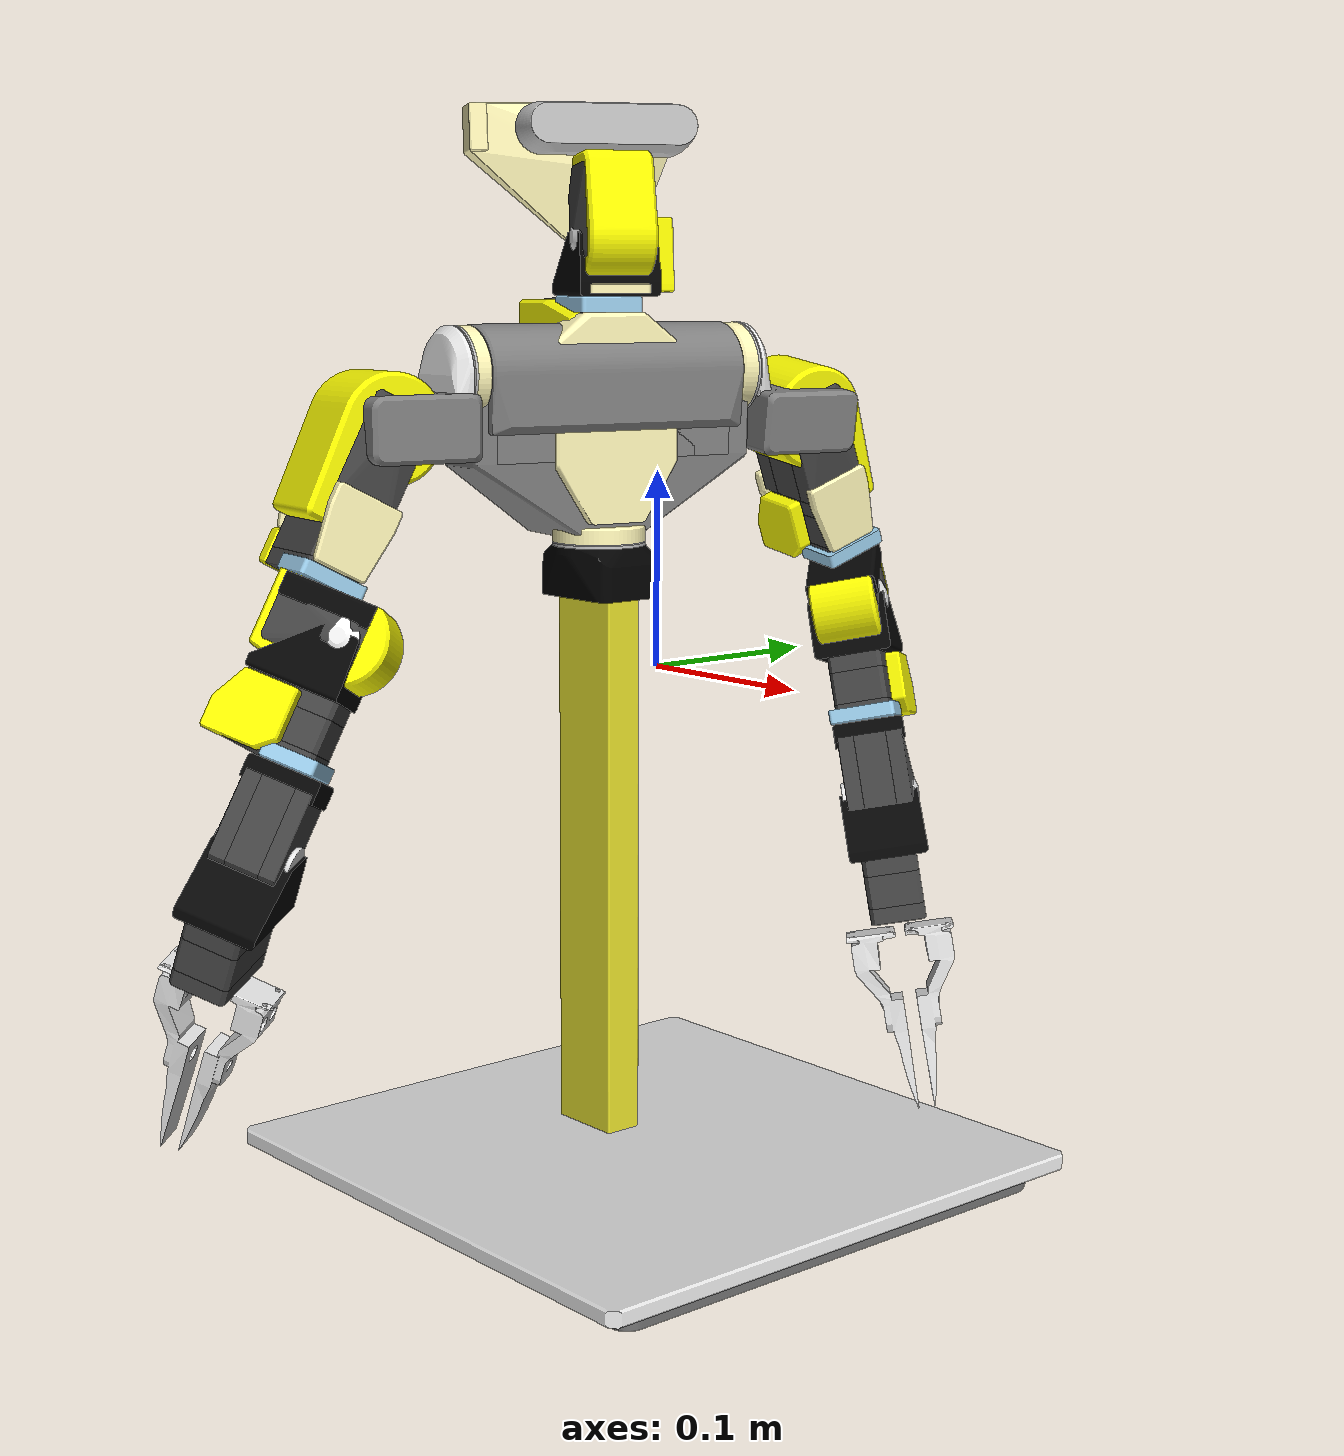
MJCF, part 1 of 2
<?xml version="1.0" encoding="utf-8"?>
<mujoco model="rakuda_gripper">
  <default>
    <default class="rakuda_visual">
      <geom type="mesh" contype="0" conaffinity="0" group="1" density="0" />
    </default>
    <default class="rakuda_collision">
      <geom type="mesh" contype="1" conaffinity="1" group="3" density="0" />
    </default>
  </default>
  <compiler angle="radian" />
  <asset>
    <mesh name="vis__5____2__NFS5_2040_297_1___NFS5_2040_910" vertex="-0.02 -0.009 -0.3291 -0.02 -0.009 -0.0321 -0.02 0.009 -0.3291 -0.02 0.009 -0.0321 -0.0199945 -0.00910453 -0.3291 -0.0199945 -0.00910453 -0.0321 -0.0199945 0.00910453 -0.3291 -0.0199945 0.00910453 -0.0321 -0.0199781 -0.00920791 -0.3291 -0.0199781 -0.00920791 -0.0321 -0.0199781 0.00920791 -0.3291 -0.0199781 0.00920791 -0.0321 -0.0199511 -0.00930902 -0.3291 -0.0199511 -0.00930902 -0.0321 -0.0199511 0.00930902 -0.3291 -0.0199511 0.00930902 -0.0321 -0.0199135 -0.00940674 -0.3291 -0.0199135 -0.00940674 -0.0321 -0.0199135 0.00940674 -0.3291 -0.0199135 0.00940674 -0.0321 -0.019866 -0.0095 -0.3291 -0.019866 -0.0095 -0.0321 -0.019866 0.0095 -0.3291 -0.019866 0.0095 -0.0321 -0.019809 -0.00958779 -0.3291 -0.019809 -0.00958779 -0.0321 -0.019809 0.00958779 -0.3291 -0.019809 0.00958779 -0.0321 -0.0197431 -0.00966913 -0.3291 -0.0197431 -0.00966913 -0.0321 -0.0197431 0.00966913 -0.3291 -0.0197431 0.00966913 -0.0321 -0.0196691 -0.00974314 -0.3291 -0.0196691 -0.00974314 -0.0321 -0.0196691 0.00974314 -0.3291 -0.0196691 0.00974314 -0.0321 -0.0195878 -0.00980902 -0.3291 -0.0195878 -0.00980902 -0.0321 -0.0195878 0.00980902 -0.3291 -0.0195878 0.00980902 -0.0321 -0.0195 -0.00986603 -0.3291 -0.0195 -0.00986603 -0.0321 -0.0195 0.00986603 -0.3291 -0.0195 0.00986603 -0.0321 -0.0194067 -0.00991355 -0.3291 -0.0194067 -0.00991355 -0.0321 -0.0194067 0.00991355 -0.3291 -0.0194067 0.00991355 -0.0321 -0.019309 -0.00995106 -0.3291 -0.019309 -0.00995106 -0.0321 -0.019309 0.00995106 -0.3291 -0.019309 0.00995106 -0.0321 -0.0192079 -0.00997815 -0.3291 -0.0192079 -0.00997815 -0.0321 -0.0192079 0.00997815 -0.3291 -0.0192079 0.00997815 -0.0321 -0.0191045 -0.00999452 -0.3291 -0.0191045 -0.00999452 -0.0321 -0.0191045 0.00999452 -0.3291 -0.0191045 0.00999452 -0.0321 -0.019 -0.01 -0.3291 -0.019 -0.01 -0.0321 -0.019 0.01 -0.3291 -0.019 0.01 -0.0321 0.019 -0.01 -0.3291 0.019 -0.01 -0.0321 0.019 0.01 -0.3291 0.019 0.01 -0.0321 0.0191045 -0.00999452 -0.3291 0.0191045 -0.00999452 -0.0321 0.0191045 0.00999452 -0.3291 0.0191045 0.00999452 -0.0321 0.0192079 -0.00997815 -0.3291 0.0192079 -0.00997815 -0.0321 0.0192079 0.00997815 -0.3291 0.0192079 0.00997815 -0.0321 0.019309 -0.00995106 -0.3291 0.019309 -0.00995106 -0.0321 0.019309 0.00995106 -0.3291 0.019309 0.00995106 -0.0321 0.0194067 -0.00991355 -0.3291 0.0194067 -0.00991355 -0.0321 0.0194067 0.00991355 -0.3291 0.0194067 0.00991355 -0.0321 0.0195 -0.00986603 -0.3291 0.0195 -0.00986603 -0.0321 0.0195 0.00986603 -0.3291 0.0195 0.00986603 -0.0321 0.0195878 -0.00980902 -0.3291 0.0195878 -0.00980902 -0.0321 0.0195878 0.00980902 -0.3291 0.0195878 0.00980902 -0.0321 0.0196691 -0.00974314 -0.3291 0.0196691 -0.00974314 -0.0321 0.0196691 0.00974314 -0.3291 0.0196691 0.00974314 -0.0321 0.0197431 -0.00966913 -0.3291 0.0197431 -0.00966913 -0.0321 0.0197431 0.00966913 -0.3291 0.0197431 0.00966913 -0.0321 0.019809 -0.00958779 -0.3291 0.019809 -0.00958779 -0.0321 0.019809 0.00958779 -0.3291 0.019809 0.00958779 -0.0321 0.019866 -0.0095 -0.3291 0.019866 -0.0095 -0.0321 0.019866 0.0095 -0.3291 0.019866 0.0095 -0.0321 0.0199135 -0.00940674 -0.3291 0.0199135 -0.00940674 -0.0321 0.0199135 0.00940674 -0.3291 0.0199135 0.00940674 -0.0321 0.0199511 -0.00930902 -0.3291 0.0199511 -0.00930902 -0.0321 0.0199511 0.00930902 -0.3291 0.0199511 0.00930902 -0.0321 0.0199781 -0.00920791 -0.3291 0.0199781 -0.00920791 -0.0321 0.0199781 0.00920791 -0.3291 0.0199781 0.00920791 -0.0321 0.0199945 -0.00910453 -0.3291 0.0199945 -0.00910453 -0.0321 0.0199945 0.00910453 -0.3291 0.0199945 0.00910453 -0.0321 0.02 -0.009 -0.3291 0.02 -0.009 -0.0321 0.02 0.009 -0.3291 0.02 0.009 -0.0321" face="3 2 0 0 1 3 66 62 67 62 63 67 5 1 4 4 1 0 60 64 65 61 60 65 125 124 126 126 127 125 70 67 71 66 67 70 57 60 61 57 56 60 44 48 45 45 48 49 45 40 44 41 40 45 37 32 36 33 32 37 36 40 37 37 40 41 28 32 29 29 32 33 24 29 25 28 29 24 24 25 21 21 20 24 5 4 9 4 8 9 9 8 12 12 13 9 46 42 43 43 47 46 43 42 38 38 39 43 2 3 7 7 6 2 19 18 14 14 15 19 68 65 64 68 69 65 124 125 121 121 120 124 51 50 46 46 47 51 54 50 51 51 55 54 59 63 62 62 58 59 59 58 54 54 55 59 119 118 114 119 114 115 122 127 126 122 123 127 122 119 123 118 119 122 114 110 111 115 114 111 83 86 82 87 86 83 82 78 83 83 78 79 74 70 75 75 70 71 75 78 74 79 78 75 53 48 52 49 48 53 52 56 53 56 57 53 17 20 21 17 16 20 17 13 12 12 16 17 38 34 35 35 39 38 14 10 11 11 15 14 11 10 6 6 7 11 26 22 23 23 27 26 23 22 18 18 19 23 72 77 73 76 77 72 73 69 72 69 68 72 107 111 106 106 111 110 103 106 102 107 106 103 103 102 98 98 99 103 94 95 99 94 99 98 90 86 91 91 86 87 91 94 90 95 94 91 31 30 26 26 27 31 34 30 31 31 35 34 81 80 84 84 85 81 76 80 81 81 77 76 88 89 85 88 85 84 93 89 88 88 92 93 104 78 82 46 50 104 0 2 104 104 64 60 12 8 104 126 124 104 104 58 62 104 122 126 84 80 104 104 62 66 104 42 46 104 4 0 104 48 44 44 40 104 66 70 104 104 32 28 60 56 104 104 106 110 2 6 104 104 16 12 26 30 104 104 88 84 124 120 104 104 68 64 82 86 104 104 56 52 104 8 4 36 32 104 52 48 104 28 24 104 38 42 104 104 22 26 104 34 38 14 18 104 104 10 14 112 108 104 76 72 104 54 58 104 104 50 54 114 118 104 104 110 114 104 70 74 98 102 104 104 40 36 104 24 20 20 16 104 104 30 34 18 22 104 6 10 104 104 80 76 104 94 98 100 96 104 118 122 104 104 116 112 104 86 90 74 78 104 104 96 92 104 72 68 120 116 104 102 106 104 90 94 104 92 88 104 104 105 101 104 101 100 109 108 112 109 112 113 109 104 108 105 104 109 92 96 97 93 92 97 97 96 100 100 101 97 61 65 117 117 3 1 117 29 33 117 125 127 117 119 115 71 67 117 33 37 117 117 67 63 127 123 117 117 1 5 87 83 117 47 43 117 117 69 73 117 89 93 93 97 117 117 45 49 5 9 117 15 11 117 63 59 117 117 81 85 117 57 61 21 25 117 49 53 117 117 17 21 117 7 3 27 23 117 65 69 117 117 51 47 117 111 107 107 103 117 117 75 71 41 45 117 117 37 41 25 29 117 117 9 13 117 43 39 117 91 87 117 19 15 73 77 117 117 109 113 117 121 125 55 51 117 117 59 55 123 119 117 115 111 117 99 95 117 117 83 79 79 75 117 117 53 57 13 17 117 39 35 117 117 11 7 117 23 19 117 31 27 85 89 117 101 105 117 117 103 99 95 91 117 35 31 117 77 81 117 105 109 117 117 97 101 112 116 117 113 112 117 120 121 117 117 116 120" />
    <mesh name="col__5____2__NFS5_2040_297_1___NFS5_2040_910" vertex="-0.02 -0.009 -0.3291 -0.02 -0.009 -0.0321 -0.02 0.009 -0.3291 -0.02 0.009 -0.0321 -0.0199945 -0.00910453 -0.3291 -0.0199945 -0.00910453 -0.0321 -0.0199945 0.00910453 -0.3291 -0.0199945 0.00910453 -0.0321 -0.0199781 -0.00920791 -0.3291 -0.0199781 -0.00920791 -0.0321 -0.0199781 0.00920791 -0.3291 -0.0199781 0.00920791 -0.0321 -0.0199511 -0.00930902 -0.3291 -0.0199511 -0.00930902 -0.0321 -0.0199511 0.00930902 -0.3291 -0.0199511 0.00930902 -0.0321 -0.0199135 -0.00940674 -0.3291 -0.0199135 -0.00940674 -0.0321 -0.0199135 0.00940674 -0.3291 -0.0199135 0.00940674 -0.0321 -0.019866 -0.0095 -0.3291 -0.019866 -0.0095 -0.0321 -0.019866 0.0095 -0.3291 -0.019866 0.0095 -0.0321 -0.019809 -0.00958779 -0.3291 -0.019809 -0.00958779 -0.0321 -0.019809 0.00958779 -0.3291 -0.019809 0.00958779 -0.0321 -0.0197431 -0.00966913 -0.3291 -0.0197431 -0.00966913 -0.0321 -0.0197431 0.00966913 -0.3291 -0.0197431 0.00966913 -0.0321 -0.0196691 -0.00974314 -0.3291 -0.0196691 -0.00974314 -0.0321 -0.0196691 0.00974314 -0.3291 -0.0196691 0.00974314 -0.0321 -0.0195878 -0.00980902 -0.3291 -0.0195878 -0.00980902 -0.0321 -0.0195878 0.00980902 -0.3291 -0.0195878 0.00980902 -0.0321 -0.0195 -0.00986603 -0.3291 -0.0195 -0.00986603 -0.0321 -0.0195 0.00986603 -0.3291 -0.0195 0.00986603 -0.0321 -0.0194067 -0.00991355 -0.3291 -0.0194067 -0.00991355 -0.0321 -0.0194067 0.00991355 -0.3291 -0.0194067 0.00991355 -0.0321 -0.019309 -0.00995106 -0.3291 -0.019309 -0.00995106 -0.0321 -0.019309 0.00995106 -0.3291 -0.019309 0.00995106 -0.0321 -0.0192079 -0.00997815 -0.3291 -0.0192079 -0.00997815 -0.0321 -0.0192079 0.00997815 -0.3291 -0.0192079 0.00997815 -0.0321 -0.0191045 -0.00999452 -0.3291 -0.0191045 -0.00999452 -0.0321 -0.0191045 0.00999452 -0.3291 -0.0191045 0.00999452 -0.0321 -0.019 -0.01 -0.3291 -0.019 -0.01 -0.0321 -0.019 0.01 -0.3291 -0.019 0.01 -0.0321 0.019 -0.01 -0.3291 0.019 -0.01 -0.0321 0.019 0.01 -0.3291 0.019 0.01 -0.0321 0.0191045 -0.00999452 -0.3291 0.0191045 -0.00999452 -0.0321 0.0191045 0.00999452 -0.3291 0.0191045 0.00999452 -0.0321 0.0192079 -0.00997815 -0.3291 0.0192079 -0.00997815 -0.0321 0.0192079 0.00997815 -0.3291 0.0192079 0.00997815 -0.0321 0.019309 -0.00995106 -0.3291 0.019309 -0.00995106 -0.0321 0.019309 0.00995106 -0.3291 0.019309 0.00995106 -0.0321 0.0194067 -0.00991355 -0.3291 0.0194067 -0.00991355 -0.0321 0.0194067 0.00991355 -0.3291 0.0194067 0.00991355 -0.0321 0.0195 -0.00986603 -0.3291 0.0195 -0.00986603 -0.0321 0.0195 0.00986603 -0.3291 0.0195 0.00986603 -0.0321 0.0195878 -0.00980902 -0.3291 0.0195878 -0.00980902 -0.0321 0.0195878 0.00980902 -0.3291 0.0195878 0.00980902 -0.0321 0.0196691 -0.00974314 -0.3291 0.0196691 -0.00974314 -0.0321 0.0196691 0.00974314 -0.3291 0.0196691 0.00974314 -0.0321 0.0197431 -0.00966913 -0.3291 0.0197431 -0.00966913 -0.0321 0.0197431 0.00966913 -0.3291 0.0197431 0.00966913 -0.0321 0.019809 -0.00958779 -0.3291 0.019809 -0.00958779 -0.0321 0.019809 0.00958779 -0.3291 0.019809 0.00958779 -0.0321 0.019866 -0.0095 -0.3291 0.019866 -0.0095 -0.0321 0.019866 0.0095 -0.3291 0.019866 0.0095 -0.0321 0.0199135 -0.00940674 -0.3291 0.0199135 -0.00940674 -0.0321 0.0199135 0.00940674 -0.3291 0.0199135 0.00940674 -0.0321 0.0199511 -0.00930902 -0.3291 0.0199511 -0.00930902 -0.0321 0.0199511 0.00930902 -0.3291 0.0199511 0.00930902 -0.0321 0.0199781 -0.00920791 -0.3291 0.0199781 -0.00920791 -0.0321 0.0199781 0.00920791 -0.3291 0.0199781 0.00920791 -0.0321 0.0199945 -0.00910453 -0.3291 0.0199945 -0.00910453 -0.0321 0.0199945 0.00910453 -0.3291 0.0199945 0.00910453 -0.0321 0.02 -0.009 -0.3291 0.02 -0.009 -0.0321 0.02 0.009 -0.3291 0.02 0.009 -0.0321" face="3 2 0 0 1 3 66 62 67 62 63 67 5 1 4 4 1 0 60 64 65 61 60 65 125 124 126 126 127 125 70 67 71 66 67 70 57 60 61 57 56 60 44 48 45 45 48 49 45 40 44 41 40 45 37 32 36 33 32 37 36 40 37 37 40 41 28 32 29 29 32 33 24 29 25 28 29 24 24 25 21 21 20 24 5 4 9 4 8 9 9 8 12 12 13 9 46 42 43 43 47 46 43 42 38 38 39 43 2 3 7 7 6 2 19 18 14 14 15 19 68 65 64 68 69 65 124 125 121 121 120 124 51 50 46 46 47 51 54 50 51 51 55 54 59 63 62 62 58 59 59 58 54 54 55 59 119 118 114 119 114 115 122 127 126 122 123 127 122 119 123 118 119 122 114 110 111 115 114 111 83 86 82 87 86 83 82 78 83 83 78 79 74 70 75 75 70 71 75 78 74 79 78 75 53 48 52 49 48 53 52 56 53 56 57 53 17 20 21 17 16 20 17 13 12 12 16 17 38 34 35 35 39 38 14 10 11 11 15 14 11 10 6 6 7 11 26 22 23 23 27 26 23 22 18 18 19 23 72 77 73 76 77 72 73 69 72 69 68 72 107 111 106 106 111 110 103 106 102 107 106 103 103 102 98 98 99 103 94 95 99 94 99 98 90 86 91 91 86 87 91 94 90 95 94 91 31 30 26 26 27 31 34 30 31 31 35 34 81 80 84 84 85 81 76 80 81 81 77 76 88 89 85 88 85 84 93 89 88 88 92 93 104 78 82 46 50 104 0 2 104 104 64 60 12 8 104 126 124 104 104 58 62 104 122 126 84 80 104 104 62 66 104 42 46 104 4 0 104 48 44 44 40 104 66 70 104 104 32 28 60 56 104 104 106 110 2 6 104 104 16 12 26 30 104 104 88 84 124 120 104 104 68 64 82 86 104 104 56 52 104 8 4 36 32 104 52 48 104 28 24 104 38 42 104 104 22 26 104 34 38 14 18 104 104 10 14 112 108 104 76 72 104 54 58 104 104 50 54 114 118 104 104 110 114 104 70 74 98 102 104 104 40 36 104 24 20 20 16 104 104 30 34 18 22 104 6 10 104 104 80 76 104 94 98 100 96 104 118 122 104 104 116 112 104 86 90 74 78 104 104 96 92 104 72 68 120 116 104 102 106 104 90 94 104 92 88 104 104 105 101 104 101 100 109 108 112 109 112 113 109 104 108 105 104 109 92 96 97 93 92 97 97 96 100 100 101 97 61 65 117 117 3 1 117 29 33 117 125 127 117 119 115 71 67 117 33 37 117 117 67 63 127 123 117 117 1 5 87 83 117 47 43 117 117 69 73 117 89 93 93 97 117 117 45 49 5 9 117 15 11 117 63 59 117 117 81 85 117 57 61 21 25 117 49 53 117 117 17 21 117 7 3 27 23 117 65 69 117 117 51 47 117 111 107 107 103 117 117 75 71 41 45 117 117 37 41 25 29 117 117 9 13 117 43 39 117 91 87 117 19 15 73 77 117 117 109 113 117 121 125 55 51 117 117 59 55 123 119 117 115 111 117 99 95 117 117 83 79 79 75 117 117 53 57 13 17 117 39 35 117 117 11 7 117 23 19 117 31 27 85 89 117 101 105 117 117 103 99 95 91 117 35 31 117 77 81 117 105 109 117 117 97 101 112 116 117 113 112 117 120 121 117 117 116 120" />
    <mesh name="vis______24x10_C_30_RK_24_black_1__NONE_1" vertex="-0.102 -0.125 -0.3371 -0.102 0.125 -0.3371 -0.10193 -0.126297 -0.3371 -0.10193 0.126297 -0.3371 -0.101719 -0.12758 -0.3371 -0.101719 0.12758 -0.3371 -0.101372 -0.128832 -0.3371 -0.101372 0.128832 -0.3371 -0.100891 -0.130039 -0.3371 -0.100891 0.130039 -0.3371 -0.100282 -0.131187 -0.3371 -0.100282 0.131187 -0.3371 -0.0996894 -0.125 -0.346343 -0.0996894 0.125 -0.346343 -0.0996596 -0.125 -0.34644 -0.0996596 0.125 -0.34644 -0.0996326 -0.126048 -0.346343 -0.0996326 0.126048 -0.346343 -0.0996201 -0.125 -0.346534 -0.0996201 0.125 -0.346534 -0.099603 -0.126044 -0.34644 -0.099603 0.126044 -0.34644 -0.0995713 -0.125 -0.346623 -0.0995713 0.125 -0.346623 -0.0995637 -0.12604 -0.346534 -0.0995637 0.12604 -0.346534 -0.0995531 -0.132262 -0.3371 -0.0995531 0.132262 -0.3371 -0.0995151 -0.126035 -0.346623 -0.0995151 0.126035 -0.346623 -0.0995135 -0.125 -0.346708 -0.0995135 0.125 -0.346708 -0.0994628 -0.127083 -0.346343 -0.0994628 0.127083 -0.346343 -0.0994578 -0.126029 -0.346708 -0.0994578 0.126029 -0.346708 -0.0994476 -0.125 -0.346785 -0.0994476 0.125 -0.346785 -0.0994338 -0.127077 -0.34644 -0.0994338 0.127077 -0.34644 -0.0993952 -0.127068 -0.346534 -0.0993952 0.127068 -0.346534 -0.0993922 -0.126021 -0.346785 -0.0993922 0.126021 -0.346785 -0.099374 -0.125 -0.346856 -0.099374 0.125 -0.346856 -0.0993475 -0.127058 -0.346623 -0.0993475 0.127058 -0.346623 -0.0993191 -0.126014 -0.346856 -0.0993191 0.126014 -0.346856 -0.0992937 -0.125 -0.346919 -0.0992937 0.125 -0.346919 -0.0992911 -0.127045 -0.346708 -0.0992911 0.127045 -0.346708 -0.0992392 -0.126005 -0.346919 -0.0992392 0.126005 -0.346919 -0.0992267 -0.127031 -0.346785 -0.0992267 0.127031 -0.346785 -0.0992073 -0.125 -0.346973 -0.0992073 0.125 -0.346973 -0.0991822 -0.128094 -0.346343 -0.0991822 0.128094 -0.346343 -0.0991549 -0.127015 -0.346856 -0.0991549 0.127015 -0.346856 -0.099154 -0.128084 -0.34644 -0.099154 0.128084 -0.34644 -0.0991534 -0.125995 -0.346973 -0.0991534 0.125995 -0.346973 -0.0991165 -0.128072 -0.346534 -0.0991165 0.128072 -0.346534 -0.0991159 -0.125 -0.347018 -0.0991159 0.125 -0.347018 -0.0990764 -0.126998 -0.346919 -0.0990764 0.126998 -0.346919 -0.0990702 -0.128056 -0.346623 -0.0990702 0.128056 -0.346623 -0.0990625 -0.125986 -0.347018 -0.0990625 0.125986 -0.347018 -0.0990204 -0.125 -0.347054 -0.0990204 0.125 -0.347054 -0.0990155 -0.128038 -0.346708 -0.0990155 0.128038 -0.346708 -0.0989921 -0.126979 -0.346973 -0.0989921 0.126979 -0.346973 -0.0989676 -0.125975 -0.347054 -0.0989676 0.125975 -0.347054 -0.098953 -0.128017 -0.346785 -0.098953 0.128017 -0.346785 -0.0989218 -0.125 -0.347079 -0.0989218 0.125 -0.347079 -0.0989028 -0.12696 -0.347018 -0.0989028 0.12696 -0.347018 -0.0988833 -0.127993 -0.346856 -0.0988833 0.127993 -0.346856 -0.0988695 -0.125965 -0.347079 -0.0988695 0.125965 -0.347079 -0.098821 -0.125 -0.347095 -0.098821 0.125 -0.347095 -0.0988095 -0.126939 -0.347054 -0.0988095 0.126939 -0.347054 -0.0988072 -0.127967 -0.346919 -0.0988072 0.127967 -0.346919 -0.0987938 -0.129068 -0.346343 -0.0987938 0.129068 -0.346343 -0.0987693 -0.125954 -0.347095 -0.0987693 0.125954 -0.347095 -0.0987668 -0.129056 -0.34644 -0.0987668 0.129056 -0.34644 -0.098731 -0.129039 -0.346534 -0.098731 0.129039 -0.346534 -0.0987254 -0.12794 -0.346973 -0.0987254 0.12794 -0.346973 -0.0987192 -0.125 -0.3471 -0.0987192 0.125 -0.3471 -0.0987132 -0.126918 -0.347079 -0.0987132 0.126918 -0.347079 -0.0987119 -0.133252 -0.3371 -0.0987119 0.133252 -0.3371 -0.0986866 -0.129019 -0.346623 -0.0986866 0.129019 -0.346623 -0.0986681 -0.125943 -0.3471 -0.0986681 0.125943 -0.3471 -0.0986388 -0.127911 -0.347018 -0.0986388 0.127911 -0.347018 -0.0986343 -0.128995 -0.346708 -0.0986343 0.128995 -0.346708 -0.0986148 -0.126896 -0.347095 -0.0986148 0.126896 -0.347095 -0.0985744 -0.128967 -0.346785 -0.0985744 0.128967 -0.346785 -0.0985482 -0.12788 -0.347054 -0.0985482 0.12788 -0.347054 -0.0985154 -0.126874 -0.3471 -0.0985154 0.126874 -0.3471 -0.0985076 -0.128936 -0.346856 -0.0985076 0.128936 -0.346856 -0.0984548 -0.127849 -0.347079 -0.0984548 0.127849 -0.347079 -0.0984347 -0.128902 -0.346919 -0.0984347 0.128902 -0.346919 -0.0983593 -0.127817 -0.347095 -0.0983593 0.127817 -0.347095 -0.0983564 -0.128866 -0.346973 -0.0983564 0.128866 -0.346973 -0.0983024 -0.129995 -0.346343 -0.0983024 0.129995 -0.346343 -0.0982769 -0.12998 -0.34644 -0.0982769 0.12998 -0.34644 -0.0982734 -0.128828 -0.347018 -0.0982734 0.128828 -0.347018 -0.0982628 -0.127784 -0.3471 -0.0982628 0.127784 -0.3471 -0.0982431 -0.12996 -0.346534 -0.0982431 0.12996 -0.346534 -0.0982012 -0.129935 -0.346623 -0.0982012 0.129935 -0.346623 -0.0981867 -0.128788 -0.347054 -0.0981867 0.128788 -0.347054 -0.0981517 -0.129905 -0.346708 -0.0981517 0.129905 -0.346708 -0.0980972 -0.128746 -0.347079 -0.0980972 0.128746 -0.347079 -0.0980952 -0.129871 -0.346785 -0.0980952 0.129871 -0.346785 -0.0980322 -0.129833 -0.346856 -0.0980322 0.129833 -0.346856 -0.0980057 -0.128704 -0.347095 -0.0980057 0.128704 -0.347095 -0.0979633 -0.129791 -0.346919 -0.0979633 0.129791 -0.346919 -0.0979134 -0.128661 -0.3471 -0.0979134 0.128661 -0.3471 -0.0978894 -0.129747 -0.346973 -0.0978894 0.129747 -0.346973 -0.0978111 -0.1297 -0.347018 -0.0978111 0.1297 -0.347018 -0.0977686 -0.134146 -0.3371 -0.0977686 0.134146 -0.3371 -0.0977292 -0.129651 -0.347054 -0.0977292 0.129651 -0.347054 -0.0977136 -0.130864 -0.346343 -0.0977136 0.130864 -0.346343 -0.09769 -0.130846 -0.34644 -0.09769 0.130846 -0.34644 -0.0976585 -0.130822 -0.346534 -0.0976585 0.130822 -0.346534 -0.0976447 -0.1296 -0.347079 -0.0976447 0.1296 -0.347079 -0.0976196 -0.130792 -0.346623 -0.0976196 0.130792 -0.346623 -0.0975737 -0.130757 -0.346708 -0.0975737 0.130757 -0.346708 -0.0975584 -0.129548 -0.347095 -0.0975584 0.129548 -0.347095 -0.0975211 -0.130717 -0.346785 -0.0975211 0.130717 -0.346785 -0.0974711 -0.129495 -0.3471 -0.0974711 0.129495 -0.3471 -0.0974626 -0.130673 -0.346856 -0.0974626 0.130673 -0.346856 -0.0973986 -0.130624 -0.346919 -0.0973986 0.130624 -0.346919 -0.0973299 -0.130572 -0.346973 -0.0973299 0.130572 -0.346973 -0.0972571 -0.130517 -0.347018 -0.0972571 0.130517 -0.347018 -0.0971811 -0.130459 -0.347054 -0.0971811 0.130459 -0.347054 -0.0971026 -0.130399 -0.347079 -0.0971026 0.130399 -0.347079 -0.0970344 -0.131663 -0.346343 -0.0970344 0.131663 -0.346343 -0.0970224 -0.130338 -0.347095 -0.0970224 0.130338 -0.347095 -0.0970128 -0.131643 -0.34644 -0.0970128 0.131643 -0.34644 -0.0969842 -0.131616 -0.346534 -0.0969842 0.131616 -0.346534 -0.0969487 -0.131582 -0.346623 -0.0969487 0.131582 -0.346623 -0.0969413 -0.130277 -0.3471 -0.0969413 0.130277 -0.3471 -0.0969068 -0.131542 -0.346708 -0.0969068 0.131542 -0.346708 -0.0968589 -0.131497 -0.346785 -0.0968589 0.131497 -0.346785 -0.0968055 -0.131446 -0.346856 -0.0968055 0.131446 -0.346856 -0.0967472 -0.131391 -0.346919 -0.0967472 0.131391 -0.346919 -0.0967342 -0.134932 -0.3371 -0.0967342 0.134932 -0.3371 -0.0966845 -0.131332 -0.346973 -0.0966845 0.131332 -0.346973 -0.0966181 -0.131269 -0.347018 -0.0966181 0.131269 -0.347018 -0.0965488 -0.131203 -0.347054 -0.0965488 0.131203 -0.347054 -0.0964772 -0.131136 -0.347079 -0.0964772 0.131136 -0.347079 -0.096404 -0.131066 -0.347095 -0.096404 0.131066 -0.347095 -0.0963301 -0.130996 -0.3471 -0.0963301 0.130996 -0.3471 -0.0962728 -0.132385 -0.346343 -0.0962728 0.132385 -0.346343 -0.0962535 -0.132362 -0.34644 -0.0962535 0.132362 -0.34644 -0.0962279 -0.132332 -0.346534 -0.0962279 0.132332 -0.346534 -0.0961963 -0.132295 -0.346623 -0.0961963 0.132295 -0.346623 -0.0961589 -0.132251 -0.346708 -0.0961589 0.132251 -0.346708 -0.0961162 -0.132201 -0.346785 -0.0961162 0.132201 -0.346785 -0.0960686 -0.132145 -0.346856 -0.0960686 0.132145 -0.346856 -0.0960166 -0.132083 -0.346919 -0.0960166 0.132083 -0.346919 -0.0959607 -0.132017 -0.346973 -0.0959607 0.132017 -0.346973 -0.0959015 -0.131948 -0.347018 -0.0959015 0.131948 -0.347018 -0.0958397 -0.131875 -0.347054 -0.0958397 0.131875 -0.347054 -0.0957758 -0.1318 -0.347079 -0.0957758 0.1318 -0.347079 -0.0957106 -0.131723 -0.347095 -0.0957106 0.131723 -0.347095 -0.0956447 -0.131645 -0.3471 -0.0956447 0.131645 -0.3471 -0.0956209 -0.135602 -0.3371 -0.0956209 0.135602 -0.3371 -0.0954375 -0.13302 -0.346343 -0.0954375 0.13302 -0.346343 -0.0954209 -0.132995 -0.34644 -0.0954209 0.132995 -0.34644 -0.0953987 -0.132962 -0.346534 -0.0953987 0.132962 -0.346534 -0.0953713 -0.132922 -0.346623 -0.0953713 0.132922 -0.346623 -0.0953389 -0.132874 -0.346708 -0.0953389 0.132874 -0.346708 -0.0953018 -0.13282 -0.346785 -0.0953018 0.13282 -0.346785 -0.0952606 -0.132759 -0.346856 -0.0952606 0.132759 -0.346856 -0.0952155 -0.132692 -0.346919 -0.0952155 0.132692 -0.346919 -0.095167 -0.132621 -0.346973 -0.095167 0.132621 -0.346973 -0.0951158 -0.132545 -0.347018 -0.0951158 0.132545 -0.347018 -0.0950622 -0.132466 -0.347054 -0.0950622 0.132466 -0.347054 -0.0950068 -0.132384 -0.347079 -0.0950068 0.132384 -0.347079 -0.0949503 -0.132301 -0.347095 -0.0949503 0.132301 -0.347095 -0.0948931 -0.132217 -0.3471 -0.0948931 0.132217 -0.3471 -0.0945386 -0.133561 -0.346343 -0.0945386 0.133561 -0.346343 -0.0945247 -0.133534 -0.34644 -0.0945247 0.133534 -0.34644 -0.0945062 -0.1335 -0.346534 -0.0945062 0.1335 -0.346534 -0.0944833 -0.133456 -0.346623 -0.0944833 0.133456 -0.346623 -0.0944562 -0.133405 -0.346708 -0.0944562 0.133405 -0.346708 -0.0944417 -0.136148 -0.3371 -0.0944417 0.136148 -0.3371 -0.0944253 -0.133347 -0.346785 -0.0944253 0.133347 -0.346785 -0.0943909 -0.133282 -0.346856 -0.0943909 0.133282 -0.346856 -0.0943532 -0.133211 -0.346919 -0.0943532 0.133211 -0.346919 -0.0943128 -0.133135 -0.346973 -0.0943128 0.133135 -0.346973 -0.09427 -0.133054 -0.347018 -0.09427 0.133054 -0.347018 -0.0942252 -0.13297 -0.347054 -0.0942252 0.13297 -0.347054 -0.094179 -0.132883 -0.347079 -0.094179 0.132883 -0.347079 -0.0941318 -0.132793 -0.347095 -0.0941318 0.132793 -0.347095 -0.0940842 -0.132704 -0.3471 -0.0940842 0.132704 -0.3471 -0.0935864 -0.134001 -0.346343 -0.0935864 0.134001 -0.346343 -0.0935754 -0.133974 -0.34644 -0.0935754 0.133974 -0.34644 -0.0935608 -0.133937 -0.346534 -0.0935608 0.133937 -0.346534 -0.0935427 -0.133891 -0.346623 -0.0935427 0.133891 -0.346623 -0.0935213 -0.133838 -0.346708 -0.0935213 0.133838 -0.346708 -0.0934969 -0.133777 -0.346785 -0.0934969 0.133777 -0.346785 -0.0934697 -0.133708 -0.346856 -0.0934697 0.133708 -0.346856 -0.0934399 -0.133634 -0.346919 -0.0934399 0.133634 -0.346919 -0.093408 -0.133553 -0.346973 -0.093408 0.133553 -0.346973 -0.0933742 -0.133469 -0.347018 -0.0933742 0.133469 -0.347018 -0.0933388 -0.13338 -0.347054 -0.0933388 0.13338 -0.347054 -0.0933023 -0.133288 -0.347079 -0.0933023 0.133288 -0.347079 -0.093265 -0.133195 -0.347095 -0.093265 0.133195 -0.347095 -0.0932273 -0.1331 -0.3471 -0.0932273 0.1331 -0.3471 -0.0932103 -0.136563 -0.3371 -0.0932103 0.136563 -0.3371 -0.0925922 -0.134336 -0.346343 -0.0925922 0.134336 -0.346343 -0.0925842 -0.134308 -0.34644 -0.0925842 0.134308 -0.34644 -0.0925737 -0.134269 -0.346534 -0.0925737 0.134269 -0.346534 -0.0925606 -0.134222 -0.346623 -0.0925606 0.134222 -0.346623 -0.0925451 -0.134167 -0.346708 -0.0925451 0.134167 -0.346708 -0.0925275 -0.134103 -0.346785 -0.0925275 0.134103 -0.346785 -0.0925078 -0.134032 -0.346856 -0.0925078 0.134032 -0.346856 -0.0924863 -0.133955 -0.346919 -0.0924863 0.133955 -0.346919 -0.0924632 -0.133872 -0.346973 -0.0924632 0.133872 -0.346973 -0.0924388 -0.133784 -0.347018 -0.0924388 0.133784 -0.347018 -0.0924132 -0.133692 -0.347054 -0.0924132 0.133692 -0.347054 -0.0923868 -0.133597 -0.347079 -0.0923868 0.133597 -0.347079 -0.0923599 -0.1335 -0.347095 -0.0923599 0.1335 -0.347095 -0.0923326 -0.133401 -0.3471 -0.0923326 0.133401 -0.3471 -0.0919414 -0.136842 -0.3371 -0.0919414 0.136842 -0.3371 -0.0915676 -0.134562 -0.346343 -0.0915676 0.134562 -0.346343 -0.0915628 -0.134532 -0.34644 -0.0915628 0.134532 -0.34644 -0.0915564 -0.134493 -0.346534 -0.0915564 0.134493 -0.346534 -0.0915485 -0.134445 -0.346623 -0.0915485 0.134445 -0.346623 -0.0915391 -0.134388 -0.346708 -0.0915391 0.134388 -0.346708 -0.0915284 -0.134323 -0.346785 -0.0915284 0.134323 -0.346785 -0.0915165 -0.134251 -0.346856 -0.0915165 0.134251 -0.346856 -0.0915035 -0.134171 -0.346919 -0.0915035 0.134171 -0.346919 -0.0914896 -0.134086 -0.346973 -0.0914896 0.134086 -0.346973 -0.0914748 -0.133996 -0.347018 -0.0914748 0.133996 -0.347018 -0.0914593 -0.133902 -0.347054 -0.0914593 0.133902 -0.347054 -0.0914434 -0.133804 -0.347079 -0.0914434 0.133804 -0.347079 -0.0914271 -0.133705 -0.347095 -0.0914271 0.133705 -0.347095 -0.0914106 -0.133604 -0.3471 -0.0914106 0.133604 -0.3471 -0.0906497 -0.136982 -0.3371 -0.0906497 0.136982 -0.3371 -0.0905246 -0.134675 -0.346343 -0.0905246 0.134675 -0.346343 -0.090523 -0.134645 -0.34644 -0.090523 0.134645 -0.34644 -0.0905208 -0.134606 -0.346534 -0.0905208 0.134606 -0.346534 -0.0905182 -0.134557 -0.346623 -0.0905182 0.134557 -0.346623 -0.0905151 -0.1345 -0.346708 -0.0905151 0.1345 -0.346708 -0.0905115 -0.134434 -0.346785 -0.0905115 0.134434 -0.346785 -0.0905075 -0.13436 -0.346856 -0.0905075 0.13436 -0.346856 -0.0905031 -0.13428 -0.346919 -0.0905031 0.13428 -0.346919 -0.0904985 -0.134194 -0.346973 -0.0904985 0.134194 -0.346973 -0.0904935 -0.134103 -0.347018 -0.0904935 0.134103 -0.347018 -0.0904884 -0.134007 -0.347054 -0.0904884 0.134007 -0.347054 -0.090483 -0.133909 -0.347079 -0.090483 0.133909 -0.347079 -0.0904776 -0.133808 -0.347095 -0.0904776 0.133808 -0.347095 -0.0904721 -0.133706 -0.3471 -0.0904721 0.133706 -0.3471 0.170472 -0.133706 -0.3471 0.170472 0.133706 -0.3471 0.170478 -0.133808 -0.347095 0.170478 0.133808 -0.347095 0.170483 -0.133909 -0.347079 0.170483 0.133909 -0.347079 0.170488 -0.134007 -0.347054 0.170488 0.134007 -0.347054 0.170494 -0.134103 -0.347018 0.170494 0.134103 -0.347018 0.170498 -0.134194 -0.346973 0.170498 0.134194 -0.346973 0.170503 -0.13428 -0.346919 0.170503 0.13428 -0.346919 0.170508 -0.13436 -0.346856 0.170508 0.13436 -0.346856 0.170511 -0.134434 -0.346785 0.170511 0.134434 -0.346785 0.170515 -0.1345 -0.346708 0.170515 0.1345 -0.346708 0.170518 -0.134557 -0.346623 0.170518 0.134557 -0.346623 0.170521 -0.134606 -0.346534 0.170521 0.134606 -0.346534 0.170523 -0.134645 -0.34644 0.170523 0.134645 -0.34644 0.170525 -0.134675 -0.346343 0.170525 0.134675 -0.346343 0.17065 -0.136982 -0.3371 0.17065 0.136982 -0.3371 0.171411 -0.133604 -0.3471 0.171411 0.133604 -0.3471 0.171427 -0.133705 -0.347095 0.171427 0.133705 -0.347095 0.171443 -0.133804 -0.347079 0.171443 0.133804 -0.347079 0.171459 -0.133902 -0.347054 0.171459 0.133902 -0.347054 0.171475 -0.133996 -0.347018 0.171475 0.133996 -0.347018 0.17149 -0.134086 -0.346973 0.17149 0.134086 -0.346973 0.171504 -0.134171 -0.346919 0.171504 0.134171 -0.346919 0.171517 -0.134251 -0.346856 0.171517 0.134251 -0.346856 0.171528 -0.134323 -0.346785 0.171528 0.134323 -0.346785 0.171539 -0.134388 -0.346708 0.171539 0.134388 -0.346708 0.171548 -0.134445 -0.346623 0.171548 0.134445 -0.346623 0.171556 -0.134493 -0.346534 0.171556 0.134493 -0.346534 0.171563 -0.134532 -0.34644 0.171563 0.134532 -0.34644 0.171568 -0.134562 -0.346343 0.171568 0.134562 -0.346343 0.171941 -0.136842 -0.3371 0.171941 0.136842 -0.3371 0.172333 -0.133401 -0.3471 0.172333 0.133401 -0.3471 0.17236 -0.1335 -0.347095 0.17236 0.1335 -0.347095 0.172387 -0.133597 -0.347079 0.172387 0.133597 -0.347079 0.172413 -0.133692 -0.347054 0.172413 0.133692 -0.347054 0.172439 -0.133784 -0.347018 0.172439 0.133784 -0.347018 0.172463 -0.133872 -0.346973 0.172463 0.133872 -0.346973 0.172486 -0.133955 -0.346919 0.172486 0.133955 -0.346919 0.172508 -0.134032 -0.346856 0.172508 0.134032 -0.346856 0.172527 -0.134103 -0.346785 0.172527 0.134103 -0.346785 0.172545 -0.134167 -0.346708 0.172545 0.134167 -0.346708 0.172561 -0.134222 -0.346623 0.172561 0.134222 -0.346623 0.172574 -0.134269 -0.346534 0.172574 0.134269 -0.346534 0.172584 -0.134308 -0.34644 0.172584 0.134308 -0.34644 0.172592 -0.134336 -0.346343 0.172592 0.134336 -0.346343 0.17321 -0.136563 -0.3371 0.17321 0.136563 -0.3371 0.173227 -0.1331 -0.3471 0.173227 0.1331 -0.3471 0.173265 -0.133195 -0.347095 0.173265 0.133195 -0.347095 0.173302 -0.133288 -0.347079 0.173302 0.133288 -0.347079 0.173339 -0.13338 -0.347054 0.173339 0.13338 -0.347054 0.173374 -0.133469 -0.347018 0.173374 0.133469 -0.347018 0.173408 -0.133553 -0.346973 0.173408 0.133553 -0.346973 0.17344 -0.133634 -0.346919 0.17344 0.133634 -0.346919 0.17347 -0.133708 -0.346856 0.17347 0.133708 -0.346856 0.173497 -0.133777 -0.346785 0.173497 0.133777 -0.346785 0.173521 -0.133838 -0.346708 0.173521 0.133838 -0.346708 0.173543 -0.133891 -0.346623 0.173543 0.133891 -0.346623 0.173561 -0.133937 -0.346534 0.173561 0.133937 -0.346534 0.173575 -0.133974 -0.34644 0.173575 0.133974 -0.34644 0.173586 -0.134001 -0.346343 0.173586 0.134001 -0.346343 0.174084 -0.132704 -0.3471 0.174084 0.132704 -0.3471 0.174132 -0.132793 -0.347095 0.174132 0.132793 -0.347095 0.174179 -0.132883 -0.347079 0.174179 0.132883 -0.347079 0.174225 -0.13297 -0.347054 0.174225 0.13297 -0.347054 0.17427 -0.133054 -0.347018 0.17427 0.133054 -0.347018 0.174313 -0.133135 -0.346973 0.174313 0.133135 -0.346973 0.174353 -0.133211 -0.346919 0.174353 0.133211 -0.346919 0.174391 -0.133282 -0.346856 0.174391 0.133282 -0.346856 0.174425 -0.133347 -0.346785 0.174425 0.133347 -0.346785 0.174442 -0.136148 -0.3371 0.174442 0.136148 -0.3371 0.174456 -0.133405 -0.346708 0.174456 0.133405 -0.346708 0.174483 -0.133456 -0.346623 0.174483 0.133456 -0.346623 0.174506 -0.1335 -0.346534 0.174506 0.1335 -0.346534 0.174525 -0.133534 -0.34644 0.174525 0.133534 -0.34644 0.174539 -0.133561 -0.346343 0.174539 0.133561 -0.346343 0.174893 -0.132217 -0.3471 0.174893 0.132217 -0.3471 0.17495 -0.132301 -0.347095 0.17495 0.132301 -0.347095 0.175007 -0.132384 -0.347079 0.175007 0.132384 -0.347079 0.175062 -0.132466 -0.347054 0.175062 0.132466 -0.347054 0.175116 -0.132545 -0.347018 0.175116 0.132545 -0.347018 0.175167 -0.132621 -0.346973 0.175167 0.132621 -0.346973 0.175215 -0.132692 -0.346919 0.175215 0.132692 -0.346919 0.175261 -0.132759 -0.346856 0.175261 0.132759 -0.346856 0.175302 -0.13282 -0.346785 0.175302 0.13282 -0.346785 0.175339 -0.132874 -0.346708 0.175339 0.132874 -0.346708 0.175371 -0.132922 -0.346623 0.175371 0.132922 -0.346623 0.175399 -0.132962 -0.346534 0.175399 0.132962 -0.346534 0.175421 -0.132995 -0.34644 0.175421 0.132995 -0.34644 0.175438 -0.13302 -0.346343 0.175438 0.13302 -0.346343 0.175621 -0.135602 -0.3371 0.175621 0.135602 -0.3371 0.175645 -0.131645 -0.3471 0.175645 0.131645 -0.3471 0.175711 -0.131723 -0.347095 0.175711 0.131723 -0.347095 0.175776 -0.1318 -0.347079 0.175776 0.1318 -0.347079 0.17584 -0.131875 -0.347054 0.17584 0.131875 -0.347054 0.175902 -0.131948 -0.347018 0.175902 0.131948 -0.347018 0.175961 -0.132017 -0.346973 0.175961 0.132017 -0.346973 0.176017 -0.132083 -0.346919 0.176017 0.132083 -0.346919 0.176069 -0.132145 -0.346856 0.176069 0.132145 -0.346856 0.176116 -0.132201 -0.346785 0.176116 0.132201 -0.346785 0.176159 -0.132251 -0.346708 0.176159 0.132251 -0.346708 0.176196 -0.132295 -0.346623 0.176196 0.132295 -0.346623 0.176228 -0.132332 -0.346534 0.176228 0.132332 -0.346534 0.176254 -0.132362 -0.34644 0.176254 0.132362 -0.34644 0.176273 -0.132385 -0.346343 0.176273 0.132385 -0.346343 0.17633 -0.130996 -0.3471 0.17633 0.130996 -0.3471 0.176404 -0.131066 -0.347095 0.176404 0.131066 -0.347095 0.176477 -0.131136 -0.347079 0.176477 0.131136 -0.347079 0.176549 -0.131203 -0.347054 0.176549 0.131203 -0.347054 0.176618 -0.131269 -0.347018 0.176618 0.131269 -0.347018 0.176684 -0.131332 -0.346973 0.176684 0.131332 -0.346973 0.176734 -0.134932 -0.3371 0.176734 0.134932 -0.3371 0.176747 -0.131391 -0.346919 0.176747 0.131391 -0.346919 0.176805 -0.131446 -0.346856 0.176805 0.131446 -0.346856 0.176859 -0.131497 -0.346785 0.176859 0.131497 -0.346785 0.176907 -0.131542 -0.346708 0.176907 0.131542 -0.346708 0.176941 -0.130277 -0.3471 0.176941 0.130277 -0.3471 0.176949 -0.131582 -0.346623 0.176949 0.131582 -0.346623 0.176984 -0.131616 -0.346534 0.176984 0.131616 -0.346534 0.177013 -0.131643 -0.34644 0.177013 0.131643 -0.34644 0.177022 -0.130338 -0.347095 0.177022 0.130338 -0.347095 0.177034 -0.131663 -0.346343 0.177034 0.131663 -0.346343 0.177103 -0.130399 -0.347079 0.177103 0.130399 -0.347079 0.177181 -0.130459 -0.347054 0.177181 0.130459 -0.347054 0.177257 -0.130517 -0.347018 0.177257 0.130517 -0.347018 0.17733 -0.130572 -0.346973 0.17733 0.130572 -0.346973 0.177399 -0.130624 -0.346919 0.177399 0.130624 -0.346919 0.177463 -0.130673 -0.346856 0.177463 0.130673 -0.346856 0.177471 -0.129495 -0.3471 0.177471 0.129495 -0.3471 0.177521 -0.130717 -0.346785 0.177521 0.130717 -0.346785 0.177558 -0.129548 -0.347095 0.177558 0.129548 -0.347095 0.177574 -0.130757 -0.346708 0.177574 0.130757 -0.346708 0.17762 -0.130792 -0.346623 0.17762 0.130792 -0.346623 0.177645 -0.1296 -0.347079 0.177645 0.1296 -0.347079 0.177659 -0.130822 -0.346534 0.177659 0.130822 -0.346534 0.17769 -0.130846 -0.34644 0.17769 0.130846 -0.34644 0.177714 -0.130864 -0.346343 0.177714 0.130864 -0.346343 0.177729 -0.129651 -0.347054 0.177729 0.129651 -0.347054 0.177769 -0.134146 -0.3371 0.177769 0.134146 -0.3371 0.177811 -0.1297 -0.347018 0.177811 0.1297 -0.347018 0.177889 -0.129747 -0.346973 0.177889 0.129747 -0.346973 0.177913 -0.128661 -0.3471 0.177913 0.128661 -0.3471 0.177963 -0.129791 -0.346919 0.177963 0.129791 -0.346919 0.178006 -0.128704 -0.347095 0.178006 0.128704 -0.347095 0.178032 -0.129833 -0.346856 0.178032 0.129833 -0.346856 0.178095 -0.129871 -0.346785 0.178095 0.129871 -0.346785 0.178097 -0.128746 -0.347079 0.178097 0.128746 -0.347079 0.178152 -0.129905 -0.346708 0.178152 0.129905 -0.346708 0.178187 -0.128788 -0.347054 0.178187 0.128788 -0.347054 0.178201 -0.129935 -0.346623 0.178201 0.129935 -0.346623 0.178243 -0.12996 -0.346534 0.178243 0.12996 -0.346534 0.178263 -0.127784 -0.3471 0.178263 0.127784 -0.3471 0.178273 -0.128828 -0.347018 0.178273 0.128828 -0.347018 0.178277 -0.12998 -0.34644 0.178277 0.12998 -0.34644 0.178302 -0.129995 -0.346343 0.178302 0.129995 -0.346343 0.178356 -0.128866 -0.346973 0.178356 0.128866 -0.346973 0.178359 -0.127817 -0.347095 0.178359 0.127817 -0.347095 0.178435 -0.128902 -0.346919 0.178435 0.128902 -0.346919 0.178455 -0.127849 -0.347079 0.178455 0.127849 -0.347079 0.178508 -0.128936 -0.346856 0.178508 0.128936 -0.346856 0.178515 -0.126874 -0.3471 0.178515 0.126874 -0.3471 0.178548 -0.12788 -0.347054 0.178548 0.12788 -0.347054 0.178574 -0.128967 -0.346785 0.178574 0.128967 -0.346785 0.178615 -0.126896 -0.347095 0.178615 0.126896 -0.347095 0.178634 -0.128995 -0.346708 0.178634 0.128995 -0.346708 0.178639 -0.127911 -0.347018 0.178639 0.127911 -0.347018 0.178668 -0.125943 -0.3471 0.178668 0.125943 -0.3471 0.178687 -0.129019 -0.346623 0.178687 0.129019 -0.346623 0.178712 -0.133252 -0.3371 0.178712 0.133252 -0.3371 0.178713 -0.126918 -0.347079 0.178713 0.126918 -0.347079 0.178719 -0.125 -0.3471 0.178719 0.125 -0.3471 0.178725 -0.12794 -0.346973 0.178725 0.12794 -0.346973 0.178731 -0.129039 -0.346534 0.178731 0.129039 -0.346534 0.178767 -0.129056 -0.34644 0.178767 0.129056 -0.34644 0.178769 -0.125954 -0.347095 0.178769 0.125954 -0.347095 0.178794 -0.129068 -0.346343 0.178794 0.129068 -0.346343 0.178807 -0.127967 -0.346919 0.178807 0.127967 -0.346919 0.17881 -0.126939 -0.347054 0.17881 0.126939 -0.347054 0.178821 -0.125 -0.347095 0.178821 0.125 -0.347095 0.178869 -0.125965 -0.347079 0.178869 0.125965 -0.347079 0.178883 -0.127993 -0.346856 0.178883 0.127993 -0.346856 0.178903 -0.12696 -0.347018 0.178903 0.12696 -0.347018 0.178922 -0.125 -0.347079 0.178922 0.125 -0.347079 0.178953 -0.128017 -0.346785 0.178953 0.128017 -0.346785 0.178968 -0.125975 -0.347054 0.178968 0.125975 -0.347054 0.178992 -0.126979 -0.346973 0.178992 0.126979 -0.346973 0.179016 -0.128038 -0.346708 0.179016 0.128038 -0.346708 0.17902 -0.125 -0.347054 0.17902 0.125 -0.347054 0.179063 -0.125986 -0.347018 0.179063 0.125986 -0.347018 0.17907 -0.128056 -0.346623 0.17907 0.128056 -0.346623 0.179076 -0.126998 -0.346919 0.179076 0.126998 -0.346919 0.179116 -0.125 -0.347018 0.179116 0.125 -0.347018 0.179117 -0.128072 -0.346534 0.179117 0.128072 -0.346534 0.179153 -0.125995 -0.346973 0.179153 0.125995 -0.346973 0.179154 -0.128084 -0.34644 0.179154 0.128084 -0.34644 0.179155 -0.127015 -0.346856 0.179155 0.127015 -0.346856 0.179182 -0.128094 -0.346343 0.179182 0.128094 -0.346343 0.179207 -0.125 -0.346973 0.179207 0.125 -0.346973 0.179227 -0.127031 -0.346785 0.179227 0.127031 -0.346785 0.179239 -0.126005 -0.346919 0.179239 0.126005 -0.346919 0.179291 -0.127045 -0.346708 0.179291 0.127045 -0.346708 0.179294 -0.125 -0.346919 0.179294 0.125 -0.346919 0.179319 -0.126014 -0.346856 0.179319 0.126014 -0.346856 0.179347 -0.127058 -0.346623 0.179347 0.127058 -0.346623 0.179374 -0.125 -0.346856 0.179374 0.125 -0.346856 0.179392 -0.126021 -0.346785 0.179392 0.126021 -0.346785 0.179395 -0.127068 -0.346534 0.179395 0.127068 -0.346534 0.179434 -0.127077 -0.34644 0.179434 0.127077 -0.34644 0.179448 -0.125 -0.346785 0.179448 0.125 -0.346785 0.179458 -0.126029 -0.346708 0.179458 0.126029 -0.346708 0.179463 -0.127083 -0.346343 0.179463 0.127083 -0.346343 0.179514 -0.125 -0.346708 0.179514 0.125 -0.346708 0.179515 -0.126035 -0.346623 0.179515 0.126035 -0.346623 0.179553 -0.132262 -0.3371 0.179553 0.132262 -0.3371 0.179564 -0.12604 -0.346534 0.179564 0.12604 -0.346534 0.179571 -0.125 -0.346623 0.179571 0.125 -0.346623 0.179603 -0.126044 -0.34644 0.179603 0.126044 -0.34644 0.17962 -0.125 -0.346534 0.17962 0.125 -0.346534 0.179633 -0.126048 -0.346343 0.179633 0.126048 -0.346343 0.17966 -0.125 -0.34644 0.17966 0.125 -0.34644 0.179689 -0.125 -0.346343 0.179689 0.125 -0.346343 0.180282 -0.131187 -0.3371 0.180282 0.131187 -0.3371 0.180891 -0.130039 -0.3371 0.180891 0.130039 -0.3371 0.181372 -0.128832 -0.3371 0.181372 0.128832 -0.3371 0.181719 -0.12758 -0.3371 0.181719 0.12758 -0.3371 0.18193 -0.126297 -0.3371 0.18193 0.126297 -0.3371 0.182 -0.125 -0.3371 0.182 0.125 -0.3371" face="628 656 630 390 422 420 10 8 102 896 886 898 899 887 897 231 245 177 32 4 2 62 72 92 26 210 116 144 10 102 116 210 176 422 390 392 1 3 17 17 13 1 205 173 203 883 897 887 783 655 723 508 478 476 538 536 586 508 536 538 624 668 596 211 117 177 177 245 211 27 117 211 245 231 275 391 421 423 361 391 363 361 363 313 48 72 62 44 48 36 64 60 32 102 8 6 6 60 102 6 4 32 32 60 6 74 46 52 52 46 28 180 26 10 10 144 180 210 26 180 230 176 244 244 176 210 362 360 312 312 332 362 390 360 362 362 392 390 312 272 302 302 332 312 302 272 230 33 3 5 33 17 3 5 7 33 33 7 61 127 95 115 892 866 894 894 866 896 886 896 882 896 866 882 838 866 892 782 688 872 893 895 867 867 839 893 867 895 897 897 883 867 509 477 479 507 477 509 509 539 537 537 507 509 627 597 587 537 539 587 669 597 627 669 723 655 586 536 566 566 596 586 586 596 626 626 596 668 654 722 668 654 668 624 782 722 654 654 688 782 9 11 103 11 145 103 103 7 9 61 7 103 27 211 181 181 11 27 181 145 11 393 391 423 393 363 391 333 313 363 235 205 203 34 52 28 38 64 32 28 46 40 40 24 28 40 46 74 64 38 40 16 2 0 32 2 16 16 38 32 30 34 28 106 144 102 102 60 106 60 64 106 274 244 276 230 244 274 276 302 274 274 302 230 13 17 15 85 79 77 95 79 85 137 127 115 123 111 149 167 137 161 173 205 175 149 173 175 175 179 149 167 171 141 141 137 167 127 137 141 482 452 450 454 452 482 888 872 754 889 755 873 873 755 719 689 655 783 783 873 689 689 873 719 537 587 567 567 587 597 625 669 655 597 669 625 487 455 457 472 504 474 474 504 476 506 536 508 506 504 536 508 476 506 476 504 506 394 424 422 422 392 394 426 424 394 392 362 394 428 398 430 426 398 428 303 273 313 313 333 303 303 333 305 231 273 303 303 275 231 42 36 48 42 30 36 34 30 42 42 48 62 62 56 42 52 34 42 42 56 52 68 40 74 64 40 68 68 106 64 12 16 0 59 67 77 74 52 80 124 118 74 74 80 124 144 106 146 146 180 144 278 306 276 276 244 246 246 278 276 248 278 246 246 244 210 250 278 248 304 302 276 276 306 304 332 302 304 100 92 72 72 110 100 134 92 100 89 95 97 89 79 95 23 19 25 115 95 99 95 85 99 99 77 91 99 85 77 91 123 99 99 123 131 99 137 115 131 137 99 157 123 149 131 123 157 149 179 157 179 161 157 157 137 131 157 161 137 197 171 167 167 193 197 167 161 187 187 193 167 187 161 179 149 111 143 143 173 149 97 95 105 95 127 105 151 141 171 127 141 151 151 133 127 678 686 656 630 656 658 656 686 658 480 482 450 510 482 480 484 486 454 454 482 484 746 790 752 892 890 796 796 838 892 796 890 888 888 754 796 724 750 726 750 756 726 718 872 688 718 754 872 886 882 878 878 882 866 849 845 855 865 857 843 889 891 797 797 755 889 797 891 893 893 839 797 469 497 467 497 465 467 505 507 537 473 475 505 505 475 477 505 477 507 527 497 529 529 559 527 535 505 537 533 505 535 445 447 417 493 461 463 493 523 521 463 465 493 481 451 483 483 451 453 453 455 483 767 749 759 759 749 729 811 805 821 841 829 823 823 829 821 329 299 327 536 504 534 430 398 400 398 368 400 396 398 426 426 394 396 254 256 286 61 103 107 109 69 107 107 103 145 183 181 215 215 181 211 251 279 281 401 431 403 435 403 433 433 403 431 437 407 435 439 407 437 409 407 439 363 393 395 395 393 423 429 431 399 399 431 401 401 369 399 397 395 427 429 399 427 427 399 397 367 395 397 397 399 367 367 399 369 339 367 369 277 303 305 275 303 277 245 275 277 38 16 20 24 40 20 20 40 38 50 48 44 77 79 71 71 59 77 52 56 86 86 80 52 62 92 86 86 56 62 86 92 134 108 146 106 108 118 154 106 68 108 74 118 108 108 68 74 168 164 134 154 118 158 118 124 158 198 168 200 164 168 198 278 250 280 282 310 280 306 278 280 252 254 282 282 280 252 252 280 250 332 304 334 334 304 306 240 242 268 268 300 298 386 418 416 414 412 382 414 444 412 416 444 414 82 110 72 82 122 110 212 242 240 196 212 192 24 20 18 81 87 53 129 87 81 83 73 111 83 123 91 111 123 83 91 77 83 77 67 83 111 73 101 101 143 111 139 143 101 73 49 63 29 31 23 23 25 29 25 41 29 21 15 17 21 41 25 21 19 15 21 25 19 203 173 169 173 143 169 169 143 139 129 163 135 163 165 135 135 87 129 135 169 139 165 169 135 139 101 135 147 107 145 109 107 147 147 181 183 145 181 147 121 113 97 97 105 121 127 133 121 121 105 127 768 762 784 776 750 768 750 742 768 738 762 768 768 742 738 758 766 772 784 762 758 758 772 784 728 758 732 732 762 738 732 758 762 712 732 738 706 732 712 686 706 712 728 732 702 702 732 706 686 678 702 702 706 686 770 774 736 736 764 770 838 796 834 866 838 834 760 726 756 752 754 716 754 718 716 716 718 688 624 596 622 622 654 624 594 622 596 592 622 594 644 674 646 640 666 670 644 646 614 614 646 616 866 834 860 860 834 830 860 878 866 824 774 818 824 830 790 858 852 870 878 860 858 858 860 830 830 824 858 858 824 852 857 865 863 863 865 869 851 855 845 857 863 851 851 863 855 847 865 843 469 471 501 501 471 473 565 567 597 537 567 565 565 535 537 565 563 533 533 535 565 533 563 561 593 561 563 563 565 593 419 447 449 419 417 447 413 443 445 523 493 495 495 525 523 495 465 497 495 493 465 495 497 527 527 525 495 545 547 575 543 515 545 805 811 795 841 823 833 849 841 833 833 845 849 671 697 667 679 657 687 687 657 659 695 697 725 357 329 327 331 357 359 329 357 331 331 301 299 299 329 331 491 493 521 461 493 491 472 470 500 500 470 468 500 468 498 402 432 430 430 400 402 434 432 402 366 396 394 366 368 398 398 396 366 366 338 368 406 408 438 344 346 376 376 346 378 378 406 376 378 408 406 340 310 342 338 310 340 368 338 340 308 338 306 308 310 338 306 280 308 308 280 310 282 254 284 254 286 284 446 444 416 446 418 448 416 418 446 61 107 65 65 107 69 65 33 61 69 41 65 191 219 223 189 219 191 191 195 163 247 211 245 247 215 211 245 277 247 247 277 279 253 251 281 223 219 253 253 219 251 435 407 405 405 403 435 439 441 411 411 409 439 441 443 411 443 413 411 425 395 423 425 427 395 365 333 363 363 395 365 395 367 365 305 333 335 333 365 335 335 365 367 233 235 203 199 169 165 199 165 163 163 195 199 225 191 223 195 191 225 257 227 225 225 199 195 227 199 225 48 50 54 54 50 58 72 48 54 54 82 72 45 49 51 128 124 80 80 86 128 128 86 134 128 158 124 152 108 154 146 108 152 154 184 152 152 184 146 110 122 148 236 234 206 200 168 202 188 184 154 154 158 188 188 158 190 180 146 182 146 184 182 224 256 254 224 194 198 190 194 224 298 300 330 270 268 242 300 268 270 418 386 388 384 386 416 416 414 384 384 414 382 382 354 384 82 54 66 66 54 58 112 120 96 96 120 104 170 140 150 166 140 170 170 196 166 196 192 166 136 166 160 140 166 136 242 212 220 220 212 196 22 30 28 28 24 22 24 18 22 14 18 20 16 12 14 14 20 16 75 81 53 75 41 69 75 69 109 129 81 125 81 75 125 37 49 45 53 87 57 87 63 57 93 63 87 87 135 93 93 135 101 93 101 73 73 63 93 41 21 39 33 65 39 39 65 41 17 33 39 39 21 17 193 187 213 187 209 213 221 197 213 213 197 193 243 221 213 205 235 207 207 175 205 179 175 207 207 187 179 207 209 187 235 265 237 237 265 267 237 207 235 153 155 109 109 147 153 786 802 794 772 766 794 784 772 794 794 802 810 748 758 728 766 758 748 738 742 720 720 712 738 720 750 724 720 742 750 780 824 790 774 824 780 740 736 774 790 830 792 830 834 792 792 834 796 752 790 792 792 754 752 792 796 754 764 736 734 724 726 696 696 698 670 670 666 696 680 646 676 676 646 674 670 698 700 704 674 700 700 736 704 700 734 736 634 632 660 660 662 634 630 658 660 660 632 630 660 658 686 714 746 752 752 716 714 620 622 592 650 622 620 654 622 652 652 622 650 616 646 648 650 620 648 680 650 648 648 646 680 642 674 644 638 640 608 666 640 638 640 642 612 644 614 612 612 642 644 804 794 810 784 794 804 870 880 874 874 880 878 874 858 870 878 858 874 886 878 884 878 880 884 846 824 818 852 824 846 870 852 846 845 827 837 837 851 845 843 857 837 857 851 837 879 867 883 879 861 867 859 861 879 879 875 859 879 887 885 879 883 887 885 881 879 881 875 879 831 861 859 623 653 651 597 625 623 623 625 655 655 653 623 719 755 717 717 689 719 499 529 497 499 497 469 469 501 499 531 501 533 533 561 531 529 499 531 531 499 501 559 529 531 531 561 559 473 505 503 503 501 473 503 505 533 533 501 503 661 687 659 691 687 661 601 633 631 659 657 631 631 661 659 633 661 631 603 633 601 575 605 603 663 661 635 635 661 633 635 603 605 633 603 635 607 579 609 607 577 579 607 605 575 575 577 607 609 639 607 639 637 607 607 635 605 637 635 607 523 525 555 555 525 527 549 519 521 521 551 549 575 547 549 549 577 575 579 577 549 549 551 579 561 593 591 445 417 415 415 413 445 485 515 483 455 487 485 485 483 455 517 549 547 519 549 517 547 545 517 517 545 515 517 485 487 515 485 517 483 515 513 513 515 543 779 795 787 767 795 779 787 795 803 803 795 811 773 767 759 773 795 767 817 833 823 817 827 845 845 833 817 663 635 665 665 635 637 665 637 639 639 667 665 665 667 697 697 695 665 671 673 701 693 695 725 693 661 663 691 661 693 663 665 693 693 665 695 301 271 269 299 301 269 269 267 299 269 271 243 359 357 389 235 233 261 267 265 295 489 517 487 519 517 489 521 519 489 489 491 521 457 459 489 489 487 457 489 459 461 461 491 489 502 504 472 472 500 502 564 566 536 536 534 564 592 594 564 596 566 564 564 594 596 530 500 498 454 486 456 462 460 492 460 490 492 492 464 462 494 464 492 404 406 434 434 402 404 376 406 404 342 344 372 334 366 364 364 362 332 332 334 364 364 394 362 364 366 394 338 366 336 336 366 334 306 338 336 336 334 306 434 406 436 406 438 436 318 346 316 346 344 316 288 318 316 316 286 288 159 191 163 155 189 159 189 191 159 159 163 129 129 125 159 279 251 249 249 247 279 249 219 217 251 219 249 217 215 249 215 247 249 287 257 255 257 225 255 223 253 255 255 225 223 305 335 307 339 309 307 307 277 305 279 277 307 281 279 307 307 309 281 203 169 201 169 199 201 59 51 55 67 59 55 55 51 49 55 49 73 55 83 67 73 83 55 110 148 142 142 100 110 258 290 288 288 286 258 258 286 256 206 234 204 234 202 204 190 158 162 162 194 190 158 128 162 164 198 162 198 194 162 134 164 162 162 128 134 356 330 358 356 354 326 358 388 356 356 388 386 386 384 356 356 384 354 380 350 382 378 350 380 348 378 346 348 350 378 326 354 352 382 350 352 352 354 382 78 88 94 94 84 78 88 96 94 94 96 104 76 70 78 78 84 76 76 58 70 76 66 58 82 66 76 98 76 84 84 94 98 122 98 130 130 98 136 238 236 206 206 208 238 238 212 240 238 208 212 186 178 160 160 166 186 186 166 192 186 192 212 212 208 186 186 208 206 206 178 186 168 142 172 172 142 148 172 202 168 172 204 202 47 75 53 41 75 47 53 29 47 47 29 41 109 155 119 119 75 109 119 125 75 155 159 119 119 159 125 31 29 35 35 29 53 185 189 155 155 153 185 185 147 183 185 153 147 183 215 185 185 215 217 217 219 185 185 219 189 786 794 778 778 794 766 690 660 686 686 712 690 730 696 726 698 696 730 726 760 730 730 700 698 734 700 730 730 760 764 764 734 730 724 696 694 746 714 744 790 746 744 744 780 790 774 780 744 744 740 774 704 736 708 736 740 708 740 744 708 708 674 704 708 676 674 680 676 708 684 716 688 684 714 716 684 652 650 688 654 684 654 652 684 672 640 670 672 642 640 674 642 672 670 700 672 672 700 674 574 604 606 606 638 608 606 636 638 606 604 634 634 636 606 600 598 628 600 628 630 630 632 600 598 600 568 512 482 510 510 542 512 578 606 608 850 854 862 876 880 870 788 750 776 788 756 750 776 816 788 788 760 756 842 846 818 842 806 836 808 816 776 805 801 815 815 801 823 821 805 815 815 823 821 871 875 881 865 847 871 847 853 871 859 875 871 871 853 859 799 837 827 827 817 799 835 797 839 861 831 835 839 867 835 867 861 835 651 683 681 677 647 681 681 709 677 681 683 715 621 623 651 593 623 621 619 591 621 621 591 593 597 623 595 595 623 593 595 565 597 595 593 565 715 683 685 685 717 715 689 717 685 655 689 685 685 653 655 685 683 651 651 653 685 629 631 657 629 599 601 601 631 629 675 647 677 645 647 675 675 643 645 673 643 675 677 709 675 675 709 705 705 701 675 675 701 673 671 667 641 641 667 639 641 673 671 641 643 673 641 639 609 615 647 645 619 621 649 649 621 651 651 681 649 649 681 647 523 555 553 521 523 553 553 551 521 579 551 553 527 559 557 557 555 527 559 561 589 561 591 589 589 557 559 589 591 619 481 483 511 483 513 511 543 541 511 511 513 543 601 599 569 569 571 601 569 541 543 543 571 569 543 545 573 573 571 543 573 545 575 575 603 573 573 603 601 601 571 573 785 801 805 805 795 785 795 773 785 785 773 759 759 763 785 823 801 809 809 817 823 809 801 777 777 817 809 699 697 671 671 701 699 679 687 703 687 707 703 759 729 733 733 763 759 729 703 733 733 703 707 721 693 725 777 801 769 801 785 769 769 785 763 777 769 751 751 769 743 751 721 725 743 721 751 243 213 241 241 269 243 267 269 241 259 261 233 259 227 257 259 257 287 287 289 259 299 267 297 267 295 297 327 299 297 297 295 327 263 295 265 263 265 235 235 261 263 466 464 496 496 464 494 496 468 466 498 468 496 532 530 560 532 564 534 532 534 504 504 502 532 532 502 500 500 530 532 592 560 590 560 588 590 590 620 592 526 496 494 374 404 402 402 372 374 376 404 374 374 344 376 374 372 344 370 400 368 368 340 370 370 402 400 370 372 402 370 340 342 342 372 370 412 444 442 410 442 440 412 442 410 410 440 438 410 438 408 382 412 410 410 380 382 408 378 410 378 380 410 342 310 314 314 344 342 314 316 344 314 310 282 282 284 314 314 284 286 286 316 314 287 255 285 285 315 287 339 307 337 337 307 335 367 339 337 337 335 367 281 309 311 311 309 339 311 343 315 413 415 383 383 411 413 341 339 369 341 311 339 343 311 341 403 405 375 134 100 138 100 142 138 138 168 134 138 142 168 200 202 228 228 198 200 298 326 296 326 294 296 234 236 264 184 188 218 218 216 184 218 188 190 218 252 250 218 250 248 248 216 218 210 180 214 180 182 214 214 246 210 214 182 184 184 216 214 248 246 214 214 216 248 328 356 326 330 356 328 328 326 298 298 330 328 320 318 288 288 290 320 320 346 318 320 348 346 320 322 350 350 348 320 292 320 290 322 320 292 350 322 324 324 352 350 326 352 324 324 294 326 324 292 294 322 292 324 122 82 90 90 98 122 82 76 90 76 98 90 136 98 114 114 98 94 156 148 122 122 130 156 160 178 156 156 178 148 156 136 160 156 130 136 148 178 174 174 172 148 204 172 174 174 178 206 206 204 174 43 63 49 43 57 63 49 37 43 53 57 43 43 35 53 43 37 31 31 35 43 712 720 692 692 690 712 692 720 724 724 694 692 662 660 692 660 690 692 664 696 666 664 694 696 662 692 664 664 692 694 634 662 664 664 636 634 666 638 664 638 636 664 710 744 714 710 708 744 710 714 680 680 708 710 680 714 682 714 684 682 682 650 680 682 684 650 540 542 510 540 568 542 514 484 482 482 512 514 514 512 542 584 612 614 584 614 616 616 588 584 610 578 608 608 640 610 640 612 610 848 854 844 854 850 844 844 826 816 844 850 836 836 826 844 820 804 810 877 871 881 869 865 877 865 871 877 812 842 818 806 842 812 812 774 770 818 774 812 770 764 812 764 806 812 870 846 864 846 842 864 862 868 864 868 876 864 864 876 870 800 768 784 784 804 800 776 768 800 800 808 776 798 788 816 816 826 798 760 788 798 836 806 798 798 826 836 764 760 798 798 806 764 775 745 781 781 745 791 753 717 755 715 717 753 709 745 741 741 745 775 819 847 843 777 751 789 789 751 757 789 817 777 789 799 817 793 831 791 793 835 831 797 835 793 791 753 793 755 797 793 793 753 755 711 681 715 709 681 711 715 745 711 711 745 709 645 643 613 613 615 645 643 641 613 647 615 617 619 649 617 617 649 647 617 589 619 555 557 585 557 589 585 615 613 585 585 617 615 589 617 585 713 733 707 713 687 691 713 707 687 691 693 713 693 721 713 239 213 209 239 241 213 209 207 239 207 237 239 239 237 267 267 241 239 287 315 317 317 289 287 227 259 229 229 259 233 229 199 227 229 201 199 229 233 203 203 201 229 295 263 293 562 532 560 564 532 562 562 560 592 592 564 562 620 590 618 616 648 618 618 648 620 618 588 616 618 590 588 560 530 558 558 588 560 283 255 253 283 285 255 283 253 281 281 311 283 315 285 283 283 311 315 385 383 415 385 415 417 409 411 379 407 409 379 371 341 369 343 341 371 371 369 401 401 403 371 347 317 345 315 343 345 345 317 315 377 405 407 377 375 405 407 379 377 377 379 347 347 345 377 377 345 375 258 228 232 232 202 234 232 228 202 256 224 226 226 258 256 226 228 258 226 224 198 198 228 226 240 268 266 266 238 240 236 238 266 266 264 236 266 268 298 298 296 266 266 296 294 294 264 266 260 232 234 258 232 260 290 258 260 190 224 222 222 218 190 252 218 222 254 252 222 222 224 254 140 136 126 136 114 126 132 150 126 126 150 140 126 120 132 104 120 126 126 94 104 126 114 94 602 604 574 574 572 602 602 572 600 602 600 632 602 632 634 634 604 602 542 568 570 570 572 542 570 568 600 600 572 570 486 484 516 484 514 516 832 840 848 848 844 832 832 844 816 856 864 842 836 850 856 856 842 836 856 850 862 862 864 856 747 745 715 715 753 747 791 745 747 747 753 791 737 701 705 705 709 737 709 741 737 737 741 775 813 819 843 775 819 813 825 853 847 847 819 825 859 853 825 825 831 859 791 831 825 825 781 791 775 781 825 825 819 775 609 579 611 611 641 609 611 613 641 583 553 555 555 585 583 583 585 613 613 611 583 733 713 739 763 733 739 739 721 743 739 713 721 743 769 739 739 769 763 528 558 530 526 558 528 528 530 498 498 496 528 496 526 528 556 558 526 556 584 588 588 558 556 355 385 357 355 357 327 327 353 355 353 383 355 383 385 355 387 385 417 419 389 387 417 419 387 387 389 357 357 385 387 411 383 381 381 379 411 343 371 373 373 345 343 375 345 373 403 375 373 373 371 403 234 264 262 262 260 234 262 264 294 294 292 262 262 292 290 290 260 262 486 516 488 458 456 488 488 456 486 460 458 488 488 490 460 520 492 490 490 488 520 544 572 574 542 572 544 544 514 542 544 516 514 822 820 828 828 840 822 840 832 822 808 800 822 816 808 822 822 832 816 701 737 735 837 799 807 843 837 807 807 813 843 579 553 581 553 583 581 581 611 579 581 583 611 321 323 293 323 321 351 379 381 351 351 383 353 351 381 383 295 293 325 293 323 325 327 295 325 325 353 327 325 351 353 323 351 325 612 584 582 582 610 612 492 520 522 494 492 522 518 488 516 518 520 488 574 606 576 606 578 576 804 820 814 820 822 814 814 800 804 814 822 800 725 697 727 727 751 725 757 751 727 757 727 761 761 789 757 799 789 761 771 737 775 775 813 771 289 317 319 319 321 289 319 317 347 347 321 319 289 321 291 291 321 293 261 259 291 291 259 289 291 263 261 291 293 263 347 379 349 379 351 349 349 321 347 349 351 321 578 610 580 610 582 580 524 526 494 494 522 524 548 518 516 574 576 548 520 518 548 548 576 578 731 761 727 731 699 701 701 735 731 697 699 731 731 727 697 765 735 737 737 771 765 765 731 735 761 731 765 765 807 799 799 761 765 813 807 765 765 771 813 554 524 522 554 556 526 526 524 554 584 556 554 554 582 584 546 544 574 574 548 546 516 544 546 546 548 516 552 522 520 552 554 522 578 580 552 552 580 582 582 554 552 520 548 550 550 552 520 550 548 578 578 552 550 899 898 886 886 887 899 476 478 420 420 422 476 477 421 479 423 421 477 873 11 9 873 898 899 873 390 420 873 1 0 420 478 873 873 890 892 873 3 1 899 897 873 873 26 116 873 722 782 0 2 873 873 896 898 873 478 508 873 538 586 873 272 312 9 7 873 873 895 893 893 891 873 479 421 873 783 723 873 116 176 873 177 117 873 8 10 873 586 626 873 312 360 873 5 3 873 873 6 8 892 894 873 873 669 627 873 117 27 27 11 873 873 231 177 421 391 873 873 2 4 10 26 873 873 176 230 873 360 390 230 272 873 873 7 5 873 273 231 897 895 873 782 872 873 873 509 479 627 587 873 508 538 873 668 722 873 873 391 361 361 313 873 4 6 873 873 894 896 873 872 888 873 891 889 539 509 873 873 587 539 723 669 873 873 626 668 313 273 873 888 890 873 445 455 447 447 455 453 447 451 449 453 451 447 474 476 422 422 424 474 474 424 426 474 426 472 466 468 432 432 468 430 443 455 445 457 455 443 457 443 459 459 443 441 439 461 459 459 441 439 0 1 12 1 13 12 89 88 78 78 79 89 471 431 429 469 431 471 430 468 470 470 428 430 472 426 470 426 428 470 466 432 464 464 432 434 433 465 435 433 467 465 433 431 469 469 467 433 437 465 463 435 465 437 463 461 437 437 461 439 473 471 427 427 471 429 71 79 78 78 70 71 70 58 71 58 59 71 448 450 446 450 452 446 446 452 454 454 444 446 423 477 425 477 475 425 473 427 425 425 475 473 51 50 44 51 44 45 51 59 58 58 50 51 96 113 112 97 113 96 88 89 96 96 89 97 22 31 30 23 31 22 22 19 23 22 18 19 14 12 13 13 15 14 19 18 14 15 19 14 45 44 37 44 36 37 30 31 37 36 30 37 855 863 854 854 863 862 849 855 854 854 848 849 862 863 868 868 863 869 887 886 884 885 887 884 884 880 881 884 881 885 803 786 787 803 802 786 810 802 803 803 811 810 436 464 434 462 464 436 436 438 460 436 460 462 440 458 460 460 438 440 442 444 454 454 456 442 442 456 458 458 440 442 448 418 540 787 786 540 540 569 599 656 628 540 540 450 448 540 151 171 112 113 540 540 221 243 540 451 481 540 419 449 540 480 450 628 598 540 358 330 540 170 150 540 113 121 540 540 678 656 540 657 679 599 629 540 540 388 358 171 197 540 786 778 540 449 451 540 540 748 728 540 120 112 540 196 170 540 197 221 133 151 540 359 389 540 510 480 540 728 702 540 749 767 540 540 729 749 243 271 540 540 331 359 540 270 242 540 121 133 242 220 540 540 702 678 679 703 540 540 779 787 481 511 540 540 271 301 301 331 540 540 330 300 300 270 540 418 388 540 132 120 540 540 150 132 540 220 196 766 748 540 767 779 540 540 389 419 540 778 766 598 568 540 540 629 657 540 511 541 541 569 540 540 703 729 810 811 820 820 811 821 821 829 820 829 828 820 849 848 840 840 841 849 840 828 829 840 829 841 877 868 869 877 876 868 881 880 877 880 876 877" />
    <mesh name="col______24x10_C_30_RK_24_black_1__NONE_1" vertex="-0.102 -0.125 -0.3371 -0.102 0.125 -0.3371 -0.10193 -0.126297 -0.3371 -0.10193 0.126297 -0.3371 -0.101719 -0.12758 -0.3371 -0.101719 0.12758 -0.3371 -0.101372 -0.128832 -0.3371 -0.101372 0.128832 -0.3371 -0.100891 -0.130039 -0.3371 -0.100891 0.130039 -0.3371 -0.100282 -0.131187 -0.3371 -0.100282 0.131187 -0.3371 -0.0996894 -0.125 -0.346343 -0.0996894 0.125 -0.346343 -0.0996596 -0.125 -0.34644 -0.0996596 0.125 -0.34644 -0.0996326 -0.126048 -0.346343 -0.0996326 0.126048 -0.346343 -0.0996201 -0.125 -0.346534 -0.0996201 0.125 -0.346534 -0.099603 -0.126044 -0.34644 -0.099603 0.126044 -0.34644 -0.0995713 -0.125 -0.346623 -0.0995713 0.125 -0.346623 -0.0995637 -0.12604 -0.346534 -0.0995637 0.12604 -0.346534 -0.0995531 -0.132262 -0.3371 -0.0995531 0.132262 -0.3371 -0.0995151 -0.126035 -0.346623 -0.0995151 0.126035 -0.346623 -0.0995135 -0.125 -0.346708 -0.0995135 0.125 -0.346708 -0.0994628 -0.127083 -0.346343 -0.0994628 0.127083 -0.346343 -0.0994578 -0.126029 -0.346708 -0.0994578 0.126029 -0.346708 -0.0994476 -0.125 -0.346785 -0.0994476 0.125 -0.346785 -0.0994338 -0.127077 -0.34644 -0.0994338 0.127077 -0.34644 -0.0993952 -0.127068 -0.346534 -0.0993952 0.127068 -0.346534 -0.0993922 -0.126021 -0.346785 -0.0993922 0.126021 -0.346785 -0.099374 -0.125 -0.346856 -0.099374 0.125 -0.346856 -0.0993475 -0.127058 -0.346623 -0.0993475 0.127058 -0.346623 -0.0993191 -0.126014 -0.346856 -0.0993191 0.126014 -0.346856 -0.0992937 -0.125 -0.346919 -0.0992937 0.125 -0.346919 -0.0992911 -0.127045 -0.346708 -0.0992911 0.127045 -0.346708 -0.0992392 -0.126005 -0.346919 -0.0992392 0.126005 -0.346919 -0.0992267 -0.127031 -0.346785 -0.0992267 0.127031 -0.346785 -0.0992073 -0.125 -0.346973 -0.0992073 0.125 -0.346973 -0.0991822 -0.128094 -0.346343 -0.0991822 0.128094 -0.346343 -0.0991549 -0.127015 -0.346856 -0.0991549 0.127015 -0.346856 -0.099154 -0.128084 -0.34644 -0.099154 0.128084 -0.34644 -0.0991534 -0.125995 -0.346973 -0.0991534 0.125995 -0.346973 -0.0991165 -0.128072 -0.346534 -0.0991165 0.128072 -0.346534 -0.0991159 -0.125 -0.347018 -0.0991159 0.125 -0.347018 -0.0990764 -0.126998 -0.346919 -0.0990764 0.126998 -0.346919 -0.0990702 -0.128056 -0.346623 -0.0990702 0.128056 -0.346623 -0.0990625 -0.125986 -0.347018 -0.0990625 0.125986 -0.347018 -0.0990204 -0.125 -0.347054 -0.0990204 0.125 -0.347054 -0.0990155 -0.128038 -0.346708 -0.0990155 0.128038 -0.346708 -0.0989921 -0.126979 -0.346973 -0.0989921 0.126979 -0.346973 -0.0989676 -0.125975 -0.347054 -0.0989676 0.125975 -0.347054 -0.098953 -0.128017 -0.346785 -0.098953 0.128017 -0.346785 -0.0989218 -0.125 -0.347079 -0.0989218 0.125 -0.347079 -0.0989028 -0.12696 -0.347018 -0.0989028 0.12696 -0.347018 -0.0988833 -0.127993 -0.346856 -0.0988833 0.127993 -0.346856 -0.0988695 -0.125965 -0.347079 -0.0988695 0.125965 -0.347079 -0.098821 -0.125 -0.347095 -0.098821 0.125 -0.347095 -0.0988095 -0.126939 -0.347054 -0.0988095 0.126939 -0.347054 -0.0988072 -0.127967 -0.346919 -0.0988072 0.127967 -0.346919 -0.0987938 -0.129068 -0.346343 -0.0987938 0.129068 -0.346343 -0.0987693 -0.125954 -0.347095 -0.0987693 0.125954 -0.347095 -0.0987668 -0.129056 -0.34644 -0.0987668 0.129056 -0.34644 -0.098731 -0.129039 -0.346534 -0.098731 0.129039 -0.346534 -0.0987254 -0.12794 -0.346973 -0.0987254 0.12794 -0.346973 -0.0987192 -0.125 -0.3471 -0.0987192 0.125 -0.3471 -0.0987132 -0.126918 -0.347079 -0.0987132 0.126918 -0.347079 -0.0987119 -0.133252 -0.3371 -0.0987119 0.133252 -0.3371 -0.0986866 -0.129019 -0.346623 -0.0986866 0.129019 -0.346623 -0.0986681 -0.125943 -0.3471 -0.0986681 0.125943 -0.3471 -0.0986388 -0.127911 -0.347018 -0.0986388 0.127911 -0.347018 -0.0986343 -0.128995 -0.346708 -0.0986343 0.128995 -0.346708 -0.0986148 -0.126896 -0.347095 -0.0986148 0.126896 -0.347095 -0.0985744 -0.128967 -0.346785 -0.0985744 0.128967 -0.346785 -0.0985482 -0.12788 -0.347054 -0.0985482 0.12788 -0.347054 -0.0985154 -0.126874 -0.3471 -0.0985154 0.126874 -0.3471 -0.0985076 -0.128936 -0.346856 -0.0985076 0.128936 -0.346856 -0.0984548 -0.127849 -0.347079 -0.0984548 0.127849 -0.347079 -0.0984347 -0.128902 -0.346919 -0.0984347 0.128902 -0.346919 -0.0983593 -0.127817 -0.347095 -0.0983593 0.127817 -0.347095 -0.0983564 -0.128866 -0.346973 -0.0983564 0.128866 -0.346973 -0.0983024 -0.129995 -0.346343 -0.0983024 0.129995 -0.346343 -0.0982769 -0.12998 -0.34644 -0.0982769 0.12998 -0.34644 -0.0982734 -0.128828 -0.347018 -0.0982734 0.128828 -0.347018 -0.0982628 -0.127784 -0.3471 -0.0982628 0.127784 -0.3471 -0.0982431 -0.12996 -0.346534 -0.0982431 0.12996 -0.346534 -0.0982012 -0.129935 -0.346623 -0.0982012 0.129935 -0.346623 -0.0981867 -0.128788 -0.347054 -0.0981867 0.128788 -0.347054 -0.0981517 -0.129905 -0.346708 -0.0981517 0.129905 -0.346708 -0.0980972 -0.128746 -0.347079 -0.0980972 0.128746 -0.347079 -0.0980952 -0.129871 -0.346785 -0.0980952 0.129871 -0.346785 -0.0980322 -0.129833 -0.346856 -0.0980322 0.129833 -0.346856 -0.0980057 -0.128704 -0.347095 -0.0980057 0.128704 -0.347095 -0.0979633 -0.129791 -0.346919 -0.0979633 0.129791 -0.346919 -0.0979134 -0.128661 -0.3471 -0.0979134 0.128661 -0.3471 -0.0978894 -0.129747 -0.346973 -0.0978894 0.129747 -0.346973 -0.0978111 -0.1297 -0.347018 -0.0978111 0.1297 -0.347018 -0.0977686 -0.134146 -0.3371 -0.0977686 0.134146 -0.3371 -0.0977292 -0.129651 -0.347054 -0.0977292 0.129651 -0.347054 -0.0977136 -0.130864 -0.346343 -0.0977136 0.130864 -0.346343 -0.09769 -0.130846 -0.34644 -0.09769 0.130846 -0.34644 -0.0976585 -0.130822 -0.346534 -0.0976585 0.130822 -0.346534 -0.0976447 -0.1296 -0.347079 -0.0976447 0.1296 -0.347079 -0.0976196 -0.130792 -0.346623 -0.0976196 0.130792 -0.346623 -0.0975737 -0.130757 -0.346708 -0.0975737 0.130757 -0.346708 -0.0975584 -0.129548 -0.347095 -0.0975584 0.129548 -0.347095 -0.0975211 -0.130717 -0.346785 -0.0975211 0.130717 -0.346785 -0.0974711 -0.129495 -0.3471 -0.0974711 0.129495 -0.3471 -0.0974626 -0.130673 -0.346856 -0.0974626 0.130673 -0.346856 -0.0973986 -0.130624 -0.346919 -0.0973986 0.130624 -0.346919 -0.0973299 -0.130572 -0.346973 -0.0973299 0.130572 -0.346973 -0.0972571 -0.130517 -0.347018 -0.0972571 0.130517 -0.347018 -0.0971811 -0.130459 -0.347054 -0.0971811 0.130459 -0.347054 -0.0971026 -0.130399 -0.347079 -0.0971026 0.130399 -0.347079 -0.0970344 -0.131663 -0.346343 -0.0970344 0.131663 -0.346343 -0.0970224 -0.130338 -0.347095 -0.0970224 0.130338 -0.347095 -0.0970128 -0.131643 -0.34644 -0.0970128 0.131643 -0.34644 -0.0969842 -0.131616 -0.346534 -0.0969842 0.131616 -0.346534 -0.0969487 -0.131582 -0.346623 -0.0969487 0.131582 -0.346623 -0.0969413 -0.130277 -0.3471 -0.0969413 0.130277 -0.3471 -0.0969068 -0.131542 -0.346708 -0.0969068 0.131542 -0.346708 -0.0968589 -0.131497 -0.346785 -0.0968589 0.131497 -0.346785 -0.0968055 -0.131446 -0.346856 -0.0968055 0.131446 -0.346856 -0.0967472 -0.131391 -0.346919 -0.0967472 0.131391 -0.346919 -0.0967342 -0.134932 -0.3371 -0.0967342 0.134932 -0.3371 -0.0966845 -0.131332 -0.346973 -0.0966845 0.131332 -0.346973 -0.0966181 -0.131269 -0.347018 -0.0966181 0.131269 -0.347018 -0.0965488 -0.131203 -0.347054 -0.0965488 0.131203 -0.347054 -0.0964772 -0.131136 -0.347079 -0.0964772 0.131136 -0.347079 -0.096404 -0.131066 -0.347095 -0.096404 0.131066 -0.347095 -0.0963301 -0.130996 -0.3471 -0.0963301 0.130996 -0.3471 -0.0962728 -0.132385 -0.346343 -0.0962728 0.132385 -0.346343 -0.0962535 -0.132362 -0.34644 -0.0962535 0.132362 -0.34644 -0.0962279 -0.132332 -0.346534 -0.0962279 0.132332 -0.346534 -0.0961963 -0.132295 -0.346623 -0.0961963 0.132295 -0.346623 -0.0961589 -0.132251 -0.346708 -0.0961589 0.132251 -0.346708 -0.0961162 -0.132201 -0.346785 -0.0961162 0.132201 -0.346785 -0.0960686 -0.132145 -0.346856 -0.0960686 0.132145 -0.346856 -0.0960166 -0.132083 -0.346919 -0.0960166 0.132083 -0.346919 -0.0959607 -0.132017 -0.346973 -0.0959607 0.132017 -0.346973 -0.0959015 -0.131948 -0.347018 -0.0959015 0.131948 -0.347018 -0.0958397 -0.131875 -0.347054 -0.0958397 0.131875 -0.347054 -0.0957758 -0.1318 -0.347079 -0.0957758 0.1318 -0.347079 -0.0957106 -0.131723 -0.347095 -0.0957106 0.131723 -0.347095 -0.0956447 -0.131645 -0.3471 -0.0956447 0.131645 -0.3471 -0.0956209 -0.135602 -0.3371 -0.0956209 0.135602 -0.3371 -0.0954375 -0.13302 -0.346343 -0.0954375 0.13302 -0.346343 -0.0954209 -0.132995 -0.34644 -0.0954209 0.132995 -0.34644 -0.0953987 -0.132962 -0.346534 -0.0953987 0.132962 -0.346534 -0.0953713 -0.132922 -0.346623 -0.0953713 0.132922 -0.346623 -0.0953389 -0.132874 -0.346708 -0.0953389 0.132874 -0.346708 -0.0953018 -0.13282 -0.346785 -0.0953018 0.13282 -0.346785 -0.0952606 -0.132759 -0.346856 -0.0952606 0.132759 -0.346856 -0.0952155 -0.132692 -0.346919 -0.0952155 0.132692 -0.346919 -0.095167 -0.132621 -0.346973 -0.095167 0.132621 -0.346973 -0.0951158 -0.132545 -0.347018 -0.0951158 0.132545 -0.347018 -0.0950622 -0.132466 -0.347054 -0.0950622 0.132466 -0.347054 -0.0950068 -0.132384 -0.347079 -0.0950068 0.132384 -0.347079 -0.0949503 -0.132301 -0.347095 -0.0949503 0.132301 -0.347095 -0.0948931 -0.132217 -0.3471 -0.0948931 0.132217 -0.3471 -0.0945386 -0.133561 -0.346343 -0.0945386 0.133561 -0.346343 -0.0945247 -0.133534 -0.34644 -0.0945247 0.133534 -0.34644 -0.0945062 -0.1335 -0.346534 -0.0945062 0.1335 -0.346534 -0.0944833 -0.133456 -0.346623 -0.0944833 0.133456 -0.346623 -0.0944562 -0.133405 -0.346708 -0.0944562 0.133405 -0.346708 -0.0944417 -0.136148 -0.3371 -0.0944417 0.136148 -0.3371 -0.0944253 -0.133347 -0.346785 -0.0944253 0.133347 -0.346785 -0.0943909 -0.133282 -0.346856 -0.0943909 0.133282 -0.346856 -0.0943532 -0.133211 -0.346919 -0.0943532 0.133211 -0.346919 -0.0943128 -0.133135 -0.346973 -0.0943128 0.133135 -0.346973 -0.09427 -0.133054 -0.347018 -0.09427 0.133054 -0.347018 -0.0942252 -0.13297 -0.347054 -0.0942252 0.13297 -0.347054 -0.094179 -0.132883 -0.347079 -0.094179 0.132883 -0.347079 -0.0941318 -0.132793 -0.347095 -0.0941318 0.132793 -0.347095 -0.0940842 -0.132704 -0.3471 -0.0940842 0.132704 -0.3471 -0.0935864 -0.134001 -0.346343 -0.0935864 0.134001 -0.346343 -0.0935754 -0.133974 -0.34644 -0.0935754 0.133974 -0.34644 -0.0935608 -0.133937 -0.346534 -0.0935608 0.133937 -0.346534 -0.0935427 -0.133891 -0.346623 -0.0935427 0.133891 -0.346623 -0.0935213 -0.133838 -0.346708 -0.0935213 0.133838 -0.346708 -0.0934969 -0.133777 -0.346785 -0.0934969 0.133777 -0.346785 -0.0934697 -0.133708 -0.346856 -0.0934697 0.133708 -0.346856 -0.0934399 -0.133634 -0.346919 -0.0934399 0.133634 -0.346919 -0.093408 -0.133553 -0.346973 -0.093408 0.133553 -0.346973 -0.0933742 -0.133469 -0.347018 -0.0933742 0.133469 -0.347018 -0.0933388 -0.13338 -0.347054 -0.0933388 0.13338 -0.347054 -0.0933023 -0.133288 -0.347079 -0.0933023 0.133288 -0.347079 -0.093265 -0.133195 -0.347095 -0.093265 0.133195 -0.347095 -0.0932273 -0.1331 -0.3471 -0.0932273 0.1331 -0.3471 -0.0932103 -0.136563 -0.3371 -0.0932103 0.136563 -0.3371 -0.0925922 -0.134336 -0.346343 -0.0925922 0.134336 -0.346343 -0.0925842 -0.134308 -0.34644 -0.0925842 0.134308 -0.34644 -0.0925737 -0.134269 -0.346534 -0.0925737 0.134269 -0.346534 -0.0925606 -0.134222 -0.346623 -0.0925606 0.134222 -0.346623 -0.0925451 -0.134167 -0.346708 -0.0925451 0.134167 -0.346708 -0.0925275 -0.134103 -0.346785 -0.0925275 0.134103 -0.346785 -0.0925078 -0.134032 -0.346856 -0.0925078 0.134032 -0.346856 -0.0924863 -0.133955 -0.346919 -0.0924863 0.133955 -0.346919 -0.0924632 -0.133872 -0.346973 -0.0924632 0.133872 -0.346973 -0.0924388 -0.133784 -0.347018 -0.0924388 0.133784 -0.347018 -0.0924132 -0.133692 -0.347054 -0.0924132 0.133692 -0.347054 -0.0923868 -0.133597 -0.347079 -0.0923868 0.133597 -0.347079 -0.0923599 -0.1335 -0.347095 -0.0923599 0.1335 -0.347095 -0.0923326 -0.133401 -0.3471 -0.0923326 0.133401 -0.3471 -0.0919414 -0.136842 -0.3371 -0.0919414 0.136842 -0.3371 -0.0915676 -0.134562 -0.346343 -0.0915676 0.134562 -0.346343 -0.0915628 -0.134532 -0.34644 -0.0915628 0.134532 -0.34644 -0.0915564 -0.134493 -0.346534 -0.0915564 0.134493 -0.346534 -0.0915485 -0.134445 -0.346623 -0.0915485 0.134445 -0.346623 -0.0915391 -0.134388 -0.346708 -0.0915391 0.134388 -0.346708 -0.0915284 -0.134323 -0.346785 -0.0915284 0.134323 -0.346785 -0.0915165 -0.134251 -0.346856 -0.0915165 0.134251 -0.346856 -0.0915035 -0.134171 -0.346919 -0.0915035 0.134171 -0.346919 -0.0914896 -0.134086 -0.346973 -0.0914896 0.134086 -0.346973 -0.0914748 -0.133996 -0.347018 -0.0914748 0.133996 -0.347018 -0.0914593 -0.133902 -0.347054 -0.0914593 0.133902 -0.347054 -0.0914434 -0.133804 -0.347079 -0.0914434 0.133804 -0.347079 -0.0914271 -0.133705 -0.347095 -0.0914271 0.133705 -0.347095 -0.0914106 -0.133604 -0.3471 -0.0914106 0.133604 -0.3471 -0.0906497 -0.136982 -0.3371 -0.0906497 0.136982 -0.3371 -0.0905246 -0.134675 -0.346343 -0.0905246 0.134675 -0.346343 -0.090523 -0.134645 -0.34644 -0.090523 0.134645 -0.34644 -0.0905208 -0.134606 -0.346534 -0.0905208 0.134606 -0.346534 -0.0905182 -0.134557 -0.346623 -0.0905182 0.134557 -0.346623 -0.0905151 -0.1345 -0.346708 -0.0905151 0.1345 -0.346708 -0.0905115 -0.134434 -0.346785 -0.0905115 0.134434 -0.346785 -0.0905075 -0.13436 -0.346856 -0.0905075 0.13436 -0.346856 -0.0905031 -0.13428 -0.346919 -0.0905031 0.13428 -0.346919 -0.0904985 -0.134194 -0.346973 -0.0904985 0.134194 -0.346973 -0.0904935 -0.134103 -0.347018 -0.0904935 0.134103 -0.347018 -0.0904884 -0.134007 -0.347054 -0.0904884 0.134007 -0.347054 -0.090483 -0.133909 -0.347079 -0.090483 0.133909 -0.347079 -0.0904776 -0.133808 -0.347095 -0.0904776 0.133808 -0.347095 -0.0904721 -0.133706 -0.3471 -0.0904721 0.133706 -0.3471 0.170472 -0.133706 -0.3471 0.170472 0.133706 -0.3471 0.170478 -0.133808 -0.347095 0.170478 0.133808 -0.347095 0.170483 -0.133909 -0.347079 0.170483 0.133909 -0.347079 0.170488 -0.134007 -0.347054 0.170488 0.134007 -0.347054 0.170494 -0.134103 -0.347018 0.170494 0.134103 -0.347018 0.170498 -0.134194 -0.346973 0.170498 0.134194 -0.346973 0.170503 -0.13428 -0.346919 0.170503 0.13428 -0.346919 0.170508 -0.13436 -0.346856 0.170508 0.13436 -0.346856 0.170511 -0.134434 -0.346785 0.170511 0.134434 -0.346785 0.170515 -0.1345 -0.346708 0.170515 0.1345 -0.346708 0.170518 -0.134557 -0.346623 0.170518 0.134557 -0.346623 0.170521 -0.134606 -0.346534 0.170521 0.134606 -0.346534 0.170523 -0.134645 -0.34644 0.170523 0.134645 -0.34644 0.170525 -0.134675 -0.346343 0.170525 0.134675 -0.346343 0.17065 -0.136982 -0.3371 0.17065 0.136982 -0.3371 0.171411 -0.133604 -0.3471 0.171411 0.133604 -0.3471 0.171427 -0.133705 -0.347095 0.171427 0.133705 -0.347095 0.171443 -0.133804 -0.347079 0.171443 0.133804 -0.347079 0.171459 -0.133902 -0.347054 0.171459 0.133902 -0.347054 0.171475 -0.133996 -0.347018 0.171475 0.133996 -0.347018 0.17149 -0.134086 -0.346973 0.17149 0.134086 -0.346973 0.171504 -0.134171 -0.346919 0.171504 0.134171 -0.346919 0.171517 -0.134251 -0.346856 0.171517 0.134251 -0.346856 0.171528 -0.134323 -0.346785 0.171528 0.134323 -0.346785 0.171539 -0.134388 -0.346708 0.171539 0.134388 -0.346708 0.171548 -0.134445 -0.346623 0.171548 0.134445 -0.346623 0.171556 -0.134493 -0.346534 0.171556 0.134493 -0.346534 0.171563 -0.134532 -0.34644 0.171563 0.134532 -0.34644 0.171568 -0.134562 -0.346343 0.171568 0.134562 -0.346343 0.171941 -0.136842 -0.3371 0.171941 0.136842 -0.3371 0.172333 -0.133401 -0.3471 0.172333 0.133401 -0.3471 0.17236 -0.1335 -0.347095 0.17236 0.1335 -0.347095 0.172387 -0.133597 -0.347079 0.172387 0.133597 -0.347079 0.172413 -0.133692 -0.347054 0.172413 0.133692 -0.347054 0.172439 -0.133784 -0.347018 0.172439 0.133784 -0.347018 0.172463 -0.133872 -0.346973 0.172463 0.133872 -0.346973 0.172486 -0.133955 -0.346919 0.172486 0.133955 -0.346919 0.172508 -0.134032 -0.346856 0.172508 0.134032 -0.346856 0.172527 -0.134103 -0.346785 0.172527 0.134103 -0.346785 0.172545 -0.134167 -0.346708 0.172545 0.134167 -0.346708 0.172561 -0.134222 -0.346623 0.172561 0.134222 -0.346623 0.172574 -0.134269 -0.346534 0.172574 0.134269 -0.346534 0.172584 -0.134308 -0.34644 0.172584 0.134308 -0.34644 0.172592 -0.134336 -0.346343 0.172592 0.134336 -0.346343 0.17321 -0.136563 -0.3371 0.17321 0.136563 -0.3371 0.173227 -0.1331 -0.3471 0.173227 0.1331 -0.3471 0.173265 -0.133195 -0.347095 0.173265 0.133195 -0.347095 0.173302 -0.133288 -0.347079 0.173302 0.133288 -0.347079 0.173339 -0.13338 -0.347054 0.173339 0.13338 -0.347054 0.173374 -0.133469 -0.347018 0.173374 0.133469 -0.347018 0.173408 -0.133553 -0.346973 0.173408 0.133553 -0.346973 0.17344 -0.133634 -0.346919 0.17344 0.133634 -0.346919 0.17347 -0.133708 -0.346856 0.17347 0.133708 -0.346856 0.173497 -0.133777 -0.346785 0.173497 0.133777 -0.346785 0.173521 -0.133838 -0.346708 0.173521 0.133838 -0.346708 0.173543 -0.133891 -0.346623 0.173543 0.133891 -0.346623 0.173561 -0.133937 -0.346534 0.173561 0.133937 -0.346534 0.173575 -0.133974 -0.34644 0.173575 0.133974 -0.34644 0.173586 -0.134001 -0.346343 0.173586 0.134001 -0.346343 0.174084 -0.132704 -0.3471 0.174084 0.132704 -0.3471 0.174132 -0.132793 -0.347095 0.174132 0.132793 -0.347095 0.174179 -0.132883 -0.347079 0.174179 0.132883 -0.347079 0.174225 -0.13297 -0.347054 0.174225 0.13297 -0.347054 0.17427 -0.133054 -0.347018 0.17427 0.133054 -0.347018 0.174313 -0.133135 -0.346973 0.174313 0.133135 -0.346973 0.174353 -0.133211 -0.346919 0.174353 0.133211 -0.346919 0.174391 -0.133282 -0.346856 0.174391 0.133282 -0.346856 0.174425 -0.133347 -0.346785 0.174425 0.133347 -0.346785 0.174442 -0.136148 -0.3371 0.174442 0.136148 -0.3371 0.174456 -0.133405 -0.346708 0.174456 0.133405 -0.346708 0.174483 -0.133456 -0.346623 0.174483 0.133456 -0.346623 0.174506 -0.1335 -0.346534 0.174506 0.1335 -0.346534 0.174525 -0.133534 -0.34644 0.174525 0.133534 -0.34644 0.174539 -0.133561 -0.346343 0.174539 0.133561 -0.346343 0.174893 -0.132217 -0.3471 0.174893 0.132217 -0.3471 0.17495 -0.132301 -0.347095 0.17495 0.132301 -0.347095 0.175007 -0.132384 -0.347079 0.175007 0.132384 -0.347079 0.175062 -0.132466 -0.347054 0.175062 0.132466 -0.347054 0.175116 -0.132545 -0.347018 0.175116 0.132545 -0.347018 0.175167 -0.132621 -0.346973 0.175167 0.132621 -0.346973 0.175215 -0.132692 -0.346919 0.175215 0.132692 -0.346919 0.175261 -0.132759 -0.346856 0.175261 0.132759 -0.346856 0.175302 -0.13282 -0.346785 0.175302 0.13282 -0.346785 0.175339 -0.132874 -0.346708 0.175339 0.132874 -0.346708 0.175371 -0.132922 -0.346623 0.175371 0.132922 -0.346623 0.175399 -0.132962 -0.346534 0.175399 0.132962 -0.346534 0.175421 -0.132995 -0.34644 0.175421 0.132995 -0.34644 0.175438 -0.13302 -0.346343 0.175438 0.13302 -0.346343 0.175621 -0.135602 -0.3371 0.175621 0.135602 -0.3371 0.175645 -0.131645 -0.3471 0.175645 0.131645 -0.3471 0.175711 -0.131723 -0.347095 0.175711 0.131723 -0.347095 0.175776 -0.1318 -0.347079 0.175776 0.1318 -0.347079 0.17584 -0.131875 -0.347054 0.17584 0.131875 -0.347054 0.175902 -0.131948 -0.347018 0.175902 0.131948 -0.347018 0.175961 -0.132017 -0.346973 0.175961 0.132017 -0.346973 0.176017 -0.132083 -0.346919 0.176017 0.132083 -0.346919 0.176069 -0.132145 -0.346856 0.176069 0.132145 -0.346856 0.176116 -0.132201 -0.346785 0.176116 0.132201 -0.346785 0.176159 -0.132251 -0.346708 0.176159 0.132251 -0.346708 0.176196 -0.132295 -0.346623 0.176196 0.132295 -0.346623 0.176228 -0.132332 -0.346534 0.176228 0.132332 -0.346534 0.176254 -0.132362 -0.34644 0.176254 0.132362 -0.34644 0.176273 -0.132385 -0.346343 0.176273 0.132385 -0.346343 0.17633 -0.130996 -0.3471 0.17633 0.130996 -0.3471 0.176404 -0.131066 -0.347095 0.176404 0.131066 -0.347095 0.176477 -0.131136 -0.347079 0.176477 0.131136 -0.347079 0.176549 -0.131203 -0.347054 0.176549 0.131203 -0.347054 0.176618 -0.131269 -0.347018 0.176618 0.131269 -0.347018 0.176684 -0.131332 -0.346973 0.176684 0.131332 -0.346973 0.176734 -0.134932 -0.3371 0.176734 0.134932 -0.3371 0.176747 -0.131391 -0.346919 0.176747 0.131391 -0.346919 0.176805 -0.131446 -0.346856 0.176805 0.131446 -0.346856 0.176859 -0.131497 -0.346785 0.176859 0.131497 -0.346785 0.176907 -0.131542 -0.346708 0.176907 0.131542 -0.346708 0.176941 -0.130277 -0.3471 0.176941 0.130277 -0.3471 0.176949 -0.131582 -0.346623 0.176949 0.131582 -0.346623 0.176984 -0.131616 -0.346534 0.176984 0.131616 -0.346534 0.177013 -0.131643 -0.34644 0.177013 0.131643 -0.34644 0.177022 -0.130338 -0.347095 0.177022 0.130338 -0.347095 0.177034 -0.131663 -0.346343 0.177034 0.131663 -0.346343 0.177103 -0.130399 -0.347079 0.177103 0.130399 -0.347079 0.177181 -0.130459 -0.347054 0.177181 0.130459 -0.347054 0.177257 -0.130517 -0.347018 0.177257 0.130517 -0.347018 0.17733 -0.130572 -0.346973 0.17733 0.130572 -0.346973 0.177399 -0.130624 -0.346919 0.177399 0.130624 -0.346919 0.177463 -0.130673 -0.346856 0.177463 0.130673 -0.346856 0.177471 -0.129495 -0.3471 0.177471 0.129495 -0.3471 0.177521 -0.130717 -0.346785 0.177521 0.130717 -0.346785 0.177558 -0.129548 -0.347095 0.177558 0.129548 -0.347095 0.177574 -0.130757 -0.346708 0.177574 0.130757 -0.346708 0.17762 -0.130792 -0.346623 0.17762 0.130792 -0.346623 0.177645 -0.1296 -0.347079 0.177645 0.1296 -0.347079 0.177659 -0.130822 -0.346534 0.177659 0.130822 -0.346534 0.17769 -0.130846 -0.34644 0.17769 0.130846 -0.34644 0.177714 -0.130864 -0.346343 0.177714 0.130864 -0.346343 0.177729 -0.129651 -0.347054 0.177729 0.129651 -0.347054 0.177769 -0.134146 -0.3371 0.177769 0.134146 -0.3371 0.177811 -0.1297 -0.347018 0.177811 0.1297 -0.347018 0.177889 -0.129747 -0.346973 0.177889 0.129747 -0.346973 0.177913 -0.128661 -0.3471 0.177913 0.128661 -0.3471 0.177963 -0.129791 -0.346919 0.177963 0.129791 -0.346919 0.178006 -0.128704 -0.347095 0.178006 0.128704 -0.347095 0.178032 -0.129833 -0.346856 0.178032 0.129833 -0.346856 0.178095 -0.129871 -0.346785 0.178095 0.129871 -0.346785 0.178097 -0.128746 -0.347079 0.178097 0.128746 -0.347079 0.178152 -0.129905 -0.346708 0.178152 0.129905 -0.346708 0.178187 -0.128788 -0.347054 0.178187 0.128788 -0.347054 0.178201 -0.129935 -0.346623 0.178201 0.129935 -0.346623 0.178243 -0.12996 -0.346534 0.178243 0.12996 -0.346534 0.178263 -0.127784 -0.3471 0.178263 0.127784 -0.3471 0.178273 -0.128828 -0.347018 0.178273 0.128828 -0.347018 0.178277 -0.12998 -0.34644 0.178277 0.12998 -0.34644 0.178302 -0.129995 -0.346343 0.178302 0.129995 -0.346343 0.178356 -0.128866 -0.346973 0.178356 0.128866 -0.346973 0.178359 -0.127817 -0.347095 0.178359 0.127817 -0.347095 0.178435 -0.128902 -0.346919 0.178435 0.128902 -0.346919 0.178455 -0.127849 -0.347079 0.178455 0.127849 -0.347079 0.178508 -0.128936 -0.346856 0.178508 0.128936 -0.346856 0.178515 -0.126874 -0.3471 0.178515 0.126874 -0.3471 0.178548 -0.12788 -0.347054 0.178548 0.12788 -0.347054 0.178574 -0.128967 -0.346785 0.178574 0.128967 -0.346785 0.178615 -0.126896 -0.347095 0.178615 0.126896 -0.347095 0.178634 -0.128995 -0.346708 0.178634 0.128995 -0.346708 0.178639 -0.127911 -0.347018 0.178639 0.127911 -0.347018 0.178668 -0.125943 -0.3471 0.178668 0.125943 -0.3471 0.178687 -0.129019 -0.346623 0.178687 0.129019 -0.346623 0.178712 -0.133252 -0.3371 0.178712 0.133252 -0.3371 0.178713 -0.126918 -0.347079 0.178713 0.126918 -0.347079 0.178719 -0.125 -0.3471 0.178719 0.125 -0.3471 0.178725 -0.12794 -0.346973 0.178725 0.12794 -0.346973 0.178731 -0.129039 -0.346534 0.178731 0.129039 -0.346534 0.178767 -0.129056 -0.34644 0.178767 0.129056 -0.34644 0.178769 -0.125954 -0.347095 0.178769 0.125954 -0.347095 0.178794 -0.129068 -0.346343 0.178794 0.129068 -0.346343 0.178807 -0.127967 -0.346919 0.178807 0.127967 -0.346919 0.17881 -0.126939 -0.347054 0.17881 0.126939 -0.347054 0.178821 -0.125 -0.347095 0.178821 0.125 -0.347095 0.178869 -0.125965 -0.347079 0.178869 0.125965 -0.347079 0.178883 -0.127993 -0.346856 0.178883 0.127993 -0.346856 0.178903 -0.12696 -0.347018 0.178903 0.12696 -0.347018 0.178922 -0.125 -0.347079 0.178922 0.125 -0.347079 0.178953 -0.128017 -0.346785 0.178953 0.128017 -0.346785 0.178968 -0.125975 -0.347054 0.178968 0.125975 -0.347054 0.178992 -0.126979 -0.346973 0.178992 0.126979 -0.346973 0.179016 -0.128038 -0.346708 0.179016 0.128038 -0.346708 0.17902 -0.125 -0.347054 0.17902 0.125 -0.347054 0.179063 -0.125986 -0.347018 0.179063 0.125986 -0.347018 0.17907 -0.128056 -0.346623 0.17907 0.128056 -0.346623 0.179076 -0.126998 -0.346919 0.179076 0.126998 -0.346919 0.179116 -0.125 -0.347018 0.179116 0.125 -0.347018 0.179117 -0.128072 -0.346534 0.179117 0.128072 -0.346534 0.179153 -0.125995 -0.346973 0.179153 0.125995 -0.346973 0.179154 -0.128084 -0.34644 0.179154 0.128084 -0.34644 0.179155 -0.127015 -0.346856 0.179155 0.127015 -0.346856 0.179182 -0.128094 -0.346343 0.179182 0.128094 -0.346343 0.179207 -0.125 -0.346973 0.179207 0.125 -0.346973 0.179227 -0.127031 -0.346785 0.179227 0.127031 -0.346785 0.179239 -0.126005 -0.346919 0.179239 0.126005 -0.346919 0.179291 -0.127045 -0.346708 0.179291 0.127045 -0.346708 0.179294 -0.125 -0.346919 0.179294 0.125 -0.346919 0.179319 -0.126014 -0.346856 0.179319 0.126014 -0.346856 0.179347 -0.127058 -0.346623 0.179347 0.127058 -0.346623 0.179374 -0.125 -0.346856 0.179374 0.125 -0.346856 0.179392 -0.126021 -0.346785 0.179392 0.126021 -0.346785 0.179395 -0.127068 -0.346534 0.179395 0.127068 -0.346534 0.179434 -0.127077 -0.34644 0.179434 0.127077 -0.34644 0.179448 -0.125 -0.346785 0.179448 0.125 -0.346785 0.179458 -0.126029 -0.346708 0.179458 0.126029 -0.346708 0.179463 -0.127083 -0.346343 0.179463 0.127083 -0.346343 0.179514 -0.125 -0.346708 0.179514 0.125 -0.346708 0.179515 -0.126035 -0.346623 0.179515 0.126035 -0.346623 0.179553 -0.132262 -0.3371 0.179553 0.132262 -0.3371 0.179564 -0.12604 -0.346534 0.179564 0.12604 -0.346534 0.179571 -0.125 -0.346623 0.179571 0.125 -0.346623 0.179603 -0.126044 -0.34644 0.179603 0.126044 -0.34644 0.17962 -0.125 -0.346534 0.17962 0.125 -0.346534 0.179633 -0.126048 -0.346343 0.179633 0.126048 -0.346343 0.17966 -0.125 -0.34644 0.17966 0.125 -0.34644 0.179689 -0.125 -0.346343 0.179689 0.125 -0.346343 0.180282 -0.131187 -0.3371 0.180282 0.131187 -0.3371 0.180891 -0.130039 -0.3371 0.180891 0.130039 -0.3371 0.181372 -0.128832 -0.3371 0.181372 0.128832 -0.3371 0.181719 -0.12758 -0.3371 0.181719 0.12758 -0.3371 0.18193 -0.126297 -0.3371 0.18193 0.126297 -0.3371 0.182 -0.125 -0.3371 0.182 0.125 -0.3371" face="628 656 630 390 422 420 10 8 102 896 886 898 899 887 897 231 245 177 32 4 2 62 72 92 26 210 116 144 10 102 116 210 176 422 390 392 1 3 17 17 13 1 205 173 203 883 897 887 783 655 723 508 478 476 538 536 586 508 536 538 624 668 596 211 117 177 177 245 211 27 117 211 245 231 275 391 421 423 361 391 363 361 363 313 48 72 62 44 48 36 64 60 32 102 8 6 6 60 102 6 4 32 32 60 6 74 46 52 52 46 28 180 26 10 10 144 180 210 26 180 230 176 244 244 176 210 362 360 312 312 332 362 390 360 362 362 392 390 312 272 302 302 332 312 302 272 230 33 3 5 33 17 3 5 7 33 33 7 61 127 95 115 892 866 894 894 866 896 886 896 882 896 866 882 838 866 892 782 688 872 893 895 867 867 839 893 867 895 897 897 883 867 509 477 479 507 477 509 509 539 537 537 507 509 627 597 587 537 539 587 669 597 627 669 723 655 586 536 566 566 596 586 586 596 626 626 596 668 654 722 668 654 668 624 782 722 654 654 688 782 9 11 103 11 145 103 103 7 9 61 7 103 27 211 181 181 11 27 181 145 11 393 391 423 393 363 391 333 313 363 235 205 203 34 52 28 38 64 32 28 46 40 40 24 28 40 46 74 64 38 40 16 2 0 32 2 16 16 38 32 30 34 28 106 144 102 102 60 106 60 64 106 274 244 276 230 244 274 276 302 274 274 302 230 13 17 15 85 79 77 95 79 85 137 127 115 123 111 149 167 137 161 173 205 175 149 173 175 175 179 149 167 171 141 141 137 167 127 137 141 482 452 450 454 452 482 888 872 754 889 755 873 873 755 719 689 655 783 783 873 689 689 873 719 537 587 567 567 587 597 625 669 655 597 669 625 487 455 457 472 504 474 474 504 476 506 536 508 506 504 536 508 476 506 476 504 506 394 424 422 422 392 394 426 424 394 392 362 394 428 398 430 426 398 428 303 273 313 313 333 303 303 333 305 231 273 303 303 275 231 42 36 48 42 30 36 34 30 42 42 48 62 62 56 42 52 34 42 42 56 52 68 40 74 64 40 68 68 106 64 12 16 0 59 67 77 74 52 80 124 118 74 74 80 124 144 106 146 146 180 144 278 306 276 276 244 246 246 278 276 248 278 246 246 244 210 250 278 248 304 302 276 276 306 304 332 302 304 100 92 72 72 110 100 134 92 100 89 95 97 89 79 95 23 19 25 115 95 99 95 85 99 99 77 91 99 85 77 91 123 99 99 123 131 99 137 115 131 137 99 157 123 149 131 123 157 149 179 157 179 161 157 157 137 131 157 161 137 197 171 167 167 193 197 167 161 187 187 193 167 187 161 179 149 111 143 143 173 149 97 95 105 95 127 105 151 141 171 127 141 151 151 133 127 678 686 656 630 656 658 656 686 658 480 482 450 510 482 480 484 486 454 454 482 484 746 790 752 892 890 796 796 838 892 796 890 888 888 754 796 724 750 726 750 756 726 718 872 688 718 754 872 886 882 878 878 882 866 849 845 855 865 857 843 889 891 797 797 755 889 797 891 893 893 839 797 469 497 467 497 465 467 505 507 537 473 475 505 505 475 477 505 477 507 527 497 529 529 559 527 535 505 537 533 505 535 445 447 417 493 461 463 493 523 521 463 465 493 481 451 483 483 451 453 453 455 483 767 749 759 759 749 729 811 805 821 841 829 823 823 829 821 329 299 327 536 504 534 430 398 400 398 368 400 396 398 426 426 394 396 254 256 286 61 103 107 109 69 107 107 103 145 183 181 215 215 181 211 251 279 281 401 431 403 435 403 433 433 403 431 437 407 435 439 407 437 409 407 439 363 393 395 395 393 423 429 431 399 399 431 401 401 369 399 397 395 427 429 399 427 427 399 397 367 395 397 397 399 367 367 399 369 339 367 369 277 303 305 275 303 277 245 275 277 38 16 20 24 40 20 20 40 38 50 48 44 77 79 71 71 59 77 52 56 86 86 80 52 62 92 86 86 56 62 86 92 134 108 146 106 108 118 154 106 68 108 74 118 108 108 68 74 168 164 134 154 118 158 118 124 158 198 168 200 164 168 198 278 250 280 282 310 280 306 278 280 252 254 282 282 280 252 252 280 250 332 304 334 334 304 306 240 242 268 268 300 298 386 418 416 414 412 382 414 444 412 416 444 414 82 110 72 82 122 110 212 242 240 196 212 192 24 20 18 81 87 53 129 87 81 83 73 111 83 123 91 111 123 83 91 77 83 77 67 83 111 73 101 101 143 111 139 143 101 73 49 63 29 31 23 23 25 29 25 41 29 21 15 17 21 41 25 21 19 15 21 25 19 203 173 169 173 143 169 169 143 139 129 163 135 163 165 135 135 87 129 135 169 139 165 169 135 139 101 135 147 107 145 109 107 147 147 181 183 145 181 147 121 113 97 97 105 121 127 133 121 121 105 127 768 762 784 776 750 768 750 742 768 738 762 768 768 742 738 758 766 772 784 762 758 758 772 784 728 758 732 732 762 738 732 758 762 712 732 738 706 732 712 686 706 712 728 732 702 702 732 706 686 678 702 702 706 686 770 774 736 736 764 770 838 796 834 866 838 834 760 726 756 752 754 716 754 718 716 716 718 688 624 596 622 622 654 624 594 622 596 592 622 594 644 674 646 640 666 670 644 646 614 614 646 616 866 834 860 860 834 830 860 878 866 824 774 818 824 830 790 858 852 870 878 860 858 858 860 830 830 824 858 858 824 852 857 865 863 863 865 869 851 855 845 857 863 851 851 863 855 847 865 843 469 471 501 501 471 473 565 567 597 537 567 565 565 535 537 565 563 533 533 535 565 533 563 561 593 561 563 563 565 593 419 447 449 419 417 447 413 443 445 523 493 495 495 525 523 495 465 497 495 493 465 495 497 527 527 525 495 545 547 575 543 515 545 805 811 795 841 823 833 849 841 833 833 845 849 671 697 667 679 657 687 687 657 659 695 697 725 357 329 327 331 357 359 329 357 331 331 301 299 299 329 331 491 493 521 461 493 491 472 470 500 500 470 468 500 468 498 402 432 430 430 400 402 434 432 402 366 396 394 366 368 398 398 396 366 366 338 368 406 408 438 344 346 376 376 346 378 378 406 376 378 408 406 340 310 342 338 310 340 368 338 340 308 338 306 308 310 338 306 280 308 308 280 310 282 254 284 254 286 284 446 444 416 446 418 448 416 418 446 61 107 65 65 107 69 65 33 61 69 41 65 191 219 223 189 219 191 191 195 163 247 211 245 247 215 211 245 277 247 247 277 279 253 251 281 223 219 253 253 219 251 435 407 405 405 403 435 439 441 411 411 409 439 441 443 411 443 413 411 425 395 423 425 427 395 365 333 363 363 395 365 395 367 365 305 333 335 333 365 335 335 365 367 233 235 203 199 169 165 199 165 163 163 195 199 225 191 223 195 191 225 257 227 225 225 199 195 227 199 225 48 50 54 54 50 58 72 48 54 54 82 72 45 49 51 128 124 80 80 86 128 128 86 134 128 158 124 152 108 154 146 108 152 154 184 152 152 184 146 110 122 148 236 234 206 200 168 202 188 184 154 154 158 188 188 158 190 180 146 182 146 184 182 224 256 254 224 194 198 190 194 224 298 300 330 270 268 242 300 268 270 418 386 388 384 386 416 416 414 384 384 414 382 382 354 384 82 54 66 66 54 58 112 120 96 96 120 104 170 140 150 166 140 170 170 196 166 196 192 166 136 166 160 140 166 136 242 212 220 220 212 196 22 30 28 28 24 22 24 18 22 14 18 20 16 12 14 14 20 16 75 81 53 75 41 69 75 69 109 129 81 125 81 75 125 37 49 45 53 87 57 87 63 57 93 63 87 87 135 93 93 135 101 93 101 73 73 63 93 41 21 39 33 65 39 39 65 41 17 33 39 39 21 17 193 187 213 187 209 213 221 197 213 213 197 193 243 221 213 205 235 207 207 175 205 179 175 207 207 187 179 207 209 187 235 265 237 237 265 267 237 207 235 153 155 109 109 147 153 786 802 794 772 766 794 784 772 794 794 802 810 748 758 728 766 758 748 738 742 720 720 712 738 720 750 724 720 742 750 780 824 790 774 824 780 740 736 774 790 830 792 830 834 792 792 834 796 752 790 792 792 754 752 792 796 754 764 736 734 724 726 696 696 698 670 670 666 696 680 646 676 676 646 674 670 698 700 704 674 700 700 736 704 700 734 736 634 632 660 660 662 634 630 658 660 660 632 630 660 658 686 714 746 752 752 716 714 620 622 592 650 622 620 654 622 652 652 622 650 616 646 648 650 620 648 680 650 648 648 646 680 642 674 644 638 640 608 666 640 638 640 642 612 644 614 612 612 642 644 804 794 810 784 794 804 870 880 874 874 880 878 874 858 870 878 858 874 886 878 884 878 880 884 846 824 818 852 824 846 870 852 846 845 827 837 837 851 845 843 857 837 857 851 837 879 867 883 879 861 867 859 861 879 879 875 859 879 887 885 879 883 887 885 881 879 881 875 879 831 861 859 623 653 651 597 625 623 623 625 655 655 653 623 719 755 717 717 689 719 499 529 497 499 497 469 469 501 499 531 501 533 533 561 531 529 499 531 531 499 501 559 529 531 531 561 559 473 505 503 503 501 473 503 505 533 533 501 503 661 687 659 691 687 661 601 633 631 659 657 631 631 661 659 633 661 631 603 633 601 575 605 603 663 661 635 635 661 633 635 603 605 633 603 635 607 579 609 607 577 579 607 605 575 575 577 607 609 639 607 639 637 607 607 635 605 637 635 607 523 525 555 555 525 527 549 519 521 521 551 549 575 547 549 549 577 575 579 577 549 549 551 579 561 593 591 445 417 415 415 413 445 485 515 483 455 487 485 485 483 455 517 549 547 519 549 517 547 545 517 517 545 515 517 485 487 515 485 517 483 515 513 513 515 543 779 795 787 767 795 779 787 795 803 803 795 811 773 767 759 773 795 767 817 833 823 817 827 845 845 833 817 663 635 665 665 635 637 665 637 639 639 667 665 665 667 697 697 695 665 671 673 701 693 695 725 693 661 663 691 661 693 663 665 693 693 665 695 301 271 269 299 301 269 269 267 299 269 271 243 359 357 389 235 233 261 267 265 295 489 517 487 519 517 489 521 519 489 489 491 521 457 459 489 489 487 457 489 459 461 461 491 489 502 504 472 472 500 502 564 566 536 536 534 564 592 594 564 596 566 564 564 594 596 530 500 498 454 486 456 462 460 492 460 490 492 492 464 462 494 464 492 404 406 434 434 402 404 376 406 404 342 344 372 334 366 364 364 362 332 332 334 364 364 394 362 364 366 394 338 366 336 336 366 334 306 338 336 336 334 306 434 406 436 406 438 436 318 346 316 346 344 316 288 318 316 316 286 288 159 191 163 155 189 159 189 191 159 159 163 129 129 125 159 279 251 249 249 247 279 249 219 217 251 219 249 217 215 249 215 247 249 287 257 255 257 225 255 223 253 255 255 225 223 305 335 307 339 309 307 307 277 305 279 277 307 281 279 307 307 309 281 203 169 201 169 199 201 59 51 55 67 59 55 55 51 49 55 49 73 55 83 67 73 83 55 110 148 142 142 100 110 258 290 288 288 286 258 258 286 256 206 234 204 234 202 204 190 158 162 162 194 190 158 128 162 164 198 162 198 194 162 134 164 162 162 128 134 356 330 358 356 354 326 358 388 356 356 388 386 386 384 356 356 384 354 380 350 382 378 350 380 348 378 346 348 350 378 326 354 352 382 350 352 352 354 382 78 88 94 94 84 78 88 96 94 94 96 104 76 70 78 78 84 76 76 58 70 76 66 58 82 66 76 98 76 84 84 94 98 122 98 130 130 98 136 238 236 206 206 208 238 238 212 240 238 208 212 186 178 160 160 166 186 186 166 192 186 192 212 212 208 186 186 208 206 206 178 186 168 142 172 172 142 148 172 202 168 172 204 202 47 75 53 41 75 47 53 29 47 47 29 41 109 155 119 119 75 109 119 125 75 155 159 119 119 159 125 31 29 35 35 29 53 185 189 155 155 153 185 185 147 183 185 153 147 183 215 185 185 215 217 217 219 185 185 219 189 786 794 778 778 794 766 690 660 686 686 712 690 730 696 726 698 696 730 726 760 730 730 700 698 734 700 730 730 760 764 764 734 730 724 696 694 746 714 744 790 746 744 744 780 790 774 780 744 744 740 774 704 736 708 736 740 708 740 744 708 708 674 704 708 676 674 680 676 708 684 716 688 684 714 716 684 652 650 688 654 684 654 652 684 672 640 670 672 642 640 674 642 672 670 700 672 672 700 674 574 604 606 606 638 608 606 636 638 606 604 634 634 636 606 600 598 628 600 628 630 630 632 600 598 600 568 512 482 510 510 542 512 578 606 608 850 854 862 876 880 870 788 750 776 788 756 750 776 816 788 788 760 756 842 846 818 842 806 836 808 816 776 805 801 815 815 801 823 821 805 815 815 823 821 871 875 881 865 847 871 847 853 871 859 875 871 871 853 859 799 837 827 827 817 799 835 797 839 861 831 835 839 867 835 867 861 835 651 683 681 677 647 681 681 709 677 681 683 715 621 623 651 593 623 621 619 591 621 621 591 593 597 623 595 595 623 593 595 565 597 595 593 565 715 683 685 685 717 715 689 717 685 655 689 685 685 653 655 685 683 651 651 653 685 629 631 657 629 599 601 601 631 629 675 647 677 645 647 675 675 643 645 673 643 675 677 709 675 675 709 705 705 701 675 675 701 673 671 667 641 641 667 639 641 673 671 641 643 673 641 639 609 615 647 645 619 621 649 649 621 651 651 681 649 649 681 647 523 555 553 521 523 553 553 551 521 579 551 553 527 559 557 557 555 527 559 561 589 561 591 589 589 557 559 589 591 619 481 483 511 483 513 511 543 541 511 511 513 543 601 599 569 569 571 601 569 541 543 543 571 569 543 545 573 573 571 543 573 545 575 575 603 573 573 603 601 601 571 573 785 801 805 805 795 785 795 773 785 785 773 759 759 763 785 823 801 809 809 817 823 809 801 777 777 817 809 699 697 671 671 701 699 679 687 703 687 707 703 759 729 733 733 763 759 729 703 733 733 703 707 721 693 725 777 801 769 801 785 769 769 785 763 777 769 751 751 769 743 751 721 725 743 721 751 243 213 241 241 269 243 267 269 241 259 261 233 259 227 257 259 257 287 287 289 259 299 267 297 267 295 297 327 299 297 297 295 327 263 295 265 263 265 235 235 261 263 466 464 496 496 464 494 496 468 466 498 468 496 532 530 560 532 564 534 532 534 504 504 502 532 532 502 500 500 530 532 592 560 590 560 588 590 590 620 592 526 496 494 374 404 402 402 372 374 376 404 374 374 344 376 374 372 344 370 400 368 368 340 370 370 402 400 370 372 402 370 340 342 342 372 370 412 444 442 410 442 440 412 442 410 410 440 438 410 438 408 382 412 410 410 380 382 408 378 410 378 380 410 342 310 314 314 344 342 314 316 344 314 310 282 282 284 314 314 284 286 286 316 314 287 255 285 285 315 287 339 307 337 337 307 335 367 339 337 337 335 367 281 309 311 311 309 339 311 343 315 413 415 383 383 411 413 341 339 369 341 311 339 343 311 341 403 405 375 134 100 138 100 142 138 138 168 134 138 142 168 200 202 228 228 198 200 298 326 296 326 294 296 234 236 264 184 188 218 218 216 184 218 188 190 218 252 250 218 250 248 248 216 218 210 180 214 180 182 214 214 246 210 214 182 184 184 216 214 248 246 214 214 216 248 328 356 326 330 356 328 328 326 298 298 330 328 320 318 288 288 290 320 320 346 318 320 348 346 320 322 350 350 348 320 292 320 290 322 320 292 350 322 324 324 352 350 326 352 324 324 294 326 324 292 294 322 292 324 122 82 90 90 98 122 82 76 90 76 98 90 136 98 114 114 98 94 156 148 122 122 130 156 160 178 156 156 178 148 156 136 160 156 130 136 148 178 174 174 172 148 204 172 174 174 178 206 206 204 174 43 63 49 43 57 63 49 37 43 53 57 43 43 35 53 43 37 31 31 35 43 712 720 692 692 690 712 692 720 724 724 694 692 662 660 692 660 690 692 664 696 666 664 694 696 662 692 664 664 692 694 634 662 664 664 636 634 666 638 664 638 636 664 710 744 714 710 708 744 710 714 680 680 708 710 680 714 682 714 684 682 682 650 680 682 684 650 540 542 510 540 568 542 514 484 482 482 512 514 514 512 542 584 612 614 584 614 616 616 588 584 610 578 608 608 640 610 640 612 610 848 854 844 854 850 844 844 826 816 844 850 836 836 826 844 820 804 810 877 871 881 869 865 877 865 871 877 812 842 818 806 842 812 812 774 770 818 774 812 770 764 812 764 806 812 870 846 864 846 842 864 862 868 864 868 876 864 864 876 870 800 768 784 784 804 800 776 768 800 800 808 776 798 788 816 816 826 798 760 788 798 836 806 798 798 826 836 764 760 798 798 806 764 775 745 781 781 745 791 753 717 755 715 717 753 709 745 741 741 745 775 819 847 843 777 751 789 789 751 757 789 817 777 789 799 817 793 831 791 793 835 831 797 835 793 791 753 793 755 797 793 793 753 755 711 681 715 709 681 711 715 745 711 711 745 709 645 643 613 613 615 645 643 641 613 647 615 617 619 649 617 617 649 647 617 589 619 555 557 585 557 589 585 615 613 585 585 617 615 589 617 585 713 733 707 713 687 691 713 707 687 691 693 713 693 721 713 239 213 209 239 241 213 209 207 239 207 237 239 239 237 267 267 241 239 287 315 317 317 289 287 227 259 229 229 259 233 229 199 227 229 201 199 229 233 203 203 201 229 295 263 293 562 532 560 564 532 562 562 560 592 592 564 562 620 590 618 616 648 618 618 648 620 618 588 616 618 590 588 560 530 558 558 588 560 283 255 253 283 285 255 283 253 281 281 311 283 315 285 283 283 311 315 385 383 415 385 415 417 409 411 379 407 409 379 371 341 369 343 341 371 371 369 401 401 403 371 347 317 345 315 343 345 345 317 315 377 405 407 377 375 405 407 379 377 377 379 347 347 345 377 377 345 375 258 228 232 232 202 234 232 228 202 256 224 226 226 258 256 226 228 258 226 224 198 198 228 226 240 268 266 266 238 240 236 238 266 266 264 236 266 268 298 298 296 266 266 296 294 294 264 266 260 232 234 258 232 260 290 258 260 190 224 222 222 218 190 252 218 222 254 252 222 222 224 254 140 136 126 136 114 126 132 150 126 126 150 140 126 120 132 104 120 126 126 94 104 126 114 94 602 604 574 574 572 602 602 572 600 602 600 632 602 632 634 634 604 602 542 568 570 570 572 542 570 568 600 600 572 570 486 484 516 484 514 516 832 840 848 848 844 832 832 844 816 856 864 842 836 850 856 856 842 836 856 850 862 862 864 856 747 745 715 715 753 747 791 745 747 747 753 791 737 701 705 705 709 737 709 741 737 737 741 775 813 819 843 775 819 813 825 853 847 847 819 825 859 853 825 825 831 859 791 831 825 825 781 791 775 781 825 825 819 775 609 579 611 611 641 609 611 613 641 583 553 555 555 585 583 583 585 613 613 611 583 733 713 739 763 733 739 739 721 743 739 713 721 743 769 739 739 769 763 528 558 530 526 558 528 528 530 498 498 496 528 496 526 528 556 558 526 556 584 588 588 558 556 355 385 357 355 357 327 327 353 355 353 383 355 383 385 355 387 385 417 419 389 387 417 419 387 387 389 357 357 385 387 411 383 381 381 379 411 343 371 373 373 345 343 375 345 373 403 375 373 373 371 403 234 264 262 262 260 234 262 264 294 294 292 262 262 292 290 290 260 262 486 516 488 458 456 488 488 456 486 460 458 488 488 490 460 520 492 490 490 488 520 544 572 574 542 572 544 544 514 542 544 516 514 822 820 828 828 840 822 840 832 822 808 800 822 816 808 822 822 832 816 701 737 735 837 799 807 843 837 807 807 813 843 579 553 581 553 583 581 581 611 579 581 583 611 321 323 293 323 321 351 379 381 351 351 383 353 351 381 383 295 293 325 293 323 325 327 295 325 325 353 327 325 351 353 323 351 325 612 584 582 582 610 612 492 520 522 494 492 522 518 488 516 518 520 488 574 606 576 606 578 576 804 820 814 820 822 814 814 800 804 814 822 800 725 697 727 727 751 725 757 751 727 757 727 761 761 789 757 799 789 761 771 737 775 775 813 771 289 317 319 319 321 289 319 317 347 347 321 319 289 321 291 291 321 293 261 259 291 291 259 289 291 263 261 291 293 263 347 379 349 379 351 349 349 321 347 349 351 321 578 610 580 610 582 580 524 526 494 494 522 524 548 518 516 574 576 548 520 518 548 548 576 578 731 761 727 731 699 701 701 735 731 697 699 731 731 727 697 765 735 737 737 771 765 765 731 735 761 731 765 765 807 799 799 761 765 813 807 765 765 771 813 554 524 522 554 556 526 526 524 554 584 556 554 554 582 584 546 544 574 574 548 546 516 544 546 546 548 516 552 522 520 552 554 522 578 580 552 552 580 582 582 554 552 520 548 550 550 552 520 550 548 578 578 552 550 899 898 886 886 887 899 476 478 420 420 422 476 477 421 479 423 421 477 873 11 9 873 898 899 873 390 420 873 1 0 420 478 873 873 890 892 873 3 1 899 897 873 873 26 116 873 722 782 0 2 873 873 896 898 873 478 508 873 538 586 873 272 312 9 7 873 873 895 893 893 891 873 479 421 873 783 723 873 116 176 873 177 117 873 8 10 873 586 626 873 312 360 873 5 3 873 873 6 8 892 894 873 873 669 627 873 117 27 27 11 873 873 231 177 421 391 873 873 2 4 10 26 873 873 176 230 873 360 390 230 272 873 873 7 5 873 273 231 897 895 873 782 872 873 873 509 479 627 587 873 508 538 873 668 722 873 873 391 361 361 313 873 4 6 873 873 894 896 873 872 888 873 891 889 539 509 873 873 587 539 723 669 873 873 626 668 313 273 873 888 890 873 445 455 447 447 455 453 447 451 449 453 451 447 474 476 422 422 424 474 474 424 426 474 426 472 466 468 432 432 468 430 443 455 445 457 455 443 457 443 459 459 443 441 439 461 459 459 441 439 0 1 12 1 13 12 89 88 78 78 79 89 471 431 429 469 431 471 430 468 470 470 428 430 472 426 470 426 428 470 466 432 464 464 432 434 433 465 435 433 467 465 433 431 469 469 467 433 437 465 463 435 465 437 463 461 437 437 461 439 473 471 427 427 471 429 71 79 78 78 70 71 70 58 71 58 59 71 448 450 446 450 452 446 446 452 454 454 444 446 423 477 425 477 475 425 473 427 425 425 475 473 51 50 44 51 44 45 51 59 58 58 50 51 96 113 112 97 113 96 88 89 96 96 89 97 22 31 30 23 31 22 22 19 23 22 18 19 14 12 13 13 15 14 19 18 14 15 19 14 45 44 37 44 36 37 30 31 37 36 30 37 855 863 854 854 863 862 849 855 854 854 848 849 862 863 868 868 863 869 887 886 884 885 887 884 884 880 881 884 881 885 803 786 787 803 802 786 810 802 803 803 811 810 436 464 434 462 464 436 436 438 460 436 460 462 440 458 460 460 438 440 442 444 454 454 456 442 442 456 458 458 440 442 448 418 540 787 786 540 540 569 599 656 628 540 540 450 448 540 151 171 112 113 540 540 221 243 540 451 481 540 419 449 540 480 450 628 598 540 358 330 540 170 150 540 113 121 540 540 678 656 540 657 679 599 629 540 540 388 358 171 197 540 786 778 540 449 451 540 540 748 728 540 120 112 540 196 170 540 197 221 133 151 540 359 389 540 510 480 540 728 702 540 749 767 540 540 729 749 243 271 540 540 331 359 540 270 242 540 121 133 242 220 540 540 702 678 679 703 540 540 779 787 481 511 540 540 271 301 301 331 540 540 330 300 300 270 540 418 388 540 132 120 540 540 150 132 540 220 196 766 748 540 767 779 540 540 389 419 540 778 766 598 568 540 540 629 657 540 511 541 541 569 540 540 703 729 810 811 820 820 811 821 821 829 820 829 828 820 849 848 840 840 841 849 840 828 829 840 829 841 877 868 869 877 876 868 881 880 877 880 876 877" />
    <mesh name="vis_AXK1106_1___AXK1106" vertex="-0.0235 -8.63376e-18 -0.02438 -0.0235 -2.87792e-18 -0.02582 -0.0233622 -0.0025408 -0.02582 -0.0233622 -0.0025408 -0.02438 -0.0233622 0.0025408 -0.02582 -0.0233622 0.0025408 -0.02438 -0.0229506 -0.00505181 -0.02582 -0.0229506 -0.00505181 -0.02438 -0.0229506 0.00505181 -0.02582 -0.0229506 0.00505181 -0.02438 -0.0222698 -0.00750359 -0.02582 -0.0222698 -0.00750359 -0.02438 -0.0222698 0.00750359 -0.02582 -0.0222698 0.00750359 -0.02438 -0.0218716 -0.00380466 -0.0260987 -0.0218716 -0.00380466 -0.0241013 -0.0218716 0.00380466 -0.0260987 -0.0218716 0.00380466 -0.0241013 -0.0218539 -0.00390532 -0.0260987 -0.0218539 -0.00390532 -0.0241013 -0.0218539 0.00390532 -0.0260987 -0.0218539 0.00390532 -0.0241013 -0.021328 -0.00986739 -0.02582 -0.021328 -0.00986739 -0.02438 -0.021328 0.00986739 -0.02582 -0.021328 0.00986739 -0.02438 -0.0201361 -0.0121155 -0.02582 -0.0201361 -0.0121155 -0.02438 -0.0201361 0.0121155 -0.02582 -0.0201361 0.0121155 -0.02438 -0.0192513 -0.0110557 -0.0260987 -0.0192513 -0.0110557 -0.0241013 -0.0192513 0.0110557 -0.0260987 -0.0192513 0.0110557 -0.0241013 -0.0192002 -0.0111443 -0.0260987 -0.0192002 -0.0111443 -0.0241013 -0.0192002 0.0111443 -0.0260987 -0.0192002 0.0111443 -0.0241013 -0.0187082 -0.0142216 -0.02582 -0.0187082 -0.0142216 -0.02438 -0.0187082 0.0142216 -0.02582 -0.0187082 0.0142216 -0.02438 -0.017634 -0.0154862 -0.02582 -0.017634 -0.0154862 -0.02438 -0.017634 0.0154862 -0.02582 -0.017634 0.0154862 -0.02438 -0.0170609 -0.0161609 -0.02582 -0.0170609 -0.0161609 -0.02438 -0.0170609 0.0161609 -0.02582 -0.0170609 0.0161609 -0.02438 -0.0152136 -0.0179108 -0.02582 -0.0152136 -0.0179108 -0.02438 -0.0152136 0.0179108 -0.02582 -0.0152136 0.0179108 -0.02438 -0.014309 -0.0169733 -0.0260987 -0.014309 -0.0169733 -0.0241013 -0.014309 0.0169733 -0.0260987 -0.014309 0.0169733 -0.0241013 -0.0142307 -0.017039 -0.0260987 -0.0142307 -0.017039 -0.0241013 -0.0142307 0.017039 -0.0260987 -0.0142307 0.017039 -0.0241013 -0.0134185 -0.0192754 -0.02582 -0.0134185 -0.0192754 -0.02438 -0.0134185 0.0192754 -0.02582 -0.0134185 0.0192754 -0.02438 -0.0131879 -0.0194507 -0.02582 -0.0131879 -0.0194507 -0.02438 -0.0131879 0.0194507 -0.02582 -0.0131879 0.0194507 -0.02438 -0.0125742 -0.0198199 -0.02582 -0.0125742 0.0198199 -0.02582 -0.0110076 -0.0207625 -0.02582 -0.0110076 -0.0207625 -0.02438 -0.0110076 0.0207625 -0.02582 -0.0110076 0.0207625 -0.02438 -0.00869825 -0.021831 -0.02582 -0.00869825 -0.021831 -0.02438 -0.00869825 0.021831 -0.02582 -0.00869825 0.021831 -0.02438 -0.00764088 -0.0208437 -0.0260987 -0.00764088 -0.0208437 -0.0241013 -0.00764088 0.0208437 -0.0260987 -0.00764088 0.0208437 -0.0241013 -0.00754482 -0.0208787 -0.0260987 -0.00754482 -0.0208787 -0.0241013 -0.00754482 0.0208787 -0.0260987 -0.00754482 0.0208787 -0.0241013 -0.00628692 -0.0226434 -0.02582 -0.00628692 -0.0226434 -0.02438 -0.00628692 0.0226434 -0.02582 -0.00628692 0.0226434 -0.02438 -0.00380188 -0.0231904 -0.02582 -0.00380188 -0.0231904 -0.02438 -0.00380188 0.0231904 -0.02582 -0.00380188 0.0231904 -0.02438 -0.00127226 -0.0234655 -0.02582 -0.00127226 -0.0234655 -0.02438 -0.00127226 0.0234655 -0.02582 -0.00127226 0.0234655 -0.02438 -5.11107e-05 -0.0222 -0.0260987 -5.11107e-05 -0.0222 -0.0241013 -5.11107e-05 0.0222 -0.0260987 -5.11107e-05 0.0222 -0.0241013 5.11107e-05 -0.0222 -0.0260987 5.11107e-05 -0.0222 -0.0241013 5.11107e-05 0.0222 -0.0260987 5.11107e-05 0.0222 -0.0241013 0.00127226 -0.0234655 -0.02582 0.00127226 -0.0234655 -0.02438 0.00127226 0.0234655 -0.02582 0.00127226 0.0234655 -0.02438 0.00380188 -0.0231904 -0.02582 0.00380188 -0.0231904 -0.02438 0.00380188 0.0231904 -0.02582 0.00380188 0.0231904 -0.02438 0.00628692 -0.0226434 -0.02582 0.00628692 -0.0226434 -0.02438 0.00628692 0.0226434 -0.02582 0.00628692 0.0226434 -0.02438 0.00754482 -0.0208787 -0.0260987 0.00754482 -0.0208787 -0.0241013 0.00754482 0.0208787 -0.0260987 0.00754482 0.0208787 -0.0241013 0.00764088 -0.0208437 -0.0260987 0.00764088 -0.0208437 -0.0241013 0.00764088 0.0208437 -0.0260987 0.00764088 0.0208437 -0.0241013 0.00869825 -0.021831 -0.02582 0.00869825 -0.021831 -0.02438 0.00869825 0.021831 -0.02582 0.00869825 0.021831 -0.02438 0.0110076 -0.0207625 -0.02582 0.0110076 -0.0207625 -0.02438 0.0110076 0.0207625 -0.02582 0.0110076 0.0207625 -0.02438 0.0125742 -0.0198199 -0.02438 0.0125742 0.0198199 -0.02438 0.0131879 -0.0194507 -0.02582 0.0131879 -0.0194507 -0.02438 0.0131879 0.0194507 -0.02582 0.0131879 0.0194507 -0.02438 0.0134185 -0.0192754 -0.02582 0.0134185 -0.0192754 -0.02438 0.0134185 0.0192754 -0.02582 0.0134185 0.0192754 -0.02438 0.0142307 -0.017039 -0.0260987 0.0142307 -0.017039 -0.0241013 0.0142307 0.017039 -0.0260987 0.0142307 0.017039 -0.0241013 0.014309 -0.0169733 -0.0260987 0.014309 -0.0169733 -0.0241013 0.014309 0.0169733 -0.0260987 0.014309 0.0169733 -0.0241013 0.0152136 -0.0179108 -0.02582 0.0152136 -0.0179108 -0.02438 0.0152136 0.0179108 -0.02582 0.0152136 0.0179108 -0.02438 0.0170609 -0.0161609 -0.02582 0.0170609 -0.0161609 -0.02438 0.0170609 0.0161609 -0.02582 0.0170609 0.0161609 -0.02438 0.017634 -0.0154862 -0.02582 0.017634 -0.0154862 -0.02438 0.017634 0.0154862 -0.02582 0.017634 0.0154862 -0.02438 0.0187082 -0.0142216 -0.02582 0.0187082 -0.0142216 -0.02438 0.0187082 0.0142216 -0.02582 0.0187082 0.0142216 -0.02438 0.0192002 -0.0111443 -0.0260987 0.0192002 -0.0111443 -0.0241013 0.0192002 0.0111443 -0.0260987 0.0192002 0.0111443 -0.0241013 0.0192513 -0.0110557 -0.0260987 0.0192513 -0.0110557 -0.0241013 0.0192513 0.0110557 -0.0260987 0.0192513 0.0110557 -0.0241013 0.0201361 -0.0121155 -0.02582 0.0201361 -0.0121155 -0.02438 0.0201361 0.0121155 -0.02582 0.0201361 0.0121155 -0.02438 0.021328 -0.00986739 -0.02582 0.021328 -0.00986739 -0.02438 0.021328 0.00986739 -0.02582 0.021328 0.00986739 -0.02438 0.0218539 -0.00390532 -0.0260987 0.0218539 -0.00390532 -0.0241013 0.0218539 0.00390532 -0.0260987 0.0218539 0.00390532 -0.0241013 0.0218716 -0.00380466 -0.0260987 0.0218716 -0.00380466 -0.0241013 0.0218716 0.00380466 -0.0260987 0.0218716 0.00380466 -0.0241013 0.0222698 -0.00750359 -0.02582 0.0222698 -0.00750359 -0.02438 0.0222698 0.00750359 -0.02582 0.0222698 0.00750359 -0.02438 0.0229506 -0.00505181 -0.02582 0.0229506 -0.00505181 -0.02438 0.0229506 0.00505181 -0.02582 0.0229506 0.00505181 -0.02438 0.0233622 -0.0025408 -0.02582 0.0233622 -0.0025408 -0.02438 0.0233622 0.0025408 -0.02582 0.0233622 0.0025408 -0.02438 0.0235 1.38051e-35 -0.02582 0.0235 8.48025e-35 -0.02438" face="87 103 95 201 197 189 123 131 119 119 115 123 123 115 107 107 115 111 197 185 177 189 197 177 177 181 173 185 181 177 207 205 193 193 201 189 205 201 193 61 83 75 57 61 53 99 95 103 18 6 14 106 114 122 127 131 123 207 193 191 187 199 191 195 199 187 187 175 195 195 175 183 116 120 128 124 128 120 132 128 124 155 159 151 167 171 151 69 61 75 71 69 75 79 83 87 75 83 79 16 14 1 13 9 21 20 16 8 12 20 8 126 122 130 134 126 130 152 156 160 173 181 169 173 169 153 153 161 157 131 127 135 135 137 134 134 137 140 200 188 196 113 121 105 113 105 109 125 129 133 121 129 125 100 96 92 207 191 203 203 191 199 190 198 186 178 174 182 132 124 146 146 138 132 142 138 146 151 159 163 163 167 151 171 167 179 179 175 171 183 175 179 65 53 61 61 69 65 57 53 49 49 45 57 41 37 57 57 45 41 29 37 41 32 20 12 12 24 32 32 24 28 28 36 32 69 71 68 74 71 75 86 94 102 94 98 102 90 86 78 90 94 86 1 14 2 2 14 6 10 6 18 38 34 54 33 13 21 25 13 33 29 25 33 33 37 29 4 16 1 4 8 16 118 122 114 118 130 122 148 126 134 134 140 148 156 152 148 161 153 165 165 153 169 141 140 137 149 135 127 137 135 149 149 141 137 145 141 149 157 145 149 149 153 157 156 148 144 144 148 140 168 180 172 172 152 168 176 196 188 184 196 176 176 180 184 172 180 176 117 129 121 121 113 117 147 125 133 147 155 151 100 92 84 84 92 88 80 72 58 76 72 80 80 84 76 76 84 88 202 198 190 190 206 202 192 206 190 192 188 200 194 186 198 174 186 194 194 182 174 155 147 143 143 147 139 133 132 136 132 138 136 138 139 136 136 147 133 139 147 136 154 146 150 142 146 154 150 158 154 170 166 150 178 166 170 170 174 178 162 158 150 150 166 162 48 52 56 56 44 48 56 36 40 40 44 56 40 36 28 82 74 78 78 86 82 110 114 106 87 95 91 91 79 87 3 15 0 7 15 3 30 10 18 39 35 27 164 152 160 164 168 152 67 73 59 0 15 17 17 5 0 9 5 17 21 9 17 7 11 19 19 15 7 112 108 104 112 104 120 112 120 116 62 58 66 204 192 200 206 192 204 74 82 60 71 74 60 60 68 71 60 64 68 52 64 60 56 52 60 26 30 34 34 38 26 42 38 54 54 46 42 81 59 73 55 35 39 47 51 55 55 51 59 67 59 63 59 51 63 50 46 54 54 58 50 50 58 62 31 19 11 31 11 23 23 27 31 31 27 35 93 101 85 85 89 93 93 97 101 70 58 72 70 66 58 70 72 73 70 73 67 67 66 70 10 30 22 30 26 22 85 81 77 77 89 85 77 81 73 43 55 39 47 55 43 103 107 99 99 107 111 160 156 161 161 156 157 24 13 25 12 13 24 29 28 24 24 25 29 8 13 12 9 13 8 135 130 131 134 130 135 185 184 180 180 181 185 201 200 196 197 201 196 196 184 185 196 185 197 129 128 132 129 132 133 178 182 179 179 182 183 178 179 166 166 179 167 74 79 78 75 79 74 98 94 95 95 99 98 10 11 7 10 7 6 0 5 4 4 1 0 9 8 4 4 5 9 118 114 115 115 119 118 131 130 118 118 119 131 157 156 144 144 145 157 144 141 145 140 141 144 181 180 168 168 169 181 128 129 117 116 128 117 100 104 108 108 96 100 96 108 97 97 108 109 105 101 97 109 105 97 202 203 199 199 198 202 207 203 202 202 206 207 194 198 199 199 195 194 183 182 194 194 195 183 143 139 138 143 138 142 154 143 142 155 143 154 159 155 154 154 158 159 159 158 162 162 163 159 162 166 167 167 163 162 48 49 53 48 53 52 45 49 48 48 44 45 40 28 29 29 41 40 45 44 40 40 41 45 52 53 64 53 65 64 64 65 69 69 68 64 106 102 110 110 102 98 115 114 110 111 115 110 110 99 111 110 98 99 95 94 91 94 90 91 78 79 91 91 90 78 0 1 3 1 2 3 6 7 3 3 2 6 160 161 164 161 165 164 169 168 164 164 165 169 116 117 112 112 117 113 109 108 112 112 113 109 204 200 201 204 201 205 207 206 204 204 205 207 60 16 20 190 186 60 18 14 60 106 122 60 60 36 56 60 58 54 172 176 60 60 152 172 60 170 150 60 104 100 60 30 18 60 122 126 100 84 60 60 192 190 120 104 60 60 124 120 150 146 60 20 32 60 54 34 60 14 16 60 126 148 60 60 102 106 60 186 174 60 146 124 60 32 36 86 102 60 60 148 152 60 176 188 60 84 80 80 58 60 188 192 60 174 170 60 60 82 86 34 30 60 26 38 39 39 27 26 63 66 67 62 66 63 62 63 50 50 63 51 47 46 50 50 51 47 57 37 31 31 193 189 85 101 31 189 177 31 31 103 87 31 61 57 123 107 31 173 153 31 151 171 31 87 83 31 35 55 31 31 107 103 31 177 173 31 127 123 31 149 127 31 175 187 83 61 31 187 191 31 31 101 105 105 121 31 171 175 31 31 191 193 31 33 21 31 147 151 121 125 31 37 33 31 153 149 31 21 17 31 125 147 31 31 81 85 31 17 15 15 19 31 59 81 31 31 55 59 96 97 93 93 92 96 88 92 93 93 89 88 11 10 22 23 11 22 22 26 27 22 27 23 72 76 77 73 72 77 88 89 77 77 76 88 39 38 43 38 42 43 43 46 47 43 42 46" />
    <mesh name="col_AXK1106_1___AXK1106" vertex="-0.0235 -8.63376e-18 -0.02438 -0.0235 -2.87792e-18 -0.02582 -0.0233622 -0.0025408 -0.02582 -0.0233622 -0.0025408 -0.02438 -0.0233622 0.0025408 -0.02582 -0.0233622 0.0025408 -0.02438 -0.0229506 -0.00505181 -0.02582 -0.0229506 -0.00505181 -0.02438 -0.0229506 0.00505181 -0.02582 -0.0229506 0.00505181 -0.02438 -0.0222698 -0.00750359 -0.02582 -0.0222698 -0.00750359 -0.02438 -0.0222698 0.00750359 -0.02582 -0.0222698 0.00750359 -0.02438 -0.0218716 -0.00380466 -0.0260987 -0.0218716 -0.00380466 -0.0241013 -0.0218716 0.00380466 -0.0260987 -0.0218716 0.00380466 -0.0241013 -0.0218539 -0.00390532 -0.0260987 -0.0218539 -0.00390532 -0.0241013 -0.0218539 0.00390532 -0.0260987 -0.0218539 0.00390532 -0.0241013 -0.021328 -0.00986739 -0.02582 -0.021328 -0.00986739 -0.02438 -0.021328 0.00986739 -0.02582 -0.021328 0.00986739 -0.02438 -0.0201361 -0.0121155 -0.02582 -0.0201361 -0.0121155 -0.02438 -0.0201361 0.0121155 -0.02582 -0.0201361 0.0121155 -0.02438 -0.0192513 -0.0110557 -0.0260987 -0.0192513 -0.0110557 -0.0241013 -0.0192513 0.0110557 -0.0260987 -0.0192513 0.0110557 -0.0241013 -0.0192002 -0.0111443 -0.0260987 -0.0192002 -0.0111443 -0.0241013 -0.0192002 0.0111443 -0.0260987 -0.0192002 0.0111443 -0.0241013 -0.0187082 -0.0142216 -0.02582 -0.0187082 -0.0142216 -0.02438 -0.0187082 0.0142216 -0.02582 -0.0187082 0.0142216 -0.02438 -0.017634 -0.0154862 -0.02582 -0.017634 -0.0154862 -0.02438 -0.017634 0.0154862 -0.02582 -0.017634 0.0154862 -0.02438 -0.0170609 -0.0161609 -0.02582 -0.0170609 -0.0161609 -0.02438 -0.0170609 0.0161609 -0.02582 -0.0170609 0.0161609 -0.02438 -0.0152136 -0.0179108 -0.02582 -0.0152136 -0.0179108 -0.02438 -0.0152136 0.0179108 -0.02582 -0.0152136 0.0179108 -0.02438 -0.014309 -0.0169733 -0.0260987 -0.014309 -0.0169733 -0.0241013 -0.014309 0.0169733 -0.0260987 -0.014309 0.0169733 -0.0241013 -0.0142307 -0.017039 -0.0260987 -0.0142307 -0.017039 -0.0241013 -0.0142307 0.017039 -0.0260987 -0.0142307 0.017039 -0.0241013 -0.0134185 -0.0192754 -0.02582 -0.0134185 -0.0192754 -0.02438 -0.0134185 0.0192754 -0.02582 -0.0134185 0.0192754 -0.02438 -0.0131879 -0.0194507 -0.02582 -0.0131879 -0.0194507 -0.02438 -0.0131879 0.0194507 -0.02582 -0.0131879 0.0194507 -0.02438 -0.0125742 -0.0198199 -0.02582 -0.0125742 0.0198199 -0.02582 -0.0110076 -0.0207625 -0.02582 -0.0110076 -0.0207625 -0.02438 -0.0110076 0.0207625 -0.02582 -0.0110076 0.0207625 -0.02438 -0.00869825 -0.021831 -0.02582 -0.00869825 -0.021831 -0.02438 -0.00869825 0.021831 -0.02582 -0.00869825 0.021831 -0.02438 -0.00764088 -0.0208437 -0.0260987 -0.00764088 -0.0208437 -0.0241013 -0.00764088 0.0208437 -0.0260987 -0.00764088 0.0208437 -0.0241013 -0.00754482 -0.0208787 -0.0260987 -0.00754482 -0.0208787 -0.0241013 -0.00754482 0.0208787 -0.0260987 -0.00754482 0.0208787 -0.0241013 -0.00628692 -0.0226434 -0.02582 -0.00628692 -0.0226434 -0.02438 -0.00628692 0.0226434 -0.02582 -0.00628692 0.0226434 -0.02438 -0.00380188 -0.0231904 -0.02582 -0.00380188 -0.0231904 -0.02438 -0.00380188 0.0231904 -0.02582 -0.00380188 0.0231904 -0.02438 -0.00127226 -0.0234655 -0.02582 -0.00127226 -0.0234655 -0.02438 -0.00127226 0.0234655 -0.02582 -0.00127226 0.0234655 -0.02438 -5.11107e-05 -0.0222 -0.0260987 -5.11107e-05 -0.0222 -0.0241013 -5.11107e-05 0.0222 -0.0260987 -5.11107e-05 0.0222 -0.0241013 5.11107e-05 -0.0222 -0.0260987 5.11107e-05 -0.0222 -0.0241013 5.11107e-05 0.0222 -0.0260987 5.11107e-05 0.0222 -0.0241013 0.00127226 -0.0234655 -0.02582 0.00127226 -0.0234655 -0.02438 0.00127226 0.0234655 -0.02582 0.00127226 0.0234655 -0.02438 0.00380188 -0.0231904 -0.02582 0.00380188 -0.0231904 -0.02438 0.00380188 0.0231904 -0.02582 0.00380188 0.0231904 -0.02438 0.00628692 -0.0226434 -0.02582 0.00628692 -0.0226434 -0.02438 0.00628692 0.0226434 -0.02582 0.00628692 0.0226434 -0.02438 0.00754482 -0.0208787 -0.0260987 0.00754482 -0.0208787 -0.0241013 0.00754482 0.0208787 -0.0260987 0.00754482 0.0208787 -0.0241013 0.00764088 -0.0208437 -0.0260987 0.00764088 -0.0208437 -0.0241013 0.00764088 0.0208437 -0.0260987 0.00764088 0.0208437 -0.0241013 0.00869825 -0.021831 -0.02582 0.00869825 -0.021831 -0.02438 0.00869825 0.021831 -0.02582 0.00869825 0.021831 -0.02438 0.0110076 -0.0207625 -0.02582 0.0110076 -0.0207625 -0.02438 0.0110076 0.0207625 -0.02582 0.0110076 0.0207625 -0.02438 0.0125742 -0.0198199 -0.02438 0.0125742 0.0198199 -0.02438 0.0131879 -0.0194507 -0.02582 0.0131879 -0.0194507 -0.02438 0.0131879 0.0194507 -0.02582 0.0131879 0.0194507 -0.02438 0.0134185 -0.0192754 -0.02582 0.0134185 -0.0192754 -0.02438 0.0134185 0.0192754 -0.02582 0.0134185 0.0192754 -0.02438 0.0142307 -0.017039 -0.0260987 0.0142307 -0.017039 -0.0241013 0.0142307 0.017039 -0.0260987 0.0142307 0.017039 -0.0241013 0.014309 -0.0169733 -0.0260987 0.014309 -0.0169733 -0.0241013 0.014309 0.0169733 -0.0260987 0.014309 0.0169733 -0.0241013 0.0152136 -0.0179108 -0.02582 0.0152136 -0.0179108 -0.02438 0.0152136 0.0179108 -0.02582 0.0152136 0.0179108 -0.02438 0.0170609 -0.0161609 -0.02582 0.0170609 -0.0161609 -0.02438 0.0170609 0.0161609 -0.02582 0.0170609 0.0161609 -0.02438 0.017634 -0.0154862 -0.02582 0.017634 -0.0154862 -0.02438 0.017634 0.0154862 -0.02582 0.017634 0.0154862 -0.02438 0.0187082 -0.0142216 -0.02582 0.0187082 -0.0142216 -0.02438 0.0187082 0.0142216 -0.02582 0.0187082 0.0142216 -0.02438 0.0192002 -0.0111443 -0.0260987 0.0192002 -0.0111443 -0.0241013 0.0192002 0.0111443 -0.0260987 0.0192002 0.0111443 -0.0241013 0.0192513 -0.0110557 -0.0260987 0.0192513 -0.0110557 -0.0241013 0.0192513 0.0110557 -0.0260987 0.0192513 0.0110557 -0.0241013 0.0201361 -0.0121155 -0.02582 0.0201361 -0.0121155 -0.02438 0.0201361 0.0121155 -0.02582 0.0201361 0.0121155 -0.02438 0.021328 -0.00986739 -0.02582 0.021328 -0.00986739 -0.02438 0.021328 0.00986739 -0.02582 0.021328 0.00986739 -0.02438 0.0218539 -0.00390532 -0.0260987 0.0218539 -0.00390532 -0.0241013 0.0218539 0.00390532 -0.0260987 0.0218539 0.00390532 -0.0241013 0.0218716 -0.00380466 -0.0260987 0.0218716 -0.00380466 -0.0241013 0.0218716 0.00380466 -0.0260987 0.0218716 0.00380466 -0.0241013 0.0222698 -0.00750359 -0.02582 0.0222698 -0.00750359 -0.02438 0.0222698 0.00750359 -0.02582 0.0222698 0.00750359 -0.02438 0.0229506 -0.00505181 -0.02582 0.0229506 -0.00505181 -0.02438 0.0229506 0.00505181 -0.02582 0.0229506 0.00505181 -0.02438 0.0233622 -0.0025408 -0.02582 0.0233622 -0.0025408 -0.02438 0.0233622 0.0025408 -0.02582 0.0233622 0.0025408 -0.02438 0.0235 1.38051e-35 -0.02582 0.0235 8.48025e-35 -0.02438" face="87 103 95 201 197 189 123 131 119 119 115 123 123 115 107 107 115 111 197 185 177 189 197 177 177 181 173 185 181 177 207 205 193 193 201 189 205 201 193 61 83 75 57 61 53 99 95 103 18 6 14 106 114 122 127 131 123 207 193 191 187 199 191 195 199 187 187 175 195 195 175 183 116 120 128 124 128 120 132 128 124 155 159 151 167 171 151 69 61 75 71 69 75 79 83 87 75 83 79 16 14 1 13 9 21 20 16 8 12 20 8 126 122 130 134 126 130 152 156 160 173 181 169 173 169 153 153 161 157 131 127 135 135 137 134 134 137 140 200 188 196 113 121 105 113 105 109 125 129 133 121 129 125 100 96 92 207 191 203 203 191 199 190 198 186 178 174 182 132 124 146 146 138 132 142 138 146 151 159 163 163 167 151 171 167 179 179 175 171 183 175 179 65 53 61 61 69 65 57 53 49 49 45 57 41 37 57 57 45 41 29 37 41 32 20 12 12 24 32 32 24 28 28 36 32 69 71 68 74 71 75 86 94 102 94 98 102 90 86 78 90 94 86 1 14 2 2 14 6 10 6 18 38 34 54 33 13 21 25 13 33 29 25 33 33 37 29 4 16 1 4 8 16 118 122 114 118 130 122 148 126 134 134 140 148 156 152 148 161 153 165 165 153 169 141 140 137 149 135 127 137 135 149 149 141 137 145 141 149 157 145 149 149 153 157 156 148 144 144 148 140 168 180 172 172 152 168 176 196 188 184 196 176 176 180 184 172 180 176 117 129 121 121 113 117 147 125 133 147 155 151 100 92 84 84 92 88 80 72 58 76 72 80 80 84 76 76 84 88 202 198 190 190 206 202 192 206 190 192 188 200 194 186 198 174 186 194 194 182 174 155 147 143 143 147 139 133 132 136 132 138 136 138 139 136 136 147 133 139 147 136 154 146 150 142 146 154 150 158 154 170 166 150 178 166 170 170 174 178 162 158 150 150 166 162 48 52 56 56 44 48 56 36 40 40 44 56 40 36 28 82 74 78 78 86 82 110 114 106 87 95 91 91 79 87 3 15 0 7 15 3 30 10 18 39 35 27 164 152 160 164 168 152 67 73 59 0 15 17 17 5 0 9 5 17 21 9 17 7 11 19 19 15 7 112 108 104 112 104 120 112 120 116 62 58 66 204 192 200 206 192 204 74 82 60 71 74 60 60 68 71 60 64 68 52 64 60 56 52 60 26 30 34 34 38 26 42 38 54 54 46 42 81 59 73 55 35 39 47 51 55 55 51 59 67 59 63 59 51 63 50 46 54 54 58 50 50 58 62 31 19 11 31 11 23 23 27 31 31 27 35 93 101 85 85 89 93 93 97 101 70 58 72 70 66 58 70 72 73 70 73 67 67 66 70 10 30 22 30 26 22 85 81 77 77 89 85 77 81 73 43 55 39 47 55 43 103 107 99 99 107 111 160 156 161 161 156 157 24 13 25 12 13 24 29 28 24 24 25 29 8 13 12 9 13 8 135 130 131 134 130 135 185 184 180 180 181 185 201 200 196 197 201 196 196 184 185 196 185 197 129 128 132 129 132 133 178 182 179 179 182 183 178 179 166 166 179 167 74 79 78 75 79 74 98 94 95 95 99 98 10 11 7 10 7 6 0 5 4 4 1 0 9 8 4 4 5 9 118 114 115 115 119 118 131 130 118 118 119 131 157 156 144 144 145 157 144 141 145 140 141 144 181 180 168 168 169 181 128 129 117 116 128 117 100 104 108 108 96 100 96 108 97 97 108 109 105 101 97 109 105 97 202 203 199 199 198 202 207 203 202 202 206 207 194 198 199 199 195 194 183 182 194 194 195 183 143 139 138 143 138 142 154 143 142 155 143 154 159 155 154 154 158 159 159 158 162 162 163 159 162 166 167 167 163 162 48 49 53 48 53 52 45 49 48 48 44 45 40 28 29 29 41 40 45 44 40 40 41 45 52 53 64 53 65 64 64 65 69 69 68 64 106 102 110 110 102 98 115 114 110 111 115 110 110 99 111 110 98 99 95 94 91 94 90 91 78 79 91 91 90 78 0 1 3 1 2 3 6 7 3 3 2 6 160 161 164 161 165 164 169 168 164 164 165 169 116 117 112 112 117 113 109 108 112 112 113 109 204 200 201 204 201 205 207 206 204 204 205 207 60 16 20 190 186 60 18 14 60 106 122 60 60 36 56 60 58 54 172 176 60 60 152 172 60 170 150 60 104 100 60 30 18 60 122 126 100 84 60 60 192 190 120 104 60 60 124 120 150 146 60 20 32 60 54 34 60 14 16 60 126 148 60 60 102 106 60 186 174 60 146 124 60 32 36 86 102 60 60 148 152 60 176 188 60 84 80 80 58 60 188 192 60 174 170 60 60 82 86 34 30 60 26 38 39 39 27 26 63 66 67 62 66 63 62 63 50 50 63 51 47 46 50 50 51 47 57 37 31 31 193 189 85 101 31 189 177 31 31 103 87 31 61 57 123 107 31 173 153 31 151 171 31 87 83 31 35 55 31 31 107 103 31 177 173 31 127 123 31 149 127 31 175 187 83 61 31 187 191 31 31 101 105 105 121 31 171 175 31 31 191 193 31 33 21 31 147 151 121 125 31 37 33 31 153 149 31 21 17 31 125 147 31 31 81 85 31 17 15 15 19 31 59 81 31 31 55 59 96 97 93 93 92 96 88 92 93 93 89 88 11 10 22 23 11 22 22 26 27 22 27 23 72 76 77 73 72 77 88 89 77 77 76 88 39 38 43 38 42 43 43 46 47 43 42 46" />
    <mesh name="vis_AXK1106_1___AXK1106_1" vertex="-0.0234655 0.08138 0.0592277 -0.0234655 0.08138 0.0617723 -0.0234655 0.08282 0.0592277 -0.0234655 0.08282 0.0617723 -0.0231904 0.08138 0.0566981 -0.0231904 0.08138 0.0643019 -0.0231904 0.08282 0.0566981 -0.0231904 0.08282 0.0643019 -0.0226434 0.08138 0.0542131 -0.0226434 0.08138 0.0667869 -0.0226434 0.08282 0.0542131 -0.0226434 0.08282 0.0667869 -0.0222 0.0811013 0.0604489 -0.0222 0.0811013 0.0605511 -0.0222 0.0830987 0.0604489 -0.0222 0.0830987 0.0605511 -0.021831 0.08138 0.0518018 -0.021831 0.08138 0.0691982 -0.021831 0.08282 0.0518018 -0.021831 0.08282 0.0691982 -0.021506 0.08138 0.0699007 -0.021506 0.08282 0.0699007 -0.0208787 0.0811013 0.0529552 -0.0208787 0.0811013 0.0680448 -0.0208787 0.0830987 0.0529552 -0.0208787 0.0830987 0.0680448 -0.0208437 0.0811013 0.0528591 -0.0208437 0.0811013 0.0681409 -0.0208437 0.0830987 0.0528591 -0.0208437 0.0830987 0.0681409 -0.0207625 0.08138 0.0494924 -0.0207625 0.08138 0.0715076 -0.0207625 0.08282 0.0494924 -0.0207625 0.08282 0.0715076 -0.0198199 0.08138 0.0730742 -0.0198199 0.08282 0.0479258 -0.0194507 0.08138 0.0473121 -0.0194507 0.08138 0.0736879 -0.0194507 0.08282 0.0473121 -0.0194507 0.08282 0.0736879 -0.0192754 0.08138 0.0470815 -0.0192754 0.08138 0.0739185 -0.0192754 0.08282 0.0470815 -0.0192754 0.08282 0.0739185 -0.0181486 0.08138 0.0455992 -0.0181486 0.08282 0.0754007 -0.0179108 0.08138 0.0452864 -0.0179108 0.08138 0.0757136 -0.0179108 0.08282 0.0452864 -0.0179108 0.08282 0.0757136 -0.017039 0.0811013 0.0462693 -0.017039 0.0811013 0.0747307 -0.017039 0.0830987 0.0462693 -0.017039 0.0830987 0.0747307 -0.0169733 0.0811013 0.046191 -0.0169733 0.0811013 0.074809 -0.0169733 0.0830987 0.046191 -0.0169733 0.0830987 0.074809 -0.0161609 0.08138 0.0434391 -0.0161609 0.08138 0.0775609 -0.0161609 0.08282 0.0434391 -0.0161609 0.08282 0.0775609 -0.0154862 0.08138 0.042866 -0.0154862 0.08138 0.078134 -0.0154862 0.08282 0.042866 -0.0154862 0.08282 0.078134 -0.0142216 0.08138 0.0417918 -0.0142216 0.08138 0.0792082 -0.0142216 0.08282 0.0417918 -0.0142216 0.08282 0.0792082 -0.0122346 0.08138 0.0805554 -0.0122346 0.08282 0.0805554 -0.0121155 0.08138 0.0403639 -0.0121155 0.08138 0.0806361 -0.0121155 0.08282 0.0403639 -0.0121155 0.08282 0.0806361 -0.0111443 0.0811013 0.0412998 -0.0111443 0.0811013 0.0797002 -0.0111443 0.0830987 0.0412998 -0.0111443 0.0830987 0.0797002 -0.0110557 0.0811013 0.0412487 -0.0110557 0.0811013 0.0797513 -0.0110557 0.0830987 0.0412487 -0.0110557 0.0830987 0.0797513 -0.0109049 0.08138 0.039722 -0.0109049 0.08282 0.081278 -0.00986739 0.08138 0.039172 -0.00986739 0.08138 0.081828 -0.00986739 0.08282 0.039172 -0.00986739 0.08282 0.081828 -0.00750359 0.08138 0.0382302 -0.00750359 0.08138 0.0827698 -0.00750359 0.08282 0.0382302 -0.00750359 0.08282 0.0827698 -0.00628121 0.08138 0.0378908 -0.00628121 0.08282 0.0378908 -0.00505181 0.08138 0.0375494 -0.00505181 0.08138 0.0834506 -0.00505181 0.08282 0.0375494 -0.00505181 0.08282 0.0834506 -0.00390532 0.0811013 0.0386461 -0.00390532 0.0811013 0.0823539 -0.00390532 0.0830987 0.0386461 -0.00390532 0.0830987 0.0823539 -0.00380466 0.0811013 0.0386284 -0.00380466 0.0811013 0.0823716 -0.00380466 0.0830987 0.0386284 -0.00380466 0.0830987 0.0823716 -0.0025408 0.08138 0.0371378 -0.0025408 0.08138 0.0838622 -0.0025408 0.08282 0.0371378 -0.0025408 0.08282 0.0838622 3.22728e-16 0.08282 0.037 3.24905e-16 0.08282 0.084 3.24975e-16 0.08138 0.084 3.28554e-16 0.08138 0.037 0.0025408 0.08138 0.0371378 0.0025408 0.08138 0.0838622 0.0025408 0.08282 0.0371378 0.0025408 0.08282 0.0838622 0.00380466 0.0811013 0.0386284 0.00380466 0.0811013 0.0823716 0.00380466 0.0830987 0.0386284 0.00380466 0.0830987 0.0823716 0.00390532 0.0811013 0.0386461 0.00390532 0.0811013 0.0823539 0.00390532 0.0830987 0.0386461 0.00390532 0.0830987 0.0823539 0.00505181 0.08138 0.0375494 0.00505181 0.08138 0.0834506 0.00505181 0.08282 0.0375494 0.00505181 0.08282 0.0834506 0.00628121 0.08138 0.0378908 0.00628121 0.08282 0.0378908 0.00750359 0.08138 0.0382302 0.00750359 0.08138 0.0827698 0.00750359 0.08282 0.0382302 0.00750359 0.08282 0.0827698 0.00986739 0.08138 0.039172 0.00986739 0.08138 0.081828 0.00986739 0.08282 0.039172 0.00986739 0.08282 0.081828 0.0109049 0.08138 0.039722 0.0109049 0.08282 0.081278 0.0110557 0.0811013 0.0412487 0.0110557 0.0811013 0.0797513 0.0110557 0.0830987 0.0412487 0.0110557 0.0830987 0.0797513 0.0111443 0.0811013 0.0412998 0.0111443 0.0811013 0.0797002 0.0111443 0.0830987 0.0412998 0.0111443 0.0830987 0.0797002 0.0121155 0.08138 0.0403639 0.0121155 0.08138 0.0806361 0.0121155 0.08282 0.0403639 0.0121155 0.08282 0.0806361 0.0122346 0.08138 0.0805554 0.0122346 0.08282 0.0805554 0.0142216 0.08138 0.0417918 0.0142216 0.08138 0.0792082 0.0142216 0.08282 0.0417918 0.0142216 0.08282 0.0792082 0.0154862 0.08138 0.042866 0.0154862 0.08138 0.078134 0.0154862 0.08282 0.042866 0.0154862 0.08282 0.078134 0.0161609 0.08138 0.0434391 0.0161609 0.08138 0.0775609 0.0161609 0.08282 0.0434391 0.0161609 0.08282 0.0775609 0.0169733 0.0811013 0.046191 0.0169733 0.0811013 0.074809 0.0169733 0.0830987 0.046191 0.0169733 0.0830987 0.074809 0.017039 0.0811013 0.0462693 0.017039 0.0811013 0.0747307 0.017039 0.0830987 0.0462693 0.017039 0.0830987 0.0747307 0.0179108 0.08138 0.0452864 0.0179108 0.08138 0.0757136 0.0179108 0.08282 0.0452864 0.0179108 0.08282 0.0757136 0.0181486 0.08138 0.0455992 0.0181486 0.08282 0.0754007 0.0192754 0.08138 0.0470815 0.0192754 0.08138 0.0739185 0.0192754 0.08282 0.0470815 0.0192754 0.08282 0.0739185 0.0194507 0.08138 0.0473121 0.0194507 0.08138 0.0736879 0.0194507 0.08282 0.0473121 0.0194507 0.08282 0.0736879 0.0198199 0.08138 0.0730742 0.0198199 0.08282 0.0479258 0.0207625 0.08138 0.0494924 0.0207625 0.08138 0.0715076 0.0207625 0.08282 0.0494924 0.0207625 0.08282 0.0715076 0.0208437 0.0811013 0.0528591 0.0208437 0.0811013 0.0681409 0.0208437 0.0830987 0.0528591 0.0208437 0.0830987 0.0681409 0.0208787 0.0811013 0.0529552 0.0208787 0.0811013 0.0680448 0.0208787 0.0830987 0.0529552 0.0208787 0.0830987 0.0680448 0.021506 0.08138 0.0699007 0.021506 0.08282 0.0699007 0.021831 0.08138 0.0518018 0.021831 0.08138 0.0691982 0.021831 0.08282 0.0518018 0.021831 0.08282 0.0691982 0.0222 0.0811013 0.0604489 0.0222 0.0811013 0.0605511 0.0222 0.0830987 0.0604489 0.0222 0.0830987 0.0605511 0.0226434 0.08138 0.0542131 0.0226434 0.08138 0.0667869 0.0226434 0.08282 0.0542131 0.0226434 0.08282 0.0667869 0.0231904 0.08138 0.0566981 0.0231904 0.08138 0.0643019 0.0231904 0.08282 0.0566981 0.0231904 0.08282 0.0643019 0.0234655 0.08138 0.0592277 0.0234655 0.08138 0.0617723 0.0234655 0.08282 0.0592277 0.0234655 0.08282 0.0617723" face="106 122 112 112 122 118 28 52 32 18 28 32 24 28 18 18 10 24 126 146 136 110 106 112 102 92 82 200 196 176 33 39 53 25 11 19 7 25 15 7 11 25 7 15 3 57 49 61 53 49 57 83 93 103 89 93 83 6 2 14 6 14 24 24 10 6 35 36 30 35 30 32 32 52 35 74 78 82 172 160 150 172 176 180 180 182 178 122 126 130 130 118 122 98 102 106 106 110 98 190 176 193 193 176 196 194 188 193 193 188 190 193 196 194 29 33 53 21 33 29 29 19 21 25 19 29 191 197 177 177 187 191 173 181 177 169 181 173 173 165 169 127 131 137 214 226 222 210 196 200 211 219 205 79 57 69 69 71 79 75 83 79 79 71 75 82 92 88 88 74 82 172 180 168 186 176 190 186 180 176 182 180 186 186 184 182 136 146 140 133 126 136 133 130 126 92 102 95 102 98 95 53 39 43 34 37 39 33 31 34 39 33 34 201 177 197 201 197 207 207 211 201 201 211 205 192 195 197 192 197 191 191 189 192 181 179 183 183 177 181 187 177 183 187 183 185 185 183 179 161 165 173 147 127 137 119 131 123 131 127 123 113 119 123 141 147 137 214 222 204 204 222 218 218 210 204 204 210 200 227 215 223 223 215 205 205 219 223 65 57 61 65 69 57 103 93 99 89 83 85 83 75 85 73 87 85 85 87 89 85 75 73 36 35 38 38 35 52 52 42 38 46 44 48 48 44 42 48 42 52 56 60 48 48 52 56 78 74 68 56 78 68 84 88 86 84 72 74 74 88 84 138 140 142 154 140 146 152 142 154 154 142 140 146 150 154 154 150 160 45 49 53 53 43 45 45 47 49 43 41 45 45 41 47 151 161 173 151 157 161 155 157 151 151 147 155 113 123 107 107 111 113 107 99 111 103 99 107 155 147 143 147 141 143 143 139 153 143 153 155 143 141 139 42 44 40 64 60 56 56 68 64 164 160 172 172 168 164 121 117 114 121 129 117 36 40 50 50 40 44 30 36 50 50 44 46 135 129 125 129 121 125 16 30 26 30 50 26 46 58 54 54 50 46 58 62 54 54 62 66 145 139 135 135 125 145 153 139 145 22 8 16 16 26 22 4 8 22 66 72 76 76 54 66 149 156 153 153 145 149 159 156 149 12 0 4 4 22 12 72 84 80 80 76 72 80 84 86 86 90 80 171 163 159 159 149 171 167 163 171 171 179 167 13 5 1 90 94 100 100 80 90 100 94 96 101 97 91 175 185 179 179 171 175 189 185 175 175 192 189 195 192 175 9 5 23 5 13 23 23 17 9 96 108 104 104 100 96 104 108 115 105 121 114 114 109 105 109 97 105 97 101 105 206 195 199 195 175 199 199 209 206 20 17 27 17 23 27 27 31 20 115 116 120 120 104 115 120 116 128 217 209 203 209 199 203 203 221 217 51 34 31 31 27 51 37 34 51 51 41 37 47 41 51 128 132 124 124 120 128 124 132 134 221 203 213 225 221 213 59 47 55 47 51 55 55 63 59 67 63 55 144 134 138 144 124 134 138 142 144 144 142 152 220 224 212 67 55 77 77 70 67 73 70 77 148 152 158 148 144 152 81 87 73 73 77 81 91 87 81 81 101 91 158 162 170 170 148 158 170 162 166 170 166 178 178 182 174 174 170 178 182 184 174 174 184 188 174 188 194 198 174 194 198 194 208 208 216 202 202 198 208 202 216 220 220 212 202 117 113 114 117 119 113 93 87 91 89 87 93 2 0 1 1 3 2 15 14 2 3 15 2 18 30 16 32 30 18 16 8 18 18 8 10 115 108 110 110 112 115 224 227 225 224 226 227 227 226 215 215 226 214 111 109 114 114 113 111 6 8 4 10 8 6 4 0 6 0 2 6 115 112 116 112 118 116 128 116 130 130 116 118 98 108 96 98 110 108 47 59 61 61 49 47 21 20 31 31 33 21 17 20 21 21 19 17 17 11 9 17 19 11 5 3 1 5 7 3 9 11 5 11 7 5 195 206 207 207 197 195 167 179 169 169 179 181 222 224 220 226 224 222 220 216 222 222 216 218 208 194 210 194 196 210 210 216 208 218 216 210 67 70 69 70 71 69 75 70 73 75 71 70 88 90 86 92 90 88 188 184 186 190 188 186 138 134 140 140 134 136 95 94 90 95 90 92 96 94 95 95 98 96 191 187 185 185 189 191 167 169 163 163 169 165 159 163 161 161 163 165 135 137 129 137 131 129 119 117 129 129 131 119 135 139 141 141 137 135 225 227 223 223 221 225 217 221 223 219 217 223 207 206 209 209 211 207 209 217 219 219 211 209 59 63 65 61 59 65 65 63 67 67 69 65 99 93 91 91 97 99 109 111 99 99 97 109 48 58 46 48 60 58 68 72 66 74 72 68 166 180 178 166 168 180 158 152 154 160 158 154 128 130 132 130 133 132 136 134 132 132 133 136 39 37 41 41 43 39 153 156 157 155 153 157 157 156 159 159 161 157 107 102 82 53 57 107 122 106 107 173 177 107 107 14 15 15 25 107 107 29 53 56 52 107 107 151 173 107 83 103 172 150 107 107 176 172 24 14 107 107 78 56 107 126 122 107 28 24 107 215 214 82 78 107 52 28 107 146 126 107 106 102 107 200 176 107 205 215 107 107 57 79 79 83 107 107 150 146 25 29 107 107 201 205 214 204 107 177 201 107 127 147 107 107 123 127 107 204 200 147 151 107 36 38 40 40 38 42 58 60 64 64 62 58 66 62 64 64 68 66 162 158 160 160 164 162 168 166 162 162 164 168 1 0 13 0 12 13 212 224 225 225 213 212 202 13 12 202 212 213 202 125 121 202 26 50 50 54 202 202 145 125 202 22 26 54 76 202 202 149 145 202 12 22 76 80 202 202 171 149 202 23 13 80 100 202 121 105 202 202 175 171 202 213 203 100 104 202 202 105 101 202 199 175 202 27 23 104 120 202 202 203 199 202 51 27 120 124 202 202 55 51 124 144 202 144 148 202 202 77 55 101 81 202 202 81 77 148 170 202 170 174 202 174 198 202" />
    <mesh name="col_AXK1106_1___AXK1106_1" vertex="-0.0234655 0.08138 0.0592277 -0.0234655 0.08138 0.0617723 -0.0234655 0.08282 0.0592277 -0.0234655 0.08282 0.0617723 -0.0231904 0.08138 0.0566981 -0.0231904 0.08138 0.0643019 -0.0231904 0.08282 0.0566981 -0.0231904 0.08282 0.0643019 -0.0226434 0.08138 0.0542131 -0.0226434 0.08138 0.0667869 -0.0226434 0.08282 0.0542131 -0.0226434 0.08282 0.0667869 -0.0222 0.0811013 0.0604489 -0.0222 0.0811013 0.0605511 -0.0222 0.0830987 0.0604489 -0.0222 0.0830987 0.0605511 -0.021831 0.08138 0.0518018 -0.021831 0.08138 0.0691982 -0.021831 0.08282 0.0518018 -0.021831 0.08282 0.0691982 -0.021506 0.08138 0.0699007 -0.021506 0.08282 0.0699007 -0.0208787 0.0811013 0.0529552 -0.0208787 0.0811013 0.0680448 -0.0208787 0.0830987 0.0529552 -0.0208787 0.0830987 0.0680448 -0.0208437 0.0811013 0.0528591 -0.0208437 0.0811013 0.0681409 -0.0208437 0.0830987 0.0528591 -0.0208437 0.0830987 0.0681409 -0.0207625 0.08138 0.0494924 -0.0207625 0.08138 0.0715076 -0.0207625 0.08282 0.0494924 -0.0207625 0.08282 0.0715076 -0.0198199 0.08138 0.0730742 -0.0198199 0.08282 0.0479258 -0.0194507 0.08138 0.0473121 -0.0194507 0.08138 0.0736879 -0.0194507 0.08282 0.0473121 -0.0194507 0.08282 0.0736879 -0.0192754 0.08138 0.0470815 -0.0192754 0.08138 0.0739185 -0.0192754 0.08282 0.0470815 -0.0192754 0.08282 0.0739185 -0.0181486 0.08138 0.0455992 -0.0181486 0.08282 0.0754007 -0.0179108 0.08138 0.0452864 -0.0179108 0.08138 0.0757136 -0.0179108 0.08282 0.0452864 -0.0179108 0.08282 0.0757136 -0.017039 0.0811013 0.0462693 -0.017039 0.0811013 0.0747307 -0.017039 0.0830987 0.0462693 -0.017039 0.0830987 0.0747307 -0.0169733 0.0811013 0.046191 -0.0169733 0.0811013 0.074809 -0.0169733 0.0830987 0.046191 -0.0169733 0.0830987 0.074809 -0.0161609 0.08138 0.0434391 -0.0161609 0.08138 0.0775609 -0.0161609 0.08282 0.0434391 -0.0161609 0.08282 0.0775609 -0.0154862 0.08138 0.042866 -0.0154862 0.08138 0.078134 -0.0154862 0.08282 0.042866 -0.0154862 0.08282 0.078134 -0.0142216 0.08138 0.0417918 -0.0142216 0.08138 0.0792082 -0.0142216 0.08282 0.0417918 -0.0142216 0.08282 0.0792082 -0.0122346 0.08138 0.0805554 -0.0122346 0.08282 0.0805554 -0.0121155 0.08138 0.0403639 -0.0121155 0.08138 0.0806361 -0.0121155 0.08282 0.0403639 -0.0121155 0.08282 0.0806361 -0.0111443 0.0811013 0.0412998 -0.0111443 0.0811013 0.0797002 -0.0111443 0.0830987 0.0412998 -0.0111443 0.0830987 0.0797002 -0.0110557 0.0811013 0.0412487 -0.0110557 0.0811013 0.0797513 -0.0110557 0.0830987 0.0412487 -0.0110557 0.0830987 0.0797513 -0.0109049 0.08138 0.039722 -0.0109049 0.08282 0.081278 -0.00986739 0.08138 0.039172 -0.00986739 0.08138 0.081828 -0.00986739 0.08282 0.039172 -0.00986739 0.08282 0.081828 -0.00750359 0.08138 0.0382302 -0.00750359 0.08138 0.0827698 -0.00750359 0.08282 0.0382302 -0.00750359 0.08282 0.0827698 -0.00628121 0.08138 0.0378908 -0.00628121 0.08282 0.0378908 -0.00505181 0.08138 0.0375494 -0.00505181 0.08138 0.0834506 -0.00505181 0.08282 0.0375494 -0.00505181 0.08282 0.0834506 -0.00390532 0.0811013 0.0386461 -0.00390532 0.0811013 0.0823539 -0.00390532 0.0830987 0.0386461 -0.00390532 0.0830987 0.0823539 -0.00380466 0.0811013 0.0386284 -0.00380466 0.0811013 0.0823716 -0.00380466 0.0830987 0.0386284 -0.00380466 0.0830987 0.0823716 -0.0025408 0.08138 0.0371378 -0.0025408 0.08138 0.0838622 -0.0025408 0.08282 0.0371378 -0.0025408 0.08282 0.0838622 3.22728e-16 0.08282 0.037 3.24905e-16 0.08282 0.084 3.24975e-16 0.08138 0.084 3.28554e-16 0.08138 0.037 0.0025408 0.08138 0.0371378 0.0025408 0.08138 0.0838622 0.0025408 0.08282 0.0371378 0.0025408 0.08282 0.0838622 0.00380466 0.0811013 0.0386284 0.00380466 0.0811013 0.0823716 0.00380466 0.0830987 0.0386284 0.00380466 0.0830987 0.0823716 0.00390532 0.0811013 0.0386461 0.00390532 0.0811013 0.0823539 0.00390532 0.0830987 0.0386461 0.00390532 0.0830987 0.0823539 0.00505181 0.08138 0.0375494 0.00505181 0.08138 0.0834506 0.00505181 0.08282 0.0375494 0.00505181 0.08282 0.0834506 0.00628121 0.08138 0.0378908 0.00628121 0.08282 0.0378908 0.00750359 0.08138 0.0382302 0.00750359 0.08138 0.0827698 0.00750359 0.08282 0.0382302 0.00750359 0.08282 0.0827698 0.00986739 0.08138 0.039172 0.00986739 0.08138 0.081828 0.00986739 0.08282 0.039172 0.00986739 0.08282 0.081828 0.0109049 0.08138 0.039722 0.0109049 0.08282 0.081278 0.0110557 0.0811013 0.0412487 0.0110557 0.0811013 0.0797513 0.0110557 0.0830987 0.0412487 0.0110557 0.0830987 0.0797513 0.0111443 0.0811013 0.0412998 0.0111443 0.0811013 0.0797002 0.0111443 0.0830987 0.0412998 0.0111443 0.0830987 0.0797002 0.0121155 0.08138 0.0403639 0.0121155 0.08138 0.0806361 0.0121155 0.08282 0.0403639 0.0121155 0.08282 0.0806361 0.0122346 0.08138 0.0805554 0.0122346 0.08282 0.0805554 0.0142216 0.08138 0.0417918 0.0142216 0.08138 0.0792082 0.0142216 0.08282 0.0417918 0.0142216 0.08282 0.0792082 0.0154862 0.08138 0.042866 0.0154862 0.08138 0.078134 0.0154862 0.08282 0.042866 0.0154862 0.08282 0.078134 0.0161609 0.08138 0.0434391 0.0161609 0.08138 0.0775609 0.0161609 0.08282 0.0434391 0.0161609 0.08282 0.0775609 0.0169733 0.0811013 0.046191 0.0169733 0.0811013 0.074809 0.0169733 0.0830987 0.046191 0.0169733 0.0830987 0.074809 0.017039 0.0811013 0.0462693 0.017039 0.0811013 0.0747307 0.017039 0.0830987 0.0462693 0.017039 0.0830987 0.0747307 0.0179108 0.08138 0.0452864 0.0179108 0.08138 0.0757136 0.0179108 0.08282 0.0452864 0.0179108 0.08282 0.0757136 0.0181486 0.08138 0.0455992 0.0181486 0.08282 0.0754007 0.0192754 0.08138 0.0470815 0.0192754 0.08138 0.0739185 0.0192754 0.08282 0.0470815 0.0192754 0.08282 0.0739185 0.0194507 0.08138 0.0473121 0.0194507 0.08138 0.0736879 0.0194507 0.08282 0.0473121 0.0194507 0.08282 0.0736879 0.0198199 0.08138 0.0730742 0.0198199 0.08282 0.0479258 0.0207625 0.08138 0.0494924 0.0207625 0.08138 0.0715076 0.0207625 0.08282 0.0494924 0.0207625 0.08282 0.0715076 0.0208437 0.0811013 0.0528591 0.0208437 0.0811013 0.0681409 0.0208437 0.0830987 0.0528591 0.0208437 0.0830987 0.0681409 0.0208787 0.0811013 0.0529552 0.0208787 0.0811013 0.0680448 0.0208787 0.0830987 0.0529552 0.0208787 0.0830987 0.0680448 0.021506 0.08138 0.0699007 0.021506 0.08282 0.0699007 0.021831 0.08138 0.0518018 0.021831 0.08138 0.0691982 0.021831 0.08282 0.0518018 0.021831 0.08282 0.0691982 0.0222 0.0811013 0.0604489 0.0222 0.0811013 0.0605511 0.0222 0.0830987 0.0604489 0.0222 0.0830987 0.0605511 0.0226434 0.08138 0.0542131 0.0226434 0.08138 0.0667869 0.0226434 0.08282 0.0542131 0.0226434 0.08282 0.0667869 0.0231904 0.08138 0.0566981 0.0231904 0.08138 0.0643019 0.0231904 0.08282 0.0566981 0.0231904 0.08282 0.0643019 0.0234655 0.08138 0.0592277 0.0234655 0.08138 0.0617723 0.0234655 0.08282 0.0592277 0.0234655 0.08282 0.0617723" face="106 122 112 112 122 118 28 52 32 18 28 32 24 28 18 18 10 24 126 146 136 110 106 112 102 92 82 200 196 176 33 39 53 25 11 19 7 25 15 7 11 25 7 15 3 57 49 61 53 49 57 83 93 103 89 93 83 6 2 14 6 14 24 24 10 6 35 36 30 35 30 32 32 52 35 74 78 82 172 160 150 172 176 180 180 182 178 122 126 130 130 118 122 98 102 106 106 110 98 190 176 193 193 176 196 194 188 193 193 188 190 193 196 194 29 33 53 21 33 29 29 19 21 25 19 29 191 197 177 177 187 191 173 181 177 169 181 173 173 165 169 127 131 137 214 226 222 210 196 200 211 219 205 79 57 69 69 71 79 75 83 79 79 71 75 82 92 88 88 74 82 172 180 168 186 176 190 186 180 176 182 180 186 186 184 182 136 146 140 133 126 136 133 130 126 92 102 95 102 98 95 53 39 43 34 37 39 33 31 34 39 33 34 201 177 197 201 197 207 207 211 201 201 211 205 192 195 197 192 197 191 191 189 192 181 179 183 183 177 181 187 177 183 187 183 185 185 183 179 161 165 173 147 127 137 119 131 123 131 127 123 113 119 123 141 147 137 214 222 204 204 222 218 218 210 204 204 210 200 227 215 223 223 215 205 205 219 223 65 57 61 65 69 57 103 93 99 89 83 85 83 75 85 73 87 85 85 87 89 85 75 73 36 35 38 38 35 52 52 42 38 46 44 48 48 44 42 48 42 52 56 60 48 48 52 56 78 74 68 56 78 68 84 88 86 84 72 74 74 88 84 138 140 142 154 140 146 152 142 154 154 142 140 146 150 154 154 150 160 45 49 53 53 43 45 45 47 49 43 41 45 45 41 47 151 161 173 151 157 161 155 157 151 151 147 155 113 123 107 107 111 113 107 99 111 103 99 107 155 147 143 147 141 143 143 139 153 143 153 155 143 141 139 42 44 40 64 60 56 56 68 64 164 160 172 172 168 164 121 117 114 121 129 117 36 40 50 50 40 44 30 36 50 50 44 46 135 129 125 129 121 125 16 30 26 30 50 26 46 58 54 54 50 46 58 62 54 54 62 66 145 139 135 135 125 145 153 139 145 22 8 16 16 26 22 4 8 22 66 72 76 76 54 66 149 156 153 153 145 149 159 156 149 12 0 4 4 22 12 72 84 80 80 76 72 80 84 86 86 90 80 171 163 159 159 149 171 167 163 171 171 179 167 13 5 1 90 94 100 100 80 90 100 94 96 101 97 91 175 185 179 179 171 175 189 185 175 175 192 189 195 192 175 9 5 23 5 13 23 23 17 9 96 108 104 104 100 96 104 108 115 105 121 114 114 109 105 109 97 105 97 101 105 206 195 199 195 175 199 199 209 206 20 17 27 17 23 27 27 31 20 115 116 120 120 104 115 120 116 128 217 209 203 209 199 203 203 221 217 51 34 31 31 27 51 37 34 51 51 41 37 47 41 51 128 132 124 124 120 128 124 132 134 221 203 213 225 221 213 59 47 55 47 51 55 55 63 59 67 63 55 144 134 138 144 124 134 138 142 144 144 142 152 220 224 212 67 55 77 77 70 67 73 70 77 148 152 158 148 144 152 81 87 73 73 77 81 91 87 81 81 101 91 158 162 170 170 148 158 170 162 166 170 166 178 178 182 174 174 170 178 182 184 174 174 184 188 174 188 194 198 174 194 198 194 208 208 216 202 202 198 208 202 216 220 220 212 202 117 113 114 117 119 113 93 87 91 89 87 93 2 0 1 1 3 2 15 14 2 3 15 2 18 30 16 32 30 18 16 8 18 18 8 10 115 108 110 110 112 115 224 227 225 224 226 227 227 226 215 215 226 214 111 109 114 114 113 111 6 8 4 10 8 6 4 0 6 0 2 6 115 112 116 112 118 116 128 116 130 130 116 118 98 108 96 98 110 108 47 59 61 61 49 47 21 20 31 31 33 21 17 20 21 21 19 17 17 11 9 17 19 11 5 3 1 5 7 3 9 11 5 11 7 5 195 206 207 207 197 195 167 179 169 169 179 181 222 224 220 226 224 222 220 216 222 222 216 218 208 194 210 194 196 210 210 216 208 218 216 210 67 70 69 70 71 69 75 70 73 75 71 70 88 90 86 92 90 88 188 184 186 190 188 186 138 134 140 140 134 136 95 94 90 95 90 92 96 94 95 95 98 96 191 187 185 185 189 191 167 169 163 163 169 165 159 163 161 161 163 165 135 137 129 137 131 129 119 117 129 129 131 119 135 139 141 141 137 135 225 227 223 223 221 225 217 221 223 219 217 223 207 206 209 209 211 207 209 217 219 219 211 209 59 63 65 61 59 65 65 63 67 67 69 65 99 93 91 91 97 99 109 111 99 99 97 109 48 58 46 48 60 58 68 72 66 74 72 68 166 180 178 166 168 180 158 152 154 160 158 154 128 130 132 130 133 132 136 134 132 132 133 136 39 37 41 41 43 39 153 156 157 155 153 157 157 156 159 159 161 157 107 102 82 53 57 107 122 106 107 173 177 107 107 14 15 15 25 107 107 29 53 56 52 107 107 151 173 107 83 103 172 150 107 107 176 172 24 14 107 107 78 56 107 126 122 107 28 24 107 215 214 82 78 107 52 28 107 146 126 107 106 102 107 200 176 107 205 215 107 107 57 79 79 83 107 107 150 146 25 29 107 107 201 205 214 204 107 177 201 107 127 147 107 107 123 127 107 204 200 147 151 107 36 38 40 40 38 42 58 60 64 64 62 58 66 62 64 64 68 66 162 158 160 160 164 162 168 166 162 162 164 168 1 0 13 0 12 13 212 224 225 225 213 212 202 13 12 202 212 213 202 125 121 202 26 50 50 54 202 202 145 125 202 22 26 54 76 202 202 149 145 202 12 22 76 80 202 202 171 149 202 23 13 80 100 202 121 105 202 202 175 171 202 213 203 100 104 202 202 105 101 202 199 175 202 27 23 104 120 202 202 203 199 202 51 27 120 124 202 202 55 51 124 144 202 144 148 202 202 77 55 101 81 202 202 81 77 148 170 202 170 174 202 174 198 202" />
    <mesh name="vis_AXK1106_1___AXK1106_2" vertex="-0.0234655 -0.08282 0.0592277 -0.0234655 -0.08282 0.0617723 -0.0234655 -0.08138 0.0592277 -0.0234655 -0.08138 0.0617723 -0.0231904 -0.08282 0.0566981 -0.0231904 -0.08282 0.0643019 -0.0231904 -0.08138 0.0566981 -0.0231904 -0.08138 0.0643019 -0.0226434 -0.08282 0.0542131 -0.0226434 -0.08282 0.0667869 -0.0226434 -0.08138 0.0542131 -0.0226434 -0.08138 0.0667869 -0.0222 -0.0830987 0.0604489 -0.0222 -0.0830987 0.0605511 -0.0222 -0.0811013 0.0604489 -0.0222 -0.0811013 0.0605511 -0.021831 -0.08282 0.0518018 -0.021831 -0.08282 0.0691982 -0.021831 -0.08138 0.0518018 -0.021831 -0.08138 0.0691982 -0.021506 -0.08282 0.0699007 -0.021506 -0.08138 0.0699007 -0.0208787 -0.0830987 0.0529552 -0.0208787 -0.0830987 0.0680448 -0.0208787 -0.0811013 0.0529552 -0.0208787 -0.0811013 0.0680448 -0.0208437 -0.0830987 0.0528591 -0.0208437 -0.0830987 0.0681409 -0.0208437 -0.0811013 0.0528591 -0.0208437 -0.0811013 0.0681409 -0.0207625 -0.08282 0.0494924 -0.0207625 -0.08282 0.0715076 -0.0207625 -0.08138 0.0494924 -0.0207625 -0.08138 0.0715076 -0.0198199 -0.08282 0.0730742 -0.0198199 -0.08138 0.0479258 -0.0194507 -0.08282 0.0473121 -0.0194507 -0.08282 0.0736879 -0.0194507 -0.08138 0.0473121 -0.0194507 -0.08138 0.0736879 -0.0192754 -0.08282 0.0470815 -0.0192754 -0.08282 0.0739185 -0.0192754 -0.08138 0.0470815 -0.0192754 -0.08138 0.0739185 -0.0181486 -0.08282 0.0455992 -0.0181486 -0.08138 0.0754007 -0.0179108 -0.08282 0.0452864 -0.0179108 -0.08282 0.0757136 -0.0179108 -0.08138 0.0452864 -0.0179108 -0.08138 0.0757136 -0.017039 -0.0830987 0.0462693 -0.017039 -0.0830987 0.0747307 -0.017039 -0.0811013 0.0462693 -0.017039 -0.0811013 0.0747307 -0.0169733 -0.0830987 0.046191 -0.0169733 -0.0830987 0.074809 -0.0169733 -0.0811013 0.046191 -0.0169733 -0.0811013 0.074809 -0.0161609 -0.08282 0.0434391 -0.0161609 -0.08282 0.0775609 -0.0161609 -0.08138 0.0434391 -0.0161609 -0.08138 0.0775609 -0.0154862 -0.08282 0.042866 -0.0154862 -0.08282 0.078134 -0.0154862 -0.08138 0.042866 -0.0154862 -0.08138 0.078134 -0.0142216 -0.08282 0.0417918 -0.0142216 -0.08282 0.0792082 -0.0142216 -0.08138 0.0417918 -0.0142216 -0.08138 0.0792082 -0.0122346 -0.08282 0.0805554 -0.0122346 -0.08138 0.0805554 -0.0121155 -0.08282 0.0403639 -0.0121155 -0.08282 0.0806361 -0.0121155 -0.08138 0.0403639 -0.0121155 -0.08138 0.0806361 -0.0111443 -0.0830987 0.0412998 -0.0111443 -0.0830987 0.0797002 -0.0111443 -0.0811013 0.0412998 -0.0111443 -0.0811013 0.0797002 -0.0110557 -0.0830987 0.0412487 -0.0110557 -0.0830987 0.0797513 -0.0110557 -0.0811013 0.0412487 -0.0110557 -0.0811013 0.0797513 -0.0109049 -0.08282 0.039722 -0.0109049 -0.08138 0.081278 -0.00986739 -0.08282 0.039172 -0.00986739 -0.08282 0.081828 -0.00986739 -0.08138 0.039172 -0.00986739 -0.08138 0.081828 -0.00750359 -0.08282 0.0382302 -0.00750359 -0.08282 0.0827698 -0.00750359 -0.08138 0.0382302 -0.00750359 -0.08138 0.0827698 -0.00628121 -0.08282 0.0378908 -0.00628121 -0.08138 0.0378908 -0.00505181 -0.08282 0.0375494 -0.00505181 -0.08282 0.0834506 -0.00505181 -0.08138 0.0375494 -0.00505181 -0.08138 0.0834506 -0.00390532 -0.0830987 0.0386461 -0.00390532 -0.0830987 0.0823539 -0.00390532 -0.0811013 0.0386461 -0.00390532 -0.0811013 0.0823539 -0.00380466 -0.0830987 0.0386284 -0.00380466 -0.0830987 0.0823716 -0.00380466 -0.0811013 0.0386284 -0.00380466 -0.0811013 0.0823716 -0.0025408 -0.08282 0.0371378 -0.0025408 -0.08282 0.0838622 -0.0025408 -0.08138 0.0371378 -0.0025408 -0.08138 0.0838622 2.6973e-15 -0.08282 0.084 2.69947e-15 -0.08282 0.037 2.69954e-15 -0.08138 0.037 2.70312e-15 -0.08138 0.084 0.0025408 -0.08282 0.0371378 0.0025408 -0.08282 0.0838622 0.0025408 -0.08138 0.0371378 0.0025408 -0.08138 0.0838622 0.00380466 -0.0830987 0.0386284 0.00380466 -0.0830987 0.0823716 0.00380466 -0.0811013 0.0386284 0.00380466 -0.0811013 0.0823716 0.00390532 -0.0830987 0.0386461 0.00390532 -0.0830987 0.0823539 0.00390532 -0.0811013 0.0386461 0.00390532 -0.0811013 0.0823539 0.00505181 -0.08282 0.0375494 0.00505181 -0.08282 0.0834506 0.00505181 -0.08138 0.0375494 0.00505181 -0.08138 0.0834506 0.00628121 -0.08282 0.0378908 0.00628121 -0.08138 0.0378908 0.00750359 -0.08282 0.0382302 0.00750359 -0.08282 0.0827698 0.00750359 -0.08138 0.0382302 0.00750359 -0.08138 0.0827698 0.00986739 -0.08282 0.039172 0.00986739 -0.08282 0.081828 0.00986739 -0.08138 0.039172 0.00986739 -0.08138 0.081828 0.0109049 -0.08282 0.039722 0.0109049 -0.08138 0.081278 0.0110557 -0.0830987 0.0412487 0.0110557 -0.0830987 0.0797513 0.0110557 -0.0811013 0.0412487 0.0110557 -0.0811013 0.0797513 0.0111443 -0.0830987 0.0412998 0.0111443 -0.0830987 0.0797002 0.0111443 -0.0811013 0.0412998 0.0111443 -0.0811013 0.0797002 0.0121155 -0.08282 0.0403639 0.0121155 -0.08282 0.0806361 0.0121155 -0.08138 0.0403639 0.0121155 -0.08138 0.0806361 0.0122346 -0.08282 0.0805554 0.0122346 -0.08138 0.0805554 0.0142216 -0.08282 0.0417918 0.0142216 -0.08282 0.0792082 0.0142216 -0.08138 0.0417918 0.0142216 -0.08138 0.0792082 0.0154862 -0.08282 0.042866 0.0154862 -0.08282 0.078134 0.0154862 -0.08138 0.042866 0.0154862 -0.08138 0.078134 0.0161609 -0.08282 0.0434391 0.0161609 -0.08282 0.0775609 0.0161609 -0.08138 0.0434391 0.0161609 -0.08138 0.0775609 0.0169733 -0.0830987 0.046191 0.0169733 -0.0830987 0.074809 0.0169733 -0.0811013 0.046191 0.0169733 -0.0811013 0.074809 0.017039 -0.0830987 0.0462693 0.017039 -0.0830987 0.0747307 0.017039 -0.0811013 0.0462693 0.017039 -0.0811013 0.0747307 0.0179108 -0.08282 0.0452864 0.0179108 -0.08282 0.0757136 0.0179108 -0.08138 0.0452864 0.0179108 -0.08138 0.0757136 0.0181486 -0.08282 0.0455992 0.0181486 -0.08138 0.0754007 0.0192754 -0.08282 0.0470815 0.0192754 -0.08282 0.0739185 0.0192754 -0.08138 0.0470815 0.0192754 -0.08138 0.0739185 0.0194507 -0.08282 0.0473121 0.0194507 -0.08282 0.0736879 0.0194507 -0.08138 0.0473121 0.0194507 -0.08138 0.0736879 0.0198199 -0.08282 0.0730742 0.0198199 -0.08138 0.0479258 0.0207625 -0.08282 0.0494924 0.0207625 -0.08282 0.0715076 0.0207625 -0.08138 0.0494924 0.0207625 -0.08138 0.0715076 0.0208437 -0.0830987 0.0528591 0.0208437 -0.0830987 0.0681409 0.0208437 -0.0811013 0.0528591 0.0208437 -0.0811013 0.0681409 0.0208787 -0.0830987 0.0529552 0.0208787 -0.0830987 0.0680448 0.0208787 -0.0811013 0.0529552 0.0208787 -0.0811013 0.0680448 0.021506 -0.08282 0.0699007 0.021506 -0.08138 0.0699007 0.021831 -0.08282 0.0518018 0.021831 -0.08282 0.0691982 0.021831 -0.08138 0.0518018 0.021831 -0.08138 0.0691982 0.0222 -0.0830987 0.0604489 0.0222 -0.0830987 0.0605511 0.0222 -0.0811013 0.0604489 0.0222 -0.0811013 0.0605511 0.0226434 -0.08282 0.0542131 0.0226434 -0.08282 0.0667869 0.0226434 -0.08138 0.0542131 0.0226434 -0.08138 0.0667869 0.0231904 -0.08282 0.0566981 0.0231904 -0.08282 0.0643019 0.0231904 -0.08138 0.0566981 0.0231904 -0.08138 0.0643019 0.0234655 -0.08282 0.0592277 0.0234655 -0.08282 0.0617723 0.0234655 -0.08138 0.0592277 0.0234655 -0.08138 0.0617723" face="105 121 112 101 105 97 4 22 12 4 12 0 225 221 213 202 220 212 212 220 224 135 145 139 112 121 117 121 129 117 109 105 112 109 97 105 73 81 87 30 36 50 16 22 8 22 4 8 192 197 191 191 189 192 213 221 203 221 217 203 198 208 202 216 220 202 202 208 216 113 116 120 124 134 144 54 46 58 50 46 54 80 90 100 86 90 80 76 72 80 5 1 13 5 13 23 23 9 5 17 27 20 23 27 17 17 9 23 55 59 47 47 51 55 77 81 73 145 135 125 125 135 129 125 129 121 171 159 149 171 179 167 143 141 139 101 97 91 91 81 101 91 87 81 26 30 50 26 22 16 16 30 26 206 199 209 199 203 209 209 203 217 197 192 195 195 199 206 188 190 193 208 198 194 194 193 196 188 193 194 194 198 174 194 174 188 113 120 104 104 108 113 132 134 124 170 166 178 178 174 170 148 144 152 76 54 66 66 72 76 86 80 84 84 80 72 74 88 84 84 88 86 84 72 74 39 33 34 37 39 34 34 51 37 45 47 49 37 51 41 51 47 41 41 45 43 47 45 41 55 77 67 145 149 153 139 145 153 155 143 153 153 143 139 163 159 171 171 167 163 87 89 85 85 75 73 73 87 85 44 48 46 44 46 50 35 38 36 30 32 35 36 30 35 199 195 175 175 195 192 175 192 189 189 185 175 175 185 179 175 179 171 128 132 124 124 120 128 128 120 116 142 140 154 142 154 152 152 144 142 180 186 182 182 178 180 174 178 182 158 148 152 170 148 158 62 54 58 62 66 54 96 104 100 108 104 96 31 34 33 20 27 31 31 27 51 51 34 31 70 77 73 70 67 77 156 149 159 156 153 149 181 179 183 185 187 183 179 185 183 48 44 42 50 36 40 40 44 50 40 42 44 140 142 138 138 144 134 138 142 144 184 182 186 188 174 184 174 182 184 100 90 94 94 96 100 63 59 55 55 67 63 162 166 170 170 158 162 102 95 92 98 95 102 155 157 151 151 157 161 92 88 82 82 102 92 82 88 74 110 98 106 98 102 106 114 110 106 147 143 155 155 151 147 141 143 147 137 141 147 211 219 205 205 219 223 57 65 69 61 65 57 57 49 61 74 68 78 78 82 74 122 118 114 114 106 122 122 130 118 226 222 214 197 207 201 201 207 211 211 205 201 53 45 49 49 57 53 43 45 53 39 43 53 53 33 39 68 64 56 56 78 68 56 64 60 60 48 56 126 133 130 130 122 126 136 133 126 215 205 223 223 227 215 191 197 177 197 201 177 177 187 191 177 183 187 181 183 177 29 21 33 33 53 29 19 21 29 93 99 103 48 42 52 52 56 48 52 42 38 38 35 52 52 35 32 146 140 136 136 126 146 154 140 146 115 119 123 119 131 123 173 165 169 169 181 173 181 177 173 161 165 173 173 151 161 25 11 19 19 29 25 7 11 25 93 103 83 75 85 83 83 89 93 83 85 89 150 160 154 154 146 150 115 123 107 107 111 115 107 99 111 107 103 99 127 131 137 127 123 131 137 147 127 79 71 75 75 83 79 69 71 79 79 57 69 172 164 160 160 150 172 168 164 172 172 180 168 14 6 2 176 186 180 180 172 176 190 186 176 176 193 190 196 193 176 6 14 24 24 10 6 18 10 24 15 3 7 7 25 15 210 196 200 196 176 200 28 52 32 28 32 18 18 24 28 204 218 210 210 200 204 222 218 204 204 214 222 2 6 4 4 0 2 226 224 222 224 220 222 224 225 212 212 225 213 118 113 114 118 116 113 90 88 92 86 88 90 1 3 2 2 0 1 12 13 1 0 12 1 117 119 115 115 112 117 131 135 137 129 135 131 119 117 131 131 117 129 137 135 141 141 135 139 115 111 109 109 112 115 111 99 109 109 99 97 223 219 217 221 223 217 227 224 226 227 225 224 227 223 221 221 225 227 108 110 114 114 113 108 5 11 7 9 11 5 7 3 5 3 1 5 19 11 17 17 11 9 61 49 47 47 59 61 167 181 169 167 179 181 91 99 93 97 99 91 89 91 93 87 91 89 48 60 58 58 46 48 16 18 32 32 30 16 10 18 16 16 8 10 10 4 6 10 8 4 211 207 209 209 207 206 209 219 211 209 217 219 195 207 197 206 207 195 218 208 210 218 216 208 218 222 220 220 216 218 194 196 210 210 208 194 168 180 178 178 166 168 66 68 74 74 72 66 19 17 21 21 17 20 41 43 39 41 39 37 187 189 191 187 185 189 50 54 175 175 125 121 121 105 175 170 174 175 175 13 12 12 22 175 175 212 213 55 51 175 175 26 50 171 149 175 175 148 170 23 13 175 175 80 100 175 105 101 175 77 55 175 27 23 202 212 175 213 203 175 175 198 202 100 104 175 101 81 175 51 27 175 175 203 199 174 198 175 175 120 124 124 144 175 175 54 76 76 80 175 81 77 175 145 125 175 175 149 145 22 26 175 175 104 120 144 148 175 136 134 133 134 132 133 116 118 128 118 130 128 130 133 128 128 133 132 154 160 158 152 154 158 60 64 62 58 60 62 62 64 68 68 66 62 110 108 96 96 98 110 33 21 31 31 21 20 75 71 70 73 75 70 70 71 69 69 67 70 165 167 169 165 163 167 165 161 159 159 163 165 38 42 40 36 38 40 136 140 138 138 134 136 184 186 190 184 190 188 94 90 92 92 95 94 94 95 98 98 96 94 61 59 63 63 65 61 63 67 69 69 65 63 155 153 157 153 156 157 159 161 157 157 156 159 168 166 162 162 164 168 162 158 160 160 164 162 215 227 226 226 214 215 2 3 15 15 14 2 204 147 151 102 82 204 82 78 204 204 106 102 78 56 204 204 126 122 204 53 57 205 215 204 204 122 106 204 201 205 204 25 29 204 29 53 103 107 204 56 52 204 204 215 214 204 177 201 204 127 147 151 173 204 204 146 126 57 79 204 204 173 177 14 15 204 204 83 103 204 150 146 204 107 123 123 127 204 204 79 83 204 172 150 52 28 204 204 176 172 204 24 14 204 15 25 204 200 176 204 28 24" />
    <mesh name="col_AXK1106_1___AXK1106_2" vertex="-0.0234655 -0.08282 0.0592277 -0.0234655 -0.08282 0.0617723 -0.0234655 -0.08138 0.0592277 -0.0234655 -0.08138 0.0617723 -0.0231904 -0.08282 0.0566981 -0.0231904 -0.08282 0.0643019 -0.0231904 -0.08138 0.0566981 -0.0231904 -0.08138 0.0643019 -0.0226434 -0.08282 0.0542131 -0.0226434 -0.08282 0.0667869 -0.0226434 -0.08138 0.0542131 -0.0226434 -0.08138 0.0667869 -0.0222 -0.0830987 0.0604489 -0.0222 -0.0830987 0.0605511 -0.0222 -0.0811013 0.0604489 -0.0222 -0.0811013 0.0605511 -0.021831 -0.08282 0.0518018 -0.021831 -0.08282 0.0691982 -0.021831 -0.08138 0.0518018 -0.021831 -0.08138 0.0691982 -0.021506 -0.08282 0.0699007 -0.021506 -0.08138 0.0699007 -0.0208787 -0.0830987 0.0529552 -0.0208787 -0.0830987 0.0680448 -0.0208787 -0.0811013 0.0529552 -0.0208787 -0.0811013 0.0680448 -0.0208437 -0.0830987 0.0528591 -0.0208437 -0.0830987 0.0681409 -0.0208437 -0.0811013 0.0528591 -0.0208437 -0.0811013 0.0681409 -0.0207625 -0.08282 0.0494924 -0.0207625 -0.08282 0.0715076 -0.0207625 -0.08138 0.0494924 -0.0207625 -0.08138 0.0715076 -0.0198199 -0.08282 0.0730742 -0.0198199 -0.08138 0.0479258 -0.0194507 -0.08282 0.0473121 -0.0194507 -0.08282 0.0736879 -0.0194507 -0.08138 0.0473121 -0.0194507 -0.08138 0.0736879 -0.0192754 -0.08282 0.0470815 -0.0192754 -0.08282 0.0739185 -0.0192754 -0.08138 0.0470815 -0.0192754 -0.08138 0.0739185 -0.0181486 -0.08282 0.0455992 -0.0181486 -0.08138 0.0754007 -0.0179108 -0.08282 0.0452864 -0.0179108 -0.08282 0.0757136 -0.0179108 -0.08138 0.0452864 -0.0179108 -0.08138 0.0757136 -0.017039 -0.0830987 0.0462693 -0.017039 -0.0830987 0.0747307 -0.017039 -0.0811013 0.0462693 -0.017039 -0.0811013 0.0747307 -0.0169733 -0.0830987 0.046191 -0.0169733 -0.0830987 0.074809 -0.0169733 -0.0811013 0.046191 -0.0169733 -0.0811013 0.074809 -0.0161609 -0.08282 0.0434391 -0.0161609 -0.08282 0.0775609 -0.0161609 -0.08138 0.0434391 -0.0161609 -0.08138 0.0775609 -0.0154862 -0.08282 0.042866 -0.0154862 -0.08282 0.078134 -0.0154862 -0.08138 0.042866 -0.0154862 -0.08138 0.078134 -0.0142216 -0.08282 0.0417918 -0.0142216 -0.08282 0.0792082 -0.0142216 -0.08138 0.0417918 -0.0142216 -0.08138 0.0792082 -0.0122346 -0.08282 0.0805554 -0.0122346 -0.08138 0.0805554 -0.0121155 -0.08282 0.0403639 -0.0121155 -0.08282 0.0806361 -0.0121155 -0.08138 0.0403639 -0.0121155 -0.08138 0.0806361 -0.0111443 -0.0830987 0.0412998 -0.0111443 -0.0830987 0.0797002 -0.0111443 -0.0811013 0.0412998 -0.0111443 -0.0811013 0.0797002 -0.0110557 -0.0830987 0.0412487 -0.0110557 -0.0830987 0.0797513 -0.0110557 -0.0811013 0.0412487 -0.0110557 -0.0811013 0.0797513 -0.0109049 -0.08282 0.039722 -0.0109049 -0.08138 0.081278 -0.00986739 -0.08282 0.039172 -0.00986739 -0.08282 0.081828 -0.00986739 -0.08138 0.039172 -0.00986739 -0.08138 0.081828 -0.00750359 -0.08282 0.0382302 -0.00750359 -0.08282 0.0827698 -0.00750359 -0.08138 0.0382302 -0.00750359 -0.08138 0.0827698 -0.00628121 -0.08282 0.0378908 -0.00628121 -0.08138 0.0378908 -0.00505181 -0.08282 0.0375494 -0.00505181 -0.08282 0.0834506 -0.00505181 -0.08138 0.0375494 -0.00505181 -0.08138 0.0834506 -0.00390532 -0.0830987 0.0386461 -0.00390532 -0.0830987 0.0823539 -0.00390532 -0.0811013 0.0386461 -0.00390532 -0.0811013 0.0823539 -0.00380466 -0.0830987 0.0386284 -0.00380466 -0.0830987 0.0823716 -0.00380466 -0.0811013 0.0386284 -0.00380466 -0.0811013 0.0823716 -0.0025408 -0.08282 0.0371378 -0.0025408 -0.08282 0.0838622 -0.0025408 -0.08138 0.0371378 -0.0025408 -0.08138 0.0838622 2.6973e-15 -0.08282 0.084 2.69947e-15 -0.08282 0.037 2.69954e-15 -0.08138 0.037 2.70312e-15 -0.08138 0.084 0.0025408 -0.08282 0.0371378 0.0025408 -0.08282 0.0838622 0.0025408 -0.08138 0.0371378 0.0025408 -0.08138 0.0838622 0.00380466 -0.0830987 0.0386284 0.00380466 -0.0830987 0.0823716 0.00380466 -0.0811013 0.0386284 0.00380466 -0.0811013 0.0823716 0.00390532 -0.0830987 0.0386461 0.00390532 -0.0830987 0.0823539 0.00390532 -0.0811013 0.0386461 0.00390532 -0.0811013 0.0823539 0.00505181 -0.08282 0.0375494 0.00505181 -0.08282 0.0834506 0.00505181 -0.08138 0.0375494 0.00505181 -0.08138 0.0834506 0.00628121 -0.08282 0.0378908 0.00628121 -0.08138 0.0378908 0.00750359 -0.08282 0.0382302 0.00750359 -0.08282 0.0827698 0.00750359 -0.08138 0.0382302 0.00750359 -0.08138 0.0827698 0.00986739 -0.08282 0.039172 0.00986739 -0.08282 0.081828 0.00986739 -0.08138 0.039172 0.00986739 -0.08138 0.081828 0.0109049 -0.08282 0.039722 0.0109049 -0.08138 0.081278 0.0110557 -0.0830987 0.0412487 0.0110557 -0.0830987 0.0797513 0.0110557 -0.0811013 0.0412487 0.0110557 -0.0811013 0.0797513 0.0111443 -0.0830987 0.0412998 0.0111443 -0.0830987 0.0797002 0.0111443 -0.0811013 0.0412998 0.0111443 -0.0811013 0.0797002 0.0121155 -0.08282 0.0403639 0.0121155 -0.08282 0.0806361 0.0121155 -0.08138 0.0403639 0.0121155 -0.08138 0.0806361 0.0122346 -0.08282 0.0805554 0.0122346 -0.08138 0.0805554 0.0142216 -0.08282 0.0417918 0.0142216 -0.08282 0.0792082 0.0142216 -0.08138 0.0417918 0.0142216 -0.08138 0.0792082 0.0154862 -0.08282 0.042866 0.0154862 -0.08282 0.078134 0.0154862 -0.08138 0.042866 0.0154862 -0.08138 0.078134 0.0161609 -0.08282 0.0434391 0.0161609 -0.08282 0.0775609 0.0161609 -0.08138 0.0434391 0.0161609 -0.08138 0.0775609 0.0169733 -0.0830987 0.046191 0.0169733 -0.0830987 0.074809 0.0169733 -0.0811013 0.046191 0.0169733 -0.0811013 0.074809 0.017039 -0.0830987 0.0462693 0.017039 -0.0830987 0.0747307 0.017039 -0.0811013 0.0462693 0.017039 -0.0811013 0.0747307 0.0179108 -0.08282 0.0452864 0.0179108 -0.08282 0.0757136 0.0179108 -0.08138 0.0452864 0.0179108 -0.08138 0.0757136 0.0181486 -0.08282 0.0455992 0.0181486 -0.08138 0.0754007 0.0192754 -0.08282 0.0470815 0.0192754 -0.08282 0.0739185 0.0192754 -0.08138 0.0470815 0.0192754 -0.08138 0.0739185 0.0194507 -0.08282 0.0473121 0.0194507 -0.08282 0.0736879 0.0194507 -0.08138 0.0473121 0.0194507 -0.08138 0.0736879 0.0198199 -0.08282 0.0730742 0.0198199 -0.08138 0.0479258 0.0207625 -0.08282 0.0494924 0.0207625 -0.08282 0.0715076 0.0207625 -0.08138 0.0494924 0.0207625 -0.08138 0.0715076 0.0208437 -0.0830987 0.0528591 0.0208437 -0.0830987 0.0681409 0.0208437 -0.0811013 0.0528591 0.0208437 -0.0811013 0.0681409 0.0208787 -0.0830987 0.0529552 0.0208787 -0.0830987 0.0680448 0.0208787 -0.0811013 0.0529552 0.0208787 -0.0811013 0.0680448 0.021506 -0.08282 0.0699007 0.021506 -0.08138 0.0699007 0.021831 -0.08282 0.0518018 0.021831 -0.08282 0.0691982 0.021831 -0.08138 0.0518018 0.021831 -0.08138 0.0691982 0.0222 -0.0830987 0.0604489 0.0222 -0.0830987 0.0605511 0.0222 -0.0811013 0.0604489 0.0222 -0.0811013 0.0605511 0.0226434 -0.08282 0.0542131 0.0226434 -0.08282 0.0667869 0.0226434 -0.08138 0.0542131 0.0226434 -0.08138 0.0667869 0.0231904 -0.08282 0.0566981 0.0231904 -0.08282 0.0643019 0.0231904 -0.08138 0.0566981 0.0231904 -0.08138 0.0643019 0.0234655 -0.08282 0.0592277 0.0234655 -0.08282 0.0617723 0.0234655 -0.08138 0.0592277 0.0234655 -0.08138 0.0617723" face="105 121 112 101 105 97 4 22 12 4 12 0 225 221 213 202 220 212 212 220 224 135 145 139 112 121 117 121 129 117 109 105 112 109 97 105 73 81 87 30 36 50 16 22 8 22 4 8 192 197 191 191 189 192 213 221 203 221 217 203 198 208 202 216 220 202 202 208 216 113 116 120 124 134 144 54 46 58 50 46 54 80 90 100 86 90 80 76 72 80 5 1 13 5 13 23 23 9 5 17 27 20 23 27 17 17 9 23 55 59 47 47 51 55 77 81 73 145 135 125 125 135 129 125 129 121 171 159 149 171 179 167 143 141 139 101 97 91 91 81 101 91 87 81 26 30 50 26 22 16 16 30 26 206 199 209 199 203 209 209 203 217 197 192 195 195 199 206 188 190 193 208 198 194 194 193 196 188 193 194 194 198 174 194 174 188 113 120 104 104 108 113 132 134 124 170 166 178 178 174 170 148 144 152 76 54 66 66 72 76 86 80 84 84 80 72 74 88 84 84 88 86 84 72 74 39 33 34 37 39 34 34 51 37 45 47 49 37 51 41 51 47 41 41 45 43 47 45 41 55 77 67 145 149 153 139 145 153 155 143 153 153 143 139 163 159 171 171 167 163 87 89 85 85 75 73 73 87 85 44 48 46 44 46 50 35 38 36 30 32 35 36 30 35 199 195 175 175 195 192 175 192 189 189 185 175 175 185 179 175 179 171 128 132 124 124 120 128 128 120 116 142 140 154 142 154 152 152 144 142 180 186 182 182 178 180 174 178 182 158 148 152 170 148 158 62 54 58 62 66 54 96 104 100 108 104 96 31 34 33 20 27 31 31 27 51 51 34 31 70 77 73 70 67 77 156 149 159 156 153 149 181 179 183 185 187 183 179 185 183 48 44 42 50 36 40 40 44 50 40 42 44 140 142 138 138 144 134 138 142 144 184 182 186 188 174 184 174 182 184 100 90 94 94 96 100 63 59 55 55 67 63 162 166 170 170 158 162 102 95 92 98 95 102 155 157 151 151 157 161 92 88 82 82 102 92 82 88 74 110 98 106 98 102 106 114 110 106 147 143 155 155 151 147 141 143 147 137 141 147 211 219 205 205 219 223 57 65 69 61 65 57 57 49 61 74 68 78 78 82 74 122 118 114 114 106 122 122 130 118 226 222 214 197 207 201 201 207 211 211 205 201 53 45 49 49 57 53 43 45 53 39 43 53 53 33 39 68 64 56 56 78 68 56 64 60 60 48 56 126 133 130 130 122 126 136 133 126 215 205 223 223 227 215 191 197 177 197 201 177 177 187 191 177 183 187 181 183 177 29 21 33 33 53 29 19 21 29 93 99 103 48 42 52 52 56 48 52 42 38 38 35 52 52 35 32 146 140 136 136 126 146 154 140 146 115 119 123 119 131 123 173 165 169 169 181 173 181 177 173 161 165 173 173 151 161 25 11 19 19 29 25 7 11 25 93 103 83 75 85 83 83 89 93 83 85 89 150 160 154 154 146 150 115 123 107 107 111 115 107 99 111 107 103 99 127 131 137 127 123 131 137 147 127 79 71 75 75 83 79 69 71 79 79 57 69 172 164 160 160 150 172 168 164 172 172 180 168 14 6 2 176 186 180 180 172 176 190 186 176 176 193 190 196 193 176 6 14 24 24 10 6 18 10 24 15 3 7 7 25 15 210 196 200 196 176 200 28 52 32 28 32 18 18 24 28 204 218 210 210 200 204 222 218 204 204 214 222 2 6 4 4 0 2 226 224 222 224 220 222 224 225 212 212 225 213 118 113 114 118 116 113 90 88 92 86 88 90 1 3 2 2 0 1 12 13 1 0 12 1 117 119 115 115 112 117 131 135 137 129 135 131 119 117 131 131 117 129 137 135 141 141 135 139 115 111 109 109 112 115 111 99 109 109 99 97 223 219 217 221 223 217 227 224 226 227 225 224 227 223 221 221 225 227 108 110 114 114 113 108 5 11 7 9 11 5 7 3 5 3 1 5 19 11 17 17 11 9 61 49 47 47 59 61 167 181 169 167 179 181 91 99 93 97 99 91 89 91 93 87 91 89 48 60 58 58 46 48 16 18 32 32 30 16 10 18 16 16 8 10 10 4 6 10 8 4 211 207 209 209 207 206 209 219 211 209 217 219 195 207 197 206 207 195 218 208 210 218 216 208 218 222 220 220 216 218 194 196 210 210 208 194 168 180 178 178 166 168 66 68 74 74 72 66 19 17 21 21 17 20 41 43 39 41 39 37 187 189 191 187 185 189 50 54 175 175 125 121 121 105 175 170 174 175 175 13 12 12 22 175 175 212 213 55 51 175 175 26 50 171 149 175 175 148 170 23 13 175 175 80 100 175 105 101 175 77 55 175 27 23 202 212 175 213 203 175 175 198 202 100 104 175 101 81 175 51 27 175 175 203 199 174 198 175 175 120 124 124 144 175 175 54 76 76 80 175 81 77 175 145 125 175 175 149 145 22 26 175 175 104 120 144 148 175 136 134 133 134 132 133 116 118 128 118 130 128 130 133 128 128 133 132 154 160 158 152 154 158 60 64 62 58 60 62 62 64 68 68 66 62 110 108 96 96 98 110 33 21 31 31 21 20 75 71 70 73 75 70 70 71 69 69 67 70 165 167 169 165 163 167 165 161 159 159 163 165 38 42 40 36 38 40 136 140 138 138 134 136 184 186 190 184 190 188 94 90 92 92 95 94 94 95 98 98 96 94 61 59 63 63 65 61 63 67 69 69 65 63 155 153 157 153 156 157 159 161 157 157 156 159 168 166 162 162 164 168 162 158 160 160 164 162 215 227 226 226 214 215 2 3 15 15 14 2 204 147 151 102 82 204 82 78 204 204 106 102 78 56 204 204 126 122 204 53 57 205 215 204 204 122 106 204 201 205 204 25 29 204 29 53 103 107 204 56 52 204 204 215 214 204 177 201 204 127 147 151 173 204 204 146 126 57 79 204 204 173 177 14 15 204 204 83 103 204 150 146 204 107 123 123 127 204 204 79 83 204 172 150 52 28 204 204 176 172 204 24 14 204 15 25 204 200 176 204 28 24" />
    <mesh name="vis_Base_Plate_03JK_rakuda_1______1" vertex="-0.11 -0.145 -0.3361 -0.11 -0.145 -0.3301 -0.11 0.145 -0.3361 -0.11 0.145 -0.3301 -0.109 -0.146 -0.3371 -0.109 -0.146 -0.3291 -0.109 0.146 -0.3371 -0.109 0.146 -0.3291 -0.106 -0.149 -0.3371 -0.106 -0.149 -0.3291 -0.106 0.149 -0.3371 -0.106 0.149 -0.3291 -0.105 -0.15 -0.3361 -0.105 -0.15 -0.3301 -0.105 0.15 -0.3361 -0.105 0.15 -0.3301 0.185 -0.15 -0.3361 0.185 -0.15 -0.3301 0.185 0.15 -0.3361 0.185 0.15 -0.3301 0.186 -0.149 -0.3371 0.186 -0.149 -0.3291 0.186 0.149 -0.3371 0.186 0.149 -0.3291 0.189 -0.146 -0.3371 0.189 -0.146 -0.3291 0.189 0.146 -0.3371 0.189 0.146 -0.3291 0.19 -0.145 -0.3361 0.19 -0.145 -0.3301 0.19 0.145 -0.3361 0.19 0.145 -0.3301" face="5 1 9 24 28 20 22 30 26 3 7 11 31 23 27 6 2 10 29 25 21 8 0 4 29 28 30 30 31 29 5 7 1 1 7 3 31 30 23 23 30 22 26 30 28 28 24 26 19 23 18 18 23 22 18 15 19 18 14 15 18 22 10 10 14 18 11 2 3 10 2 11 15 14 11 11 14 10 11 23 19 19 15 11 29 31 25 31 27 25 3 2 0 0 1 3 6 4 0 2 6 0 13 17 21 21 9 13 21 7 5 23 11 21 5 9 21 21 11 7 21 27 23 21 25 27 21 28 29 20 28 21 21 16 20 17 16 21 1 0 8 8 9 1 8 6 10 10 22 8 8 26 24 22 26 8 8 4 6 8 24 20 12 8 20 20 16 12 12 17 13 12 16 17 13 9 12 9 8 12" />
    <mesh name="col_Base_Plate_03JK_rakuda_1______1" vertex="-0.11 -0.145 -0.3361 -0.11 -0.145 -0.3301 -0.11 0.145 -0.3361 -0.11 0.145 -0.3301 -0.109 -0.146 -0.3371 -0.109 -0.146 -0.3291 -0.109 0.146 -0.3371 -0.109 0.146 -0.3291 -0.106 -0.149 -0.3371 -0.106 -0.149 -0.3291 -0.106 0.149 -0.3371 -0.106 0.149 -0.3291 -0.105 -0.15 -0.3361 -0.105 -0.15 -0.3301 -0.105 0.15 -0.3361 -0.105 0.15 -0.3301 0.185 -0.15 -0.3361 0.185 -0.15 -0.3301 0.185 0.15 -0.3361 0.185 0.15 -0.3301 0.186 -0.149 -0.3371 0.186 -0.149 -0.3291 0.186 0.149 -0.3371 0.186 0.149 -0.3291 0.189 -0.146 -0.3371 0.189 -0.146 -0.3291 0.189 0.146 -0.3371 0.189 0.146 -0.3291 0.19 -0.145 -0.3361 0.19 -0.145 -0.3301 0.19 0.145 -0.3361 0.19 0.145 -0.3301" face="5 1 9 24 28 20 22 30 26 3 7 11 31 23 27 6 2 10 29 25 21 8 0 4 29 28 30 30 31 29 5 7 1 1 7 3 31 30 23 23 30 22 26 30 28 28 24 26 19 23 18 18 23 22 18 15 19 18 14 15 18 22 10 10 14 18 11 2 3 10 2 11 15 14 11 11 14 10 11 23 19 19 15 11 29 31 25 31 27 25 3 2 0 0 1 3 6 4 0 2 6 0 13 17 21 21 9 13 21 7 5 23 11 21 5 9 21 21 11 7 21 27 23 21 25 27 21 28 29 20 28 21 21 16 20 17 16 21 1 0 8 8 9 1 8 6 10 10 22 8 8 26 24 22 26 8 8 4 6 8 24 20 12 8 20 20 16 12 12 17 13 12 16 17 13 9 12 9 8 12" />
    <mesh name="vis_cable_guide_fr12_hinge_head_r4_1______1" vertex="0.0143431 0.019 0.129157 0.0143431 0.019 0.135157 0.0143431 0.0205 0.1015 0.0143431 0.0262 0.1015 0.0143431 0.0262 0.135157 0.0143486 0.019 0.135261 0.0143486 0.0205 0.101395 0.0143486 0.0262 0.101395 0.0143486 0.0262 0.135261 0.014365 0.019 0.135365 0.014365 0.0205 0.101292 0.014365 0.0262 0.101292 0.014365 0.0262 0.135365 0.0143921 0.019 0.135466 0.0143921 0.0205 0.101191 0.0143921 0.0262 0.101191 0.0143921 0.0262 0.135466 0.0144296 0.019 0.135564 0.0144296 0.0205 0.101093 0.0144296 0.0262 0.101093 0.0144296 0.0262 0.135564 0.0144771 0.019 0.135657 0.0144771 0.0205 0.101 0.0144771 0.0262 0.101 0.0144771 0.0262 0.135657 0.0145341 0.019 0.135745 0.0145341 0.0205 0.100912 0.0145341 0.0262 0.100912 0.0145341 0.0262 0.135745 0.0146 0.019 0.135826 0.0146 0.0205 0.100831 0.0146 0.0262 0.100831 0.0146 0.0262 0.135826 0.014674 0.019 0.1359 0.014674 0.0205 0.100757 0.014674 0.0262 0.100757 0.014674 0.0262 0.1359 0.0147554 0.019 0.135966 0.0147554 0.0205 0.100691 0.0147554 0.0262 0.100691 0.0147554 0.0262 0.135966 0.0148431 0.019 0.136023 0.0148431 0.0205 0.100634 0.0148431 0.0262 0.100634 0.0148431 0.0262 0.136023 0.0149364 0.019 0.13607 0.0149364 0.0205 0.100586 0.0149364 0.0262 0.100586 0.0149364 0.0262 0.13607 0.0150341 0.019 0.136108 0.0150341 0.0205 0.100549 0.0150341 0.0262 0.100549 0.0150341 0.0262 0.136108 0.0151352 0.019 0.136135 0.0151352 0.0205 0.100522 0.0151352 0.0262 0.100522 0.0151352 0.0262 0.136135 0.0152386 0.019 0.136151 0.0152386 0.0205 0.100505 0.0152386 0.0262 0.100505 0.0152386 0.0262 0.136151 0.0153431 0.019 0.136157 0.0153431 0.0205 0.1005 0.0153431 0.0262 0.1005 0.0153431 0.0262 0.136157 0.0153431 0.0272 0.1015 0.0153431 0.0272 0.135157 0.032 0.0272 0.1005 0.0326569 0.019 0.136157 0.0326569 0.0262 0.136157 0.0326569 0.0272 0.135157 0.0327614 0.019 0.136151 0.0327614 0.0262 0.136151 0.0328648 0.019 0.136135 0.0328648 0.0262 0.136135 0.0329659 0.019 0.136108 0.0329659 0.0262 0.136108 0.0330636 0.019 0.13607 0.0330636 0.0262 0.13607 0.0331569 0.019 0.136023 0.0331569 0.0262 0.136023 0.0332446 0.019 0.135966 0.0332446 0.0262 0.135966 0.033326 0.019 0.1359 0.033326 0.0262 0.1359 0.0334 0.019 0.135826 0.0334 0.0262 0.135826 0.0334659 0.019 0.135745 0.0334659 0.0262 0.135745 0.0335229 0.019 0.135657 0.0335229 0.0262 0.135657 0.0335704 0.019 0.135564 0.0335704 0.0262 0.135564 0.0336079 0.019 0.135466 0.0336079 0.0262 0.135466 0.033635 0.019 0.135365 0.033635 0.0262 0.135365 0.0336514 0.019 0.135261 0.0336514 0.0262 0.135261 0.0336569 0.019 0.129157 0.0336569 0.019 0.135157 0.0336569 0.0262 0.135157 0.03425 0.0205 0.1005 0.03425 0.0272 0.1005 0.0343545 0.0205 0.100505 0.0343545 0.0272 0.100505 0.0344579 0.0205 0.100522 0.0344579 0.0272 0.100522 0.034559 0.0205 0.100549 0.034559 0.0272 0.100549 0.0346567 0.0205 0.100586 0.0346567 0.0272 0.100586 0.03475 0.0205 0.100634 0.03475 0.0272 0.100634 0.0348378 0.0205 0.100691 0.0348378 0.0272 0.100691 0.0349191 0.0205 0.100757 0.0349191 0.0272 0.100757 0.0349931 0.0205 0.100831 0.0349931 0.0272 0.100831 0.035059 0.0205 0.100912 0.035059 0.0272 0.100912 0.035116 0.0205 0.101 0.035116 0.0272 0.101 0.0351635 0.0205 0.101093 0.0351635 0.0272 0.101093 0.0352011 0.0205 0.101191 0.0352011 0.0272 0.101191 0.0352281 0.0205 0.101292 0.0352281 0.0272 0.101292 0.0352445 0.0205 0.101395 0.0352445 0.0272 0.101395 0.03525 0.0205 0.1015 0.03525 0.0205 0.104326 0.03525 0.0272 0.1015 0.03525 0.0272 0.104326" face="135 70 98 130 132 99 130 99 128 10 14 0 0 14 18 28 32 66 135 98 101 65 47 43 6 0 2 6 10 0 26 0 22 0 18 22 46 50 0 34 38 0 99 102 104 66 4 8 8 12 66 16 20 66 66 12 16 66 20 24 24 28 66 64 66 60 66 56 60 66 48 52 52 56 66 66 32 36 36 40 66 44 48 66 66 40 44 70 86 88 70 92 94 110 99 108 110 112 99 114 116 99 99 112 114 128 99 126 120 122 99 3 65 7 65 11 7 65 19 15 15 11 65 23 19 65 65 27 23 59 55 65 65 67 59 59 67 63 51 47 65 65 55 51 39 35 65 65 43 39 0 38 42 42 46 0 65 35 31 31 27 65 58 62 0 108 99 106 99 104 106 90 92 70 70 88 90 99 122 124 124 126 99 99 116 118 118 120 99 30 0 26 30 34 0 0 50 54 54 58 0 96 98 70 70 94 96 70 69 72 72 74 70 76 78 70 70 74 76 70 78 80 80 82 70 84 86 70 70 82 84 3 4 65 65 4 66 0 4 3 1 4 0 3 2 0 100 99 132 132 133 100 132 134 135 135 133 132 69 61 68 64 61 69 69 70 66 69 66 64 100 133 101 101 133 135 131 128 129 131 130 128 134 132 131 132 130 131 99 0 62 62 102 99 103 102 62 67 103 62 63 67 62 104 103 105 104 102 103 57 61 60 60 61 64 25 29 32 32 28 25 57 60 53 53 60 56 110 109 111 108 109 110 113 110 111 112 110 113 126 127 129 129 128 126 120 121 123 123 122 120 7 2 3 7 6 2 7 11 10 10 6 7 19 18 15 15 18 14 10 11 15 14 10 15 23 18 19 23 22 18 23 27 26 26 22 23 51 46 47 50 46 51 39 34 35 38 34 39 38 39 42 42 39 43 47 46 42 42 43 47 63 62 58 58 59 63 107 109 106 106 109 108 105 107 106 106 104 105 5 4 1 5 8 4 12 8 5 5 9 12 13 17 20 20 16 13 12 9 13 13 16 12 20 17 21 21 24 20 21 25 28 28 24 21 48 45 49 49 52 48 49 53 56 56 52 49 32 29 33 33 36 32 40 36 33 33 37 40 41 45 48 48 44 41 40 37 41 41 44 40 86 85 87 87 88 86 115 107 105 115 70 135 66 70 115 115 65 66 135 134 115 105 103 115 115 125 123 115 67 65 111 109 115 129 127 115 115 103 67 115 131 129 115 119 117 123 121 115 134 131 115 115 109 107 115 113 111 121 119 115 127 125 115 117 116 115 116 114 115 112 113 115 115 114 112 123 125 124 124 122 123 124 125 127 127 126 124 117 119 118 118 116 117 118 119 121 121 120 118 26 27 30 27 31 30 35 34 30 30 31 35 50 51 54 54 51 55 59 58 54 55 59 54 89 91 92 92 90 89 88 87 89 89 90 88 100 101 97 97 101 98 95 97 96 96 97 98 92 91 93 93 94 92 95 96 93 93 96 94 72 69 68 68 71 72 72 71 73 73 74 72 84 85 86 84 83 85 81 83 84 84 82 81 77 78 75 78 76 75 75 74 73 75 76 74 68 61 79 79 49 45 79 99 100 1 0 79 79 0 99 79 61 57 79 87 85 29 25 79 79 71 68 57 53 79 91 89 79 79 5 1 17 13 79 79 21 17 79 33 29 45 41 79 79 93 91 77 75 79 9 5 79 79 13 9 25 21 79 53 49 79 37 33 79 79 41 37 85 83 79 100 97 79 73 71 79 79 83 81 79 89 87 79 97 95 95 93 79 79 75 73 79 78 77 79 80 78 81 82 79 82 80 79" />
    <mesh name="col_cable_guide_fr12_hinge_head_r4_1______1" vertex="0.0143431 0.019 0.129157 0.0143431 0.019 0.135157 0.0143431 0.0205 0.1015 0.0143431 0.0262 0.1015 0.0143431 0.0262 0.135157 0.0143486 0.019 0.135261 0.0143486 0.0205 0.101395 0.0143486 0.0262 0.101395 0.0143486 0.0262 0.135261 0.014365 0.019 0.135365 0.014365 0.0205 0.101292 0.014365 0.0262 0.101292 0.014365 0.0262 0.135365 0.0143921 0.019 0.135466 0.0143921 0.0205 0.101191 0.0143921 0.0262 0.101191 0.0143921 0.0262 0.135466 0.0144296 0.019 0.135564 0.0144296 0.0205 0.101093 0.0144296 0.0262 0.101093 0.0144296 0.0262 0.135564 0.0144771 0.019 0.135657 0.0144771 0.0205 0.101 0.0144771 0.0262 0.101 0.0144771 0.0262 0.135657 0.0145341 0.019 0.135745 0.0145341 0.0205 0.100912 0.0145341 0.0262 0.100912 0.0145341 0.0262 0.135745 0.0146 0.019 0.135826 0.0146 0.0205 0.100831 0.0146 0.0262 0.100831 0.0146 0.0262 0.135826 0.014674 0.019 0.1359 0.014674 0.0205 0.100757 0.014674 0.0262 0.100757 0.014674 0.0262 0.1359 0.0147554 0.019 0.135966 0.0147554 0.0205 0.100691 0.0147554 0.0262 0.100691 0.0147554 0.0262 0.135966 0.0148431 0.019 0.136023 0.0148431 0.0205 0.100634 0.0148431 0.0262 0.100634 0.0148431 0.0262 0.136023 0.0149364 0.019 0.13607 0.0149364 0.0205 0.100586 0.0149364 0.0262 0.100586 0.0149364 0.0262 0.13607 0.0150341 0.019 0.136108 0.0150341 0.0205 0.100549 0.0150341 0.0262 0.100549 0.0150341 0.0262 0.136108 0.0151352 0.019 0.136135 0.0151352 0.0205 0.100522 0.0151352 0.0262 0.100522 0.0151352 0.0262 0.136135 0.0152386 0.019 0.136151 0.0152386 0.0205 0.100505 0.0152386 0.0262 0.100505 0.0152386 0.0262 0.136151 0.0153431 0.019 0.136157 0.0153431 0.0205 0.1005 0.0153431 0.0262 0.1005 0.0153431 0.0262 0.136157 0.0153431 0.0272 0.1015 0.0153431 0.0272 0.135157 0.032 0.0272 0.1005 0.0326569 0.019 0.136157 0.0326569 0.0262 0.136157 0.0326569 0.0272 0.135157 0.0327614 0.019 0.136151 0.0327614 0.0262 0.136151 0.0328648 0.019 0.136135 0.0328648 0.0262 0.136135 0.0329659 0.019 0.136108 0.0329659 0.0262 0.136108 0.0330636 0.019 0.13607 0.0330636 0.0262 0.13607 0.0331569 0.019 0.136023 0.0331569 0.0262 0.136023 0.0332446 0.019 0.135966 0.0332446 0.0262 0.135966 0.033326 0.019 0.1359 0.033326 0.0262 0.1359 0.0334 0.019 0.135826 0.0334 0.0262 0.135826 0.0334659 0.019 0.135745 0.0334659 0.0262 0.135745 0.0335229 0.019 0.135657 0.0335229 0.0262 0.135657 0.0335704 0.019 0.135564 0.0335704 0.0262 0.135564 0.0336079 0.019 0.135466 0.0336079 0.0262 0.135466 0.033635 0.019 0.135365 0.033635 0.0262 0.135365 0.0336514 0.019 0.135261 0.0336514 0.0262 0.135261 0.0336569 0.019 0.129157 0.0336569 0.019 0.135157 0.0336569 0.0262 0.135157 0.03425 0.0205 0.1005 0.03425 0.0272 0.1005 0.0343545 0.0205 0.100505 0.0343545 0.0272 0.100505 0.0344579 0.0205 0.100522 0.0344579 0.0272 0.100522 0.034559 0.0205 0.100549 0.034559 0.0272 0.100549 0.0346567 0.0205 0.100586 0.0346567 0.0272 0.100586 0.03475 0.0205 0.100634 0.03475 0.0272 0.100634 0.0348378 0.0205 0.100691 0.0348378 0.0272 0.100691 0.0349191 0.0205 0.100757 0.0349191 0.0272 0.100757 0.0349931 0.0205 0.100831 0.0349931 0.0272 0.100831 0.035059 0.0205 0.100912 0.035059 0.0272 0.100912 0.035116 0.0205 0.101 0.035116 0.0272 0.101 0.0351635 0.0205 0.101093 0.0351635 0.0272 0.101093 0.0352011 0.0205 0.101191 0.0352011 0.0272 0.101191 0.0352281 0.0205 0.101292 0.0352281 0.0272 0.101292 0.0352445 0.0205 0.101395 0.0352445 0.0272 0.101395 0.03525 0.0205 0.1015 0.03525 0.0205 0.104326 0.03525 0.0272 0.1015 0.03525 0.0272 0.104326" face="135 70 98 130 132 99 130 99 128 10 14 0 0 14 18 28 32 66 135 98 101 65 47 43 6 0 2 6 10 0 26 0 22 0 18 22 46 50 0 34 38 0 99 102 104 66 4 8 8 12 66 16 20 66 66 12 16 66 20 24 24 28 66 64 66 60 66 56 60 66 48 52 52 56 66 66 32 36 36 40 66 44 48 66 66 40 44 70 86 88 70 92 94 110 99 108 110 112 99 114 116 99 99 112 114 128 99 126 120 122 99 3 65 7 65 11 7 65 19 15 15 11 65 23 19 65 65 27 23 59 55 65 65 67 59 59 67 63 51 47 65 65 55 51 39 35 65 65 43 39 0 38 42 42 46 0 65 35 31 31 27 65 58 62 0 108 99 106 99 104 106 90 92 70 70 88 90 99 122 124 124 126 99 99 116 118 118 120 99 30 0 26 30 34 0 0 50 54 54 58 0 96 98 70 70 94 96 70 69 72 72 74 70 76 78 70 70 74 76 70 78 80 80 82 70 84 86 70 70 82 84 3 4 65 65 4 66 0 4 3 1 4 0 3 2 0 100 99 132 132 133 100 132 134 135 135 133 132 69 61 68 64 61 69 69 70 66 69 66 64 100 133 101 101 133 135 131 128 129 131 130 128 134 132 131 132 130 131 99 0 62 62 102 99 103 102 62 67 103 62 63 67 62 104 103 105 104 102 103 57 61 60 60 61 64 25 29 32 32 28 25 57 60 53 53 60 56 110 109 111 108 109 110 113 110 111 112 110 113 126 127 129 129 128 126 120 121 123 123 122 120 7 2 3 7 6 2 7 11 10 10 6 7 19 18 15 15 18 14 10 11 15 14 10 15 23 18 19 23 22 18 23 27 26 26 22 23 51 46 47 50 46 51 39 34 35 38 34 39 38 39 42 42 39 43 47 46 42 42 43 47 63 62 58 58 59 63 107 109 106 106 109 108 105 107 106 106 104 105 5 4 1 5 8 4 12 8 5 5 9 12 13 17 20 20 16 13 12 9 13 13 16 12 20 17 21 21 24 20 21 25 28 28 24 21 48 45 49 49 52 48 49 53 56 56 52 49 32 29 33 33 36 32 40 36 33 33 37 40 41 45 48 48 44 41 40 37 41 41 44 40 86 85 87 87 88 86 115 107 105 115 70 135 66 70 115 115 65 66 135 134 115 105 103 115 115 125 123 115 67 65 111 109 115 129 127 115 115 103 67 115 131 129 115 119 117 123 121 115 134 131 115 115 109 107 115 113 111 121 119 115 127 125 115 117 116 115 116 114 115 112 113 115 115 114 112 123 125 124 124 122 123 124 125 127 127 126 124 117 119 118 118 116 117 118 119 121 121 120 118 26 27 30 27 31 30 35 34 30 30 31 35 50 51 54 54 51 55 59 58 54 55 59 54 89 91 92 92 90 89 88 87 89 89 90 88 100 101 97 97 101 98 95 97 96 96 97 98 92 91 93 93 94 92 95 96 93 93 96 94 72 69 68 68 71 72 72 71 73 73 74 72 84 85 86 84 83 85 81 83 84 84 82 81 77 78 75 78 76 75 75 74 73 75 76 74 68 61 79 79 49 45 79 99 100 1 0 79 79 0 99 79 61 57 79 87 85 29 25 79 79 71 68 57 53 79 91 89 79 79 5 1 17 13 79 79 21 17 79 33 29 45 41 79 79 93 91 77 75 79 9 5 79 79 13 9 25 21 79 53 49 79 37 33 79 79 41 37 85 83 79 100 97 79 73 71 79 79 83 81 79 89 87 79 97 95 95 93 79 79 75 73 79 78 77 79 80 78 81 82 79 82 80 79" />
    <mesh name="vis_elbow_cover_right" vertex="-0.00895689 -0.158003 -0.0749754 -0.00895689 -0.145769 -0.0413633 -0.00894752 -0.158069 -0.0751724 -0.00891952 -0.158124 -0.075371 -0.00887319 -0.158168 -0.075569 -0.00880903 -0.1582 -0.0757644 -0.00872773 -0.158219 -0.0759548 -0.00863018 -0.158226 -0.0761384 -0.00851743 -0.15822 -0.0763131 -0.00840785 -0.156078 -0.0756762 -0.00840785 -0.143844 -0.0420642 -0.00840551 -0.156094 -0.0757254 -0.00839851 -0.156108 -0.0757751 -0.0083907 -0.158202 -0.076477 -0.00838692 -0.156119 -0.0758246 -0.00837088 -0.156127 -0.0758734 -0.00835056 -0.156132 -0.075921 -0.00832617 -0.156133 -0.0759669 -0.00829799 -0.156132 -0.0760106 -0.0082663 -0.156127 -0.0760516 -0.00825136 -0.158171 -0.0766284 -0.00823147 -0.15612 -0.0760894 -0.00819386 -0.156109 -0.0761237 -0.00815387 -0.156096 -0.0761541 -0.00811196 -0.156079 -0.0761803 -0.00810091 -0.158129 -0.0767656 -0.00806856 -0.156061 -0.0762019 -0.00794099 -0.158075 -0.0768872 -0.00780552 -0.159833 -0.0751699 -0.00780291 -0.159942 -0.0747095 -0.00779504 -0.159955 -0.074597 -0.00777332 -0.15801 -0.0769917 -0.00777291 -0.159962 -0.074379 -0.00775047 -0.159658 -0.0756173 -0.00762938 -0.159441 -0.076026 -0.00759972 -0.157935 -0.0770782 -0.00733547 -0.159091 -0.0765087 -0.00726003 -0.159018 -0.0765869 -0.00719217 -0.158956 -0.0766475 -0.00710014 -0.158876 -0.0767172 -0.00624279 -0.142669 -0.0424917 -0.00620908 -0.158349 -0.077169 -0.00563567 -0.163441 -0.0731129 -0.00561044 -0.163501 -0.0731955 -0.00557642 -0.163566 -0.0732824 -0.00518564 -0.157289 -0.0422187 -0.00518564 -0.157122 -0.0417609 -0.0051593 -0.157497 -0.0426583 -0.0051593 -0.156999 -0.0412901 -0.00510693 -0.157745 -0.0430745 -0.00510693 -0.156922 -0.0408119 -0.00502914 -0.15803 -0.0434623 -0.00502914 -0.15689 -0.0403319 -0.00492684 -0.158347 -0.0438172 -0.00492684 -0.156906 -0.0398558 -0.00480124 -0.158695 -0.0441351 -0.00480124 -0.156967 -0.039389 -0.00466588 -0.158245 -0.042214 -0.0046538 -0.159067 -0.0444123 -0.0046538 -0.157075 -0.0389372 -0.00462515 -0.157797 -0.0407779 -0.00448626 -0.159461 -0.0446455 -0.00448626 -0.157226 -0.0385055 -0.00430058 -0.159871 -0.0448319 -0.00430058 -0.157421 -0.0380991 -0.00414241 -0.158034 -0.0389841 -0.00409893 -0.160293 -0.0449694 -0.00409893 -0.157655 -0.0377227 -0.00405812 -0.164395 -0.074587 -0.00395672 -0.164394 -0.0746302 -0.00388369 -0.160721 -0.0450563 -0.00388369 -0.157928 -0.0373808 -0.00365737 -0.161151 -0.0450917 -0.00365737 -0.158234 -0.0370772 -0.00365158 -0.164361 -0.0747393 -0.00348178 -0.157972 -0.0369219 -0.00342262 -0.161578 -0.0450752 -0.00342262 -0.158572 -0.0368157 -0.00318221 -0.161996 -0.0450068 -0.00318221 -0.158936 -0.0365992 -0.00316066 -0.158912 -0.0365798 -0.00293894 -0.162401 -0.0448875 -0.00293894 -0.159323 -0.0364303 -0.00269567 -0.162788 -0.0447186 -0.00269567 -0.159728 -0.0363109 -0.00267126 -0.159709 -0.0362898 -0.00245525 -0.163152 -0.0445021 -0.00245525 -0.160146 -0.0362426 -0.00222051 -0.16349 -0.0442405 -0.00222051 -0.160573 -0.036226 -0.00199419 -0.163797 -0.043937 -0.00199419 -0.161003 -0.0362614 -0.00177894 -0.164069 -0.043595 -0.00177894 -0.161431 -0.0363484 -0.0015773 -0.164304 -0.0432186 -0.0015773 -0.161853 -0.0364859 -0.00150111 -0.160802 -0.035892 -0.00139161 -0.164498 -0.0428122 -0.00139161 -0.162263 -0.0366723 -0.00136904 -0.160567 -0.0771023 -0.00125273 -0.163927 -0.0405398 -0.00122407 -0.16465 -0.0423805 -0.00122407 -0.162657 -0.0369054 -0.00107664 -0.164757 -0.0419287 -0.00107664 -0.163029 -0.0371826 -0.000951036 -0.164818 -0.041462 -0.000951036 -0.163377 -0.0375005 -0.000848741 -0.164834 -0.0409858 -0.000848741 -0.163694 -0.0378555 -0.000770951 -0.164802 -0.0405058 -0.000770951 -0.163979 -0.0382433 -0.000718579 -0.164725 -0.0400277 -0.000718579 -0.164227 -0.0386594 -0.000692238 -0.164602 -0.0395569 -0.000692238 -0.164435 -0.039099 0.00319448 -0.177736 -0.0686535 0.00320496 -0.177858 -0.0680806 0.00324953 -0.177561 -0.0691009 0.00337062 -0.177345 -0.0695097 0.0035586 -0.177106 -0.0698586 0.00366453 -0.176994 -0.0699924 0.00373997 -0.176921 -0.0700705 0.00389986 -0.17678 -0.0702009 0.00536433 -0.181344 -0.0665965 0.00542358 -0.181469 -0.0667661 0.00546387 -0.181535 -0.0668503 0.00556422 -0.181666 -0.0670164 0.00568746 -0.181794 -0.0671767 0.00591321 -0.18197 -0.0674067 0.00623613 -0.182145 -0.0676672 0.00634798 -0.182191 -0.0677459 0.00654311 -0.183231 -0.0657932 0.00654311 -0.170997 -0.0321812 0.00655248 -0.183297 -0.0659903 0.00658048 -0.183352 -0.0661889 0.00662681 -0.183396 -0.0663869 0.00669097 -0.183427 -0.0665822 0.00673957 -0.182283 -0.0679742 0.00677227 -0.183447 -0.0667727 0.00686982 -0.183454 -0.0669563 0.00692288 -0.182298 -0.0680621 0.00698257 -0.183448 -0.067131 0.00704328 -0.182298 -0.0681138 0.0071093 -0.18343 -0.0672949 0.00724864 -0.183399 -0.0674463 0.00727701 -0.182276 -0.0682003 0.00734842 -0.182264 -0.068223 0.00739909 -0.183357 -0.0675835 0.00755901 -0.183303 -0.067705 0.00772668 -0.183238 -0.0678096 0.00790028 -0.183162 -0.067896 0.00859215 -0.183747 -0.0656054 0.00859215 -0.171513 -0.0319934 0.00859449 -0.183763 -0.0656547 0.00860149 -0.183777 -0.0657044 0.00861308 -0.183788 -0.0657539 0.00862912 -0.183796 -0.0658027 0.00864944 -0.183801 -0.0658503 0.00867383 -0.183803 -0.0658962 0.00870201 -0.183801 -0.0659399 0.0087337 -0.183797 -0.0659809 0.00876853 -0.183789 -0.0660187 0.00880614 -0.183778 -0.066053 0.00884613 -0.183765 -0.0660834 0.00888804 -0.183749 -0.0661095 0.00893144 -0.18373 -0.0661311 0.00909329 -0.181315 -0.0690641 0.0104119 -0.147652 -0.0842967 0.0104585 -0.14763 -0.0843142 0.0105057 -0.147606 -0.0843263 0.0107572 -0.170338 -0.0324209 0.0108808 -0.149526 -0.085173 0.0110671 -0.149438 -0.0852432 0.0112557 -0.149339 -0.0852916 0.0241166 -0.153022 -0.0839512 0.0245481 -0.139987 -0.0870992 0.0252511 -0.141746 -0.0880552 0.0261052 -0.148567 -0.0855725 0.0263808 -0.174754 -0.0759908 0.0265009 -0.138885 -0.087368 0.0265671 -0.174665 -0.076061 0.0267557 -0.174567 -0.0761094 0.0273904 -0.14054 -0.0883526 0.0274119 -0.175322 -0.0742259 0.0274585 -0.175299 -0.0742435 0.0275057 -0.175275 -0.0742556 0.0284776 -0.137686 -0.087409 0.0293964 -0.150505 -0.0848672 0.029505 -0.139257 -0.0883965 0.0304083 -0.136428 -0.0872127 0.0315704 -0.137912 -0.0881865 0.0322706 -0.135127 -0.0867812 0.0332871 -0.163852 -0.0800095 0.0335626 -0.13652 -0.0877249 0.0336974 -0.158523 -0.0819489 0.034043 -0.133797 -0.0861195 0.0344604 -0.121043 -0.0517828 0.0345584 -0.121124 -0.0515089 0.0350296 -0.121513 -0.0501919 0.0352361 -0.162352 -0.0805554 0.0354587 -0.135097 -0.0870171 0.0357051 -0.132454 -0.0852354 0.0358134 -0.12148 -0.0502039 0.036013 -0.120634 -0.0532805 0.0372368 -0.13366 -0.0860712 0.0372375 -0.131113 -0.0841389 0.0375182 -0.120339 -0.0550112 0.0375661 -0.121016 -0.051887 0.0386226 -0.129791 -0.0828429 0.0388728 -0.120187 -0.0568792 0.0388761 -0.132226 -0.0848983 0.0391763 -0.1207 -0.0537384 0.0398443 -0.128501 -0.0813622 0.0400611 -0.120179 -0.0588631 0.0403578 -0.130811 -0.0835118 0.0406254 -0.120537 -0.0557367 0.0407511 -0.166974 -0.078873 0.0408885 -0.12726 -0.0797141 0.0410694 -0.120315 -0.0609397 0.0415481 -0.167656 -0.0770284 0.0416648 -0.129432 -0.0819279 0.0417431 -0.126081 -0.0779176 0.0418861 -0.120594 -0.0630851 0.0418967 -0.120529 -0.057859 0.0423983 -0.124978 -0.0759935 0.0425016 -0.121013 -0.0652746 0.0427461 -0.16699 -0.0772198 0.0427818 -0.128104 -0.0801648 0.0428464 -0.123964 -0.073964 0.0428904 -0.165768 -0.0791705 0.0429088 -0.121566 -0.0674827 0.0429753 -0.120675 -0.0600805 0.0430823 -0.12305 -0.0718526 0.0431032 -0.122248 -0.0696838 0.0434983 -0.166547 -0.0772723 0.0436961 -0.126842 -0.0782429 0.043849 -0.120973 -0.0623756 0.0443969 -0.125663 -0.0761846 0.0445074 -0.121421 -0.0647178 0.0446022 -0.165897 -0.0773494 0.0448763 -0.124578 -0.0740135 0.0449431 -0.122013 -0.0670799 0.045005 -0.164485 -0.0792144 0.0451286 -0.123601 -0.0717548 0.045151 -0.122743 -0.0694347 0.0454725 -0.165348 -0.0773125 0.046427 -0.164747 -0.0772721 0.0470704 -0.163139 -0.0790044 0.047401 -0.164092 -0.0771166 0.0482022 -0.163553 -0.0769887 0.0490626 -0.161747 -0.0785428 0.0492616 -0.162793 -0.0766868 0.0497284 -0.160739 -0.071831 0.0499099 -0.162327 -0.076502 0.0508912 -0.147329 -0.0407956 0.0509587 -0.160325 -0.0778349 0.0510331 -0.161464 -0.076028 0.0513134 -0.146708 -0.0410218 0.0513624 -0.148474 -0.0415543 0.0514604 -0.148712 -0.0417121 0.0515328 -0.161081 -0.0758171 0.0526953 -0.160123 -0.0751477 0.0527368 -0.158888 -0.0768891 0.0529869 -0.148309 -0.0431824 0.0530119 -0.148304 -0.0432109 0.0530548 -0.159827 -0.0749407 0.0530661 -0.146244 -0.0427048 0.0543761 -0.157454 -0.0757161 0.0543981 -0.148028 -0.0447905 0.0544603 -0.158578 -0.0738817 0.0546763 -0.145928 -0.0445562 0.0556168 -0.157461 -0.0727652 0.0556794 -0.14787 -0.0465197 0.0557352 -0.157346 -0.0726508 0.0558578 -0.156039 -0.0743297 0.0558627 -0.147864 -0.0468149 0.0561254 -0.145765 -0.0465546 0.0568178 -0.147837 -0.0483527 0.0568428 -0.15617 -0.0712899 0.0568668 -0.156145 -0.0712604 0.0570468 -0.147859 -0.0487991 0.0571648 -0.154659 -0.0727457 0.0573967 -0.145756 -0.0486768 0.057802 -0.147931 -0.0502709 0.0578436 -0.154986 -0.0697244 0.0578845 -0.15493 -0.0696405 0.0580516 -0.147997 -0.0508749 0.0582818 -0.153331 -0.0709826 0.0584753 -0.145902 -0.0508984 0.0586219 -0.148149 -0.0522551 0.0586557 -0.15388 -0.0680584 0.0588654 -0.148278 -0.0530186 0.0591961 -0.15207 -0.0690608 0.0592693 -0.14849 -0.0542852 0.059295 -0.15284 -0.0662791 0.059349 -0.146201 -0.0531935 0.0594791 -0.148697 -0.0552057 0.0597378 -0.148951 -0.0563408 0.059755 -0.151875 -0.0644045 0.0598283 -0.151642 -0.0638868 0.0598857 -0.149249 -0.0574112 0.0598969 -0.15089 -0.0670024 0.0600074 -0.146649 -0.0555357 0.0600225 -0.149526 -0.0584012 0.0600312 -0.150995 -0.0624535 0.0601206 -0.15021 -0.0604456 0.0603763 -0.149806 -0.0648314 0.0604431 -0.147241 -0.0578978 0.0606286 -0.148828 -0.0625727 0.060651 -0.14797 -0.0602526" face="152 131 151 1 10 0 132 131 152 45 1 0 131 132 113 215 276 223 211 276 215 202 254 257 0 10 9 10 14 9 173 168 169 309 305 308 227 292 287 309 241 307 241 302 307 258 259 257 257 254 258 170 132 152 170 254 132 170 258 254 152 259 170 259 258 170 257 259 266 266 202 257 288 289 295 302 236 295 223 276 282 213 223 231 223 282 231 231 282 288 288 295 231 231 295 236 213 231 218 238 302 241 238 236 302 309 308 243 233 230 241 11 9 14 14 16 15 0 9 2 9 11 2 2 63 0 2 66 63 188 182 186 186 190 188 17 16 14 14 23 17 175 169 168 175 14 10 10 196 175 167 23 14 14 175 167 167 175 168 292 227 235 210 205 214 204 205 210 210 262 204 214 205 208 287 292 290 152 158 252 153 151 131 152 151 153 153 158 152 153 155 158 254 202 198 82 132 80 132 96 80 207 266 211 202 266 207 207 196 202 270 272 276 270 276 211 211 266 270 47 45 0 236 238 225 241 230 225 225 238 241 230 233 225 240 301 237 240 243 308 244 233 241 244 241 309 309 243 244 12 11 14 12 2 11 5 15 16 14 15 5 144 161 160 158 155 156 155 136 156 18 17 23 8 17 18 173 169 176 169 175 176 176 175 182 186 182 179 179 175 186 182 175 179 186 175 189 189 190 186 191 189 175 193 190 191 190 189 191 35 167 171 214 220 274 274 210 214 279 252 265 221 235 227 221 208 205 237 235 221 221 224 237 205 191 221 221 191 175 221 175 196 221 225 233 196 225 221 227 220 212 212 220 214 214 208 212 200 195 204 193 191 200 200 191 195 201 205 204 204 195 201 201 191 205 195 191 201 294 292 301 294 290 292 279 290 294 294 252 279 303 305 309 309 307 303 172 180 171 172 168 173 172 167 168 171 167 172 40 196 10 10 198 40 40 198 196 202 196 197 197 198 202 196 198 197 1 80 75 75 80 96 10 1 75 75 198 10 254 198 75 132 254 75 75 96 132 206 196 203 196 207 203 211 206 203 203 207 211 1 52 54 95 98 132 85 132 82 114 113 132 105 100 88 105 103 131 92 88 90 76 100 66 88 100 76 76 72 2 50 52 1 1 48 50 236 225 222 222 231 236 222 218 231 213 218 222 213 222 209 209 222 225 209 196 206 209 225 196 209 223 213 209 215 223 209 206 211 211 215 209 237 224 228 228 240 237 224 221 228 301 240 306 306 240 308 81 2 32 32 42 81 2 42 32 19 18 21 21 18 23 13 18 19 8 18 13 19 21 13 13 21 20 16 17 6 6 5 16 3 12 14 2 12 3 135 136 155 155 134 135 133 153 131 133 134 153 88 86 133 90 88 133 133 92 90 155 153 154 154 134 155 153 134 154 158 156 157 158 139 141 173 176 177 23 167 26 167 35 26 26 35 31 31 35 39 287 284 281 281 284 279 281 274 220 281 227 287 281 220 227 279 265 271 267 265 262 262 210 267 210 274 267 250 190 193 250 247 190 242 247 246 217 221 227 227 212 217 208 221 217 217 212 208 285 290 279 279 284 285 287 290 285 285 284 287 185 252 158 185 219 252 152 252 268 268 270 266 272 270 268 252 294 296 165 150 178 171 180 178 146 150 145 67 71 1 62 71 67 65 60 87 1 45 46 46 48 1 45 50 46 46 50 48 59 62 1 112 95 113 113 114 112 112 114 132 106 108 132 95 112 106 132 87 89 66 100 91 91 60 66 87 60 91 113 95 91 91 89 87 132 89 91 63 66 61 0 63 61 0 55 53 101 105 88 103 105 101 101 97 131 131 103 101 100 105 111 113 91 111 111 91 100 131 113 111 111 109 131 83 76 81 88 76 83 83 86 88 81 133 83 83 133 86 70 76 66 72 76 70 66 2 70 2 72 70 78 2 81 81 76 78 78 76 2 52 50 56 56 54 52 62 59 56 56 71 62 56 50 60 60 65 56 1 54 56 56 59 1 87 71 56 56 65 87 66 60 57 60 50 57 51 55 66 66 57 51 51 57 50 51 53 55 0 53 51 243 240 232 240 228 232 232 244 243 233 244 232 232 221 233 232 228 221 305 303 304 304 308 305 304 306 308 304 296 294 303 296 304 34 13 20 8 13 34 27 23 31 27 25 23 20 21 22 22 25 20 22 21 23 23 25 22 7 17 8 7 6 17 14 5 4 4 3 14 3 4 29 43 42 2 43 133 42 81 42 123 123 133 81 42 133 123 138 156 136 138 157 156 138 139 158 158 157 138 138 115 6 159 160 158 158 141 159 159 141 160 31 23 24 24 26 31 23 26 24 31 39 38 41 35 171 171 99 41 279 271 273 273 271 274 274 281 273 269 271 265 265 267 269 274 271 269 269 267 274 247 250 249 193 200 255 255 250 193 262 260 255 253 250 255 158 160 163 163 185 158 264 259 152 152 268 264 264 268 266 280 268 252 252 296 280 297 296 303 297 307 302 302 296 297 180 185 184 184 178 180 122 146 145 74 39 35 74 122 39 146 122 74 166 178 150 150 146 166 166 99 171 171 178 166 166 41 99 146 74 166 35 41 166 166 74 35 1 62 64 64 67 1 62 67 64 79 80 1 1 77 79 82 80 79 79 77 82 1 71 73 73 77 1 71 77 73 84 71 87 84 77 71 82 77 84 84 85 82 84 87 132 132 85 84 132 108 110 110 112 132 108 106 110 110 106 112 98 95 102 95 106 102 132 98 102 93 95 132 132 91 93 93 91 95 66 55 58 58 61 66 58 55 0 0 61 58 88 92 94 94 101 88 97 101 94 92 133 94 131 97 94 94 133 131 109 111 107 107 111 105 131 109 107 107 105 131 49 50 45 49 51 50 45 47 49 49 47 0 0 51 49 298 294 301 301 306 298 144 160 143 160 141 143 129 141 8 25 27 36 6 7 33 33 7 8 5 6 28 6 115 28 28 4 5 115 4 28 136 135 127 127 138 136 115 138 127 126 135 134 126 29 4 126 127 135 126 4 115 115 127 126 133 43 44 44 43 2 139 138 128 219 185 216 278 281 279 279 273 278 278 273 281 253 255 256 256 255 260 246 247 248 247 249 248 248 265 252 252 219 248 245 242 246 246 239 245 245 239 242 162 160 161 162 163 160 149 163 148 145 150 149 149 122 145 149 38 39 39 122 149 263 266 259 259 264 263 263 264 266 286 280 296 286 289 288 272 268 275 268 280 275 276 272 275 300 303 307 307 297 300 300 297 303 165 178 183 178 184 183 185 163 164 164 184 185 164 183 184 165 183 164 163 149 164 164 150 165 164 149 150 104 106 132 132 102 104 104 102 106 306 304 299 299 298 306 299 304 294 294 298 299 8 34 118 118 129 8 118 20 144 118 34 20 25 36 119 20 25 119 140 137 119 119 36 140 144 20 119 119 137 144 140 36 120 68 36 27 68 120 36 68 148 140 140 120 68 6 33 117 139 128 117 117 33 8 117 138 6 117 128 138 8 141 117 117 141 139 134 133 124 133 44 124 3 29 30 2 3 30 30 44 2 181 185 180 181 216 185 219 216 226 229 176 182 229 216 176 188 242 229 182 188 229 229 226 216 242 239 229 173 177 174 174 181 173 261 256 260 262 265 261 261 260 262 148 163 147 163 162 147 144 137 147 147 161 144 147 162 161 140 148 147 147 137 140 289 286 291 291 286 296 291 295 289 283 286 288 280 286 283 288 282 283 277 282 276 276 275 277 277 275 280 277 283 282 280 283 277 129 118 130 130 143 141 141 129 130 144 143 130 130 118 144 148 68 121 125 126 134 29 126 125 116 124 44 44 30 116 134 124 116 116 125 134 116 30 29 29 125 116 199 181 192 216 181 199 176 216 187 187 177 176 187 174 177 234 229 239 226 229 234 219 226 234 234 239 246 246 248 234 234 248 219 265 248 251 251 261 265 251 248 249 256 261 251 253 256 251 251 250 253 251 249 250 293 296 302 293 291 296 302 295 293 295 291 293 142 149 148 148 121 142 38 149 37 31 38 37 37 142 121 37 27 31 37 68 27 37 121 68 194 187 216 216 199 194 194 199 192 192 181 194 174 187 194 181 174 194 149 142 69 69 37 149 142 37 69 301 292 235 237 301 235 190 247 242 242 188 190 255 200 204 204 262 255 180 172 181 181 172 173" />
    <mesh name="col_elbow_cover_right" vertex="-0.00895689 -0.158003 -0.0749754 -0.00895689 -0.145769 -0.0413633 -0.00894752 -0.158069 -0.0751724 -0.00891952 -0.158124 -0.075371 -0.00887319 -0.158168 -0.075569 -0.00880903 -0.1582 -0.0757644 -0.00872773 -0.158219 -0.0759548 -0.00863018 -0.158226 -0.0761384 -0.00851743 -0.15822 -0.0763131 -0.00840785 -0.156078 -0.0756762 -0.00840785 -0.143844 -0.0420642 -0.00840551 -0.156094 -0.0757254 -0.00839851 -0.156108 -0.0757751 -0.0083907 -0.158202 -0.076477 -0.00838692 -0.156119 -0.0758246 -0.00837088 -0.156127 -0.0758734 -0.00835056 -0.156132 -0.075921 -0.00832617 -0.156133 -0.0759669 -0.00829799 -0.156132 -0.0760106 -0.0082663 -0.156127 -0.0760516 -0.00825136 -0.158171 -0.0766284 -0.00823147 -0.15612 -0.0760894 -0.00819386 -0.156109 -0.0761237 -0.00815387 -0.156096 -0.0761541 -0.00811196 -0.156079 -0.0761803 -0.00810091 -0.158129 -0.0767656 -0.00806856 -0.156061 -0.0762019 -0.00794099 -0.158075 -0.0768872 -0.00780552 -0.159833 -0.0751699 -0.00780291 -0.159942 -0.0747095 -0.00779504 -0.159955 -0.074597 -0.00777332 -0.15801 -0.0769917 -0.00777291 -0.159962 -0.074379 -0.00775047 -0.159658 -0.0756173 -0.00762938 -0.159441 -0.076026 -0.00759972 -0.157935 -0.0770782 -0.00733547 -0.159091 -0.0765087 -0.00726003 -0.159018 -0.0765869 -0.00719217 -0.158956 -0.0766475 -0.00710014 -0.158876 -0.0767172 -0.00624279 -0.142669 -0.0424917 -0.00620908 -0.158349 -0.077169 -0.00563567 -0.163441 -0.0731129 -0.00561044 -0.163501 -0.0731955 -0.00557642 -0.163566 -0.0732824 -0.00518564 -0.157289 -0.0422187 -0.00518564 -0.157122 -0.0417609 -0.0051593 -0.157497 -0.0426583 -0.0051593 -0.156999 -0.0412901 -0.00510693 -0.157745 -0.0430745 -0.00510693 -0.156922 -0.0408119 -0.00502914 -0.15803 -0.0434623 -0.00502914 -0.15689 -0.0403319 -0.00492684 -0.158347 -0.0438172 -0.00492684 -0.156906 -0.0398558 -0.00480124 -0.158695 -0.0441351 -0.00480124 -0.156967 -0.039389 -0.00466588 -0.158245 -0.042214 -0.0046538 -0.159067 -0.0444123 -0.0046538 -0.157075 -0.0389372 -0.00462515 -0.157797 -0.0407779 -0.00448626 -0.159461 -0.0446455 -0.00448626 -0.157226 -0.0385055 -0.00430058 -0.159871 -0.0448319 -0.00430058 -0.157421 -0.0380991 -0.00414241 -0.158034 -0.0389841 -0.00409893 -0.160293 -0.0449694 -0.00409893 -0.157655 -0.0377227 -0.00405812 -0.164395 -0.074587 -0.00395672 -0.164394 -0.0746302 -0.00388369 -0.160721 -0.0450563 -0.00388369 -0.157928 -0.0373808 -0.00365737 -0.161151 -0.0450917 -0.00365737 -0.158234 -0.0370772 -0.00365158 -0.164361 -0.0747393 -0.00348178 -0.157972 -0.0369219 -0.00342262 -0.161578 -0.0450752 -0.00342262 -0.158572 -0.0368157 -0.00318221 -0.161996 -0.0450068 -0.00318221 -0.158936 -0.0365992 -0.00316066 -0.158912 -0.0365798 -0.00293894 -0.162401 -0.0448875 -0.00293894 -0.159323 -0.0364303 -0.00269567 -0.162788 -0.0447186 -0.00269567 -0.159728 -0.0363109 -0.00267126 -0.159709 -0.0362898 -0.00245525 -0.163152 -0.0445021 -0.00245525 -0.160146 -0.0362426 -0.00222051 -0.16349 -0.0442405 -0.00222051 -0.160573 -0.036226 -0.00199419 -0.163797 -0.043937 -0.00199419 -0.161003 -0.0362614 -0.00177894 -0.164069 -0.043595 -0.00177894 -0.161431 -0.0363484 -0.0015773 -0.164304 -0.0432186 -0.0015773 -0.161853 -0.0364859 -0.00150111 -0.160802 -0.035892 -0.00139161 -0.164498 -0.0428122 -0.00139161 -0.162263 -0.0366723 -0.00136904 -0.160567 -0.0771023 -0.00125273 -0.163927 -0.0405398 -0.00122407 -0.16465 -0.0423805 -0.00122407 -0.162657 -0.0369054 -0.00107664 -0.164757 -0.0419287 -0.00107664 -0.163029 -0.0371826 -0.000951036 -0.164818 -0.041462 -0.000951036 -0.163377 -0.0375005 -0.000848741 -0.164834 -0.0409858 -0.000848741 -0.163694 -0.0378555 -0.000770951 -0.164802 -0.0405058 -0.000770951 -0.163979 -0.0382433 -0.000718579 -0.164725 -0.0400277 -0.000718579 -0.164227 -0.0386594 -0.000692238 -0.164602 -0.0395569 -0.000692238 -0.164435 -0.039099 0.00319448 -0.177736 -0.0686535 0.00320496 -0.177858 -0.0680806 0.00324953 -0.177561 -0.0691009 0.00337062 -0.177345 -0.0695097 0.0035586 -0.177106 -0.0698586 0.00366453 -0.176994 -0.0699924 0.00373997 -0.176921 -0.0700705 0.00389986 -0.17678 -0.0702009 0.00536433 -0.181344 -0.0665965 0.00542358 -0.181469 -0.0667661 0.00546387 -0.181535 -0.0668503 0.00556422 -0.181666 -0.0670164 0.00568746 -0.181794 -0.0671767 0.00591321 -0.18197 -0.0674067 0.00623613 -0.182145 -0.0676672 0.00634798 -0.182191 -0.0677459 0.00654311 -0.183231 -0.0657932 0.00654311 -0.170997 -0.0321812 0.00655248 -0.183297 -0.0659903 0.00658048 -0.183352 -0.0661889 0.00662681 -0.183396 -0.0663869 0.00669097 -0.183427 -0.0665822 0.00673957 -0.182283 -0.0679742 0.00677227 -0.183447 -0.0667727 0.00686982 -0.183454 -0.0669563 0.00692288 -0.182298 -0.0680621 0.00698257 -0.183448 -0.067131 0.00704328 -0.182298 -0.0681138 0.0071093 -0.18343 -0.0672949 0.00724864 -0.183399 -0.0674463 0.00727701 -0.182276 -0.0682003 0.00734842 -0.182264 -0.068223 0.00739909 -0.183357 -0.0675835 0.00755901 -0.183303 -0.067705 0.00772668 -0.183238 -0.0678096 0.00790028 -0.183162 -0.067896 0.00859215 -0.183747 -0.0656054 0.00859215 -0.171513 -0.0319934 0.00859449 -0.183763 -0.0656547 0.00860149 -0.183777 -0.0657044 0.00861308 -0.183788 -0.0657539 0.00862912 -0.183796 -0.0658027 0.00864944 -0.183801 -0.0658503 0.00867383 -0.183803 -0.0658962 0.00870201 -0.183801 -0.0659399 0.0087337 -0.183797 -0.0659809 0.00876853 -0.183789 -0.0660187 0.00880614 -0.183778 -0.066053 0.00884613 -0.183765 -0.0660834 0.00888804 -0.183749 -0.0661095 0.00893144 -0.18373 -0.0661311 0.00909329 -0.181315 -0.0690641 0.0104119 -0.147652 -0.0842967 0.0104585 -0.14763 -0.0843142 0.0105057 -0.147606 -0.0843263 0.0107572 -0.170338 -0.0324209 0.0108808 -0.149526 -0.085173 0.0110671 -0.149438 -0.0852432 0.0112557 -0.149339 -0.0852916 0.0241166 -0.153022 -0.0839512 0.0245481 -0.139987 -0.0870992 0.0252511 -0.141746 -0.0880552 0.0261052 -0.148567 -0.0855725 0.0263808 -0.174754 -0.0759908 0.0265009 -0.138885 -0.087368 0.0265671 -0.174665 -0.076061 0.0267557 -0.174567 -0.0761094 0.0273904 -0.14054 -0.0883526 0.0274119 -0.175322 -0.0742259 0.0274585 -0.175299 -0.0742435 0.0275057 -0.175275 -0.0742556 0.0284776 -0.137686 -0.087409 0.0293964 -0.150505 -0.0848672 0.029505 -0.139257 -0.0883965 0.0304083 -0.136428 -0.0872127 0.0315704 -0.137912 -0.0881865 0.0322706 -0.135127 -0.0867812 0.0332871 -0.163852 -0.0800095 0.0335626 -0.13652 -0.0877249 0.0336974 -0.158523 -0.0819489 0.034043 -0.133797 -0.0861195 0.0344604 -0.121043 -0.0517828 0.0345584 -0.121124 -0.0515089 0.0350296 -0.121513 -0.0501919 0.0352361 -0.162352 -0.0805554 0.0354587 -0.135097 -0.0870171 0.0357051 -0.132454 -0.0852354 0.0358134 -0.12148 -0.0502039 0.036013 -0.120634 -0.0532805 0.0372368 -0.13366 -0.0860712 0.0372375 -0.131113 -0.0841389 0.0375182 -0.120339 -0.0550112 0.0375661 -0.121016 -0.051887 0.0386226 -0.129791 -0.0828429 0.0388728 -0.120187 -0.0568792 0.0388761 -0.132226 -0.0848983 0.0391763 -0.1207 -0.0537384 0.0398443 -0.128501 -0.0813622 0.0400611 -0.120179 -0.0588631 0.0403578 -0.130811 -0.0835118 0.0406254 -0.120537 -0.0557367 0.0407511 -0.166974 -0.078873 0.0408885 -0.12726 -0.0797141 0.0410694 -0.120315 -0.0609397 0.0415481 -0.167656 -0.0770284 0.0416648 -0.129432 -0.0819279 0.0417431 -0.126081 -0.0779176 0.0418861 -0.120594 -0.0630851 0.0418967 -0.120529 -0.057859 0.0423983 -0.124978 -0.0759935 0.0425016 -0.121013 -0.0652746 0.0427461 -0.16699 -0.0772198 0.0427818 -0.128104 -0.0801648 0.0428464 -0.123964 -0.073964 0.0428904 -0.165768 -0.0791705 0.0429088 -0.121566 -0.0674827 0.0429753 -0.120675 -0.0600805 0.0430823 -0.12305 -0.0718526 0.0431032 -0.122248 -0.0696838 0.0434983 -0.166547 -0.0772723 0.0436961 -0.126842 -0.0782429 0.043849 -0.120973 -0.0623756 0.0443969 -0.125663 -0.0761846 0.0445074 -0.121421 -0.0647178 0.0446022 -0.165897 -0.0773494 0.0448763 -0.124578 -0.0740135 0.0449431 -0.122013 -0.0670799 0.045005 -0.164485 -0.0792144 0.0451286 -0.123601 -0.0717548 0.045151 -0.122743 -0.0694347 0.0454725 -0.165348 -0.0773125 0.046427 -0.164747 -0.0772721 0.0470704 -0.163139 -0.0790044 0.047401 -0.164092 -0.0771166 0.0482022 -0.163553 -0.0769887 0.0490626 -0.161747 -0.0785428 0.0492616 -0.162793 -0.0766868 0.0497284 -0.160739 -0.071831 0.0499099 -0.162327 -0.076502 0.0508912 -0.147329 -0.0407956 0.0509587 -0.160325 -0.0778349 0.0510331 -0.161464 -0.076028 0.0513134 -0.146708 -0.0410218 0.0513624 -0.148474 -0.0415543 0.0514604 -0.148712 -0.0417121 0.0515328 -0.161081 -0.0758171 0.0526953 -0.160123 -0.0751477 0.0527368 -0.158888 -0.0768891 0.0529869 -0.148309 -0.0431824 0.0530119 -0.148304 -0.0432109 0.0530548 -0.159827 -0.0749407 0.0530661 -0.146244 -0.0427048 0.0543761 -0.157454 -0.0757161 0.0543981 -0.148028 -0.0447905 0.0544603 -0.158578 -0.0738817 0.0546763 -0.145928 -0.0445562 0.0556168 -0.157461 -0.0727652 0.0556794 -0.14787 -0.0465197 0.0557352 -0.157346 -0.0726508 0.0558578 -0.156039 -0.0743297 0.0558627 -0.147864 -0.0468149 0.0561254 -0.145765 -0.0465546 0.0568178 -0.147837 -0.0483527 0.0568428 -0.15617 -0.0712899 0.0568668 -0.156145 -0.0712604 0.0570468 -0.147859 -0.0487991 0.0571648 -0.154659 -0.0727457 0.0573967 -0.145756 -0.0486768 0.057802 -0.147931 -0.0502709 0.0578436 -0.154986 -0.0697244 0.0578845 -0.15493 -0.0696405 0.0580516 -0.147997 -0.0508749 0.0582818 -0.153331 -0.0709826 0.0584753 -0.145902 -0.0508984 0.0586219 -0.148149 -0.0522551 0.0586557 -0.15388 -0.0680584 0.0588654 -0.148278 -0.0530186 0.0591961 -0.15207 -0.0690608 0.0592693 -0.14849 -0.0542852 0.059295 -0.15284 -0.0662791 0.059349 -0.146201 -0.0531935 0.0594791 -0.148697 -0.0552057 0.0597378 -0.148951 -0.0563408 0.059755 -0.151875 -0.0644045 0.0598283 -0.151642 -0.0638868 0.0598857 -0.149249 -0.0574112 0.0598969 -0.15089 -0.0670024 0.0600074 -0.146649 -0.0555357 0.0600225 -0.149526 -0.0584012 0.0600312 -0.150995 -0.0624535 0.0601206 -0.15021 -0.0604456 0.0603763 -0.149806 -0.0648314 0.0604431 -0.147241 -0.0578978 0.0606286 -0.148828 -0.0625727 0.060651 -0.14797 -0.0602526" face="152 131 151 1 10 0 132 131 152 45 1 0 131 132 113 215 276 223 211 276 215 202 254 257 0 10 9 10 14 9 173 168 169 309 305 308 227 292 287 309 241 307 241 302 307 258 259 257 257 254 258 170 132 152 170 254 132 170 258 254 152 259 170 259 258 170 257 259 266 266 202 257 288 289 295 302 236 295 223 276 282 213 223 231 223 282 231 231 282 288 288 295 231 231 295 236 213 231 218 238 302 241 238 236 302 309 308 243 233 230 241 11 9 14 14 16 15 0 9 2 9 11 2 2 63 0 2 66 63 188 182 186 186 190 188 17 16 14 14 23 17 175 169 168 175 14 10 10 196 175 167 23 14 14 175 167 167 175 168 292 227 235 210 205 214 204 205 210 210 262 204 214 205 208 287 292 290 152 158 252 153 151 131 152 151 153 153 158 152 153 155 158 254 202 198 82 132 80 132 96 80 207 266 211 202 266 207 207 196 202 270 272 276 270 276 211 211 266 270 47 45 0 236 238 225 241 230 225 225 238 241 230 233 225 240 301 237 240 243 308 244 233 241 244 241 309 309 243 244 12 11 14 12 2 11 5 15 16 14 15 5 144 161 160 158 155 156 155 136 156 18 17 23 8 17 18 173 169 176 169 175 176 176 175 182 186 182 179 179 175 186 182 175 179 186 175 189 189 190 186 191 189 175 193 190 191 190 189 191 35 167 171 214 220 274 274 210 214 279 252 265 221 235 227 221 208 205 237 235 221 221 224 237 205 191 221 221 191 175 221 175 196 221 225 233 196 225 221 227 220 212 212 220 214 214 208 212 200 195 204 193 191 200 200 191 195 201 205 204 204 195 201 201 191 205 195 191 201 294 292 301 294 290 292 279 290 294 294 252 279 303 305 309 309 307 303 172 180 171 172 168 173 172 167 168 171 167 172 40 196 10 10 198 40 40 198 196 202 196 197 197 198 202 196 198 197 1 80 75 75 80 96 10 1 75 75 198 10 254 198 75 132 254 75 75 96 132 206 196 203 196 207 203 211 206 203 203 207 211 1 52 54 95 98 132 85 132 82 114 113 132 105 100 88 105 103 131 92 88 90 76 100 66 88 100 76 76 72 2 50 52 1 1 48 50 236 225 222 222 231 236 222 218 231 213 218 222 213 222 209 209 222 225 209 196 206 209 225 196 209 223 213 209 215 223 209 206 211 211 215 209 237 224 228 228 240 237 224 221 228 301 240 306 306 240 308 81 2 32 32 42 81 2 42 32 19 18 21 21 18 23 13 18 19 8 18 13 19 21 13 13 21 20 16 17 6 6 5 16 3 12 14 2 12 3 135 136 155 155 134 135 133 153 131 133 134 153 88 86 133 90 88 133 133 92 90 155 153 154 154 134 155 153 134 154 158 156 157 158 139 141 173 176 177 23 167 26 167 35 26 26 35 31 31 35 39 287 284 281 281 284 279 281 274 220 281 227 287 281 220 227 279 265 271 267 265 262 262 210 267 210 274 267 250 190 193 250 247 190 242 247 246 217 221 227 227 212 217 208 221 217 217 212 208 285 290 279 279 284 285 287 290 285 285 284 287 185 252 158 185 219 252 152 252 268 268 270 266 272 270 268 252 294 296 165 150 178 171 180 178 146 150 145 67 71 1 62 71 67 65 60 87 1 45 46 46 48 1 45 50 46 46 50 48 59 62 1 112 95 113 113 114 112 112 114 132 106 108 132 95 112 106 132 87 89 66 100 91 91 60 66 87 60 91 113 95 91 91 89 87 132 89 91 63 66 61 0 63 61 0 55 53 101 105 88 103 105 101 101 97 131 131 103 101 100 105 111 113 91 111 111 91 100 131 113 111 111 109 131 83 76 81 88 76 83 83 86 88 81 133 83 83 133 86 70 76 66 72 76 70 66 2 70 2 72 70 78 2 81 81 76 78 78 76 2 52 50 56 56 54 52 62 59 56 56 71 62 56 50 60 60 65 56 1 54 56 56 59 1 87 71 56 56 65 87 66 60 57 60 50 57 51 55 66 66 57 51 51 57 50 51 53 55 0 53 51 243 240 232 240 228 232 232 244 243 233 244 232 232 221 233 232 228 221 305 303 304 304 308 305 304 306 308 304 296 294 303 296 304 34 13 20 8 13 34 27 23 31 27 25 23 20 21 22 22 25 20 22 21 23 23 25 22 7 17 8 7 6 17 14 5 4 4 3 14 3 4 29 43 42 2 43 133 42 81 42 123 123 133 81 42 133 123 138 156 136 138 157 156 138 139 158 158 157 138 138 115 6 159 160 158 158 141 159 159 141 160 31 23 24 24 26 31 23 26 24 31 39 38 41 35 171 171 99 41 279 271 273 273 271 274 274 281 273 269 271 265 265 267 269 274 271 269 269 267 274 247 250 249 193 200 255 255 250 193 262 260 255 253 250 255 158 160 163 163 185 158 264 259 152 152 268 264 264 268 266 280 268 252 252 296 280 297 296 303 297 307 302 302 296 297 180 185 184 184 178 180 122 146 145 74 39 35 74 122 39 146 122 74 166 178 150 150 146 166 166 99 171 171 178 166 166 41 99 146 74 166 35 41 166 166 74 35 1 62 64 64 67 1 62 67 64 79 80 1 1 77 79 82 80 79 79 77 82 1 71 73 73 77 1 71 77 73 84 71 87 84 77 71 82 77 84 84 85 82 84 87 132 132 85 84 132 108 110 110 112 132 108 106 110 110 106 112 98 95 102 95 106 102 132 98 102 93 95 132 132 91 93 93 91 95 66 55 58 58 61 66 58 55 0 0 61 58 88 92 94 94 101 88 97 101 94 92 133 94 131 97 94 94 133 131 109 111 107 107 111 105 131 109 107 107 105 131 49 50 45 49 51 50 45 47 49 49 47 0 0 51 49 298 294 301 301 306 298 144 160 143 160 141 143 129 141 8 25 27 36 6 7 33 33 7 8 5 6 28 6 115 28 28 4 5 115 4 28 136 135 127 127 138 136 115 138 127 126 135 134 126 29 4 126 127 135 126 4 115 115 127 126 133 43 44 44 43 2 139 138 128 219 185 216 278 281 279 279 273 278 278 273 281 253 255 256 256 255 260 246 247 248 247 249 248 248 265 252 252 219 248 245 242 246 246 239 245 245 239 242 162 160 161 162 163 160 149 163 148 145 150 149 149 122 145 149 38 39 39 122 149 263 266 259 259 264 263 263 264 266 286 280 296 286 289 288 272 268 275 268 280 275 276 272 275 300 303 307 307 297 300 300 297 303 165 178 183 178 184 183 185 163 164 164 184 185 164 183 184 165 183 164 163 149 164 164 150 165 164 149 150 104 106 132 132 102 104 104 102 106 306 304 299 299 298 306 299 304 294 294 298 299 8 34 118 118 129 8 118 20 144 118 34 20 25 36 119 20 25 119 140 137 119 119 36 140 144 20 119 119 137 144 140 36 120 68 36 27 68 120 36 68 148 140 140 120 68 6 33 117 139 128 117 117 33 8 117 138 6 117 128 138 8 141 117 117 141 139 134 133 124 133 44 124 3 29 30 2 3 30 30 44 2 181 185 180 181 216 185 219 216 226 229 176 182 229 216 176 188 242 229 182 188 229 229 226 216 242 239 229 173 177 174 174 181 173 261 256 260 262 265 261 261 260 262 148 163 147 163 162 147 144 137 147 147 161 144 147 162 161 140 148 147 147 137 140 289 286 291 291 286 296 291 295 289 283 286 288 280 286 283 288 282 283 277 282 276 276 275 277 277 275 280 277 283 282 280 283 277 129 118 130 130 143 141 141 129 130 144 143 130 130 118 144 148 68 121 125 126 134 29 126 125 116 124 44 44 30 116 134 124 116 116 125 134 116 30 29 29 125 116 199 181 192 216 181 199 176 216 187 187 177 176 187 174 177 234 229 239 226 229 234 219 226 234 234 239 246 246 248 234 234 248 219 265 248 251 251 261 265 251 248 249 256 261 251 253 256 251 251 250 253 251 249 250 293 296 302 293 291 296 302 295 293 295 291 293 142 149 148 148 121 142 38 149 37 31 38 37 37 142 121 37 27 31 37 68 27 37 121 68 194 187 216 216 199 194 194 199 192 192 181 194 174 187 194 181 174 194 149 142 69 69 37 149 142 37 69 301 292 235 237 301 235 190 247 242 242 188 190 255 200 204 204 262 255 180 172 181 181 172 173" />
    <mesh name="vis_fr12_h104_1______1" vertex="-0.01125 -0.0205 0.1005 -0.01125 -0.0205 0.103 -0.01125 -0.0204908 0.100308 -0.01125 -0.0204596 0.1001 -0.01125 -0.0204067 0.0998963 -0.01125 -0.0203327 0.0996992 -0.01125 -0.0202383 0.0995109 -0.01125 -0.0201247 0.0993336 -0.01125 -0.019993 0.0991692 -0.01125 -0.0198448 0.0990196 -0.01125 -0.0196817 0.0988864 -0.01125 -0.0195054 0.0987711 -0.01125 -0.0193181 0.098675 -0.01125 -0.0191216 0.0985991 -0.01125 -0.0189183 0.0985442 -0.01125 -0.0187103 0.0985111 -0.01125 -0.0185 0.0985 -0.01125 0.0185 0.0985 -0.01125 0.0187091 0.098511 -0.01125 0.0189158 0.0985437 -0.01125 0.019118 0.0985979 -0.01125 0.0193135 0.0986729 -0.01125 0.0195 0.098768 -0.01125 0.0196756 0.098882 -0.01125 0.0198383 0.0990137 -0.01125 0.0199863 0.0991617 -0.01125 0.020118 0.0993244 -0.01125 0.0202321 0.0995 -0.01125 0.0203271 0.0996865 -0.01125 0.0204021 0.099882 -0.01125 0.0204563 0.100084 -0.01125 0.020489 0.100291 -0.01125 0.0205 0.1005 -0.01125 0.0205 0.103 -0.011239 -0.0205 0.103209 -0.011239 0.0205 0.103209 -0.0112063 -0.0205 0.103416 -0.0112063 0.0205 0.103416 -0.0111521 -0.0205 0.103618 -0.0111521 0.0205 0.103618 -0.0110771 -0.0205 0.103813 -0.0110771 0.0205 0.103813 -0.0109821 -0.0205 0.104 -0.0109821 0.0205 0.104 -0.010868 -0.0205 0.104176 -0.010868 0.0205 0.104176 -0.0107363 -0.0205 0.104338 -0.0107363 0.0205 0.104338 -0.0105883 -0.0205 0.104486 -0.0105883 0.0205 0.104486 0.0146398 0.019 0.128452 0.0146398 0.0205 0.128452 0.0146529 -0.0205 0.128464 0.0146529 -0.019 0.128464 0.0148048 0.019 0.128592 0.0148048 0.0205 0.128592 0.0148193 -0.0205 0.128603 0.0148193 -0.019 0.128603 0.0149841 0.019 0.128713 0.0149841 0.0205 0.128713 0.0149997 -0.0205 0.128723 0.0149997 -0.019 0.128723 0.0151755 0.019 0.128815 0.0151755 0.0205 0.128815 0.015192 -0.0205 0.128823 0.015192 -0.019 0.128823 0.0153768 0.019 0.128895 0.0153768 0.0205 0.128895 0.0153939 -0.0205 0.128901 0.0153939 -0.019 0.128901 0.0155855 0.019 0.128953 0.0155855 0.0205 0.128953 0.0156032 -0.0205 0.128957 0.0156032 -0.019 0.128957 0.0157993 0.019 0.128988 0.0157993 0.0205 0.128988 0.0158173 -0.0205 0.12899 0.0158173 -0.019 0.12899 0.0160154 -0.019 0.129 0.0160154 0.0205 0.129 0.0160156 -0.0205 0.129 0.0319844 0.0205 0.129 0.0319846 -0.0205 0.129 0.0319846 0.019 0.129 0.0321827 0.019 0.12899 0.0321827 0.0205 0.12899 0.0322007 -0.0205 0.128988 0.0322007 -0.019 0.128988 0.0323968 0.019 0.128957 0.0323968 0.0205 0.128957 0.0324145 -0.0205 0.128953 0.0324145 -0.019 0.128953 0.0326061 0.019 0.128901 0.0326061 0.0205 0.128901 0.0326232 -0.0205 0.128895 0.0326232 -0.019 0.128895 0.032808 0.019 0.128823 0.032808 0.0205 0.128823 0.0328245 -0.0205 0.128815 0.0328245 -0.019 0.128815 0.0330003 0.019 0.128723 0.0330003 0.0205 0.128723 0.0330159 -0.0205 0.128713 0.0330159 -0.019 0.128713 0.0331807 0.019 0.128603 0.0331807 0.0205 0.128603 0.0331952 -0.0205 0.128592 0.0331952 -0.019 0.128592 0.0333471 0.019 0.128464 0.0333471 0.0205 0.128464 0.0333602 -0.0205 0.128452 0.0333602 -0.019 0.128452 0.0334974 0.019 0.128308 0.0334974 0.0205 0.128308 0.0335092 -0.0205 0.128294 0.0335092 -0.019 0.128294 0.03363 0.019 0.128137 0.03363 0.0205 0.128137 0.0336402 -0.0205 0.128122 0.0336402 -0.019 0.128122 0.0337433 0.019 0.127952 0.0337433 0.0205 0.127952 0.0337518 -0.0205 0.127936 0.0337518 -0.019 0.127936 0.0338359 0.019 0.127756 0.0338359 0.0205 0.127756 0.0338427 -0.0205 0.127739 0.0338427 -0.019 0.127739 0.0339069 0.019 0.127551 0.0339069 0.0205 0.127551 0.0339118 -0.0205 0.127534 0.0339118 -0.019 0.127534 0.0339552 0.019 0.12734 0.0339552 0.0205 0.12734 0.0339582 -0.0205 0.127322 0.0339582 -0.019 0.127322 0.0339804 -0.019 0.127125 0.0339804 0.0205 0.127125 0.0339804 -0.0205 0.127125 0.0339804 0.019 0.127125 0.03525 -0.0205 0.1005 0.03525 -0.0205 0.105 0.03525 -0.0204908 0.100308 0.03525 -0.0204596 0.1001 0.03525 -0.0204067 0.0998963 0.03525 -0.0203327 0.0996992 0.03525 -0.0202383 0.0995109 0.03525 -0.0201247 0.0993336 0.03525 -0.019993 0.0991692 0.03525 -0.0198448 0.0990196 0.03525 -0.0196817 0.0988864 0.03525 -0.0195054 0.0987711 0.03525 -0.0193181 0.098675 0.03525 -0.0191216 0.0985991 0.03525 -0.0189183 0.0985442 0.03525 -0.0187103 0.0985111 0.03525 -0.0185 0.0985 0.03525 0.0185 0.0985 0.03525 0.0187091 0.098511 0.03525 0.0189158 0.0985437 0.03525 0.019118 0.0985979 0.03525 0.0193135 0.0986729 0.03525 0.0195 0.098768 0.03525 0.0196756 0.098882 0.03525 0.0198383 0.0990137 0.03525 0.0199863 0.0991617 0.03525 0.020118 0.0993244 0.03525 0.0202321 0.0995 0.03525 0.0203271 0.0996865 0.03525 0.0204021 0.099882 0.03525 0.0204563 0.100084 0.03525 0.020489 0.100291 0.03525 0.0205 0.1005 0.03525 0.0205 0.105" face="80 78 76 71 73 75 55 51 53 85 81 83 77 79 75 50 48 52 76 74 72 67 63 65 52 56 54 107 109 105 82 86 84 139 173 137 68 72 70 71 67 69 64 68 66 57 59 55 104 102 106 103 105 101 56 60 58 63 59 61 62 60 64 98 102 100 106 110 108 109 111 113 116 114 118 121 117 119 101 97 99 96 94 98 95 97 93 118 122 120 121 123 125 117 113 115 112 110 114 90 94 92 91 93 89 85 87 89 129 125 127 124 122 126 126 130 128 88 86 90 131 133 129 130 134 132 137 133 135 136 134 138 157 17 18 18 158 157 16 17 156 17 157 156 48 49 47 47 46 48 80 82 83 83 78 80 79 78 83 83 81 79 16 156 15 156 155 15 15 155 154 154 14 15 19 158 18 19 159 158 160 159 19 19 20 160 27 168 167 28 168 27 167 166 27 27 166 26 25 166 165 26 166 25 1 35 33 34 35 1 77 74 76 75 74 77 77 78 79 77 76 78 50 52 53 53 51 50 51 49 50 49 48 50 44 46 47 47 45 44 44 45 43 43 42 44 3 4 144 143 3 144 153 13 14 153 14 154 10 11 150 150 11 151 36 35 34 37 35 36 36 39 37 38 39 36 40 43 41 40 42 43 41 39 40 40 39 38 72 74 75 75 73 72 53 52 54 54 55 53 84 83 82 85 83 84 85 84 87 87 84 86 5 6 145 145 6 146 145 4 5 145 144 4 148 147 7 8 148 7 7 147 146 146 6 7 152 11 12 151 11 152 12 13 152 13 153 152 165 164 24 24 25 165 24 164 163 163 23 24 163 162 22 22 23 163 171 32 172 31 32 171 171 30 31 171 170 30 169 168 28 28 29 169 169 29 30 30 170 169 141 173 139 139 138 141 142 140 0 0 2 142 142 2 3 142 3 143 70 72 73 73 71 70 69 70 71 68 70 69 66 67 65 65 64 66 68 69 66 66 69 67 55 54 57 57 54 56 107 105 104 104 106 107 103 102 104 104 105 103 149 156 157 165 166 149 154 155 149 149 147 148 149 157 158 161 162 149 167 168 149 149 155 156 172 173 149 149 160 161 149 164 165 158 159 149 143 144 149 149 153 154 163 164 149 149 162 163 149 159 160 149 142 143 149 166 167 151 152 149 168 169 149 146 147 149 149 145 146 149 150 151 149 171 172 149 173 141 141 140 149 144 145 149 149 152 153 170 171 149 149 169 170 140 142 149 149 148 8 8 9 149 10 150 149 149 9 10 18 17 21 21 17 16 5 4 21 33 32 21 21 13 12 25 24 21 21 2 0 16 15 21 8 7 21 21 19 18 21 1 33 28 27 21 21 29 28 26 25 21 21 32 31 21 4 3 3 2 21 21 6 5 14 13 21 21 15 14 0 1 21 20 19 21 21 27 26 12 11 21 31 30 21 21 11 10 21 9 8 30 29 21 21 7 6 10 9 21 21 24 23 23 22 21 161 160 21 160 20 21 21 162 161 21 22 162 58 57 56 59 57 58 59 58 61 61 58 60 62 64 65 65 63 62 62 61 60 63 61 62 100 102 103 103 101 100 107 106 108 108 109 107 109 108 111 111 108 110 117 116 119 119 116 118 99 100 101 98 100 99 98 99 96 96 99 97 95 94 96 96 97 95 120 119 118 121 119 120 121 120 123 123 120 122 115 116 117 114 116 115 114 115 112 112 115 113 112 111 110 112 113 111 92 91 90 92 93 91 92 94 95 95 93 92 124 127 125 126 127 124 124 123 122 124 125 123 128 127 126 129 127 128 133 32 33 133 45 47 133 81 85 75 79 133 172 32 133 47 49 133 133 35 37 133 173 172 51 55 133 43 45 133 133 49 51 133 71 75 79 81 133 41 43 133 133 59 63 33 35 133 37 39 133 63 67 133 109 113 133 137 173 133 133 39 41 133 67 71 55 59 133 133 105 109 85 89 133 133 101 105 133 117 121 133 97 101 121 125 133 133 113 117 133 93 97 133 125 129 133 89 93 90 91 88 91 89 88 88 87 86 88 89 87 129 128 131 131 128 130 134 82 80 134 56 52 64 60 134 0 140 134 134 86 82 80 76 134 46 44 134 134 48 46 134 68 64 134 102 98 134 140 141 52 48 134 118 114 134 134 1 0 34 1 134 134 36 34 42 40 134 98 94 134 76 72 134 90 86 134 134 44 42 141 138 134 38 36 134 134 40 38 134 72 68 106 102 134 134 110 106 134 94 90 134 60 56 134 122 118 114 110 134 126 122 134 134 130 126 132 131 130 133 131 132 133 132 135 135 132 134 138 139 136 136 139 137 136 135 134 137 135 136" />
    <mesh name="col_fr12_h104_1______1" vertex="-0.01125 -0.0205 0.1005 -0.01125 -0.0205 0.103 -0.01125 -0.0204908 0.100308 -0.01125 -0.0204596 0.1001 -0.01125 -0.0204067 0.0998963 -0.01125 -0.0203327 0.0996992 -0.01125 -0.0202383 0.0995109 -0.01125 -0.0201247 0.0993336 -0.01125 -0.019993 0.0991692 -0.01125 -0.0198448 0.0990196 -0.01125 -0.0196817 0.0988864 -0.01125 -0.0195054 0.0987711 -0.01125 -0.0193181 0.098675 -0.01125 -0.0191216 0.0985991 -0.01125 -0.0189183 0.0985442 -0.01125 -0.0187103 0.0985111 -0.01125 -0.0185 0.0985 -0.01125 0.0185 0.0985 -0.01125 0.0187091 0.098511 -0.01125 0.0189158 0.0985437 -0.01125 0.019118 0.0985979 -0.01125 0.0193135 0.0986729 -0.01125 0.0195 0.098768 -0.01125 0.0196756 0.098882 -0.01125 0.0198383 0.0990137 -0.01125 0.0199863 0.0991617 -0.01125 0.020118 0.0993244 -0.01125 0.0202321 0.0995 -0.01125 0.0203271 0.0996865 -0.01125 0.0204021 0.099882 -0.01125 0.0204563 0.100084 -0.01125 0.020489 0.100291 -0.01125 0.0205 0.1005 -0.01125 0.0205 0.103 -0.011239 -0.0205 0.103209 -0.011239 0.0205 0.103209 -0.0112063 -0.0205 0.103416 -0.0112063 0.0205 0.103416 -0.0111521 -0.0205 0.103618 -0.0111521 0.0205 0.103618 -0.0110771 -0.0205 0.103813 -0.0110771 0.0205 0.103813 -0.0109821 -0.0205 0.104 -0.0109821 0.0205 0.104 -0.010868 -0.0205 0.104176 -0.010868 0.0205 0.104176 -0.0107363 -0.0205 0.104338 -0.0107363 0.0205 0.104338 -0.0105883 -0.0205 0.104486 -0.0105883 0.0205 0.104486 0.0146398 0.019 0.128452 0.0146398 0.0205 0.128452 0.0146529 -0.0205 0.128464 0.0146529 -0.019 0.128464 0.0148048 0.019 0.128592 0.0148048 0.0205 0.128592 0.0148193 -0.0205 0.128603 0.0148193 -0.019 0.128603 0.0149841 0.019 0.128713 0.0149841 0.0205 0.128713 0.0149997 -0.0205 0.128723 0.0149997 -0.019 0.128723 0.0151755 0.019 0.128815 0.0151755 0.0205 0.128815 0.015192 -0.0205 0.128823 0.015192 -0.019 0.128823 0.0153768 0.019 0.128895 0.0153768 0.0205 0.128895 0.0153939 -0.0205 0.128901 0.0153939 -0.019 0.128901 0.0155855 0.019 0.128953 0.0155855 0.0205 0.128953 0.0156032 -0.0205 0.128957 0.0156032 -0.019 0.128957 0.0157993 0.019 0.128988 0.0157993 0.0205 0.128988 0.0158173 -0.0205 0.12899 0.0158173 -0.019 0.12899 0.0160154 -0.019 0.129 0.0160154 0.0205 0.129 0.0160156 -0.0205 0.129 0.0319844 0.0205 0.129 0.0319846 -0.0205 0.129 0.0319846 0.019 0.129 0.0321827 0.019 0.12899 0.0321827 0.0205 0.12899 0.0322007 -0.0205 0.128988 0.0322007 -0.019 0.128988 0.0323968 0.019 0.128957 0.0323968 0.0205 0.128957 0.0324145 -0.0205 0.128953 0.0324145 -0.019 0.128953 0.0326061 0.019 0.128901 0.0326061 0.0205 0.128901 0.0326232 -0.0205 0.128895 0.0326232 -0.019 0.128895 0.032808 0.019 0.128823 0.032808 0.0205 0.128823 0.0328245 -0.0205 0.128815 0.0328245 -0.019 0.128815 0.0330003 0.019 0.128723 0.0330003 0.0205 0.128723 0.0330159 -0.0205 0.128713 0.0330159 -0.019 0.128713 0.0331807 0.019 0.128603 0.0331807 0.0205 0.128603 0.0331952 -0.0205 0.128592 0.0331952 -0.019 0.128592 0.0333471 0.019 0.128464 0.0333471 0.0205 0.128464 0.0333602 -0.0205 0.128452 0.0333602 -0.019 0.128452 0.0334974 0.019 0.128308 0.0334974 0.0205 0.128308 0.0335092 -0.0205 0.128294 0.0335092 -0.019 0.128294 0.03363 0.019 0.128137 0.03363 0.0205 0.128137 0.0336402 -0.0205 0.128122 0.0336402 -0.019 0.128122 0.0337433 0.019 0.127952 0.0337433 0.0205 0.127952 0.0337518 -0.0205 0.127936 0.0337518 -0.019 0.127936 0.0338359 0.019 0.127756 0.0338359 0.0205 0.127756 0.0338427 -0.0205 0.127739 0.0338427 -0.019 0.127739 0.0339069 0.019 0.127551 0.0339069 0.0205 0.127551 0.0339118 -0.0205 0.127534 0.0339118 -0.019 0.127534 0.0339552 0.019 0.12734 0.0339552 0.0205 0.12734 0.0339582 -0.0205 0.127322 0.0339582 -0.019 0.127322 0.0339804 -0.019 0.127125 0.0339804 0.0205 0.127125 0.0339804 -0.0205 0.127125 0.0339804 0.019 0.127125 0.03525 -0.0205 0.1005 0.03525 -0.0205 0.105 0.03525 -0.0204908 0.100308 0.03525 -0.0204596 0.1001 0.03525 -0.0204067 0.0998963 0.03525 -0.0203327 0.0996992 0.03525 -0.0202383 0.0995109 0.03525 -0.0201247 0.0993336 0.03525 -0.019993 0.0991692 0.03525 -0.0198448 0.0990196 0.03525 -0.0196817 0.0988864 0.03525 -0.0195054 0.0987711 0.03525 -0.0193181 0.098675 0.03525 -0.0191216 0.0985991 0.03525 -0.0189183 0.0985442 0.03525 -0.0187103 0.0985111 0.03525 -0.0185 0.0985 0.03525 0.0185 0.0985 0.03525 0.0187091 0.098511 0.03525 0.0189158 0.0985437 0.03525 0.019118 0.0985979 0.03525 0.0193135 0.0986729 0.03525 0.0195 0.098768 0.03525 0.0196756 0.098882 0.03525 0.0198383 0.0990137 0.03525 0.0199863 0.0991617 0.03525 0.020118 0.0993244 0.03525 0.0202321 0.0995 0.03525 0.0203271 0.0996865 0.03525 0.0204021 0.099882 0.03525 0.0204563 0.100084 0.03525 0.020489 0.100291 0.03525 0.0205 0.1005 0.03525 0.0205 0.105" face="80 78 76 71 73 75 55 51 53 85 81 83 77 79 75 50 48 52 76 74 72 67 63 65 52 56 54 107 109 105 82 86 84 139 173 137 68 72 70 71 67 69 64 68 66 57 59 55 104 102 106 103 105 101 56 60 58 63 59 61 62 60 64 98 102 100 106 110 108 109 111 113 116 114 118 121 117 119 101 97 99 96 94 98 95 97 93 118 122 120 121 123 125 117 113 115 112 110 114 90 94 92 91 93 89 85 87 89 129 125 127 124 122 126 126 130 128 88 86 90 131 133 129 130 134 132 137 133 135 136 134 138 157 17 18 18 158 157 16 17 156 17 157 156 48 49 47 47 46 48 80 82 83 83 78 80 79 78 83 83 81 79 16 156 15 156 155 15 15 155 154 154 14 15 19 158 18 19 159 158 160 159 19 19 20 160 27 168 167 28 168 27 167 166 27 27 166 26 25 166 165 26 166 25 1 35 33 34 35 1 77 74 76 75 74 77 77 78 79 77 76 78 50 52 53 53 51 50 51 49 50 49 48 50 44 46 47 47 45 44 44 45 43 43 42 44 3 4 144 143 3 144 153 13 14 153 14 154 10 11 150 150 11 151 36 35 34 37 35 36 36 39 37 38 39 36 40 43 41 40 42 43 41 39 40 40 39 38 72 74 75 75 73 72 53 52 54 54 55 53 84 83 82 85 83 84 85 84 87 87 84 86 5 6 145 145 6 146 145 4 5 145 144 4 148 147 7 8 148 7 7 147 146 146 6 7 152 11 12 151 11 152 12 13 152 13 153 152 165 164 24 24 25 165 24 164 163 163 23 24 163 162 22 22 23 163 171 32 172 31 32 171 171 30 31 171 170 30 169 168 28 28 29 169 169 29 30 30 170 169 141 173 139 139 138 141 142 140 0 0 2 142 142 2 3 142 3 143 70 72 73 73 71 70 69 70 71 68 70 69 66 67 65 65 64 66 68 69 66 66 69 67 55 54 57 57 54 56 107 105 104 104 106 107 103 102 104 104 105 103 149 156 157 165 166 149 154 155 149 149 147 148 149 157 158 161 162 149 167 168 149 149 155 156 172 173 149 149 160 161 149 164 165 158 159 149 143 144 149 149 153 154 163 164 149 149 162 163 149 159 160 149 142 143 149 166 167 151 152 149 168 169 149 146 147 149 149 145 146 149 150 151 149 171 172 149 173 141 141 140 149 144 145 149 149 152 153 170 171 149 149 169 170 140 142 149 149 148 8 8 9 149 10 150 149 149 9 10 18 17 21 21 17 16 5 4 21 33 32 21 21 13 12 25 24 21 21 2 0 16 15 21 8 7 21 21 19 18 21 1 33 28 27 21 21 29 28 26 25 21 21 32 31 21 4 3 3 2 21 21 6 5 14 13 21 21 15 14 0 1 21 20 19 21 21 27 26 12 11 21 31 30 21 21 11 10 21 9 8 30 29 21 21 7 6 10 9 21 21 24 23 23 22 21 161 160 21 160 20 21 21 162 161 21 22 162 58 57 56 59 57 58 59 58 61 61 58 60 62 64 65 65 63 62 62 61 60 63 61 62 100 102 103 103 101 100 107 106 108 108 109 107 109 108 111 111 108 110 117 116 119 119 116 118 99 100 101 98 100 99 98 99 96 96 99 97 95 94 96 96 97 95 120 119 118 121 119 120 121 120 123 123 120 122 115 116 117 114 116 115 114 115 112 112 115 113 112 111 110 112 113 111 92 91 90 92 93 91 92 94 95 95 93 92 124 127 125 126 127 124 124 123 122 124 125 123 128 127 126 129 127 128 133 32 33 133 45 47 133 81 85 75 79 133 172 32 133 47 49 133 133 35 37 133 173 172 51 55 133 43 45 133 133 49 51 133 71 75 79 81 133 41 43 133 133 59 63 33 35 133 37 39 133 63 67 133 109 113 133 137 173 133 133 39 41 133 67 71 55 59 133 133 105 109 85 89 133 133 101 105 133 117 121 133 97 101 121 125 133 133 113 117 133 93 97 133 125 129 133 89 93 90 91 88 91 89 88 88 87 86 88 89 87 129 128 131 131 128 130 134 82 80 134 56 52 64 60 134 0 140 134 134 86 82 80 76 134 46 44 134 134 48 46 134 68 64 134 102 98 134 140 141 52 48 134 118 114 134 134 1 0 34 1 134 134 36 34 42 40 134 98 94 134 76 72 134 90 86 134 134 44 42 141 138 134 38 36 134 134 40 38 134 72 68 106 102 134 134 110 106 134 94 90 134 60 56 134 122 118 114 110 134 126 122 134 134 130 126 132 131 130 133 131 132 133 132 135 135 132 134 138 139 136 136 139 137 136 135 134 137 135 136" />
    <mesh name="vis_fr12_h104_1______1_1" vertex="0.0271084 0.152313 -0.102326 0.0271084 0.152384 -0.102522 0.0271084 0.153794 -0.102009 0.0271084 0.189431 -0.0888157 0.0271084 0.19084 -0.0883027 0.0271084 0.190912 -0.0884994 0.0271303 0.152241 -0.10213 0.0271303 0.152456 -0.102718 0.0271303 0.190983 -0.088695 0.0271739 0.152526 -0.10291 0.0271739 0.191053 -0.0888875 0.0272385 0.152594 -0.103097 0.0272385 0.154003 -0.102584 0.0272385 0.189712 -0.0895876 0.0272385 0.191121 -0.0890746 0.0273237 0.152659 -0.103277 0.0273237 0.154069 -0.102764 0.0273237 0.191186 -0.0892543 0.0274284 0.152721 -0.103447 0.0274284 0.154131 -0.102934 0.0274284 0.189839 -0.0899377 0.0274284 0.191248 -0.0894246 0.0275514 0.151918 -0.101241 0.0275514 0.152779 -0.103607 0.0275514 0.189897 -0.0900968 0.0275514 0.191306 -0.0895838 0.0276915 0.152832 -0.103753 0.0276915 0.154242 -0.10324 0.0276915 0.18995 -0.090243 0.0276915 0.19136 -0.08973 0.0280014 0.177533 -0.0561286 0.0280014 0.178943 -0.0556156 0.0280019 0.140409 -0.0696214 0.0280019 0.141819 -0.0691084 0.0280189 0.17746 -0.0559257 0.0280189 0.178869 -0.0554127 0.0280214 0.140336 -0.0694187 0.0280214 0.141745 -0.0689056 0.0280597 0.177387 -0.0557258 0.0280597 0.178796 -0.0552127 0.0280641 0.140263 -0.0692191 0.0280641 0.141672 -0.068706 0.0280838 0.140629 -0.0702249 0.0281232 0.177316 -0.0555311 0.0281232 0.178726 -0.0550181 0.0281295 0.140192 -0.069025 0.0281295 0.141602 -0.0685119 0.0282088 0.177248 -0.0553441 0.0282088 0.178657 -0.0548311 0.0282169 0.140124 -0.0688387 0.0282169 0.141534 -0.0683257 0.0283154 0.177183 -0.0551669 0.0283154 0.178593 -0.0546538 0.0283252 0.14006 -0.0686624 0.0283252 0.14147 -0.0681493 0.0284418 0.177123 -0.0550015 0.0284418 0.178533 -0.0544885 0.0284532 0.140001 -0.0684981 0.0284532 0.14141 -0.0679851 0.0284988 0.191636 -0.0904886 0.0285863 0.178478 -0.0543371 0.0285863 0.14136 -0.0678468 0.0285864 0.13995 -0.0683598 0.0285864 0.177068 -0.05485 0.0292059 0.176856 -0.0542678 0.0292059 0.178266 -0.0537548 0.0294038 0.139671 -0.0675917 0.0294593 0.153437 -0.105414 0.0294593 0.191964 -0.0913911 0.0294962 0.154862 -0.104935 0.0295328 0.19057 -0.091977 0.0295947 0.153492 -0.105538 0.0296071 0.192004 -0.0915338 0.029742 0.153571 -0.105666 0.0297533 0.192024 -0.0916824 0.0298861 0.15367 -0.105783 0.0298963 0.192022 -0.0918353 0.0299542 0.139482 -0.0670744 0.0300255 0.153788 -0.105889 0.0300345 0.191998 -0.0919908 0.0301587 0.153922 -0.105982 0.0301664 0.191954 -0.0921472 0.030284 0.154072 -0.106061 0.0302905 0.19189 -0.0923029 0.0304003 0.154235 -0.106125 0.0304056 0.191805 -0.0924561 0.0305061 0.154411 -0.106174 0.0305102 0.191702 -0.092605 0.0306002 0.154596 -0.106206 0.0306034 0.191581 -0.0927482 0.0306818 0.15479 -0.106223 0.030684 0.191443 -0.092884 0.0307498 0.154989 -0.106222 0.0307512 0.191291 -0.093011 0.0308034 0.155192 -0.106206 0.0308043 0.191126 -0.0931277 0.0308422 0.155396 -0.106173 0.0308426 0.190949 -0.0932328 0.0308656 0.1556 -0.106123 0.0308657 0.190762 -0.0933253 0.0308735 0.1558 -0.106059 0.0308735 0.164257 -0.102981 0.0308735 0.190569 -0.0934041 0.0312618 0.178951 -0.0556371 0.0315861 0.139287 -0.0665377 0.0323505 0.18345 -0.0944231 0.03244 0.183644 -0.0942573 0.0325863 0.172071 -0.0983139 0.0327437 0.171796 -0.0982464 0.0329816 0.183947 -0.0935708 0.0337794 0.18338 -0.0929282 0.0340232 0.161456 -0.100648 0.0363536 0.182109 -0.0643143 0.0371888 0.139948 -0.0683537 0.0383422 0.17883 -0.0897288 0.0390607 0.136368 -0.0585172 0.0390607 0.174895 -0.0444944 0.0395255 0.139306 -0.0665886 0.0396488 0.147127 -0.0880783 0.039878 0.137498 -0.0572361 0.039878 0.174616 -0.0437263 0.0398782 0.136088 -0.057749 0.0398782 0.173206 -0.0442392 0.0400252 0.173161 -0.0441141 0.0400252 0.17457 -0.0436011 0.0400393 0.136039 -0.0576132 0.0400393 0.137448 -0.0571002 0.0402001 0.173117 -0.0439938 0.0402001 0.174526 -0.0434808 0.0402153 0.135996 -0.0574944 0.0402153 0.137405 -0.0569814 0.0403877 0.17308 -0.0438921 0.0403877 0.174489 -0.043379 0.0404039 0.135959 -0.0573942 0.0404039 0.137369 -0.0568812 0.040586 0.17305 -0.04381 0.040586 0.174459 -0.0432969 0.0405962 0.152475 -0.0969225 0.0405962 0.187243 -0.0842677 0.0406029 0.13593 -0.0573138 0.0406029 0.137339 -0.0568008 0.0406757 0.135922 -0.0572928 0.0406759 0.17445 -0.0432702 0.0407925 0.173027 -0.0437485 0.0407925 0.174437 -0.0432355 0.04081 0.135908 -0.0572541 0.04081 0.137318 -0.0567411 0.0409497 0.175458 -0.0460415 0.0410049 0.173013 -0.0437084 0.0410049 0.174422 -0.0431953 0.0410228 0.135894 -0.0572158 0.0410228 0.137304 -0.0567028 0.0412207 0.173006 -0.0436901 0.0412207 0.174416 -0.043177 0.0412388 0.135888 -0.0571993 0.0412388 0.137298 -0.0566863 0.0414373 0.173008 -0.0436938 0.0414373 0.174417 -0.0431808 0.0414553 0.13589 -0.0572049 0.0414553 0.1373 -0.0566919 0.0416522 0.173017 -0.0437196 0.0416522 0.174426 -0.0432065 0.04167 0.1359 -0.0572325 0.04167 0.13731 -0.0567195 0.0418629 0.173034 -0.043767 0.0418629 0.174444 -0.043254 0.0418802 0.135918 -0.0572817 0.0418802 0.137328 -0.0567687 0.0418891 0.152032 -0.0957076 0.0420669 0.173059 -0.0438356 0.0420669 0.174469 -0.0433225 0.0420835 0.135944 -0.057352 0.0420835 0.137353 -0.056839 0.0422618 0.173091 -0.0439245 0.0422618 0.174501 -0.0434114 0.0422776 0.135977 -0.0574426 0.0422776 0.137386 -0.0569295 0.042364 0.175458 -0.0460415 0.0424453 0.173131 -0.0440327 0.0424453 0.17454 -0.0435196 0.04246 0.136017 -0.0575523 0.04246 0.137426 -0.0570393 0.0426152 0.137468 -0.0571555 0.0426152 0.174586 -0.0436457 0.0426153 0.136059 -0.0576687 0.0426153 0.173177 -0.0441589 0.0436552 0.138303 -0.0638335 0.0436569 0.186196 -0.0813917 0.0465232 0.184276 -0.0702678 0.0466387 0.146233 -0.0856226 0.0481963 0.174713 -0.0807403 0.0512601 0.161504 -0.0822877 0.0512741 0.178596 -0.0760517 0.0524732 0.183181 -0.073107 0.0548506 0.140234 -0.0691401 0.055799 0.144428 -0.0806627 0.0571811 0.141897 -0.0737094 0.0572845 0.179373 -0.0567982 0.0575668 0.14667 -0.0809754 0.0579887 0.180432 -0.0597071 0.0582022 0.140991 -0.0712182 0.0582031 0.142287 -0.0747798 0.0591577 0.141103 -0.0715263 0.0591577 0.178221 -0.0580165 0.0591577 0.17963 -0.0575035 0.0592132 0.14326 -0.0774544 0.0592343 0.179656 -0.0575754 0.0605061 0.168365 -0.0699512 0.0606722 0.181289 -0.0620606 0.0613793 0.18039 -0.0595911 0.0617528 0.16177 -0.0710249 0.0622513 0.172281 -0.0666687 0.0623281 0.15228 -0.0738669 0.0623397 0.142191 -0.0745164 0.0623397 0.180718 -0.0604936 0.0624752 0.142246 -0.0746406 0.0624876 0.180759 -0.0606363 0.0626225 0.142326 -0.0747683 0.0626338 0.180778 -0.0607849 0.0626856 0.144091 -0.0741929 0.0626933 0.152649 -0.0710864 0.0627666 0.142425 -0.0748856 0.0627767 0.180776 -0.0609377 0.062906 0.142542 -0.0749913 0.0629149 0.180753 -0.0610933 0.0630391 0.142676 -0.0750841 0.0630468 0.180708 -0.0612497 0.0631645 0.142826 -0.0751631 0.063171 0.180644 -0.0614054 0.0632807 0.142989 -0.0752273 0.063286 0.180559 -0.0615585 0.0633865 0.143165 -0.075276 0.0633907 0.180456 -0.0617075 0.0634807 0.14335 -0.0753087 0.0634838 0.180335 -0.0618507 0.0635622 0.143544 -0.0753251 0.0635645 0.180198 -0.0619865 0.0636302 0.143743 -0.0753249 0.0636317 0.180045 -0.0621135 0.0636839 0.143946 -0.0753081 0.0636847 0.17988 -0.0622301 0.0637227 0.14415 -0.075275 0.063723 0.179703 -0.0623353 0.0637461 0.144354 -0.0752259 0.0637462 0.179517 -0.0624278 0.0637539 0.144554 -0.0751613 0.0637539 0.153011 -0.0720831 0.0637539 0.166006 -0.0673535 0.0637539 0.179323 -0.0625066" face="74 68 72 9 10 13 184 158 133 203 185 184 241 247 240 86 82 90 27 23 28 28 23 24 17 16 13 202 203 184 184 200 202 204 216 214 204 183 185 185 203 204 35 103 10 35 4 31 35 37 39 1 2 7 129 125 115 115 133 129 115 53 133 90 82 94 101 94 82 82 70 101 245 243 198 198 243 98 81 79 226 107 101 106 244 247 248 244 240 247 194 200 184 184 133 194 12 9 13 13 16 12 246 243 245 246 247 241 241 243 246 82 80 78 88 86 90 82 86 84 189 195 205 240 95 238 154 150 158 139 133 158 158 150 139 1 6 0 0 6 32 156 154 158 162 160 158 158 166 162 38 40 39 69 70 82 82 78 69 27 28 69 13 10 14 14 17 13 10 17 14 21 17 10 157 156 158 167 165 166 169 166 171 171 166 158 171 158 184 184 175 171 206 204 214 183 204 206 124 132 120 128 132 124 136 132 134 134 132 133 129 133 131 131 132 129 133 132 131 130 128 129 129 132 130 130 132 128 8 35 10 4 35 8 8 5 4 2 5 8 8 7 2 120 132 65 33 35 31 34 33 32 35 33 34 36 53 40 32 6 36 40 38 36 36 34 32 39 37 36 36 38 39 37 35 36 35 34 36 129 128 127 127 125 129 128 125 127 120 65 116 116 65 60 121 115 125 121 125 123 62 53 77 53 115 77 90 94 92 96 101 100 94 101 96 96 100 98 241 94 96 98 243 96 96 243 241 97 101 70 97 95 240 248 245 212 245 198 212 111 101 107 100 101 111 232 234 87 87 234 89 81 226 228 202 220 228 216 204 228 228 204 203 203 202 228 228 240 232 241 240 228 216 228 222 105 106 101 193 244 248 186 194 133 73 78 75 71 78 73 194 186 196 89 234 236 240 238 236 236 234 232 232 240 236 89 236 91 150 154 152 133 139 135 153 149 151 151 152 153 150 152 151 136 135 140 140 135 139 145 139 150 30 0 32 32 33 30 30 33 31 3 0 30 16 18 15 160 162 163 166 165 164 164 162 166 25 21 29 24 23 20 16 17 20 17 21 20 161 163 165 160 163 161 158 160 161 153 157 161 155 157 153 153 152 155 155 152 154 183 181 182 180 175 184 184 182 180 180 182 181 165 167 170 169 171 170 170 161 165 174 161 170 179 181 183 179 161 174 153 161 179 179 149 153 183 206 179 173 171 175 59 21 10 29 21 59 59 68 74 28 29 59 70 69 59 59 69 28 219 220 202 241 228 219 219 228 220 213 202 200 241 219 231 231 219 202 231 84 86 86 88 231 214 216 208 208 59 10 208 216 72 68 59 208 208 72 68 126 125 128 128 124 126 44 35 39 44 65 35 60 65 44 57 53 62 53 57 55 6 53 42 42 36 6 53 36 42 11 53 6 11 22 53 189 22 11 11 6 1 11 195 189 11 67 195 11 15 18 11 7 9 1 7 11 9 12 11 11 12 16 16 15 11 40 53 49 60 58 61 61 57 62 58 57 61 64 116 60 122 121 123 123 124 122 122 124 120 120 116 122 62 77 66 66 61 62 116 64 66 115 116 66 66 77 115 95 97 93 89 91 93 93 87 89 97 87 93 93 238 95 93 236 238 93 91 236 101 97 102 102 105 101 106 105 102 240 244 242 242 97 240 244 97 242 168 111 198 83 87 81 85 87 83 81 228 83 230 228 232 232 87 230 230 87 85 85 83 230 230 83 228 216 222 218 74 72 218 72 216 218 76 222 79 76 79 81 81 87 76 76 87 97 76 97 70 76 59 74 70 59 76 224 226 79 79 222 224 224 228 226 224 222 228 114 110 187 107 110 114 107 106 109 109 110 107 106 102 109 109 102 110 248 212 211 211 193 248 189 205 201 201 196 189 205 213 201 194 196 201 201 213 200 200 194 201 148 145 150 150 151 148 148 151 149 139 145 141 144 132 136 144 65 132 35 65 144 103 35 144 149 179 144 23 18 19 19 20 23 19 18 16 16 20 19 159 157 158 158 161 159 159 161 157 174 170 172 172 170 171 172 173 174 171 173 172 176 179 174 176 173 175 174 173 176 175 180 178 178 180 181 181 179 178 188 208 10 215 217 202 202 213 215 71 73 215 215 73 217 215 213 205 215 205 195 195 67 215 215 67 71 202 217 223 223 231 202 223 78 80 75 78 223 82 84 229 84 231 229 235 88 90 90 92 235 241 231 235 209 206 214 214 208 209 209 208 206 39 40 41 41 44 39 40 44 41 60 44 52 50 49 52 53 54 52 67 11 26 26 11 18 26 18 23 26 23 27 71 67 26 26 78 71 27 69 26 26 69 78 40 49 45 115 121 119 121 122 119 119 116 115 119 122 116 60 61 63 61 66 63 63 64 60 63 66 64 99 97 244 99 102 97 99 193 187 244 193 99 187 110 138 110 102 138 138 99 187 102 99 138 137 198 98 137 168 198 98 100 137 100 111 137 111 168 137 193 211 192 187 193 192 192 114 187 210 212 198 210 211 212 53 22 104 22 113 104 133 53 104 104 186 133 118 22 189 118 113 22 186 113 118 189 196 118 118 196 186 149 144 146 146 148 149 145 148 146 136 140 142 142 144 136 140 144 142 143 141 145 145 146 143 143 146 144 139 141 143 197 179 206 10 103 112 112 188 10 75 223 221 221 223 217 221 73 75 217 73 221 227 80 82 82 229 227 231 223 227 227 229 231 233 231 88 88 235 233 233 235 231 239 94 241 241 235 239 50 52 48 48 52 44 48 49 50 56 52 54 53 55 56 56 54 53 60 52 56 56 58 60 51 49 53 53 52 51 51 52 49 43 44 40 40 45 43 198 111 191 191 210 198 117 113 186 186 104 117 117 104 113 177 144 179 208 188 199 206 208 199 199 197 206 188 112 199 112 177 199 179 197 199 199 177 179 225 223 80 80 227 225 225 227 223 237 235 92 237 239 235 237 92 94 94 239 237 46 48 44 44 43 46 46 43 45 47 45 49 49 48 47 207 192 211 211 210 207 210 191 207 107 114 108 114 191 108 108 111 107 108 191 111 114 192 190 190 191 114 192 207 190 190 207 191 147 112 103 147 177 112 103 144 147 144 177 147 246 245 248 248 247 246 5 2 1 5 0 3 1 0 5 3 4 5 9 7 8 10 9 8 135 134 133 136 134 135 30 4 3 31 4 30 164 163 162 165 163 164 25 29 28 25 28 24 20 25 24 21 25 20 156 157 155 154 156 155 185 183 182 184 185 182 170 167 166 170 166 169 126 124 123 123 125 126 76 218 222 74 218 76 179 176 178 178 176 175 143 144 140 143 140 139 56 55 57 56 57 58 48 46 47 47 46 45" />
    <mesh name="col_fr12_h104_1______1_1" vertex="0.0271084 0.152313 -0.102326 0.0271084 0.152384 -0.102522 0.0271084 0.153794 -0.102009 0.0271084 0.189431 -0.0888157 0.0271084 0.19084 -0.0883027 0.0271084 0.190912 -0.0884994 0.0271303 0.152241 -0.10213 0.0271303 0.152456 -0.102718 0.0271303 0.190983 -0.088695 0.0271739 0.152526 -0.10291 0.0271739 0.191053 -0.0888875 0.0272385 0.152594 -0.103097 0.0272385 0.154003 -0.102584 0.0272385 0.189712 -0.0895876 0.0272385 0.191121 -0.0890746 0.0273237 0.152659 -0.103277 0.0273237 0.154069 -0.102764 0.0273237 0.191186 -0.0892543 0.0274284 0.152721 -0.103447 0.0274284 0.154131 -0.102934 0.0274284 0.189839 -0.0899377 0.0274284 0.191248 -0.0894246 0.0275514 0.151918 -0.101241 0.0275514 0.152779 -0.103607 0.0275514 0.189897 -0.0900968 0.0275514 0.191306 -0.0895838 0.0276915 0.152832 -0.103753 0.0276915 0.154242 -0.10324 0.0276915 0.18995 -0.090243 0.0276915 0.19136 -0.08973 0.0280014 0.177533 -0.0561286 0.0280014 0.178943 -0.0556156 0.0280019 0.140409 -0.0696214 0.0280019 0.141819 -0.0691084 0.0280189 0.17746 -0.0559257 0.0280189 0.178869 -0.0554127 0.0280214 0.140336 -0.0694187 0.0280214 0.141745 -0.0689056 0.0280597 0.177387 -0.0557258 0.0280597 0.178796 -0.0552127 0.0280641 0.140263 -0.0692191 0.0280641 0.141672 -0.068706 0.0280838 0.140629 -0.0702249 0.0281232 0.177316 -0.0555311 0.0281232 0.178726 -0.0550181 0.0281295 0.140192 -0.069025 0.0281295 0.141602 -0.0685119 0.0282088 0.177248 -0.0553441 0.0282088 0.178657 -0.0548311 0.0282169 0.140124 -0.0688387 0.0282169 0.141534 -0.0683257 0.0283154 0.177183 -0.0551669 0.0283154 0.178593 -0.0546538 0.0283252 0.14006 -0.0686624 0.0283252 0.14147 -0.0681493 0.0284418 0.177123 -0.0550015 0.0284418 0.178533 -0.0544885 0.0284532 0.140001 -0.0684981 0.0284532 0.14141 -0.0679851 0.0284988 0.191636 -0.0904886 0.0285863 0.178478 -0.0543371 0.0285863 0.14136 -0.0678468 0.0285864 0.13995 -0.0683598 0.0285864 0.177068 -0.05485 0.0292059 0.176856 -0.0542678 0.0292059 0.178266 -0.0537548 0.0294038 0.139671 -0.0675917 0.0294593 0.153437 -0.105414 0.0294593 0.191964 -0.0913911 0.0294962 0.154862 -0.104935 0.0295328 0.19057 -0.091977 0.0295947 0.153492 -0.105538 0.0296071 0.192004 -0.0915338 0.029742 0.153571 -0.105666 0.0297533 0.192024 -0.0916824 0.0298861 0.15367 -0.105783 0.0298963 0.192022 -0.0918353 0.0299542 0.139482 -0.0670744 0.0300255 0.153788 -0.105889 0.0300345 0.191998 -0.0919908 0.0301587 0.153922 -0.105982 0.0301664 0.191954 -0.0921472 0.030284 0.154072 -0.106061 0.0302905 0.19189 -0.0923029 0.0304003 0.154235 -0.106125 0.0304056 0.191805 -0.0924561 0.0305061 0.154411 -0.106174 0.0305102 0.191702 -0.092605 0.0306002 0.154596 -0.106206 0.0306034 0.191581 -0.0927482 0.0306818 0.15479 -0.106223 0.030684 0.191443 -0.092884 0.0307498 0.154989 -0.106222 0.0307512 0.191291 -0.093011 0.0308034 0.155192 -0.106206 0.0308043 0.191126 -0.0931277 0.0308422 0.155396 -0.106173 0.0308426 0.190949 -0.0932328 0.0308656 0.1556 -0.106123 0.0308657 0.190762 -0.0933253 0.0308735 0.1558 -0.106059 0.0308735 0.164257 -0.102981 0.0308735 0.190569 -0.0934041 0.0312618 0.178951 -0.0556371 0.0315861 0.139287 -0.0665377 0.0323505 0.18345 -0.0944231 0.03244 0.183644 -0.0942573 0.0325863 0.172071 -0.0983139 0.0327437 0.171796 -0.0982464 0.0329816 0.183947 -0.0935708 0.0337794 0.18338 -0.0929282 0.0340232 0.161456 -0.100648 0.0363536 0.182109 -0.0643143 0.0371888 0.139948 -0.0683537 0.0383422 0.17883 -0.0897288 0.0390607 0.136368 -0.0585172 0.0390607 0.174895 -0.0444944 0.0395255 0.139306 -0.0665886 0.0396488 0.147127 -0.0880783 0.039878 0.137498 -0.0572361 0.039878 0.174616 -0.0437263 0.0398782 0.136088 -0.057749 0.0398782 0.173206 -0.0442392 0.0400252 0.173161 -0.0441141 0.0400252 0.17457 -0.0436011 0.0400393 0.136039 -0.0576132 0.0400393 0.137448 -0.0571002 0.0402001 0.173117 -0.0439938 0.0402001 0.174526 -0.0434808 0.0402153 0.135996 -0.0574944 0.0402153 0.137405 -0.0569814 0.0403877 0.17308 -0.0438921 0.0403877 0.174489 -0.043379 0.0404039 0.135959 -0.0573942 0.0404039 0.137369 -0.0568812 0.040586 0.17305 -0.04381 0.040586 0.174459 -0.0432969 0.0405962 0.152475 -0.0969225 0.0405962 0.187243 -0.0842677 0.0406029 0.13593 -0.0573138 0.0406029 0.137339 -0.0568008 0.0406757 0.135922 -0.0572928 0.0406759 0.17445 -0.0432702 0.0407925 0.173027 -0.0437485 0.0407925 0.174437 -0.0432355 0.04081 0.135908 -0.0572541 0.04081 0.137318 -0.0567411 0.0409497 0.175458 -0.0460415 0.0410049 0.173013 -0.0437084 0.0410049 0.174422 -0.0431953 0.0410228 0.135894 -0.0572158 0.0410228 0.137304 -0.0567028 0.0412207 0.173006 -0.0436901 0.0412207 0.174416 -0.043177 0.0412388 0.135888 -0.0571993 0.0412388 0.137298 -0.0566863 0.0414373 0.173008 -0.0436938 0.0414373 0.174417 -0.0431808 0.0414553 0.13589 -0.0572049 0.0414553 0.1373 -0.0566919 0.0416522 0.173017 -0.0437196 0.0416522 0.174426 -0.0432065 0.04167 0.1359 -0.0572325 0.04167 0.13731 -0.0567195 0.0418629 0.173034 -0.043767 0.0418629 0.174444 -0.043254 0.0418802 0.135918 -0.0572817 0.0418802 0.137328 -0.0567687 0.0418891 0.152032 -0.0957076 0.0420669 0.173059 -0.0438356 0.0420669 0.174469 -0.0433225 0.0420835 0.135944 -0.057352 0.0420835 0.137353 -0.056839 0.0422618 0.173091 -0.0439245 0.0422618 0.174501 -0.0434114 0.0422776 0.135977 -0.0574426 0.0422776 0.137386 -0.0569295 0.042364 0.175458 -0.0460415 0.0424453 0.173131 -0.0440327 0.0424453 0.17454 -0.0435196 0.04246 0.136017 -0.0575523 0.04246 0.137426 -0.0570393 0.0426152 0.137468 -0.0571555 0.0426152 0.174586 -0.0436457 0.0426153 0.136059 -0.0576687 0.0426153 0.173177 -0.0441589 0.0436552 0.138303 -0.0638335 0.0436569 0.186196 -0.0813917 0.0465232 0.184276 -0.0702678 0.0466387 0.146233 -0.0856226 0.0481963 0.174713 -0.0807403 0.0512601 0.161504 -0.0822877 0.0512741 0.178596 -0.0760517 0.0524732 0.183181 -0.073107 0.0548506 0.140234 -0.0691401 0.055799 0.144428 -0.0806627 0.0571811 0.141897 -0.0737094 0.0572845 0.179373 -0.0567982 0.0575668 0.14667 -0.0809754 0.0579887 0.180432 -0.0597071 0.0582022 0.140991 -0.0712182 0.0582031 0.142287 -0.0747798 0.0591577 0.141103 -0.0715263 0.0591577 0.178221 -0.0580165 0.0591577 0.17963 -0.0575035 0.0592132 0.14326 -0.0774544 0.0592343 0.179656 -0.0575754 0.0605061 0.168365 -0.0699512 0.0606722 0.181289 -0.0620606 0.0613793 0.18039 -0.0595911 0.0617528 0.16177 -0.0710249 0.0622513 0.172281 -0.0666687 0.0623281 0.15228 -0.0738669 0.0623397 0.142191 -0.0745164 0.0623397 0.180718 -0.0604936 0.0624752 0.142246 -0.0746406 0.0624876 0.180759 -0.0606363 0.0626225 0.142326 -0.0747683 0.0626338 0.180778 -0.0607849 0.0626856 0.144091 -0.0741929 0.0626933 0.152649 -0.0710864 0.0627666 0.142425 -0.0748856 0.0627767 0.180776 -0.0609377 0.062906 0.142542 -0.0749913 0.0629149 0.180753 -0.0610933 0.0630391 0.142676 -0.0750841 0.0630468 0.180708 -0.0612497 0.0631645 0.142826 -0.0751631 0.063171 0.180644 -0.0614054 0.0632807 0.142989 -0.0752273 0.063286 0.180559 -0.0615585 0.0633865 0.143165 -0.075276 0.0633907 0.180456 -0.0617075 0.0634807 0.14335 -0.0753087 0.0634838 0.180335 -0.0618507 0.0635622 0.143544 -0.0753251 0.0635645 0.180198 -0.0619865 0.0636302 0.143743 -0.0753249 0.0636317 0.180045 -0.0621135 0.0636839 0.143946 -0.0753081 0.0636847 0.17988 -0.0622301 0.0637227 0.14415 -0.075275 0.063723 0.179703 -0.0623353 0.0637461 0.144354 -0.0752259 0.0637462 0.179517 -0.0624278 0.0637539 0.144554 -0.0751613 0.0637539 0.153011 -0.0720831 0.0637539 0.166006 -0.0673535 0.0637539 0.179323 -0.0625066" face="74 68 72 9 10 13 184 158 133 203 185 184 241 247 240 86 82 90 27 23 28 28 23 24 17 16 13 202 203 184 184 200 202 204 216 214 204 183 185 185 203 204 35 103 10 35 4 31 35 37 39 1 2 7 129 125 115 115 133 129 115 53 133 90 82 94 101 94 82 82 70 101 245 243 198 198 243 98 81 79 226 107 101 106 244 247 248 244 240 247 194 200 184 184 133 194 12 9 13 13 16 12 246 243 245 246 247 241 241 243 246 82 80 78 88 86 90 82 86 84 189 195 205 240 95 238 154 150 158 139 133 158 158 150 139 1 6 0 0 6 32 156 154 158 162 160 158 158 166 162 38 40 39 69 70 82 82 78 69 27 28 69 13 10 14 14 17 13 10 17 14 21 17 10 157 156 158 167 165 166 169 166 171 171 166 158 171 158 184 184 175 171 206 204 214 183 204 206 124 132 120 128 132 124 136 132 134 134 132 133 129 133 131 131 132 129 133 132 131 130 128 129 129 132 130 130 132 128 8 35 10 4 35 8 8 5 4 2 5 8 8 7 2 120 132 65 33 35 31 34 33 32 35 33 34 36 53 40 32 6 36 40 38 36 36 34 32 39 37 36 36 38 39 37 35 36 35 34 36 129 128 127 127 125 129 128 125 127 120 65 116 116 65 60 121 115 125 121 125 123 62 53 77 53 115 77 90 94 92 96 101 100 94 101 96 96 100 98 241 94 96 98 243 96 96 243 241 97 101 70 97 95 240 248 245 212 245 198 212 111 101 107 100 101 111 232 234 87 87 234 89 81 226 228 202 220 228 216 204 228 228 204 203 203 202 228 228 240 232 241 240 228 216 228 222 105 106 101 193 244 248 186 194 133 73 78 75 71 78 73 194 186 196 89 234 236 240 238 236 236 234 232 232 240 236 89 236 91 150 154 152 133 139 135 153 149 151 151 152 153 150 152 151 136 135 140 140 135 139 145 139 150 30 0 32 32 33 30 30 33 31 3 0 30 16 18 15 160 162 163 166 165 164 164 162 166 25 21 29 24 23 20 16 17 20 17 21 20 161 163 165 160 163 161 158 160 161 153 157 161 155 157 153 153 152 155 155 152 154 183 181 182 180 175 184 184 182 180 180 182 181 165 167 170 169 171 170 170 161 165 174 161 170 179 181 183 179 161 174 153 161 179 179 149 153 183 206 179 173 171 175 59 21 10 29 21 59 59 68 74 28 29 59 70 69 59 59 69 28 219 220 202 241 228 219 219 228 220 213 202 200 241 219 231 231 219 202 231 84 86 86 88 231 214 216 208 208 59 10 208 216 72 68 59 208 208 72 68 126 125 128 128 124 126 44 35 39 44 65 35 60 65 44 57 53 62 53 57 55 6 53 42 42 36 6 53 36 42 11 53 6 11 22 53 189 22 11 11 6 1 11 195 189 11 67 195 11 15 18 11 7 9 1 7 11 9 12 11 11 12 16 16 15 11 40 53 49 60 58 61 61 57 62 58 57 61 64 116 60 122 121 123 123 124 122 122 124 120 120 116 122 62 77 66 66 61 62 116 64 66 115 116 66 66 77 115 95 97 93 89 91 93 93 87 89 97 87 93 93 238 95 93 236 238 93 91 236 101 97 102 102 105 101 106 105 102 240 244 242 242 97 240 244 97 242 168 111 198 83 87 81 85 87 83 81 228 83 230 228 232 232 87 230 230 87 85 85 83 230 230 83 228 216 222 218 74 72 218 72 216 218 76 222 79 76 79 81 81 87 76 76 87 97 76 97 70 76 59 74 70 59 76 224 226 79 79 222 224 224 228 226 224 222 228 114 110 187 107 110 114 107 106 109 109 110 107 106 102 109 109 102 110 248 212 211 211 193 248 189 205 201 201 196 189 205 213 201 194 196 201 201 213 200 200 194 201 148 145 150 150 151 148 148 151 149 139 145 141 144 132 136 144 65 132 35 65 144 103 35 144 149 179 144 23 18 19 19 20 23 19 18 16 16 20 19 159 157 158 158 161 159 159 161 157 174 170 172 172 170 171 172 173 174 171 173 172 176 179 174 176 173 175 174 173 176 175 180 178 178 180 181 181 179 178 188 208 10 215 217 202 202 213 215 71 73 215 215 73 217 215 213 205 215 205 195 195 67 215 215 67 71 202 217 223 223 231 202 223 78 80 75 78 223 82 84 229 84 231 229 235 88 90 90 92 235 241 231 235 209 206 214 214 208 209 209 208 206 39 40 41 41 44 39 40 44 41 60 44 52 50 49 52 53 54 52 67 11 26 26 11 18 26 18 23 26 23 27 71 67 26 26 78 71 27 69 26 26 69 78 40 49 45 115 121 119 121 122 119 119 116 115 119 122 116 60 61 63 61 66 63 63 64 60 63 66 64 99 97 244 99 102 97 99 193 187 244 193 99 187 110 138 110 102 138 138 99 187 102 99 138 137 198 98 137 168 198 98 100 137 100 111 137 111 168 137 193 211 192 187 193 192 192 114 187 210 212 198 210 211 212 53 22 104 22 113 104 133 53 104 104 186 133 118 22 189 118 113 22 186 113 118 189 196 118 118 196 186 149 144 146 146 148 149 145 148 146 136 140 142 142 144 136 140 144 142 143 141 145 145 146 143 143 146 144 139 141 143 197 179 206 10 103 112 112 188 10 75 223 221 221 223 217 221 73 75 217 73 221 227 80 82 82 229 227 231 223 227 227 229 231 233 231 88 88 235 233 233 235 231 239 94 241 241 235 239 50 52 48 48 52 44 48 49 50 56 52 54 53 55 56 56 54 53 60 52 56 56 58 60 51 49 53 53 52 51 51 52 49 43 44 40 40 45 43 198 111 191 191 210 198 117 113 186 186 104 117 117 104 113 177 144 179 208 188 199 206 208 199 199 197 206 188 112 199 112 177 199 179 197 199 199 177 179 225 223 80 80 227 225 225 227 223 237 235 92 237 239 235 237 92 94 94 239 237 46 48 44 44 43 46 46 43 45 47 45 49 49 48 47 207 192 211 211 210 207 210 191 207 107 114 108 114 191 108 108 111 107 108 191 111 114 192 190 190 191 114 192 207 190 190 207 191 147 112 103 147 177 112 103 144 147 144 177 147 246 245 248 248 247 246 5 2 1 5 0 3 1 0 5 3 4 5 9 7 8 10 9 8 135 134 133 136 134 135 30 4 3 31 4 30 164 163 162 165 163 164 25 29 28 25 28 24 20 25 24 21 25 20 156 157 155 154 156 155 185 183 182 184 185 182 170 167 166 170 166 169 126 124 123 123 125 126 76 218 222 74 218 76 179 176 178 178 176 175 143 144 140 143 140 139 56 55 57 56 57 58 48 46 47 47 46 45" />
    <mesh name="vis_fr12_h104_1______1_2" vertex="0.0203695 -0.133834 -0.074956 0.0203695 -0.133534 -0.0741325 0.0203695 -0.133438 -0.0738696 0.0203695 -0.128768 -0.0610363 0.0203695 -0.128372 -0.0599501 0.0203781 -0.1283 -0.0597654 0.0203797 -0.133902 -0.0751611 0.0204068 -0.128211 -0.0595699 0.0204074 -0.133009 -0.0727548 0.0204101 -0.133959 -0.075368 0.0204554 -0.128113 -0.0593829 0.0204603 -0.134003 -0.0755741 0.0205233 -0.128007 -0.0592065 0.0205298 -0.134034 -0.0757769 0.0205609 -0.127958 -0.0591352 0.0206016 -0.132704 -0.0722442 0.0206097 -0.127894 -0.0590428 0.0206177 -0.134052 -0.0759741 0.0207136 -0.127776 -0.0588939 0.020723 -0.134056 -0.0761634 0.0208338 -0.127654 -0.0587613 0.0208445 -0.134047 -0.0763425 0.0209689 -0.12753 -0.0586467 0.0209808 -0.134024 -0.0765094 0.0210835 -0.1292 -0.0634293 0.0211173 -0.127404 -0.0585514 0.0211195 -0.129593 -0.0595056 0.0211281 -0.12952 -0.0593211 0.0211297 -0.135123 -0.0747168 0.0211568 -0.129432 -0.0591256 0.0211601 -0.13518 -0.0749237 0.0212054 -0.129334 -0.0589386 0.0212103 -0.135224 -0.0751298 0.0212732 -0.129228 -0.0587622 0.0212772 -0.127278 -0.0584765 0.0212798 -0.135255 -0.0753326 0.021291 -0.133938 -0.0767986 0.0213597 -0.129115 -0.0585985 0.0213677 -0.135273 -0.0755298 0.0214468 -0.127154 -0.0584229 0.0214636 -0.128997 -0.0584496 0.021473 -0.135277 -0.0757191 0.0215838 -0.128875 -0.058317 0.0216241 -0.127034 -0.0583913 0.0216737 -0.133095 -0.0751264 0.0217189 -0.12875 -0.0582024 0.021807 -0.126918 -0.058382 0.0218673 -0.128624 -0.0581071 0.0219932 -0.126809 -0.058395 0.0220272 -0.128499 -0.0580322 0.0221968 -0.128375 -0.0579786 0.0223029 -0.132461 -0.0744468 0.0223741 -0.128255 -0.057947 0.022557 -0.128139 -0.0579377 0.0227433 -0.128029 -0.0579508 0.0229403 -0.12667 -0.0596128 0.0233553 -0.132328 -0.0758601 0.0236545 -0.130633 -0.0717082 0.0266476 -0.129775 -0.0744029 0.0316279 -0.12733 -0.0760927 0.0401195 -0.165979 -0.0632562 0.0401281 -0.166042 -0.063444 0.0401297 -0.160438 -0.048049 0.0401568 -0.1661 -0.0636509 0.0401601 -0.160348 -0.0478541 0.0402054 -0.166145 -0.0638571 0.0402103 -0.160249 -0.0476679 0.0402732 -0.166177 -0.0640603 0.0402798 -0.160143 -0.0474925 0.0403597 -0.166196 -0.0642581 0.0403677 -0.16003 -0.04733 0.0404636 -0.166201 -0.0644481 0.040473 -0.159911 -0.0471823 0.0405838 -0.166193 -0.0646282 0.0405945 -0.159789 -0.0470512 0.0407308 -0.159664 -0.0469381 0.0408695 -0.167199 -0.0628117 0.0408695 -0.1669 -0.0619884 0.0408695 -0.161738 -0.0478058 0.0408781 -0.167263 -0.0629997 0.040879 -0.162466 -0.049822 0.0408797 -0.161658 -0.0476047 0.0408802 -0.159538 -0.0468445 0.0409068 -0.16732 -0.0632066 0.0409101 -0.161569 -0.0474098 0.0409554 -0.167366 -0.0634128 0.0409603 -0.16147 -0.0472236 0.0410233 -0.167398 -0.063616 0.0410298 -0.161364 -0.0470482 0.041041 -0.159413 -0.0467714 0.0410607 -0.161324 -0.0469911 0.0411097 -0.167417 -0.0638138 0.0411177 -0.16125 -0.0468857 0.0411542 -0.115979 -0.0609857 0.0412003 -0.162622 -0.0507937 0.0412114 -0.159289 -0.0467196 0.0412136 -0.167422 -0.0640038 0.041223 -0.161132 -0.046738 0.0412479 -0.115928 -0.0610042 0.0413338 -0.167414 -0.0641839 0.0413445 -0.16101 -0.0466069 0.0413892 -0.159169 -0.0466898 0.0414689 -0.167392 -0.0643518 0.0414808 -0.160885 -0.0464938 0.0415725 -0.159054 -0.0466824 0.041599 -0.131415 -0.104147 0.0416302 -0.160759 -0.0464002 0.0417272 -0.131396 -0.104312 0.0417432 -0.158954 -0.0466952 0.041791 -0.160633 -0.0463271 0.0418681 -0.131365 -0.104463 0.0419613 -0.16051 -0.0462753 0.0420202 -0.131321 -0.104601 0.0421392 -0.16039 -0.0462455 0.0421817 -0.131266 -0.104722 0.0423225 -0.160275 -0.0462381 0.042349 -0.132636 -0.103703 0.042351 -0.1312 -0.104826 0.04237 -0.11666 -0.0649106 0.0424772 -0.132617 -0.103868 0.0424933 -0.160174 -0.0462509 0.0425261 -0.131124 -0.104911 0.0427052 -0.131038 -0.104977 0.0428862 -0.130943 -0.105023 0.043101 -0.132421 -0.104381 0.0432761 -0.132344 -0.104467 0.0434552 -0.132258 -0.104533 0.043875 -0.130407 -0.105219 0.0450513 -0.129769 -0.105451 0.0450513 -0.120048 -0.0787434 0.0450513 -0.115377 -0.0659101 0.0450513 -0.113865 -0.0617552 0.0452378 -0.129679 -0.105483 0.0452378 -0.113775 -0.0617877 0.0454332 -0.113705 -0.0618134 0.0454332 -0.129609 -0.105509 0.0454841 -0.158924 -0.0478645 0.0456354 -0.129558 -0.105528 0.0456354 -0.113654 -0.0618319 0.0458013 -0.115085 -0.0613109 0.0458422 -0.129527 -0.105539 0.0458422 -0.113623 -0.0618431 0.0460513 -0.129517 -0.105543 0.0460513 -0.113613 -0.0618469 0.0462603 -0.129527 -0.105539 0.0462603 -0.113623 -0.0618431 0.0463452 -0.115112 -0.0613012 0.0464671 -0.129558 -0.105528 0.0464671 -0.113654 -0.0618319 0.0466693 -0.129609 -0.105509 0.0466693 -0.113705 -0.0618134 0.0468647 -0.129679 -0.105483 0.0468647 -0.113775 -0.0617877 0.0470513 -0.129769 -0.105451 0.0470513 -0.113865 -0.0617552 0.0472268 -0.129876 -0.105412 0.0472268 -0.113972 -0.0617162 0.0473895 -0.114096 -0.0616712 0.0473895 -0.13 -0.105367 0.0475376 -0.130139 -0.105316 0.0475376 -0.114235 -0.0616205 0.0476693 -0.130291 -0.105261 0.0476693 -0.114388 -0.0615649 0.0477833 -0.130456 -0.105201 0.0477833 -0.128089 -0.0986964 0.0477833 -0.125754 -0.0922798 0.0477833 -0.115279 -0.0635017 0.0477833 -0.114553 -0.0615048 0.0481653 -0.162116 -0.0611598 0.0495572 -0.159453 -0.0561941 0.0504083 -0.128829 -0.0874358 0.0514995 -0.134966 -0.0987722 0.0522833 -0.137781 -0.102535 0.0528483 -0.126962 -0.0699489 0.0535071 -0.127826 -0.0689856 0.0535958 -0.139917 -0.101757 0.0535958 -0.124013 -0.0580615 0.0569524 -0.13025 -0.0581998 0.0582833 -0.147546 -0.0989804 0.0602968 -0.153642 -0.0967616 0.0609042 -0.148124 -0.0492858 0.0609054 -0.159048 -0.074237 0.0616181 -0.16351 -0.0927636 0.0616542 -0.149345 -0.0488415 0.0617479 -0.149294 -0.0488601 0.0617702 -0.163466 -0.0929008 0.0617833 -0.153243 -0.096907 0.0617833 -0.137339 -0.0532113 0.0618898 -0.150229 -0.0516696 0.0619317 -0.163411 -0.093022 0.0619849 -0.164787 -0.0918279 0.062003 -0.150093 -0.0514878 0.062099 -0.164781 -0.0920033 0.0622272 -0.164762 -0.0921677 0.0623681 -0.164731 -0.0923193 0.0625202 -0.164687 -0.0924565 0.0626344 -0.153095 -0.0921897 0.0626362 -0.163088 -0.0933236 0.0626817 -0.164632 -0.0925777 0.0628038 -0.139727 -0.0546036 0.062851 -0.164566 -0.0926816 0.0629379 -0.154336 -0.0940643 0.0630261 -0.164489 -0.0927671 0.0632052 -0.164403 -0.0928332 0.0633862 -0.164309 -0.0928793 0.0634083 -0.139984 -0.0522486 0.0649558 -0.161783 -0.0937987 0.0655513 -0.163134 -0.0933068 0.0655513 -0.150394 -0.0583032 0.0655513 -0.148743 -0.053766 0.0655513 -0.14723 -0.0496111 0.0657126 -0.163037 -0.0933423 0.0657126 -0.147133 -0.0496466 0.0658773 -0.162914 -0.0933871 0.0658773 -0.14701 -0.0496914 0.0660274 -0.162775 -0.0934377 0.0660274 -0.146871 -0.0497419 0.0661611 -0.162622 -0.0934933 0.0661611 -0.146718 -0.0497976 0.066277 -0.162457 -0.0935535 0.066277 -0.146553 -0.0498577 0.0662833 -0.160567 -0.0942412 0.0662833 -0.159012 -0.0899688 0.0662833 -0.155864 -0.0813204 0.0662833 -0.147656 -0.0587678 0.0662833 -0.144663 -0.0505455 0.0663737 -0.162281 -0.0936174 0.0663737 -0.146377 -0.0499217 0.0663789 -0.160743 -0.094177 0.0663789 -0.144839 -0.0504813 0.0664503 -0.162096 -0.0936845 0.0664503 -0.146192 -0.0499888 0.0664542 -0.160928 -0.0941098 0.0664542 -0.145024 -0.050414 0.0665057 -0.161905 -0.093754 0.0665057 -0.146002 -0.0500583 0.0665083 -0.161119 -0.0940401 0.0665083 -0.145215 -0.0503444 0.0665395 -0.16171 -0.0938251 0.0665395 -0.145806 -0.0501294 0.0665408 -0.161315 -0.093969 0.0665408 -0.145411 -0.0502733 0.0665513 -0.161513 -0.093897 0.0665513 -0.145609 -0.0502013" face="108 48 115 93 48 54 182 110 185 144 149 153 153 158 144 144 158 142 144 147 149 153 149 151 155 158 153 158 155 156 25 34 39 55 3 39 107 110 119 107 119 105 19 11 23 76 2 0 0 60 76 26 4 78 4 2 78 61 60 0 165 161 166 149 147 150 147 148 150 143 142 141 157 156 152 158 156 157 93 54 180 225 224 199 152 156 154 154 151 152 153 151 154 243 239 242 166 167 177 35 69 91 13 69 35 83 30 85 15 9 8 8 3 15 107 56 59 44 56 107 44 51 56 25 106 82 82 34 25 106 34 82 48 39 46 46 39 43 109 106 115 55 39 98 98 48 93 98 39 48 116 105 119 21 19 23 73 19 21 23 107 21 107 105 21 105 116 21 17 19 71 17 69 13 13 11 17 11 19 17 103 100 92 115 106 103 25 75 103 22 75 25 81 78 88 88 84 81 77 76 83 2 76 77 77 78 2 0 9 6 6 61 0 83 76 79 79 76 60 60 61 79 92 88 94 94 88 83 102 94 83 242 239 238 238 230 219 219 228 238 163 161 164 161 165 164 178 228 158 223 228 222 222 196 223 199 224 223 223 196 199 152 150 145 143 141 145 145 150 148 145 142 143 145 144 142 147 144 145 145 148 147 134 141 138 134 138 135 134 135 132 122 123 197 179 206 197 197 123 179 123 127 179 179 127 158 158 228 179 179 228 206 162 167 166 166 161 162 159 161 158 93 180 146 187 225 205 205 177 167 205 225 199 199 177 205 220 227 231 201 196 222 199 196 170 170 165 166 170 164 165 67 11 13 9 11 65 65 30 9 65 85 30 3 8 1 1 9 0 1 8 9 56 51 24 24 3 55 15 3 24 24 44 15 51 44 24 36 11 9 36 9 15 15 44 36 36 44 107 36 107 23 23 11 36 104 53 115 104 46 53 115 48 104 48 46 104 49 34 106 106 109 49 49 109 34 89 39 34 34 109 89 89 109 39 115 53 113 91 69 38 69 17 38 47 106 25 25 103 47 47 103 106 100 103 45 45 103 75 75 22 45 16 37 92 16 88 37 68 88 16 92 100 97 25 39 20 20 22 25 20 39 3 5 4 26 5 3 4 26 78 5 29 7 81 81 84 29 64 84 31 7 29 64 64 29 84 92 37 90 90 88 92 37 88 90 80 77 83 78 77 80 83 88 80 80 88 78 63 6 9 83 6 63 61 6 28 28 79 61 28 6 83 83 79 28 92 94 120 120 94 136 115 103 120 120 103 92 136 184 120 120 184 183 120 108 115 183 180 120 120 180 54 48 108 120 120 54 48 208 207 211 211 212 208 96 102 83 91 38 96 96 17 71 96 38 17 71 19 96 19 41 96 192 21 116 136 94 169 94 102 169 169 208 136 215 228 219 206 228 215 219 217 215 197 206 215 215 204 197 207 204 215 211 207 215 215 213 211 242 238 240 240 238 228 240 243 242 241 243 240 226 220 219 226 227 220 219 230 226 230 231 226 226 231 227 158 161 175 175 178 158 175 161 163 163 178 175 140 138 141 140 141 142 142 158 140 158 127 140 126 202 125 125 122 126 202 124 125 117 125 124 124 114 117 131 98 93 55 98 131 123 122 128 128 127 123 122 117 128 128 132 135 167 162 176 176 162 187 176 205 167 187 205 176 157 162 160 158 157 160 160 159 158 160 162 161 161 159 160 214 215 216 213 215 214 220 231 218 218 231 216 216 215 218 218 215 217 133 141 134 133 146 152 133 131 93 134 132 133 229 146 180 152 146 229 229 225 187 229 157 152 187 162 229 229 162 157 216 231 229 229 231 239 239 243 229 229 237 233 229 243 241 241 237 229 224 225 229 229 223 224 228 223 229 230 238 234 234 238 239 234 231 230 172 178 163 196 201 172 171 170 196 196 172 171 171 172 163 163 164 171 164 170 171 174 177 199 199 170 174 166 177 174 32 65 11 85 65 32 56 24 57 55 59 57 57 24 55 113 52 111 111 109 115 115 113 111 53 46 101 101 113 53 101 46 43 43 52 101 101 52 113 189 114 124 92 18 70 70 16 92 18 16 70 40 18 92 92 97 40 22 20 74 100 45 74 74 45 22 42 97 100 100 74 42 42 74 20 72 20 18 18 40 72 72 40 97 97 42 72 72 42 20 81 7 62 62 5 81 7 5 62 3 5 10 10 5 7 10 64 31 7 64 10 31 66 10 27 78 81 81 5 27 27 5 78 84 88 86 31 84 86 86 66 31 88 33 86 86 33 66 188 184 136 136 208 188 91 96 87 87 96 83 83 85 87 87 35 91 85 32 87 13 35 87 87 67 13 190 192 202 102 192 190 202 208 190 99 192 102 102 96 99 73 21 99 21 192 99 99 96 41 99 19 73 99 41 19 193 116 119 193 192 116 193 110 182 193 119 110 203 204 207 203 208 202 207 208 203 203 202 126 197 204 203 126 122 203 203 122 197 178 172 186 186 172 201 137 135 138 138 140 137 137 128 135 137 140 127 127 128 137 112 110 107 107 117 112 112 117 114 112 185 110 112 189 185 114 189 112 122 125 121 121 117 122 125 117 121 55 131 118 118 59 55 132 128 129 129 133 132 129 128 117 129 117 107 107 59 129 93 146 139 139 133 93 146 133 139 216 229 210 210 229 180 210 180 183 183 184 210 212 214 210 210 214 216 239 231 235 235 234 239 231 234 235 173 170 166 166 174 173 173 174 170 58 59 56 56 57 58 58 57 59 39 109 50 50 111 39 109 111 50 43 39 95 39 111 95 95 52 43 95 111 52 12 88 68 12 33 88 66 33 12 12 10 66 12 16 18 18 20 12 12 20 3 3 10 12 209 188 208 209 210 184 209 208 212 212 210 209 168 169 102 102 190 168 185 189 195 232 236 240 232 240 228 232 229 233 228 229 232 221 186 201 221 201 222 178 186 221 222 228 221 228 178 221 131 133 130 133 129 130 130 118 131 59 118 130 130 129 59 68 16 14 14 12 68 16 12 14 184 188 191 191 209 184 188 209 191 181 190 208 181 168 190 208 169 181 169 168 181 192 193 194 194 195 192 194 193 182 182 185 194 185 195 194 202 192 200 192 195 200 200 124 202 200 189 124 198 195 189 189 200 198 198 200 195 152 151 150 150 151 149 154 156 155 154 155 153 1 2 4 0 2 1 4 3 1 63 30 83 9 30 63 211 213 214 214 212 211 218 217 219 219 220 218 133 145 141 152 145 133 87 32 11 11 67 87 241 240 236 236 237 241 237 236 232 233 237 232" />
    <mesh name="col_fr12_h104_1______1_2" vertex="0.0203695 -0.133834 -0.074956 0.0203695 -0.133534 -0.0741325 0.0203695 -0.133438 -0.0738696 0.0203695 -0.128768 -0.0610363 0.0203695 -0.128372 -0.0599501 0.0203781 -0.1283 -0.0597654 0.0203797 -0.133902 -0.0751611 0.0204068 -0.128211 -0.0595699 0.0204074 -0.133009 -0.0727548 0.0204101 -0.133959 -0.075368 0.0204554 -0.128113 -0.0593829 0.0204603 -0.134003 -0.0755741 0.0205233 -0.128007 -0.0592065 0.0205298 -0.134034 -0.0757769 0.0205609 -0.127958 -0.0591352 0.0206016 -0.132704 -0.0722442 0.0206097 -0.127894 -0.0590428 0.0206177 -0.134052 -0.0759741 0.0207136 -0.127776 -0.0588939 0.020723 -0.134056 -0.0761634 0.0208338 -0.127654 -0.0587613 0.0208445 -0.134047 -0.0763425 0.0209689 -0.12753 -0.0586467 0.0209808 -0.134024 -0.0765094 0.0210835 -0.1292 -0.0634293 0.0211173 -0.127404 -0.0585514 0.0211195 -0.129593 -0.0595056 0.0211281 -0.12952 -0.0593211 0.0211297 -0.135123 -0.0747168 0.0211568 -0.129432 -0.0591256 0.0211601 -0.13518 -0.0749237 0.0212054 -0.129334 -0.0589386 0.0212103 -0.135224 -0.0751298 0.0212732 -0.129228 -0.0587622 0.0212772 -0.127278 -0.0584765 0.0212798 -0.135255 -0.0753326 0.021291 -0.133938 -0.0767986 0.0213597 -0.129115 -0.0585985 0.0213677 -0.135273 -0.0755298 0.0214468 -0.127154 -0.0584229 0.0214636 -0.128997 -0.0584496 0.021473 -0.135277 -0.0757191 0.0215838 -0.128875 -0.058317 0.0216241 -0.127034 -0.0583913 0.0216737 -0.133095 -0.0751264 0.0217189 -0.12875 -0.0582024 0.021807 -0.126918 -0.058382 0.0218673 -0.128624 -0.0581071 0.0219932 -0.126809 -0.058395 0.0220272 -0.128499 -0.0580322 0.0221968 -0.128375 -0.0579786 0.0223029 -0.132461 -0.0744468 0.0223741 -0.128255 -0.057947 0.022557 -0.128139 -0.0579377 0.0227433 -0.128029 -0.0579508 0.0229403 -0.12667 -0.0596128 0.0233553 -0.132328 -0.0758601 0.0236545 -0.130633 -0.0717082 0.0266476 -0.129775 -0.0744029 0.0316279 -0.12733 -0.0760927 0.0401195 -0.165979 -0.0632562 0.0401281 -0.166042 -0.063444 0.0401297 -0.160438 -0.048049 0.0401568 -0.1661 -0.0636509 0.0401601 -0.160348 -0.0478541 0.0402054 -0.166145 -0.0638571 0.0402103 -0.160249 -0.0476679 0.0402732 -0.166177 -0.0640603 0.0402798 -0.160143 -0.0474925 0.0403597 -0.166196 -0.0642581 0.0403677 -0.16003 -0.04733 0.0404636 -0.166201 -0.0644481 0.040473 -0.159911 -0.0471823 0.0405838 -0.166193 -0.0646282 0.0405945 -0.159789 -0.0470512 0.0407308 -0.159664 -0.0469381 0.0408695 -0.167199 -0.0628117 0.0408695 -0.1669 -0.0619884 0.0408695 -0.161738 -0.0478058 0.0408781 -0.167263 -0.0629997 0.040879 -0.162466 -0.049822 0.0408797 -0.161658 -0.0476047 0.0408802 -0.159538 -0.0468445 0.0409068 -0.16732 -0.0632066 0.0409101 -0.161569 -0.0474098 0.0409554 -0.167366 -0.0634128 0.0409603 -0.16147 -0.0472236 0.0410233 -0.167398 -0.063616 0.0410298 -0.161364 -0.0470482 0.041041 -0.159413 -0.0467714 0.0410607 -0.161324 -0.0469911 0.0411097 -0.167417 -0.0638138 0.0411177 -0.16125 -0.0468857 0.0411542 -0.115979 -0.0609857 0.0412003 -0.162622 -0.0507937 0.0412114 -0.159289 -0.0467196 0.0412136 -0.167422 -0.0640038 0.041223 -0.161132 -0.046738 0.0412479 -0.115928 -0.0610042 0.0413338 -0.167414 -0.0641839 0.0413445 -0.16101 -0.0466069 0.0413892 -0.159169 -0.0466898 0.0414689 -0.167392 -0.0643518 0.0414808 -0.160885 -0.0464938 0.0415725 -0.159054 -0.0466824 0.041599 -0.131415 -0.104147 0.0416302 -0.160759 -0.0464002 0.0417272 -0.131396 -0.104312 0.0417432 -0.158954 -0.0466952 0.041791 -0.160633 -0.0463271 0.0418681 -0.131365 -0.104463 0.0419613 -0.16051 -0.0462753 0.0420202 -0.131321 -0.104601 0.0421392 -0.16039 -0.0462455 0.0421817 -0.131266 -0.104722 0.0423225 -0.160275 -0.0462381 0.042349 -0.132636 -0.103703 0.042351 -0.1312 -0.104826 0.04237 -0.11666 -0.0649106 0.0424772 -0.132617 -0.103868 0.0424933 -0.160174 -0.0462509 0.0425261 -0.131124 -0.104911 0.0427052 -0.131038 -0.104977 0.0428862 -0.130943 -0.105023 0.043101 -0.132421 -0.104381 0.0432761 -0.132344 -0.104467 0.0434552 -0.132258 -0.104533 0.043875 -0.130407 -0.105219 0.0450513 -0.129769 -0.105451 0.0450513 -0.120048 -0.0787434 0.0450513 -0.115377 -0.0659101 0.0450513 -0.113865 -0.0617552 0.0452378 -0.129679 -0.105483 0.0452378 -0.113775 -0.0617877 0.0454332 -0.113705 -0.0618134 0.0454332 -0.129609 -0.105509 0.0454841 -0.158924 -0.0478645 0.0456354 -0.129558 -0.105528 0.0456354 -0.113654 -0.0618319 0.0458013 -0.115085 -0.0613109 0.0458422 -0.129527 -0.105539 0.0458422 -0.113623 -0.0618431 0.0460513 -0.129517 -0.105543 0.0460513 -0.113613 -0.0618469 0.0462603 -0.129527 -0.105539 0.0462603 -0.113623 -0.0618431 0.0463452 -0.115112 -0.0613012 0.0464671 -0.129558 -0.105528 0.0464671 -0.113654 -0.0618319 0.0466693 -0.129609 -0.105509 0.0466693 -0.113705 -0.0618134 0.0468647 -0.129679 -0.105483 0.0468647 -0.113775 -0.0617877 0.0470513 -0.129769 -0.105451 0.0470513 -0.113865 -0.0617552 0.0472268 -0.129876 -0.105412 0.0472268 -0.113972 -0.0617162 0.0473895 -0.114096 -0.0616712 0.0473895 -0.13 -0.105367 0.0475376 -0.130139 -0.105316 0.0475376 -0.114235 -0.0616205 0.0476693 -0.130291 -0.105261 0.0476693 -0.114388 -0.0615649 0.0477833 -0.130456 -0.105201 0.0477833 -0.128089 -0.0986964 0.0477833 -0.125754 -0.0922798 0.0477833 -0.115279 -0.0635017 0.0477833 -0.114553 -0.0615048 0.0481653 -0.162116 -0.0611598 0.0495572 -0.159453 -0.0561941 0.0504083 -0.128829 -0.0874358 0.0514995 -0.134966 -0.0987722 0.0522833 -0.137781 -0.102535 0.0528483 -0.126962 -0.0699489 0.0535071 -0.127826 -0.0689856 0.0535958 -0.139917 -0.101757 0.0535958 -0.124013 -0.0580615 0.0569524 -0.13025 -0.0581998 0.0582833 -0.147546 -0.0989804 0.0602968 -0.153642 -0.0967616 0.0609042 -0.148124 -0.0492858 0.0609054 -0.159048 -0.074237 0.0616181 -0.16351 -0.0927636 0.0616542 -0.149345 -0.0488415 0.0617479 -0.149294 -0.0488601 0.0617702 -0.163466 -0.0929008 0.0617833 -0.153243 -0.096907 0.0617833 -0.137339 -0.0532113 0.0618898 -0.150229 -0.0516696 0.0619317 -0.163411 -0.093022 0.0619849 -0.164787 -0.0918279 0.062003 -0.150093 -0.0514878 0.062099 -0.164781 -0.0920033 0.0622272 -0.164762 -0.0921677 0.0623681 -0.164731 -0.0923193 0.0625202 -0.164687 -0.0924565 0.0626344 -0.153095 -0.0921897 0.0626362 -0.163088 -0.0933236 0.0626817 -0.164632 -0.0925777 0.0628038 -0.139727 -0.0546036 0.062851 -0.164566 -0.0926816 0.0629379 -0.154336 -0.0940643 0.0630261 -0.164489 -0.0927671 0.0632052 -0.164403 -0.0928332 0.0633862 -0.164309 -0.0928793 0.0634083 -0.139984 -0.0522486 0.0649558 -0.161783 -0.0937987 0.0655513 -0.163134 -0.0933068 0.0655513 -0.150394 -0.0583032 0.0655513 -0.148743 -0.053766 0.0655513 -0.14723 -0.0496111 0.0657126 -0.163037 -0.0933423 0.0657126 -0.147133 -0.0496466 0.0658773 -0.162914 -0.0933871 0.0658773 -0.14701 -0.0496914 0.0660274 -0.162775 -0.0934377 0.0660274 -0.146871 -0.0497419 0.0661611 -0.162622 -0.0934933 0.0661611 -0.146718 -0.0497976 0.066277 -0.162457 -0.0935535 0.066277 -0.146553 -0.0498577 0.0662833 -0.160567 -0.0942412 0.0662833 -0.159012 -0.0899688 0.0662833 -0.155864 -0.0813204 0.0662833 -0.147656 -0.0587678 0.0662833 -0.144663 -0.0505455 0.0663737 -0.162281 -0.0936174 0.0663737 -0.146377 -0.0499217 0.0663789 -0.160743 -0.094177 0.0663789 -0.144839 -0.0504813 0.0664503 -0.162096 -0.0936845 0.0664503 -0.146192 -0.0499888 0.0664542 -0.160928 -0.0941098 0.0664542 -0.145024 -0.050414 0.0665057 -0.161905 -0.093754 0.0665057 -0.146002 -0.0500583 0.0665083 -0.161119 -0.0940401 0.0665083 -0.145215 -0.0503444 0.0665395 -0.16171 -0.0938251 0.0665395 -0.145806 -0.0501294 0.0665408 -0.161315 -0.093969 0.0665408 -0.145411 -0.0502733 0.0665513 -0.161513 -0.093897 0.0665513 -0.145609 -0.0502013" face="108 48 115 93 48 54 182 110 185 144 149 153 153 158 144 144 158 142 144 147 149 153 149 151 155 158 153 158 155 156 25 34 39 55 3 39 107 110 119 107 119 105 19 11 23 76 2 0 0 60 76 26 4 78 4 2 78 61 60 0 165 161 166 149 147 150 147 148 150 143 142 141 157 156 152 158 156 157 93 54 180 225 224 199 152 156 154 154 151 152 153 151 154 243 239 242 166 167 177 35 69 91 13 69 35 83 30 85 15 9 8 8 3 15 107 56 59 44 56 107 44 51 56 25 106 82 82 34 25 106 34 82 48 39 46 46 39 43 109 106 115 55 39 98 98 48 93 98 39 48 116 105 119 21 19 23 73 19 21 23 107 21 107 105 21 105 116 21 17 19 71 17 69 13 13 11 17 11 19 17 103 100 92 115 106 103 25 75 103 22 75 25 81 78 88 88 84 81 77 76 83 2 76 77 77 78 2 0 9 6 6 61 0 83 76 79 79 76 60 60 61 79 92 88 94 94 88 83 102 94 83 242 239 238 238 230 219 219 228 238 163 161 164 161 165 164 178 228 158 223 228 222 222 196 223 199 224 223 223 196 199 152 150 145 143 141 145 145 150 148 145 142 143 145 144 142 147 144 145 145 148 147 134 141 138 134 138 135 134 135 132 122 123 197 179 206 197 197 123 179 123 127 179 179 127 158 158 228 179 179 228 206 162 167 166 166 161 162 159 161 158 93 180 146 187 225 205 205 177 167 205 225 199 199 177 205 220 227 231 201 196 222 199 196 170 170 165 166 170 164 165 67 11 13 9 11 65 65 30 9 65 85 30 3 8 1 1 9 0 1 8 9 56 51 24 24 3 55 15 3 24 24 44 15 51 44 24 36 11 9 36 9 15 15 44 36 36 44 107 36 107 23 23 11 36 104 53 115 104 46 53 115 48 104 48 46 104 49 34 106 106 109 49 49 109 34 89 39 34 34 109 89 89 109 39 115 53 113 91 69 38 69 17 38 47 106 25 25 103 47 47 103 106 100 103 45 45 103 75 75 22 45 16 37 92 16 88 37 68 88 16 92 100 97 25 39 20 20 22 25 20 39 3 5 4 26 5 3 4 26 78 5 29 7 81 81 84 29 64 84 31 7 29 64 64 29 84 92 37 90 90 88 92 37 88 90 80 77 83 78 77 80 83 88 80 80 88 78 63 6 9 83 6 63 61 6 28 28 79 61 28 6 83 83 79 28 92 94 120 120 94 136 115 103 120 120 103 92 136 184 120 120 184 183 120 108 115 183 180 120 120 180 54 48 108 120 120 54 48 208 207 211 211 212 208 96 102 83 91 38 96 96 17 71 96 38 17 71 19 96 19 41 96 192 21 116 136 94 169 94 102 169 169 208 136 215 228 219 206 228 215 219 217 215 197 206 215 215 204 197 207 204 215 211 207 215 215 213 211 242 238 240 240 238 228 240 243 242 241 243 240 226 220 219 226 227 220 219 230 226 230 231 226 226 231 227 158 161 175 175 178 158 175 161 163 163 178 175 140 138 141 140 141 142 142 158 140 158 127 140 126 202 125 125 122 126 202 124 125 117 125 124 124 114 117 131 98 93 55 98 131 123 122 128 128 127 123 122 117 128 128 132 135 167 162 176 176 162 187 176 205 167 187 205 176 157 162 160 158 157 160 160 159 158 160 162 161 161 159 160 214 215 216 213 215 214 220 231 218 218 231 216 216 215 218 218 215 217 133 141 134 133 146 152 133 131 93 134 132 133 229 146 180 152 146 229 229 225 187 229 157 152 187 162 229 229 162 157 216 231 229 229 231 239 239 243 229 229 237 233 229 243 241 241 237 229 224 225 229 229 223 224 228 223 229 230 238 234 234 238 239 234 231 230 172 178 163 196 201 172 171 170 196 196 172 171 171 172 163 163 164 171 164 170 171 174 177 199 199 170 174 166 177 174 32 65 11 85 65 32 56 24 57 55 59 57 57 24 55 113 52 111 111 109 115 115 113 111 53 46 101 101 113 53 101 46 43 43 52 101 101 52 113 189 114 124 92 18 70 70 16 92 18 16 70 40 18 92 92 97 40 22 20 74 100 45 74 74 45 22 42 97 100 100 74 42 42 74 20 72 20 18 18 40 72 72 40 97 97 42 72 72 42 20 81 7 62 62 5 81 7 5 62 3 5 10 10 5 7 10 64 31 7 64 10 31 66 10 27 78 81 81 5 27 27 5 78 84 88 86 31 84 86 86 66 31 88 33 86 86 33 66 188 184 136 136 208 188 91 96 87 87 96 83 83 85 87 87 35 91 85 32 87 13 35 87 87 67 13 190 192 202 102 192 190 202 208 190 99 192 102 102 96 99 73 21 99 21 192 99 99 96 41 99 19 73 99 41 19 193 116 119 193 192 116 193 110 182 193 119 110 203 204 207 203 208 202 207 208 203 203 202 126 197 204 203 126 122 203 203 122 197 178 172 186 186 172 201 137 135 138 138 140 137 137 128 135 137 140 127 127 128 137 112 110 107 107 117 112 112 117 114 112 185 110 112 189 185 114 189 112 122 125 121 121 117 122 125 117 121 55 131 118 118 59 55 132 128 129 129 133 132 129 128 117 129 117 107 107 59 129 93 146 139 139 133 93 146 133 139 216 229 210 210 229 180 210 180 183 183 184 210 212 214 210 210 214 216 239 231 235 235 234 239 231 234 235 173 170 166 166 174 173 173 174 170 58 59 56 56 57 58 58 57 59 39 109 50 50 111 39 109 111 50 43 39 95 39 111 95 95 52 43 95 111 52 12 88 68 12 33 88 66 33 12 12 10 66 12 16 18 18 20 12 12 20 3 3 10 12 209 188 208 209 210 184 209 208 212 212 210 209 168 169 102 102 190 168 185 189 195 232 236 240 232 240 228 232 229 233 228 229 232 221 186 201 221 201 222 178 186 221 222 228 221 228 178 221 131 133 130 133 129 130 130 118 131 59 118 130 130 129 59 68 16 14 14 12 68 16 12 14 184 188 191 191 209 184 188 209 191 181 190 208 181 168 190 208 169 181 169 168 181 192 193 194 194 195 192 194 193 182 182 185 194 185 195 194 202 192 200 192 195 200 200 124 202 200 189 124 198 195 189 189 200 198 198 200 195 152 151 150 150 151 149 154 156 155 154 155 153 1 2 4 0 2 1 4 3 1 63 30 83 9 30 63 211 213 214 214 212 211 218 217 219 219 220 218 133 145 141 152 145 133 87 32 11 11 67 87 241 240 236 236 237 241 237 236 232 233 237 232" />
    <mesh name="vis_fr12_h104_1______1_3" vertex="0.107393 0.161166 -0.126649 0.107393 0.166627 -0.141655 0.107393 0.168037 -0.141142 0.107393 0.198284 -0.113139 0.107393 0.199693 -0.112626 0.107393 0.199993 -0.11345 0.107393 0.205155 -0.127632 0.107403 0.166695 -0.141841 0.107403 0.168105 -0.141328 0.107403 0.198216 -0.112953 0.107403 0.199625 -0.11244 0.107404 0.200426 -0.11464 0.107404 0.161092 -0.126446 0.107404 0.162501 -0.125933 0.107404 0.203819 -0.128348 0.107404 0.205229 -0.127835 0.107436 0.166768 -0.142042 0.107436 0.168178 -0.141529 0.107436 0.198143 -0.112752 0.107436 0.199552 -0.112239 0.107439 0.161019 -0.126245 0.107439 0.162428 -0.125732 0.107439 0.203892 -0.128549 0.107439 0.205302 -0.128036 0.107492 0.16684 -0.142239 0.107492 0.16825 -0.141726 0.107492 0.198071 -0.112555 0.107492 0.199481 -0.112042 0.107497 0.160947 -0.126049 0.107497 0.162357 -0.125536 0.107497 0.203964 -0.128745 0.107497 0.205373 -0.128232 0.10757 0.166909 -0.142429 0.10757 0.168319 -0.141916 0.10757 0.198002 -0.112365 0.10757 0.199411 -0.111852 0.107578 0.160878 -0.12586 0.107578 0.162288 -0.125347 0.107578 0.204033 -0.128934 0.107578 0.205442 -0.128421 0.107613 0.205465 -0.128485 0.107614 0.166938 -0.142507 0.10767 0.166975 -0.14261 0.10767 0.168384 -0.142097 0.10767 0.197936 -0.112185 0.10767 0.199346 -0.111672 0.107679 0.160813 -0.12568 0.107679 0.162223 -0.125167 0.107679 0.204098 -0.129114 0.107679 0.205508 -0.128601 0.10779 0.167037 -0.142779 0.10779 0.168446 -0.142266 0.10779 0.197874 -0.112015 0.10779 0.199284 -0.111502 0.107801 0.160752 -0.125511 0.107801 0.162161 -0.124998 0.107801 0.204159 -0.129283 0.107801 0.205569 -0.12877 0.107929 0.167093 -0.142935 0.107929 0.168503 -0.142422 0.107929 0.197818 -0.111859 0.107929 0.199227 -0.111346 0.107941 0.160695 -0.125356 0.107941 0.162105 -0.124843 0.107941 0.204216 -0.129438 0.107941 0.205625 -0.128925 0.108054 0.165457 -0.13844 0.108085 0.167145 -0.143077 0.108085 0.168554 -0.142564 0.108098 0.160644 -0.125216 0.108098 0.204267 -0.129578 0.108098 0.205676 -0.129065 0.108256 0.16719 -0.143201 0.108256 0.1686 -0.142688 0.108271 0.160599 -0.125093 0.108271 0.204312 -0.129701 0.108271 0.205721 -0.129188 0.108441 0.167229 -0.143308 0.108441 0.168639 -0.142795 0.108457 0.20435 -0.129806 0.108457 0.205759 -0.129293 0.108637 0.167261 -0.143395 0.108637 0.16867 -0.142882 0.108653 0.204381 -0.129891 0.108653 0.20579 -0.129378 0.108841 0.167285 -0.143461 0.108841 0.168694 -0.142948 0.108859 0.204404 -0.129956 0.108859 0.205814 -0.129443 0.109036 0.166809 -0.142154 0.109052 0.167301 -0.143507 0.109052 0.168711 -0.142994 0.10907 0.20442 -0.13 0.10907 0.20583 -0.129487 0.109167 0.205395 -0.128293 0.109267 0.16731 -0.143531 0.109267 0.204428 -0.130021 0.109268 0.16872 -0.143018 0.109268 0.205838 -0.129508 0.110331 0.16252 -0.130369 0.110619 0.205395 -0.128293 0.11075 0.166809 -0.142154 0.129537 0.206 -0.129955 0.130485 0.167593 -0.144306 0.131393 0.167744 -0.144724 0.131393 0.169154 -0.144211 0.131393 0.206272 -0.130701 0.1317 0.205035 -0.127302 0.131775 0.19065 -0.0877797 0.131906 0.152067 -0.10165 0.131906 0.153476 -0.101137 0.131906 0.190594 -0.0876268 0.132054 0.152016 -0.101511 0.132054 0.189134 -0.0880008 0.132054 0.190543 -0.0874877 0.132217 0.151971 -0.101387 0.132217 0.189089 -0.087877 0.132217 0.190498 -0.0873639 0.132393 0.151932 -0.10128 0.132393 0.18905 -0.0877698 0.132393 0.190459 -0.0872568 0.132579 0.1519 -0.10119 0.132579 0.189017 -0.0876805 0.132579 0.190427 -0.0871675 0.132775 0.151874 -0.10112 0.132775 0.153283 -0.100607 0.132775 0.188992 -0.08761 0.132775 0.190401 -0.087097 0.132977 0.151855 -0.101069 0.132977 0.188973 -0.0875591 0.132977 0.190383 -0.0870461 0.13299 0.166806 -0.142146 0.133085 0.205035 -0.127302 0.133175 0.161175 -0.126674 0.133184 0.151844 -0.101038 0.133184 0.190372 -0.0870153 0.133393 0.15184 -0.101028 0.133393 0.188958 -0.087518 0.133393 0.190368 -0.087005 0.135893 0.15184 -0.101028 0.135893 0.161561 -0.127735 0.135893 0.163213 -0.132273 0.135893 0.166938 -0.142507 0.135893 0.167744 -0.144724 0.135893 0.169154 -0.144211 0.135893 0.190368 -0.087005 0.135893 0.199993 -0.11345 0.135893 0.203108 -0.122009 0.135893 0.205465 -0.128485 0.135893 0.206272 -0.130701 0.136084 0.190359 -0.0870081 0.136084 0.206263 -0.130704 0.136102 0.151851 -0.101024 0.136102 0.167755 -0.14472 0.136292 0.19033 -0.0870188 0.136292 0.206234 -0.130715 0.136308 0.151881 -0.101013 0.136308 0.167785 -0.144709 0.136393 0.193307 -0.135419 0.136496 0.19028 -0.0870369 0.136496 0.206184 -0.130733 0.136511 0.167836 -0.14469 0.136511 0.151932 -0.100994 0.136693 0.190211 -0.0870622 0.136693 0.206114 -0.130758 0.136706 0.152003 -0.100969 0.136706 0.167907 -0.144664 0.136882 0.190122 -0.0870945 0.136882 0.206026 -0.13079 0.136893 0.152092 -0.100936 0.136893 0.167996 -0.144632 0.137059 0.190015 -0.0871334 0.137059 0.205919 -0.130829 0.137068 0.152199 -0.100897 0.137068 0.168103 -0.144593 0.137223 0.189891 -0.0871784 0.137223 0.205795 -0.130874 0.137231 0.152323 -0.100852 0.137231 0.168227 -0.144548 0.137373 0.189752 -0.0872291 0.137373 0.205656 -0.130925 0.137379 0.152462 -0.100801 0.137379 0.168366 -0.144497 0.137506 0.189599 -0.0872849 0.137506 0.205503 -0.130981 0.137511 0.152615 -0.100746 0.137511 0.168519 -0.144442 0.137622 0.205337 -0.131041 0.137622 0.189433 -0.0873452 0.137625 0.15278 -0.100686 0.137625 0.168684 -0.144382 0.137718 0.189257 -0.0874092 0.137718 0.205161 -0.131105 0.13772 0.152955 -0.100622 0.13772 0.168859 -0.144318 0.137794 0.189073 -0.0874764 0.137794 0.204976 -0.131172 0.137795 0.153139 -0.100555 0.137795 0.169043 -0.144251 0.137848 0.188881 -0.087546 0.137848 0.204785 -0.131242 0.137849 0.153329 -0.100486 0.137849 0.169233 -0.144182 0.137882 0.188686 -0.0876171 0.137882 0.20459 -0.131313 0.137882 0.153523 -0.100415 0.137882 0.169427 -0.144111 0.137893 0.15372 -0.100344 0.137893 0.164921 -0.131119 0.137893 0.169624 -0.144039 0.137893 0.178081 -0.140961 0.137893 0.180031 -0.0907672 0.137893 0.188488 -0.087689 0.137893 0.190043 -0.0919614 0.137893 0.193307 -0.135419 0.137893 0.193817 -0.102328 0.137893 0.204392 -0.131385" face="102 132 149 102 98 94 149 132 148 132 147 148 203 204 200 145 146 123 123 147 132 123 146 147 132 102 100 100 102 94 216 204 203 203 215 216 204 216 176 176 216 214 114 61 111 107 123 132 94 123 107 69 112 62 139 134 140 15 5 4 4 11 15 149 176 106 106 102 149 98 102 106 80 78 76 84 88 86 82 80 84 98 88 84 93 98 96 93 88 98 209 206 210 210 206 214 208 206 209 63 111 61 62 112 109 114 111 113 108 61 114 114 123 108 61 108 45 35 37 45 45 37 44 45 108 123 45 11 4 45 123 94 45 15 11 94 15 45 205 208 207 206 208 205 213 215 203 203 212 213 5 15 6 23 24 22 94 98 23 23 15 94 67 70 72 72 58 67 65 58 59 50 56 58 22 24 16 16 23 22 41 24 32 32 24 30 76 78 75 72 73 75 75 73 76 85 84 86 142 153 141 141 153 140 141 131 142 140 131 141 104 95 105 98 106 105 78 80 79 65 59 57 176 187 192 184 187 176 110 109 112 111 63 110 4 3 10 10 19 4 35 45 27 27 29 35 4 19 27 27 45 4 118 74 134 121 125 122 136 134 139 136 137 134 139 177 136 177 137 136 207 211 201 201 211 177 201 205 207 206 205 201 197 198 201 8 6 15 30 24 31 31 32 30 98 84 71 71 23 98 71 80 76 71 84 80 65 57 71 76 73 71 70 67 71 72 70 71 71 73 72 64 58 65 65 67 64 64 67 58 15 23 17 17 16 15 23 16 17 38 32 39 72 75 77 77 75 78 78 79 77 88 93 91 84 85 83 103 95 104 103 131 95 182 174 186 186 174 166 144 206 186 214 206 144 98 105 97 97 105 95 158 106 176 158 105 106 158 176 214 147 146 150 150 146 145 160 172 176 196 200 204 204 176 196 176 192 196 199 212 203 203 200 199 117 120 123 117 123 114 9 10 3 47 45 44 124 125 121 121 118 124 74 118 115 112 69 115 69 74 115 134 74 12 12 99 134 12 74 69 133 140 134 134 99 133 133 131 140 186 206 194 206 198 194 181 201 177 189 201 181 185 189 181 177 182 181 202 198 206 206 201 202 202 201 198 6 8 2 15 16 14 24 23 25 25 31 24 23 31 25 39 32 33 33 31 39 32 31 33 49 43 39 48 43 49 57 51 49 68 67 65 65 71 68 68 71 67 46 12 69 20 12 46 46 47 44 21 27 19 19 20 21 21 20 27 27 20 26 95 77 90 90 77 85 85 77 81 81 83 85 81 77 79 82 84 81 84 83 81 143 103 104 131 103 143 142 131 143 143 153 142 104 153 143 178 182 177 174 182 178 177 169 173 153 156 152 139 140 152 140 153 152 152 156 169 152 177 139 152 169 177 161 166 162 161 153 104 104 105 161 105 144 161 186 166 161 161 144 186 170 166 174 169 166 170 174 173 170 170 173 169 162 166 165 165 166 169 165 156 162 169 156 165 151 148 147 147 150 151 149 148 151 151 176 149 151 160 176 154 150 138 138 150 145 159 138 137 154 138 159 164 159 163 160 159 164 168 172 164 172 160 164 180 184 176 176 179 180 176 172 171 171 172 168 171 159 179 187 184 188 188 192 187 45 47 53 61 45 53 128 118 134 128 124 118 125 124 128 130 138 127 145 123 127 127 138 145 0 12 9 0 9 3 18 20 19 19 12 18 18 12 20 19 10 13 13 12 19 10 9 13 9 12 13 99 12 66 66 89 99 95 89 42 42 77 95 89 66 42 42 66 12 72 77 42 42 24 41 42 58 72 42 50 58 48 50 42 42 43 48 41 32 42 32 38 42 39 43 42 42 38 39 99 89 101 101 133 99 131 133 101 95 131 101 101 89 95 186 194 190 197 201 193 193 201 189 40 71 57 57 49 40 23 71 40 40 31 23 39 31 40 40 49 39 54 69 62 54 46 69 52 46 54 62 60 54 54 60 61 54 53 52 44 37 36 36 46 44 92 91 93 92 90 91 95 90 92 96 95 92 92 93 96 88 91 87 91 90 87 87 90 85 162 156 157 157 161 162 157 156 153 153 161 157 155 150 154 155 151 150 160 151 155 154 159 155 155 159 160 135 138 130 134 137 135 137 138 135 175 179 176 176 171 175 175 171 179 167 171 168 163 159 167 159 171 167 183 188 184 183 211 212 177 211 183 183 137 177 183 159 137 179 159 183 195 196 192 200 196 195 195 199 200 212 199 195 195 183 212 188 183 195 126 122 125 7 42 12 7 0 1 12 0 7 7 16 24 24 42 7 1 2 7 7 2 8 7 14 16 61 53 55 55 54 61 53 54 55 20 46 28 46 36 28 28 26 20 28 36 34 29 27 28 27 26 28 28 34 35 35 29 28 129 128 134 129 135 130 134 135 129 125 128 129 129 126 125 127 126 129 130 127 129 192 188 191 191 195 192 188 195 191 107 100 94 132 100 107 209 210 211 211 216 215 211 208 209 214 216 211 215 213 211 211 210 214 207 208 211 211 213 212 57 59 58 58 56 57 110 113 111 112 113 110 62 109 110 110 63 62 122 120 119 123 120 122 119 118 122 122 118 121 97 95 96 96 98 97 158 144 105 214 144 158 51 57 56 56 50 51 113 116 117 114 113 117 119 120 117 117 116 119 62 63 60 60 63 61 115 113 112 115 116 113 115 118 119 119 116 115 181 182 186 186 185 181 49 51 50 49 50 48 81 79 80 81 80 82 174 178 173 173 178 177 47 46 53 53 46 52 4 5 0 0 3 4 0 2 1 5 6 0 6 2 0 190 185 186 190 189 185 193 194 198 193 198 197 189 190 193 193 190 194 35 34 36 36 37 35 87 85 86 86 88 87 168 164 167 167 164 163 183 180 179 184 180 183 123 122 126 126 127 123 15 14 7 7 8 15" />
    <mesh name="col_fr12_h104_1______1_3" vertex="0.107393 0.161166 -0.126649 0.107393 0.166627 -0.141655 0.107393 0.168037 -0.141142 0.107393 0.198284 -0.113139 0.107393 0.199693 -0.112626 0.107393 0.199993 -0.11345 0.107393 0.205155 -0.127632 0.107403 0.166695 -0.141841 0.107403 0.168105 -0.141328 0.107403 0.198216 -0.112953 0.107403 0.199625 -0.11244 0.107404 0.200426 -0.11464 0.107404 0.161092 -0.126446 0.107404 0.162501 -0.125933 0.107404 0.203819 -0.128348 0.107404 0.205229 -0.127835 0.107436 0.166768 -0.142042 0.107436 0.168178 -0.141529 0.107436 0.198143 -0.112752 0.107436 0.199552 -0.112239 0.107439 0.161019 -0.126245 0.107439 0.162428 -0.125732 0.107439 0.203892 -0.128549 0.107439 0.205302 -0.128036 0.107492 0.16684 -0.142239 0.107492 0.16825 -0.141726 0.107492 0.198071 -0.112555 0.107492 0.199481 -0.112042 0.107497 0.160947 -0.126049 0.107497 0.162357 -0.125536 0.107497 0.203964 -0.128745 0.107497 0.205373 -0.128232 0.10757 0.166909 -0.142429 0.10757 0.168319 -0.141916 0.10757 0.198002 -0.112365 0.10757 0.199411 -0.111852 0.107578 0.160878 -0.12586 0.107578 0.162288 -0.125347 0.107578 0.204033 -0.128934 0.107578 0.205442 -0.128421 0.107613 0.205465 -0.128485 0.107614 0.166938 -0.142507 0.10767 0.166975 -0.14261 0.10767 0.168384 -0.142097 0.10767 0.197936 -0.112185 0.10767 0.199346 -0.111672 0.107679 0.160813 -0.12568 0.107679 0.162223 -0.125167 0.107679 0.204098 -0.129114 0.107679 0.205508 -0.128601 0.10779 0.167037 -0.142779 0.10779 0.168446 -0.142266 0.10779 0.197874 -0.112015 0.10779 0.199284 -0.111502 0.107801 0.160752 -0.125511 0.107801 0.162161 -0.124998 0.107801 0.204159 -0.129283 0.107801 0.205569 -0.12877 0.107929 0.167093 -0.142935 0.107929 0.168503 -0.142422 0.107929 0.197818 -0.111859 0.107929 0.199227 -0.111346 0.107941 0.160695 -0.125356 0.107941 0.162105 -0.124843 0.107941 0.204216 -0.129438 0.107941 0.205625 -0.128925 0.108054 0.165457 -0.13844 0.108085 0.167145 -0.143077 0.108085 0.168554 -0.142564 0.108098 0.160644 -0.125216 0.108098 0.204267 -0.129578 0.108098 0.205676 -0.129065 0.108256 0.16719 -0.143201 0.108256 0.1686 -0.142688 0.108271 0.160599 -0.125093 0.108271 0.204312 -0.129701 0.108271 0.205721 -0.129188 0.108441 0.167229 -0.143308 0.108441 0.168639 -0.142795 0.108457 0.20435 -0.129806 0.108457 0.205759 -0.129293 0.108637 0.167261 -0.143395 0.108637 0.16867 -0.142882 0.108653 0.204381 -0.129891 0.108653 0.20579 -0.129378 0.108841 0.167285 -0.143461 0.108841 0.168694 -0.142948 0.108859 0.204404 -0.129956 0.108859 0.205814 -0.129443 0.109036 0.166809 -0.142154 0.109052 0.167301 -0.143507 0.109052 0.168711 -0.142994 0.10907 0.20442 -0.13 0.10907 0.20583 -0.129487 0.109167 0.205395 -0.128293 0.109267 0.16731 -0.143531 0.109267 0.204428 -0.130021 0.109268 0.16872 -0.143018 0.109268 0.205838 -0.129508 0.110331 0.16252 -0.130369 0.110619 0.205395 -0.128293 0.11075 0.166809 -0.142154 0.129537 0.206 -0.129955 0.130485 0.167593 -0.144306 0.131393 0.167744 -0.144724 0.131393 0.169154 -0.144211 0.131393 0.206272 -0.130701 0.1317 0.205035 -0.127302 0.131775 0.19065 -0.0877797 0.131906 0.152067 -0.10165 0.131906 0.153476 -0.101137 0.131906 0.190594 -0.0876268 0.132054 0.152016 -0.101511 0.132054 0.189134 -0.0880008 0.132054 0.190543 -0.0874877 0.132217 0.151971 -0.101387 0.132217 0.189089 -0.087877 0.132217 0.190498 -0.0873639 0.132393 0.151932 -0.10128 0.132393 0.18905 -0.0877698 0.132393 0.190459 -0.0872568 0.132579 0.1519 -0.10119 0.132579 0.189017 -0.0876805 0.132579 0.190427 -0.0871675 0.132775 0.151874 -0.10112 0.132775 0.153283 -0.100607 0.132775 0.188992 -0.08761 0.132775 0.190401 -0.087097 0.132977 0.151855 -0.101069 0.132977 0.188973 -0.0875591 0.132977 0.190383 -0.0870461 0.13299 0.166806 -0.142146 0.133085 0.205035 -0.127302 0.133175 0.161175 -0.126674 0.133184 0.151844 -0.101038 0.133184 0.190372 -0.0870153 0.133393 0.15184 -0.101028 0.133393 0.188958 -0.087518 0.133393 0.190368 -0.087005 0.135893 0.15184 -0.101028 0.135893 0.161561 -0.127735 0.135893 0.163213 -0.132273 0.135893 0.166938 -0.142507 0.135893 0.167744 -0.144724 0.135893 0.169154 -0.144211 0.135893 0.190368 -0.087005 0.135893 0.199993 -0.11345 0.135893 0.203108 -0.122009 0.135893 0.205465 -0.128485 0.135893 0.206272 -0.130701 0.136084 0.190359 -0.0870081 0.136084 0.206263 -0.130704 0.136102 0.151851 -0.101024 0.136102 0.167755 -0.14472 0.136292 0.19033 -0.0870188 0.136292 0.206234 -0.130715 0.136308 0.151881 -0.101013 0.136308 0.167785 -0.144709 0.136393 0.193307 -0.135419 0.136496 0.19028 -0.0870369 0.136496 0.206184 -0.130733 0.136511 0.167836 -0.14469 0.136511 0.151932 -0.100994 0.136693 0.190211 -0.0870622 0.136693 0.206114 -0.130758 0.136706 0.152003 -0.100969 0.136706 0.167907 -0.144664 0.136882 0.190122 -0.0870945 0.136882 0.206026 -0.13079 0.136893 0.152092 -0.100936 0.136893 0.167996 -0.144632 0.137059 0.190015 -0.0871334 0.137059 0.205919 -0.130829 0.137068 0.152199 -0.100897 0.137068 0.168103 -0.144593 0.137223 0.189891 -0.0871784 0.137223 0.205795 -0.130874 0.137231 0.152323 -0.100852 0.137231 0.168227 -0.144548 0.137373 0.189752 -0.0872291 0.137373 0.205656 -0.130925 0.137379 0.152462 -0.100801 0.137379 0.168366 -0.144497 0.137506 0.189599 -0.0872849 0.137506 0.205503 -0.130981 0.137511 0.152615 -0.100746 0.137511 0.168519 -0.144442 0.137622 0.205337 -0.131041 0.137622 0.189433 -0.0873452 0.137625 0.15278 -0.100686 0.137625 0.168684 -0.144382 0.137718 0.189257 -0.0874092 0.137718 0.205161 -0.131105 0.13772 0.152955 -0.100622 0.13772 0.168859 -0.144318 0.137794 0.189073 -0.0874764 0.137794 0.204976 -0.131172 0.137795 0.153139 -0.100555 0.137795 0.169043 -0.144251 0.137848 0.188881 -0.087546 0.137848 0.204785 -0.131242 0.137849 0.153329 -0.100486 0.137849 0.169233 -0.144182 0.137882 0.188686 -0.0876171 0.137882 0.20459 -0.131313 0.137882 0.153523 -0.100415 0.137882 0.169427 -0.144111 0.137893 0.15372 -0.100344 0.137893 0.164921 -0.131119 0.137893 0.169624 -0.144039 0.137893 0.178081 -0.140961 0.137893 0.180031 -0.0907672 0.137893 0.188488 -0.087689 0.137893 0.190043 -0.0919614 0.137893 0.193307 -0.135419 0.137893 0.193817 -0.102328 0.137893 0.204392 -0.131385" face="102 132 149 102 98 94 149 132 148 132 147 148 203 204 200 145 146 123 123 147 132 123 146 147 132 102 100 100 102 94 216 204 203 203 215 216 204 216 176 176 216 214 114 61 111 107 123 132 94 123 107 69 112 62 139 134 140 15 5 4 4 11 15 149 176 106 106 102 149 98 102 106 80 78 76 84 88 86 82 80 84 98 88 84 93 98 96 93 88 98 209 206 210 210 206 214 208 206 209 63 111 61 62 112 109 114 111 113 108 61 114 114 123 108 61 108 45 35 37 45 45 37 44 45 108 123 45 11 4 45 123 94 45 15 11 94 15 45 205 208 207 206 208 205 213 215 203 203 212 213 5 15 6 23 24 22 94 98 23 23 15 94 67 70 72 72 58 67 65 58 59 50 56 58 22 24 16 16 23 22 41 24 32 32 24 30 76 78 75 72 73 75 75 73 76 85 84 86 142 153 141 141 153 140 141 131 142 140 131 141 104 95 105 98 106 105 78 80 79 65 59 57 176 187 192 184 187 176 110 109 112 111 63 110 4 3 10 10 19 4 35 45 27 27 29 35 4 19 27 27 45 4 118 74 134 121 125 122 136 134 139 136 137 134 139 177 136 177 137 136 207 211 201 201 211 177 201 205 207 206 205 201 197 198 201 8 6 15 30 24 31 31 32 30 98 84 71 71 23 98 71 80 76 71 84 80 65 57 71 76 73 71 70 67 71 72 70 71 71 73 72 64 58 65 65 67 64 64 67 58 15 23 17 17 16 15 23 16 17 38 32 39 72 75 77 77 75 78 78 79 77 88 93 91 84 85 83 103 95 104 103 131 95 182 174 186 186 174 166 144 206 186 214 206 144 98 105 97 97 105 95 158 106 176 158 105 106 158 176 214 147 146 150 150 146 145 160 172 176 196 200 204 204 176 196 176 192 196 199 212 203 203 200 199 117 120 123 117 123 114 9 10 3 47 45 44 124 125 121 121 118 124 74 118 115 112 69 115 69 74 115 134 74 12 12 99 134 12 74 69 133 140 134 134 99 133 133 131 140 186 206 194 206 198 194 181 201 177 189 201 181 185 189 181 177 182 181 202 198 206 206 201 202 202 201 198 6 8 2 15 16 14 24 23 25 25 31 24 23 31 25 39 32 33 33 31 39 32 31 33 49 43 39 48 43 49 57 51 49 68 67 65 65 71 68 68 71 67 46 12 69 20 12 46 46 47 44 21 27 19 19 20 21 21 20 27 27 20 26 95 77 90 90 77 85 85 77 81 81 83 85 81 77 79 82 84 81 84 83 81 143 103 104 131 103 143 142 131 143 143 153 142 104 153 143 178 182 177 174 182 178 177 169 173 153 156 152 139 140 152 140 153 152 152 156 169 152 177 139 152 169 177 161 166 162 161 153 104 104 105 161 105 144 161 186 166 161 161 144 186 170 166 174 169 166 170 174 173 170 170 173 169 162 166 165 165 166 169 165 156 162 169 156 165 151 148 147 147 150 151 149 148 151 151 176 149 151 160 176 154 150 138 138 150 145 159 138 137 154 138 159 164 159 163 160 159 164 168 172 164 172 160 164 180 184 176 176 179 180 176 172 171 171 172 168 171 159 179 187 184 188 188 192 187 45 47 53 61 45 53 128 118 134 128 124 118 125 124 128 130 138 127 145 123 127 127 138 145 0 12 9 0 9 3 18 20 19 19 12 18 18 12 20 19 10 13 13 12 19 10 9 13 9 12 13 99 12 66 66 89 99 95 89 42 42 77 95 89 66 42 42 66 12 72 77 42 42 24 41 42 58 72 42 50 58 48 50 42 42 43 48 41 32 42 32 38 42 39 43 42 42 38 39 99 89 101 101 133 99 131 133 101 95 131 101 101 89 95 186 194 190 197 201 193 193 201 189 40 71 57 57 49 40 23 71 40 40 31 23 39 31 40 40 49 39 54 69 62 54 46 69 52 46 54 62 60 54 54 60 61 54 53 52 44 37 36 36 46 44 92 91 93 92 90 91 95 90 92 96 95 92 92 93 96 88 91 87 91 90 87 87 90 85 162 156 157 157 161 162 157 156 153 153 161 157 155 150 154 155 151 150 160 151 155 154 159 155 155 159 160 135 138 130 134 137 135 137 138 135 175 179 176 176 171 175 175 171 179 167 171 168 163 159 167 159 171 167 183 188 184 183 211 212 177 211 183 183 137 177 183 159 137 179 159 183 195 196 192 200 196 195 195 199 200 212 199 195 195 183 212 188 183 195 126 122 125 7 42 12 7 0 1 12 0 7 7 16 24 24 42 7 1 2 7 7 2 8 7 14 16 61 53 55 55 54 61 53 54 55 20 46 28 46 36 28 28 26 20 28 36 34 29 27 28 27 26 28 28 34 35 35 29 28 129 128 134 129 135 130 134 135 129 125 128 129 129 126 125 127 126 129 130 127 129 192 188 191 191 195 192 188 195 191 107 100 94 132 100 107 209 210 211 211 216 215 211 208 209 214 216 211 215 213 211 211 210 214 207 208 211 211 213 212 57 59 58 58 56 57 110 113 111 112 113 110 62 109 110 110 63 62 122 120 119 123 120 122 119 118 122 122 118 121 97 95 96 96 98 97 158 144 105 214 144 158 51 57 56 56 50 51 113 116 117 114 113 117 119 120 117 117 116 119 62 63 60 60 63 61 115 113 112 115 116 113 115 118 119 119 116 115 181 182 186 186 185 181 49 51 50 49 50 48 81 79 80 81 80 82 174 178 173 173 178 177 47 46 53 53 46 52 4 5 0 0 3 4 0 2 1 5 6 0 6 2 0 190 185 186 190 189 185 193 194 198 193 198 197 189 190 193 193 190 194 35 34 36 36 37 35 87 85 86 86 88 87 168 164 167 167 164 163 183 180 179 184 180 183 123 122 126 126 127 123 15 14 7 7 8 15" />
    <mesh name="vis_fr12_h104_1______1_4" vertex="0.104825 -0.0841282 -0.0790684 0.104833 -0.0841336 -0.0788701 0.104861 -0.084129 -0.0786553 0.10491 -0.0841133 -0.0784448 0.104979 -0.0840868 -0.078241 0.105011 -0.0829482 -0.101198 0.105018 -0.0829396 -0.101305 0.105066 -0.0840497 -0.0780462 0.105144 -0.0840147 -0.0779098 0.105171 -0.0840026 -0.0778628 0.105277 -0.0825882 -0.105675 0.105292 -0.0825809 -0.105866 0.105293 -0.083946 -0.0776929 0.105319 -0.0825918 -0.106075 0.105356 -0.0826221 -0.10628 0.105402 -0.0826716 -0.106479 0.10543 -0.0838804 -0.0775385 0.105458 -0.0827397 -0.106671 0.105522 -0.0828258 -0.106852 0.10553 -0.0854508 -0.0791328 0.105538 -0.0854562 -0.0789347 0.105566 -0.0854515 -0.0787199 0.105581 -0.0838068 -0.0774014 0.105593 -0.0829287 -0.107021 0.105615 -0.0854359 -0.0785094 0.105672 -0.0830474 -0.107177 0.105683 -0.0854093 -0.0783056 0.105744 -0.0837259 -0.0772832 0.105756 -0.0831806 -0.107316 0.105771 -0.0853723 -0.0781108 0.105846 -0.0833267 -0.107438 0.105876 -0.0853252 -0.0779274 0.105916 -0.0836388 -0.0771854 0.10594 -0.0834842 -0.107542 0.105986 -0.0839089 -0.105792 0.105998 -0.0852685 -0.0777575 0.106036 -0.0836514 -0.107626 0.106096 -0.0835463 -0.077109 0.106135 -0.085203 -0.0776031 0.106135 -0.0838263 -0.10769 0.106235 -0.084007 -0.107731 0.106283 -0.0834497 -0.0770549 0.106286 -0.0851293 -0.077466 0.10629 -0.0832799 -0.0804536 0.106334 -0.0841915 -0.107752 0.106448 -0.0850485 -0.0773478 0.106472 -0.0833502 -0.0770239 0.106621 -0.0849613 -0.07725 0.106801 -0.0848689 -0.0771736 0.106987 -0.0847723 -0.0771195 0.107243 -0.0817213 -0.101972 0.107491 -0.0828126 -0.0769203 0.107942 -0.0813141 -0.102684 0.108206 -0.0832034 -0.107561 0.10965 -0.0816323 -0.077526 0.110563 -0.0921268 -0.108139 0.11225 -0.0791653 -0.0996684 0.113424 -0.0782871 -0.104847 0.114567 -0.0900127 -0.107732 0.118257 -0.106565 -0.108844 0.118834 -0.0768244 -0.0757667 0.120537 -0.0759249 -0.0755934 0.12064 -0.0757976 -0.0770846 0.120713 -0.0758319 -0.0755855 0.120903 -0.0757297 -0.0755992 0.121091 -0.0756279 -0.0756363 0.121242 -0.0772474 -0.075658 0.121273 -0.0755277 -0.0756962 0.121417 -0.0771545 -0.0756501 0.121449 -0.0754303 -0.0757783 0.121608 -0.0770523 -0.0756638 0.121615 -0.0753369 -0.0758816 0.121769 -0.0752484 -0.0760048 0.121796 -0.0769505 -0.0757009 0.121978 -0.0768503 -0.0757608 0.122038 -0.0750906 -0.0763051 0.122153 -0.0767529 -0.0758429 0.122319 -0.0766594 -0.0759461 0.122474 -0.076571 -0.0760694 0.123128 -0.109935 -0.108826 0.123393 -0.118961 -0.0805529 0.123424 -0.118955 -0.0803384 0.123474 -0.118939 -0.0801283 0.123544 -0.118911 -0.0799252 0.123633 -0.118873 -0.0797313 0.123719 -0.116814 -0.109345 0.12374 -0.118825 -0.0795489 0.123763 -0.117201 -0.10777 0.123816 -0.117 -0.109343 0.123863 -0.118768 -0.0793802 0.123911 -0.117184 -0.109319 0.124001 -0.118702 -0.0792272 0.124003 -0.117367 -0.109274 0.124089 -0.120278 -0.0808336 0.124091 -0.117545 -0.109208 0.124098 -0.120283 -0.0806175 0.124128 -0.120278 -0.080403 0.124153 -0.118627 -0.0790916 0.124173 -0.117717 -0.109121 0.124179 -0.120261 -0.0801929 0.124248 -0.117881 -0.109015 0.124249 -0.120234 -0.0799897 0.124275 -0.119098 -0.102963 0.124281 -0.119089 -0.103071 0.124316 -0.118546 -0.0789751 0.124317 -0.118035 -0.108891 0.124338 -0.120196 -0.0797958 0.124378 -0.118178 -0.10875 0.12443 -0.118307 -0.108594 0.124444 -0.120148 -0.0796135 0.12446 -0.118846 -0.106089 0.124473 -0.118421 -0.108424 0.12449 -0.118458 -0.078879 0.124507 -0.11852 -0.108243 0.124531 -0.118602 -0.108051 0.12454 -0.118738 -0.107441 0.124544 -0.118666 -0.107853 0.124548 -0.118711 -0.107648 0.124568 -0.12009 -0.0794448 0.124671 -0.118365 -0.0788044 0.124706 -0.120024 -0.0792918 0.124857 -0.118269 -0.0787523 0.124858 -0.11995 -0.0791562 0.12495 -0.119904 -0.0790904 0.125021 -0.119868 -0.0790397 0.125031 -0.118177 -0.0787247 0.125119 -0.11968 -0.0818236 0.125195 -0.119781 -0.0789436 0.125376 -0.119688 -0.078869 0.125562 -0.119591 -0.0788169 0.12559 -0.115826 -0.109154 0.125736 -0.1195 -0.0787893 0.126537 -0.11775 -0.105878 0.126617 -0.117641 -0.107229 0.126754 -0.118962 -0.0786857 0.126847 -0.117659 -0.104352 0.127528 -0.0983164 -0.107632 0.127625 -0.118502 -0.0786082 0.127723 -0.1147 -0.108937 0.128435 -0.116682 -0.107045 0.129197 -0.117605 -0.0798208 0.130691 -0.0694018 -0.098367 0.131544 -0.115294 -0.101532 0.134156 -0.0755656 -0.105409 0.136131 -0.112685 -0.104902 0.138783 -0.112612 -0.0774624 0.139288 -0.11065 -0.0772865 0.139478 -0.110548 -0.0773023 0.139665 -0.110447 -0.0773413 0.139801 -0.112074 -0.0773588 0.139847 -0.110347 -0.0774031 0.139992 -0.111973 -0.0773511 0.140022 -0.110249 -0.0774869 0.140183 -0.111871 -0.0773669 0.140187 -0.110156 -0.0775919 0.14037 -0.111769 -0.0774059 0.140552 -0.111669 -0.0774677 0.140727 -0.111572 -0.0775515 0.140892 -0.111479 -0.0776565 0.141045 -0.111391 -0.0777813 0.141585 -0.111061 -0.078645 0.141973 -0.109698 -0.102333 0.143286 -0.064684 -0.103993 0.14478 -0.061948 -0.0972612 0.144933 -0.0618645 -0.0973105 0.145415 -0.0615932 -0.0976026 0.145554 -0.0615125 -0.0977366 0.14568 -0.0614382 -0.0978867 0.14579 -0.0613712 -0.0980512 0.145885 -0.0613121 -0.0982283 0.145963 -0.0612615 -0.098416 0.146022 -0.0612202 -0.0986124 0.146063 -0.0611884 -0.0988152 0.146068 -0.105015 -0.107072 0.146085 -0.0611666 -0.0990222 0.146233 -0.0609665 -0.10151 0.146248 -0.0609593 -0.101701 0.146259 -0.0628351 -0.0978012 0.146275 -0.0609701 -0.101909 0.146312 -0.0610005 -0.102115 0.146359 -0.06105 -0.102314 0.146384 -0.0627608 -0.0979513 0.146414 -0.0611181 -0.102505 0.146478 -0.0612041 -0.102687 0.146495 -0.0626937 -0.0981158 0.146549 -0.0613071 -0.102856 0.146628 -0.0614258 -0.103011 0.146712 -0.0615589 -0.103151 0.146727 -0.0625427 -0.098677 0.146768 -0.0625109 -0.0988798 0.146802 -0.0617051 -0.103273 0.146896 -0.0618626 -0.103377 0.146992 -0.0620297 -0.103461 0.147018 -0.0623755 -0.101913 0.147091 -0.0622046 -0.103524 0.147128 -0.0625556 -0.102062 0.147191 -0.0623854 -0.103566 0.14729 -0.0625699 -0.103586 0.147498 -0.0981273 -0.106433 0.148157 -0.0719238 -0.104287 0.14877 -0.0774212 -0.104693 0.148864 -0.0756147 -0.104542 0.149904 -0.0677597 -0.102341 0.149992 -0.0676397 -0.103834 0.151695 -0.0708358 -0.10399 0.152564 -0.101586 -0.106411 0.15887 -0.0889916 -0.105025 0.159124 -0.085063 -0.103186 0.159529 -0.0902286 -0.105085 0.163974 -0.0964202 -0.0993034 0.164239 -0.0962653 -0.0995875 0.164349 -0.0961982 -0.099752 0.164366 -0.0979197 -0.0991537 0.164444 -0.0961391 -0.0999291 0.164581 -0.0960472 -0.100313 0.164622 -0.0960154 -0.100516 0.164644 -0.0959936 -0.100723 0.164675 -0.0951927 -0.105179 0.164679 -0.0977428 -0.099368 0.164772 -0.0953779 -0.105177 0.164818 -0.0976621 -0.099502 0.164868 -0.0955628 -0.105154 0.164943 -0.0975878 -0.0996521 0.164959 -0.0957455 -0.105108 0.165047 -0.0959238 -0.105042 0.165054 -0.0975208 -0.0998166 0.165129 -0.0960958 -0.104956 0.165149 -0.0974616 -0.0999937 0.165205 -0.0962598 -0.10485 0.165226 -0.0974111 -0.100181 0.165273 -0.0964137 -0.104726 0.165286 -0.0973698 -0.100378 0.165327 -0.097338 -0.100581 0.165334 -0.0965561 -0.104585 0.165349 -0.0973162 -0.100788 0.165386 -0.0966853 -0.104429 0.165416 -0.0972248 -0.101924 0.16543 -0.0967999 -0.104259 0.165463 -0.0968986 -0.104077 0.165487 -0.0969804 -0.103886 0.165496 -0.0971161 -0.103275 0.1655 -0.0970443 -0.103687 0.165504 -0.0970897 -0.103483" face="5 93 0 102 93 5 0 93 19 102 114 115 87 114 102 102 5 87 71 72 69 226 100 98 34 87 5 207 226 187 5 6 10 69 72 75 75 72 166 163 164 172 163 75 164 152 71 69 72 71 154 116 115 114 116 117 115 114 239 116 242 117 116 115 117 133 217 223 221 221 219 217 55 98 87 87 34 55 85 98 55 224 223 226 238 111 237 242 239 238 228 100 226 226 230 228 235 226 242 235 230 226 242 238 235 235 238 237 235 233 230 162 197 203 203 204 162 217 204 203 203 223 217 0 19 1 1 19 93 1 5 0 1 6 5 7 2 4 41 119 128 172 164 167 167 75 166 164 75 167 170 169 213 213 229 170 232 216 215 215 214 232 77 154 71 77 152 157 71 152 77 78 159 72 177 209 220 177 167 166 181 167 177 72 159 165 159 209 165 166 72 165 165 177 166 209 177 165 241 239 242 242 116 241 241 116 239 102 115 103 95 93 103 103 93 102 92 221 223 44 55 40 36 39 40 40 53 44 162 53 40 59 55 44 44 53 59 59 53 79 59 79 85 85 55 59 111 238 113 113 239 114 113 238 239 230 233 105 100 228 105 105 228 230 105 98 100 79 173 138 187 191 190 192 39 36 14 34 5 14 55 34 187 28 25 205 173 79 217 219 205 219 173 205 143 53 162 206 204 217 95 2 80 80 1 95 2 1 80 20 93 95 95 1 20 20 1 93 4 2 3 137 131 129 134 131 137 61 54 51 69 75 67 67 54 61 106 99 118 118 89 12 96 99 24 95 99 96 101 99 106 12 7 9 41 128 49 49 128 129 37 32 112 37 128 119 37 119 41 187 174 193 193 195 187 202 207 187 187 195 202 195 193 202 174 216 202 202 193 174 180 174 187 180 176 174 52 10 6 52 57 10 172 174 175 175 57 172 174 176 175 176 57 175 227 229 213 213 225 227 227 225 229 158 77 157 154 77 158 159 78 158 72 154 158 158 78 72 168 167 181 189 214 215 215 216 189 189 174 172 189 216 174 229 214 188 188 170 229 188 189 172 214 189 188 169 170 171 171 168 169 171 188 172 170 188 171 172 167 171 167 168 171 231 214 229 229 232 231 231 232 214 223 224 94 94 92 223 98 92 94 226 98 94 94 224 226 219 221 90 221 92 90 90 98 85 90 92 98 36 40 33 33 190 191 33 192 36 191 192 33 196 197 162 162 40 196 196 40 39 233 235 107 107 105 233 98 105 107 114 87 107 87 98 107 85 79 130 79 138 130 130 138 173 178 14 13 30 40 55 55 14 30 30 33 40 190 33 30 30 28 187 187 190 30 187 25 186 199 143 162 201 143 199 162 204 199 204 206 199 199 206 201 79 53 58 53 143 58 79 58 136 136 58 143 217 205 208 208 206 217 201 206 200 200 143 201 200 136 143 141 163 172 172 57 141 24 99 82 82 3 24 4 3 82 127 137 129 129 128 127 127 124 123 127 37 112 149 137 153 134 137 149 64 67 61 65 67 64 153 155 73 73 65 153 148 67 65 148 73 155 65 73 148 76 152 69 157 152 76 69 67 150 123 124 122 24 3 81 81 96 24 81 3 2 21 2 95 95 96 21 21 81 2 96 81 21 99 101 26 4 82 26 26 82 99 83 7 4 83 101 7 4 26 83 83 26 101 29 101 106 7 101 29 84 29 106 7 29 84 35 118 12 106 118 109 118 35 109 109 35 12 32 37 27 27 37 51 178 176 179 176 180 179 179 14 178 6 1 43 1 51 43 43 51 54 210 222 225 220 222 210 210 177 220 181 177 210 229 225 212 142 161 212 156 155 153 153 158 156 156 158 157 157 76 156 156 150 67 156 76 69 69 150 156 184 168 181 181 210 184 213 169 184 169 168 184 229 212 240 240 212 161 88 90 85 219 90 88 85 130 88 88 173 219 88 130 173 39 192 194 194 196 39 194 192 191 194 191 187 194 203 197 197 196 194 187 226 194 226 223 194 223 203 194 108 107 235 237 111 108 108 235 237 111 113 108 108 113 114 114 107 108 11 13 14 5 10 11 11 14 5 10 57 11 11 57 176 11 176 178 178 13 11 23 30 14 23 17 18 14 17 23 23 25 28 28 30 23 185 180 187 187 186 185 185 23 18 185 186 25 25 23 185 15 17 14 14 179 15 15 179 180 15 180 182 182 17 15 198 205 79 198 208 205 206 208 198 198 200 206 79 136 198 136 200 198 129 131 125 46 125 131 46 131 134 46 37 41 51 37 46 137 127 120 120 127 123 120 99 95 95 103 120 120 118 99 123 122 120 128 37 48 48 127 128 37 127 48 32 124 47 124 127 47 112 32 47 47 127 112 134 149 145 145 46 134 145 149 61 137 120 140 153 137 140 142 212 140 153 65 147 147 64 153 65 64 147 8 9 7 7 84 8 8 84 9 106 109 31 31 84 106 9 84 31 12 9 86 86 109 12 9 31 86 86 31 109 104 124 32 32 27 104 104 27 124 45 122 124 124 27 45 45 27 122 50 52 6 6 43 50 50 43 52 57 52 56 52 43 56 56 141 57 56 43 141 141 43 62 62 43 54 75 163 62 163 141 62 62 67 75 54 67 62 225 222 218 218 212 225 218 222 220 158 212 218 159 158 218 220 209 218 218 209 159 155 156 74 74 156 67 74 148 155 67 148 74 211 210 225 211 184 210 211 225 213 213 184 211 234 232 229 229 240 234 216 232 234 110 103 115 110 132 103 139 117 242 242 240 139 139 133 117 132 110 139 115 133 139 139 110 115 182 180 183 180 185 183 183 185 18 18 17 183 183 17 182 129 125 121 125 46 121 121 46 41 41 49 121 121 49 129 103 132 135 135 161 142 89 118 38 118 120 38 60 145 61 46 145 60 61 51 60 51 46 60 153 140 160 160 140 212 160 158 153 160 212 158 151 149 153 151 68 149 61 149 66 63 64 61 61 66 63 149 68 63 63 66 149 236 240 242 236 234 240 216 234 236 242 226 236 226 207 236 207 202 236 236 202 216 144 240 161 144 139 240 161 135 144 132 139 144 144 135 132 126 140 120 126 120 103 103 135 126 142 140 126 126 135 142 12 89 16 89 38 16 16 7 12 16 38 120 153 64 70 70 151 153 68 151 146 146 63 68 64 63 146 146 70 64 151 70 146 42 120 122 2 7 22 7 16 22 22 1 2 22 51 1 22 27 51 22 42 122 120 42 22 122 27 97 97 22 122 27 22 97 91 16 120 120 22 91 91 22 16" />
    <mesh name="col_fr12_h104_1______1_4" vertex="0.104825 -0.0841282 -0.0790684 0.104833 -0.0841336 -0.0788701 0.104861 -0.084129 -0.0786553 0.10491 -0.0841133 -0.0784448 0.104979 -0.0840868 -0.078241 0.105011 -0.0829482 -0.101198 0.105018 -0.0829396 -0.101305 0.105066 -0.0840497 -0.0780462 0.105144 -0.0840147 -0.0779098 0.105171 -0.0840026 -0.0778628 0.105277 -0.0825882 -0.105675 0.105292 -0.0825809 -0.105866 0.105293 -0.083946 -0.0776929 0.105319 -0.0825918 -0.106075 0.105356 -0.0826221 -0.10628 0.105402 -0.0826716 -0.106479 0.10543 -0.0838804 -0.0775385 0.105458 -0.0827397 -0.106671 0.105522 -0.0828258 -0.106852 0.10553 -0.0854508 -0.0791328 0.105538 -0.0854562 -0.0789347 0.105566 -0.0854515 -0.0787199 0.105581 -0.0838068 -0.0774014 0.105593 -0.0829287 -0.107021 0.105615 -0.0854359 -0.0785094 0.105672 -0.0830474 -0.107177 0.105683 -0.0854093 -0.0783056 0.105744 -0.0837259 -0.0772832 0.105756 -0.0831806 -0.107316 0.105771 -0.0853723 -0.0781108 0.105846 -0.0833267 -0.107438 0.105876 -0.0853252 -0.0779274 0.105916 -0.0836388 -0.0771854 0.10594 -0.0834842 -0.107542 0.105986 -0.0839089 -0.105792 0.105998 -0.0852685 -0.0777575 0.106036 -0.0836514 -0.107626 0.106096 -0.0835463 -0.077109 0.106135 -0.085203 -0.0776031 0.106135 -0.0838263 -0.10769 0.106235 -0.084007 -0.107731 0.106283 -0.0834497 -0.0770549 0.106286 -0.0851293 -0.077466 0.10629 -0.0832799 -0.0804536 0.106334 -0.0841915 -0.107752 0.106448 -0.0850485 -0.0773478 0.106472 -0.0833502 -0.0770239 0.106621 -0.0849613 -0.07725 0.106801 -0.0848689 -0.0771736 0.106987 -0.0847723 -0.0771195 0.107243 -0.0817213 -0.101972 0.107491 -0.0828126 -0.0769203 0.107942 -0.0813141 -0.102684 0.108206 -0.0832034 -0.107561 0.10965 -0.0816323 -0.077526 0.110563 -0.0921268 -0.108139 0.11225 -0.0791653 -0.0996684 0.113424 -0.0782871 -0.104847 0.114567 -0.0900127 -0.107732 0.118257 -0.106565 -0.108844 0.118834 -0.0768244 -0.0757667 0.120537 -0.0759249 -0.0755934 0.12064 -0.0757976 -0.0770846 0.120713 -0.0758319 -0.0755855 0.120903 -0.0757297 -0.0755992 0.121091 -0.0756279 -0.0756363 0.121242 -0.0772474 -0.075658 0.121273 -0.0755277 -0.0756962 0.121417 -0.0771545 -0.0756501 0.121449 -0.0754303 -0.0757783 0.121608 -0.0770523 -0.0756638 0.121615 -0.0753369 -0.0758816 0.121769 -0.0752484 -0.0760048 0.121796 -0.0769505 -0.0757009 0.121978 -0.0768503 -0.0757608 0.122038 -0.0750906 -0.0763051 0.122153 -0.0767529 -0.0758429 0.122319 -0.0766594 -0.0759461 0.122474 -0.076571 -0.0760694 0.123128 -0.109935 -0.108826 0.123393 -0.118961 -0.0805529 0.123424 -0.118955 -0.0803384 0.123474 -0.118939 -0.0801283 0.123544 -0.118911 -0.0799252 0.123633 -0.118873 -0.0797313 0.123719 -0.116814 -0.109345 0.12374 -0.118825 -0.0795489 0.123763 -0.117201 -0.10777 0.123816 -0.117 -0.109343 0.123863 -0.118768 -0.0793802 0.123911 -0.117184 -0.109319 0.124001 -0.118702 -0.0792272 0.124003 -0.117367 -0.109274 0.124089 -0.120278 -0.0808336 0.124091 -0.117545 -0.109208 0.124098 -0.120283 -0.0806175 0.124128 -0.120278 -0.080403 0.124153 -0.118627 -0.0790916 0.124173 -0.117717 -0.109121 0.124179 -0.120261 -0.0801929 0.124248 -0.117881 -0.109015 0.124249 -0.120234 -0.0799897 0.124275 -0.119098 -0.102963 0.124281 -0.119089 -0.103071 0.124316 -0.118546 -0.0789751 0.124317 -0.118035 -0.108891 0.124338 -0.120196 -0.0797958 0.124378 -0.118178 -0.10875 0.12443 -0.118307 -0.108594 0.124444 -0.120148 -0.0796135 0.12446 -0.118846 -0.106089 0.124473 -0.118421 -0.108424 0.12449 -0.118458 -0.078879 0.124507 -0.11852 -0.108243 0.124531 -0.118602 -0.108051 0.12454 -0.118738 -0.107441 0.124544 -0.118666 -0.107853 0.124548 -0.118711 -0.107648 0.124568 -0.12009 -0.0794448 0.124671 -0.118365 -0.0788044 0.124706 -0.120024 -0.0792918 0.124857 -0.118269 -0.0787523 0.124858 -0.11995 -0.0791562 0.12495 -0.119904 -0.0790904 0.125021 -0.119868 -0.0790397 0.125031 -0.118177 -0.0787247 0.125119 -0.11968 -0.0818236 0.125195 -0.119781 -0.0789436 0.125376 -0.119688 -0.078869 0.125562 -0.119591 -0.0788169 0.12559 -0.115826 -0.109154 0.125736 -0.1195 -0.0787893 0.126537 -0.11775 -0.105878 0.126617 -0.117641 -0.107229 0.126754 -0.118962 -0.0786857 0.126847 -0.117659 -0.104352 0.127528 -0.0983164 -0.107632 0.127625 -0.118502 -0.0786082 0.127723 -0.1147 -0.108937 0.128435 -0.116682 -0.107045 0.129197 -0.117605 -0.0798208 0.130691 -0.0694018 -0.098367 0.131544 -0.115294 -0.101532 0.134156 -0.0755656 -0.105409 0.136131 -0.112685 -0.104902 0.138783 -0.112612 -0.0774624 0.139288 -0.11065 -0.0772865 0.139478 -0.110548 -0.0773023 0.139665 -0.110447 -0.0773413 0.139801 -0.112074 -0.0773588 0.139847 -0.110347 -0.0774031 0.139992 -0.111973 -0.0773511 0.140022 -0.110249 -0.0774869 0.140183 -0.111871 -0.0773669 0.140187 -0.110156 -0.0775919 0.14037 -0.111769 -0.0774059 0.140552 -0.111669 -0.0774677 0.140727 -0.111572 -0.0775515 0.140892 -0.111479 -0.0776565 0.141045 -0.111391 -0.0777813 0.141585 -0.111061 -0.078645 0.141973 -0.109698 -0.102333 0.143286 -0.064684 -0.103993 0.14478 -0.061948 -0.0972612 0.144933 -0.0618645 -0.0973105 0.145415 -0.0615932 -0.0976026 0.145554 -0.0615125 -0.0977366 0.14568 -0.0614382 -0.0978867 0.14579 -0.0613712 -0.0980512 0.145885 -0.0613121 -0.0982283 0.145963 -0.0612615 -0.098416 0.146022 -0.0612202 -0.0986124 0.146063 -0.0611884 -0.0988152 0.146068 -0.105015 -0.107072 0.146085 -0.0611666 -0.0990222 0.146233 -0.0609665 -0.10151 0.146248 -0.0609593 -0.101701 0.146259 -0.0628351 -0.0978012 0.146275 -0.0609701 -0.101909 0.146312 -0.0610005 -0.102115 0.146359 -0.06105 -0.102314 0.146384 -0.0627608 -0.0979513 0.146414 -0.0611181 -0.102505 0.146478 -0.0612041 -0.102687 0.146495 -0.0626937 -0.0981158 0.146549 -0.0613071 -0.102856 0.146628 -0.0614258 -0.103011 0.146712 -0.0615589 -0.103151 0.146727 -0.0625427 -0.098677 0.146768 -0.0625109 -0.0988798 0.146802 -0.0617051 -0.103273 0.146896 -0.0618626 -0.103377 0.146992 -0.0620297 -0.103461 0.147018 -0.0623755 -0.101913 0.147091 -0.0622046 -0.103524 0.147128 -0.0625556 -0.102062 0.147191 -0.0623854 -0.103566 0.14729 -0.0625699 -0.103586 0.147498 -0.0981273 -0.106433 0.148157 -0.0719238 -0.104287 0.14877 -0.0774212 -0.104693 0.148864 -0.0756147 -0.104542 0.149904 -0.0677597 -0.102341 0.149992 -0.0676397 -0.103834 0.151695 -0.0708358 -0.10399 0.152564 -0.101586 -0.106411 0.15887 -0.0889916 -0.105025 0.159124 -0.085063 -0.103186 0.159529 -0.0902286 -0.105085 0.163974 -0.0964202 -0.0993034 0.164239 -0.0962653 -0.0995875 0.164349 -0.0961982 -0.099752 0.164366 -0.0979197 -0.0991537 0.164444 -0.0961391 -0.0999291 0.164581 -0.0960472 -0.100313 0.164622 -0.0960154 -0.100516 0.164644 -0.0959936 -0.100723 0.164675 -0.0951927 -0.105179 0.164679 -0.0977428 -0.099368 0.164772 -0.0953779 -0.105177 0.164818 -0.0976621 -0.099502 0.164868 -0.0955628 -0.105154 0.164943 -0.0975878 -0.0996521 0.164959 -0.0957455 -0.105108 0.165047 -0.0959238 -0.105042 0.165054 -0.0975208 -0.0998166 0.165129 -0.0960958 -0.104956 0.165149 -0.0974616 -0.0999937 0.165205 -0.0962598 -0.10485 0.165226 -0.0974111 -0.100181 0.165273 -0.0964137 -0.104726 0.165286 -0.0973698 -0.100378 0.165327 -0.097338 -0.100581 0.165334 -0.0965561 -0.104585 0.165349 -0.0973162 -0.100788 0.165386 -0.0966853 -0.104429 0.165416 -0.0972248 -0.101924 0.16543 -0.0967999 -0.104259 0.165463 -0.0968986 -0.104077 0.165487 -0.0969804 -0.103886 0.165496 -0.0971161 -0.103275 0.1655 -0.0970443 -0.103687 0.165504 -0.0970897 -0.103483" face="5 93 0 102 93 5 0 93 19 102 114 115 87 114 102 102 5 87 71 72 69 226 100 98 34 87 5 207 226 187 5 6 10 69 72 75 75 72 166 163 164 172 163 75 164 152 71 69 72 71 154 116 115 114 116 117 115 114 239 116 242 117 116 115 117 133 217 223 221 221 219 217 55 98 87 87 34 55 85 98 55 224 223 226 238 111 237 242 239 238 228 100 226 226 230 228 235 226 242 235 230 226 242 238 235 235 238 237 235 233 230 162 197 203 203 204 162 217 204 203 203 223 217 0 19 1 1 19 93 1 5 0 1 6 5 7 2 4 41 119 128 172 164 167 167 75 166 164 75 167 170 169 213 213 229 170 232 216 215 215 214 232 77 154 71 77 152 157 71 152 77 78 159 72 177 209 220 177 167 166 181 167 177 72 159 165 159 209 165 166 72 165 165 177 166 209 177 165 241 239 242 242 116 241 241 116 239 102 115 103 95 93 103 103 93 102 92 221 223 44 55 40 36 39 40 40 53 44 162 53 40 59 55 44 44 53 59 59 53 79 59 79 85 85 55 59 111 238 113 113 239 114 113 238 239 230 233 105 100 228 105 105 228 230 105 98 100 79 173 138 187 191 190 192 39 36 14 34 5 14 55 34 187 28 25 205 173 79 217 219 205 219 173 205 143 53 162 206 204 217 95 2 80 80 1 95 2 1 80 20 93 95 95 1 20 20 1 93 4 2 3 137 131 129 134 131 137 61 54 51 69 75 67 67 54 61 106 99 118 118 89 12 96 99 24 95 99 96 101 99 106 12 7 9 41 128 49 49 128 129 37 32 112 37 128 119 37 119 41 187 174 193 193 195 187 202 207 187 187 195 202 195 193 202 174 216 202 202 193 174 180 174 187 180 176 174 52 10 6 52 57 10 172 174 175 175 57 172 174 176 175 176 57 175 227 229 213 213 225 227 227 225 229 158 77 157 154 77 158 159 78 158 72 154 158 158 78 72 168 167 181 189 214 215 215 216 189 189 174 172 189 216 174 229 214 188 188 170 229 188 189 172 214 189 188 169 170 171 171 168 169 171 188 172 170 188 171 172 167 171 167 168 171 231 214 229 229 232 231 231 232 214 223 224 94 94 92 223 98 92 94 226 98 94 94 224 226 219 221 90 221 92 90 90 98 85 90 92 98 36 40 33 33 190 191 33 192 36 191 192 33 196 197 162 162 40 196 196 40 39 233 235 107 107 105 233 98 105 107 114 87 107 87 98 107 85 79 130 79 138 130 130 138 173 178 14 13 30 40 55 55 14 30 30 33 40 190 33 30 30 28 187 187 190 30 187 25 186 199 143 162 201 143 199 162 204 199 204 206 199 199 206 201 79 53 58 53 143 58 79 58 136 136 58 143 217 205 208 208 206 217 201 206 200 200 143 201 200 136 143 141 163 172 172 57 141 24 99 82 82 3 24 4 3 82 127 137 129 129 128 127 127 124 123 127 37 112 149 137 153 134 137 149 64 67 61 65 67 64 153 155 73 73 65 153 148 67 65 148 73 155 65 73 148 76 152 69 157 152 76 69 67 150 123 124 122 24 3 81 81 96 24 81 3 2 21 2 95 95 96 21 21 81 2 96 81 21 99 101 26 4 82 26 26 82 99 83 7 4 83 101 7 4 26 83 83 26 101 29 101 106 7 101 29 84 29 106 7 29 84 35 118 12 106 118 109 118 35 109 109 35 12 32 37 27 27 37 51 178 176 179 176 180 179 179 14 178 6 1 43 1 51 43 43 51 54 210 222 225 220 222 210 210 177 220 181 177 210 229 225 212 142 161 212 156 155 153 153 158 156 156 158 157 157 76 156 156 150 67 156 76 69 69 150 156 184 168 181 181 210 184 213 169 184 169 168 184 229 212 240 240 212 161 88 90 85 219 90 88 85 130 88 88 173 219 88 130 173 39 192 194 194 196 39 194 192 191 194 191 187 194 203 197 197 196 194 187 226 194 226 223 194 223 203 194 108 107 235 237 111 108 108 235 237 111 113 108 108 113 114 114 107 108 11 13 14 5 10 11 11 14 5 10 57 11 11 57 176 11 176 178 178 13 11 23 30 14 23 17 18 14 17 23 23 25 28 28 30 23 185 180 187 187 186 185 185 23 18 185 186 25 25 23 185 15 17 14 14 179 15 15 179 180 15 180 182 182 17 15 198 205 79 198 208 205 206 208 198 198 200 206 79 136 198 136 200 198 129 131 125 46 125 131 46 131 134 46 37 41 51 37 46 137 127 120 120 127 123 120 99 95 95 103 120 120 118 99 123 122 120 128 37 48 48 127 128 37 127 48 32 124 47 124 127 47 112 32 47 47 127 112 134 149 145 145 46 134 145 149 61 137 120 140 153 137 140 142 212 140 153 65 147 147 64 153 65 64 147 8 9 7 7 84 8 8 84 9 106 109 31 31 84 106 9 84 31 12 9 86 86 109 12 9 31 86 86 31 109 104 124 32 32 27 104 104 27 124 45 122 124 124 27 45 45 27 122 50 52 6 6 43 50 50 43 52 57 52 56 52 43 56 56 141 57 56 43 141 141 43 62 62 43 54 75 163 62 163 141 62 62 67 75 54 67 62 225 222 218 218 212 225 218 222 220 158 212 218 159 158 218 220 209 218 218 209 159 155 156 74 74 156 67 74 148 155 67 148 74 211 210 225 211 184 210 211 225 213 213 184 211 234 232 229 229 240 234 216 232 234 110 103 115 110 132 103 139 117 242 242 240 139 139 133 117 132 110 139 115 133 139 139 110 115 182 180 183 180 185 183 183 185 18 18 17 183 183 17 182 129 125 121 125 46 121 121 46 41 41 49 121 121 49 129 103 132 135 135 161 142 89 118 38 118 120 38 60 145 61 46 145 60 61 51 60 51 46 60 153 140 160 160 140 212 160 158 153 160 212 158 151 149 153 151 68 149 61 149 66 63 64 61 61 66 63 149 68 63 63 66 149 236 240 242 236 234 240 216 234 236 242 226 236 226 207 236 207 202 236 236 202 216 144 240 161 144 139 240 161 135 144 132 139 144 144 135 132 126 140 120 126 120 103 103 135 126 142 140 126 126 135 142 12 89 16 89 38 16 16 7 12 16 38 120 153 64 70 70 151 153 68 151 146 146 63 68 64 63 146 146 70 64 151 70 146 42 120 122 2 7 22 7 16 22 22 1 2 22 51 1 22 27 51 22 42 122 120 42 22 122 27 97 97 22 122 27 22 97 91 16 120 120 22 91 91 22 16" />
    <mesh name="vis_fr12_s101_1______1" vertex="0.001 0.134398 -0.0469727 0.001 0.134402 -0.0467634 0.001 0.134417 -0.0471812 0.001 0.134428 -0.0465556 0.001 0.134457 -0.0473867 0.001 0.134475 -0.0463516 0.001 0.134518 -0.0475869 0.001 0.134543 -0.0461537 0.001 0.134631 -0.045964 0.001 0.134739 -0.0457845 0.001 0.134865 -0.0456173 0.001 0.135008 -0.0454642 0.001 0.135166 -0.0453269 0.001 0.135337 -0.0452068 0.001 0.135521 -0.0451053 0.001 0.135713 -0.0450235 0.001 0.137254 -0.0551045 0.001 0.138664 -0.0545914 0.001 0.141845 -0.0427918 0.001 0.146916 -0.0409461 0.001 0.160592 -0.0359685 0.001 0.166723 -0.0337368 0.001 0.166923 -0.0336756 0.001 0.167129 -0.0336357 0.001 0.167337 -0.0336175 0.001 0.167547 -0.0336211 0.001 0.167754 -0.0336466 0.001 0.167958 -0.0336937 0.001 0.168156 -0.0337619 0.001 0.168346 -0.0338503 0.001 0.168525 -0.0339582 0.001 0.168693 -0.0340841 0.001 0.168846 -0.0342269 0.001 0.168983 -0.0343849 0.001 0.169103 -0.0345564 0.001 0.169205 -0.0347395 0.001 0.169286 -0.0349322 0.001 0.172023 -0.0424497 0.00100822 0.137308 -0.0552518 0.00100822 0.172076 -0.0425971 0.00103278 0.137361 -0.0553975 0.00103278 0.13877 -0.0548845 0.00103278 0.17072 -0.0432558 0.00103278 0.172129 -0.0427428 0.00107342 0.137413 -0.0555401 0.00107342 0.138822 -0.055027 0.00107342 0.170772 -0.0433983 0.00107342 0.172181 -0.0428853 0.00112968 0.137463 -0.0556778 0.00112968 0.138872 -0.0551648 0.00112968 0.172231 -0.043023 0.00120096 0.137511 -0.0558092 0.00120096 0.13892 -0.0552962 0.00120096 0.17087 -0.0436675 0.00120096 0.172279 -0.0431545 0.00128647 0.137556 -0.055933 0.00128647 0.172324 -0.0432782 0.00131583 0.171609 -0.0413145 0.00138528 0.137597 -0.0560476 0.00138528 0.139007 -0.0555346 0.00138528 0.170956 -0.0439059 0.00138528 0.172366 -0.0433929 0.0014963 0.137635 -0.056152 0.0014963 0.172404 -0.0434972 0.00154955 0.171897 -0.0421055 0.00161832 0.137669 -0.0562448 0.00161832 0.172438 -0.0435901 0.00175 0.137698 -0.0563252 0.00175 0.139108 -0.0558121 0.00175 0.171057 -0.0441835 0.00175 0.172467 -0.0436704 0.0018899 0.137723 -0.0563922 0.0018899 0.139132 -0.0558791 0.0018899 0.171082 -0.0442504 0.0018899 0.172491 -0.0437374 0.00203647 0.137742 -0.056445 0.00203647 0.172511 -0.0437903 0.00214321 0.137411 -0.0555369 0.00218813 0.137756 -0.0564832 0.00218813 0.172524 -0.0438285 0.00234321 0.137764 -0.0565063 0.00234321 0.139174 -0.0559933 0.00234321 0.171123 -0.0443646 0.00234321 0.172533 -0.0438516 0.00248479 0.170745 -0.0389402 0.0025 0.137767 -0.056514 0.0025 0.172536 -0.0438593 0.00300063 0.170652 -0.0386832 0.00303645 0.15147 -0.0392887 0.00342573 0.14334 -0.0422475 0.00356319 0.170598 -0.0385364 0.00524235 0.172533 -0.0438515 0.00539763 0.137756 -0.0564831 0.00539763 0.172524 -0.0438284 0.00556894 0.13874 -0.043922 0.006 0.163763 -0.0348142 0.00610181 0.146814 -0.040983 0.00734657 0.140023 -0.0434549 0.0110234 0.143903 -0.0420428 0.0404766 0.143903 -0.0420428 0.0406534 0.140023 -0.0434549 0.0418982 0.146814 -0.040983 0.042 0.163763 -0.0348142 0.0424311 0.13874 -0.043922 0.0426024 0.137756 -0.0564831 0.0426024 0.172524 -0.0438284 0.0427577 0.172533 -0.0438515 0.0444368 0.170598 -0.0385364 0.044765 0.143757 -0.0420958 0.0449635 0.15147 -0.0392887 0.0449994 0.170652 -0.0386832 0.0455 0.137767 -0.056514 0.0455 0.172536 -0.0438593 0.0455152 0.170745 -0.0389402 0.0456568 0.137764 -0.0565063 0.0456568 0.139174 -0.0559933 0.0456568 0.171123 -0.0443646 0.0456568 0.172533 -0.0438516 0.0458119 0.137756 -0.0564832 0.0458119 0.172524 -0.0438285 0.0458568 0.137411 -0.0555369 0.0459635 0.137742 -0.056445 0.0459635 0.172511 -0.0437903 0.0461101 0.137723 -0.0563922 0.0461101 0.139132 -0.0558791 0.0461101 0.171082 -0.0442504 0.0461101 0.172491 -0.0437374 0.04625 0.137698 -0.0563252 0.04625 0.139108 -0.0558121 0.04625 0.171057 -0.0441835 0.04625 0.172467 -0.0436704 0.0463817 0.137669 -0.0562448 0.0463817 0.172438 -0.0435901 0.0464505 0.171897 -0.0421055 0.0465037 0.137635 -0.056152 0.0465037 0.172404 -0.0434972 0.0466147 0.137597 -0.0560476 0.0466147 0.139007 -0.0555346 0.0466147 0.170956 -0.0439059 0.0466147 0.172366 -0.0433929 0.0466842 0.171609 -0.0413145 0.0467135 0.137556 -0.055933 0.0467135 0.172324 -0.0432782 0.046799 0.137511 -0.0558092 0.046799 0.13892 -0.0552962 0.046799 0.17087 -0.0436675 0.046799 0.172279 -0.0431545 0.0468703 0.137463 -0.0556778 0.0468703 0.138872 -0.0551648 0.0468703 0.172231 -0.043023 0.0469266 0.137413 -0.0555401 0.0469266 0.138822 -0.055027 0.0469266 0.170772 -0.0433983 0.0469266 0.172181 -0.0428853 0.0469672 0.137361 -0.0553975 0.0469672 0.13877 -0.0548845 0.0469672 0.17072 -0.0432558 0.0469672 0.172129 -0.0427428 0.0469918 0.137308 -0.0552518 0.0469918 0.172076 -0.0425971 0.047 0.134398 -0.0469727 0.047 0.134402 -0.0467634 0.047 0.134417 -0.0471812 0.047 0.134428 -0.0465556 0.047 0.134457 -0.0473867 0.047 0.134475 -0.0463516 0.047 0.134518 -0.0475869 0.047 0.134543 -0.0461537 0.047 0.134631 -0.045964 0.047 0.134739 -0.0457845 0.047 0.134865 -0.0456173 0.047 0.135008 -0.0454642 0.047 0.135166 -0.0453269 0.047 0.135337 -0.0452068 0.047 0.135521 -0.0451053 0.047 0.135713 -0.0450235 0.047 0.137254 -0.0551045 0.047 0.138664 -0.0545914 0.047 0.141845 -0.0427918 0.047 0.146916 -0.0409461 0.047 0.160592 -0.0359685 0.047 0.166723 -0.0337368 0.047 0.166923 -0.0336756 0.047 0.167129 -0.0336357 0.047 0.167337 -0.0336175 0.047 0.167547 -0.0336211 0.047 0.167754 -0.0336466 0.047 0.167958 -0.0336937 0.047 0.168156 -0.0337619 0.047 0.168346 -0.0338503 0.047 0.168525 -0.0339582 0.047 0.168693 -0.0340841 0.047 0.168846 -0.0342269 0.047 0.168983 -0.0343849 0.047 0.169103 -0.0345564 0.047 0.169205 -0.0347395 0.047 0.169286 -0.0349322 0.047 0.172023 -0.0424497" face="17 37 39 50 66 63 196 197 159 117 116 112 119 117 112 116 117 119 118 116 119 115 111 112 112 116 115 115 116 118 159 197 177 92 71 80 78 81 80 56 50 63 118 119 122 66 50 79 79 76 66 78 76 79 114 115 118 111 115 114 159 177 158 38 17 39 39 50 43 58 92 48 58 71 92 75 76 78 78 80 75 75 80 71 85 80 81 85 81 86 83 79 86 106 119 112 126 122 132 132 122 119 17 38 16 16 38 40 48 6 16 16 40 48 45 46 50 40 38 41 41 38 39 46 45 41 47 43 50 50 46 47 47 46 43 62 58 59 71 58 67 62 65 67 67 58 62 66 76 74 74 70 66 69 65 66 66 70 69 50 56 54 55 59 58 36 50 39 39 37 36 86 81 82 82 83 86 79 83 82 82 81 78 78 79 82 119 106 105 86 79 91 77 6 48 48 92 77 176 158 177 132 131 129 175 178 103 181 102 180 49 45 50 50 52 49 48 40 44 40 41 44 44 41 45 43 46 42 46 41 42 39 43 42 42 41 39 60 63 62 62 59 60 60 55 56 59 55 60 68 67 65 65 69 68 72 75 71 76 75 72 72 68 69 71 67 72 67 68 72 53 54 56 56 55 53 53 55 52 53 52 50 50 54 53 51 58 48 51 55 58 52 55 51 50 36 57 110 107 196 140 107 110 93 91 79 93 79 50 149 196 159 149 140 196 149 133 140 149 132 119 119 105 149 145 141 142 121 114 118 118 122 121 122 124 121 147 176 166 166 120 147 120 104 147 125 129 124 125 122 126 125 124 122 126 132 130 132 129 130 124 129 128 128 129 131 109 180 102 20 95 21 88 95 20 94 18 15 61 56 63 63 60 61 61 60 56 73 72 69 73 74 76 76 72 73 87 36 90 90 57 87 50 57 64 196 140 113 113 110 196 140 110 113 144 143 141 141 145 144 144 145 149 142 149 146 146 145 142 149 145 146 142 141 138 131 134 127 124 128 127 127 128 131 158 176 154 176 147 154 123 104 114 114 121 123 123 121 124 124 127 123 179 109 178 180 109 179 108 109 101 178 109 108 108 103 178 19 18 88 88 20 19 88 18 89 84 57 36 36 87 84 84 87 57 153 152 149 148 144 149 137 138 141 134 138 137 142 138 139 150 154 147 159 158 155 158 154 155 154 150 155 136 147 104 104 123 136 143 147 136 136 123 127 136 127 134 141 143 136 136 137 141 134 137 136 157 149 159 157 153 149 152 153 157 152 155 151 151 155 150 151 148 149 149 152 151 103 108 100 18 94 97 97 89 18 135 139 138 135 138 134 142 139 135 135 149 142 132 149 135 156 155 152 152 157 156 159 155 156 156 157 159 88 89 96 89 97 96 98 96 97 99 108 101 99 100 108 174 175 15 15 14 174 182 22 21 182 21 181 23 22 182 182 183 23 24 23 184 23 183 184 194 195 34 34 195 35 63 66 65 62 63 65 111 114 85 85 114 80 86 112 85 112 111 85 4 6 166 164 4 166 193 34 33 194 34 193 191 192 32 31 191 32 192 193 32 32 193 33 28 27 187 188 28 187 25 184 185 24 184 25 30 190 191 30 191 31 162 2 4 162 4 164 195 196 36 35 195 36 107 36 196 90 36 107 91 112 86 91 106 112 13 173 174 174 14 13 13 172 173 13 12 172 171 172 11 172 12 11 181 21 95 95 102 181 45 49 44 44 49 48 186 187 26 26 187 27 185 186 26 26 25 185 161 163 3 1 161 3 3 163 165 165 5 3 7 165 167 7 5 165 48 49 51 51 49 52 90 107 57 57 107 140 106 91 93 93 105 106 120 166 6 6 77 120 80 114 104 92 80 104 104 120 77 104 77 92 105 93 149 149 93 50 129 125 130 130 125 126 169 170 10 9 169 10 10 170 171 171 11 10 102 95 109 109 95 88 94 15 175 175 103 94 29 28 188 188 189 29 190 30 29 29 189 190 8 168 169 8 169 9 167 168 8 8 7 167 160 161 1 1 0 160 2 162 160 160 0 2 73 69 70 70 74 73 64 57 140 140 133 64 64 149 50 133 149 64 197 196 179 179 172 171 179 175 174 194 193 179 185 184 179 179 162 164 167 165 179 174 173 179 164 166 179 179 195 194 179 196 195 179 177 197 179 163 161 179 186 185 179 182 181 179 176 177 181 180 179 173 172 179 183 182 179 179 184 183 179 192 191 191 190 179 188 187 179 179 168 167 171 170 179 179 178 175 179 193 192 179 187 186 165 163 179 179 189 188 169 168 179 179 170 169 166 176 179 161 160 179 190 189 179 179 160 162 37 17 19 19 36 37 4 2 19 21 22 19 19 23 24 19 26 27 19 6 4 19 34 35 14 15 19 31 32 19 19 22 23 19 0 1 19 16 6 24 25 19 19 30 31 33 34 19 19 27 28 28 29 19 19 13 14 17 16 19 19 32 33 9 10 19 19 20 21 1 3 19 35 36 19 12 13 19 19 11 12 15 18 19 25 26 19 19 3 5 5 7 19 2 0 19 19 10 11 19 8 9 19 29 30 7 8 19 143 144 148 148 147 143 147 148 151 151 150 147 97 94 103 103 100 97 135 134 131 135 131 132 96 109 88 101 109 96 101 96 99 96 98 99 99 97 100 99 98 97" />
    <mesh name="col_fr12_s101_1______1" vertex="0.001 0.134398 -0.0469727 0.001 0.134402 -0.0467634 0.001 0.134417 -0.0471812 0.001 0.134428 -0.0465556 0.001 0.134457 -0.0473867 0.001 0.134475 -0.0463516 0.001 0.134518 -0.0475869 0.001 0.134543 -0.0461537 0.001 0.134631 -0.045964 0.001 0.134739 -0.0457845 0.001 0.134865 -0.0456173 0.001 0.135008 -0.0454642 0.001 0.135166 -0.0453269 0.001 0.135337 -0.0452068 0.001 0.135521 -0.0451053 0.001 0.135713 -0.0450235 0.001 0.137254 -0.0551045 0.001 0.138664 -0.0545914 0.001 0.141845 -0.0427918 0.001 0.146916 -0.0409461 0.001 0.160592 -0.0359685 0.001 0.166723 -0.0337368 0.001 0.166923 -0.0336756 0.001 0.167129 -0.0336357 0.001 0.167337 -0.0336175 0.001 0.167547 -0.0336211 0.001 0.167754 -0.0336466 0.001 0.167958 -0.0336937 0.001 0.168156 -0.0337619 0.001 0.168346 -0.0338503 0.001 0.168525 -0.0339582 0.001 0.168693 -0.0340841 0.001 0.168846 -0.0342269 0.001 0.168983 -0.0343849 0.001 0.169103 -0.0345564 0.001 0.169205 -0.0347395 0.001 0.169286 -0.0349322 0.001 0.172023 -0.0424497 0.00100822 0.137308 -0.0552518 0.00100822 0.172076 -0.0425971 0.00103278 0.137361 -0.0553975 0.00103278 0.13877 -0.0548845 0.00103278 0.17072 -0.0432558 0.00103278 0.172129 -0.0427428 0.00107342 0.137413 -0.0555401 0.00107342 0.138822 -0.055027 0.00107342 0.170772 -0.0433983 0.00107342 0.172181 -0.0428853 0.00112968 0.137463 -0.0556778 0.00112968 0.138872 -0.0551648 0.00112968 0.172231 -0.043023 0.00120096 0.137511 -0.0558092 0.00120096 0.13892 -0.0552962 0.00120096 0.17087 -0.0436675 0.00120096 0.172279 -0.0431545 0.00128647 0.137556 -0.055933 0.00128647 0.172324 -0.0432782 0.00131583 0.171609 -0.0413145 0.00138528 0.137597 -0.0560476 0.00138528 0.139007 -0.0555346 0.00138528 0.170956 -0.0439059 0.00138528 0.172366 -0.0433929 0.0014963 0.137635 -0.056152 0.0014963 0.172404 -0.0434972 0.00154955 0.171897 -0.0421055 0.00161832 0.137669 -0.0562448 0.00161832 0.172438 -0.0435901 0.00175 0.137698 -0.0563252 0.00175 0.139108 -0.0558121 0.00175 0.171057 -0.0441835 0.00175 0.172467 -0.0436704 0.0018899 0.137723 -0.0563922 0.0018899 0.139132 -0.0558791 0.0018899 0.171082 -0.0442504 0.0018899 0.172491 -0.0437374 0.00203647 0.137742 -0.056445 0.00203647 0.172511 -0.0437903 0.00214321 0.137411 -0.0555369 0.00218813 0.137756 -0.0564832 0.00218813 0.172524 -0.0438285 0.00234321 0.137764 -0.0565063 0.00234321 0.139174 -0.0559933 0.00234321 0.171123 -0.0443646 0.00234321 0.172533 -0.0438516 0.00248479 0.170745 -0.0389402 0.0025 0.137767 -0.056514 0.0025 0.172536 -0.0438593 0.00300063 0.170652 -0.0386832 0.00303645 0.15147 -0.0392887 0.00342573 0.14334 -0.0422475 0.00356319 0.170598 -0.0385364 0.00524235 0.172533 -0.0438515 0.00539763 0.137756 -0.0564831 0.00539763 0.172524 -0.0438284 0.00556894 0.13874 -0.043922 0.006 0.163763 -0.0348142 0.00610181 0.146814 -0.040983 0.00734657 0.140023 -0.0434549 0.0110234 0.143903 -0.0420428 0.0404766 0.143903 -0.0420428 0.0406534 0.140023 -0.0434549 0.0418982 0.146814 -0.040983 0.042 0.163763 -0.0348142 0.0424311 0.13874 -0.043922 0.0426024 0.137756 -0.0564831 0.0426024 0.172524 -0.0438284 0.0427577 0.172533 -0.0438515 0.0444368 0.170598 -0.0385364 0.044765 0.143757 -0.0420958 0.0449635 0.15147 -0.0392887 0.0449994 0.170652 -0.0386832 0.0455 0.137767 -0.056514 0.0455 0.172536 -0.0438593 0.0455152 0.170745 -0.0389402 0.0456568 0.137764 -0.0565063 0.0456568 0.139174 -0.0559933 0.0456568 0.171123 -0.0443646 0.0456568 0.172533 -0.0438516 0.0458119 0.137756 -0.0564832 0.0458119 0.172524 -0.0438285 0.0458568 0.137411 -0.0555369 0.0459635 0.137742 -0.056445 0.0459635 0.172511 -0.0437903 0.0461101 0.137723 -0.0563922 0.0461101 0.139132 -0.0558791 0.0461101 0.171082 -0.0442504 0.0461101 0.172491 -0.0437374 0.04625 0.137698 -0.0563252 0.04625 0.139108 -0.0558121 0.04625 0.171057 -0.0441835 0.04625 0.172467 -0.0436704 0.0463817 0.137669 -0.0562448 0.0463817 0.172438 -0.0435901 0.0464505 0.171897 -0.0421055 0.0465037 0.137635 -0.056152 0.0465037 0.172404 -0.0434972 0.0466147 0.137597 -0.0560476 0.0466147 0.139007 -0.0555346 0.0466147 0.170956 -0.0439059 0.0466147 0.172366 -0.0433929 0.0466842 0.171609 -0.0413145 0.0467135 0.137556 -0.055933 0.0467135 0.172324 -0.0432782 0.046799 0.137511 -0.0558092 0.046799 0.13892 -0.0552962 0.046799 0.17087 -0.0436675 0.046799 0.172279 -0.0431545 0.0468703 0.137463 -0.0556778 0.0468703 0.138872 -0.0551648 0.0468703 0.172231 -0.043023 0.0469266 0.137413 -0.0555401 0.0469266 0.138822 -0.055027 0.0469266 0.170772 -0.0433983 0.0469266 0.172181 -0.0428853 0.0469672 0.137361 -0.0553975 0.0469672 0.13877 -0.0548845 0.0469672 0.17072 -0.0432558 0.0469672 0.172129 -0.0427428 0.0469918 0.137308 -0.0552518 0.0469918 0.172076 -0.0425971 0.047 0.134398 -0.0469727 0.047 0.134402 -0.0467634 0.047 0.134417 -0.0471812 0.047 0.134428 -0.0465556 0.047 0.134457 -0.0473867 0.047 0.134475 -0.0463516 0.047 0.134518 -0.0475869 0.047 0.134543 -0.0461537 0.047 0.134631 -0.045964 0.047 0.134739 -0.0457845 0.047 0.134865 -0.0456173 0.047 0.135008 -0.0454642 0.047 0.135166 -0.0453269 0.047 0.135337 -0.0452068 0.047 0.135521 -0.0451053 0.047 0.135713 -0.0450235 0.047 0.137254 -0.0551045 0.047 0.138664 -0.0545914 0.047 0.141845 -0.0427918 0.047 0.146916 -0.0409461 0.047 0.160592 -0.0359685 0.047 0.166723 -0.0337368 0.047 0.166923 -0.0336756 0.047 0.167129 -0.0336357 0.047 0.167337 -0.0336175 0.047 0.167547 -0.0336211 0.047 0.167754 -0.0336466 0.047 0.167958 -0.0336937 0.047 0.168156 -0.0337619 0.047 0.168346 -0.0338503 0.047 0.168525 -0.0339582 0.047 0.168693 -0.0340841 0.047 0.168846 -0.0342269 0.047 0.168983 -0.0343849 0.047 0.169103 -0.0345564 0.047 0.169205 -0.0347395 0.047 0.169286 -0.0349322 0.047 0.172023 -0.0424497" face="17 37 39 50 66 63 196 197 159 117 116 112 119 117 112 116 117 119 118 116 119 115 111 112 112 116 115 115 116 118 159 197 177 92 71 80 78 81 80 56 50 63 118 119 122 66 50 79 79 76 66 78 76 79 114 115 118 111 115 114 159 177 158 38 17 39 39 50 43 58 92 48 58 71 92 75 76 78 78 80 75 75 80 71 85 80 81 85 81 86 83 79 86 106 119 112 126 122 132 132 122 119 17 38 16 16 38 40 48 6 16 16 40 48 45 46 50 40 38 41 41 38 39 46 45 41 47 43 50 50 46 47 47 46 43 62 58 59 71 58 67 62 65 67 67 58 62 66 76 74 74 70 66 69 65 66 66 70 69 50 56 54 55 59 58 36 50 39 39 37 36 86 81 82 82 83 86 79 83 82 82 81 78 78 79 82 119 106 105 86 79 91 77 6 48 48 92 77 176 158 177 132 131 129 175 178 103 181 102 180 49 45 50 50 52 49 48 40 44 40 41 44 44 41 45 43 46 42 46 41 42 39 43 42 42 41 39 60 63 62 62 59 60 60 55 56 59 55 60 68 67 65 65 69 68 72 75 71 76 75 72 72 68 69 71 67 72 67 68 72 53 54 56 56 55 53 53 55 52 53 52 50 50 54 53 51 58 48 51 55 58 52 55 51 50 36 57 110 107 196 140 107 110 93 91 79 93 79 50 149 196 159 149 140 196 149 133 140 149 132 119 119 105 149 145 141 142 121 114 118 118 122 121 122 124 121 147 176 166 166 120 147 120 104 147 125 129 124 125 122 126 125 124 122 126 132 130 132 129 130 124 129 128 128 129 131 109 180 102 20 95 21 88 95 20 94 18 15 61 56 63 63 60 61 61 60 56 73 72 69 73 74 76 76 72 73 87 36 90 90 57 87 50 57 64 196 140 113 113 110 196 140 110 113 144 143 141 141 145 144 144 145 149 142 149 146 146 145 142 149 145 146 142 141 138 131 134 127 124 128 127 127 128 131 158 176 154 176 147 154 123 104 114 114 121 123 123 121 124 124 127 123 179 109 178 180 109 179 108 109 101 178 109 108 108 103 178 19 18 88 88 20 19 88 18 89 84 57 36 36 87 84 84 87 57 153 152 149 148 144 149 137 138 141 134 138 137 142 138 139 150 154 147 159 158 155 158 154 155 154 150 155 136 147 104 104 123 136 143 147 136 136 123 127 136 127 134 141 143 136 136 137 141 134 137 136 157 149 159 157 153 149 152 153 157 152 155 151 151 155 150 151 148 149 149 152 151 103 108 100 18 94 97 97 89 18 135 139 138 135 138 134 142 139 135 135 149 142 132 149 135 156 155 152 152 157 156 159 155 156 156 157 159 88 89 96 89 97 96 98 96 97 99 108 101 99 100 108 174 175 15 15 14 174 182 22 21 182 21 181 23 22 182 182 183 23 24 23 184 23 183 184 194 195 34 34 195 35 63 66 65 62 63 65 111 114 85 85 114 80 86 112 85 112 111 85 4 6 166 164 4 166 193 34 33 194 34 193 191 192 32 31 191 32 192 193 32 32 193 33 28 27 187 188 28 187 25 184 185 24 184 25 30 190 191 30 191 31 162 2 4 162 4 164 195 196 36 35 195 36 107 36 196 90 36 107 91 112 86 91 106 112 13 173 174 174 14 13 13 172 173 13 12 172 171 172 11 172 12 11 181 21 95 95 102 181 45 49 44 44 49 48 186 187 26 26 187 27 185 186 26 26 25 185 161 163 3 1 161 3 3 163 165 165 5 3 7 165 167 7 5 165 48 49 51 51 49 52 90 107 57 57 107 140 106 91 93 93 105 106 120 166 6 6 77 120 80 114 104 92 80 104 104 120 77 104 77 92 105 93 149 149 93 50 129 125 130 130 125 126 169 170 10 9 169 10 10 170 171 171 11 10 102 95 109 109 95 88 94 15 175 175 103 94 29 28 188 188 189 29 190 30 29 29 189 190 8 168 169 8 169 9 167 168 8 8 7 167 160 161 1 1 0 160 2 162 160 160 0 2 73 69 70 70 74 73 64 57 140 140 133 64 64 149 50 133 149 64 197 196 179 179 172 171 179 175 174 194 193 179 185 184 179 179 162 164 167 165 179 174 173 179 164 166 179 179 195 194 179 196 195 179 177 197 179 163 161 179 186 185 179 182 181 179 176 177 181 180 179 173 172 179 183 182 179 179 184 183 179 192 191 191 190 179 188 187 179 179 168 167 171 170 179 179 178 175 179 193 192 179 187 186 165 163 179 179 189 188 169 168 179 179 170 169 166 176 179 161 160 179 190 189 179 179 160 162 37 17 19 19 36 37 4 2 19 21 22 19 19 23 24 19 26 27 19 6 4 19 34 35 14 15 19 31 32 19 19 22 23 19 0 1 19 16 6 24 25 19 19 30 31 33 34 19 19 27 28 28 29 19 19 13 14 17 16 19 19 32 33 9 10 19 19 20 21 1 3 19 35 36 19 12 13 19 19 11 12 15 18 19 25 26 19 19 3 5 5 7 19 2 0 19 19 10 11 19 8 9 19 29 30 7 8 19 143 144 148 148 147 143 147 148 151 151 150 147 97 94 103 103 100 97 135 134 131 135 131 132 96 109 88 101 109 96 101 96 99 96 98 99 99 97 100 99 98 97" />
    <mesh name="vis_fr12_s101_1______1_1" vertex="-0.00677628 -0.144751 -0.0523757 -0.00677628 -0.142015 -0.0448581 -0.0067708 -0.141953 -0.0446584 -0.00676916 -0.144801 -0.0525244 -0.00675443 -0.141909 -0.0444544 -0.00674789 -0.144843 -0.0526743 -0.00672734 -0.141883 -0.0442484 -0.0067127 -0.144875 -0.0528238 -0.00668983 -0.141878 -0.0440425 -0.00666397 -0.144899 -0.0529711 -0.0066423 -0.141891 -0.0438391 -0.00660224 -0.144913 -0.0531148 -0.0065853 -0.141924 -0.0436403 -0.00652819 -0.144918 -0.0532532 -0.00651942 -0.141976 -0.0434484 -0.00644541 -0.142045 -0.0432655 -0.00644261 -0.144914 -0.0533847 -0.00636406 -0.142133 -0.0430935 -0.00634647 -0.144899 -0.053508 -0.00627628 -0.142237 -0.0429343 -0.0062408 -0.144876 -0.0536217 -0.00618302 -0.142356 -0.0427898 -0.00618177 -0.14344 -0.0497755 -0.00612676 -0.144843 -0.0537246 -0.0060853 -0.142489 -0.0426614 -0.00603968 -0.14328 -0.0495761 -0.00602491 -0.14322 -0.0443639 -0.00601916 -0.146022 -0.0520801 -0.00600561 -0.144802 -0.0538155 -0.00599789 -0.146063 -0.05223 -0.00598419 -0.142635 -0.0425506 -0.0059627 -0.146096 -0.0523795 -0.00591397 -0.14612 -0.0525269 -0.00588081 -0.142792 -0.0424586 -0.00587867 -0.144752 -0.0538935 -0.00577628 -0.142959 -0.0423863 -0.00574733 -0.144695 -0.0539576 -0.00561303 -0.14463 -0.0540072 -0.00559647 -0.14612 -0.0530637 -0.0054908 -0.146097 -0.0531774 -0.00549041 -0.142776 -0.04912 -0.00547724 -0.14456 -0.0540417 -0.00498878 -0.14424 -0.0419198 -0.00486303 -0.145851 -0.0535629 -0.00472724 -0.14578 -0.0535974 -0.00323827 -0.143345 -0.0544838 -0.00248827 -0.144566 -0.0540395 -0.00203369 -0.140928 -0.0431254 0.000799349 -0.145539 -0.0414471 0.00364872 -0.158299 -0.036803 0.00476293 -0.160112 -0.0361429 0.00691826 -0.16362 -0.0348661 0.00746122 -0.164504 -0.0345445 0.00836795 -0.16062 -0.035958 0.0107237 -0.169814 -0.0326118 0.0108282 -0.169988 -0.0325602 0.0109316 -0.170167 -0.0325297 0.0109737 -0.173641 -0.0418606 0.0110327 -0.170351 -0.0325207 0.0110373 -0.173765 -0.0423088 0.0111305 -0.170535 -0.0325333 0.0112218 -0.173808 -0.0427381 0.0112237 -0.17072 -0.0325674 0.0113074 -0.173803 -0.0428697 0.0113115 -0.170901 -0.0326225 0.0113929 -0.171079 -0.0326981 0.0114669 -0.17125 -0.0327934 0.0115092 -0.173766 -0.0431067 0.0115327 -0.171413 -0.0329073 0.0115897 -0.171566 -0.0330385 0.0116232 -0.173733 -0.0432096 0.0116373 -0.171707 -0.0331856 0.0116748 -0.171835 -0.033347 0.0117019 -0.171948 -0.033521 0.0117182 -0.172045 -0.0337056 0.0117237 -0.174862 -0.0414163 0.0117237 -0.172126 -0.0338988 0.0117308 -0.174912 -0.0415651 0.0117444 -0.173692 -0.0433005 0.0117521 -0.174953 -0.041715 0.0117873 -0.174986 -0.0418645 0.011836 -0.17501 -0.0420118 0.0118978 -0.175024 -0.0421555 0.0119718 -0.175029 -0.0422938 0.0120143 -0.174042 -0.0396537 0.0120574 -0.175024 -0.0424254 0.0121535 -0.17501 -0.0425487 0.0122201 -0.160372 -0.0360486 0.0122592 -0.174986 -0.0426624 0.0123732 -0.174954 -0.0427653 0.0124944 -0.174912 -0.0428562 0.0126213 -0.174863 -0.0429341 0.0127527 -0.174805 -0.0429983 0.012887 -0.174741 -0.0430478 0.0130228 -0.17467 -0.0430824 0.0136013 -0.164826 -0.0344272 0.014069 -0.172158 -0.0379476 0.0150684 -0.171659 -0.0382629 0.0152617 -0.173455 -0.0435245 0.0155322 -0.173297 -0.043547 0.0216356 -0.163894 -0.0347665 0.023149 -0.127266 -0.0480981 0.0262813 -0.126732 -0.0586713 0.0281245 -0.125304 -0.0578578 0.0291506 -0.125511 -0.0601604 0.0295229 -0.125571 -0.060953 0.0295973 -0.123647 -0.0557917 0.0307768 -0.127931 -0.047856 0.0317619 -0.124356 -0.0613951 0.0318976 -0.12428 -0.0614142 0.0320319 -0.124199 -0.0614177 0.0321633 -0.124113 -0.0614054 0.0322902 -0.124025 -0.0613776 0.0323845 -0.1531 -0.0386951 0.0324114 -0.123935 -0.0613346 0.0324664 -0.122472 -0.0574071 0.0325119 -0.125577 -0.0609508 0.0325254 -0.123844 -0.0612767 0.0326311 -0.123753 -0.0612047 0.0326476 -0.1255 -0.0609699 0.0327272 -0.123663 -0.0611194 0.0328128 -0.123575 -0.0610216 0.0328869 -0.123489 -0.0609125 0.0329133 -0.125334 -0.0609611 0.0329486 -0.123408 -0.0607933 0.0329973 -0.123331 -0.0606651 0.0330203 -0.123619 -0.0494253 0.0330325 -0.123261 -0.0605296 0.0330402 -0.125246 -0.0609333 0.0330538 -0.123196 -0.0603881 0.0330609 -0.123138 -0.0602421 0.0330609 -0.120402 -0.0527246 0.0330664 -0.12034 -0.0525249 0.0330827 -0.120296 -0.0523209 0.0331098 -0.120271 -0.0521148 0.0331473 -0.120265 -0.051909 0.0331949 -0.120278 -0.0517055 0.0332519 -0.120311 -0.0515068 0.0333177 -0.120363 -0.0513149 0.0333248 -0.121745 -0.0501074 0.0333811 -0.124974 -0.0607604 0.0333918 -0.120432 -0.0511319 0.0334731 -0.12052 -0.0509599 0.0334772 -0.124883 -0.0606751 0.0335609 -0.120624 -0.0508008 0.0336542 -0.120743 -0.0506562 0.0336986 -0.124629 -0.060349 0.0337519 -0.120876 -0.0505278 0.033853 -0.121022 -0.050417 0.0339564 -0.121179 -0.050325 0.0339592 -0.121708 -0.0517632 0.0340609 -0.121346 -0.0502528 0.0373109 -0.127149 -0.0497371 0.0388005 -0.132822 -0.046076 0.0400217 -0.131048 -0.0467217 0.0415109 -0.133471 -0.0458394 0.0427353 -0.141923 -0.0427632 0.0428578 -0.147591 -0.0407002 0.0439407 -0.141821 -0.0428005 0.044914 -0.140608 -0.043242 0.0467098 -0.155121 -0.0462366 0.0472729 -0.154461 -0.050438 0.0472984 -0.142891 -0.042411 0.0478869 -0.155752 -0.0499591 0.0480229 -0.155681 -0.0499937 0.0484602 -0.153516 -0.0447831 0.0497819 -0.153088 -0.0509026 0.0498248 -0.148601 -0.0403329 0.0500402 -0.152915 -0.0508626 0.0501683 -0.1527 -0.0454243 0.0502619 -0.154467 -0.0504358 0.0502754 -0.152734 -0.0507617 0.0503976 -0.15439 -0.0504549 0.0504772 -0.152553 -0.0506044 0.0505319 -0.154309 -0.0504583 0.0505609 -0.148201 -0.0404783 0.0506369 -0.152379 -0.0503975 0.0506633 -0.154224 -0.0504461 0.0506654 -0.148375 -0.0404266 0.0507473 -0.152221 -0.0501501 0.0507688 -0.148555 -0.0403962 0.0507825 -0.15215 -0.0500145 0.0507902 -0.154136 -0.0504183 0.0508038 -0.152086 -0.049873 0.0508095 -0.149272 -0.0421612 0.0508109 -0.152028 -0.0497271 0.0508699 -0.148738 -0.0403872 0.0509114 -0.154046 -0.0503752 0.0509676 -0.148922 -0.0403998 0.0510254 -0.153955 -0.0503174 0.0510609 -0.149107 -0.0404339 0.0511311 -0.153863 -0.0502454 0.051135 -0.152625 -0.0468501 0.0511487 -0.149288 -0.040489 0.0512272 -0.153773 -0.0501601 0.05123 -0.149466 -0.0405646 0.051304 -0.149637 -0.0406599 0.0513128 -0.153685 -0.0500623 0.0513699 -0.1498 -0.0407737 0.0513869 -0.1536 -0.0499532 0.0514269 -0.149953 -0.0409049 0.0514486 -0.153519 -0.0498339 0.0514744 -0.150094 -0.0410521 0.0514973 -0.153442 -0.0497058 0.0515119 -0.150222 -0.0412135 0.0515325 -0.153371 -0.0495702 0.051539 -0.150335 -0.0413874 0.0515538 -0.153306 -0.0494287 0.0515554 -0.150432 -0.041572 0.0515609 -0.153249 -0.0492828 0.0515609 -0.150513 -0.0417653" face="74 76 210 26 0 57 185 184 209 185 130 184 75 74 57 75 76 74 58 56 66 57 74 66 184 130 152 178 56 180 132 131 1 1 2 132 58 66 64 196 66 198 74 206 73 73 206 204 163 177 205 127 130 129 127 131 130 135 6 8 8 10 135 14 10 8 13 18 16 130 131 133 133 141 130 135 141 133 131 132 133 133 132 2 138 141 135 150 152 130 145 152 150 130 141 150 150 141 145 15 138 14 141 138 15 141 15 142 33 148 30 30 35 33 49 35 30 30 56 49 145 21 147 147 148 145 50 49 54 50 35 49 167 178 175 56 178 55 54 49 55 49 56 55 106 103 40 106 40 1 1 131 106 58 188 186 186 56 58 180 56 186 186 178 180 175 178 186 145 151 186 186 151 154 193 64 65 65 64 66 60 188 58 58 64 60 62 64 193 188 60 62 62 60 64 74 210 208 208 206 74 196 206 208 208 210 209 198 66 68 68 66 74 74 71 68 202 71 204 72 73 204 204 71 72 74 73 72 72 71 74 172 163 170 172 177 163 99 163 160 163 205 160 81 11 82 81 80 59 81 32 11 183 127 129 209 210 207 210 205 207 210 165 169 115 127 120 120 104 115 131 127 115 115 104 103 115 106 131 103 106 115 194 205 177 191 173 194 194 173 197 11 32 9 9 13 11 18 13 9 16 18 38 39 86 38 134 6 135 135 133 134 134 133 6 6 133 4 4 133 2 4 8 6 1 0 4 4 2 1 14 8 4 135 10 136 136 138 135 12 10 14 14 138 12 145 141 144 141 142 144 17 15 14 14 4 17 17 142 15 0 26 17 17 4 0 17 26 57 57 66 17 17 66 56 56 30 17 24 147 21 24 17 30 24 30 148 148 147 24 33 35 47 47 101 33 155 167 175 154 167 155 145 148 149 149 151 145 149 148 33 139 151 149 33 101 149 149 101 139 193 65 195 145 186 195 184 152 195 195 152 145 196 208 195 209 184 195 195 208 209 190 62 193 188 62 190 193 195 190 190 186 188 190 195 186 200 202 204 204 206 200 200 206 196 200 196 198 31 81 59 32 81 31 5 9 7 116 172 170 116 105 108 165 160 192 192 160 205 192 169 165 192 205 210 210 169 192 80 81 79 59 80 79 79 31 59 94 86 92 94 81 86 99 81 94 92 93 94 94 163 99 170 163 94 94 98 170 97 160 165 97 165 210 99 160 97 120 127 124 181 179 127 127 183 181 187 177 182 114 171 187 117 171 114 114 118 117 114 112 118 205 194 199 199 194 197 199 176 201 197 122 199 122 176 199 189 177 187 189 194 177 191 194 189 189 171 191 187 171 189 45 105 46 108 105 45 161 116 170 105 116 161 43 92 36 43 93 92 23 70 39 78 70 23 67 86 39 39 70 67 89 70 78 138 136 137 137 12 138 137 136 10 10 12 137 19 24 21 17 24 19 19 21 145 145 144 19 19 144 142 142 17 19 35 50 42 42 47 35 101 47 42 178 167 100 100 95 54 54 55 100 100 55 178 162 155 175 154 155 162 175 186 162 162 186 154 40 103 102 103 104 102 1 40 25 25 22 1 71 202 69 202 200 69 69 68 71 18 9 3 9 5 3 3 25 18 22 25 3 1 22 3 3 0 1 177 172 174 174 166 177 172 166 174 109 104 120 111 109 120 120 118 111 118 112 111 76 75 77 77 79 76 77 75 57 57 0 77 31 79 29 79 77 29 29 3 5 96 210 76 96 97 210 84 81 99 99 97 84 97 96 84 84 96 76 76 79 84 84 79 81 120 124 121 121 124 122 121 143 120 121 122 197 197 173 121 173 143 121 127 179 125 125 124 127 168 182 177 187 182 168 168 114 187 140 143 173 140 173 191 140 118 120 120 143 140 191 171 140 140 171 117 117 118 140 203 199 201 205 199 203 201 179 203 98 161 164 170 98 164 164 161 170 37 43 36 41 43 37 37 45 41 104 109 37 108 45 37 37 109 108 36 18 37 37 102 104 18 25 37 40 102 37 37 25 40 44 43 41 20 23 39 18 23 20 78 23 28 28 18 36 28 23 18 92 86 91 86 89 91 86 67 88 88 89 86 83 81 82 86 81 83 51 42 50 101 42 48 157 167 156 154 151 153 153 107 101 157 156 153 172 116 119 119 116 108 108 109 119 123 168 177 0 3 27 27 77 0 3 29 27 27 29 77 124 125 146 122 124 146 78 28 34 34 91 78 34 28 36 92 91 34 36 92 34 90 89 78 78 91 90 90 91 89 63 13 16 11 13 61 82 11 61 61 83 82 13 63 61 61 63 83 52 50 54 52 51 50 42 51 52 113 167 157 113 100 167 157 153 113 101 48 113 113 153 101 159 167 154 154 153 159 126 151 139 126 153 151 139 101 126 107 153 126 101 107 126 111 123 110 109 111 110 110 119 109 168 123 128 112 114 128 114 168 128 128 111 112 128 123 111 85 63 86 86 83 85 83 63 85 42 52 53 53 48 42 54 95 53 53 52 54 158 153 156 158 159 153 158 156 167 167 159 158 87 113 48 48 53 87 100 113 87 95 100 87 87 53 95 130 185 183 129 130 183 207 183 185 207 185 209 195 65 66 66 196 195 31 9 32 7 9 31 183 207 181 181 207 205 46 105 161 161 98 46 69 200 198 198 68 69 7 31 29 29 5 7 203 181 205 179 181 203 93 43 44 44 94 93 44 45 46 41 45 44 46 98 44 98 94 44 20 38 18 39 38 20 70 89 88 88 67 70 146 125 179 146 179 201 201 176 146 146 176 122 63 38 86 16 38 63 110 123 177 177 166 110 110 166 172 172 119 110" />
    <mesh name="col_fr12_s101_1______1_1" vertex="-0.00677628 -0.144751 -0.0523757 -0.00677628 -0.142015 -0.0448581 -0.0067708 -0.141953 -0.0446584 -0.00676916 -0.144801 -0.0525244 -0.00675443 -0.141909 -0.0444544 -0.00674789 -0.144843 -0.0526743 -0.00672734 -0.141883 -0.0442484 -0.0067127 -0.144875 -0.0528238 -0.00668983 -0.141878 -0.0440425 -0.00666397 -0.144899 -0.0529711 -0.0066423 -0.141891 -0.0438391 -0.00660224 -0.144913 -0.0531148 -0.0065853 -0.141924 -0.0436403 -0.00652819 -0.144918 -0.0532532 -0.00651942 -0.141976 -0.0434484 -0.00644541 -0.142045 -0.0432655 -0.00644261 -0.144914 -0.0533847 -0.00636406 -0.142133 -0.0430935 -0.00634647 -0.144899 -0.053508 -0.00627628 -0.142237 -0.0429343 -0.0062408 -0.144876 -0.0536217 -0.00618302 -0.142356 -0.0427898 -0.00618177 -0.14344 -0.0497755 -0.00612676 -0.144843 -0.0537246 -0.0060853 -0.142489 -0.0426614 -0.00603968 -0.14328 -0.0495761 -0.00602491 -0.14322 -0.0443639 -0.00601916 -0.146022 -0.0520801 -0.00600561 -0.144802 -0.0538155 -0.00599789 -0.146063 -0.05223 -0.00598419 -0.142635 -0.0425506 -0.0059627 -0.146096 -0.0523795 -0.00591397 -0.14612 -0.0525269 -0.00588081 -0.142792 -0.0424586 -0.00587867 -0.144752 -0.0538935 -0.00577628 -0.142959 -0.0423863 -0.00574733 -0.144695 -0.0539576 -0.00561303 -0.14463 -0.0540072 -0.00559647 -0.14612 -0.0530637 -0.0054908 -0.146097 -0.0531774 -0.00549041 -0.142776 -0.04912 -0.00547724 -0.14456 -0.0540417 -0.00498878 -0.14424 -0.0419198 -0.00486303 -0.145851 -0.0535629 -0.00472724 -0.14578 -0.0535974 -0.00323827 -0.143345 -0.0544838 -0.00248827 -0.144566 -0.0540395 -0.00203369 -0.140928 -0.0431254 0.000799349 -0.145539 -0.0414471 0.00364872 -0.158299 -0.036803 0.00476293 -0.160112 -0.0361429 0.00691826 -0.16362 -0.0348661 0.00746122 -0.164504 -0.0345445 0.00836795 -0.16062 -0.035958 0.0107237 -0.169814 -0.0326118 0.0108282 -0.169988 -0.0325602 0.0109316 -0.170167 -0.0325297 0.0109737 -0.173641 -0.0418606 0.0110327 -0.170351 -0.0325207 0.0110373 -0.173765 -0.0423088 0.0111305 -0.170535 -0.0325333 0.0112218 -0.173808 -0.0427381 0.0112237 -0.17072 -0.0325674 0.0113074 -0.173803 -0.0428697 0.0113115 -0.170901 -0.0326225 0.0113929 -0.171079 -0.0326981 0.0114669 -0.17125 -0.0327934 0.0115092 -0.173766 -0.0431067 0.0115327 -0.171413 -0.0329073 0.0115897 -0.171566 -0.0330385 0.0116232 -0.173733 -0.0432096 0.0116373 -0.171707 -0.0331856 0.0116748 -0.171835 -0.033347 0.0117019 -0.171948 -0.033521 0.0117182 -0.172045 -0.0337056 0.0117237 -0.174862 -0.0414163 0.0117237 -0.172126 -0.0338988 0.0117308 -0.174912 -0.0415651 0.0117444 -0.173692 -0.0433005 0.0117521 -0.174953 -0.041715 0.0117873 -0.174986 -0.0418645 0.011836 -0.17501 -0.0420118 0.0118978 -0.175024 -0.0421555 0.0119718 -0.175029 -0.0422938 0.0120143 -0.174042 -0.0396537 0.0120574 -0.175024 -0.0424254 0.0121535 -0.17501 -0.0425487 0.0122201 -0.160372 -0.0360486 0.0122592 -0.174986 -0.0426624 0.0123732 -0.174954 -0.0427653 0.0124944 -0.174912 -0.0428562 0.0126213 -0.174863 -0.0429341 0.0127527 -0.174805 -0.0429983 0.012887 -0.174741 -0.0430478 0.0130228 -0.17467 -0.0430824 0.0136013 -0.164826 -0.0344272 0.014069 -0.172158 -0.0379476 0.0150684 -0.171659 -0.0382629 0.0152617 -0.173455 -0.0435245 0.0155322 -0.173297 -0.043547 0.0216356 -0.163894 -0.0347665 0.023149 -0.127266 -0.0480981 0.0262813 -0.126732 -0.0586713 0.0281245 -0.125304 -0.0578578 0.0291506 -0.125511 -0.0601604 0.0295229 -0.125571 -0.060953 0.0295973 -0.123647 -0.0557917 0.0307768 -0.127931 -0.047856 0.0317619 -0.124356 -0.0613951 0.0318976 -0.12428 -0.0614142 0.0320319 -0.124199 -0.0614177 0.0321633 -0.124113 -0.0614054 0.0322902 -0.124025 -0.0613776 0.0323845 -0.1531 -0.0386951 0.0324114 -0.123935 -0.0613346 0.0324664 -0.122472 -0.0574071 0.0325119 -0.125577 -0.0609508 0.0325254 -0.123844 -0.0612767 0.0326311 -0.123753 -0.0612047 0.0326476 -0.1255 -0.0609699 0.0327272 -0.123663 -0.0611194 0.0328128 -0.123575 -0.0610216 0.0328869 -0.123489 -0.0609125 0.0329133 -0.125334 -0.0609611 0.0329486 -0.123408 -0.0607933 0.0329973 -0.123331 -0.0606651 0.0330203 -0.123619 -0.0494253 0.0330325 -0.123261 -0.0605296 0.0330402 -0.125246 -0.0609333 0.0330538 -0.123196 -0.0603881 0.0330609 -0.123138 -0.0602421 0.0330609 -0.120402 -0.0527246 0.0330664 -0.12034 -0.0525249 0.0330827 -0.120296 -0.0523209 0.0331098 -0.120271 -0.0521148 0.0331473 -0.120265 -0.051909 0.0331949 -0.120278 -0.0517055 0.0332519 -0.120311 -0.0515068 0.0333177 -0.120363 -0.0513149 0.0333248 -0.121745 -0.0501074 0.0333811 -0.124974 -0.0607604 0.0333918 -0.120432 -0.0511319 0.0334731 -0.12052 -0.0509599 0.0334772 -0.124883 -0.0606751 0.0335609 -0.120624 -0.0508008 0.0336542 -0.120743 -0.0506562 0.0336986 -0.124629 -0.060349 0.0337519 -0.120876 -0.0505278 0.033853 -0.121022 -0.050417 0.0339564 -0.121179 -0.050325 0.0339592 -0.121708 -0.0517632 0.0340609 -0.121346 -0.0502528 0.0373109 -0.127149 -0.0497371 0.0388005 -0.132822 -0.046076 0.0400217 -0.131048 -0.0467217 0.0415109 -0.133471 -0.0458394 0.0427353 -0.141923 -0.0427632 0.0428578 -0.147591 -0.0407002 0.0439407 -0.141821 -0.0428005 0.044914 -0.140608 -0.043242 0.0467098 -0.155121 -0.0462366 0.0472729 -0.154461 -0.050438 0.0472984 -0.142891 -0.042411 0.0478869 -0.155752 -0.0499591 0.0480229 -0.155681 -0.0499937 0.0484602 -0.153516 -0.0447831 0.0497819 -0.153088 -0.0509026 0.0498248 -0.148601 -0.0403329 0.0500402 -0.152915 -0.0508626 0.0501683 -0.1527 -0.0454243 0.0502619 -0.154467 -0.0504358 0.0502754 -0.152734 -0.0507617 0.0503976 -0.15439 -0.0504549 0.0504772 -0.152553 -0.0506044 0.0505319 -0.154309 -0.0504583 0.0505609 -0.148201 -0.0404783 0.0506369 -0.152379 -0.0503975 0.0506633 -0.154224 -0.0504461 0.0506654 -0.148375 -0.0404266 0.0507473 -0.152221 -0.0501501 0.0507688 -0.148555 -0.0403962 0.0507825 -0.15215 -0.0500145 0.0507902 -0.154136 -0.0504183 0.0508038 -0.152086 -0.049873 0.0508095 -0.149272 -0.0421612 0.0508109 -0.152028 -0.0497271 0.0508699 -0.148738 -0.0403872 0.0509114 -0.154046 -0.0503752 0.0509676 -0.148922 -0.0403998 0.0510254 -0.153955 -0.0503174 0.0510609 -0.149107 -0.0404339 0.0511311 -0.153863 -0.0502454 0.051135 -0.152625 -0.0468501 0.0511487 -0.149288 -0.040489 0.0512272 -0.153773 -0.0501601 0.05123 -0.149466 -0.0405646 0.051304 -0.149637 -0.0406599 0.0513128 -0.153685 -0.0500623 0.0513699 -0.1498 -0.0407737 0.0513869 -0.1536 -0.0499532 0.0514269 -0.149953 -0.0409049 0.0514486 -0.153519 -0.0498339 0.0514744 -0.150094 -0.0410521 0.0514973 -0.153442 -0.0497058 0.0515119 -0.150222 -0.0412135 0.0515325 -0.153371 -0.0495702 0.051539 -0.150335 -0.0413874 0.0515538 -0.153306 -0.0494287 0.0515554 -0.150432 -0.041572 0.0515609 -0.153249 -0.0492828 0.0515609 -0.150513 -0.0417653" face="74 76 210 26 0 57 185 184 209 185 130 184 75 74 57 75 76 74 58 56 66 57 74 66 184 130 152 178 56 180 132 131 1 1 2 132 58 66 64 196 66 198 74 206 73 73 206 204 163 177 205 127 130 129 127 131 130 135 6 8 8 10 135 14 10 8 13 18 16 130 131 133 133 141 130 135 141 133 131 132 133 133 132 2 138 141 135 150 152 130 145 152 150 130 141 150 150 141 145 15 138 14 141 138 15 141 15 142 33 148 30 30 35 33 49 35 30 30 56 49 145 21 147 147 148 145 50 49 54 50 35 49 167 178 175 56 178 55 54 49 55 49 56 55 106 103 40 106 40 1 1 131 106 58 188 186 186 56 58 180 56 186 186 178 180 175 178 186 145 151 186 186 151 154 193 64 65 65 64 66 60 188 58 58 64 60 62 64 193 188 60 62 62 60 64 74 210 208 208 206 74 196 206 208 208 210 209 198 66 68 68 66 74 74 71 68 202 71 204 72 73 204 204 71 72 74 73 72 72 71 74 172 163 170 172 177 163 99 163 160 163 205 160 81 11 82 81 80 59 81 32 11 183 127 129 209 210 207 210 205 207 210 165 169 115 127 120 120 104 115 131 127 115 115 104 103 115 106 131 103 106 115 194 205 177 191 173 194 194 173 197 11 32 9 9 13 11 18 13 9 16 18 38 39 86 38 134 6 135 135 133 134 134 133 6 6 133 4 4 133 2 4 8 6 1 0 4 4 2 1 14 8 4 135 10 136 136 138 135 12 10 14 14 138 12 145 141 144 141 142 144 17 15 14 14 4 17 17 142 15 0 26 17 17 4 0 17 26 57 57 66 17 17 66 56 56 30 17 24 147 21 24 17 30 24 30 148 148 147 24 33 35 47 47 101 33 155 167 175 154 167 155 145 148 149 149 151 145 149 148 33 139 151 149 33 101 149 149 101 139 193 65 195 145 186 195 184 152 195 195 152 145 196 208 195 209 184 195 195 208 209 190 62 193 188 62 190 193 195 190 190 186 188 190 195 186 200 202 204 204 206 200 200 206 196 200 196 198 31 81 59 32 81 31 5 9 7 116 172 170 116 105 108 165 160 192 192 160 205 192 169 165 192 205 210 210 169 192 80 81 79 59 80 79 79 31 59 94 86 92 94 81 86 99 81 94 92 93 94 94 163 99 170 163 94 94 98 170 97 160 165 97 165 210 99 160 97 120 127 124 181 179 127 127 183 181 187 177 182 114 171 187 117 171 114 114 118 117 114 112 118 205 194 199 199 194 197 199 176 201 197 122 199 122 176 199 189 177 187 189 194 177 191 194 189 189 171 191 187 171 189 45 105 46 108 105 45 161 116 170 105 116 161 43 92 36 43 93 92 23 70 39 78 70 23 67 86 39 39 70 67 89 70 78 138 136 137 137 12 138 137 136 10 10 12 137 19 24 21 17 24 19 19 21 145 145 144 19 19 144 142 142 17 19 35 50 42 42 47 35 101 47 42 178 167 100 100 95 54 54 55 100 100 55 178 162 155 175 154 155 162 175 186 162 162 186 154 40 103 102 103 104 102 1 40 25 25 22 1 71 202 69 202 200 69 69 68 71 18 9 3 9 5 3 3 25 18 22 25 3 1 22 3 3 0 1 177 172 174 174 166 177 172 166 174 109 104 120 111 109 120 120 118 111 118 112 111 76 75 77 77 79 76 77 75 57 57 0 77 31 79 29 79 77 29 29 3 5 96 210 76 96 97 210 84 81 99 99 97 84 97 96 84 84 96 76 76 79 84 84 79 81 120 124 121 121 124 122 121 143 120 121 122 197 197 173 121 173 143 121 127 179 125 125 124 127 168 182 177 187 182 168 168 114 187 140 143 173 140 173 191 140 118 120 120 143 140 191 171 140 140 171 117 117 118 140 203 199 201 205 199 203 201 179 203 98 161 164 170 98 164 164 161 170 37 43 36 41 43 37 37 45 41 104 109 37 108 45 37 37 109 108 36 18 37 37 102 104 18 25 37 40 102 37 37 25 40 44 43 41 20 23 39 18 23 20 78 23 28 28 18 36 28 23 18 92 86 91 86 89 91 86 67 88 88 89 86 83 81 82 86 81 83 51 42 50 101 42 48 157 167 156 154 151 153 153 107 101 157 156 153 172 116 119 119 116 108 108 109 119 123 168 177 0 3 27 27 77 0 3 29 27 27 29 77 124 125 146 122 124 146 78 28 34 34 91 78 34 28 36 92 91 34 36 92 34 90 89 78 78 91 90 90 91 89 63 13 16 11 13 61 82 11 61 61 83 82 13 63 61 61 63 83 52 50 54 52 51 50 42 51 52 113 167 157 113 100 167 157 153 113 101 48 113 113 153 101 159 167 154 154 153 159 126 151 139 126 153 151 139 101 126 107 153 126 101 107 126 111 123 110 109 111 110 110 119 109 168 123 128 112 114 128 114 168 128 128 111 112 128 123 111 85 63 86 86 83 85 83 63 85 42 52 53 53 48 42 54 95 53 53 52 54 158 153 156 158 159 153 158 156 167 167 159 158 87 113 48 48 53 87 100 113 87 95 100 87 87 53 95 130 185 183 129 130 183 207 183 185 207 185 209 195 65 66 66 196 195 31 9 32 7 9 31 183 207 181 181 207 205 46 105 161 161 98 46 69 200 198 198 68 69 7 31 29 29 5 7 203 181 205 179 181 203 93 43 44 44 94 93 44 45 46 41 45 44 46 98 44 98 94 44 20 38 18 39 38 20 70 89 88 88 67 70 146 125 179 146 179 201 201 176 146 146 176 122 63 38 86 16 38 63 110 123 177 177 166 110 110 166 172 172 119 110" />
    <mesh name="vis_fr12_s102_1______1" vertex="0.0713553 0.161246 -0.115176 0.0713553 0.162726 -0.114637 0.0713553 0.167378 -0.112944 0.0713553 0.170419 -0.111837 0.0713553 0.175248 -0.11008 0.0713553 0.17896 -0.108729 0.0713553 0.183027 -0.107248 0.0713553 0.192256 -0.103889 0.0713631 0.161053 -0.115254 0.0713631 0.192455 -0.103825 0.0713862 0.160866 -0.115347 0.0713862 0.192658 -0.103776 0.0714246 0.160689 -0.115452 0.0714246 0.192861 -0.103743 0.0714776 0.160524 -0.115569 0.0714776 0.193063 -0.103726 0.0715448 0.160372 -0.115696 0.0715448 0.193261 -0.103725 0.0716254 0.160234 -0.115832 0.0716254 0.193453 -0.103741 0.0717186 0.160113 -0.115975 0.0717186 0.193638 -0.103773 0.0718233 0.16001 -0.116124 0.0718233 0.193813 -0.10382 0.0719383 0.159925 -0.116277 0.0719383 0.193976 -0.103883 0.0720624 0.159861 -0.116432 0.0720624 0.194126 -0.103961 0.0721943 0.159817 -0.116589 0.0721943 0.19426 -0.104052 0.0723325 0.159793 -0.116744 0.0723325 0.194378 -0.104157 0.0724755 0.159791 -0.116897 0.0724755 0.194478 -0.104272 0.0725068 0.192965 -0.104857 0.0726217 0.159811 -0.117046 0.0726217 0.194559 -0.104399 0.0726257 0.19312 -0.104927 0.0727696 0.159851 -0.117189 0.0727696 0.194619 -0.104534 0.073017 0.160678 -0.113614 0.0768423 0.168796 -0.106589 0.0770682 0.161108 -0.120642 0.0772942 0.160159 -0.118034 0.0772942 0.196005 -0.10834 0.0777397 0.186665 -0.0991298 0.0784264 0.161786 -0.122504 0.0784264 0.163195 -0.121991 0.0784264 0.195145 -0.110363 0.0784264 0.196554 -0.10985 0.0785431 0.161821 -0.122603 0.0785431 0.19659 -0.109948 0.0786701 0.161853 -0.12269 0.0786701 0.163263 -0.122177 0.0786701 0.196622 -0.110035 0.0788061 0.16188 -0.122764 0.0788061 0.163289 -0.12225 0.0788061 0.196649 -0.110109 0.0789495 0.161902 -0.122824 0.0789495 0.163311 -0.12231 0.0789495 0.19667 -0.110169 0.0790988 0.161918 -0.122869 0.0790988 0.163328 -0.122356 0.0790988 0.196687 -0.110214 0.0792524 0.161929 -0.1229 0.0792524 0.163339 -0.122387 0.0792524 0.195289 -0.110758 0.0792524 0.196698 -0.110245 0.0793858 0.181038 -0.0994263 0.0794086 0.161935 -0.122915 0.0794086 0.196704 -0.11026 0.0795656 0.161935 -0.122915 0.0795656 0.196704 -0.11026 0.0797217 0.161929 -0.1229 0.0797217 0.163339 -0.122387 0.0797217 0.195289 -0.110758 0.0797217 0.196698 -0.110245 0.0798753 0.161918 -0.122869 0.0798753 0.163328 -0.122356 0.0798753 0.196687 -0.110214 0.0800246 0.161902 -0.122824 0.0800246 0.163311 -0.12231 0.0800246 0.19667 -0.110169 0.0801681 0.16188 -0.122764 0.0801681 0.163289 -0.12225 0.0801681 0.196649 -0.110109 0.080304 0.161853 -0.12269 0.080304 0.163263 -0.122177 0.080304 0.196622 -0.110035 0.080431 0.161821 -0.122603 0.080431 0.19659 -0.109948 0.0805477 0.161786 -0.122504 0.0805477 0.163195 -0.121991 0.0805477 0.195145 -0.110363 0.0805477 0.196554 -0.10985 0.0806867 0.15987 -0.117241 0.0812901 0.161385 -0.121403 0.0812901 0.194779 -0.104971 0.0815915 0.196044 -0.108449 0.0823862 0.157474 -0.10481 0.0858983 0.181902 -0.0921812 0.0859896 0.159383 -0.10028 0.0872086 0.175471 -0.0931276 0.0875404 0.186721 -0.08868 0.0911543 0.154475 -0.0965707 0.0911543 0.155955 -0.096032 0.0911543 0.172188 -0.0901236 0.0911543 0.176255 -0.0886432 0.0911543 0.185485 -0.085284 0.0911621 0.154281 -0.0966495 0.0911621 0.185684 -0.0852198 0.0911852 0.154095 -0.0967419 0.0911852 0.185886 -0.0851708 0.0912235 0.153918 -0.0968471 0.0912235 0.186089 -0.0851377 0.0912766 0.153752 -0.0969638 0.0912766 0.186291 -0.0851207 0.0913438 0.1536 -0.0970907 0.0913438 0.186489 -0.08512 0.0914244 0.153463 -0.0972265 0.0914244 0.186682 -0.0851357 0.0915176 0.153342 -0.0973697 0.0915176 0.186866 -0.0851676 0.0916222 0.153238 -0.0975187 0.0916222 0.187041 -0.0852154 0.0917373 0.153154 -0.0976719 0.0917373 0.187205 -0.0852784 0.0918614 0.153089 -0.0978275 0.0918614 0.187354 -0.0853561 0.0919933 0.153045 -0.097984 0.0919933 0.187489 -0.0854475 0.0921315 0.153022 -0.0981395 0.0921315 0.187606 -0.0855517 0.0922745 0.15302 -0.0982924 0.0922745 0.187706 -0.0856675 0.0923523 0.155302 -0.10469 0.0923918 0.186315 -0.0862987 0.0924207 0.153039 -0.098441 0.0924207 0.187787 -0.0857937 0.0924247 0.15448 -0.0979207 0.0925685 0.153079 -0.0985836 0.0925685 0.187848 -0.0859289 0.0952625 0.189225 -0.0897125 0.0954079 0.154462 -0.102382 0.0982254 0.155014 -0.103899 0.0982254 0.155739 -0.105893 0.0982254 0.157149 -0.10538 0.0982254 0.189783 -0.0912446 0.0982254 0.190508 -0.093238 0.0983305 0.155054 -0.104009 0.0983305 0.1557 -0.105783 0.0983305 0.157109 -0.10527 0.0983305 0.189822 -0.0913542 0.0983305 0.190468 -0.0931283 0.0984227 0.155097 -0.104128 0.0984227 0.155656 -0.105664 0.0984227 0.156507 -0.103615 0.0984227 0.157066 -0.105151 0.0984227 0.188456 -0.0919866 0.0984227 0.189015 -0.093522 0.0984227 0.189866 -0.0914736 0.0984227 0.190425 -0.093009 0.0985012 0.155144 -0.104256 0.0985012 0.15561 -0.105536 0.0985012 0.156553 -0.103743 0.0985012 0.157019 -0.105023 0.0985012 0.188503 -0.0921144 0.0985012 0.189912 -0.0916014 0.0985012 0.190378 -0.0928812 0.0985651 0.155193 -0.104391 0.0985651 0.155561 -0.105401 0.0985651 0.15697 -0.104888 0.0985651 0.188552 -0.0922492 0.0985651 0.18892 -0.0932595 0.0985651 0.189961 -0.0917362 0.0985651 0.190329 -0.0927464 0.0986136 0.155244 -0.104531 0.0986136 0.155509 -0.105261 0.0986136 0.190012 -0.0918765 0.0986136 0.190278 -0.0926061 0.0986463 0.155296 -0.104676 0.0986463 0.155457 -0.105117 0.0986463 0.156866 -0.104604 0.0986463 0.190065 -0.0920208 0.0986463 0.190226 -0.0924618 0.0986627 0.15535 -0.104822 0.0986627 0.155404 -0.10497 0.0986627 0.190118 -0.0921675 0.0986627 0.190172 -0.0923151" face="35 38 140 33 134 36 32 35 133 139 117 129 133 35 137 35 140 137 137 131 133 129 131 137 95 96 163 46 38 47 47 50 46 47 34 48 48 36 49 16 18 117 152 160 147 38 24 8 8 24 18 8 18 12 12 10 8 47 38 8 0 2 8 8 2 47 103 9 7 102 106 103 163 91 155 91 145 155 86 89 91 91 89 92 7 9 4 114 15 13 19 9 11 11 13 15 11 112 114 114 13 11 49 36 39 108 112 110 110 103 108 9 103 110 148 94 90 90 92 89 20 24 22 18 24 20 28 38 35 28 24 38 28 32 30 35 32 28 30 131 28 28 131 129 129 117 119 119 123 129 117 18 119 129 123 127 127 28 129 140 149 144 144 137 140 144 139 129 129 137 144 80 86 91 80 91 163 163 96 80 83 86 80 143 95 163 143 149 140 37 48 34 36 48 37 37 34 9 9 36 37 12 18 14 18 16 14 0 8 99 99 101 102 109 111 104 104 99 109 109 99 8 113 111 10 113 10 12 27 9 19 27 36 9 120 112 108 19 118 120 120 122 19 45 103 7 108 103 107 107 103 106 107 120 108 106 120 107 168 90 85 173 165 168 159 161 168 168 165 159 79 85 82 83 80 84 84 80 81 82 85 84 84 81 82 146 92 93 93 94 148 148 146 93 93 90 94 92 90 93 3 4 9 9 34 3 3 34 47 47 2 3 19 11 17 17 11 15 17 118 19 141 39 36 147 160 141 89 86 87 87 90 89 67 63 70 123 119 121 18 20 121 121 119 18 125 127 123 24 28 26 28 127 26 139 144 136 117 139 136 136 106 117 136 144 147 136 120 106 172 164 169 169 178 172 58 80 96 96 95 58 38 46 58 58 56 59 135 143 140 95 143 135 39 44 57 70 63 57 51 53 50 51 48 49 51 50 47 47 48 51 49 39 51 39 57 51 50 53 52 52 46 50 52 58 46 105 99 104 101 99 105 104 111 105 102 101 105 105 111 117 105 106 102 117 106 105 1 99 102 117 111 115 111 113 115 29 27 128 36 27 29 147 141 138 138 36 134 138 141 36 130 29 128 130 138 134 147 138 130 130 136 147 120 136 130 114 112 116 112 120 116 116 120 118 116 15 114 6 45 7 5 45 6 68 5 102 102 45 68 68 45 5 102 103 100 100 45 102 103 45 100 159 165 157 157 151 159 155 151 157 150 155 145 150 151 155 145 146 150 146 151 150 153 161 159 159 151 153 153 168 161 153 146 148 153 151 146 148 90 153 90 168 153 175 179 173 173 168 175 175 168 179 172 178 174 178 183 174 171 165 173 179 182 177 173 179 177 177 171 173 186 185 163 72 79 76 85 79 72 39 141 142 142 141 168 85 90 88 90 87 88 66 62 63 65 62 66 63 67 66 66 67 70 70 69 66 66 69 65 97 44 39 39 142 97 97 142 168 163 185 176 176 143 163 149 143 176 178 169 176 38 58 42 64 58 61 65 69 64 95 135 43 43 140 38 43 135 140 43 58 95 43 42 58 38 42 43 60 57 63 59 56 60 56 57 60 53 51 54 54 51 57 56 58 55 58 52 55 40 1 0 0 99 40 99 1 40 5 1 41 102 5 41 41 1 102 19 122 21 21 23 19 25 27 19 19 23 25 33 36 31 36 29 31 167 141 160 168 141 167 188 183 187 188 174 183 168 167 188 188 167 174 171 177 170 170 186 163 181 177 182 182 186 181 181 170 177 186 170 181 71 72 75 75 74 71 75 72 76 76 79 75 75 78 74 79 78 75 98 57 44 44 97 98 85 57 98 98 168 85 98 97 168 154 156 149 149 176 154 180 176 185 180 183 178 178 176 180 77 80 73 71 74 73 126 130 128 29 130 132 132 31 29 132 130 134 158 156 164 158 167 160 160 152 158 158 152 149 149 156 158 179 168 184 168 188 184 184 182 179 184 188 186 184 186 182 162 176 169 162 154 176 162 169 164 130 126 124 122 120 124 120 130 124 166 158 164 167 158 166 166 164 172 30 32 131 131 32 133 92 146 145 92 145 91 112 11 110 110 11 9 149 152 144 144 152 147 10 111 109 109 8 10 83 84 87 87 86 83 121 20 22 22 123 121 125 123 22 22 24 125 26 125 24 127 125 26 62 61 58 59 62 58 115 14 16 115 16 117 12 14 115 115 113 12 118 17 116 116 17 15 6 2 0 0 1 6 6 3 2 7 4 6 4 3 6 6 1 5 157 165 163 163 155 157 72 57 85 70 57 72 71 69 72 72 69 70 81 80 78 78 80 77 82 81 78 78 79 82 88 87 84 88 84 85 64 61 62 64 62 65 60 62 59 63 62 60 54 57 56 56 53 54 55 53 56 55 52 53 187 185 188 185 186 188 163 165 170 165 171 170 180 185 187 187 183 180 73 69 71 73 64 69 80 58 73 58 64 73 73 78 77 74 78 73 27 25 126 128 27 126 33 31 132 132 134 33 156 154 162 164 156 162 23 21 124 124 21 122 124 126 25 124 25 23 174 167 166 172 174 166" />
    <mesh name="col_fr12_s102_1______1" vertex="0.0713553 0.161246 -0.115176 0.0713553 0.162726 -0.114637 0.0713553 0.167378 -0.112944 0.0713553 0.170419 -0.111837 0.0713553 0.175248 -0.11008 0.0713553 0.17896 -0.108729 0.0713553 0.183027 -0.107248 0.0713553 0.192256 -0.103889 0.0713631 0.161053 -0.115254 0.0713631 0.192455 -0.103825 0.0713862 0.160866 -0.115347 0.0713862 0.192658 -0.103776 0.0714246 0.160689 -0.115452 0.0714246 0.192861 -0.103743 0.0714776 0.160524 -0.115569 0.0714776 0.193063 -0.103726 0.0715448 0.160372 -0.115696 0.0715448 0.193261 -0.103725 0.0716254 0.160234 -0.115832 0.0716254 0.193453 -0.103741 0.0717186 0.160113 -0.115975 0.0717186 0.193638 -0.103773 0.0718233 0.16001 -0.116124 0.0718233 0.193813 -0.10382 0.0719383 0.159925 -0.116277 0.0719383 0.193976 -0.103883 0.0720624 0.159861 -0.116432 0.0720624 0.194126 -0.103961 0.0721943 0.159817 -0.116589 0.0721943 0.19426 -0.104052 0.0723325 0.159793 -0.116744 0.0723325 0.194378 -0.104157 0.0724755 0.159791 -0.116897 0.0724755 0.194478 -0.104272 0.0725068 0.192965 -0.104857 0.0726217 0.159811 -0.117046 0.0726217 0.194559 -0.104399 0.0726257 0.19312 -0.104927 0.0727696 0.159851 -0.117189 0.0727696 0.194619 -0.104534 0.073017 0.160678 -0.113614 0.0768423 0.168796 -0.106589 0.0770682 0.161108 -0.120642 0.0772942 0.160159 -0.118034 0.0772942 0.196005 -0.10834 0.0777397 0.186665 -0.0991298 0.0784264 0.161786 -0.122504 0.0784264 0.163195 -0.121991 0.0784264 0.195145 -0.110363 0.0784264 0.196554 -0.10985 0.0785431 0.161821 -0.122603 0.0785431 0.19659 -0.109948 0.0786701 0.161853 -0.12269 0.0786701 0.163263 -0.122177 0.0786701 0.196622 -0.110035 0.0788061 0.16188 -0.122764 0.0788061 0.163289 -0.12225 0.0788061 0.196649 -0.110109 0.0789495 0.161902 -0.122824 0.0789495 0.163311 -0.12231 0.0789495 0.19667 -0.110169 0.0790988 0.161918 -0.122869 0.0790988 0.163328 -0.122356 0.0790988 0.196687 -0.110214 0.0792524 0.161929 -0.1229 0.0792524 0.163339 -0.122387 0.0792524 0.195289 -0.110758 0.0792524 0.196698 -0.110245 0.0793858 0.181038 -0.0994263 0.0794086 0.161935 -0.122915 0.0794086 0.196704 -0.11026 0.0795656 0.161935 -0.122915 0.0795656 0.196704 -0.11026 0.0797217 0.161929 -0.1229 0.0797217 0.163339 -0.122387 0.0797217 0.195289 -0.110758 0.0797217 0.196698 -0.110245 0.0798753 0.161918 -0.122869 0.0798753 0.163328 -0.122356 0.0798753 0.196687 -0.110214 0.0800246 0.161902 -0.122824 0.0800246 0.163311 -0.12231 0.0800246 0.19667 -0.110169 0.0801681 0.16188 -0.122764 0.0801681 0.163289 -0.12225 0.0801681 0.196649 -0.110109 0.080304 0.161853 -0.12269 0.080304 0.163263 -0.122177 0.080304 0.196622 -0.110035 0.080431 0.161821 -0.122603 0.080431 0.19659 -0.109948 0.0805477 0.161786 -0.122504 0.0805477 0.163195 -0.121991 0.0805477 0.195145 -0.110363 0.0805477 0.196554 -0.10985 0.0806867 0.15987 -0.117241 0.0812901 0.161385 -0.121403 0.0812901 0.194779 -0.104971 0.0815915 0.196044 -0.108449 0.0823862 0.157474 -0.10481 0.0858983 0.181902 -0.0921812 0.0859896 0.159383 -0.10028 0.0872086 0.175471 -0.0931276 0.0875404 0.186721 -0.08868 0.0911543 0.154475 -0.0965707 0.0911543 0.155955 -0.096032 0.0911543 0.172188 -0.0901236 0.0911543 0.176255 -0.0886432 0.0911543 0.185485 -0.085284 0.0911621 0.154281 -0.0966495 0.0911621 0.185684 -0.0852198 0.0911852 0.154095 -0.0967419 0.0911852 0.185886 -0.0851708 0.0912235 0.153918 -0.0968471 0.0912235 0.186089 -0.0851377 0.0912766 0.153752 -0.0969638 0.0912766 0.186291 -0.0851207 0.0913438 0.1536 -0.0970907 0.0913438 0.186489 -0.08512 0.0914244 0.153463 -0.0972265 0.0914244 0.186682 -0.0851357 0.0915176 0.153342 -0.0973697 0.0915176 0.186866 -0.0851676 0.0916222 0.153238 -0.0975187 0.0916222 0.187041 -0.0852154 0.0917373 0.153154 -0.0976719 0.0917373 0.187205 -0.0852784 0.0918614 0.153089 -0.0978275 0.0918614 0.187354 -0.0853561 0.0919933 0.153045 -0.097984 0.0919933 0.187489 -0.0854475 0.0921315 0.153022 -0.0981395 0.0921315 0.187606 -0.0855517 0.0922745 0.15302 -0.0982924 0.0922745 0.187706 -0.0856675 0.0923523 0.155302 -0.10469 0.0923918 0.186315 -0.0862987 0.0924207 0.153039 -0.098441 0.0924207 0.187787 -0.0857937 0.0924247 0.15448 -0.0979207 0.0925685 0.153079 -0.0985836 0.0925685 0.187848 -0.0859289 0.0952625 0.189225 -0.0897125 0.0954079 0.154462 -0.102382 0.0982254 0.155014 -0.103899 0.0982254 0.155739 -0.105893 0.0982254 0.157149 -0.10538 0.0982254 0.189783 -0.0912446 0.0982254 0.190508 -0.093238 0.0983305 0.155054 -0.104009 0.0983305 0.1557 -0.105783 0.0983305 0.157109 -0.10527 0.0983305 0.189822 -0.0913542 0.0983305 0.190468 -0.0931283 0.0984227 0.155097 -0.104128 0.0984227 0.155656 -0.105664 0.0984227 0.156507 -0.103615 0.0984227 0.157066 -0.105151 0.0984227 0.188456 -0.0919866 0.0984227 0.189015 -0.093522 0.0984227 0.189866 -0.0914736 0.0984227 0.190425 -0.093009 0.0985012 0.155144 -0.104256 0.0985012 0.15561 -0.105536 0.0985012 0.156553 -0.103743 0.0985012 0.157019 -0.105023 0.0985012 0.188503 -0.0921144 0.0985012 0.189912 -0.0916014 0.0985012 0.190378 -0.0928812 0.0985651 0.155193 -0.104391 0.0985651 0.155561 -0.105401 0.0985651 0.15697 -0.104888 0.0985651 0.188552 -0.0922492 0.0985651 0.18892 -0.0932595 0.0985651 0.189961 -0.0917362 0.0985651 0.190329 -0.0927464 0.0986136 0.155244 -0.104531 0.0986136 0.155509 -0.105261 0.0986136 0.190012 -0.0918765 0.0986136 0.190278 -0.0926061 0.0986463 0.155296 -0.104676 0.0986463 0.155457 -0.105117 0.0986463 0.156866 -0.104604 0.0986463 0.190065 -0.0920208 0.0986463 0.190226 -0.0924618 0.0986627 0.15535 -0.104822 0.0986627 0.155404 -0.10497 0.0986627 0.190118 -0.0921675 0.0986627 0.190172 -0.0923151" face="35 38 140 33 134 36 32 35 133 139 117 129 133 35 137 35 140 137 137 131 133 129 131 137 95 96 163 46 38 47 47 50 46 47 34 48 48 36 49 16 18 117 152 160 147 38 24 8 8 24 18 8 18 12 12 10 8 47 38 8 0 2 8 8 2 47 103 9 7 102 106 103 163 91 155 91 145 155 86 89 91 91 89 92 7 9 4 114 15 13 19 9 11 11 13 15 11 112 114 114 13 11 49 36 39 108 112 110 110 103 108 9 103 110 148 94 90 90 92 89 20 24 22 18 24 20 28 38 35 28 24 38 28 32 30 35 32 28 30 131 28 28 131 129 129 117 119 119 123 129 117 18 119 129 123 127 127 28 129 140 149 144 144 137 140 144 139 129 129 137 144 80 86 91 80 91 163 163 96 80 83 86 80 143 95 163 143 149 140 37 48 34 36 48 37 37 34 9 9 36 37 12 18 14 18 16 14 0 8 99 99 101 102 109 111 104 104 99 109 109 99 8 113 111 10 113 10 12 27 9 19 27 36 9 120 112 108 19 118 120 120 122 19 45 103 7 108 103 107 107 103 106 107 120 108 106 120 107 168 90 85 173 165 168 159 161 168 168 165 159 79 85 82 83 80 84 84 80 81 82 85 84 84 81 82 146 92 93 93 94 148 148 146 93 93 90 94 92 90 93 3 4 9 9 34 3 3 34 47 47 2 3 19 11 17 17 11 15 17 118 19 141 39 36 147 160 141 89 86 87 87 90 89 67 63 70 123 119 121 18 20 121 121 119 18 125 127 123 24 28 26 28 127 26 139 144 136 117 139 136 136 106 117 136 144 147 136 120 106 172 164 169 169 178 172 58 80 96 96 95 58 38 46 58 58 56 59 135 143 140 95 143 135 39 44 57 70 63 57 51 53 50 51 48 49 51 50 47 47 48 51 49 39 51 39 57 51 50 53 52 52 46 50 52 58 46 105 99 104 101 99 105 104 111 105 102 101 105 105 111 117 105 106 102 117 106 105 1 99 102 117 111 115 111 113 115 29 27 128 36 27 29 147 141 138 138 36 134 138 141 36 130 29 128 130 138 134 147 138 130 130 136 147 120 136 130 114 112 116 112 120 116 116 120 118 116 15 114 6 45 7 5 45 6 68 5 102 102 45 68 68 45 5 102 103 100 100 45 102 103 45 100 159 165 157 157 151 159 155 151 157 150 155 145 150 151 155 145 146 150 146 151 150 153 161 159 159 151 153 153 168 161 153 146 148 153 151 146 148 90 153 90 168 153 175 179 173 173 168 175 175 168 179 172 178 174 178 183 174 171 165 173 179 182 177 173 179 177 177 171 173 186 185 163 72 79 76 85 79 72 39 141 142 142 141 168 85 90 88 90 87 88 66 62 63 65 62 66 63 67 66 66 67 70 70 69 66 66 69 65 97 44 39 39 142 97 97 142 168 163 185 176 176 143 163 149 143 176 178 169 176 38 58 42 64 58 61 65 69 64 95 135 43 43 140 38 43 135 140 43 58 95 43 42 58 38 42 43 60 57 63 59 56 60 56 57 60 53 51 54 54 51 57 56 58 55 58 52 55 40 1 0 0 99 40 99 1 40 5 1 41 102 5 41 41 1 102 19 122 21 21 23 19 25 27 19 19 23 25 33 36 31 36 29 31 167 141 160 168 141 167 188 183 187 188 174 183 168 167 188 188 167 174 171 177 170 170 186 163 181 177 182 182 186 181 181 170 177 186 170 181 71 72 75 75 74 71 75 72 76 76 79 75 75 78 74 79 78 75 98 57 44 44 97 98 85 57 98 98 168 85 98 97 168 154 156 149 149 176 154 180 176 185 180 183 178 178 176 180 77 80 73 71 74 73 126 130 128 29 130 132 132 31 29 132 130 134 158 156 164 158 167 160 160 152 158 158 152 149 149 156 158 179 168 184 168 188 184 184 182 179 184 188 186 184 186 182 162 176 169 162 154 176 162 169 164 130 126 124 122 120 124 120 130 124 166 158 164 167 158 166 166 164 172 30 32 131 131 32 133 92 146 145 92 145 91 112 11 110 110 11 9 149 152 144 144 152 147 10 111 109 109 8 10 83 84 87 87 86 83 121 20 22 22 123 121 125 123 22 22 24 125 26 125 24 127 125 26 62 61 58 59 62 58 115 14 16 115 16 117 12 14 115 115 113 12 118 17 116 116 17 15 6 2 0 0 1 6 6 3 2 7 4 6 4 3 6 6 1 5 157 165 163 163 155 157 72 57 85 70 57 72 71 69 72 72 69 70 81 80 78 78 80 77 82 81 78 78 79 82 88 87 84 88 84 85 64 61 62 64 62 65 60 62 59 63 62 60 54 57 56 56 53 54 55 53 56 55 52 53 187 185 188 185 186 188 163 165 170 165 171 170 180 185 187 187 183 180 73 69 71 73 64 69 80 58 73 58 64 73 73 78 77 74 78 73 27 25 126 128 27 126 33 31 132 132 134 33 156 154 162 164 156 162 23 21 124 124 21 122 124 126 25 124 25 23 174 167 166 172 174 166" />
    <mesh name="vis_fr12_s102_1______1_1" vertex="0.0778258 -0.101588 -0.085826 0.0778312 -0.101797 -0.0858177 0.0778421 -0.10138 -0.0858379 0.077858 -0.102005 -0.0858133 0.0778797 -0.101175 -0.0858534 0.0779061 -0.102209 -0.0858128 0.0779384 -0.100974 -0.0858724 0.0779749 -0.102406 -0.0858161 0.0780174 -0.100782 -0.0858945 0.0780636 -0.102596 -0.0858232 0.0781159 -0.100599 -0.0859196 0.0782327 -0.100427 -0.0859474 0.0783667 -0.100269 -0.0859776 0.0785164 -0.100127 -0.0860099 0.0786801 -0.100001 -0.0860438 0.0788036 -0.103985 -0.085891 0.078856 -0.0998928 -0.0860791 0.0793073 -0.101587 -0.0860834 0.0796754 -0.10219 -0.0765459 0.0810186 -0.105072 -0.0776629 0.0812401 -0.101796 -0.0675393 0.0816396 -0.109306 -0.0861509 0.0826141 -0.100383 -0.0582648 0.0826195 -0.100592 -0.0582566 0.0826304 -0.100174 -0.0582767 0.0826383 -0.0979826 -0.0839205 0.0826463 -0.100799 -0.0582521 0.082668 -0.0999689 -0.0582922 0.0826944 -0.101003 -0.0582516 0.0827267 -0.0997688 -0.0583112 0.0827632 -0.101201 -0.0582549 0.0828057 -0.0995762 -0.0583333 0.0828519 -0.10139 -0.058262 0.0829041 -0.0993932 -0.0583584 0.0829351 -0.109824 -0.0810114 0.083021 -0.0992218 -0.0583862 0.0831486 -0.0977759 -0.0825849 0.083155 -0.0990638 -0.0584164 0.0833047 -0.098921 -0.0584487 0.0834684 -0.098795 -0.0584826 0.0836443 -0.0986871 -0.0585179 0.0840956 -0.100381 -0.0585222 0.0842428 -0.106615 -0.0655725 0.0857842 -0.096134 -0.0874472 0.0859214 -0.09606 -0.0874659 0.0860599 -0.0959861 -0.0874682 0.0861982 -0.0959131 -0.0874542 0.0863347 -0.0958418 -0.0874239 0.0864279 -0.108101 -0.0585897 0.0864681 -0.095773 -0.0873776 0.086489 -0.0974565 -0.0875118 0.0865967 -0.0957074 -0.087316 0.0866261 -0.0973825 -0.0875305 0.0867193 -0.0956458 -0.0872396 0.0867646 -0.0973086 -0.0875328 0.0868344 -0.0955889 -0.0871493 0.0869108 -0.0968287 -0.0609296 0.0869409 -0.0955372 -0.0870461 0.0870375 -0.0954914 -0.0869311 0.0870395 -0.0971643 -0.0874885 0.0871231 -0.0954518 -0.0868056 0.0871728 -0.0970955 -0.0874422 0.0871969 -0.0954191 -0.0866709 0.087258 -0.0953935 -0.0865286 0.0873015 -0.09703 -0.0873806 0.0873058 -0.0953753 -0.0863801 0.0873397 -0.0953646 -0.0862272 0.0874241 -0.0969684 -0.0873042 0.0878279 -0.0967744 -0.0868702 0.0880106 -0.0966978 -0.0864447 0.0880445 -0.0966872 -0.0862918 0.0884532 -0.111901 -0.0587753 0.0889539 -0.123032 -0.0868212 0.0893232 -0.0953351 -0.0651884 0.0894722 -0.0955096 -0.0599903 0.0901152 -0.125211 -0.0869277 0.0902713 -0.122362 -0.0870794 0.0905725 -0.0949284 -0.059886 0.0907069 -0.094855 -0.0599209 0.090837 -0.0947832 -0.0599716 0.0908415 -0.0947202 -0.0612138 0.0909613 -0.0947137 -0.0600375 0.0910787 -0.0946473 -0.060118 0.0911876 -0.0945846 -0.0602121 0.091287 -0.0945264 -0.0603188 0.0913561 -0.117349 -0.0590414 0.0913758 -0.0944734 -0.0604369 0.0914116 -0.0961776 -0.0599855 0.091453 -0.094426 -0.0605652 0.0915177 -0.0943848 -0.0607022 0.0915692 -0.0943503 -0.0608464 0.091607 -0.0943228 -0.0609963 0.091615 -0.0942882 -0.061619 0.0916307 -0.0943027 -0.0611502 0.0916347 -0.0942853 -0.0614633 0.0916399 -0.0942901 -0.0613064 0.0917834 -0.0959698 -0.0601826 0.0918924 -0.0959072 -0.0602767 0.0919918 -0.095849 -0.0603833 0.0920806 -0.0957959 -0.0605015 0.0921577 -0.0957485 -0.0606297 0.0921598 -0.12639 -0.079811 0.092274 -0.0956728 -0.060911 0.0923355 -0.0956253 -0.0612148 0.0923395 -0.0956078 -0.0615279 0.0923537 -0.120076 -0.0614828 0.0935686 -0.131692 -0.0872441 0.0936763 -0.131871 -0.087255 0.0938018 -0.132038 -0.0872695 0.0938412 -0.122012 -0.0592691 0.0939437 -0.132191 -0.0872875 0.0941005 -0.132328 -0.0873087 0.0942298 -0.125951 -0.0681217 0.0942705 -0.132448 -0.087333 0.0944517 -0.132549 -0.0873601 0.0946422 -0.13263 -0.0873896 0.09484 -0.132691 -0.0874213 0.0949035 -0.124006 -0.0593665 0.0950428 -0.132731 -0.0874548 0.0952484 -0.132749 -0.0874897 0.0954546 -0.132745 -0.0875257 0.0954801 -0.128053 -0.0675653 0.0956591 -0.13272 -0.0875624 0.0956891 -0.131158 -0.0750385 0.0958597 -0.132672 -0.0875993 0.0960541 -0.132604 -0.087636 0.0962403 -0.132516 -0.0876723 0.0983568 -0.130486 -0.0596829 0.0984646 -0.130665 -0.0596938 0.0985901 -0.130832 -0.0597083 0.098732 -0.130985 -0.0597263 0.0988888 -0.131122 -0.0597475 0.0990587 -0.131242 -0.0597718 0.09924 -0.131343 -0.0597989 0.0994305 -0.131425 -0.0598284 0.0996282 -0.131486 -0.0598601 0.099831 -0.131525 -0.0598936 0.0998767 -0.129996 -0.0599684 0.100037 -0.131544 -0.0599285 0.100243 -0.13154 -0.0599645 0.100447 -0.131514 -0.0600012 0.100648 -0.131467 -0.0600381 0.100842 -0.131398 -0.0600749 0.101029 -0.13131 -0.0601111 0.101946 -0.129694 -0.083191 0.102601 -0.12736 -0.0889945 0.103169 -0.128757 -0.0890403 0.103276 -0.127008 -0.0888446 0.103306 -0.128683 -0.0890591 0.103444 -0.128609 -0.0890614 0.103514 -0.126889 -0.0886779 0.103582 -0.128536 -0.0890473 0.103719 -0.128465 -0.089017 0.103852 -0.128396 -0.0889708 0.10387 -0.129634 -0.0634293 0.103938 -0.126694 -0.0880572 0.103981 -0.12833 -0.0889091 0.104104 -0.128269 -0.0888327 0.10413 -0.129386 -0.0656681 0.104148 -0.128305 -0.0875967 0.104219 -0.128212 -0.0887424 0.104325 -0.12816 -0.0886392 0.104398 -0.128331 -0.0843384 0.104422 -0.128114 -0.0885243 0.104507 -0.128075 -0.0883987 0.104567 -0.128118 -0.0868531 0.104581 -0.128042 -0.0882641 0.104642 -0.128016 -0.0881217 0.10469 -0.127998 -0.0879733 0.104724 -0.127987 -0.0878204 0.104757 -0.128059 -0.0860025 0.104983 -0.129118 -0.0618511 0.106581 -0.128024 -0.0668155 0.106979 -0.128065 -0.0616277 0.107252 -0.126229 -0.0614146 0.107386 -0.126155 -0.0614495 0.107516 -0.126083 -0.0615002 0.107648 -0.127688 -0.0620438 0.107957 -0.127551 -0.0614792 0.107967 -0.125827 -0.0618473 0.108091 -0.127478 -0.0615141 0.108133 -0.125726 -0.0620937 0.108197 -0.125685 -0.0622307 0.108221 -0.127406 -0.0615648 0.108249 -0.125651 -0.062375 0.108287 -0.125623 -0.0625249 0.108314 -0.125586 -0.0629918 0.108346 -0.127337 -0.0616307 0.108463 -0.12727 -0.0617111 0.108572 -0.127207 -0.0618052 0.108671 -0.127149 -0.0619119 0.10876 -0.127096 -0.0620301 0.108837 -0.127049 -0.0621583 0.108902 -0.127008 -0.0622953 0.108954 -0.126973 -0.0624396 0.108991 -0.126946 -0.0625895 0.108999 -0.126911 -0.0632122 0.109015 -0.126926 -0.0627434 0.109019 -0.126908 -0.0630564 0.109024 -0.126913 -0.0628996" face="169 196 167 186 198 196 199 198 186 92 66 94 92 186 196 92 196 169 5 3 7 32 48 28 0 22 24 41 35 48 31 8 29 166 167 164 169 167 168 60 66 63 104 92 94 186 92 104 30 32 28 28 5 30 30 5 7 126 143 142 27 24 22 29 4 27 27 4 24 23 26 28 29 27 23 23 27 22 28 48 23 48 35 23 38 35 39 38 37 35 78 86 90 164 167 163 29 8 6 6 4 29 0 24 2 24 4 2 8 10 2 2 6 8 4 6 2 2 10 14 37 38 13 39 14 13 13 38 39 35 37 11 14 10 11 68 166 164 164 163 68 70 92 169 66 92 70 60 63 62 62 63 166 62 68 60 166 68 62 167 166 155 166 63 155 155 168 167 65 63 66 39 35 77 35 41 77 48 128 137 137 128 143 137 41 48 127 128 48 123 128 127 130 128 129 107 128 123 107 129 128 107 126 118 142 143 140 130 110 131 131 133 130 114 107 118 134 128 130 130 133 134 149 126 146 106 107 123 18 30 7 7 9 18 29 23 33 33 23 35 33 31 29 33 10 8 8 31 33 1 22 0 1 23 22 0 2 1 3 26 1 26 23 1 7 3 1 1 2 7 94 66 95 66 90 95 95 104 94 199 186 95 186 104 95 81 86 78 81 82 86 37 13 12 12 11 37 12 13 14 14 11 12 150 55 57 67 55 150 73 90 66 80 90 73 63 65 69 69 65 66 66 70 69 195 198 199 196 198 195 48 32 71 129 107 108 15 9 7 47 46 44 44 46 45 138 136 118 138 134 136 143 128 138 128 134 138 142 140 141 122 141 140 107 114 111 110 108 111 111 108 107 111 131 110 118 136 135 136 134 135 115 114 118 149 146 148 43 44 52 43 2 14 43 47 44 177 191 178 177 172 191 143 126 154 172 177 154 32 30 20 30 18 20 93 90 91 93 95 90 91 103 93 103 95 93 181 99 191 79 81 78 176 187 79 79 187 81 82 97 83 96 97 82 82 81 96 81 187 96 126 159 162 162 159 165 191 172 162 53 57 55 55 67 53 60 57 53 64 51 53 53 67 64 53 66 60 51 47 53 47 43 53 58 57 60 163 57 58 60 68 58 58 68 163 161 160 150 150 57 161 161 57 163 161 163 167 165 159 161 149 160 161 161 126 149 161 159 126 64 67 147 150 160 157 157 67 150 157 160 156 156 147 157 157 147 67 36 73 66 66 53 36 36 53 25 40 77 78 39 77 40 90 89 102 91 90 102 197 195 199 199 95 197 197 95 103 185 103 91 91 102 185 185 197 103 195 197 185 183 187 176 176 175 183 78 77 87 87 79 78 87 175 176 176 79 87 123 127 121 121 112 123 127 112 121 85 127 48 48 71 85 107 106 75 49 51 64 49 47 51 54 149 52 54 46 149 54 45 46 118 126 124 141 122 124 119 138 118 139 122 140 139 140 143 143 138 139 113 114 133 113 111 114 131 111 113 118 135 116 116 115 118 134 115 116 116 135 134 52 149 145 149 148 145 145 148 146 16 43 14 16 53 43 25 53 16 16 14 39 39 40 16 16 36 25 2 43 17 171 154 177 143 154 171 89 181 182 182 102 89 88 90 86 88 89 90 126 162 144 172 154 158 158 162 172 158 144 162 158 154 126 126 144 158 170 162 165 191 162 170 170 195 191 196 195 170 165 161 170 170 167 196 170 161 167 80 73 74 74 40 78 78 90 74 74 90 80 73 36 56 56 74 73 40 74 56 36 16 56 56 16 40 178 191 180 191 183 180 180 175 178 180 183 175 189 183 191 191 190 189 178 175 174 175 87 174 174 87 77 143 178 174 174 137 143 174 77 41 41 137 174 72 34 9 72 75 106 112 34 101 101 106 123 123 112 101 101 72 106 34 72 101 42 34 112 112 105 42 32 20 42 42 105 71 42 71 32 71 105 109 127 85 109 109 85 71 109 105 112 107 75 21 75 72 21 2 17 21 9 15 21 21 72 9 7 2 21 21 15 7 64 147 153 153 49 64 153 147 156 156 160 153 153 160 149 149 152 153 149 46 151 151 152 149 46 152 151 46 47 59 59 152 46 47 49 59 59 153 152 118 124 120 120 124 122 120 119 118 122 139 120 138 119 120 120 139 138 125 126 142 125 124 126 133 131 132 132 113 133 131 113 132 50 145 146 50 146 126 50 43 52 52 145 50 50 17 43 173 177 178 173 171 177 173 178 143 143 171 173 102 182 184 193 182 181 191 195 193 100 181 89 89 88 100 99 181 100 191 99 179 179 190 191 97 189 179 179 189 190 187 183 188 183 189 188 188 96 187 34 42 19 19 18 9 9 34 19 19 20 18 19 42 20 117 112 127 127 109 117 117 109 112 49 153 61 61 59 49 153 59 61 76 50 126 17 50 76 126 107 76 107 21 76 76 21 17 192 181 191 191 193 192 192 193 181 194 184 182 182 193 194 194 193 195 195 185 194 194 185 102 102 184 194 86 82 84 82 83 84 84 83 97 98 179 99 97 179 98 98 84 97 3 5 26 26 5 28 33 11 10 35 11 33 69 155 63 168 155 69 169 168 69 69 70 169 130 129 108 108 110 130 133 114 115 115 134 133 44 45 54 52 44 54 141 124 125 142 141 125 100 88 86 86 99 100 188 189 97 97 96 188 98 99 86 86 84 98" />
    <mesh name="col_fr12_s102_1______1_1" vertex="0.0778258 -0.101588 -0.085826 0.0778312 -0.101797 -0.0858177 0.0778421 -0.10138 -0.0858379 0.077858 -0.102005 -0.0858133 0.0778797 -0.101175 -0.0858534 0.0779061 -0.102209 -0.0858128 0.0779384 -0.100974 -0.0858724 0.0779749 -0.102406 -0.0858161 0.0780174 -0.100782 -0.0858945 0.0780636 -0.102596 -0.0858232 0.0781159 -0.100599 -0.0859196 0.0782327 -0.100427 -0.0859474 0.0783667 -0.100269 -0.0859776 0.0785164 -0.100127 -0.0860099 0.0786801 -0.100001 -0.0860438 0.0788036 -0.103985 -0.085891 0.078856 -0.0998928 -0.0860791 0.0793073 -0.101587 -0.0860834 0.0796754 -0.10219 -0.0765459 0.0810186 -0.105072 -0.0776629 0.0812401 -0.101796 -0.0675393 0.0816396 -0.109306 -0.0861509 0.0826141 -0.100383 -0.0582648 0.0826195 -0.100592 -0.0582566 0.0826304 -0.100174 -0.0582767 0.0826383 -0.0979826 -0.0839205 0.0826463 -0.100799 -0.0582521 0.082668 -0.0999689 -0.0582922 0.0826944 -0.101003 -0.0582516 0.0827267 -0.0997688 -0.0583112 0.0827632 -0.101201 -0.0582549 0.0828057 -0.0995762 -0.0583333 0.0828519 -0.10139 -0.058262 0.0829041 -0.0993932 -0.0583584 0.0829351 -0.109824 -0.0810114 0.083021 -0.0992218 -0.0583862 0.0831486 -0.0977759 -0.0825849 0.083155 -0.0990638 -0.0584164 0.0833047 -0.098921 -0.0584487 0.0834684 -0.098795 -0.0584826 0.0836443 -0.0986871 -0.0585179 0.0840956 -0.100381 -0.0585222 0.0842428 -0.106615 -0.0655725 0.0857842 -0.096134 -0.0874472 0.0859214 -0.09606 -0.0874659 0.0860599 -0.0959861 -0.0874682 0.0861982 -0.0959131 -0.0874542 0.0863347 -0.0958418 -0.0874239 0.0864279 -0.108101 -0.0585897 0.0864681 -0.095773 -0.0873776 0.086489 -0.0974565 -0.0875118 0.0865967 -0.0957074 -0.087316 0.0866261 -0.0973825 -0.0875305 0.0867193 -0.0956458 -0.0872396 0.0867646 -0.0973086 -0.0875328 0.0868344 -0.0955889 -0.0871493 0.0869108 -0.0968287 -0.0609296 0.0869409 -0.0955372 -0.0870461 0.0870375 -0.0954914 -0.0869311 0.0870395 -0.0971643 -0.0874885 0.0871231 -0.0954518 -0.0868056 0.0871728 -0.0970955 -0.0874422 0.0871969 -0.0954191 -0.0866709 0.087258 -0.0953935 -0.0865286 0.0873015 -0.09703 -0.0873806 0.0873058 -0.0953753 -0.0863801 0.0873397 -0.0953646 -0.0862272 0.0874241 -0.0969684 -0.0873042 0.0878279 -0.0967744 -0.0868702 0.0880106 -0.0966978 -0.0864447 0.0880445 -0.0966872 -0.0862918 0.0884532 -0.111901 -0.0587753 0.0889539 -0.123032 -0.0868212 0.0893232 -0.0953351 -0.0651884 0.0894722 -0.0955096 -0.0599903 0.0901152 -0.125211 -0.0869277 0.0902713 -0.122362 -0.0870794 0.0905725 -0.0949284 -0.059886 0.0907069 -0.094855 -0.0599209 0.090837 -0.0947832 -0.0599716 0.0908415 -0.0947202 -0.0612138 0.0909613 -0.0947137 -0.0600375 0.0910787 -0.0946473 -0.060118 0.0911876 -0.0945846 -0.0602121 0.091287 -0.0945264 -0.0603188 0.0913561 -0.117349 -0.0590414 0.0913758 -0.0944734 -0.0604369 0.0914116 -0.0961776 -0.0599855 0.091453 -0.094426 -0.0605652 0.0915177 -0.0943848 -0.0607022 0.0915692 -0.0943503 -0.0608464 0.091607 -0.0943228 -0.0609963 0.091615 -0.0942882 -0.061619 0.0916307 -0.0943027 -0.0611502 0.0916347 -0.0942853 -0.0614633 0.0916399 -0.0942901 -0.0613064 0.0917834 -0.0959698 -0.0601826 0.0918924 -0.0959072 -0.0602767 0.0919918 -0.095849 -0.0603833 0.0920806 -0.0957959 -0.0605015 0.0921577 -0.0957485 -0.0606297 0.0921598 -0.12639 -0.079811 0.092274 -0.0956728 -0.060911 0.0923355 -0.0956253 -0.0612148 0.0923395 -0.0956078 -0.0615279 0.0923537 -0.120076 -0.0614828 0.0935686 -0.131692 -0.0872441 0.0936763 -0.131871 -0.087255 0.0938018 -0.132038 -0.0872695 0.0938412 -0.122012 -0.0592691 0.0939437 -0.132191 -0.0872875 0.0941005 -0.132328 -0.0873087 0.0942298 -0.125951 -0.0681217 0.0942705 -0.132448 -0.087333 0.0944517 -0.132549 -0.0873601 0.0946422 -0.13263 -0.0873896 0.09484 -0.132691 -0.0874213 0.0949035 -0.124006 -0.0593665 0.0950428 -0.132731 -0.0874548 0.0952484 -0.132749 -0.0874897 0.0954546 -0.132745 -0.0875257 0.0954801 -0.128053 -0.0675653 0.0956591 -0.13272 -0.0875624 0.0956891 -0.131158 -0.0750385 0.0958597 -0.132672 -0.0875993 0.0960541 -0.132604 -0.087636 0.0962403 -0.132516 -0.0876723 0.0983568 -0.130486 -0.0596829 0.0984646 -0.130665 -0.0596938 0.0985901 -0.130832 -0.0597083 0.098732 -0.130985 -0.0597263 0.0988888 -0.131122 -0.0597475 0.0990587 -0.131242 -0.0597718 0.09924 -0.131343 -0.0597989 0.0994305 -0.131425 -0.0598284 0.0996282 -0.131486 -0.0598601 0.099831 -0.131525 -0.0598936 0.0998767 -0.129996 -0.0599684 0.100037 -0.131544 -0.0599285 0.100243 -0.13154 -0.0599645 0.100447 -0.131514 -0.0600012 0.100648 -0.131467 -0.0600381 0.100842 -0.131398 -0.0600749 0.101029 -0.13131 -0.0601111 0.101946 -0.129694 -0.083191 0.102601 -0.12736 -0.0889945 0.103169 -0.128757 -0.0890403 0.103276 -0.127008 -0.0888446 0.103306 -0.128683 -0.0890591 0.103444 -0.128609 -0.0890614 0.103514 -0.126889 -0.0886779 0.103582 -0.128536 -0.0890473 0.103719 -0.128465 -0.089017 0.103852 -0.128396 -0.0889708 0.10387 -0.129634 -0.0634293 0.103938 -0.126694 -0.0880572 0.103981 -0.12833 -0.0889091 0.104104 -0.128269 -0.0888327 0.10413 -0.129386 -0.0656681 0.104148 -0.128305 -0.0875967 0.104219 -0.128212 -0.0887424 0.104325 -0.12816 -0.0886392 0.104398 -0.128331 -0.0843384 0.104422 -0.128114 -0.0885243 0.104507 -0.128075 -0.0883987 0.104567 -0.128118 -0.0868531 0.104581 -0.128042 -0.0882641 0.104642 -0.128016 -0.0881217 0.10469 -0.127998 -0.0879733 0.104724 -0.127987 -0.0878204 0.104757 -0.128059 -0.0860025 0.104983 -0.129118 -0.0618511 0.106581 -0.128024 -0.0668155 0.106979 -0.128065 -0.0616277 0.107252 -0.126229 -0.0614146 0.107386 -0.126155 -0.0614495 0.107516 -0.126083 -0.0615002 0.107648 -0.127688 -0.0620438 0.107957 -0.127551 -0.0614792 0.107967 -0.125827 -0.0618473 0.108091 -0.127478 -0.0615141 0.108133 -0.125726 -0.0620937 0.108197 -0.125685 -0.0622307 0.108221 -0.127406 -0.0615648 0.108249 -0.125651 -0.062375 0.108287 -0.125623 -0.0625249 0.108314 -0.125586 -0.0629918 0.108346 -0.127337 -0.0616307 0.108463 -0.12727 -0.0617111 0.108572 -0.127207 -0.0618052 0.108671 -0.127149 -0.0619119 0.10876 -0.127096 -0.0620301 0.108837 -0.127049 -0.0621583 0.108902 -0.127008 -0.0622953 0.108954 -0.126973 -0.0624396 0.108991 -0.126946 -0.0625895 0.108999 -0.126911 -0.0632122 0.109015 -0.126926 -0.0627434 0.109019 -0.126908 -0.0630564 0.109024 -0.126913 -0.0628996" face="169 196 167 186 198 196 199 198 186 92 66 94 92 186 196 92 196 169 5 3 7 32 48 28 0 22 24 41 35 48 31 8 29 166 167 164 169 167 168 60 66 63 104 92 94 186 92 104 30 32 28 28 5 30 30 5 7 126 143 142 27 24 22 29 4 27 27 4 24 23 26 28 29 27 23 23 27 22 28 48 23 48 35 23 38 35 39 38 37 35 78 86 90 164 167 163 29 8 6 6 4 29 0 24 2 24 4 2 8 10 2 2 6 8 4 6 2 2 10 14 37 38 13 39 14 13 13 38 39 35 37 11 14 10 11 68 166 164 164 163 68 70 92 169 66 92 70 60 63 62 62 63 166 62 68 60 166 68 62 167 166 155 166 63 155 155 168 167 65 63 66 39 35 77 35 41 77 48 128 137 137 128 143 137 41 48 127 128 48 123 128 127 130 128 129 107 128 123 107 129 128 107 126 118 142 143 140 130 110 131 131 133 130 114 107 118 134 128 130 130 133 134 149 126 146 106 107 123 18 30 7 7 9 18 29 23 33 33 23 35 33 31 29 33 10 8 8 31 33 1 22 0 1 23 22 0 2 1 3 26 1 26 23 1 7 3 1 1 2 7 94 66 95 66 90 95 95 104 94 199 186 95 186 104 95 81 86 78 81 82 86 37 13 12 12 11 37 12 13 14 14 11 12 150 55 57 67 55 150 73 90 66 80 90 73 63 65 69 69 65 66 66 70 69 195 198 199 196 198 195 48 32 71 129 107 108 15 9 7 47 46 44 44 46 45 138 136 118 138 134 136 143 128 138 128 134 138 142 140 141 122 141 140 107 114 111 110 108 111 111 108 107 111 131 110 118 136 135 136 134 135 115 114 118 149 146 148 43 44 52 43 2 14 43 47 44 177 191 178 177 172 191 143 126 154 172 177 154 32 30 20 30 18 20 93 90 91 93 95 90 91 103 93 103 95 93 181 99 191 79 81 78 176 187 79 79 187 81 82 97 83 96 97 82 82 81 96 81 187 96 126 159 162 162 159 165 191 172 162 53 57 55 55 67 53 60 57 53 64 51 53 53 67 64 53 66 60 51 47 53 47 43 53 58 57 60 163 57 58 60 68 58 58 68 163 161 160 150 150 57 161 161 57 163 161 163 167 165 159 161 149 160 161 161 126 149 161 159 126 64 67 147 150 160 157 157 67 150 157 160 156 156 147 157 157 147 67 36 73 66 66 53 36 36 53 25 40 77 78 39 77 40 90 89 102 91 90 102 197 195 199 199 95 197 197 95 103 185 103 91 91 102 185 185 197 103 195 197 185 183 187 176 176 175 183 78 77 87 87 79 78 87 175 176 176 79 87 123 127 121 121 112 123 127 112 121 85 127 48 48 71 85 107 106 75 49 51 64 49 47 51 54 149 52 54 46 149 54 45 46 118 126 124 141 122 124 119 138 118 139 122 140 139 140 143 143 138 139 113 114 133 113 111 114 131 111 113 118 135 116 116 115 118 134 115 116 116 135 134 52 149 145 149 148 145 145 148 146 16 43 14 16 53 43 25 53 16 16 14 39 39 40 16 16 36 25 2 43 17 171 154 177 143 154 171 89 181 182 182 102 89 88 90 86 88 89 90 126 162 144 172 154 158 158 162 172 158 144 162 158 154 126 126 144 158 170 162 165 191 162 170 170 195 191 196 195 170 165 161 170 170 167 196 170 161 167 80 73 74 74 40 78 78 90 74 74 90 80 73 36 56 56 74 73 40 74 56 36 16 56 56 16 40 178 191 180 191 183 180 180 175 178 180 183 175 189 183 191 191 190 189 178 175 174 175 87 174 174 87 77 143 178 174 174 137 143 174 77 41 41 137 174 72 34 9 72 75 106 112 34 101 101 106 123 123 112 101 101 72 106 34 72 101 42 34 112 112 105 42 32 20 42 42 105 71 42 71 32 71 105 109 127 85 109 109 85 71 109 105 112 107 75 21 75 72 21 2 17 21 9 15 21 21 72 9 7 2 21 21 15 7 64 147 153 153 49 64 153 147 156 156 160 153 153 160 149 149 152 153 149 46 151 151 152 149 46 152 151 46 47 59 59 152 46 47 49 59 59 153 152 118 124 120 120 124 122 120 119 118 122 139 120 138 119 120 120 139 138 125 126 142 125 124 126 133 131 132 132 113 133 131 113 132 50 145 146 50 146 126 50 43 52 52 145 50 50 17 43 173 177 178 173 171 177 173 178 143 143 171 173 102 182 184 193 182 181 191 195 193 100 181 89 89 88 100 99 181 100 191 99 179 179 190 191 97 189 179 179 189 190 187 183 188 183 189 188 188 96 187 34 42 19 19 18 9 9 34 19 19 20 18 19 42 20 117 112 127 127 109 117 117 109 112 49 153 61 61 59 49 153 59 61 76 50 126 17 50 76 126 107 76 107 21 76 76 21 17 192 181 191 191 193 192 192 193 181 194 184 182 182 193 194 194 193 195 195 185 194 194 185 102 102 184 194 86 82 84 82 83 84 84 83 97 98 179 99 97 179 98 98 84 97 3 5 26 26 5 28 33 11 10 35 11 33 69 155 63 168 155 69 169 168 69 69 70 169 130 129 108 108 110 130 133 114 115 115 134 133 44 45 54 52 44 54 141 124 125 142 141 125 100 88 86 86 99 100 188 189 97 97 96 188 98 99 86 86 84 98" />
    <mesh name="vis_fr13_h101_1______1" vertex="-0.0265 0.0936 0.023 -0.0265 0.0936 0.05 -0.0265 0.1236 0.023 -0.0265 0.1236 0.05 -0.0265 0.124187 0.0230128 -0.0265 0.124187 0.0499872 -0.0265 0.12439 0.023032 -0.0265 0.12439 0.049968 -0.0265 0.124589 0.0230716 -0.0265 0.124589 0.0499284 -0.0265 0.124784 0.0231314 -0.0265 0.124784 0.0498686 -0.0265 0.124971 0.0232107 -0.0265 0.124971 0.0497893 -0.0265 0.12515 0.0233085 -0.0265 0.12515 0.0496915 -0.0265 0.125317 0.0234241 -0.0265 0.125317 0.0495759 -0.0265 0.125472 0.023556 -0.0265 0.125472 0.049444 -0.0265 0.125538 0.023625 -0.0265 0.125613 0.0237031 -0.0265 0.125613 0.0492969 -0.0265 0.125738 0.0238636 -0.0265 0.125738 0.0491364 -0.0265 0.125846 0.0240361 -0.0265 0.125846 0.0489639 -0.0265 0.125936 0.0242186 -0.0265 0.125936 0.0487814 -0.0265 0.126007 0.0244094 -0.0265 0.126007 0.0485906 -0.0265 0.126059 0.0246064 -0.0265 0.126059 0.0483936 -0.0265 0.12609 0.0248076 -0.0265 0.12609 0.0481924 -0.0265 0.1261 0.0250109 -0.0265 0.1261 0.0479891 -0.026489 0.0933909 0.023 -0.026489 0.0933909 0.05 -0.0264563 0.0931842 0.023 -0.0264563 0.0931842 0.05 -0.0264021 0.092982 0.023 -0.0264021 0.092982 0.05 -0.0263271 0.0927865 0.023 -0.0263271 0.0927865 0.05 -0.0262321 0.0926 0.023 -0.0262321 0.0926 0.05 -0.026118 0.0924244 0.023 -0.026118 0.0924244 0.05 -0.0259863 0.0922617 0.023 -0.0259863 0.0922617 0.05 -0.0258383 0.0921137 0.023 -0.0258383 0.0921137 0.05 -0.0256756 0.091982 0.023 -0.0256756 0.091982 0.05 -0.0255 0.0918679 0.023 -0.0255 0.0918679 0.05 -0.0253135 0.0917729 0.023 -0.0253135 0.0917729 0.05 -0.025118 0.0916979 0.023 -0.025118 0.0916979 0.05 -0.0249158 0.0916437 0.023 -0.0249158 0.0916437 0.05 -0.0247091 0.091611 0.023 -0.0247091 0.091611 0.05 -0.0245 0.0916 0.023 -0.0245 0.0916 0.05 -0.0235 0.0916 0.0225 -0.0235 0.0916 0.0505 -0.0235 0.091611 0.0222909 -0.0235 0.091611 0.0507091 -0.0235 0.0916437 0.0220842 -0.0235 0.0916437 0.0509158 -0.0235 0.0916979 0.021882 -0.0235 0.0916979 0.051118 -0.0235 0.0917729 0.0216865 -0.0235 0.0917729 0.0513135 -0.0235 0.0918679 0.0215 -0.0235 0.0918679 0.0515 -0.0235 0.091982 0.0213244 -0.0235 0.091982 0.0516756 -0.0235 0.0921137 0.0211617 -0.0235 0.0921137 0.0518383 -0.0235 0.0922617 0.0210137 -0.0235 0.0922617 0.0519863 -0.0235 0.0924244 0.020882 -0.0235 0.0924244 0.052118 -0.0235 0.0926 0.0207679 -0.0235 0.0926 0.052232 -0.0235 0.0927865 0.0206729 -0.0235 0.0927865 0.0523271 -0.0235 0.092982 0.0205979 -0.0235 0.092982 0.0524021 -0.0235 0.0931842 0.0205437 -0.0235 0.0931842 0.0524563 -0.0235 0.0933909 0.020511 -0.0235 0.0933909 0.052489 -0.0235 0.0936 0.0205 -0.0235 0.0936 0.0525 -0.0235 0.0951 0.0205 -0.0235 0.0951 0.0525 -0.023489 0.0953091 0.0205 -0.023489 0.0953091 0.0525 -0.0234563 0.0955158 0.0205 -0.0234563 0.0955158 0.0525 -0.0234021 0.095718 0.0205 -0.0234021 0.095718 0.0525 -0.0233271 0.0959135 0.0205 -0.0233271 0.0959135 0.0525 -0.0232321 0.0961 0.0205 -0.0232321 0.0961 0.0525 -0.023118 0.0962756 0.0205 -0.023118 0.0962756 0.0525 -0.0229863 0.0964383 0.0205 -0.0229863 0.0964383 0.0525 -0.0228383 0.0965863 0.0205 -0.0228383 0.0965863 0.0525 -0.0226756 0.096718 0.0205 -0.0226756 0.096718 0.0525 -0.0225 0.0968321 0.0205 -0.0225 0.0968321 0.0525 -0.0223135 0.0969271 0.0205 -0.0223135 0.0969271 0.0525 -0.022118 0.0970021 0.0205 -0.022118 0.0970021 0.0525 -0.0219158 0.0970563 0.0205 -0.0219158 0.0970563 0.0525 -0.0217091 0.097089 0.0205 -0.0217091 0.097089 0.0525 -0.0215 0.0971 0.0205 -0.0215 0.0971 0.0525 0.0215 0.0971 0.0205 0.0215 0.0971 0.0525 0.0217091 0.097089 0.0205 0.0217091 0.097089 0.0525 0.0219158 0.0970563 0.0205 0.0219158 0.0970563 0.0525 0.022118 0.0970021 0.0205 0.022118 0.0970021 0.0525 0.0223135 0.0969271 0.0205 0.0223135 0.0969271 0.0525 0.0225 0.0968321 0.0205 0.0225 0.0968321 0.0525 0.0226756 0.096718 0.0205 0.0226756 0.096718 0.0525 0.0228383 0.0965863 0.0205 0.0228383 0.0965863 0.0525 0.0229863 0.0964383 0.0205 0.0229863 0.0964383 0.0525 0.023118 0.0962756 0.0205 0.023118 0.0962756 0.0525 0.0232321 0.0961 0.0205 0.0232321 0.0961 0.0525 0.0233271 0.0959135 0.0205 0.0233271 0.0959135 0.0525 0.0234021 0.095718 0.0205 0.0234021 0.095718 0.0525 0.0234563 0.0955158 0.0205 0.0234563 0.0955158 0.0525 0.023489 0.0953091 0.0205 0.023489 0.0953091 0.0525 0.0235 0.0916 0.0225 0.0235 0.0916 0.0505 0.0235 0.091611 0.0222909 0.0235 0.091611 0.0507091 0.0235 0.0916437 0.0220842 0.0235 0.0916437 0.0509158 0.0235 0.0916979 0.021882 0.0235 0.0916979 0.051118 0.0235 0.0917729 0.0216865 0.0235 0.0917729 0.0513135 0.0235 0.0918679 0.0215 0.0235 0.0918679 0.0515 0.0235 0.091982 0.0213244 0.0235 0.091982 0.0516756 0.0235 0.0921137 0.0211617 0.0235 0.0921137 0.0518383 0.0235 0.0922617 0.0210137 0.0235 0.0922617 0.0519863 0.0235 0.0924244 0.020882 0.0235 0.0924244 0.052118 0.0235 0.0926 0.0207679 0.0235 0.0926 0.052232 0.0235 0.0927865 0.0206729 0.0235 0.0927865 0.0523271 0.0235 0.092982 0.0205979 0.0235 0.092982 0.0524021 0.0235 0.0931842 0.0205437 0.0235 0.0931842 0.0524563 0.0235 0.0933909 0.020511 0.0235 0.0933909 0.052489 0.0235 0.0936 0.0205 0.0235 0.0936 0.0525 0.0235 0.0951 0.0205 0.0235 0.0951 0.0525 0.0245 0.0916 0.023 0.0245 0.0916 0.05 0.0247091 0.091611 0.023 0.0247091 0.091611 0.05 0.0249158 0.0916437 0.023 0.0249158 0.0916437 0.05 0.025118 0.0916979 0.023 0.025118 0.0916979 0.05 0.0253135 0.0917729 0.023 0.0253135 0.0917729 0.05 0.0255 0.0918679 0.023 0.0255 0.0918679 0.05 0.0256756 0.091982 0.023 0.0256756 0.091982 0.05 0.0258383 0.0921137 0.023 0.0258383 0.0921137 0.05 0.0259863 0.0922617 0.023 0.0259863 0.0922617 0.05 0.026118 0.0924244 0.023 0.026118 0.0924244 0.05 0.0262321 0.0926 0.023 0.0262321 0.0926 0.05 0.0263271 0.0927865 0.023 0.0263271 0.0927865 0.05 0.0264021 0.092982 0.023 0.0264021 0.092982 0.05 0.0264563 0.0931842 0.023 0.0264563 0.0931842 0.05 0.026489 0.0933909 0.023 0.026489 0.0933909 0.05 0.0265 0.0936 0.023 0.0265 0.0936 0.05 0.0265 0.1236 0.023 0.0265 0.1236 0.05 0.0265 0.124187 0.0230128 0.0265 0.124187 0.0499872 0.0265 0.12439 0.023032 0.0265 0.12439 0.049968 0.0265 0.124589 0.0230716 0.0265 0.124589 0.0499284 0.0265 0.124784 0.0231314 0.0265 0.124784 0.0498686 0.0265 0.124971 0.0232107 0.0265 0.124971 0.0497893 0.0265 0.12515 0.0233085 0.0265 0.12515 0.0496915 0.0265 0.125317 0.0234241 0.0265 0.125317 0.0495759 0.0265 0.125472 0.023556 0.0265 0.125472 0.049444 0.0265 0.125538 0.023625 0.0265 0.125613 0.0237031 0.0265 0.125613 0.0492969 0.0265 0.125738 0.0238636 0.0265 0.125738 0.0491364 0.0265 0.125846 0.0240361 0.0265 0.125846 0.0489639 0.0265 0.125936 0.0242186 0.0265 0.125936 0.0487814 0.0265 0.126007 0.0244094 0.0265 0.126007 0.0485906 0.0265 0.126059 0.0246064 0.0265 0.126059 0.0483936 0.0265 0.12609 0.0248076 0.0265 0.12609 0.0481924 0.0265 0.1261 0.0250109 0.0265 0.1261 0.0479891" face="38 96 98 98 1 38 223 221 189 222 190 188 188 220 222 92 44 90 68 70 66 84 86 52 42 92 94 44 92 42 78 80 58 77 57 79 81 79 55 79 57 55 170 168 200 178 210 180 208 210 178 128 130 5 191 225 223 223 189 191 187 221 219 187 189 221 161 163 195 175 177 207 190 222 224 192 190 224 224 226 192 182 180 214 214 216 182 182 216 184 186 220 188 40 42 94 40 94 96 40 96 38 88 48 86 90 44 46 46 88 90 48 88 46 52 86 50 86 48 50 69 63 71 67 65 69 69 65 63 62 72 74 82 84 54 54 84 52 172 204 174 76 62 74 162 196 164 196 198 164 195 163 197 174 204 206 202 170 200 202 172 170 204 172 202 214 180 212 180 210 212 208 178 176 174 206 176 176 206 208 5 102 104 100 5 3 100 102 5 126 5 124 126 128 5 230 132 134 160 194 230 230 194 228 133 131 229 229 135 133 129 127 4 123 121 4 4 121 119 119 117 4 113 111 4 4 111 109 109 107 4 4 107 105 105 103 4 4 103 101 101 99 4 4 99 2 185 217 183 185 187 219 219 217 185 207 177 209 213 211 179 181 213 179 211 209 179 179 209 177 173 203 171 171 203 201 201 169 171 218 186 184 184 216 218 220 186 218 72 62 64 66 70 64 70 72 64 75 73 61 71 63 61 61 73 71 83 51 85 81 55 53 53 83 81 51 83 53 47 87 85 56 58 80 56 80 82 82 54 56 183 217 215 181 183 215 215 213 181 60 76 78 78 58 60 62 76 60 166 164 198 200 168 166 166 198 200 199 169 201 205 203 173 173 175 205 205 175 207 124 5 122 5 120 122 5 116 118 118 120 5 5 108 110 110 112 5 114 116 5 5 112 114 106 108 5 5 104 106 136 230 134 138 230 136 142 230 140 140 230 138 144 230 142 146 230 144 148 230 146 154 230 152 156 230 154 160 230 158 158 230 156 123 4 125 125 4 127 113 4 115 115 4 117 85 51 49 49 47 85 89 87 45 87 47 45 75 61 59 59 77 75 57 77 59 169 199 167 152 230 150 230 148 150 229 159 157 229 227 193 193 159 229 43 91 89 89 45 43 165 199 197 165 167 199 165 197 163 137 135 229 229 139 137 229 143 141 141 139 229 229 153 151 151 149 229 229 149 147 155 153 229 229 157 155 93 91 41 91 43 41 145 143 229 229 147 145 39 95 93 93 41 39 95 39 37 37 0 97 97 95 37 192 98 190 190 98 96 94 190 96 188 190 94 241 16 18 241 18 243 0 2 99 97 0 99 222 220 219 219 221 222 180 86 178 86 84 178 9 7 234 234 7 232 19 242 244 17 242 19 226 228 194 192 226 194 36 260 35 36 261 260 34 259 36 259 261 36 239 14 16 16 241 239 12 14 239 239 237 12 235 10 12 12 237 235 191 95 97 189 95 191 183 87 89 181 87 183 187 95 189 93 95 187 175 173 79 175 79 81 225 226 224 223 225 224 224 222 221 224 221 223 188 94 186 94 92 186 186 92 90 90 184 186 88 184 90 88 182 184 88 86 180 180 182 88 65 196 162 67 161 65 162 68 65 195 196 65 65 68 66 65 161 195 69 161 67 163 161 69 172 80 78 174 80 172 168 170 76 74 168 76 76 172 78 170 172 76 164 68 162 70 68 164 197 196 195 197 198 196 202 203 204 201 203 202 212 211 213 212 213 214 176 80 174 82 80 176 176 178 84 176 84 82 11 234 236 9 234 11 11 236 238 238 13 11 3 1 100 1 98 100 230 7 5 232 7 230 130 132 230 5 130 230 22 19 247 247 19 244 24 247 249 22 247 24 10 235 233 233 8 10 6 8 233 233 231 6 6 231 4 4 231 229 4 131 129 229 131 4 185 183 89 89 91 185 93 187 185 185 91 93 209 210 208 209 208 207 211 212 209 209 212 210 179 87 181 85 87 179 79 173 171 171 77 79 75 77 171 171 169 75 219 220 218 218 217 219 64 65 66 63 65 64 63 64 61 61 64 62 83 175 81 177 175 83 85 179 83 83 179 177 53 54 52 52 51 53 57 58 56 56 55 57 54 53 56 56 53 55 214 213 215 215 216 214 217 218 215 215 218 216 166 168 74 74 72 166 70 164 166 166 72 70 201 202 199 199 202 200 198 197 199 200 198 199 207 208 205 208 206 205 204 203 205 205 206 204 15 13 238 238 240 15 15 242 17 15 240 242 49 51 52 52 50 49 49 50 48 48 47 49 45 47 48 48 46 45 59 58 57 59 60 58 59 61 62 62 60 59 75 169 167 167 73 75 192 194 150 150 98 192 116 114 150 160 158 150 150 144 142 150 100 98 134 132 150 108 106 150 150 126 124 150 118 116 130 128 150 150 132 130 150 154 152 150 194 160 150 136 134 142 140 150 124 122 150 150 110 108 150 104 102 102 100 150 128 126 150 150 122 120 120 118 150 112 110 150 150 114 112 150 106 104 138 136 150 150 140 138 146 144 150 150 148 146 156 154 150 150 158 156 253 255 30 30 28 253 28 26 251 253 28 251 251 24 249 251 26 24 193 227 225 225 191 193 43 45 46 43 46 44 163 69 165 165 69 71 73 167 165 71 73 165 32 259 34 32 257 259 255 257 32 32 30 255 35 260 258 258 33 35 27 29 254 254 252 27 41 43 44 44 42 41 23 248 21 248 246 21 245 21 246 20 21 245 243 18 245 18 20 245 250 239 241 225 227 250 250 247 244 250 226 225 250 261 259 250 234 232 250 227 229 244 242 250 229 231 250 250 228 226 238 236 250 232 230 250 260 261 250 250 241 243 250 240 238 236 234 250 250 233 235 259 257 250 237 239 250 250 235 237 253 251 250 250 230 228 250 255 253 249 247 250 252 254 250 231 233 250 242 240 250 250 257 255 250 251 249 243 245 250 250 258 260 250 246 248 256 258 250 250 254 256 250 245 246 27 252 250 250 25 27 250 248 23 23 25 250 34 36 31 31 2 0 31 1 3 3 5 31 31 26 28 22 24 31 18 16 31 0 1 31 31 7 9 35 33 31 31 19 22 31 8 6 12 10 31 31 14 12 5 7 31 16 14 31 17 19 31 6 4 31 31 36 35 9 11 31 31 32 34 10 8 31 31 11 13 31 15 17 31 4 2 13 15 31 24 26 31 28 30 31 23 21 31 31 20 18 30 32 31 31 29 27 27 25 31 31 21 20 31 25 23 31 254 29 256 254 31 33 258 31 31 258 256 145 191 97 97 99 145 129 131 145 101 103 145 119 121 145 145 107 109 145 99 101 145 127 129 109 111 145 145 117 119 145 133 135 105 107 145 145 103 105 153 155 145 145 121 123 145 111 113 123 125 145 131 133 145 113 115 145 145 193 191 145 141 143 145 125 127 145 115 117 135 137 145 145 151 153 145 157 159 159 193 145 145 137 139 139 141 145 149 151 145 145 147 149 145 155 157 39 41 42 42 40 39 37 1 0 38 1 37 37 39 40 37 40 38" />
    <mesh name="col_fr13_h101_1______1" vertex="-0.0265 0.0936 0.023 -0.0265 0.0936 0.05 -0.0265 0.1236 0.023 -0.0265 0.1236 0.05 -0.0265 0.124187 0.0230128 -0.0265 0.124187 0.0499872 -0.0265 0.12439 0.023032 -0.0265 0.12439 0.049968 -0.0265 0.124589 0.0230716 -0.0265 0.124589 0.0499284 -0.0265 0.124784 0.0231314 -0.0265 0.124784 0.0498686 -0.0265 0.124971 0.0232107 -0.0265 0.124971 0.0497893 -0.0265 0.12515 0.0233085 -0.0265 0.12515 0.0496915 -0.0265 0.125317 0.0234241 -0.0265 0.125317 0.0495759 -0.0265 0.125472 0.023556 -0.0265 0.125472 0.049444 -0.0265 0.125538 0.023625 -0.0265 0.125613 0.0237031 -0.0265 0.125613 0.0492969 -0.0265 0.125738 0.0238636 -0.0265 0.125738 0.0491364 -0.0265 0.125846 0.0240361 -0.0265 0.125846 0.0489639 -0.0265 0.125936 0.0242186 -0.0265 0.125936 0.0487814 -0.0265 0.126007 0.0244094 -0.0265 0.126007 0.0485906 -0.0265 0.126059 0.0246064 -0.0265 0.126059 0.0483936 -0.0265 0.12609 0.0248076 -0.0265 0.12609 0.0481924 -0.0265 0.1261 0.0250109 -0.0265 0.1261 0.0479891 -0.026489 0.0933909 0.023 -0.026489 0.0933909 0.05 -0.0264563 0.0931842 0.023 -0.0264563 0.0931842 0.05 -0.0264021 0.092982 0.023 -0.0264021 0.092982 0.05 -0.0263271 0.0927865 0.023 -0.0263271 0.0927865 0.05 -0.0262321 0.0926 0.023 -0.0262321 0.0926 0.05 -0.026118 0.0924244 0.023 -0.026118 0.0924244 0.05 -0.0259863 0.0922617 0.023 -0.0259863 0.0922617 0.05 -0.0258383 0.0921137 0.023 -0.0258383 0.0921137 0.05 -0.0256756 0.091982 0.023 -0.0256756 0.091982 0.05 -0.0255 0.0918679 0.023 -0.0255 0.0918679 0.05 -0.0253135 0.0917729 0.023 -0.0253135 0.0917729 0.05 -0.025118 0.0916979 0.023 -0.025118 0.0916979 0.05 -0.0249158 0.0916437 0.023 -0.0249158 0.0916437 0.05 -0.0247091 0.091611 0.023 -0.0247091 0.091611 0.05 -0.0245 0.0916 0.023 -0.0245 0.0916 0.05 -0.0235 0.0916 0.0225 -0.0235 0.0916 0.0505 -0.0235 0.091611 0.0222909 -0.0235 0.091611 0.0507091 -0.0235 0.0916437 0.0220842 -0.0235 0.0916437 0.0509158 -0.0235 0.0916979 0.021882 -0.0235 0.0916979 0.051118 -0.0235 0.0917729 0.0216865 -0.0235 0.0917729 0.0513135 -0.0235 0.0918679 0.0215 -0.0235 0.0918679 0.0515 -0.0235 0.091982 0.0213244 -0.0235 0.091982 0.0516756 -0.0235 0.0921137 0.0211617 -0.0235 0.0921137 0.0518383 -0.0235 0.0922617 0.0210137 -0.0235 0.0922617 0.0519863 -0.0235 0.0924244 0.020882 -0.0235 0.0924244 0.052118 -0.0235 0.0926 0.0207679 -0.0235 0.0926 0.052232 -0.0235 0.0927865 0.0206729 -0.0235 0.0927865 0.0523271 -0.0235 0.092982 0.0205979 -0.0235 0.092982 0.0524021 -0.0235 0.0931842 0.0205437 -0.0235 0.0931842 0.0524563 -0.0235 0.0933909 0.020511 -0.0235 0.0933909 0.052489 -0.0235 0.0936 0.0205 -0.0235 0.0936 0.0525 -0.0235 0.0951 0.0205 -0.0235 0.0951 0.0525 -0.023489 0.0953091 0.0205 -0.023489 0.0953091 0.0525 -0.0234563 0.0955158 0.0205 -0.0234563 0.0955158 0.0525 -0.0234021 0.095718 0.0205 -0.0234021 0.095718 0.0525 -0.0233271 0.0959135 0.0205 -0.0233271 0.0959135 0.0525 -0.0232321 0.0961 0.0205 -0.0232321 0.0961 0.0525 -0.023118 0.0962756 0.0205 -0.023118 0.0962756 0.0525 -0.0229863 0.0964383 0.0205 -0.0229863 0.0964383 0.0525 -0.0228383 0.0965863 0.0205 -0.0228383 0.0965863 0.0525 -0.0226756 0.096718 0.0205 -0.0226756 0.096718 0.0525 -0.0225 0.0968321 0.0205 -0.0225 0.0968321 0.0525 -0.0223135 0.0969271 0.0205 -0.0223135 0.0969271 0.0525 -0.022118 0.0970021 0.0205 -0.022118 0.0970021 0.0525 -0.0219158 0.0970563 0.0205 -0.0219158 0.0970563 0.0525 -0.0217091 0.097089 0.0205 -0.0217091 0.097089 0.0525 -0.0215 0.0971 0.0205 -0.0215 0.0971 0.0525 0.0215 0.0971 0.0205 0.0215 0.0971 0.0525 0.0217091 0.097089 0.0205 0.0217091 0.097089 0.0525 0.0219158 0.0970563 0.0205 0.0219158 0.0970563 0.0525 0.022118 0.0970021 0.0205 0.022118 0.0970021 0.0525 0.0223135 0.0969271 0.0205 0.0223135 0.0969271 0.0525 0.0225 0.0968321 0.0205 0.0225 0.0968321 0.0525 0.0226756 0.096718 0.0205 0.0226756 0.096718 0.0525 0.0228383 0.0965863 0.0205 0.0228383 0.0965863 0.0525 0.0229863 0.0964383 0.0205 0.0229863 0.0964383 0.0525 0.023118 0.0962756 0.0205 0.023118 0.0962756 0.0525 0.0232321 0.0961 0.0205 0.0232321 0.0961 0.0525 0.0233271 0.0959135 0.0205 0.0233271 0.0959135 0.0525 0.0234021 0.095718 0.0205 0.0234021 0.095718 0.0525 0.0234563 0.0955158 0.0205 0.0234563 0.0955158 0.0525 0.023489 0.0953091 0.0205 0.023489 0.0953091 0.0525 0.0235 0.0916 0.0225 0.0235 0.0916 0.0505 0.0235 0.091611 0.0222909 0.0235 0.091611 0.0507091 0.0235 0.0916437 0.0220842 0.0235 0.0916437 0.0509158 0.0235 0.0916979 0.021882 0.0235 0.0916979 0.051118 0.0235 0.0917729 0.0216865 0.0235 0.0917729 0.0513135 0.0235 0.0918679 0.0215 0.0235 0.0918679 0.0515 0.0235 0.091982 0.0213244 0.0235 0.091982 0.0516756 0.0235 0.0921137 0.0211617 0.0235 0.0921137 0.0518383 0.0235 0.0922617 0.0210137 0.0235 0.0922617 0.0519863 0.0235 0.0924244 0.020882 0.0235 0.0924244 0.052118 0.0235 0.0926 0.0207679 0.0235 0.0926 0.052232 0.0235 0.0927865 0.0206729 0.0235 0.0927865 0.0523271 0.0235 0.092982 0.0205979 0.0235 0.092982 0.0524021 0.0235 0.0931842 0.0205437 0.0235 0.0931842 0.0524563 0.0235 0.0933909 0.020511 0.0235 0.0933909 0.052489 0.0235 0.0936 0.0205 0.0235 0.0936 0.0525 0.0235 0.0951 0.0205 0.0235 0.0951 0.0525 0.0245 0.0916 0.023 0.0245 0.0916 0.05 0.0247091 0.091611 0.023 0.0247091 0.091611 0.05 0.0249158 0.0916437 0.023 0.0249158 0.0916437 0.05 0.025118 0.0916979 0.023 0.025118 0.0916979 0.05 0.0253135 0.0917729 0.023 0.0253135 0.0917729 0.05 0.0255 0.0918679 0.023 0.0255 0.0918679 0.05 0.0256756 0.091982 0.023 0.0256756 0.091982 0.05 0.0258383 0.0921137 0.023 0.0258383 0.0921137 0.05 0.0259863 0.0922617 0.023 0.0259863 0.0922617 0.05 0.026118 0.0924244 0.023 0.026118 0.0924244 0.05 0.0262321 0.0926 0.023 0.0262321 0.0926 0.05 0.0263271 0.0927865 0.023 0.0263271 0.0927865 0.05 0.0264021 0.092982 0.023 0.0264021 0.092982 0.05 0.0264563 0.0931842 0.023 0.0264563 0.0931842 0.05 0.026489 0.0933909 0.023 0.026489 0.0933909 0.05 0.0265 0.0936 0.023 0.0265 0.0936 0.05 0.0265 0.1236 0.023 0.0265 0.1236 0.05 0.0265 0.124187 0.0230128 0.0265 0.124187 0.0499872 0.0265 0.12439 0.023032 0.0265 0.12439 0.049968 0.0265 0.124589 0.0230716 0.0265 0.124589 0.0499284 0.0265 0.124784 0.0231314 0.0265 0.124784 0.0498686 0.0265 0.124971 0.0232107 0.0265 0.124971 0.0497893 0.0265 0.12515 0.0233085 0.0265 0.12515 0.0496915 0.0265 0.125317 0.0234241 0.0265 0.125317 0.0495759 0.0265 0.125472 0.023556 0.0265 0.125472 0.049444 0.0265 0.125538 0.023625 0.0265 0.125613 0.0237031 0.0265 0.125613 0.0492969 0.0265 0.125738 0.0238636 0.0265 0.125738 0.0491364 0.0265 0.125846 0.0240361 0.0265 0.125846 0.0489639 0.0265 0.125936 0.0242186 0.0265 0.125936 0.0487814 0.0265 0.126007 0.0244094 0.0265 0.126007 0.0485906 0.0265 0.126059 0.0246064 0.0265 0.126059 0.0483936 0.0265 0.12609 0.0248076 0.0265 0.12609 0.0481924 0.0265 0.1261 0.0250109 0.0265 0.1261 0.0479891" face="38 96 98 98 1 38 223 221 189 222 190 188 188 220 222 92 44 90 68 70 66 84 86 52 42 92 94 44 92 42 78 80 58 77 57 79 81 79 55 79 57 55 170 168 200 178 210 180 208 210 178 128 130 5 191 225 223 223 189 191 187 221 219 187 189 221 161 163 195 175 177 207 190 222 224 192 190 224 224 226 192 182 180 214 214 216 182 182 216 184 186 220 188 40 42 94 40 94 96 40 96 38 88 48 86 90 44 46 46 88 90 48 88 46 52 86 50 86 48 50 69 63 71 67 65 69 69 65 63 62 72 74 82 84 54 54 84 52 172 204 174 76 62 74 162 196 164 196 198 164 195 163 197 174 204 206 202 170 200 202 172 170 204 172 202 214 180 212 180 210 212 208 178 176 174 206 176 176 206 208 5 102 104 100 5 3 100 102 5 126 5 124 126 128 5 230 132 134 160 194 230 230 194 228 133 131 229 229 135 133 129 127 4 123 121 4 4 121 119 119 117 4 113 111 4 4 111 109 109 107 4 4 107 105 105 103 4 4 103 101 101 99 4 4 99 2 185 217 183 185 187 219 219 217 185 207 177 209 213 211 179 181 213 179 211 209 179 179 209 177 173 203 171 171 203 201 201 169 171 218 186 184 184 216 218 220 186 218 72 62 64 66 70 64 70 72 64 75 73 61 71 63 61 61 73 71 83 51 85 81 55 53 53 83 81 51 83 53 47 87 85 56 58 80 56 80 82 82 54 56 183 217 215 181 183 215 215 213 181 60 76 78 78 58 60 62 76 60 166 164 198 200 168 166 166 198 200 199 169 201 205 203 173 173 175 205 205 175 207 124 5 122 5 120 122 5 116 118 118 120 5 5 108 110 110 112 5 114 116 5 5 112 114 106 108 5 5 104 106 136 230 134 138 230 136 142 230 140 140 230 138 144 230 142 146 230 144 148 230 146 154 230 152 156 230 154 160 230 158 158 230 156 123 4 125 125 4 127 113 4 115 115 4 117 85 51 49 49 47 85 89 87 45 87 47 45 75 61 59 59 77 75 57 77 59 169 199 167 152 230 150 230 148 150 229 159 157 229 227 193 193 159 229 43 91 89 89 45 43 165 199 197 165 167 199 165 197 163 137 135 229 229 139 137 229 143 141 141 139 229 229 153 151 151 149 229 229 149 147 155 153 229 229 157 155 93 91 41 91 43 41 145 143 229 229 147 145 39 95 93 93 41 39 95 39 37 37 0 97 97 95 37 192 98 190 190 98 96 94 190 96 188 190 94 241 16 18 241 18 243 0 2 99 97 0 99 222 220 219 219 221 222 180 86 178 86 84 178 9 7 234 234 7 232 19 242 244 17 242 19 226 228 194 192 226 194 36 260 35 36 261 260 34 259 36 259 261 36 239 14 16 16 241 239 12 14 239 239 237 12 235 10 12 12 237 235 191 95 97 189 95 191 183 87 89 181 87 183 187 95 189 93 95 187 175 173 79 175 79 81 225 226 224 223 225 224 224 222 221 224 221 223 188 94 186 94 92 186 186 92 90 90 184 186 88 184 90 88 182 184 88 86 180 180 182 88 65 196 162 67 161 65 162 68 65 195 196 65 65 68 66 65 161 195 69 161 67 163 161 69 172 80 78 174 80 172 168 170 76 74 168 76 76 172 78 170 172 76 164 68 162 70 68 164 197 196 195 197 198 196 202 203 204 201 203 202 212 211 213 212 213 214 176 80 174 82 80 176 176 178 84 176 84 82 11 234 236 9 234 11 11 236 238 238 13 11 3 1 100 1 98 100 230 7 5 232 7 230 130 132 230 5 130 230 22 19 247 247 19 244 24 247 249 22 247 24 10 235 233 233 8 10 6 8 233 233 231 6 6 231 4 4 231 229 4 131 129 229 131 4 185 183 89 89 91 185 93 187 185 185 91 93 209 210 208 209 208 207 211 212 209 209 212 210 179 87 181 85 87 179 79 173 171 171 77 79 75 77 171 171 169 75 219 220 218 218 217 219 64 65 66 63 65 64 63 64 61 61 64 62 83 175 81 177 175 83 85 179 83 83 179 177 53 54 52 52 51 53 57 58 56 56 55 57 54 53 56 56 53 55 214 213 215 215 216 214 217 218 215 215 218 216 166 168 74 74 72 166 70 164 166 166 72 70 201 202 199 199 202 200 198 197 199 200 198 199 207 208 205 208 206 205 204 203 205 205 206 204 15 13 238 238 240 15 15 242 17 15 240 242 49 51 52 52 50 49 49 50 48 48 47 49 45 47 48 48 46 45 59 58 57 59 60 58 59 61 62 62 60 59 75 169 167 167 73 75 192 194 150 150 98 192 116 114 150 160 158 150 150 144 142 150 100 98 134 132 150 108 106 150 150 126 124 150 118 116 130 128 150 150 132 130 150 154 152 150 194 160 150 136 134 142 140 150 124 122 150 150 110 108 150 104 102 102 100 150 128 126 150 150 122 120 120 118 150 112 110 150 150 114 112 150 106 104 138 136 150 150 140 138 146 144 150 150 148 146 156 154 150 150 158 156 253 255 30 30 28 253 28 26 251 253 28 251 251 24 249 251 26 24 193 227 225 225 191 193 43 45 46 43 46 44 163 69 165 165 69 71 73 167 165 71 73 165 32 259 34 32 257 259 255 257 32 32 30 255 35 260 258 258 33 35 27 29 254 254 252 27 41 43 44 44 42 41 23 248 21 248 246 21 245 21 246 20 21 245 243 18 245 18 20 245 250 239 241 225 227 250 250 247 244 250 226 225 250 261 259 250 234 232 250 227 229 244 242 250 229 231 250 250 228 226 238 236 250 232 230 250 260 261 250 250 241 243 250 240 238 236 234 250 250 233 235 259 257 250 237 239 250 250 235 237 253 251 250 250 230 228 250 255 253 249 247 250 252 254 250 231 233 250 242 240 250 250 257 255 250 251 249 243 245 250 250 258 260 250 246 248 256 258 250 250 254 256 250 245 246 27 252 250 250 25 27 250 248 23 23 25 250 34 36 31 31 2 0 31 1 3 3 5 31 31 26 28 22 24 31 18 16 31 0 1 31 31 7 9 35 33 31 31 19 22 31 8 6 12 10 31 31 14 12 5 7 31 16 14 31 17 19 31 6 4 31 31 36 35 9 11 31 31 32 34 10 8 31 31 11 13 31 15 17 31 4 2 13 15 31 24 26 31 28 30 31 23 21 31 31 20 18 30 32 31 31 29 27 27 25 31 31 21 20 31 25 23 31 254 29 256 254 31 33 258 31 31 258 256 145 191 97 97 99 145 129 131 145 101 103 145 119 121 145 145 107 109 145 99 101 145 127 129 109 111 145 145 117 119 145 133 135 105 107 145 145 103 105 153 155 145 145 121 123 145 111 113 123 125 145 131 133 145 113 115 145 145 193 191 145 141 143 145 125 127 145 115 117 135 137 145 145 151 153 145 157 159 159 193 145 145 137 139 139 141 145 149 151 145 145 147 149 145 155 157 39 41 42 42 40 39 37 1 0 38 1 37 37 39 40 37 40 38" />
    <mesh name="vis_fr13_h101_1______1_1" vertex="-0.0265 -0.1261 0.0250109 -0.0265 -0.1261 0.0479891 -0.0265 -0.12609 0.0248076 -0.0265 -0.12609 0.0481924 -0.0265 -0.126059 0.0246064 -0.0265 -0.126059 0.0483936 -0.0265 -0.126007 0.0244094 -0.0265 -0.126007 0.0485906 -0.0265 -0.125936 0.0242186 -0.0265 -0.125936 0.0487814 -0.0265 -0.125846 0.0240361 -0.0265 -0.125846 0.0489639 -0.0265 -0.125738 0.0238636 -0.0265 -0.125738 0.0491364 -0.0265 -0.125613 0.0237031 -0.0265 -0.125613 0.0492969 -0.0265 -0.125538 0.023625 -0.0265 -0.125472 0.023556 -0.0265 -0.125472 0.049444 -0.0265 -0.125317 0.0234241 -0.0265 -0.125317 0.0495759 -0.0265 -0.12515 0.0233085 -0.0265 -0.12515 0.0496915 -0.0265 -0.124971 0.0232107 -0.0265 -0.124971 0.0497893 -0.0265 -0.124784 0.0231314 -0.0265 -0.124784 0.0498686 -0.0265 -0.124589 0.0230716 -0.0265 -0.124589 0.0499284 -0.0265 -0.12439 0.023032 -0.0265 -0.12439 0.049968 -0.0265 -0.124187 0.0230128 -0.0265 -0.124187 0.0499872 -0.0265 -0.1236 0.023 -0.0265 -0.1236 0.05 -0.0265 -0.0936 0.023 -0.0265 -0.0936 0.05 -0.026489 -0.0933909 0.023 -0.026489 -0.0933909 0.05 -0.0264563 -0.0931842 0.023 -0.0264563 -0.0931842 0.05 -0.0264021 -0.092982 0.023 -0.0264021 -0.092982 0.05 -0.0263271 -0.0927865 0.023 -0.0263271 -0.0927865 0.05 -0.0262321 -0.0926 0.023 -0.0262321 -0.0926 0.05 -0.026118 -0.0924244 0.023 -0.026118 -0.0924244 0.05 -0.0259863 -0.0922617 0.023 -0.0259863 -0.0922617 0.05 -0.0258383 -0.0921137 0.023 -0.0258383 -0.0921137 0.05 -0.0256756 -0.091982 0.023 -0.0256756 -0.091982 0.05 -0.0255 -0.0918679 0.023 -0.0255 -0.0918679 0.05 -0.0253135 -0.0917729 0.023 -0.0253135 -0.0917729 0.05 -0.025118 -0.0916979 0.023 -0.025118 -0.0916979 0.05 -0.0249158 -0.0916437 0.023 -0.0249158 -0.0916437 0.05 -0.0247091 -0.091611 0.023 -0.0247091 -0.091611 0.05 -0.0245 -0.0916 0.023 -0.0245 -0.0916 0.05 -0.0235 -0.0951 0.0205 -0.0235 -0.0951 0.0525 -0.0235 -0.0936 0.0205 -0.0235 -0.0936 0.0525 -0.0235 -0.0933909 0.020511 -0.0235 -0.0933909 0.052489 -0.0235 -0.0931842 0.0205437 -0.0235 -0.0931842 0.0524563 -0.0235 -0.092982 0.0205979 -0.0235 -0.092982 0.0524021 -0.0235 -0.0927865 0.0206729 -0.0235 -0.0927865 0.0523271 -0.0235 -0.0926 0.0207679 -0.0235 -0.0926 0.052232 -0.0235 -0.0924244 0.020882 -0.0235 -0.0924244 0.052118 -0.0235 -0.0922617 0.0210137 -0.0235 -0.0922617 0.0519863 -0.0235 -0.0921137 0.0211617 -0.0235 -0.0921137 0.0518383 -0.0235 -0.091982 0.0213244 -0.0235 -0.091982 0.0516756 -0.0235 -0.0918679 0.0215 -0.0235 -0.0918679 0.0515 -0.0235 -0.0917729 0.0216865 -0.0235 -0.0917729 0.0513135 -0.0235 -0.0916979 0.021882 -0.0235 -0.0916979 0.051118 -0.0235 -0.0916437 0.0220842 -0.0235 -0.0916437 0.0509158 -0.0235 -0.091611 0.0222909 -0.0235 -0.091611 0.0507091 -0.0235 -0.0916 0.0225 -0.0235 -0.0916 0.0505 -0.023489 -0.0953091 0.0205 -0.023489 -0.0953091 0.0525 -0.0234563 -0.0955158 0.0205 -0.0234563 -0.0955158 0.0525 -0.0234021 -0.095718 0.0205 -0.0234021 -0.095718 0.0525 -0.0233271 -0.0959135 0.0205 -0.0233271 -0.0959135 0.0525 -0.0232321 -0.0961 0.0205 -0.0232321 -0.0961 0.0525 -0.023118 -0.0962756 0.0205 -0.023118 -0.0962756 0.0525 -0.0229863 -0.0964383 0.0205 -0.0229863 -0.0964383 0.0525 -0.0228383 -0.0965863 0.0205 -0.0228383 -0.0965863 0.0525 -0.0226756 -0.096718 0.0205 -0.0226756 -0.096718 0.0525 -0.0225 -0.0968321 0.0205 -0.0225 -0.0968321 0.0525 -0.0223135 -0.0969271 0.0205 -0.0223135 -0.0969271 0.0525 -0.022118 -0.0970021 0.0205 -0.022118 -0.0970021 0.0525 -0.0219158 -0.0970563 0.0205 -0.0219158 -0.0970563 0.0525 -0.0217091 -0.097089 0.0205 -0.0217091 -0.097089 0.0525 -0.0215 -0.0971 0.0205 -0.0215 -0.0971 0.0525 0.0215 -0.0971 0.0205 0.0215 -0.0971 0.0525 0.0217091 -0.097089 0.0205 0.0217091 -0.097089 0.0525 0.0219158 -0.0970563 0.0205 0.0219158 -0.0970563 0.0525 0.022118 -0.0970021 0.0205 0.022118 -0.0970021 0.0525 0.0223135 -0.0969271 0.0205 0.0223135 -0.0969271 0.0525 0.0225 -0.0968321 0.0205 0.0225 -0.0968321 0.0525 0.0226756 -0.096718 0.0205 0.0226756 -0.096718 0.0525 0.0228383 -0.0965863 0.0205 0.0228383 -0.0965863 0.0525 0.0229863 -0.0964383 0.0205 0.0229863 -0.0964383 0.0525 0.023118 -0.0962756 0.0205 0.023118 -0.0962756 0.0525 0.0232321 -0.0961 0.0205 0.0232321 -0.0961 0.0525 0.0233271 -0.0959135 0.0205 0.0233271 -0.0959135 0.0525 0.0234021 -0.095718 0.0205 0.0234021 -0.095718 0.0525 0.0234563 -0.0955158 0.0205 0.0234563 -0.0955158 0.0525 0.023489 -0.0953091 0.0205 0.023489 -0.0953091 0.0525 0.0235 -0.0951 0.0205 0.0235 -0.0951 0.0525 0.0235 -0.0936 0.0205 0.0235 -0.0936 0.0525 0.0235 -0.0933909 0.020511 0.0235 -0.0933909 0.052489 0.0235 -0.0931842 0.0205437 0.0235 -0.0931842 0.0524563 0.0235 -0.092982 0.0205979 0.0235 -0.092982 0.0524021 0.0235 -0.0927865 0.0206729 0.0235 -0.0927865 0.0523271 0.0235 -0.0926 0.0207679 0.0235 -0.0926 0.052232 0.0235 -0.0924244 0.020882 0.0235 -0.0924244 0.052118 0.0235 -0.0922617 0.0210137 0.0235 -0.0922617 0.0519863 0.0235 -0.0921137 0.0211617 0.0235 -0.0921137 0.0518383 0.0235 -0.091982 0.0213244 0.0235 -0.091982 0.0516756 0.0235 -0.0918679 0.0215 0.0235 -0.0918679 0.0515 0.0235 -0.0917729 0.0216865 0.0235 -0.0917729 0.0513135 0.0235 -0.0916979 0.021882 0.0235 -0.0916979 0.051118 0.0235 -0.0916437 0.0220842 0.0235 -0.0916437 0.0509158 0.0235 -0.091611 0.0222909 0.0235 -0.091611 0.0507091 0.0235 -0.0916 0.0225 0.0235 -0.0916 0.0505 0.0245 -0.0916 0.023 0.0245 -0.0916 0.05 0.0247091 -0.091611 0.023 0.0247091 -0.091611 0.05 0.0249158 -0.0916437 0.023 0.0249158 -0.0916437 0.05 0.025118 -0.0916979 0.023 0.025118 -0.0916979 0.05 0.0253135 -0.0917729 0.023 0.0253135 -0.0917729 0.05 0.0255 -0.0918679 0.023 0.0255 -0.0918679 0.05 0.0256756 -0.091982 0.023 0.0256756 -0.091982 0.05 0.0258383 -0.0921137 0.023 0.0258383 -0.0921137 0.05 0.0259863 -0.0922617 0.023 0.0259863 -0.0922617 0.05 0.026118 -0.0924244 0.023 0.026118 -0.0924244 0.05 0.0262321 -0.0926 0.023 0.0262321 -0.0926 0.05 0.0263271 -0.0927865 0.023 0.0263271 -0.0927865 0.05 0.0264021 -0.092982 0.023 0.0264021 -0.092982 0.05 0.0264563 -0.0931842 0.023 0.0264563 -0.0931842 0.05 0.026489 -0.0933909 0.023 0.026489 -0.0933909 0.05 0.0265 -0.1261 0.0250109 0.0265 -0.1261 0.0479891 0.0265 -0.12609 0.0248076 0.0265 -0.12609 0.0481924 0.0265 -0.126059 0.0246064 0.0265 -0.126059 0.0483936 0.0265 -0.126007 0.0244094 0.0265 -0.126007 0.0485906 0.0265 -0.125936 0.0242186 0.0265 -0.125936 0.0487814 0.0265 -0.125846 0.0240361 0.0265 -0.125846 0.0489639 0.0265 -0.125738 0.0238636 0.0265 -0.125738 0.0491364 0.0265 -0.125613 0.0237031 0.0265 -0.125613 0.0492969 0.0265 -0.125538 0.023625 0.0265 -0.125472 0.023556 0.0265 -0.125472 0.049444 0.0265 -0.125317 0.0234241 0.0265 -0.125317 0.0495759 0.0265 -0.12515 0.0233085 0.0265 -0.12515 0.0496915 0.0265 -0.124971 0.0232107 0.0265 -0.124971 0.0497893 0.0265 -0.124784 0.0231314 0.0265 -0.124784 0.0498686 0.0265 -0.124589 0.0230716 0.0265 -0.124589 0.0499284 0.0265 -0.12439 0.023032 0.0265 -0.12439 0.049968 0.0265 -0.124187 0.0230128 0.0265 -0.124187 0.0499872 0.0265 -0.1236 0.023 0.0265 -0.1236 0.05 0.0265 -0.0936 0.023 0.0265 -0.0936 0.05" face="261 224 164 70 38 36 257 162 160 259 162 257 223 260 163 132 257 134 140 257 142 138 257 140 142 257 144 144 257 146 146 257 148 152 257 154 154 257 156 158 257 160 156 257 158 72 38 70 58 88 90 69 35 37 37 71 69 102 68 32 32 130 128 165 223 163 221 223 165 136 257 138 136 134 257 150 257 152 150 148 257 164 224 166 86 54 84 98 66 64 100 66 98 92 94 62 98 64 96 62 94 96 96 64 62 88 58 56 56 86 88 54 86 56 84 54 52 84 52 82 82 52 50 48 80 82 82 50 48 78 44 76 76 42 74 44 42 76 45 47 79 129 31 127 34 32 68 221 165 167 213 173 175 180 178 208 168 220 170 174 214 176 60 92 62 90 92 60 60 58 90 74 42 40 40 72 74 38 72 40 43 75 41 103 31 101 31 67 101 33 67 31 77 45 79 77 75 43 43 45 77 46 44 78 78 80 46 46 80 48 31 121 123 31 115 117 105 31 103 113 115 31 79 47 81 256 131 133 256 155 157 256 161 258 108 32 110 108 106 32 102 32 104 32 106 104 32 116 114 118 32 120 118 116 32 126 32 128 126 124 32 120 32 122 32 124 122 73 41 75 181 203 205 207 177 179 179 205 207 181 205 179 215 171 173 173 213 215 210 178 176 210 208 178 218 172 170 170 220 218 187 189 199 199 185 187 220 168 222 222 168 166 222 166 224 41 73 39 39 73 71 39 71 37 127 31 125 31 123 125 119 121 31 31 117 119 107 109 31 31 105 107 31 109 111 111 113 31 65 99 97 97 63 65 61 93 91 61 91 59 87 55 57 95 63 97 95 61 63 93 61 95 87 57 89 89 57 59 59 91 89 135 256 133 137 256 135 141 256 139 139 256 137 143 256 141 151 256 149 149 256 147 153 256 151 155 256 153 159 256 157 161 256 159 110 32 112 32 114 112 202 186 184 202 200 186 196 194 192 188 200 190 186 200 188 169 171 217 171 215 217 176 214 212 212 210 176 172 218 216 216 174 172 214 174 216 185 199 201 197 189 191 197 199 189 49 81 47 85 53 55 85 55 87 83 53 85 183 203 181 183 201 203 185 201 183 147 256 145 256 143 145 184 182 204 204 202 184 169 217 219 219 167 169 221 167 219 211 213 175 195 191 193 195 197 191 190 200 198 198 192 190 198 196 192 51 53 83 83 81 51 81 49 51 206 204 182 206 182 180 180 208 206 175 177 209 209 211 175 209 177 207 37 35 36 36 38 37 259 261 162 162 261 164 261 260 223 224 261 223 22 247 249 249 24 22 24 249 26 26 249 251 132 130 32 32 257 132 0 225 226 226 1 0 163 69 165 165 69 71 191 99 193 97 99 191 70 164 166 166 72 70 86 178 180 84 178 86 90 88 182 184 90 182 182 86 180 88 86 182 92 90 184 184 186 92 96 192 98 190 192 96 82 178 84 176 178 82 170 172 76 76 172 78 98 192 194 194 100 98 260 258 161 163 260 161 34 68 70 70 36 34 255 257 30 257 32 30 170 76 168 168 76 74 72 166 168 74 72 168 176 82 174 174 82 80 78 172 174 174 80 78 41 42 44 44 43 41 69 67 33 35 69 33 173 171 77 79 173 77 169 75 77 77 171 169 47 45 46 46 48 47 46 43 44 46 45 43 91 93 185 185 93 187 81 173 79 175 173 81 83 177 81 81 177 175 19 242 17 19 244 242 25 250 23 23 250 248 254 29 256 256 29 31 256 129 131 31 129 256 244 19 246 246 19 21 246 23 248 21 23 246 255 30 28 28 253 255 28 26 251 251 253 28 73 165 71 73 167 165 73 75 169 169 167 73 224 223 222 222 223 221 37 38 39 38 40 39 42 41 39 39 40 42 65 64 66 65 63 64 59 60 61 61 60 62 64 63 61 62 64 61 57 60 59 58 60 57 57 56 58 57 55 56 56 55 53 54 56 53 97 191 95 191 189 95 187 93 95 95 189 187 252 250 25 25 27 252 252 29 254 252 27 29 112 162 164 112 164 70 112 136 138 112 158 160 142 144 112 112 130 132 70 68 112 160 162 112 132 134 112 112 140 142 152 154 112 112 150 152 128 130 112 102 104 112 138 140 112 112 144 146 146 148 112 112 154 156 156 158 112 112 68 102 112 118 120 134 136 112 148 150 112 112 108 110 120 122 112 112 126 128 106 108 112 112 104 106 112 114 116 116 118 112 124 126 112 112 122 124 15 240 243 243 18 15 20 247 22 20 245 247 243 245 20 20 18 243 3 1 226 226 228 3 9 234 236 236 11 9 232 234 9 9 7 232 190 96 188 188 96 94 188 92 186 94 92 188 216 215 213 216 213 214 216 217 215 218 217 216 201 199 200 200 202 201 47 48 49 48 50 49 181 179 85 87 181 85 85 177 83 85 179 177 183 181 87 87 89 183 91 185 183 183 89 91 163 161 145 145 129 127 145 69 163 145 117 115 151 149 145 103 101 145 133 131 145 145 111 109 145 143 141 145 67 69 115 113 145 145 105 103 131 129 145 145 135 133 141 139 145 157 155 145 145 153 151 145 101 67 145 123 121 127 125 145 121 119 145 109 107 145 145 125 123 145 119 117 145 107 105 113 111 145 137 135 145 145 139 137 145 159 157 145 149 147 155 153 145 161 159 145 240 15 13 13 238 240 13 11 236 236 238 13 5 230 232 232 7 5 228 230 5 5 3 228 204 201 202 203 201 204 219 222 221 220 222 219 219 217 218 219 218 220 214 213 211 211 212 214 195 65 66 100 194 195 193 99 195 194 196 195 99 65 195 66 100 195 198 195 196 197 195 198 200 199 198 199 197 198 54 53 51 51 52 54 51 49 50 50 52 51 225 0 2 2 227 225 229 227 2 2 4 229 233 231 6 6 8 233 229 4 6 6 231 229 207 205 206 206 208 207 203 204 206 206 205 203 207 208 209 208 210 209 212 211 209 210 212 209 237 12 239 12 14 239 16 239 14 241 239 16 17 242 16 242 241 16 235 261 259 235 257 255 247 245 235 255 253 235 225 227 235 235 260 261 235 258 260 236 234 235 259 257 235 235 249 247 226 225 235 232 230 235 251 249 235 242 244 235 235 246 248 254 256 235 248 250 235 235 253 251 235 252 254 235 228 226 235 245 243 235 256 258 244 246 235 243 240 235 235 238 236 235 234 232 250 252 235 235 241 242 235 230 228 237 239 235 235 227 229 240 238 235 235 231 233 229 231 235 235 239 241 10 34 36 31 29 10 10 36 35 24 26 10 35 33 10 10 28 30 10 20 22 22 24 10 10 9 11 10 33 31 26 28 10 32 34 10 10 0 1 25 23 10 10 19 17 10 15 18 10 30 32 1 3 10 21 19 10 10 23 21 10 5 7 10 27 25 29 27 10 8 6 10 18 20 10 11 13 10 7 9 10 17 16 10 10 2 0 10 13 15 3 5 10 10 14 12 4 2 10 10 6 4 10 16 14 233 8 10 10 235 233 10 12 237 237 235 10" />
    <mesh name="col_fr13_h101_1______1_1" vertex="-0.0265 -0.1261 0.0250109 -0.0265 -0.1261 0.0479891 -0.0265 -0.12609 0.0248076 -0.0265 -0.12609 0.0481924 -0.0265 -0.126059 0.0246064 -0.0265 -0.126059 0.0483936 -0.0265 -0.126007 0.0244094 -0.0265 -0.126007 0.0485906 -0.0265 -0.125936 0.0242186 -0.0265 -0.125936 0.0487814 -0.0265 -0.125846 0.0240361 -0.0265 -0.125846 0.0489639 -0.0265 -0.125738 0.0238636 -0.0265 -0.125738 0.0491364 -0.0265 -0.125613 0.0237031 -0.0265 -0.125613 0.0492969 -0.0265 -0.125538 0.023625 -0.0265 -0.125472 0.023556 -0.0265 -0.125472 0.049444 -0.0265 -0.125317 0.0234241 -0.0265 -0.125317 0.0495759 -0.0265 -0.12515 0.0233085 -0.0265 -0.12515 0.0496915 -0.0265 -0.124971 0.0232107 -0.0265 -0.124971 0.0497893 -0.0265 -0.124784 0.0231314 -0.0265 -0.124784 0.0498686 -0.0265 -0.124589 0.0230716 -0.0265 -0.124589 0.0499284 -0.0265 -0.12439 0.023032 -0.0265 -0.12439 0.049968 -0.0265 -0.124187 0.0230128 -0.0265 -0.124187 0.0499872 -0.0265 -0.1236 0.023 -0.0265 -0.1236 0.05 -0.0265 -0.0936 0.023 -0.0265 -0.0936 0.05 -0.026489 -0.0933909 0.023 -0.026489 -0.0933909 0.05 -0.0264563 -0.0931842 0.023 -0.0264563 -0.0931842 0.05 -0.0264021 -0.092982 0.023 -0.0264021 -0.092982 0.05 -0.0263271 -0.0927865 0.023 -0.0263271 -0.0927865 0.05 -0.0262321 -0.0926 0.023 -0.0262321 -0.0926 0.05 -0.026118 -0.0924244 0.023 -0.026118 -0.0924244 0.05 -0.0259863 -0.0922617 0.023 -0.0259863 -0.0922617 0.05 -0.0258383 -0.0921137 0.023 -0.0258383 -0.0921137 0.05 -0.0256756 -0.091982 0.023 -0.0256756 -0.091982 0.05 -0.0255 -0.0918679 0.023 -0.0255 -0.0918679 0.05 -0.0253135 -0.0917729 0.023 -0.0253135 -0.0917729 0.05 -0.025118 -0.0916979 0.023 -0.025118 -0.0916979 0.05 -0.0249158 -0.0916437 0.023 -0.0249158 -0.0916437 0.05 -0.0247091 -0.091611 0.023 -0.0247091 -0.091611 0.05 -0.0245 -0.0916 0.023 -0.0245 -0.0916 0.05 -0.0235 -0.0951 0.0205 -0.0235 -0.0951 0.0525 -0.0235 -0.0936 0.0205 -0.0235 -0.0936 0.0525 -0.0235 -0.0933909 0.020511 -0.0235 -0.0933909 0.052489 -0.0235 -0.0931842 0.0205437 -0.0235 -0.0931842 0.0524563 -0.0235 -0.092982 0.0205979 -0.0235 -0.092982 0.0524021 -0.0235 -0.0927865 0.0206729 -0.0235 -0.0927865 0.0523271 -0.0235 -0.0926 0.0207679 -0.0235 -0.0926 0.052232 -0.0235 -0.0924244 0.020882 -0.0235 -0.0924244 0.052118 -0.0235 -0.0922617 0.0210137 -0.0235 -0.0922617 0.0519863 -0.0235 -0.0921137 0.0211617 -0.0235 -0.0921137 0.0518383 -0.0235 -0.091982 0.0213244 -0.0235 -0.091982 0.0516756 -0.0235 -0.0918679 0.0215 -0.0235 -0.0918679 0.0515 -0.0235 -0.0917729 0.0216865 -0.0235 -0.0917729 0.0513135 -0.0235 -0.0916979 0.021882 -0.0235 -0.0916979 0.051118 -0.0235 -0.0916437 0.0220842 -0.0235 -0.0916437 0.0509158 -0.0235 -0.091611 0.0222909 -0.0235 -0.091611 0.0507091 -0.0235 -0.0916 0.0225 -0.0235 -0.0916 0.0505 -0.023489 -0.0953091 0.0205 -0.023489 -0.0953091 0.0525 -0.0234563 -0.0955158 0.0205 -0.0234563 -0.0955158 0.0525 -0.0234021 -0.095718 0.0205 -0.0234021 -0.095718 0.0525 -0.0233271 -0.0959135 0.0205 -0.0233271 -0.0959135 0.0525 -0.0232321 -0.0961 0.0205 -0.0232321 -0.0961 0.0525 -0.023118 -0.0962756 0.0205 -0.023118 -0.0962756 0.0525 -0.0229863 -0.0964383 0.0205 -0.0229863 -0.0964383 0.0525 -0.0228383 -0.0965863 0.0205 -0.0228383 -0.0965863 0.0525 -0.0226756 -0.096718 0.0205 -0.0226756 -0.096718 0.0525 -0.0225 -0.0968321 0.0205 -0.0225 -0.0968321 0.0525 -0.0223135 -0.0969271 0.0205 -0.0223135 -0.0969271 0.0525 -0.022118 -0.0970021 0.0205 -0.022118 -0.0970021 0.0525 -0.0219158 -0.0970563 0.0205 -0.0219158 -0.0970563 0.0525 -0.0217091 -0.097089 0.0205 -0.0217091 -0.097089 0.0525 -0.0215 -0.0971 0.0205 -0.0215 -0.0971 0.0525 0.0215 -0.0971 0.0205 0.0215 -0.0971 0.0525 0.0217091 -0.097089 0.0205 0.0217091 -0.097089 0.0525 0.0219158 -0.0970563 0.0205 0.0219158 -0.0970563 0.0525 0.022118 -0.0970021 0.0205 0.022118 -0.0970021 0.0525 0.0223135 -0.0969271 0.0205 0.0223135 -0.0969271 0.0525 0.0225 -0.0968321 0.0205 0.0225 -0.0968321 0.0525 0.0226756 -0.096718 0.0205 0.0226756 -0.096718 0.0525 0.0228383 -0.0965863 0.0205 0.0228383 -0.0965863 0.0525 0.0229863 -0.0964383 0.0205 0.0229863 -0.0964383 0.0525 0.023118 -0.0962756 0.0205 0.023118 -0.0962756 0.0525 0.0232321 -0.0961 0.0205 0.0232321 -0.0961 0.0525 0.0233271 -0.0959135 0.0205 0.0233271 -0.0959135 0.0525 0.0234021 -0.095718 0.0205 0.0234021 -0.095718 0.0525 0.0234563 -0.0955158 0.0205 0.0234563 -0.0955158 0.0525 0.023489 -0.0953091 0.0205 0.023489 -0.0953091 0.0525 0.0235 -0.0951 0.0205 0.0235 -0.0951 0.0525 0.0235 -0.0936 0.0205 0.0235 -0.0936 0.0525 0.0235 -0.0933909 0.020511 0.0235 -0.0933909 0.052489 0.0235 -0.0931842 0.0205437 0.0235 -0.0931842 0.0524563 0.0235 -0.092982 0.0205979 0.0235 -0.092982 0.0524021 0.0235 -0.0927865 0.0206729 0.0235 -0.0927865 0.0523271 0.0235 -0.0926 0.0207679 0.0235 -0.0926 0.052232 0.0235 -0.0924244 0.020882 0.0235 -0.0924244 0.052118 0.0235 -0.0922617 0.0210137 0.0235 -0.0922617 0.0519863 0.0235 -0.0921137 0.0211617 0.0235 -0.0921137 0.0518383 0.0235 -0.091982 0.0213244 0.0235 -0.091982 0.0516756 0.0235 -0.0918679 0.0215 0.0235 -0.0918679 0.0515 0.0235 -0.0917729 0.0216865 0.0235 -0.0917729 0.0513135 0.0235 -0.0916979 0.021882 0.0235 -0.0916979 0.051118 0.0235 -0.0916437 0.0220842 0.0235 -0.0916437 0.0509158 0.0235 -0.091611 0.0222909 0.0235 -0.091611 0.0507091 0.0235 -0.0916 0.0225 0.0235 -0.0916 0.0505 0.0245 -0.0916 0.023 0.0245 -0.0916 0.05 0.0247091 -0.091611 0.023 0.0247091 -0.091611 0.05 0.0249158 -0.0916437 0.023 0.0249158 -0.0916437 0.05 0.025118 -0.0916979 0.023 0.025118 -0.0916979 0.05 0.0253135 -0.0917729 0.023 0.0253135 -0.0917729 0.05 0.0255 -0.0918679 0.023 0.0255 -0.0918679 0.05 0.0256756 -0.091982 0.023 0.0256756 -0.091982 0.05 0.0258383 -0.0921137 0.023 0.0258383 -0.0921137 0.05 0.0259863 -0.0922617 0.023 0.0259863 -0.0922617 0.05 0.026118 -0.0924244 0.023 0.026118 -0.0924244 0.05 0.0262321 -0.0926 0.023 0.0262321 -0.0926 0.05 0.0263271 -0.0927865 0.023 0.0263271 -0.0927865 0.05 0.0264021 -0.092982 0.023 0.0264021 -0.092982 0.05 0.0264563 -0.0931842 0.023 0.0264563 -0.0931842 0.05 0.026489 -0.0933909 0.023 0.026489 -0.0933909 0.05 0.0265 -0.1261 0.0250109 0.0265 -0.1261 0.0479891 0.0265 -0.12609 0.0248076 0.0265 -0.12609 0.0481924 0.0265 -0.126059 0.0246064 0.0265 -0.126059 0.0483936 0.0265 -0.126007 0.0244094 0.0265 -0.126007 0.0485906 0.0265 -0.125936 0.0242186 0.0265 -0.125936 0.0487814 0.0265 -0.125846 0.0240361 0.0265 -0.125846 0.0489639 0.0265 -0.125738 0.0238636 0.0265 -0.125738 0.0491364 0.0265 -0.125613 0.0237031 0.0265 -0.125613 0.0492969 0.0265 -0.125538 0.023625 0.0265 -0.125472 0.023556 0.0265 -0.125472 0.049444 0.0265 -0.125317 0.0234241 0.0265 -0.125317 0.0495759 0.0265 -0.12515 0.0233085 0.0265 -0.12515 0.0496915 0.0265 -0.124971 0.0232107 0.0265 -0.124971 0.0497893 0.0265 -0.124784 0.0231314 0.0265 -0.124784 0.0498686 0.0265 -0.124589 0.0230716 0.0265 -0.124589 0.0499284 0.0265 -0.12439 0.023032 0.0265 -0.12439 0.049968 0.0265 -0.124187 0.0230128 0.0265 -0.124187 0.0499872 0.0265 -0.1236 0.023 0.0265 -0.1236 0.05 0.0265 -0.0936 0.023 0.0265 -0.0936 0.05" face="261 224 164 70 38 36 257 162 160 259 162 257 223 260 163 132 257 134 140 257 142 138 257 140 142 257 144 144 257 146 146 257 148 152 257 154 154 257 156 158 257 160 156 257 158 72 38 70 58 88 90 69 35 37 37 71 69 102 68 32 32 130 128 165 223 163 221 223 165 136 257 138 136 134 257 150 257 152 150 148 257 164 224 166 86 54 84 98 66 64 100 66 98 92 94 62 98 64 96 62 94 96 96 64 62 88 58 56 56 86 88 54 86 56 84 54 52 84 52 82 82 52 50 48 80 82 82 50 48 78 44 76 76 42 74 44 42 76 45 47 79 129 31 127 34 32 68 221 165 167 213 173 175 180 178 208 168 220 170 174 214 176 60 92 62 90 92 60 60 58 90 74 42 40 40 72 74 38 72 40 43 75 41 103 31 101 31 67 101 33 67 31 77 45 79 77 75 43 43 45 77 46 44 78 78 80 46 46 80 48 31 121 123 31 115 117 105 31 103 113 115 31 79 47 81 256 131 133 256 155 157 256 161 258 108 32 110 108 106 32 102 32 104 32 106 104 32 116 114 118 32 120 118 116 32 126 32 128 126 124 32 120 32 122 32 124 122 73 41 75 181 203 205 207 177 179 179 205 207 181 205 179 215 171 173 173 213 215 210 178 176 210 208 178 218 172 170 170 220 218 187 189 199 199 185 187 220 168 222 222 168 166 222 166 224 41 73 39 39 73 71 39 71 37 127 31 125 31 123 125 119 121 31 31 117 119 107 109 31 31 105 107 31 109 111 111 113 31 65 99 97 97 63 65 61 93 91 61 91 59 87 55 57 95 63 97 95 61 63 93 61 95 87 57 89 89 57 59 59 91 89 135 256 133 137 256 135 141 256 139 139 256 137 143 256 141 151 256 149 149 256 147 153 256 151 155 256 153 159 256 157 161 256 159 110 32 112 32 114 112 202 186 184 202 200 186 196 194 192 188 200 190 186 200 188 169 171 217 171 215 217 176 214 212 212 210 176 172 218 216 216 174 172 214 174 216 185 199 201 197 189 191 197 199 189 49 81 47 85 53 55 85 55 87 83 53 85 183 203 181 183 201 203 185 201 183 147 256 145 256 143 145 184 182 204 204 202 184 169 217 219 219 167 169 221 167 219 211 213 175 195 191 193 195 197 191 190 200 198 198 192 190 198 196 192 51 53 83 83 81 51 81 49 51 206 204 182 206 182 180 180 208 206 175 177 209 209 211 175 209 177 207 37 35 36 36 38 37 259 261 162 162 261 164 261 260 223 224 261 223 22 247 249 249 24 22 24 249 26 26 249 251 132 130 32 32 257 132 0 225 226 226 1 0 163 69 165 165 69 71 191 99 193 97 99 191 70 164 166 166 72 70 86 178 180 84 178 86 90 88 182 184 90 182 182 86 180 88 86 182 92 90 184 184 186 92 96 192 98 190 192 96 82 178 84 176 178 82 170 172 76 76 172 78 98 192 194 194 100 98 260 258 161 163 260 161 34 68 70 70 36 34 255 257 30 257 32 30 170 76 168 168 76 74 72 166 168 74 72 168 176 82 174 174 82 80 78 172 174 174 80 78 41 42 44 44 43 41 69 67 33 35 69 33 173 171 77 79 173 77 169 75 77 77 171 169 47 45 46 46 48 47 46 43 44 46 45 43 91 93 185 185 93 187 81 173 79 175 173 81 83 177 81 81 177 175 19 242 17 19 244 242 25 250 23 23 250 248 254 29 256 256 29 31 256 129 131 31 129 256 244 19 246 246 19 21 246 23 248 21 23 246 255 30 28 28 253 255 28 26 251 251 253 28 73 165 71 73 167 165 73 75 169 169 167 73 224 223 222 222 223 221 37 38 39 38 40 39 42 41 39 39 40 42 65 64 66 65 63 64 59 60 61 61 60 62 64 63 61 62 64 61 57 60 59 58 60 57 57 56 58 57 55 56 56 55 53 54 56 53 97 191 95 191 189 95 187 93 95 95 189 187 252 250 25 25 27 252 252 29 254 252 27 29 112 162 164 112 164 70 112 136 138 112 158 160 142 144 112 112 130 132 70 68 112 160 162 112 132 134 112 112 140 142 152 154 112 112 150 152 128 130 112 102 104 112 138 140 112 112 144 146 146 148 112 112 154 156 156 158 112 112 68 102 112 118 120 134 136 112 148 150 112 112 108 110 120 122 112 112 126 128 106 108 112 112 104 106 112 114 116 116 118 112 124 126 112 112 122 124 15 240 243 243 18 15 20 247 22 20 245 247 243 245 20 20 18 243 3 1 226 226 228 3 9 234 236 236 11 9 232 234 9 9 7 232 190 96 188 188 96 94 188 92 186 94 92 188 216 215 213 216 213 214 216 217 215 218 217 216 201 199 200 200 202 201 47 48 49 48 50 49 181 179 85 87 181 85 85 177 83 85 179 177 183 181 87 87 89 183 91 185 183 183 89 91 163 161 145 145 129 127 145 69 163 145 117 115 151 149 145 103 101 145 133 131 145 145 111 109 145 143 141 145 67 69 115 113 145 145 105 103 131 129 145 145 135 133 141 139 145 157 155 145 145 153 151 145 101 67 145 123 121 127 125 145 121 119 145 109 107 145 145 125 123 145 119 117 145 107 105 113 111 145 137 135 145 145 139 137 145 159 157 145 149 147 155 153 145 161 159 145 240 15 13 13 238 240 13 11 236 236 238 13 5 230 232 232 7 5 228 230 5 5 3 228 204 201 202 203 201 204 219 222 221 220 222 219 219 217 218 219 218 220 214 213 211 211 212 214 195 65 66 100 194 195 193 99 195 194 196 195 99 65 195 66 100 195 198 195 196 197 195 198 200 199 198 199 197 198 54 53 51 51 52 54 51 49 50 50 52 51 225 0 2 2 227 225 229 227 2 2 4 229 233 231 6 6 8 233 229 4 6 6 231 229 207 205 206 206 208 207 203 204 206 206 205 203 207 208 209 208 210 209 212 211 209 210 212 209 237 12 239 12 14 239 16 239 14 241 239 16 17 242 16 242 241 16 235 261 259 235 257 255 247 245 235 255 253 235 225 227 235 235 260 261 235 258 260 236 234 235 259 257 235 235 249 247 226 225 235 232 230 235 251 249 235 242 244 235 235 246 248 254 256 235 248 250 235 235 253 251 235 252 254 235 228 226 235 245 243 235 256 258 244 246 235 243 240 235 235 238 236 235 234 232 250 252 235 235 241 242 235 230 228 237 239 235 235 227 229 240 238 235 235 231 233 229 231 235 235 239 241 10 34 36 31 29 10 10 36 35 24 26 10 35 33 10 10 28 30 10 20 22 22 24 10 10 9 11 10 33 31 26 28 10 32 34 10 10 0 1 25 23 10 10 19 17 10 15 18 10 30 32 1 3 10 21 19 10 10 23 21 10 5 7 10 27 25 29 27 10 8 6 10 18 20 10 11 13 10 7 9 10 17 16 10 10 2 0 10 13 15 3 5 10 10 14 12 4 2 10 10 6 4 10 16 14 233 8 10 10 235 233 10 12 237 237 235 10" />
    <mesh name="vis_HN12_I101_1______1" vertex="0.01425 0.0174 0.1265 0.01425 0.0188 0.1265 0.0143072 0.0174 0.125446 0.0143072 0.0174 0.127554 0.0143072 0.0188 0.125446 0.0143072 0.0188 0.127554 0.01445 0.019 0.1265 0.0144779 0.0174 0.124404 0.0144779 0.0174 0.128596 0.0144779 0.0188 0.124404 0.0144779 0.0188 0.128596 0.014506 0.019 0.125467 0.014506 0.019 0.127533 0.0146733 0.019 0.124447 0.0146733 0.019 0.128553 0.0147604 0.0174 0.123387 0.0147604 0.0174 0.129613 0.0147604 0.0188 0.123387 0.0147604 0.0188 0.129613 0.0148886 0.019 0.129328 0.0149499 0.019 0.123451 0.0149499 0.019 0.129549 0.0151511 0.0174 0.122406 0.0151511 0.0174 0.130594 0.0151511 0.0188 0.122406 0.0151511 0.0188 0.130594 0.0153327 0.019 0.12249 0.0153327 0.019 0.13051 0.0156456 0.0174 0.121473 0.0156456 0.0174 0.131527 0.0156456 0.0188 0.121473 0.0156456 0.0188 0.131527 0.015817 0.019 0.121576 0.015817 0.019 0.131424 0.0162381 0.0174 0.1206 0.0162381 0.0174 0.1324 0.0162381 0.0188 0.1206 0.0162381 0.0188 0.1324 0.0163973 0.019 0.120721 0.0163973 0.019 0.132279 0.0169215 0.0174 0.119795 0.0169215 0.0174 0.133205 0.0169215 0.0188 0.119795 0.0169215 0.0188 0.133205 0.0169274 0.019 0.120097 0.0170667 0.019 0.119932 0.0170667 0.019 0.133068 0.0171716 0.019 0.119833 0.0171716 0.019 0.133167 0.0175966 0.019 0.119431 0.017688 0.0174 0.119069 0.017688 0.0174 0.133931 0.017688 0.0188 0.119069 0.017688 0.0188 0.133931 0.0178175 0.019 0.119221 0.0178175 0.019 0.133779 0.0185284 0.0174 0.11843 0.0185284 0.0174 0.13457 0.0185284 0.0188 0.11843 0.0185284 0.0188 0.13457 0.0186407 0.019 0.118596 0.0186407 0.019 0.134404 0.0189 0.01 0.1265 0.0189299 0.01 0.125949 0.0189299 0.01 0.127051 0.0190192 0.01 0.125404 0.0190192 0.01 0.127596 0.019167 0.01 0.124872 0.019167 0.01 0.128128 0.0193714 0.01 0.124359 0.0193714 0.01 0.128641 0.019433 0.0174 0.117886 0.019433 0.0174 0.135114 0.019433 0.0188 0.117886 0.019433 0.0188 0.135114 0.0195267 0.019 0.118062 0.0195267 0.019 0.134938 0.01963 0.01 0.123871 0.01963 0.01 0.129129 0.0199399 0.01 0.123414 0.0199399 0.01 0.129586 0.0202974 0.01 0.122993 0.0202974 0.01 0.130007 0.0203912 0.0174 0.117442 0.0203912 0.0174 0.135558 0.0203912 0.0188 0.117442 0.0203912 0.0188 0.135558 0.0204652 0.019 0.117628 0.0204652 0.019 0.135372 0.0206983 0.01 0.122613 0.0206983 0.01 0.130387 0.0211379 0.01 0.122279 0.0211379 0.01 0.130721 0.0211716 0.019 0.13561 0.0213916 0.0174 0.117105 0.0213916 0.0174 0.135895 0.0213916 0.0188 0.117105 0.0213916 0.0188 0.135895 0.0214451 0.019 0.117298 0.0214451 0.019 0.135702 0.0216111 0.01 0.121994 0.0216111 0.01 0.131006 0.0221123 0.01 0.121762 0.0221123 0.01 0.131238 0.0224226 0.0174 0.116878 0.0224226 0.0174 0.136122 0.0224226 0.0188 0.116878 0.0224226 0.0188 0.136122 0.022455 0.019 0.117076 0.022455 0.019 0.135924 0.0226356 0.01 0.121586 0.0226356 0.01 0.131414 0.0231749 0.01 0.121467 0.0231749 0.01 0.131533 0.0234721 0.0174 0.116764 0.0234721 0.0174 0.136236 0.0234721 0.0188 0.116764 0.0234721 0.0188 0.136236 0.023483 0.019 0.116964 0.023483 0.019 0.136036 0.0237239 0.01 0.121407 0.0237239 0.01 0.131593 0.0242761 0.01 0.121407 0.0242761 0.01 0.131593 0.024517 0.019 0.116964 0.024517 0.019 0.136036 0.0245279 0.0174 0.116764 0.0245279 0.0174 0.136236 0.0245279 0.0188 0.116764 0.0245279 0.0188 0.136236 0.0248251 0.01 0.121467 0.0248251 0.01 0.131533 0.0253644 0.01 0.121586 0.0253644 0.01 0.131414 0.025545 0.019 0.117076 0.025545 0.019 0.135924 0.0255774 0.0174 0.116878 0.0255774 0.0174 0.136122 0.0255774 0.0188 0.116878 0.0255774 0.0188 0.136122 0.0258877 0.01 0.121762 0.0258877 0.01 0.131238 0.0263889 0.01 0.121994 0.0263889 0.01 0.131006 0.0265549 0.019 0.117298 0.0265549 0.019 0.135702 0.0266084 0.0174 0.117105 0.0266084 0.0174 0.135895 0.0266084 0.0188 0.117105 0.0266084 0.0188 0.135895 0.0268284 0.019 0.13561 0.0268621 0.01 0.122279 0.0268621 0.01 0.130721 0.0273017 0.01 0.122613 0.0273017 0.01 0.130387 0.0275348 0.019 0.117628 0.0275348 0.019 0.135372 0.0276088 0.0174 0.117442 0.0276088 0.0174 0.135558 0.0276088 0.0188 0.117442 0.0276088 0.0188 0.135558 0.0277026 0.01 0.122993 0.0277026 0.01 0.130007 0.0280601 0.01 0.123414 0.0280601 0.01 0.129586 0.02837 0.01 0.123871 0.02837 0.01 0.129129 0.0284733 0.019 0.118062 0.0284733 0.019 0.134938 0.028567 0.0174 0.117886 0.028567 0.0174 0.135114 0.028567 0.0188 0.117886 0.028567 0.0188 0.135114 0.0286286 0.01 0.124359 0.0286286 0.01 0.128641 0.028833 0.01 0.124872 0.028833 0.01 0.128128 0.0289808 0.01 0.125404 0.0289808 0.01 0.127596 0.0290701 0.01 0.125949 0.0290701 0.01 0.127051 0.0291 0.01 0.1265 0.0293593 0.019 0.118596 0.0293593 0.019 0.134404 0.0294716 0.0174 0.11843 0.0294716 0.0174 0.13457 0.0294716 0.0188 0.11843 0.0294716 0.0188 0.13457 0.0301825 0.019 0.119221 0.0301825 0.019 0.133779 0.030312 0.0174 0.119069 0.030312 0.0174 0.133931 0.030312 0.0188 0.119069 0.030312 0.0188 0.133931 0.0304034 0.019 0.119431 0.0309333 0.019 0.119932 0.0309333 0.019 0.133068 0.0310726 0.019 0.120097 0.0310785 0.0174 0.119795 0.0310785 0.0174 0.133205 0.0310785 0.0188 0.119795 0.0310785 0.0188 0.133205 0.0316027 0.019 0.120721 0.0316027 0.019 0.132279 0.0317619 0.0174 0.1206 0.0317619 0.0174 0.1324 0.0317619 0.0188 0.1206 0.0317619 0.0188 0.1324 0.032183 0.019 0.121576 0.032183 0.019 0.131424 0.0323544 0.0174 0.121473 0.0323544 0.0174 0.131527 0.0323544 0.0188 0.121473 0.0323544 0.0188 0.131527 0.0326673 0.019 0.12249 0.0326673 0.019 0.13051 0.0328489 0.0174 0.122406 0.0328489 0.0174 0.130594 0.0328489 0.0188 0.122406 0.0328489 0.0188 0.130594 0.0330501 0.019 0.123451 0.0330501 0.019 0.129549 0.0331114 0.019 0.129328 0.0332396 0.0174 0.123387 0.0332396 0.0174 0.129613 0.0332396 0.0188 0.123387 0.0332396 0.0188 0.129613 0.0333267 0.019 0.124447 0.0333267 0.019 0.128553 0.033494 0.019 0.125467 0.033494 0.019 0.127533 0.0335221 0.0174 0.124404 0.0335221 0.0174 0.128596 0.0335221 0.0188 0.124404 0.0335221 0.0188 0.128596 0.03355 0.019 0.1265 0.0336928 0.0174 0.125446 0.0336928 0.0174 0.127554 0.0336928 0.0188 0.125446 0.0336928 0.0188 0.127554 0.03375 0.0174 0.1265 0.03375 0.0188 0.1265" face="41 35 82 29 23 70 2 62 0 0 62 3 70 23 16 101 72 57 80 82 35 199 191 162 162 205 199 205 166 211 164 205 162 164 166 205 216 173 210 8 3 64 64 66 8 64 3 62 70 16 68 68 16 8 8 66 68 67 7 15 15 22 67 84 72 101 101 57 92 35 29 78 78 80 35 78 29 70 147 141 158 147 131 133 133 141 147 143 185 170 170 158 143 143 158 141 137 131 147 190 198 161 240 237 180 180 181 240 180 237 232 217 176 224 224 176 232 174 176 217 217 211 174 174 211 166 161 198 204 165 210 173 102 83 94 81 34 40 89 81 50 50 81 40 56 71 100 100 71 83 100 83 102 63 2 7 62 2 63 69 67 22 69 22 28 28 77 69 111 113 95 95 113 105 123 137 127 131 137 123 51 92 57 41 82 51 191 185 154 162 191 154 169 142 157 184 142 169 157 142 140 140 146 157 132 146 140 184 190 153 153 190 161 114 120 104 232 176 178 178 180 232 179 236 240 240 181 179 231 236 179 179 177 231 216 223 175 175 173 216 175 223 231 231 177 175 163 204 210 210 165 163 161 204 163 112 94 104 104 120 112 34 81 79 28 34 79 79 77 28 56 100 91 91 50 56 89 50 91 7 67 65 65 63 7 95 84 103 103 111 95 103 84 101 115 105 121 121 105 113 90 51 82 92 51 90 185 143 152 152 154 185 151 142 184 184 153 151 130 136 146 130 146 132 102 94 110 94 112 110 126 136 122 136 130 122 39 31 37 33 31 39 124 138 128 209 213 219 207 213 209 98 96 85 118 116 106 96 98 106 61 53 59 61 55 53 37 43 46 39 37 46 207 209 203 85 73 75 75 73 58 118 106 108 108 106 98 138 124 134 59 74 76 76 61 59 48 43 53 48 46 43 53 55 48 201 207 196 207 203 196 87 98 85 85 75 87 58 52 60 60 75 58 159 148 144 144 148 138 138 134 144 88 74 86 88 76 74 49 52 42 159 144 155 86 97 93 93 88 86 54 60 52 52 49 54 42 36 38 38 36 30 186 171 167 167 171 159 159 155 167 99 97 107 99 93 97 30 24 26 182 192 186 186 167 182 107 117 119 156 160 172 201 196 193 47 49 42 42 45 47 42 38 44 44 45 42 32 38 30 30 26 32 20 24 17 20 26 24 17 9 20 194 200 192 5 10 12 1 5 12 109 99 107 107 119 109 129 139 125 172 187 168 168 156 172 149 160 150 160 156 150 13 20 9 192 182 188 188 194 192 202 206 200 10 18 14 14 12 10 183 168 187 187 193 183 139 149 145 149 150 145 11 4 1 9 4 11 11 13 9 200 194 195 212 206 208 206 202 208 208 218 212 21 18 25 189 193 196 189 183 193 135 125 139 139 145 135 1 12 6 6 11 1 197 202 200 200 195 197 225 218 214 218 208 214 19 14 18 18 21 19 27 21 25 27 25 31 31 33 27 220 233 225 225 214 220 229 241 238 238 233 229 227 229 233 233 220 227 230 239 241 230 234 239 241 229 235 235 230 241 228 226 234 234 230 228 219 226 215 215 209 219 221 215 226 226 228 222 222 221 226 121 127 115 121 123 127 131 123 122 101 92 122 122 130 132 122 133 131 161 163 122 122 64 62 122 69 77 122 100 102 122 164 162 122 178 176 70 68 122 82 80 122 122 78 70 132 140 122 166 164 122 181 180 122 122 174 166 66 64 122 122 68 66 173 175 122 62 63 122 122 65 67 122 121 113 80 78 122 141 133 122 122 143 141 162 154 122 142 151 122 122 153 161 176 174 122 122 179 181 122 165 173 122 81 89 77 79 122 89 91 122 67 69 122 113 111 122 122 103 101 122 90 82 122 140 142 122 152 143 180 178 122 177 179 122 122 175 177 122 163 165 122 112 120 122 79 81 122 91 100 63 65 122 111 103 122 123 121 122 92 90 122 154 152 122 122 151 153 102 110 122 122 110 112 122 114 126 120 114 122 207 201 199 207 199 205 29 31 25 23 29 25 37 31 29 37 29 35 126 114 116 116 128 126 126 128 138 138 136 126 57 59 53 53 51 57 74 59 57 74 57 72 72 84 74 84 86 74 213 207 205 205 211 213 213 211 217 217 219 213 83 85 96 96 94 83 128 116 124 124 116 118 73 85 83 83 71 73 73 71 56 56 58 73 43 37 35 43 35 41 51 53 43 41 51 43 97 86 84 97 84 95 95 105 97 105 107 97 117 107 105 117 105 115 106 116 114 106 114 104 94 96 106 104 94 106 136 138 148 146 136 148 157 146 148 148 159 157 52 58 56 56 50 52 52 50 40 40 42 52 115 127 129 129 117 115 157 159 171 171 169 157 184 169 171 171 186 184 184 186 192 192 190 184 36 42 40 40 34 36 36 34 28 28 30 36 139 129 127 127 137 139 190 192 200 198 190 200 24 30 28 28 22 24 24 22 15 15 17 24 9 17 15 15 7 9 149 139 137 149 137 147 198 200 206 206 204 198 210 204 206 206 212 210 4 9 7 7 2 4 4 2 0 0 1 4 5 1 0 0 3 5 160 149 147 147 158 160 160 158 170 170 172 160 187 172 170 170 185 187 210 212 218 216 210 218 218 223 216 218 225 223 10 5 3 10 3 8 199 201 193 191 199 193 193 187 185 193 185 191 223 225 233 231 223 233 233 236 231 233 238 236 236 238 241 240 236 241 23 25 18 18 16 23 18 10 8 8 16 18 117 129 125 125 119 117 240 241 239 239 237 240 237 239 234 232 237 234 226 219 217 217 224 226 232 234 226 226 224 232 222 33 39 222 124 118 118 108 222 98 87 222 39 46 222 222 134 124 222 203 209 55 61 222 61 76 222 222 196 203 222 108 98 76 88 222 222 48 55 46 48 222 60 54 222 222 87 75 75 60 222 222 144 134 119 125 222 38 32 222 222 155 144 88 93 222 222 54 49 222 188 182 222 167 155 93 99 222 49 47 222 222 44 38 222 182 167 222 195 194 99 109 222 222 47 45 45 44 222 222 32 26 26 20 222 20 13 222 222 150 156 222 109 119 202 197 222 156 168 222 14 19 222 222 189 196 194 188 222 125 135 222 12 14 222 168 183 222 222 145 150 13 11 222 222 6 12 222 208 202 222 27 33 183 189 222 222 135 145 11 6 222 222 197 195 222 214 208 222 19 21 21 27 222 222 220 214 222 227 220 229 227 222 222 235 229 230 235 222 222 228 230 209 215 222 215 221 222" />
    <mesh name="col_HN12_I101_1______1" vertex="0.01425 0.0174 0.1265 0.01425 0.0188 0.1265 0.0143072 0.0174 0.125446 0.0143072 0.0174 0.127554 0.0143072 0.0188 0.125446 0.0143072 0.0188 0.127554 0.01445 0.019 0.1265 0.0144779 0.0174 0.124404 0.0144779 0.0174 0.128596 0.0144779 0.0188 0.124404 0.0144779 0.0188 0.128596 0.014506 0.019 0.125467 0.014506 0.019 0.127533 0.0146733 0.019 0.124447 0.0146733 0.019 0.128553 0.0147604 0.0174 0.123387 0.0147604 0.0174 0.129613 0.0147604 0.0188 0.123387 0.0147604 0.0188 0.129613 0.0148886 0.019 0.129328 0.0149499 0.019 0.123451 0.0149499 0.019 0.129549 0.0151511 0.0174 0.122406 0.0151511 0.0174 0.130594 0.0151511 0.0188 0.122406 0.0151511 0.0188 0.130594 0.0153327 0.019 0.12249 0.0153327 0.019 0.13051 0.0156456 0.0174 0.121473 0.0156456 0.0174 0.131527 0.0156456 0.0188 0.121473 0.0156456 0.0188 0.131527 0.015817 0.019 0.121576 0.015817 0.019 0.131424 0.0162381 0.0174 0.1206 0.0162381 0.0174 0.1324 0.0162381 0.0188 0.1206 0.0162381 0.0188 0.1324 0.0163973 0.019 0.120721 0.0163973 0.019 0.132279 0.0169215 0.0174 0.119795 0.0169215 0.0174 0.133205 0.0169215 0.0188 0.119795 0.0169215 0.0188 0.133205 0.0169274 0.019 0.120097 0.0170667 0.019 0.119932 0.0170667 0.019 0.133068 0.0171716 0.019 0.119833 0.0171716 0.019 0.133167 0.0175966 0.019 0.119431 0.017688 0.0174 0.119069 0.017688 0.0174 0.133931 0.017688 0.0188 0.119069 0.017688 0.0188 0.133931 0.0178175 0.019 0.119221 0.0178175 0.019 0.133779 0.0185284 0.0174 0.11843 0.0185284 0.0174 0.13457 0.0185284 0.0188 0.11843 0.0185284 0.0188 0.13457 0.0186407 0.019 0.118596 0.0186407 0.019 0.134404 0.0189 0.01 0.1265 0.0189299 0.01 0.125949 0.0189299 0.01 0.127051 0.0190192 0.01 0.125404 0.0190192 0.01 0.127596 0.019167 0.01 0.124872 0.019167 0.01 0.128128 0.0193714 0.01 0.124359 0.0193714 0.01 0.128641 0.019433 0.0174 0.117886 0.019433 0.0174 0.135114 0.019433 0.0188 0.117886 0.019433 0.0188 0.135114 0.0195267 0.019 0.118062 0.0195267 0.019 0.134938 0.01963 0.01 0.123871 0.01963 0.01 0.129129 0.0199399 0.01 0.123414 0.0199399 0.01 0.129586 0.0202974 0.01 0.122993 0.0202974 0.01 0.130007 0.0203912 0.0174 0.117442 0.0203912 0.0174 0.135558 0.0203912 0.0188 0.117442 0.0203912 0.0188 0.135558 0.0204652 0.019 0.117628 0.0204652 0.019 0.135372 0.0206983 0.01 0.122613 0.0206983 0.01 0.130387 0.0211379 0.01 0.122279 0.0211379 0.01 0.130721 0.0211716 0.019 0.13561 0.0213916 0.0174 0.117105 0.0213916 0.0174 0.135895 0.0213916 0.0188 0.117105 0.0213916 0.0188 0.135895 0.0214451 0.019 0.117298 0.0214451 0.019 0.135702 0.0216111 0.01 0.121994 0.0216111 0.01 0.131006 0.0221123 0.01 0.121762 0.0221123 0.01 0.131238 0.0224226 0.0174 0.116878 0.0224226 0.0174 0.136122 0.0224226 0.0188 0.116878 0.0224226 0.0188 0.136122 0.022455 0.019 0.117076 0.022455 0.019 0.135924 0.0226356 0.01 0.121586 0.0226356 0.01 0.131414 0.0231749 0.01 0.121467 0.0231749 0.01 0.131533 0.0234721 0.0174 0.116764 0.0234721 0.0174 0.136236 0.0234721 0.0188 0.116764 0.0234721 0.0188 0.136236 0.023483 0.019 0.116964 0.023483 0.019 0.136036 0.0237239 0.01 0.121407 0.0237239 0.01 0.131593 0.0242761 0.01 0.121407 0.0242761 0.01 0.131593 0.024517 0.019 0.116964 0.024517 0.019 0.136036 0.0245279 0.0174 0.116764 0.0245279 0.0174 0.136236 0.0245279 0.0188 0.116764 0.0245279 0.0188 0.136236 0.0248251 0.01 0.121467 0.0248251 0.01 0.131533 0.0253644 0.01 0.121586 0.0253644 0.01 0.131414 0.025545 0.019 0.117076 0.025545 0.019 0.135924 0.0255774 0.0174 0.116878 0.0255774 0.0174 0.136122 0.0255774 0.0188 0.116878 0.0255774 0.0188 0.136122 0.0258877 0.01 0.121762 0.0258877 0.01 0.131238 0.0263889 0.01 0.121994 0.0263889 0.01 0.131006 0.0265549 0.019 0.117298 0.0265549 0.019 0.135702 0.0266084 0.0174 0.117105 0.0266084 0.0174 0.135895 0.0266084 0.0188 0.117105 0.0266084 0.0188 0.135895 0.0268284 0.019 0.13561 0.0268621 0.01 0.122279 0.0268621 0.01 0.130721 0.0273017 0.01 0.122613 0.0273017 0.01 0.130387 0.0275348 0.019 0.117628 0.0275348 0.019 0.135372 0.0276088 0.0174 0.117442 0.0276088 0.0174 0.135558 0.0276088 0.0188 0.117442 0.0276088 0.0188 0.135558 0.0277026 0.01 0.122993 0.0277026 0.01 0.130007 0.0280601 0.01 0.123414 0.0280601 0.01 0.129586 0.02837 0.01 0.123871 0.02837 0.01 0.129129 0.0284733 0.019 0.118062 0.0284733 0.019 0.134938 0.028567 0.0174 0.117886 0.028567 0.0174 0.135114 0.028567 0.0188 0.117886 0.028567 0.0188 0.135114 0.0286286 0.01 0.124359 0.0286286 0.01 0.128641 0.028833 0.01 0.124872 0.028833 0.01 0.128128 0.0289808 0.01 0.125404 0.0289808 0.01 0.127596 0.0290701 0.01 0.125949 0.0290701 0.01 0.127051 0.0291 0.01 0.1265 0.0293593 0.019 0.118596 0.0293593 0.019 0.134404 0.0294716 0.0174 0.11843 0.0294716 0.0174 0.13457 0.0294716 0.0188 0.11843 0.0294716 0.0188 0.13457 0.0301825 0.019 0.119221 0.0301825 0.019 0.133779 0.030312 0.0174 0.119069 0.030312 0.0174 0.133931 0.030312 0.0188 0.119069 0.030312 0.0188 0.133931 0.0304034 0.019 0.119431 0.0309333 0.019 0.119932 0.0309333 0.019 0.133068 0.0310726 0.019 0.120097 0.0310785 0.0174 0.119795 0.0310785 0.0174 0.133205 0.0310785 0.0188 0.119795 0.0310785 0.0188 0.133205 0.0316027 0.019 0.120721 0.0316027 0.019 0.132279 0.0317619 0.0174 0.1206 0.0317619 0.0174 0.1324 0.0317619 0.0188 0.1206 0.0317619 0.0188 0.1324 0.032183 0.019 0.121576 0.032183 0.019 0.131424 0.0323544 0.0174 0.121473 0.0323544 0.0174 0.131527 0.0323544 0.0188 0.121473 0.0323544 0.0188 0.131527 0.0326673 0.019 0.12249 0.0326673 0.019 0.13051 0.0328489 0.0174 0.122406 0.0328489 0.0174 0.130594 0.0328489 0.0188 0.122406 0.0328489 0.0188 0.130594 0.0330501 0.019 0.123451 0.0330501 0.019 0.129549 0.0331114 0.019 0.129328 0.0332396 0.0174 0.123387 0.0332396 0.0174 0.129613 0.0332396 0.0188 0.123387 0.0332396 0.0188 0.129613 0.0333267 0.019 0.124447 0.0333267 0.019 0.128553 0.033494 0.019 0.125467 0.033494 0.019 0.127533 0.0335221 0.0174 0.124404 0.0335221 0.0174 0.128596 0.0335221 0.0188 0.124404 0.0335221 0.0188 0.128596 0.03355 0.019 0.1265 0.0336928 0.0174 0.125446 0.0336928 0.0174 0.127554 0.0336928 0.0188 0.125446 0.0336928 0.0188 0.127554 0.03375 0.0174 0.1265 0.03375 0.0188 0.1265" face="41 35 82 29 23 70 2 62 0 0 62 3 70 23 16 101 72 57 80 82 35 199 191 162 162 205 199 205 166 211 164 205 162 164 166 205 216 173 210 8 3 64 64 66 8 64 3 62 70 16 68 68 16 8 8 66 68 67 7 15 15 22 67 84 72 101 101 57 92 35 29 78 78 80 35 78 29 70 147 141 158 147 131 133 133 141 147 143 185 170 170 158 143 143 158 141 137 131 147 190 198 161 240 237 180 180 181 240 180 237 232 217 176 224 224 176 232 174 176 217 217 211 174 174 211 166 161 198 204 165 210 173 102 83 94 81 34 40 89 81 50 50 81 40 56 71 100 100 71 83 100 83 102 63 2 7 62 2 63 69 67 22 69 22 28 28 77 69 111 113 95 95 113 105 123 137 127 131 137 123 51 92 57 41 82 51 191 185 154 162 191 154 169 142 157 184 142 169 157 142 140 140 146 157 132 146 140 184 190 153 153 190 161 114 120 104 232 176 178 178 180 232 179 236 240 240 181 179 231 236 179 179 177 231 216 223 175 175 173 216 175 223 231 231 177 175 163 204 210 210 165 163 161 204 163 112 94 104 104 120 112 34 81 79 28 34 79 79 77 28 56 100 91 91 50 56 89 50 91 7 67 65 65 63 7 95 84 103 103 111 95 103 84 101 115 105 121 121 105 113 90 51 82 92 51 90 185 143 152 152 154 185 151 142 184 184 153 151 130 136 146 130 146 132 102 94 110 94 112 110 126 136 122 136 130 122 39 31 37 33 31 39 124 138 128 209 213 219 207 213 209 98 96 85 118 116 106 96 98 106 61 53 59 61 55 53 37 43 46 39 37 46 207 209 203 85 73 75 75 73 58 118 106 108 108 106 98 138 124 134 59 74 76 76 61 59 48 43 53 48 46 43 53 55 48 201 207 196 207 203 196 87 98 85 85 75 87 58 52 60 60 75 58 159 148 144 144 148 138 138 134 144 88 74 86 88 76 74 49 52 42 159 144 155 86 97 93 93 88 86 54 60 52 52 49 54 42 36 38 38 36 30 186 171 167 167 171 159 159 155 167 99 97 107 99 93 97 30 24 26 182 192 186 186 167 182 107 117 119 156 160 172 201 196 193 47 49 42 42 45 47 42 38 44 44 45 42 32 38 30 30 26 32 20 24 17 20 26 24 17 9 20 194 200 192 5 10 12 1 5 12 109 99 107 107 119 109 129 139 125 172 187 168 168 156 172 149 160 150 160 156 150 13 20 9 192 182 188 188 194 192 202 206 200 10 18 14 14 12 10 183 168 187 187 193 183 139 149 145 149 150 145 11 4 1 9 4 11 11 13 9 200 194 195 212 206 208 206 202 208 208 218 212 21 18 25 189 193 196 189 183 193 135 125 139 139 145 135 1 12 6 6 11 1 197 202 200 200 195 197 225 218 214 218 208 214 19 14 18 18 21 19 27 21 25 27 25 31 31 33 27 220 233 225 225 214 220 229 241 238 238 233 229 227 229 233 233 220 227 230 239 241 230 234 239 241 229 235 235 230 241 228 226 234 234 230 228 219 226 215 215 209 219 221 215 226 226 228 222 222 221 226 121 127 115 121 123 127 131 123 122 101 92 122 122 130 132 122 133 131 161 163 122 122 64 62 122 69 77 122 100 102 122 164 162 122 178 176 70 68 122 82 80 122 122 78 70 132 140 122 166 164 122 181 180 122 122 174 166 66 64 122 122 68 66 173 175 122 62 63 122 122 65 67 122 121 113 80 78 122 141 133 122 122 143 141 162 154 122 142 151 122 122 153 161 176 174 122 122 179 181 122 165 173 122 81 89 77 79 122 89 91 122 67 69 122 113 111 122 122 103 101 122 90 82 122 140 142 122 152 143 180 178 122 177 179 122 122 175 177 122 163 165 122 112 120 122 79 81 122 91 100 63 65 122 111 103 122 123 121 122 92 90 122 154 152 122 122 151 153 102 110 122 122 110 112 122 114 126 120 114 122 207 201 199 207 199 205 29 31 25 23 29 25 37 31 29 37 29 35 126 114 116 116 128 126 126 128 138 138 136 126 57 59 53 53 51 57 74 59 57 74 57 72 72 84 74 84 86 74 213 207 205 205 211 213 213 211 217 217 219 213 83 85 96 96 94 83 128 116 124 124 116 118 73 85 83 83 71 73 73 71 56 56 58 73 43 37 35 43 35 41 51 53 43 41 51 43 97 86 84 97 84 95 95 105 97 105 107 97 117 107 105 117 105 115 106 116 114 106 114 104 94 96 106 104 94 106 136 138 148 146 136 148 157 146 148 148 159 157 52 58 56 56 50 52 52 50 40 40 42 52 115 127 129 129 117 115 157 159 171 171 169 157 184 169 171 171 186 184 184 186 192 192 190 184 36 42 40 40 34 36 36 34 28 28 30 36 139 129 127 127 137 139 190 192 200 198 190 200 24 30 28 28 22 24 24 22 15 15 17 24 9 17 15 15 7 9 149 139 137 149 137 147 198 200 206 206 204 198 210 204 206 206 212 210 4 9 7 7 2 4 4 2 0 0 1 4 5 1 0 0 3 5 160 149 147 147 158 160 160 158 170 170 172 160 187 172 170 170 185 187 210 212 218 216 210 218 218 223 216 218 225 223 10 5 3 10 3 8 199 201 193 191 199 193 193 187 185 193 185 191 223 225 233 231 223 233 233 236 231 233 238 236 236 238 241 240 236 241 23 25 18 18 16 23 18 10 8 8 16 18 117 129 125 125 119 117 240 241 239 239 237 240 237 239 234 232 237 234 226 219 217 217 224 226 232 234 226 226 224 232 222 33 39 222 124 118 118 108 222 98 87 222 39 46 222 222 134 124 222 203 209 55 61 222 61 76 222 222 196 203 222 108 98 76 88 222 222 48 55 46 48 222 60 54 222 222 87 75 75 60 222 222 144 134 119 125 222 38 32 222 222 155 144 88 93 222 222 54 49 222 188 182 222 167 155 93 99 222 49 47 222 222 44 38 222 182 167 222 195 194 99 109 222 222 47 45 45 44 222 222 32 26 26 20 222 20 13 222 222 150 156 222 109 119 202 197 222 156 168 222 14 19 222 222 189 196 194 188 222 125 135 222 12 14 222 168 183 222 222 145 150 13 11 222 222 6 12 222 208 202 222 27 33 183 189 222 222 135 145 11 6 222 222 197 195 222 214 208 222 19 21 21 27 222 222 220 214 222 227 220 229 227 222 222 235 229 230 235 222 222 228 230 209 215 222 215 221 222" />
    <mesh name="vis_HN12_I101_1______1_1" vertex="0.0262536 0.140131 -0.0638861 0.0262536 0.141447 -0.0634072 0.0262822 0.140492 -0.0648777 0.0262822 0.141808 -0.0643989 0.0263393 0.139771 -0.0628973 0.0263393 0.141087 -0.0624185 0.0264247 0.14085 -0.0658607 0.0264247 0.142165 -0.0653819 0.0264535 0.139945 -0.0639596 0.026471 0.139872 -0.0637579 0.0264815 0.140298 -0.0649309 0.0265374 0.139592 -0.0629911 0.0265382 0.139417 -0.061923 0.0265382 0.140732 -0.0614442 0.0266211 0.140649 -0.0658937 0.0266795 0.1412 -0.0668234 0.0266795 0.142516 -0.0663446 0.0267323 0.139245 -0.0620368 0.0268481 0.139071 -0.0609747 0.0268481 0.140387 -0.0604959 0.0268707 0.140992 -0.0668367 0.0270033 0.140061 -0.0642788 0.0270358 0.138907 -0.0611079 0.0270435 0.141539 -0.0677546 0.0270435 0.142855 -0.0672758 0.0272272 0.141324 -0.0677487 0.0272652 0.13874 -0.0600634 0.0272652 0.140055 -0.0595846 0.0274444 0.138582 -0.0602153 0.0275126 0.141863 -0.0686434 0.0275126 0.143178 -0.0681645 0.0275573 0.138514 -0.0600278 0.0276867 0.141641 -0.0686193 0.0277848 0.138425 -0.0591998 0.0277848 0.139741 -0.058721 0.0279533 0.138274 -0.0593694 0.0280812 0.142167 -0.0694792 0.0280812 0.143482 -0.0690004 0.0282436 0.141939 -0.069438 0.0284007 0.138132 -0.0583941 0.0284007 0.139448 -0.0579152 0.0285566 0.137987 -0.0585802 0.0287426 0.142448 -0.0702524 0.0287426 0.143764 -0.0697736 0.0288914 0.142215 -0.0701953 0.0291057 0.137863 -0.0576557 0.0291057 0.139179 -0.0571768 0.0292471 0.137724 -0.0578569 0.0294891 0.142703 -0.0709539 0.0294891 0.144019 -0.0704751 0.0296226 0.142465 -0.0708824 0.0298915 0.137622 -0.0569932 0.0298915 0.138938 -0.0565143 0.0300168 0.137488 -0.0572081 0.0303119 0.14293 -0.0715754 0.0303119 0.144245 -0.0710966 0.0304286 0.142686 -0.0714912 0.030749 0.137412 -0.0564144 0.030749 0.138727 -0.0559356 0.0308567 0.137281 -0.0566412 0.0309019 0.148443 -0.0609946 0.0309168 0.148632 -0.0615133 0.0309467 0.148255 -0.0604774 0.0309914 0.148819 -0.0620275 0.0310508 0.14807 -0.0599678 0.0311246 0.149003 -0.0625311 0.0312014 0.143124 -0.0721097 0.0312014 0.14444 -0.0716309 0.0312128 0.147889 -0.0594717 0.0312999 0.142877 -0.0720145 0.0313151 0.14918 -0.0630182 0.031343 0.148274 -0.0605282 0.0314311 0.147716 -0.0589951 0.0315584 0.142921 -0.072135 0.0315604 0.149349 -0.063483 0.031668 0.137234 -0.0559262 0.031668 0.138549 -0.0554474 0.0316825 0.149126 -0.0628696 0.0317028 0.147551 -0.0585433 0.0317568 0.137107 -0.056163 0.0318578 0.149508 -0.0639203 0.032025 0.147398 -0.0581219 0.0321472 0.143285 -0.0725505 0.0321472 0.1446 -0.0720717 0.0322038 0.149655 -0.0643247 0.0322262 0.143034 -0.0724463 0.0323938 0.147257 -0.0577356 0.0325943 0.149789 -0.0646916 0.0326377 0.137091 -0.0555342 0.0326377 0.138407 -0.0550553 0.0327067 0.136967 -0.055779 0.0328048 0.147131 -0.0573891 0.0328614 0.149687 -0.0644119 0.0330247 0.149907 -0.0650167 0.0331382 0.143409 -0.0728926 0.0331382 0.144725 -0.0724138 0.0331969 0.143156 -0.0727813 0.0332533 0.147021 -0.0570864 0.0334687 0.147136 -0.0574031 0.03349 0.150009 -0.0652962 0.033647 0.136985 -0.055243 0.033647 0.138301 -0.0547642 0.0336952 0.136864 -0.0554938 0.033734 0.146928 -0.056831 0.0339847 0.150093 -0.0655268 0.0341627 0.143496 -0.073132 0.0341627 0.144812 -0.0726532 0.0342003 0.143241 -0.0730159 0.0342413 0.146853 -0.0566259 0.034503 0.150158 -0.0657057 0.0346837 0.136917 -0.055056 0.0346837 0.138233 -0.0545772 0.0347107 0.136797 -0.0553107 0.0347692 0.146798 -0.0564736 0.0348657 0.146931 -0.0568384 0.0350389 0.150204 -0.065831 0.0352087 0.143545 -0.0732659 0.0352087 0.144861 -0.0727871 0.0352249 0.143289 -0.073147 0.0353115 0.146762 -0.0563758 0.0353735 0.137031 -0.0559526 0.0355268 0.136774 -0.0552482 0.0355861 0.150229 -0.065901 0.035736 0.136888 -0.0549755 0.035736 0.138203 -0.0544967 0.0357414 0.136768 -0.0552318 0.0358619 0.146747 -0.0563337 0.0361381 0.150234 -0.0659151 0.0362586 0.143298 -0.0731733 0.036264 0.143555 -0.0732928 0.036264 0.14487 -0.072814 0.0364139 0.146752 -0.0563478 0.0364709 0.136775 -0.0552504 0.0366885 0.150219 -0.0658729 0.0367751 0.136778 -0.0552581 0.0367913 0.136898 -0.0550024 0.0367913 0.138213 -0.0545236 0.0368857 0.146912 -0.056787 0.0369611 0.146778 -0.0564178 0.0372308 0.150183 -0.0657752 0.0372893 0.14327 -0.0730945 0.0373163 0.143525 -0.0732123 0.0373163 0.144841 -0.0727335 0.037497 0.146823 -0.0565431 0.0377587 0.150128 -0.0656228 0.0377997 0.136826 -0.0553893 0.0378373 0.136946 -0.0551363 0.0378373 0.138262 -0.0546575 0.0380153 0.146888 -0.056722 0.038266 0.150053 -0.0654178 0.0383048 0.143203 -0.0729114 0.0383132 0.147091 -0.0572798 0.038353 0.143457 -0.0730253 0.038353 0.144773 -0.0725465 0.03851 0.146972 -0.0569526 0.0387467 0.14996 -0.0651624 0.0388031 0.136911 -0.0556238 0.0388618 0.137033 -0.0553757 0.0388618 0.138349 -0.0548969 0.0389753 0.147074 -0.057232 0.0391952 0.14985 -0.0648597 0.0392933 0.143099 -0.0726262 0.0393623 0.143351 -0.0727342 0.0393623 0.144667 -0.0722553 0.0394057 0.147192 -0.0575571 0.0396062 0.149724 -0.0645131 0.0397738 0.137033 -0.0559589 0.0397962 0.147326 -0.0579241 0.0398528 0.137158 -0.0557178 0.0398528 0.138474 -0.055239 0.039975 0.149583 -0.0641269 0.0401422 0.147473 -0.0583285 0.0402432 0.14296 -0.0722422 0.0402972 0.14943 -0.0637054 0.040332 0.143209 -0.0723421 0.040332 0.144524 -0.0718633 0.0404396 0.147632 -0.0587657 0.0404416 0.137146 -0.0562701 0.040493 0.148019 -0.059828 0.0405689 0.149266 -0.0632537 0.0406849 0.147801 -0.0592306 0.0407001 0.13719 -0.0563906 0.0407864 0.142136 -0.0699808 0.0407872 0.149092 -0.062777 0.0407986 0.137318 -0.0561586 0.0407986 0.138634 -0.0556798 0.0408754 0.147979 -0.0597177 0.0409493 0.148912 -0.062281 0.0410086 0.148162 -0.0602213 0.0410533 0.148726 -0.0617714 0.0410832 0.148349 -0.0607354 0.0410981 0.148538 -0.0612542 0.0411433 0.142785 -0.071764 0.041251 0.143031 -0.0718539 0.041251 0.144347 -0.0713751 0.0415714 0.137381 -0.0569139 0.0416881 0.137513 -0.0566929 0.0416881 0.138828 -0.0562141 0.0419832 0.142579 -0.0711971 0.0421085 0.14282 -0.0712752 0.0421085 0.144136 -0.0707963 0.0423774 0.137602 -0.0575227 0.0425109 0.137739 -0.0573144 0.0425109 0.139055 -0.0568356 0.0427529 0.142343 -0.0705482 0.0428943 0.142579 -0.0706127 0.0428943 0.143895 -0.0701338 0.0431086 0.137852 -0.0582098 0.0432574 0.137994 -0.0580159 0.0432574 0.13931 -0.0575371 0.0434434 0.14208 -0.0698249 0.0435993 0.142311 -0.0698742 0.0435993 0.143626 -0.0693954 0.0437564 0.138128 -0.0589671 0.0439188 0.138276 -0.0587891 0.0439188 0.139591 -0.0583103 0.0440467 0.141792 -0.0690357 0.0442152 0.142017 -0.0690685 0.0442152 0.143333 -0.0685897 0.0443133 0.138426 -0.0597859 0.0444416 0.138514 -0.0600289 0.0444427 0.141553 -0.0683774 0.0444874 0.13858 -0.059625 0.0444874 0.139896 -0.0591462 0.0445556 0.141485 -0.0681899 0.0447348 0.141703 -0.0682049 0.0447348 0.143019 -0.0677261 0.0447728 0.138743 -0.0606564 0.0449565 0.138904 -0.0605137 0.0449565 0.140219 -0.0600349 0.0449642 0.14116 -0.0672972 0.0449971 0.140053 -0.0642578 0.0451293 0.139075 -0.0615685 0.0451519 0.141371 -0.0672936 0.0451519 0.142687 -0.0668148 0.0452677 0.140822 -0.0663683 0.0453205 0.139242 -0.0614449 0.0453205 0.140558 -0.0609661 0.0453789 0.139418 -0.0625114 0.0454618 0.141026 -0.0663453 0.0454618 0.142342 -0.0658665 0.0454626 0.140474 -0.0654141 0.0455185 0.139768 -0.0634742 0.0455465 0.140122 -0.0644456 0.0455753 0.139593 -0.0624076 0.0455753 0.140908 -0.0619288 0.0456607 0.140671 -0.065371 0.0456607 0.141987 -0.0648922 0.0457178 0.139951 -0.0633906 0.0457178 0.141266 -0.0629118 0.0457464 0.140312 -0.0643823 0.0457464 0.141627 -0.0639034" face="152 153 163 225 217 226 133 130 127 163 153 139 139 144 163 153 133 139 139 133 144 226 183 234 234 225 226 234 187 240 183 187 234 240 187 247 141 128 129 174 172 162 162 152 163 192 172 174 199 198 192 226 217 218 217 212 218 206 212 205 3 7 6 1 60 3 6 7 16 49 55 48 142 133 153 130 133 142 67 55 99 99 83 67 163 144 175 193 192 174 199 192 193 174 175 193 193 175 194 206 205 200 200 205 199 200 194 160 199 193 200 200 193 194 173 187 183 173 218 212 226 218 173 178 164 190 190 187 178 178 187 164 138 148 126 189 247 187 190 245 249 190 164 186 186 180 229 203 209 164 203 159 197 164 159 203 117 130 129 182 50 128 220 228 222 140 141 152 152 150 140 128 141 140 161 162 172 161 140 150 161 150 152 152 162 161 161 172 128 128 140 161 204 192 198 204 198 199 199 205 204 172 192 204 128 172 204 204 182 128 211 212 217 211 205 212 210 204 211 211 204 205 61 3 60 23 16 24 54 48 55 50 48 54 115 99 133 37 30 74 87 99 93 93 99 55 49 87 93 93 55 49 160 194 155 194 175 155 155 144 160 187 173 165 133 187 165 165 212 206 160 144 165 144 133 165 206 200 165 165 200 160 179 183 226 226 173 179 179 173 183 18 19 13 5 60 1 208 215 209 126 136 131 131 138 126 136 138 131 197 159 185 148 169 185 148 138 143 147 138 136 136 135 147 123 135 136 236 228 232 191 187 190 191 189 187 191 249 251 190 249 191 251 247 191 247 189 191 188 245 190 190 186 188 188 186 245 237 186 229 245 186 237 237 236 245 229 180 223 223 215 222 164 209 167 232 228 227 227 220 232 228 220 227 235 204 221 217 225 221 225 224 221 225 234 233 233 224 225 246 239 240 240 247 246 246 247 251 235 239 246 246 241 235 29 30 37 15 14 6 6 16 15 16 23 15 37 43 42 42 48 50 67 83 66 122 133 127 122 115 133 127 130 122 130 117 122 122 117 106 106 115 122 99 115 109 95 83 109 109 106 95 109 115 106 84 99 87 84 74 99 49 43 84 84 87 49 84 43 37 63 61 60 65 16 63 63 16 7 7 3 63 3 61 63 133 99 92 99 74 92 92 77 133 74 77 92 149 175 144 144 155 149 149 155 175 170 173 212 212 165 170 170 165 173 34 72 27 78 72 34 46 91 86 52 91 46 62 5 13 13 64 62 60 5 62 222 215 214 215 208 214 154 159 148 148 185 154 154 185 159 146 147 135 168 157 166 158 169 148 148 143 158 158 143 138 138 147 158 245 236 244 248 249 244 244 249 245 244 236 232 232 238 244 215 223 171 209 215 171 171 167 209 171 186 164 164 167 171 232 220 243 243 204 235 235 241 243 241 246 243 216 204 210 216 221 204 217 221 216 210 211 216 216 211 217 230 233 239 230 239 235 224 233 230 235 221 230 230 221 224 250 246 251 251 249 250 250 249 248 248 243 250 250 243 246 14 15 20 6 14 2 2 3 6 36 29 37 37 42 36 54 66 56 50 54 56 83 99 104 104 109 83 99 109 104 37 74 80 80 84 37 74 84 80 70 63 60 70 77 74 65 63 70 24 16 70 70 16 65 70 30 24 70 74 30 86 91 81 81 91 97 81 72 78 81 46 86 40 46 81 78 34 81 81 34 40 110 111 100 123 111 110 100 112 110 110 112 123 124 123 136 124 111 123 124 136 126 126 111 124 119 111 126 101 108 89 101 89 100 100 111 101 68 62 64 60 62 68 13 19 68 68 64 13 68 19 27 27 72 68 219 220 222 52 51 58 97 91 58 58 91 52 75 59 79 45 46 40 52 46 45 45 51 52 45 41 47 207 204 220 207 208 202 202 201 207 182 204 207 50 182 207 102 112 100 135 123 132 132 207 166 197 185 196 176 223 180 176 171 223 180 186 176 186 171 176 220 204 231 231 243 220 204 243 231 242 238 232 232 243 242 242 243 248 248 244 242 242 244 238 44 42 50 23 29 25 29 32 25 25 15 23 25 20 15 14 20 25 4 17 12 12 18 13 4 9 11 11 17 4 9 17 11 26 18 22 28 26 22 18 12 22 22 12 17 22 17 9 0 9 4 4 5 0 0 5 1 1 3 0 3 2 0 82 66 83 71 70 60 60 68 71 71 68 72 77 70 71 72 114 71 71 114 77 103 81 97 97 58 103 103 58 76 103 76 89 89 108 103 137 114 126 126 148 137 148 159 137 108 101 113 113 119 126 111 119 113 113 101 111 113 103 108 126 114 113 114 103 113 31 26 28 28 22 31 41 35 31 31 22 41 100 89 88 89 76 88 76 75 88 59 75 57 57 58 51 40 34 33 27 26 33 33 34 27 33 35 41 26 31 33 33 31 35 220 219 213 213 207 220 222 214 213 213 219 222 213 214 208 208 207 213 125 132 123 134 146 135 135 132 134 47 41 53 53 45 47 51 45 53 53 57 51 59 57 53 41 21 120 120 53 41 132 53 120 120 21 50 50 207 120 207 132 120 184 196 185 184 177 181 184 168 166 166 177 184 195 207 201 181 177 195 166 207 195 195 177 166 202 196 195 195 201 202 195 184 181 196 184 195 38 32 29 29 36 38 38 44 50 38 36 42 42 44 38 50 25 38 38 25 32 14 25 10 50 21 10 10 25 50 10 22 9 10 2 14 10 21 41 41 22 10 10 0 2 116 117 129 129 128 116 98 114 72 98 103 114 72 81 98 81 103 98 151 159 164 151 137 159 114 137 151 77 114 151 133 77 151 164 187 151 151 187 133 39 45 40 40 33 39 41 45 39 39 33 41 112 132 121 132 125 121 123 112 121 121 125 123 146 134 145 145 132 166 145 134 132 90 132 112 90 53 132 112 102 90 79 59 90 59 53 90 90 75 79 90 88 75 90 102 100 100 88 90 0 10 8 9 0 8 8 10 9 96 82 94 96 85 82 128 85 96 66 82 73 82 85 73 50 56 73 128 50 73 73 85 128 157 146 156 146 145 156 166 157 156 156 145 166 94 105 107 107 96 94 128 96 107 105 116 107 69 56 66 66 73 69 69 73 56 118 116 128 128 107 118 118 107 116 152 141 142 153 152 142 129 130 142 142 141 129 174 162 175 175 162 163 27 19 18 18 26 27 208 203 202 209 203 208 228 236 237 229 228 237 223 228 229 222 228 223 240 239 233 233 234 240 29 23 24 24 30 29 42 43 49 49 48 42 66 54 55 66 55 67 157 168 158 158 168 169 147 146 158 158 146 157 202 203 196 196 203 197 12 5 4 13 5 12 95 94 82 82 83 95 105 94 95 95 106 105 57 75 76 76 58 57 169 168 184 184 185 169 116 105 106 106 117 116" />
    <mesh name="col_HN12_I101_1______1_1" vertex="0.0262536 0.140131 -0.0638861 0.0262536 0.141447 -0.0634072 0.0262822 0.140492 -0.0648777 0.0262822 0.141808 -0.0643989 0.0263393 0.139771 -0.0628973 0.0263393 0.141087 -0.0624185 0.0264247 0.14085 -0.0658607 0.0264247 0.142165 -0.0653819 0.0264535 0.139945 -0.0639596 0.026471 0.139872 -0.0637579 0.0264815 0.140298 -0.0649309 0.0265374 0.139592 -0.0629911 0.0265382 0.139417 -0.061923 0.0265382 0.140732 -0.0614442 0.0266211 0.140649 -0.0658937 0.0266795 0.1412 -0.0668234 0.0266795 0.142516 -0.0663446 0.0267323 0.139245 -0.0620368 0.0268481 0.139071 -0.0609747 0.0268481 0.140387 -0.0604959 0.0268707 0.140992 -0.0668367 0.0270033 0.140061 -0.0642788 0.0270358 0.138907 -0.0611079 0.0270435 0.141539 -0.0677546 0.0270435 0.142855 -0.0672758 0.0272272 0.141324 -0.0677487 0.0272652 0.13874 -0.0600634 0.0272652 0.140055 -0.0595846 0.0274444 0.138582 -0.0602153 0.0275126 0.141863 -0.0686434 0.0275126 0.143178 -0.0681645 0.0275573 0.138514 -0.0600278 0.0276867 0.141641 -0.0686193 0.0277848 0.138425 -0.0591998 0.0277848 0.139741 -0.058721 0.0279533 0.138274 -0.0593694 0.0280812 0.142167 -0.0694792 0.0280812 0.143482 -0.0690004 0.0282436 0.141939 -0.069438 0.0284007 0.138132 -0.0583941 0.0284007 0.139448 -0.0579152 0.0285566 0.137987 -0.0585802 0.0287426 0.142448 -0.0702524 0.0287426 0.143764 -0.0697736 0.0288914 0.142215 -0.0701953 0.0291057 0.137863 -0.0576557 0.0291057 0.139179 -0.0571768 0.0292471 0.137724 -0.0578569 0.0294891 0.142703 -0.0709539 0.0294891 0.144019 -0.0704751 0.0296226 0.142465 -0.0708824 0.0298915 0.137622 -0.0569932 0.0298915 0.138938 -0.0565143 0.0300168 0.137488 -0.0572081 0.0303119 0.14293 -0.0715754 0.0303119 0.144245 -0.0710966 0.0304286 0.142686 -0.0714912 0.030749 0.137412 -0.0564144 0.030749 0.138727 -0.0559356 0.0308567 0.137281 -0.0566412 0.0309019 0.148443 -0.0609946 0.0309168 0.148632 -0.0615133 0.0309467 0.148255 -0.0604774 0.0309914 0.148819 -0.0620275 0.0310508 0.14807 -0.0599678 0.0311246 0.149003 -0.0625311 0.0312014 0.143124 -0.0721097 0.0312014 0.14444 -0.0716309 0.0312128 0.147889 -0.0594717 0.0312999 0.142877 -0.0720145 0.0313151 0.14918 -0.0630182 0.031343 0.148274 -0.0605282 0.0314311 0.147716 -0.0589951 0.0315584 0.142921 -0.072135 0.0315604 0.149349 -0.063483 0.031668 0.137234 -0.0559262 0.031668 0.138549 -0.0554474 0.0316825 0.149126 -0.0628696 0.0317028 0.147551 -0.0585433 0.0317568 0.137107 -0.056163 0.0318578 0.149508 -0.0639203 0.032025 0.147398 -0.0581219 0.0321472 0.143285 -0.0725505 0.0321472 0.1446 -0.0720717 0.0322038 0.149655 -0.0643247 0.0322262 0.143034 -0.0724463 0.0323938 0.147257 -0.0577356 0.0325943 0.149789 -0.0646916 0.0326377 0.137091 -0.0555342 0.0326377 0.138407 -0.0550553 0.0327067 0.136967 -0.055779 0.0328048 0.147131 -0.0573891 0.0328614 0.149687 -0.0644119 0.0330247 0.149907 -0.0650167 0.0331382 0.143409 -0.0728926 0.0331382 0.144725 -0.0724138 0.0331969 0.143156 -0.0727813 0.0332533 0.147021 -0.0570864 0.0334687 0.147136 -0.0574031 0.03349 0.150009 -0.0652962 0.033647 0.136985 -0.055243 0.033647 0.138301 -0.0547642 0.0336952 0.136864 -0.0554938 0.033734 0.146928 -0.056831 0.0339847 0.150093 -0.0655268 0.0341627 0.143496 -0.073132 0.0341627 0.144812 -0.0726532 0.0342003 0.143241 -0.0730159 0.0342413 0.146853 -0.0566259 0.034503 0.150158 -0.0657057 0.0346837 0.136917 -0.055056 0.0346837 0.138233 -0.0545772 0.0347107 0.136797 -0.0553107 0.0347692 0.146798 -0.0564736 0.0348657 0.146931 -0.0568384 0.0350389 0.150204 -0.065831 0.0352087 0.143545 -0.0732659 0.0352087 0.144861 -0.0727871 0.0352249 0.143289 -0.073147 0.0353115 0.146762 -0.0563758 0.0353735 0.137031 -0.0559526 0.0355268 0.136774 -0.0552482 0.0355861 0.150229 -0.065901 0.035736 0.136888 -0.0549755 0.035736 0.138203 -0.0544967 0.0357414 0.136768 -0.0552318 0.0358619 0.146747 -0.0563337 0.0361381 0.150234 -0.0659151 0.0362586 0.143298 -0.0731733 0.036264 0.143555 -0.0732928 0.036264 0.14487 -0.072814 0.0364139 0.146752 -0.0563478 0.0364709 0.136775 -0.0552504 0.0366885 0.150219 -0.0658729 0.0367751 0.136778 -0.0552581 0.0367913 0.136898 -0.0550024 0.0367913 0.138213 -0.0545236 0.0368857 0.146912 -0.056787 0.0369611 0.146778 -0.0564178 0.0372308 0.150183 -0.0657752 0.0372893 0.14327 -0.0730945 0.0373163 0.143525 -0.0732123 0.0373163 0.144841 -0.0727335 0.037497 0.146823 -0.0565431 0.0377587 0.150128 -0.0656228 0.0377997 0.136826 -0.0553893 0.0378373 0.136946 -0.0551363 0.0378373 0.138262 -0.0546575 0.0380153 0.146888 -0.056722 0.038266 0.150053 -0.0654178 0.0383048 0.143203 -0.0729114 0.0383132 0.147091 -0.0572798 0.038353 0.143457 -0.0730253 0.038353 0.144773 -0.0725465 0.03851 0.146972 -0.0569526 0.0387467 0.14996 -0.0651624 0.0388031 0.136911 -0.0556238 0.0388618 0.137033 -0.0553757 0.0388618 0.138349 -0.0548969 0.0389753 0.147074 -0.057232 0.0391952 0.14985 -0.0648597 0.0392933 0.143099 -0.0726262 0.0393623 0.143351 -0.0727342 0.0393623 0.144667 -0.0722553 0.0394057 0.147192 -0.0575571 0.0396062 0.149724 -0.0645131 0.0397738 0.137033 -0.0559589 0.0397962 0.147326 -0.0579241 0.0398528 0.137158 -0.0557178 0.0398528 0.138474 -0.055239 0.039975 0.149583 -0.0641269 0.0401422 0.147473 -0.0583285 0.0402432 0.14296 -0.0722422 0.0402972 0.14943 -0.0637054 0.040332 0.143209 -0.0723421 0.040332 0.144524 -0.0718633 0.0404396 0.147632 -0.0587657 0.0404416 0.137146 -0.0562701 0.040493 0.148019 -0.059828 0.0405689 0.149266 -0.0632537 0.0406849 0.147801 -0.0592306 0.0407001 0.13719 -0.0563906 0.0407864 0.142136 -0.0699808 0.0407872 0.149092 -0.062777 0.0407986 0.137318 -0.0561586 0.0407986 0.138634 -0.0556798 0.0408754 0.147979 -0.0597177 0.0409493 0.148912 -0.062281 0.0410086 0.148162 -0.0602213 0.0410533 0.148726 -0.0617714 0.0410832 0.148349 -0.0607354 0.0410981 0.148538 -0.0612542 0.0411433 0.142785 -0.071764 0.041251 0.143031 -0.0718539 0.041251 0.144347 -0.0713751 0.0415714 0.137381 -0.0569139 0.0416881 0.137513 -0.0566929 0.0416881 0.138828 -0.0562141 0.0419832 0.142579 -0.0711971 0.0421085 0.14282 -0.0712752 0.0421085 0.144136 -0.0707963 0.0423774 0.137602 -0.0575227 0.0425109 0.137739 -0.0573144 0.0425109 0.139055 -0.0568356 0.0427529 0.142343 -0.0705482 0.0428943 0.142579 -0.0706127 0.0428943 0.143895 -0.0701338 0.0431086 0.137852 -0.0582098 0.0432574 0.137994 -0.0580159 0.0432574 0.13931 -0.0575371 0.0434434 0.14208 -0.0698249 0.0435993 0.142311 -0.0698742 0.0435993 0.143626 -0.0693954 0.0437564 0.138128 -0.0589671 0.0439188 0.138276 -0.0587891 0.0439188 0.139591 -0.0583103 0.0440467 0.141792 -0.0690357 0.0442152 0.142017 -0.0690685 0.0442152 0.143333 -0.0685897 0.0443133 0.138426 -0.0597859 0.0444416 0.138514 -0.0600289 0.0444427 0.141553 -0.0683774 0.0444874 0.13858 -0.059625 0.0444874 0.139896 -0.0591462 0.0445556 0.141485 -0.0681899 0.0447348 0.141703 -0.0682049 0.0447348 0.143019 -0.0677261 0.0447728 0.138743 -0.0606564 0.0449565 0.138904 -0.0605137 0.0449565 0.140219 -0.0600349 0.0449642 0.14116 -0.0672972 0.0449971 0.140053 -0.0642578 0.0451293 0.139075 -0.0615685 0.0451519 0.141371 -0.0672936 0.0451519 0.142687 -0.0668148 0.0452677 0.140822 -0.0663683 0.0453205 0.139242 -0.0614449 0.0453205 0.140558 -0.0609661 0.0453789 0.139418 -0.0625114 0.0454618 0.141026 -0.0663453 0.0454618 0.142342 -0.0658665 0.0454626 0.140474 -0.0654141 0.0455185 0.139768 -0.0634742 0.0455465 0.140122 -0.0644456 0.0455753 0.139593 -0.0624076 0.0455753 0.140908 -0.0619288 0.0456607 0.140671 -0.065371 0.0456607 0.141987 -0.0648922 0.0457178 0.139951 -0.0633906 0.0457178 0.141266 -0.0629118 0.0457464 0.140312 -0.0643823 0.0457464 0.141627 -0.0639034" face="152 153 163 225 217 226 133 130 127 163 153 139 139 144 163 153 133 139 139 133 144 226 183 234 234 225 226 234 187 240 183 187 234 240 187 247 141 128 129 174 172 162 162 152 163 192 172 174 199 198 192 226 217 218 217 212 218 206 212 205 3 7 6 1 60 3 6 7 16 49 55 48 142 133 153 130 133 142 67 55 99 99 83 67 163 144 175 193 192 174 199 192 193 174 175 193 193 175 194 206 205 200 200 205 199 200 194 160 199 193 200 200 193 194 173 187 183 173 218 212 226 218 173 178 164 190 190 187 178 178 187 164 138 148 126 189 247 187 190 245 249 190 164 186 186 180 229 203 209 164 203 159 197 164 159 203 117 130 129 182 50 128 220 228 222 140 141 152 152 150 140 128 141 140 161 162 172 161 140 150 161 150 152 152 162 161 161 172 128 128 140 161 204 192 198 204 198 199 199 205 204 172 192 204 128 172 204 204 182 128 211 212 217 211 205 212 210 204 211 211 204 205 61 3 60 23 16 24 54 48 55 50 48 54 115 99 133 37 30 74 87 99 93 93 99 55 49 87 93 93 55 49 160 194 155 194 175 155 155 144 160 187 173 165 133 187 165 165 212 206 160 144 165 144 133 165 206 200 165 165 200 160 179 183 226 226 173 179 179 173 183 18 19 13 5 60 1 208 215 209 126 136 131 131 138 126 136 138 131 197 159 185 148 169 185 148 138 143 147 138 136 136 135 147 123 135 136 236 228 232 191 187 190 191 189 187 191 249 251 190 249 191 251 247 191 247 189 191 188 245 190 190 186 188 188 186 245 237 186 229 245 186 237 237 236 245 229 180 223 223 215 222 164 209 167 232 228 227 227 220 232 228 220 227 235 204 221 217 225 221 225 224 221 225 234 233 233 224 225 246 239 240 240 247 246 246 247 251 235 239 246 246 241 235 29 30 37 15 14 6 6 16 15 16 23 15 37 43 42 42 48 50 67 83 66 122 133 127 122 115 133 127 130 122 130 117 122 122 117 106 106 115 122 99 115 109 95 83 109 109 106 95 109 115 106 84 99 87 84 74 99 49 43 84 84 87 49 84 43 37 63 61 60 65 16 63 63 16 7 7 3 63 3 61 63 133 99 92 99 74 92 92 77 133 74 77 92 149 175 144 144 155 149 149 155 175 170 173 212 212 165 170 170 165 173 34 72 27 78 72 34 46 91 86 52 91 46 62 5 13 13 64 62 60 5 62 222 215 214 215 208 214 154 159 148 148 185 154 154 185 159 146 147 135 168 157 166 158 169 148 148 143 158 158 143 138 138 147 158 245 236 244 248 249 244 244 249 245 244 236 232 232 238 244 215 223 171 209 215 171 171 167 209 171 186 164 164 167 171 232 220 243 243 204 235 235 241 243 241 246 243 216 204 210 216 221 204 217 221 216 210 211 216 216 211 217 230 233 239 230 239 235 224 233 230 235 221 230 230 221 224 250 246 251 251 249 250 250 249 248 248 243 250 250 243 246 14 15 20 6 14 2 2 3 6 36 29 37 37 42 36 54 66 56 50 54 56 83 99 104 104 109 83 99 109 104 37 74 80 80 84 37 74 84 80 70 63 60 70 77 74 65 63 70 24 16 70 70 16 65 70 30 24 70 74 30 86 91 81 81 91 97 81 72 78 81 46 86 40 46 81 78 34 81 81 34 40 110 111 100 123 111 110 100 112 110 110 112 123 124 123 136 124 111 123 124 136 126 126 111 124 119 111 126 101 108 89 101 89 100 100 111 101 68 62 64 60 62 68 13 19 68 68 64 13 68 19 27 27 72 68 219 220 222 52 51 58 97 91 58 58 91 52 75 59 79 45 46 40 52 46 45 45 51 52 45 41 47 207 204 220 207 208 202 202 201 207 182 204 207 50 182 207 102 112 100 135 123 132 132 207 166 197 185 196 176 223 180 176 171 223 180 186 176 186 171 176 220 204 231 231 243 220 204 243 231 242 238 232 232 243 242 242 243 248 248 244 242 242 244 238 44 42 50 23 29 25 29 32 25 25 15 23 25 20 15 14 20 25 4 17 12 12 18 13 4 9 11 11 17 4 9 17 11 26 18 22 28 26 22 18 12 22 22 12 17 22 17 9 0 9 4 4 5 0 0 5 1 1 3 0 3 2 0 82 66 83 71 70 60 60 68 71 71 68 72 77 70 71 72 114 71 71 114 77 103 81 97 97 58 103 103 58 76 103 76 89 89 108 103 137 114 126 126 148 137 148 159 137 108 101 113 113 119 126 111 119 113 113 101 111 113 103 108 126 114 113 114 103 113 31 26 28 28 22 31 41 35 31 31 22 41 100 89 88 89 76 88 76 75 88 59 75 57 57 58 51 40 34 33 27 26 33 33 34 27 33 35 41 26 31 33 33 31 35 220 219 213 213 207 220 222 214 213 213 219 222 213 214 208 208 207 213 125 132 123 134 146 135 135 132 134 47 41 53 53 45 47 51 45 53 53 57 51 59 57 53 41 21 120 120 53 41 132 53 120 120 21 50 50 207 120 207 132 120 184 196 185 184 177 181 184 168 166 166 177 184 195 207 201 181 177 195 166 207 195 195 177 166 202 196 195 195 201 202 195 184 181 196 184 195 38 32 29 29 36 38 38 44 50 38 36 42 42 44 38 50 25 38 38 25 32 14 25 10 50 21 10 10 25 50 10 22 9 10 2 14 10 21 41 41 22 10 10 0 2 116 117 129 129 128 116 98 114 72 98 103 114 72 81 98 81 103 98 151 159 164 151 137 159 114 137 151 77 114 151 133 77 151 164 187 151 151 187 133 39 45 40 40 33 39 41 45 39 39 33 41 112 132 121 132 125 121 123 112 121 121 125 123 146 134 145 145 132 166 145 134 132 90 132 112 90 53 132 112 102 90 79 59 90 59 53 90 90 75 79 90 88 75 90 102 100 100 88 90 0 10 8 9 0 8 8 10 9 96 82 94 96 85 82 128 85 96 66 82 73 82 85 73 50 56 73 128 50 73 73 85 128 157 146 156 146 145 156 166 157 156 156 145 166 94 105 107 107 96 94 128 96 107 105 116 107 69 56 66 66 73 69 69 73 56 118 116 128 128 107 118 118 107 116 152 141 142 153 152 142 129 130 142 142 141 129 174 162 175 175 162 163 27 19 18 18 26 27 208 203 202 209 203 208 228 236 237 229 228 237 223 228 229 222 228 223 240 239 233 233 234 240 29 23 24 24 30 29 42 43 49 49 48 42 66 54 55 66 55 67 157 168 158 158 168 169 147 146 158 158 146 157 202 203 196 196 203 197 12 5 4 13 5 12 95 94 82 82 83 95 105 94 95 95 106 105 57 75 76 76 58 57 169 168 184 184 185 169 116 105 106 106 117 116" />
    <mesh name="vis_HN12_I101_1______1_2" vertex="0.0149409 -0.135893 -0.0657096 0.0149904 -0.136227 -0.06671 0.0149904 -0.135505 -0.0647288 0.0150141 -0.135636 -0.065803 0.0150625 -0.135963 -0.0667829 0.0150625 -0.135257 -0.0648424 0.0151383 -0.136503 -0.0677181 0.0151383 -0.135069 -0.063779 0.0152074 -0.136233 -0.0677704 0.0152074 -0.134829 -0.0639121 0.0153829 -0.136718 -0.0687223 0.0153829 -0.134588 -0.0628714 0.0153939 -0.136397 -0.0685359 0.0153939 -0.134463 -0.0632202 0.015447 -0.136444 -0.068754 0.015447 -0.134358 -0.0630231 0.0156409 -0.137032 -0.0652949 0.0156904 -0.137366 -0.0662953 0.0156904 -0.136645 -0.0643141 0.0157213 -0.13687 -0.0697107 0.0157213 -0.134069 -0.0620167 0.0157785 -0.136593 -0.0697221 0.0157785 -0.13385 -0.0621859 0.0158383 -0.137642 -0.0673035 0.0158383 -0.136208 -0.0633643 0.0160829 -0.137857 -0.0683076 0.0160829 -0.135728 -0.0624568 0.0161495 -0.136956 -0.0706718 0.0161495 -0.133518 -0.0612248 0.0161979 -0.136678 -0.0706634 0.0161979 -0.13331 -0.0614102 0.0164213 -0.138009 -0.0692961 0.0164213 -0.135209 -0.061602 0.0166626 -0.136977 -0.0715942 0.0166626 -0.132941 -0.060505 0.0167005 -0.136698 -0.0715669 0.0167005 -0.132744 -0.0607052 0.0168495 -0.138096 -0.0702571 0.0168495 -0.134657 -0.0608101 0.0171595 -0.136662 -0.072244 0.0171595 -0.132282 -0.0602094 0.0172545 -0.136931 -0.0724672 0.0172545 -0.132344 -0.0598658 0.0172802 -0.136653 -0.072422 0.0172802 -0.13216 -0.0600791 0.0173626 -0.138116 -0.0711795 0.0173626 -0.13408 -0.0600903 0.0175188 -0.131942 -0.059881 0.0175399 -0.132257 -0.0607841 0.0177391 -0.13174 -0.0596981 0.0179182 -0.136819 -0.0732805 0.0179182 -0.131736 -0.0593146 0.0179304 -0.136543 -0.0732186 0.0179304 -0.131564 -0.0595392 0.0179545 -0.13807 -0.0720525 0.0179545 -0.133484 -0.0594511 0.0186182 -0.137958 -0.0728658 0.0186182 -0.132875 -0.0588999 0.0186433 -0.136371 -0.0739474 0.0186433 -0.130964 -0.059092 0.0186461 -0.136643 -0.0740245 0.0186461 -0.131123 -0.058858 0.0193461 -0.137782 -0.0736099 0.0193461 -0.132262 -0.0584433 0.0194106 -0.136137 -0.0745999 0.0194106 -0.130365 -0.0587425 0.0194295 -0.136404 -0.0746907 0.0194295 -0.130511 -0.0585012 0.0201295 -0.137543 -0.074276 0.0201295 -0.131651 -0.0580865 0.0202234 -0.135844 -0.0751684 0.0202234 -0.129776 -0.058495 0.0202593 -0.136105 -0.0752711 0.0202593 -0.12991 -0.0582485 0.0209593 -0.137245 -0.0748564 0.0209593 -0.131049 -0.0578338 0.021072 -0.135497 -0.0756462 0.021072 -0.129202 -0.0583523 0.0211257 -0.135751 -0.0757589 0.0211257 -0.129324 -0.0581028 0.0218257 -0.13689 -0.0753443 0.0218257 -0.130464 -0.0576882 0.0219466 -0.135098 -0.0760278 0.0219466 -0.128652 -0.0583161 0.0220186 -0.135344 -0.0761485 0.0220186 -0.128762 -0.0580659 0.0227186 -0.136483 -0.0757338 0.0227186 -0.129901 -0.0576512 0.0228369 -0.134653 -0.0763087 0.0228369 -0.12813 -0.0583869 0.0229275 -0.13489 -0.0764353 0.0229275 -0.12823 -0.0581381 0.0233315 -0.134201 -0.0759013 0.0233679 -0.140869 -0.0638983 0.0233938 -0.141044 -0.0644215 0.0233938 -0.140667 -0.0633852 0.0234711 -0.141188 -0.0649489 0.0234711 -0.140438 -0.0628884 0.0235991 -0.141301 -0.0654741 0.0235991 -0.140187 -0.0624137 0.0236275 -0.136029 -0.0760206 0.0236275 -0.129369 -0.0577234 0.0237324 -0.134168 -0.0764855 0.0237324 -0.127645 -0.0585637 0.0237761 -0.14138 -0.0659912 0.0237761 -0.139916 -0.0619666 0.0238417 -0.134394 -0.0766158 0.0238417 -0.127734 -0.0583187 0.0240001 -0.141426 -0.0664939 0.0240001 -0.139627 -0.0615523 0.0240267 -0.127834 -0.0595807 0.0240706 -0.133602 -0.0755035 0.0242685 -0.141436 -0.0669764 0.0242685 -0.139325 -0.0611758 0.0245417 -0.135533 -0.0762011 0.0245417 -0.128873 -0.057904 0.0245781 -0.141412 -0.067433 0.0245781 -0.139013 -0.0608415 0.0246226 -0.133646 -0.0765563 0.0246226 -0.1272 -0.0588446 0.0247507 -0.133861 -0.076688 0.0247507 -0.12728 -0.0586054 0.0249253 -0.141354 -0.0678584 0.0249253 -0.138695 -0.0605532 0.0251495 -0.141128 -0.0676162 0.025306 -0.141262 -0.0682476 0.025306 -0.138374 -0.0603143 0.0254507 -0.135001 -0.0762733 0.0254507 -0.128419 -0.0581907 0.0254972 -0.133096 -0.0765201 0.0254972 -0.126801 -0.0592261 0.0255004 -0.138382 -0.0606638 0.0256436 -0.133299 -0.0766511 0.0256436 -0.126873 -0.058995 0.0257158 -0.141137 -0.0685961 0.0257158 -0.138055 -0.0601277 0.0261498 -0.140981 -0.0688996 0.0261498 -0.13774 -0.0599955 0.026278 -0.137797 -0.06037 0.0263436 -0.134439 -0.0762364 0.0263436 -0.128012 -0.0585803 0.0263459 -0.132523 -0.0763774 0.0263459 -0.126454 -0.059704 0.02651 -0.132714 -0.0765054 0.02651 -0.126518 -0.0594828 0.026603 -0.140795 -0.0691548 0.026603 -0.137434 -0.0599193 0.0266957 -0.137515 -0.0602998 0.0270701 -0.140582 -0.0693586 0.0270701 -0.13714 -0.0599 0.0271586 -0.131933 -0.0761299 0.0271586 -0.126161 -0.0602725 0.02721 -0.133853 -0.0760907 0.02721 -0.127658 -0.0590681 0.0273397 -0.132112 -0.0762527 0.0273397 -0.12622 -0.0600632 0.0275455 -0.140345 -0.0695086 0.0275455 -0.136861 -0.0599378 0.0279259 -0.131334 -0.0757804 0.0279259 -0.125928 -0.060925 0.0280237 -0.140085 -0.069603 0.0280237 -0.136602 -0.0600322 0.0280397 -0.133252 -0.075838 0.0280397 -0.127359 -0.0596485 0.0281231 -0.131501 -0.0758959 0.0281231 -0.125981 -0.0607294 0.0284992 -0.139807 -0.0696408 0.0284992 -0.136364 -0.0601822 0.0286388 -0.130734 -0.0753332 0.0286388 -0.125755 -0.0616538 0.0288231 -0.13264 -0.0754813 0.0288231 -0.12712 -0.0603147 0.028851 -0.130888 -0.0754393 0.028851 -0.125805 -0.0614734 0.0289662 -0.139513 -0.0696215 0.0289662 -0.136151 -0.060386 0.0290294 -0.126171 -0.0634569 0.0291982 -0.125661 -0.0623391 0.029289 -0.130138 -0.0747933 0.029289 -0.125645 -0.0624504 0.0293519 -0.12782 -0.0685327 0.0294097 -0.130016 -0.0746629 0.0294097 -0.125636 -0.0626284 0.0294194 -0.139207 -0.0695453 0.0294194 -0.135966 -0.0606412 0.0295147 -0.130279 -0.0748881 0.0295147 -0.125693 -0.0622867 0.029551 -0.132027 -0.0750246 0.029551 -0.126944 -0.0610588 0.0296912 -0.136019 -0.0612448 0.0298534 -0.138892 -0.0694131 0.0298534 -0.13581 -0.0609448 0.0298687 -0.129554 -0.0741672 0.0298687 -0.1256 -0.0633055 0.0301066 -0.129683 -0.0742489 0.0301066 -0.125647 -0.0631597 0.0302147 -0.131419 -0.0744735 0.0302147 -0.126832 -0.0618721 0.0302632 -0.138572 -0.0692265 0.0302632 -0.135685 -0.0612932 0.0303713 -0.128988 -0.0734622 0.0303713 -0.12562 -0.064209 0.0306197 -0.129106 -0.0735291 0.0306197 -0.125667 -0.0640821 0.0306439 -0.138251 -0.0689876 0.0306439 -0.135593 -0.0616824 0.0307907 -0.128448 -0.0726865 0.0307907 -0.125705 -0.0651503 0.0308066 -0.130822 -0.0738342 0.0308066 -0.126786 -0.062745 0.0309911 -0.137933 -0.0686993 0.0309911 -0.135534 -0.0621078 0.0310479 -0.128554 -0.0727372 0.0310479 -0.125754 -0.0650432 0.0310738 -0.126886 -0.0688727 0.0311222 -0.12794 -0.0718493 0.0311222 -0.125854 -0.0661184 0.0311753 -0.125901 -0.0663365 0.0313007 -0.137621 -0.068365 0.0313007 -0.13551 -0.0625645 0.0313197 -0.130245 -0.0731145 0.0313197 -0.126807 -0.0636674 0.0313618 -0.127469 -0.0709603 0.0313618 -0.126065 -0.067102 0.0313864 -0.128035 -0.0718825 0.0313864 -0.125906 -0.0660316 0.0314787 -0.137144 -0.0673543 0.0315067 -0.127041 -0.07003 0.0315067 -0.126335 -0.0680895 0.0315552 -0.126662 -0.0690693 0.0315691 -0.137319 -0.0679885 0.0315691 -0.135521 -0.063047 0.0316309 -0.127555 -0.0709749 0.0316309 -0.126121 -0.0670358 0.0317479 -0.129694 -0.0723225 0.0317479 -0.126893 -0.0646285 0.0317598 -0.135971 -0.0646059 0.0317789 -0.127118 -0.0700251 0.0317789 -0.126397 -0.0680439 0.0317931 -0.137031 -0.0675742 0.0317931 -0.135566 -0.0635497 0.0318284 -0.126731 -0.0690443 0.0319701 -0.136759 -0.0671271 0.0319701 -0.135645 -0.0640667 0.0320864 -0.129175 -0.0714678 0.0320864 -0.127045 -0.0656169 0.0320981 -0.136508 -0.0666524 0.0320981 -0.135758 -0.0645919 0.0321754 -0.13628 -0.0661556 0.0321754 -0.135902 -0.0651193 0.0322013 -0.136077 -0.0656426 0.0323309 -0.128694 -0.0705602 0.0323309 -0.12726 -0.0666211 0.0324789 -0.128258 -0.0696104 0.0324789 -0.127536 -0.0676293 0.0325284 -0.12787 -0.0686296" face="250 253 255 255 253 241 81 149 87 107 103 89 237 241 253 25 98 23 113 109 105 99 97 105 167 115 161 46 109 113 4 1 0 0 3 4 1 4 8 241 237 229 241 229 238 217 216 225 201 217 223 134 68 74 74 68 72 93 98 124 124 105 93 116 122 112 54 122 116 112 45 116 116 45 54 56 122 54 122 56 62 146 137 149 149 81 146 146 81 137 85 81 87 79 81 85 130 121 133 130 89 103 142 159 130 130 159 169 63 57 123 51 57 63 55 57 51 254 250 255 255 241 254 241 238 254 251 237 253 253 250 248 248 251 253 246 251 248 108 45 112 37 45 108 98 104 108 112 122 108 108 124 98 122 124 108 31 98 25 31 104 98 25 19 31 37 108 31 31 108 104 96 98 93 96 23 98 101 115 107 167 161 175 105 124 147 184 175 161 109 46 38 32 105 38 38 105 109 20 11 32 28 30 20 43 39 35 27 45 37 37 31 27 27 31 19 19 21 27 1 8 6 25 23 6 150 181 168 181 150 111 180 181 111 106 102 120 120 114 106 127 114 120 227 237 222 222 229 227 227 229 237 228 229 223 223 238 228 228 238 229 233 217 225 223 217 233 233 238 223 225 245 233 233 245 252 252 254 233 233 254 238 110 130 169 89 130 110 214 201 223 223 229 214 214 181 180 180 201 214 216 217 207 217 201 207 13 30 8 89 110 77 79 85 77 77 73 79 72 68 66 66 70 72 160 124 156 156 86 100 100 114 156 156 114 160 84 86 80 166 114 127 160 114 166 127 139 166 166 124 160 166 183 124 190 183 162 198 183 190 210 239 246 210 183 198 124 183 210 210 198 204 204 187 210 208 218 210 137 81 75 75 69 137 107 89 91 89 85 91 91 101 107 151 159 142 119 130 103 121 130 119 119 103 107 107 121 119 26 97 99 32 11 26 26 105 32 99 105 26 16 17 93 93 18 16 1 17 16 0 1 16 95 18 93 97 18 95 93 105 95 95 105 97 63 123 126 113 105 117 117 46 113 55 46 117 117 57 55 117 123 57 137 126 117 117 126 123 63 69 67 67 75 73 69 75 67 65 59 67 40 59 77 55 51 42 213 245 225 213 207 201 225 216 213 216 207 213 195 201 193 195 209 221 219 231 221 221 209 219 197 219 209 197 195 186 209 195 197 250 254 249 249 254 252 220 212 234 244 251 246 244 239 234 234 212 244 246 248 236 231 147 236 236 147 124 17 23 94 23 96 94 93 17 94 94 96 93 157 161 115 115 101 157 157 101 87 87 149 157 149 137 157 137 147 157 157 147 231 157 184 161 137 117 131 131 117 105 52 60 50 60 62 50 50 62 56 52 43 29 29 43 35 35 27 29 29 27 21 54 45 41 41 56 54 41 50 56 35 39 41 39 43 41 41 43 52 52 50 41 10 19 25 25 6 10 10 21 19 224 244 212 194 220 208 92 150 102 92 111 150 168 181 178 178 172 168 170 187 204 204 198 170 170 190 162 198 190 170 162 183 152 183 139 152 176 201 180 180 110 176 169 201 176 176 110 169 15 13 11 48 77 110 30 40 48 48 40 77 83 85 89 89 77 83 83 77 85 73 77 71 65 67 71 71 67 73 71 59 65 77 59 71 70 66 64 125 156 124 125 124 122 122 62 125 125 62 68 125 68 134 145 74 80 145 125 134 156 125 145 78 84 80 102 88 82 84 78 82 100 86 90 86 84 90 106 114 90 90 114 100 90 102 106 90 88 102 90 82 88 84 82 90 174 139 183 183 166 174 174 166 139 24 18 97 97 26 24 5 13 8 0 2 5 5 3 0 5 4 3 5 8 4 137 69 135 135 126 137 135 69 63 63 126 135 61 51 63 63 67 61 61 59 51 61 67 59 51 59 53 34 46 55 55 42 34 34 42 40 34 30 28 169 186 177 186 179 177 182 179 186 182 195 193 186 195 182 182 177 179 169 177 182 182 201 169 193 201 182 235 213 221 245 213 235 203 213 201 201 195 203 221 213 203 203 195 221 219 197 211 211 184 231 231 219 211 199 211 205 191 184 199 184 211 199 153 184 191 252 245 243 250 249 243 243 248 250 231 236 243 243 236 248 230 210 218 239 210 230 230 218 208 208 220 230 234 239 230 230 220 234 246 239 242 242 244 246 239 244 242 124 210 226 226 236 124 226 210 246 246 236 226 231 184 189 189 157 231 184 157 189 105 147 138 138 131 105 138 147 137 137 131 138 45 27 33 33 41 45 33 27 35 35 41 33 21 10 14 12 6 8 12 10 6 12 14 10 21 14 12 12 29 21 52 29 12 12 92 52 111 92 12 12 48 110 180 111 12 12 110 180 8 30 12 30 48 12 222 224 215 212 206 215 215 224 212 222 237 232 232 224 222 237 251 232 212 220 202 220 194 202 196 194 208 196 210 187 208 210 196 172 178 185 194 196 185 181 194 185 185 178 181 187 172 185 185 196 187 172 164 158 168 172 158 158 150 168 158 164 150 143 150 154 150 164 154 118 120 102 143 132 129 102 150 129 129 118 102 129 132 120 120 118 129 30 13 22 13 15 22 22 20 30 11 20 22 22 15 11 58 66 60 58 64 66 58 60 52 52 92 58 134 74 136 136 145 134 74 145 136 80 86 148 148 145 80 86 156 148 156 145 148 76 92 102 102 82 76 76 58 92 64 58 76 70 64 76 76 82 78 76 78 72 72 70 76 7 2 18 18 24 7 11 13 7 7 5 2 59 40 49 49 53 59 51 53 49 36 40 30 30 34 36 36 34 40 167 175 140 175 184 140 184 153 140 159 151 155 247 249 252 252 243 247 247 243 249 245 235 240 240 243 245 231 243 240 221 231 240 240 235 221 192 194 181 200 206 212 212 202 200 200 215 206 200 202 194 194 192 200 200 192 181 222 215 200 200 229 222 181 214 200 200 214 229 141 150 143 143 129 141 141 129 150 13 5 9 9 7 13 5 7 9 40 42 44 44 42 51 128 121 107 107 115 128 128 115 167 167 140 128 144 130 133 142 130 144 144 151 142 144 155 151 188 199 205 205 211 188 188 211 197 159 155 165 47 49 40 40 44 47 51 49 47 47 44 51 173 186 169 169 159 173 159 165 173 199 188 171 163 153 191 191 199 163 199 171 163 20 38 28 32 38 20 6 23 17 6 17 1 66 62 60 68 62 66 79 73 75 75 81 79 87 101 91 91 85 87 2 16 18 0 16 2 187 170 164 164 172 187 132 139 127 127 120 132 139 132 152 152 132 143 78 74 72 80 74 78 28 38 34 34 38 46 244 224 232 251 244 232 154 152 143 162 152 154 154 164 170 154 170 162 7 24 26 7 26 11 128 140 133 133 121 128 133 140 144 144 140 153 173 188 197 173 197 186 188 173 171 171 173 165 163 144 153 155 144 163 163 171 165 163 165 155" />
    <mesh name="col_HN12_I101_1______1_2" vertex="0.0149409 -0.135893 -0.0657096 0.0149904 -0.136227 -0.06671 0.0149904 -0.135505 -0.0647288 0.0150141 -0.135636 -0.065803 0.0150625 -0.135963 -0.0667829 0.0150625 -0.135257 -0.0648424 0.0151383 -0.136503 -0.0677181 0.0151383 -0.135069 -0.063779 0.0152074 -0.136233 -0.0677704 0.0152074 -0.134829 -0.0639121 0.0153829 -0.136718 -0.0687223 0.0153829 -0.134588 -0.0628714 0.0153939 -0.136397 -0.0685359 0.0153939 -0.134463 -0.0632202 0.015447 -0.136444 -0.068754 0.015447 -0.134358 -0.0630231 0.0156409 -0.137032 -0.0652949 0.0156904 -0.137366 -0.0662953 0.0156904 -0.136645 -0.0643141 0.0157213 -0.13687 -0.0697107 0.0157213 -0.134069 -0.0620167 0.0157785 -0.136593 -0.0697221 0.0157785 -0.13385 -0.0621859 0.0158383 -0.137642 -0.0673035 0.0158383 -0.136208 -0.0633643 0.0160829 -0.137857 -0.0683076 0.0160829 -0.135728 -0.0624568 0.0161495 -0.136956 -0.0706718 0.0161495 -0.133518 -0.0612248 0.0161979 -0.136678 -0.0706634 0.0161979 -0.13331 -0.0614102 0.0164213 -0.138009 -0.0692961 0.0164213 -0.135209 -0.061602 0.0166626 -0.136977 -0.0715942 0.0166626 -0.132941 -0.060505 0.0167005 -0.136698 -0.0715669 0.0167005 -0.132744 -0.0607052 0.0168495 -0.138096 -0.0702571 0.0168495 -0.134657 -0.0608101 0.0171595 -0.136662 -0.072244 0.0171595 -0.132282 -0.0602094 0.0172545 -0.136931 -0.0724672 0.0172545 -0.132344 -0.0598658 0.0172802 -0.136653 -0.072422 0.0172802 -0.13216 -0.0600791 0.0173626 -0.138116 -0.0711795 0.0173626 -0.13408 -0.0600903 0.0175188 -0.131942 -0.059881 0.0175399 -0.132257 -0.0607841 0.0177391 -0.13174 -0.0596981 0.0179182 -0.136819 -0.0732805 0.0179182 -0.131736 -0.0593146 0.0179304 -0.136543 -0.0732186 0.0179304 -0.131564 -0.0595392 0.0179545 -0.13807 -0.0720525 0.0179545 -0.133484 -0.0594511 0.0186182 -0.137958 -0.0728658 0.0186182 -0.132875 -0.0588999 0.0186433 -0.136371 -0.0739474 0.0186433 -0.130964 -0.059092 0.0186461 -0.136643 -0.0740245 0.0186461 -0.131123 -0.058858 0.0193461 -0.137782 -0.0736099 0.0193461 -0.132262 -0.0584433 0.0194106 -0.136137 -0.0745999 0.0194106 -0.130365 -0.0587425 0.0194295 -0.136404 -0.0746907 0.0194295 -0.130511 -0.0585012 0.0201295 -0.137543 -0.074276 0.0201295 -0.131651 -0.0580865 0.0202234 -0.135844 -0.0751684 0.0202234 -0.129776 -0.058495 0.0202593 -0.136105 -0.0752711 0.0202593 -0.12991 -0.0582485 0.0209593 -0.137245 -0.0748564 0.0209593 -0.131049 -0.0578338 0.021072 -0.135497 -0.0756462 0.021072 -0.129202 -0.0583523 0.0211257 -0.135751 -0.0757589 0.0211257 -0.129324 -0.0581028 0.0218257 -0.13689 -0.0753443 0.0218257 -0.130464 -0.0576882 0.0219466 -0.135098 -0.0760278 0.0219466 -0.128652 -0.0583161 0.0220186 -0.135344 -0.0761485 0.0220186 -0.128762 -0.0580659 0.0227186 -0.136483 -0.0757338 0.0227186 -0.129901 -0.0576512 0.0228369 -0.134653 -0.0763087 0.0228369 -0.12813 -0.0583869 0.0229275 -0.13489 -0.0764353 0.0229275 -0.12823 -0.0581381 0.0233315 -0.134201 -0.0759013 0.0233679 -0.140869 -0.0638983 0.0233938 -0.141044 -0.0644215 0.0233938 -0.140667 -0.0633852 0.0234711 -0.141188 -0.0649489 0.0234711 -0.140438 -0.0628884 0.0235991 -0.141301 -0.0654741 0.0235991 -0.140187 -0.0624137 0.0236275 -0.136029 -0.0760206 0.0236275 -0.129369 -0.0577234 0.0237324 -0.134168 -0.0764855 0.0237324 -0.127645 -0.0585637 0.0237761 -0.14138 -0.0659912 0.0237761 -0.139916 -0.0619666 0.0238417 -0.134394 -0.0766158 0.0238417 -0.127734 -0.0583187 0.0240001 -0.141426 -0.0664939 0.0240001 -0.139627 -0.0615523 0.0240267 -0.127834 -0.0595807 0.0240706 -0.133602 -0.0755035 0.0242685 -0.141436 -0.0669764 0.0242685 -0.139325 -0.0611758 0.0245417 -0.135533 -0.0762011 0.0245417 -0.128873 -0.057904 0.0245781 -0.141412 -0.067433 0.0245781 -0.139013 -0.0608415 0.0246226 -0.133646 -0.0765563 0.0246226 -0.1272 -0.0588446 0.0247507 -0.133861 -0.076688 0.0247507 -0.12728 -0.0586054 0.0249253 -0.141354 -0.0678584 0.0249253 -0.138695 -0.0605532 0.0251495 -0.141128 -0.0676162 0.025306 -0.141262 -0.0682476 0.025306 -0.138374 -0.0603143 0.0254507 -0.135001 -0.0762733 0.0254507 -0.128419 -0.0581907 0.0254972 -0.133096 -0.0765201 0.0254972 -0.126801 -0.0592261 0.0255004 -0.138382 -0.0606638 0.0256436 -0.133299 -0.0766511 0.0256436 -0.126873 -0.058995 0.0257158 -0.141137 -0.0685961 0.0257158 -0.138055 -0.0601277 0.0261498 -0.140981 -0.0688996 0.0261498 -0.13774 -0.0599955 0.026278 -0.137797 -0.06037 0.0263436 -0.134439 -0.0762364 0.0263436 -0.128012 -0.0585803 0.0263459 -0.132523 -0.0763774 0.0263459 -0.126454 -0.059704 0.02651 -0.132714 -0.0765054 0.02651 -0.126518 -0.0594828 0.026603 -0.140795 -0.0691548 0.026603 -0.137434 -0.0599193 0.0266957 -0.137515 -0.0602998 0.0270701 -0.140582 -0.0693586 0.0270701 -0.13714 -0.0599 0.0271586 -0.131933 -0.0761299 0.0271586 -0.126161 -0.0602725 0.02721 -0.133853 -0.0760907 0.02721 -0.127658 -0.0590681 0.0273397 -0.132112 -0.0762527 0.0273397 -0.12622 -0.0600632 0.0275455 -0.140345 -0.0695086 0.0275455 -0.136861 -0.0599378 0.0279259 -0.131334 -0.0757804 0.0279259 -0.125928 -0.060925 0.0280237 -0.140085 -0.069603 0.0280237 -0.136602 -0.0600322 0.0280397 -0.133252 -0.075838 0.0280397 -0.127359 -0.0596485 0.0281231 -0.131501 -0.0758959 0.0281231 -0.125981 -0.0607294 0.0284992 -0.139807 -0.0696408 0.0284992 -0.136364 -0.0601822 0.0286388 -0.130734 -0.0753332 0.0286388 -0.125755 -0.0616538 0.0288231 -0.13264 -0.0754813 0.0288231 -0.12712 -0.0603147 0.028851 -0.130888 -0.0754393 0.028851 -0.125805 -0.0614734 0.0289662 -0.139513 -0.0696215 0.0289662 -0.136151 -0.060386 0.0290294 -0.126171 -0.0634569 0.0291982 -0.125661 -0.0623391 0.029289 -0.130138 -0.0747933 0.029289 -0.125645 -0.0624504 0.0293519 -0.12782 -0.0685327 0.0294097 -0.130016 -0.0746629 0.0294097 -0.125636 -0.0626284 0.0294194 -0.139207 -0.0695453 0.0294194 -0.135966 -0.0606412 0.0295147 -0.130279 -0.0748881 0.0295147 -0.125693 -0.0622867 0.029551 -0.132027 -0.0750246 0.029551 -0.126944 -0.0610588 0.0296912 -0.136019 -0.0612448 0.0298534 -0.138892 -0.0694131 0.0298534 -0.13581 -0.0609448 0.0298687 -0.129554 -0.0741672 0.0298687 -0.1256 -0.0633055 0.0301066 -0.129683 -0.0742489 0.0301066 -0.125647 -0.0631597 0.0302147 -0.131419 -0.0744735 0.0302147 -0.126832 -0.0618721 0.0302632 -0.138572 -0.0692265 0.0302632 -0.135685 -0.0612932 0.0303713 -0.128988 -0.0734622 0.0303713 -0.12562 -0.064209 0.0306197 -0.129106 -0.0735291 0.0306197 -0.125667 -0.0640821 0.0306439 -0.138251 -0.0689876 0.0306439 -0.135593 -0.0616824 0.0307907 -0.128448 -0.0726865 0.0307907 -0.125705 -0.0651503 0.0308066 -0.130822 -0.0738342 0.0308066 -0.126786 -0.062745 0.0309911 -0.137933 -0.0686993 0.0309911 -0.135534 -0.0621078 0.0310479 -0.128554 -0.0727372 0.0310479 -0.125754 -0.0650432 0.0310738 -0.126886 -0.0688727 0.0311222 -0.12794 -0.0718493 0.0311222 -0.125854 -0.0661184 0.0311753 -0.125901 -0.0663365 0.0313007 -0.137621 -0.068365 0.0313007 -0.13551 -0.0625645 0.0313197 -0.130245 -0.0731145 0.0313197 -0.126807 -0.0636674 0.0313618 -0.127469 -0.0709603 0.0313618 -0.126065 -0.067102 0.0313864 -0.128035 -0.0718825 0.0313864 -0.125906 -0.0660316 0.0314787 -0.137144 -0.0673543 0.0315067 -0.127041 -0.07003 0.0315067 -0.126335 -0.0680895 0.0315552 -0.126662 -0.0690693 0.0315691 -0.137319 -0.0679885 0.0315691 -0.135521 -0.063047 0.0316309 -0.127555 -0.0709749 0.0316309 -0.126121 -0.0670358 0.0317479 -0.129694 -0.0723225 0.0317479 -0.126893 -0.0646285 0.0317598 -0.135971 -0.0646059 0.0317789 -0.127118 -0.0700251 0.0317789 -0.126397 -0.0680439 0.0317931 -0.137031 -0.0675742 0.0317931 -0.135566 -0.0635497 0.0318284 -0.126731 -0.0690443 0.0319701 -0.136759 -0.0671271 0.0319701 -0.135645 -0.0640667 0.0320864 -0.129175 -0.0714678 0.0320864 -0.127045 -0.0656169 0.0320981 -0.136508 -0.0666524 0.0320981 -0.135758 -0.0645919 0.0321754 -0.13628 -0.0661556 0.0321754 -0.135902 -0.0651193 0.0322013 -0.136077 -0.0656426 0.0323309 -0.128694 -0.0705602 0.0323309 -0.12726 -0.0666211 0.0324789 -0.128258 -0.0696104 0.0324789 -0.127536 -0.0676293 0.0325284 -0.12787 -0.0686296" face="250 253 255 255 253 241 81 149 87 107 103 89 237 241 253 25 98 23 113 109 105 99 97 105 167 115 161 46 109 113 4 1 0 0 3 4 1 4 8 241 237 229 241 229 238 217 216 225 201 217 223 134 68 74 74 68 72 93 98 124 124 105 93 116 122 112 54 122 116 112 45 116 116 45 54 56 122 54 122 56 62 146 137 149 149 81 146 146 81 137 85 81 87 79 81 85 130 121 133 130 89 103 142 159 130 130 159 169 63 57 123 51 57 63 55 57 51 254 250 255 255 241 254 241 238 254 251 237 253 253 250 248 248 251 253 246 251 248 108 45 112 37 45 108 98 104 108 112 122 108 108 124 98 122 124 108 31 98 25 31 104 98 25 19 31 37 108 31 31 108 104 96 98 93 96 23 98 101 115 107 167 161 175 105 124 147 184 175 161 109 46 38 32 105 38 38 105 109 20 11 32 28 30 20 43 39 35 27 45 37 37 31 27 27 31 19 19 21 27 1 8 6 25 23 6 150 181 168 181 150 111 180 181 111 106 102 120 120 114 106 127 114 120 227 237 222 222 229 227 227 229 237 228 229 223 223 238 228 228 238 229 233 217 225 223 217 233 233 238 223 225 245 233 233 245 252 252 254 233 233 254 238 110 130 169 89 130 110 214 201 223 223 229 214 214 181 180 180 201 214 216 217 207 217 201 207 13 30 8 89 110 77 79 85 77 77 73 79 72 68 66 66 70 72 160 124 156 156 86 100 100 114 156 156 114 160 84 86 80 166 114 127 160 114 166 127 139 166 166 124 160 166 183 124 190 183 162 198 183 190 210 239 246 210 183 198 124 183 210 210 198 204 204 187 210 208 218 210 137 81 75 75 69 137 107 89 91 89 85 91 91 101 107 151 159 142 119 130 103 121 130 119 119 103 107 107 121 119 26 97 99 32 11 26 26 105 32 99 105 26 16 17 93 93 18 16 1 17 16 0 1 16 95 18 93 97 18 95 93 105 95 95 105 97 63 123 126 113 105 117 117 46 113 55 46 117 117 57 55 117 123 57 137 126 117 117 126 123 63 69 67 67 75 73 69 75 67 65 59 67 40 59 77 55 51 42 213 245 225 213 207 201 225 216 213 216 207 213 195 201 193 195 209 221 219 231 221 221 209 219 197 219 209 197 195 186 209 195 197 250 254 249 249 254 252 220 212 234 244 251 246 244 239 234 234 212 244 246 248 236 231 147 236 236 147 124 17 23 94 23 96 94 93 17 94 94 96 93 157 161 115 115 101 157 157 101 87 87 149 157 149 137 157 137 147 157 157 147 231 157 184 161 137 117 131 131 117 105 52 60 50 60 62 50 50 62 56 52 43 29 29 43 35 35 27 29 29 27 21 54 45 41 41 56 54 41 50 56 35 39 41 39 43 41 41 43 52 52 50 41 10 19 25 25 6 10 10 21 19 224 244 212 194 220 208 92 150 102 92 111 150 168 181 178 178 172 168 170 187 204 204 198 170 170 190 162 198 190 170 162 183 152 183 139 152 176 201 180 180 110 176 169 201 176 176 110 169 15 13 11 48 77 110 30 40 48 48 40 77 83 85 89 89 77 83 83 77 85 73 77 71 65 67 71 71 67 73 71 59 65 77 59 71 70 66 64 125 156 124 125 124 122 122 62 125 125 62 68 125 68 134 145 74 80 145 125 134 156 125 145 78 84 80 102 88 82 84 78 82 100 86 90 86 84 90 106 114 90 90 114 100 90 102 106 90 88 102 90 82 88 84 82 90 174 139 183 183 166 174 174 166 139 24 18 97 97 26 24 5 13 8 0 2 5 5 3 0 5 4 3 5 8 4 137 69 135 135 126 137 135 69 63 63 126 135 61 51 63 63 67 61 61 59 51 61 67 59 51 59 53 34 46 55 55 42 34 34 42 40 34 30 28 169 186 177 186 179 177 182 179 186 182 195 193 186 195 182 182 177 179 169 177 182 182 201 169 193 201 182 235 213 221 245 213 235 203 213 201 201 195 203 221 213 203 203 195 221 219 197 211 211 184 231 231 219 211 199 211 205 191 184 199 184 211 199 153 184 191 252 245 243 250 249 243 243 248 250 231 236 243 243 236 248 230 210 218 239 210 230 230 218 208 208 220 230 234 239 230 230 220 234 246 239 242 242 244 246 239 244 242 124 210 226 226 236 124 226 210 246 246 236 226 231 184 189 189 157 231 184 157 189 105 147 138 138 131 105 138 147 137 137 131 138 45 27 33 33 41 45 33 27 35 35 41 33 21 10 14 12 6 8 12 10 6 12 14 10 21 14 12 12 29 21 52 29 12 12 92 52 111 92 12 12 48 110 180 111 12 12 110 180 8 30 12 30 48 12 222 224 215 212 206 215 215 224 212 222 237 232 232 224 222 237 251 232 212 220 202 220 194 202 196 194 208 196 210 187 208 210 196 172 178 185 194 196 185 181 194 185 185 178 181 187 172 185 185 196 187 172 164 158 168 172 158 158 150 168 158 164 150 143 150 154 150 164 154 118 120 102 143 132 129 102 150 129 129 118 102 129 132 120 120 118 129 30 13 22 13 15 22 22 20 30 11 20 22 22 15 11 58 66 60 58 64 66 58 60 52 52 92 58 134 74 136 136 145 134 74 145 136 80 86 148 148 145 80 86 156 148 156 145 148 76 92 102 102 82 76 76 58 92 64 58 76 70 64 76 76 82 78 76 78 72 72 70 76 7 2 18 18 24 7 11 13 7 7 5 2 59 40 49 49 53 59 51 53 49 36 40 30 30 34 36 36 34 40 167 175 140 175 184 140 184 153 140 159 151 155 247 249 252 252 243 247 247 243 249 245 235 240 240 243 245 231 243 240 221 231 240 240 235 221 192 194 181 200 206 212 212 202 200 200 215 206 200 202 194 194 192 200 200 192 181 222 215 200 200 229 222 181 214 200 200 214 229 141 150 143 143 129 141 141 129 150 13 5 9 9 7 13 5 7 9 40 42 44 44 42 51 128 121 107 107 115 128 128 115 167 167 140 128 144 130 133 142 130 144 144 151 142 144 155 151 188 199 205 205 211 188 188 211 197 159 155 165 47 49 40 40 44 47 51 49 47 47 44 51 173 186 169 169 159 173 159 165 173 199 188 171 163 153 191 191 199 163 199 171 163 20 38 28 32 38 20 6 23 17 6 17 1 66 62 60 68 62 66 79 73 75 75 81 79 87 101 91 91 85 87 2 16 18 0 16 2 187 170 164 164 172 187 132 139 127 127 120 132 139 132 152 152 132 143 78 74 72 80 74 78 28 38 34 34 38 46 244 224 232 251 244 232 154 152 143 162 152 154 154 164 170 154 170 162 7 24 26 7 26 11 128 140 133 133 121 128 133 140 144 144 140 153 173 188 197 173 197 186 188 173 171 171 173 165 163 144 153 155 144 163 163 171 165 163 165 155" />
    <mesh name="vis_HN12_I101_1______1_3" vertex="0.100143 0.165494 -0.133571 0.100143 0.16681 -0.133092 0.1002 0.165134 -0.13258 0.1002 0.165855 -0.134561 0.1002 0.166449 -0.132101 0.1002 0.16717 -0.134082 0.100343 0.165306 -0.133639 0.100371 0.164777 -0.131601 0.100371 0.166093 -0.131122 0.100371 0.166211 -0.13554 0.100371 0.167527 -0.135061 0.100399 0.164953 -0.132669 0.100399 0.165659 -0.134609 0.100566 0.164604 -0.13171 0.100566 0.166008 -0.135568 0.100653 0.164429 -0.130645 0.100653 0.165745 -0.130166 0.100653 0.166559 -0.136496 0.100653 0.167874 -0.136017 0.100781 0.164339 -0.130981 0.100843 0.164263 -0.130774 0.100843 0.166349 -0.136504 0.101044 0.164094 -0.129724 0.101044 0.165409 -0.129245 0.101044 0.166894 -0.137418 0.101044 0.16821 -0.136939 0.101225 0.163935 -0.129871 0.101225 0.166678 -0.137407 0.101538 0.163775 -0.128847 0.101538 0.16509 -0.128368 0.101538 0.167213 -0.138294 0.101538 0.168529 -0.137815 0.10171 0.163622 -0.129012 0.10171 0.16699 -0.138266 0.102131 0.163476 -0.128026 0.102131 0.164792 -0.127547 0.102131 0.167512 -0.139115 0.102131 0.168828 -0.138636 0.10229 0.163329 -0.128208 0.10229 0.167283 -0.13907 0.102814 0.163201 -0.12727 0.102814 0.164516 -0.126791 0.102814 0.167787 -0.139871 0.102814 0.169103 -0.139392 0.10282 0.167496 -0.139656 0.102959 0.16306 -0.127467 0.102959 0.167552 -0.13981 0.103064 0.167586 -0.139904 0.103489 0.167724 -0.140282 0.103581 0.162952 -0.126588 0.103581 0.164268 -0.126109 0.103581 0.168036 -0.140553 0.103581 0.169351 -0.140075 0.10371 0.162817 -0.126799 0.10371 0.167796 -0.140479 0.104074 0.163034 -0.127396 0.104421 0.162734 -0.125987 0.104421 0.16405 -0.125508 0.104421 0.168254 -0.141154 0.104421 0.16957 -0.140675 0.104533 0.162603 -0.126211 0.104533 0.16801 -0.141067 0.104793 0.173763 -0.130561 0.104823 0.173575 -0.130043 0.104823 0.173952 -0.131079 0.104912 0.173388 -0.129531 0.104912 0.174138 -0.131591 0.10506 0.173206 -0.129031 0.10506 0.17432 -0.132091 0.105264 0.173031 -0.128548 0.105264 0.174496 -0.132573 0.105326 0.162548 -0.125476 0.105326 0.163863 -0.124997 0.105326 0.16844 -0.141665 0.105326 0.169756 -0.141186 0.105419 0.16242 -0.12571 0.105419 0.168192 -0.141568 0.105523 0.172864 -0.12809 0.105523 0.174663 -0.133032 0.105833 0.172708 -0.127661 0.105833 0.174819 -0.133461 0.10619 0.172564 -0.127265 0.10619 0.174963 -0.133857 0.106284 0.162396 -0.125059 0.106284 0.163712 -0.12458 0.106284 0.168592 -0.142082 0.106284 0.169907 -0.141603 0.106358 0.162272 -0.125302 0.106358 0.16834 -0.141976 0.106591 0.172434 -0.126908 0.106591 0.175093 -0.134213 0.107031 0.17232 -0.126594 0.107031 0.175207 -0.134527 0.107064 0.16219 -0.125079 0.107064 0.168422 -0.142199 0.107255 0.172433 -0.126905 0.107284 0.162281 -0.124743 0.107284 0.163596 -0.124264 0.107284 0.168707 -0.142399 0.107284 0.170023 -0.14192 0.107338 0.162159 -0.124992 0.107338 0.168453 -0.142286 0.107504 0.172222 -0.126327 0.107504 0.175304 -0.134795 0.108005 0.172143 -0.126109 0.108005 0.175384 -0.135013 0.108315 0.162203 -0.124529 0.108315 0.163519 -0.12405 0.108315 0.168785 -0.142612 0.108315 0.1701 -0.142133 0.108348 0.162083 -0.124783 0.108348 0.168529 -0.142495 0.108528 0.172083 -0.125943 0.108528 0.175444 -0.135179 0.109068 0.172042 -0.125831 0.109068 0.175485 -0.13529 0.109097 0.167835 -0.140588 0.109331 0.168325 -0.141934 0.109365 0.162164 -0.124422 0.109365 0.16348 -0.123943 0.109365 0.168824 -0.142719 0.109365 0.170139 -0.14224 0.109376 0.162045 -0.124678 0.109376 0.168568 -0.1426 0.109617 0.172022 -0.125775 0.109617 0.175505 -0.135346 0.109839 0.162228 -0.125183 0.109947 0.162228 -0.125183 0.110169 0.172022 -0.125775 0.110169 0.175505 -0.135346 0.11041 0.162045 -0.124678 0.11041 0.168568 -0.1426 0.110421 0.162164 -0.124422 0.110421 0.16348 -0.123943 0.110421 0.168824 -0.142719 0.110421 0.170139 -0.14224 0.110454 0.168325 -0.141934 0.110689 0.167835 -0.140588 0.110718 0.172042 -0.125831 0.110718 0.175485 -0.13529 0.111257 0.172083 -0.125943 0.111257 0.175444 -0.135179 0.111438 0.162083 -0.124783 0.111438 0.168529 -0.142495 0.11147 0.162203 -0.124529 0.11147 0.163519 -0.12405 0.11147 0.168785 -0.142612 0.11147 0.1701 -0.142133 0.11178 0.172143 -0.126109 0.11178 0.175384 -0.135013 0.112282 0.172222 -0.126327 0.112282 0.175304 -0.134795 0.112448 0.162159 -0.124992 0.112448 0.168453 -0.142286 0.112501 0.162281 -0.124743 0.112501 0.163596 -0.124264 0.112501 0.168707 -0.142399 0.112501 0.170023 -0.14192 0.11253 0.172433 -0.126905 0.112721 0.16219 -0.125079 0.112721 0.168422 -0.142199 0.112755 0.17232 -0.126594 0.112755 0.175207 -0.134527 0.113194 0.172434 -0.126908 0.113194 0.175093 -0.134213 0.113427 0.162272 -0.125302 0.113427 0.16834 -0.141976 0.113502 0.162396 -0.125059 0.113502 0.163712 -0.12458 0.113502 0.168592 -0.142082 0.113502 0.169907 -0.141603 0.113595 0.172564 -0.127265 0.113595 0.174963 -0.133857 0.113953 0.172708 -0.127661 0.113953 0.174819 -0.133461 0.114263 0.172864 -0.12809 0.114263 0.174663 -0.133032 0.114366 0.16242 -0.12571 0.114366 0.168192 -0.141568 0.11446 0.162548 -0.125476 0.11446 0.163863 -0.124997 0.11446 0.16844 -0.141665 0.11446 0.169756 -0.141186 0.114521 0.173031 -0.128548 0.114521 0.174496 -0.132573 0.114726 0.173206 -0.129031 0.114726 0.17432 -0.132091 0.114873 0.173388 -0.129531 0.114873 0.174138 -0.131591 0.114963 0.173575 -0.130043 0.114963 0.173952 -0.131079 0.114993 0.173763 -0.130561 0.115252 0.162603 -0.126211 0.115252 0.16801 -0.141067 0.115364 0.162734 -0.125987 0.115364 0.16405 -0.125508 0.115364 0.168254 -0.141154 0.115364 0.16957 -0.140675 0.115711 0.163034 -0.127396 0.116075 0.162817 -0.126799 0.116075 0.167796 -0.140479 0.116205 0.162952 -0.126588 0.116205 0.164268 -0.126109 0.116205 0.168036 -0.140553 0.116205 0.169351 -0.140075 0.116296 0.167724 -0.140282 0.116826 0.16306 -0.127467 0.116826 0.167552 -0.13981 0.116965 0.167496 -0.139656 0.116971 0.163201 -0.12727 0.116971 0.164516 -0.126791 0.116971 0.167787 -0.139871 0.116971 0.169103 -0.139392 0.117495 0.163329 -0.128208 0.117495 0.167283 -0.13907 0.117655 0.163476 -0.128026 0.117655 0.164792 -0.127547 0.117655 0.167512 -0.139115 0.117655 0.168828 -0.138636 0.118076 0.163622 -0.129012 0.118076 0.16699 -0.138266 0.118247 0.163775 -0.128847 0.118247 0.16509 -0.128368 0.118247 0.167213 -0.138294 0.118247 0.168529 -0.137815 0.11856 0.163935 -0.129871 0.11856 0.166678 -0.137407 0.118742 0.164094 -0.129724 0.118742 0.165409 -0.129245 0.118742 0.166894 -0.137418 0.118742 0.16821 -0.136939 0.118943 0.164263 -0.130774 0.118943 0.166349 -0.136504 0.119004 0.164339 -0.130981 0.119132 0.164429 -0.130645 0.119132 0.165745 -0.130166 0.119132 0.166559 -0.136496 0.119132 0.167874 -0.136017 0.119219 0.164604 -0.13171 0.119219 0.166008 -0.135568 0.119387 0.164953 -0.132669 0.119387 0.165659 -0.134609 0.119415 0.164777 -0.131601 0.119415 0.166093 -0.131122 0.119415 0.166211 -0.13554 0.119415 0.167527 -0.135061 0.119443 0.165306 -0.133639 0.119586 0.165134 -0.13258 0.119586 0.165855 -0.134561 0.119586 0.166449 -0.132101 0.119586 0.16717 -0.134082 0.119643 0.165494 -0.133571 0.119643 0.16681 -0.133092" face="252 189 249 25 17 18 64 115 90 125 121 115 197 164 204 230 184 237 1 4 63 66 10 64 66 18 10 70 78 25 25 18 70 103 90 115 43 37 82 82 90 43 59 103 74 43 90 52 90 59 52 115 121 109 109 99 115 109 108 99 157 146 147 141 149 157 182 149 151 151 197 182 204 164 212 230 223 224 223 218 224 218 212 174 189 185 187 183 185 175 190 174 164 184 174 190 190 185 189 252 250 190 190 250 245 175 185 139 185 190 139 139 190 164 149 141 139 164 151 139 139 151 149 139 135 129 139 147 135 157 147 139 139 141 157 156 146 157 157 169 156 156 153 146 170 169 157 157 149 170 170 149 182 230 237 236 244 248 241 84 112 104 62 64 1 1 63 62 62 63 64 67 63 65 67 69 77 64 63 67 67 77 115 67 115 64 31 30 25 37 30 31 25 78 31 78 37 31 24 17 25 25 30 24 24 21 17 36 30 37 1 64 5 64 10 5 0 4 1 0 2 4 11 2 0 18 66 68 68 70 18 68 66 64 64 70 68 115 99 113 92 59 90 90 103 92 92 103 59 90 82 80 64 90 80 80 70 64 78 70 80 80 37 78 80 82 37 11 0 6 3 9 12 12 0 3 12 6 0 86 99 85 164 197 162 162 151 164 197 151 162 217 218 223 172 212 164 164 174 172 172 174 212 176 174 184 176 184 230 230 224 176 176 224 218 218 174 176 191 189 252 252 190 191 191 190 189 245 237 188 188 190 245 158 161 175 91 112 124 102 104 91 91 104 112 91 95 77 91 89 50 50 57 91 73 76 58 76 61 58 58 52 59 51 52 58 196 197 204 124 107 119 97 112 84 97 107 112 124 112 114 114 107 124 112 107 114 128 140 161 84 104 72 72 104 102 72 71 84 57 71 72 102 91 72 72 91 57 77 69 23 23 29 77 79 77 35 77 29 35 252 249 251 249 247 251 251 241 248 251 247 240 229 223 230 230 236 229 239 236 244 244 241 239 175 161 171 228 183 175 42 37 43 42 36 37 43 52 42 42 52 51 105 103 115 115 113 105 86 74 105 105 74 103 105 99 86 105 113 99 51 58 54 54 58 61 46 47 44 44 39 36 44 42 46 36 42 44 55 19 12 45 19 55 21 12 14 14 12 9 14 9 17 17 21 14 21 24 27 45 34 38 49 57 50 98 108 101 101 94 98 99 108 98 98 85 99 186 237 184 186 188 237 184 190 186 190 188 186 81 77 79 81 91 77 89 91 81 50 89 81 79 35 81 111 94 101 123 94 111 101 108 111 111 108 120 120 123 111 117 94 123 204 212 211 211 212 218 218 217 211 140 128 138 16 67 65 69 67 16 16 23 69 246 251 240 241 251 246 144 132 130 175 171 173 173 171 210 163 171 161 210 171 163 150 180 161 227 228 222 222 228 175 227 234 235 235 228 227 235 187 185 185 183 235 183 228 235 33 12 21 21 27 33 39 44 33 30 36 33 36 39 33 33 24 30 33 27 24 32 19 45 26 19 32 45 38 32 32 38 34 6 12 13 12 19 13 11 6 13 13 2 11 19 15 13 106 122 118 60 55 122 45 55 60 100 106 96 71 87 83 83 87 96 84 71 83 40 34 45 45 49 40 50 81 41 41 81 35 41 49 50 41 40 49 181 196 178 88 117 76 94 117 88 73 85 88 88 76 73 85 98 88 88 98 94 76 117 48 48 55 12 48 61 76 12 33 48 48 33 44 48 44 47 48 54 61 51 54 48 48 42 51 48 47 46 46 42 48 200 196 203 203 196 204 204 211 203 20 19 26 20 15 19 29 23 22 22 16 15 23 16 22 26 32 22 22 20 26 15 20 22 8 16 65 8 63 4 65 63 8 223 229 220 229 226 220 220 217 223 220 214 217 232 229 236 232 226 229 236 239 232 232 220 226 232 239 241 241 220 232 144 130 142 142 130 159 238 246 240 241 246 238 238 233 241 240 247 238 247 242 238 238 242 234 234 233 238 227 219 225 219 233 225 198 130 127 241 233 198 161 180 195 199 194 192 159 130 192 130 198 192 145 128 133 145 138 128 140 138 145 145 155 140 180 150 148 161 140 148 148 150 161 187 235 243 243 249 189 189 187 243 75 87 71 71 60 75 75 60 87 53 49 45 45 60 53 56 60 71 56 71 57 57 49 56 49 53 56 56 53 60 96 87 93 93 100 96 93 60 122 87 60 93 122 106 110 106 100 110 110 93 122 100 93 110 153 156 160 193 196 200 193 178 196 55 48 126 122 55 126 205 220 241 241 198 205 127 137 205 205 198 127 178 193 205 205 193 200 205 211 207 200 203 205 205 203 211 29 22 28 28 32 34 28 22 32 2 13 7 7 13 15 159 192 165 165 192 177 154 159 165 165 167 154 179 195 180 194 195 179 177 192 179 179 192 194 179 165 177 167 165 179 180 148 168 168 179 180 167 179 168 140 155 168 168 148 140 152 159 154 152 142 159 154 144 152 144 142 152 231 233 234 231 225 233 231 234 227 227 225 231 221 219 227 221 215 219 227 222 221 219 215 213 216 173 210 175 173 216 216 222 175 206 233 219 206 198 233 199 192 206 206 192 198 219 213 206 215 209 206 206 213 215 202 163 161 161 195 202 210 163 202 153 160 143 143 160 131 146 153 143 143 134 146 143 131 134 178 205 136 131 160 136 136 205 137 166 156 169 166 160 156 166 169 181 181 178 166 178 136 166 166 136 160 116 48 117 116 126 48 208 205 207 220 205 208 214 220 208 217 214 208 207 211 208 208 211 217 201 194 199 199 206 201 201 206 209 201 195 194 201 202 195 201 209 210 210 202 201 125 135 121 129 135 125 121 135 134 120 121 134 109 121 120 120 108 109 147 134 135 146 134 147 139 77 175 115 77 139 129 125 139 139 125 115 181 169 170 170 182 181 248 244 245 245 250 248 245 244 236 236 237 245 9 18 17 10 18 9 9 5 10 3 5 9 0 5 3 1 5 0 73 74 85 85 74 86 175 77 158 77 95 158 91 158 95 161 158 91 120 134 131 131 123 120 58 74 73 59 74 58 181 182 196 182 197 196 161 91 128 128 91 124 124 119 128 128 119 133 251 248 250 251 250 252 133 119 132 132 119 118 130 132 118 118 122 130 118 119 106 106 119 107 107 97 106 97 96 106 83 96 97 83 97 84 34 40 41 41 35 34 133 132 145 145 132 144 145 144 154 154 155 145 243 242 247 243 247 249 234 242 243 243 235 234 126 130 122 127 130 126 34 35 28 28 35 29 7 8 4 4 2 7 15 16 7 16 8 7 168 155 154 154 167 168 215 221 216 216 221 222 215 216 209 209 216 210 123 131 136 136 117 123 117 136 116 116 136 137 127 126 116 116 137 127" />
    <mesh name="col_HN12_I101_1______1_3" vertex="0.100143 0.165494 -0.133571 0.100143 0.16681 -0.133092 0.1002 0.165134 -0.13258 0.1002 0.165855 -0.134561 0.1002 0.166449 -0.132101 0.1002 0.16717 -0.134082 0.100343 0.165306 -0.133639 0.100371 0.164777 -0.131601 0.100371 0.166093 -0.131122 0.100371 0.166211 -0.13554 0.100371 0.167527 -0.135061 0.100399 0.164953 -0.132669 0.100399 0.165659 -0.134609 0.100566 0.164604 -0.13171 0.100566 0.166008 -0.135568 0.100653 0.164429 -0.130645 0.100653 0.165745 -0.130166 0.100653 0.166559 -0.136496 0.100653 0.167874 -0.136017 0.100781 0.164339 -0.130981 0.100843 0.164263 -0.130774 0.100843 0.166349 -0.136504 0.101044 0.164094 -0.129724 0.101044 0.165409 -0.129245 0.101044 0.166894 -0.137418 0.101044 0.16821 -0.136939 0.101225 0.163935 -0.129871 0.101225 0.166678 -0.137407 0.101538 0.163775 -0.128847 0.101538 0.16509 -0.128368 0.101538 0.167213 -0.138294 0.101538 0.168529 -0.137815 0.10171 0.163622 -0.129012 0.10171 0.16699 -0.138266 0.102131 0.163476 -0.128026 0.102131 0.164792 -0.127547 0.102131 0.167512 -0.139115 0.102131 0.168828 -0.138636 0.10229 0.163329 -0.128208 0.10229 0.167283 -0.13907 0.102814 0.163201 -0.12727 0.102814 0.164516 -0.126791 0.102814 0.167787 -0.139871 0.102814 0.169103 -0.139392 0.10282 0.167496 -0.139656 0.102959 0.16306 -0.127467 0.102959 0.167552 -0.13981 0.103064 0.167586 -0.139904 0.103489 0.167724 -0.140282 0.103581 0.162952 -0.126588 0.103581 0.164268 -0.126109 0.103581 0.168036 -0.140553 0.103581 0.169351 -0.140075 0.10371 0.162817 -0.126799 0.10371 0.167796 -0.140479 0.104074 0.163034 -0.127396 0.104421 0.162734 -0.125987 0.104421 0.16405 -0.125508 0.104421 0.168254 -0.141154 0.104421 0.16957 -0.140675 0.104533 0.162603 -0.126211 0.104533 0.16801 -0.141067 0.104793 0.173763 -0.130561 0.104823 0.173575 -0.130043 0.104823 0.173952 -0.131079 0.104912 0.173388 -0.129531 0.104912 0.174138 -0.131591 0.10506 0.173206 -0.129031 0.10506 0.17432 -0.132091 0.105264 0.173031 -0.128548 0.105264 0.174496 -0.132573 0.105326 0.162548 -0.125476 0.105326 0.163863 -0.124997 0.105326 0.16844 -0.141665 0.105326 0.169756 -0.141186 0.105419 0.16242 -0.12571 0.105419 0.168192 -0.141568 0.105523 0.172864 -0.12809 0.105523 0.174663 -0.133032 0.105833 0.172708 -0.127661 0.105833 0.174819 -0.133461 0.10619 0.172564 -0.127265 0.10619 0.174963 -0.133857 0.106284 0.162396 -0.125059 0.106284 0.163712 -0.12458 0.106284 0.168592 -0.142082 0.106284 0.169907 -0.141603 0.106358 0.162272 -0.125302 0.106358 0.16834 -0.141976 0.106591 0.172434 -0.126908 0.106591 0.175093 -0.134213 0.107031 0.17232 -0.126594 0.107031 0.175207 -0.134527 0.107064 0.16219 -0.125079 0.107064 0.168422 -0.142199 0.107255 0.172433 -0.126905 0.107284 0.162281 -0.124743 0.107284 0.163596 -0.124264 0.107284 0.168707 -0.142399 0.107284 0.170023 -0.14192 0.107338 0.162159 -0.124992 0.107338 0.168453 -0.142286 0.107504 0.172222 -0.126327 0.107504 0.175304 -0.134795 0.108005 0.172143 -0.126109 0.108005 0.175384 -0.135013 0.108315 0.162203 -0.124529 0.108315 0.163519 -0.12405 0.108315 0.168785 -0.142612 0.108315 0.1701 -0.142133 0.108348 0.162083 -0.124783 0.108348 0.168529 -0.142495 0.108528 0.172083 -0.125943 0.108528 0.175444 -0.135179 0.109068 0.172042 -0.125831 0.109068 0.175485 -0.13529 0.109097 0.167835 -0.140588 0.109331 0.168325 -0.141934 0.109365 0.162164 -0.124422 0.109365 0.16348 -0.123943 0.109365 0.168824 -0.142719 0.109365 0.170139 -0.14224 0.109376 0.162045 -0.124678 0.109376 0.168568 -0.1426 0.109617 0.172022 -0.125775 0.109617 0.175505 -0.135346 0.109839 0.162228 -0.125183 0.109947 0.162228 -0.125183 0.110169 0.172022 -0.125775 0.110169 0.175505 -0.135346 0.11041 0.162045 -0.124678 0.11041 0.168568 -0.1426 0.110421 0.162164 -0.124422 0.110421 0.16348 -0.123943 0.110421 0.168824 -0.142719 0.110421 0.170139 -0.14224 0.110454 0.168325 -0.141934 0.110689 0.167835 -0.140588 0.110718 0.172042 -0.125831 0.110718 0.175485 -0.13529 0.111257 0.172083 -0.125943 0.111257 0.175444 -0.135179 0.111438 0.162083 -0.124783 0.111438 0.168529 -0.142495 0.11147 0.162203 -0.124529 0.11147 0.163519 -0.12405 0.11147 0.168785 -0.142612 0.11147 0.1701 -0.142133 0.11178 0.172143 -0.126109 0.11178 0.175384 -0.135013 0.112282 0.172222 -0.126327 0.112282 0.175304 -0.134795 0.112448 0.162159 -0.124992 0.112448 0.168453 -0.142286 0.112501 0.162281 -0.124743 0.112501 0.163596 -0.124264 0.112501 0.168707 -0.142399 0.112501 0.170023 -0.14192 0.11253 0.172433 -0.126905 0.112721 0.16219 -0.125079 0.112721 0.168422 -0.142199 0.112755 0.17232 -0.126594 0.112755 0.175207 -0.134527 0.113194 0.172434 -0.126908 0.113194 0.175093 -0.134213 0.113427 0.162272 -0.125302 0.113427 0.16834 -0.141976 0.113502 0.162396 -0.125059 0.113502 0.163712 -0.12458 0.113502 0.168592 -0.142082 0.113502 0.169907 -0.141603 0.113595 0.172564 -0.127265 0.113595 0.174963 -0.133857 0.113953 0.172708 -0.127661 0.113953 0.174819 -0.133461 0.114263 0.172864 -0.12809 0.114263 0.174663 -0.133032 0.114366 0.16242 -0.12571 0.114366 0.168192 -0.141568 0.11446 0.162548 -0.125476 0.11446 0.163863 -0.124997 0.11446 0.16844 -0.141665 0.11446 0.169756 -0.141186 0.114521 0.173031 -0.128548 0.114521 0.174496 -0.132573 0.114726 0.173206 -0.129031 0.114726 0.17432 -0.132091 0.114873 0.173388 -0.129531 0.114873 0.174138 -0.131591 0.114963 0.173575 -0.130043 0.114963 0.173952 -0.131079 0.114993 0.173763 -0.130561 0.115252 0.162603 -0.126211 0.115252 0.16801 -0.141067 0.115364 0.162734 -0.125987 0.115364 0.16405 -0.125508 0.115364 0.168254 -0.141154 0.115364 0.16957 -0.140675 0.115711 0.163034 -0.127396 0.116075 0.162817 -0.126799 0.116075 0.167796 -0.140479 0.116205 0.162952 -0.126588 0.116205 0.164268 -0.126109 0.116205 0.168036 -0.140553 0.116205 0.169351 -0.140075 0.116296 0.167724 -0.140282 0.116826 0.16306 -0.127467 0.116826 0.167552 -0.13981 0.116965 0.167496 -0.139656 0.116971 0.163201 -0.12727 0.116971 0.164516 -0.126791 0.116971 0.167787 -0.139871 0.116971 0.169103 -0.139392 0.117495 0.163329 -0.128208 0.117495 0.167283 -0.13907 0.117655 0.163476 -0.128026 0.117655 0.164792 -0.127547 0.117655 0.167512 -0.139115 0.117655 0.168828 -0.138636 0.118076 0.163622 -0.129012 0.118076 0.16699 -0.138266 0.118247 0.163775 -0.128847 0.118247 0.16509 -0.128368 0.118247 0.167213 -0.138294 0.118247 0.168529 -0.137815 0.11856 0.163935 -0.129871 0.11856 0.166678 -0.137407 0.118742 0.164094 -0.129724 0.118742 0.165409 -0.129245 0.118742 0.166894 -0.137418 0.118742 0.16821 -0.136939 0.118943 0.164263 -0.130774 0.118943 0.166349 -0.136504 0.119004 0.164339 -0.130981 0.119132 0.164429 -0.130645 0.119132 0.165745 -0.130166 0.119132 0.166559 -0.136496 0.119132 0.167874 -0.136017 0.119219 0.164604 -0.13171 0.119219 0.166008 -0.135568 0.119387 0.164953 -0.132669 0.119387 0.165659 -0.134609 0.119415 0.164777 -0.131601 0.119415 0.166093 -0.131122 0.119415 0.166211 -0.13554 0.119415 0.167527 -0.135061 0.119443 0.165306 -0.133639 0.119586 0.165134 -0.13258 0.119586 0.165855 -0.134561 0.119586 0.166449 -0.132101 0.119586 0.16717 -0.134082 0.119643 0.165494 -0.133571 0.119643 0.16681 -0.133092" face="252 189 249 25 17 18 64 115 90 125 121 115 197 164 204 230 184 237 1 4 63 66 10 64 66 18 10 70 78 25 25 18 70 103 90 115 43 37 82 82 90 43 59 103 74 43 90 52 90 59 52 115 121 109 109 99 115 109 108 99 157 146 147 141 149 157 182 149 151 151 197 182 204 164 212 230 223 224 223 218 224 218 212 174 189 185 187 183 185 175 190 174 164 184 174 190 190 185 189 252 250 190 190 250 245 175 185 139 185 190 139 139 190 164 149 141 139 164 151 139 139 151 149 139 135 129 139 147 135 157 147 139 139 141 157 156 146 157 157 169 156 156 153 146 170 169 157 157 149 170 170 149 182 230 237 236 244 248 241 84 112 104 62 64 1 1 63 62 62 63 64 67 63 65 67 69 77 64 63 67 67 77 115 67 115 64 31 30 25 37 30 31 25 78 31 78 37 31 24 17 25 25 30 24 24 21 17 36 30 37 1 64 5 64 10 5 0 4 1 0 2 4 11 2 0 18 66 68 68 70 18 68 66 64 64 70 68 115 99 113 92 59 90 90 103 92 92 103 59 90 82 80 64 90 80 80 70 64 78 70 80 80 37 78 80 82 37 11 0 6 3 9 12 12 0 3 12 6 0 86 99 85 164 197 162 162 151 164 197 151 162 217 218 223 172 212 164 164 174 172 172 174 212 176 174 184 176 184 230 230 224 176 176 224 218 218 174 176 191 189 252 252 190 191 191 190 189 245 237 188 188 190 245 158 161 175 91 112 124 102 104 91 91 104 112 91 95 77 91 89 50 50 57 91 73 76 58 76 61 58 58 52 59 51 52 58 196 197 204 124 107 119 97 112 84 97 107 112 124 112 114 114 107 124 112 107 114 128 140 161 84 104 72 72 104 102 72 71 84 57 71 72 102 91 72 72 91 57 77 69 23 23 29 77 79 77 35 77 29 35 252 249 251 249 247 251 251 241 248 251 247 240 229 223 230 230 236 229 239 236 244 244 241 239 175 161 171 228 183 175 42 37 43 42 36 37 43 52 42 42 52 51 105 103 115 115 113 105 86 74 105 105 74 103 105 99 86 105 113 99 51 58 54 54 58 61 46 47 44 44 39 36 44 42 46 36 42 44 55 19 12 45 19 55 21 12 14 14 12 9 14 9 17 17 21 14 21 24 27 45 34 38 49 57 50 98 108 101 101 94 98 99 108 98 98 85 99 186 237 184 186 188 237 184 190 186 190 188 186 81 77 79 81 91 77 89 91 81 50 89 81 79 35 81 111 94 101 123 94 111 101 108 111 111 108 120 120 123 111 117 94 123 204 212 211 211 212 218 218 217 211 140 128 138 16 67 65 69 67 16 16 23 69 246 251 240 241 251 246 144 132 130 175 171 173 173 171 210 163 171 161 210 171 163 150 180 161 227 228 222 222 228 175 227 234 235 235 228 227 235 187 185 185 183 235 183 228 235 33 12 21 21 27 33 39 44 33 30 36 33 36 39 33 33 24 30 33 27 24 32 19 45 26 19 32 45 38 32 32 38 34 6 12 13 12 19 13 11 6 13 13 2 11 19 15 13 106 122 118 60 55 122 45 55 60 100 106 96 71 87 83 83 87 96 84 71 83 40 34 45 45 49 40 50 81 41 41 81 35 41 49 50 41 40 49 181 196 178 88 117 76 94 117 88 73 85 88 88 76 73 85 98 88 88 98 94 76 117 48 48 55 12 48 61 76 12 33 48 48 33 44 48 44 47 48 54 61 51 54 48 48 42 51 48 47 46 46 42 48 200 196 203 203 196 204 204 211 203 20 19 26 20 15 19 29 23 22 22 16 15 23 16 22 26 32 22 22 20 26 15 20 22 8 16 65 8 63 4 65 63 8 223 229 220 229 226 220 220 217 223 220 214 217 232 229 236 232 226 229 236 239 232 232 220 226 232 239 241 241 220 232 144 130 142 142 130 159 238 246 240 241 246 238 238 233 241 240 247 238 247 242 238 238 242 234 234 233 238 227 219 225 219 233 225 198 130 127 241 233 198 161 180 195 199 194 192 159 130 192 130 198 192 145 128 133 145 138 128 140 138 145 145 155 140 180 150 148 161 140 148 148 150 161 187 235 243 243 249 189 189 187 243 75 87 71 71 60 75 75 60 87 53 49 45 45 60 53 56 60 71 56 71 57 57 49 56 49 53 56 56 53 60 96 87 93 93 100 96 93 60 122 87 60 93 122 106 110 106 100 110 110 93 122 100 93 110 153 156 160 193 196 200 193 178 196 55 48 126 122 55 126 205 220 241 241 198 205 127 137 205 205 198 127 178 193 205 205 193 200 205 211 207 200 203 205 205 203 211 29 22 28 28 32 34 28 22 32 2 13 7 7 13 15 159 192 165 165 192 177 154 159 165 165 167 154 179 195 180 194 195 179 177 192 179 179 192 194 179 165 177 167 165 179 180 148 168 168 179 180 167 179 168 140 155 168 168 148 140 152 159 154 152 142 159 154 144 152 144 142 152 231 233 234 231 225 233 231 234 227 227 225 231 221 219 227 221 215 219 227 222 221 219 215 213 216 173 210 175 173 216 216 222 175 206 233 219 206 198 233 199 192 206 206 192 198 219 213 206 215 209 206 206 213 215 202 163 161 161 195 202 210 163 202 153 160 143 143 160 131 146 153 143 143 134 146 143 131 134 178 205 136 131 160 136 136 205 137 166 156 169 166 160 156 166 169 181 181 178 166 178 136 166 166 136 160 116 48 117 116 126 48 208 205 207 220 205 208 214 220 208 217 214 208 207 211 208 208 211 217 201 194 199 199 206 201 201 206 209 201 195 194 201 202 195 201 209 210 210 202 201 125 135 121 129 135 125 121 135 134 120 121 134 109 121 120 120 108 109 147 134 135 146 134 147 139 77 175 115 77 139 129 125 139 139 125 115 181 169 170 170 182 181 248 244 245 245 250 248 245 244 236 236 237 245 9 18 17 10 18 9 9 5 10 3 5 9 0 5 3 1 5 0 73 74 85 85 74 86 175 77 158 77 95 158 91 158 95 161 158 91 120 134 131 131 123 120 58 74 73 59 74 58 181 182 196 182 197 196 161 91 128 128 91 124 124 119 128 128 119 133 251 248 250 251 250 252 133 119 132 132 119 118 130 132 118 118 122 130 118 119 106 106 119 107 107 97 106 97 96 106 83 96 97 83 97 84 34 40 41 41 35 34 133 132 145 145 132 144 145 144 154 154 155 145 243 242 247 243 247 249 234 242 243 243 235 234 126 130 122 127 130 126 34 35 28 28 35 29 7 8 4 4 2 7 15 16 7 16 8 7 168 155 154 154 167 168 215 221 216 216 221 222 215 216 209 209 216 210 123 131 136 136 117 123 117 136 116 116 136 137 127 126 116 116 137 127" />
    <mesh name="vis_HN12_I101_1______1_4" vertex="0.105845 -0.0855055 -0.0792164 0.105884 -0.0855364 -0.0781618 0.105907 -0.085421 -0.0802668 0.105928 -0.0852354 -0.0792006 0.105965 -0.0852657 -0.0781677 0.105989 -0.0851527 -0.0802296 0.106023 -0.0855134 -0.0771156 0.10607 -0.085284 -0.0813009 0.106102 -0.0852432 -0.0771429 0.106148 -0.0850185 -0.0812424 0.106261 -0.0854367 -0.0760899 0.10633 -0.085096 -0.0823065 0.106335 -0.085168 -0.0761383 0.106403 -0.0848343 -0.0822274 0.106435 -0.0849398 -0.0797208 0.106503 -0.0867399 -0.0792766 0.106541 -0.0867708 -0.0782221 0.106549 -0.0849096 -0.0790932 0.106565 -0.0866554 -0.0803271 0.106595 -0.0853072 -0.0750968 0.106662 -0.0850412 -0.0751655 0.106681 -0.0867478 -0.0771758 0.106686 -0.0848592 -0.0832718 0.106727 -0.0865184 -0.0813612 0.106752 -0.0846024 -0.0831729 0.106918 -0.0866711 -0.0761502 0.106988 -0.0863303 -0.0823668 0.107021 -0.0851265 -0.0741479 0.107079 -0.0848643 -0.0742361 0.107133 -0.0845764 -0.0841855 0.107189 -0.0843254 -0.0840679 0.107252 -0.0865416 -0.0751571 0.107344 -0.0860936 -0.0833321 0.107534 -0.0848967 -0.0732544 0.107582 -0.0846391 -0.073361 0.107666 -0.0842509 -0.0850369 0.107678 -0.0863609 -0.0742082 0.107711 -0.0840066 -0.0849017 0.107791 -0.0858108 -0.0842458 0.108128 -0.0846205 -0.0724267 0.108164 -0.0843685 -0.0725503 0.108192 -0.0861311 -0.0733147 0.108278 -0.0838866 -0.0858159 0.108311 -0.0836498 -0.0856648 0.108324 -0.0854853 -0.0850971 0.108393 -0.0842208 -0.073078 0.108508 -0.0835348 -0.0858659 0.108786 -0.0858548 -0.072487 0.108797 -0.084301 -0.0716746 0.108819 -0.0840557 -0.0718135 0.108844 -0.0834072 -0.0848166 0.108936 -0.085121 -0.0858762 0.108963 -0.0834877 -0.0865135 0.108981 -0.083259 -0.0863481 0.10912 -0.0831911 -0.0862291 0.109168 -0.0831865 -0.0857988 0.109454 -0.0855354 -0.0717348 0.109531 -0.0839421 -0.0710068 0.109538 -0.0837041 -0.0711594 0.109621 -0.0847221 -0.0865738 0.109712 -0.0830589 -0.0871215 0.109715 -0.082839 -0.0869436 0.109906 -0.0833735 -0.0739186 0.110189 -0.0851765 -0.0710671 0.110314 -0.0833181 -0.0705956 0.110324 -0.083548 -0.0704312 0.11037 -0.0842933 -0.0871818 0.110503 -0.0823946 -0.0874444 0.110516 -0.0826052 -0.0876328 0.110573 -0.0824683 -0.0851763 0.110981 -0.0847824 -0.0704914 0.111138 -0.082902 -0.0701287 0.111164 -0.0831232 -0.0699545 0.111174 -0.0838396 -0.087693 0.111329 -0.0828042 -0.0700479 0.111336 -0.0819311 -0.0878445 0.111367 -0.0821319 -0.0880413 0.111822 -0.0843576 -0.0700148 0.111999 -0.0824609 -0.0697642 0.112025 -0.0833663 -0.0881015 0.112044 -0.0826728 -0.0695823 0.112205 -0.0814538 -0.0881393 0.112254 -0.0816446 -0.0883422 0.112701 -0.0839072 -0.0696426 0.112888 -0.0819998 -0.0695064 0.112912 -0.082879 -0.0884025 0.112951 -0.0822021 -0.0693191 0.113099 -0.0809683 -0.0883253 0.113167 -0.081149 -0.0885321 0.113609 -0.0834365 -0.0693793 0.113794 -0.0815241 -0.0693582 0.113824 -0.0823834 -0.0885924 0.113876 -0.0817165 -0.0691678 0.114008 -0.0804805 -0.0884004 0.114084 -0.0910853 -0.0794298 0.114094 -0.080651 -0.0886088 0.114104 -0.0911015 -0.0788782 0.114117 -0.0910411 -0.0799793 0.114177 -0.0910894 -0.078331 0.114202 -0.0909694 -0.0805202 0.114302 -0.0910493 -0.0777944 0.114338 -0.0908711 -0.0810462 0.114476 -0.0909816 -0.077275 0.114523 -0.0909017 -0.0784029 0.114524 -0.0907472 -0.0815512 0.114534 -0.0829509 -0.069228 0.114699 -0.0908871 -0.0767786 0.114707 -0.0810396 -0.0693214 0.114752 -0.0818853 -0.088669 0.114758 -0.0905993 -0.0820291 0.114808 -0.0812218 -0.0691302 0.114843 -0.0905863 -0.0813705 0.11492 -0.0799959 -0.0883636 0.114968 -0.0907669 -0.0763113 0.115026 -0.0801562 -0.0885712 0.115037 -0.0904291 -0.0824744 0.115278 -0.0906224 -0.0758783 0.115357 -0.0902385 -0.0828819 0.115466 -0.0824561 -0.0691905 0.115615 -0.0805517 -0.0693964 0.115628 -0.0904553 -0.0754849 0.115684 -0.0813906 -0.0886315 0.115715 -0.0900299 -0.0832468 0.115736 -0.0807237 -0.0692068 0.115826 -0.0795203 -0.0882154 0.115951 -0.0796706 -0.0884199 0.116012 -0.0902675 -0.0751356 0.116107 -0.0898055 -0.0835648 0.116311 -0.0801739 -0.0695412 0.116394 -0.081958 -0.0692671 0.116427 -0.0900614 -0.0748345 0.116509 -0.0800663 -0.0695824 0.116528 -0.0895682 -0.0838323 0.116609 -0.080905 -0.0884802 0.116648 -0.0802281 -0.0693967 0.116715 -0.0790592 -0.0879575 0.116859 -0.0791999 -0.0881566 0.116867 -0.0898392 -0.0745852 0.116973 -0.0893207 -0.0840459 0.117099 -0.0892716 -0.0836697 0.117306 -0.0814625 -0.069457 0.117326 -0.0896036 -0.0743905 0.117378 -0.079589 -0.0698772 0.117425 -0.0895324 -0.0747715 0.117436 -0.0890658 -0.0842034 0.117516 -0.0804343 -0.0882169 0.117535 -0.0797408 -0.0696977 0.117577 -0.078618 -0.087593 0.117738 -0.0787495 -0.0877845 0.117801 -0.0893574 -0.0742528 0.117914 -0.0888065 -0.0843027 0.118142 -0.0790517 -0.0725454 0.118193 -0.0809752 -0.069758 0.118211 -0.0791254 -0.0702773 0.118285 -0.0891034 -0.0741736 0.118386 -0.0792675 -0.0701062 0.118396 -0.0799839 -0.0878448 0.118399 -0.088546 -0.0843428 0.1184 -0.078202 -0.0871261 0.118579 -0.0783247 -0.0873078 0.118773 -0.0888446 -0.074154 0.118887 -0.0882872 -0.0843231 0.118999 -0.078681 -0.0707781 0.119044 -0.0805019 -0.0701665 0.119133 -0.0779258 -0.0847853 0.119176 -0.0778159 -0.0865623 0.11919 -0.0788138 -0.0706174 0.119237 -0.0795591 -0.0873681 0.119258 -0.088584 -0.0741941 0.11937 -0.0880332 -0.084244 0.119371 -0.0779306 -0.0867322 0.11941 -0.0784111 -0.0718265 0.11958 -0.0783485 -0.0712496 0.119716 -0.0781761 -0.0733012 0.119733 -0.078261 -0.0713736 0.119735 -0.0883248 -0.0742934 0.119845 -0.087787 -0.0841063 0.119848 -0.0800482 -0.0706777 0.119896 -0.0774644 -0.0859082 0.119939 -0.078385 -0.0712254 0.119979 -0.0781176 -0.0716243 0.120029 -0.079165 -0.0867925 0.120106 -0.0775717 -0.0860644 0.120199 -0.0880699 -0.0744509 0.120206 -0.0779852 -0.0718559 0.120305 -0.0875514 -0.0839116 0.120404 -0.0778703 -0.0720569 0.120414 -0.0772166 -0.0853249 0.120551 -0.0771515 -0.0851715 0.120597 -0.0796194 -0.0712857 0.120624 -0.0779861 -0.071923 0.120632 -0.0771137 -0.0850583 0.120644 -0.0878224 -0.0746645 0.120745 -0.0873292 -0.0836623 0.120764 -0.0788061 -0.0861247 0.120764 -0.0770522 -0.084874 0.120774 -0.0772523 -0.0853122 0.120957 -0.0872464 -0.0830386 0.121003 -0.0775134 -0.07282 0.121065 -0.087585 -0.0749319 0.121133 -0.0768809 -0.0843608 0.121159 -0.0871231 -0.0833612 0.121236 -0.0776218 -0.0727021 0.121282 -0.0792205 -0.0719833 0.121368 -0.076976 -0.0844846 0.121432 -0.0784866 -0.0853725 0.121457 -0.0873607 -0.07525 0.121525 -0.0771946 -0.0736539 0.121544 -0.0869353 -0.0830119 0.121635 -0.0766558 -0.0834856 0.121769 -0.0772963 -0.0735535 0.121815 -0.0871521 -0.0756149 0.121882 -0.0767462 -0.0835911 0.121893 -0.0867682 -0.0826185 0.121894 -0.0788562 -0.0727624 0.121963 -0.0769177 -0.0745488 0.122026 -0.0782104 -0.0845448 0.122053 -0.0764788 -0.0825562 0.122135 -0.0869615 -0.0760224 0.122168 -0.0866754 -0.0815244 0.122204 -0.0866237 -0.0821855 0.122214 -0.0767505 -0.0752304 0.122216 -0.0770135 -0.0744671 0.122282 -0.0765684 -0.0782168 0.122308 -0.0765655 -0.0826422 0.122311 -0.0766857 -0.0754943 0.12238 -0.076352 -0.0815835 0.122414 -0.0867913 -0.0764677 0.122427 -0.0785307 -0.0736137 0.122472 -0.0865035 -0.0817181 0.122539 -0.0779805 -0.0836513 0.122567 -0.0765016 -0.0764793 0.122572 -0.0767768 -0.0754324 0.122613 -0.0762769 -0.0805788 0.122642 -0.076436 -0.0816491 0.122647 -0.0866434 -0.0769456 0.122695 -0.086409 -0.0812218 0.122726 -0.0763673 -0.0774922 0.122749 -0.0762543 -0.079554 0.122787 -0.0762846 -0.0785211 0.122833 -0.0765887 -0.076438 0.122834 -0.0865195 -0.0774506 0.12287 -0.0863413 -0.0807023 0.122874 -0.0782479 -0.0745274 0.12288 -0.0763593 -0.0806234 0.122965 -0.0777998 -0.0827025 0.12297 -0.0864211 -0.0779766 0.122994 -0.0863012 -0.0801658 0.122995 -0.0764517 -0.0774721 0.123019 -0.0763363 -0.0795771 0.123055 -0.0863495 -0.0785175 0.123057 -0.0763672 -0.0785226 0.123067 -0.0862891 -0.0796186 0.123087 -0.0863053 -0.0790669 0.12323 -0.0780111 -0.0754927 0.123299 -0.0776704 -0.0817094 0.12349 -0.0778231 -0.0764983 0.123537 -0.0775937 -0.0806837 0.123653 -0.077686 -0.0775324 0.123676 -0.0775707 -0.0796374 0.123715 -0.0776016 -0.0785829" face="0 16 1 72 77 80 25 21 98 98 16 96 98 21 16 25 102 31 106 31 102 36 31 106 102 120 106 51 115 44 23 101 99 99 97 23 27 36 33 47 39 33 48 57 49 49 39 48 6 21 25 25 10 6 117 115 51 108 150 91 91 150 85 83 80 77 83 77 137 90 84 92 92 84 86 49 57 58 49 58 74 74 58 64 74 64 71 74 71 72 72 80 74 72 71 65 71 64 65 65 58 57 64 58 65 65 77 72 65 70 77 100 102 25 25 98 100 96 102 100 100 98 96 19 36 27 19 31 36 19 10 25 25 31 19 113 120 116 113 106 120 113 116 47 36 106 113 137 77 130 77 70 130 47 116 56 116 120 56 57 48 56 56 39 47 56 48 39 18 23 97 0 2 18 18 2 7 7 23 18 192 163 152 177 163 199 163 192 199 218 211 206 241 218 206 206 199 241 241 199 143 241 143 120 0 1 3 60 66 52 52 66 59 52 59 51 51 42 52 79 76 85 88 93 95 88 91 85 88 95 108 108 91 88 243 241 254 254 241 256 222 228 243 243 254 222 222 254 232 256 258 248 234 245 224 132 66 73 94 102 96 96 16 94 99 101 94 94 97 99 94 18 97 252 241 139 139 117 150 89 92 86 105 92 89 89 154 105 140 129 168 118 129 110 105 154 118 168 154 149 149 199 168 143 199 149 137 120 149 120 143 149 154 89 149 95 93 114 78 74 80 78 80 86 86 84 78 78 84 90 41 113 47 36 113 41 47 33 41 41 33 36 63 130 70 57 56 63 63 65 57 70 65 63 109 117 101 101 104 109 115 117 109 32 109 104 32 104 101 22 32 11 11 23 7 30 37 35 51 44 35 35 42 51 168 199 183 183 199 192 183 192 152 152 140 183 260 258 250 250 258 256 108 121 161 161 139 150 197 139 161 5 2 0 0 3 5 5 3 9 7 2 5 5 9 7 1 6 8 8 6 10 55 93 81 69 93 55 68 75 76 43 52 42 42 35 43 43 35 37 43 37 30 81 93 87 87 88 81 93 88 87 85 76 82 82 88 85 81 88 82 82 75 81 76 75 82 214 228 202 203 211 214 211 218 214 235 241 243 243 228 235 206 211 189 189 211 203 189 199 206 177 199 189 203 214 190 190 214 202 207 202 210 202 228 210 228 222 210 207 210 215 215 210 222 256 248 240 260 259 249 164 93 69 200 209 204 217 224 209 217 226 234 234 224 217 212 216 204 212 224 245 204 209 212 209 224 212 208 205 213 205 216 213 219 236 252 252 139 219 219 139 197 252 236 247 150 117 138 138 79 85 73 79 138 138 132 73 66 132 127 101 117 111 111 94 101 117 139 111 111 241 120 111 139 241 103 120 102 102 94 103 103 111 120 94 111 103 15 94 16 18 94 15 15 16 0 0 18 15 160 154 168 160 118 154 168 129 160 129 118 160 141 83 137 137 149 141 141 89 83 141 149 89 121 114 125 136 145 125 151 164 69 130 63 126 126 120 137 137 130 126 126 56 120 126 63 56 101 23 26 26 32 101 23 11 26 26 11 32 22 11 24 30 35 29 29 24 30 22 24 29 175 140 168 168 183 175 175 183 140 253 241 252 253 250 241 260 250 253 253 259 260 252 259 253 256 241 246 246 250 256 241 250 246 148 145 136 147 159 148 136 135 148 148 135 147 157 150 108 108 161 157 157 161 150 169 161 121 169 145 176 4 3 1 1 8 4 4 8 3 10 19 12 12 8 10 45 74 62 8 12 45 49 74 45 3 8 17 17 62 69 17 45 62 8 45 17 67 55 81 81 75 67 75 68 67 53 52 46 46 43 53 52 43 46 227 235 228 227 214 218 228 214 227 218 241 227 241 235 227 179 190 174 146 140 152 232 240 225 260 249 251 195 151 173 164 151 195 209 200 195 93 164 195 147 93 195 195 187 147 147 187 165 230 212 245 216 212 230 245 236 230 220 213 216 236 213 220 255 236 245 255 245 234 122 138 117 132 138 122 122 127 132 51 59 122 122 117 51 59 66 122 66 127 122 85 150 144 144 138 85 150 138 144 124 135 136 136 125 124 124 93 147 147 135 124 121 125 133 133 125 145 133 169 121 145 169 133 13 24 11 7 9 13 13 11 7 13 9 30 30 24 13 109 32 38 38 35 44 38 29 35 38 44 115 115 109 38 145 148 156 185 169 176 197 161 185 161 169 185 176 145 185 145 156 185 20 19 27 20 12 19 9 3 50 69 55 50 50 17 69 30 9 50 50 55 30 55 67 54 53 43 54 30 55 54 54 43 30 172 166 179 179 174 172 186 190 202 110 129 123 129 140 123 209 195 223 223 195 173 173 172 223 231 225 240 249 244 233 234 226 233 233 244 234 209 223 233 226 217 233 233 217 209 191 200 204 191 195 200 187 195 191 158 159 147 147 165 158 158 165 159 194 182 205 194 205 208 208 181 194 159 165 170 165 182 170 178 165 187 187 182 178 178 182 165 229 230 236 236 220 229 216 230 229 229 220 216 242 247 236 236 255 242 242 255 247 247 255 257 257 259 252 252 247 257 257 249 259 257 244 249 112 125 114 112 124 125 112 114 93 93 124 112 197 185 201 208 213 201 201 181 208 201 219 197 201 213 236 236 219 201 167 185 156 181 201 167 167 170 181 159 170 167 167 148 159 167 156 148 27 33 28 28 20 27 3 17 14 14 50 3 17 50 14 53 54 61 61 54 67 60 52 61 61 52 53 61 68 60 61 67 68 110 123 107 107 78 90 107 92 110 90 92 107 74 78 107 171 172 173 198 202 207 198 186 202 184 172 174 174 186 184 184 198 172 186 198 184 180 174 190 190 186 180 180 186 174 162 155 166 166 172 162 140 146 134 134 123 140 232 225 221 221 223 172 225 231 221 221 222 232 221 215 222 172 198 221 207 215 221 221 198 207 248 251 239 239 251 249 239 233 223 223 221 239 196 182 187 196 191 204 205 182 196 196 216 205 204 216 196 193 201 185 185 167 193 193 167 201 34 28 33 20 28 34 123 134 128 74 107 128 62 74 128 172 171 128 69 62 128 128 151 69 173 151 128 128 171 173 248 239 237 237 240 248 237 231 240 237 221 231 237 239 221 249 233 238 238 239 249 233 239 238 187 191 188 188 196 187 191 196 188 40 33 39 40 34 33 40 39 49 20 34 40 12 20 40 49 45 40 40 45 12 119 107 123 123 128 119 119 128 107 146 155 153 155 162 153 153 162 172 142 134 146 146 153 142 172 128 142 142 153 172 131 128 134 134 142 131 131 142 128 16 21 6 6 1 16 80 83 89 86 80 89 118 92 105 110 92 118 114 121 108 108 95 114 68 66 60 73 66 68 68 79 73 76 79 68 179 189 190 190 189 203 166 189 179 177 189 166 232 254 240 240 254 256 251 248 258 251 258 260 22 29 38 38 32 22 177 166 155 155 163 177 152 163 155 155 146 152 182 194 170 170 194 181 257 255 234 234 244 257" />
    <mesh name="col_HN12_I101_1______1_4" vertex="0.105845 -0.0855055 -0.0792164 0.105884 -0.0855364 -0.0781618 0.105907 -0.085421 -0.0802668 0.105928 -0.0852354 -0.0792006 0.105965 -0.0852657 -0.0781677 0.105989 -0.0851527 -0.0802296 0.106023 -0.0855134 -0.0771156 0.10607 -0.085284 -0.0813009 0.106102 -0.0852432 -0.0771429 0.106148 -0.0850185 -0.0812424 0.106261 -0.0854367 -0.0760899 0.10633 -0.085096 -0.0823065 0.106335 -0.085168 -0.0761383 0.106403 -0.0848343 -0.0822274 0.106435 -0.0849398 -0.0797208 0.106503 -0.0867399 -0.0792766 0.106541 -0.0867708 -0.0782221 0.106549 -0.0849096 -0.0790932 0.106565 -0.0866554 -0.0803271 0.106595 -0.0853072 -0.0750968 0.106662 -0.0850412 -0.0751655 0.106681 -0.0867478 -0.0771758 0.106686 -0.0848592 -0.0832718 0.106727 -0.0865184 -0.0813612 0.106752 -0.0846024 -0.0831729 0.106918 -0.0866711 -0.0761502 0.106988 -0.0863303 -0.0823668 0.107021 -0.0851265 -0.0741479 0.107079 -0.0848643 -0.0742361 0.107133 -0.0845764 -0.0841855 0.107189 -0.0843254 -0.0840679 0.107252 -0.0865416 -0.0751571 0.107344 -0.0860936 -0.0833321 0.107534 -0.0848967 -0.0732544 0.107582 -0.0846391 -0.073361 0.107666 -0.0842509 -0.0850369 0.107678 -0.0863609 -0.0742082 0.107711 -0.0840066 -0.0849017 0.107791 -0.0858108 -0.0842458 0.108128 -0.0846205 -0.0724267 0.108164 -0.0843685 -0.0725503 0.108192 -0.0861311 -0.0733147 0.108278 -0.0838866 -0.0858159 0.108311 -0.0836498 -0.0856648 0.108324 -0.0854853 -0.0850971 0.108393 -0.0842208 -0.073078 0.108508 -0.0835348 -0.0858659 0.108786 -0.0858548 -0.072487 0.108797 -0.084301 -0.0716746 0.108819 -0.0840557 -0.0718135 0.108844 -0.0834072 -0.0848166 0.108936 -0.085121 -0.0858762 0.108963 -0.0834877 -0.0865135 0.108981 -0.083259 -0.0863481 0.10912 -0.0831911 -0.0862291 0.109168 -0.0831865 -0.0857988 0.109454 -0.0855354 -0.0717348 0.109531 -0.0839421 -0.0710068 0.109538 -0.0837041 -0.0711594 0.109621 -0.0847221 -0.0865738 0.109712 -0.0830589 -0.0871215 0.109715 -0.082839 -0.0869436 0.109906 -0.0833735 -0.0739186 0.110189 -0.0851765 -0.0710671 0.110314 -0.0833181 -0.0705956 0.110324 -0.083548 -0.0704312 0.11037 -0.0842933 -0.0871818 0.110503 -0.0823946 -0.0874444 0.110516 -0.0826052 -0.0876328 0.110573 -0.0824683 -0.0851763 0.110981 -0.0847824 -0.0704914 0.111138 -0.082902 -0.0701287 0.111164 -0.0831232 -0.0699545 0.111174 -0.0838396 -0.087693 0.111329 -0.0828042 -0.0700479 0.111336 -0.0819311 -0.0878445 0.111367 -0.0821319 -0.0880413 0.111822 -0.0843576 -0.0700148 0.111999 -0.0824609 -0.0697642 0.112025 -0.0833663 -0.0881015 0.112044 -0.0826728 -0.0695823 0.112205 -0.0814538 -0.0881393 0.112254 -0.0816446 -0.0883422 0.112701 -0.0839072 -0.0696426 0.112888 -0.0819998 -0.0695064 0.112912 -0.082879 -0.0884025 0.112951 -0.0822021 -0.0693191 0.113099 -0.0809683 -0.0883253 0.113167 -0.081149 -0.0885321 0.113609 -0.0834365 -0.0693793 0.113794 -0.0815241 -0.0693582 0.113824 -0.0823834 -0.0885924 0.113876 -0.0817165 -0.0691678 0.114008 -0.0804805 -0.0884004 0.114084 -0.0910853 -0.0794298 0.114094 -0.080651 -0.0886088 0.114104 -0.0911015 -0.0788782 0.114117 -0.0910411 -0.0799793 0.114177 -0.0910894 -0.078331 0.114202 -0.0909694 -0.0805202 0.114302 -0.0910493 -0.0777944 0.114338 -0.0908711 -0.0810462 0.114476 -0.0909816 -0.077275 0.114523 -0.0909017 -0.0784029 0.114524 -0.0907472 -0.0815512 0.114534 -0.0829509 -0.069228 0.114699 -0.0908871 -0.0767786 0.114707 -0.0810396 -0.0693214 0.114752 -0.0818853 -0.088669 0.114758 -0.0905993 -0.0820291 0.114808 -0.0812218 -0.0691302 0.114843 -0.0905863 -0.0813705 0.11492 -0.0799959 -0.0883636 0.114968 -0.0907669 -0.0763113 0.115026 -0.0801562 -0.0885712 0.115037 -0.0904291 -0.0824744 0.115278 -0.0906224 -0.0758783 0.115357 -0.0902385 -0.0828819 0.115466 -0.0824561 -0.0691905 0.115615 -0.0805517 -0.0693964 0.115628 -0.0904553 -0.0754849 0.115684 -0.0813906 -0.0886315 0.115715 -0.0900299 -0.0832468 0.115736 -0.0807237 -0.0692068 0.115826 -0.0795203 -0.0882154 0.115951 -0.0796706 -0.0884199 0.116012 -0.0902675 -0.0751356 0.116107 -0.0898055 -0.0835648 0.116311 -0.0801739 -0.0695412 0.116394 -0.081958 -0.0692671 0.116427 -0.0900614 -0.0748345 0.116509 -0.0800663 -0.0695824 0.116528 -0.0895682 -0.0838323 0.116609 -0.080905 -0.0884802 0.116648 -0.0802281 -0.0693967 0.116715 -0.0790592 -0.0879575 0.116859 -0.0791999 -0.0881566 0.116867 -0.0898392 -0.0745852 0.116973 -0.0893207 -0.0840459 0.117099 -0.0892716 -0.0836697 0.117306 -0.0814625 -0.069457 0.117326 -0.0896036 -0.0743905 0.117378 -0.079589 -0.0698772 0.117425 -0.0895324 -0.0747715 0.117436 -0.0890658 -0.0842034 0.117516 -0.0804343 -0.0882169 0.117535 -0.0797408 -0.0696977 0.117577 -0.078618 -0.087593 0.117738 -0.0787495 -0.0877845 0.117801 -0.0893574 -0.0742528 0.117914 -0.0888065 -0.0843027 0.118142 -0.0790517 -0.0725454 0.118193 -0.0809752 -0.069758 0.118211 -0.0791254 -0.0702773 0.118285 -0.0891034 -0.0741736 0.118386 -0.0792675 -0.0701062 0.118396 -0.0799839 -0.0878448 0.118399 -0.088546 -0.0843428 0.1184 -0.078202 -0.0871261 0.118579 -0.0783247 -0.0873078 0.118773 -0.0888446 -0.074154 0.118887 -0.0882872 -0.0843231 0.118999 -0.078681 -0.0707781 0.119044 -0.0805019 -0.0701665 0.119133 -0.0779258 -0.0847853 0.119176 -0.0778159 -0.0865623 0.11919 -0.0788138 -0.0706174 0.119237 -0.0795591 -0.0873681 0.119258 -0.088584 -0.0741941 0.11937 -0.0880332 -0.084244 0.119371 -0.0779306 -0.0867322 0.11941 -0.0784111 -0.0718265 0.11958 -0.0783485 -0.0712496 0.119716 -0.0781761 -0.0733012 0.119733 -0.078261 -0.0713736 0.119735 -0.0883248 -0.0742934 0.119845 -0.087787 -0.0841063 0.119848 -0.0800482 -0.0706777 0.119896 -0.0774644 -0.0859082 0.119939 -0.078385 -0.0712254 0.119979 -0.0781176 -0.0716243 0.120029 -0.079165 -0.0867925 0.120106 -0.0775717 -0.0860644 0.120199 -0.0880699 -0.0744509 0.120206 -0.0779852 -0.0718559 0.120305 -0.0875514 -0.0839116 0.120404 -0.0778703 -0.0720569 0.120414 -0.0772166 -0.0853249 0.120551 -0.0771515 -0.0851715 0.120597 -0.0796194 -0.0712857 0.120624 -0.0779861 -0.071923 0.120632 -0.0771137 -0.0850583 0.120644 -0.0878224 -0.0746645 0.120745 -0.0873292 -0.0836623 0.120764 -0.0788061 -0.0861247 0.120764 -0.0770522 -0.084874 0.120774 -0.0772523 -0.0853122 0.120957 -0.0872464 -0.0830386 0.121003 -0.0775134 -0.07282 0.121065 -0.087585 -0.0749319 0.121133 -0.0768809 -0.0843608 0.121159 -0.0871231 -0.0833612 0.121236 -0.0776218 -0.0727021 0.121282 -0.0792205 -0.0719833 0.121368 -0.076976 -0.0844846 0.121432 -0.0784866 -0.0853725 0.121457 -0.0873607 -0.07525 0.121525 -0.0771946 -0.0736539 0.121544 -0.0869353 -0.0830119 0.121635 -0.0766558 -0.0834856 0.121769 -0.0772963 -0.0735535 0.121815 -0.0871521 -0.0756149 0.121882 -0.0767462 -0.0835911 0.121893 -0.0867682 -0.0826185 0.121894 -0.0788562 -0.0727624 0.121963 -0.0769177 -0.0745488 0.122026 -0.0782104 -0.0845448 0.122053 -0.0764788 -0.0825562 0.122135 -0.0869615 -0.0760224 0.122168 -0.0866754 -0.0815244 0.122204 -0.0866237 -0.0821855 0.122214 -0.0767505 -0.0752304 0.122216 -0.0770135 -0.0744671 0.122282 -0.0765684 -0.0782168 0.122308 -0.0765655 -0.0826422 0.122311 -0.0766857 -0.0754943 0.12238 -0.076352 -0.0815835 0.122414 -0.0867913 -0.0764677 0.122427 -0.0785307 -0.0736137 0.122472 -0.0865035 -0.0817181 0.122539 -0.0779805 -0.0836513 0.122567 -0.0765016 -0.0764793 0.122572 -0.0767768 -0.0754324 0.122613 -0.0762769 -0.0805788 0.122642 -0.076436 -0.0816491 0.122647 -0.0866434 -0.0769456 0.122695 -0.086409 -0.0812218 0.122726 -0.0763673 -0.0774922 0.122749 -0.0762543 -0.079554 0.122787 -0.0762846 -0.0785211 0.122833 -0.0765887 -0.076438 0.122834 -0.0865195 -0.0774506 0.12287 -0.0863413 -0.0807023 0.122874 -0.0782479 -0.0745274 0.12288 -0.0763593 -0.0806234 0.122965 -0.0777998 -0.0827025 0.12297 -0.0864211 -0.0779766 0.122994 -0.0863012 -0.0801658 0.122995 -0.0764517 -0.0774721 0.123019 -0.0763363 -0.0795771 0.123055 -0.0863495 -0.0785175 0.123057 -0.0763672 -0.0785226 0.123067 -0.0862891 -0.0796186 0.123087 -0.0863053 -0.0790669 0.12323 -0.0780111 -0.0754927 0.123299 -0.0776704 -0.0817094 0.12349 -0.0778231 -0.0764983 0.123537 -0.0775937 -0.0806837 0.123653 -0.077686 -0.0775324 0.123676 -0.0775707 -0.0796374 0.123715 -0.0776016 -0.0785829" face="0 16 1 72 77 80 25 21 98 98 16 96 98 21 16 25 102 31 106 31 102 36 31 106 102 120 106 51 115 44 23 101 99 99 97 23 27 36 33 47 39 33 48 57 49 49 39 48 6 21 25 25 10 6 117 115 51 108 150 91 91 150 85 83 80 77 83 77 137 90 84 92 92 84 86 49 57 58 49 58 74 74 58 64 74 64 71 74 71 72 72 80 74 72 71 65 71 64 65 65 58 57 64 58 65 65 77 72 65 70 77 100 102 25 25 98 100 96 102 100 100 98 96 19 36 27 19 31 36 19 10 25 25 31 19 113 120 116 113 106 120 113 116 47 36 106 113 137 77 130 77 70 130 47 116 56 116 120 56 57 48 56 56 39 47 56 48 39 18 23 97 0 2 18 18 2 7 7 23 18 192 163 152 177 163 199 163 192 199 218 211 206 241 218 206 206 199 241 241 199 143 241 143 120 0 1 3 60 66 52 52 66 59 52 59 51 51 42 52 79 76 85 88 93 95 88 91 85 88 95 108 108 91 88 243 241 254 254 241 256 222 228 243 243 254 222 222 254 232 256 258 248 234 245 224 132 66 73 94 102 96 96 16 94 99 101 94 94 97 99 94 18 97 252 241 139 139 117 150 89 92 86 105 92 89 89 154 105 140 129 168 118 129 110 105 154 118 168 154 149 149 199 168 143 199 149 137 120 149 120 143 149 154 89 149 95 93 114 78 74 80 78 80 86 86 84 78 78 84 90 41 113 47 36 113 41 47 33 41 41 33 36 63 130 70 57 56 63 63 65 57 70 65 63 109 117 101 101 104 109 115 117 109 32 109 104 32 104 101 22 32 11 11 23 7 30 37 35 51 44 35 35 42 51 168 199 183 183 199 192 183 192 152 152 140 183 260 258 250 250 258 256 108 121 161 161 139 150 197 139 161 5 2 0 0 3 5 5 3 9 7 2 5 5 9 7 1 6 8 8 6 10 55 93 81 69 93 55 68 75 76 43 52 42 42 35 43 43 35 37 43 37 30 81 93 87 87 88 81 93 88 87 85 76 82 82 88 85 81 88 82 82 75 81 76 75 82 214 228 202 203 211 214 211 218 214 235 241 243 243 228 235 206 211 189 189 211 203 189 199 206 177 199 189 203 214 190 190 214 202 207 202 210 202 228 210 228 222 210 207 210 215 215 210 222 256 248 240 260 259 249 164 93 69 200 209 204 217 224 209 217 226 234 234 224 217 212 216 204 212 224 245 204 209 212 209 224 212 208 205 213 205 216 213 219 236 252 252 139 219 219 139 197 252 236 247 150 117 138 138 79 85 73 79 138 138 132 73 66 132 127 101 117 111 111 94 101 117 139 111 111 241 120 111 139 241 103 120 102 102 94 103 103 111 120 94 111 103 15 94 16 18 94 15 15 16 0 0 18 15 160 154 168 160 118 154 168 129 160 129 118 160 141 83 137 137 149 141 141 89 83 141 149 89 121 114 125 136 145 125 151 164 69 130 63 126 126 120 137 137 130 126 126 56 120 126 63 56 101 23 26 26 32 101 23 11 26 26 11 32 22 11 24 30 35 29 29 24 30 22 24 29 175 140 168 168 183 175 175 183 140 253 241 252 253 250 241 260 250 253 253 259 260 252 259 253 256 241 246 246 250 256 241 250 246 148 145 136 147 159 148 136 135 148 148 135 147 157 150 108 108 161 157 157 161 150 169 161 121 169 145 176 4 3 1 1 8 4 4 8 3 10 19 12 12 8 10 45 74 62 8 12 45 49 74 45 3 8 17 17 62 69 17 45 62 8 45 17 67 55 81 81 75 67 75 68 67 53 52 46 46 43 53 52 43 46 227 235 228 227 214 218 228 214 227 218 241 227 241 235 227 179 190 174 146 140 152 232 240 225 260 249 251 195 151 173 164 151 195 209 200 195 93 164 195 147 93 195 195 187 147 147 187 165 230 212 245 216 212 230 245 236 230 220 213 216 236 213 220 255 236 245 255 245 234 122 138 117 132 138 122 122 127 132 51 59 122 122 117 51 59 66 122 66 127 122 85 150 144 144 138 85 150 138 144 124 135 136 136 125 124 124 93 147 147 135 124 121 125 133 133 125 145 133 169 121 145 169 133 13 24 11 7 9 13 13 11 7 13 9 30 30 24 13 109 32 38 38 35 44 38 29 35 38 44 115 115 109 38 145 148 156 185 169 176 197 161 185 161 169 185 176 145 185 145 156 185 20 19 27 20 12 19 9 3 50 69 55 50 50 17 69 30 9 50 50 55 30 55 67 54 53 43 54 30 55 54 54 43 30 172 166 179 179 174 172 186 190 202 110 129 123 129 140 123 209 195 223 223 195 173 173 172 223 231 225 240 249 244 233 234 226 233 233 244 234 209 223 233 226 217 233 233 217 209 191 200 204 191 195 200 187 195 191 158 159 147 147 165 158 158 165 159 194 182 205 194 205 208 208 181 194 159 165 170 165 182 170 178 165 187 187 182 178 178 182 165 229 230 236 236 220 229 216 230 229 229 220 216 242 247 236 236 255 242 242 255 247 247 255 257 257 259 252 252 247 257 257 249 259 257 244 249 112 125 114 112 124 125 112 114 93 93 124 112 197 185 201 208 213 201 201 181 208 201 219 197 201 213 236 236 219 201 167 185 156 181 201 167 167 170 181 159 170 167 167 148 159 167 156 148 27 33 28 28 20 27 3 17 14 14 50 3 17 50 14 53 54 61 61 54 67 60 52 61 61 52 53 61 68 60 61 67 68 110 123 107 107 78 90 107 92 110 90 92 107 74 78 107 171 172 173 198 202 207 198 186 202 184 172 174 174 186 184 184 198 172 186 198 184 180 174 190 190 186 180 180 186 174 162 155 166 166 172 162 140 146 134 134 123 140 232 225 221 221 223 172 225 231 221 221 222 232 221 215 222 172 198 221 207 215 221 221 198 207 248 251 239 239 251 249 239 233 223 223 221 239 196 182 187 196 191 204 205 182 196 196 216 205 204 216 196 193 201 185 185 167 193 193 167 201 34 28 33 20 28 34 123 134 128 74 107 128 62 74 128 172 171 128 69 62 128 128 151 69 173 151 128 128 171 173 248 239 237 237 240 248 237 231 240 237 221 231 237 239 221 249 233 238 238 239 249 233 239 238 187 191 188 188 196 187 191 196 188 40 33 39 40 34 33 40 39 49 20 34 40 12 20 40 49 45 40 40 45 12 119 107 123 123 128 119 119 128 107 146 155 153 155 162 153 153 162 172 142 134 146 146 153 142 172 128 142 142 153 172 131 128 134 134 142 131 131 142 128 16 21 6 6 1 16 80 83 89 86 80 89 118 92 105 110 92 118 114 121 108 108 95 114 68 66 60 73 66 68 68 79 73 76 79 68 179 189 190 190 189 203 166 189 179 177 189 166 232 254 240 240 254 256 251 248 258 251 258 260 22 29 38 38 32 22 177 166 155 155 163 177 152 163 155 155 146 152 182 194 170 170 194 181 257 255 234 234 244 257" />
    <mesh name="vis_HN12_N101_1______1" vertex="-0.00975 -3.73553e-18 0.0969 -0.00975 1.11959e-17 0.0983 -0.00969284 -0.00105416 0.0969 -0.00969284 -0.00105416 0.0983 -0.00969284 0.00105416 0.0969 -0.00969284 0.00105416 0.0983 -0.00955 7.23879e-18 0.0967 -0.00955 1.10427e-17 0.0985 -0.00952205 -0.00209596 0.0969 -0.00952205 -0.00209596 0.0983 -0.00952205 0.00209596 0.0969 -0.00952205 0.00209596 0.0983 -0.00949402 -0.00103254 0.0967 -0.00949402 -0.00103254 0.0985 -0.00949402 0.00103254 0.0967 -0.00949402 0.00103254 0.0985 -0.00932673 -0.00205297 0.0967 -0.00932673 -0.00205297 0.0985 -0.00932673 0.00205297 0.0967 -0.00932673 0.00205297 0.0985 -0.00923962 -0.00311319 0.0969 -0.00923962 -0.00311319 0.0983 -0.00923962 0.00311319 0.0969 -0.00923962 0.00311319 0.0983 -0.00905009 -0.00304933 0.0967 -0.00905009 -0.00304933 0.0985 -0.00905009 0.00304933 0.0967 -0.00905009 0.00304933 0.0985 -0.0089 6.99999e-18 0.0965 -0.00884886 -0.00409392 0.0969 -0.00884886 -0.00409392 0.0983 -0.00884886 0.00409392 0.0969 -0.00884886 0.00409392 0.0983 -0.00884783 -0.000962259 0.0965 -0.00884783 0.000962259 0.0965 -0.00869192 -0.00191324 0.0965 -0.00869192 0.00191324 0.0965 -0.00866735 -0.00400994 0.0967 -0.00866735 -0.00400994 0.0985 -0.00866735 0.00400994 0.0967 -0.00866735 0.00400994 0.0985 -0.00854983 -0.002425 0.0965 -0.00854983 0.002425 0.0965 -0.00851175 0.00430343 0.0985 -0.00843411 -0.00284178 0.0965 -0.00843411 0.00284178 0.0965 -0.00835436 -0.00502665 0.0969 -0.00835436 -0.00502665 0.0983 -0.00835436 0.00502665 0.0969 -0.00835436 0.00502665 0.0983 -0.00818299 -0.00492354 0.0967 -0.00818299 -0.00492354 0.0985 -0.00818299 0.00492354 0.0967 -0.00818299 0.00492354 0.0985 -0.00807742 -0.00373701 0.0965 -0.00807742 0.00373701 0.0965 -0.00776191 -0.00590045 0.0969 -0.00776191 -0.00590045 0.0983 -0.00776191 0.00590045 0.0969 -0.00776191 0.00590045 0.0983 -0.00772411 0.00440343 0.0965 -0.00762603 -0.00458843 0.0965 -0.00762603 0.00458843 0.0965 -0.00760269 -0.00577941 0.0967 -0.00760269 -0.00577941 0.0985 -0.00760269 0.00577941 0.0967 -0.00760269 0.00577941 0.0985 -0.00708523 -0.00538605 0.0965 -0.00708523 0.00538605 0.0965 -0.00707846 -0.00670507 0.0969 -0.00707846 -0.00670507 0.0983 -0.00707846 0.00670507 0.0969 -0.00707846 0.00670507 0.0983 -0.00693326 -0.00656753 0.0967 -0.00693326 -0.00656753 0.0985 -0.00693326 0.00656753 0.0967 -0.00693326 0.00656753 0.0985 -0.00682843 -0.00666683 0.0985 -0.00682843 0.00666683 0.0985 -0.00665783 -0.00682843 0.0985 -0.00665783 0.00682843 0.0985 -0.00646136 -0.00612053 0.0965 -0.00646136 0.00612053 0.0965 -0.00631202 -0.00743108 0.0969 -0.00631202 -0.00743108 0.0983 -0.00631202 0.00743108 0.0969 -0.00631202 0.00743108 0.0983 -0.00618254 -0.00727865 0.0967 -0.00618254 -0.00727865 0.0985 -0.00618254 0.00727865 0.0967 -0.00618254 0.00727865 0.0985 -0.00576174 -0.00678324 0.0965 -0.00576174 0.00678324 0.0965 -0.0057023 -0.00682843 0.0965 -0.0057023 0.00682843 0.0965 -0.00547157 -0.00806997 0.0969 -0.00547157 -0.00806997 0.0983 -0.00547157 0.00806997 0.0969 -0.00547157 0.00806997 0.0983 -0.00535934 -0.00790443 0.0967 -0.00535934 -0.00790443 0.0985 -0.00535934 0.00790443 0.0967 -0.00535934 0.00790443 0.0985 -0.00499456 -0.00736643 0.0965 -0.00499456 0.00736643 0.0965 -0.00456698 -0.00861424 0.0969 -0.00456698 -0.00861424 0.0983 -0.00456698 0.00861424 0.0969 -0.00456698 0.00861424 0.0983 -0.0044733 -0.00843754 0.0967 -0.0044733 -0.00843754 0.0985 -0.0044733 0.00843754 0.0967 -0.0044733 0.00843754 0.0985 -0.00440343 -0.00772211 0.0965 -0.00440343 0.00772211 0.0965 -0.00416884 -0.00786326 0.0965 -0.00416884 0.00786326 0.0965 -0.0038 8.20469e-19 0.0961 -0.0038 6.63989e-18 0.1007 -0.00377772 -0.000410852 0.0961 -0.00377772 -0.000410852 0.1007 -0.00377772 0.000410852 0.0961 -0.00377772 0.000410852 0.1007 -0.00371116 -0.000816888 0.0961 -0.00371116 -0.000816888 0.1007 -0.00371116 0.000816888 0.0961 -0.00371116 0.000816888 0.1007 -0.00360885 -0.00905752 0.0969 -0.00360885 -0.00905752 0.0983 -0.00360885 0.00905752 0.0969 -0.00360885 0.00905752 0.0983 -0.00360108 -0.00121335 0.0961 -0.00360108 -0.00121335 0.1007 -0.00360108 0.00121335 0.0961 -0.00360108 0.00121335 0.1007 -0.00353482 -0.00887173 0.0967 -0.00353482 -0.00887173 0.0985 -0.00353482 0.00887173 0.0967 -0.00353482 0.00887173 0.0985 -0.00344879 -0.00159558 0.0961 -0.00344879 -0.00159558 0.1007 -0.00344879 0.00159558 0.0961 -0.00344879 0.00159558 0.1007 -0.00329423 -0.00826789 0.0965 -0.00329423 0.00826789 0.0965 -0.00325606 -0.0019591 0.0961 -0.00325606 -0.0019591 0.1007 -0.00325606 0.0019591 0.0961 -0.00325606 0.0019591 0.1007 -0.00302515 -0.00229966 0.0961 -0.00302515 -0.00229966 0.1007 -0.00302515 0.00229966 0.0961 -0.00302515 0.00229966 0.1007 -0.00275878 -0.00261326 0.0961 -0.00275878 -0.00261326 0.1007 -0.00275878 0.00261326 0.0961 -0.00275878 0.00261326 0.1007 -0.0026084 -0.00939461 0.0969 -0.0026084 -0.00939461 0.0983 -0.0026084 0.00939461 0.0969 -0.0026084 0.00939461 0.0983 -0.0025549 -0.0092019 0.0967 -0.0025549 -0.0092019 0.0985 -0.0025549 0.0092019 0.0967 -0.0025549 0.0092019 0.0985 -0.002525 -0.00920848 0.0985 -0.002525 0.00920848 0.0985 -0.00246007 -0.00289622 0.0961 -0.00246007 -0.00289622 0.1007 -0.00246007 0.00289622 0.0961 -0.00246007 0.00289622 0.1007 -0.002381 -0.00857559 0.0965 -0.002381 0.00857559 0.0965 -0.00213251 -0.00314522 0.0961 -0.00213251 -0.00314522 0.1007 -0.00213251 0.00314522 0.0961 -0.00213251 0.00314522 0.1007 -0.00210923 -0.0093 0.0985 -0.00177995 -0.00335735 0.0961 -0.00177995 -0.00335735 0.1007 -0.00177995 0.00335735 0.0961 -0.00177995 0.00335735 0.1007 -0.00157737 -0.00962156 0.0969 -0.00157737 -0.00962156 0.0983 -0.00157737 0.00962156 0.0969 -0.00157737 0.00962156 0.0983 -0.00154502 -0.00942419 0.0967 -0.00154502 -0.00942419 0.0985 -0.00154502 0.00942419 0.0967 -0.00154502 0.00942419 0.0985 -0.00143986 -0.00878276 0.0965 -0.00143986 0.00878276 0.0965 -0.00140653 -0.00353011 0.0961 -0.00140653 -0.00353011 0.1007 -0.00140653 0.00353011 0.0961 -0.00140653 0.00353011 0.1007 -0.00101661 -0.00366149 0.0961 -0.00101661 -0.00366149 0.1007 -0.00101661 0.00366149 0.0961 -0.00101661 0.00366149 0.1007 -0.000614772 -0.00374994 0.0961 -0.000614772 -0.00374994 0.1007 -0.000614772 0.00374994 0.0961 -0.000614772 0.00374994 0.1007 -0.000591691 -0.008875 0.0965 -0.000527854 -0.0097357 0.0969 -0.000527854 -0.0097357 0.0983 -0.000527854 0.0097357 0.0969 -0.000527854 0.0097357 0.0983 -0.000517027 -0.00953599 0.0967 -0.000517027 -0.00953599 0.0985 -0.000517027 0.00953599 0.0967 -0.000517027 0.00953599 0.0985 -0.000481836 -0.00888695 0.0965 -0.000481836 0.00888695 0.0965 -0.000205728 -0.00379443 0.0961 -0.000205728 -0.00379443 0.1007 -0.000205728 0.00379443 0.0961 -0.000205728 0.00379443 0.1007 0.000205728 -0.00379443 0.0961 0.000205728 -0.00379443 0.1007 0.000205728 0.00379443 0.0961 0.000205728 0.00379443 0.1007 0.000481836 -0.00888695 0.0965 0.000481836 0.00888695 0.0965 0.000517027 -0.00953599 0.0967 0.000517027 -0.00953599 0.0985 0.000517027 0.00953599 0.0967 0.000517027 0.00953599 0.0985 0.000527854 -0.0097357 0.0969 0.000527854 -0.0097357 0.0983 0.000527854 0.0097357 0.0969 0.000527854 0.0097357 0.0983 0.000591691 -0.008875 0.0965 0.000614772 -0.00374994 0.0961 0.000614772 -0.00374994 0.1007 0.000614772 0.00374994 0.0961 0.000614772 0.00374994 0.1007 0.00101661 -0.00366149 0.0961 0.00101661 -0.00366149 0.1007 0.00101661 0.00366149 0.0961 0.00101661 0.00366149 0.1007 0.00140653 -0.00353011 0.0961 0.00140653 -0.00353011 0.1007 0.00140653 0.00353011 0.0961 0.00140653 0.00353011 0.1007 0.00143986 -0.00878276 0.0965 0.00143986 0.00878276 0.0965 0.00154502 -0.00942419 0.0967 0.00154502 -0.00942419 0.0985 0.00154502 0.00942419 0.0967 0.00154502 0.00942419 0.0985 0.00157737 -0.00962156 0.0969 0.00157737 -0.00962156 0.0983 0.00157737 0.00962156 0.0969 0.00157737 0.00962156 0.0983 0.00177995 -0.00335735 0.0961 0.00177995 -0.00335735 0.1007 0.00177995 0.00335735 0.0961 0.00177995 0.00335735 0.1007 0.00210923 -0.0093 0.0985 0.00213251 -0.00314522 0.0961 0.00213251 -0.00314522 0.1007 0.00213251 0.00314522 0.0961 0.00213251 0.00314522 0.1007 0.002381 -0.00857559 0.0965 0.002381 0.00857559 0.0965 0.00246007 -0.00289622 0.0961 0.00246007 -0.00289622 0.1007 0.00246007 0.00289622 0.0961 0.00246007 0.00289622 0.1007 0.002525 -0.00920848 0.0985 0.002525 0.00920848 0.0985 0.0025549 -0.0092019 0.0967 0.0025549 -0.0092019 0.0985 0.0025549 0.0092019 0.0967 0.0025549 0.0092019 0.0985 0.0026084 -0.00939461 0.0969 0.0026084 -0.00939461 0.0983 0.0026084 0.00939461 0.0969 0.0026084 0.00939461 0.0983 0.00275878 -0.00261326 0.0961 0.00275878 -0.00261326 0.1007 0.00275878 0.00261326 0.0961 0.00275878 0.00261326 0.1007 0.00302515 -0.00229966 0.0961 0.00302515 -0.00229966 0.1007 0.00302515 0.00229966 0.0961 0.00302515 0.00229966 0.1007 0.00325606 -0.0019591 0.0961 0.00325606 -0.0019591 0.1007 0.00325606 0.0019591 0.0961 0.00325606 0.0019591 0.1007 0.00329423 -0.00826789 0.0965 0.00329423 0.00826789 0.0965 0.00344879 -0.00159558 0.0961 0.00344879 -0.00159558 0.1007 0.00344879 0.00159558 0.0961 0.00344879 0.00159558 0.1007 0.00353482 -0.00887173 0.0967 0.00353482 -0.00887173 0.0985 0.00353482 0.00887173 0.0967 0.00353482 0.00887173 0.0985 0.00360108 -0.00121335 0.0961 0.00360108 -0.00121335 0.1007 0.00360108 0.00121335 0.0961 0.00360108 0.00121335 0.1007 0.00360885 -0.00905752 0.0969 0.00360885 -0.00905752 0.0983 0.00360885 0.00905752 0.0969 0.00360885 0.00905752 0.0983 0.00371116 -0.000816888 0.0961 0.00371116 -0.000816888 0.1007 0.00371116 0.000816888 0.0961 0.00371116 0.000816888 0.1007 0.00377772 -0.000410852 0.0961 0.00377772 -0.000410852 0.1007 0.00377772 0.000410852 0.0961 0.00377772 0.000410852 0.1007 0.00379868 -0.0001 0.0961 0.00379868 0.0001 0.0961 0.0038 4.66091e-18 0.1007 0.00416884 -0.00786326 0.0965 0.00416884 0.00786326 0.0965 0.0044733 -0.00843754 0.0967 0.0044733 -0.00843754 0.0985 0.0044733 0.00843754 0.0967 0.0044733 0.00843754 0.0985 0.00456698 -0.00861424 0.0969 0.00456698 -0.00861424 0.0983 0.00456698 0.00861424 0.0969 0.00456698 0.00861424 0.0983 0.00499456 -0.00736643 0.0965 0.00499456 0.00736643 0.0965 0.00535934 -0.00790443 0.0967 0.00535934 -0.00790443 0.0985 0.00535934 0.00790443 0.0967 0.00535934 0.00790443 0.0985 0.00547157 -0.00806997 0.0969 0.00547157 -0.00806997 0.0983 0.00547157 0.00806997 0.0969 0.00547157 0.00806997 0.0983 0.0057023 -0.00682843 0.0965 0.0057023 0.00682843 0.0965 0.00576174 -0.00678324 0.0965 0.00576174 0.00678324 0.0965 0.00618254 -0.00727865 0.0967 0.00618254 -0.00727865 0.0985 0.00618254 0.00727865 0.0967 0.00618254 0.00727865 0.0985 0.00631202 -0.00743108 0.0969 0.00631202 -0.00743108 0.0983 0.00631202 0.00743108 0.0969 0.00631202 0.00743108 0.0983 0.00646136 -0.00612053 0.0965 0.00646136 0.00612053 0.0965 0.00665783 -0.00682843 0.0985 0.00665783 0.00682843 0.0985 0.00682843 -0.00666683 0.0985 0.00682843 0.00666683 0.0985 0.00693326 -0.00656753 0.0967 0.00693326 -0.00656753 0.0985 0.00693326 0.00656753 0.0967 0.00693326 0.00656753 0.0985 0.00707846 -0.00670507 0.0969 0.00707846 -0.00670507 0.0983 0.00707846 0.00670507 0.0969 0.00707846 0.00670507 0.0983 0.00708523 -0.00538605 0.0965 0.00708523 0.00538605 0.0965 0.00760269 -0.00577941 0.0967 0.00760269 -0.00577941 0.0985 0.00760269 0.00577941 0.0967 0.00760269 0.00577941 0.0985 0.00762603 -0.00458843 0.0965 0.00762603 0.00458843 0.0965 0.00772411 0.00440343 0.0965 0.00776191 -0.00590045 0.0969 0.00776191 -0.00590045 0.0983 0.00776191 0.00590045 0.0969 0.00776191 0.00590045 0.0983 0.00807742 -0.00373701 0.0965 0.00807742 0.00373701 0.0965 0.00818299 -0.00492354 0.0967 0.00818299 -0.00492354 0.0985 0.00818299 0.00492354 0.0967 0.00818299 0.00492354 0.0985 0.00835436 -0.00502665 0.0969 0.00835436 -0.00502665 0.0983 0.00835436 0.00502665 0.0969 0.00835436 0.00502665 0.0983 0.00843411 -0.00284178 0.0965 0.00843411 0.00284178 0.0965 0.00851175 0.00430343 0.0985 0.00854983 -0.002425 0.0965 0.00854983 0.002425 0.0965 0.00866735 -0.00400994 0.0967 0.00866735 -0.00400994 0.0985 0.00866735 0.00400994 0.0967 0.00866735 0.00400994 0.0985 0.00869192 -0.00191324 0.0965 0.00869192 0.00191324 0.0965 0.00884783 -0.000962259 0.0965 0.00884783 0.000962259 0.0965 0.00884886 -0.00409392 0.0969 0.00884886 -0.00409392 0.0983 0.00884886 0.00409392 0.0969 0.00884886 0.00409392 0.0983 0.008875 -0.000461098 0.0965 0.008875 0.000461098 0.0965 0.0089 1.55031e-18 0.0965 0.00905009 -0.00304933 0.0967 0.00905009 -0.00304933 0.0985 0.00905009 0.00304933 0.0967 0.00905009 0.00304933 0.0985 0.00923962 -0.00311319 0.0969 0.00923962 -0.00311319 0.0983 0.00923962 0.00311319 0.0969 0.00923962 0.00311319 0.0983 0.0093 -0.00214923 0.0985 0.0093 0.00214923 0.0985 0.00932673 -0.00205297 0.0967 0.00932673 -0.00205297 0.0985 0.00932673 0.00205297 0.0967 0.00932673 0.00205297 0.0985 0.00949402 -0.00103254 0.0967 0.00949402 -0.00103254 0.0985 0.00949402 0.00103254 0.0967 0.00949402 0.00103254 0.0985 0.00952205 -0.00209596 0.0969 0.00952205 -0.00209596 0.0983 0.00952205 0.00209596 0.0969 0.00952205 0.00209596 0.0983 0.00955 1.39111e-18 0.0967 0.00955 6.06926e-18 0.0985 0.00969284 -0.00105416 0.0969 0.00969284 -0.00105416 0.0983 0.00969284 0.00105416 0.0969 0.00969284 0.00105416 0.0983 0.00975 3.73018e-18 0.0969 0.00975 3.73018e-18 0.0983" face="168 79 88 88 100 168 274 278 300 300 278 308 312 422 426 325 335 262 243 300 325 339 335 325 300 308 325 292 386 373 373 386 390 390 380 373 426 422 430 412 416 430 140 38 51 25 38 140 21 38 25 193 110 136 71 65 58 86 102 98 201 210 216 419 312 412 422 312 419 412 430 419 419 430 422 304 296 412 412 312 304 321 428 318 412 296 397 296 384 397 397 416 412 397 405 416 397 384 388 388 405 397 262 335 268 335 347 268 371 286 361 371 378 388 388 384 371 290 384 296 290 371 384 286 371 290 243 325 257 257 325 262 339 325 329 329 325 308 393 386 292 390 386 393 414 399 298 298 306 414 298 393 292 399 393 298 428 432 424 253 226 230 249 226 253 253 260 249 278 260 253 365 371 361 378 371 365 440 426 436 426 430 436 414 432 418 418 399 414 330 326 309 340 326 330 348 366 362 362 355 348 228 255 232 341 337 353 77 79 168 168 74 77 70 74 64 70 77 74 79 77 70 64 74 150 9 21 25 51 38 47 47 64 51 7 13 118 118 15 7 1 13 7 7 15 1 19 15 126 168 100 174 100 110 174 48 58 65 156 76 152 76 66 152 212 189 203 208 185 212 185 189 212 251 255 228 98 102 112 138 130 112 181 195 112 112 195 138 170 76 156 72 66 76 59 66 72 278 274 271 271 260 278 260 271 239 239 271 274 239 300 243 239 274 300 187 210 201 201 177 187 316 312 426 426 321 316 434 321 426 428 321 434 434 426 440 440 428 434 361 286 282 282 268 361 356 268 347 414 306 314 318 428 314 428 424 314 354 368 370 14 0 4 4 10 14 11 15 19 351 335 339 351 347 335 351 356 347 365 356 351 377 364 370 370 387 377 429 425 435 435 425 439 438 428 440 438 432 428 406 398 389 417 398 406 399 418 407 390 393 407 407 393 399 439 425 433 270 337 264 349 270 357 349 337 270 357 353 349 349 353 337 302 280 276 310 280 302 336 326 340 366 348 352 352 336 340 348 336 352 207 211 184 254 250 227 227 250 247 184 211 188 367 353 357 367 373 380 84 88 79 79 70 84 100 88 84 96 110 100 100 84 96 154 74 168 154 150 74 51 64 146 64 150 146 146 140 51 25 124 17 17 124 13 17 9 25 13 9 17 25 140 132 132 124 25 118 13 120 13 124 120 3 13 1 3 9 13 38 21 30 30 47 38 57 70 64 64 47 57 122 15 118 122 126 15 110 193 179 179 174 110 49 66 59 148 152 66 166 189 185 199 166 164 138 195 199 199 164 138 203 189 199 189 166 199 160 130 138 138 164 160 160 166 185 164 166 160 218 212 203 228 222 237 237 251 228 255 251 272 272 280 255 276 280 272 270 284 363 373 367 363 292 373 288 373 363 288 288 363 284 102 170 176 181 112 176 176 112 102 90 170 102 102 86 90 220 226 235 235 226 249 249 260 235 260 239 235 210 187 183 183 187 177 197 177 201 197 193 136 136 162 197 358 365 361 358 356 365 361 268 358 268 356 358 414 314 420 420 314 424 420 432 414 420 424 432 82 169 155 155 151 82 31 48 39 190 171 196 190 161 171 332 334 324 324 328 307 338 324 334 328 324 338 27 11 19 126 134 27 19 126 27 27 134 142 142 40 27 1 15 5 15 11 5 11 27 23 23 40 32 23 27 40 385 389 398 415 411 429 421 425 429 429 411 421 404 387 396 396 415 404 411 415 396 427 437 439 439 433 427 427 431 437 319 320 410 327 264 337 327 302 245 327 341 331 327 337 341 331 310 327 310 302 327 355 287 283 283 269 355 343 336 348 326 323 294 247 266 240 254 279 275 275 250 254 247 250 275 275 266 247 254 227 231 94 175 169 75 65 71 71 89 75 82 65 75 75 89 82 85 89 71 137 129 159 111 129 137 98 112 108 108 112 130 81 67 149 81 63 67 67 63 61 139 145 61 54 139 61 61 145 149 149 67 61 56 63 69 12 2 0 35 16 12 8 2 12 12 16 8 50 61 63 142 148 43 43 40 142 43 49 32 32 40 43 241 302 276 245 302 241 276 272 241 251 237 241 241 272 251 357 270 359 270 363 359 359 367 357 359 363 367 170 90 80 86 72 80 80 90 86 158 183 177 158 162 136 177 197 165 165 197 162 165 158 177 162 158 165 68 65 82 68 62 65 82 151 68 151 62 68 147 62 151 119 123 33 33 123 35 35 12 33 52 48 65 52 39 48 65 62 52 26 39 55 55 39 60 141 55 60 60 52 62 39 52 60 60 147 141 62 147 60 368 354 285 238 242 265 360 354 370 360 346 354 370 364 360 364 346 360 342 334 332 342 346 334 342 261 267 332 261 342 332 324 322 322 261 332 307 277 299 299 324 307 350 346 364 334 346 350 350 338 334 22 26 10 31 39 22 39 26 22 372 379 389 389 385 372 366 379 372 362 366 372 372 355 362 375 372 385 383 387 370 383 396 387 394 421 411 411 391 394 303 311 394 394 391 303 398 417 413 417 431 413 408 425 402 402 319 408 319 410 408 408 433 425 408 410 433 317 313 403 403 320 317 315 319 402 402 311 315 259 327 245 264 327 259 355 269 345 269 343 345 345 348 355 345 343 348 336 343 333 333 323 326 326 336 333 244 323 258 244 294 323 266 294 244 244 240 266 236 221 247 247 240 236 301 279 309 301 275 279 309 326 301 326 294 301 301 294 266 266 275 301 101 94 89 89 85 101 92 169 82 92 94 169 82 89 92 89 94 92 107 129 111 172 137 163 163 137 159 163 159 184 184 188 163 194 172 198 192 143 115 196 171 192 171 143 192 103 173 113 35 123 41 41 16 35 131 139 54 54 44 131 131 41 123 44 41 131 0 14 6 6 12 0 24 20 8 8 16 24 24 44 54 16 41 24 24 41 44 63 56 46 46 50 63 53 148 66 53 43 148 66 49 53 49 43 53 78 72 76 78 80 72 76 170 78 170 80 78 210 183 206 182 209 205 136 110 128 128 158 136 119 33 117 45 26 55 18 14 10 10 26 18 354 267 281 281 285 354 200 190 196 200 215 190 204 215 213 190 215 204 213 209 204 204 209 190 219 233 223 246 233 219 246 238 265 354 346 344 346 342 344 344 267 354 344 342 267 265 242 293 242 322 293 293 299 265 293 322 324 324 299 293 256 322 242 261 322 256 265 299 273 273 246 265 248 246 273 273 299 277 273 277 252 252 248 273 398 413 382 382 413 392 355 372 369 372 375 369 369 287 355 369 375 287 287 375 291 305 382 392 297 382 305 396 383 374 370 368 374 374 383 370 368 285 374 421 394 400 402 425 400 425 421 400 400 311 402 400 394 311 401 403 313 427 403 401 409 410 320 320 403 409 409 403 427 409 427 433 433 410 409 258 323 263 323 333 263 263 343 269 263 333 343 111 137 144 144 116 111 144 137 172 144 172 194 194 116 144 104 101 111 94 101 104 175 94 104 180 116 194 97 101 85 111 101 97 97 107 111 247 221 224 224 227 247 202 198 191 191 198 172 191 217 202 214 217 191 191 163 188 172 163 191 211 214 191 191 188 211 115 143 109 109 113 115 109 127 105 105 95 109 103 113 109 178 192 115 178 113 173 115 113 178 153 81 149 153 167 81 93 167 173 93 173 103 63 81 73 81 87 73 69 63 73 73 87 69 69 87 83 37 29 20 20 24 37 37 46 29 50 46 37 37 24 54 54 61 37 61 50 37 252 229 225 225 248 252 225 223 233 225 246 248 233 246 225 161 182 157 186 182 161 209 182 186 161 190 186 190 209 186 110 96 106 106 128 110 34 125 121 121 117 34 34 117 28 28 117 33 14 34 28 28 6 14 28 33 12 12 6 28 133 55 141 133 45 55 36 125 34 36 34 14 14 18 36 234 246 219 238 246 234 376 382 297 297 291 376 376 291 375 398 382 376 376 385 398 376 375 385 396 374 381 411 396 381 381 391 411 381 374 295 381 295 303 303 391 381 289 374 285 295 374 289 392 413 395 395 401 313 313 305 395 395 305 392 427 401 423 431 427 423 423 413 431 423 395 413 401 395 423 111 116 114 114 104 111 175 104 114 114 180 175 116 180 114 127 109 135 135 157 127 161 157 135 135 109 143 171 161 135 135 143 171 103 109 99 99 93 103 87 93 99 99 109 95 95 83 99 99 83 87 81 167 91 167 93 91 91 87 81 91 93 87 125 36 42 42 133 125 45 133 42 26 45 42 42 18 26 42 36 18 220 216 226 226 216 210 404 405 387 387 405 388 331 341 330 330 341 340 331 330 310 310 330 309 20 9 8 21 9 20 212 232 208 228 232 212 72 58 59 71 58 72 277 253 252 278 253 277 277 308 278 277 307 308 308 307 328 328 329 308 377 365 364 378 365 377 377 387 388 388 378 377 435 436 430 435 430 429 435 439 440 440 436 435 440 439 438 439 437 438 406 389 407 407 389 390 407 417 406 418 417 407 340 341 352 341 353 352 184 185 207 207 185 208 279 310 309 279 280 310 279 254 255 255 280 279 367 352 353 366 352 367 59 58 49 58 48 49 31 32 49 49 48 31 160 185 184 184 159 160 159 129 160 160 129 130 228 212 218 218 222 228 329 328 338 339 329 338 4 0 5 5 0 1 5 11 10 5 10 4 366 367 379 379 367 380 390 389 379 379 380 390 431 438 437 432 438 431 431 417 418 431 418 432 429 430 415 415 430 416 415 405 404 416 405 415 231 227 211 211 207 231 255 254 231 231 232 255 208 232 231 231 207 208 71 72 85 85 72 86 8 9 2 9 3 2 1 0 2 2 3 1 70 57 56 69 70 56 21 20 29 29 30 21 364 365 350 365 351 350 339 338 350 350 351 339 22 32 31 22 23 32 10 11 22 11 23 22 259 170 156 168 174 259 243 257 259 142 134 259 259 290 296 259 321 318 259 298 292 259 197 201 201 216 259 203 199 259 156 152 259 259 148 142 296 304 259 262 268 259 259 282 286 245 241 259 259 132 140 220 235 259 259 218 203 318 314 259 259 195 181 259 216 220 259 304 312 259 239 243 312 316 259 286 290 259 259 257 262 306 298 259 259 154 168 140 146 259 118 120 259 259 122 118 259 179 193 259 284 270 292 288 259 181 176 259 259 316 321 268 282 259 259 314 306 270 264 259 150 154 259 259 146 150 124 132 259 259 120 124 259 134 126 126 122 259 174 179 259 152 148 259 259 199 195 222 218 259 259 237 222 259 288 284 259 176 170 259 235 239 193 197 259 259 241 237 130 129 107 107 108 130 46 56 57 46 57 47 30 29 46 47 30 46 252 253 229 229 253 230 206 229 230 205 229 206 206 226 210 230 226 206 205 206 182 182 206 183 223 215 219 213 215 223 97 85 86 97 86 98 108 107 97 98 108 97 221 217 224 224 217 214 211 227 224 224 214 211 83 70 69 83 84 70 83 96 84 83 95 96 225 229 205 205 209 225 213 223 225 225 209 213 158 128 157 157 128 127 157 182 183 183 158 157 96 95 106 106 95 105 127 128 106 105 127 106 289 313 317 141 147 289 297 305 289 139 131 289 194 198 289 169 175 289 289 283 287 221 236 289 242 238 289 258 263 289 319 315 289 149 145 289 317 320 289 289 320 319 289 155 169 303 295 289 289 123 119 151 155 289 289 200 196 289 281 267 289 256 242 289 311 303 269 283 289 289 244 258 289 180 194 196 192 289 289 178 173 289 145 139 289 147 151 289 121 125 267 261 289 119 117 289 219 215 289 289 133 141 287 291 289 289 234 219 289 315 311 240 244 289 289 236 240 289 198 202 289 217 221 173 167 289 289 131 123 289 153 149 285 281 289 215 200 289 261 256 289 289 291 297 289 305 313 289 263 269 175 180 289 202 217 289 192 178 289 167 153 289 117 121 289 125 133 289 238 234 289" />
    <mesh name="col_HN12_N101_1______1" vertex="-0.00975 -3.73553e-18 0.0969 -0.00975 1.11959e-17 0.0983 -0.00969284 -0.00105416 0.0969 -0.00969284 -0.00105416 0.0983 -0.00969284 0.00105416 0.0969 -0.00969284 0.00105416 0.0983 -0.00955 7.23879e-18 0.0967 -0.00955 1.10427e-17 0.0985 -0.00952205 -0.00209596 0.0969 -0.00952205 -0.00209596 0.0983 -0.00952205 0.00209596 0.0969 -0.00952205 0.00209596 0.0983 -0.00949402 -0.00103254 0.0967 -0.00949402 -0.00103254 0.0985 -0.00949402 0.00103254 0.0967 -0.00949402 0.00103254 0.0985 -0.00932673 -0.00205297 0.0967 -0.00932673 -0.00205297 0.0985 -0.00932673 0.00205297 0.0967 -0.00932673 0.00205297 0.0985 -0.00923962 -0.00311319 0.0969 -0.00923962 -0.00311319 0.0983 -0.00923962 0.00311319 0.0969 -0.00923962 0.00311319 0.0983 -0.00905009 -0.00304933 0.0967 -0.00905009 -0.00304933 0.0985 -0.00905009 0.00304933 0.0967 -0.00905009 0.00304933 0.0985 -0.0089 6.99999e-18 0.0965 -0.00884886 -0.00409392 0.0969 -0.00884886 -0.00409392 0.0983 -0.00884886 0.00409392 0.0969 -0.00884886 0.00409392 0.0983 -0.00884783 -0.000962259 0.0965 -0.00884783 0.000962259 0.0965 -0.00869192 -0.00191324 0.0965 -0.00869192 0.00191324 0.0965 -0.00866735 -0.00400994 0.0967 -0.00866735 -0.00400994 0.0985 -0.00866735 0.00400994 0.0967 -0.00866735 0.00400994 0.0985 -0.00854983 -0.002425 0.0965 -0.00854983 0.002425 0.0965 -0.00851175 0.00430343 0.0985 -0.00843411 -0.00284178 0.0965 -0.00843411 0.00284178 0.0965 -0.00835436 -0.00502665 0.0969 -0.00835436 -0.00502665 0.0983 -0.00835436 0.00502665 0.0969 -0.00835436 0.00502665 0.0983 -0.00818299 -0.00492354 0.0967 -0.00818299 -0.00492354 0.0985 -0.00818299 0.00492354 0.0967 -0.00818299 0.00492354 0.0985 -0.00807742 -0.00373701 0.0965 -0.00807742 0.00373701 0.0965 -0.00776191 -0.00590045 0.0969 -0.00776191 -0.00590045 0.0983 -0.00776191 0.00590045 0.0969 -0.00776191 0.00590045 0.0983 -0.00772411 0.00440343 0.0965 -0.00762603 -0.00458843 0.0965 -0.00762603 0.00458843 0.0965 -0.00760269 -0.00577941 0.0967 -0.00760269 -0.00577941 0.0985 -0.00760269 0.00577941 0.0967 -0.00760269 0.00577941 0.0985 -0.00708523 -0.00538605 0.0965 -0.00708523 0.00538605 0.0965 -0.00707846 -0.00670507 0.0969 -0.00707846 -0.00670507 0.0983 -0.00707846 0.00670507 0.0969 -0.00707846 0.00670507 0.0983 -0.00693326 -0.00656753 0.0967 -0.00693326 -0.00656753 0.0985 -0.00693326 0.00656753 0.0967 -0.00693326 0.00656753 0.0985 -0.00682843 -0.00666683 0.0985 -0.00682843 0.00666683 0.0985 -0.00665783 -0.00682843 0.0985 -0.00665783 0.00682843 0.0985 -0.00646136 -0.00612053 0.0965 -0.00646136 0.00612053 0.0965 -0.00631202 -0.00743108 0.0969 -0.00631202 -0.00743108 0.0983 -0.00631202 0.00743108 0.0969 -0.00631202 0.00743108 0.0983 -0.00618254 -0.00727865 0.0967 -0.00618254 -0.00727865 0.0985 -0.00618254 0.00727865 0.0967 -0.00618254 0.00727865 0.0985 -0.00576174 -0.00678324 0.0965 -0.00576174 0.00678324 0.0965 -0.0057023 -0.00682843 0.0965 -0.0057023 0.00682843 0.0965 -0.00547157 -0.00806997 0.0969 -0.00547157 -0.00806997 0.0983 -0.00547157 0.00806997 0.0969 -0.00547157 0.00806997 0.0983 -0.00535934 -0.00790443 0.0967 -0.00535934 -0.00790443 0.0985 -0.00535934 0.00790443 0.0967 -0.00535934 0.00790443 0.0985 -0.00499456 -0.00736643 0.0965 -0.00499456 0.00736643 0.0965 -0.00456698 -0.00861424 0.0969 -0.00456698 -0.00861424 0.0983 -0.00456698 0.00861424 0.0969 -0.00456698 0.00861424 0.0983 -0.0044733 -0.00843754 0.0967 -0.0044733 -0.00843754 0.0985 -0.0044733 0.00843754 0.0967 -0.0044733 0.00843754 0.0985 -0.00440343 -0.00772211 0.0965 -0.00440343 0.00772211 0.0965 -0.00416884 -0.00786326 0.0965 -0.00416884 0.00786326 0.0965 -0.0038 8.20469e-19 0.0961 -0.0038 6.63989e-18 0.1007 -0.00377772 -0.000410852 0.0961 -0.00377772 -0.000410852 0.1007 -0.00377772 0.000410852 0.0961 -0.00377772 0.000410852 0.1007 -0.00371116 -0.000816888 0.0961 -0.00371116 -0.000816888 0.1007 -0.00371116 0.000816888 0.0961 -0.00371116 0.000816888 0.1007 -0.00360885 -0.00905752 0.0969 -0.00360885 -0.00905752 0.0983 -0.00360885 0.00905752 0.0969 -0.00360885 0.00905752 0.0983 -0.00360108 -0.00121335 0.0961 -0.00360108 -0.00121335 0.1007 -0.00360108 0.00121335 0.0961 -0.00360108 0.00121335 0.1007 -0.00353482 -0.00887173 0.0967 -0.00353482 -0.00887173 0.0985 -0.00353482 0.00887173 0.0967 -0.00353482 0.00887173 0.0985 -0.00344879 -0.00159558 0.0961 -0.00344879 -0.00159558 0.1007 -0.00344879 0.00159558 0.0961 -0.00344879 0.00159558 0.1007 -0.00329423 -0.00826789 0.0965 -0.00329423 0.00826789 0.0965 -0.00325606 -0.0019591 0.0961 -0.00325606 -0.0019591 0.1007 -0.00325606 0.0019591 0.0961 -0.00325606 0.0019591 0.1007 -0.00302515 -0.00229966 0.0961 -0.00302515 -0.00229966 0.1007 -0.00302515 0.00229966 0.0961 -0.00302515 0.00229966 0.1007 -0.00275878 -0.00261326 0.0961 -0.00275878 -0.00261326 0.1007 -0.00275878 0.00261326 0.0961 -0.00275878 0.00261326 0.1007 -0.0026084 -0.00939461 0.0969 -0.0026084 -0.00939461 0.0983 -0.0026084 0.00939461 0.0969 -0.0026084 0.00939461 0.0983 -0.0025549 -0.0092019 0.0967 -0.0025549 -0.0092019 0.0985 -0.0025549 0.0092019 0.0967 -0.0025549 0.0092019 0.0985 -0.002525 -0.00920848 0.0985 -0.002525 0.00920848 0.0985 -0.00246007 -0.00289622 0.0961 -0.00246007 -0.00289622 0.1007 -0.00246007 0.00289622 0.0961 -0.00246007 0.00289622 0.1007 -0.002381 -0.00857559 0.0965 -0.002381 0.00857559 0.0965 -0.00213251 -0.00314522 0.0961 -0.00213251 -0.00314522 0.1007 -0.00213251 0.00314522 0.0961 -0.00213251 0.00314522 0.1007 -0.00210923 -0.0093 0.0985 -0.00177995 -0.00335735 0.0961 -0.00177995 -0.00335735 0.1007 -0.00177995 0.00335735 0.0961 -0.00177995 0.00335735 0.1007 -0.00157737 -0.00962156 0.0969 -0.00157737 -0.00962156 0.0983 -0.00157737 0.00962156 0.0969 -0.00157737 0.00962156 0.0983 -0.00154502 -0.00942419 0.0967 -0.00154502 -0.00942419 0.0985 -0.00154502 0.00942419 0.0967 -0.00154502 0.00942419 0.0985 -0.00143986 -0.00878276 0.0965 -0.00143986 0.00878276 0.0965 -0.00140653 -0.00353011 0.0961 -0.00140653 -0.00353011 0.1007 -0.00140653 0.00353011 0.0961 -0.00140653 0.00353011 0.1007 -0.00101661 -0.00366149 0.0961 -0.00101661 -0.00366149 0.1007 -0.00101661 0.00366149 0.0961 -0.00101661 0.00366149 0.1007 -0.000614772 -0.00374994 0.0961 -0.000614772 -0.00374994 0.1007 -0.000614772 0.00374994 0.0961 -0.000614772 0.00374994 0.1007 -0.000591691 -0.008875 0.0965 -0.000527854 -0.0097357 0.0969 -0.000527854 -0.0097357 0.0983 -0.000527854 0.0097357 0.0969 -0.000527854 0.0097357 0.0983 -0.000517027 -0.00953599 0.0967 -0.000517027 -0.00953599 0.0985 -0.000517027 0.00953599 0.0967 -0.000517027 0.00953599 0.0985 -0.000481836 -0.00888695 0.0965 -0.000481836 0.00888695 0.0965 -0.000205728 -0.00379443 0.0961 -0.000205728 -0.00379443 0.1007 -0.000205728 0.00379443 0.0961 -0.000205728 0.00379443 0.1007 0.000205728 -0.00379443 0.0961 0.000205728 -0.00379443 0.1007 0.000205728 0.00379443 0.0961 0.000205728 0.00379443 0.1007 0.000481836 -0.00888695 0.0965 0.000481836 0.00888695 0.0965 0.000517027 -0.00953599 0.0967 0.000517027 -0.00953599 0.0985 0.000517027 0.00953599 0.0967 0.000517027 0.00953599 0.0985 0.000527854 -0.0097357 0.0969 0.000527854 -0.0097357 0.0983 0.000527854 0.0097357 0.0969 0.000527854 0.0097357 0.0983 0.000591691 -0.008875 0.0965 0.000614772 -0.00374994 0.0961 0.000614772 -0.00374994 0.1007 0.000614772 0.00374994 0.0961 0.000614772 0.00374994 0.1007 0.00101661 -0.00366149 0.0961 0.00101661 -0.00366149 0.1007 0.00101661 0.00366149 0.0961 0.00101661 0.00366149 0.1007 0.00140653 -0.00353011 0.0961 0.00140653 -0.00353011 0.1007 0.00140653 0.00353011 0.0961 0.00140653 0.00353011 0.1007 0.00143986 -0.00878276 0.0965 0.00143986 0.00878276 0.0965 0.00154502 -0.00942419 0.0967 0.00154502 -0.00942419 0.0985 0.00154502 0.00942419 0.0967 0.00154502 0.00942419 0.0985 0.00157737 -0.00962156 0.0969 0.00157737 -0.00962156 0.0983 0.00157737 0.00962156 0.0969 0.00157737 0.00962156 0.0983 0.00177995 -0.00335735 0.0961 0.00177995 -0.00335735 0.1007 0.00177995 0.00335735 0.0961 0.00177995 0.00335735 0.1007 0.00210923 -0.0093 0.0985 0.00213251 -0.00314522 0.0961 0.00213251 -0.00314522 0.1007 0.00213251 0.00314522 0.0961 0.00213251 0.00314522 0.1007 0.002381 -0.00857559 0.0965 0.002381 0.00857559 0.0965 0.00246007 -0.00289622 0.0961 0.00246007 -0.00289622 0.1007 0.00246007 0.00289622 0.0961 0.00246007 0.00289622 0.1007 0.002525 -0.00920848 0.0985 0.002525 0.00920848 0.0985 0.0025549 -0.0092019 0.0967 0.0025549 -0.0092019 0.0985 0.0025549 0.0092019 0.0967 0.0025549 0.0092019 0.0985 0.0026084 -0.00939461 0.0969 0.0026084 -0.00939461 0.0983 0.0026084 0.00939461 0.0969 0.0026084 0.00939461 0.0983 0.00275878 -0.00261326 0.0961 0.00275878 -0.00261326 0.1007 0.00275878 0.00261326 0.0961 0.00275878 0.00261326 0.1007 0.00302515 -0.00229966 0.0961 0.00302515 -0.00229966 0.1007 0.00302515 0.00229966 0.0961 0.00302515 0.00229966 0.1007 0.00325606 -0.0019591 0.0961 0.00325606 -0.0019591 0.1007 0.00325606 0.0019591 0.0961 0.00325606 0.0019591 0.1007 0.00329423 -0.00826789 0.0965 0.00329423 0.00826789 0.0965 0.00344879 -0.00159558 0.0961 0.00344879 -0.00159558 0.1007 0.00344879 0.00159558 0.0961 0.00344879 0.00159558 0.1007 0.00353482 -0.00887173 0.0967 0.00353482 -0.00887173 0.0985 0.00353482 0.00887173 0.0967 0.00353482 0.00887173 0.0985 0.00360108 -0.00121335 0.0961 0.00360108 -0.00121335 0.1007 0.00360108 0.00121335 0.0961 0.00360108 0.00121335 0.1007 0.00360885 -0.00905752 0.0969 0.00360885 -0.00905752 0.0983 0.00360885 0.00905752 0.0969 0.00360885 0.00905752 0.0983 0.00371116 -0.000816888 0.0961 0.00371116 -0.000816888 0.1007 0.00371116 0.000816888 0.0961 0.00371116 0.000816888 0.1007 0.00377772 -0.000410852 0.0961 0.00377772 -0.000410852 0.1007 0.00377772 0.000410852 0.0961 0.00377772 0.000410852 0.1007 0.00379868 -0.0001 0.0961 0.00379868 0.0001 0.0961 0.0038 4.66091e-18 0.1007 0.00416884 -0.00786326 0.0965 0.00416884 0.00786326 0.0965 0.0044733 -0.00843754 0.0967 0.0044733 -0.00843754 0.0985 0.0044733 0.00843754 0.0967 0.0044733 0.00843754 0.0985 0.00456698 -0.00861424 0.0969 0.00456698 -0.00861424 0.0983 0.00456698 0.00861424 0.0969 0.00456698 0.00861424 0.0983 0.00499456 -0.00736643 0.0965 0.00499456 0.00736643 0.0965 0.00535934 -0.00790443 0.0967 0.00535934 -0.00790443 0.0985 0.00535934 0.00790443 0.0967 0.00535934 0.00790443 0.0985 0.00547157 -0.00806997 0.0969 0.00547157 -0.00806997 0.0983 0.00547157 0.00806997 0.0969 0.00547157 0.00806997 0.0983 0.0057023 -0.00682843 0.0965 0.0057023 0.00682843 0.0965 0.00576174 -0.00678324 0.0965 0.00576174 0.00678324 0.0965 0.00618254 -0.00727865 0.0967 0.00618254 -0.00727865 0.0985 0.00618254 0.00727865 0.0967 0.00618254 0.00727865 0.0985 0.00631202 -0.00743108 0.0969 0.00631202 -0.00743108 0.0983 0.00631202 0.00743108 0.0969 0.00631202 0.00743108 0.0983 0.00646136 -0.00612053 0.0965 0.00646136 0.00612053 0.0965 0.00665783 -0.00682843 0.0985 0.00665783 0.00682843 0.0985 0.00682843 -0.00666683 0.0985 0.00682843 0.00666683 0.0985 0.00693326 -0.00656753 0.0967 0.00693326 -0.00656753 0.0985 0.00693326 0.00656753 0.0967 0.00693326 0.00656753 0.0985 0.00707846 -0.00670507 0.0969 0.00707846 -0.00670507 0.0983 0.00707846 0.00670507 0.0969 0.00707846 0.00670507 0.0983 0.00708523 -0.00538605 0.0965 0.00708523 0.00538605 0.0965 0.00760269 -0.00577941 0.0967 0.00760269 -0.00577941 0.0985 0.00760269 0.00577941 0.0967 0.00760269 0.00577941 0.0985 0.00762603 -0.00458843 0.0965 0.00762603 0.00458843 0.0965 0.00772411 0.00440343 0.0965 0.00776191 -0.00590045 0.0969 0.00776191 -0.00590045 0.0983 0.00776191 0.00590045 0.0969 0.00776191 0.00590045 0.0983 0.00807742 -0.00373701 0.0965 0.00807742 0.00373701 0.0965 0.00818299 -0.00492354 0.0967 0.00818299 -0.00492354 0.0985 0.00818299 0.00492354 0.0967 0.00818299 0.00492354 0.0985 0.00835436 -0.00502665 0.0969 0.00835436 -0.00502665 0.0983 0.00835436 0.00502665 0.0969 0.00835436 0.00502665 0.0983 0.00843411 -0.00284178 0.0965 0.00843411 0.00284178 0.0965 0.00851175 0.00430343 0.0985 0.00854983 -0.002425 0.0965 0.00854983 0.002425 0.0965 0.00866735 -0.00400994 0.0967 0.00866735 -0.00400994 0.0985 0.00866735 0.00400994 0.0967 0.00866735 0.00400994 0.0985 0.00869192 -0.00191324 0.0965 0.00869192 0.00191324 0.0965 0.00884783 -0.000962259 0.0965 0.00884783 0.000962259 0.0965 0.00884886 -0.00409392 0.0969 0.00884886 -0.00409392 0.0983 0.00884886 0.00409392 0.0969 0.00884886 0.00409392 0.0983 0.008875 -0.000461098 0.0965 0.008875 0.000461098 0.0965 0.0089 1.55031e-18 0.0965 0.00905009 -0.00304933 0.0967 0.00905009 -0.00304933 0.0985 0.00905009 0.00304933 0.0967 0.00905009 0.00304933 0.0985 0.00923962 -0.00311319 0.0969 0.00923962 -0.00311319 0.0983 0.00923962 0.00311319 0.0969 0.00923962 0.00311319 0.0983 0.0093 -0.00214923 0.0985 0.0093 0.00214923 0.0985 0.00932673 -0.00205297 0.0967 0.00932673 -0.00205297 0.0985 0.00932673 0.00205297 0.0967 0.00932673 0.00205297 0.0985 0.00949402 -0.00103254 0.0967 0.00949402 -0.00103254 0.0985 0.00949402 0.00103254 0.0967 0.00949402 0.00103254 0.0985 0.00952205 -0.00209596 0.0969 0.00952205 -0.00209596 0.0983 0.00952205 0.00209596 0.0969 0.00952205 0.00209596 0.0983 0.00955 1.39111e-18 0.0967 0.00955 6.06926e-18 0.0985 0.00969284 -0.00105416 0.0969 0.00969284 -0.00105416 0.0983 0.00969284 0.00105416 0.0969 0.00969284 0.00105416 0.0983 0.00975 3.73018e-18 0.0969 0.00975 3.73018e-18 0.0983" face="168 79 88 88 100 168 274 278 300 300 278 308 312 422 426 325 335 262 243 300 325 339 335 325 300 308 325 292 386 373 373 386 390 390 380 373 426 422 430 412 416 430 140 38 51 25 38 140 21 38 25 193 110 136 71 65 58 86 102 98 201 210 216 419 312 412 422 312 419 412 430 419 419 430 422 304 296 412 412 312 304 321 428 318 412 296 397 296 384 397 397 416 412 397 405 416 397 384 388 388 405 397 262 335 268 335 347 268 371 286 361 371 378 388 388 384 371 290 384 296 290 371 384 286 371 290 243 325 257 257 325 262 339 325 329 329 325 308 393 386 292 390 386 393 414 399 298 298 306 414 298 393 292 399 393 298 428 432 424 253 226 230 249 226 253 253 260 249 278 260 253 365 371 361 378 371 365 440 426 436 426 430 436 414 432 418 418 399 414 330 326 309 340 326 330 348 366 362 362 355 348 228 255 232 341 337 353 77 79 168 168 74 77 70 74 64 70 77 74 79 77 70 64 74 150 9 21 25 51 38 47 47 64 51 7 13 118 118 15 7 1 13 7 7 15 1 19 15 126 168 100 174 100 110 174 48 58 65 156 76 152 76 66 152 212 189 203 208 185 212 185 189 212 251 255 228 98 102 112 138 130 112 181 195 112 112 195 138 170 76 156 72 66 76 59 66 72 278 274 271 271 260 278 260 271 239 239 271 274 239 300 243 239 274 300 187 210 201 201 177 187 316 312 426 426 321 316 434 321 426 428 321 434 434 426 440 440 428 434 361 286 282 282 268 361 356 268 347 414 306 314 318 428 314 428 424 314 354 368 370 14 0 4 4 10 14 11 15 19 351 335 339 351 347 335 351 356 347 365 356 351 377 364 370 370 387 377 429 425 435 435 425 439 438 428 440 438 432 428 406 398 389 417 398 406 399 418 407 390 393 407 407 393 399 439 425 433 270 337 264 349 270 357 349 337 270 357 353 349 349 353 337 302 280 276 310 280 302 336 326 340 366 348 352 352 336 340 348 336 352 207 211 184 254 250 227 227 250 247 184 211 188 367 353 357 367 373 380 84 88 79 79 70 84 100 88 84 96 110 100 100 84 96 154 74 168 154 150 74 51 64 146 64 150 146 146 140 51 25 124 17 17 124 13 17 9 25 13 9 17 25 140 132 132 124 25 118 13 120 13 124 120 3 13 1 3 9 13 38 21 30 30 47 38 57 70 64 64 47 57 122 15 118 122 126 15 110 193 179 179 174 110 49 66 59 148 152 66 166 189 185 199 166 164 138 195 199 199 164 138 203 189 199 189 166 199 160 130 138 138 164 160 160 166 185 164 166 160 218 212 203 228 222 237 237 251 228 255 251 272 272 280 255 276 280 272 270 284 363 373 367 363 292 373 288 373 363 288 288 363 284 102 170 176 181 112 176 176 112 102 90 170 102 102 86 90 220 226 235 235 226 249 249 260 235 260 239 235 210 187 183 183 187 177 197 177 201 197 193 136 136 162 197 358 365 361 358 356 365 361 268 358 268 356 358 414 314 420 420 314 424 420 432 414 420 424 432 82 169 155 155 151 82 31 48 39 190 171 196 190 161 171 332 334 324 324 328 307 338 324 334 328 324 338 27 11 19 126 134 27 19 126 27 27 134 142 142 40 27 1 15 5 15 11 5 11 27 23 23 40 32 23 27 40 385 389 398 415 411 429 421 425 429 429 411 421 404 387 396 396 415 404 411 415 396 427 437 439 439 433 427 427 431 437 319 320 410 327 264 337 327 302 245 327 341 331 327 337 341 331 310 327 310 302 327 355 287 283 283 269 355 343 336 348 326 323 294 247 266 240 254 279 275 275 250 254 247 250 275 275 266 247 254 227 231 94 175 169 75 65 71 71 89 75 82 65 75 75 89 82 85 89 71 137 129 159 111 129 137 98 112 108 108 112 130 81 67 149 81 63 67 67 63 61 139 145 61 54 139 61 61 145 149 149 67 61 56 63 69 12 2 0 35 16 12 8 2 12 12 16 8 50 61 63 142 148 43 43 40 142 43 49 32 32 40 43 241 302 276 245 302 241 276 272 241 251 237 241 241 272 251 357 270 359 270 363 359 359 367 357 359 363 367 170 90 80 86 72 80 80 90 86 158 183 177 158 162 136 177 197 165 165 197 162 165 158 177 162 158 165 68 65 82 68 62 65 82 151 68 151 62 68 147 62 151 119 123 33 33 123 35 35 12 33 52 48 65 52 39 48 65 62 52 26 39 55 55 39 60 141 55 60 60 52 62 39 52 60 60 147 141 62 147 60 368 354 285 238 242 265 360 354 370 360 346 354 370 364 360 364 346 360 342 334 332 342 346 334 342 261 267 332 261 342 332 324 322 322 261 332 307 277 299 299 324 307 350 346 364 334 346 350 350 338 334 22 26 10 31 39 22 39 26 22 372 379 389 389 385 372 366 379 372 362 366 372 372 355 362 375 372 385 383 387 370 383 396 387 394 421 411 411 391 394 303 311 394 394 391 303 398 417 413 417 431 413 408 425 402 402 319 408 319 410 408 408 433 425 408 410 433 317 313 403 403 320 317 315 319 402 402 311 315 259 327 245 264 327 259 355 269 345 269 343 345 345 348 355 345 343 348 336 343 333 333 323 326 326 336 333 244 323 258 244 294 323 266 294 244 244 240 266 236 221 247 247 240 236 301 279 309 301 275 279 309 326 301 326 294 301 301 294 266 266 275 301 101 94 89 89 85 101 92 169 82 92 94 169 82 89 92 89 94 92 107 129 111 172 137 163 163 137 159 163 159 184 184 188 163 194 172 198 192 143 115 196 171 192 171 143 192 103 173 113 35 123 41 41 16 35 131 139 54 54 44 131 131 41 123 44 41 131 0 14 6 6 12 0 24 20 8 8 16 24 24 44 54 16 41 24 24 41 44 63 56 46 46 50 63 53 148 66 53 43 148 66 49 53 49 43 53 78 72 76 78 80 72 76 170 78 170 80 78 210 183 206 182 209 205 136 110 128 128 158 136 119 33 117 45 26 55 18 14 10 10 26 18 354 267 281 281 285 354 200 190 196 200 215 190 204 215 213 190 215 204 213 209 204 204 209 190 219 233 223 246 233 219 246 238 265 354 346 344 346 342 344 344 267 354 344 342 267 265 242 293 242 322 293 293 299 265 293 322 324 324 299 293 256 322 242 261 322 256 265 299 273 273 246 265 248 246 273 273 299 277 273 277 252 252 248 273 398 413 382 382 413 392 355 372 369 372 375 369 369 287 355 369 375 287 287 375 291 305 382 392 297 382 305 396 383 374 370 368 374 374 383 370 368 285 374 421 394 400 402 425 400 425 421 400 400 311 402 400 394 311 401 403 313 427 403 401 409 410 320 320 403 409 409 403 427 409 427 433 433 410 409 258 323 263 323 333 263 263 343 269 263 333 343 111 137 144 144 116 111 144 137 172 144 172 194 194 116 144 104 101 111 94 101 104 175 94 104 180 116 194 97 101 85 111 101 97 97 107 111 247 221 224 224 227 247 202 198 191 191 198 172 191 217 202 214 217 191 191 163 188 172 163 191 211 214 191 191 188 211 115 143 109 109 113 115 109 127 105 105 95 109 103 113 109 178 192 115 178 113 173 115 113 178 153 81 149 153 167 81 93 167 173 93 173 103 63 81 73 81 87 73 69 63 73 73 87 69 69 87 83 37 29 20 20 24 37 37 46 29 50 46 37 37 24 54 54 61 37 61 50 37 252 229 225 225 248 252 225 223 233 225 246 248 233 246 225 161 182 157 186 182 161 209 182 186 161 190 186 190 209 186 110 96 106 106 128 110 34 125 121 121 117 34 34 117 28 28 117 33 14 34 28 28 6 14 28 33 12 12 6 28 133 55 141 133 45 55 36 125 34 36 34 14 14 18 36 234 246 219 238 246 234 376 382 297 297 291 376 376 291 375 398 382 376 376 385 398 376 375 385 396 374 381 411 396 381 381 391 411 381 374 295 381 295 303 303 391 381 289 374 285 295 374 289 392 413 395 395 401 313 313 305 395 395 305 392 427 401 423 431 427 423 423 413 431 423 395 413 401 395 423 111 116 114 114 104 111 175 104 114 114 180 175 116 180 114 127 109 135 135 157 127 161 157 135 135 109 143 171 161 135 135 143 171 103 109 99 99 93 103 87 93 99 99 109 95 95 83 99 99 83 87 81 167 91 167 93 91 91 87 81 91 93 87 125 36 42 42 133 125 45 133 42 26 45 42 42 18 26 42 36 18 220 216 226 226 216 210 404 405 387 387 405 388 331 341 330 330 341 340 331 330 310 310 330 309 20 9 8 21 9 20 212 232 208 228 232 212 72 58 59 71 58 72 277 253 252 278 253 277 277 308 278 277 307 308 308 307 328 328 329 308 377 365 364 378 365 377 377 387 388 388 378 377 435 436 430 435 430 429 435 439 440 440 436 435 440 439 438 439 437 438 406 389 407 407 389 390 407 417 406 418 417 407 340 341 352 341 353 352 184 185 207 207 185 208 279 310 309 279 280 310 279 254 255 255 280 279 367 352 353 366 352 367 59 58 49 58 48 49 31 32 49 49 48 31 160 185 184 184 159 160 159 129 160 160 129 130 228 212 218 218 222 228 329 328 338 339 329 338 4 0 5 5 0 1 5 11 10 5 10 4 366 367 379 379 367 380 390 389 379 379 380 390 431 438 437 432 438 431 431 417 418 431 418 432 429 430 415 415 430 416 415 405 404 416 405 415 231 227 211 211 207 231 255 254 231 231 232 255 208 232 231 231 207 208 71 72 85 85 72 86 8 9 2 9 3 2 1 0 2 2 3 1 70 57 56 69 70 56 21 20 29 29 30 21 364 365 350 365 351 350 339 338 350 350 351 339 22 32 31 22 23 32 10 11 22 11 23 22 259 170 156 168 174 259 243 257 259 142 134 259 259 290 296 259 321 318 259 298 292 259 197 201 201 216 259 203 199 259 156 152 259 259 148 142 296 304 259 262 268 259 259 282 286 245 241 259 259 132 140 220 235 259 259 218 203 318 314 259 259 195 181 259 216 220 259 304 312 259 239 243 312 316 259 286 290 259 259 257 262 306 298 259 259 154 168 140 146 259 118 120 259 259 122 118 259 179 193 259 284 270 292 288 259 181 176 259 259 316 321 268 282 259 259 314 306 270 264 259 150 154 259 259 146 150 124 132 259 259 120 124 259 134 126 126 122 259 174 179 259 152 148 259 259 199 195 222 218 259 259 237 222 259 288 284 259 176 170 259 235 239 193 197 259 259 241 237 130 129 107 107 108 130 46 56 57 46 57 47 30 29 46 47 30 46 252 253 229 229 253 230 206 229 230 205 229 206 206 226 210 230 226 206 205 206 182 182 206 183 223 215 219 213 215 223 97 85 86 97 86 98 108 107 97 98 108 97 221 217 224 224 217 214 211 227 224 224 214 211 83 70 69 83 84 70 83 96 84 83 95 96 225 229 205 205 209 225 213 223 225 225 209 213 158 128 157 157 128 127 157 182 183 183 158 157 96 95 106 106 95 105 127 128 106 105 127 106 289 313 317 141 147 289 297 305 289 139 131 289 194 198 289 169 175 289 289 283 287 221 236 289 242 238 289 258 263 289 319 315 289 149 145 289 317 320 289 289 320 319 289 155 169 303 295 289 289 123 119 151 155 289 289 200 196 289 281 267 289 256 242 289 311 303 269 283 289 289 244 258 289 180 194 196 192 289 289 178 173 289 145 139 289 147 151 289 121 125 267 261 289 119 117 289 219 215 289 289 133 141 287 291 289 289 234 219 289 315 311 240 244 289 289 236 240 289 198 202 289 217 221 173 167 289 289 131 123 289 153 149 285 281 289 215 200 289 261 256 289 289 291 297 289 305 313 289 263 269 175 180 289 202 217 289 192 178 289 167 153 289 117 121 289 125 133 289 238 234 289" />
    <mesh name="vis_HN12_N101_1______1_1" vertex="0.0142643 -0.0188 0.125972 0.0142643 -0.0188 0.127028 0.0142643 -0.0174 0.125972 0.0142643 -0.0174 0.127028 0.0143784 -0.0188 0.124923 0.0143784 -0.0188 0.128077 0.0143784 -0.0174 0.124923 0.0143784 -0.0174 0.128077 0.014464 -0.019 0.125983 0.014464 -0.019 0.127017 0.014464 -0.0172 0.125983 0.014464 -0.0172 0.127017 0.0145758 -0.019 0.124955 0.0145758 -0.019 0.128045 0.0145758 -0.0172 0.124955 0.0145758 -0.0172 0.128045 0.0146054 -0.0188 0.123892 0.0146054 -0.0188 0.129108 0.0146054 -0.0174 0.123892 0.0146054 -0.0174 0.129108 0.0147915 -0.019 0.129025 0.0147981 -0.019 0.123945 0.0147981 -0.019 0.129055 0.0147981 -0.0172 0.123945 0.0147981 -0.0172 0.129055 0.0149425 -0.0188 0.122891 0.0149425 -0.0188 0.130109 0.0149425 -0.0174 0.122891 0.0149425 -0.0174 0.130109 0.0151131 -0.017 0.126018 0.0151131 -0.017 0.126982 0.0151283 -0.019 0.122965 0.0151283 -0.019 0.130035 0.0151283 -0.0172 0.122965 0.0151283 -0.0172 0.130035 0.0152172 -0.017 0.12506 0.0152172 -0.017 0.12794 0.0153858 -0.0188 0.121933 0.0153858 -0.0188 0.131067 0.0153858 -0.0174 0.121933 0.0153858 -0.0174 0.131067 0.0154244 -0.017 0.124119 0.0154244 -0.017 0.128881 0.0155625 -0.019 0.122027 0.0155625 -0.019 0.130973 0.0155625 -0.0172 0.122027 0.0155625 -0.0172 0.130973 0.0157321 -0.017 0.123206 0.0157321 -0.017 0.129794 0.01593 -0.0188 0.121028 0.01593 -0.0188 0.131972 0.01593 -0.0174 0.121028 0.01593 -0.0174 0.131972 0.0160956 -0.019 0.121141 0.0160956 -0.019 0.131859 0.0160956 -0.0172 0.121141 0.0160956 -0.0172 0.131859 0.0161367 -0.017 0.122331 0.0161367 -0.017 0.130669 0.0165689 -0.0188 0.120188 0.0165689 -0.0188 0.132812 0.0165689 -0.0174 0.120188 0.0165689 -0.0174 0.132812 0.0166336 -0.017 0.121505 0.0166336 -0.017 0.131495 0.0167214 -0.019 0.120317 0.0167214 -0.019 0.132683 0.0167214 -0.0172 0.120317 0.0167214 -0.0172 0.132683 0.0171716 -0.019 0.133158 0.0172168 -0.017 0.120738 0.0172168 -0.017 0.132262 0.0172949 -0.0188 0.119422 0.0172949 -0.0188 0.133578 0.0172949 -0.0174 0.119422 0.0172949 -0.0174 0.133578 0.0174325 -0.019 0.119567 0.0174325 -0.019 0.133433 0.0174325 -0.0172 0.119567 0.0174325 -0.0172 0.133433 0.0178795 -0.017 0.120039 0.0178795 -0.017 0.132961 0.0180996 -0.0188 0.118738 0.0180996 -0.0188 0.134262 0.0180996 -0.0174 0.118738 0.0180996 -0.0174 0.134262 0.0182206 -0.019 0.118897 0.0182206 -0.019 0.134103 0.0182206 -0.0172 0.118897 0.0182206 -0.0172 0.134103 0.0186139 -0.017 0.119415 0.0186139 -0.017 0.133585 0.0189734 -0.0188 0.118146 0.0189734 -0.0188 0.134854 0.0189734 -0.0174 0.118146 0.0189734 -0.0174 0.134854 0.0190765 -0.019 0.118317 0.0190765 -0.019 0.134683 0.0190765 -0.0172 0.118317 0.0190765 -0.0172 0.134683 0.0194116 -0.017 0.118874 0.0194116 -0.017 0.134126 0.0195966 -0.017 0.134224 0.0199061 -0.0188 0.117651 0.0199061 -0.0188 0.135349 0.0199061 -0.0174 0.117651 0.0199061 -0.0174 0.135349 0.0199901 -0.019 0.117833 0.0199901 -0.019 0.135167 0.0199901 -0.0172 0.117833 0.0199901 -0.0172 0.135167 0.0202056 -0.0212 0.126294 0.0202056 -0.0212 0.126706 0.0202056 -0.0166 0.126294 0.0202056 -0.0166 0.126706 0.0202501 -0.0212 0.125885 0.0202501 -0.0212 0.127115 0.0202501 -0.0166 0.125885 0.0202501 -0.0166 0.127115 0.020263 -0.017 0.118423 0.020263 -0.017 0.134577 0.0203385 -0.0212 0.125483 0.0203385 -0.0212 0.127517 0.0203385 -0.0166 0.125483 0.0203385 -0.0166 0.127517 0.0204699 -0.0212 0.125093 0.0204699 -0.0212 0.127907 0.0204699 -0.0166 0.125093 0.0204699 -0.0166 0.127907 0.0206427 -0.0212 0.12472 0.0206427 -0.0212 0.12828 0.0206427 -0.0166 0.12472 0.0206427 -0.0166 0.12828 0.0208548 -0.0212 0.124367 0.0208548 -0.0212 0.128633 0.0208548 -0.0166 0.124367 0.0208548 -0.0166 0.128633 0.0208868 -0.0188 0.11726 0.0208868 -0.0188 0.13574 0.0208868 -0.0174 0.11726 0.0208868 -0.0174 0.13574 0.0209507 -0.019 0.11745 0.0209507 -0.019 0.13555 0.0209507 -0.0172 0.11745 0.0209507 -0.0172 0.13555 0.0211038 -0.0212 0.12404 0.0211038 -0.0212 0.12896 0.0211038 -0.0166 0.12404 0.0211038 -0.0166 0.12896 0.0211582 -0.017 0.118066 0.0211582 -0.017 0.134934 0.0213867 -0.0212 0.123741 0.0213867 -0.0212 0.129259 0.0213867 -0.0166 0.123741 0.0213867 -0.0166 0.129259 0.021475 -0.019 0.117304 0.021575 -0.017 0.11795 0.021575 -0.017 0.13505 0.0217003 -0.0212 0.123475 0.0217003 -0.0212 0.129525 0.0217003 -0.0166 0.123475 0.0217003 -0.0166 0.129525 0.0218508 -0.019 0.1358 0.021904 -0.0188 0.116978 0.021904 -0.0188 0.136022 0.021904 -0.0174 0.116978 0.021904 -0.0174 0.136022 0.021947 -0.019 0.117173 0.021947 -0.019 0.135827 0.021947 -0.0172 0.117173 0.021947 -0.0172 0.135827 0.0220409 -0.0212 0.123244 0.0220409 -0.0212 0.129756 0.0220409 -0.0166 0.123244 0.0220409 -0.0166 0.129756 0.0220868 -0.017 0.117808 0.0220868 -0.017 0.135192 0.0224044 -0.0212 0.123051 0.0224044 -0.0212 0.129949 0.0224044 -0.0166 0.123051 0.0224044 -0.0166 0.129949 0.0227867 -0.0212 0.122899 0.0227867 -0.0212 0.130101 0.0227867 -0.0166 0.122899 0.0227867 -0.0166 0.130101 0.0229458 -0.0188 0.116807 0.0229458 -0.0188 0.136193 0.0229458 -0.0174 0.116807 0.0229458 -0.0174 0.136193 0.0229675 -0.019 0.117006 0.0229675 -0.019 0.135994 0.0229675 -0.0172 0.117006 0.0229675 -0.0172 0.135994 0.0230377 -0.017 0.117652 0.0230377 -0.017 0.135348 0.0231831 -0.0212 0.122789 0.0231831 -0.0212 0.130211 0.0231831 -0.0166 0.122789 0.0231831 -0.0166 0.130211 0.0235891 -0.0212 0.122722 0.0235891 -0.0212 0.130278 0.0235891 -0.0166 0.122722 0.0235891 -0.0166 0.130278 0.0239 -0.0166 0.130299 0.024 -0.0212 0.1227 0.024 -0.0212 0.1303 0.024 -0.019 0.11695 0.024 -0.019 0.13605 0.024 -0.0188 0.11675 0.024 -0.0188 0.13625 0.024 -0.0174 0.11675 0.024 -0.0174 0.13625 0.024 -0.0172 0.11695 0.024 -0.0172 0.13605 0.024 -0.017 0.1176 0.024 -0.017 0.1354 0.024 -0.0166 0.1227 0.0241 -0.0166 0.130299 0.0244109 -0.0212 0.122722 0.0244109 -0.0212 0.130278 0.0244109 -0.0166 0.122722 0.0244109 -0.0166 0.130278 0.0248169 -0.0212 0.122789 0.0248169 -0.0212 0.130211 0.0248169 -0.0166 0.122789 0.0248169 -0.0166 0.130211 0.0249623 -0.017 0.117652 0.0249623 -0.017 0.135348 0.0250325 -0.019 0.117006 0.0250325 -0.019 0.135994 0.0250325 -0.0172 0.117006 0.0250325 -0.0172 0.135994 0.0250542 -0.0188 0.116807 0.0250542 -0.0188 0.136193 0.0250542 -0.0174 0.116807 0.0250542 -0.0174 0.136193 0.0252133 -0.0212 0.122899 0.0252133 -0.0212 0.130101 0.0252133 -0.0166 0.122899 0.0252133 -0.0166 0.130101 0.0255956 -0.0212 0.123051 0.0255956 -0.0212 0.129949 0.0255956 -0.0166 0.123051 0.0255956 -0.0166 0.129949 0.0259132 -0.017 0.117808 0.0259132 -0.017 0.135192 0.0259591 -0.0212 0.123244 0.0259591 -0.0212 0.129756 0.0259591 -0.0166 0.123244 0.0259591 -0.0166 0.129756 0.026053 -0.019 0.117173 0.026053 -0.019 0.135827 0.026053 -0.0172 0.117173 0.026053 -0.0172 0.135827 0.026096 -0.0188 0.116978 0.026096 -0.0188 0.136022 0.026096 -0.0174 0.116978 0.026096 -0.0174 0.136022 0.0261492 -0.019 0.1358 0.0262997 -0.0212 0.123475 0.0262997 -0.0212 0.129525 0.0262997 -0.0166 0.123475 0.0262997 -0.0166 0.129525 0.026425 -0.017 0.11795 0.026425 -0.017 0.13505 0.026525 -0.019 0.117304 0.0266133 -0.0212 0.123741 0.0266133 -0.0212 0.129259 0.0266133 -0.0166 0.123741 0.0266133 -0.0166 0.129259 0.0268418 -0.017 0.118066 0.0268418 -0.017 0.134934 0.0268962 -0.0212 0.12404 0.0268962 -0.0212 0.12896 0.0268962 -0.0166 0.12404 0.0268962 -0.0166 0.12896 0.0270493 -0.019 0.11745 0.0270493 -0.019 0.13555 0.0270493 -0.0172 0.11745 0.0270493 -0.0172 0.13555 0.0271132 -0.0188 0.11726 0.0271132 -0.0188 0.13574 0.0271132 -0.0174 0.11726 0.0271132 -0.0174 0.13574 0.0271452 -0.0212 0.124367 0.0271452 -0.0212 0.128633 0.0271452 -0.0166 0.124367 0.0271452 -0.0166 0.128633 0.0273573 -0.0212 0.12472 0.0273573 -0.0212 0.12828 0.0273573 -0.0166 0.12472 0.0273573 -0.0166 0.12828 0.0275301 -0.0212 0.125093 0.0275301 -0.0212 0.127907 0.0275301 -0.0166 0.125093 0.0275301 -0.0166 0.127907 0.0276615 -0.0212 0.125483 0.0276615 -0.0212 0.127517 0.0276615 -0.0166 0.125483 0.0276615 -0.0166 0.127517 0.027737 -0.017 0.118423 0.027737 -0.017 0.134577 0.0277499 -0.0212 0.125885 0.0277499 -0.0212 0.127115 0.0277499 -0.0166 0.125885 0.0277499 -0.0166 0.127115 0.0277944 -0.0212 0.126294 0.0277944 -0.0212 0.126706 0.0277944 -0.0166 0.126294 0.0277944 -0.0166 0.126706 0.0280099 -0.019 0.117833 0.0280099 -0.019 0.135167 0.0280099 -0.0172 0.117833 0.0280099 -0.0172 0.135167 0.0280939 -0.0188 0.117651 0.0280939 -0.0188 0.135349 0.0280939 -0.0174 0.117651 0.0280939 -0.0174 0.135349 0.0285884 -0.017 0.118874 0.0285884 -0.017 0.134126 0.0289235 -0.019 0.118317 0.0289235 -0.019 0.134683 0.0289235 -0.0172 0.118317 0.0289235 -0.0172 0.134683 0.0290266 -0.0188 0.118146 0.0290266 -0.0188 0.134854 0.0290266 -0.0174 0.118146 0.0290266 -0.0174 0.134854 0.0293861 -0.017 0.119415 0.0293861 -0.017 0.133585 0.0297794 -0.019 0.118897 0.0297794 -0.019 0.134103 0.0297794 -0.0172 0.118897 0.0297794 -0.0172 0.134103 0.0299004 -0.0188 0.118738 0.0299004 -0.0188 0.134262 0.0299004 -0.0174 0.118738 0.0299004 -0.0174 0.134262 0.0301205 -0.017 0.120039 0.0301205 -0.017 0.132961 0.0305675 -0.019 0.119567 0.0305675 -0.019 0.133433 0.0305675 -0.0172 0.119567 0.0305675 -0.0172 0.133433 0.0307051 -0.0188 0.119422 0.0307051 -0.0188 0.133578 0.0307051 -0.0174 0.119422 0.0307051 -0.0174 0.133578 0.0307832 -0.017 0.120738 0.0307832 -0.017 0.132262 0.0308284 -0.019 0.133158 0.0308284 -0.017 0.120798 0.0308284 -0.017 0.132202 0.0312786 -0.019 0.120317 0.0312786 -0.019 0.132683 0.0312786 -0.0172 0.120317 0.0312786 -0.0172 0.132683 0.0313664 -0.017 0.121505 0.0313664 -0.017 0.131495 0.0314311 -0.0188 0.120188 0.0314311 -0.0188 0.132812 0.0314311 -0.0174 0.120188 0.0314311 -0.0174 0.132812 0.0318633 -0.017 0.122331 0.0318633 -0.017 0.130669 0.0319044 -0.019 0.121141 0.0319044 -0.019 0.131859 0.0319044 -0.0172 0.121141 0.0319044 -0.0172 0.131859 0.03207 -0.0188 0.121028 0.03207 -0.0188 0.131972 0.03207 -0.0174 0.121028 0.03207 -0.0174 0.131972 0.0322679 -0.017 0.123206 0.0322679 -0.017 0.129794 0.0324375 -0.019 0.122027 0.0324375 -0.019 0.130973 0.0324375 -0.0172 0.122027 0.0324375 -0.0172 0.130973 0.0325161 -0.019 0.122197 0.0325756 -0.017 0.124119 0.0325756 -0.017 0.128881 0.0326142 -0.0188 0.121933 0.0326142 -0.0188 0.131067 0.0326142 -0.0174 0.121933 0.0326142 -0.0174 0.131067 0.0327828 -0.017 0.12506 0.0327828 -0.017 0.12794 0.0328717 -0.019 0.122965 0.0328717 -0.019 0.130035 0.0328717 -0.0172 0.122965 0.0328717 -0.0172 0.130035 0.032875 -0.017 0.125908 0.032875 -0.017 0.127092 0.0328869 -0.017 0.126018 0.0328869 -0.017 0.126982 0.0330575 -0.0188 0.122891 0.0330575 -0.0188 0.130109 0.0330575 -0.0174 0.122891 0.0330575 -0.0174 0.130109 0.0332019 -0.019 0.123945 0.0332019 -0.019 0.129055 0.0332019 -0.0172 0.123945 0.0332019 -0.0172 0.129055 0.0333 -0.019 0.128609 0.0333946 -0.0188 0.123892 0.0333946 -0.0188 0.129108 0.0333946 -0.0174 0.123892 0.0333946 -0.0174 0.129108 0.0334242 -0.019 0.124955 0.0334242 -0.019 0.128045 0.0334242 -0.0172 0.124955 0.0334242 -0.0172 0.128045 0.033536 -0.019 0.125983 0.033536 -0.019 0.127017 0.033536 -0.0172 0.125983 0.033536 -0.0172 0.127017 0.0336216 -0.0188 0.124923 0.0336216 -0.0188 0.128077 0.0336216 -0.0174 0.124923 0.0336216 -0.0174 0.128077 0.0337357 -0.0188 0.125972 0.0337357 -0.0188 0.127028 0.0337357 -0.0174 0.125972 0.0337357 -0.0174 0.127028" face="4 8 0 207 190 205 185 189 163 141 177 107 107 177 96 353 365 284 281 311 315 151 76 158 76 86 158 158 86 96 137 163 141 141 107 137 137 107 103 96 86 82 14 6 10 8 4 12 12 4 21 21 121 12 37 43 25 129 43 53 321 311 247 247 311 241 277 281 258 277 311 281 207 205 229 237 277 258 241 311 237 311 277 237 306 409 413 302 409 306 296 409 302 189 195 167 163 189 167 181 177 141 141 195 181 353 284 272 259 330 340 320 330 259 320 240 310 146 54 134 44 32 126 44 134 54 46 28 40 15 42 36 370 366 383 406 397 389 422 418 410 418 406 410 279 283 313 325 311 321 325 315 311 258 281 255 233 229 255 35 29 113 14 10 35 35 10 29 30 15 36 96 177 171 171 158 96 14 35 23 18 6 23 23 6 14 65 76 151 49 43 37 53 43 49 49 65 53 59 65 49 96 82 92 92 107 96 103 107 92 76 65 72 72 65 59 72 86 76 72 82 86 2 10 6 21 4 16 16 25 21 21 25 31 31 25 43 43 129 31 31 121 21 223 237 258 168 196 190 190 164 168 200 205 190 190 196 200 142 108 182 400 388 396 409 296 400 400 296 292 292 388 400 369 375 365 369 365 353 155 195 141 155 167 195 141 163 155 163 167 155 199 195 189 189 204 199 228 250 222 259 340 266 353 272 266 266 340 353 246 320 259 240 320 246 330 320 334 122 20 13 22 20 122 126 32 122 32 22 122 9 112 13 13 1 9 8 12 111 17 22 32 17 20 22 13 20 17 130 44 126 134 44 130 66 54 146 146 69 66 7 15 3 3 15 11 15 30 11 34 28 46 366 273 285 321 247 331 331 341 335 331 325 321 335 325 331 267 273 350 350 341 267 389 397 376 397 383 376 376 383 366 289 293 376 376 293 389 376 285 289 366 285 376 303 410 297 414 303 307 410 303 414 422 410 414 401 293 297 389 293 401 401 406 389 337 333 327 301 313 323 327 333 323 323 313 327 327 313 317 317 313 283 368 358 352 329 323 333 347 362 343 333 337 343 343 337 347 46 40 56 56 40 52 62 56 52 68 56 62 138 108 142 209 190 207 207 229 209 209 229 233 170 176 157 157 144 170 170 194 176 41 23 35 23 41 33 51 39 45 145 65 151 121 31 125 125 31 129 251 223 258 229 223 251 258 255 251 251 255 229 219 229 205 219 223 229 162 182 196 196 168 162 142 182 162 162 138 142 162 168 164 164 138 162 108 97 172 172 97 87 275 352 358 349 352 275 396 388 379 375 379 288 288 284 365 365 375 288 288 388 292 288 379 388 375 369 382 396 379 382 382 379 375 405 400 396 405 417 409 409 400 405 61 51 67 218 228 222 204 228 218 206 204 189 206 228 204 206 185 208 189 185 206 276 280 310 240 236 276 310 240 276 276 236 222 250 228 254 280 276 254 187 165 191 344 340 330 330 334 344 353 340 344 322 318 332 324 320 310 324 334 320 13 112 116 116 122 13 115 12 121 115 111 12 26 17 32 32 44 26 60 66 69 54 66 60 60 50 54 58 34 46 36 42 124 15 7 19 28 34 19 5 1 13 13 17 5 260 331 247 267 341 260 341 331 260 354 273 366 354 350 273 297 410 404 404 401 297 404 410 406 406 401 404 231 227 213 211 231 213 372 385 368 368 362 372 335 341 345 341 350 345 301 323 319 323 329 319 249 301 319 319 329 249 368 352 356 356 352 349 356 362 368 356 343 362 349 275 339 339 356 349 343 356 339 339 329 333 333 343 339 68 62 79 213 227 215 215 194 213 271 264 279 271 313 301 279 313 271 87 97 93 93 97 108 186 164 190 190 209 186 213 194 192 194 170 192 188 211 192 192 211 213 140 170 144 144 110 140 140 110 106 45 39 27 27 33 45 18 23 27 23 33 27 133 129 53 53 65 133 65 145 133 178 182 108 108 172 178 159 172 87 87 77 159 413 409 421 409 417 421 191 165 169 55 51 45 55 67 51 45 63 55 55 63 67 57 63 45 45 33 57 250 254 265 265 254 276 222 250 265 265 276 222 256 278 282 359 369 353 353 344 359 332 342 346 38 26 44 38 44 54 54 50 38 69 77 73 73 60 69 71 56 68 68 79 71 114 30 36 42 34 48 34 58 48 15 19 24 24 19 34 42 15 24 24 34 42 253 231 257 253 257 283 253 283 279 279 264 253 227 231 253 257 231 235 231 211 235 360 366 370 360 354 366 350 354 360 360 345 350 249 329 262 329 339 262 243 301 249 194 215 203 108 138 104 104 93 108 89 79 85 170 140 166 188 192 166 166 192 170 152 159 77 152 69 146 152 77 69 287 275 358 358 364 287 287 364 291 378 358 368 378 364 358 368 385 378 165 139 143 143 169 165 47 57 33 47 33 41 63 57 131 57 47 131 63 147 70 67 63 70 210 187 212 212 187 191 226 230 212 244 230 226 300 242 318 300 270 242 278 270 300 278 256 252 252 256 230 252 244 278 230 244 252 232 254 228 232 206 208 228 206 232 332 346 336 336 322 332 336 326 322 310 280 314 314 324 310 278 300 312 312 316 282 282 278 312 326 316 312 322 326 312 318 322 312 312 300 318 83 77 87 83 73 77 87 93 83 56 71 64 46 56 64 64 58 46 81 79 89 81 71 79 71 81 148 148 64 71 36 124 118 118 114 36 128 124 42 42 48 128 128 58 132 128 48 58 227 253 245 245 253 264 269 339 275 269 262 339 176 194 198 157 176 198 217 215 227 217 203 215 106 110 95 110 99 95 95 99 89 89 85 95 75 79 62 75 85 79 291 364 295 364 374 295 381 305 299 299 295 381 381 295 374 399 378 385 61 67 74 84 74 88 88 90 100 191 169 175 169 143 175 135 147 63 63 131 135 123 41 35 123 47 41 179 119 100 100 173 179 100 90 160 160 173 100 90 80 160 216 220 226 263 270 278 278 244 263 226 220 224 224 244 226 224 263 244 270 263 224 230 256 234 210 212 234 234 212 230 411 419 407 423 419 411 89 99 91 91 81 89 161 91 174 81 91 161 64 148 136 132 58 136 58 64 136 194 203 202 202 198 194 157 198 184 227 245 225 225 245 264 391 399 408 378 399 391 391 381 374 391 374 364 364 378 391 78 74 67 78 88 74 67 70 78 70 80 78 90 88 78 78 80 90 100 119 109 119 143 109 105 94 109 139 105 109 109 143 139 193 212 191 191 175 193 193 175 197 119 179 149 149 143 119 117 35 113 117 123 35 127 131 47 47 123 127 153 70 147 153 80 70 153 160 80 242 270 238 270 224 238 380 298 304 294 373 290 294 298 380 380 373 294 407 398 402 402 411 407 402 373 380 380 411 402 423 411 415 318 242 248 248 261 318 318 261 328 332 318 328 328 342 332 154 148 81 81 161 154 221 217 227 227 225 221 264 271 239 239 225 264 239 271 301 301 243 239 305 395 309 305 381 387 392 304 308 98 88 100 100 109 98 98 109 94 98 94 84 84 88 98 226 212 214 212 193 214 214 216 226 214 193 216 201 193 197 216 193 201 197 175 156 156 149 197 156 175 143 143 149 156 197 149 183 183 149 179 290 357 286 286 357 274 398 384 377 377 384 371 371 367 377 377 367 357 412 420 424 408 420 412 412 387 381 357 367 355 355 361 346 355 346 342 371 361 355 355 367 371 268 274 348 348 355 342 150 144 157 157 184 150 184 120 150 150 110 144 150 120 110 174 91 101 101 91 99 174 120 180 180 120 184 393 395 305 305 387 393 393 412 395 387 412 393 394 392 308 394 415 411 411 392 394 380 304 386 304 392 386 386 411 380 386 392 411 390 402 398 398 377 390 373 402 390 390 377 373 373 377 363 290 373 363 363 377 357 363 357 290 416 412 424 395 412 416 403 391 408 408 412 403 381 391 403 403 412 381 274 357 351 351 348 274 357 355 351 355 348 351 268 348 338 338 348 342 338 261 268 338 328 261 342 328 338 102 120 174 174 101 102 102 101 99 102 99 110 110 120 102 2 1 3 0 1 2 2 4 0 2 6 4 4 6 16 16 6 18 9 1 0 0 8 9 111 9 8 112 9 111 11 2 3 10 2 11 29 10 11 11 30 29 307 306 414 414 306 413 257 255 281 281 283 257 337 325 335 327 325 337 317 325 327 315 325 317 317 283 281 281 315 317 59 49 51 61 59 51 37 39 51 51 49 37 407 405 398 398 405 396 139 165 163 163 137 139 163 165 187 187 185 163 208 185 187 187 210 208 60 62 52 52 50 60 17 26 19 19 26 28 3 1 5 5 7 3 17 19 5 5 19 7 372 383 385 370 383 372 345 337 335 347 337 345 209 211 186 186 211 188 27 16 18 25 16 27 27 39 37 37 25 27 384 382 369 384 369 371 384 398 396 396 382 384 421 414 413 422 414 421 419 405 407 417 405 419 419 421 417 423 421 419 422 421 424 424 421 423 105 139 137 105 137 103 282 280 256 280 254 256 38 50 52 52 40 38 28 26 38 38 40 28 29 30 114 113 29 114 255 257 235 233 255 235 235 211 209 235 209 233 370 372 360 360 372 362 347 345 360 360 362 347 138 140 104 104 140 106 166 186 188 164 186 166 166 140 138 166 138 164 152 247 241 112 111 152 177 181 152 152 130 126 241 237 152 195 199 152 151 158 152 152 306 307 182 178 152 152 246 259 222 236 152 307 303 152 205 200 152 292 296 152 152 288 292 259 266 152 289 285 152 152 293 289 152 145 151 152 115 121 152 171 177 121 125 152 302 306 152 152 296 302 152 181 195 152 219 205 152 272 284 152 236 240 126 122 152 146 134 152 152 273 267 297 293 152 158 171 152 237 223 152 152 200 196 196 182 152 152 199 204 152 266 272 240 246 152 152 218 222 152 116 112 134 130 152 152 285 273 152 303 297 267 260 152 152 125 129 223 219 152 129 133 152 284 288 152 204 218 152 122 116 152 111 115 152 152 260 247 152 133 145 152 178 172 172 159 152 371 369 361 369 359 361 361 359 344 344 346 361 336 324 326 334 324 336 336 346 344 336 344 334 314 280 282 282 316 314 326 324 314 314 316 326 95 104 106 93 104 95 95 83 93 85 83 95 62 60 75 60 73 75 75 83 85 73 83 75 422 424 420 420 418 422 420 406 418 420 408 406 385 383 399 399 383 397 406 408 399 397 406 399 74 59 61 74 72 59 82 72 74 74 84 82 94 105 103 103 92 94 82 84 94 94 92 82 208 210 234 234 232 208 234 256 254 254 232 234 290 286 180 249 262 180 180 153 147 113 114 180 308 304 180 131 127 180 275 287 180 299 305 180 180 118 124 180 269 275 147 135 180 217 221 180 180 294 290 180 128 132 180 243 249 180 202 203 180 287 291 180 239 243 180 295 299 180 201 197 180 309 308 197 183 180 180 161 174 114 118 180 124 128 180 262 269 180 132 136 180 203 217 180 291 295 180 180 135 131 180 117 113 180 179 173 173 160 180 220 216 180 180 224 220 242 238 180 180 274 268 268 261 180 180 248 242 180 136 148 198 202 180 180 184 198 148 154 180 123 117 180 180 127 123 160 153 180 180 238 224 180 304 298 298 294 180 261 248 180 180 154 161 180 221 225 225 239 180 305 309 180 216 201 180 180 183 179 180 286 274 308 309 394 394 309 395 416 424 423 423 415 416 416 394 395 415 394 416" />
    <mesh name="col_HN12_N101_1______1_1" vertex="0.0142643 -0.0188 0.125972 0.0142643 -0.0188 0.127028 0.0142643 -0.0174 0.125972 0.0142643 -0.0174 0.127028 0.0143784 -0.0188 0.124923 0.0143784 -0.0188 0.128077 0.0143784 -0.0174 0.124923 0.0143784 -0.0174 0.128077 0.014464 -0.019 0.125983 0.014464 -0.019 0.127017 0.014464 -0.0172 0.125983 0.014464 -0.0172 0.127017 0.0145758 -0.019 0.124955 0.0145758 -0.019 0.128045 0.0145758 -0.0172 0.124955 0.0145758 -0.0172 0.128045 0.0146054 -0.0188 0.123892 0.0146054 -0.0188 0.129108 0.0146054 -0.0174 0.123892 0.0146054 -0.0174 0.129108 0.0147915 -0.019 0.129025 0.0147981 -0.019 0.123945 0.0147981 -0.019 0.129055 0.0147981 -0.0172 0.123945 0.0147981 -0.0172 0.129055 0.0149425 -0.0188 0.122891 0.0149425 -0.0188 0.130109 0.0149425 -0.0174 0.122891 0.0149425 -0.0174 0.130109 0.0151131 -0.017 0.126018 0.0151131 -0.017 0.126982 0.0151283 -0.019 0.122965 0.0151283 -0.019 0.130035 0.0151283 -0.0172 0.122965 0.0151283 -0.0172 0.130035 0.0152172 -0.017 0.12506 0.0152172 -0.017 0.12794 0.0153858 -0.0188 0.121933 0.0153858 -0.0188 0.131067 0.0153858 -0.0174 0.121933 0.0153858 -0.0174 0.131067 0.0154244 -0.017 0.124119 0.0154244 -0.017 0.128881 0.0155625 -0.019 0.122027 0.0155625 -0.019 0.130973 0.0155625 -0.0172 0.122027 0.0155625 -0.0172 0.130973 0.0157321 -0.017 0.123206 0.0157321 -0.017 0.129794 0.01593 -0.0188 0.121028 0.01593 -0.0188 0.131972 0.01593 -0.0174 0.121028 0.01593 -0.0174 0.131972 0.0160956 -0.019 0.121141 0.0160956 -0.019 0.131859 0.0160956 -0.0172 0.121141 0.0160956 -0.0172 0.131859 0.0161367 -0.017 0.122331 0.0161367 -0.017 0.130669 0.0165689 -0.0188 0.120188 0.0165689 -0.0188 0.132812 0.0165689 -0.0174 0.120188 0.0165689 -0.0174 0.132812 0.0166336 -0.017 0.121505 0.0166336 -0.017 0.131495 0.0167214 -0.019 0.120317 0.0167214 -0.019 0.132683 0.0167214 -0.0172 0.120317 0.0167214 -0.0172 0.132683 0.0171716 -0.019 0.133158 0.0172168 -0.017 0.120738 0.0172168 -0.017 0.132262 0.0172949 -0.0188 0.119422 0.0172949 -0.0188 0.133578 0.0172949 -0.0174 0.119422 0.0172949 -0.0174 0.133578 0.0174325 -0.019 0.119567 0.0174325 -0.019 0.133433 0.0174325 -0.0172 0.119567 0.0174325 -0.0172 0.133433 0.0178795 -0.017 0.120039 0.0178795 -0.017 0.132961 0.0180996 -0.0188 0.118738 0.0180996 -0.0188 0.134262 0.0180996 -0.0174 0.118738 0.0180996 -0.0174 0.134262 0.0182206 -0.019 0.118897 0.0182206 -0.019 0.134103 0.0182206 -0.0172 0.118897 0.0182206 -0.0172 0.134103 0.0186139 -0.017 0.119415 0.0186139 -0.017 0.133585 0.0189734 -0.0188 0.118146 0.0189734 -0.0188 0.134854 0.0189734 -0.0174 0.118146 0.0189734 -0.0174 0.134854 0.0190765 -0.019 0.118317 0.0190765 -0.019 0.134683 0.0190765 -0.0172 0.118317 0.0190765 -0.0172 0.134683 0.0194116 -0.017 0.118874 0.0194116 -0.017 0.134126 0.0195966 -0.017 0.134224 0.0199061 -0.0188 0.117651 0.0199061 -0.0188 0.135349 0.0199061 -0.0174 0.117651 0.0199061 -0.0174 0.135349 0.0199901 -0.019 0.117833 0.0199901 -0.019 0.135167 0.0199901 -0.0172 0.117833 0.0199901 -0.0172 0.135167 0.0202056 -0.0212 0.126294 0.0202056 -0.0212 0.126706 0.0202056 -0.0166 0.126294 0.0202056 -0.0166 0.126706 0.0202501 -0.0212 0.125885 0.0202501 -0.0212 0.127115 0.0202501 -0.0166 0.125885 0.0202501 -0.0166 0.127115 0.020263 -0.017 0.118423 0.020263 -0.017 0.134577 0.0203385 -0.0212 0.125483 0.0203385 -0.0212 0.127517 0.0203385 -0.0166 0.125483 0.0203385 -0.0166 0.127517 0.0204699 -0.0212 0.125093 0.0204699 -0.0212 0.127907 0.0204699 -0.0166 0.125093 0.0204699 -0.0166 0.127907 0.0206427 -0.0212 0.12472 0.0206427 -0.0212 0.12828 0.0206427 -0.0166 0.12472 0.0206427 -0.0166 0.12828 0.0208548 -0.0212 0.124367 0.0208548 -0.0212 0.128633 0.0208548 -0.0166 0.124367 0.0208548 -0.0166 0.128633 0.0208868 -0.0188 0.11726 0.0208868 -0.0188 0.13574 0.0208868 -0.0174 0.11726 0.0208868 -0.0174 0.13574 0.0209507 -0.019 0.11745 0.0209507 -0.019 0.13555 0.0209507 -0.0172 0.11745 0.0209507 -0.0172 0.13555 0.0211038 -0.0212 0.12404 0.0211038 -0.0212 0.12896 0.0211038 -0.0166 0.12404 0.0211038 -0.0166 0.12896 0.0211582 -0.017 0.118066 0.0211582 -0.017 0.134934 0.0213867 -0.0212 0.123741 0.0213867 -0.0212 0.129259 0.0213867 -0.0166 0.123741 0.0213867 -0.0166 0.129259 0.021475 -0.019 0.117304 0.021575 -0.017 0.11795 0.021575 -0.017 0.13505 0.0217003 -0.0212 0.123475 0.0217003 -0.0212 0.129525 0.0217003 -0.0166 0.123475 0.0217003 -0.0166 0.129525 0.0218508 -0.019 0.1358 0.021904 -0.0188 0.116978 0.021904 -0.0188 0.136022 0.021904 -0.0174 0.116978 0.021904 -0.0174 0.136022 0.021947 -0.019 0.117173 0.021947 -0.019 0.135827 0.021947 -0.0172 0.117173 0.021947 -0.0172 0.135827 0.0220409 -0.0212 0.123244 0.0220409 -0.0212 0.129756 0.0220409 -0.0166 0.123244 0.0220409 -0.0166 0.129756 0.0220868 -0.017 0.117808 0.0220868 -0.017 0.135192 0.0224044 -0.0212 0.123051 0.0224044 -0.0212 0.129949 0.0224044 -0.0166 0.123051 0.0224044 -0.0166 0.129949 0.0227867 -0.0212 0.122899 0.0227867 -0.0212 0.130101 0.0227867 -0.0166 0.122899 0.0227867 -0.0166 0.130101 0.0229458 -0.0188 0.116807 0.0229458 -0.0188 0.136193 0.0229458 -0.0174 0.116807 0.0229458 -0.0174 0.136193 0.0229675 -0.019 0.117006 0.0229675 -0.019 0.135994 0.0229675 -0.0172 0.117006 0.0229675 -0.0172 0.135994 0.0230377 -0.017 0.117652 0.0230377 -0.017 0.135348 0.0231831 -0.0212 0.122789 0.0231831 -0.0212 0.130211 0.0231831 -0.0166 0.122789 0.0231831 -0.0166 0.130211 0.0235891 -0.0212 0.122722 0.0235891 -0.0212 0.130278 0.0235891 -0.0166 0.122722 0.0235891 -0.0166 0.130278 0.0239 -0.0166 0.130299 0.024 -0.0212 0.1227 0.024 -0.0212 0.1303 0.024 -0.019 0.11695 0.024 -0.019 0.13605 0.024 -0.0188 0.11675 0.024 -0.0188 0.13625 0.024 -0.0174 0.11675 0.024 -0.0174 0.13625 0.024 -0.0172 0.11695 0.024 -0.0172 0.13605 0.024 -0.017 0.1176 0.024 -0.017 0.1354 0.024 -0.0166 0.1227 0.0241 -0.0166 0.130299 0.0244109 -0.0212 0.122722 0.0244109 -0.0212 0.130278 0.0244109 -0.0166 0.122722 0.0244109 -0.0166 0.130278 0.0248169 -0.0212 0.122789 0.0248169 -0.0212 0.130211 0.0248169 -0.0166 0.122789 0.0248169 -0.0166 0.130211 0.0249623 -0.017 0.117652 0.0249623 -0.017 0.135348 0.0250325 -0.019 0.117006 0.0250325 -0.019 0.135994 0.0250325 -0.0172 0.117006 0.0250325 -0.0172 0.135994 0.0250542 -0.0188 0.116807 0.0250542 -0.0188 0.136193 0.0250542 -0.0174 0.116807 0.0250542 -0.0174 0.136193 0.0252133 -0.0212 0.122899 0.0252133 -0.0212 0.130101 0.0252133 -0.0166 0.122899 0.0252133 -0.0166 0.130101 0.0255956 -0.0212 0.123051 0.0255956 -0.0212 0.129949 0.0255956 -0.0166 0.123051 0.0255956 -0.0166 0.129949 0.0259132 -0.017 0.117808 0.0259132 -0.017 0.135192 0.0259591 -0.0212 0.123244 0.0259591 -0.0212 0.129756 0.0259591 -0.0166 0.123244 0.0259591 -0.0166 0.129756 0.026053 -0.019 0.117173 0.026053 -0.019 0.135827 0.026053 -0.0172 0.117173 0.026053 -0.0172 0.135827 0.026096 -0.0188 0.116978 0.026096 -0.0188 0.136022 0.026096 -0.0174 0.116978 0.026096 -0.0174 0.136022 0.0261492 -0.019 0.1358 0.0262997 -0.0212 0.123475 0.0262997 -0.0212 0.129525 0.0262997 -0.0166 0.123475 0.0262997 -0.0166 0.129525 0.026425 -0.017 0.11795 0.026425 -0.017 0.13505 0.026525 -0.019 0.117304 0.0266133 -0.0212 0.123741 0.0266133 -0.0212 0.129259 0.0266133 -0.0166 0.123741 0.0266133 -0.0166 0.129259 0.0268418 -0.017 0.118066 0.0268418 -0.017 0.134934 0.0268962 -0.0212 0.12404 0.0268962 -0.0212 0.12896 0.0268962 -0.0166 0.12404 0.0268962 -0.0166 0.12896 0.0270493 -0.019 0.11745 0.0270493 -0.019 0.13555 0.0270493 -0.0172 0.11745 0.0270493 -0.0172 0.13555 0.0271132 -0.0188 0.11726 0.0271132 -0.0188 0.13574 0.0271132 -0.0174 0.11726 0.0271132 -0.0174 0.13574 0.0271452 -0.0212 0.124367 0.0271452 -0.0212 0.128633 0.0271452 -0.0166 0.124367 0.0271452 -0.0166 0.128633 0.0273573 -0.0212 0.12472 0.0273573 -0.0212 0.12828 0.0273573 -0.0166 0.12472 0.0273573 -0.0166 0.12828 0.0275301 -0.0212 0.125093 0.0275301 -0.0212 0.127907 0.0275301 -0.0166 0.125093 0.0275301 -0.0166 0.127907 0.0276615 -0.0212 0.125483 0.0276615 -0.0212 0.127517 0.0276615 -0.0166 0.125483 0.0276615 -0.0166 0.127517 0.027737 -0.017 0.118423 0.027737 -0.017 0.134577 0.0277499 -0.0212 0.125885 0.0277499 -0.0212 0.127115 0.0277499 -0.0166 0.125885 0.0277499 -0.0166 0.127115 0.0277944 -0.0212 0.126294 0.0277944 -0.0212 0.126706 0.0277944 -0.0166 0.126294 0.0277944 -0.0166 0.126706 0.0280099 -0.019 0.117833 0.0280099 -0.019 0.135167 0.0280099 -0.0172 0.117833 0.0280099 -0.0172 0.135167 0.0280939 -0.0188 0.117651 0.0280939 -0.0188 0.135349 0.0280939 -0.0174 0.117651 0.0280939 -0.0174 0.135349 0.0285884 -0.017 0.118874 0.0285884 -0.017 0.134126 0.0289235 -0.019 0.118317 0.0289235 -0.019 0.134683 0.0289235 -0.0172 0.118317 0.0289235 -0.0172 0.134683 0.0290266 -0.0188 0.118146 0.0290266 -0.0188 0.134854 0.0290266 -0.0174 0.118146 0.0290266 -0.0174 0.134854 0.0293861 -0.017 0.119415 0.0293861 -0.017 0.133585 0.0297794 -0.019 0.118897 0.0297794 -0.019 0.134103 0.0297794 -0.0172 0.118897 0.0297794 -0.0172 0.134103 0.0299004 -0.0188 0.118738 0.0299004 -0.0188 0.134262 0.0299004 -0.0174 0.118738 0.0299004 -0.0174 0.134262 0.0301205 -0.017 0.120039 0.0301205 -0.017 0.132961 0.0305675 -0.019 0.119567 0.0305675 -0.019 0.133433 0.0305675 -0.0172 0.119567 0.0305675 -0.0172 0.133433 0.0307051 -0.0188 0.119422 0.0307051 -0.0188 0.133578 0.0307051 -0.0174 0.119422 0.0307051 -0.0174 0.133578 0.0307832 -0.017 0.120738 0.0307832 -0.017 0.132262 0.0308284 -0.019 0.133158 0.0308284 -0.017 0.120798 0.0308284 -0.017 0.132202 0.0312786 -0.019 0.120317 0.0312786 -0.019 0.132683 0.0312786 -0.0172 0.120317 0.0312786 -0.0172 0.132683 0.0313664 -0.017 0.121505 0.0313664 -0.017 0.131495 0.0314311 -0.0188 0.120188 0.0314311 -0.0188 0.132812 0.0314311 -0.0174 0.120188 0.0314311 -0.0174 0.132812 0.0318633 -0.017 0.122331 0.0318633 -0.017 0.130669 0.0319044 -0.019 0.121141 0.0319044 -0.019 0.131859 0.0319044 -0.0172 0.121141 0.0319044 -0.0172 0.131859 0.03207 -0.0188 0.121028 0.03207 -0.0188 0.131972 0.03207 -0.0174 0.121028 0.03207 -0.0174 0.131972 0.0322679 -0.017 0.123206 0.0322679 -0.017 0.129794 0.0324375 -0.019 0.122027 0.0324375 -0.019 0.130973 0.0324375 -0.0172 0.122027 0.0324375 -0.0172 0.130973 0.0325161 -0.019 0.122197 0.0325756 -0.017 0.124119 0.0325756 -0.017 0.128881 0.0326142 -0.0188 0.121933 0.0326142 -0.0188 0.131067 0.0326142 -0.0174 0.121933 0.0326142 -0.0174 0.131067 0.0327828 -0.017 0.12506 0.0327828 -0.017 0.12794 0.0328717 -0.019 0.122965 0.0328717 -0.019 0.130035 0.0328717 -0.0172 0.122965 0.0328717 -0.0172 0.130035 0.032875 -0.017 0.125908 0.032875 -0.017 0.127092 0.0328869 -0.017 0.126018 0.0328869 -0.017 0.126982 0.0330575 -0.0188 0.122891 0.0330575 -0.0188 0.130109 0.0330575 -0.0174 0.122891 0.0330575 -0.0174 0.130109 0.0332019 -0.019 0.123945 0.0332019 -0.019 0.129055 0.0332019 -0.0172 0.123945 0.0332019 -0.0172 0.129055 0.0333 -0.019 0.128609 0.0333946 -0.0188 0.123892 0.0333946 -0.0188 0.129108 0.0333946 -0.0174 0.123892 0.0333946 -0.0174 0.129108 0.0334242 -0.019 0.124955 0.0334242 -0.019 0.128045 0.0334242 -0.0172 0.124955 0.0334242 -0.0172 0.128045 0.033536 -0.019 0.125983 0.033536 -0.019 0.127017 0.033536 -0.0172 0.125983 0.033536 -0.0172 0.127017 0.0336216 -0.0188 0.124923 0.0336216 -0.0188 0.128077 0.0336216 -0.0174 0.124923 0.0336216 -0.0174 0.128077 0.0337357 -0.0188 0.125972 0.0337357 -0.0188 0.127028 0.0337357 -0.0174 0.125972 0.0337357 -0.0174 0.127028" face="4 8 0 207 190 205 185 189 163 141 177 107 107 177 96 353 365 284 281 311 315 151 76 158 76 86 158 158 86 96 137 163 141 141 107 137 137 107 103 96 86 82 14 6 10 8 4 12 12 4 21 21 121 12 37 43 25 129 43 53 321 311 247 247 311 241 277 281 258 277 311 281 207 205 229 237 277 258 241 311 237 311 277 237 306 409 413 302 409 306 296 409 302 189 195 167 163 189 167 181 177 141 141 195 181 353 284 272 259 330 340 320 330 259 320 240 310 146 54 134 44 32 126 44 134 54 46 28 40 15 42 36 370 366 383 406 397 389 422 418 410 418 406 410 279 283 313 325 311 321 325 315 311 258 281 255 233 229 255 35 29 113 14 10 35 35 10 29 30 15 36 96 177 171 171 158 96 14 35 23 18 6 23 23 6 14 65 76 151 49 43 37 53 43 49 49 65 53 59 65 49 96 82 92 92 107 96 103 107 92 76 65 72 72 65 59 72 86 76 72 82 86 2 10 6 21 4 16 16 25 21 21 25 31 31 25 43 43 129 31 31 121 21 223 237 258 168 196 190 190 164 168 200 205 190 190 196 200 142 108 182 400 388 396 409 296 400 400 296 292 292 388 400 369 375 365 369 365 353 155 195 141 155 167 195 141 163 155 163 167 155 199 195 189 189 204 199 228 250 222 259 340 266 353 272 266 266 340 353 246 320 259 240 320 246 330 320 334 122 20 13 22 20 122 126 32 122 32 22 122 9 112 13 13 1 9 8 12 111 17 22 32 17 20 22 13 20 17 130 44 126 134 44 130 66 54 146 146 69 66 7 15 3 3 15 11 15 30 11 34 28 46 366 273 285 321 247 331 331 341 335 331 325 321 335 325 331 267 273 350 350 341 267 389 397 376 397 383 376 376 383 366 289 293 376 376 293 389 376 285 289 366 285 376 303 410 297 414 303 307 410 303 414 422 410 414 401 293 297 389 293 401 401 406 389 337 333 327 301 313 323 327 333 323 323 313 327 327 313 317 317 313 283 368 358 352 329 323 333 347 362 343 333 337 343 343 337 347 46 40 56 56 40 52 62 56 52 68 56 62 138 108 142 209 190 207 207 229 209 209 229 233 170 176 157 157 144 170 170 194 176 41 23 35 23 41 33 51 39 45 145 65 151 121 31 125 125 31 129 251 223 258 229 223 251 258 255 251 251 255 229 219 229 205 219 223 229 162 182 196 196 168 162 142 182 162 162 138 142 162 168 164 164 138 162 108 97 172 172 97 87 275 352 358 349 352 275 396 388 379 375 379 288 288 284 365 365 375 288 288 388 292 288 379 388 375 369 382 396 379 382 382 379 375 405 400 396 405 417 409 409 400 405 61 51 67 218 228 222 204 228 218 206 204 189 206 228 204 206 185 208 189 185 206 276 280 310 240 236 276 310 240 276 276 236 222 250 228 254 280 276 254 187 165 191 344 340 330 330 334 344 353 340 344 322 318 332 324 320 310 324 334 320 13 112 116 116 122 13 115 12 121 115 111 12 26 17 32 32 44 26 60 66 69 54 66 60 60 50 54 58 34 46 36 42 124 15 7 19 28 34 19 5 1 13 13 17 5 260 331 247 267 341 260 341 331 260 354 273 366 354 350 273 297 410 404 404 401 297 404 410 406 406 401 404 231 227 213 211 231 213 372 385 368 368 362 372 335 341 345 341 350 345 301 323 319 323 329 319 249 301 319 319 329 249 368 352 356 356 352 349 356 362 368 356 343 362 349 275 339 339 356 349 343 356 339 339 329 333 333 343 339 68 62 79 213 227 215 215 194 213 271 264 279 271 313 301 279 313 271 87 97 93 93 97 108 186 164 190 190 209 186 213 194 192 194 170 192 188 211 192 192 211 213 140 170 144 144 110 140 140 110 106 45 39 27 27 33 45 18 23 27 23 33 27 133 129 53 53 65 133 65 145 133 178 182 108 108 172 178 159 172 87 87 77 159 413 409 421 409 417 421 191 165 169 55 51 45 55 67 51 45 63 55 55 63 67 57 63 45 45 33 57 250 254 265 265 254 276 222 250 265 265 276 222 256 278 282 359 369 353 353 344 359 332 342 346 38 26 44 38 44 54 54 50 38 69 77 73 73 60 69 71 56 68 68 79 71 114 30 36 42 34 48 34 58 48 15 19 24 24 19 34 42 15 24 24 34 42 253 231 257 253 257 283 253 283 279 279 264 253 227 231 253 257 231 235 231 211 235 360 366 370 360 354 366 350 354 360 360 345 350 249 329 262 329 339 262 243 301 249 194 215 203 108 138 104 104 93 108 89 79 85 170 140 166 188 192 166 166 192 170 152 159 77 152 69 146 152 77 69 287 275 358 358 364 287 287 364 291 378 358 368 378 364 358 368 385 378 165 139 143 143 169 165 47 57 33 47 33 41 63 57 131 57 47 131 63 147 70 67 63 70 210 187 212 212 187 191 226 230 212 244 230 226 300 242 318 300 270 242 278 270 300 278 256 252 252 256 230 252 244 278 230 244 252 232 254 228 232 206 208 228 206 232 332 346 336 336 322 332 336 326 322 310 280 314 314 324 310 278 300 312 312 316 282 282 278 312 326 316 312 322 326 312 318 322 312 312 300 318 83 77 87 83 73 77 87 93 83 56 71 64 46 56 64 64 58 46 81 79 89 81 71 79 71 81 148 148 64 71 36 124 118 118 114 36 128 124 42 42 48 128 128 58 132 128 48 58 227 253 245 245 253 264 269 339 275 269 262 339 176 194 198 157 176 198 217 215 227 217 203 215 106 110 95 110 99 95 95 99 89 89 85 95 75 79 62 75 85 79 291 364 295 364 374 295 381 305 299 299 295 381 381 295 374 399 378 385 61 67 74 84 74 88 88 90 100 191 169 175 169 143 175 135 147 63 63 131 135 123 41 35 123 47 41 179 119 100 100 173 179 100 90 160 160 173 100 90 80 160 216 220 226 263 270 278 278 244 263 226 220 224 224 244 226 224 263 244 270 263 224 230 256 234 210 212 234 234 212 230 411 419 407 423 419 411 89 99 91 91 81 89 161 91 174 81 91 161 64 148 136 132 58 136 58 64 136 194 203 202 202 198 194 157 198 184 227 245 225 225 245 264 391 399 408 378 399 391 391 381 374 391 374 364 364 378 391 78 74 67 78 88 74 67 70 78 70 80 78 90 88 78 78 80 90 100 119 109 119 143 109 105 94 109 139 105 109 109 143 139 193 212 191 191 175 193 193 175 197 119 179 149 149 143 119 117 35 113 117 123 35 127 131 47 47 123 127 153 70 147 153 80 70 153 160 80 242 270 238 270 224 238 380 298 304 294 373 290 294 298 380 380 373 294 407 398 402 402 411 407 402 373 380 380 411 402 423 411 415 318 242 248 248 261 318 318 261 328 332 318 328 328 342 332 154 148 81 81 161 154 221 217 227 227 225 221 264 271 239 239 225 264 239 271 301 301 243 239 305 395 309 305 381 387 392 304 308 98 88 100 100 109 98 98 109 94 98 94 84 84 88 98 226 212 214 212 193 214 214 216 226 214 193 216 201 193 197 216 193 201 197 175 156 156 149 197 156 175 143 143 149 156 197 149 183 183 149 179 290 357 286 286 357 274 398 384 377 377 384 371 371 367 377 377 367 357 412 420 424 408 420 412 412 387 381 357 367 355 355 361 346 355 346 342 371 361 355 355 367 371 268 274 348 348 355 342 150 144 157 157 184 150 184 120 150 150 110 144 150 120 110 174 91 101 101 91 99 174 120 180 180 120 184 393 395 305 305 387 393 393 412 395 387 412 393 394 392 308 394 415 411 411 392 394 380 304 386 304 392 386 386 411 380 386 392 411 390 402 398 398 377 390 373 402 390 390 377 373 373 377 363 290 373 363 363 377 357 363 357 290 416 412 424 395 412 416 403 391 408 408 412 403 381 391 403 403 412 381 274 357 351 351 348 274 357 355 351 355 348 351 268 348 338 338 348 342 338 261 268 338 328 261 342 328 338 102 120 174 174 101 102 102 101 99 102 99 110 110 120 102 2 1 3 0 1 2 2 4 0 2 6 4 4 6 16 16 6 18 9 1 0 0 8 9 111 9 8 112 9 111 11 2 3 10 2 11 29 10 11 11 30 29 307 306 414 414 306 413 257 255 281 281 283 257 337 325 335 327 325 337 317 325 327 315 325 317 317 283 281 281 315 317 59 49 51 61 59 51 37 39 51 51 49 37 407 405 398 398 405 396 139 165 163 163 137 139 163 165 187 187 185 163 208 185 187 187 210 208 60 62 52 52 50 60 17 26 19 19 26 28 3 1 5 5 7 3 17 19 5 5 19 7 372 383 385 370 383 372 345 337 335 347 337 345 209 211 186 186 211 188 27 16 18 25 16 27 27 39 37 37 25 27 384 382 369 384 369 371 384 398 396 396 382 384 421 414 413 422 414 421 419 405 407 417 405 419 419 421 417 423 421 419 422 421 424 424 421 423 105 139 137 105 137 103 282 280 256 280 254 256 38 50 52 52 40 38 28 26 38 38 40 28 29 30 114 113 29 114 255 257 235 233 255 235 235 211 209 235 209 233 370 372 360 360 372 362 347 345 360 360 362 347 138 140 104 104 140 106 166 186 188 164 186 166 166 140 138 166 138 164 152 247 241 112 111 152 177 181 152 152 130 126 241 237 152 195 199 152 151 158 152 152 306 307 182 178 152 152 246 259 222 236 152 307 303 152 205 200 152 292 296 152 152 288 292 259 266 152 289 285 152 152 293 289 152 145 151 152 115 121 152 171 177 121 125 152 302 306 152 152 296 302 152 181 195 152 219 205 152 272 284 152 236 240 126 122 152 146 134 152 152 273 267 297 293 152 158 171 152 237 223 152 152 200 196 196 182 152 152 199 204 152 266 272 240 246 152 152 218 222 152 116 112 134 130 152 152 285 273 152 303 297 267 260 152 152 125 129 223 219 152 129 133 152 284 288 152 204 218 152 122 116 152 111 115 152 152 260 247 152 133 145 152 178 172 172 159 152 371 369 361 369 359 361 361 359 344 344 346 361 336 324 326 334 324 336 336 346 344 336 344 334 314 280 282 282 316 314 326 324 314 314 316 326 95 104 106 93 104 95 95 83 93 85 83 95 62 60 75 60 73 75 75 83 85 73 83 75 422 424 420 420 418 422 420 406 418 420 408 406 385 383 399 399 383 397 406 408 399 397 406 399 74 59 61 74 72 59 82 72 74 74 84 82 94 105 103 103 92 94 82 84 94 94 92 82 208 210 234 234 232 208 234 256 254 254 232 234 290 286 180 249 262 180 180 153 147 113 114 180 308 304 180 131 127 180 275 287 180 299 305 180 180 118 124 180 269 275 147 135 180 217 221 180 180 294 290 180 128 132 180 243 249 180 202 203 180 287 291 180 239 243 180 295 299 180 201 197 180 309 308 197 183 180 180 161 174 114 118 180 124 128 180 262 269 180 132 136 180 203 217 180 291 295 180 180 135 131 180 117 113 180 179 173 173 160 180 220 216 180 180 224 220 242 238 180 180 274 268 268 261 180 180 248 242 180 136 148 198 202 180 180 184 198 148 154 180 123 117 180 180 127 123 160 153 180 180 238 224 180 304 298 298 294 180 261 248 180 180 154 161 180 221 225 225 239 180 305 309 180 216 201 180 180 183 179 180 286 274 308 309 394 394 309 395 416 424 423 423 415 416 416 394 395 415 394 416" />
    <mesh name="vis_HN12_N101_1______1_2" vertex="0.00225 0.150671 -0.0378767 0.00225 0.15115 -0.0391922 0.00230715 0.14968 -0.0382372 0.00230715 0.150159 -0.0395528 0.00230715 0.151661 -0.0375161 0.00230715 0.15214 -0.0388317 0.00245 0.150602 -0.0376887 0.00245 0.151218 -0.0393802 0.00247795 0.148701 -0.0385935 0.00247795 0.14918 -0.0399091 0.00247795 0.15264 -0.0371598 0.00247795 0.153119 -0.0384754 0.00250598 0.149632 -0.0380419 0.00250598 0.150248 -0.0397333 0.00250598 0.151573 -0.0373356 0.00250598 0.152188 -0.039027 0.00267327 0.148673 -0.0383909 0.00267327 0.149289 -0.0400823 0.00267327 0.152532 -0.0369866 0.00267327 0.153147 -0.038678 0.00276038 0.147745 -0.0389414 0.00276038 0.148224 -0.040257 0.00276038 0.153596 -0.0368119 0.00276038 0.154075 -0.0381275 0.00294991 0.147737 -0.0387317 0.00294991 0.148353 -0.0404231 0.00294991 0.153468 -0.0366458 0.00294991 0.154084 -0.0383372 0.0031 0.150534 -0.0375008 0.00315114 0.146824 -0.0392769 0.00315114 0.147303 -0.0405924 0.00315114 0.154518 -0.0364765 0.00315114 0.154997 -0.037792 0.00315217 0.14963 -0.0378299 0.00315217 0.151438 -0.0371717 0.00330808 0.148736 -0.0381552 0.00330808 0.152332 -0.0368464 0.00333265 0.146834 -0.0390602 0.00333265 0.14745 -0.0407517 0.00333265 0.154371 -0.0363173 0.00333265 0.154986 -0.0380087 0.00345017 0.148255 -0.0383302 0.00345017 0.152813 -0.0366714 0.00356589 0.147864 -0.0384727 0.00356589 0.153204 -0.0365288 0.00364564 0.145947 -0.0395959 0.00364564 0.146426 -0.0409115 0.00364564 0.155394 -0.0361575 0.00364564 0.155873 -0.037473 0.00381701 0.145976 -0.0393727 0.00381701 0.146592 -0.0410641 0.00381701 0.155229 -0.0360048 0.00381701 0.155845 -0.0376962 0.00392258 0.147022 -0.0387789 0.00392258 0.154046 -0.0362227 0.00423809 0.145126 -0.0398947 0.00423809 0.145605 -0.0412103 0.00423809 0.156216 -0.0358586 0.00423809 0.156694 -0.0371742 0.00437397 0.146222 -0.0390701 0.00437397 0.154846 -0.0359315 0.00439731 0.145172 -0.0396654 0.00439731 0.145787 -0.0413569 0.00439731 0.156033 -0.0357121 0.00439731 0.156649 -0.0374035 0.00491477 0.145473 -0.0393429 0.00491477 0.155595 -0.0356587 0.00492154 0.14437 -0.0401699 0.00492154 0.144849 -0.0414855 0.00492154 0.156972 -0.0355834 0.00492154 0.15745 -0.036899 0.00506674 0.144431 -0.039935 0.00506674 0.145047 -0.0416264 0.00506674 0.156774 -0.0354425 0.00506674 0.15739 -0.037134 0.00517157 0.155879 -0.0355553 0.00534217 0.144801 -0.0417156 0.00534217 0.157635 -0.0370447 0.00553864 0.144783 -0.0395941 0.00553864 0.156285 -0.0354075 0.00568798 0.143688 -0.0404182 0.00568798 0.144167 -0.0417338 0.00568798 0.157654 -0.0353351 0.00568798 0.158133 -0.0366507 0.00581746 0.143763 -0.0401782 0.00581746 0.144378 -0.0418696 0.00581746 0.157442 -0.0351993 0.00581746 0.158058 -0.0368907 0.00623826 0.14416 -0.0398208 0.00623826 0.156908 -0.0351808 0.0062977 0.144117 -0.0398363 0.00652843 0.143088 -0.0406368 0.00652843 0.143566 -0.0419523 0.00652843 0.158254 -0.0351166 0.00652843 0.158733 -0.0364322 0.00664066 0.143175 -0.0403922 0.00664066 0.14379 -0.0420837 0.00664066 0.15803 -0.0349853 0.00664066 0.158646 -0.0366767 0.00700543 0.143612 -0.0400203 0.00700543 0.157456 -0.0349813 0.00743302 0.142576 -0.0408229 0.00743302 0.143055 -0.0421385 0.00743302 0.158766 -0.0349304 0.00743302 0.159244 -0.036246 0.0075267 0.142674 -0.0405745 0.0075267 0.143289 -0.042266 0.0075267 0.158531 -0.0348029 0.0075267 0.159147 -0.0364944 0.00759657 0.143278 -0.0401419 0.00783116 0.143145 -0.0401902 0.00783116 0.157923 -0.0348114 0.0082 0.150397 -0.0371249 0.0082 0.151971 -0.0414475 0.00822228 0.150011 -0.0372654 0.00822228 0.150783 -0.0369844 0.00822228 0.151584 -0.041588 0.00822228 0.152357 -0.041307 0.00828884 0.14963 -0.0374043 0.00828884 0.151165 -0.0368455 0.00828884 0.151203 -0.0417269 0.00828884 0.152738 -0.0411681 0.00839115 0.14216 -0.0409745 0.00839115 0.142638 -0.0422901 0.00839115 0.159182 -0.0347788 0.00839115 0.159661 -0.0360944 0.00839892 0.149257 -0.0375399 0.00839892 0.15083 -0.0418625 0.00839892 0.151537 -0.0367099 0.00839892 0.153111 -0.0410325 0.00846518 0.142266 -0.040723 0.00846518 0.142881 -0.0424145 0.00846518 0.158939 -0.0346544 0.00846518 0.159555 -0.0363459 0.00855121 0.148898 -0.0376706 0.00855121 0.150471 -0.0419932 0.00855121 0.151897 -0.0365792 0.00855121 0.15347 -0.0409018 0.00870577 0.142765 -0.0403286 0.00870577 0.158303 -0.034673 0.00874394 0.148556 -0.037795 0.00874394 0.15013 -0.0421176 0.00874394 0.152238 -0.0364549 0.00874394 0.153812 -0.0407774 0.00897485 0.148236 -0.0379114 0.00897485 0.14981 -0.042234 0.00897485 0.152558 -0.0363384 0.00897485 0.154132 -0.040661 0.00924122 0.147942 -0.0380187 0.00924122 0.149515 -0.0423413 0.00924122 0.152853 -0.0362311 0.00924122 0.154426 -0.0405537 0.0093009 0.151923 -0.0365695 0.0093916 0.141843 -0.0410898 0.0093916 0.142322 -0.0424054 0.0093916 0.159499 -0.0346635 0.0093916 0.159978 -0.0359791 0.0094451 0.141956 -0.040836 0.0094451 0.142571 -0.0425274 0.0094451 0.159249 -0.0345415 0.0094451 0.159865 -0.0362329 0.00953993 0.147676 -0.0381155 0.00953993 0.149249 -0.0424381 0.00953993 0.153119 -0.0361344 0.00953993 0.154692 -0.0404569 0.009619 0.142476 -0.0404338 0.009619 0.158593 -0.0345678 0.00986749 0.147442 -0.0382006 0.00986749 0.149015 -0.0425232 0.00986749 0.153353 -0.0360492 0.00986749 0.154926 -0.0403718 0.00989077 0.159957 -0.0361994 0.01022 0.147242 -0.0382732 0.01022 0.148816 -0.0425958 0.01022 0.153552 -0.0359766 0.01022 0.155125 -0.0402992 0.0104226 0.14163 -0.0411674 0.0104226 0.142108 -0.042483 0.0104226 0.159712 -0.0345859 0.0104226 0.160191 -0.0359015 0.010455 0.141747 -0.040912 0.010455 0.142362 -0.0426034 0.010455 0.159458 -0.0344655 0.010455 0.160074 -0.0361569 0.0105601 0.142281 -0.0405047 0.0105601 0.158787 -0.0344969 0.0105935 0.14708 -0.0383323 0.0105935 0.148653 -0.0426549 0.0105935 0.153714 -0.0359175 0.0105935 0.155288 -0.0402401 0.0108341 0.147647 -0.0381258 0.0109834 0.146957 -0.0383772 0.0109834 0.14853 -0.0426998 0.0109834 0.153838 -0.0358726 0.0109834 0.155411 -0.0401952 0.0113852 0.146873 -0.0384075 0.0113852 0.148447 -0.0427301 0.0113852 0.153921 -0.0358424 0.0113852 0.155494 -0.0401649 0.0114083 0.158874 -0.0344654 0.0114721 0.141522 -0.0412065 0.0114721 0.142001 -0.042522 0.0114721 0.159819 -0.0345469 0.0114721 0.160298 -0.0358624 0.011483 0.141642 -0.0409502 0.011483 0.142257 -0.0426417 0.011483 0.159563 -0.0344272 0.011483 0.160179 -0.0361187 0.0115182 0.142183 -0.0405403 0.0115182 0.158885 -0.0344613 0.0117943 0.146832 -0.0384227 0.0117943 0.148405 -0.0427453 0.0117943 0.153963 -0.0358271 0.0117943 0.155536 -0.0401497 0.0118295 0.147442 -0.0382007 0.0121705 0.147442 -0.0382007 0.0122057 0.146832 -0.0384227 0.0122057 0.148405 -0.0427453 0.0122057 0.153963 -0.0358271 0.0122057 0.155536 -0.0401497 0.0124818 0.142183 -0.0405403 0.0124818 0.158885 -0.0344613 0.012517 0.141642 -0.0409502 0.012517 0.142257 -0.0426417 0.012517 0.159563 -0.0344272 0.012517 0.160179 -0.0361187 0.0125279 0.141522 -0.0412065 0.0125279 0.142001 -0.042522 0.0125279 0.159819 -0.0345469 0.0125279 0.160298 -0.0358624 0.0125917 0.158874 -0.0344654 0.0126148 0.146873 -0.0384075 0.0126148 0.148447 -0.0427301 0.0126148 0.153921 -0.0358424 0.0126148 0.155494 -0.0401649 0.0130166 0.146957 -0.0383772 0.0130166 0.14853 -0.0426998 0.0130166 0.153838 -0.0358726 0.0130166 0.155411 -0.0401952 0.0131659 0.147647 -0.0381258 0.0134065 0.14708 -0.0383323 0.0134065 0.148653 -0.0426549 0.0134065 0.153714 -0.0359175 0.0134065 0.155288 -0.0402401 0.0134399 0.142281 -0.0405047 0.0134399 0.158787 -0.0344969 0.013545 0.141747 -0.040912 0.013545 0.142362 -0.0426034 0.013545 0.159458 -0.0344655 0.013545 0.160074 -0.0361569 0.0135774 0.14163 -0.0411674 0.0135774 0.142108 -0.042483 0.0135774 0.159712 -0.0345859 0.0135774 0.160191 -0.0359015 0.01378 0.147242 -0.0382732 0.01378 0.148816 -0.0425958 0.01378 0.153552 -0.0359766 0.01378 0.155125 -0.0402992 0.0141092 0.159957 -0.0361994 0.0141325 0.147442 -0.0382006 0.0141325 0.149015 -0.0425232 0.0141325 0.153353 -0.0360492 0.0141325 0.154926 -0.0403718 0.014381 0.142476 -0.0404338 0.014381 0.158593 -0.0345678 0.0144601 0.147676 -0.0381155 0.0144601 0.149249 -0.0424381 0.0144601 0.153119 -0.0361344 0.0144601 0.154692 -0.0404569 0.0145549 0.141956 -0.040836 0.0145549 0.142571 -0.0425274 0.0145549 0.159249 -0.0345415 0.0145549 0.159865 -0.0362329 0.0146084 0.141843 -0.0410898 0.0146084 0.142322 -0.0424054 0.0146084 0.159499 -0.0346635 0.0146084 0.159978 -0.0359791 0.0146991 0.151923 -0.0365695 0.0147588 0.147942 -0.0380187 0.0147588 0.149515 -0.0423413 0.0147588 0.152853 -0.0362311 0.0147588 0.154426 -0.0405537 0.015001 0.151828 -0.0414992 0.0150252 0.148236 -0.0379114 0.0150252 0.14981 -0.042234 0.0150252 0.152558 -0.0363384 0.0150252 0.154132 -0.040661 0.0152561 0.148556 -0.037795 0.0152561 0.15013 -0.0421176 0.0152561 0.152238 -0.0364549 0.0152561 0.153812 -0.0407774 0.0152942 0.142765 -0.0403286 0.0152942 0.158303 -0.034673 0.015399 0.151828 -0.0414992 0.0154488 0.148898 -0.0376706 0.0154488 0.150471 -0.0419932 0.0154488 0.151897 -0.0365792 0.0154488 0.15347 -0.0409018 0.0155348 0.142266 -0.040723 0.0155348 0.142881 -0.0424145 0.0155348 0.158939 -0.0346544 0.0155348 0.159555 -0.0363459 0.0156011 0.149257 -0.0375399 0.0156011 0.15083 -0.0418625 0.0156011 0.151537 -0.0367099 0.0156011 0.153111 -0.0410325 0.0156088 0.14216 -0.0409745 0.0156088 0.142638 -0.0422901 0.0156088 0.159182 -0.0347788 0.0156088 0.159661 -0.0360944 0.0157112 0.14963 -0.0374043 0.0157112 0.151165 -0.0368455 0.0157112 0.151203 -0.0417269 0.0157112 0.152738 -0.0411681 0.0157777 0.150011 -0.0372654 0.0157777 0.150783 -0.0369844 0.0157777 0.151584 -0.041588 0.0157777 0.152357 -0.041307 0.0157987 0.150303 -0.0371591 0.0157987 0.150491 -0.0370907 0.0158 0.151971 -0.0414475 0.0161688 0.143145 -0.0401902 0.0161688 0.157923 -0.0348114 0.0164733 0.142674 -0.0405745 0.0164733 0.143289 -0.042266 0.0164733 0.158531 -0.0348029 0.0164733 0.159147 -0.0364944 0.016567 0.142576 -0.0408229 0.016567 0.143055 -0.0421385 0.016567 0.158766 -0.0349304 0.016567 0.159244 -0.036246 0.0169946 0.143612 -0.0400203 0.0169946 0.157456 -0.0349813 0.0173593 0.143175 -0.0403922 0.0173593 0.14379 -0.0420837 0.0173593 0.15803 -0.0349853 0.0173593 0.158646 -0.0366767 0.0174716 0.143088 -0.0406368 0.0174716 0.143566 -0.0419523 0.0174716 0.158254 -0.0351166 0.0174716 0.158733 -0.0364322 0.0177023 0.144117 -0.0398363 0.0177617 0.14416 -0.0398208 0.0177617 0.156908 -0.0351808 0.0181825 0.143763 -0.0401782 0.0181825 0.144378 -0.0418696 0.0181825 0.157442 -0.0351993 0.0181825 0.158058 -0.0368907 0.018312 0.143688 -0.0404182 0.018312 0.144167 -0.0417338 0.018312 0.157654 -0.0353351 0.018312 0.158133 -0.0366507 0.0184614 0.144783 -0.0395941 0.0184614 0.156285 -0.0354075 0.0186578 0.144801 -0.0417156 0.0186578 0.157635 -0.0370447 0.0188284 0.155879 -0.0355553 0.0189333 0.144431 -0.039935 0.0189333 0.145047 -0.0416264 0.0189333 0.156774 -0.0354425 0.0189333 0.15739 -0.037134 0.0190785 0.14437 -0.0401699 0.0190785 0.144849 -0.0414855 0.0190785 0.156972 -0.0355834 0.0190785 0.15745 -0.036899 0.0190852 0.145473 -0.0393429 0.0190852 0.155595 -0.0356587 0.0196027 0.145172 -0.0396654 0.0196027 0.145787 -0.0413569 0.0196027 0.156033 -0.0357121 0.0196027 0.156649 -0.0374035 0.019626 0.146222 -0.0390701 0.019626 0.154846 -0.0359315 0.0197619 0.145126 -0.0398947 0.0197619 0.145605 -0.0412103 0.0197619 0.156216 -0.0358586 0.0197619 0.156694 -0.0371742 0.0200774 0.147022 -0.0387789 0.0200774 0.154046 -0.0362227 0.020183 0.145976 -0.0393727 0.020183 0.146592 -0.0410641 0.020183 0.155229 -0.0360048 0.020183 0.155845 -0.0376962 0.0203544 0.145947 -0.0395959 0.0203544 0.146426 -0.0409115 0.0203544 0.155394 -0.0361575 0.0203544 0.155873 -0.037473 0.0204341 0.147864 -0.0384727 0.0204341 0.153204 -0.0365288 0.0205117 0.147174 -0.040852 0.0205498 0.148255 -0.0383302 0.0205498 0.152813 -0.0366714 0.0206673 0.146834 -0.0390602 0.0206673 0.14745 -0.0407517 0.0206673 0.154371 -0.0363173 0.0206673 0.154986 -0.0380087 0.0206919 0.148736 -0.0381552 0.0206919 0.152332 -0.0368464 0.0208478 0.14963 -0.0378299 0.0208478 0.151438 -0.0371717 0.0208489 0.146824 -0.0392769 0.0208489 0.147303 -0.0405924 0.0208489 0.154518 -0.0364765 0.0208489 0.154997 -0.037792 0.020875 0.150101 -0.0376585 0.020875 0.150967 -0.0373431 0.0209 0.150534 -0.0375008 0.0210501 0.147737 -0.0387317 0.0210501 0.148353 -0.0404231 0.0210501 0.153468 -0.0366458 0.0210501 0.154084 -0.0383372 0.0212396 0.147745 -0.0389414 0.0212396 0.148224 -0.040257 0.0212396 0.153596 -0.0368119 0.0212396 0.154075 -0.0381275 0.0213 0.149199 -0.0401153 0.0213 0.153238 -0.0386451 0.0213267 0.148673 -0.0383909 0.0213267 0.149289 -0.0400823 0.0213267 0.152532 -0.0369866 0.0213267 0.153147 -0.038678 0.021494 0.149632 -0.0380419 0.021494 0.150248 -0.0397333 0.021494 0.151573 -0.0373356 0.021494 0.152188 -0.039027 0.0215221 0.148701 -0.0385935 0.0215221 0.14918 -0.0399091 0.0215221 0.15264 -0.0371598 0.0215221 0.153119 -0.0384754 0.02155 0.150602 -0.0376887 0.02155 0.151218 -0.0393802 0.0216928 0.14968 -0.0382372 0.0216928 0.150159 -0.0395528 0.0216928 0.151661 -0.0375161 0.0216928 0.15214 -0.0388317 0.02175 0.150671 -0.0378767 0.02175 0.15115 -0.0391922" face="1 5 15 21 20 9 21 25 30 334 260 266 11 15 5 427 423 433 85 162 96 15 11 19 1 15 7 67 84 71 80 84 67 349 338 334 334 266 345 345 349 334 227 250 226 273 307 306 274 307 273 223 247 227 227 247 251 251 250 227 274 273 251 251 273 250 274 251 270 270 251 247 131 154 123 154 153 123 177 153 154 27 11 23 27 19 11 402 413 403 429 421 431 429 433 423 423 399 429 398 421 429 10 26 22 26 31 22 22 11 10 23 11 22 73 69 57 57 63 73 351 350 363 199 197 212 419 399 423 419 423 427 51 47 31 51 63 57 57 47 51 148 140 144 118 43 126 111 97 100 298 273 306 205 181 196 131 192 158 158 154 131 158 196 181 192 196 158 181 177 158 158 177 154 46 45 30 30 25 38 25 127 38 38 127 135 17 21 9 25 21 17 17 127 25 80 92 91 18 26 10 10 14 18 14 34 18 9 20 8 8 2 9 3 2 1 9 2 3 3 17 9 1 7 3 1 2 0 0 5 1 61 49 45 61 67 71 59 49 61 30 45 29 55 61 45 67 61 55 81 92 80 85 96 81 81 96 92 295 393 380 368 362 358 299 328 307 299 307 274 274 270 299 131 123 102 201 181 205 201 177 181 153 177 176 200 180 176 180 153 176 176 201 200 177 201 176 125 160 133 160 194 133 156 160 125 164 87 98 137 27 40 32 27 23 40 27 32 23 22 32 32 22 31 31 47 32 32 47 48 40 32 52 52 32 48 428 413 427 427 433 428 435 429 431 433 429 435 435 431 436 178 182 206 206 202 178 166 132 139 139 132 111 111 100 169 169 100 89 209 199 212 206 199 209 197 199 185 185 182 166 206 182 185 185 199 206 86 97 93 69 73 86 89 100 86 86 100 97 166 182 159 159 132 166 107 97 111 111 132 107 93 97 107 124 107 132 132 159 124 403 382 386 148 78 88 71 84 88 88 78 71 153 130 122 122 123 153 157 153 180 157 130 153 105 91 101 101 122 105 105 122 130 36 18 34 26 54 39 54 51 39 39 31 26 39 51 31 41 43 118 118 35 41 41 24 43 59 61 65 65 140 59 65 144 140 65 78 148 148 144 65 71 78 65 65 61 71 53 126 43 43 24 53 59 140 53 89 86 79 79 86 73 79 73 63 63 66 79 146 66 60 60 51 54 63 51 60 60 66 63 208 210 184 184 180 208 184 157 180 165 157 184 148 88 161 138 105 130 130 157 138 138 157 165 191 138 165 319 318 406 393 408 401 384 380 401 431 421 417 417 421 398 265 231 254 254 231 240 321 254 291 291 254 240 333 321 323 321 291 323 323 291 298 323 327 337 323 337 333 306 327 323 323 298 306 250 273 246 244 220 246 246 226 250 168 96 162 131 102 106 96 168 106 106 168 173 106 102 92 92 96 106 205 196 211 135 127 141 76 162 85 85 81 76 303 393 295 303 408 393 116 127 120 127 17 120 13 3 7 17 3 13 13 7 116 116 120 13 13 120 17 6 2 12 6 0 2 6 12 33 33 28 6 6 34 14 6 28 34 4 14 10 5 0 4 4 6 14 0 6 4 10 11 4 4 11 5 16 8 20 20 24 16 12 2 16 2 8 16 33 12 16 16 35 33 16 41 35 24 41 16 20 29 37 37 24 20 45 49 37 37 29 45 37 53 24 37 49 59 59 53 37 68 55 56 67 55 68 56 62 68 62 72 68 72 76 68 68 76 81 432 418 422 436 431 432 374 362 368 374 380 384 368 380 374 266 279 354 279 358 354 354 345 266 354 358 362 349 345 354 354 362 349 328 299 324 338 328 324 334 338 324 324 260 334 236 299 270 175 98 108 179 183 171 171 156 179 160 156 171 171 194 160 77 87 164 93 94 83 87 77 83 83 98 87 83 94 98 108 98 104 98 94 104 104 133 108 125 133 104 151 77 164 74 77 151 121 168 127 121 127 116 15 19 121 19 27 121 143 137 40 40 52 143 420 428 424 313 420 424 313 305 410 414 403 413 413 428 414 414 410 403 428 410 414 434 428 433 434 435 436 433 435 434 434 424 428 188 139 111 166 139 188 136 169 146 136 60 54 242 237 261 292 264 242 242 264 237 267 343 261 292 242 322 363 350 346 82 86 93 69 86 82 93 83 82 82 83 69 155 156 125 125 124 155 155 178 179 179 156 155 155 124 159 182 178 155 155 159 182 363 375 376 376 382 370 376 386 382 91 105 95 95 84 80 80 91 95 95 105 109 140 126 134 134 53 140 126 53 134 75 66 146 146 79 75 75 79 66 146 169 163 163 169 89 89 79 163 398 318 314 99 95 109 110 172 109 110 138 172 109 105 110 105 138 110 195 161 172 195 184 210 210 190 195 165 184 195 195 191 165 195 190 148 148 161 195 399 319 405 319 406 405 405 429 399 405 406 429 404 318 398 404 406 318 398 429 404 429 406 404 389 380 393 393 401 389 389 401 380 263 231 244 265 341 342 331 341 265 331 254 321 331 321 333 333 341 331 273 298 269 269 246 273 298 291 269 291 263 269 244 246 269 269 263 244 226 246 222 222 246 220 315 318 319 315 311 318 315 319 399 399 311 315 173 168 187 187 192 131 187 196 192 187 168 196 131 106 187 187 106 173 162 76 149 149 76 72 127 168 145 145 141 127 145 168 162 162 149 145 145 72 62 145 149 72 50 38 135 135 141 50 30 38 50 50 46 30 50 145 62 141 145 50 56 46 50 50 62 56 293 303 260 313 303 293 293 268 313 260 303 284 284 266 260 284 279 266 284 380 368 368 358 284 284 358 279 316 303 313 408 303 415 238 234 258 313 268 286 290 305 286 286 305 313 370 382 286 286 382 290 418 432 426 426 432 431 426 415 418 260 324 255 232 270 247 232 236 270 232 223 217 247 223 232 232 293 260 189 194 164 189 133 194 108 133 189 189 175 108 194 171 198 198 171 183 57 69 58 58 47 57 48 47 58 64 52 58 58 52 48 58 74 64 93 107 103 107 124 103 117 121 116 117 7 15 15 121 117 164 121 147 147 151 164 64 74 147 74 151 147 147 52 64 147 143 52 395 382 403 403 410 395 290 382 395 416 428 420 416 410 428 416 420 313 313 410 416 179 203 207 207 183 179 213 198 207 207 198 183 308 309 275 275 271 308 248 271 275 272 238 258 301 309 330 330 326 301 301 272 309 238 272 301 257 326 336 336 340 351 330 340 336 336 326 330 111 169 174 174 188 111 169 188 174 166 188 193 193 185 166 197 185 193 212 197 193 193 188 169 119 36 34 44 136 54 44 54 26 26 18 44 146 60 142 142 136 146 60 136 142 233 218 237 285 261 296 280 267 285 285 267 261 356 285 366 261 343 332 332 322 261 343 346 332 256 242 261 261 322 256 256 322 242 292 322 300 300 264 292 271 264 300 308 271 300 359 375 363 363 346 359 364 351 363 363 376 364 150 79 146 146 163 150 150 163 79 296 314 304 318 311 304 304 314 318 296 261 277 277 314 296 287 377 294 114 140 148 148 190 114 118 126 114 114 126 140 114 28 33 33 35 114 114 35 118 90 161 88 90 99 161 95 99 90 90 88 84 84 95 90 172 161 167 161 99 167 109 172 167 167 99 109 186 195 172 191 195 186 172 138 186 138 191 186 235 291 240 235 263 291 240 231 235 231 263 235 265 254 259 259 331 265 254 331 259 417 387 407 377 392 407 407 387 377 333 337 348 348 337 338 338 349 348 357 361 367 352 342 357 357 365 352 367 365 357 384 401 383 383 401 400 400 392 383 392 379 383 383 379 367 204 180 200 208 180 204 168 121 282 196 168 282 282 121 164 288 303 295 288 284 303 295 380 288 380 284 288 313 424 317 317 316 313 303 316 312 418 415 312 312 415 303 422 418 312 312 316 422 268 238 243 238 301 243 243 326 257 243 301 326 281 286 268 417 407 411 411 392 400 411 407 392 408 415 412 415 426 412 412 401 408 426 411 412 299 236 241 241 324 299 241 255 324 260 255 241 241 232 260 236 232 241 170 189 164 175 189 170 164 98 170 98 175 170 69 83 70 70 58 69 74 58 70 70 77 74 70 83 77 116 7 113 113 117 116 7 117 113 137 143 129 143 147 129 129 147 121 27 137 129 129 121 27 297 410 305 297 395 410 297 305 290 290 395 297 252 275 253 248 275 252 252 228 224 252 224 248 253 275 276 276 275 309 309 272 276 258 253 276 276 272 258 225 229 253 234 219 225 268 336 347 347 336 351 36 119 42 18 36 42 42 44 18 136 44 128 128 42 119 44 42 128 221 218 230 218 233 230 224 221 230 237 264 245 245 233 237 245 230 233 245 271 248 245 264 271 248 224 245 224 230 245 289 285 296 409 413 402 427 413 409 409 419 427 325 300 322 325 329 308 308 300 325 353 356 366 353 346 343 353 359 346 353 267 280 343 267 353 280 285 353 285 356 353 375 359 369 369 353 366 359 353 369 350 351 339 351 340 339 329 325 339 339 346 350 388 378 296 296 304 388 388 409 378 419 409 388 365 287 283 371 287 365 377 287 371 371 365 367 367 379 371 371 392 377 371 379 392 314 239 278 278 287 314 278 283 287 278 231 265 278 239 231 265 342 278 278 342 352 352 365 278 365 283 278 214 190 210 231 239 216 216 220 244 244 231 216 169 136 152 136 114 152 34 28 112 28 114 112 112 128 119 112 114 136 136 128 112 294 377 302 377 387 302 387 310 302 302 287 294 314 287 302 302 310 314 344 348 361 361 357 344 333 348 344 344 357 342 344 341 333 344 342 341 367 361 373 373 383 367 373 361 362 362 374 373 430 317 424 422 316 430 436 432 430 430 432 422 430 434 436 424 434 430 262 243 257 268 243 262 257 336 262 262 336 268 425 426 431 425 411 426 431 417 425 417 411 425 249 253 258 249 225 253 258 234 249 234 225 249 355 281 268 268 347 355 351 364 355 355 347 351 372 369 366 366 285 372 285 289 372 296 378 372 372 289 296 402 403 385 403 386 385 385 376 375 386 376 385 346 339 335 335 339 325 335 332 346 322 332 335 335 325 322 391 304 311 391 388 304 419 388 391 215 216 239 115 119 34 34 112 115 115 112 119 396 417 398 398 314 396 314 310 396 316 317 320 320 430 316 317 430 320 281 355 360 370 286 360 286 281 360 360 355 364 360 376 370 360 364 376 369 372 381 381 372 378 402 385 381 375 369 381 381 385 375 397 311 399 397 391 311 399 419 397 419 391 397 390 310 387 390 396 310 390 387 417 417 396 390 378 409 394 394 381 378 394 409 402 402 381 394 20 21 29 29 21 30 45 46 55 55 46 56 307 328 327 306 307 327 338 337 327 327 328 338 102 91 92 101 91 102 227 226 201 201 226 200 205 223 201 201 223 227 209 221 224 209 224 206 101 102 122 122 102 123 211 223 205 217 223 211 68 81 80 80 67 68 203 178 202 179 178 203 206 224 228 228 202 206 221 209 218 218 209 212 238 268 164 164 194 238 217 211 232 232 211 196 198 238 194 234 238 198 198 219 234 198 213 219 103 104 94 103 94 93 103 124 125 125 104 103 229 203 202 202 228 229 193 218 212 237 218 193 169 261 193 261 237 193 330 309 329 329 309 308 114 239 314 190 239 114 362 361 348 349 362 348 200 226 204 226 222 204 204 220 208 204 222 220 282 232 196 293 232 282 164 268 282 268 293 282 412 411 400 400 401 412 252 229 228 253 229 252 203 229 225 225 207 203 219 213 225 213 207 225 330 329 339 339 340 330 208 220 216 216 210 208 152 261 169 152 277 261 152 114 314 314 277 152 384 383 373 373 374 384 215 239 190 190 214 215 210 216 215 215 214 210" />
    <mesh name="col_HN12_N101_1______1_2" vertex="0.00225 0.150671 -0.0378767 0.00225 0.15115 -0.0391922 0.00230715 0.14968 -0.0382372 0.00230715 0.150159 -0.0395528 0.00230715 0.151661 -0.0375161 0.00230715 0.15214 -0.0388317 0.00245 0.150602 -0.0376887 0.00245 0.151218 -0.0393802 0.00247795 0.148701 -0.0385935 0.00247795 0.14918 -0.0399091 0.00247795 0.15264 -0.0371598 0.00247795 0.153119 -0.0384754 0.00250598 0.149632 -0.0380419 0.00250598 0.150248 -0.0397333 0.00250598 0.151573 -0.0373356 0.00250598 0.152188 -0.039027 0.00267327 0.148673 -0.0383909 0.00267327 0.149289 -0.0400823 0.00267327 0.152532 -0.0369866 0.00267327 0.153147 -0.038678 0.00276038 0.147745 -0.0389414 0.00276038 0.148224 -0.040257 0.00276038 0.153596 -0.0368119 0.00276038 0.154075 -0.0381275 0.00294991 0.147737 -0.0387317 0.00294991 0.148353 -0.0404231 0.00294991 0.153468 -0.0366458 0.00294991 0.154084 -0.0383372 0.0031 0.150534 -0.0375008 0.00315114 0.146824 -0.0392769 0.00315114 0.147303 -0.0405924 0.00315114 0.154518 -0.0364765 0.00315114 0.154997 -0.037792 0.00315217 0.14963 -0.0378299 0.00315217 0.151438 -0.0371717 0.00330808 0.148736 -0.0381552 0.00330808 0.152332 -0.0368464 0.00333265 0.146834 -0.0390602 0.00333265 0.14745 -0.0407517 0.00333265 0.154371 -0.0363173 0.00333265 0.154986 -0.0380087 0.00345017 0.148255 -0.0383302 0.00345017 0.152813 -0.0366714 0.00356589 0.147864 -0.0384727 0.00356589 0.153204 -0.0365288 0.00364564 0.145947 -0.0395959 0.00364564 0.146426 -0.0409115 0.00364564 0.155394 -0.0361575 0.00364564 0.155873 -0.037473 0.00381701 0.145976 -0.0393727 0.00381701 0.146592 -0.0410641 0.00381701 0.155229 -0.0360048 0.00381701 0.155845 -0.0376962 0.00392258 0.147022 -0.0387789 0.00392258 0.154046 -0.0362227 0.00423809 0.145126 -0.0398947 0.00423809 0.145605 -0.0412103 0.00423809 0.156216 -0.0358586 0.00423809 0.156694 -0.0371742 0.00437397 0.146222 -0.0390701 0.00437397 0.154846 -0.0359315 0.00439731 0.145172 -0.0396654 0.00439731 0.145787 -0.0413569 0.00439731 0.156033 -0.0357121 0.00439731 0.156649 -0.0374035 0.00491477 0.145473 -0.0393429 0.00491477 0.155595 -0.0356587 0.00492154 0.14437 -0.0401699 0.00492154 0.144849 -0.0414855 0.00492154 0.156972 -0.0355834 0.00492154 0.15745 -0.036899 0.00506674 0.144431 -0.039935 0.00506674 0.145047 -0.0416264 0.00506674 0.156774 -0.0354425 0.00506674 0.15739 -0.037134 0.00517157 0.155879 -0.0355553 0.00534217 0.144801 -0.0417156 0.00534217 0.157635 -0.0370447 0.00553864 0.144783 -0.0395941 0.00553864 0.156285 -0.0354075 0.00568798 0.143688 -0.0404182 0.00568798 0.144167 -0.0417338 0.00568798 0.157654 -0.0353351 0.00568798 0.158133 -0.0366507 0.00581746 0.143763 -0.0401782 0.00581746 0.144378 -0.0418696 0.00581746 0.157442 -0.0351993 0.00581746 0.158058 -0.0368907 0.00623826 0.14416 -0.0398208 0.00623826 0.156908 -0.0351808 0.0062977 0.144117 -0.0398363 0.00652843 0.143088 -0.0406368 0.00652843 0.143566 -0.0419523 0.00652843 0.158254 -0.0351166 0.00652843 0.158733 -0.0364322 0.00664066 0.143175 -0.0403922 0.00664066 0.14379 -0.0420837 0.00664066 0.15803 -0.0349853 0.00664066 0.158646 -0.0366767 0.00700543 0.143612 -0.0400203 0.00700543 0.157456 -0.0349813 0.00743302 0.142576 -0.0408229 0.00743302 0.143055 -0.0421385 0.00743302 0.158766 -0.0349304 0.00743302 0.159244 -0.036246 0.0075267 0.142674 -0.0405745 0.0075267 0.143289 -0.042266 0.0075267 0.158531 -0.0348029 0.0075267 0.159147 -0.0364944 0.00759657 0.143278 -0.0401419 0.00783116 0.143145 -0.0401902 0.00783116 0.157923 -0.0348114 0.0082 0.150397 -0.0371249 0.0082 0.151971 -0.0414475 0.00822228 0.150011 -0.0372654 0.00822228 0.150783 -0.0369844 0.00822228 0.151584 -0.041588 0.00822228 0.152357 -0.041307 0.00828884 0.14963 -0.0374043 0.00828884 0.151165 -0.0368455 0.00828884 0.151203 -0.0417269 0.00828884 0.152738 -0.0411681 0.00839115 0.14216 -0.0409745 0.00839115 0.142638 -0.0422901 0.00839115 0.159182 -0.0347788 0.00839115 0.159661 -0.0360944 0.00839892 0.149257 -0.0375399 0.00839892 0.15083 -0.0418625 0.00839892 0.151537 -0.0367099 0.00839892 0.153111 -0.0410325 0.00846518 0.142266 -0.040723 0.00846518 0.142881 -0.0424145 0.00846518 0.158939 -0.0346544 0.00846518 0.159555 -0.0363459 0.00855121 0.148898 -0.0376706 0.00855121 0.150471 -0.0419932 0.00855121 0.151897 -0.0365792 0.00855121 0.15347 -0.0409018 0.00870577 0.142765 -0.0403286 0.00870577 0.158303 -0.034673 0.00874394 0.148556 -0.037795 0.00874394 0.15013 -0.0421176 0.00874394 0.152238 -0.0364549 0.00874394 0.153812 -0.0407774 0.00897485 0.148236 -0.0379114 0.00897485 0.14981 -0.042234 0.00897485 0.152558 -0.0363384 0.00897485 0.154132 -0.040661 0.00924122 0.147942 -0.0380187 0.00924122 0.149515 -0.0423413 0.00924122 0.152853 -0.0362311 0.00924122 0.154426 -0.0405537 0.0093009 0.151923 -0.0365695 0.0093916 0.141843 -0.0410898 0.0093916 0.142322 -0.0424054 0.0093916 0.159499 -0.0346635 0.0093916 0.159978 -0.0359791 0.0094451 0.141956 -0.040836 0.0094451 0.142571 -0.0425274 0.0094451 0.159249 -0.0345415 0.0094451 0.159865 -0.0362329 0.00953993 0.147676 -0.0381155 0.00953993 0.149249 -0.0424381 0.00953993 0.153119 -0.0361344 0.00953993 0.154692 -0.0404569 0.009619 0.142476 -0.0404338 0.009619 0.158593 -0.0345678 0.00986749 0.147442 -0.0382006 0.00986749 0.149015 -0.0425232 0.00986749 0.153353 -0.0360492 0.00986749 0.154926 -0.0403718 0.00989077 0.159957 -0.0361994 0.01022 0.147242 -0.0382732 0.01022 0.148816 -0.0425958 0.01022 0.153552 -0.0359766 0.01022 0.155125 -0.0402992 0.0104226 0.14163 -0.0411674 0.0104226 0.142108 -0.042483 0.0104226 0.159712 -0.0345859 0.0104226 0.160191 -0.0359015 0.010455 0.141747 -0.040912 0.010455 0.142362 -0.0426034 0.010455 0.159458 -0.0344655 0.010455 0.160074 -0.0361569 0.0105601 0.142281 -0.0405047 0.0105601 0.158787 -0.0344969 0.0105935 0.14708 -0.0383323 0.0105935 0.148653 -0.0426549 0.0105935 0.153714 -0.0359175 0.0105935 0.155288 -0.0402401 0.0108341 0.147647 -0.0381258 0.0109834 0.146957 -0.0383772 0.0109834 0.14853 -0.0426998 0.0109834 0.153838 -0.0358726 0.0109834 0.155411 -0.0401952 0.0113852 0.146873 -0.0384075 0.0113852 0.148447 -0.0427301 0.0113852 0.153921 -0.0358424 0.0113852 0.155494 -0.0401649 0.0114083 0.158874 -0.0344654 0.0114721 0.141522 -0.0412065 0.0114721 0.142001 -0.042522 0.0114721 0.159819 -0.0345469 0.0114721 0.160298 -0.0358624 0.011483 0.141642 -0.0409502 0.011483 0.142257 -0.0426417 0.011483 0.159563 -0.0344272 0.011483 0.160179 -0.0361187 0.0115182 0.142183 -0.0405403 0.0115182 0.158885 -0.0344613 0.0117943 0.146832 -0.0384227 0.0117943 0.148405 -0.0427453 0.0117943 0.153963 -0.0358271 0.0117943 0.155536 -0.0401497 0.0118295 0.147442 -0.0382007 0.0121705 0.147442 -0.0382007 0.0122057 0.146832 -0.0384227 0.0122057 0.148405 -0.0427453 0.0122057 0.153963 -0.0358271 0.0122057 0.155536 -0.0401497 0.0124818 0.142183 -0.0405403 0.0124818 0.158885 -0.0344613 0.012517 0.141642 -0.0409502 0.012517 0.142257 -0.0426417 0.012517 0.159563 -0.0344272 0.012517 0.160179 -0.0361187 0.0125279 0.141522 -0.0412065 0.0125279 0.142001 -0.042522 0.0125279 0.159819 -0.0345469 0.0125279 0.160298 -0.0358624 0.0125917 0.158874 -0.0344654 0.0126148 0.146873 -0.0384075 0.0126148 0.148447 -0.0427301 0.0126148 0.153921 -0.0358424 0.0126148 0.155494 -0.0401649 0.0130166 0.146957 -0.0383772 0.0130166 0.14853 -0.0426998 0.0130166 0.153838 -0.0358726 0.0130166 0.155411 -0.0401952 0.0131659 0.147647 -0.0381258 0.0134065 0.14708 -0.0383323 0.0134065 0.148653 -0.0426549 0.0134065 0.153714 -0.0359175 0.0134065 0.155288 -0.0402401 0.0134399 0.142281 -0.0405047 0.0134399 0.158787 -0.0344969 0.013545 0.141747 -0.040912 0.013545 0.142362 -0.0426034 0.013545 0.159458 -0.0344655 0.013545 0.160074 -0.0361569 0.0135774 0.14163 -0.0411674 0.0135774 0.142108 -0.042483 0.0135774 0.159712 -0.0345859 0.0135774 0.160191 -0.0359015 0.01378 0.147242 -0.0382732 0.01378 0.148816 -0.0425958 0.01378 0.153552 -0.0359766 0.01378 0.155125 -0.0402992 0.0141092 0.159957 -0.0361994 0.0141325 0.147442 -0.0382006 0.0141325 0.149015 -0.0425232 0.0141325 0.153353 -0.0360492 0.0141325 0.154926 -0.0403718 0.014381 0.142476 -0.0404338 0.014381 0.158593 -0.0345678 0.0144601 0.147676 -0.0381155 0.0144601 0.149249 -0.0424381 0.0144601 0.153119 -0.0361344 0.0144601 0.154692 -0.0404569 0.0145549 0.141956 -0.040836 0.0145549 0.142571 -0.0425274 0.0145549 0.159249 -0.0345415 0.0145549 0.159865 -0.0362329 0.0146084 0.141843 -0.0410898 0.0146084 0.142322 -0.0424054 0.0146084 0.159499 -0.0346635 0.0146084 0.159978 -0.0359791 0.0146991 0.151923 -0.0365695 0.0147588 0.147942 -0.0380187 0.0147588 0.149515 -0.0423413 0.0147588 0.152853 -0.0362311 0.0147588 0.154426 -0.0405537 0.015001 0.151828 -0.0414992 0.0150252 0.148236 -0.0379114 0.0150252 0.14981 -0.042234 0.0150252 0.152558 -0.0363384 0.0150252 0.154132 -0.040661 0.0152561 0.148556 -0.037795 0.0152561 0.15013 -0.0421176 0.0152561 0.152238 -0.0364549 0.0152561 0.153812 -0.0407774 0.0152942 0.142765 -0.0403286 0.0152942 0.158303 -0.034673 0.015399 0.151828 -0.0414992 0.0154488 0.148898 -0.0376706 0.0154488 0.150471 -0.0419932 0.0154488 0.151897 -0.0365792 0.0154488 0.15347 -0.0409018 0.0155348 0.142266 -0.040723 0.0155348 0.142881 -0.0424145 0.0155348 0.158939 -0.0346544 0.0155348 0.159555 -0.0363459 0.0156011 0.149257 -0.0375399 0.0156011 0.15083 -0.0418625 0.0156011 0.151537 -0.0367099 0.0156011 0.153111 -0.0410325 0.0156088 0.14216 -0.0409745 0.0156088 0.142638 -0.0422901 0.0156088 0.159182 -0.0347788 0.0156088 0.159661 -0.0360944 0.0157112 0.14963 -0.0374043 0.0157112 0.151165 -0.0368455 0.0157112 0.151203 -0.0417269 0.0157112 0.152738 -0.0411681 0.0157777 0.150011 -0.0372654 0.0157777 0.150783 -0.0369844 0.0157777 0.151584 -0.041588 0.0157777 0.152357 -0.041307 0.0157987 0.150303 -0.0371591 0.0157987 0.150491 -0.0370907 0.0158 0.151971 -0.0414475 0.0161688 0.143145 -0.0401902 0.0161688 0.157923 -0.0348114 0.0164733 0.142674 -0.0405745 0.0164733 0.143289 -0.042266 0.0164733 0.158531 -0.0348029 0.0164733 0.159147 -0.0364944 0.016567 0.142576 -0.0408229 0.016567 0.143055 -0.0421385 0.016567 0.158766 -0.0349304 0.016567 0.159244 -0.036246 0.0169946 0.143612 -0.0400203 0.0169946 0.157456 -0.0349813 0.0173593 0.143175 -0.0403922 0.0173593 0.14379 -0.0420837 0.0173593 0.15803 -0.0349853 0.0173593 0.158646 -0.0366767 0.0174716 0.143088 -0.0406368 0.0174716 0.143566 -0.0419523 0.0174716 0.158254 -0.0351166 0.0174716 0.158733 -0.0364322 0.0177023 0.144117 -0.0398363 0.0177617 0.14416 -0.0398208 0.0177617 0.156908 -0.0351808 0.0181825 0.143763 -0.0401782 0.0181825 0.144378 -0.0418696 0.0181825 0.157442 -0.0351993 0.0181825 0.158058 -0.0368907 0.018312 0.143688 -0.0404182 0.018312 0.144167 -0.0417338 0.018312 0.157654 -0.0353351 0.018312 0.158133 -0.0366507 0.0184614 0.144783 -0.0395941 0.0184614 0.156285 -0.0354075 0.0186578 0.144801 -0.0417156 0.0186578 0.157635 -0.0370447 0.0188284 0.155879 -0.0355553 0.0189333 0.144431 -0.039935 0.0189333 0.145047 -0.0416264 0.0189333 0.156774 -0.0354425 0.0189333 0.15739 -0.037134 0.0190785 0.14437 -0.0401699 0.0190785 0.144849 -0.0414855 0.0190785 0.156972 -0.0355834 0.0190785 0.15745 -0.036899 0.0190852 0.145473 -0.0393429 0.0190852 0.155595 -0.0356587 0.0196027 0.145172 -0.0396654 0.0196027 0.145787 -0.0413569 0.0196027 0.156033 -0.0357121 0.0196027 0.156649 -0.0374035 0.019626 0.146222 -0.0390701 0.019626 0.154846 -0.0359315 0.0197619 0.145126 -0.0398947 0.0197619 0.145605 -0.0412103 0.0197619 0.156216 -0.0358586 0.0197619 0.156694 -0.0371742 0.0200774 0.147022 -0.0387789 0.0200774 0.154046 -0.0362227 0.020183 0.145976 -0.0393727 0.020183 0.146592 -0.0410641 0.020183 0.155229 -0.0360048 0.020183 0.155845 -0.0376962 0.0203544 0.145947 -0.0395959 0.0203544 0.146426 -0.0409115 0.0203544 0.155394 -0.0361575 0.0203544 0.155873 -0.037473 0.0204341 0.147864 -0.0384727 0.0204341 0.153204 -0.0365288 0.0205117 0.147174 -0.040852 0.0205498 0.148255 -0.0383302 0.0205498 0.152813 -0.0366714 0.0206673 0.146834 -0.0390602 0.0206673 0.14745 -0.0407517 0.0206673 0.154371 -0.0363173 0.0206673 0.154986 -0.0380087 0.0206919 0.148736 -0.0381552 0.0206919 0.152332 -0.0368464 0.0208478 0.14963 -0.0378299 0.0208478 0.151438 -0.0371717 0.0208489 0.146824 -0.0392769 0.0208489 0.147303 -0.0405924 0.0208489 0.154518 -0.0364765 0.0208489 0.154997 -0.037792 0.020875 0.150101 -0.0376585 0.020875 0.150967 -0.0373431 0.0209 0.150534 -0.0375008 0.0210501 0.147737 -0.0387317 0.0210501 0.148353 -0.0404231 0.0210501 0.153468 -0.0366458 0.0210501 0.154084 -0.0383372 0.0212396 0.147745 -0.0389414 0.0212396 0.148224 -0.040257 0.0212396 0.153596 -0.0368119 0.0212396 0.154075 -0.0381275 0.0213 0.149199 -0.0401153 0.0213 0.153238 -0.0386451 0.0213267 0.148673 -0.0383909 0.0213267 0.149289 -0.0400823 0.0213267 0.152532 -0.0369866 0.0213267 0.153147 -0.038678 0.021494 0.149632 -0.0380419 0.021494 0.150248 -0.0397333 0.021494 0.151573 -0.0373356 0.021494 0.152188 -0.039027 0.0215221 0.148701 -0.0385935 0.0215221 0.14918 -0.0399091 0.0215221 0.15264 -0.0371598 0.0215221 0.153119 -0.0384754 0.02155 0.150602 -0.0376887 0.02155 0.151218 -0.0393802 0.0216928 0.14968 -0.0382372 0.0216928 0.150159 -0.0395528 0.0216928 0.151661 -0.0375161 0.0216928 0.15214 -0.0388317 0.02175 0.150671 -0.0378767 0.02175 0.15115 -0.0391922" face="1 5 15 21 20 9 21 25 30 334 260 266 11 15 5 427 423 433 85 162 96 15 11 19 1 15 7 67 84 71 80 84 67 349 338 334 334 266 345 345 349 334 227 250 226 273 307 306 274 307 273 223 247 227 227 247 251 251 250 227 274 273 251 251 273 250 274 251 270 270 251 247 131 154 123 154 153 123 177 153 154 27 11 23 27 19 11 402 413 403 429 421 431 429 433 423 423 399 429 398 421 429 10 26 22 26 31 22 22 11 10 23 11 22 73 69 57 57 63 73 351 350 363 199 197 212 419 399 423 419 423 427 51 47 31 51 63 57 57 47 51 148 140 144 118 43 126 111 97 100 298 273 306 205 181 196 131 192 158 158 154 131 158 196 181 192 196 158 181 177 158 158 177 154 46 45 30 30 25 38 25 127 38 38 127 135 17 21 9 25 21 17 17 127 25 80 92 91 18 26 10 10 14 18 14 34 18 9 20 8 8 2 9 3 2 1 9 2 3 3 17 9 1 7 3 1 2 0 0 5 1 61 49 45 61 67 71 59 49 61 30 45 29 55 61 45 67 61 55 81 92 80 85 96 81 81 96 92 295 393 380 368 362 358 299 328 307 299 307 274 274 270 299 131 123 102 201 181 205 201 177 181 153 177 176 200 180 176 180 153 176 176 201 200 177 201 176 125 160 133 160 194 133 156 160 125 164 87 98 137 27 40 32 27 23 40 27 32 23 22 32 32 22 31 31 47 32 32 47 48 40 32 52 52 32 48 428 413 427 427 433 428 435 429 431 433 429 435 435 431 436 178 182 206 206 202 178 166 132 139 139 132 111 111 100 169 169 100 89 209 199 212 206 199 209 197 199 185 185 182 166 206 182 185 185 199 206 86 97 93 69 73 86 89 100 86 86 100 97 166 182 159 159 132 166 107 97 111 111 132 107 93 97 107 124 107 132 132 159 124 403 382 386 148 78 88 71 84 88 88 78 71 153 130 122 122 123 153 157 153 180 157 130 153 105 91 101 101 122 105 105 122 130 36 18 34 26 54 39 54 51 39 39 31 26 39 51 31 41 43 118 118 35 41 41 24 43 59 61 65 65 140 59 65 144 140 65 78 148 148 144 65 71 78 65 65 61 71 53 126 43 43 24 53 59 140 53 89 86 79 79 86 73 79 73 63 63 66 79 146 66 60 60 51 54 63 51 60 60 66 63 208 210 184 184 180 208 184 157 180 165 157 184 148 88 161 138 105 130 130 157 138 138 157 165 191 138 165 319 318 406 393 408 401 384 380 401 431 421 417 417 421 398 265 231 254 254 231 240 321 254 291 291 254 240 333 321 323 321 291 323 323 291 298 323 327 337 323 337 333 306 327 323 323 298 306 250 273 246 244 220 246 246 226 250 168 96 162 131 102 106 96 168 106 106 168 173 106 102 92 92 96 106 205 196 211 135 127 141 76 162 85 85 81 76 303 393 295 303 408 393 116 127 120 127 17 120 13 3 7 17 3 13 13 7 116 116 120 13 13 120 17 6 2 12 6 0 2 6 12 33 33 28 6 6 34 14 6 28 34 4 14 10 5 0 4 4 6 14 0 6 4 10 11 4 4 11 5 16 8 20 20 24 16 12 2 16 2 8 16 33 12 16 16 35 33 16 41 35 24 41 16 20 29 37 37 24 20 45 49 37 37 29 45 37 53 24 37 49 59 59 53 37 68 55 56 67 55 68 56 62 68 62 72 68 72 76 68 68 76 81 432 418 422 436 431 432 374 362 368 374 380 384 368 380 374 266 279 354 279 358 354 354 345 266 354 358 362 349 345 354 354 362 349 328 299 324 338 328 324 334 338 324 324 260 334 236 299 270 175 98 108 179 183 171 171 156 179 160 156 171 171 194 160 77 87 164 93 94 83 87 77 83 83 98 87 83 94 98 108 98 104 98 94 104 104 133 108 125 133 104 151 77 164 74 77 151 121 168 127 121 127 116 15 19 121 19 27 121 143 137 40 40 52 143 420 428 424 313 420 424 313 305 410 414 403 413 413 428 414 414 410 403 428 410 414 434 428 433 434 435 436 433 435 434 434 424 428 188 139 111 166 139 188 136 169 146 136 60 54 242 237 261 292 264 242 242 264 237 267 343 261 292 242 322 363 350 346 82 86 93 69 86 82 93 83 82 82 83 69 155 156 125 125 124 155 155 178 179 179 156 155 155 124 159 182 178 155 155 159 182 363 375 376 376 382 370 376 386 382 91 105 95 95 84 80 80 91 95 95 105 109 140 126 134 134 53 140 126 53 134 75 66 146 146 79 75 75 79 66 146 169 163 163 169 89 89 79 163 398 318 314 99 95 109 110 172 109 110 138 172 109 105 110 105 138 110 195 161 172 195 184 210 210 190 195 165 184 195 195 191 165 195 190 148 148 161 195 399 319 405 319 406 405 405 429 399 405 406 429 404 318 398 404 406 318 398 429 404 429 406 404 389 380 393 393 401 389 389 401 380 263 231 244 265 341 342 331 341 265 331 254 321 331 321 333 333 341 331 273 298 269 269 246 273 298 291 269 291 263 269 244 246 269 269 263 244 226 246 222 222 246 220 315 318 319 315 311 318 315 319 399 399 311 315 173 168 187 187 192 131 187 196 192 187 168 196 131 106 187 187 106 173 162 76 149 149 76 72 127 168 145 145 141 127 145 168 162 162 149 145 145 72 62 145 149 72 50 38 135 135 141 50 30 38 50 50 46 30 50 145 62 141 145 50 56 46 50 50 62 56 293 303 260 313 303 293 293 268 313 260 303 284 284 266 260 284 279 266 284 380 368 368 358 284 284 358 279 316 303 313 408 303 415 238 234 258 313 268 286 290 305 286 286 305 313 370 382 286 286 382 290 418 432 426 426 432 431 426 415 418 260 324 255 232 270 247 232 236 270 232 223 217 247 223 232 232 293 260 189 194 164 189 133 194 108 133 189 189 175 108 194 171 198 198 171 183 57 69 58 58 47 57 48 47 58 64 52 58 58 52 48 58 74 64 93 107 103 107 124 103 117 121 116 117 7 15 15 121 117 164 121 147 147 151 164 64 74 147 74 151 147 147 52 64 147 143 52 395 382 403 403 410 395 290 382 395 416 428 420 416 410 428 416 420 313 313 410 416 179 203 207 207 183 179 213 198 207 207 198 183 308 309 275 275 271 308 248 271 275 272 238 258 301 309 330 330 326 301 301 272 309 238 272 301 257 326 336 336 340 351 330 340 336 336 326 330 111 169 174 174 188 111 169 188 174 166 188 193 193 185 166 197 185 193 212 197 193 193 188 169 119 36 34 44 136 54 44 54 26 26 18 44 146 60 142 142 136 146 60 136 142 233 218 237 285 261 296 280 267 285 285 267 261 356 285 366 261 343 332 332 322 261 343 346 332 256 242 261 261 322 256 256 322 242 292 322 300 300 264 292 271 264 300 308 271 300 359 375 363 363 346 359 364 351 363 363 376 364 150 79 146 146 163 150 150 163 79 296 314 304 318 311 304 304 314 318 296 261 277 277 314 296 287 377 294 114 140 148 148 190 114 118 126 114 114 126 140 114 28 33 33 35 114 114 35 118 90 161 88 90 99 161 95 99 90 90 88 84 84 95 90 172 161 167 161 99 167 109 172 167 167 99 109 186 195 172 191 195 186 172 138 186 138 191 186 235 291 240 235 263 291 240 231 235 231 263 235 265 254 259 259 331 265 254 331 259 417 387 407 377 392 407 407 387 377 333 337 348 348 337 338 338 349 348 357 361 367 352 342 357 357 365 352 367 365 357 384 401 383 383 401 400 400 392 383 392 379 383 383 379 367 204 180 200 208 180 204 168 121 282 196 168 282 282 121 164 288 303 295 288 284 303 295 380 288 380 284 288 313 424 317 317 316 313 303 316 312 418 415 312 312 415 303 422 418 312 312 316 422 268 238 243 238 301 243 243 326 257 243 301 326 281 286 268 417 407 411 411 392 400 411 407 392 408 415 412 415 426 412 412 401 408 426 411 412 299 236 241 241 324 299 241 255 324 260 255 241 241 232 260 236 232 241 170 189 164 175 189 170 164 98 170 98 175 170 69 83 70 70 58 69 74 58 70 70 77 74 70 83 77 116 7 113 113 117 116 7 117 113 137 143 129 143 147 129 129 147 121 27 137 129 129 121 27 297 410 305 297 395 410 297 305 290 290 395 297 252 275 253 248 275 252 252 228 224 252 224 248 253 275 276 276 275 309 309 272 276 258 253 276 276 272 258 225 229 253 234 219 225 268 336 347 347 336 351 36 119 42 18 36 42 42 44 18 136 44 128 128 42 119 44 42 128 221 218 230 218 233 230 224 221 230 237 264 245 245 233 237 245 230 233 245 271 248 245 264 271 248 224 245 224 230 245 289 285 296 409 413 402 427 413 409 409 419 427 325 300 322 325 329 308 308 300 325 353 356 366 353 346 343 353 359 346 353 267 280 343 267 353 280 285 353 285 356 353 375 359 369 369 353 366 359 353 369 350 351 339 351 340 339 329 325 339 339 346 350 388 378 296 296 304 388 388 409 378 419 409 388 365 287 283 371 287 365 377 287 371 371 365 367 367 379 371 371 392 377 371 379 392 314 239 278 278 287 314 278 283 287 278 231 265 278 239 231 265 342 278 278 342 352 352 365 278 365 283 278 214 190 210 231 239 216 216 220 244 244 231 216 169 136 152 136 114 152 34 28 112 28 114 112 112 128 119 112 114 136 136 128 112 294 377 302 377 387 302 387 310 302 302 287 294 314 287 302 302 310 314 344 348 361 361 357 344 333 348 344 344 357 342 344 341 333 344 342 341 367 361 373 373 383 367 373 361 362 362 374 373 430 317 424 422 316 430 436 432 430 430 432 422 430 434 436 424 434 430 262 243 257 268 243 262 257 336 262 262 336 268 425 426 431 425 411 426 431 417 425 417 411 425 249 253 258 249 225 253 258 234 249 234 225 249 355 281 268 268 347 355 351 364 355 355 347 351 372 369 366 366 285 372 285 289 372 296 378 372 372 289 296 402 403 385 403 386 385 385 376 375 386 376 385 346 339 335 335 339 325 335 332 346 322 332 335 335 325 322 391 304 311 391 388 304 419 388 391 215 216 239 115 119 34 34 112 115 115 112 119 396 417 398 398 314 396 314 310 396 316 317 320 320 430 316 317 430 320 281 355 360 370 286 360 286 281 360 360 355 364 360 376 370 360 364 376 369 372 381 381 372 378 402 385 381 375 369 381 381 385 375 397 311 399 397 391 311 399 419 397 419 391 397 390 310 387 390 396 310 390 387 417 417 396 390 378 409 394 394 381 378 394 409 402 402 381 394 20 21 29 29 21 30 45 46 55 55 46 56 307 328 327 306 307 327 338 337 327 327 328 338 102 91 92 101 91 102 227 226 201 201 226 200 205 223 201 201 223 227 209 221 224 209 224 206 101 102 122 122 102 123 211 223 205 217 223 211 68 81 80 80 67 68 203 178 202 179 178 203 206 224 228 228 202 206 221 209 218 218 209 212 238 268 164 164 194 238 217 211 232 232 211 196 198 238 194 234 238 198 198 219 234 198 213 219 103 104 94 103 94 93 103 124 125 125 104 103 229 203 202 202 228 229 193 218 212 237 218 193 169 261 193 261 237 193 330 309 329 329 309 308 114 239 314 190 239 114 362 361 348 349 362 348 200 226 204 226 222 204 204 220 208 204 222 220 282 232 196 293 232 282 164 268 282 268 293 282 412 411 400 400 401 412 252 229 228 253 229 252 203 229 225 225 207 203 219 213 225 213 207 225 330 329 339 339 340 330 208 220 216 216 210 208 152 261 169 152 277 261 152 114 314 314 277 152 384 383 373 373 374 384 215 239 190 190 214 215 210 216 215 215 214 210" />
    <mesh name="vis_HN12_N101_1______1_3" vertex="0.00225159 -0.150984 -0.0392524 0.00225159 -0.150505 -0.0379369 0.0022897 -0.151976 -0.0388916 0.0022897 -0.151497 -0.037576 0.00232777 -0.149995 -0.0396126 0.00232777 -0.149516 -0.038297 0.00244166 -0.152957 -0.0385343 0.00244166 -0.152479 -0.0372187 0.00245156 -0.151056 -0.0394391 0.00245156 -0.15044 -0.0377477 0.00248889 -0.152027 -0.0390857 0.00248889 -0.151412 -0.0373943 0.00251734 -0.149019 -0.0399678 0.00251734 -0.14854 -0.0386522 0.00252617 -0.150087 -0.0397919 0.00252617 -0.149471 -0.0381004 0.00263773 -0.152989 -0.0387357 0.00263773 -0.152373 -0.0370443 0.00270568 -0.153918 -0.0381847 0.00270568 -0.153439 -0.0368691 0.00271186 -0.149131 -0.0401398 0.00271186 -0.148515 -0.0384484 0.00281809 -0.148068 -0.0403139 0.00281809 -0.147589 -0.0389983 0.00281994 -0.148789 -0.0402642 0.00289633 -0.15393 -0.0383933 0.00289633 -0.153314 -0.0367019 0.00300644 -0.1482 -0.0404788 0.00300644 -0.147584 -0.0387874 0.00307867 -0.154846 -0.0378469 0.00307867 -0.154367 -0.0365313 0.00310145 -0.150383 -0.0375558 0.00313624 -0.151288 -0.0372264 0.00317099 -0.14948 -0.0378845 0.00322649 -0.147153 -0.0406469 0.00322649 -0.146674 -0.0393313 0.00326167 -0.154839 -0.0380624 0.00326167 -0.154223 -0.036371 0.00327495 -0.152184 -0.0369002 0.00334404 -0.148589 -0.0382087 0.00338313 -0.152578 -0.036757 0.00340646 -0.147304 -0.040805 0.00340646 -0.146688 -0.0391135 0.00351596 -0.153061 -0.0365811 0.00355625 -0.155731 -0.0375249 0.00355625 -0.155252 -0.0362093 0.00361857 -0.147721 -0.0385247 0.00372946 -0.155705 -0.037747 0.00372946 -0.15509 -0.0360556 0.00373776 -0.146285 -0.0409628 0.00373776 -0.145806 -0.0396472 0.00385643 -0.153908 -0.0362727 0.00390724 -0.146453 -0.0411144 0.00390724 -0.145838 -0.0394229 0.00399136 -0.146886 -0.0388286 0.00401506 -0.14631 -0.0411667 0.00413283 -0.156562 -0.0372224 0.00413283 -0.156083 -0.0359069 0.00429237 -0.154716 -0.0359788 0.00429421 -0.156519 -0.0374508 0.00429421 -0.155903 -0.0357593 0.00434589 -0.145474 -0.0412579 0.00434589 -0.144996 -0.0399423 0.00445805 -0.146094 -0.039117 0.00450289 -0.145659 -0.0414035 0.00450289 -0.145044 -0.039712 0.00480164 -0.157329 -0.0369431 0.00480164 -0.15685 -0.0356275 0.00481869 -0.155474 -0.0357027 0.0049493 -0.157271 -0.0371771 0.0049493 -0.156655 -0.0354857 0.00501317 -0.145353 -0.0393864 0.00504375 -0.14473 -0.0415288 0.00504375 -0.144251 -0.0402133 0.00518644 -0.14493 -0.0416689 0.00518644 -0.144314 -0.0399774 0.00520904 -0.144911 -0.0416759 0.00529882 -0.157594 -0.0370597 0.00542919 -0.156175 -0.0354477 0.00552335 -0.144641 -0.0417741 0.00555485 -0.158024 -0.0366901 0.00555485 -0.157546 -0.0353745 0.0056195 -0.144707 -0.0396218 0.00565019 -0.144674 -0.0396337 0.00568706 -0.157952 -0.0369293 0.00568706 -0.157336 -0.0352379 0.00580813 -0.156525 -0.0353204 0.00582317 -0.144061 -0.0417724 0.00582317 -0.143582 -0.0404568 0.00594988 -0.144275 -0.0419074 0.00594988 -0.143659 -0.0402159 0.00611674 -0.156809 -0.0352167 0.00636167 -0.144063 -0.039856 0.00638362 -0.158639 -0.0364664 0.00638362 -0.15816 -0.0351508 0.00649883 -0.158554 -0.0367102 0.00649883 -0.157938 -0.0350188 0.00667501 -0.143475 -0.0419857 0.00667501 -0.142996 -0.0406701 0.00678424 -0.143701 -0.0421163 0.00678424 -0.143085 -0.0404249 0.00687325 -0.15737 -0.0350126 0.00705008 -0.14359 -0.0400284 0.00713924 -0.143528 -0.0400507 0.00727824 -0.159166 -0.0362747 0.00727824 -0.158687 -0.0349591 0.0073751 -0.15907 -0.0365225 0.0073751 -0.158454 -0.034831 0.00751244 -0.157747 -0.0348756 0.00758928 -0.142979 -0.0421662 0.00758928 -0.1425 -0.0408506 0.00767976 -0.143215 -0.0422931 0.00767976 -0.142599 -0.0406017 0.00768988 -0.157851 -0.0348376 0.00797381 -0.143076 -0.0402155 0.00807492 -0.143034 -0.0402307 0.00820062 -0.151906 -0.041471 0.00820062 -0.150333 -0.0371484 0.00821547 -0.152292 -0.0413303 0.00821547 -0.150719 -0.0370077 0.00822822 -0.159598 -0.0361172 0.00822822 -0.15912 -0.0348016 0.00823031 -0.15152 -0.0416113 0.00823031 -0.149947 -0.0372887 0.0082747 -0.152675 -0.0411911 0.0082747 -0.151102 -0.0368685 0.00830419 -0.15114 -0.0417498 0.00830419 -0.149567 -0.0374272 0.00830559 -0.159493 -0.0363682 0.00830559 -0.158878 -0.0346767 0.0083776 -0.153049 -0.0410548 0.0083776 -0.151476 -0.0367322 0.00842141 -0.150769 -0.0418847 0.00842141 -0.149196 -0.0375621 0.00852297 -0.153411 -0.0409232 0.00852297 -0.151838 -0.0366006 0.00855527 -0.142579 -0.0423119 0.00855527 -0.1421 -0.0409963 0.00855704 -0.158246 -0.0346938 0.00858058 -0.150413 -0.0420144 0.00858058 -0.14884 -0.0376918 0.00862593 -0.142823 -0.0424358 0.00862593 -0.142207 -0.0407444 0.0087091 -0.153756 -0.0407977 0.0087091 -0.152183 -0.0364751 0.00877984 -0.150075 -0.0421376 0.00877984 -0.148501 -0.037815 0.00885558 -0.14271 -0.0403485 0.0089306 -0.158372 -0.0346482 0.00893382 -0.15408 -0.0406798 0.00893382 -0.152507 -0.0363572 0.00901686 -0.149759 -0.0422526 0.00901686 -0.148185 -0.03793 0.00917665 -0.142659 -0.0424955 0.00919449 -0.154379 -0.0405709 0.00919449 -0.152806 -0.0362483 0.00922241 -0.159932 -0.0359957 0.00922241 -0.159453 -0.0346802 0.00927939 -0.15982 -0.0362492 0.00927939 -0.159205 -0.0345578 0.00928885 -0.149469 -0.0423582 0.00928885 -0.147895 -0.0380356 0.00941982 -0.159852 -0.0362377 0.00946456 -0.158551 -0.0345829 0.00948804 -0.15465 -0.0404723 0.00948804 -0.153077 -0.0361497 0.00956164 -0.142279 -0.042421 0.00956164 -0.1418 -0.0411054 0.00958247 -0.142538 -0.0425395 0.00959262 -0.149208 -0.0424531 0.00959262 -0.147634 -0.0381305 0.00961165 -0.142529 -0.0425427 0.00961165 -0.141914 -0.0408512 0.00964836 -0.159903 -0.0362191 0.00977421 -0.142437 -0.040448 0.00981105 -0.154889 -0.0403851 0.00981105 -0.153316 -0.0360625 0.00992462 -0.148979 -0.0425362 0.00992462 -0.147406 -0.0382136 0.0101597 -0.155095 -0.0403104 0.0101597 -0.153521 -0.0359878 0.0102492 -0.160163 -0.0359118 0.0102492 -0.159684 -0.0345962 0.010281 -0.148786 -0.0426066 0.010281 -0.147213 -0.038284 0.0102851 -0.160046 -0.036167 0.0102851 -0.159431 -0.0344755 0.0104018 -0.158761 -0.0345063 0.01053 -0.155263 -0.040249 0.01053 -0.15369 -0.0359264 0.0105966 -0.142083 -0.0424922 0.0105966 -0.141604 -0.0411766 0.0106254 -0.142338 -0.0426125 0.0106254 -0.141722 -0.040921 0.0106574 -0.14863 -0.0426634 0.0106574 -0.147057 -0.0383408 0.0107189 -0.142258 -0.0405131 0.0107713 -0.151247 -0.0417108 0.0109175 -0.155393 -0.0402017 0.0109175 -0.15382 -0.0358791 0.0110497 -0.148513 -0.0427059 0.0110497 -0.14694 -0.0383833 0.0112965 -0.160288 -0.0358662 0.0112965 -0.159809 -0.0345507 0.0113109 -0.160169 -0.0361224 0.0113109 -0.159553 -0.034431 0.0113176 -0.155483 -0.040169 0.0113176 -0.15391 -0.0358464 0.0113578 -0.158876 -0.0344648 0.011453 -0.148437 -0.0427336 0.011453 -0.146864 -0.0384111 0.011648 -0.141994 -0.0425248 0.011648 -0.141515 -0.0412092 0.0116552 -0.14225 -0.0426443 0.0116552 -0.141634 -0.0409529 0.0116787 -0.142176 -0.0405428 0.0117258 -0.155532 -0.0401512 0.0117258 -0.153959 -0.0358286 0.0118628 -0.148402 -0.0427463 0.0118628 -0.146829 -0.0384237 0.0119477 -0.150609 -0.0419431 0.0120476 -0.158887 -0.0344605 0.0121372 -0.155539 -0.0401487 0.0121372 -0.153966 -0.0358261 0.0122742 -0.148409 -0.0427438 0.0122742 -0.146836 -0.0384212 0.0123213 -0.158892 -0.0344588 0.0123448 -0.160186 -0.036116 0.0123448 -0.159571 -0.0344246 0.012352 -0.160306 -0.0358597 0.012352 -0.159827 -0.0345441 0.012547 -0.155504 -0.0401614 0.012547 -0.153931 -0.0358388 0.0126422 -0.142193 -0.0405368 0.0126824 -0.148458 -0.0427261 0.0126824 -0.146884 -0.0384035 0.0126891 -0.142267 -0.042638 0.0126891 -0.141652 -0.0409465 0.0127035 -0.142012 -0.0425182 0.0127035 -0.141533 -0.0412027 0.0129503 -0.155428 -0.0401891 0.0129503 -0.153855 -0.0358665 0.0130825 -0.148548 -0.0426933 0.0130825 -0.146974 -0.0383707 0.0132811 -0.15881 -0.0344885 0.0133426 -0.155311 -0.0402316 0.0133426 -0.153738 -0.0359091 0.0133746 -0.160099 -0.0361479 0.0133746 -0.159483 -0.0344565 0.0134034 -0.160216 -0.0358923 0.0134034 -0.159737 -0.0345767 0.013425 -0.153037 -0.0361641 0.01347 -0.148678 -0.042646 0.01347 -0.147104 -0.0383234 0.0135241 -0.142298 -0.0404985 0.0135982 -0.142307 -0.0404953 0.0137149 -0.14239 -0.0425934 0.0137149 -0.141774 -0.0409019 0.013719 -0.155155 -0.0402884 0.013719 -0.153582 -0.0359658 0.0137508 -0.142137 -0.0424727 0.0137508 -0.141658 -0.0411572 0.0138403 -0.148846 -0.0425846 0.0138403 -0.147273 -0.038262 0.0140754 -0.154962 -0.0403588 0.0140754 -0.153389 -0.0360362 0.0141889 -0.149052 -0.0425099 0.0141889 -0.147478 -0.0381873 0.0142258 -0.158632 -0.0345535 0.0143516 -0.142533 -0.0425413 0.0143883 -0.159907 -0.0362177 0.0143883 -0.159291 -0.0345262 0.0144074 -0.154733 -0.0404419 0.0144074 -0.15316 -0.0361193 0.0144384 -0.160021 -0.0359635 0.0144384 -0.159542 -0.0346479 0.014512 -0.149291 -0.0424227 0.014512 -0.147718 -0.0381001 0.0145354 -0.142517 -0.0404186 0.0145802 -0.142584 -0.0425226 0.0146582 -0.150258 -0.042071 0.0147112 -0.154473 -0.0405368 0.0147112 -0.152899 -0.0362142 0.0147206 -0.142616 -0.0425111 0.0147206 -0.142 -0.0408197 0.0147776 -0.142367 -0.0423888 0.0147776 -0.141889 -0.0410732 0.0148055 -0.149562 -0.0423241 0.0148055 -0.147989 -0.0380015 0.0148345 -0.151688 -0.036655 0.0148823 -0.149203 -0.0375596 0.0149831 -0.154183 -0.0406424 0.0149831 -0.152609 -0.0363198 0.0150662 -0.149861 -0.0422152 0.0150662 -0.148288 -0.0378926 0.0150694 -0.142697 -0.0403534 0.0151444 -0.158358 -0.0346531 0.0152202 -0.153866 -0.0407575 0.0152202 -0.152293 -0.0364349 0.0152398 -0.148531 -0.0378041 0.0152909 -0.150185 -0.0420973 0.0153398 -0.148694 -0.0377449 0.0153741 -0.159613 -0.0363245 0.0153741 -0.158998 -0.0346331 0.0154194 -0.153528 -0.0408806 0.0154194 -0.151955 -0.036558 0.015443 -0.142822 -0.0403078 0.0154447 -0.159721 -0.0360726 0.0154447 -0.159242 -0.034757 0.015477 -0.15053 -0.0419718 0.015477 -0.148957 -0.0376493 0.0155786 -0.153172 -0.0410103 0.0155786 -0.151598 -0.0366878 0.0156224 -0.150892 -0.0418402 0.0156224 -0.149318 -0.0375176 0.0156944 -0.142943 -0.0423922 0.0156944 -0.142327 -0.0407007 0.0156958 -0.152801 -0.0411452 0.0156958 -0.151228 -0.0368227 0.0157253 -0.151266 -0.0417039 0.0157253 -0.149693 -0.0373813 0.0157697 -0.152421 -0.0412837 0.0157697 -0.150847 -0.0369611 0.0157718 -0.142701 -0.0422673 0.0157718 -0.142222 -0.0409517 0.0157845 -0.151649 -0.0415647 0.0157845 -0.150075 -0.0372421 0.0157994 -0.152035 -0.041424 0.0157994 -0.150462 -0.0371015 0.0160262 -0.157993 -0.0347861 0.0163101 -0.143217 -0.040164 0.0163202 -0.159221 -0.0364672 0.0163202 -0.158606 -0.0347758 0.0164107 -0.159321 -0.0362183 0.0164107 -0.158842 -0.0349027 0.0166249 -0.143367 -0.0422379 0.0166249 -0.142751 -0.0405464 0.0167218 -0.143134 -0.0421098 0.0167218 -0.142655 -0.0407942 0.0168608 -0.15754 -0.0349509 0.0171267 -0.143698 -0.039989 0.0172158 -0.158736 -0.0366441 0.0172158 -0.15812 -0.0349526 0.017325 -0.158825 -0.0363988 0.017325 -0.158346 -0.0350832 0.0175012 -0.143883 -0.0420501 0.0175012 -0.143267 -0.0403587 0.0176164 -0.143661 -0.0419181 0.0176164 -0.143182 -0.0406025 0.0176383 -0.157005 -0.0351456 0.0178833 -0.144259 -0.0397848 0.0180501 -0.158162 -0.036853 0.0180501 -0.157546 -0.0351615 0.0181768 -0.158239 -0.0366121 0.0181768 -0.15776 -0.0352965 0.0181919 -0.144544 -0.0396812 0.0183129 -0.144484 -0.041831 0.0183129 -0.143869 -0.0401396 0.0183498 -0.156394 -0.0353679 0.0183805 -0.156361 -0.0353798 0.0184451 -0.144275 -0.0416944 0.0184451 -0.143796 -0.0403789 0.0185708 -0.144893 -0.0395539 0.018791 -0.157526 -0.0370844 0.0188136 -0.157506 -0.0370915 0.0188136 -0.156891 -0.0354001 0.0189562 -0.157569 -0.0368556 0.0189562 -0.157091 -0.0355401 0.0189794 -0.1451 -0.0416072 0.0189868 -0.155715 -0.0356152 0.0190507 -0.145165 -0.0415832 0.0190507 -0.14455 -0.0398918 0.0191813 -0.145594 -0.0392989 0.0191984 -0.14497 -0.0414414 0.0191984 -0.144491 -0.0401259 0.0194554 -0.145989 -0.0391551 0.0194971 -0.156777 -0.0373569 0.0194971 -0.156161 -0.0356654 0.0195419 -0.154974 -0.0358846 0.0196541 -0.156825 -0.0371266 0.0196541 -0.156346 -0.035811 0.0197058 -0.145917 -0.0413096 0.0197058 -0.145301 -0.0396181 0.0197076 -0.146352 -0.0390228 0.0198672 -0.145738 -0.0411621 0.0198672 -0.145259 -0.0398465 0.0199165 -0.146739 -0.0388819 0.0200086 -0.154182 -0.036173 0.0200928 -0.155983 -0.037646 0.0200928 -0.155367 -0.0359545 0.0201436 -0.14716 -0.0387288 0.0202622 -0.156014 -0.0374217 0.0202622 -0.155535 -0.0361061 0.0202705 -0.146731 -0.0410133 0.0202705 -0.146115 -0.0393219 0.0203814 -0.153347 -0.0364769 0.0204437 -0.146569 -0.0408596 0.0204437 -0.14609 -0.039544 0.020484 -0.148007 -0.0384205 0.0205935 -0.155133 -0.0379554 0.0205935 -0.154517 -0.036264 0.020656 -0.152479 -0.0367929 0.020725 -0.148884 -0.0381014 0.0207383 -0.147598 -0.0406979 0.0207383 -0.146982 -0.0390065 0.0207578 -0.151955 -0.0369836 0.0207735 -0.155146 -0.0377376 0.0207735 -0.154667 -0.0364221 0.020829 -0.151588 -0.0371171 0.0208638 -0.14978 -0.0377752 0.020891 -0.150488 -0.0375174 0.0208985 -0.150685 -0.0374458 0.0209213 -0.147453 -0.0405376 0.0209213 -0.146975 -0.039222 0.0209936 -0.154237 -0.0382815 0.0209936 -0.153621 -0.0365901 0.0211037 -0.148507 -0.0403671 0.0211037 -0.147891 -0.0386756 0.0211819 -0.154231 -0.0380706 0.0211819 -0.153753 -0.036755 0.0212881 -0.153305 -0.0386205 0.0212881 -0.15269 -0.0369291 0.0212943 -0.148382 -0.0401998 0.0212943 -0.147903 -0.0388842 0.0213623 -0.149448 -0.0400246 0.0213623 -0.148832 -0.0383332 0.0214738 -0.152349 -0.0389685 0.0214738 -0.151734 -0.037277 0.0214827 -0.153281 -0.0384167 0.0214827 -0.152802 -0.0371011 0.0215111 -0.150409 -0.0396746 0.0215111 -0.149793 -0.0379832 0.0215484 -0.15138 -0.0393212 0.0215484 -0.150765 -0.0376298 0.0215583 -0.149342 -0.0398502 0.0215583 -0.148863 -0.0385346 0.0216722 -0.152305 -0.0387719 0.0216722 -0.151826 -0.0374563 0.0217103 -0.150324 -0.0394929 0.0217103 -0.149845 -0.0381773 0.0217484 -0.151315 -0.039132 0.0217484 -0.150836 -0.0378165" face="25 29 18 18 16 25 6 16 18 224 220 177 177 169 89 0 8 2 2 8 10 10 16 2 2 16 6 215 233 214 214 239 212 393 403 309 381 393 293 345 266 262 266 252 262 315 262 252 261 238 239 98 100 112 226 244 223 223 217 226 104 94 93 105 94 104 105 104 121 60 68 48 70 68 60 30 45 48 228 250 248 248 226 228 244 226 248 230 250 228 387 395 312 429 415 419 400 419 415 407 419 400 400 387 389 400 392 407 389 392 400 415 395 400 395 387 400 224 177 200 99 177 89 76 74 72 72 74 61 61 49 50 432 430 440 118 16 10 10 8 118 231 247 222 106 104 93 14 20 122 122 8 14 14 12 20 14 8 0 20 12 22 1 3 9 300 393 309 309 293 300 300 293 393 276 287 293 276 266 345 345 356 276 361 348 357 345 337 347 347 337 348 335 337 345 345 262 335 262 315 335 323 335 315 337 335 323 213 192 211 211 192 190 285 261 286 324 323 286 286 323 285 286 316 324 219 233 215 215 210 219 357 348 346 348 336 346 346 350 357 324 316 338 316 336 338 338 336 348 348 337 338 338 323 324 337 323 338 350 346 340 330 336 316 316 306 330 330 346 336 330 340 346 330 306 253 190 192 171 87 99 89 98 88 90 90 100 98 215 214 193 439 431 441 437 436 441 441 436 440 208 217 187 163 186 187 163 187 199 221 217 208 221 226 217 342 329 332 332 329 303 303 334 332 268 248 271 244 248 268 271 303 268 205 221 208 208 187 205 205 187 186 228 226 205 226 221 205 107 121 129 105 121 107 129 121 157 182 186 157 43 51 135 131 43 135 135 51 58 58 51 48 48 68 58 150 58 68 129 138 113 113 107 129 127 133 39 39 133 46 48 45 57 57 60 48 67 70 57 70 60 57 203 186 182 203 205 186 203 230 228 228 205 203 408 427 411 312 395 318 395 401 318 378 298 369 387 298 378 369 389 378 389 387 378 305 387 312 312 298 305 305 298 387 377 389 369 369 365 377 380 392 377 377 392 389 349 282 273 354 365 352 365 349 352 367 365 354 380 377 367 367 377 365 379 392 380 380 367 379 379 367 366 169 177 160 160 177 122 122 145 160 74 76 160 89 169 160 160 76 89 224 200 209 209 192 213 209 171 192 200 171 209 141 153 194 72 61 73 75 90 73 73 90 88 364 366 363 364 379 366 376 379 364 420 428 414 116 8 122 116 118 8 291 222 220 376 364 291 128 106 188 204 222 227 227 222 247 95 106 93 4 14 0 12 14 4 0 1 4 50 53 65 75 73 65 65 53 71 71 53 63 63 152 71 237 214 233 233 257 237 239 214 237 237 261 239 237 257 261 254 257 233 316 286 284 261 257 284 284 286 261 33 9 31 123 127 33 33 127 39 12 4 13 7 18 19 6 18 7 3 2 7 7 2 6 386 390 394 368 276 356 287 276 368 381 293 370 293 287 370 287 368 370 370 368 356 280 291 220 280 220 224 224 276 280 424 319 313 374 361 357 381 370 384 384 370 373 384 393 381 384 396 393 373 374 384 403 393 412 393 396 412 348 361 360 360 347 348 360 374 373 361 374 360 360 370 356 373 370 360 360 356 345 345 347 360 285 323 283 283 323 315 238 256 236 236 211 238 213 211 236 260 256 238 260 261 285 238 261 260 357 350 355 355 362 357 235 210 253 235 219 210 235 254 233 195 174 147 195 178 210 184 178 195 409 326 328 253 210 140 140 290 253 210 178 140 140 178 152 133 127 140 140 46 133 372 362 288 288 294 372 372 294 299 294 288 299 253 290 299 168 194 153 168 171 200 200 194 168 109 99 97 99 87 97 98 109 97 72 87 79 79 76 72 89 76 79 79 87 89 114 178 184 215 193 196 196 193 174 196 210 215 196 174 210 98 112 110 112 137 110 110 109 98 110 137 109 142 137 112 147 174 142 109 137 136 136 153 141 141 109 136 191 214 212 191 193 214 429 437 421 437 427 421 421 415 429 421 395 415 421 401 395 437 441 433 433 427 437 433 441 431 431 411 433 433 411 427 163 199 148 148 199 138 129 163 148 148 138 129 138 199 189 207 187 217 217 199 207 207 199 187 274 250 249 249 247 274 344 352 342 354 352 344 342 332 344 344 332 334 308 334 303 259 246 329 273 282 259 217 246 259 241 217 223 241 246 217 244 268 241 268 246 241 329 246 296 296 246 268 303 329 296 296 268 303 96 81 94 96 94 105 105 107 96 107 113 96 129 157 159 159 157 186 159 163 129 159 186 163 51 43 26 19 30 26 43 131 40 40 26 43 31 9 32 91 96 101 135 150 165 176 199 165 165 199 217 86 91 165 101 176 165 165 91 101 135 58 144 144 150 135 58 150 144 78 150 68 78 68 70 70 86 78 86 165 78 108 176 101 108 113 176 101 96 108 108 96 113 38 40 125 125 40 131 405 427 408 405 421 427 401 421 405 369 298 292 292 282 369 298 282 292 339 329 342 342 352 339 339 352 349 339 349 273 339 259 329 358 349 365 282 349 358 391 376 388 391 379 376 388 399 391 391 399 406 392 379 391 64 145 55 74 160 64 64 61 74 122 20 126 126 132 122 139 145 122 122 132 139 224 209 218 218 209 213 218 236 224 213 236 218 183 200 177 183 194 200 177 99 183 141 194 183 62 61 50 62 73 61 50 65 62 62 65 73 406 399 418 399 414 418 418 414 428 407 406 418 418 419 407 16 118 124 291 280 325 325 280 276 325 313 319 325 276 293 430 432 325 325 293 309 309 313 325 325 424 430 325 319 424 222 291 264 149 59 143 59 47 143 220 222 143 222 188 143 173 185 162 206 188 222 204 185 206 185 173 206 206 173 162 67 57 56 56 66 67 36 29 25 134 143 36 36 143 47 179 188 106 316 284 278 278 284 257 5 4 1 5 13 4 35 53 50 35 49 34 50 49 35 34 22 35 23 35 22 422 434 424 430 424 438 424 434 438 440 430 438 438 441 440 439 441 438 386 394 383 390 398 417 382 362 372 372 394 382 426 436 428 426 428 420 440 436 426 426 432 440 311 399 304 311 414 399 224 236 234 234 236 256 233 219 225 225 235 233 219 235 225 161 152 170 152 178 170 210 174 201 201 195 210 174 195 201 322 299 290 328 299 322 322 282 298 322 298 312 312 318 322 322 405 408 408 411 322 411 328 322 322 318 401 401 405 322 409 328 410 410 328 411 410 431 409 410 411 431 152 63 146 146 140 152 63 140 146 46 140 54 54 140 63 54 63 53 362 355 277 277 288 362 277 355 350 350 340 277 253 299 277 277 299 288 301 390 386 386 383 301 301 383 299 83 90 75 161 170 83 100 90 102 102 170 178 137 142 167 193 191 167 167 191 190 167 136 137 112 114 115 115 142 112 147 142 115 115 195 147 184 195 115 115 114 184 180 113 138 138 189 180 176 113 180 180 199 176 180 189 199 353 367 354 366 367 353 363 366 353 343 344 333 333 344 334 270 274 247 307 274 270 250 274 275 271 248 275 275 248 250 275 303 271 275 308 303 217 259 251 251 165 217 290 165 251 223 244 232 232 241 223 244 241 232 81 96 85 85 70 67 67 81 85 96 91 85 85 86 70 85 91 86 120 106 128 104 106 120 120 121 104 120 157 121 120 156 157 162 156 158 128 188 158 158 120 128 156 120 158 202 203 182 48 51 37 51 26 37 37 30 48 37 26 30 38 32 11 11 32 9 11 9 3 3 7 11 17 40 38 26 40 17 38 11 17 17 11 7 17 7 19 19 26 17 290 140 119 119 165 290 135 165 119 119 131 135 119 125 131 119 140 127 31 32 119 119 32 38 38 125 119 155 165 150 150 78 155 155 78 165 273 259 265 265 339 273 259 339 265 359 365 369 359 358 365 369 282 359 282 358 359 151 160 145 145 64 151 151 64 160 55 145 52 145 139 52 52 64 55 49 61 52 61 64 52 24 126 20 132 126 24 141 183 111 111 183 99 111 109 141 111 99 109 222 264 245 122 177 130 130 116 122 118 116 130 130 124 118 130 143 134 130 36 25 134 36 130 25 16 130 16 124 130 216 222 204 204 206 216 216 206 222 44 47 59 59 56 44 29 36 44 44 36 47 69 77 66 69 56 59 66 56 69 66 77 80 80 95 93 80 81 67 67 66 80 149 143 154 143 164 154 154 59 149 154 69 59 154 164 77 77 69 154 175 143 188 175 164 143 188 179 175 106 95 175 175 179 106 77 164 84 95 80 84 84 80 77 84 175 95 164 175 84 295 306 316 316 278 295 253 306 295 295 278 253 257 254 255 255 278 257 254 235 255 235 278 255 243 235 253 253 278 243 243 278 235 13 5 15 1 9 15 15 5 1 15 33 39 9 33 15 416 422 424 424 313 416 403 412 416 412 422 416 309 403 416 416 313 309 375 394 372 375 383 394 372 299 375 299 383 375 404 394 390 390 417 404 425 398 402 425 417 398 409 431 425 425 402 409 413 404 417 397 394 413 394 404 413 357 362 371 362 382 371 371 374 357 371 382 374 374 382 385 385 384 374 385 394 397 385 382 394 397 396 385 396 384 385 297 311 304 297 399 388 304 399 297 388 376 297 376 291 297 311 297 317 317 426 420 321 426 317 420 414 317 414 311 317 242 315 252 242 283 315 242 252 266 266 276 242 242 276 224 224 234 242 279 234 256 283 242 279 279 242 234 289 322 290 290 251 289 289 251 259 289 259 282 282 322 289 253 277 267 267 277 340 340 330 267 314 398 390 314 301 299 75 65 82 82 83 75 82 65 71 71 152 82 82 152 161 161 83 82 100 102 103 103 112 100 103 114 112 178 114 103 103 102 178 90 83 92 92 102 90 92 83 170 170 102 92 193 167 172 172 167 142 174 193 172 172 142 174 166 167 190 136 167 166 190 171 166 171 168 166 166 168 153 153 136 166 188 206 198 198 158 188 198 206 162 162 158 198 181 185 204 204 202 181 162 185 181 181 156 162 181 202 182 182 157 181 157 156 181 204 227 229 229 202 204 229 247 249 229 227 247 117 127 123 117 119 127 31 119 117 117 33 31 123 33 117 41 52 139 34 49 41 49 52 41 41 22 34 231 222 240 222 245 240 240 247 231 240 270 247 281 264 291 281 272 264 281 291 364 281 364 363 363 272 281 351 353 343 343 341 351 363 353 351 351 272 363 264 272 351 351 341 264 343 333 331 331 341 343 331 333 307 264 341 331 220 143 197 143 130 197 197 177 220 197 130 177 28 23 13 35 23 28 46 54 28 39 46 28 423 413 417 412 413 423 423 422 412 321 317 327 327 325 432 327 317 297 432 426 327 327 426 321 291 325 327 327 297 291 269 279 256 283 279 269 256 260 269 285 283 269 269 260 285 263 330 253 253 267 263 263 267 330 390 301 310 310 314 390 301 314 310 402 398 320 398 314 320 409 402 320 320 326 409 320 328 326 320 299 328 320 314 299 27 139 132 27 41 139 132 24 27 22 41 27 20 22 27 27 24 20 307 270 302 302 331 307 245 331 302 270 240 302 302 240 245 258 245 264 264 331 258 258 331 245 13 15 21 21 28 13 21 15 39 39 28 21 53 35 42 35 28 42 42 54 53 42 28 54 417 425 435 435 423 417 435 431 439 435 425 431 439 438 435 435 438 434 2 3 1 2 1 0 436 437 429 429 428 436 30 18 29 19 18 30 239 238 211 212 239 211 88 87 73 73 87 72 97 87 88 97 88 98 212 211 191 191 211 190 407 392 391 391 406 407 418 428 429 429 419 418 12 13 23 23 22 12 353 344 343 354 344 353 334 308 333 333 308 307 307 308 275 275 274 307 44 30 29 45 30 44 44 57 45 44 56 57 94 81 80 93 94 80 413 412 396 413 396 397 250 230 229 249 250 229 230 203 229 203 202 229 422 423 435 434 422 435" />
    <mesh name="col_HN12_N101_1______1_3" vertex="0.00225159 -0.150984 -0.0392524 0.00225159 -0.150505 -0.0379369 0.0022897 -0.151976 -0.0388916 0.0022897 -0.151497 -0.037576 0.00232777 -0.149995 -0.0396126 0.00232777 -0.149516 -0.038297 0.00244166 -0.152957 -0.0385343 0.00244166 -0.152479 -0.0372187 0.00245156 -0.151056 -0.0394391 0.00245156 -0.15044 -0.0377477 0.00248889 -0.152027 -0.0390857 0.00248889 -0.151412 -0.0373943 0.00251734 -0.149019 -0.0399678 0.00251734 -0.14854 -0.0386522 0.00252617 -0.150087 -0.0397919 0.00252617 -0.149471 -0.0381004 0.00263773 -0.152989 -0.0387357 0.00263773 -0.152373 -0.0370443 0.00270568 -0.153918 -0.0381847 0.00270568 -0.153439 -0.0368691 0.00271186 -0.149131 -0.0401398 0.00271186 -0.148515 -0.0384484 0.00281809 -0.148068 -0.0403139 0.00281809 -0.147589 -0.0389983 0.00281994 -0.148789 -0.0402642 0.00289633 -0.15393 -0.0383933 0.00289633 -0.153314 -0.0367019 0.00300644 -0.1482 -0.0404788 0.00300644 -0.147584 -0.0387874 0.00307867 -0.154846 -0.0378469 0.00307867 -0.154367 -0.0365313 0.00310145 -0.150383 -0.0375558 0.00313624 -0.151288 -0.0372264 0.00317099 -0.14948 -0.0378845 0.00322649 -0.147153 -0.0406469 0.00322649 -0.146674 -0.0393313 0.00326167 -0.154839 -0.0380624 0.00326167 -0.154223 -0.036371 0.00327495 -0.152184 -0.0369002 0.00334404 -0.148589 -0.0382087 0.00338313 -0.152578 -0.036757 0.00340646 -0.147304 -0.040805 0.00340646 -0.146688 -0.0391135 0.00351596 -0.153061 -0.0365811 0.00355625 -0.155731 -0.0375249 0.00355625 -0.155252 -0.0362093 0.00361857 -0.147721 -0.0385247 0.00372946 -0.155705 -0.037747 0.00372946 -0.15509 -0.0360556 0.00373776 -0.146285 -0.0409628 0.00373776 -0.145806 -0.0396472 0.00385643 -0.153908 -0.0362727 0.00390724 -0.146453 -0.0411144 0.00390724 -0.145838 -0.0394229 0.00399136 -0.146886 -0.0388286 0.00401506 -0.14631 -0.0411667 0.00413283 -0.156562 -0.0372224 0.00413283 -0.156083 -0.0359069 0.00429237 -0.154716 -0.0359788 0.00429421 -0.156519 -0.0374508 0.00429421 -0.155903 -0.0357593 0.00434589 -0.145474 -0.0412579 0.00434589 -0.144996 -0.0399423 0.00445805 -0.146094 -0.039117 0.00450289 -0.145659 -0.0414035 0.00450289 -0.145044 -0.039712 0.00480164 -0.157329 -0.0369431 0.00480164 -0.15685 -0.0356275 0.00481869 -0.155474 -0.0357027 0.0049493 -0.157271 -0.0371771 0.0049493 -0.156655 -0.0354857 0.00501317 -0.145353 -0.0393864 0.00504375 -0.14473 -0.0415288 0.00504375 -0.144251 -0.0402133 0.00518644 -0.14493 -0.0416689 0.00518644 -0.144314 -0.0399774 0.00520904 -0.144911 -0.0416759 0.00529882 -0.157594 -0.0370597 0.00542919 -0.156175 -0.0354477 0.00552335 -0.144641 -0.0417741 0.00555485 -0.158024 -0.0366901 0.00555485 -0.157546 -0.0353745 0.0056195 -0.144707 -0.0396218 0.00565019 -0.144674 -0.0396337 0.00568706 -0.157952 -0.0369293 0.00568706 -0.157336 -0.0352379 0.00580813 -0.156525 -0.0353204 0.00582317 -0.144061 -0.0417724 0.00582317 -0.143582 -0.0404568 0.00594988 -0.144275 -0.0419074 0.00594988 -0.143659 -0.0402159 0.00611674 -0.156809 -0.0352167 0.00636167 -0.144063 -0.039856 0.00638362 -0.158639 -0.0364664 0.00638362 -0.15816 -0.0351508 0.00649883 -0.158554 -0.0367102 0.00649883 -0.157938 -0.0350188 0.00667501 -0.143475 -0.0419857 0.00667501 -0.142996 -0.0406701 0.00678424 -0.143701 -0.0421163 0.00678424 -0.143085 -0.0404249 0.00687325 -0.15737 -0.0350126 0.00705008 -0.14359 -0.0400284 0.00713924 -0.143528 -0.0400507 0.00727824 -0.159166 -0.0362747 0.00727824 -0.158687 -0.0349591 0.0073751 -0.15907 -0.0365225 0.0073751 -0.158454 -0.034831 0.00751244 -0.157747 -0.0348756 0.00758928 -0.142979 -0.0421662 0.00758928 -0.1425 -0.0408506 0.00767976 -0.143215 -0.0422931 0.00767976 -0.142599 -0.0406017 0.00768988 -0.157851 -0.0348376 0.00797381 -0.143076 -0.0402155 0.00807492 -0.143034 -0.0402307 0.00820062 -0.151906 -0.041471 0.00820062 -0.150333 -0.0371484 0.00821547 -0.152292 -0.0413303 0.00821547 -0.150719 -0.0370077 0.00822822 -0.159598 -0.0361172 0.00822822 -0.15912 -0.0348016 0.00823031 -0.15152 -0.0416113 0.00823031 -0.149947 -0.0372887 0.0082747 -0.152675 -0.0411911 0.0082747 -0.151102 -0.0368685 0.00830419 -0.15114 -0.0417498 0.00830419 -0.149567 -0.0374272 0.00830559 -0.159493 -0.0363682 0.00830559 -0.158878 -0.0346767 0.0083776 -0.153049 -0.0410548 0.0083776 -0.151476 -0.0367322 0.00842141 -0.150769 -0.0418847 0.00842141 -0.149196 -0.0375621 0.00852297 -0.153411 -0.0409232 0.00852297 -0.151838 -0.0366006 0.00855527 -0.142579 -0.0423119 0.00855527 -0.1421 -0.0409963 0.00855704 -0.158246 -0.0346938 0.00858058 -0.150413 -0.0420144 0.00858058 -0.14884 -0.0376918 0.00862593 -0.142823 -0.0424358 0.00862593 -0.142207 -0.0407444 0.0087091 -0.153756 -0.0407977 0.0087091 -0.152183 -0.0364751 0.00877984 -0.150075 -0.0421376 0.00877984 -0.148501 -0.037815 0.00885558 -0.14271 -0.0403485 0.0089306 -0.158372 -0.0346482 0.00893382 -0.15408 -0.0406798 0.00893382 -0.152507 -0.0363572 0.00901686 -0.149759 -0.0422526 0.00901686 -0.148185 -0.03793 0.00917665 -0.142659 -0.0424955 0.00919449 -0.154379 -0.0405709 0.00919449 -0.152806 -0.0362483 0.00922241 -0.159932 -0.0359957 0.00922241 -0.159453 -0.0346802 0.00927939 -0.15982 -0.0362492 0.00927939 -0.159205 -0.0345578 0.00928885 -0.149469 -0.0423582 0.00928885 -0.147895 -0.0380356 0.00941982 -0.159852 -0.0362377 0.00946456 -0.158551 -0.0345829 0.00948804 -0.15465 -0.0404723 0.00948804 -0.153077 -0.0361497 0.00956164 -0.142279 -0.042421 0.00956164 -0.1418 -0.0411054 0.00958247 -0.142538 -0.0425395 0.00959262 -0.149208 -0.0424531 0.00959262 -0.147634 -0.0381305 0.00961165 -0.142529 -0.0425427 0.00961165 -0.141914 -0.0408512 0.00964836 -0.159903 -0.0362191 0.00977421 -0.142437 -0.040448 0.00981105 -0.154889 -0.0403851 0.00981105 -0.153316 -0.0360625 0.00992462 -0.148979 -0.0425362 0.00992462 -0.147406 -0.0382136 0.0101597 -0.155095 -0.0403104 0.0101597 -0.153521 -0.0359878 0.0102492 -0.160163 -0.0359118 0.0102492 -0.159684 -0.0345962 0.010281 -0.148786 -0.0426066 0.010281 -0.147213 -0.038284 0.0102851 -0.160046 -0.036167 0.0102851 -0.159431 -0.0344755 0.0104018 -0.158761 -0.0345063 0.01053 -0.155263 -0.040249 0.01053 -0.15369 -0.0359264 0.0105966 -0.142083 -0.0424922 0.0105966 -0.141604 -0.0411766 0.0106254 -0.142338 -0.0426125 0.0106254 -0.141722 -0.040921 0.0106574 -0.14863 -0.0426634 0.0106574 -0.147057 -0.0383408 0.0107189 -0.142258 -0.0405131 0.0107713 -0.151247 -0.0417108 0.0109175 -0.155393 -0.0402017 0.0109175 -0.15382 -0.0358791 0.0110497 -0.148513 -0.0427059 0.0110497 -0.14694 -0.0383833 0.0112965 -0.160288 -0.0358662 0.0112965 -0.159809 -0.0345507 0.0113109 -0.160169 -0.0361224 0.0113109 -0.159553 -0.034431 0.0113176 -0.155483 -0.040169 0.0113176 -0.15391 -0.0358464 0.0113578 -0.158876 -0.0344648 0.011453 -0.148437 -0.0427336 0.011453 -0.146864 -0.0384111 0.011648 -0.141994 -0.0425248 0.011648 -0.141515 -0.0412092 0.0116552 -0.14225 -0.0426443 0.0116552 -0.141634 -0.0409529 0.0116787 -0.142176 -0.0405428 0.0117258 -0.155532 -0.0401512 0.0117258 -0.153959 -0.0358286 0.0118628 -0.148402 -0.0427463 0.0118628 -0.146829 -0.0384237 0.0119477 -0.150609 -0.0419431 0.0120476 -0.158887 -0.0344605 0.0121372 -0.155539 -0.0401487 0.0121372 -0.153966 -0.0358261 0.0122742 -0.148409 -0.0427438 0.0122742 -0.146836 -0.0384212 0.0123213 -0.158892 -0.0344588 0.0123448 -0.160186 -0.036116 0.0123448 -0.159571 -0.0344246 0.012352 -0.160306 -0.0358597 0.012352 -0.159827 -0.0345441 0.012547 -0.155504 -0.0401614 0.012547 -0.153931 -0.0358388 0.0126422 -0.142193 -0.0405368 0.0126824 -0.148458 -0.0427261 0.0126824 -0.146884 -0.0384035 0.0126891 -0.142267 -0.042638 0.0126891 -0.141652 -0.0409465 0.0127035 -0.142012 -0.0425182 0.0127035 -0.141533 -0.0412027 0.0129503 -0.155428 -0.0401891 0.0129503 -0.153855 -0.0358665 0.0130825 -0.148548 -0.0426933 0.0130825 -0.146974 -0.0383707 0.0132811 -0.15881 -0.0344885 0.0133426 -0.155311 -0.0402316 0.0133426 -0.153738 -0.0359091 0.0133746 -0.160099 -0.0361479 0.0133746 -0.159483 -0.0344565 0.0134034 -0.160216 -0.0358923 0.0134034 -0.159737 -0.0345767 0.013425 -0.153037 -0.0361641 0.01347 -0.148678 -0.042646 0.01347 -0.147104 -0.0383234 0.0135241 -0.142298 -0.0404985 0.0135982 -0.142307 -0.0404953 0.0137149 -0.14239 -0.0425934 0.0137149 -0.141774 -0.0409019 0.013719 -0.155155 -0.0402884 0.013719 -0.153582 -0.0359658 0.0137508 -0.142137 -0.0424727 0.0137508 -0.141658 -0.0411572 0.0138403 -0.148846 -0.0425846 0.0138403 -0.147273 -0.038262 0.0140754 -0.154962 -0.0403588 0.0140754 -0.153389 -0.0360362 0.0141889 -0.149052 -0.0425099 0.0141889 -0.147478 -0.0381873 0.0142258 -0.158632 -0.0345535 0.0143516 -0.142533 -0.0425413 0.0143883 -0.159907 -0.0362177 0.0143883 -0.159291 -0.0345262 0.0144074 -0.154733 -0.0404419 0.0144074 -0.15316 -0.0361193 0.0144384 -0.160021 -0.0359635 0.0144384 -0.159542 -0.0346479 0.014512 -0.149291 -0.0424227 0.014512 -0.147718 -0.0381001 0.0145354 -0.142517 -0.0404186 0.0145802 -0.142584 -0.0425226 0.0146582 -0.150258 -0.042071 0.0147112 -0.154473 -0.0405368 0.0147112 -0.152899 -0.0362142 0.0147206 -0.142616 -0.0425111 0.0147206 -0.142 -0.0408197 0.0147776 -0.142367 -0.0423888 0.0147776 -0.141889 -0.0410732 0.0148055 -0.149562 -0.0423241 0.0148055 -0.147989 -0.0380015 0.0148345 -0.151688 -0.036655 0.0148823 -0.149203 -0.0375596 0.0149831 -0.154183 -0.0406424 0.0149831 -0.152609 -0.0363198 0.0150662 -0.149861 -0.0422152 0.0150662 -0.148288 -0.0378926 0.0150694 -0.142697 -0.0403534 0.0151444 -0.158358 -0.0346531 0.0152202 -0.153866 -0.0407575 0.0152202 -0.152293 -0.0364349 0.0152398 -0.148531 -0.0378041 0.0152909 -0.150185 -0.0420973 0.0153398 -0.148694 -0.0377449 0.0153741 -0.159613 -0.0363245 0.0153741 -0.158998 -0.0346331 0.0154194 -0.153528 -0.0408806 0.0154194 -0.151955 -0.036558 0.015443 -0.142822 -0.0403078 0.0154447 -0.159721 -0.0360726 0.0154447 -0.159242 -0.034757 0.015477 -0.15053 -0.0419718 0.015477 -0.148957 -0.0376493 0.0155786 -0.153172 -0.0410103 0.0155786 -0.151598 -0.0366878 0.0156224 -0.150892 -0.0418402 0.0156224 -0.149318 -0.0375176 0.0156944 -0.142943 -0.0423922 0.0156944 -0.142327 -0.0407007 0.0156958 -0.152801 -0.0411452 0.0156958 -0.151228 -0.0368227 0.0157253 -0.151266 -0.0417039 0.0157253 -0.149693 -0.0373813 0.0157697 -0.152421 -0.0412837 0.0157697 -0.150847 -0.0369611 0.0157718 -0.142701 -0.0422673 0.0157718 -0.142222 -0.0409517 0.0157845 -0.151649 -0.0415647 0.0157845 -0.150075 -0.0372421 0.0157994 -0.152035 -0.041424 0.0157994 -0.150462 -0.0371015 0.0160262 -0.157993 -0.0347861 0.0163101 -0.143217 -0.040164 0.0163202 -0.159221 -0.0364672 0.0163202 -0.158606 -0.0347758 0.0164107 -0.159321 -0.0362183 0.0164107 -0.158842 -0.0349027 0.0166249 -0.143367 -0.0422379 0.0166249 -0.142751 -0.0405464 0.0167218 -0.143134 -0.0421098 0.0167218 -0.142655 -0.0407942 0.0168608 -0.15754 -0.0349509 0.0171267 -0.143698 -0.039989 0.0172158 -0.158736 -0.0366441 0.0172158 -0.15812 -0.0349526 0.017325 -0.158825 -0.0363988 0.017325 -0.158346 -0.0350832 0.0175012 -0.143883 -0.0420501 0.0175012 -0.143267 -0.0403587 0.0176164 -0.143661 -0.0419181 0.0176164 -0.143182 -0.0406025 0.0176383 -0.157005 -0.0351456 0.0178833 -0.144259 -0.0397848 0.0180501 -0.158162 -0.036853 0.0180501 -0.157546 -0.0351615 0.0181768 -0.158239 -0.0366121 0.0181768 -0.15776 -0.0352965 0.0181919 -0.144544 -0.0396812 0.0183129 -0.144484 -0.041831 0.0183129 -0.143869 -0.0401396 0.0183498 -0.156394 -0.0353679 0.0183805 -0.156361 -0.0353798 0.0184451 -0.144275 -0.0416944 0.0184451 -0.143796 -0.0403789 0.0185708 -0.144893 -0.0395539 0.018791 -0.157526 -0.0370844 0.0188136 -0.157506 -0.0370915 0.0188136 -0.156891 -0.0354001 0.0189562 -0.157569 -0.0368556 0.0189562 -0.157091 -0.0355401 0.0189794 -0.1451 -0.0416072 0.0189868 -0.155715 -0.0356152 0.0190507 -0.145165 -0.0415832 0.0190507 -0.14455 -0.0398918 0.0191813 -0.145594 -0.0392989 0.0191984 -0.14497 -0.0414414 0.0191984 -0.144491 -0.0401259 0.0194554 -0.145989 -0.0391551 0.0194971 -0.156777 -0.0373569 0.0194971 -0.156161 -0.0356654 0.0195419 -0.154974 -0.0358846 0.0196541 -0.156825 -0.0371266 0.0196541 -0.156346 -0.035811 0.0197058 -0.145917 -0.0413096 0.0197058 -0.145301 -0.0396181 0.0197076 -0.146352 -0.0390228 0.0198672 -0.145738 -0.0411621 0.0198672 -0.145259 -0.0398465 0.0199165 -0.146739 -0.0388819 0.0200086 -0.154182 -0.036173 0.0200928 -0.155983 -0.037646 0.0200928 -0.155367 -0.0359545 0.0201436 -0.14716 -0.0387288 0.0202622 -0.156014 -0.0374217 0.0202622 -0.155535 -0.0361061 0.0202705 -0.146731 -0.0410133 0.0202705 -0.146115 -0.0393219 0.0203814 -0.153347 -0.0364769 0.0204437 -0.146569 -0.0408596 0.0204437 -0.14609 -0.039544 0.020484 -0.148007 -0.0384205 0.0205935 -0.155133 -0.0379554 0.0205935 -0.154517 -0.036264 0.020656 -0.152479 -0.0367929 0.020725 -0.148884 -0.0381014 0.0207383 -0.147598 -0.0406979 0.0207383 -0.146982 -0.0390065 0.0207578 -0.151955 -0.0369836 0.0207735 -0.155146 -0.0377376 0.0207735 -0.154667 -0.0364221 0.020829 -0.151588 -0.0371171 0.0208638 -0.14978 -0.0377752 0.020891 -0.150488 -0.0375174 0.0208985 -0.150685 -0.0374458 0.0209213 -0.147453 -0.0405376 0.0209213 -0.146975 -0.039222 0.0209936 -0.154237 -0.0382815 0.0209936 -0.153621 -0.0365901 0.0211037 -0.148507 -0.0403671 0.0211037 -0.147891 -0.0386756 0.0211819 -0.154231 -0.0380706 0.0211819 -0.153753 -0.036755 0.0212881 -0.153305 -0.0386205 0.0212881 -0.15269 -0.0369291 0.0212943 -0.148382 -0.0401998 0.0212943 -0.147903 -0.0388842 0.0213623 -0.149448 -0.0400246 0.0213623 -0.148832 -0.0383332 0.0214738 -0.152349 -0.0389685 0.0214738 -0.151734 -0.037277 0.0214827 -0.153281 -0.0384167 0.0214827 -0.152802 -0.0371011 0.0215111 -0.150409 -0.0396746 0.0215111 -0.149793 -0.0379832 0.0215484 -0.15138 -0.0393212 0.0215484 -0.150765 -0.0376298 0.0215583 -0.149342 -0.0398502 0.0215583 -0.148863 -0.0385346 0.0216722 -0.152305 -0.0387719 0.0216722 -0.151826 -0.0374563 0.0217103 -0.150324 -0.0394929 0.0217103 -0.149845 -0.0381773 0.0217484 -0.151315 -0.039132 0.0217484 -0.150836 -0.0378165" face="25 29 18 18 16 25 6 16 18 224 220 177 177 169 89 0 8 2 2 8 10 10 16 2 2 16 6 215 233 214 214 239 212 393 403 309 381 393 293 345 266 262 266 252 262 315 262 252 261 238 239 98 100 112 226 244 223 223 217 226 104 94 93 105 94 104 105 104 121 60 68 48 70 68 60 30 45 48 228 250 248 248 226 228 244 226 248 230 250 228 387 395 312 429 415 419 400 419 415 407 419 400 400 387 389 400 392 407 389 392 400 415 395 400 395 387 400 224 177 200 99 177 89 76 74 72 72 74 61 61 49 50 432 430 440 118 16 10 10 8 118 231 247 222 106 104 93 14 20 122 122 8 14 14 12 20 14 8 0 20 12 22 1 3 9 300 393 309 309 293 300 300 293 393 276 287 293 276 266 345 345 356 276 361 348 357 345 337 347 347 337 348 335 337 345 345 262 335 262 315 335 323 335 315 337 335 323 213 192 211 211 192 190 285 261 286 324 323 286 286 323 285 286 316 324 219 233 215 215 210 219 357 348 346 348 336 346 346 350 357 324 316 338 316 336 338 338 336 348 348 337 338 338 323 324 337 323 338 350 346 340 330 336 316 316 306 330 330 346 336 330 340 346 330 306 253 190 192 171 87 99 89 98 88 90 90 100 98 215 214 193 439 431 441 437 436 441 441 436 440 208 217 187 163 186 187 163 187 199 221 217 208 221 226 217 342 329 332 332 329 303 303 334 332 268 248 271 244 248 268 271 303 268 205 221 208 208 187 205 205 187 186 228 226 205 226 221 205 107 121 129 105 121 107 129 121 157 182 186 157 43 51 135 131 43 135 135 51 58 58 51 48 48 68 58 150 58 68 129 138 113 113 107 129 127 133 39 39 133 46 48 45 57 57 60 48 67 70 57 70 60 57 203 186 182 203 205 186 203 230 228 228 205 203 408 427 411 312 395 318 395 401 318 378 298 369 387 298 378 369 389 378 389 387 378 305 387 312 312 298 305 305 298 387 377 389 369 369 365 377 380 392 377 377 392 389 349 282 273 354 365 352 365 349 352 367 365 354 380 377 367 367 377 365 379 392 380 380 367 379 379 367 366 169 177 160 160 177 122 122 145 160 74 76 160 89 169 160 160 76 89 224 200 209 209 192 213 209 171 192 200 171 209 141 153 194 72 61 73 75 90 73 73 90 88 364 366 363 364 379 366 376 379 364 420 428 414 116 8 122 116 118 8 291 222 220 376 364 291 128 106 188 204 222 227 227 222 247 95 106 93 4 14 0 12 14 4 0 1 4 50 53 65 75 73 65 65 53 71 71 53 63 63 152 71 237 214 233 233 257 237 239 214 237 237 261 239 237 257 261 254 257 233 316 286 284 261 257 284 284 286 261 33 9 31 123 127 33 33 127 39 12 4 13 7 18 19 6 18 7 3 2 7 7 2 6 386 390 394 368 276 356 287 276 368 381 293 370 293 287 370 287 368 370 370 368 356 280 291 220 280 220 224 224 276 280 424 319 313 374 361 357 381 370 384 384 370 373 384 393 381 384 396 393 373 374 384 403 393 412 393 396 412 348 361 360 360 347 348 360 374 373 361 374 360 360 370 356 373 370 360 360 356 345 345 347 360 285 323 283 283 323 315 238 256 236 236 211 238 213 211 236 260 256 238 260 261 285 238 261 260 357 350 355 355 362 357 235 210 253 235 219 210 235 254 233 195 174 147 195 178 210 184 178 195 409 326 328 253 210 140 140 290 253 210 178 140 140 178 152 133 127 140 140 46 133 372 362 288 288 294 372 372 294 299 294 288 299 253 290 299 168 194 153 168 171 200 200 194 168 109 99 97 99 87 97 98 109 97 72 87 79 79 76 72 89 76 79 79 87 89 114 178 184 215 193 196 196 193 174 196 210 215 196 174 210 98 112 110 112 137 110 110 109 98 110 137 109 142 137 112 147 174 142 109 137 136 136 153 141 141 109 136 191 214 212 191 193 214 429 437 421 437 427 421 421 415 429 421 395 415 421 401 395 437 441 433 433 427 437 433 441 431 431 411 433 433 411 427 163 199 148 148 199 138 129 163 148 148 138 129 138 199 189 207 187 217 217 199 207 207 199 187 274 250 249 249 247 274 344 352 342 354 352 344 342 332 344 344 332 334 308 334 303 259 246 329 273 282 259 217 246 259 241 217 223 241 246 217 244 268 241 268 246 241 329 246 296 296 246 268 303 329 296 296 268 303 96 81 94 96 94 105 105 107 96 107 113 96 129 157 159 159 157 186 159 163 129 159 186 163 51 43 26 19 30 26 43 131 40 40 26 43 31 9 32 91 96 101 135 150 165 176 199 165 165 199 217 86 91 165 101 176 165 165 91 101 135 58 144 144 150 135 58 150 144 78 150 68 78 68 70 70 86 78 86 165 78 108 176 101 108 113 176 101 96 108 108 96 113 38 40 125 125 40 131 405 427 408 405 421 427 401 421 405 369 298 292 292 282 369 298 282 292 339 329 342 342 352 339 339 352 349 339 349 273 339 259 329 358 349 365 282 349 358 391 376 388 391 379 376 388 399 391 391 399 406 392 379 391 64 145 55 74 160 64 64 61 74 122 20 126 126 132 122 139 145 122 122 132 139 224 209 218 218 209 213 218 236 224 213 236 218 183 200 177 183 194 200 177 99 183 141 194 183 62 61 50 62 73 61 50 65 62 62 65 73 406 399 418 399 414 418 418 414 428 407 406 418 418 419 407 16 118 124 291 280 325 325 280 276 325 313 319 325 276 293 430 432 325 325 293 309 309 313 325 325 424 430 325 319 424 222 291 264 149 59 143 59 47 143 220 222 143 222 188 143 173 185 162 206 188 222 204 185 206 185 173 206 206 173 162 67 57 56 56 66 67 36 29 25 134 143 36 36 143 47 179 188 106 316 284 278 278 284 257 5 4 1 5 13 4 35 53 50 35 49 34 50 49 35 34 22 35 23 35 22 422 434 424 430 424 438 424 434 438 440 430 438 438 441 440 439 441 438 386 394 383 390 398 417 382 362 372 372 394 382 426 436 428 426 428 420 440 436 426 426 432 440 311 399 304 311 414 399 224 236 234 234 236 256 233 219 225 225 235 233 219 235 225 161 152 170 152 178 170 210 174 201 201 195 210 174 195 201 322 299 290 328 299 322 322 282 298 322 298 312 312 318 322 322 405 408 408 411 322 411 328 322 322 318 401 401 405 322 409 328 410 410 328 411 410 431 409 410 411 431 152 63 146 146 140 152 63 140 146 46 140 54 54 140 63 54 63 53 362 355 277 277 288 362 277 355 350 350 340 277 253 299 277 277 299 288 301 390 386 386 383 301 301 383 299 83 90 75 161 170 83 100 90 102 102 170 178 137 142 167 193 191 167 167 191 190 167 136 137 112 114 115 115 142 112 147 142 115 115 195 147 184 195 115 115 114 184 180 113 138 138 189 180 176 113 180 180 199 176 180 189 199 353 367 354 366 367 353 363 366 353 343 344 333 333 344 334 270 274 247 307 274 270 250 274 275 271 248 275 275 248 250 275 303 271 275 308 303 217 259 251 251 165 217 290 165 251 223 244 232 232 241 223 244 241 232 81 96 85 85 70 67 67 81 85 96 91 85 85 86 70 85 91 86 120 106 128 104 106 120 120 121 104 120 157 121 120 156 157 162 156 158 128 188 158 158 120 128 156 120 158 202 203 182 48 51 37 51 26 37 37 30 48 37 26 30 38 32 11 11 32 9 11 9 3 3 7 11 17 40 38 26 40 17 38 11 17 17 11 7 17 7 19 19 26 17 290 140 119 119 165 290 135 165 119 119 131 135 119 125 131 119 140 127 31 32 119 119 32 38 38 125 119 155 165 150 150 78 155 155 78 165 273 259 265 265 339 273 259 339 265 359 365 369 359 358 365 369 282 359 282 358 359 151 160 145 145 64 151 151 64 160 55 145 52 145 139 52 52 64 55 49 61 52 61 64 52 24 126 20 132 126 24 141 183 111 111 183 99 111 109 141 111 99 109 222 264 245 122 177 130 130 116 122 118 116 130 130 124 118 130 143 134 130 36 25 134 36 130 25 16 130 16 124 130 216 222 204 204 206 216 216 206 222 44 47 59 59 56 44 29 36 44 44 36 47 69 77 66 69 56 59 66 56 69 66 77 80 80 95 93 80 81 67 67 66 80 149 143 154 143 164 154 154 59 149 154 69 59 154 164 77 77 69 154 175 143 188 175 164 143 188 179 175 106 95 175 175 179 106 77 164 84 95 80 84 84 80 77 84 175 95 164 175 84 295 306 316 316 278 295 253 306 295 295 278 253 257 254 255 255 278 257 254 235 255 235 278 255 243 235 253 253 278 243 243 278 235 13 5 15 1 9 15 15 5 1 15 33 39 9 33 15 416 422 424 424 313 416 403 412 416 412 422 416 309 403 416 416 313 309 375 394 372 375 383 394 372 299 375 299 383 375 404 394 390 390 417 404 425 398 402 425 417 398 409 431 425 425 402 409 413 404 417 397 394 413 394 404 413 357 362 371 362 382 371 371 374 357 371 382 374 374 382 385 385 384 374 385 394 397 385 382 394 397 396 385 396 384 385 297 311 304 297 399 388 304 399 297 388 376 297 376 291 297 311 297 317 317 426 420 321 426 317 420 414 317 414 311 317 242 315 252 242 283 315 242 252 266 266 276 242 242 276 224 224 234 242 279 234 256 283 242 279 279 242 234 289 322 290 290 251 289 289 251 259 289 259 282 282 322 289 253 277 267 267 277 340 340 330 267 314 398 390 314 301 299 75 65 82 82 83 75 82 65 71 71 152 82 82 152 161 161 83 82 100 102 103 103 112 100 103 114 112 178 114 103 103 102 178 90 83 92 92 102 90 92 83 170 170 102 92 193 167 172 172 167 142 174 193 172 172 142 174 166 167 190 136 167 166 190 171 166 171 168 166 166 168 153 153 136 166 188 206 198 198 158 188 198 206 162 162 158 198 181 185 204 204 202 181 162 185 181 181 156 162 181 202 182 182 157 181 157 156 181 204 227 229 229 202 204 229 247 249 229 227 247 117 127 123 117 119 127 31 119 117 117 33 31 123 33 117 41 52 139 34 49 41 49 52 41 41 22 34 231 222 240 222 245 240 240 247 231 240 270 247 281 264 291 281 272 264 281 291 364 281 364 363 363 272 281 351 353 343 343 341 351 363 353 351 351 272 363 264 272 351 351 341 264 343 333 331 331 341 343 331 333 307 264 341 331 220 143 197 143 130 197 197 177 220 197 130 177 28 23 13 35 23 28 46 54 28 39 46 28 423 413 417 412 413 423 423 422 412 321 317 327 327 325 432 327 317 297 432 426 327 327 426 321 291 325 327 327 297 291 269 279 256 283 279 269 256 260 269 285 283 269 269 260 285 263 330 253 253 267 263 263 267 330 390 301 310 310 314 390 301 314 310 402 398 320 398 314 320 409 402 320 320 326 409 320 328 326 320 299 328 320 314 299 27 139 132 27 41 139 132 24 27 22 41 27 20 22 27 27 24 20 307 270 302 302 331 307 245 331 302 270 240 302 302 240 245 258 245 264 264 331 258 258 331 245 13 15 21 21 28 13 21 15 39 39 28 21 53 35 42 35 28 42 42 54 53 42 28 54 417 425 435 435 423 417 435 431 439 435 425 431 439 438 435 435 438 434 2 3 1 2 1 0 436 437 429 429 428 436 30 18 29 19 18 30 239 238 211 212 239 211 88 87 73 73 87 72 97 87 88 97 88 98 212 211 191 191 211 190 407 392 391 391 406 407 418 428 429 429 419 418 12 13 23 23 22 12 353 344 343 354 344 353 334 308 333 333 308 307 307 308 275 275 274 307 44 30 29 45 30 44 44 57 45 44 56 57 94 81 80 93 94 80 413 412 396 413 396 397 250 230 229 249 250 229 230 203 229 203 202 229 422 423 435 434 422 435" />
    <mesh name="vis_HN12_N101_1______1_4" vertex="0.02625 0.174238 -0.051753 0.02625 0.175554 -0.0512742 0.0263072 0.173878 -0.0507624 0.0263072 0.174599 -0.0527436 0.0263072 0.175193 -0.0502836 0.0263072 0.175914 -0.0522648 0.02645 0.17405 -0.0518214 0.02645 0.175742 -0.0512058 0.0264779 0.173521 -0.0497835 0.0264779 0.174837 -0.0493046 0.0264779 0.174955 -0.0537226 0.0264779 0.176271 -0.0532438 0.026506 0.173697 -0.0508512 0.026506 0.174403 -0.0527917 0.026506 0.175389 -0.0502355 0.026506 0.176095 -0.0521761 0.0266733 0.173348 -0.0498923 0.0266733 0.174752 -0.0537506 0.0266733 0.17504 -0.0492766 0.0266733 0.176444 -0.053135 0.0267604 0.173173 -0.0488276 0.0267604 0.174489 -0.0483488 0.0267604 0.175303 -0.0546785 0.0267604 0.176619 -0.0541996 0.0268043 0.176605 -0.0535785 0.0269499 0.173007 -0.048956 0.0269499 0.174699 -0.0483404 0.0269499 0.175093 -0.0546869 0.0269499 0.176785 -0.0540712 0.0271 0.173862 -0.0518898 0.0271511 0.172838 -0.047906 0.0271511 0.174154 -0.0474272 0.0271511 0.175638 -0.0556001 0.0271511 0.176954 -0.0551212 0.0271522 0.173533 -0.0509856 0.0271522 0.174191 -0.0527941 0.0273081 0.173208 -0.050092 0.0273081 0.174517 -0.0536877 0.0273327 0.172679 -0.0480533 0.0273327 0.17437 -0.0474377 0.0273327 0.175422 -0.0555895 0.0273327 0.177113 -0.0549739 0.0274502 0.173033 -0.0496111 0.0275659 0.17289 -0.0492194 0.0275659 0.174834 -0.0545602 0.0276456 0.172519 -0.0470295 0.0276456 0.173835 -0.0465507 0.0276456 0.175957 -0.0564765 0.0276456 0.177273 -0.0559977 0.027817 0.172366 -0.0471948 0.027817 0.174058 -0.0465792 0.027817 0.175734 -0.0564481 0.027817 0.177426 -0.0558324 0.0279226 0.172584 -0.0483782 0.0279226 0.17514 -0.0554015 0.0282381 0.17222 -0.0462084 0.0282381 0.173536 -0.0457296 0.0282381 0.176256 -0.0572976 0.0282381 0.177572 -0.0568188 0.028374 0.172293 -0.0475781 0.028374 0.175432 -0.0562016 0.0283973 0.172074 -0.0463906 0.0283973 0.173765 -0.0457749 0.0283973 0.176027 -0.0572523 0.0283973 0.177718 -0.0566367 0.0289148 0.17202 -0.0468286 0.0289148 0.175704 -0.0569511 0.0289215 0.171945 -0.0454523 0.0289215 0.17326 -0.0449735 0.0289215 0.176531 -0.0580537 0.0289215 0.177847 -0.0575749 0.0290667 0.171804 -0.04565 0.0290667 0.173495 -0.0450343 0.0290667 0.176296 -0.0579929 0.0290667 0.177988 -0.0573773 0.0291716 0.175808 -0.0572352 0.0295386 0.171769 -0.0461384 0.0295386 0.175956 -0.0576413 0.029688 0.171697 -0.0447701 0.029688 0.173012 -0.0442913 0.029688 0.17678 -0.058736 0.029688 0.178095 -0.0582571 0.0298175 0.171561 -0.0449817 0.0298175 0.173252 -0.0443661 0.0298175 0.17654 -0.0586611 0.0298175 0.178231 -0.0580455 0.0302383 0.171542 -0.0455157 0.0302383 0.176182 -0.058264 0.0302977 0.176198 -0.0583065 0.0305284 0.171478 -0.0441697 0.0305284 0.172794 -0.0436909 0.0305284 0.176998 -0.0593363 0.0305284 0.178314 -0.0588575 0.0306407 0.171347 -0.0443937 0.0306407 0.173038 -0.0437781 0.0306407 0.176754 -0.0592492 0.0306407 0.178445 -0.0586335 0.0310054 0.171343 -0.0449677 0.0310054 0.176382 -0.058812 0.031433 0.171292 -0.0436583 0.031433 0.172607 -0.0431795 0.031433 0.177184 -0.0598478 0.031433 0.1785 -0.0593689 0.0315267 0.171164 -0.0438927 0.0315267 0.172856 -0.0432771 0.0315267 0.176936 -0.0597501 0.0315267 0.178627 -0.0591345 0.0315966 0.176503 -0.0591463 0.0316966 0.178654 -0.0592083 0.0318312 0.171173 -0.0445008 0.0318312 0.176552 -0.0592789 0.0322 0.173486 -0.0520267 0.0322 0.177809 -0.0504534 0.0322223 0.173346 -0.0516406 0.0322223 0.173627 -0.0524127 0.0322223 0.177668 -0.0500673 0.0322223 0.17795 -0.0508394 0.0322888 0.173207 -0.051259 0.0322888 0.173766 -0.0527943 0.0322888 0.17753 -0.0496857 0.0322888 0.178088 -0.051221 0.0323912 0.17114 -0.0432417 0.0323912 0.172456 -0.0427629 0.0323912 0.177336 -0.0602643 0.0323912 0.178652 -0.0597855 0.0323989 0.173071 -0.0508865 0.0323989 0.173901 -0.0531668 0.0323989 0.177394 -0.0493132 0.0323989 0.178224 -0.0515935 0.0324652 0.171016 -0.0434847 0.0324652 0.172707 -0.0428691 0.0324652 0.177085 -0.0601581 0.0324652 0.178776 -0.0595425 0.0325512 0.172941 -0.0505273 0.0325512 0.174032 -0.053526 0.0325512 0.177263 -0.048954 0.0325512 0.178355 -0.0519527 0.0327058 0.171035 -0.0441206 0.0327058 0.17669 -0.0596591 0.0327439 0.172816 -0.0501857 0.0327439 0.174156 -0.0538676 0.0327439 0.177139 -0.0486124 0.0327439 0.178479 -0.0522943 0.0329748 0.1727 -0.0498657 0.0329748 0.174273 -0.0541876 0.0329748 0.177022 -0.0482924 0.0329748 0.178596 -0.0526143 0.0332412 0.172593 -0.049571 0.0332412 0.17438 -0.0544823 0.0332412 0.176915 -0.0479977 0.0332412 0.178703 -0.052909 0.0333009 0.172931 -0.0505006 0.0333916 0.171025 -0.042925 0.0333916 0.172341 -0.0424462 0.0333916 0.177451 -0.0605811 0.0333916 0.178767 -0.0601023 0.0334451 0.170903 -0.0431745 0.0334451 0.172594 -0.0425588 0.0334451 0.177197 -0.0604684 0.0334451 0.178889 -0.0598528 0.033475 0.172592 -0.0425527 0.0335399 0.172496 -0.0493051 0.0335399 0.174477 -0.0547482 0.0335399 0.176818 -0.0477318 0.0335399 0.1788 -0.0531749 0.033575 0.170934 -0.0438454 0.033619 0.170929 -0.0438314 0.033619 0.176795 -0.0599483 0.0337131 0.174227 -0.0540623 0.0338675 0.172411 -0.0490711 0.0338675 0.174562 -0.0549822 0.0338675 0.176733 -0.0474978 0.0338675 0.178885 -0.0534089 0.03422 0.172338 -0.0488718 0.03422 0.174635 -0.0551815 0.03422 0.176661 -0.0472985 0.03422 0.178957 -0.0536082 0.0344226 0.170947 -0.0427117 0.0344226 0.172263 -0.0422329 0.0344226 0.177529 -0.0607943 0.0344226 0.178845 -0.0603155 0.034455 0.170827 -0.0429656 0.034455 0.172518 -0.04235 0.034455 0.177273 -0.0606773 0.034455 0.178965 -0.0600616 0.0345601 0.170858 -0.0436368 0.0345601 0.176866 -0.0601429 0.0345935 0.172279 -0.0487094 0.0345935 0.174694 -0.0553439 0.0345935 0.176602 -0.0471361 0.0345935 0.179016 -0.0537706 0.0349834 0.172234 -0.048586 0.0349834 0.174739 -0.0554673 0.0349834 0.176557 -0.0470127 0.0349834 0.179061 -0.053894 0.0353208 0.178247 -0.0516572 0.0353852 0.172204 -0.0485029 0.0353852 0.174769 -0.0555504 0.0353852 0.176526 -0.0469296 0.0353852 0.179092 -0.0539772 0.0354083 0.170827 -0.0435501 0.0354721 0.170908 -0.0426045 0.0354721 0.172224 -0.0421256 0.0354721 0.177568 -0.0609016 0.0354721 0.178884 -0.0604228 0.035483 0.170789 -0.0428605 0.035483 0.17248 -0.0422449 0.035483 0.177312 -0.0607823 0.035483 0.179003 -0.0601667 0.0355182 0.170823 -0.0435388 0.0355182 0.176902 -0.0602408 0.0357943 0.172189 -0.0484611 0.0357943 0.174784 -0.0555922 0.0357943 0.176511 -0.0468878 0.0357943 0.179107 -0.054019 0.0362057 0.172189 -0.0484611 0.0362057 0.174784 -0.0555922 0.0362057 0.176511 -0.0468878 0.0362057 0.179107 -0.054019 0.0364818 0.170823 -0.0435388 0.0364818 0.176902 -0.0602408 0.036517 0.170789 -0.0428605 0.036517 0.17248 -0.0422449 0.036517 0.177312 -0.0607823 0.036517 0.179003 -0.0601667 0.0365279 0.170908 -0.0426045 0.0365279 0.172224 -0.0421256 0.0365279 0.177568 -0.0609016 0.0365279 0.178884 -0.0604228 0.0365917 0.170827 -0.0435501 0.0366148 0.172204 -0.0485029 0.0366148 0.174769 -0.0555504 0.0366148 0.176526 -0.0469296 0.0366148 0.179092 -0.0539772 0.0366792 0.178247 -0.0516572 0.0370166 0.172234 -0.048586 0.0370166 0.174739 -0.0554673 0.0370166 0.176557 -0.0470127 0.0370166 0.179061 -0.053894 0.0374065 0.172279 -0.0487094 0.0374065 0.174694 -0.0553439 0.0374065 0.176602 -0.0471361 0.0374065 0.179016 -0.0537706 0.0374399 0.170858 -0.0436368 0.0374399 0.176866 -0.0601429 0.037545 0.170827 -0.0429656 0.037545 0.172518 -0.04235 0.037545 0.177273 -0.0606773 0.037545 0.178965 -0.0600616 0.0375774 0.170947 -0.0427117 0.0375774 0.172263 -0.0422329 0.0375774 0.177529 -0.0607943 0.0375774 0.178845 -0.0603155 0.03778 0.172338 -0.0488718 0.03778 0.174635 -0.0551815 0.03778 0.176661 -0.0472985 0.03778 0.178957 -0.0536082 0.0381325 0.172411 -0.0490711 0.0381325 0.174562 -0.0549822 0.0381325 0.176733 -0.0474978 0.0381325 0.178885 -0.0534089 0.0382869 0.174227 -0.0540623 0.038381 0.170929 -0.0438314 0.038381 0.176795 -0.0599483 0.038425 0.170934 -0.0438454 0.0384601 0.172496 -0.0493051 0.0384601 0.174477 -0.0547482 0.0384601 0.176818 -0.0477318 0.0384601 0.1788 -0.0531749 0.038525 0.172592 -0.0425527 0.0385549 0.170903 -0.0431745 0.0385549 0.172594 -0.0425588 0.0385549 0.177197 -0.0604684 0.0385549 0.178889 -0.0598528 0.0386084 0.171025 -0.042925 0.0386084 0.172341 -0.0424462 0.0386084 0.177451 -0.0605811 0.0386084 0.178767 -0.0601023 0.0386991 0.172931 -0.0505006 0.0387588 0.172593 -0.049571 0.0387588 0.17438 -0.0544823 0.0387588 0.176915 -0.0479977 0.0387588 0.178703 -0.052909 0.0389858 0.177853 -0.0505745 0.0390252 0.1727 -0.0498657 0.0390252 0.174273 -0.0541876 0.0390252 0.177022 -0.0482924 0.0390252 0.178596 -0.0526143 0.0392561 0.172816 -0.0501857 0.0392561 0.174156 -0.0538676 0.0392561 0.177139 -0.0486124 0.0392561 0.178479 -0.0522943 0.0392942 0.171035 -0.0441206 0.0392942 0.17669 -0.0596591 0.0394142 0.177853 -0.0505745 0.0394488 0.172941 -0.0505273 0.0394488 0.174032 -0.053526 0.0394488 0.177263 -0.048954 0.0394488 0.178355 -0.0519527 0.0395348 0.171016 -0.0434847 0.0395348 0.172707 -0.0428691 0.0395348 0.177085 -0.0601581 0.0395348 0.178776 -0.0595425 0.0396011 0.173071 -0.0508865 0.0396011 0.173901 -0.0531668 0.0396011 0.177394 -0.0493132 0.0396011 0.178224 -0.0515935 0.0396088 0.17114 -0.0432417 0.0396088 0.172456 -0.0427629 0.0396088 0.177336 -0.0602643 0.0396088 0.178652 -0.0597855 0.0397112 0.173207 -0.051259 0.0397112 0.173766 -0.0527943 0.0397112 0.17753 -0.0496857 0.0397112 0.178088 -0.051221 0.0397777 0.173346 -0.0516406 0.0397777 0.173627 -0.0524127 0.0397777 0.177668 -0.0500673 0.0397777 0.17795 -0.0508394 0.0397987 0.173452 -0.0519327 0.0397987 0.173521 -0.0521206 0.0398 0.177809 -0.0504534 0.0401688 0.171173 -0.0445008 0.0401688 0.176552 -0.0592789 0.0404733 0.171164 -0.0438927 0.0404733 0.172856 -0.0432771 0.0404733 0.176936 -0.0597501 0.0404733 0.178627 -0.0591345 0.040567 0.171292 -0.0436583 0.040567 0.172607 -0.0431795 0.040567 0.177184 -0.0598478 0.040567 0.1785 -0.0593689 0.0409946 0.171343 -0.0449677 0.0409946 0.176382 -0.058812 0.0413593 0.171347 -0.0443937 0.0413593 0.173038 -0.0437781 0.0413593 0.176754 -0.0592492 0.0413593 0.178445 -0.0586335 0.0414716 0.171478 -0.0441697 0.0414716 0.172794 -0.0436909 0.0414716 0.176998 -0.0593363 0.0414716 0.178314 -0.0588575 0.0417023 0.176198 -0.0583065 0.0417617 0.171542 -0.0455157 0.0417617 0.176182 -0.058264 0.0421825 0.171561 -0.0449817 0.0421825 0.173252 -0.0443661 0.0421825 0.17654 -0.0586611 0.0421825 0.178231 -0.0580455 0.042312 0.171697 -0.0447701 0.042312 0.173012 -0.0442913 0.042312 0.17678 -0.058736 0.042312 0.178095 -0.0582571 0.0424614 0.171769 -0.0461384 0.0424614 0.175956 -0.0576413 0.0428284 0.175808 -0.0572352 0.0429333 0.171804 -0.04565 0.0429333 0.173495 -0.0450343 0.0429333 0.176296 -0.0579929 0.0429333 0.177988 -0.0573773 0.0430785 0.171945 -0.0454523 0.0430785 0.17326 -0.0449735 0.0430785 0.176531 -0.0580537 0.0430785 0.177847 -0.0575749 0.0430852 0.17202 -0.0468286 0.0430852 0.175704 -0.0569511 0.0436027 0.172074 -0.0463906 0.0436027 0.173765 -0.0457749 0.0436027 0.176027 -0.0572523 0.0436027 0.177718 -0.0566367 0.043626 0.172293 -0.0475781 0.043626 0.175432 -0.0562016 0.0437619 0.17222 -0.0462084 0.0437619 0.173536 -0.0457296 0.0437619 0.176256 -0.0572976 0.0437619 0.177572 -0.0568188 0.0440774 0.172584 -0.0483782 0.0440774 0.17514 -0.0554015 0.044183 0.172366 -0.0471948 0.044183 0.174058 -0.0465792 0.044183 0.175734 -0.0564481 0.044183 0.177426 -0.0558324 0.0443544 0.172519 -0.0470295 0.0443544 0.173835 -0.0465507 0.0443544 0.175957 -0.0564765 0.0443544 0.177273 -0.0559977 0.0444341 0.17289 -0.0492194 0.0444341 0.174834 -0.0545602 0.0445498 0.173033 -0.0496111 0.0445498 0.174692 -0.0541686 0.0446673 0.172679 -0.0480533 0.0446673 0.17437 -0.0474377 0.0446673 0.175422 -0.0555895 0.0446673 0.177113 -0.0549739 0.0446919 0.173208 -0.050092 0.0446919 0.174517 -0.0536877 0.0448478 0.173533 -0.0509856 0.0448478 0.174191 -0.0527941 0.0448489 0.172838 -0.047906 0.0448489 0.174154 -0.0474272 0.0448489 0.175638 -0.0556001 0.0448489 0.176954 -0.0551212 0.044875 0.17402 -0.0523231 0.0449 0.173862 -0.0518898 0.0450501 0.173007 -0.048956 0.0450501 0.174699 -0.0483404 0.0450501 0.175093 -0.0546869 0.0450501 0.176785 -0.0540712 0.0451957 0.176605 -0.0535785 0.0452396 0.173173 -0.0488276 0.0452396 0.174489 -0.0483488 0.0452396 0.175303 -0.0546785 0.0452396 0.176619 -0.0541996 0.0453 0.176477 -0.0532254 0.0453267 0.173348 -0.0498923 0.0453267 0.174752 -0.0537506 0.0453267 0.17504 -0.0492766 0.0453267 0.176444 -0.053135 0.045494 0.173697 -0.0508512 0.045494 0.174403 -0.0527917 0.045494 0.175389 -0.0502355 0.045494 0.176095 -0.0521761 0.045522 0.173521 -0.0497835 0.045522 0.174837 -0.0493046 0.045522 0.174955 -0.0537226 0.045522 0.176271 -0.0532438 0.04555 0.17405 -0.0518214 0.04555 0.175742 -0.0512058 0.0456928 0.173878 -0.0507624 0.0456928 0.174599 -0.0527436 0.0456928 0.175193 -0.0502836 0.0456928 0.175914 -0.0522648 0.04575 0.174238 -0.051753 0.04575 0.175554 -0.0512742" face="1 7 15 5 0 1 1 15 5 69 84 73 87 73 84 20 30 31 182 202 206 178 202 182 182 206 213 153 157 122 307 324 328 328 329 307 307 329 308 275 307 308 51 47 57 69 73 57 22 23 32 80 84 69 84 80 95 95 80 91 101 95 91 154 180 179 400 412 411 433 420 430 420 416 430 37 114 35 155 180 154 155 124 132 276 251 252 341 352 351 14 115 7 14 7 1 0 5 3 11 23 22 22 10 11 11 5 15 15 19 11 94 163 83 21 20 31 9 20 21 31 39 21 21 39 26 26 18 21 21 18 9 55 49 61 49 65 61 30 49 45 45 49 55 31 30 45 391 410 405 410 416 405 357 346 350 357 367 286 286 281 357 427 420 433 433 421 427 431 421 433 421 431 425 425 411 412 400 385 401 401 412 400 332 324 322 253 322 239 161 86 147 250 246 226 160 193 157 160 182 193 178 182 160 160 153 178 157 153 160 213 193 198 198 182 213 193 182 198 246 232 217 307 275 274 249 270 274 250 249 274 274 275 250 237 232 246 237 300 241 237 217 232 308 329 325 325 300 308 335 259 325 325 259 255 255 241 325 241 300 325 154 131 123 131 101 123 123 101 124 105 101 131 95 101 105 131 110 105 92 101 91 91 80 92 92 80 81 207 179 203 132 124 108 124 106 108 411 425 424 35 13 17 17 37 35 17 3 10 13 3 17 17 10 22 22 27 17 377 406 387 140 66 144 51 54 40 40 54 27 40 47 51 40 32 47 40 27 22 22 32 40 27 54 44 44 17 27 37 17 44 63 66 51 51 57 63 63 57 73 73 87 77 60 54 51 51 66 60 66 140 60 159 155 132 180 155 159 184 204 180 184 208 204 180 159 184 184 199 208 276 252 277 248 252 228 385 374 375 352 341 337 310 330 309 331 330 310 341 330 331 336 342 333 347 342 336 326 330 336 351 347 336 189 193 163 163 175 189 26 39 127 127 18 26 163 193 119 18 127 119 115 14 119 119 14 18 132 108 176 176 108 106 208 199 214 9 18 4 18 14 4 4 14 1 1 0 4 0 2 4 83 163 72 72 79 83 68 79 72 31 45 46 46 39 31 171 175 163 163 94 171 121 153 122 83 79 90 90 94 83 67 61 71 55 61 67 68 55 67 8 20 9 6 2 0 0 3 6 6 3 13 6 13 35 59 65 49 97 93 86 339 329 328 335 325 339 339 325 329 339 346 335 339 350 346 362 347 351 384 385 400 384 374 385 260 337 256 408 412 407 408 425 412 385 381 393 393 401 385 407 412 393 412 401 393 239 322 292 433 430 432 429 431 432 432 431 433 410 409 423 423 416 410 423 430 416 334 324 332 315 394 311 125 117 113 76 147 86 65 147 76 71 61 76 76 61 65 396 394 315 366 364 378 376 386 404 222 226 246 246 217 222 181 177 156 181 185 205 156 185 181 201 202 178 178 177 201 201 181 205 177 181 201 245 270 249 324 307 299 307 274 299 299 274 270 299 322 324 299 292 322 290 391 297 290 379 391 367 379 290 290 286 367 267 237 241 267 241 255 255 259 267 281 286 267 286 290 267 267 290 297 267 346 357 357 281 267 335 346 267 267 259 335 300 237 271 271 275 308 308 300 271 124 101 102 101 92 102 102 106 124 102 92 106 323 336 333 326 336 323 263 244 247 247 251 276 154 179 183 179 207 183 183 207 210 96 85 164 96 176 106 106 92 96 96 92 81 81 85 96 380 377 371 368 374 380 374 384 380 319 320 403 319 396 315 403 396 319 402 320 397 403 320 402 312 304 387 387 395 312 389 395 387 415 419 397 397 395 415 395 389 415 415 424 429 429 419 415 411 424 415 415 406 411 387 406 415 415 389 387 371 289 365 365 289 285 365 380 371 368 380 365 344 342 347 371 377 296 296 289 371 387 304 296 296 377 387 304 312 296 333 342 258 258 323 333 148 140 144 148 77 87 144 66 148 73 77 75 75 63 73 66 63 75 75 148 66 77 148 75 224 248 228 233 248 224 273 277 252 252 248 273 352 337 348 351 336 340 340 336 330 340 341 351 340 330 341 157 193 130 193 189 130 122 157 130 149 72 163 62 72 145 72 149 145 145 149 163 119 195 128 163 119 135 135 119 127 135 127 39 7 115 112 112 15 7 112 116 15 115 119 112 132 176 190 283 195 119 321 427 421 421 318 321 62 46 56 68 72 56 56 72 62 56 55 68 156 177 152 129 156 152 152 121 129 153 121 152 178 153 152 152 177 178 100 121 122 103 109 129 129 121 103 103 97 109 93 97 103 89 93 103 86 93 82 71 76 82 82 76 86 78 90 79 89 90 78 78 79 68 68 67 78 78 93 89 78 82 93 78 67 71 71 82 78 16 8 2 20 8 16 143 147 65 65 59 143 125 113 143 143 113 147 347 362 358 358 374 368 358 362 374 358 344 347 354 344 358 352 348 363 363 348 359 351 352 363 363 362 351 363 375 374 374 362 363 291 393 381 421 425 417 422 423 409 328 324 338 324 334 338 338 339 328 114 147 111 147 113 111 109 97 169 169 173 109 169 86 161 169 97 86 161 147 169 169 147 114 114 151 169 165 156 129 388 386 394 394 404 388 388 404 386 394 396 418 390 378 376 376 404 390 225 249 250 250 226 225 225 245 249 221 245 225 292 299 264 239 292 264 264 270 262 264 299 270 262 235 264 264 235 239 269 237 246 269 271 237 269 246 250 250 275 269 275 271 269 95 98 88 88 87 84 84 95 88 107 98 95 95 105 107 107 105 110 138 110 131 131 167 138 186 183 210 167 183 186 220 247 244 272 247 276 263 247 272 227 251 223 251 247 223 247 220 223 158 131 154 154 183 158 158 167 131 158 183 167 164 176 172 172 96 164 176 96 172 164 85 74 74 85 81 41 128 136 23 41 33 33 32 23 406 377 392 377 380 392 400 411 392 411 406 392 392 384 400 392 380 384 316 395 397 316 312 395 397 320 316 320 319 316 316 319 315 315 279 316 316 296 312 354 358 355 368 365 355 355 358 368 236 293 240 263 293 236 280 316 261 296 316 280 289 296 280 285 289 280 354 355 280 280 344 354 280 365 285 280 355 365 114 148 168 174 107 110 174 138 188 110 138 174 134 148 114 140 148 134 54 60 134 134 60 140 134 44 54 134 126 44 233 224 218 310 277 302 277 273 302 104 189 175 104 130 189 175 171 104 104 171 94 94 90 104 90 100 104 122 130 104 104 100 122 136 128 142 142 146 64 142 41 136 141 145 163 163 135 141 62 145 141 141 135 39 116 112 120 119 128 120 120 112 119 120 19 15 15 116 120 420 427 317 427 321 317 99 90 89 99 100 90 121 100 99 89 103 99 99 103 121 2 6 12 12 16 2 20 16 25 30 20 25 125 143 139 139 143 59 369 291 381 369 381 385 385 375 369 375 363 369 369 363 359 282 369 359 407 393 306 306 408 407 164 142 194 194 128 195 194 142 128 194 214 199 194 176 164 194 190 176 199 184 194 194 184 159 194 159 132 132 190 194 425 408 413 413 417 425 408 306 413 334 345 349 349 338 334 349 345 356 350 339 349 339 338 349 366 378 372 378 382 372 391 379 383 383 379 367 399 409 410 399 383 382 399 410 391 391 383 399 332 322 257 322 253 257 257 253 239 257 316 279 353 279 364 356 345 353 353 366 356 353 364 366 303 386 376 315 311 303 394 386 303 303 311 394 262 270 243 270 245 243 243 235 262 243 245 221 129 109 137 137 165 129 173 169 187 165 137 187 109 173 187 187 137 109 235 243 230 166 185 156 156 165 166 414 404 394 394 418 414 409 404 414 414 422 409 426 396 403 426 418 396 403 402 426 397 419 426 426 402 397 426 419 429 429 432 426 428 432 430 428 426 432 418 426 428 422 414 428 428 414 418 398 382 378 378 390 398 409 399 398 398 399 382 398 404 409 398 390 404 276 309 301 301 272 276 301 330 326 301 309 330 326 323 301 323 293 301 301 293 263 263 272 301 164 74 150 150 142 164 146 142 150 64 146 150 150 74 64 70 74 81 64 74 70 69 57 70 70 80 69 81 80 70 128 41 28 28 41 23 48 33 41 47 32 48 32 33 48 48 57 47 254 236 240 323 258 254 240 293 254 254 293 323 231 220 244 231 244 263 263 236 231 236 254 231 344 280 266 266 280 258 342 344 266 266 258 342 192 174 188 188 138 192 192 138 167 212 148 170 170 174 212 170 88 98 98 107 170 107 174 170 118 134 114 126 134 118 114 37 118 37 44 118 44 126 118 327 331 310 310 302 327 327 337 341 341 331 327 256 337 327 327 302 256 238 302 273 233 218 238 238 248 233 238 273 248 238 234 294 294 306 238 238 306 291 52 142 64 41 142 52 64 48 52 52 48 41 50 141 39 62 141 50 39 46 50 50 46 62 313 416 420 420 317 313 313 306 294 313 317 321 313 267 297 237 267 313 38 49 30 30 25 38 16 12 36 36 25 16 36 113 117 36 117 125 125 43 36 53 43 125 53 139 59 53 59 49 49 38 53 25 43 53 53 38 25 291 282 268 268 260 256 256 238 268 268 238 291 337 260 268 268 348 337 359 348 268 268 282 359 291 369 287 287 282 291 369 282 287 393 291 298 298 306 393 291 306 298 417 413 314 314 413 306 314 318 421 421 417 314 314 321 318 314 313 321 306 313 314 360 349 356 356 366 360 366 372 360 373 383 367 373 367 357 265 257 279 316 257 278 370 288 376 376 378 370 370 378 364 364 279 284 284 370 364 288 370 284 303 288 284 284 279 315 315 303 284 295 303 376 376 288 295 295 288 303 221 219 229 229 243 221 200 209 205 205 185 200 215 229 219 215 257 239 239 235 215 235 230 215 215 230 243 243 229 215 215 278 257 316 278 215 191 196 185 185 166 191 165 187 191 191 166 165 24 28 23 23 11 24 24 11 19 128 28 24 19 120 24 24 120 128 64 70 58 58 48 64 58 70 57 57 48 58 220 231 216 258 280 216 216 254 258 216 231 254 212 174 197 174 192 197 210 212 197 197 186 210 167 186 197 197 192 167 162 148 87 162 170 148 87 88 162 88 170 162 256 302 242 242 238 256 302 238 242 305 313 297 297 391 305 391 405 305 305 405 416 416 313 305 42 43 25 25 36 42 42 36 43 34 36 12 34 12 6 113 36 34 125 139 133 133 53 125 139 53 133 372 373 361 361 360 372 350 349 361 349 360 361 357 350 361 361 373 357 279 353 343 343 265 279 343 353 345 257 265 343 343 345 334 332 257 343 343 334 332 209 200 211 196 191 211 185 196 211 211 200 185 211 191 187 211 187 169 211 169 151 211 151 114 29 34 6 29 6 35 29 111 113 113 34 29 35 114 29 114 111 29 228 227 204 204 227 203 203 179 204 204 179 180 252 227 228 252 251 227 10 3 11 11 3 5 213 217 237 237 193 213 124 155 123 123 155 154 424 425 431 424 431 429 309 277 310 276 277 309 8 4 2 9 4 8 202 226 222 206 202 222 222 217 213 213 206 222 228 204 224 204 208 224 283 234 195 294 234 283 56 46 45 56 45 55 225 226 202 202 201 225 205 221 225 225 201 205 203 227 223 223 207 203 210 207 223 223 220 210 261 316 168 168 316 114 168 280 261 148 280 168 218 224 208 208 214 218 209 221 205 209 219 221 423 422 428 430 423 428 238 218 214 214 194 238 195 234 238 238 194 195 294 283 313 313 283 119 193 237 313 313 119 193 382 383 373 373 372 382 210 220 216 216 212 210 216 280 148 216 148 212 219 209 211 211 215 219 114 316 211 316 215 211" />
    <mesh name="col_HN12_N101_1______1_4" vertex="0.02625 0.174238 -0.051753 0.02625 0.175554 -0.0512742 0.0263072 0.173878 -0.0507624 0.0263072 0.174599 -0.0527436 0.0263072 0.175193 -0.0502836 0.0263072 0.175914 -0.0522648 0.02645 0.17405 -0.0518214 0.02645 0.175742 -0.0512058 0.0264779 0.173521 -0.0497835 0.0264779 0.174837 -0.0493046 0.0264779 0.174955 -0.0537226 0.0264779 0.176271 -0.0532438 0.026506 0.173697 -0.0508512 0.026506 0.174403 -0.0527917 0.026506 0.175389 -0.0502355 0.026506 0.176095 -0.0521761 0.0266733 0.173348 -0.0498923 0.0266733 0.174752 -0.0537506 0.0266733 0.17504 -0.0492766 0.0266733 0.176444 -0.053135 0.0267604 0.173173 -0.0488276 0.0267604 0.174489 -0.0483488 0.0267604 0.175303 -0.0546785 0.0267604 0.176619 -0.0541996 0.0268043 0.176605 -0.0535785 0.0269499 0.173007 -0.048956 0.0269499 0.174699 -0.0483404 0.0269499 0.175093 -0.0546869 0.0269499 0.176785 -0.0540712 0.0271 0.173862 -0.0518898 0.0271511 0.172838 -0.047906 0.0271511 0.174154 -0.0474272 0.0271511 0.175638 -0.0556001 0.0271511 0.176954 -0.0551212 0.0271522 0.173533 -0.0509856 0.0271522 0.174191 -0.0527941 0.0273081 0.173208 -0.050092 0.0273081 0.174517 -0.0536877 0.0273327 0.172679 -0.0480533 0.0273327 0.17437 -0.0474377 0.0273327 0.175422 -0.0555895 0.0273327 0.177113 -0.0549739 0.0274502 0.173033 -0.0496111 0.0275659 0.17289 -0.0492194 0.0275659 0.174834 -0.0545602 0.0276456 0.172519 -0.0470295 0.0276456 0.173835 -0.0465507 0.0276456 0.175957 -0.0564765 0.0276456 0.177273 -0.0559977 0.027817 0.172366 -0.0471948 0.027817 0.174058 -0.0465792 0.027817 0.175734 -0.0564481 0.027817 0.177426 -0.0558324 0.0279226 0.172584 -0.0483782 0.0279226 0.17514 -0.0554015 0.0282381 0.17222 -0.0462084 0.0282381 0.173536 -0.0457296 0.0282381 0.176256 -0.0572976 0.0282381 0.177572 -0.0568188 0.028374 0.172293 -0.0475781 0.028374 0.175432 -0.0562016 0.0283973 0.172074 -0.0463906 0.0283973 0.173765 -0.0457749 0.0283973 0.176027 -0.0572523 0.0283973 0.177718 -0.0566367 0.0289148 0.17202 -0.0468286 0.0289148 0.175704 -0.0569511 0.0289215 0.171945 -0.0454523 0.0289215 0.17326 -0.0449735 0.0289215 0.176531 -0.0580537 0.0289215 0.177847 -0.0575749 0.0290667 0.171804 -0.04565 0.0290667 0.173495 -0.0450343 0.0290667 0.176296 -0.0579929 0.0290667 0.177988 -0.0573773 0.0291716 0.175808 -0.0572352 0.0295386 0.171769 -0.0461384 0.0295386 0.175956 -0.0576413 0.029688 0.171697 -0.0447701 0.029688 0.173012 -0.0442913 0.029688 0.17678 -0.058736 0.029688 0.178095 -0.0582571 0.0298175 0.171561 -0.0449817 0.0298175 0.173252 -0.0443661 0.0298175 0.17654 -0.0586611 0.0298175 0.178231 -0.0580455 0.0302383 0.171542 -0.0455157 0.0302383 0.176182 -0.058264 0.0302977 0.176198 -0.0583065 0.0305284 0.171478 -0.0441697 0.0305284 0.172794 -0.0436909 0.0305284 0.176998 -0.0593363 0.0305284 0.178314 -0.0588575 0.0306407 0.171347 -0.0443937 0.0306407 0.173038 -0.0437781 0.0306407 0.176754 -0.0592492 0.0306407 0.178445 -0.0586335 0.0310054 0.171343 -0.0449677 0.0310054 0.176382 -0.058812 0.031433 0.171292 -0.0436583 0.031433 0.172607 -0.0431795 0.031433 0.177184 -0.0598478 0.031433 0.1785 -0.0593689 0.0315267 0.171164 -0.0438927 0.0315267 0.172856 -0.0432771 0.0315267 0.176936 -0.0597501 0.0315267 0.178627 -0.0591345 0.0315966 0.176503 -0.0591463 0.0316966 0.178654 -0.0592083 0.0318312 0.171173 -0.0445008 0.0318312 0.176552 -0.0592789 0.0322 0.173486 -0.0520267 0.0322 0.177809 -0.0504534 0.0322223 0.173346 -0.0516406 0.0322223 0.173627 -0.0524127 0.0322223 0.177668 -0.0500673 0.0322223 0.17795 -0.0508394 0.0322888 0.173207 -0.051259 0.0322888 0.173766 -0.0527943 0.0322888 0.17753 -0.0496857 0.0322888 0.178088 -0.051221 0.0323912 0.17114 -0.0432417 0.0323912 0.172456 -0.0427629 0.0323912 0.177336 -0.0602643 0.0323912 0.178652 -0.0597855 0.0323989 0.173071 -0.0508865 0.0323989 0.173901 -0.0531668 0.0323989 0.177394 -0.0493132 0.0323989 0.178224 -0.0515935 0.0324652 0.171016 -0.0434847 0.0324652 0.172707 -0.0428691 0.0324652 0.177085 -0.0601581 0.0324652 0.178776 -0.0595425 0.0325512 0.172941 -0.0505273 0.0325512 0.174032 -0.053526 0.0325512 0.177263 -0.048954 0.0325512 0.178355 -0.0519527 0.0327058 0.171035 -0.0441206 0.0327058 0.17669 -0.0596591 0.0327439 0.172816 -0.0501857 0.0327439 0.174156 -0.0538676 0.0327439 0.177139 -0.0486124 0.0327439 0.178479 -0.0522943 0.0329748 0.1727 -0.0498657 0.0329748 0.174273 -0.0541876 0.0329748 0.177022 -0.0482924 0.0329748 0.178596 -0.0526143 0.0332412 0.172593 -0.049571 0.0332412 0.17438 -0.0544823 0.0332412 0.176915 -0.0479977 0.0332412 0.178703 -0.052909 0.0333009 0.172931 -0.0505006 0.0333916 0.171025 -0.042925 0.0333916 0.172341 -0.0424462 0.0333916 0.177451 -0.0605811 0.0333916 0.178767 -0.0601023 0.0334451 0.170903 -0.0431745 0.0334451 0.172594 -0.0425588 0.0334451 0.177197 -0.0604684 0.0334451 0.178889 -0.0598528 0.033475 0.172592 -0.0425527 0.0335399 0.172496 -0.0493051 0.0335399 0.174477 -0.0547482 0.0335399 0.176818 -0.0477318 0.0335399 0.1788 -0.0531749 0.033575 0.170934 -0.0438454 0.033619 0.170929 -0.0438314 0.033619 0.176795 -0.0599483 0.0337131 0.174227 -0.0540623 0.0338675 0.172411 -0.0490711 0.0338675 0.174562 -0.0549822 0.0338675 0.176733 -0.0474978 0.0338675 0.178885 -0.0534089 0.03422 0.172338 -0.0488718 0.03422 0.174635 -0.0551815 0.03422 0.176661 -0.0472985 0.03422 0.178957 -0.0536082 0.0344226 0.170947 -0.0427117 0.0344226 0.172263 -0.0422329 0.0344226 0.177529 -0.0607943 0.0344226 0.178845 -0.0603155 0.034455 0.170827 -0.0429656 0.034455 0.172518 -0.04235 0.034455 0.177273 -0.0606773 0.034455 0.178965 -0.0600616 0.0345601 0.170858 -0.0436368 0.0345601 0.176866 -0.0601429 0.0345935 0.172279 -0.0487094 0.0345935 0.174694 -0.0553439 0.0345935 0.176602 -0.0471361 0.0345935 0.179016 -0.0537706 0.0349834 0.172234 -0.048586 0.0349834 0.174739 -0.0554673 0.0349834 0.176557 -0.0470127 0.0349834 0.179061 -0.053894 0.0353208 0.178247 -0.0516572 0.0353852 0.172204 -0.0485029 0.0353852 0.174769 -0.0555504 0.0353852 0.176526 -0.0469296 0.0353852 0.179092 -0.0539772 0.0354083 0.170827 -0.0435501 0.0354721 0.170908 -0.0426045 0.0354721 0.172224 -0.0421256 0.0354721 0.177568 -0.0609016 0.0354721 0.178884 -0.0604228 0.035483 0.170789 -0.0428605 0.035483 0.17248 -0.0422449 0.035483 0.177312 -0.0607823 0.035483 0.179003 -0.0601667 0.0355182 0.170823 -0.0435388 0.0355182 0.176902 -0.0602408 0.0357943 0.172189 -0.0484611 0.0357943 0.174784 -0.0555922 0.0357943 0.176511 -0.0468878 0.0357943 0.179107 -0.054019 0.0362057 0.172189 -0.0484611 0.0362057 0.174784 -0.0555922 0.0362057 0.176511 -0.0468878 0.0362057 0.179107 -0.054019 0.0364818 0.170823 -0.0435388 0.0364818 0.176902 -0.0602408 0.036517 0.170789 -0.0428605 0.036517 0.17248 -0.0422449 0.036517 0.177312 -0.0607823 0.036517 0.179003 -0.0601667 0.0365279 0.170908 -0.0426045 0.0365279 0.172224 -0.0421256 0.0365279 0.177568 -0.0609016 0.0365279 0.178884 -0.0604228 0.0365917 0.170827 -0.0435501 0.0366148 0.172204 -0.0485029 0.0366148 0.174769 -0.0555504 0.0366148 0.176526 -0.0469296 0.0366148 0.179092 -0.0539772 0.0366792 0.178247 -0.0516572 0.0370166 0.172234 -0.048586 0.0370166 0.174739 -0.0554673 0.0370166 0.176557 -0.0470127 0.0370166 0.179061 -0.053894 0.0374065 0.172279 -0.0487094 0.0374065 0.174694 -0.0553439 0.0374065 0.176602 -0.0471361 0.0374065 0.179016 -0.0537706 0.0374399 0.170858 -0.0436368 0.0374399 0.176866 -0.0601429 0.037545 0.170827 -0.0429656 0.037545 0.172518 -0.04235 0.037545 0.177273 -0.0606773 0.037545 0.178965 -0.0600616 0.0375774 0.170947 -0.0427117 0.0375774 0.172263 -0.0422329 0.0375774 0.177529 -0.0607943 0.0375774 0.178845 -0.0603155 0.03778 0.172338 -0.0488718 0.03778 0.174635 -0.0551815 0.03778 0.176661 -0.0472985 0.03778 0.178957 -0.0536082 0.0381325 0.172411 -0.0490711 0.0381325 0.174562 -0.0549822 0.0381325 0.176733 -0.0474978 0.0381325 0.178885 -0.0534089 0.0382869 0.174227 -0.0540623 0.038381 0.170929 -0.0438314 0.038381 0.176795 -0.0599483 0.038425 0.170934 -0.0438454 0.0384601 0.172496 -0.0493051 0.0384601 0.174477 -0.0547482 0.0384601 0.176818 -0.0477318 0.0384601 0.1788 -0.0531749 0.038525 0.172592 -0.0425527 0.0385549 0.170903 -0.0431745 0.0385549 0.172594 -0.0425588 0.0385549 0.177197 -0.0604684 0.0385549 0.178889 -0.0598528 0.0386084 0.171025 -0.042925 0.0386084 0.172341 -0.0424462 0.0386084 0.177451 -0.0605811 0.0386084 0.178767 -0.0601023 0.0386991 0.172931 -0.0505006 0.0387588 0.172593 -0.049571 0.0387588 0.17438 -0.0544823 0.0387588 0.176915 -0.0479977 0.0387588 0.178703 -0.052909 0.0389858 0.177853 -0.0505745 0.0390252 0.1727 -0.0498657 0.0390252 0.174273 -0.0541876 0.0390252 0.177022 -0.0482924 0.0390252 0.178596 -0.0526143 0.0392561 0.172816 -0.0501857 0.0392561 0.174156 -0.0538676 0.0392561 0.177139 -0.0486124 0.0392561 0.178479 -0.0522943 0.0392942 0.171035 -0.0441206 0.0392942 0.17669 -0.0596591 0.0394142 0.177853 -0.0505745 0.0394488 0.172941 -0.0505273 0.0394488 0.174032 -0.053526 0.0394488 0.177263 -0.048954 0.0394488 0.178355 -0.0519527 0.0395348 0.171016 -0.0434847 0.0395348 0.172707 -0.0428691 0.0395348 0.177085 -0.0601581 0.0395348 0.178776 -0.0595425 0.0396011 0.173071 -0.0508865 0.0396011 0.173901 -0.0531668 0.0396011 0.177394 -0.0493132 0.0396011 0.178224 -0.0515935 0.0396088 0.17114 -0.0432417 0.0396088 0.172456 -0.0427629 0.0396088 0.177336 -0.0602643 0.0396088 0.178652 -0.0597855 0.0397112 0.173207 -0.051259 0.0397112 0.173766 -0.0527943 0.0397112 0.17753 -0.0496857 0.0397112 0.178088 -0.051221 0.0397777 0.173346 -0.0516406 0.0397777 0.173627 -0.0524127 0.0397777 0.177668 -0.0500673 0.0397777 0.17795 -0.0508394 0.0397987 0.173452 -0.0519327 0.0397987 0.173521 -0.0521206 0.0398 0.177809 -0.0504534 0.0401688 0.171173 -0.0445008 0.0401688 0.176552 -0.0592789 0.0404733 0.171164 -0.0438927 0.0404733 0.172856 -0.0432771 0.0404733 0.176936 -0.0597501 0.0404733 0.178627 -0.0591345 0.040567 0.171292 -0.0436583 0.040567 0.172607 -0.0431795 0.040567 0.177184 -0.0598478 0.040567 0.1785 -0.0593689 0.0409946 0.171343 -0.0449677 0.0409946 0.176382 -0.058812 0.0413593 0.171347 -0.0443937 0.0413593 0.173038 -0.0437781 0.0413593 0.176754 -0.0592492 0.0413593 0.178445 -0.0586335 0.0414716 0.171478 -0.0441697 0.0414716 0.172794 -0.0436909 0.0414716 0.176998 -0.0593363 0.0414716 0.178314 -0.0588575 0.0417023 0.176198 -0.0583065 0.0417617 0.171542 -0.0455157 0.0417617 0.176182 -0.058264 0.0421825 0.171561 -0.0449817 0.0421825 0.173252 -0.0443661 0.0421825 0.17654 -0.0586611 0.0421825 0.178231 -0.0580455 0.042312 0.171697 -0.0447701 0.042312 0.173012 -0.0442913 0.042312 0.17678 -0.058736 0.042312 0.178095 -0.0582571 0.0424614 0.171769 -0.0461384 0.0424614 0.175956 -0.0576413 0.0428284 0.175808 -0.0572352 0.0429333 0.171804 -0.04565 0.0429333 0.173495 -0.0450343 0.0429333 0.176296 -0.0579929 0.0429333 0.177988 -0.0573773 0.0430785 0.171945 -0.0454523 0.0430785 0.17326 -0.0449735 0.0430785 0.176531 -0.0580537 0.0430785 0.177847 -0.0575749 0.0430852 0.17202 -0.0468286 0.0430852 0.175704 -0.0569511 0.0436027 0.172074 -0.0463906 0.0436027 0.173765 -0.0457749 0.0436027 0.176027 -0.0572523 0.0436027 0.177718 -0.0566367 0.043626 0.172293 -0.0475781 0.043626 0.175432 -0.0562016 0.0437619 0.17222 -0.0462084 0.0437619 0.173536 -0.0457296 0.0437619 0.176256 -0.0572976 0.0437619 0.177572 -0.0568188 0.0440774 0.172584 -0.0483782 0.0440774 0.17514 -0.0554015 0.044183 0.172366 -0.0471948 0.044183 0.174058 -0.0465792 0.044183 0.175734 -0.0564481 0.044183 0.177426 -0.0558324 0.0443544 0.172519 -0.0470295 0.0443544 0.173835 -0.0465507 0.0443544 0.175957 -0.0564765 0.0443544 0.177273 -0.0559977 0.0444341 0.17289 -0.0492194 0.0444341 0.174834 -0.0545602 0.0445498 0.173033 -0.0496111 0.0445498 0.174692 -0.0541686 0.0446673 0.172679 -0.0480533 0.0446673 0.17437 -0.0474377 0.0446673 0.175422 -0.0555895 0.0446673 0.177113 -0.0549739 0.0446919 0.173208 -0.050092 0.0446919 0.174517 -0.0536877 0.0448478 0.173533 -0.0509856 0.0448478 0.174191 -0.0527941 0.0448489 0.172838 -0.047906 0.0448489 0.174154 -0.0474272 0.0448489 0.175638 -0.0556001 0.0448489 0.176954 -0.0551212 0.044875 0.17402 -0.0523231 0.0449 0.173862 -0.0518898 0.0450501 0.173007 -0.048956 0.0450501 0.174699 -0.0483404 0.0450501 0.175093 -0.0546869 0.0450501 0.176785 -0.0540712 0.0451957 0.176605 -0.0535785 0.0452396 0.173173 -0.0488276 0.0452396 0.174489 -0.0483488 0.0452396 0.175303 -0.0546785 0.0452396 0.176619 -0.0541996 0.0453 0.176477 -0.0532254 0.0453267 0.173348 -0.0498923 0.0453267 0.174752 -0.0537506 0.0453267 0.17504 -0.0492766 0.0453267 0.176444 -0.053135 0.045494 0.173697 -0.0508512 0.045494 0.174403 -0.0527917 0.045494 0.175389 -0.0502355 0.045494 0.176095 -0.0521761 0.045522 0.173521 -0.0497835 0.045522 0.174837 -0.0493046 0.045522 0.174955 -0.0537226 0.045522 0.176271 -0.0532438 0.04555 0.17405 -0.0518214 0.04555 0.175742 -0.0512058 0.0456928 0.173878 -0.0507624 0.0456928 0.174599 -0.0527436 0.0456928 0.175193 -0.0502836 0.0456928 0.175914 -0.0522648 0.04575 0.174238 -0.051753 0.04575 0.175554 -0.0512742" face="1 7 15 5 0 1 1 15 5 69 84 73 87 73 84 20 30 31 182 202 206 178 202 182 182 206 213 153 157 122 307 324 328 328 329 307 307 329 308 275 307 308 51 47 57 69 73 57 22 23 32 80 84 69 84 80 95 95 80 91 101 95 91 154 180 179 400 412 411 433 420 430 420 416 430 37 114 35 155 180 154 155 124 132 276 251 252 341 352 351 14 115 7 14 7 1 0 5 3 11 23 22 22 10 11 11 5 15 15 19 11 94 163 83 21 20 31 9 20 21 31 39 21 21 39 26 26 18 21 21 18 9 55 49 61 49 65 61 30 49 45 45 49 55 31 30 45 391 410 405 410 416 405 357 346 350 357 367 286 286 281 357 427 420 433 433 421 427 431 421 433 421 431 425 425 411 412 400 385 401 401 412 400 332 324 322 253 322 239 161 86 147 250 246 226 160 193 157 160 182 193 178 182 160 160 153 178 157 153 160 213 193 198 198 182 213 193 182 198 246 232 217 307 275 274 249 270 274 250 249 274 274 275 250 237 232 246 237 300 241 237 217 232 308 329 325 325 300 308 335 259 325 325 259 255 255 241 325 241 300 325 154 131 123 131 101 123 123 101 124 105 101 131 95 101 105 131 110 105 92 101 91 91 80 92 92 80 81 207 179 203 132 124 108 124 106 108 411 425 424 35 13 17 17 37 35 17 3 10 13 3 17 17 10 22 22 27 17 377 406 387 140 66 144 51 54 40 40 54 27 40 47 51 40 32 47 40 27 22 22 32 40 27 54 44 44 17 27 37 17 44 63 66 51 51 57 63 63 57 73 73 87 77 60 54 51 51 66 60 66 140 60 159 155 132 180 155 159 184 204 180 184 208 204 180 159 184 184 199 208 276 252 277 248 252 228 385 374 375 352 341 337 310 330 309 331 330 310 341 330 331 336 342 333 347 342 336 326 330 336 351 347 336 189 193 163 163 175 189 26 39 127 127 18 26 163 193 119 18 127 119 115 14 119 119 14 18 132 108 176 176 108 106 208 199 214 9 18 4 18 14 4 4 14 1 1 0 4 0 2 4 83 163 72 72 79 83 68 79 72 31 45 46 46 39 31 171 175 163 163 94 171 121 153 122 83 79 90 90 94 83 67 61 71 55 61 67 68 55 67 8 20 9 6 2 0 0 3 6 6 3 13 6 13 35 59 65 49 97 93 86 339 329 328 335 325 339 339 325 329 339 346 335 339 350 346 362 347 351 384 385 400 384 374 385 260 337 256 408 412 407 408 425 412 385 381 393 393 401 385 407 412 393 412 401 393 239 322 292 433 430 432 429 431 432 432 431 433 410 409 423 423 416 410 423 430 416 334 324 332 315 394 311 125 117 113 76 147 86 65 147 76 71 61 76 76 61 65 396 394 315 366 364 378 376 386 404 222 226 246 246 217 222 181 177 156 181 185 205 156 185 181 201 202 178 178 177 201 201 181 205 177 181 201 245 270 249 324 307 299 307 274 299 299 274 270 299 322 324 299 292 322 290 391 297 290 379 391 367 379 290 290 286 367 267 237 241 267 241 255 255 259 267 281 286 267 286 290 267 267 290 297 267 346 357 357 281 267 335 346 267 267 259 335 300 237 271 271 275 308 308 300 271 124 101 102 101 92 102 102 106 124 102 92 106 323 336 333 326 336 323 263 244 247 247 251 276 154 179 183 179 207 183 183 207 210 96 85 164 96 176 106 106 92 96 96 92 81 81 85 96 380 377 371 368 374 380 374 384 380 319 320 403 319 396 315 403 396 319 402 320 397 403 320 402 312 304 387 387 395 312 389 395 387 415 419 397 397 395 415 395 389 415 415 424 429 429 419 415 411 424 415 415 406 411 387 406 415 415 389 387 371 289 365 365 289 285 365 380 371 368 380 365 344 342 347 371 377 296 296 289 371 387 304 296 296 377 387 304 312 296 333 342 258 258 323 333 148 140 144 148 77 87 144 66 148 73 77 75 75 63 73 66 63 75 75 148 66 77 148 75 224 248 228 233 248 224 273 277 252 252 248 273 352 337 348 351 336 340 340 336 330 340 341 351 340 330 341 157 193 130 193 189 130 122 157 130 149 72 163 62 72 145 72 149 145 145 149 163 119 195 128 163 119 135 135 119 127 135 127 39 7 115 112 112 15 7 112 116 15 115 119 112 132 176 190 283 195 119 321 427 421 421 318 321 62 46 56 68 72 56 56 72 62 56 55 68 156 177 152 129 156 152 152 121 129 153 121 152 178 153 152 152 177 178 100 121 122 103 109 129 129 121 103 103 97 109 93 97 103 89 93 103 86 93 82 71 76 82 82 76 86 78 90 79 89 90 78 78 79 68 68 67 78 78 93 89 78 82 93 78 67 71 71 82 78 16 8 2 20 8 16 143 147 65 65 59 143 125 113 143 143 113 147 347 362 358 358 374 368 358 362 374 358 344 347 354 344 358 352 348 363 363 348 359 351 352 363 363 362 351 363 375 374 374 362 363 291 393 381 421 425 417 422 423 409 328 324 338 324 334 338 338 339 328 114 147 111 147 113 111 109 97 169 169 173 109 169 86 161 169 97 86 161 147 169 169 147 114 114 151 169 165 156 129 388 386 394 394 404 388 388 404 386 394 396 418 390 378 376 376 404 390 225 249 250 250 226 225 225 245 249 221 245 225 292 299 264 239 292 264 264 270 262 264 299 270 262 235 264 264 235 239 269 237 246 269 271 237 269 246 250 250 275 269 275 271 269 95 98 88 88 87 84 84 95 88 107 98 95 95 105 107 107 105 110 138 110 131 131 167 138 186 183 210 167 183 186 220 247 244 272 247 276 263 247 272 227 251 223 251 247 223 247 220 223 158 131 154 154 183 158 158 167 131 158 183 167 164 176 172 172 96 164 176 96 172 164 85 74 74 85 81 41 128 136 23 41 33 33 32 23 406 377 392 377 380 392 400 411 392 411 406 392 392 384 400 392 380 384 316 395 397 316 312 395 397 320 316 320 319 316 316 319 315 315 279 316 316 296 312 354 358 355 368 365 355 355 358 368 236 293 240 263 293 236 280 316 261 296 316 280 289 296 280 285 289 280 354 355 280 280 344 354 280 365 285 280 355 365 114 148 168 174 107 110 174 138 188 110 138 174 134 148 114 140 148 134 54 60 134 134 60 140 134 44 54 134 126 44 233 224 218 310 277 302 277 273 302 104 189 175 104 130 189 175 171 104 104 171 94 94 90 104 90 100 104 122 130 104 104 100 122 136 128 142 142 146 64 142 41 136 141 145 163 163 135 141 62 145 141 141 135 39 116 112 120 119 128 120 120 112 119 120 19 15 15 116 120 420 427 317 427 321 317 99 90 89 99 100 90 121 100 99 89 103 99 99 103 121 2 6 12 12 16 2 20 16 25 30 20 25 125 143 139 139 143 59 369 291 381 369 381 385 385 375 369 375 363 369 369 363 359 282 369 359 407 393 306 306 408 407 164 142 194 194 128 195 194 142 128 194 214 199 194 176 164 194 190 176 199 184 194 194 184 159 194 159 132 132 190 194 425 408 413 413 417 425 408 306 413 334 345 349 349 338 334 349 345 356 350 339 349 339 338 349 366 378 372 378 382 372 391 379 383 383 379 367 399 409 410 399 383 382 399 410 391 391 383 399 332 322 257 322 253 257 257 253 239 257 316 279 353 279 364 356 345 353 353 366 356 353 364 366 303 386 376 315 311 303 394 386 303 303 311 394 262 270 243 270 245 243 243 235 262 243 245 221 129 109 137 137 165 129 173 169 187 165 137 187 109 173 187 187 137 109 235 243 230 166 185 156 156 165 166 414 404 394 394 418 414 409 404 414 414 422 409 426 396 403 426 418 396 403 402 426 397 419 426 426 402 397 426 419 429 429 432 426 428 432 430 428 426 432 418 426 428 422 414 428 428 414 418 398 382 378 378 390 398 409 399 398 398 399 382 398 404 409 398 390 404 276 309 301 301 272 276 301 330 326 301 309 330 326 323 301 323 293 301 301 293 263 263 272 301 164 74 150 150 142 164 146 142 150 64 146 150 150 74 64 70 74 81 64 74 70 69 57 70 70 80 69 81 80 70 128 41 28 28 41 23 48 33 41 47 32 48 32 33 48 48 57 47 254 236 240 323 258 254 240 293 254 254 293 323 231 220 244 231 244 263 263 236 231 236 254 231 344 280 266 266 280 258 342 344 266 266 258 342 192 174 188 188 138 192 192 138 167 212 148 170 170 174 212 170 88 98 98 107 170 107 174 170 118 134 114 126 134 118 114 37 118 37 44 118 44 126 118 327 331 310 310 302 327 327 337 341 341 331 327 256 337 327 327 302 256 238 302 273 233 218 238 238 248 233 238 273 248 238 234 294 294 306 238 238 306 291 52 142 64 41 142 52 64 48 52 52 48 41 50 141 39 62 141 50 39 46 50 50 46 62 313 416 420 420 317 313 313 306 294 313 317 321 313 267 297 237 267 313 38 49 30 30 25 38 16 12 36 36 25 16 36 113 117 36 117 125 125 43 36 53 43 125 53 139 59 53 59 49 49 38 53 25 43 53 53 38 25 291 282 268 268 260 256 256 238 268 268 238 291 337 260 268 268 348 337 359 348 268 268 282 359 291 369 287 287 282 291 369 282 287 393 291 298 298 306 393 291 306 298 417 413 314 314 413 306 314 318 421 421 417 314 314 321 318 314 313 321 306 313 314 360 349 356 356 366 360 366 372 360 373 383 367 373 367 357 265 257 279 316 257 278 370 288 376 376 378 370 370 378 364 364 279 284 284 370 364 288 370 284 303 288 284 284 279 315 315 303 284 295 303 376 376 288 295 295 288 303 221 219 229 229 243 221 200 209 205 205 185 200 215 229 219 215 257 239 239 235 215 235 230 215 215 230 243 243 229 215 215 278 257 316 278 215 191 196 185 185 166 191 165 187 191 191 166 165 24 28 23 23 11 24 24 11 19 128 28 24 19 120 24 24 120 128 64 70 58 58 48 64 58 70 57 57 48 58 220 231 216 258 280 216 216 254 258 216 231 254 212 174 197 174 192 197 210 212 197 197 186 210 167 186 197 197 192 167 162 148 87 162 170 148 87 88 162 88 170 162 256 302 242 242 238 256 302 238 242 305 313 297 297 391 305 391 405 305 305 405 416 416 313 305 42 43 25 25 36 42 42 36 43 34 36 12 34 12 6 113 36 34 125 139 133 133 53 125 139 53 133 372 373 361 361 360 372 350 349 361 349 360 361 357 350 361 361 373 357 279 353 343 343 265 279 343 353 345 257 265 343 343 345 334 332 257 343 343 334 332 209 200 211 196 191 211 185 196 211 211 200 185 211 191 187 211 187 169 211 169 151 211 151 114 29 34 6 29 6 35 29 111 113 113 34 29 35 114 29 114 111 29 228 227 204 204 227 203 203 179 204 204 179 180 252 227 228 252 251 227 10 3 11 11 3 5 213 217 237 237 193 213 124 155 123 123 155 154 424 425 431 424 431 429 309 277 310 276 277 309 8 4 2 9 4 8 202 226 222 206 202 222 222 217 213 213 206 222 228 204 224 204 208 224 283 234 195 294 234 283 56 46 45 56 45 55 225 226 202 202 201 225 205 221 225 225 201 205 203 227 223 223 207 203 210 207 223 223 220 210 261 316 168 168 316 114 168 280 261 148 280 168 218 224 208 208 214 218 209 221 205 209 219 221 423 422 428 430 423 428 238 218 214 214 194 238 195 234 238 238 194 195 294 283 313 313 283 119 193 237 313 313 119 193 382 383 373 373 372 382 210 220 216 216 212 210 216 280 148 216 148 212 219 209 211 211 215 219 114 316 211 316 215 211" />
    <mesh name="vis_HN12_N101_1______1_5" vertex="0.033044 -0.165441 -0.0552359 0.0330687 -0.165067 -0.0542492 0.0331171 -0.165182 -0.0553243 0.0331182 -0.165761 -0.0562394 0.0331413 -0.164816 -0.0543577 0.0331898 -0.165495 -0.0563071 0.0331921 -0.164642 -0.0532906 0.0332622 -0.1644 -0.0534188 0.0332904 -0.166022 -0.0572477 0.0333585 -0.165751 -0.0572947 0.0334128 -0.164172 -0.0523714 0.0334784 -0.163939 -0.0525185 0.0335588 -0.166221 -0.058249 0.0335798 -0.164708 -0.0554781 0.0336024 -0.164367 -0.0545773 0.0336111 -0.164337 -0.0545095 0.0336214 -0.165947 -0.0582755 0.0336475 -0.165 -0.056394 0.0337151 -0.163979 -0.0537023 0.0337281 -0.163662 -0.0515025 0.033744 -0.16658 -0.0548213 0.0337687 -0.166206 -0.0538345 0.0337872 -0.16344 -0.0516674 0.0338048 -0.165238 -0.0573144 0.0338182 -0.1669 -0.0558247 0.033858 -0.165278 -0.057513 0.0338593 -0.163672 -0.0531017 0.0338921 -0.165781 -0.0528759 0.0339165 -0.16355 -0.0528633 0.0339201 -0.166357 -0.0592316 0.0339753 -0.16608 -0.059238 0.0339905 -0.167161 -0.056833 0.0340171 -0.166647 -0.0547911 0.0340205 -0.166596 -0.0546562 0.034026 -0.166513 -0.0544365 0.0340413 -0.166281 -0.0538246 0.0340498 -0.165421 -0.0582285 0.0340898 -0.16696 -0.055774 0.0341128 -0.165311 -0.0519567 0.0341343 -0.163118 -0.050694 0.0341622 -0.165864 -0.0528857 0.0341851 -0.162907 -0.0508755 0.0342043 -0.163084 -0.0520701 0.0342585 -0.167216 -0.0567616 0.0342588 -0.167361 -0.0578343 0.0343701 -0.166427 -0.0601841 0.0343784 -0.165404 -0.0519854 0.0343796 -0.165544 -0.0591254 0.034416 -0.166148 -0.0601709 0.0344281 -0.164801 -0.0510878 0.0344369 -0.167349 -0.0574273 0.0345214 -0.167412 -0.0577424 0.0345572 -0.162612 -0.0513676 0.0345639 -0.165573 -0.0595157 0.0345751 -0.162588 -0.0513321 0.0346201 -0.167496 -0.058817 0.0346267 -0.162546 -0.0499553 0.0346674 -0.162347 -0.050152 0.0346872 -0.164905 -0.0511343 0.0347903 -0.165609 -0.0599948 0.0348343 -0.164257 -0.0502793 0.0348753 -0.167544 -0.0587049 0.0349034 -0.166431 -0.0610951 0.0349384 -0.166152 -0.0610633 0.0350246 -0.162066 -0.0506578 0.0350701 -0.167566 -0.0597694 0.0350851 -0.164372 -0.0503423 0.0351995 -0.161954 -0.0492952 0.0352284 -0.161767 -0.0495054 0.0352772 -0.165612 -0.0608265 0.035316 -0.167613 -0.0596377 0.0353267 -0.163686 -0.0495406 0.035514 -0.166369 -0.0619541 0.0355365 -0.166091 -0.0619046 0.0355474 -0.161526 -0.0500553 0.0355674 -0.163812 -0.0496188 0.0356034 -0.16757 -0.0606804 0.0358345 -0.165555 -0.0616106 0.0358384 -0.167617 -0.0605301 0.035846 -0.161348 -0.0487214 0.0358616 -0.161174 -0.0489434 0.0358995 -0.163094 -0.0488805 0.0361284 -0.163232 -0.0489723 0.0361376 -0.160972 -0.0495315 0.0361945 -0.16624 -0.062751 0.036203 -0.165965 -0.0626851 0.036214 -0.167508 -0.0615394 0.0364365 -0.167556 -0.0613715 0.0364557 -0.165438 -0.062338 0.036546 -0.162488 -0.0483067 0.0365586 -0.160735 -0.0482406 0.0365596 -0.160573 -0.0484724 0.0367616 -0.162638 -0.0484102 0.036788 -0.160413 -0.0490926 0.0368945 -0.16738 -0.0623363 0.0369304 -0.165777 -0.0633956 0.0369371 -0.166048 -0.0634763 0.037103 -0.16743 -0.062152 0.0371335 -0.165263 -0.0630001 0.0372586 -0.161875 -0.0478259 0.0373142 -0.159974 -0.0480981 0.0373289 -0.160123 -0.0478584 0.0374596 -0.162038 -0.0479393 0.0374912 -0.159854 -0.0487437 0.0375272 -0.159827 -0.0487315 0.0375339 -0.165135 -0.0633248 0.0376371 -0.167188 -0.0630617 0.0377099 -0.165528 -0.0640278 0.037733 -0.165794 -0.0641217 0.0377949 -0.16194 -0.0563386 0.0378046 -0.161794 -0.055954 0.0378238 -0.162065 -0.0567297 0.0378304 -0.167242 -0.0628625 0.0378527 -0.161629 -0.0555804 0.03786 -0.165031 -0.0635892 0.037891 -0.162167 -0.0571227 0.0379387 -0.161446 -0.0552222 0.0379956 -0.162244 -0.057513 0.0380289 -0.161262 -0.0474437 0.0380615 -0.161247 -0.0548835 0.0381164 -0.159381 -0.0478248 0.0381364 -0.162297 -0.0578959 0.038148 -0.159518 -0.0475794 0.0381918 -0.161456 -0.047576 0.0381997 -0.167124 -0.063162 0.0382142 -0.161438 -0.0475649 0.0382199 -0.161035 -0.0545684 0.0382389 -0.159302 -0.048489 0.0383118 -0.162325 -0.0582671 0.0384118 -0.160812 -0.0542805 0.038433 -0.166933 -0.0637071 0.0384768 -0.161219 -0.0555077 0.0385196 -0.162326 -0.0586222 0.0385325 -0.165222 -0.0645742 0.0385728 -0.165481 -0.0646796 0.0385787 -0.161054 -0.055227 0.0386099 -0.166993 -0.0634947 0.0386267 -0.164745 -0.0640985 0.038635 -0.160581 -0.0540233 0.0387576 -0.162302 -0.058957 0.038848 -0.160658 -0.0471647 0.038887 -0.160345 -0.0537996 0.038957 -0.158803 -0.0476557 0.0390062 -0.158928 -0.0474067 0.0390164 -0.160846 -0.0472916 0.0390222 -0.158763 -0.0483314 0.0390228 -0.162252 -0.0592676 0.0391647 -0.160106 -0.0536122 0.0392728 -0.16662 -0.0642649 0.0393122 -0.162177 -0.0595503 0.0393755 -0.161887 -0.0588611 0.0393886 -0.164861 -0.0650285 0.0394245 -0.164409 -0.0645218 0.0394325 -0.166687 -0.0640411 0.0394468 -0.165113 -0.0651434 0.039465 -0.159868 -0.0534633 0.0396224 -0.162078 -0.0598018 0.0397062 -0.160067 -0.0469921 0.0397842 -0.159632 -0.0533545 0.0398261 -0.158246 -0.0475928 0.0398321 -0.158244 -0.0482728 0.039857 -0.160268 -0.0471225 0.0398934 -0.15836 -0.0473425 0.0399498 -0.161956 -0.0600192 0.0400949 -0.165684 -0.0549761 0.0401046 -0.165538 -0.0545915 0.0401187 -0.159402 -0.0532873 0.0401238 -0.165808 -0.0553672 0.0401468 -0.166252 -0.0647287 0.0401527 -0.165372 -0.0542179 0.040191 -0.16591 -0.0557602 0.0402387 -0.165189 -0.0538597 0.0402441 -0.164026 -0.0648543 0.0402681 -0.164451 -0.0653853 0.0402839 -0.159525 -0.0539038 0.0402886 -0.166326 -0.0644953 0.0402904 -0.161812 -0.0602 0.0402956 -0.165988 -0.0561504 0.0403447 -0.164694 -0.0655076 0.0403615 -0.16499 -0.053521 0.0404364 -0.166041 -0.0565334 0.0404645 -0.15918 -0.0532622 0.0405199 -0.164778 -0.0532059 0.0405865 -0.163852 -0.0649522 0.0405934 -0.159499 -0.0469278 0.040595 -0.157789 -0.0483107 0.0406118 -0.166068 -0.0569046 0.0406403 -0.161649 -0.060342 0.0406591 -0.157751 -0.0483139 0.0407118 -0.164556 -0.052918 0.0407134 -0.157717 -0.0476368 0.0407261 -0.159711 -0.0470596 0.0407993 -0.157819 -0.0473875 0.0408175 -0.15897 -0.0532797 0.0408196 -0.16607 -0.0572597 0.040935 -0.164325 -0.0526608 0.0409955 -0.161468 -0.0604435 0.0410447 -0.165833 -0.0650929 0.0410576 -0.166045 -0.0575945 0.0410759 -0.163602 -0.065092 0.0411606 -0.163995 -0.0656404 0.0411681 -0.165916 -0.0648521 0.0411737 -0.158773 -0.0533396 0.041187 -0.164089 -0.0524371 0.041256 -0.164229 -0.0657681 0.0413228 -0.165995 -0.0579051 0.0413517 -0.161271 -0.0605033 0.0414647 -0.16385 -0.0522497 0.0414933 -0.15729 -0.0484541 0.0414993 -0.158959 -0.0469728 0.0415289 -0.158591 -0.0534411 0.0416086 -0.157222 -0.0477873 0.0416122 -0.16592 -0.0581878 0.0416134 -0.159182 -0.0471037 0.0417048 -0.16106 -0.0605209 0.0417133 -0.157314 -0.0475411 0.041765 -0.163611 -0.0521008 0.0418788 -0.158428 -0.0535831 0.0419101 -0.16314 -0.0652323 0.0419224 -0.165821 -0.0584393 0.041956 -0.165368 -0.0653534 0.0419742 -0.163102 -0.0652354 0.0419827 -0.15704 -0.048594 0.0420253 -0.158599 -0.0542988 0.0420506 -0.160839 -0.0604958 0.0420558 -0.1635 -0.0657908 0.0420606 -0.16546 -0.0651072 0.0420842 -0.163375 -0.051992 0.0421699 -0.163723 -0.0659217 0.0421801 -0.158868 -0.0471989 0.0422195 -0.158285 -0.0537638 0.0422498 -0.165699 -0.0586567 0.0423251 -0.156865 -0.0486918 0.042385 -0.160609 -0.0604285 0.0423891 -0.165278 -0.0651624 0.0424133 -0.158453 -0.0471264 0.0424187 -0.163145 -0.0519247 0.0425011 -0.156766 -0.0480424 0.0425086 -0.158687 -0.0472541 0.0425468 -0.158163 -0.0539813 0.0425904 -0.165556 -0.0588375 0.0426245 -0.156849 -0.0478015 0.0427043 -0.160373 -0.0603198 0.0427371 -0.162647 -0.0652733 0.0427645 -0.162924 -0.0518997 0.042857 -0.158064 -0.0542328 0.0428699 -0.164863 -0.065507 0.0429403 -0.165393 -0.0589794 0.0429432 -0.162971 -0.0658349 0.0429558 -0.164965 -0.0652577 0.0430045 -0.160134 -0.0601708 0.043016 -0.16359 -0.0541537 0.0430758 -0.163183 -0.0659666 0.0431175 -0.162713 -0.0519172 0.0431448 -0.156483 -0.0490243 0.0431464 -0.157989 -0.0545155 0.0432822 -0.159895 -0.0599834 0.0432955 -0.165211 -0.059081 0.0433181 -0.15641 -0.0491163 0.0433245 -0.157988 -0.0473869 0.0433496 -0.157949 -0.0547483 0.0433806 -0.156356 -0.0483992 0.0434011 -0.158231 -0.0475092 0.0434721 -0.15793 -0.0549053 0.0434737 -0.162516 -0.0519771 0.0435224 -0.15643 -0.0481658 0.0435342 -0.159659 -0.0597598 0.043547 -0.162128 -0.0652147 0.0436496 -0.157914 -0.0551609 0.0436517 -0.165014 -0.0591408 0.0437574 -0.159428 -0.0595025 0.0437758 -0.164322 -0.065552 0.0438116 -0.158612 -0.0573499 0.0438122 -0.162414 -0.065772 0.0438289 -0.162335 -0.0520786 0.0438432 -0.164436 -0.0653017 0.0438575 -0.157916 -0.0555159 0.0439426 -0.156146 -0.0494477 0.0439493 -0.159206 -0.0592147 0.043963 -0.162614 -0.0659024 0.0440048 -0.164804 -0.0591583 0.0440328 -0.157943 -0.0558871 0.0441077 -0.158994 -0.0588995 0.0441736 -0.157996 -0.0562701 0.0441788 -0.162172 -0.0522206 0.0442224 -0.157569 -0.0477511 0.0442306 -0.158795 -0.0585609 0.0442367 -0.155995 -0.0488534 0.0442782 -0.158074 -0.0566604 0.0442806 -0.157821 -0.047866 0.0443165 -0.158612 -0.0582026 0.0443303 -0.16159 -0.0650571 0.0443454 -0.158176 -0.0570534 0.0443506 -0.164582 -0.0591333 0.0443646 -0.158446 -0.057829 0.0443743 -0.1583 -0.0574444 0.0443964 -0.156061 -0.0486296 0.0444777 -0.163515 -0.0564155 0.0445195 -0.162028 -0.0524013 0.0446528 -0.161836 -0.0656029 0.044663 -0.163754 -0.0654877 0.044685 -0.164352 -0.059066 0.0447092 -0.155861 -0.0499569 0.0447122 -0.163879 -0.0652388 0.0448212 -0.162024 -0.0657298 0.0448468 -0.161906 -0.0526187 0.0448617 -0.157576 -0.0481743 0.0448644 -0.163774 -0.0652082 0.0450043 -0.164116 -0.0589573 0.0450353 -0.155757 -0.0502213 0.045042 -0.161064 -0.0648146 0.0450593 -0.155689 -0.0493998 0.045078 -0.161038 -0.0648024 0.0450964 -0.157201 -0.0482149 0.0451367 -0.15746 -0.0483203 0.0451502 -0.16217 -0.0538558 0.045157 -0.161807 -0.0528703 0.0452363 -0.155748 -0.0491874 0.0452376 -0.16201 -0.0535642 0.0453045 -0.163878 -0.0588083 0.0454357 -0.155629 -0.050546 0.0454464 -0.161732 -0.053153 0.0454508 -0.162043 -0.0540152 0.0454551 -0.161243 -0.0653296 0.0455212 -0.163164 -0.0653151 0.0455528 -0.163301 -0.0650697 0.0455822 -0.163639 -0.0586209 0.0456403 -0.16142 -0.0654507 0.0457116 -0.161682 -0.0534636 0.0457812 -0.160479 -0.0644535 0.0458342 -0.163403 -0.0583973 0.0458389 -0.15544 -0.050032 0.0459363 -0.156888 -0.0487727 0.0459496 -0.161658 -0.0537984 0.0459593 -0.157154 -0.0488667 0.0460321 -0.155494 -0.0498328 0.0460574 -0.163172 -0.05814 0.0461135 -0.155453 -0.0512082 0.0461575 -0.161659 -0.0541534 0.0462096 -0.160644 -0.0649552 0.0462493 -0.162949 -0.0578521 0.0463328 -0.161687 -0.0545246 0.0463403 -0.162559 -0.0650361 0.0463551 -0.162708 -0.0647964 0.0464077 -0.162737 -0.057537 0.0464106 -0.160807 -0.0650686 0.0464317 -0.159919 -0.0640146 0.0464371 -0.155393 -0.051587 0.0464736 -0.16174 -0.0549076 0.0465305 -0.162538 -0.0571984 0.0465662 -0.155252 -0.0507425 0.0465782 -0.161817 -0.0552979 0.0466165 -0.162355 -0.0568401 0.0466454 -0.161919 -0.0556909 0.0466635 -0.156929 -0.0494378 0.0466647 -0.16219 -0.0564665 0.0466743 -0.162044 -0.0560819 0.0467321 -0.156634 -0.0494181 0.0467347 -0.155336 -0.0519355 0.0467389 -0.156905 -0.0494988 0.0467747 -0.155302 -0.0505582 0.0469076 -0.160043 -0.0644843 0.0470218 -0.159366 -0.0634908 0.0470817 -0.159304 -0.0634217 0.0471096 -0.162108 -0.0644221 0.0471106 -0.161946 -0.0646539 0.0471232 -0.160194 -0.0645878 0.0472328 -0.155126 -0.051523 0.047292 -0.155279 -0.0527196 0.0474552 -0.155174 -0.0513551 0.0474662 -0.156716 -0.0502093 0.0474747 -0.156441 -0.0501435 0.0475408 -0.15945 -0.0639222 0.0475447 -0.158825 -0.0628883 0.0477697 -0.159588 -0.0640139 0.0477789 -0.155283 -0.0535513 0.0478076 -0.161508 -0.0639511 0.0478232 -0.161334 -0.0641731 0.0478308 -0.155065 -0.0523644 0.0479941 -0.158304 -0.062214 0.0480658 -0.155112 -0.052214 0.0481019 -0.15887 -0.0632757 0.0481328 -0.156591 -0.0509898 0.0481552 -0.156313 -0.0509404 0.0481897 -0.155347 -0.0544207 0.0483425 -0.158996 -0.0633538 0.0483532 -0.155069 -0.0532567 0.0483649 -0.157807 -0.061476 0.0484408 -0.160915 -0.0633891 0.0484697 -0.160728 -0.0635993 0.0485194 -0.155471 -0.0553176 0.0485841 -0.15831 -0.0625522 0.0485992 -0.155115 -0.0531251 0.0486527 -0.157342 -0.0606828 0.0487308 -0.15653 -0.0518312 0.0487644 -0.155653 -0.0562317 0.0487658 -0.156251 -0.0517994 0.048794 -0.155137 -0.0541896 0.0488349 -0.158425 -0.0626152 0.0488541 -0.156913 -0.0598438 0.0489217 -0.155891 -0.0571521 0.0489668 -0.156525 -0.0589688 0.048982 -0.157777 -0.0617602 0.0489894 -0.156183 -0.058068 0.0490019 -0.160335 -0.0627425 0.0490425 -0.160135 -0.0629392 0.0490491 -0.155186 -0.0540775 0.0491478 -0.15527 -0.0551521 0.0492411 -0.157881 -0.0618067 0.0492532 -0.156534 -0.0527236 0.0492909 -0.157278 -0.0609091 0.0492958 -0.15654 -0.0528137 0.0492992 -0.156255 -0.0527104 0.0494104 -0.155321 -0.0550602 0.0494107 -0.155466 -0.0561329 0.049462 -0.156566 -0.0531655 0.0494699 -0.159791 -0.0620404 0.0494841 -0.159775 -0.062019 0.049507 -0.156817 -0.0600088 0.0495349 -0.159564 -0.0622005 0.0495564 -0.157371 -0.0609377 0.0495794 -0.155722 -0.0571205 0.0496279 -0.156401 -0.0590699 0.0496521 -0.156035 -0.0581034 0.0496788 -0.155521 -0.0560615 0.049694 -0.156602 -0.0536565 0.0497491 -0.156325 -0.0536628 0.0497771 -0.156901 -0.0600186 0.0498511 -0.155782 -0.0570698 0.049882 -0.159242 -0.0612271 0.0499005 -0.156476 -0.05906 0.0499253 -0.156102 -0.0580732 0.0499411 -0.15902 -0.061392 0.0500478 -0.156735 -0.054619 0.0501104 -0.156461 -0.0546455 0.0501909 -0.158743 -0.060376 0.0502564 -0.15851 -0.0605231 0.0503107 -0.156931 -0.0555998 0.0503788 -0.15666 -0.0556468 0.050407 -0.158282 -0.0594757 0.0504771 -0.15804 -0.0596039 0.0504794 -0.157186 -0.0565874 0.0505279 -0.157866 -0.0585367 0.0505432 -0.157634 -0.0579248 0.0505487 -0.157551 -0.0577052 0.0505511 -0.156921 -0.0566551 0.0505521 -0.1575 -0.0575702 0.0506005 -0.157615 -0.0586453 0.0506253 -0.157241 -0.0576585" face="370 383 371 424 445 428 428 421 424 396 380 383 326 352 308 308 319 326 349 435 352 378 368 367 367 380 378 431 421 428 431 445 448 428 445 431 414 421 400 414 424 421 69 63 48 17 5 2 2 3 0 2 5 3 383 380 369 369 367 360 380 367 369 378 380 386 386 368 378 346 362 372 372 362 363 447 431 448 442 447 448 352 326 340 330 326 388 336 340 330 330 340 326 404 330 388 336 330 404 404 340 336 416 340 404 436 420 427 382 383 370 382 396 383 382 394 396 351 437 348 425 411 338 94 106 97 325 343 308 364 319 308 308 343 364 364 326 319 125 123 216 229 238 213 213 264 229 229 264 238 212 247 308 231 247 212 212 205 97 301 325 308 171 189 179 150 113 131 192 235 215 141 113 126 155 113 141 430 427 422 422 431 430 430 447 427 431 447 430 423 431 422 421 431 423 402 420 408 408 398 402 248 243 273 266 362 346 346 256 266 363 362 266 98 88 146 105 114 107 45 48 62 48 63 62 3 5 9 9 5 17 16 9 25 41 42 22 41 22 19 143 162 142 296 285 313 285 306 313 370 371 357 334 357 332 332 313 334 253 264 213 157 144 161 157 162 143 161 191 157 285 241 259 213 238 209 238 235 209 209 191 213 235 192 209 346 372 361 352 435 439 439 442 352 448 446 444 445 424 438 448 445 441 441 446 448 445 438 441 441 438 437 437 351 441 437 438 434 434 438 424 380 396 412 407 384 397 344 349 352 352 340 344 435 349 344 427 447 440 440 436 427 447 442 440 442 439 440 435 436 440 440 439 435 356 444 446 446 441 356 409 338 411 411 412 409 396 394 409 409 412 396 341 348 425 425 338 341 178 200 204 300 271 252 388 326 376 326 364 376 365 364 343 365 376 364 89 90 79 236 161 227 161 144 227 227 144 125 125 216 227 189 171 227 227 171 251 251 315 227 227 315 264 238 264 262 262 259 235 262 235 238 285 259 262 355 315 352 352 442 355 442 444 355 444 356 355 328 355 351 370 321 328 328 382 370 308 247 269 231 153 240 240 247 231 251 171 297 297 171 212 297 212 308 352 315 297 297 315 251 308 352 297 97 106 112 106 124 112 112 212 97 112 124 212 231 212 219 219 153 231 87 94 97 87 198 194 97 205 87 205 198 87 303 300 307 307 300 325 51 61 180 177 51 180 37 43 167 167 171 164 180 171 167 167 177 180 186 171 180 212 171 186 205 212 186 186 198 205 194 198 186 180 61 186 61 70 186 164 171 165 113 150 132 132 77 69 17 2 13 26 113 18 18 7 26 109 13 14 109 111 17 17 13 109 407 414 390 390 384 407 368 386 375 386 397 375 375 397 384 288 292 286 400 292 288 138 141 126 155 141 147 217 277 230 358 367 368 265 285 296 265 241 285 335 371 360 335 357 371 403 292 400 400 421 403 421 423 403 410 402 387 427 420 410 420 402 410 381 372 363 363 373 381 381 374 372 225 200 199 225 248 252 252 228 225 228 204 225 225 204 200 199 200 173 173 200 178 310 323 291 310 312 323 323 312 329 291 323 299 299 273 291 291 273 267 267 273 243 270 373 363 363 266 270 156 114 105 291 267 233 233 310 291 312 310 233 233 150 131 131 223 233 223 245 233 233 245 272 233 272 286 286 270 233 218 225 199 248 225 218 108 107 134 134 148 108 154 148 134 16 25 36 36 30 16 23 9 17 23 25 9 64 126 54 42 41 54 4 13 2 14 13 4 4 2 0 7 18 4 6 7 4 143 142 122 122 157 143 162 192 159 159 142 162 141 138 74 79 90 80 90 91 80 179 189 182 75 71 66 66 189 75 66 182 189 179 182 66 370 357 359 359 321 370 314 313 306 314 334 313 321 359 316 144 157 140 157 122 140 184 157 191 191 209 184 162 157 184 184 192 162 184 209 192 345 323 339 339 361 345 323 329 339 346 361 339 339 329 346 345 361 366 372 374 366 366 361 372 443 442 448 448 444 443 443 444 442 433 434 425 437 434 433 425 348 433 348 437 433 413 434 424 413 414 407 424 414 413 407 397 413 413 397 406 380 412 392 392 386 380 392 397 386 406 397 392 425 434 426 426 412 425 415 411 425 425 412 415 415 412 411 435 344 429 429 344 340 398 419 405 405 419 404 432 398 408 432 419 398 432 429 419 432 436 435 435 429 432 353 441 351 353 356 441 351 355 353 353 355 356 108 148 130 168 148 154 325 300 324 388 376 377 376 365 377 75 189 82 189 195 82 236 227 244 244 227 264 264 253 244 244 161 236 244 191 161 213 191 244 244 253 213 207 195 189 189 227 207 203 195 207 207 227 216 207 216 123 264 284 274 274 262 264 284 262 274 289 284 306 289 262 284 289 306 285 285 262 289 333 351 348 333 328 351 348 341 333 333 341 338 333 409 394 338 409 333 394 382 333 382 328 333 298 284 264 264 328 298 334 314 298 306 284 298 298 314 306 315 355 322 322 328 315 355 328 322 264 315 318 318 328 264 315 328 318 308 269 293 293 269 280 293 301 308 303 307 293 325 301 293 293 307 325 280 269 275 303 293 275 275 293 280 275 300 303 271 300 275 45 62 76 78 87 194 194 186 78 78 186 70 78 76 87 70 76 78 50 177 43 51 177 50 43 177 170 170 167 43 177 167 170 0 3 24 24 20 0 37 20 24 24 43 37 24 31 43 3 9 8 8 24 3 31 24 8 29 48 45 29 30 48 35 21 20 35 40 27 27 21 35 164 165 35 171 40 169 169 165 171 40 35 169 169 35 165 117 132 121 117 36 25 53 121 59 59 132 69 48 53 59 59 69 48 15 18 113 14 4 15 15 4 18 113 132 110 110 109 14 111 109 110 14 15 110 110 15 113 283 288 281 390 288 283 281 384 283 384 390 283 400 288 395 395 288 390 395 414 400 395 390 414 276 245 260 272 245 276 276 384 281 276 375 384 368 375 276 276 268 368 286 272 276 276 288 286 281 288 276 135 113 155 155 174 135 131 113 135 135 223 131 135 174 223 129 126 64 129 138 126 64 74 129 129 74 138 158 166 155 181 166 160 193 166 181 217 245 210 210 254 217 155 166 210 210 166 193 210 245 223 210 174 155 223 174 210 215 241 237 367 358 347 260 337 347 347 358 260 255 337 260 260 245 255 255 245 337 239 217 230 239 245 217 230 277 239 317 287 296 296 313 317 317 313 332 332 357 317 357 335 317 337 331 350 367 347 350 350 347 337 360 367 350 350 335 360 350 331 335 277 287 302 302 239 277 245 239 302 401 423 422 401 403 423 393 410 387 399 410 393 393 387 286 286 399 393 418 410 399 418 401 422 399 401 418 422 427 418 427 410 418 391 402 398 398 381 391 385 381 398 374 381 385 398 405 385 172 173 152 149 98 146 146 156 149 105 98 149 149 156 105 250 266 256 250 270 266 250 233 270 250 329 312 250 256 346 346 329 250 243 218 214 214 267 243 196 132 150 150 233 196 233 214 196 196 218 199 221 243 248 248 218 221 221 218 243 152 173 151 154 134 151 178 154 151 151 173 178 108 130 96 96 130 106 96 107 108 47 121 53 30 36 47 47 117 121 36 117 47 47 53 48 48 30 47 22 42 11 42 28 11 26 7 11 11 28 26 119 28 42 126 113 119 39 41 19 81 56 71 81 71 75 75 82 81 1 4 0 6 4 1 100 101 122 100 91 90 90 101 100 193 188 208 222 210 208 160 159 185 185 188 193 185 181 160 193 181 185 79 80 67 56 81 67 41 39 57 57 39 56 56 67 57 57 74 64 64 54 57 57 54 41 27 40 46 46 38 27 46 40 171 49 38 46 19 22 10 22 11 10 10 7 6 10 11 7 357 334 354 354 359 357 354 316 359 125 144 118 144 140 118 118 123 125 417 340 416 417 429 340 419 429 417 416 404 417 404 419 417 136 148 153 136 130 148 153 219 136 136 124 106 106 130 136 212 124 136 136 219 212 342 365 343 343 325 342 325 324 342 345 365 342 304 299 323 304 342 324 304 324 300 388 377 389 389 404 388 389 405 404 89 81 92 92 81 82 203 207 92 92 195 203 92 82 195 334 298 305 305 354 334 316 354 305 321 316 305 305 328 321 305 298 328 271 275 246 175 168 197 175 240 153 247 240 175 153 148 175 148 168 175 94 87 86 87 76 86 12 9 16 12 8 9 16 30 12 30 29 12 65 70 61 61 55 65 65 76 70 45 76 65 65 29 45 65 55 29 32 20 37 37 167 32 32 167 164 132 117 115 111 110 115 115 110 132 17 111 115 115 23 17 25 23 115 115 117 25 121 132 128 128 59 121 132 59 128 263 276 260 268 276 263 260 358 263 368 268 263 263 358 368 277 217 258 217 254 258 190 192 215 190 159 192 188 185 190 190 185 159 190 208 188 241 265 261 261 237 241 296 287 261 261 265 296 261 258 254 261 287 277 277 258 261 222 237 232 232 210 222 254 210 232 232 261 254 237 261 232 287 317 311 311 302 287 331 302 311 335 331 311 311 317 335 320 331 337 337 245 320 245 302 320 290 399 286 290 401 399 402 391 379 387 402 379 379 381 373 379 391 381 373 270 379 270 278 379 282 270 286 282 278 270 286 387 282 387 379 282 282 379 278 312 233 242 242 250 312 233 250 242 224 233 267 267 214 224 224 214 233 163 152 137 137 114 163 114 156 163 183 172 187 187 196 183 183 196 199 199 173 183 173 172 183 206 214 218 218 196 206 206 196 214 133 134 107 133 151 134 133 114 137 133 107 114 137 152 133 152 151 133 73 85 84 73 62 63 63 69 73 69 77 73 73 77 88 88 85 73 95 96 84 84 85 95 107 96 95 95 98 105 105 107 95 88 98 95 95 85 88 116 119 113 28 119 116 116 113 26 26 28 116 42 54 52 52 119 42 52 54 126 126 119 52 60 66 71 49 66 60 120 122 142 120 100 122 160 166 145 145 159 160 142 159 145 91 100 93 155 147 93 93 147 141 202 210 193 193 208 202 202 208 210 68 80 74 74 57 68 68 67 80 68 57 67 58 66 49 49 46 58 179 66 58 58 171 179 58 46 171 90 89 99 123 118 99 89 92 99 345 342 327 342 304 327 327 323 345 327 304 323 273 299 279 299 304 279 252 248 279 248 273 279 279 300 252 279 304 300 257 269 247 247 226 257 257 226 269 249 275 269 249 246 275 247 175 201 201 226 247 201 175 197 220 201 197 226 201 220 228 246 220 220 204 228 62 73 72 72 73 84 72 76 62 72 86 76 29 55 44 44 12 29 51 50 44 61 51 44 44 55 61 43 31 44 44 50 43 34 35 20 164 35 34 215 237 211 211 190 215 208 190 211 211 237 222 222 208 211 309 302 331 331 320 309 309 320 302 292 403 295 403 401 295 286 292 295 132 196 139 196 163 139 77 132 139 139 156 146 139 163 156 146 88 139 88 77 139 176 196 187 176 163 196 152 163 176 176 172 152 187 172 176 83 80 91 91 93 83 74 80 83 141 74 83 83 93 141 123 99 102 102 99 92 102 207 123 102 92 207 269 226 234 234 249 269 226 220 234 246 249 234 234 220 246 20 32 33 33 34 20 33 32 164 164 34 33 401 290 294 294 295 401 294 290 286 286 295 294 103 93 100 100 104 103 155 93 103 103 104 155 100 120 127 127 104 100 127 120 142 142 145 127 166 158 127 127 145 166 127 158 155 155 104 127 360 371 369 369 371 383 215 235 259 259 241 215 434 413 426 426 413 406 406 392 426 426 392 412 420 436 432 408 420 432 168 154 178 168 178 197 345 366 377 377 365 345 94 84 96 106 94 96 20 21 1 0 20 1 27 6 1 1 21 27 67 81 89 67 89 79 10 38 49 10 49 19 10 6 27 27 38 10 122 101 118 118 140 122 389 385 405 374 385 389 389 377 366 389 366 374 246 228 252 252 271 246 56 39 60 71 56 60 19 49 60 60 39 19 99 118 101 99 101 90 197 178 220 178 204 220 72 84 94 94 86 72 8 12 44 31 8 44" />
    <mesh name="col_HN12_N101_1______1_5" vertex="0.033044 -0.165441 -0.0552359 0.0330687 -0.165067 -0.0542492 0.0331171 -0.165182 -0.0553243 0.0331182 -0.165761 -0.0562394 0.0331413 -0.164816 -0.0543577 0.0331898 -0.165495 -0.0563071 0.0331921 -0.164642 -0.0532906 0.0332622 -0.1644 -0.0534188 0.0332904 -0.166022 -0.0572477 0.0333585 -0.165751 -0.0572947 0.0334128 -0.164172 -0.0523714 0.0334784 -0.163939 -0.0525185 0.0335588 -0.166221 -0.058249 0.0335798 -0.164708 -0.0554781 0.0336024 -0.164367 -0.0545773 0.0336111 -0.164337 -0.0545095 0.0336214 -0.165947 -0.0582755 0.0336475 -0.165 -0.056394 0.0337151 -0.163979 -0.0537023 0.0337281 -0.163662 -0.0515025 0.033744 -0.16658 -0.0548213 0.0337687 -0.166206 -0.0538345 0.0337872 -0.16344 -0.0516674 0.0338048 -0.165238 -0.0573144 0.0338182 -0.1669 -0.0558247 0.033858 -0.165278 -0.057513 0.0338593 -0.163672 -0.0531017 0.0338921 -0.165781 -0.0528759 0.0339165 -0.16355 -0.0528633 0.0339201 -0.166357 -0.0592316 0.0339753 -0.16608 -0.059238 0.0339905 -0.167161 -0.056833 0.0340171 -0.166647 -0.0547911 0.0340205 -0.166596 -0.0546562 0.034026 -0.166513 -0.0544365 0.0340413 -0.166281 -0.0538246 0.0340498 -0.165421 -0.0582285 0.0340898 -0.16696 -0.055774 0.0341128 -0.165311 -0.0519567 0.0341343 -0.163118 -0.050694 0.0341622 -0.165864 -0.0528857 0.0341851 -0.162907 -0.0508755 0.0342043 -0.163084 -0.0520701 0.0342585 -0.167216 -0.0567616 0.0342588 -0.167361 -0.0578343 0.0343701 -0.166427 -0.0601841 0.0343784 -0.165404 -0.0519854 0.0343796 -0.165544 -0.0591254 0.034416 -0.166148 -0.0601709 0.0344281 -0.164801 -0.0510878 0.0344369 -0.167349 -0.0574273 0.0345214 -0.167412 -0.0577424 0.0345572 -0.162612 -0.0513676 0.0345639 -0.165573 -0.0595157 0.0345751 -0.162588 -0.0513321 0.0346201 -0.167496 -0.058817 0.0346267 -0.162546 -0.0499553 0.0346674 -0.162347 -0.050152 0.0346872 -0.164905 -0.0511343 0.0347903 -0.165609 -0.0599948 0.0348343 -0.164257 -0.0502793 0.0348753 -0.167544 -0.0587049 0.0349034 -0.166431 -0.0610951 0.0349384 -0.166152 -0.0610633 0.0350246 -0.162066 -0.0506578 0.0350701 -0.167566 -0.0597694 0.0350851 -0.164372 -0.0503423 0.0351995 -0.161954 -0.0492952 0.0352284 -0.161767 -0.0495054 0.0352772 -0.165612 -0.0608265 0.035316 -0.167613 -0.0596377 0.0353267 -0.163686 -0.0495406 0.035514 -0.166369 -0.0619541 0.0355365 -0.166091 -0.0619046 0.0355474 -0.161526 -0.0500553 0.0355674 -0.163812 -0.0496188 0.0356034 -0.16757 -0.0606804 0.0358345 -0.165555 -0.0616106 0.0358384 -0.167617 -0.0605301 0.035846 -0.161348 -0.0487214 0.0358616 -0.161174 -0.0489434 0.0358995 -0.163094 -0.0488805 0.0361284 -0.163232 -0.0489723 0.0361376 -0.160972 -0.0495315 0.0361945 -0.16624 -0.062751 0.036203 -0.165965 -0.0626851 0.036214 -0.167508 -0.0615394 0.0364365 -0.167556 -0.0613715 0.0364557 -0.165438 -0.062338 0.036546 -0.162488 -0.0483067 0.0365586 -0.160735 -0.0482406 0.0365596 -0.160573 -0.0484724 0.0367616 -0.162638 -0.0484102 0.036788 -0.160413 -0.0490926 0.0368945 -0.16738 -0.0623363 0.0369304 -0.165777 -0.0633956 0.0369371 -0.166048 -0.0634763 0.037103 -0.16743 -0.062152 0.0371335 -0.165263 -0.0630001 0.0372586 -0.161875 -0.0478259 0.0373142 -0.159974 -0.0480981 0.0373289 -0.160123 -0.0478584 0.0374596 -0.162038 -0.0479393 0.0374912 -0.159854 -0.0487437 0.0375272 -0.159827 -0.0487315 0.0375339 -0.165135 -0.0633248 0.0376371 -0.167188 -0.0630617 0.0377099 -0.165528 -0.0640278 0.037733 -0.165794 -0.0641217 0.0377949 -0.16194 -0.0563386 0.0378046 -0.161794 -0.055954 0.0378238 -0.162065 -0.0567297 0.0378304 -0.167242 -0.0628625 0.0378527 -0.161629 -0.0555804 0.03786 -0.165031 -0.0635892 0.037891 -0.162167 -0.0571227 0.0379387 -0.161446 -0.0552222 0.0379956 -0.162244 -0.057513 0.0380289 -0.161262 -0.0474437 0.0380615 -0.161247 -0.0548835 0.0381164 -0.159381 -0.0478248 0.0381364 -0.162297 -0.0578959 0.038148 -0.159518 -0.0475794 0.0381918 -0.161456 -0.047576 0.0381997 -0.167124 -0.063162 0.0382142 -0.161438 -0.0475649 0.0382199 -0.161035 -0.0545684 0.0382389 -0.159302 -0.048489 0.0383118 -0.162325 -0.0582671 0.0384118 -0.160812 -0.0542805 0.038433 -0.166933 -0.0637071 0.0384768 -0.161219 -0.0555077 0.0385196 -0.162326 -0.0586222 0.0385325 -0.165222 -0.0645742 0.0385728 -0.165481 -0.0646796 0.0385787 -0.161054 -0.055227 0.0386099 -0.166993 -0.0634947 0.0386267 -0.164745 -0.0640985 0.038635 -0.160581 -0.0540233 0.0387576 -0.162302 -0.058957 0.038848 -0.160658 -0.0471647 0.038887 -0.160345 -0.0537996 0.038957 -0.158803 -0.0476557 0.0390062 -0.158928 -0.0474067 0.0390164 -0.160846 -0.0472916 0.0390222 -0.158763 -0.0483314 0.0390228 -0.162252 -0.0592676 0.0391647 -0.160106 -0.0536122 0.0392728 -0.16662 -0.0642649 0.0393122 -0.162177 -0.0595503 0.0393755 -0.161887 -0.0588611 0.0393886 -0.164861 -0.0650285 0.0394245 -0.164409 -0.0645218 0.0394325 -0.166687 -0.0640411 0.0394468 -0.165113 -0.0651434 0.039465 -0.159868 -0.0534633 0.0396224 -0.162078 -0.0598018 0.0397062 -0.160067 -0.0469921 0.0397842 -0.159632 -0.0533545 0.0398261 -0.158246 -0.0475928 0.0398321 -0.158244 -0.0482728 0.039857 -0.160268 -0.0471225 0.0398934 -0.15836 -0.0473425 0.0399498 -0.161956 -0.0600192 0.0400949 -0.165684 -0.0549761 0.0401046 -0.165538 -0.0545915 0.0401187 -0.159402 -0.0532873 0.0401238 -0.165808 -0.0553672 0.0401468 -0.166252 -0.0647287 0.0401527 -0.165372 -0.0542179 0.040191 -0.16591 -0.0557602 0.0402387 -0.165189 -0.0538597 0.0402441 -0.164026 -0.0648543 0.0402681 -0.164451 -0.0653853 0.0402839 -0.159525 -0.0539038 0.0402886 -0.166326 -0.0644953 0.0402904 -0.161812 -0.0602 0.0402956 -0.165988 -0.0561504 0.0403447 -0.164694 -0.0655076 0.0403615 -0.16499 -0.053521 0.0404364 -0.166041 -0.0565334 0.0404645 -0.15918 -0.0532622 0.0405199 -0.164778 -0.0532059 0.0405865 -0.163852 -0.0649522 0.0405934 -0.159499 -0.0469278 0.040595 -0.157789 -0.0483107 0.0406118 -0.166068 -0.0569046 0.0406403 -0.161649 -0.060342 0.0406591 -0.157751 -0.0483139 0.0407118 -0.164556 -0.052918 0.0407134 -0.157717 -0.0476368 0.0407261 -0.159711 -0.0470596 0.0407993 -0.157819 -0.0473875 0.0408175 -0.15897 -0.0532797 0.0408196 -0.16607 -0.0572597 0.040935 -0.164325 -0.0526608 0.0409955 -0.161468 -0.0604435 0.0410447 -0.165833 -0.0650929 0.0410576 -0.166045 -0.0575945 0.0410759 -0.163602 -0.065092 0.0411606 -0.163995 -0.0656404 0.0411681 -0.165916 -0.0648521 0.0411737 -0.158773 -0.0533396 0.041187 -0.164089 -0.0524371 0.041256 -0.164229 -0.0657681 0.0413228 -0.165995 -0.0579051 0.0413517 -0.161271 -0.0605033 0.0414647 -0.16385 -0.0522497 0.0414933 -0.15729 -0.0484541 0.0414993 -0.158959 -0.0469728 0.0415289 -0.158591 -0.0534411 0.0416086 -0.157222 -0.0477873 0.0416122 -0.16592 -0.0581878 0.0416134 -0.159182 -0.0471037 0.0417048 -0.16106 -0.0605209 0.0417133 -0.157314 -0.0475411 0.041765 -0.163611 -0.0521008 0.0418788 -0.158428 -0.0535831 0.0419101 -0.16314 -0.0652323 0.0419224 -0.165821 -0.0584393 0.041956 -0.165368 -0.0653534 0.0419742 -0.163102 -0.0652354 0.0419827 -0.15704 -0.048594 0.0420253 -0.158599 -0.0542988 0.0420506 -0.160839 -0.0604958 0.0420558 -0.1635 -0.0657908 0.0420606 -0.16546 -0.0651072 0.0420842 -0.163375 -0.051992 0.0421699 -0.163723 -0.0659217 0.0421801 -0.158868 -0.0471989 0.0422195 -0.158285 -0.0537638 0.0422498 -0.165699 -0.0586567 0.0423251 -0.156865 -0.0486918 0.042385 -0.160609 -0.0604285 0.0423891 -0.165278 -0.0651624 0.0424133 -0.158453 -0.0471264 0.0424187 -0.163145 -0.0519247 0.0425011 -0.156766 -0.0480424 0.0425086 -0.158687 -0.0472541 0.0425468 -0.158163 -0.0539813 0.0425904 -0.165556 -0.0588375 0.0426245 -0.156849 -0.0478015 0.0427043 -0.160373 -0.0603198 0.0427371 -0.162647 -0.0652733 0.0427645 -0.162924 -0.0518997 0.042857 -0.158064 -0.0542328 0.0428699 -0.164863 -0.065507 0.0429403 -0.165393 -0.0589794 0.0429432 -0.162971 -0.0658349 0.0429558 -0.164965 -0.0652577 0.0430045 -0.160134 -0.0601708 0.043016 -0.16359 -0.0541537 0.0430758 -0.163183 -0.0659666 0.0431175 -0.162713 -0.0519172 0.0431448 -0.156483 -0.0490243 0.0431464 -0.157989 -0.0545155 0.0432822 -0.159895 -0.0599834 0.0432955 -0.165211 -0.059081 0.0433181 -0.15641 -0.0491163 0.0433245 -0.157988 -0.0473869 0.0433496 -0.157949 -0.0547483 0.0433806 -0.156356 -0.0483992 0.0434011 -0.158231 -0.0475092 0.0434721 -0.15793 -0.0549053 0.0434737 -0.162516 -0.0519771 0.0435224 -0.15643 -0.0481658 0.0435342 -0.159659 -0.0597598 0.043547 -0.162128 -0.0652147 0.0436496 -0.157914 -0.0551609 0.0436517 -0.165014 -0.0591408 0.0437574 -0.159428 -0.0595025 0.0437758 -0.164322 -0.065552 0.0438116 -0.158612 -0.0573499 0.0438122 -0.162414 -0.065772 0.0438289 -0.162335 -0.0520786 0.0438432 -0.164436 -0.0653017 0.0438575 -0.157916 -0.0555159 0.0439426 -0.156146 -0.0494477 0.0439493 -0.159206 -0.0592147 0.043963 -0.162614 -0.0659024 0.0440048 -0.164804 -0.0591583 0.0440328 -0.157943 -0.0558871 0.0441077 -0.158994 -0.0588995 0.0441736 -0.157996 -0.0562701 0.0441788 -0.162172 -0.0522206 0.0442224 -0.157569 -0.0477511 0.0442306 -0.158795 -0.0585609 0.0442367 -0.155995 -0.0488534 0.0442782 -0.158074 -0.0566604 0.0442806 -0.157821 -0.047866 0.0443165 -0.158612 -0.0582026 0.0443303 -0.16159 -0.0650571 0.0443454 -0.158176 -0.0570534 0.0443506 -0.164582 -0.0591333 0.0443646 -0.158446 -0.057829 0.0443743 -0.1583 -0.0574444 0.0443964 -0.156061 -0.0486296 0.0444777 -0.163515 -0.0564155 0.0445195 -0.162028 -0.0524013 0.0446528 -0.161836 -0.0656029 0.044663 -0.163754 -0.0654877 0.044685 -0.164352 -0.059066 0.0447092 -0.155861 -0.0499569 0.0447122 -0.163879 -0.0652388 0.0448212 -0.162024 -0.0657298 0.0448468 -0.161906 -0.0526187 0.0448617 -0.157576 -0.0481743 0.0448644 -0.163774 -0.0652082 0.0450043 -0.164116 -0.0589573 0.0450353 -0.155757 -0.0502213 0.045042 -0.161064 -0.0648146 0.0450593 -0.155689 -0.0493998 0.045078 -0.161038 -0.0648024 0.0450964 -0.157201 -0.0482149 0.0451367 -0.15746 -0.0483203 0.0451502 -0.16217 -0.0538558 0.045157 -0.161807 -0.0528703 0.0452363 -0.155748 -0.0491874 0.0452376 -0.16201 -0.0535642 0.0453045 -0.163878 -0.0588083 0.0454357 -0.155629 -0.050546 0.0454464 -0.161732 -0.053153 0.0454508 -0.162043 -0.0540152 0.0454551 -0.161243 -0.0653296 0.0455212 -0.163164 -0.0653151 0.0455528 -0.163301 -0.0650697 0.0455822 -0.163639 -0.0586209 0.0456403 -0.16142 -0.0654507 0.0457116 -0.161682 -0.0534636 0.0457812 -0.160479 -0.0644535 0.0458342 -0.163403 -0.0583973 0.0458389 -0.15544 -0.050032 0.0459363 -0.156888 -0.0487727 0.0459496 -0.161658 -0.0537984 0.0459593 -0.157154 -0.0488667 0.0460321 -0.155494 -0.0498328 0.0460574 -0.163172 -0.05814 0.0461135 -0.155453 -0.0512082 0.0461575 -0.161659 -0.0541534 0.0462096 -0.160644 -0.0649552 0.0462493 -0.162949 -0.0578521 0.0463328 -0.161687 -0.0545246 0.0463403 -0.162559 -0.0650361 0.0463551 -0.162708 -0.0647964 0.0464077 -0.162737 -0.057537 0.0464106 -0.160807 -0.0650686 0.0464317 -0.159919 -0.0640146 0.0464371 -0.155393 -0.051587 0.0464736 -0.16174 -0.0549076 0.0465305 -0.162538 -0.0571984 0.0465662 -0.155252 -0.0507425 0.0465782 -0.161817 -0.0552979 0.0466165 -0.162355 -0.0568401 0.0466454 -0.161919 -0.0556909 0.0466635 -0.156929 -0.0494378 0.0466647 -0.16219 -0.0564665 0.0466743 -0.162044 -0.0560819 0.0467321 -0.156634 -0.0494181 0.0467347 -0.155336 -0.0519355 0.0467389 -0.156905 -0.0494988 0.0467747 -0.155302 -0.0505582 0.0469076 -0.160043 -0.0644843 0.0470218 -0.159366 -0.0634908 0.0470817 -0.159304 -0.0634217 0.0471096 -0.162108 -0.0644221 0.0471106 -0.161946 -0.0646539 0.0471232 -0.160194 -0.0645878 0.0472328 -0.155126 -0.051523 0.047292 -0.155279 -0.0527196 0.0474552 -0.155174 -0.0513551 0.0474662 -0.156716 -0.0502093 0.0474747 -0.156441 -0.0501435 0.0475408 -0.15945 -0.0639222 0.0475447 -0.158825 -0.0628883 0.0477697 -0.159588 -0.0640139 0.0477789 -0.155283 -0.0535513 0.0478076 -0.161508 -0.0639511 0.0478232 -0.161334 -0.0641731 0.0478308 -0.155065 -0.0523644 0.0479941 -0.158304 -0.062214 0.0480658 -0.155112 -0.052214 0.0481019 -0.15887 -0.0632757 0.0481328 -0.156591 -0.0509898 0.0481552 -0.156313 -0.0509404 0.0481897 -0.155347 -0.0544207 0.0483425 -0.158996 -0.0633538 0.0483532 -0.155069 -0.0532567 0.0483649 -0.157807 -0.061476 0.0484408 -0.160915 -0.0633891 0.0484697 -0.160728 -0.0635993 0.0485194 -0.155471 -0.0553176 0.0485841 -0.15831 -0.0625522 0.0485992 -0.155115 -0.0531251 0.0486527 -0.157342 -0.0606828 0.0487308 -0.15653 -0.0518312 0.0487644 -0.155653 -0.0562317 0.0487658 -0.156251 -0.0517994 0.048794 -0.155137 -0.0541896 0.0488349 -0.158425 -0.0626152 0.0488541 -0.156913 -0.0598438 0.0489217 -0.155891 -0.0571521 0.0489668 -0.156525 -0.0589688 0.048982 -0.157777 -0.0617602 0.0489894 -0.156183 -0.058068 0.0490019 -0.160335 -0.0627425 0.0490425 -0.160135 -0.0629392 0.0490491 -0.155186 -0.0540775 0.0491478 -0.15527 -0.0551521 0.0492411 -0.157881 -0.0618067 0.0492532 -0.156534 -0.0527236 0.0492909 -0.157278 -0.0609091 0.0492958 -0.15654 -0.0528137 0.0492992 -0.156255 -0.0527104 0.0494104 -0.155321 -0.0550602 0.0494107 -0.155466 -0.0561329 0.049462 -0.156566 -0.0531655 0.0494699 -0.159791 -0.0620404 0.0494841 -0.159775 -0.062019 0.049507 -0.156817 -0.0600088 0.0495349 -0.159564 -0.0622005 0.0495564 -0.157371 -0.0609377 0.0495794 -0.155722 -0.0571205 0.0496279 -0.156401 -0.0590699 0.0496521 -0.156035 -0.0581034 0.0496788 -0.155521 -0.0560615 0.049694 -0.156602 -0.0536565 0.0497491 -0.156325 -0.0536628 0.0497771 -0.156901 -0.0600186 0.0498511 -0.155782 -0.0570698 0.049882 -0.159242 -0.0612271 0.0499005 -0.156476 -0.05906 0.0499253 -0.156102 -0.0580732 0.0499411 -0.15902 -0.061392 0.0500478 -0.156735 -0.054619 0.0501104 -0.156461 -0.0546455 0.0501909 -0.158743 -0.060376 0.0502564 -0.15851 -0.0605231 0.0503107 -0.156931 -0.0555998 0.0503788 -0.15666 -0.0556468 0.050407 -0.158282 -0.0594757 0.0504771 -0.15804 -0.0596039 0.0504794 -0.157186 -0.0565874 0.0505279 -0.157866 -0.0585367 0.0505432 -0.157634 -0.0579248 0.0505487 -0.157551 -0.0577052 0.0505511 -0.156921 -0.0566551 0.0505521 -0.1575 -0.0575702 0.0506005 -0.157615 -0.0586453 0.0506253 -0.157241 -0.0576585" face="370 383 371 424 445 428 428 421 424 396 380 383 326 352 308 308 319 326 349 435 352 378 368 367 367 380 378 431 421 428 431 445 448 428 445 431 414 421 400 414 424 421 69 63 48 17 5 2 2 3 0 2 5 3 383 380 369 369 367 360 380 367 369 378 380 386 386 368 378 346 362 372 372 362 363 447 431 448 442 447 448 352 326 340 330 326 388 336 340 330 330 340 326 404 330 388 336 330 404 404 340 336 416 340 404 436 420 427 382 383 370 382 396 383 382 394 396 351 437 348 425 411 338 94 106 97 325 343 308 364 319 308 308 343 364 364 326 319 125 123 216 229 238 213 213 264 229 229 264 238 212 247 308 231 247 212 212 205 97 301 325 308 171 189 179 150 113 131 192 235 215 141 113 126 155 113 141 430 427 422 422 431 430 430 447 427 431 447 430 423 431 422 421 431 423 402 420 408 408 398 402 248 243 273 266 362 346 346 256 266 363 362 266 98 88 146 105 114 107 45 48 62 48 63 62 3 5 9 9 5 17 16 9 25 41 42 22 41 22 19 143 162 142 296 285 313 285 306 313 370 371 357 334 357 332 332 313 334 253 264 213 157 144 161 157 162 143 161 191 157 285 241 259 213 238 209 238 235 209 209 191 213 235 192 209 346 372 361 352 435 439 439 442 352 448 446 444 445 424 438 448 445 441 441 446 448 445 438 441 441 438 437 437 351 441 437 438 434 434 438 424 380 396 412 407 384 397 344 349 352 352 340 344 435 349 344 427 447 440 440 436 427 447 442 440 442 439 440 435 436 440 440 439 435 356 444 446 446 441 356 409 338 411 411 412 409 396 394 409 409 412 396 341 348 425 425 338 341 178 200 204 300 271 252 388 326 376 326 364 376 365 364 343 365 376 364 89 90 79 236 161 227 161 144 227 227 144 125 125 216 227 189 171 227 227 171 251 251 315 227 227 315 264 238 264 262 262 259 235 262 235 238 285 259 262 355 315 352 352 442 355 442 444 355 444 356 355 328 355 351 370 321 328 328 382 370 308 247 269 231 153 240 240 247 231 251 171 297 297 171 212 297 212 308 352 315 297 297 315 251 308 352 297 97 106 112 106 124 112 112 212 97 112 124 212 231 212 219 219 153 231 87 94 97 87 198 194 97 205 87 205 198 87 303 300 307 307 300 325 51 61 180 177 51 180 37 43 167 167 171 164 180 171 167 167 177 180 186 171 180 212 171 186 205 212 186 186 198 205 194 198 186 180 61 186 61 70 186 164 171 165 113 150 132 132 77 69 17 2 13 26 113 18 18 7 26 109 13 14 109 111 17 17 13 109 407 414 390 390 384 407 368 386 375 386 397 375 375 397 384 288 292 286 400 292 288 138 141 126 155 141 147 217 277 230 358 367 368 265 285 296 265 241 285 335 371 360 335 357 371 403 292 400 400 421 403 421 423 403 410 402 387 427 420 410 420 402 410 381 372 363 363 373 381 381 374 372 225 200 199 225 248 252 252 228 225 228 204 225 225 204 200 199 200 173 173 200 178 310 323 291 310 312 323 323 312 329 291 323 299 299 273 291 291 273 267 267 273 243 270 373 363 363 266 270 156 114 105 291 267 233 233 310 291 312 310 233 233 150 131 131 223 233 223 245 233 233 245 272 233 272 286 286 270 233 218 225 199 248 225 218 108 107 134 134 148 108 154 148 134 16 25 36 36 30 16 23 9 17 23 25 9 64 126 54 42 41 54 4 13 2 14 13 4 4 2 0 7 18 4 6 7 4 143 142 122 122 157 143 162 192 159 159 142 162 141 138 74 79 90 80 90 91 80 179 189 182 75 71 66 66 189 75 66 182 189 179 182 66 370 357 359 359 321 370 314 313 306 314 334 313 321 359 316 144 157 140 157 122 140 184 157 191 191 209 184 162 157 184 184 192 162 184 209 192 345 323 339 339 361 345 323 329 339 346 361 339 339 329 346 345 361 366 372 374 366 366 361 372 443 442 448 448 444 443 443 444 442 433 434 425 437 434 433 425 348 433 348 437 433 413 434 424 413 414 407 424 414 413 407 397 413 413 397 406 380 412 392 392 386 380 392 397 386 406 397 392 425 434 426 426 412 425 415 411 425 425 412 415 415 412 411 435 344 429 429 344 340 398 419 405 405 419 404 432 398 408 432 419 398 432 429 419 432 436 435 435 429 432 353 441 351 353 356 441 351 355 353 353 355 356 108 148 130 168 148 154 325 300 324 388 376 377 376 365 377 75 189 82 189 195 82 236 227 244 244 227 264 264 253 244 244 161 236 244 191 161 213 191 244 244 253 213 207 195 189 189 227 207 203 195 207 207 227 216 207 216 123 264 284 274 274 262 264 284 262 274 289 284 306 289 262 284 289 306 285 285 262 289 333 351 348 333 328 351 348 341 333 333 341 338 333 409 394 338 409 333 394 382 333 382 328 333 298 284 264 264 328 298 334 314 298 306 284 298 298 314 306 315 355 322 322 328 315 355 328 322 264 315 318 318 328 264 315 328 318 308 269 293 293 269 280 293 301 308 303 307 293 325 301 293 293 307 325 280 269 275 303 293 275 275 293 280 275 300 303 271 300 275 45 62 76 78 87 194 194 186 78 78 186 70 78 76 87 70 76 78 50 177 43 51 177 50 43 177 170 170 167 43 177 167 170 0 3 24 24 20 0 37 20 24 24 43 37 24 31 43 3 9 8 8 24 3 31 24 8 29 48 45 29 30 48 35 21 20 35 40 27 27 21 35 164 165 35 171 40 169 169 165 171 40 35 169 169 35 165 117 132 121 117 36 25 53 121 59 59 132 69 48 53 59 59 69 48 15 18 113 14 4 15 15 4 18 113 132 110 110 109 14 111 109 110 14 15 110 110 15 113 283 288 281 390 288 283 281 384 283 384 390 283 400 288 395 395 288 390 395 414 400 395 390 414 276 245 260 272 245 276 276 384 281 276 375 384 368 375 276 276 268 368 286 272 276 276 288 286 281 288 276 135 113 155 155 174 135 131 113 135 135 223 131 135 174 223 129 126 64 129 138 126 64 74 129 129 74 138 158 166 155 181 166 160 193 166 181 217 245 210 210 254 217 155 166 210 210 166 193 210 245 223 210 174 155 223 174 210 215 241 237 367 358 347 260 337 347 347 358 260 255 337 260 260 245 255 255 245 337 239 217 230 239 245 217 230 277 239 317 287 296 296 313 317 317 313 332 332 357 317 357 335 317 337 331 350 367 347 350 350 347 337 360 367 350 350 335 360 350 331 335 277 287 302 302 239 277 245 239 302 401 423 422 401 403 423 393 410 387 399 410 393 393 387 286 286 399 393 418 410 399 418 401 422 399 401 418 422 427 418 427 410 418 391 402 398 398 381 391 385 381 398 374 381 385 398 405 385 172 173 152 149 98 146 146 156 149 105 98 149 149 156 105 250 266 256 250 270 266 250 233 270 250 329 312 250 256 346 346 329 250 243 218 214 214 267 243 196 132 150 150 233 196 233 214 196 196 218 199 221 243 248 248 218 221 221 218 243 152 173 151 154 134 151 178 154 151 151 173 178 108 130 96 96 130 106 96 107 108 47 121 53 30 36 47 47 117 121 36 117 47 47 53 48 48 30 47 22 42 11 42 28 11 26 7 11 11 28 26 119 28 42 126 113 119 39 41 19 81 56 71 81 71 75 75 82 81 1 4 0 6 4 1 100 101 122 100 91 90 90 101 100 193 188 208 222 210 208 160 159 185 185 188 193 185 181 160 193 181 185 79 80 67 56 81 67 41 39 57 57 39 56 56 67 57 57 74 64 64 54 57 57 54 41 27 40 46 46 38 27 46 40 171 49 38 46 19 22 10 22 11 10 10 7 6 10 11 7 357 334 354 354 359 357 354 316 359 125 144 118 144 140 118 118 123 125 417 340 416 417 429 340 419 429 417 416 404 417 404 419 417 136 148 153 136 130 148 153 219 136 136 124 106 106 130 136 212 124 136 136 219 212 342 365 343 343 325 342 325 324 342 345 365 342 304 299 323 304 342 324 304 324 300 388 377 389 389 404 388 389 405 404 89 81 92 92 81 82 203 207 92 92 195 203 92 82 195 334 298 305 305 354 334 316 354 305 321 316 305 305 328 321 305 298 328 271 275 246 175 168 197 175 240 153 247 240 175 153 148 175 148 168 175 94 87 86 87 76 86 12 9 16 12 8 9 16 30 12 30 29 12 65 70 61 61 55 65 65 76 70 45 76 65 65 29 45 65 55 29 32 20 37 37 167 32 32 167 164 132 117 115 111 110 115 115 110 132 17 111 115 115 23 17 25 23 115 115 117 25 121 132 128 128 59 121 132 59 128 263 276 260 268 276 263 260 358 263 368 268 263 263 358 368 277 217 258 217 254 258 190 192 215 190 159 192 188 185 190 190 185 159 190 208 188 241 265 261 261 237 241 296 287 261 261 265 296 261 258 254 261 287 277 277 258 261 222 237 232 232 210 222 254 210 232 232 261 254 237 261 232 287 317 311 311 302 287 331 302 311 335 331 311 311 317 335 320 331 337 337 245 320 245 302 320 290 399 286 290 401 399 402 391 379 387 402 379 379 381 373 379 391 381 373 270 379 270 278 379 282 270 286 282 278 270 286 387 282 387 379 282 282 379 278 312 233 242 242 250 312 233 250 242 224 233 267 267 214 224 224 214 233 163 152 137 137 114 163 114 156 163 183 172 187 187 196 183 183 196 199 199 173 183 173 172 183 206 214 218 218 196 206 206 196 214 133 134 107 133 151 134 133 114 137 133 107 114 137 152 133 152 151 133 73 85 84 73 62 63 63 69 73 69 77 73 73 77 88 88 85 73 95 96 84 84 85 95 107 96 95 95 98 105 105 107 95 88 98 95 95 85 88 116 119 113 28 119 116 116 113 26 26 28 116 42 54 52 52 119 42 52 54 126 126 119 52 60 66 71 49 66 60 120 122 142 120 100 122 160 166 145 145 159 160 142 159 145 91 100 93 155 147 93 93 147 141 202 210 193 193 208 202 202 208 210 68 80 74 74 57 68 68 67 80 68 57 67 58 66 49 49 46 58 179 66 58 58 171 179 58 46 171 90 89 99 123 118 99 89 92 99 345 342 327 342 304 327 327 323 345 327 304 323 273 299 279 299 304 279 252 248 279 248 273 279 279 300 252 279 304 300 257 269 247 247 226 257 257 226 269 249 275 269 249 246 275 247 175 201 201 226 247 201 175 197 220 201 197 226 201 220 228 246 220 220 204 228 62 73 72 72 73 84 72 76 62 72 86 76 29 55 44 44 12 29 51 50 44 61 51 44 44 55 61 43 31 44 44 50 43 34 35 20 164 35 34 215 237 211 211 190 215 208 190 211 211 237 222 222 208 211 309 302 331 331 320 309 309 320 302 292 403 295 403 401 295 286 292 295 132 196 139 196 163 139 77 132 139 139 156 146 139 163 156 146 88 139 88 77 139 176 196 187 176 163 196 152 163 176 176 172 152 187 172 176 83 80 91 91 93 83 74 80 83 141 74 83 83 93 141 123 99 102 102 99 92 102 207 123 102 92 207 269 226 234 234 249 269 226 220 234 246 249 234 234 220 246 20 32 33 33 34 20 33 32 164 164 34 33 401 290 294 294 295 401 294 290 286 286 295 294 103 93 100 100 104 103 155 93 103 103 104 155 100 120 127 127 104 100 127 120 142 142 145 127 166 158 127 127 145 166 127 158 155 155 104 127 360 371 369 369 371 383 215 235 259 259 241 215 434 413 426 426 413 406 406 392 426 426 392 412 420 436 432 408 420 432 168 154 178 168 178 197 345 366 377 377 365 345 94 84 96 106 94 96 20 21 1 0 20 1 27 6 1 1 21 27 67 81 89 67 89 79 10 38 49 10 49 19 10 6 27 27 38 10 122 101 118 118 140 122 389 385 405 374 385 389 389 377 366 389 366 374 246 228 252 252 271 246 56 39 60 71 56 60 19 49 60 60 39 19 99 118 101 99 101 90 197 178 220 178 204 220 72 84 94 94 86 72 8 12 44 31 8 44" />
    <mesh name="vis_HN12_N101_1______1_6" vertex="0.0732292 0.17524 -0.105379 0.0732292 0.175337 -0.105645 0.0732688 0.174256 -0.105695 0.0732688 0.176197 -0.104989 0.0732696 0.174332 -0.105968 0.0732696 0.176313 -0.105247 0.073387 0.173257 -0.105933 0.073387 0.177115 -0.104529 0.0733904 0.173312 -0.106211 0.0733904 0.177251 -0.104777 0.0735474 0.175034 -0.104815 0.0735827 0.172254 -0.10609 0.0735827 0.177984 -0.104004 0.0735843 0.174117 -0.105109 0.0735843 0.175926 -0.104451 0.0735901 0.172288 -0.106371 0.0735901 0.178139 -0.104241 0.0736945 0.173186 -0.105331 0.0736945 0.176782 -0.104022 0.073795 0.172671 -0.105411 0.073795 0.177228 -0.103753 0.0738533 0.171258 -0.106164 0.0738533 0.178795 -0.103421 0.0738664 0.171272 -0.106447 0.0738664 0.178966 -0.103646 0.0738768 0.172251 -0.105477 0.0738768 0.177592 -0.103533 0.074129 0.171324 -0.105546 0.074129 0.178347 -0.10299 0.0741958 0.170283 -0.106155 0.0741958 0.179536 -0.102787 0.074216 0.170276 -0.106437 0.074216 0.179723 -0.102999 0.0742191 0.175675 -0.106575 0.0742595 0.174671 -0.106898 0.0742595 0.176652 -0.106177 0.0743788 0.170612 -0.105539 0.0743803 0.173651 -0.107141 0.0743803 0.17759 -0.105707 0.0744482 0.170414 -0.105537 0.0744482 0.179038 -0.102399 0.074502 0.175675 -0.106575 0.0745415 0.174691 -0.106891 0.0745415 0.176632 -0.106185 0.07458 0.172626 -0.107301 0.07458 0.178477 -0.105172 0.0746061 0.169338 -0.106062 0.0746061 0.1802 -0.102109 0.074635 0.169311 -0.106342 0.074635 0.1804 -0.102306 0.0746598 0.173692 -0.107129 0.0746598 0.17755 -0.105725 0.0747525 0.173217 -0.107204 0.0747525 0.177962 -0.105476 0.0748306 0.169534 -0.105451 0.0748306 0.179657 -0.101767 0.0748555 0.172689 -0.107286 0.0748555 0.17842 -0.1052 0.0748563 0.17161 -0.107377 0.0748563 0.179304 -0.104576 0.0750122 0.169188 -0.105384 0.0750795 0.168436 -0.105887 0.0750795 0.180778 -0.101394 0.0751182 0.16839 -0.106163 0.0751182 0.180991 -0.101577 0.0751261 0.171694 -0.10736 0.0751261 0.17923 -0.104617 0.075206 0.170614 -0.107367 0.075206 0.180061 -0.103929 0.0752361 0.17138 -0.107357 0.0752717 0.168693 -0.105288 0.0752717 0.180196 -0.101101 0.0754686 0.170718 -0.107351 0.0754686 0.179971 -0.103983 0.0756103 0.167586 -0.105631 0.0756103 0.181265 -0.100652 0.0756249 0.16965 -0.107272 0.0756249 0.180739 -0.103236 0.0756602 0.167522 -0.105902 0.0756602 0.181488 -0.100819 0.0757665 0.167901 -0.105049 0.0757665 0.18065 -0.100409 0.0758085 0.180678 -0.100354 0.0758789 0.169773 -0.107258 0.0758789 0.180635 -0.103305 0.0761082 0.168728 -0.107094 0.0761082 0.18133 -0.102507 0.0761924 0.166799 -0.105298 0.0761924 0.181654 -0.0998914 0.0762545 0.166719 -0.105562 0.0762545 0.181885 -0.100042 0.0763089 0.167168 -0.104739 0.0763089 0.181012 -0.0997001 0.0763523 0.168871 -0.107083 0.0763523 0.181214 -0.10259 0.076547 0.181392 -0.102318 0.0766501 0.167861 -0.106833 0.0766501 0.181827 -0.101749 0.0768189 0.166083 -0.104892 0.0768189 0.181941 -0.0991203 0.0768708 0.173704 -0.10116 0.0768831 0.168021 -0.106827 0.0768831 0.1817 -0.101848 0.0768865 0.173313 -0.101286 0.0768865 0.174085 -0.101005 0.0768928 0.166501 -0.10436 0.0768928 0.181279 -0.0989815 0.0768941 0.165988 -0.105148 0.0768941 0.182178 -0.099255 0.0769336 0.172915 -0.10138 0.0769336 0.17445 -0.100822 0.0770114 0.172516 -0.101443 0.0770114 0.174796 -0.100613 0.0771191 0.17212 -0.101472 0.0771191 0.175119 -0.100381 0.0772444 0.167057 -0.106493 0.0772444 0.182224 -0.100972 0.0772554 0.171732 -0.101469 0.0772554 0.175414 -0.100129 0.0774187 0.171356 -0.101432 0.0774187 0.175678 -0.0998587 0.0774652 0.167234 -0.106494 0.0774652 0.182089 -0.101087 0.0774825 0.165448 -0.104417 0.0774825 0.182122 -0.0983482 0.0775113 0.165909 -0.103918 0.0775113 0.181448 -0.098262 0.0775716 0.16534 -0.104662 0.0775716 0.182363 -0.0984668 0.077607 0.170997 -0.101362 0.077607 0.175908 -0.0995744 0.0778182 0.170659 -0.10126 0.0778182 0.176102 -0.0992792 0.0778841 0.166327 -0.106078 0.0778841 0.182516 -0.100185 0.0780499 0.170345 -0.101128 0.0780499 0.176256 -0.0989764 0.0780917 0.166519 -0.106088 0.0780917 0.182376 -0.100316 0.078157 0.165399 -0.103416 0.078157 0.181516 -0.09755 0.0781755 0.164901 -0.103879 0.0781755 0.182195 -0.0975842 0.0782119 0.182409 -0.100177 0.078279 0.164781 -0.104113 0.078279 0.182438 -0.0976867 0.0782992 0.170061 -0.100966 0.0782992 0.176371 -0.0986695 0.0785616 0.165679 -0.105593 0.0785616 0.182701 -0.099397 0.0785632 0.169808 -0.100777 0.0785632 0.176443 -0.0983623 0.0787553 0.165884 -0.105613 0.0787553 0.182557 -0.0995443 0.0788225 0.164977 -0.102862 0.0788225 0.181483 -0.0968537 0.0788389 0.16959 -0.100563 0.0788389 0.176472 -0.0980583 0.0788895 0.164448 -0.103284 0.0788895 0.18216 -0.0968371 0.0790081 0.164319 -0.103506 0.0790081 0.182401 -0.096924 0.0791231 0.16941 -0.100326 0.0791231 0.176458 -0.097761 0.079269 0.16512 -0.105043 0.079269 0.182776 -0.098617 0.0794123 0.169269 -0.10007 0.0794123 0.176401 -0.097474 0.0794372 0.169871 -0.0998242 0.0794483 0.165337 -0.105075 0.0794483 0.18263 -0.0987802 0.0794694 0.165323 -0.105057 0.0794694 0.182629 -0.0987581 0.0794999 0.164647 -0.102261 0.0794999 0.181349 -0.0961815 0.0796164 0.164094 -0.102639 0.0796164 0.182016 -0.0961158 0.0797032 0.16917 -0.0997962 0.0797032 0.176301 -0.0972006 0.0797502 0.163958 -0.102847 0.0797502 0.182255 -0.0961876 0.0797634 0.182615 -0.0984505 0.0799925 0.169113 -0.0995092 0.0799925 0.17616 -0.0969441 0.079998 0.164657 -0.104436 0.079998 0.18274 -0.0978543 0.0801235 0.174817 -0.104217 0.0801392 0.174425 -0.104342 0.0801392 0.175197 -0.104061 0.0801623 0.164883 -0.10448 0.0801623 0.182595 -0.0980332 0.0801813 0.164414 -0.10162 0.0801813 0.181116 -0.0955412 0.0801863 0.174028 -0.104437 0.0801863 0.175563 -0.103878 0.080259 0.181079 -0.0954723 0.0802641 0.173628 -0.104499 0.0802641 0.175909 -0.103669 0.0802766 0.169099 -0.0992119 0.0802766 0.17598 -0.0967073 0.0803476 0.163844 -0.101952 0.0803476 0.181766 -0.0954287 0.0803718 0.173232 -0.104529 0.0803718 0.176231 -0.103438 0.0804967 0.163702 -0.102146 0.0804967 0.182 -0.0954861 0.0805081 0.172844 -0.104525 0.0805081 0.176526 -0.103185 0.0805523 0.169128 -0.0989079 0.0805523 0.175762 -0.0964932 0.0806714 0.172468 -0.104488 0.0806714 0.17679 -0.102915 0.0807402 0.164296 -0.103777 0.0807402 0.182593 -0.0971179 0.0808164 0.1692 -0.0986007 0.0808164 0.17551 -0.0963041 0.0808588 0.164281 -0.100948 0.0808588 0.180787 -0.0949403 0.0808597 0.172109 -0.104419 0.0808597 0.177021 -0.102631 0.0808892 0.16453 -0.103835 0.0808892 0.182452 -0.0973119 0.0809998 0.170036 -0.0981012 0.0810657 0.169314 -0.0982939 0.0810657 0.175225 -0.0961424 0.0810709 0.171771 -0.104317 0.0810709 0.177214 -0.102336 0.0810745 0.163701 -0.10123 0.0810745 0.181412 -0.0947839 0.0812388 0.163556 -0.101409 0.0812388 0.181638 -0.0948278 0.0812973 0.169469 -0.097991 0.0812973 0.174912 -0.0960099 0.0813026 0.171458 -0.104184 0.0813026 0.177369 -0.102033 0.0814867 0.164041 -0.103076 0.0814867 0.182338 -0.0964164 0.0815085 0.169662 -0.0976958 0.0815085 0.174574 -0.0959082 0.0815242 0.164248 -0.100252 0.0815242 0.180364 -0.0943858 0.0815518 0.171173 -0.104023 0.0815518 0.177483 -0.101726 0.0815554 0.164251 -0.100218 0.0815554 0.18034 -0.0943616 0.0816204 0.16428 -0.103148 0.0816204 0.182201 -0.0966248 0.0816969 0.169893 -0.0974115 0.0816969 0.174215 -0.0958385 0.0817886 0.163665 -0.100483 0.0817886 0.180959 -0.0941889 0.0818159 0.170921 -0.103834 0.0818159 0.177555 -0.101419 0.0818388 0.174665 -0.102446 0.0818602 0.170157 -0.0971416 0.0818602 0.173839 -0.0958015 0.0819679 0.16352 -0.100647 0.0819679 0.181176 -0.0942203 0.0819964 0.170452 -0.0968892 0.0819964 0.17345 -0.0957978 0.0820916 0.170703 -0.103619 0.0820916 0.177584 -0.101115 0.0821041 0.170774 -0.0966573 0.0821041 0.173054 -0.0958273 0.0821467 0.173086 -0.102693 0.08217 0.164316 -0.0995398 0.08217 0.179854 -0.0938842 0.082182 0.17112 -0.0964486 0.082182 0.172655 -0.0958898 0.0822288 0.163894 -0.10234 0.0822288 0.181977 -0.0957581 0.082229 0.171485 -0.0962655 0.082229 0.172258 -0.0959844 0.0822439 0.171772 -0.0961452 0.0822439 0.17196 -0.0960768 0.0823473 0.164136 -0.102426 0.0823473 0.181848 -0.0959799 0.0823758 0.170523 -0.103383 0.0823758 0.17757 -0.100818 0.0824815 0.163739 -0.0997193 0.0824815 0.180412 -0.0936507 0.082665 0.170382 -0.103126 0.082665 0.177513 -0.100531 0.0826753 0.163595 -0.0998666 0.0826753 0.180617 -0.0936709 0.0827463 0.181595 -0.0956475 0.0827884 0.164485 -0.0988202 0.0827884 0.179263 -0.0934415 0.0829559 0.170282 -0.102853 0.0829559 0.177413 -0.100257 0.0829578 0.163858 -0.101577 0.0829578 0.181514 -0.0951506 0.0830403 0.164102 -0.101702 0.0830614 0.164101 -0.101679 0.0830614 0.181395 -0.0953849 0.0831451 0.16392 -0.0989472 0.0831451 0.179777 -0.0931756 0.0832452 0.170225 -0.102566 0.0832452 0.177273 -0.100001 0.0833528 0.163779 -0.0990783 0.0833528 0.179969 -0.0931858 0.0833723 0.164752 -0.0981017 0.0833723 0.178596 -0.0930627 0.0835293 0.170211 -0.102268 0.0835293 0.177092 -0.0997638 0.0836653 0.163933 -0.100797 0.0836653 0.180956 -0.0946011 0.0837543 0.164174 -0.100915 0.0837543 0.180847 -0.0948468 0.0837717 0.164206 -0.0981762 0.0837717 0.179062 -0.0927692 0.083805 0.17024 -0.101964 0.083805 0.176875 -0.0995497 0.0838728 0.165086 -0.0974474 0.0839148 0.165114 -0.0973924 0.0839148 0.177863 -0.0927524 0.0839925 0.164072 -0.0982911 0.0839925 0.179239 -0.0927709 0.0840691 0.170312 -0.101657 0.0840691 0.176622 -0.0993606 0.0843184 0.170426 -0.10135 0.0843184 0.176337 -0.0991989 0.0843428 0.164118 -0.100009 0.0843428 0.180307 -0.0941161 0.0843538 0.164595 -0.0974152 0.0843538 0.178275 -0.0924363 0.0844095 0.165568 -0.0967009 0.0844095 0.177071 -0.0925142 0.0844179 0.164355 -0.100143 0.0844179 0.180212 -0.0943717 0.08455 0.170581 -0.101048 0.08455 0.176024 -0.0990665 0.0845867 0.164469 -0.0975142 0.0845867 0.178435 -0.092431 0.084669 0.176576 -0.0924181 0.0847612 0.170775 -0.100752 0.0847612 0.175686 -0.0989647 0.0848506 0.166107 -0.0960352 0.0848506 0.17623 -0.0923509 0.0848846 0.165082 -0.0966731 0.0848846 0.177425 -0.0921807 0.0849496 0.171005 -0.100468 0.0849496 0.175327 -0.098895 0.0849824 0.164411 -0.0992214 0.0849824 0.179577 -0.0937012 0.0850445 0.164642 -0.0993722 0.0850445 0.179497 -0.0939653 0.0851128 0.171269 -0.100198 0.0851128 0.174951 -0.0988581 0.0851287 0.164966 -0.0967566 0.0851287 0.177567 -0.09217 0.0852139 0.172933 -0.0994849 0.085233 0.166726 -0.095403 0.085233 0.175349 -0.0922643 0.0852491 0.171564 -0.0999458 0.0852491 0.174563 -0.0988543 0.0853024 0.166876 -0.0952746 0.0853568 0.171887 -0.0997138 0.0853568 0.174167 -0.0988839 0.085358 0.165661 -0.0959588 0.085358 0.176522 -0.0920054 0.0854347 0.172232 -0.0995051 0.0854347 0.173768 -0.0989463 0.0854817 0.172598 -0.099322 0.0854817 0.17337 -0.099041 0.0854975 0.172979 -0.0991667 0.0855522 0.167417 -0.0948119 0.0855522 0.17444 -0.0922556 0.0855767 0.164808 -0.0984444 0.0855767 0.178774 -0.0933612 0.085612 0.165557 -0.0960272 0.085612 0.176646 -0.0919911 0.0856266 0.165031 -0.0986112 0.0856266 0.17871 -0.0936323 0.0857683 0.166325 -0.0952804 0.0857683 0.175578 -0.0919125 0.0858044 0.168172 -0.0942687 0.0858044 0.173513 -0.0923248 0.0858863 0.168535 -0.0940492 0.0859626 0.178172 -0.0934705 0.0859867 0.168982 -0.0937798 0.0859867 0.172578 -0.0924711 0.0860309 0.166235 -0.0953347 0.0860309 0.175682 -0.0918963 0.0860833 0.165449 -0.0979728 0.086097 0.169838 -0.0933509 0.086097 0.171646 -0.0926927 0.0861108 0.167066 -0.0946461 0.0861108 0.174602 -0.0919032 0.0861186 0.165305 -0.0976868 0.0861186 0.177906 -0.0931003 0.0861339 0.170729 -0.0929872 0.0861574 0.165517 -0.0978692 0.0861574 0.17786 -0.0933767 0.0863805 0.166992 -0.0946871 0.0863805 0.174686 -0.0918867 0.0863814 0.167876 -0.0940633 0.0863814 0.173607 -0.0919774 0.086577 0.168745 -0.0935387 0.086577 0.172604 -0.0921344 0.0866019 0.165895 -0.0969575 0.0866019 0.176985 -0.0929214 0.0866307 0.166096 -0.0971548 0.0866307 0.176958 -0.0932014 0.0866569 0.167819 -0.0940921 0.0866569 0.17367 -0.0919625 0.0866953 0.169664 -0.0930785 0.0866953 0.171604 -0.0923722 0.0867349 0.170621 -0.0926882 0.0868566 0.168706 -0.0935565 0.0868566 0.172645 -0.0921228 0.0869773 0.169644 -0.0930867 0.0869773 0.171625 -0.0923656 0.0870178 0.170621 -0.0926882 0.0870208 0.166573 -0.096265 0.0870208 0.17602 -0.0928266 0.0870411 0.16676 -0.0964765 0.0870411 0.176013 -0.0931086 0.0873705 0.16733 -0.0956174 0.0873705 0.175024 -0.092817 0.0873836 0.167501 -0.0958422 0.0873836 0.175038 -0.0930992 0.0876468 0.168157 -0.0950223 0.0876468 0.174008 -0.0928928 0.0876542 0.168311 -0.0952593 0.0876542 0.174042 -0.0931734 0.0877572 0.168769 -0.0949832 0.0877572 0.173514 -0.093256 0.0878465 0.169045 -0.0944867 0.0878465 0.172984 -0.093053 0.0878498 0.169181 -0.0947347 0.0878498 0.173039 -0.0933304 0.0879673 0.169982 -0.0940169 0.0879673 0.171964 -0.0932958 0.0879681 0.170099 -0.0942745 0.0879681 0.17204 -0.0935683 0.0880077 0.170959 -0.0936184 0.0880077 0.171056 -0.0938842" face="59 68 66 436 432 437 66 68 73 343 332 316 368 332 343 343 328 345 96 121 115 121 133 115 225 251 241 333 390 369 437 435 433 433 436 437 410 412 433 413 436 433 433 412 413 45 59 66 68 59 24 24 32 68 59 45 24 132 136 92 170 165 172 149 170 153 165 170 149 158 141 144 283 279 256 83 93 76 96 78 63 48 76 63 78 74 63 48 63 46 100 163 151 131 168 100 156 168 131 54 119 39 141 158 139 227 229 256 345 320 330 372 343 345 368 343 372 345 330 372 368 372 389 349 332 389 389 332 368 101 121 96 96 93 101 225 121 101 137 133 121 121 241 137 137 241 251 193 52 50 66 73 207 73 211 207 94 211 84 84 211 73 233 121 225 225 241 233 233 241 121 260 251 225 346 369 373 421 415 419 419 423 421 429 427 423 410 433 429 291 257 284 280 300 284 317 310 333 300 310 317 219 211 94 219 226 211 219 102 226 128 145 165 165 149 128 33 4 1 33 34 4 50 52 37 4 34 37 160 179 175 175 158 160 160 158 144 144 164 160 229 204 269 269 204 235 279 283 299 349 389 370 387 404 396 80 131 70 127 164 144 127 148 164 133 148 127 127 107 133 107 127 98 96 63 85 85 63 76 85 93 96 85 76 93 31 76 48 48 46 31 147 92 136 147 136 132 132 151 147 267 272 255 267 163 100 255 163 267 274 272 267 91 131 80 103 111 100 100 111 113 113 111 25 173 158 175 200 173 175 191 173 200 175 179 200 179 204 200 200 204 229 229 227 200 191 200 216 216 200 227 216 177 191 432 428 430 396 404 409 400 416 414 400 370 389 316 332 324 324 309 316 318 320 345 345 328 318 280 284 250 250 284 257 296 300 280 296 310 300 408 411 413 255 272 263 340 360 371 423 427 425 425 421 423 427 429 431 362 427 431 431 433 435 431 429 433 143 149 153 95 219 94 102 219 95 308 294 291 403 336 393 401 403 393 393 390 401 321 346 373 421 425 358 358 427 362 358 425 427 261 170 172 153 170 261 261 298 321 57 45 66 38 51 35 38 9 45 45 57 38 38 57 51 41 33 35 230 250 257 228 250 230 230 257 291 246 221 236 16 24 45 45 9 16 157 151 163 32 24 30 114 112 120 120 112 100 100 151 120 120 151 132 92 147 106 88 92 106 106 99 88 151 126 106 106 147 151 290 283 256 305 283 290 279 299 295 316 309 295 295 299 316 328 343 322 258 356 366 366 376 258 356 387 366 396 376 366 366 387 396 394 387 382 404 387 394 60 119 54 60 70 119 54 46 60 61 63 74 61 46 63 74 80 61 80 70 61 61 60 46 70 60 61 89 78 96 96 115 89 89 115 133 133 107 89 141 139 123 123 98 127 144 141 123 123 127 144 6 4 8 4 37 8 44 8 37 15 8 44 56 65 44 44 65 58 44 52 56 44 37 52 76 31 67 58 65 67 83 76 67 23 44 58 15 44 23 58 67 23 23 67 31 258 267 254 254 356 258 258 376 262 262 267 258 376 267 262 156 131 150 87 80 74 87 91 80 87 74 78 78 89 87 107 98 87 87 89 107 111 103 109 129 113 119 119 70 129 129 70 131 129 131 100 100 113 129 117 39 119 119 113 117 36 39 117 117 113 36 27 113 25 36 113 27 166 168 156 166 177 168 191 177 166 166 173 191 237 177 208 237 254 267 154 139 158 158 173 154 249 216 227 256 279 249 249 227 256 309 324 301 208 177 182 177 216 182 437 432 434 432 430 434 426 428 422 426 430 428 384 389 372 384 392 389 402 400 389 389 392 402 416 400 402 339 332 349 339 324 332 349 370 339 251 260 169 51 194 188 197 194 51 260 318 297 307 318 328 305 290 307 307 322 305 328 322 307 281 277 260 281 297 288 260 297 281 288 220 281 206 260 225 206 202 260 65 202 206 232 163 255 174 163 167 280 266 287 287 296 280 310 296 287 287 302 310 407 412 410 413 412 407 407 408 413 411 408 406 406 409 411 255 353 338 395 383 388 388 405 395 272 381 268 268 263 272 381 263 268 255 263 259 377 263 381 369 346 344 333 369 344 344 317 333 300 317 344 344 323 300 306 284 300 300 323 306 291 284 306 306 308 291 310 302 315 315 327 340 302 232 315 232 327 315 333 340 350 350 340 371 350 390 333 86 95 94 122 102 97 102 95 97 95 86 97 329 344 346 323 344 329 346 321 329 329 306 323 308 306 329 379 393 336 390 393 379 373 369 379 379 369 390 331 321 373 336 321 331 373 379 331 331 379 336 351 318 260 415 421 417 401 415 417 417 403 401 342 336 403 403 417 342 342 417 348 421 358 355 355 417 421 348 417 355 355 342 348 355 358 362 276 298 246 246 236 276 246 298 289 289 298 282 289 221 246 282 221 289 304 308 312 294 308 304 242 143 153 138 143 242 122 138 242 211 261 253 253 261 321 321 351 253 42 193 50 187 193 42 50 37 42 42 37 34 34 33 42 33 41 42 270 230 291 270 276 236 221 190 185 172 165 185 185 190 172 165 145 161 161 185 165 140 157 163 140 126 151 151 157 140 176 159 174 176 161 159 124 106 126 99 106 124 124 108 99 128 108 124 145 128 124 47 49 32 32 30 47 88 79 75 13 103 100 100 112 110 1 4 0 0 5 1 114 120 118 118 120 40 132 71 130 130 120 132 184 160 164 179 160 184 267 385 271 380 385 267 380 406 385 83 67 72 72 206 83 29 31 46 29 23 31 36 27 29 29 39 36 29 46 54 54 39 29 135 150 131 146 150 135 131 91 135 125 139 156 156 150 125 125 123 139 168 177 222 177 237 222 222 237 267 100 168 222 222 267 100 254 237 247 173 166 162 162 154 173 162 166 156 156 139 162 139 154 162 208 214 223 223 237 208 286 214 208 286 223 214 301 223 286 279 295 286 286 295 309 309 301 286 208 182 198 198 182 216 430 426 361 422 418 420 420 418 414 414 416 420 359 339 370 324 339 326 339 359 326 251 169 152 152 137 251 164 148 152 152 169 164 152 148 133 133 137 152 171 169 260 164 169 171 51 188 43 35 51 43 43 41 35 66 207 203 203 57 66 203 197 57 186 193 187 186 188 194 194 197 186 187 42 186 186 42 41 41 43 186 186 43 188 51 57 53 53 197 51 57 197 53 303 297 311 311 297 318 318 307 311 288 297 275 225 101 218 218 101 93 244 266 280 280 250 244 250 240 244 217 250 228 217 240 250 224 232 302 224 287 215 302 287 224 408 407 391 391 406 408 385 406 391 396 409 398 409 406 398 398 380 396 406 380 398 360 340 334 334 338 360 340 327 334 353 388 375 360 338 375 375 338 353 375 388 383 375 383 371 371 360 375 397 377 381 388 377 397 410 405 397 405 388 397 367 259 263 263 377 367 367 353 255 255 259 367 367 388 353 367 377 388 310 315 325 325 315 340 333 310 325 325 340 333 94 84 77 77 86 94 77 73 68 77 84 73 68 32 77 32 49 77 122 97 116 116 97 79 319 329 321 321 298 319 312 308 319 308 329 319 319 304 312 298 304 319 320 318 335 318 351 335 335 330 320 335 402 392 392 384 335 335 372 330 335 384 372 364 321 336 364 351 321 336 342 364 364 355 362 342 355 364 364 435 437 364 431 435 362 431 364 181 261 172 172 190 181 181 190 261 261 190 278 282 298 278 298 261 278 278 221 282 278 190 221 298 276 285 285 304 298 294 304 285 291 294 285 285 270 291 276 270 285 153 261 252 252 242 153 122 242 234 234 102 122 226 102 234 242 252 234 234 252 261 211 226 234 234 261 211 260 202 196 196 207 211 211 253 196 196 203 207 197 203 196 56 52 196 52 193 196 196 65 56 196 202 65 193 186 196 196 186 197 264 351 260 264 253 351 260 196 264 264 196 253 213 236 221 221 185 213 155 163 174 155 140 163 174 159 155 201 230 205 228 230 201 201 192 195 174 192 201 201 176 174 201 217 228 195 217 201 161 176 180 180 201 205 176 201 180 145 124 142 142 161 145 159 161 142 142 155 159 140 155 142 126 140 142 142 124 126 49 47 64 64 77 49 86 77 64 79 97 64 64 97 86 40 120 55 55 30 40 55 47 30 55 130 71 120 130 55 81 75 71 81 71 132 17 13 6 17 109 103 103 13 17 104 14 100 100 110 104 28 112 114 28 26 112 114 118 28 28 118 40 40 30 28 24 16 12 12 16 9 2 4 6 2 0 4 6 13 2 13 0 2 10 0 13 100 14 10 10 13 100 212 220 235 212 184 220 179 184 212 274 267 273 267 271 273 273 391 274 273 271 385 385 391 273 378 267 376 378 380 267 378 376 396 396 380 378 69 67 65 69 72 67 65 206 69 206 72 69 15 23 11 25 6 11 6 8 11 11 8 15 105 150 146 105 125 150 146 135 105 105 135 91 98 123 105 123 125 105 105 87 98 91 87 105 237 223 231 208 198 243 424 426 422 422 420 424 374 370 382 374 359 370 382 387 374 374 387 356 324 326 314 314 326 237 237 231 314 337 326 359 359 374 337 254 247 337 337 247 237 237 326 337 277 281 189 189 281 220 260 277 189 189 171 260 220 184 189 189 184 164 164 171 189 245 220 288 288 275 245 235 220 245 245 269 235 245 275 269 292 290 269 269 275 292 292 297 303 292 275 297 210 206 225 225 218 210 83 206 210 210 93 83 210 218 93 240 217 183 183 217 195 195 192 183 386 391 407 386 381 272 386 272 274 274 391 386 255 338 248 338 334 248 248 232 255 399 397 381 381 386 399 399 386 407 399 407 410 410 397 399 134 116 108 149 143 134 134 143 138 134 138 122 122 116 134 90 116 79 108 116 90 90 79 88 88 99 90 99 108 90 347 335 351 347 420 416 416 402 347 351 364 363 363 434 430 430 361 363 437 434 363 62 64 47 71 75 62 62 75 79 79 64 62 62 55 71 47 55 62 132 92 82 82 81 132 75 81 82 82 92 88 88 75 82 19 6 25 19 17 6 25 111 19 111 109 19 109 17 19 22 30 24 24 12 22 22 28 30 26 28 22 22 12 26 9 5 7 7 12 9 26 12 7 23 29 21 21 11 23 21 29 27 21 27 25 25 11 21 265 286 208 208 243 265 279 286 265 239 198 216 239 243 198 216 249 239 239 249 279 279 265 239 239 265 243 313 301 324 324 314 313 313 223 301 313 231 223 313 314 231 352 374 356 352 337 374 356 254 352 254 337 352 293 307 290 290 292 293 293 292 303 303 311 293 293 311 307 178 167 163 163 183 178 178 183 192 178 192 174 174 167 178 199 244 240 240 183 199 163 232 209 209 183 163 232 224 209 209 199 183 209 224 215 209 287 266 215 287 209 266 244 209 244 199 209 238 334 327 238 248 334 238 327 232 232 248 238 420 347 354 354 363 361 354 347 351 351 363 354 402 335 341 341 347 402 335 347 341 365 364 437 437 363 365 365 363 364 5 0 3 3 7 5 14 7 3 3 10 14 0 10 3 18 7 14 14 104 18 18 104 110 357 424 420 420 354 357 357 354 361 357 361 426 426 424 357 26 7 20 7 18 20 20 18 110 20 110 112 112 26 20 432 436 411 411 436 413 432 411 409 409 428 432 422 428 409 409 404 422 382 370 400 414 382 400 419 415 383 395 419 383 401 371 383 383 415 401 405 419 395 405 423 419 410 429 405 405 429 423 35 33 5 5 33 1 5 38 35 9 38 5 229 269 290 256 229 290 322 299 283 322 283 305 322 343 316 316 299 322 394 382 414 414 418 394 422 404 394 394 418 422 350 371 401 401 390 350 270 236 205 205 230 270 205 236 180 236 213 180 185 161 180 180 213 185 235 204 212 212 204 179 134 108 128 134 128 149" />
    <mesh name="col_HN12_N101_1______1_6" vertex="0.0732292 0.17524 -0.105379 0.0732292 0.175337 -0.105645 0.0732688 0.174256 -0.105695 0.0732688 0.176197 -0.104989 0.0732696 0.174332 -0.105968 0.0732696 0.176313 -0.105247 0.073387 0.173257 -0.105933 0.073387 0.177115 -0.104529 0.0733904 0.173312 -0.106211 0.0733904 0.177251 -0.104777 0.0735474 0.175034 -0.104815 0.0735827 0.172254 -0.10609 0.0735827 0.177984 -0.104004 0.0735843 0.174117 -0.105109 0.0735843 0.175926 -0.104451 0.0735901 0.172288 -0.106371 0.0735901 0.178139 -0.104241 0.0736945 0.173186 -0.105331 0.0736945 0.176782 -0.104022 0.073795 0.172671 -0.105411 0.073795 0.177228 -0.103753 0.0738533 0.171258 -0.106164 0.0738533 0.178795 -0.103421 0.0738664 0.171272 -0.106447 0.0738664 0.178966 -0.103646 0.0738768 0.172251 -0.105477 0.0738768 0.177592 -0.103533 0.074129 0.171324 -0.105546 0.074129 0.178347 -0.10299 0.0741958 0.170283 -0.106155 0.0741958 0.179536 -0.102787 0.074216 0.170276 -0.106437 0.074216 0.179723 -0.102999 0.0742191 0.175675 -0.106575 0.0742595 0.174671 -0.106898 0.0742595 0.176652 -0.106177 0.0743788 0.170612 -0.105539 0.0743803 0.173651 -0.107141 0.0743803 0.17759 -0.105707 0.0744482 0.170414 -0.105537 0.0744482 0.179038 -0.102399 0.074502 0.175675 -0.106575 0.0745415 0.174691 -0.106891 0.0745415 0.176632 -0.106185 0.07458 0.172626 -0.107301 0.07458 0.178477 -0.105172 0.0746061 0.169338 -0.106062 0.0746061 0.1802 -0.102109 0.074635 0.169311 -0.106342 0.074635 0.1804 -0.102306 0.0746598 0.173692 -0.107129 0.0746598 0.17755 -0.105725 0.0747525 0.173217 -0.107204 0.0747525 0.177962 -0.105476 0.0748306 0.169534 -0.105451 0.0748306 0.179657 -0.101767 0.0748555 0.172689 -0.107286 0.0748555 0.17842 -0.1052 0.0748563 0.17161 -0.107377 0.0748563 0.179304 -0.104576 0.0750122 0.169188 -0.105384 0.0750795 0.168436 -0.105887 0.0750795 0.180778 -0.101394 0.0751182 0.16839 -0.106163 0.0751182 0.180991 -0.101577 0.0751261 0.171694 -0.10736 0.0751261 0.17923 -0.104617 0.075206 0.170614 -0.107367 0.075206 0.180061 -0.103929 0.0752361 0.17138 -0.107357 0.0752717 0.168693 -0.105288 0.0752717 0.180196 -0.101101 0.0754686 0.170718 -0.107351 0.0754686 0.179971 -0.103983 0.0756103 0.167586 -0.105631 0.0756103 0.181265 -0.100652 0.0756249 0.16965 -0.107272 0.0756249 0.180739 -0.103236 0.0756602 0.167522 -0.105902 0.0756602 0.181488 -0.100819 0.0757665 0.167901 -0.105049 0.0757665 0.18065 -0.100409 0.0758085 0.180678 -0.100354 0.0758789 0.169773 -0.107258 0.0758789 0.180635 -0.103305 0.0761082 0.168728 -0.107094 0.0761082 0.18133 -0.102507 0.0761924 0.166799 -0.105298 0.0761924 0.181654 -0.0998914 0.0762545 0.166719 -0.105562 0.0762545 0.181885 -0.100042 0.0763089 0.167168 -0.104739 0.0763089 0.181012 -0.0997001 0.0763523 0.168871 -0.107083 0.0763523 0.181214 -0.10259 0.076547 0.181392 -0.102318 0.0766501 0.167861 -0.106833 0.0766501 0.181827 -0.101749 0.0768189 0.166083 -0.104892 0.0768189 0.181941 -0.0991203 0.0768708 0.173704 -0.10116 0.0768831 0.168021 -0.106827 0.0768831 0.1817 -0.101848 0.0768865 0.173313 -0.101286 0.0768865 0.174085 -0.101005 0.0768928 0.166501 -0.10436 0.0768928 0.181279 -0.0989815 0.0768941 0.165988 -0.105148 0.0768941 0.182178 -0.099255 0.0769336 0.172915 -0.10138 0.0769336 0.17445 -0.100822 0.0770114 0.172516 -0.101443 0.0770114 0.174796 -0.100613 0.0771191 0.17212 -0.101472 0.0771191 0.175119 -0.100381 0.0772444 0.167057 -0.106493 0.0772444 0.182224 -0.100972 0.0772554 0.171732 -0.101469 0.0772554 0.175414 -0.100129 0.0774187 0.171356 -0.101432 0.0774187 0.175678 -0.0998587 0.0774652 0.167234 -0.106494 0.0774652 0.182089 -0.101087 0.0774825 0.165448 -0.104417 0.0774825 0.182122 -0.0983482 0.0775113 0.165909 -0.103918 0.0775113 0.181448 -0.098262 0.0775716 0.16534 -0.104662 0.0775716 0.182363 -0.0984668 0.077607 0.170997 -0.101362 0.077607 0.175908 -0.0995744 0.0778182 0.170659 -0.10126 0.0778182 0.176102 -0.0992792 0.0778841 0.166327 -0.106078 0.0778841 0.182516 -0.100185 0.0780499 0.170345 -0.101128 0.0780499 0.176256 -0.0989764 0.0780917 0.166519 -0.106088 0.0780917 0.182376 -0.100316 0.078157 0.165399 -0.103416 0.078157 0.181516 -0.09755 0.0781755 0.164901 -0.103879 0.0781755 0.182195 -0.0975842 0.0782119 0.182409 -0.100177 0.078279 0.164781 -0.104113 0.078279 0.182438 -0.0976867 0.0782992 0.170061 -0.100966 0.0782992 0.176371 -0.0986695 0.0785616 0.165679 -0.105593 0.0785616 0.182701 -0.099397 0.0785632 0.169808 -0.100777 0.0785632 0.176443 -0.0983623 0.0787553 0.165884 -0.105613 0.0787553 0.182557 -0.0995443 0.0788225 0.164977 -0.102862 0.0788225 0.181483 -0.0968537 0.0788389 0.16959 -0.100563 0.0788389 0.176472 -0.0980583 0.0788895 0.164448 -0.103284 0.0788895 0.18216 -0.0968371 0.0790081 0.164319 -0.103506 0.0790081 0.182401 -0.096924 0.0791231 0.16941 -0.100326 0.0791231 0.176458 -0.097761 0.079269 0.16512 -0.105043 0.079269 0.182776 -0.098617 0.0794123 0.169269 -0.10007 0.0794123 0.176401 -0.097474 0.0794372 0.169871 -0.0998242 0.0794483 0.165337 -0.105075 0.0794483 0.18263 -0.0987802 0.0794694 0.165323 -0.105057 0.0794694 0.182629 -0.0987581 0.0794999 0.164647 -0.102261 0.0794999 0.181349 -0.0961815 0.0796164 0.164094 -0.102639 0.0796164 0.182016 -0.0961158 0.0797032 0.16917 -0.0997962 0.0797032 0.176301 -0.0972006 0.0797502 0.163958 -0.102847 0.0797502 0.182255 -0.0961876 0.0797634 0.182615 -0.0984505 0.0799925 0.169113 -0.0995092 0.0799925 0.17616 -0.0969441 0.079998 0.164657 -0.104436 0.079998 0.18274 -0.0978543 0.0801235 0.174817 -0.104217 0.0801392 0.174425 -0.104342 0.0801392 0.175197 -0.104061 0.0801623 0.164883 -0.10448 0.0801623 0.182595 -0.0980332 0.0801813 0.164414 -0.10162 0.0801813 0.181116 -0.0955412 0.0801863 0.174028 -0.104437 0.0801863 0.175563 -0.103878 0.080259 0.181079 -0.0954723 0.0802641 0.173628 -0.104499 0.0802641 0.175909 -0.103669 0.0802766 0.169099 -0.0992119 0.0802766 0.17598 -0.0967073 0.0803476 0.163844 -0.101952 0.0803476 0.181766 -0.0954287 0.0803718 0.173232 -0.104529 0.0803718 0.176231 -0.103438 0.0804967 0.163702 -0.102146 0.0804967 0.182 -0.0954861 0.0805081 0.172844 -0.104525 0.0805081 0.176526 -0.103185 0.0805523 0.169128 -0.0989079 0.0805523 0.175762 -0.0964932 0.0806714 0.172468 -0.104488 0.0806714 0.17679 -0.102915 0.0807402 0.164296 -0.103777 0.0807402 0.182593 -0.0971179 0.0808164 0.1692 -0.0986007 0.0808164 0.17551 -0.0963041 0.0808588 0.164281 -0.100948 0.0808588 0.180787 -0.0949403 0.0808597 0.172109 -0.104419 0.0808597 0.177021 -0.102631 0.0808892 0.16453 -0.103835 0.0808892 0.182452 -0.0973119 0.0809998 0.170036 -0.0981012 0.0810657 0.169314 -0.0982939 0.0810657 0.175225 -0.0961424 0.0810709 0.171771 -0.104317 0.0810709 0.177214 -0.102336 0.0810745 0.163701 -0.10123 0.0810745 0.181412 -0.0947839 0.0812388 0.163556 -0.101409 0.0812388 0.181638 -0.0948278 0.0812973 0.169469 -0.097991 0.0812973 0.174912 -0.0960099 0.0813026 0.171458 -0.104184 0.0813026 0.177369 -0.102033 0.0814867 0.164041 -0.103076 0.0814867 0.182338 -0.0964164 0.0815085 0.169662 -0.0976958 0.0815085 0.174574 -0.0959082 0.0815242 0.164248 -0.100252 0.0815242 0.180364 -0.0943858 0.0815518 0.171173 -0.104023 0.0815518 0.177483 -0.101726 0.0815554 0.164251 -0.100218 0.0815554 0.18034 -0.0943616 0.0816204 0.16428 -0.103148 0.0816204 0.182201 -0.0966248 0.0816969 0.169893 -0.0974115 0.0816969 0.174215 -0.0958385 0.0817886 0.163665 -0.100483 0.0817886 0.180959 -0.0941889 0.0818159 0.170921 -0.103834 0.0818159 0.177555 -0.101419 0.0818388 0.174665 -0.102446 0.0818602 0.170157 -0.0971416 0.0818602 0.173839 -0.0958015 0.0819679 0.16352 -0.100647 0.0819679 0.181176 -0.0942203 0.0819964 0.170452 -0.0968892 0.0819964 0.17345 -0.0957978 0.0820916 0.170703 -0.103619 0.0820916 0.177584 -0.101115 0.0821041 0.170774 -0.0966573 0.0821041 0.173054 -0.0958273 0.0821467 0.173086 -0.102693 0.08217 0.164316 -0.0995398 0.08217 0.179854 -0.0938842 0.082182 0.17112 -0.0964486 0.082182 0.172655 -0.0958898 0.0822288 0.163894 -0.10234 0.0822288 0.181977 -0.0957581 0.082229 0.171485 -0.0962655 0.082229 0.172258 -0.0959844 0.0822439 0.171772 -0.0961452 0.0822439 0.17196 -0.0960768 0.0823473 0.164136 -0.102426 0.0823473 0.181848 -0.0959799 0.0823758 0.170523 -0.103383 0.0823758 0.17757 -0.100818 0.0824815 0.163739 -0.0997193 0.0824815 0.180412 -0.0936507 0.082665 0.170382 -0.103126 0.082665 0.177513 -0.100531 0.0826753 0.163595 -0.0998666 0.0826753 0.180617 -0.0936709 0.0827463 0.181595 -0.0956475 0.0827884 0.164485 -0.0988202 0.0827884 0.179263 -0.0934415 0.0829559 0.170282 -0.102853 0.0829559 0.177413 -0.100257 0.0829578 0.163858 -0.101577 0.0829578 0.181514 -0.0951506 0.0830403 0.164102 -0.101702 0.0830614 0.164101 -0.101679 0.0830614 0.181395 -0.0953849 0.0831451 0.16392 -0.0989472 0.0831451 0.179777 -0.0931756 0.0832452 0.170225 -0.102566 0.0832452 0.177273 -0.100001 0.0833528 0.163779 -0.0990783 0.0833528 0.179969 -0.0931858 0.0833723 0.164752 -0.0981017 0.0833723 0.178596 -0.0930627 0.0835293 0.170211 -0.102268 0.0835293 0.177092 -0.0997638 0.0836653 0.163933 -0.100797 0.0836653 0.180956 -0.0946011 0.0837543 0.164174 -0.100915 0.0837543 0.180847 -0.0948468 0.0837717 0.164206 -0.0981762 0.0837717 0.179062 -0.0927692 0.083805 0.17024 -0.101964 0.083805 0.176875 -0.0995497 0.0838728 0.165086 -0.0974474 0.0839148 0.165114 -0.0973924 0.0839148 0.177863 -0.0927524 0.0839925 0.164072 -0.0982911 0.0839925 0.179239 -0.0927709 0.0840691 0.170312 -0.101657 0.0840691 0.176622 -0.0993606 0.0843184 0.170426 -0.10135 0.0843184 0.176337 -0.0991989 0.0843428 0.164118 -0.100009 0.0843428 0.180307 -0.0941161 0.0843538 0.164595 -0.0974152 0.0843538 0.178275 -0.0924363 0.0844095 0.165568 -0.0967009 0.0844095 0.177071 -0.0925142 0.0844179 0.164355 -0.100143 0.0844179 0.180212 -0.0943717 0.08455 0.170581 -0.101048 0.08455 0.176024 -0.0990665 0.0845867 0.164469 -0.0975142 0.0845867 0.178435 -0.092431 0.084669 0.176576 -0.0924181 0.0847612 0.170775 -0.100752 0.0847612 0.175686 -0.0989647 0.0848506 0.166107 -0.0960352 0.0848506 0.17623 -0.0923509 0.0848846 0.165082 -0.0966731 0.0848846 0.177425 -0.0921807 0.0849496 0.171005 -0.100468 0.0849496 0.175327 -0.098895 0.0849824 0.164411 -0.0992214 0.0849824 0.179577 -0.0937012 0.0850445 0.164642 -0.0993722 0.0850445 0.179497 -0.0939653 0.0851128 0.171269 -0.100198 0.0851128 0.174951 -0.0988581 0.0851287 0.164966 -0.0967566 0.0851287 0.177567 -0.09217 0.0852139 0.172933 -0.0994849 0.085233 0.166726 -0.095403 0.085233 0.175349 -0.0922643 0.0852491 0.171564 -0.0999458 0.0852491 0.174563 -0.0988543 0.0853024 0.166876 -0.0952746 0.0853568 0.171887 -0.0997138 0.0853568 0.174167 -0.0988839 0.085358 0.165661 -0.0959588 0.085358 0.176522 -0.0920054 0.0854347 0.172232 -0.0995051 0.0854347 0.173768 -0.0989463 0.0854817 0.172598 -0.099322 0.0854817 0.17337 -0.099041 0.0854975 0.172979 -0.0991667 0.0855522 0.167417 -0.0948119 0.0855522 0.17444 -0.0922556 0.0855767 0.164808 -0.0984444 0.0855767 0.178774 -0.0933612 0.085612 0.165557 -0.0960272 0.085612 0.176646 -0.0919911 0.0856266 0.165031 -0.0986112 0.0856266 0.17871 -0.0936323 0.0857683 0.166325 -0.0952804 0.0857683 0.175578 -0.0919125 0.0858044 0.168172 -0.0942687 0.0858044 0.173513 -0.0923248 0.0858863 0.168535 -0.0940492 0.0859626 0.178172 -0.0934705 0.0859867 0.168982 -0.0937798 0.0859867 0.172578 -0.0924711 0.0860309 0.166235 -0.0953347 0.0860309 0.175682 -0.0918963 0.0860833 0.165449 -0.0979728 0.086097 0.169838 -0.0933509 0.086097 0.171646 -0.0926927 0.0861108 0.167066 -0.0946461 0.0861108 0.174602 -0.0919032 0.0861186 0.165305 -0.0976868 0.0861186 0.177906 -0.0931003 0.0861339 0.170729 -0.0929872 0.0861574 0.165517 -0.0978692 0.0861574 0.17786 -0.0933767 0.0863805 0.166992 -0.0946871 0.0863805 0.174686 -0.0918867 0.0863814 0.167876 -0.0940633 0.0863814 0.173607 -0.0919774 0.086577 0.168745 -0.0935387 0.086577 0.172604 -0.0921344 0.0866019 0.165895 -0.0969575 0.0866019 0.176985 -0.0929214 0.0866307 0.166096 -0.0971548 0.0866307 0.176958 -0.0932014 0.0866569 0.167819 -0.0940921 0.0866569 0.17367 -0.0919625 0.0866953 0.169664 -0.0930785 0.0866953 0.171604 -0.0923722 0.0867349 0.170621 -0.0926882 0.0868566 0.168706 -0.0935565 0.0868566 0.172645 -0.0921228 0.0869773 0.169644 -0.0930867 0.0869773 0.171625 -0.0923656 0.0870178 0.170621 -0.0926882 0.0870208 0.166573 -0.096265 0.0870208 0.17602 -0.0928266 0.0870411 0.16676 -0.0964765 0.0870411 0.176013 -0.0931086 0.0873705 0.16733 -0.0956174 0.0873705 0.175024 -0.092817 0.0873836 0.167501 -0.0958422 0.0873836 0.175038 -0.0930992 0.0876468 0.168157 -0.0950223 0.0876468 0.174008 -0.0928928 0.0876542 0.168311 -0.0952593 0.0876542 0.174042 -0.0931734 0.0877572 0.168769 -0.0949832 0.0877572 0.173514 -0.093256 0.0878465 0.169045 -0.0944867 0.0878465 0.172984 -0.093053 0.0878498 0.169181 -0.0947347 0.0878498 0.173039 -0.0933304 0.0879673 0.169982 -0.0940169 0.0879673 0.171964 -0.0932958 0.0879681 0.170099 -0.0942745 0.0879681 0.17204 -0.0935683 0.0880077 0.170959 -0.0936184 0.0880077 0.171056 -0.0938842" face="59 68 66 436 432 437 66 68 73 343 332 316 368 332 343 343 328 345 96 121 115 121 133 115 225 251 241 333 390 369 437 435 433 433 436 437 410 412 433 413 436 433 433 412 413 45 59 66 68 59 24 24 32 68 59 45 24 132 136 92 170 165 172 149 170 153 165 170 149 158 141 144 283 279 256 83 93 76 96 78 63 48 76 63 78 74 63 48 63 46 100 163 151 131 168 100 156 168 131 54 119 39 141 158 139 227 229 256 345 320 330 372 343 345 368 343 372 345 330 372 368 372 389 349 332 389 389 332 368 101 121 96 96 93 101 225 121 101 137 133 121 121 241 137 137 241 251 193 52 50 66 73 207 73 211 207 94 211 84 84 211 73 233 121 225 225 241 233 233 241 121 260 251 225 346 369 373 421 415 419 419 423 421 429 427 423 410 433 429 291 257 284 280 300 284 317 310 333 300 310 317 219 211 94 219 226 211 219 102 226 128 145 165 165 149 128 33 4 1 33 34 4 50 52 37 4 34 37 160 179 175 175 158 160 160 158 144 144 164 160 229 204 269 269 204 235 279 283 299 349 389 370 387 404 396 80 131 70 127 164 144 127 148 164 133 148 127 127 107 133 107 127 98 96 63 85 85 63 76 85 93 96 85 76 93 31 76 48 48 46 31 147 92 136 147 136 132 132 151 147 267 272 255 267 163 100 255 163 267 274 272 267 91 131 80 103 111 100 100 111 113 113 111 25 173 158 175 200 173 175 191 173 200 175 179 200 179 204 200 200 204 229 229 227 200 191 200 216 216 200 227 216 177 191 432 428 430 396 404 409 400 416 414 400 370 389 316 332 324 324 309 316 318 320 345 345 328 318 280 284 250 250 284 257 296 300 280 296 310 300 408 411 413 255 272 263 340 360 371 423 427 425 425 421 423 427 429 431 362 427 431 431 433 435 431 429 433 143 149 153 95 219 94 102 219 95 308 294 291 403 336 393 401 403 393 393 390 401 321 346 373 421 425 358 358 427 362 358 425 427 261 170 172 153 170 261 261 298 321 57 45 66 38 51 35 38 9 45 45 57 38 38 57 51 41 33 35 230 250 257 228 250 230 230 257 291 246 221 236 16 24 45 45 9 16 157 151 163 32 24 30 114 112 120 120 112 100 100 151 120 120 151 132 92 147 106 88 92 106 106 99 88 151 126 106 106 147 151 290 283 256 305 283 290 279 299 295 316 309 295 295 299 316 328 343 322 258 356 366 366 376 258 356 387 366 396 376 366 366 387 396 394 387 382 404 387 394 60 119 54 60 70 119 54 46 60 61 63 74 61 46 63 74 80 61 80 70 61 61 60 46 70 60 61 89 78 96 96 115 89 89 115 133 133 107 89 141 139 123 123 98 127 144 141 123 123 127 144 6 4 8 4 37 8 44 8 37 15 8 44 56 65 44 44 65 58 44 52 56 44 37 52 76 31 67 58 65 67 83 76 67 23 44 58 15 44 23 58 67 23 23 67 31 258 267 254 254 356 258 258 376 262 262 267 258 376 267 262 156 131 150 87 80 74 87 91 80 87 74 78 78 89 87 107 98 87 87 89 107 111 103 109 129 113 119 119 70 129 129 70 131 129 131 100 100 113 129 117 39 119 119 113 117 36 39 117 117 113 36 27 113 25 36 113 27 166 168 156 166 177 168 191 177 166 166 173 191 237 177 208 237 254 267 154 139 158 158 173 154 249 216 227 256 279 249 249 227 256 309 324 301 208 177 182 177 216 182 437 432 434 432 430 434 426 428 422 426 430 428 384 389 372 384 392 389 402 400 389 389 392 402 416 400 402 339 332 349 339 324 332 349 370 339 251 260 169 51 194 188 197 194 51 260 318 297 307 318 328 305 290 307 307 322 305 328 322 307 281 277 260 281 297 288 260 297 281 288 220 281 206 260 225 206 202 260 65 202 206 232 163 255 174 163 167 280 266 287 287 296 280 310 296 287 287 302 310 407 412 410 413 412 407 407 408 413 411 408 406 406 409 411 255 353 338 395 383 388 388 405 395 272 381 268 268 263 272 381 263 268 255 263 259 377 263 381 369 346 344 333 369 344 344 317 333 300 317 344 344 323 300 306 284 300 300 323 306 291 284 306 306 308 291 310 302 315 315 327 340 302 232 315 232 327 315 333 340 350 350 340 371 350 390 333 86 95 94 122 102 97 102 95 97 95 86 97 329 344 346 323 344 329 346 321 329 329 306 323 308 306 329 379 393 336 390 393 379 373 369 379 379 369 390 331 321 373 336 321 331 373 379 331 331 379 336 351 318 260 415 421 417 401 415 417 417 403 401 342 336 403 403 417 342 342 417 348 421 358 355 355 417 421 348 417 355 355 342 348 355 358 362 276 298 246 246 236 276 246 298 289 289 298 282 289 221 246 282 221 289 304 308 312 294 308 304 242 143 153 138 143 242 122 138 242 211 261 253 253 261 321 321 351 253 42 193 50 187 193 42 50 37 42 42 37 34 34 33 42 33 41 42 270 230 291 270 276 236 221 190 185 172 165 185 185 190 172 165 145 161 161 185 165 140 157 163 140 126 151 151 157 140 176 159 174 176 161 159 124 106 126 99 106 124 124 108 99 128 108 124 145 128 124 47 49 32 32 30 47 88 79 75 13 103 100 100 112 110 1 4 0 0 5 1 114 120 118 118 120 40 132 71 130 130 120 132 184 160 164 179 160 184 267 385 271 380 385 267 380 406 385 83 67 72 72 206 83 29 31 46 29 23 31 36 27 29 29 39 36 29 46 54 54 39 29 135 150 131 146 150 135 131 91 135 125 139 156 156 150 125 125 123 139 168 177 222 177 237 222 222 237 267 100 168 222 222 267 100 254 237 247 173 166 162 162 154 173 162 166 156 156 139 162 139 154 162 208 214 223 223 237 208 286 214 208 286 223 214 301 223 286 279 295 286 286 295 309 309 301 286 208 182 198 198 182 216 430 426 361 422 418 420 420 418 414 414 416 420 359 339 370 324 339 326 339 359 326 251 169 152 152 137 251 164 148 152 152 169 164 152 148 133 133 137 152 171 169 260 164 169 171 51 188 43 35 51 43 43 41 35 66 207 203 203 57 66 203 197 57 186 193 187 186 188 194 194 197 186 187 42 186 186 42 41 41 43 186 186 43 188 51 57 53 53 197 51 57 197 53 303 297 311 311 297 318 318 307 311 288 297 275 225 101 218 218 101 93 244 266 280 280 250 244 250 240 244 217 250 228 217 240 250 224 232 302 224 287 215 302 287 224 408 407 391 391 406 408 385 406 391 396 409 398 409 406 398 398 380 396 406 380 398 360 340 334 334 338 360 340 327 334 353 388 375 360 338 375 375 338 353 375 388 383 375 383 371 371 360 375 397 377 381 388 377 397 410 405 397 405 388 397 367 259 263 263 377 367 367 353 255 255 259 367 367 388 353 367 377 388 310 315 325 325 315 340 333 310 325 325 340 333 94 84 77 77 86 94 77 73 68 77 84 73 68 32 77 32 49 77 122 97 116 116 97 79 319 329 321 321 298 319 312 308 319 308 329 319 319 304 312 298 304 319 320 318 335 318 351 335 335 330 320 335 402 392 392 384 335 335 372 330 335 384 372 364 321 336 364 351 321 336 342 364 364 355 362 342 355 364 364 435 437 364 431 435 362 431 364 181 261 172 172 190 181 181 190 261 261 190 278 282 298 278 298 261 278 278 221 282 278 190 221 298 276 285 285 304 298 294 304 285 291 294 285 285 270 291 276 270 285 153 261 252 252 242 153 122 242 234 234 102 122 226 102 234 242 252 234 234 252 261 211 226 234 234 261 211 260 202 196 196 207 211 211 253 196 196 203 207 197 203 196 56 52 196 52 193 196 196 65 56 196 202 65 193 186 196 196 186 197 264 351 260 264 253 351 260 196 264 264 196 253 213 236 221 221 185 213 155 163 174 155 140 163 174 159 155 201 230 205 228 230 201 201 192 195 174 192 201 201 176 174 201 217 228 195 217 201 161 176 180 180 201 205 176 201 180 145 124 142 142 161 145 159 161 142 142 155 159 140 155 142 126 140 142 142 124 126 49 47 64 64 77 49 86 77 64 79 97 64 64 97 86 40 120 55 55 30 40 55 47 30 55 130 71 120 130 55 81 75 71 81 71 132 17 13 6 17 109 103 103 13 17 104 14 100 100 110 104 28 112 114 28 26 112 114 118 28 28 118 40 40 30 28 24 16 12 12 16 9 2 4 6 2 0 4 6 13 2 13 0 2 10 0 13 100 14 10 10 13 100 212 220 235 212 184 220 179 184 212 274 267 273 267 271 273 273 391 274 273 271 385 385 391 273 378 267 376 378 380 267 378 376 396 396 380 378 69 67 65 69 72 67 65 206 69 206 72 69 15 23 11 25 6 11 6 8 11 11 8 15 105 150 146 105 125 150 146 135 105 105 135 91 98 123 105 123 125 105 105 87 98 91 87 105 237 223 231 208 198 243 424 426 422 422 420 424 374 370 382 374 359 370 382 387 374 374 387 356 324 326 314 314 326 237 237 231 314 337 326 359 359 374 337 254 247 337 337 247 237 237 326 337 277 281 189 189 281 220 260 277 189 189 171 260 220 184 189 189 184 164 164 171 189 245 220 288 288 275 245 235 220 245 245 269 235 245 275 269 292 290 269 269 275 292 292 297 303 292 275 297 210 206 225 225 218 210 83 206 210 210 93 83 210 218 93 240 217 183 183 217 195 195 192 183 386 391 407 386 381 272 386 272 274 274 391 386 255 338 248 338 334 248 248 232 255 399 397 381 381 386 399 399 386 407 399 407 410 410 397 399 134 116 108 149 143 134 134 143 138 134 138 122 122 116 134 90 116 79 108 116 90 90 79 88 88 99 90 99 108 90 347 335 351 347 420 416 416 402 347 351 364 363 363 434 430 430 361 363 437 434 363 62 64 47 71 75 62 62 75 79 79 64 62 62 55 71 47 55 62 132 92 82 82 81 132 75 81 82 82 92 88 88 75 82 19 6 25 19 17 6 25 111 19 111 109 19 109 17 19 22 30 24 24 12 22 22 28 30 26 28 22 22 12 26 9 5 7 7 12 9 26 12 7 23 29 21 21 11 23 21 29 27 21 27 25 25 11 21 265 286 208 208 243 265 279 286 265 239 198 216 239 243 198 216 249 239 239 249 279 279 265 239 239 265 243 313 301 324 324 314 313 313 223 301 313 231 223 313 314 231 352 374 356 352 337 374 356 254 352 254 337 352 293 307 290 290 292 293 293 292 303 303 311 293 293 311 307 178 167 163 163 183 178 178 183 192 178 192 174 174 167 178 199 244 240 240 183 199 163 232 209 209 183 163 232 224 209 209 199 183 209 224 215 209 287 266 215 287 209 266 244 209 244 199 209 238 334 327 238 248 334 238 327 232 232 248 238 420 347 354 354 363 361 354 347 351 351 363 354 402 335 341 341 347 402 335 347 341 365 364 437 437 363 365 365 363 364 5 0 3 3 7 5 14 7 3 3 10 14 0 10 3 18 7 14 14 104 18 18 104 110 357 424 420 420 354 357 357 354 361 357 361 426 426 424 357 26 7 20 7 18 20 20 18 110 20 110 112 112 26 20 432 436 411 411 436 413 432 411 409 409 428 432 422 428 409 409 404 422 382 370 400 414 382 400 419 415 383 395 419 383 401 371 383 383 415 401 405 419 395 405 423 419 410 429 405 405 429 423 35 33 5 5 33 1 5 38 35 9 38 5 229 269 290 256 229 290 322 299 283 322 283 305 322 343 316 316 299 322 394 382 414 414 418 394 422 404 394 394 418 422 350 371 401 401 390 350 270 236 205 205 230 270 205 236 180 236 213 180 185 161 180 180 213 185 235 204 212 212 204 179 134 108 128 134 128 149" />
    <mesh name="vis_HN12_N101_1______1_7" vertex="0.0818786 -0.109717 -0.0755427 0.081891 -0.109383 -0.0745639 0.0819221 -0.11014 -0.0764851 0.0819518 -0.109462 -0.0756417 0.0819593 -0.109144 -0.0735603 0.0819645 -0.109122 -0.0746425 0.0819962 -0.109894 -0.0766039 0.082021 -0.110648 -0.0773802 0.0820302 -0.110333 -0.0752976 0.0820342 -0.108877 -0.0736178 0.0820412 -0.110037 -0.0744294 0.0820418 -0.110022 -0.0743855 0.0820708 -0.110727 -0.076176 0.0820825 -0.109001 -0.0725436 0.0820973 -0.110413 -0.0775178 0.0821054 -0.109799 -0.0734502 0.08216 -0.108732 -0.0725798 0.082163 -0.111201 -0.0770102 0.0821743 -0.111235 -0.0782175 0.0822203 -0.109666 -0.0725027 0.0822537 -0.111013 -0.0783726 0.0822594 -0.108957 -0.0715257 0.0823058 -0.111748 -0.0777904 0.0823406 -0.108686 -0.0715407 0.08238 -0.111895 -0.0789871 0.0823851 -0.109624 -0.0715541 0.0824638 -0.111686 -0.0791583 0.0824877 -0.109011 -0.0705187 0.0824975 -0.112363 -0.0785076 0.0825737 -0.108742 -0.0705125 0.0825979 -0.109675 -0.0706156 0.0826358 -0.112618 -0.0796799 0.0826378 -0.112759 -0.0788875 0.0827249 -0.112425 -0.0798656 0.0827359 -0.113037 -0.0791533 0.0827648 -0.109163 -0.0695342 0.0828561 -0.109817 -0.0696981 0.0828566 -0.108897 -0.0695074 0.0829387 -0.113398 -0.080288 0.0830182 -0.113763 -0.07972 0.0830342 -0.113221 -0.0804864 0.0830875 -0.109412 -0.0685838 0.0831569 -0.110049 -0.0688124 0.0831642 -0.108804 -0.0758812 0.0831769 -0.108464 -0.0748819 0.0831861 -0.109151 -0.0685372 0.0832087 -0.109237 -0.0768434 0.0832466 -0.10822 -0.0738572 0.0832851 -0.114224 -0.0808041 0.0833097 -0.109755 -0.0777572 0.083341 -0.114534 -0.080201 0.0833725 -0.108074 -0.0728192 0.0833878 -0.114064 -0.0810134 0.0834374 -0.108871 -0.0758505 0.0834498 -0.108538 -0.0748717 0.0834519 -0.108531 -0.074842 0.083452 -0.109755 -0.0676787 0.0834661 -0.110355 -0.078612 0.0834809 -0.109294 -0.076793 0.0834966 -0.110368 -0.067969 0.0835181 -0.108298 -0.0738681 0.083553 -0.108028 -0.0717801 0.0835582 -0.109501 -0.0676131 0.0835799 -0.109802 -0.0776881 0.083603 -0.110483 -0.0677441 0.0836414 -0.108155 -0.0728514 0.083671 -0.115088 -0.0812222 0.0836762 -0.111028 -0.0793977 0.0837007 -0.115338 -0.0805906 0.0837331 -0.11039 -0.0785253 0.0837818 -0.114946 -0.0814402 0.0837861 -0.108084 -0.0707519 0.0838182 -0.108111 -0.0718335 0.083854 -0.110187 -0.0668296 0.0838712 -0.110771 -0.0671776 0.0839374 -0.111767 -0.0801051 0.0839389 -0.111049 -0.0792949 0.0839686 -0.109942 -0.0667462 0.0840465 -0.108165 -0.0708265 0.0840691 -0.108239 -0.0697468 0.0840918 -0.115978 -0.0815374 0.0840928 -0.116168 -0.0808844 0.0841947 -0.111773 -0.0799878 0.0842114 -0.115855 -0.081762 0.0842326 -0.114617 -0.0735751 0.0842376 -0.114484 -0.0731857 0.0842466 -0.112563 -0.0807259 0.08425 -0.114785 -0.0739501 0.0842647 -0.114389 -0.0727863 0.0842764 -0.111252 -0.0664475 0.0842888 -0.110703 -0.0660462 0.0842893 -0.114987 -0.0743063 0.0843138 -0.114332 -0.0723818 0.0843155 -0.108313 -0.0698711 0.0843237 -0.108318 -0.069842 0.0843503 -0.115221 -0.0746395 0.0843842 -0.114314 -0.0719768 0.0843985 -0.108494 -0.0687766 0.0844125 -0.110469 -0.0659464 0.0844322 -0.115483 -0.0749457 0.084475 -0.114336 -0.071576 0.0844976 -0.112552 -0.0805958 0.084513 -0.117013 -0.0810788 0.084534 -0.115771 -0.0752214 0.0845427 -0.116885 -0.081746 0.0845853 -0.114397 -0.0711843 0.0846003 -0.113406 -0.0812528 0.0846464 -0.108567 -0.0688916 0.0846545 -0.116082 -0.0754633 0.0846717 -0.116781 -0.081975 0.0847074 -0.111806 -0.0657874 0.0847137 -0.114496 -0.0708062 0.0847327 -0.113113 -0.0809461 0.0847513 -0.111298 -0.0653379 0.0847707 -0.108843 -0.0678525 0.0847923 -0.11641 -0.0756687 0.084844 -0.113379 -0.0811119 0.0848587 -0.114632 -0.070446 0.0848847 -0.111076 -0.0652232 0.0849449 -0.108847 -0.0681504 0.0849459 -0.116754 -0.075835 0.0849562 -0.117864 -0.0811716 0.0849942 -0.114288 -0.0816796 0.0850109 -0.108909 -0.0679866 0.0850182 -0.117798 -0.0818456 0.0850187 -0.114804 -0.0701081 0.0851133 -0.117108 -0.0759605 0.0851572 -0.117713 -0.0820767 0.0851592 -0.112427 -0.0652049 0.0851811 -0.109284 -0.0669856 0.0851917 -0.115009 -0.0697964 0.0852299 -0.114242 -0.08153 0.0852361 -0.111964 -0.0647129 0.0852927 -0.117469 -0.0760435 0.0853757 -0.115246 -0.0695146 0.0853797 -0.111756 -0.0645851 0.0854129 -0.109341 -0.0671374 0.0854172 -0.11871 -0.0811616 0.0854239 -0.115197 -0.0820014 0.0854352 -0.117744 -0.0760775 0.085505 -0.11566 -0.0699983 0.085513 -0.118706 -0.0818349 0.0855291 -0.11792 -0.0760861 0.0855686 -0.115511 -0.0692659 0.085625 -0.109811 -0.0661858 0.0856265 -0.113107 -0.064707 0.0856507 -0.115133 -0.0818452 0.0856623 -0.11864 -0.0820658 0.0856788 -0.118194 -0.0760789 0.0857375 -0.112693 -0.0641785 0.0857681 -0.115801 -0.0690533 0.0858477 -0.109857 -0.066354 0.0858809 -0.118549 -0.0760308 0.0858842 -0.116123 -0.0822144 0.0858907 -0.119542 -0.0810491 0.0858915 -0.112501 -0.0640396 0.0859238 -0.118398 -0.0754 0.0859719 -0.116113 -0.0688792 0.086021 -0.119598 -0.0817142 0.086086 -0.118894 -0.0759395 0.0860972 -0.110418 -0.0654626 0.0861015 -0.116039 -0.0820538 0.0861037 -0.113838 -0.0642993 0.0861555 -0.119987 -0.0809313 0.0861775 -0.116444 -0.0687458 0.086181 -0.119551 -0.0819425 0.0862456 -0.110369 -0.0657446 0.0862495 -0.113478 -0.0637411 0.0862917 -0.119224 -0.0758061 0.0863102 -0.110452 -0.0656457 0.0863697 -0.117055 -0.0823161 0.0863711 -0.120349 -0.0808353 0.0863826 -0.116789 -0.0686545 0.0864143 -0.113302 -0.063593 0.0864954 -0.119536 -0.075632 0.0865365 -0.120465 -0.0814848 0.0865771 -0.116952 -0.0821534 0.0865848 -0.117144 -0.0686064 0.0865853 -0.114612 -0.0639868 0.0865921 -0.111098 -0.0648245 0.0866949 -0.119827 -0.0754194 0.0867072 -0.120436 -0.0817083 0.0867663 -0.114308 -0.0634057 0.0867816 -0.117505 -0.0686022 0.0867949 -0.111118 -0.0650207 0.0868527 -0.121123 -0.0805228 0.0868748 -0.117982 -0.0823052 0.0868878 -0.120092 -0.0751707 0.0869419 -0.11415 -0.0632506 0.0869708 -0.117868 -0.0686418 0.0870532 -0.121296 -0.0811494 0.0870657 -0.11542 -0.063773 0.0870718 -0.11786 -0.0821428 0.0870719 -0.120328 -0.0748889 0.087104 -0.111843 -0.064279 0.0871502 -0.118229 -0.0687248 0.0872349 -0.121283 -0.0813659 0.0872449 -0.120534 -0.0745772 0.0872818 -0.115175 -0.0631763 0.0872963 -0.111848 -0.0644863 0.0873177 -0.118583 -0.0688502 0.0873299 -0.121855 -0.0801151 0.0873934 -0.118893 -0.0821819 0.0874048 -0.120705 -0.0742393 0.0874682 -0.115035 -0.0630164 0.0874712 -0.118927 -0.0690166 0.0875391 -0.116251 -0.0636605 0.0875499 -0.120842 -0.0738791 0.0875653 -0.12208 -0.080712 0.0875799 -0.118753 -0.082022 0.0876091 -0.119256 -0.069222 0.0876268 -0.112644 -0.0638324 0.0876783 -0.120941 -0.073501 0.087702 -0.120309 -0.0716438 0.0877296 -0.119566 -0.0694639 0.0877577 -0.122085 -0.0809193 0.0877885 -0.121001 -0.0731093 0.0877898 -0.116068 -0.0630556 0.0877972 -0.122535 -0.0796172 0.0878084 -0.112632 -0.0640489 0.087824 -0.119163 -0.0819133 0.0878314 -0.119854 -0.0697396 0.0878794 -0.121023 -0.0727085 0.0879132 -0.120116 -0.0700458 0.0879197 -0.119778 -0.0819477 0.0879498 -0.121005 -0.0723035 0.0879742 -0.12035 -0.070379 0.0879831 -0.12279 -0.0793774 0.0879869 -0.115946 -0.0628931 0.0879988 -0.120949 -0.071899 0.0880002 -0.117098 -0.0636505 0.0880136 -0.120552 -0.0707352 0.088026 -0.120853 -0.0714996 0.0880309 -0.120721 -0.0711102 0.0880667 -0.12281 -0.0801776 0.0880953 -0.119619 -0.0817926 0.0881544 -0.113492 -0.06349 0.0882163 -0.112455 -0.0743618 0.0882213 -0.112323 -0.0739723 0.0882337 -0.112624 -0.0747368 0.0882485 -0.112228 -0.073573 0.0882489 -0.123155 -0.0790347 0.0882695 -0.122829 -0.0803738 0.088273 -0.112826 -0.075093 0.0882845 -0.116976 -0.0630449 0.0882975 -0.112171 -0.0731684 0.0883252 -0.113463 -0.0637135 0.088334 -0.11306 -0.0754261 0.0883679 -0.112153 -0.0727634 0.0884159 -0.113322 -0.0757323 0.0884434 -0.117948 -0.0637433 0.0884473 -0.120626 -0.0816053 0.0884587 -0.112175 -0.0723627 0.0884919 -0.116873 -0.0628823 0.0885177 -0.11361 -0.076008 0.0885515 -0.123476 -0.0795526 0.088569 -0.112235 -0.071971 0.0885964 -0.113919 -0.0635928 0.0886121 -0.12045 -0.0814572 0.0886382 -0.11392 -0.07625 0.08868 -0.12371 -0.0783746 0.0886806 -0.114377 -0.0632558 0.0886974 -0.112334 -0.0715928 0.0887113 -0.123747 -0.078318 0.0887601 -0.117888 -0.0631445 0.0887645 -0.123509 -0.0797357 0.088776 -0.114249 -0.0764553 0.0888406 -0.114329 -0.0634841 0.0888424 -0.112471 -0.0712327 0.0888635 -0.118793 -0.0639377 0.0889296 -0.114593 -0.0766217 0.0889701 -0.121427 -0.0811587 0.0889775 -0.117805 -0.0629839 0.0890024 -0.112642 -0.0708948 0.089014 -0.124071 -0.0788443 0.0890852 -0.124191 -0.0776445 0.089097 -0.114947 -0.0767471 0.0891242 -0.121234 -0.0810198 0.0891754 -0.112848 -0.0705831 0.0891993 -0.115288 -0.0631325 0.0892109 -0.118795 -0.0633531 0.0892366 -0.124117 -0.0790125 0.0892557 -0.119623 -0.0642315 0.0892764 -0.115308 -0.0768301 0.0893487 -0.115222 -0.0633634 0.0893594 -0.113084 -0.0703012 0.0894377 -0.118731 -0.0631969 0.0894488 -0.124587 -0.078061 0.0894564 -0.115501 -0.0764504 0.0894598 -0.124593 -0.0768531 0.0894657 -0.115671 -0.0768697 0.089467 -0.114674 -0.0741226 0.089482 -0.122172 -0.0806132 0.0895523 -0.11335 -0.0700525 0.0896153 -0.120428 -0.0646211 0.0896255 -0.121964 -0.0804855 0.0896318 -0.119686 -0.0636683 0.0896625 -0.116032 -0.0768655 0.0896805 -0.124644 -0.0782128 0.0897044 -0.116215 -0.0631217 0.0897518 -0.11364 -0.0698399 0.0897568 -0.114493 -0.0721577 0.0897995 -0.124912 -0.0760097 0.0898434 -0.11613 -0.0633527 0.0898508 -0.125019 -0.0772118 0.0898647 -0.116387 -0.0768175 0.0898674 -0.11964 -0.0635187 0.0899382 -0.121198 -0.0651021 0.0899556 -0.113952 -0.0696659 0.0899769 -0.122852 -0.0799751 0.0900176 -0.120549 -0.0640864 0.0900698 -0.116732 -0.0767262 0.0900857 -0.125133 -0.0751667 0.090091 -0.125085 -0.0773458 0.0901002 -0.125144 -0.075124 0.0901103 -0.12263 -0.0798605 0.0901612 -0.114283 -0.0695324 0.0901749 -0.122713 -0.0797615 0.0901899 -0.117147 -0.0632233 0.0902153 -0.125361 -0.0763067 0.0902204 -0.121925 -0.0656688 0.0902614 -0.120521 -0.0639456 0.0902754 -0.117063 -0.0765927 0.0903189 -0.117043 -0.0634523 0.0903585 -0.125286 -0.0742065 0.0903641 -0.121375 -0.0646025 0.0903663 -0.114627 -0.0694411 0.0904491 -0.123459 -0.0792519 0.0904588 -0.122599 -0.0663145 0.0904631 -0.125434 -0.0764217 0.0904792 -0.117375 -0.0764187 0.090538 -0.12561 -0.0753563 0.0905469 -0.125331 -0.0733756 0.0905685 -0.114982 -0.0693931 0.0905713 -0.125337 -0.073268 0.0905728 -0.123225 -0.0791521 0.090615 -0.121365 -0.0644725 0.0906502 -0.118073 -0.0634363 0.0906506 -0.123213 -0.0670317 0.0906616 -0.123256 -0.0670921 0.090667 -0.122155 -0.0652106 0.0906786 -0.117665 -0.0762061 0.0907361 -0.125296 -0.0723194 0.0907653 -0.115344 -0.0693888 0.0907698 -0.11795 -0.0636609 0.0907926 -0.125688 -0.0754515 0.0907934 -0.123761 -0.067812 0.0908151 -0.125763 -0.0743719 0.090851 -0.125162 -0.0713719 0.0908715 -0.11793 -0.0759574 0.0908856 -0.124234 -0.0686461 0.090893 -0.123986 -0.0784522 0.0909146 -0.124939 -0.0704366 0.0909151 -0.124924 -0.0703927 0.0909228 -0.122879 -0.0659034 0.0909243 -0.122161 -0.0650933 0.0909262 -0.124629 -0.0695245 0.0909546 -0.115707 -0.0694285 0.0909692 -0.118371 -0.0638102 0.0910076 -0.123741 -0.0783688 0.0910434 -0.125817 -0.0733648 0.0910556 -0.118167 -0.0756755 0.0910755 -0.125844 -0.0744464 0.0910798 -0.118982 -0.0637581 0.0911285 -0.123538 -0.066673 0.091134 -0.116068 -0.0695115 0.0911854 -0.1229 -0.0658006 0.0911906 -0.11884 -0.0639761 0.0912203 -0.125772 -0.0723469 0.0912286 -0.118372 -0.0753638 0.0912818 -0.124125 -0.0675103 0.0913014 -0.116422 -0.0696369 0.0913034 -0.124427 -0.0775852 0.0913086 -0.125899 -0.0734182 0.0913435 -0.12563 -0.0713302 0.0913807 -0.124634 -0.0684054 0.0913885 -0.118544 -0.0750259 0.0913955 -0.123573 -0.0665863 0.0914096 -0.124173 -0.0775196 0.0914118 -0.12539 -0.0703266 0.0914242 -0.125057 -0.0693478 0.0914549 -0.116766 -0.0698033 0.0914738 -0.119864 -0.064185 0.0914891 -0.125854 -0.0723791 0.0915336 -0.11868 -0.0746658 0.0915519 -0.124172 -0.0674411 0.0915765 -0.119703 -0.0643942 0.0915928 -0.117095 -0.0700086 0.091615 -0.125708 -0.0713411 0.091653 -0.124691 -0.068355 0.091662 -0.118779 -0.0742876 0.0916755 -0.124776 -0.0766612 0.0916847 -0.125464 -0.0703164 0.0916974 -0.125123 -0.0693172 0.0917133 -0.117405 -0.0702506 0.0917723 -0.11884 -0.0738959 0.0917741 -0.124515 -0.0766145 0.0918151 -0.117693 -0.0705263 0.0918275 -0.120707 -0.0647119 0.0918631 -0.118862 -0.0734952 0.091897 -0.117955 -0.0708325 0.0919229 -0.12053 -0.0649103 0.0919335 -0.118844 -0.0730902 0.0919579 -0.118189 -0.0711656 0.0919825 -0.118787 -0.0726856 0.0919973 -0.118391 -0.0715218 0.092005 -0.125031 -0.0756909 0.0920097 -0.118692 -0.0722863 0.0920146 -0.118559 -0.0718968 0.0920968 -0.124764 -0.0756641 0.0921367 -0.121503 -0.0653327 0.0922191 -0.124832 -0.0752297 0.0922258 -0.121309 -0.0655184 0.0922879 -0.125186 -0.0746858 0.0923739 -0.124917 -0.0746797 0.0923979 -0.122242 -0.0660401 0.0924816 -0.122033 -0.0662113 0.0925104 -0.122125 -0.0663187 0.092521 -0.125242 -0.0736577 0.0926023 -0.124971 -0.0736726 0.0926079 -0.122915 -0.0668257 0.0926874 -0.122692 -0.0669808 0.0927016 -0.125196 -0.0726185 0.0927644 -0.123515 -0.0676805 0.0927791 -0.124927 -0.0726548 0.0928274 -0.12505 -0.0715805 0.0928406 -0.12328 -0.0678181 0.0928654 -0.124034 -0.0685944 0.0928971 -0.124806 -0.0705559 0.0929024 -0.124784 -0.0716381 0.0929098 -0.124466 -0.0695566 0.0929396 -0.123788 -0.0687132 0.0929405 -0.12465 -0.0710773 0.0929706 -0.124544 -0.0706344 0.0929831 -0.124211 -0.0696557" face="0 3 6 6 3 43 61 16 23 5 3 0 60 47 65 73 77 62 144 77 98 98 77 73 73 90 98 261 284 267 279 284 261 0 6 2 46 6 43 26 33 31 64 59 117 423 426 421 276 270 243 161 138 146 161 146 276 283 161 276 306 321 382 306 337 286 272 337 318 286 337 272 101 86 82 106 86 116 9 4 16 5 4 9 5 9 44 44 9 47 114 62 77 60 65 240 51 65 47 51 16 61 97 79 45 45 114 97 62 114 45 96 30 25 299 284 279 299 272 318 253 272 299 279 261 204 14 46 49 6 46 14 14 2 6 24 26 31 52 86 106 122 52 106 70 52 122 106 116 122 146 138 122 139 103 120 139 133 102 172 140 103 42 117 59 286 272 264 264 272 253 210 307 294 73 64 74 89 90 73 73 74 89 145 132 128 362 406 413 376 369 384 327 359 351 351 298 327 401 386 382 382 398 401 416 417 400 400 397 416 417 421 400 382 386 367 170 161 176 153 161 170 138 161 153 170 176 186 186 176 192 363 306 382 337 306 363 382 367 363 380 379 392 380 389 375 353 379 380 281 298 274 281 327 298 1 5 0 1 4 5 0 10 1 1 15 4 29 23 21 21 23 16 21 25 30 19 25 21 101 82 254 254 82 76 131 116 270 276 146 131 131 270 276 146 122 131 131 122 116 112 86 101 101 116 112 112 116 86 123 114 129 144 151 129 129 77 144 129 114 77 97 114 107 107 79 97 107 94 79 79 94 93 245 65 248 248 240 245 245 240 65 291 288 276 276 243 291 37 45 79 29 35 37 35 45 37 73 62 56 62 45 56 56 42 59 56 64 73 56 59 64 415 417 416 415 421 417 366 415 355 430 427 389 434 427 430 113 98 90 113 118 98 90 89 113 113 132 135 135 118 113 128 132 113 144 98 160 98 118 160 160 118 135 135 179 160 160 179 184 236 219 211 211 173 236 236 173 188 236 204 261 188 204 236 211 219 194 194 179 135 132 145 149 279 204 228 217 253 228 228 204 217 55 54 44 55 47 60 55 44 47 60 240 55 238 240 243 238 55 240 54 55 238 76 82 75 75 67 76 75 82 86 86 33 75 33 26 75 26 67 75 57 14 49 57 67 26 76 67 57 40 33 86 86 52 40 80 81 66 66 50 48 66 52 70 48 52 66 148 139 142 152 139 148 121 139 102 142 139 121 159 152 163 126 139 120 133 139 126 120 81 126 126 81 102 102 133 126 187 174 180 168 174 187 168 139 152 168 152 159 201 174 168 195 172 210 191 172 206 178 172 191 164 172 178 172 164 157 157 145 150 157 164 178 140 172 125 125 105 96 125 89 74 64 117 125 125 74 64 103 139 156 156 172 103 212 222 197 2 17 12 12 17 87 103 87 95 120 103 115 115 50 120 115 39 50 68 81 120 120 50 68 68 66 81 50 66 68 36 35 30 36 42 35 30 105 36 36 105 42 274 275 263 263 260 274 263 275 197 274 260 241 217 206 244 244 253 217 244 264 253 320 307 210 210 294 205 200 195 205 205 195 210 282 195 200 269 195 282 200 205 282 282 205 294 351 359 372 329 406 345 406 362 345 335 369 359 335 361 369 359 327 335 403 421 426 403 400 421 397 400 403 284 299 303 267 284 326 341 277 330 277 322 330 258 322 277 235 322 258 277 251 258 251 224 258 258 224 235 276 288 290 290 283 276 161 283 290 290 176 161 192 176 290 290 297 192 138 153 109 202 224 165 165 186 202 358 363 367 358 365 344 367 365 358 344 337 358 337 363 358 352 379 353 392 379 374 368 383 374 379 352 374 374 352 348 360 362 373 373 383 360 360 383 368 309 327 265 327 281 265 265 281 274 27 35 29 29 21 27 30 35 27 27 21 30 16 4 13 13 21 16 19 21 13 13 15 19 4 15 13 249 243 270 270 254 249 249 254 76 101 254 259 123 129 136 136 129 151 119 114 123 123 107 119 119 107 114 61 71 78 78 71 79 79 93 78 41 45 35 41 56 45 35 42 41 42 56 41 84 85 10 10 85 11 11 85 15 11 1 10 15 1 11 19 15 92 85 84 92 96 25 92 92 25 19 92 84 87 92 87 103 103 140 92 92 125 96 140 125 92 375 389 385 375 385 370 370 385 377 420 385 423 377 385 420 423 421 420 421 415 420 336 355 398 382 321 336 336 398 382 392 430 393 393 430 389 393 380 392 389 380 393 169 160 184 267 326 257 257 261 267 257 236 261 155 194 135 135 132 155 132 149 155 173 155 167 167 155 149 167 149 145 63 58 243 63 57 49 49 46 63 46 58 63 243 58 239 237 238 239 239 238 243 53 238 237 54 238 53 237 239 53 53 239 58 43 44 53 44 54 53 53 46 43 53 58 46 20 57 26 14 57 20 26 24 20 24 18 20 2 14 7 7 17 2 14 20 7 7 20 18 22 95 17 22 24 28 22 18 24 17 7 22 22 7 18 152 148 154 154 163 152 271 251 277 277 292 271 271 215 251 271 292 215 295 315 309 309 292 295 295 292 277 295 277 341 201 168 185 185 190 201 117 42 111 42 105 111 111 125 117 105 125 111 100 30 96 96 105 100 100 105 30 172 195 183 162 157 178 145 157 162 178 167 162 162 167 145 172 157 134 134 125 172 134 157 150 197 222 193 222 156 193 193 168 187 193 263 197 260 263 193 187 241 193 193 241 260 139 168 193 193 156 139 210 172 213 172 156 213 213 222 210 213 156 222 197 203 207 207 212 197 207 302 212 210 222 233 231 233 350 350 380 375 0 2 8 2 12 8 8 10 0 8 84 10 8 12 87 87 84 8 99 28 103 103 95 99 99 22 28 95 22 99 87 17 91 91 95 87 17 95 91 48 50 38 50 39 38 31 33 38 33 40 38 38 52 48 38 40 52 31 38 34 34 38 39 34 39 103 103 39 108 108 115 103 39 115 108 187 180 218 218 174 201 218 180 174 274 241 255 255 265 274 329 319 304 304 313 329 298 313 304 319 302 304 364 370 377 264 269 280 269 282 280 286 264 280 359 369 378 369 376 378 378 372 359 414 418 413 391 409 406 391 406 329 313 372 391 329 313 391 317 335 327 317 327 309 309 315 317 410 415 416 416 412 410 398 355 410 410 355 415 410 401 398 410 412 401 431 403 426 431 427 434 423 427 431 431 426 423 333 326 284 284 303 333 333 303 343 333 365 326 343 303 357 357 333 343 365 333 357 381 367 386 369 361 349 322 290 349 349 295 341 315 295 349 349 317 315 341 330 349 349 330 322 361 335 349 335 317 349 192 297 305 305 290 322 297 290 305 138 109 83 70 122 83 83 122 138 83 66 70 80 66 83 181 224 251 181 165 224 80 83 104 104 83 109 102 81 104 104 81 80 222 212 216 347 345 362 362 360 347 342 360 368 342 374 348 368 374 342 242 234 215 215 292 242 242 255 234 265 255 242 242 292 309 309 265 242 247 249 76 243 249 247 266 254 270 266 259 254 270 116 266 266 116 101 101 259 266 61 78 72 72 51 61 65 51 72 248 65 72 72 78 248 15 85 88 88 92 15 85 92 88 310 336 321 310 294 307 310 282 294 428 430 392 392 425 428 425 433 428 434 430 428 428 433 434 388 425 392 392 374 388 388 374 383 373 418 422 422 383 373 422 388 383 425 388 422 160 169 166 166 151 144 144 160 166 219 236 246 236 257 246 188 173 182 173 167 182 182 167 178 137 154 148 137 148 142 142 121 137 215 234 208 208 190 215 201 190 208 208 218 201 234 218 208 171 168 159 171 185 168 159 163 171 206 172 177 177 183 206 172 183 177 250 195 269 250 269 264 128 134 143 143 134 150 143 145 128 150 145 143 110 134 128 89 134 110 128 113 110 110 113 89 89 125 130 130 134 89 125 134 130 229 233 222 229 342 348 348 352 229 231 350 346 375 370 346 346 350 375 356 233 353 356 350 233 353 380 356 380 350 356 214 320 210 210 221 214 214 221 320 320 221 328 223 233 231 210 233 223 223 221 210 338 328 223 223 328 221 32 24 31 31 34 32 28 24 32 103 28 32 32 34 103 227 241 187 187 218 227 227 218 234 234 255 227 227 255 241 274 298 287 298 304 287 287 275 274 289 304 302 275 287 289 289 287 304 197 275 289 289 203 197 289 207 203 302 207 289 413 406 411 411 414 413 406 409 411 409 414 411 409 391 396 372 378 396 396 391 372 396 376 384 396 378 376 408 431 434 434 433 408 408 365 403 219 300 199 199 194 219 184 179 199 179 194 199 308 300 219 273 136 151 323 357 303 344 365 323 365 357 323 318 337 323 323 337 344 323 299 318 323 303 299 371 365 367 367 381 371 371 381 365 386 401 387 387 381 386 401 412 387 365 381 387 397 403 387 403 365 387 311 322 235 311 305 322 192 305 209 305 311 209 209 186 192 202 186 209 209 224 202 251 215 196 196 181 251 215 190 196 190 181 196 170 186 127 127 153 170 127 109 153 345 347 331 331 319 329 329 345 331 331 302 319 360 342 334 334 342 222 57 63 69 69 247 76 69 63 243 243 247 69 76 57 69 296 280 282 282 310 296 296 306 286 286 280 296 321 306 296 296 310 321 355 336 325 336 310 325 307 320 325 325 310 307 384 369 390 369 349 390 390 396 384 409 396 390 288 291 390 390 290 288 390 349 290 291 301 390 390 301 365 425 422 424 316 257 326 316 246 257 326 365 316 219 246 316 316 308 219 198 204 188 188 182 198 217 204 198 198 206 217 198 191 206 178 191 198 198 182 178 154 137 141 141 158 154 141 137 121 165 158 141 163 154 175 154 158 175 175 171 163 175 181 190 190 185 175 185 171 175 165 181 175 175 158 165 189 183 195 195 250 189 183 189 230 230 189 250 206 183 230 264 244 230 230 250 264 230 244 206 222 342 225 225 229 222 342 229 225 232 229 352 233 229 232 232 352 353 353 233 232 231 346 226 226 223 231 346 223 226 338 223 339 339 223 346 339 364 338 370 364 339 339 346 370 403 431 405 405 408 403 431 408 405 407 408 433 256 93 94 256 78 93 308 316 268 268 301 291 365 301 268 268 316 365 123 136 268 136 273 268 397 387 394 394 387 412 416 397 394 394 412 416 220 311 235 220 209 311 235 224 220 224 209 220 366 355 354 354 377 366 354 364 377 320 328 354 338 364 354 354 328 338 402 424 399 365 408 395 395 390 365 402 399 395 395 414 409 409 390 395 425 424 429 419 422 418 419 424 422 418 414 419 419 399 424 414 395 419 419 395 399 124 104 109 109 127 124 124 141 121 124 121 102 102 104 124 165 141 147 186 165 147 147 127 186 147 124 127 141 124 147 248 78 252 78 256 252 300 308 285 308 268 285 285 169 184 285 166 169 151 166 285 262 291 243 262 268 291 243 240 262 262 240 248 248 252 262 262 252 256 94 107 262 262 256 94 262 107 123 123 268 262 302 331 312 331 314 312 212 302 312 312 314 212 324 331 347 324 314 331 222 216 324 324 216 212 212 314 324 355 325 340 340 354 355 340 325 320 320 354 340 402 395 404 404 395 408 408 407 404 404 424 402 404 429 424 404 407 433 432 433 425 425 429 432 432 404 433 429 404 432 278 268 273 278 285 268 278 273 151 151 285 278 293 285 184 300 285 293 184 199 293 293 199 300 332 347 360 332 324 347 360 334 332 332 334 222 222 324 332 71 23 29 61 23 71 3 5 44 43 3 44 47 9 51 51 9 16 418 362 413 373 362 418 37 71 29 79 71 37 253 299 228 228 299 279 372 313 298 372 298 351 389 427 385 385 427 423 420 415 366 366 377 420 211 194 155 155 173 211" />
    <mesh name="col_HN12_N101_1______1_7" vertex="0.0818786 -0.109717 -0.0755427 0.081891 -0.109383 -0.0745639 0.0819221 -0.11014 -0.0764851 0.0819518 -0.109462 -0.0756417 0.0819593 -0.109144 -0.0735603 0.0819645 -0.109122 -0.0746425 0.0819962 -0.109894 -0.0766039 0.082021 -0.110648 -0.0773802 0.0820302 -0.110333 -0.0752976 0.0820342 -0.108877 -0.0736178 0.0820412 -0.110037 -0.0744294 0.0820418 -0.110022 -0.0743855 0.0820708 -0.110727 -0.076176 0.0820825 -0.109001 -0.0725436 0.0820973 -0.110413 -0.0775178 0.0821054 -0.109799 -0.0734502 0.08216 -0.108732 -0.0725798 0.082163 -0.111201 -0.0770102 0.0821743 -0.111235 -0.0782175 0.0822203 -0.109666 -0.0725027 0.0822537 -0.111013 -0.0783726 0.0822594 -0.108957 -0.0715257 0.0823058 -0.111748 -0.0777904 0.0823406 -0.108686 -0.0715407 0.08238 -0.111895 -0.0789871 0.0823851 -0.109624 -0.0715541 0.0824638 -0.111686 -0.0791583 0.0824877 -0.109011 -0.0705187 0.0824975 -0.112363 -0.0785076 0.0825737 -0.108742 -0.0705125 0.0825979 -0.109675 -0.0706156 0.0826358 -0.112618 -0.0796799 0.0826378 -0.112759 -0.0788875 0.0827249 -0.112425 -0.0798656 0.0827359 -0.113037 -0.0791533 0.0827648 -0.109163 -0.0695342 0.0828561 -0.109817 -0.0696981 0.0828566 -0.108897 -0.0695074 0.0829387 -0.113398 -0.080288 0.0830182 -0.113763 -0.07972 0.0830342 -0.113221 -0.0804864 0.0830875 -0.109412 -0.0685838 0.0831569 -0.110049 -0.0688124 0.0831642 -0.108804 -0.0758812 0.0831769 -0.108464 -0.0748819 0.0831861 -0.109151 -0.0685372 0.0832087 -0.109237 -0.0768434 0.0832466 -0.10822 -0.0738572 0.0832851 -0.114224 -0.0808041 0.0833097 -0.109755 -0.0777572 0.083341 -0.114534 -0.080201 0.0833725 -0.108074 -0.0728192 0.0833878 -0.114064 -0.0810134 0.0834374 -0.108871 -0.0758505 0.0834498 -0.108538 -0.0748717 0.0834519 -0.108531 -0.074842 0.083452 -0.109755 -0.0676787 0.0834661 -0.110355 -0.078612 0.0834809 -0.109294 -0.076793 0.0834966 -0.110368 -0.067969 0.0835181 -0.108298 -0.0738681 0.083553 -0.108028 -0.0717801 0.0835582 -0.109501 -0.0676131 0.0835799 -0.109802 -0.0776881 0.083603 -0.110483 -0.0677441 0.0836414 -0.108155 -0.0728514 0.083671 -0.115088 -0.0812222 0.0836762 -0.111028 -0.0793977 0.0837007 -0.115338 -0.0805906 0.0837331 -0.11039 -0.0785253 0.0837818 -0.114946 -0.0814402 0.0837861 -0.108084 -0.0707519 0.0838182 -0.108111 -0.0718335 0.083854 -0.110187 -0.0668296 0.0838712 -0.110771 -0.0671776 0.0839374 -0.111767 -0.0801051 0.0839389 -0.111049 -0.0792949 0.0839686 -0.109942 -0.0667462 0.0840465 -0.108165 -0.0708265 0.0840691 -0.108239 -0.0697468 0.0840918 -0.115978 -0.0815374 0.0840928 -0.116168 -0.0808844 0.0841947 -0.111773 -0.0799878 0.0842114 -0.115855 -0.081762 0.0842326 -0.114617 -0.0735751 0.0842376 -0.114484 -0.0731857 0.0842466 -0.112563 -0.0807259 0.08425 -0.114785 -0.0739501 0.0842647 -0.114389 -0.0727863 0.0842764 -0.111252 -0.0664475 0.0842888 -0.110703 -0.0660462 0.0842893 -0.114987 -0.0743063 0.0843138 -0.114332 -0.0723818 0.0843155 -0.108313 -0.0698711 0.0843237 -0.108318 -0.069842 0.0843503 -0.115221 -0.0746395 0.0843842 -0.114314 -0.0719768 0.0843985 -0.108494 -0.0687766 0.0844125 -0.110469 -0.0659464 0.0844322 -0.115483 -0.0749457 0.084475 -0.114336 -0.071576 0.0844976 -0.112552 -0.0805958 0.084513 -0.117013 -0.0810788 0.084534 -0.115771 -0.0752214 0.0845427 -0.116885 -0.081746 0.0845853 -0.114397 -0.0711843 0.0846003 -0.113406 -0.0812528 0.0846464 -0.108567 -0.0688916 0.0846545 -0.116082 -0.0754633 0.0846717 -0.116781 -0.081975 0.0847074 -0.111806 -0.0657874 0.0847137 -0.114496 -0.0708062 0.0847327 -0.113113 -0.0809461 0.0847513 -0.111298 -0.0653379 0.0847707 -0.108843 -0.0678525 0.0847923 -0.11641 -0.0756687 0.084844 -0.113379 -0.0811119 0.0848587 -0.114632 -0.070446 0.0848847 -0.111076 -0.0652232 0.0849449 -0.108847 -0.0681504 0.0849459 -0.116754 -0.075835 0.0849562 -0.117864 -0.0811716 0.0849942 -0.114288 -0.0816796 0.0850109 -0.108909 -0.0679866 0.0850182 -0.117798 -0.0818456 0.0850187 -0.114804 -0.0701081 0.0851133 -0.117108 -0.0759605 0.0851572 -0.117713 -0.0820767 0.0851592 -0.112427 -0.0652049 0.0851811 -0.109284 -0.0669856 0.0851917 -0.115009 -0.0697964 0.0852299 -0.114242 -0.08153 0.0852361 -0.111964 -0.0647129 0.0852927 -0.117469 -0.0760435 0.0853757 -0.115246 -0.0695146 0.0853797 -0.111756 -0.0645851 0.0854129 -0.109341 -0.0671374 0.0854172 -0.11871 -0.0811616 0.0854239 -0.115197 -0.0820014 0.0854352 -0.117744 -0.0760775 0.085505 -0.11566 -0.0699983 0.085513 -0.118706 -0.0818349 0.0855291 -0.11792 -0.0760861 0.0855686 -0.115511 -0.0692659 0.085625 -0.109811 -0.0661858 0.0856265 -0.113107 -0.064707 0.0856507 -0.115133 -0.0818452 0.0856623 -0.11864 -0.0820658 0.0856788 -0.118194 -0.0760789 0.0857375 -0.112693 -0.0641785 0.0857681 -0.115801 -0.0690533 0.0858477 -0.109857 -0.066354 0.0858809 -0.118549 -0.0760308 0.0858842 -0.116123 -0.0822144 0.0858907 -0.119542 -0.0810491 0.0858915 -0.112501 -0.0640396 0.0859238 -0.118398 -0.0754 0.0859719 -0.116113 -0.0688792 0.086021 -0.119598 -0.0817142 0.086086 -0.118894 -0.0759395 0.0860972 -0.110418 -0.0654626 0.0861015 -0.116039 -0.0820538 0.0861037 -0.113838 -0.0642993 0.0861555 -0.119987 -0.0809313 0.0861775 -0.116444 -0.0687458 0.086181 -0.119551 -0.0819425 0.0862456 -0.110369 -0.0657446 0.0862495 -0.113478 -0.0637411 0.0862917 -0.119224 -0.0758061 0.0863102 -0.110452 -0.0656457 0.0863697 -0.117055 -0.0823161 0.0863711 -0.120349 -0.0808353 0.0863826 -0.116789 -0.0686545 0.0864143 -0.113302 -0.063593 0.0864954 -0.119536 -0.075632 0.0865365 -0.120465 -0.0814848 0.0865771 -0.116952 -0.0821534 0.0865848 -0.117144 -0.0686064 0.0865853 -0.114612 -0.0639868 0.0865921 -0.111098 -0.0648245 0.0866949 -0.119827 -0.0754194 0.0867072 -0.120436 -0.0817083 0.0867663 -0.114308 -0.0634057 0.0867816 -0.117505 -0.0686022 0.0867949 -0.111118 -0.0650207 0.0868527 -0.121123 -0.0805228 0.0868748 -0.117982 -0.0823052 0.0868878 -0.120092 -0.0751707 0.0869419 -0.11415 -0.0632506 0.0869708 -0.117868 -0.0686418 0.0870532 -0.121296 -0.0811494 0.0870657 -0.11542 -0.063773 0.0870718 -0.11786 -0.0821428 0.0870719 -0.120328 -0.0748889 0.087104 -0.111843 -0.064279 0.0871502 -0.118229 -0.0687248 0.0872349 -0.121283 -0.0813659 0.0872449 -0.120534 -0.0745772 0.0872818 -0.115175 -0.0631763 0.0872963 -0.111848 -0.0644863 0.0873177 -0.118583 -0.0688502 0.0873299 -0.121855 -0.0801151 0.0873934 -0.118893 -0.0821819 0.0874048 -0.120705 -0.0742393 0.0874682 -0.115035 -0.0630164 0.0874712 -0.118927 -0.0690166 0.0875391 -0.116251 -0.0636605 0.0875499 -0.120842 -0.0738791 0.0875653 -0.12208 -0.080712 0.0875799 -0.118753 -0.082022 0.0876091 -0.119256 -0.069222 0.0876268 -0.112644 -0.0638324 0.0876783 -0.120941 -0.073501 0.087702 -0.120309 -0.0716438 0.0877296 -0.119566 -0.0694639 0.0877577 -0.122085 -0.0809193 0.0877885 -0.121001 -0.0731093 0.0877898 -0.116068 -0.0630556 0.0877972 -0.122535 -0.0796172 0.0878084 -0.112632 -0.0640489 0.087824 -0.119163 -0.0819133 0.0878314 -0.119854 -0.0697396 0.0878794 -0.121023 -0.0727085 0.0879132 -0.120116 -0.0700458 0.0879197 -0.119778 -0.0819477 0.0879498 -0.121005 -0.0723035 0.0879742 -0.12035 -0.070379 0.0879831 -0.12279 -0.0793774 0.0879869 -0.115946 -0.0628931 0.0879988 -0.120949 -0.071899 0.0880002 -0.117098 -0.0636505 0.0880136 -0.120552 -0.0707352 0.088026 -0.120853 -0.0714996 0.0880309 -0.120721 -0.0711102 0.0880667 -0.12281 -0.0801776 0.0880953 -0.119619 -0.0817926 0.0881544 -0.113492 -0.06349 0.0882163 -0.112455 -0.0743618 0.0882213 -0.112323 -0.0739723 0.0882337 -0.112624 -0.0747368 0.0882485 -0.112228 -0.073573 0.0882489 -0.123155 -0.0790347 0.0882695 -0.122829 -0.0803738 0.088273 -0.112826 -0.075093 0.0882845 -0.116976 -0.0630449 0.0882975 -0.112171 -0.0731684 0.0883252 -0.113463 -0.0637135 0.088334 -0.11306 -0.0754261 0.0883679 -0.112153 -0.0727634 0.0884159 -0.113322 -0.0757323 0.0884434 -0.117948 -0.0637433 0.0884473 -0.120626 -0.0816053 0.0884587 -0.112175 -0.0723627 0.0884919 -0.116873 -0.0628823 0.0885177 -0.11361 -0.076008 0.0885515 -0.123476 -0.0795526 0.088569 -0.112235 -0.071971 0.0885964 -0.113919 -0.0635928 0.0886121 -0.12045 -0.0814572 0.0886382 -0.11392 -0.07625 0.08868 -0.12371 -0.0783746 0.0886806 -0.114377 -0.0632558 0.0886974 -0.112334 -0.0715928 0.0887113 -0.123747 -0.078318 0.0887601 -0.117888 -0.0631445 0.0887645 -0.123509 -0.0797357 0.088776 -0.114249 -0.0764553 0.0888406 -0.114329 -0.0634841 0.0888424 -0.112471 -0.0712327 0.0888635 -0.118793 -0.0639377 0.0889296 -0.114593 -0.0766217 0.0889701 -0.121427 -0.0811587 0.0889775 -0.117805 -0.0629839 0.0890024 -0.112642 -0.0708948 0.089014 -0.124071 -0.0788443 0.0890852 -0.124191 -0.0776445 0.089097 -0.114947 -0.0767471 0.0891242 -0.121234 -0.0810198 0.0891754 -0.112848 -0.0705831 0.0891993 -0.115288 -0.0631325 0.0892109 -0.118795 -0.0633531 0.0892366 -0.124117 -0.0790125 0.0892557 -0.119623 -0.0642315 0.0892764 -0.115308 -0.0768301 0.0893487 -0.115222 -0.0633634 0.0893594 -0.113084 -0.0703012 0.0894377 -0.118731 -0.0631969 0.0894488 -0.124587 -0.078061 0.0894564 -0.115501 -0.0764504 0.0894598 -0.124593 -0.0768531 0.0894657 -0.115671 -0.0768697 0.089467 -0.114674 -0.0741226 0.089482 -0.122172 -0.0806132 0.0895523 -0.11335 -0.0700525 0.0896153 -0.120428 -0.0646211 0.0896255 -0.121964 -0.0804855 0.0896318 -0.119686 -0.0636683 0.0896625 -0.116032 -0.0768655 0.0896805 -0.124644 -0.0782128 0.0897044 -0.116215 -0.0631217 0.0897518 -0.11364 -0.0698399 0.0897568 -0.114493 -0.0721577 0.0897995 -0.124912 -0.0760097 0.0898434 -0.11613 -0.0633527 0.0898508 -0.125019 -0.0772118 0.0898647 -0.116387 -0.0768175 0.0898674 -0.11964 -0.0635187 0.0899382 -0.121198 -0.0651021 0.0899556 -0.113952 -0.0696659 0.0899769 -0.122852 -0.0799751 0.0900176 -0.120549 -0.0640864 0.0900698 -0.116732 -0.0767262 0.0900857 -0.125133 -0.0751667 0.090091 -0.125085 -0.0773458 0.0901002 -0.125144 -0.075124 0.0901103 -0.12263 -0.0798605 0.0901612 -0.114283 -0.0695324 0.0901749 -0.122713 -0.0797615 0.0901899 -0.117147 -0.0632233 0.0902153 -0.125361 -0.0763067 0.0902204 -0.121925 -0.0656688 0.0902614 -0.120521 -0.0639456 0.0902754 -0.117063 -0.0765927 0.0903189 -0.117043 -0.0634523 0.0903585 -0.125286 -0.0742065 0.0903641 -0.121375 -0.0646025 0.0903663 -0.114627 -0.0694411 0.0904491 -0.123459 -0.0792519 0.0904588 -0.122599 -0.0663145 0.0904631 -0.125434 -0.0764217 0.0904792 -0.117375 -0.0764187 0.090538 -0.12561 -0.0753563 0.0905469 -0.125331 -0.0733756 0.0905685 -0.114982 -0.0693931 0.0905713 -0.125337 -0.073268 0.0905728 -0.123225 -0.0791521 0.090615 -0.121365 -0.0644725 0.0906502 -0.118073 -0.0634363 0.0906506 -0.123213 -0.0670317 0.0906616 -0.123256 -0.0670921 0.090667 -0.122155 -0.0652106 0.0906786 -0.117665 -0.0762061 0.0907361 -0.125296 -0.0723194 0.0907653 -0.115344 -0.0693888 0.0907698 -0.11795 -0.0636609 0.0907926 -0.125688 -0.0754515 0.0907934 -0.123761 -0.067812 0.0908151 -0.125763 -0.0743719 0.090851 -0.125162 -0.0713719 0.0908715 -0.11793 -0.0759574 0.0908856 -0.124234 -0.0686461 0.090893 -0.123986 -0.0784522 0.0909146 -0.124939 -0.0704366 0.0909151 -0.124924 -0.0703927 0.0909228 -0.122879 -0.0659034 0.0909243 -0.122161 -0.0650933 0.0909262 -0.124629 -0.0695245 0.0909546 -0.115707 -0.0694285 0.0909692 -0.118371 -0.0638102 0.0910076 -0.123741 -0.0783688 0.0910434 -0.125817 -0.0733648 0.0910556 -0.118167 -0.0756755 0.0910755 -0.125844 -0.0744464 0.0910798 -0.118982 -0.0637581 0.0911285 -0.123538 -0.066673 0.091134 -0.116068 -0.0695115 0.0911854 -0.1229 -0.0658006 0.0911906 -0.11884 -0.0639761 0.0912203 -0.125772 -0.0723469 0.0912286 -0.118372 -0.0753638 0.0912818 -0.124125 -0.0675103 0.0913014 -0.116422 -0.0696369 0.0913034 -0.124427 -0.0775852 0.0913086 -0.125899 -0.0734182 0.0913435 -0.12563 -0.0713302 0.0913807 -0.124634 -0.0684054 0.0913885 -0.118544 -0.0750259 0.0913955 -0.123573 -0.0665863 0.0914096 -0.124173 -0.0775196 0.0914118 -0.12539 -0.0703266 0.0914242 -0.125057 -0.0693478 0.0914549 -0.116766 -0.0698033 0.0914738 -0.119864 -0.064185 0.0914891 -0.125854 -0.0723791 0.0915336 -0.11868 -0.0746658 0.0915519 -0.124172 -0.0674411 0.0915765 -0.119703 -0.0643942 0.0915928 -0.117095 -0.0700086 0.091615 -0.125708 -0.0713411 0.091653 -0.124691 -0.068355 0.091662 -0.118779 -0.0742876 0.0916755 -0.124776 -0.0766612 0.0916847 -0.125464 -0.0703164 0.0916974 -0.125123 -0.0693172 0.0917133 -0.117405 -0.0702506 0.0917723 -0.11884 -0.0738959 0.0917741 -0.124515 -0.0766145 0.0918151 -0.117693 -0.0705263 0.0918275 -0.120707 -0.0647119 0.0918631 -0.118862 -0.0734952 0.091897 -0.117955 -0.0708325 0.0919229 -0.12053 -0.0649103 0.0919335 -0.118844 -0.0730902 0.0919579 -0.118189 -0.0711656 0.0919825 -0.118787 -0.0726856 0.0919973 -0.118391 -0.0715218 0.092005 -0.125031 -0.0756909 0.0920097 -0.118692 -0.0722863 0.0920146 -0.118559 -0.0718968 0.0920968 -0.124764 -0.0756641 0.0921367 -0.121503 -0.0653327 0.0922191 -0.124832 -0.0752297 0.0922258 -0.121309 -0.0655184 0.0922879 -0.125186 -0.0746858 0.0923739 -0.124917 -0.0746797 0.0923979 -0.122242 -0.0660401 0.0924816 -0.122033 -0.0662113 0.0925104 -0.122125 -0.0663187 0.092521 -0.125242 -0.0736577 0.0926023 -0.124971 -0.0736726 0.0926079 -0.122915 -0.0668257 0.0926874 -0.122692 -0.0669808 0.0927016 -0.125196 -0.0726185 0.0927644 -0.123515 -0.0676805 0.0927791 -0.124927 -0.0726548 0.0928274 -0.12505 -0.0715805 0.0928406 -0.12328 -0.0678181 0.0928654 -0.124034 -0.0685944 0.0928971 -0.124806 -0.0705559 0.0929024 -0.124784 -0.0716381 0.0929098 -0.124466 -0.0695566 0.0929396 -0.123788 -0.0687132 0.0929405 -0.12465 -0.0710773 0.0929706 -0.124544 -0.0706344 0.0929831 -0.124211 -0.0696557" face="0 3 6 6 3 43 61 16 23 5 3 0 60 47 65 73 77 62 144 77 98 98 77 73 73 90 98 261 284 267 279 284 261 0 6 2 46 6 43 26 33 31 64 59 117 423 426 421 276 270 243 161 138 146 161 146 276 283 161 276 306 321 382 306 337 286 272 337 318 286 337 272 101 86 82 106 86 116 9 4 16 5 4 9 5 9 44 44 9 47 114 62 77 60 65 240 51 65 47 51 16 61 97 79 45 45 114 97 62 114 45 96 30 25 299 284 279 299 272 318 253 272 299 279 261 204 14 46 49 6 46 14 14 2 6 24 26 31 52 86 106 122 52 106 70 52 122 106 116 122 146 138 122 139 103 120 139 133 102 172 140 103 42 117 59 286 272 264 264 272 253 210 307 294 73 64 74 89 90 73 73 74 89 145 132 128 362 406 413 376 369 384 327 359 351 351 298 327 401 386 382 382 398 401 416 417 400 400 397 416 417 421 400 382 386 367 170 161 176 153 161 170 138 161 153 170 176 186 186 176 192 363 306 382 337 306 363 382 367 363 380 379 392 380 389 375 353 379 380 281 298 274 281 327 298 1 5 0 1 4 5 0 10 1 1 15 4 29 23 21 21 23 16 21 25 30 19 25 21 101 82 254 254 82 76 131 116 270 276 146 131 131 270 276 146 122 131 131 122 116 112 86 101 101 116 112 112 116 86 123 114 129 144 151 129 129 77 144 129 114 77 97 114 107 107 79 97 107 94 79 79 94 93 245 65 248 248 240 245 245 240 65 291 288 276 276 243 291 37 45 79 29 35 37 35 45 37 73 62 56 62 45 56 56 42 59 56 64 73 56 59 64 415 417 416 415 421 417 366 415 355 430 427 389 434 427 430 113 98 90 113 118 98 90 89 113 113 132 135 135 118 113 128 132 113 144 98 160 98 118 160 160 118 135 135 179 160 160 179 184 236 219 211 211 173 236 236 173 188 236 204 261 188 204 236 211 219 194 194 179 135 132 145 149 279 204 228 217 253 228 228 204 217 55 54 44 55 47 60 55 44 47 60 240 55 238 240 243 238 55 240 54 55 238 76 82 75 75 67 76 75 82 86 86 33 75 33 26 75 26 67 75 57 14 49 57 67 26 76 67 57 40 33 86 86 52 40 80 81 66 66 50 48 66 52 70 48 52 66 148 139 142 152 139 148 121 139 102 142 139 121 159 152 163 126 139 120 133 139 126 120 81 126 126 81 102 102 133 126 187 174 180 168 174 187 168 139 152 168 152 159 201 174 168 195 172 210 191 172 206 178 172 191 164 172 178 172 164 157 157 145 150 157 164 178 140 172 125 125 105 96 125 89 74 64 117 125 125 74 64 103 139 156 156 172 103 212 222 197 2 17 12 12 17 87 103 87 95 120 103 115 115 50 120 115 39 50 68 81 120 120 50 68 68 66 81 50 66 68 36 35 30 36 42 35 30 105 36 36 105 42 274 275 263 263 260 274 263 275 197 274 260 241 217 206 244 244 253 217 244 264 253 320 307 210 210 294 205 200 195 205 205 195 210 282 195 200 269 195 282 200 205 282 282 205 294 351 359 372 329 406 345 406 362 345 335 369 359 335 361 369 359 327 335 403 421 426 403 400 421 397 400 403 284 299 303 267 284 326 341 277 330 277 322 330 258 322 277 235 322 258 277 251 258 251 224 258 258 224 235 276 288 290 290 283 276 161 283 290 290 176 161 192 176 290 290 297 192 138 153 109 202 224 165 165 186 202 358 363 367 358 365 344 367 365 358 344 337 358 337 363 358 352 379 353 392 379 374 368 383 374 379 352 374 374 352 348 360 362 373 373 383 360 360 383 368 309 327 265 327 281 265 265 281 274 27 35 29 29 21 27 30 35 27 27 21 30 16 4 13 13 21 16 19 21 13 13 15 19 4 15 13 249 243 270 270 254 249 249 254 76 101 254 259 123 129 136 136 129 151 119 114 123 123 107 119 119 107 114 61 71 78 78 71 79 79 93 78 41 45 35 41 56 45 35 42 41 42 56 41 84 85 10 10 85 11 11 85 15 11 1 10 15 1 11 19 15 92 85 84 92 96 25 92 92 25 19 92 84 87 92 87 103 103 140 92 92 125 96 140 125 92 375 389 385 375 385 370 370 385 377 420 385 423 377 385 420 423 421 420 421 415 420 336 355 398 382 321 336 336 398 382 392 430 393 393 430 389 393 380 392 389 380 393 169 160 184 267 326 257 257 261 267 257 236 261 155 194 135 135 132 155 132 149 155 173 155 167 167 155 149 167 149 145 63 58 243 63 57 49 49 46 63 46 58 63 243 58 239 237 238 239 239 238 243 53 238 237 54 238 53 237 239 53 53 239 58 43 44 53 44 54 53 53 46 43 53 58 46 20 57 26 14 57 20 26 24 20 24 18 20 2 14 7 7 17 2 14 20 7 7 20 18 22 95 17 22 24 28 22 18 24 17 7 22 22 7 18 152 148 154 154 163 152 271 251 277 277 292 271 271 215 251 271 292 215 295 315 309 309 292 295 295 292 277 295 277 341 201 168 185 185 190 201 117 42 111 42 105 111 111 125 117 105 125 111 100 30 96 96 105 100 100 105 30 172 195 183 162 157 178 145 157 162 178 167 162 162 167 145 172 157 134 134 125 172 134 157 150 197 222 193 222 156 193 193 168 187 193 263 197 260 263 193 187 241 193 193 241 260 139 168 193 193 156 139 210 172 213 172 156 213 213 222 210 213 156 222 197 203 207 207 212 197 207 302 212 210 222 233 231 233 350 350 380 375 0 2 8 2 12 8 8 10 0 8 84 10 8 12 87 87 84 8 99 28 103 103 95 99 99 22 28 95 22 99 87 17 91 91 95 87 17 95 91 48 50 38 50 39 38 31 33 38 33 40 38 38 52 48 38 40 52 31 38 34 34 38 39 34 39 103 103 39 108 108 115 103 39 115 108 187 180 218 218 174 201 218 180 174 274 241 255 255 265 274 329 319 304 304 313 329 298 313 304 319 302 304 364 370 377 264 269 280 269 282 280 286 264 280 359 369 378 369 376 378 378 372 359 414 418 413 391 409 406 391 406 329 313 372 391 329 313 391 317 335 327 317 327 309 309 315 317 410 415 416 416 412 410 398 355 410 410 355 415 410 401 398 410 412 401 431 403 426 431 427 434 423 427 431 431 426 423 333 326 284 284 303 333 333 303 343 333 365 326 343 303 357 357 333 343 365 333 357 381 367 386 369 361 349 322 290 349 349 295 341 315 295 349 349 317 315 341 330 349 349 330 322 361 335 349 335 317 349 192 297 305 305 290 322 297 290 305 138 109 83 70 122 83 83 122 138 83 66 70 80 66 83 181 224 251 181 165 224 80 83 104 104 83 109 102 81 104 104 81 80 222 212 216 347 345 362 362 360 347 342 360 368 342 374 348 368 374 342 242 234 215 215 292 242 242 255 234 265 255 242 242 292 309 309 265 242 247 249 76 243 249 247 266 254 270 266 259 254 270 116 266 266 116 101 101 259 266 61 78 72 72 51 61 65 51 72 248 65 72 72 78 248 15 85 88 88 92 15 85 92 88 310 336 321 310 294 307 310 282 294 428 430 392 392 425 428 425 433 428 434 430 428 428 433 434 388 425 392 392 374 388 388 374 383 373 418 422 422 383 373 422 388 383 425 388 422 160 169 166 166 151 144 144 160 166 219 236 246 236 257 246 188 173 182 173 167 182 182 167 178 137 154 148 137 148 142 142 121 137 215 234 208 208 190 215 201 190 208 208 218 201 234 218 208 171 168 159 171 185 168 159 163 171 206 172 177 177 183 206 172 183 177 250 195 269 250 269 264 128 134 143 143 134 150 143 145 128 150 145 143 110 134 128 89 134 110 128 113 110 110 113 89 89 125 130 130 134 89 125 134 130 229 233 222 229 342 348 348 352 229 231 350 346 375 370 346 346 350 375 356 233 353 356 350 233 353 380 356 380 350 356 214 320 210 210 221 214 214 221 320 320 221 328 223 233 231 210 233 223 223 221 210 338 328 223 223 328 221 32 24 31 31 34 32 28 24 32 103 28 32 32 34 103 227 241 187 187 218 227 227 218 234 234 255 227 227 255 241 274 298 287 298 304 287 287 275 274 289 304 302 275 287 289 289 287 304 197 275 289 289 203 197 289 207 203 302 207 289 413 406 411 411 414 413 406 409 411 409 414 411 409 391 396 372 378 396 396 391 372 396 376 384 396 378 376 408 431 434 434 433 408 408 365 403 219 300 199 199 194 219 184 179 199 179 194 199 308 300 219 273 136 151 323 357 303 344 365 323 365 357 323 318 337 323 323 337 344 323 299 318 323 303 299 371 365 367 367 381 371 371 381 365 386 401 387 387 381 386 401 412 387 365 381 387 397 403 387 403 365 387 311 322 235 311 305 322 192 305 209 305 311 209 209 186 192 202 186 209 209 224 202 251 215 196 196 181 251 215 190 196 190 181 196 170 186 127 127 153 170 127 109 153 345 347 331 331 319 329 329 345 331 331 302 319 360 342 334 334 342 222 57 63 69 69 247 76 69 63 243 243 247 69 76 57 69 296 280 282 282 310 296 296 306 286 286 280 296 321 306 296 296 310 321 355 336 325 336 310 325 307 320 325 325 310 307 384 369 390 369 349 390 390 396 384 409 396 390 288 291 390 390 290 288 390 349 290 291 301 390 390 301 365 425 422 424 316 257 326 316 246 257 326 365 316 219 246 316 316 308 219 198 204 188 188 182 198 217 204 198 198 206 217 198 191 206 178 191 198 198 182 178 154 137 141 141 158 154 141 137 121 165 158 141 163 154 175 154 158 175 175 171 163 175 181 190 190 185 175 185 171 175 165 181 175 175 158 165 189 183 195 195 250 189 183 189 230 230 189 250 206 183 230 264 244 230 230 250 264 230 244 206 222 342 225 225 229 222 342 229 225 232 229 352 233 229 232 232 352 353 353 233 232 231 346 226 226 223 231 346 223 226 338 223 339 339 223 346 339 364 338 370 364 339 339 346 370 403 431 405 405 408 403 431 408 405 407 408 433 256 93 94 256 78 93 308 316 268 268 301 291 365 301 268 268 316 365 123 136 268 136 273 268 397 387 394 394 387 412 416 397 394 394 412 416 220 311 235 220 209 311 235 224 220 224 209 220 366 355 354 354 377 366 354 364 377 320 328 354 338 364 354 354 328 338 402 424 399 365 408 395 395 390 365 402 399 395 395 414 409 409 390 395 425 424 429 419 422 418 419 424 422 418 414 419 419 399 424 414 395 419 419 395 399 124 104 109 109 127 124 124 141 121 124 121 102 102 104 124 165 141 147 186 165 147 147 127 186 147 124 127 141 124 147 248 78 252 78 256 252 300 308 285 308 268 285 285 169 184 285 166 169 151 166 285 262 291 243 262 268 291 243 240 262 262 240 248 248 252 262 262 252 256 94 107 262 262 256 94 262 107 123 123 268 262 302 331 312 331 314 312 212 302 312 312 314 212 324 331 347 324 314 331 222 216 324 324 216 212 212 314 324 355 325 340 340 354 355 340 325 320 320 354 340 402 395 404 404 395 408 408 407 404 404 424 402 404 429 424 404 407 433 432 433 425 425 429 432 432 404 433 429 404 432 278 268 273 278 285 268 278 273 151 151 285 278 293 285 184 300 285 293 184 199 293 293 199 300 332 347 360 332 324 347 360 334 332 332 334 222 222 324 332 71 23 29 61 23 71 3 5 44 43 3 44 47 9 51 51 9 16 418 362 413 373 362 418 37 71 29 79 71 37 253 299 228 228 299 279 372 313 298 372 298 351 389 427 385 385 427 423 420 415 366 366 377 420 211 194 155 155 173 211" />
    <mesh name="vis_HN12_N101_1______1_8" vertex="0.100146 0.199421 -0.120941 0.100146 0.200736 -0.120462 0.100175 0.199782 -0.121933 0.100175 0.201097 -0.121454 0.100232 0.199061 -0.119953 0.100232 0.200376 -0.119474 0.100317 0.200139 -0.122916 0.100317 0.201455 -0.122437 0.100346 0.199235 -0.121015 0.100346 0.200926 -0.120399 0.100356 0.201056 -0.120756 0.100374 0.199588 -0.121986 0.100374 0.20128 -0.121371 0.10043 0.198882 -0.120046 0.10043 0.200574 -0.119431 0.100431 0.198706 -0.118978 0.100431 0.200022 -0.118499 0.100514 0.199939 -0.122949 0.100514 0.20163 -0.122333 0.100572 0.20049 -0.123879 0.100572 0.201805 -0.1234 0.100625 0.198535 -0.119092 0.100625 0.200226 -0.118476 0.100741 0.198361 -0.11803 0.100741 0.199677 -0.117551 0.100763 0.200282 -0.123892 0.100763 0.201973 -0.123276 0.100828 0.202033 -0.123441 0.100928 0.198197 -0.118163 0.100928 0.199888 -0.117548 0.100936 0.200829 -0.12481 0.100936 0.202144 -0.124331 0.100996 0.199053 -0.1211 0.101022 0.199382 -0.122005 0.101032 0.199407 -0.122074 0.101074 0.198724 -0.120197 0.10112 0.200614 -0.124804 0.10112 0.202305 -0.124188 0.101152 0.199709 -0.122902 0.101158 0.198029 -0.117119 0.101158 0.199345 -0.11664 0.101256 0.1984 -0.119308 0.101319 0.199938 -0.123531 0.101337 0.197872 -0.117271 0.101337 0.199563 -0.116655 0.101385 0.200029 -0.123781 0.101405 0.201152 -0.125699 0.101405 0.202468 -0.12522 0.101539 0.198085 -0.118442 0.101579 0.200931 -0.125675 0.101579 0.202622 -0.125059 0.101605 0.199401 -0.11621 0.101677 0.197715 -0.116255 0.101677 0.199031 -0.115776 0.101717 0.200338 -0.124631 0.101846 0.197564 -0.116425 0.101846 0.199255 -0.115809 0.101919 0.197783 -0.11761 0.101974 0.201456 -0.126534 0.101974 0.202772 -0.126056 0.102136 0.201229 -0.126493 0.102136 0.20292 -0.125878 0.102145 0.200633 -0.125442 0.102293 0.197422 -0.115449 0.102293 0.198737 -0.114971 0.102394 0.197496 -0.116822 0.102449 0.197277 -0.115635 0.102449 0.198968 -0.11502 0.102635 0.201738 -0.127308 0.102635 0.203053 -0.126829 0.102664 0.200911 -0.126205 0.102784 0.201504 -0.127251 0.102784 0.203196 -0.126635 0.102956 0.197228 -0.116087 0.102998 0.197153 -0.114711 0.102998 0.198469 -0.114232 0.10314 0.197013 -0.114912 0.10314 0.198705 -0.114297 0.103268 0.201168 -0.126911 0.103382 0.201993 -0.128009 0.103382 0.203309 -0.12753 0.103515 0.201754 -0.127938 0.103515 0.203446 -0.127322 0.103599 0.196983 -0.115413 0.103784 0.196912 -0.114048 0.103784 0.198227 -0.11357 0.103909 0.196777 -0.114263 0.103909 0.198469 -0.113648 0.103949 0.201401 -0.127551 0.104205 0.202219 -0.128631 0.104205 0.203535 -0.128152 0.104317 0.196763 -0.114808 0.104321 0.201976 -0.128546 0.104321 0.203667 -0.127931 0.104642 0.196701 -0.11347 0.104642 0.198017 -0.112991 0.1047 0.201607 -0.128119 0.104749 0.196571 -0.113696 0.104749 0.198262 -0.113081 0.105094 0.202414 -0.129165 0.105094 0.203729 -0.128686 0.105099 0.19657 -0.114279 0.105176 0.19818 -0.112854 0.105193 0.202166 -0.12907 0.105193 0.203858 -0.128454 0.105512 0.201785 -0.128606 0.105561 0.196523 -0.112981 0.105561 0.197839 -0.112503 0.105649 0.196397 -0.113218 0.105649 0.198088 -0.112603 0.105938 0.196408 -0.113834 0.10604 0.202574 -0.129606 0.10604 0.20389 -0.129127 0.106094 0.198724 -0.121366 0.106094 0.203047 -0.119793 0.106105 0.198865 -0.121753 0.106105 0.203187 -0.12018 0.106119 0.202323 -0.129502 0.106119 0.204015 -0.128886 0.106127 0.198584 -0.120981 0.106127 0.202906 -0.119408 0.106161 0.199004 -0.122136 0.106161 0.203327 -0.120563 0.106205 0.198446 -0.120601 0.106205 0.202768 -0.119028 0.10626 0.199141 -0.122511 0.10626 0.203463 -0.120938 0.106326 0.198311 -0.120232 0.106326 0.202634 -0.118658 0.106376 0.201931 -0.129009 0.106402 0.199273 -0.122874 0.106402 0.203595 -0.121301 0.106488 0.198182 -0.119876 0.106488 0.202504 -0.118303 0.10653 0.196381 -0.112589 0.10653 0.197696 -0.112111 0.106585 0.199399 -0.12322 0.106585 0.203721 -0.121647 0.106599 0.196257 -0.112834 0.106599 0.197949 -0.112219 0.106691 0.198059 -0.11954 0.106691 0.202382 -0.117967 0.106799 0.198962 -0.122021 0.106806 0.199517 -0.123546 0.106806 0.20384 -0.121973 0.106824 0.196278 -0.113476 0.106931 0.197945 -0.119226 0.106931 0.202268 -0.117653 0.107031 0.202699 -0.129948 0.107031 0.204014 -0.129469 0.107064 0.199627 -0.123848 0.107064 0.20395 -0.122274 0.10709 0.202445 -0.129837 0.10709 0.204137 -0.129221 0.107206 0.19784 -0.118938 0.107206 0.202163 -0.117365 0.10728 0.202045 -0.129321 0.107355 0.199727 -0.124121 0.107355 0.204049 -0.122548 0.107512 0.197746 -0.11868 0.107512 0.202069 -0.117107 0.10754 0.196275 -0.112298 0.10754 0.19759 -0.111819 0.107588 0.196153 -0.112549 0.107588 0.197845 -0.111933 0.107676 0.199815 -0.124363 0.107676 0.204137 -0.12279 0.107745 0.196181 -0.11321 0.107846 0.197664 -0.118454 0.107846 0.201987 -0.116881 0.108022 0.199891 -0.124571 0.108022 0.204213 -0.122998 0.108055 0.202786 -0.130187 0.108055 0.204101 -0.129708 0.108093 0.202531 -0.130071 0.108093 0.204222 -0.129455 0.108204 0.197595 -0.118264 0.108204 0.201917 -0.116691 0.108215 0.202125 -0.12954 0.108391 0.199953 -0.124743 0.108391 0.204276 -0.12317 0.108576 0.196207 -0.112111 0.108576 0.197522 -0.111632 0.108582 0.197539 -0.118111 0.108582 0.201862 -0.116538 0.108603 0.196087 -0.112366 0.108603 0.197778 -0.11175 0.108691 0.196119 -0.11304 0.108777 0.200002 -0.124877 0.108777 0.204324 -0.123303 0.108976 0.197498 -0.117998 0.108976 0.201821 -0.116424 0.109096 0.202166 -0.129652 0.109101 0.202835 -0.130321 0.109101 0.20415 -0.129842 0.109118 0.202579 -0.130202 0.109118 0.20427 -0.129587 0.10917 0.202169 -0.129662 0.109177 0.200036 -0.12497 0.109177 0.204358 -0.123397 0.10938 0.197471 -0.117925 0.10938 0.201794 -0.116352 0.109584 0.200055 -0.125022 0.109584 0.204377 -0.123449 0.109629 0.196177 -0.112031 0.109629 0.197493 -0.111552 0.109634 0.196058 -0.112287 0.109634 0.197749 -0.111671 0.109652 0.196092 -0.112966 0.109778 0.197751 -0.111675 0.10979 0.19746 -0.117894 0.10979 0.201783 -0.11632 0.109996 0.200058 -0.125033 0.109996 0.204381 -0.123459 0.110013 0.197753 -0.111681 0.110134 0.202178 -0.129686 0.110151 0.202588 -0.130229 0.110151 0.20428 -0.129613 0.110157 0.202844 -0.130348 0.110157 0.20416 -0.129869 0.110201 0.197464 -0.117904 0.110201 0.201786 -0.116331 0.110406 0.200047 -0.125001 0.110406 0.20437 -0.123428 0.110486 0.197701 -0.118556 0.110609 0.197483 -0.117956 0.110609 0.201805 -0.116383 0.110615 0.196101 -0.112991 0.110668 0.196067 -0.112313 0.110668 0.197759 -0.111698 0.110684 0.196187 -0.112058 0.110684 0.197503 -0.111579 0.110699 0.202162 -0.129643 0.11081 0.20002 -0.124928 0.11081 0.204343 -0.123355 0.110979 0.19977 -0.124242 0.111008 0.197517 -0.118049 0.111008 0.201839 -0.116476 0.111094 0.202151 -0.129613 0.111182 0.202559 -0.13015 0.111182 0.204251 -0.129534 0.111203 0.199979 -0.124815 0.111203 0.204302 -0.123242 0.111209 0.202815 -0.130268 0.111209 0.204131 -0.129789 0.111394 0.197565 -0.118183 0.111394 0.201888 -0.11661 0.11157 0.196146 -0.113113 0.111581 0.199924 -0.124662 0.111581 0.204246 -0.123089 0.111692 0.196115 -0.112445 0.111692 0.197807 -0.111829 0.11173 0.196236 -0.112192 0.11173 0.197552 -0.111713 0.111763 0.197628 -0.118355 0.111763 0.20195 -0.116781 0.111939 0.199854 -0.124472 0.111939 0.204177 -0.122898 0.112021 0.203784 -0.121818 0.112041 0.202089 -0.129442 0.11211 0.197704 -0.118563 0.11211 0.202026 -0.11699 0.112197 0.202493 -0.129967 0.112197 0.204184 -0.129351 0.112241 0.202068 -0.129385 0.112242 0.203936 -0.122237 0.112246 0.202747 -0.130081 0.112246 0.204063 -0.129602 0.112273 0.199772 -0.124246 0.112273 0.204095 -0.122673 0.112341 0.203799 -0.121859 0.11243 0.197792 -0.118805 0.11243 0.202114 -0.117232 0.112505 0.196225 -0.113331 0.112508 0.199702 -0.124054 0.11258 0.204001 -0.122415 0.112649 0.199654 -0.123921 0.112696 0.196201 -0.112679 0.112696 0.197892 -0.112063 0.112721 0.197891 -0.119078 0.112721 0.202214 -0.117505 0.112755 0.196323 -0.112431 0.112755 0.197639 -0.111952 0.112854 0.199573 -0.1237 0.112854 0.203896 -0.122127 0.112871 0.197914 -0.112124 0.112962 0.201992 -0.129176 0.112979 0.198001 -0.11938 0.112979 0.202324 -0.117807 0.113094 0.199459 -0.123386 0.113094 0.203782 -0.121813 0.113186 0.202389 -0.129681 0.113186 0.20408 -0.129066 0.113201 0.19812 -0.119706 0.113201 0.202442 -0.118132 0.113255 0.202641 -0.129789 0.113255 0.203957 -0.129311 0.113297 0.199337 -0.12305 0.113297 0.203659 -0.121476 0.113383 0.198246 -0.120052 0.113383 0.202568 -0.118479 0.11341 0.196339 -0.113644 0.11346 0.199207 -0.122694 0.11346 0.20353 -0.121121 0.113525 0.198378 -0.120415 0.113525 0.2027 -0.118842 0.11358 0.199073 -0.122325 0.11358 0.203395 -0.120752 0.113625 0.198514 -0.12079 0.113625 0.202837 -0.119217 0.113658 0.198935 -0.121945 0.113658 0.203257 -0.120372 0.113666 0.196323 -0.113014 0.113666 0.198014 -0.112398 0.11368 0.198654 -0.121173 0.11368 0.202976 -0.1196 0.113691 0.198794 -0.12156 0.113691 0.203117 -0.119986 0.113745 0.196448 -0.112773 0.113745 0.197763 -0.112294 0.113847 0.201862 -0.128819 0.114136 0.202249 -0.129297 0.114136 0.203941 -0.128682 0.114225 0.202498 -0.129397 0.114225 0.203814 -0.128919 0.114231 0.196478 -0.114027 0.114273 0.196485 -0.114046 0.114593 0.19648 -0.113446 0.114593 0.198171 -0.11283 0.114686 0.2017 -0.128373 0.114691 0.196608 -0.113214 0.114691 0.197924 -0.112735 0.114949 0.203783 -0.12825 0.114977 0.198255 -0.113061 0.115036 0.202075 -0.128819 0.115036 0.203767 -0.128204 0.115085 0.196663 -0.114534 0.115144 0.202321 -0.128909 0.115144 0.203636 -0.12843 0.115464 0.19667 -0.113969 0.115464 0.198362 -0.113354 0.115469 0.201508 -0.127845 0.115581 0.196803 -0.113748 0.115581 0.198118 -0.113269 0.11575 0.196846 -0.115036 0.115836 0.196869 -0.115101 0.115876 0.201869 -0.128252 0.115876 0.20356 -0.127637 0.116001 0.20211 -0.12833 0.116001 0.203426 -0.127852 0.116186 0.201287 -0.12724 0.11627 0.196892 -0.114578 0.11627 0.198583 -0.113962 0.116404 0.197029 -0.11437 0.116404 0.198344 -0.113891 0.116494 0.20117 -0.126917 0.116517 0.197102 -0.115741 0.116646 0.201633 -0.127603 0.116646 0.203324 -0.126988 0.116787 0.201869 -0.127668 0.116787 0.203185 -0.127189 0.116829 0.201042 -0.126566 0.117001 0.197142 -0.115265 0.117001 0.198833 -0.114649 0.117121 0.197359 -0.116447 0.11715 0.197284 -0.115071 0.11715 0.1986 -0.114592 0.117336 0.201369 -0.12688 0.117336 0.203061 -0.126265 0.117392 0.200774 -0.12583 0.117492 0.2016 -0.12693 0.117492 0.202916 -0.126451 0.11764 0.197637 -0.11721 0.117649 0.197417 -0.116022 0.117649 0.199109 -0.115407 0.117653 0.200616 -0.125396 0.117661 0.197651 -0.117249 0.117812 0.197566 -0.115844 0.117812 0.198881 -0.115366 0.117866 0.200488 -0.125042 0.117939 0.201082 -0.126091 0.117939 0.202774 -0.125475 0.11796 0.199275 -0.115864 0.118068 0.197932 -0.118021 0.118108 0.201307 -0.126124 0.118108 0.202622 -0.125645 0.11818 0.202628 -0.125075 0.118206 0.197715 -0.116841 0.118206 0.199407 -0.116225 0.118247 0.200185 -0.12421 0.11838 0.19787 -0.11668 0.11838 0.199185 -0.116201 0.118401 0.198242 -0.118871 0.118448 0.200774 -0.125245 0.118448 0.202466 -0.124629 0.11853 0.19987 -0.123345 0.118627 0.200993 -0.12526 0.118627 0.202308 -0.124781 0.118633 0.198561 -0.11975 0.118665 0.198032 -0.117712 0.118665 0.199724 -0.117096 0.118711 0.199546 -0.122455 0.118743 0.199411 -0.122084 0.118753 0.198863 -0.120578 0.118763 0.198888 -0.120647 0.118789 0.199217 -0.121553 0.118849 0.198193 -0.117569 0.118849 0.199509 -0.11709 0.118857 0.200449 -0.124352 0.118857 0.202141 -0.123737 0.119022 0.198364 -0.118624 0.119022 0.200056 -0.118008 0.119045 0.200661 -0.124349 0.119045 0.201976 -0.12387 0.11916 0.200111 -0.123424 0.11916 0.201803 -0.122808 0.119213 0.198532 -0.1185 0.119213 0.199848 -0.118021 0.119272 0.198707 -0.119567 0.119272 0.200399 -0.118951 0.119354 0.200316 -0.123401 0.119354 0.201631 -0.122922 0.119355 0.199764 -0.122469 0.119355 0.201455 -0.121854 0.119411 0.199058 -0.12053 0.119411 0.200749 -0.119914 0.119435 0.201054 -0.12075 0.119439 0.199411 -0.121501 0.119439 0.201103 -0.120885 0.119468 0.198883 -0.119463 0.119468 0.200198 -0.118984 0.119553 0.199961 -0.122426 0.119553 0.201277 -0.121947 0.11961 0.19924 -0.120446 0.11961 0.200556 -0.119967 0.119639 0.199601 -0.121438 0.119639 0.200917 -0.120959" face="3 0 1 237 261 221 172 193 174 0 3 2 261 237 246 352 261 340 135 164 139 181 182 161 204 182 181 205 182 204 92 99 103 100 104 112 436 435 431 218 244 243 348 349 359 323 334 321 321 334 320 349 348 338 347 349 338 16 23 24 40 29 24 29 16 24 85 75 74 87 75 85 87 160 155 221 191 211 221 147 177 177 191 221 102 177 98 82 158 166 22 16 29 22 14 16 16 14 5 5 4 16 5 9 1 5 14 9 12 18 3 18 26 20 30 36 19 19 36 25 6 2 3 20 19 6 400 391 407 407 411 400 417 411 407 436 425 434 434 435 436 261 246 255 226 237 221 221 251 226 226 251 237 237 251 278 388 400 300 388 288 382 388 391 400 388 382 391 280 288 261 363 288 280 374 288 363 382 288 374 391 382 378 382 374 378 363 366 378 378 374 363 428 425 436 385 384 371 163 187 185 206 204 185 204 181 185 161 163 185 185 181 161 161 182 162 162 135 161 182 164 162 164 135 162 253 251 229 229 251 221 46 60 49 46 36 30 49 36 46 30 31 46 92 88 81 81 88 71 78 60 71 71 88 78 219 244 218 173 194 193 173 193 172 89 100 99 89 99 92 89 81 79 92 81 89 82 166 93 93 166 104 435 434 433 433 434 429 266 243 244 337 334 323 337 348 334 323 338 337 337 338 348 320 334 329 334 341 329 329 341 268 346 341 334 357 341 346 334 348 346 346 348 359 359 357 346 323 321 291 262 266 291 291 321 320 422 427 405 422 414 431 435 427 422 422 431 435 408 379 393 408 393 412 412 414 408 420 414 412 431 414 420 350 341 357 367 357 359 414 422 395 395 408 414 302 395 306 15 23 16 16 4 15 13 4 0 84 85 74 94 85 84 74 86 84 95 85 94 87 85 95 95 98 87 161 135 134 97 106 94 94 84 97 97 84 86 74 63 76 76 86 74 124 133 120 124 22 29 120 14 124 14 22 124 77 75 87 77 67 75 87 155 77 77 155 147 147 67 77 56 67 147 67 56 53 40 52 53 191 164 186 207 211 186 186 164 182 186 205 207 182 205 186 169 155 160 169 98 177 147 155 169 169 177 147 169 160 87 87 98 169 184 177 139 191 177 184 139 164 184 184 164 191 139 177 109 109 177 102 109 135 139 82 69 72 59 61 72 72 69 59 47 46 31 59 46 47 10 3 1 10 12 3 1 9 10 37 31 27 31 20 27 27 20 26 3 18 7 18 20 7 7 6 3 20 6 7 17 19 25 17 6 19 11 2 17 2 6 17 430 411 417 429 434 430 300 288 294 294 388 300 288 388 294 272 352 363 363 280 272 261 352 272 272 280 261 432 428 436 423 428 432 436 431 432 431 420 432 432 420 421 311 428 423 423 307 311 412 393 396 359 349 360 360 371 359 342 331 330 391 378 390 390 407 391 208 227 206 206 185 208 208 185 187 167 187 163 231 205 204 204 230 231 253 229 231 231 229 205 252 230 228 228 204 206 228 230 204 206 227 228 252 277 281 205 229 214 214 229 221 71 60 68 79 81 68 68 81 71 59 69 68 216 215 195 195 174 193 195 193 218 218 216 195 49 60 62 62 36 49 80 69 82 80 89 79 79 68 80 80 68 69 18 12 122 50 31 37 50 47 31 50 61 59 59 47 50 61 50 137 37 131 137 137 50 37 217 219 194 217 240 244 244 219 217 223 240 217 217 213 223 149 112 153 111 148 117 99 111 117 117 103 99 92 103 105 103 117 105 424 433 429 424 427 435 435 433 424 405 427 424 323 291 295 295 291 266 295 296 323 266 296 295 267 266 244 267 296 266 324 338 323 323 296 324 322 324 296 338 324 322 355 367 361 355 350 357 357 367 355 380 396 393 384 396 380 361 367 380 370 367 359 359 371 370 370 371 384 384 380 370 370 380 367 401 395 422 404 314 405 403 314 404 405 424 404 404 424 403 306 395 310 395 401 310 310 302 306 361 380 369 389 302 379 395 302 389 379 408 389 408 395 389 361 369 283 39 52 40 8 13 0 0 2 8 8 2 11 8 11 33 21 15 4 4 13 21 21 13 41 135 109 107 94 106 107 107 95 94 107 109 102 102 98 107 98 95 107 138 134 106 138 163 161 161 134 138 138 167 163 145 167 138 29 133 128 128 124 29 133 124 128 147 133 141 141 56 147 44 133 29 44 29 40 44 141 133 56 141 44 40 53 44 75 67 64 67 53 64 74 75 64 64 63 74 64 52 63 64 53 52 201 211 191 191 186 201 201 186 211 258 147 221 126 189 166 147 258 126 126 258 189 166 137 126 126 137 131 126 27 26 126 26 18 18 122 126 126 131 37 37 27 126 118 189 153 153 112 118 112 104 118 104 166 171 166 189 171 411 430 419 419 434 425 419 430 434 319 331 328 261 255 328 328 255 246 421 409 415 423 432 415 415 432 421 415 307 423 415 409 307 413 409 421 394 409 413 412 396 413 413 420 412 421 420 413 315 419 425 315 311 307 284 368 358 347 269 358 358 349 347 358 360 349 358 368 371 371 360 358 381 368 284 385 371 381 371 368 381 284 269 203 189 258 203 203 269 223 203 199 189 223 213 203 213 217 203 303 298 284 303 315 307 307 409 303 303 409 394 394 298 303 330 327 339 339 342 330 339 327 336 336 351 339 339 351 353 353 342 339 331 342 343 340 328 343 343 328 331 353 351 365 365 378 366 417 407 416 416 410 429 416 399 410 330 318 312 312 327 330 318 281 312 312 281 277 312 325 327 312 301 325 273 301 312 312 277 273 252 228 250 250 277 252 227 247 250 250 228 227 250 247 273 273 277 250 282 251 253 282 278 251 319 285 282 282 285 278 207 205 209 205 214 209 209 211 207 221 211 209 209 214 221 60 46 58 58 68 60 58 46 59 59 68 58 286 291 320 262 259 239 239 266 262 243 266 239 239 216 218 218 243 239 60 78 70 70 62 60 33 11 34 11 17 34 25 36 45 82 93 90 90 80 82 104 100 90 90 93 104 100 89 90 89 80 90 116 122 12 61 137 144 151 166 158 151 137 166 151 144 137 151 158 82 82 72 151 151 72 61 61 144 151 194 173 175 173 149 175 175 149 153 199 203 175 153 189 175 189 199 175 174 156 152 156 117 152 152 117 148 152 148 172 172 174 152 96 88 92 92 105 96 129 117 156 129 105 117 174 195 192 429 410 418 418 424 429 403 424 418 296 267 263 244 240 263 263 267 244 263 240 223 223 234 263 249 322 242 242 269 249 242 263 234 242 234 223 223 269 242 335 269 347 347 338 335 405 314 316 316 310 405 314 310 316 405 310 402 402 310 401 402 422 405 402 401 422 299 310 314 299 279 310 398 314 403 403 418 398 410 392 398 398 418 410 375 369 380 393 379 375 375 380 393 302 283 289 289 283 369 369 375 289 52 39 43 32 8 33 106 97 108 108 138 106 108 97 101 51 53 56 56 44 51 51 44 53 114 133 147 147 126 114 120 133 114 114 126 122 122 116 114 9 14 114 114 14 120 114 10 9 12 10 114 114 116 12 189 118 180 180 171 189 180 118 104 104 171 180 313 285 319 319 328 313 313 328 246 313 246 237 237 278 313 278 285 313 340 261 333 333 328 340 261 328 333 397 385 394 394 413 397 397 413 396 397 384 385 397 396 384 425 428 426 426 315 425 428 315 426 428 311 317 317 315 428 311 315 317 411 419 305 300 400 305 400 411 305 305 288 300 261 288 305 221 261 305 305 258 221 305 303 284 315 303 305 275 269 284 284 358 275 275 358 269 284 298 290 290 381 284 290 298 394 394 381 290 394 385 386 386 381 394 385 381 386 265 258 284 284 203 265 265 203 258 354 352 340 340 343 354 363 352 354 354 366 363 407 390 406 406 416 407 390 399 406 399 416 406 291 286 264 262 291 264 264 259 262 264 233 259 36 62 54 54 45 36 42 17 25 25 45 42 196 217 194 194 175 196 196 203 217 196 175 203 88 96 157 105 129 179 179 129 156 198 233 179 197 195 215 197 192 195 178 198 156 178 192 198 178 156 174 174 192 178 259 233 238 238 239 259 241 286 320 241 264 286 233 264 241 292 322 296 296 263 292 292 242 322 263 242 292 338 322 332 332 335 338 376 299 383 383 299 392 383 392 410 410 399 383 279 299 287 304 299 314 392 299 304 304 398 392 279 356 345 345 351 336 345 356 351 325 254 326 336 327 326 327 325 326 336 326 260 260 326 254 325 301 245 245 254 325 297 375 379 297 289 375 379 302 297 302 289 297 52 43 55 63 52 55 55 65 73 57 65 55 55 43 57 28 39 23 28 43 39 23 15 28 15 21 28 28 21 41 41 48 28 28 48 57 57 43 28 110 108 101 145 138 110 138 108 110 419 315 309 309 305 419 315 305 309 284 258 270 270 305 284 258 305 270 377 373 390 365 373 377 377 390 378 378 365 377 387 399 390 390 373 387 376 383 387 387 383 399 362 365 351 362 373 365 351 356 362 356 373 362 57 48 127 127 48 41 45 54 130 62 136 130 130 54 62 38 34 17 17 42 38 150 78 88 88 157 150 105 179 170 170 179 157 156 198 188 188 179 156 198 179 188 198 192 202 192 197 202 202 197 215 215 212 202 232 212 215 232 215 216 216 239 232 239 238 232 222 238 233 222 202 212 222 232 238 212 232 222 222 233 198 198 202 222 320 329 248 248 241 320 276 283 302 350 355 276 302 310 276 310 241 276 276 355 361 361 283 276 335 332 257 249 269 257 269 335 257 257 322 249 257 332 322 293 299 376 293 287 299 372 293 376 287 293 372 376 387 372 364 356 279 279 287 364 287 372 364 364 373 356 364 387 373 364 372 387 314 398 308 308 304 314 398 304 308 344 345 336 336 260 344 344 260 345 279 345 271 271 260 279 345 260 271 236 301 273 236 245 301 273 247 236 279 260 236 236 260 254 254 245 236 66 76 63 63 55 66 73 76 66 66 55 73 86 76 91 101 97 91 91 97 86 35 119 41 32 119 35 41 13 35 13 8 35 8 32 35 125 42 45 45 130 125 123 127 41 41 119 123 143 70 78 78 150 143 62 70 143 143 136 62 143 130 136 143 179 233 157 179 143 143 150 157 165 157 96 165 170 157 165 96 105 105 170 165 256 329 268 256 248 329 268 241 256 241 248 256 274 241 268 274 276 241 350 276 274 268 341 274 341 350 274 279 236 200 200 208 187 121 38 42 42 125 121 121 125 130 101 91 159 310 279 235 235 241 310 233 241 235 235 143 233 130 143 235 57 127 132 220 247 227 34 38 115 38 121 115 33 34 115 115 32 33 115 121 130 115 123 119 127 123 115 115 159 127 130 235 115 115 235 142 279 200 224 200 159 224 159 115 224 224 115 142 224 235 279 142 235 224 176 110 101 83 159 91 83 76 73 83 91 76 127 159 140 140 132 127 73 65 140 140 146 73 140 65 57 57 132 140 210 200 236 208 200 210 227 208 210 210 220 227 113 119 32 32 115 113 113 115 119 101 159 168 168 176 101 159 176 168 183 159 200 183 176 159 145 110 183 110 176 183 146 140 154 154 140 159 159 83 154 73 146 154 154 83 73 225 210 236 220 210 225 225 236 247 247 220 225 190 183 200 187 167 190 190 200 187 190 167 145 145 183 190 112 111 100 100 111 99 0 4 5 1 0 5 19 20 31 19 31 30 318 331 319 330 331 318 193 194 219 218 193 219 231 252 253 231 230 252 149 111 112 149 148 111 149 173 172 172 148 149 39 24 23 40 24 39 106 134 107 107 134 135 429 430 416 416 430 417 253 252 282 252 281 282 282 318 319 282 281 318 353 365 354 354 365 366 354 342 353 354 343 342" />
    <mesh name="col_HN12_N101_1______1_8" vertex="0.100146 0.199421 -0.120941 0.100146 0.200736 -0.120462 0.100175 0.199782 -0.121933 0.100175 0.201097 -0.121454 0.100232 0.199061 -0.119953 0.100232 0.200376 -0.119474 0.100317 0.200139 -0.122916 0.100317 0.201455 -0.122437 0.100346 0.199235 -0.121015 0.100346 0.200926 -0.120399 0.100356 0.201056 -0.120756 0.100374 0.199588 -0.121986 0.100374 0.20128 -0.121371 0.10043 0.198882 -0.120046 0.10043 0.200574 -0.119431 0.100431 0.198706 -0.118978 0.100431 0.200022 -0.118499 0.100514 0.199939 -0.122949 0.100514 0.20163 -0.122333 0.100572 0.20049 -0.123879 0.100572 0.201805 -0.1234 0.100625 0.198535 -0.119092 0.100625 0.200226 -0.118476 0.100741 0.198361 -0.11803 0.100741 0.199677 -0.117551 0.100763 0.200282 -0.123892 0.100763 0.201973 -0.123276 0.100828 0.202033 -0.123441 0.100928 0.198197 -0.118163 0.100928 0.199888 -0.117548 0.100936 0.200829 -0.12481 0.100936 0.202144 -0.124331 0.100996 0.199053 -0.1211 0.101022 0.199382 -0.122005 0.101032 0.199407 -0.122074 0.101074 0.198724 -0.120197 0.10112 0.200614 -0.124804 0.10112 0.202305 -0.124188 0.101152 0.199709 -0.122902 0.101158 0.198029 -0.117119 0.101158 0.199345 -0.11664 0.101256 0.1984 -0.119308 0.101319 0.199938 -0.123531 0.101337 0.197872 -0.117271 0.101337 0.199563 -0.116655 0.101385 0.200029 -0.123781 0.101405 0.201152 -0.125699 0.101405 0.202468 -0.12522 0.101539 0.198085 -0.118442 0.101579 0.200931 -0.125675 0.101579 0.202622 -0.125059 0.101605 0.199401 -0.11621 0.101677 0.197715 -0.116255 0.101677 0.199031 -0.115776 0.101717 0.200338 -0.124631 0.101846 0.197564 -0.116425 0.101846 0.199255 -0.115809 0.101919 0.197783 -0.11761 0.101974 0.201456 -0.126534 0.101974 0.202772 -0.126056 0.102136 0.201229 -0.126493 0.102136 0.20292 -0.125878 0.102145 0.200633 -0.125442 0.102293 0.197422 -0.115449 0.102293 0.198737 -0.114971 0.102394 0.197496 -0.116822 0.102449 0.197277 -0.115635 0.102449 0.198968 -0.11502 0.102635 0.201738 -0.127308 0.102635 0.203053 -0.126829 0.102664 0.200911 -0.126205 0.102784 0.201504 -0.127251 0.102784 0.203196 -0.126635 0.102956 0.197228 -0.116087 0.102998 0.197153 -0.114711 0.102998 0.198469 -0.114232 0.10314 0.197013 -0.114912 0.10314 0.198705 -0.114297 0.103268 0.201168 -0.126911 0.103382 0.201993 -0.128009 0.103382 0.203309 -0.12753 0.103515 0.201754 -0.127938 0.103515 0.203446 -0.127322 0.103599 0.196983 -0.115413 0.103784 0.196912 -0.114048 0.103784 0.198227 -0.11357 0.103909 0.196777 -0.114263 0.103909 0.198469 -0.113648 0.103949 0.201401 -0.127551 0.104205 0.202219 -0.128631 0.104205 0.203535 -0.128152 0.104317 0.196763 -0.114808 0.104321 0.201976 -0.128546 0.104321 0.203667 -0.127931 0.104642 0.196701 -0.11347 0.104642 0.198017 -0.112991 0.1047 0.201607 -0.128119 0.104749 0.196571 -0.113696 0.104749 0.198262 -0.113081 0.105094 0.202414 -0.129165 0.105094 0.203729 -0.128686 0.105099 0.19657 -0.114279 0.105176 0.19818 -0.112854 0.105193 0.202166 -0.12907 0.105193 0.203858 -0.128454 0.105512 0.201785 -0.128606 0.105561 0.196523 -0.112981 0.105561 0.197839 -0.112503 0.105649 0.196397 -0.113218 0.105649 0.198088 -0.112603 0.105938 0.196408 -0.113834 0.10604 0.202574 -0.129606 0.10604 0.20389 -0.129127 0.106094 0.198724 -0.121366 0.106094 0.203047 -0.119793 0.106105 0.198865 -0.121753 0.106105 0.203187 -0.12018 0.106119 0.202323 -0.129502 0.106119 0.204015 -0.128886 0.106127 0.198584 -0.120981 0.106127 0.202906 -0.119408 0.106161 0.199004 -0.122136 0.106161 0.203327 -0.120563 0.106205 0.198446 -0.120601 0.106205 0.202768 -0.119028 0.10626 0.199141 -0.122511 0.10626 0.203463 -0.120938 0.106326 0.198311 -0.120232 0.106326 0.202634 -0.118658 0.106376 0.201931 -0.129009 0.106402 0.199273 -0.122874 0.106402 0.203595 -0.121301 0.106488 0.198182 -0.119876 0.106488 0.202504 -0.118303 0.10653 0.196381 -0.112589 0.10653 0.197696 -0.112111 0.106585 0.199399 -0.12322 0.106585 0.203721 -0.121647 0.106599 0.196257 -0.112834 0.106599 0.197949 -0.112219 0.106691 0.198059 -0.11954 0.106691 0.202382 -0.117967 0.106799 0.198962 -0.122021 0.106806 0.199517 -0.123546 0.106806 0.20384 -0.121973 0.106824 0.196278 -0.113476 0.106931 0.197945 -0.119226 0.106931 0.202268 -0.117653 0.107031 0.202699 -0.129948 0.107031 0.204014 -0.129469 0.107064 0.199627 -0.123848 0.107064 0.20395 -0.122274 0.10709 0.202445 -0.129837 0.10709 0.204137 -0.129221 0.107206 0.19784 -0.118938 0.107206 0.202163 -0.117365 0.10728 0.202045 -0.129321 0.107355 0.199727 -0.124121 0.107355 0.204049 -0.122548 0.107512 0.197746 -0.11868 0.107512 0.202069 -0.117107 0.10754 0.196275 -0.112298 0.10754 0.19759 -0.111819 0.107588 0.196153 -0.112549 0.107588 0.197845 -0.111933 0.107676 0.199815 -0.124363 0.107676 0.204137 -0.12279 0.107745 0.196181 -0.11321 0.107846 0.197664 -0.118454 0.107846 0.201987 -0.116881 0.108022 0.199891 -0.124571 0.108022 0.204213 -0.122998 0.108055 0.202786 -0.130187 0.108055 0.204101 -0.129708 0.108093 0.202531 -0.130071 0.108093 0.204222 -0.129455 0.108204 0.197595 -0.118264 0.108204 0.201917 -0.116691 0.108215 0.202125 -0.12954 0.108391 0.199953 -0.124743 0.108391 0.204276 -0.12317 0.108576 0.196207 -0.112111 0.108576 0.197522 -0.111632 0.108582 0.197539 -0.118111 0.108582 0.201862 -0.116538 0.108603 0.196087 -0.112366 0.108603 0.197778 -0.11175 0.108691 0.196119 -0.11304 0.108777 0.200002 -0.124877 0.108777 0.204324 -0.123303 0.108976 0.197498 -0.117998 0.108976 0.201821 -0.116424 0.109096 0.202166 -0.129652 0.109101 0.202835 -0.130321 0.109101 0.20415 -0.129842 0.109118 0.202579 -0.130202 0.109118 0.20427 -0.129587 0.10917 0.202169 -0.129662 0.109177 0.200036 -0.12497 0.109177 0.204358 -0.123397 0.10938 0.197471 -0.117925 0.10938 0.201794 -0.116352 0.109584 0.200055 -0.125022 0.109584 0.204377 -0.123449 0.109629 0.196177 -0.112031 0.109629 0.197493 -0.111552 0.109634 0.196058 -0.112287 0.109634 0.197749 -0.111671 0.109652 0.196092 -0.112966 0.109778 0.197751 -0.111675 0.10979 0.19746 -0.117894 0.10979 0.201783 -0.11632 0.109996 0.200058 -0.125033 0.109996 0.204381 -0.123459 0.110013 0.197753 -0.111681 0.110134 0.202178 -0.129686 0.110151 0.202588 -0.130229 0.110151 0.20428 -0.129613 0.110157 0.202844 -0.130348 0.110157 0.20416 -0.129869 0.110201 0.197464 -0.117904 0.110201 0.201786 -0.116331 0.110406 0.200047 -0.125001 0.110406 0.20437 -0.123428 0.110486 0.197701 -0.118556 0.110609 0.197483 -0.117956 0.110609 0.201805 -0.116383 0.110615 0.196101 -0.112991 0.110668 0.196067 -0.112313 0.110668 0.197759 -0.111698 0.110684 0.196187 -0.112058 0.110684 0.197503 -0.111579 0.110699 0.202162 -0.129643 0.11081 0.20002 -0.124928 0.11081 0.204343 -0.123355 0.110979 0.19977 -0.124242 0.111008 0.197517 -0.118049 0.111008 0.201839 -0.116476 0.111094 0.202151 -0.129613 0.111182 0.202559 -0.13015 0.111182 0.204251 -0.129534 0.111203 0.199979 -0.124815 0.111203 0.204302 -0.123242 0.111209 0.202815 -0.130268 0.111209 0.204131 -0.129789 0.111394 0.197565 -0.118183 0.111394 0.201888 -0.11661 0.11157 0.196146 -0.113113 0.111581 0.199924 -0.124662 0.111581 0.204246 -0.123089 0.111692 0.196115 -0.112445 0.111692 0.197807 -0.111829 0.11173 0.196236 -0.112192 0.11173 0.197552 -0.111713 0.111763 0.197628 -0.118355 0.111763 0.20195 -0.116781 0.111939 0.199854 -0.124472 0.111939 0.204177 -0.122898 0.112021 0.203784 -0.121818 0.112041 0.202089 -0.129442 0.11211 0.197704 -0.118563 0.11211 0.202026 -0.11699 0.112197 0.202493 -0.129967 0.112197 0.204184 -0.129351 0.112241 0.202068 -0.129385 0.112242 0.203936 -0.122237 0.112246 0.202747 -0.130081 0.112246 0.204063 -0.129602 0.112273 0.199772 -0.124246 0.112273 0.204095 -0.122673 0.112341 0.203799 -0.121859 0.11243 0.197792 -0.118805 0.11243 0.202114 -0.117232 0.112505 0.196225 -0.113331 0.112508 0.199702 -0.124054 0.11258 0.204001 -0.122415 0.112649 0.199654 -0.123921 0.112696 0.196201 -0.112679 0.112696 0.197892 -0.112063 0.112721 0.197891 -0.119078 0.112721 0.202214 -0.117505 0.112755 0.196323 -0.112431 0.112755 0.197639 -0.111952 0.112854 0.199573 -0.1237 0.112854 0.203896 -0.122127 0.112871 0.197914 -0.112124 0.112962 0.201992 -0.129176 0.112979 0.198001 -0.11938 0.112979 0.202324 -0.117807 0.113094 0.199459 -0.123386 0.113094 0.203782 -0.121813 0.113186 0.202389 -0.129681 0.113186 0.20408 -0.129066 0.113201 0.19812 -0.119706 0.113201 0.202442 -0.118132 0.113255 0.202641 -0.129789 0.113255 0.203957 -0.129311 0.113297 0.199337 -0.12305 0.113297 0.203659 -0.121476 0.113383 0.198246 -0.120052 0.113383 0.202568 -0.118479 0.11341 0.196339 -0.113644 0.11346 0.199207 -0.122694 0.11346 0.20353 -0.121121 0.113525 0.198378 -0.120415 0.113525 0.2027 -0.118842 0.11358 0.199073 -0.122325 0.11358 0.203395 -0.120752 0.113625 0.198514 -0.12079 0.113625 0.202837 -0.119217 0.113658 0.198935 -0.121945 0.113658 0.203257 -0.120372 0.113666 0.196323 -0.113014 0.113666 0.198014 -0.112398 0.11368 0.198654 -0.121173 0.11368 0.202976 -0.1196 0.113691 0.198794 -0.12156 0.113691 0.203117 -0.119986 0.113745 0.196448 -0.112773 0.113745 0.197763 -0.112294 0.113847 0.201862 -0.128819 0.114136 0.202249 -0.129297 0.114136 0.203941 -0.128682 0.114225 0.202498 -0.129397 0.114225 0.203814 -0.128919 0.114231 0.196478 -0.114027 0.114273 0.196485 -0.114046 0.114593 0.19648 -0.113446 0.114593 0.198171 -0.11283 0.114686 0.2017 -0.128373 0.114691 0.196608 -0.113214 0.114691 0.197924 -0.112735 0.114949 0.203783 -0.12825 0.114977 0.198255 -0.113061 0.115036 0.202075 -0.128819 0.115036 0.203767 -0.128204 0.115085 0.196663 -0.114534 0.115144 0.202321 -0.128909 0.115144 0.203636 -0.12843 0.115464 0.19667 -0.113969 0.115464 0.198362 -0.113354 0.115469 0.201508 -0.127845 0.115581 0.196803 -0.113748 0.115581 0.198118 -0.113269 0.11575 0.196846 -0.115036 0.115836 0.196869 -0.115101 0.115876 0.201869 -0.128252 0.115876 0.20356 -0.127637 0.116001 0.20211 -0.12833 0.116001 0.203426 -0.127852 0.116186 0.201287 -0.12724 0.11627 0.196892 -0.114578 0.11627 0.198583 -0.113962 0.116404 0.197029 -0.11437 0.116404 0.198344 -0.113891 0.116494 0.20117 -0.126917 0.116517 0.197102 -0.115741 0.116646 0.201633 -0.127603 0.116646 0.203324 -0.126988 0.116787 0.201869 -0.127668 0.116787 0.203185 -0.127189 0.116829 0.201042 -0.126566 0.117001 0.197142 -0.115265 0.117001 0.198833 -0.114649 0.117121 0.197359 -0.116447 0.11715 0.197284 -0.115071 0.11715 0.1986 -0.114592 0.117336 0.201369 -0.12688 0.117336 0.203061 -0.126265 0.117392 0.200774 -0.12583 0.117492 0.2016 -0.12693 0.117492 0.202916 -0.126451 0.11764 0.197637 -0.11721 0.117649 0.197417 -0.116022 0.117649 0.199109 -0.115407 0.117653 0.200616 -0.125396 0.117661 0.197651 -0.117249 0.117812 0.197566 -0.115844 0.117812 0.198881 -0.115366 0.117866 0.200488 -0.125042 0.117939 0.201082 -0.126091 0.117939 0.202774 -0.125475 0.11796 0.199275 -0.115864 0.118068 0.197932 -0.118021 0.118108 0.201307 -0.126124 0.118108 0.202622 -0.125645 0.11818 0.202628 -0.125075 0.118206 0.197715 -0.116841 0.118206 0.199407 -0.116225 0.118247 0.200185 -0.12421 0.11838 0.19787 -0.11668 0.11838 0.199185 -0.116201 0.118401 0.198242 -0.118871 0.118448 0.200774 -0.125245 0.118448 0.202466 -0.124629 0.11853 0.19987 -0.123345 0.118627 0.200993 -0.12526 0.118627 0.202308 -0.124781 0.118633 0.198561 -0.11975 0.118665 0.198032 -0.117712 0.118665 0.199724 -0.117096 0.118711 0.199546 -0.122455 0.118743 0.199411 -0.122084 0.118753 0.198863 -0.120578 0.118763 0.198888 -0.120647 0.118789 0.199217 -0.121553 0.118849 0.198193 -0.117569 0.118849 0.199509 -0.11709 0.118857 0.200449 -0.124352 0.118857 0.202141 -0.123737 0.119022 0.198364 -0.118624 0.119022 0.200056 -0.118008 0.119045 0.200661 -0.124349 0.119045 0.201976 -0.12387 0.11916 0.200111 -0.123424 0.11916 0.201803 -0.122808 0.119213 0.198532 -0.1185 0.119213 0.199848 -0.118021 0.119272 0.198707 -0.119567 0.119272 0.200399 -0.118951 0.119354 0.200316 -0.123401 0.119354 0.201631 -0.122922 0.119355 0.199764 -0.122469 0.119355 0.201455 -0.121854 0.119411 0.199058 -0.12053 0.119411 0.200749 -0.119914 0.119435 0.201054 -0.12075 0.119439 0.199411 -0.121501 0.119439 0.201103 -0.120885 0.119468 0.198883 -0.119463 0.119468 0.200198 -0.118984 0.119553 0.199961 -0.122426 0.119553 0.201277 -0.121947 0.11961 0.19924 -0.120446 0.11961 0.200556 -0.119967 0.119639 0.199601 -0.121438 0.119639 0.200917 -0.120959" face="3 0 1 237 261 221 172 193 174 0 3 2 261 237 246 352 261 340 135 164 139 181 182 161 204 182 181 205 182 204 92 99 103 100 104 112 436 435 431 218 244 243 348 349 359 323 334 321 321 334 320 349 348 338 347 349 338 16 23 24 40 29 24 29 16 24 85 75 74 87 75 85 87 160 155 221 191 211 221 147 177 177 191 221 102 177 98 82 158 166 22 16 29 22 14 16 16 14 5 5 4 16 5 9 1 5 14 9 12 18 3 18 26 20 30 36 19 19 36 25 6 2 3 20 19 6 400 391 407 407 411 400 417 411 407 436 425 434 434 435 436 261 246 255 226 237 221 221 251 226 226 251 237 237 251 278 388 400 300 388 288 382 388 391 400 388 382 391 280 288 261 363 288 280 374 288 363 382 288 374 391 382 378 382 374 378 363 366 378 378 374 363 428 425 436 385 384 371 163 187 185 206 204 185 204 181 185 161 163 185 185 181 161 161 182 162 162 135 161 182 164 162 164 135 162 253 251 229 229 251 221 46 60 49 46 36 30 49 36 46 30 31 46 92 88 81 81 88 71 78 60 71 71 88 78 219 244 218 173 194 193 173 193 172 89 100 99 89 99 92 89 81 79 92 81 89 82 166 93 93 166 104 435 434 433 433 434 429 266 243 244 337 334 323 337 348 334 323 338 337 337 338 348 320 334 329 334 341 329 329 341 268 346 341 334 357 341 346 334 348 346 346 348 359 359 357 346 323 321 291 262 266 291 291 321 320 422 427 405 422 414 431 435 427 422 422 431 435 408 379 393 408 393 412 412 414 408 420 414 412 431 414 420 350 341 357 367 357 359 414 422 395 395 408 414 302 395 306 15 23 16 16 4 15 13 4 0 84 85 74 94 85 84 74 86 84 95 85 94 87 85 95 95 98 87 161 135 134 97 106 94 94 84 97 97 84 86 74 63 76 76 86 74 124 133 120 124 22 29 120 14 124 14 22 124 77 75 87 77 67 75 87 155 77 77 155 147 147 67 77 56 67 147 67 56 53 40 52 53 191 164 186 207 211 186 186 164 182 186 205 207 182 205 186 169 155 160 169 98 177 147 155 169 169 177 147 169 160 87 87 98 169 184 177 139 191 177 184 139 164 184 184 164 191 139 177 109 109 177 102 109 135 139 82 69 72 59 61 72 72 69 59 47 46 31 59 46 47 10 3 1 10 12 3 1 9 10 37 31 27 31 20 27 27 20 26 3 18 7 18 20 7 7 6 3 20 6 7 17 19 25 17 6 19 11 2 17 2 6 17 430 411 417 429 434 430 300 288 294 294 388 300 288 388 294 272 352 363 363 280 272 261 352 272 272 280 261 432 428 436 423 428 432 436 431 432 431 420 432 432 420 421 311 428 423 423 307 311 412 393 396 359 349 360 360 371 359 342 331 330 391 378 390 390 407 391 208 227 206 206 185 208 208 185 187 167 187 163 231 205 204 204 230 231 253 229 231 231 229 205 252 230 228 228 204 206 228 230 204 206 227 228 252 277 281 205 229 214 214 229 221 71 60 68 79 81 68 68 81 71 59 69 68 216 215 195 195 174 193 195 193 218 218 216 195 49 60 62 62 36 49 80 69 82 80 89 79 79 68 80 80 68 69 18 12 122 50 31 37 50 47 31 50 61 59 59 47 50 61 50 137 37 131 137 137 50 37 217 219 194 217 240 244 244 219 217 223 240 217 217 213 223 149 112 153 111 148 117 99 111 117 117 103 99 92 103 105 103 117 105 424 433 429 424 427 435 435 433 424 405 427 424 323 291 295 295 291 266 295 296 323 266 296 295 267 266 244 267 296 266 324 338 323 323 296 324 322 324 296 338 324 322 355 367 361 355 350 357 357 367 355 380 396 393 384 396 380 361 367 380 370 367 359 359 371 370 370 371 384 384 380 370 370 380 367 401 395 422 404 314 405 403 314 404 405 424 404 404 424 403 306 395 310 395 401 310 310 302 306 361 380 369 389 302 379 395 302 389 379 408 389 408 395 389 361 369 283 39 52 40 8 13 0 0 2 8 8 2 11 8 11 33 21 15 4 4 13 21 21 13 41 135 109 107 94 106 107 107 95 94 107 109 102 102 98 107 98 95 107 138 134 106 138 163 161 161 134 138 138 167 163 145 167 138 29 133 128 128 124 29 133 124 128 147 133 141 141 56 147 44 133 29 44 29 40 44 141 133 56 141 44 40 53 44 75 67 64 67 53 64 74 75 64 64 63 74 64 52 63 64 53 52 201 211 191 191 186 201 201 186 211 258 147 221 126 189 166 147 258 126 126 258 189 166 137 126 126 137 131 126 27 26 126 26 18 18 122 126 126 131 37 37 27 126 118 189 153 153 112 118 112 104 118 104 166 171 166 189 171 411 430 419 419 434 425 419 430 434 319 331 328 261 255 328 328 255 246 421 409 415 423 432 415 415 432 421 415 307 423 415 409 307 413 409 421 394 409 413 412 396 413 413 420 412 421 420 413 315 419 425 315 311 307 284 368 358 347 269 358 358 349 347 358 360 349 358 368 371 371 360 358 381 368 284 385 371 381 371 368 381 284 269 203 189 258 203 203 269 223 203 199 189 223 213 203 213 217 203 303 298 284 303 315 307 307 409 303 303 409 394 394 298 303 330 327 339 339 342 330 339 327 336 336 351 339 339 351 353 353 342 339 331 342 343 340 328 343 343 328 331 353 351 365 365 378 366 417 407 416 416 410 429 416 399 410 330 318 312 312 327 330 318 281 312 312 281 277 312 325 327 312 301 325 273 301 312 312 277 273 252 228 250 250 277 252 227 247 250 250 228 227 250 247 273 273 277 250 282 251 253 282 278 251 319 285 282 282 285 278 207 205 209 205 214 209 209 211 207 221 211 209 209 214 221 60 46 58 58 68 60 58 46 59 59 68 58 286 291 320 262 259 239 239 266 262 243 266 239 239 216 218 218 243 239 60 78 70 70 62 60 33 11 34 11 17 34 25 36 45 82 93 90 90 80 82 104 100 90 90 93 104 100 89 90 89 80 90 116 122 12 61 137 144 151 166 158 151 137 166 151 144 137 151 158 82 82 72 151 151 72 61 61 144 151 194 173 175 173 149 175 175 149 153 199 203 175 153 189 175 189 199 175 174 156 152 156 117 152 152 117 148 152 148 172 172 174 152 96 88 92 92 105 96 129 117 156 129 105 117 174 195 192 429 410 418 418 424 429 403 424 418 296 267 263 244 240 263 263 267 244 263 240 223 223 234 263 249 322 242 242 269 249 242 263 234 242 234 223 223 269 242 335 269 347 347 338 335 405 314 316 316 310 405 314 310 316 405 310 402 402 310 401 402 422 405 402 401 422 299 310 314 299 279 310 398 314 403 403 418 398 410 392 398 398 418 410 375 369 380 393 379 375 375 380 393 302 283 289 289 283 369 369 375 289 52 39 43 32 8 33 106 97 108 108 138 106 108 97 101 51 53 56 56 44 51 51 44 53 114 133 147 147 126 114 120 133 114 114 126 122 122 116 114 9 14 114 114 14 120 114 10 9 12 10 114 114 116 12 189 118 180 180 171 189 180 118 104 104 171 180 313 285 319 319 328 313 313 328 246 313 246 237 237 278 313 278 285 313 340 261 333 333 328 340 261 328 333 397 385 394 394 413 397 397 413 396 397 384 385 397 396 384 425 428 426 426 315 425 428 315 426 428 311 317 317 315 428 311 315 317 411 419 305 300 400 305 400 411 305 305 288 300 261 288 305 221 261 305 305 258 221 305 303 284 315 303 305 275 269 284 284 358 275 275 358 269 284 298 290 290 381 284 290 298 394 394 381 290 394 385 386 386 381 394 385 381 386 265 258 284 284 203 265 265 203 258 354 352 340 340 343 354 363 352 354 354 366 363 407 390 406 406 416 407 390 399 406 399 416 406 291 286 264 262 291 264 264 259 262 264 233 259 36 62 54 54 45 36 42 17 25 25 45 42 196 217 194 194 175 196 196 203 217 196 175 203 88 96 157 105 129 179 179 129 156 198 233 179 197 195 215 197 192 195 178 198 156 178 192 198 178 156 174 174 192 178 259 233 238 238 239 259 241 286 320 241 264 286 233 264 241 292 322 296 296 263 292 292 242 322 263 242 292 338 322 332 332 335 338 376 299 383 383 299 392 383 392 410 410 399 383 279 299 287 304 299 314 392 299 304 304 398 392 279 356 345 345 351 336 345 356 351 325 254 326 336 327 326 327 325 326 336 326 260 260 326 254 325 301 245 245 254 325 297 375 379 297 289 375 379 302 297 302 289 297 52 43 55 63 52 55 55 65 73 57 65 55 55 43 57 28 39 23 28 43 39 23 15 28 15 21 28 28 21 41 41 48 28 28 48 57 57 43 28 110 108 101 145 138 110 138 108 110 419 315 309 309 305 419 315 305 309 284 258 270 270 305 284 258 305 270 377 373 390 365 373 377 377 390 378 378 365 377 387 399 390 390 373 387 376 383 387 387 383 399 362 365 351 362 373 365 351 356 362 356 373 362 57 48 127 127 48 41 45 54 130 62 136 130 130 54 62 38 34 17 17 42 38 150 78 88 88 157 150 105 179 170 170 179 157 156 198 188 188 179 156 198 179 188 198 192 202 192 197 202 202 197 215 215 212 202 232 212 215 232 215 216 216 239 232 239 238 232 222 238 233 222 202 212 222 232 238 212 232 222 222 233 198 198 202 222 320 329 248 248 241 320 276 283 302 350 355 276 302 310 276 310 241 276 276 355 361 361 283 276 335 332 257 249 269 257 269 335 257 257 322 249 257 332 322 293 299 376 293 287 299 372 293 376 287 293 372 376 387 372 364 356 279 279 287 364 287 372 364 364 373 356 364 387 373 364 372 387 314 398 308 308 304 314 398 304 308 344 345 336 336 260 344 344 260 345 279 345 271 271 260 279 345 260 271 236 301 273 236 245 301 273 247 236 279 260 236 236 260 254 254 245 236 66 76 63 63 55 66 73 76 66 66 55 73 86 76 91 101 97 91 91 97 86 35 119 41 32 119 35 41 13 35 13 8 35 8 32 35 125 42 45 45 130 125 123 127 41 41 119 123 143 70 78 78 150 143 62 70 143 143 136 62 143 130 136 143 179 233 157 179 143 143 150 157 165 157 96 165 170 157 165 96 105 105 170 165 256 329 268 256 248 329 268 241 256 241 248 256 274 241 268 274 276 241 350 276 274 268 341 274 341 350 274 279 236 200 200 208 187 121 38 42 42 125 121 121 125 130 101 91 159 310 279 235 235 241 310 233 241 235 235 143 233 130 143 235 57 127 132 220 247 227 34 38 115 38 121 115 33 34 115 115 32 33 115 121 130 115 123 119 127 123 115 115 159 127 130 235 115 115 235 142 279 200 224 200 159 224 159 115 224 224 115 142 224 235 279 142 235 224 176 110 101 83 159 91 83 76 73 83 91 76 127 159 140 140 132 127 73 65 140 140 146 73 140 65 57 57 132 140 210 200 236 208 200 210 227 208 210 210 220 227 113 119 32 32 115 113 113 115 119 101 159 168 168 176 101 159 176 168 183 159 200 183 176 159 145 110 183 110 176 183 146 140 154 154 140 159 159 83 154 73 146 154 154 83 73 225 210 236 220 210 225 225 236 247 247 220 225 190 183 200 187 167 190 190 200 187 190 167 145 145 183 190 112 111 100 100 111 99 0 4 5 1 0 5 19 20 31 19 31 30 318 331 319 330 331 318 193 194 219 218 193 219 231 252 253 231 230 252 149 111 112 149 148 111 149 173 172 172 148 149 39 24 23 40 24 39 106 134 107 107 134 135 429 430 416 416 430 417 253 252 282 252 281 282 282 318 319 282 281 318 353 365 354 354 365 366 354 342 353 354 343 342" />
    <mesh name="vis_HN12_N101_1______1_9" vertex="0.122854 -0.117436 -0.0805113 0.122891 -0.117365 -0.081564 0.122918 -0.117453 -0.0794577 0.122936 -0.117165 -0.080501 0.122973 -0.117096 -0.0815321 0.122999 -0.117182 -0.079469 0.123028 -0.117241 -0.0826033 0.123082 -0.117417 -0.0784155 0.123107 -0.116974 -0.0825501 0.123159 -0.117147 -0.0784481 0.123265 -0.117065 -0.0836172 0.123339 -0.116802 -0.0835432 0.123344 -0.117327 -0.0773968 0.123416 -0.116684 -0.0804869 0.123416 -0.117059 -0.0774504 0.123421 -0.116685 -0.0804124 0.12345 -0.116619 -0.0814478 0.123474 -0.1167 -0.0795251 0.123511 -0.11867 -0.0805716 0.123549 -0.118599 -0.0816243 0.123575 -0.118688 -0.079518 0.123575 -0.116505 -0.0823965 0.123597 -0.11684 -0.0845936 0.123624 -0.116666 -0.0785737 0.123664 -0.116582 -0.0844996 0.123686 -0.118475 -0.0826636 0.123701 -0.117184 -0.0764137 0.123739 -0.118651 -0.0784757 0.123766 -0.116919 -0.0764874 0.123782 -0.118752 -0.0805785 0.123791 -0.116345 -0.0833219 0.123818 -0.118683 -0.0816096 0.123845 -0.11877 -0.0795465 0.123863 -0.116584 -0.0776438 0.123922 -0.118299 -0.0836775 0.123953 -0.118561 -0.0826276 0.124002 -0.118561 -0.0774571 0.124005 -0.118734 -0.0785256 0.124022 -0.116569 -0.0855212 0.12408 -0.116316 -0.0854082 0.124095 -0.11614 -0.0842133 0.124149 -0.116991 -0.0754776 0.124174 -0.11646 -0.0767897 0.124184 -0.118389 -0.0836207 0.12419 -0.116454 -0.0767464 0.124205 -0.11673 -0.0755706 0.124255 -0.118075 -0.0846539 0.124262 -0.118646 -0.0775279 0.124359 -0.118419 -0.076474 0.124482 -0.115892 -0.08506 0.12451 -0.118169 -0.0845771 0.124533 -0.116254 -0.0863891 0.124582 -0.116007 -0.0862583 0.124599 -0.116278 -0.075892 0.124612 -0.118506 -0.0765649 0.124679 -0.117803 -0.0855815 0.124684 -0.116749 -0.0745996 0.124729 -0.116493 -0.0747106 0.124806 -0.118423 -0.0761603 0.124807 -0.118225 -0.0755379 0.124926 -0.117903 -0.0854857 0.124949 -0.115604 -0.0858523 0.12503 -0.116082 -0.0751824 0.125051 -0.118317 -0.0756481 0.125086 -0.116057 -0.0750905 0.125126 -0.115899 -0.0871872 0.125162 -0.11566 -0.0870399 0.12519 -0.117741 -0.085933 0.125191 -0.117488 -0.0864494 0.125297 -0.116462 -0.07379 0.125329 -0.116212 -0.0739175 0.125341 -0.117984 -0.0746599 0.125379 -0.117624 -0.0862536 0.125427 -0.117595 -0.0863358 0.125491 -0.11528 -0.0865807 0.125574 -0.11808 -0.0747881 0.125646 -0.115795 -0.0743514 0.125784 -0.117133 -0.0872474 0.125794 -0.115508 -0.0879059 0.125808 -0.115095 -0.0869224 0.125816 -0.115277 -0.0877439 0.125955 -0.117696 -0.0738502 0.125983 -0.116132 -0.0730581 0.126001 -0.115889 -0.0732007 0.126008 -0.117247 -0.0871174 0.1261 -0.114924 -0.0872368 0.126175 -0.117799 -0.073995 0.126272 -0.115494 -0.0736834 0.126421 -0.114739 -0.0875129 0.126452 -0.116742 -0.0879662 0.126527 -0.115086 -0.088537 0.126535 -0.114864 -0.0883621 0.126641 -0.117367 -0.0731184 0.126662 -0.116864 -0.0878214 0.126733 -0.115764 -0.0724127 0.126736 -0.115528 -0.0725685 0.126769 -0.114539 -0.0878129 0.126847 -0.117476 -0.0732782 0.126957 -0.115158 -0.0730942 0.126992 -0.11514 -0.07307 0.127185 -0.11632 -0.0885973 0.127257 -0.117274 -0.072925 0.12731 -0.114425 -0.0888871 0.127319 -0.114638 -0.0890731 0.12738 -0.116451 -0.0884396 0.12739 -0.116999 -0.072473 0.127492 -0.11413 -0.0883022 0.127525 -0.115134 -0.0720283 0.127538 -0.115362 -0.0718612 0.12756 -0.117126 -0.0726647 0.127581 -0.117115 -0.072646 0.127692 -0.114791 -0.0725909 0.12773 -0.113934 -0.0804262 0.127744 -0.113906 -0.0808364 0.127755 -0.113941 -0.0800155 0.127798 -0.113858 -0.0812415 0.127818 -0.113927 -0.0796093 0.12789 -0.11379 -0.0816366 0.127915 -0.113894 -0.0885209 0.127921 -0.113892 -0.0792123 0.127977 -0.115872 -0.0891334 0.128019 -0.113702 -0.0820172 0.12806 -0.113836 -0.0788291 0.128133 -0.113966 -0.0893129 0.128156 -0.116012 -0.0889646 0.128159 -0.114169 -0.0895078 0.128185 -0.113596 -0.0823787 0.128196 -0.116596 -0.0719215 0.128235 -0.113761 -0.0784643 0.128235 -0.115968 -0.0890058 0.128259 -0.113702 -0.088699 0.128358 -0.114711 -0.0715866 0.12837 -0.116721 -0.0721058 0.128384 -0.113473 -0.082717 0.128389 -0.11493 -0.0714102 0.128443 -0.113667 -0.0781221 0.128469 -0.114397 -0.0721791 0.128545 -0.115795 -0.0891664 0.128615 -0.113335 -0.083028 0.128681 -0.113349 -0.0820392 0.128682 -0.113555 -0.0778065 0.128722 -0.113485 -0.0787943 0.12881 -0.113221 -0.0832431 0.128817 -0.115404 -0.089568 0.128943 -0.113144 -0.0833712 0.128949 -0.113426 -0.0775213 0.128978 -0.115553 -0.0893904 0.128994 -0.113492 -0.0896344 0.129038 -0.113685 -0.089836 0.129047 -0.116165 -0.0714705 0.129053 -0.116375 -0.071744 0.129061 -0.11326 -0.0889986 0.129161 -0.113018 -0.0835541 0.129204 -0.116298 -0.0716641 0.129228 -0.114265 -0.0712483 0.129241 -0.113283 -0.0772697 0.129277 -0.114474 -0.0710649 0.129279 -0.11398 -0.0718639 0.12947 -0.112844 -0.083763 0.129555 -0.113126 -0.0770548 0.129696 -0.114919 -0.0898963 0.129797 -0.112661 -0.0839325 0.129839 -0.115079 -0.0897119 0.129882 -0.113008 -0.0898479 0.129887 -0.112958 -0.076879 0.129889 -0.112809 -0.0891975 0.129891 -0.11799 -0.0806242 0.129905 -0.117962 -0.0810345 0.129916 -0.117997 -0.0802136 0.129935 -0.115709 -0.0711252 0.129945 -0.113191 -0.0900539 0.129959 -0.117914 -0.0814396 0.12998 -0.117983 -0.0798074 0.130051 -0.117846 -0.0818347 0.130073 -0.115852 -0.0713258 0.130082 -0.117948 -0.0794104 0.130112 -0.113547 -0.071649 0.130122 -0.113799 -0.0710177 0.130125 -0.114923 -0.0897805 0.13014 -0.112472 -0.0840604 0.130181 -0.117758 -0.0822153 0.13019 -0.113999 -0.0708294 0.130221 -0.117892 -0.0790272 0.130233 -0.11278 -0.0767445 0.130301 -0.112417 -0.0834332 0.130346 -0.117652 -0.0825768 0.130396 -0.117817 -0.0786624 0.130493 -0.11228 -0.0841453 0.130546 -0.117529 -0.0829151 0.130589 -0.112595 -0.0766527 0.130603 -0.114425 -0.0901142 0.130604 -0.117723 -0.0783202 0.130728 -0.114595 -0.0899254 0.130733 -0.112354 -0.0892935 0.130777 -0.117391 -0.0832261 0.130788 -0.11252 -0.0899508 0.130843 -0.117611 -0.0780046 0.130847 -0.115234 -0.0708896 0.130854 -0.112086 -0.0841863 0.13087 -0.112693 -0.090159 0.13095 -0.112405 -0.0766047 0.130959 -0.113101 -0.0715367 0.130967 -0.115387 -0.0710952 0.131031 -0.113321 -0.0708972 0.131037 -0.117239 -0.0835062 0.13111 -0.117482 -0.0777194 0.131117 -0.113511 -0.0707064 0.131217 -0.111892 -0.0841828 0.131314 -0.112211 -0.0766012 0.131323 -0.117074 -0.0837522 0.131403 -0.117339 -0.0774678 0.13146 -0.112834 -0.0715319 0.131528 -0.113927 -0.0902193 0.131543 -0.115084 -0.0710189 0.131573 -0.11204 -0.0772839 0.131579 -0.111702 -0.0841348 0.131584 -0.111901 -0.0892852 0.131631 -0.1169 -0.0839611 0.131634 -0.114107 -0.0900283 0.131674 -0.112017 -0.0766422 0.131701 -0.112034 -0.089942 0.131717 -0.117182 -0.0772529 0.131749 -0.114975 -0.0709915 0.131775 -0.114745 -0.0707667 0.131802 -0.112197 -0.09015 0.13181 -0.112648 -0.0715285 0.131876 -0.114908 -0.0709747 0.131934 -0.111517 -0.084043 0.131943 -0.112835 -0.0708884 0.131959 -0.116717 -0.0841305 0.132026 -0.116831 -0.0810661 0.132028 -0.111825 -0.0767271 0.132048 -0.117014 -0.0770771 0.132049 -0.113015 -0.0706974 0.13228 -0.111339 -0.0839085 0.132301 -0.116528 -0.0842585 0.13237 -0.111636 -0.076855 0.132394 -0.116836 -0.0769425 0.132431 -0.111455 -0.089173 0.132459 -0.113431 -0.0902103 0.132495 -0.111422 -0.0891563 0.132546 -0.113621 -0.0900195 0.13261 -0.111555 -0.0898215 0.132612 -0.111171 -0.0837327 0.132654 -0.112193 -0.0716244 0.132655 -0.116336 -0.0843434 0.132697 -0.111453 -0.0770245 0.132707 -0.114249 -0.0707577 0.13273 -0.111708 -0.090027 0.13275 -0.116651 -0.0768507 0.132788 -0.116513 -0.0792507 0.132789 -0.114422 -0.0709659 0.132849 -0.112347 -0.0709913 0.132926 -0.111014 -0.0835178 0.132974 -0.112517 -0.0708025 0.133006 -0.111278 -0.0772334 0.133015 -0.116142 -0.0843843 0.13302 -0.116254 -0.0820233 0.133112 -0.11646 -0.0768028 0.133218 -0.110871 -0.0832662 0.133264 -0.111022 -0.088958 0.133292 -0.111114 -0.0774793 0.133378 -0.115948 -0.0843808 0.133387 -0.112943 -0.0900873 0.133455 -0.113143 -0.089899 0.133475 -0.116267 -0.0767993 0.133482 -0.111742 -0.0718233 0.133486 -0.110742 -0.082981 0.133504 -0.11109 -0.0895908 0.133552 -0.110962 -0.0777595 0.13359 -0.110749 -0.0816908 0.133632 -0.113751 -0.0708627 0.133642 -0.111233 -0.0897915 0.133695 -0.113934 -0.0710688 0.133725 -0.11063 -0.0826654 0.133738 -0.111863 -0.0712048 0.13374 -0.115758 -0.0843329 0.133783 -0.110823 -0.0780705 0.133835 -0.116073 -0.0768403 0.133881 -0.112023 -0.0710204 0.133933 -0.110536 -0.0823232 0.133983 -0.110701 -0.0784088 0.134074 -0.110606 -0.0886428 0.134096 -0.115573 -0.0842411 0.134108 -0.110461 -0.0819584 0.134148 -0.110595 -0.0787703 0.134189 -0.11588 -0.0769252 0.134247 -0.110405 -0.0815752 0.134278 -0.110507 -0.0791509 0.134284 -0.1113 -0.072123 0.1343 -0.112468 -0.0898518 0.134349 -0.11037 -0.0811782 0.134349 -0.112677 -0.0896683 0.13437 -0.110439 -0.079546 0.134373 -0.110644 -0.0892526 0.134413 -0.110356 -0.080772 0.134423 -0.11039 -0.0799511 0.134438 -0.110363 -0.0803614 0.134442 -0.115395 -0.0841065 0.13453 -0.110777 -0.0894462 0.134531 -0.115692 -0.0770531 0.134539 -0.113257 -0.0710807 0.134583 -0.11345 -0.0712823 0.134598 -0.111389 -0.0715263 0.134629 -0.111108 -0.0723011 0.13476 -0.111538 -0.0713486 0.134773 -0.115227 -0.0839308 0.134851 -0.110212 -0.0882311 0.134859 -0.115509 -0.0772225 0.135051 -0.110872 -0.0725197 0.135087 -0.11507 -0.0837158 0.135167 -0.115334 -0.0774314 0.135188 -0.112012 -0.0895065 0.135207 -0.110221 -0.0888108 0.135219 -0.112231 -0.0893301 0.13538 -0.114926 -0.0834643 0.135381 -0.110346 -0.0889952 0.135418 -0.112773 -0.0714089 0.135421 -0.11093 -0.071952 0.135444 -0.112976 -0.0716038 0.135453 -0.11517 -0.0776774 0.135586 -0.109844 -0.0877277 0.1356 -0.11107 -0.0717833 0.135647 -0.114798 -0.083179 0.135713 -0.115018 -0.0779576 0.135774 -0.110463 -0.0730091 0.135877 -0.112734 -0.0718278 0.135886 -0.114686 -0.0828635 0.135944 -0.114879 -0.0782686 0.135996 -0.109827 -0.0882707 0.136039 -0.11158 -0.0890555 0.136052 -0.111808 -0.0888884 0.136094 -0.114592 -0.0825213 0.136144 -0.114756 -0.0786068 0.136186 -0.109943 -0.0884437 0.136197 -0.110491 -0.0724771 0.136258 -0.112304 -0.0718436 0.136267 -0.112517 -0.0720295 0.136269 -0.114516 -0.0821565 0.136271 -0.109508 -0.0871385 0.136309 -0.114651 -0.0789684 0.136392 -0.110622 -0.0723194 0.136408 -0.114461 -0.0817733 0.136439 -0.114563 -0.0793489 0.136444 -0.110078 -0.0735851 0.13651 -0.114426 -0.0813763 0.136531 -0.114495 -0.0797441 0.136574 -0.114412 -0.0809701 0.136585 -0.114446 -0.0801492 0.136599 -0.114418 -0.0805594 0.13673 -0.109466 -0.0876385 0.136841 -0.111414 -0.0883482 0.136844 -0.111178 -0.088504 0.136897 -0.109208 -0.0864705 0.136915 -0.110078 -0.0730952 0.136936 -0.109575 -0.0877983 0.137042 -0.112078 -0.0725546 0.13705 -0.111856 -0.0723796 0.137053 -0.109722 -0.0742413 0.137125 -0.1102 -0.0729505 0.137402 -0.109143 -0.0869217 0.137457 -0.108945 -0.0857314 0.137569 -0.109695 -0.0737993 0.137576 -0.111053 -0.087716 0.137594 -0.109398 -0.0749697 0.137594 -0.11081 -0.0878586 0.137622 -0.109246 -0.0870664 0.137761 -0.111665 -0.0731727 0.137783 -0.111434 -0.0730107 0.137793 -0.109809 -0.0736692 0.137944 -0.108725 -0.08493 0.138003 -0.108862 -0.0861286 0.138061 -0.10911 -0.0757619 0.13815 -0.109347 -0.0745809 0.138236 -0.108958 -0.0862568 0.138248 -0.11073 -0.0869992 0.13828 -0.11048 -0.0871267 0.138354 -0.108548 -0.0840755 0.138386 -0.109454 -0.0744672 0.138415 -0.111282 -0.0738768 0.138449 -0.108862 -0.0766087 0.13845 -0.111043 -0.0737295 0.138526 -0.108625 -0.0852686 0.138651 -0.109039 -0.075431 0.13868 -0.108418 -0.0831781 0.138686 -0.108702 -0.0773063 0.138752 -0.108657 -0.0775 0.13877 -0.108717 -0.0853788 0.138848 -0.110449 -0.0862061 0.138893 -0.110193 -0.0863171 0.138898 -0.109139 -0.0753352 0.138919 -0.108336 -0.0822482 0.138965 -0.108436 -0.0843518 0.138968 -0.108497 -0.0784255 0.138995 -0.110935 -0.0746584 0.139044 -0.110688 -0.0745275 0.139067 -0.108773 -0.0763396 0.139069 -0.108303 -0.0812969 0.139093 -0.108384 -0.0793742 0.139127 -0.108319 -0.0803351 0.139218 -0.108523 -0.0844427 0.139233 -0.110788 -0.0750612 0.139315 -0.108296 -0.0833888 0.139322 -0.108867 -0.0762628 0.139371 -0.110212 -0.0853461 0.139393 -0.108553 -0.077296 0.139427 -0.109951 -0.085439 0.139497 -0.110626 -0.0755085 0.139555 -0.110373 -0.0753954 0.139572 -0.108208 -0.082391 0.139575 -0.108381 -0.0834596 0.139624 -0.108381 -0.0782891 0.139655 -0.108643 -0.0772392 0.139732 -0.108172 -0.0813702 0.139759 -0.108259 -0.0793071 0.139795 -0.10819 -0.0803382 0.139798 -0.110029 -0.0844564 0.139811 -0.110023 -0.0844293 0.139838 -0.108291 -0.0824409 0.139876 -0.109758 -0.084503 0.139891 -0.108467 -0.0782531 0.139913 -0.11036 -0.0764171 0.13998 -0.110102 -0.076323 0.140002 -0.108254 -0.0813987 0.140017 -0.110289 -0.0767244 0.140028 -0.108343 -0.0792924 0.140065 -0.108272 -0.0803451 0.140161 -0.109883 -0.0834663 0.140233 -0.109615 -0.0835199 0.140238 -0.11014 -0.0773735 0.140312 -0.109877 -0.0772995 0.140371 -0.109811 -0.0826491 0.140418 -0.109795 -0.0824685 0.14047 -0.109968 -0.0783666 0.140495 -0.109525 -0.0825012 0.140549 -0.109701 -0.0783133 0.140578 -0.10976 -0.0814477 0.140604 -0.109846 -0.0793846 0.140641 -0.109777 -0.0804157 0.140659 -0.109489 -0.081459 0.140686 -0.109577 -0.0793527 0.140723 -0.109506 -0.0804053" face="428 418 434 400 428 419 434 418 423 423 426 441 413 426 423 435 425 420 412 435 420 412 403 422 292 263 290 212 199 239 28 45 44 418 428 410 428 400 410 227 282 260 439 423 441 434 423 439 425 435 440 330 352 331 102 123 125 102 90 91 91 96 102 148 160 125 241 239 263 89 90 100 65 66 78 78 89 65 90 89 78 7 12 9 9 2 7 30 21 115 0 2 3 184 207 144 115 116 141 141 116 135 403 412 396 135 116 122 329 321 350 353 360 350 353 350 339 339 350 321 259 339 321 353 339 259 299 290 272 307 294 282 418 410 409 413 423 409 409 423 418 227 260 240 263 239 248 305 301 317 319 317 301 292 290 314 298 314 331 292 314 298 125 123 147 147 148 125 123 130 147 49 39 40 126 133 49 49 133 61 52 66 65 39 49 52 52 49 61 88 96 91 144 96 88 88 85 144 66 52 74 74 52 61 61 133 74 264 263 292 264 241 263 218 190 212 212 239 218 239 241 218 77 68 65 65 89 77 10 46 34 125 160 143 100 90 103 103 120 100 103 102 125 90 102 103 125 143 103 103 143 120 91 90 80 90 78 80 80 78 66 80 88 91 85 88 80 18 2 0 25 34 35 205 97 86 205 101 97 108 134 107 107 134 131 41 45 28 41 56 45 14 12 28 14 9 12 9 14 33 33 14 28 59 75 71 70 56 69 83 70 69 83 87 76 76 70 83 11 30 40 21 30 11 16 3 13 0 3 1 5 9 17 17 3 5 2 9 5 5 3 2 53 44 45 45 62 53 121 133 126 121 49 40 126 49 121 144 207 161 215 207 227 238 207 215 227 240 215 215 240 238 106 102 96 227 207 253 207 184 253 253 259 321 321 307 253 214 184 139 115 141 139 139 184 144 139 133 115 144 133 139 368 381 369 341 357 368 422 403 390 373 369 378 411 412 420 140 135 76 76 87 140 140 87 145 371 360 353 397 399 413 280 370 274 366 371 374 360 371 366 366 350 360 355 350 366 267 274 353 353 259 267 267 253 274 259 253 267 316 299 294 330 299 316 402 409 410 384 409 402 242 220 238 238 240 242 272 248 242 242 248 220 216 207 238 216 193 207 238 220 216 220 193 216 207 193 198 165 187 198 198 193 165 199 220 224 220 248 224 224 239 199 224 248 239 437 440 435 367 381 368 257 298 328 337 336 326 336 317 326 317 319 326 300 326 319 97 101 92 86 97 92 330 331 312 331 314 312 312 314 290 312 299 330 290 299 312 292 298 283 283 264 292 276 264 283 170 199 212 212 190 170 160 148 170 170 190 160 66 74 79 79 80 66 85 80 79 138 133 144 138 74 133 276 283 262 262 218 241 262 283 298 262 264 276 241 264 262 235 178 192 190 218 192 192 178 160 160 190 192 55 38 68 50 46 55 65 68 51 68 38 51 51 52 65 39 52 51 51 38 39 22 46 10 39 38 22 10 11 22 59 41 48 25 35 19 19 18 0 0 1 19 43 35 34 43 46 50 43 34 46 35 43 171 67 55 68 209 262 298 209 298 257 209 205 185 86 75 196 196 205 86 101 205 109 159 145 155 305 275 279 279 301 305 279 254 301 28 12 26 26 41 28 12 48 26 26 48 41 17 9 23 9 33 23 23 116 17 23 33 116 44 122 42 122 33 42 28 44 42 42 33 28 119 122 116 116 33 119 119 33 122 57 70 76 57 62 45 45 56 57 56 70 57 40 39 24 24 11 40 39 22 24 24 22 11 17 116 114 114 112 17 116 112 114 17 112 15 15 112 13 15 3 17 13 3 15 113 16 13 13 112 113 115 21 113 21 16 113 113 116 115 113 112 116 21 11 8 128 122 44 44 53 128 135 122 128 128 62 135 128 53 62 115 133 117 133 121 117 117 30 115 40 30 117 117 121 40 179 161 207 179 198 187 207 198 179 179 187 165 102 106 118 123 102 118 118 130 123 118 161 130 144 161 158 161 118 158 158 118 106 270 184 214 270 253 184 234 282 227 227 253 234 234 307 282 354 344 325 309 318 325 359 369 354 354 341 359 368 369 359 359 341 368 372 373 383 403 396 383 383 390 403 378 390 383 383 373 378 364 373 372 358 269 344 405 396 412 412 411 405 420 425 414 414 411 420 414 425 426 361 371 353 353 274 361 274 370 361 391 409 384 413 409 391 391 397 413 329 316 313 313 316 294 294 307 313 313 321 329 313 307 321 334 316 329 329 350 334 334 350 355 365 352 334 334 355 365 334 352 330 330 316 334 272 242 268 268 299 272 294 299 268 282 294 268 268 260 282 268 240 260 268 242 240 422 429 430 430 429 435 430 412 422 435 412 430 435 429 433 433 437 435 441 440 438 440 437 438 438 439 441 438 436 439 434 439 432 439 436 432 416 406 419 419 417 416 416 417 338 436 438 349 249 205 250 250 328 249 257 328 250 308 300 328 337 326 308 326 300 308 249 202 174 249 174 237 221 205 249 249 237 221 302 300 319 302 319 301 95 83 94 108 107 94 94 107 95 86 92 81 81 75 86 81 71 75 56 71 81 69 56 81 154 181 177 131 134 154 351 331 352 406 388 389 315 323 310 332 416 338 437 433 348 348 438 437 348 349 438 345 328 298 345 348 328 349 348 345 345 432 436 365 376 375 375 376 389 375 389 388 195 220 199 195 193 220 148 147 163 163 170 148 199 170 163 163 195 199 165 193 163 193 195 163 144 85 142 142 138 144 85 79 142 142 79 74 74 138 142 256 192 218 218 262 256 256 209 235 262 209 256 162 178 235 235 146 162 160 178 162 162 143 160 162 146 143 27 12 7 7 2 27 47 27 37 37 27 32 31 19 35 35 171 31 18 19 31 185 171 180 50 185 180 180 43 50 60 185 50 60 67 185 50 55 60 55 67 60 235 209 217 217 209 124 124 209 104 104 89 100 100 120 104 120 124 104 68 77 84 84 77 89 105 92 101 101 109 105 105 109 110 105 94 92 231 266 289 322 318 305 335 341 354 354 325 335 335 325 318 335 322 341 318 322 335 164 145 159 164 140 145 135 140 164 183 189 164 164 141 135 164 189 200 214 139 164 164 139 141 159 155 99 99 111 159 95 107 99 107 111 99 64 57 76 62 57 64 76 135 64 135 62 64 4 1 3 3 16 4 4 16 21 21 8 4 6 11 10 6 8 11 1 4 6 6 4 8 10 34 6 6 34 25 25 19 6 6 19 1 130 161 151 161 179 151 151 147 130 151 179 165 165 163 151 151 163 147 152 96 144 144 158 152 152 106 96 152 158 106 243 253 307 307 234 243 243 234 253 231 208 219 296 399 297 384 287 291 291 391 384 288 270 214 344 269 261 373 364 362 364 358 362 354 369 362 369 373 362 362 344 354 362 358 344 415 426 413 415 414 426 413 399 415 399 414 415 370 377 382 382 361 370 371 361 382 382 387 374 374 371 382 427 428 434 434 432 427 419 428 427 427 417 419 338 417 427 404 388 406 406 416 404 416 332 404 205 209 230 230 250 205 230 209 257 257 250 230 324 328 379 379 367 324 381 367 379 381 379 395 395 390 378 378 369 395 395 369 381 320 328 324 320 308 328 324 367 320 337 308 356 356 320 367 356 357 336 356 336 337 368 357 356 356 367 368 197 174 202 205 221 210 110 109 210 210 109 205 132 105 110 110 210 132 132 210 221 232 221 237 232 174 153 232 237 174 213 202 249 258 226 249 249 265 258 251 226 258 258 265 251 278 265 249 251 265 278 249 328 278 328 300 278 271 247 251 301 254 271 223 226 251 251 247 223 206 181 223 181 197 223 92 94 82 82 83 69 82 94 83 157 154 177 177 176 157 183 164 157 157 189 183 157 176 189 275 266 252 254 279 252 252 279 275 233 254 252 252 228 233 203 181 206 177 181 203 203 206 233 233 228 203 306 323 298 306 310 323 306 298 331 331 351 306 351 310 306 328 348 343 343 433 429 298 323 327 327 345 298 338 345 327 327 332 338 327 375 388 323 375 327 388 404 327 327 404 332 436 349 347 347 345 436 349 345 347 363 323 315 363 375 323 365 375 363 315 310 363 363 310 351 363 352 365 363 351 352 235 192 245 245 256 235 192 256 245 47 48 36 36 27 47 36 48 12 12 27 36 18 32 20 32 27 20 2 18 20 20 27 2 166 171 168 168 32 166 173 171 43 43 180 173 173 180 171 129 217 124 120 143 129 129 124 120 68 84 73 194 73 84 93 104 209 89 104 93 93 84 89 59 48 58 191 196 75 75 186 191 205 196 191 191 186 205 172 32 168 172 37 32 205 186 175 168 171 175 175 172 168 185 205 175 175 171 185 47 37 175 37 172 175 231 289 236 309 246 304 246 236 304 304 236 289 136 157 164 159 111 136 136 164 159 131 154 136 136 107 131 136 111 107 154 157 136 98 99 155 145 87 98 98 155 145 95 99 98 98 83 95 87 83 98 274 253 284 284 291 287 284 280 274 284 287 384 384 377 284 370 280 284 284 377 370 255 288 214 255 261 269 255 208 231 255 236 246 231 236 255 200 208 255 255 246 309 309 325 255 255 325 344 344 261 255 255 164 200 214 164 255 277 255 269 288 255 277 372 281 277 277 364 372 269 358 277 277 358 364 396 405 380 405 385 380 372 383 380 380 383 396 380 385 288 386 385 405 288 385 386 392 382 377 384 402 392 392 377 384 392 410 400 392 402 410 400 387 392 387 382 392 432 345 431 431 427 432 345 427 431 342 345 338 338 427 342 342 427 345 407 401 328 407 421 422 328 401 394 394 379 328 401 395 394 394 395 379 308 320 311 311 356 308 320 356 311 156 154 134 181 154 156 127 134 108 105 132 127 108 94 127 94 105 127 174 197 169 169 197 181 181 156 169 150 132 221 150 232 153 221 232 150 150 127 132 249 226 222 222 213 249 226 223 222 222 223 197 222 197 202 202 213 222 300 302 286 286 278 300 302 278 286 251 278 273 273 278 302 273 271 251 273 302 301 301 271 273 244 252 266 225 228 244 228 252 244 244 208 225 244 219 208 244 266 231 231 219 244 211 228 225 225 208 211 201 176 177 177 203 201 201 203 228 228 211 201 200 189 201 189 176 201 201 208 200 201 211 208 424 343 429 424 429 422 422 421 424 328 343 340 421 407 340 340 424 421 343 424 340 346 348 433 433 343 346 346 343 348 167 31 171 171 166 167 167 166 31 31 166 29 18 31 29 29 166 32 29 32 18 229 129 146 217 129 229 229 146 235 235 217 229 143 146 137 137 129 143 146 129 137 185 67 72 72 73 185 72 67 68 68 73 72 185 73 188 188 194 185 73 194 188 204 194 84 84 93 204 204 93 209 204 209 185 185 194 204 63 186 75 63 58 186 63 75 59 59 58 63 47 175 54 54 48 47 54 58 48 303 304 289 303 318 309 309 304 303 303 275 305 305 318 303 303 266 275 303 289 266 291 284 295 295 288 293 270 288 295 253 270 295 295 284 253 295 296 297 293 296 295 297 399 295 399 397 295 397 391 295 391 291 295 285 277 281 288 277 285 285 380 288 285 281 372 372 380 285 398 414 399 399 296 398 398 296 293 293 288 393 288 386 393 393 398 293 414 398 393 411 414 393 393 405 411 393 386 405 408 395 401 401 407 408 408 407 422 422 390 408 390 395 408 153 174 149 174 169 149 149 150 153 127 150 149 134 127 149 333 407 328 328 340 333 333 340 407 182 175 186 182 54 175 186 58 182 58 54 182 426 425 440 441 426 440 248 290 263 272 290 248 56 41 71 71 41 59 406 387 400 406 400 419 38 55 22 22 55 46 387 406 389 374 387 389 355 366 376 365 355 376 374 389 376 376 366 374 305 317 322 322 317 336 336 357 322 357 341 322 233 247 271 271 254 233 223 247 233 233 206 223 82 81 92 69 81 82 149 169 156 149 156 134" />
    <mesh name="col_HN12_N101_1______1_9" vertex="0.122854 -0.117436 -0.0805113 0.122891 -0.117365 -0.081564 0.122918 -0.117453 -0.0794577 0.122936 -0.117165 -0.080501 0.122973 -0.117096 -0.0815321 0.122999 -0.117182 -0.079469 0.123028 -0.117241 -0.0826033 0.123082 -0.117417 -0.0784155 0.123107 -0.116974 -0.0825501 0.123159 -0.117147 -0.0784481 0.123265 -0.117065 -0.0836172 0.123339 -0.116802 -0.0835432 0.123344 -0.117327 -0.0773968 0.123416 -0.116684 -0.0804869 0.123416 -0.117059 -0.0774504 0.123421 -0.116685 -0.0804124 0.12345 -0.116619 -0.0814478 0.123474 -0.1167 -0.0795251 0.123511 -0.11867 -0.0805716 0.123549 -0.118599 -0.0816243 0.123575 -0.118688 -0.079518 0.123575 -0.116505 -0.0823965 0.123597 -0.11684 -0.0845936 0.123624 -0.116666 -0.0785737 0.123664 -0.116582 -0.0844996 0.123686 -0.118475 -0.0826636 0.123701 -0.117184 -0.0764137 0.123739 -0.118651 -0.0784757 0.123766 -0.116919 -0.0764874 0.123782 -0.118752 -0.0805785 0.123791 -0.116345 -0.0833219 0.123818 -0.118683 -0.0816096 0.123845 -0.11877 -0.0795465 0.123863 -0.116584 -0.0776438 0.123922 -0.118299 -0.0836775 0.123953 -0.118561 -0.0826276 0.124002 -0.118561 -0.0774571 0.124005 -0.118734 -0.0785256 0.124022 -0.116569 -0.0855212 0.12408 -0.116316 -0.0854082 0.124095 -0.11614 -0.0842133 0.124149 -0.116991 -0.0754776 0.124174 -0.11646 -0.0767897 0.124184 -0.118389 -0.0836207 0.12419 -0.116454 -0.0767464 0.124205 -0.11673 -0.0755706 0.124255 -0.118075 -0.0846539 0.124262 -0.118646 -0.0775279 0.124359 -0.118419 -0.076474 0.124482 -0.115892 -0.08506 0.12451 -0.118169 -0.0845771 0.124533 -0.116254 -0.0863891 0.124582 -0.116007 -0.0862583 0.124599 -0.116278 -0.075892 0.124612 -0.118506 -0.0765649 0.124679 -0.117803 -0.0855815 0.124684 -0.116749 -0.0745996 0.124729 -0.116493 -0.0747106 0.124806 -0.118423 -0.0761603 0.124807 -0.118225 -0.0755379 0.124926 -0.117903 -0.0854857 0.124949 -0.115604 -0.0858523 0.12503 -0.116082 -0.0751824 0.125051 -0.118317 -0.0756481 0.125086 -0.116057 -0.0750905 0.125126 -0.115899 -0.0871872 0.125162 -0.11566 -0.0870399 0.12519 -0.117741 -0.085933 0.125191 -0.117488 -0.0864494 0.125297 -0.116462 -0.07379 0.125329 -0.116212 -0.0739175 0.125341 -0.117984 -0.0746599 0.125379 -0.117624 -0.0862536 0.125427 -0.117595 -0.0863358 0.125491 -0.11528 -0.0865807 0.125574 -0.11808 -0.0747881 0.125646 -0.115795 -0.0743514 0.125784 -0.117133 -0.0872474 0.125794 -0.115508 -0.0879059 0.125808 -0.115095 -0.0869224 0.125816 -0.115277 -0.0877439 0.125955 -0.117696 -0.0738502 0.125983 -0.116132 -0.0730581 0.126001 -0.115889 -0.0732007 0.126008 -0.117247 -0.0871174 0.1261 -0.114924 -0.0872368 0.126175 -0.117799 -0.073995 0.126272 -0.115494 -0.0736834 0.126421 -0.114739 -0.0875129 0.126452 -0.116742 -0.0879662 0.126527 -0.115086 -0.088537 0.126535 -0.114864 -0.0883621 0.126641 -0.117367 -0.0731184 0.126662 -0.116864 -0.0878214 0.126733 -0.115764 -0.0724127 0.126736 -0.115528 -0.0725685 0.126769 -0.114539 -0.0878129 0.126847 -0.117476 -0.0732782 0.126957 -0.115158 -0.0730942 0.126992 -0.11514 -0.07307 0.127185 -0.11632 -0.0885973 0.127257 -0.117274 -0.072925 0.12731 -0.114425 -0.0888871 0.127319 -0.114638 -0.0890731 0.12738 -0.116451 -0.0884396 0.12739 -0.116999 -0.072473 0.127492 -0.11413 -0.0883022 0.127525 -0.115134 -0.0720283 0.127538 -0.115362 -0.0718612 0.12756 -0.117126 -0.0726647 0.127581 -0.117115 -0.072646 0.127692 -0.114791 -0.0725909 0.12773 -0.113934 -0.0804262 0.127744 -0.113906 -0.0808364 0.127755 -0.113941 -0.0800155 0.127798 -0.113858 -0.0812415 0.127818 -0.113927 -0.0796093 0.12789 -0.11379 -0.0816366 0.127915 -0.113894 -0.0885209 0.127921 -0.113892 -0.0792123 0.127977 -0.115872 -0.0891334 0.128019 -0.113702 -0.0820172 0.12806 -0.113836 -0.0788291 0.128133 -0.113966 -0.0893129 0.128156 -0.116012 -0.0889646 0.128159 -0.114169 -0.0895078 0.128185 -0.113596 -0.0823787 0.128196 -0.116596 -0.0719215 0.128235 -0.113761 -0.0784643 0.128235 -0.115968 -0.0890058 0.128259 -0.113702 -0.088699 0.128358 -0.114711 -0.0715866 0.12837 -0.116721 -0.0721058 0.128384 -0.113473 -0.082717 0.128389 -0.11493 -0.0714102 0.128443 -0.113667 -0.0781221 0.128469 -0.114397 -0.0721791 0.128545 -0.115795 -0.0891664 0.128615 -0.113335 -0.083028 0.128681 -0.113349 -0.0820392 0.128682 -0.113555 -0.0778065 0.128722 -0.113485 -0.0787943 0.12881 -0.113221 -0.0832431 0.128817 -0.115404 -0.089568 0.128943 -0.113144 -0.0833712 0.128949 -0.113426 -0.0775213 0.128978 -0.115553 -0.0893904 0.128994 -0.113492 -0.0896344 0.129038 -0.113685 -0.089836 0.129047 -0.116165 -0.0714705 0.129053 -0.116375 -0.071744 0.129061 -0.11326 -0.0889986 0.129161 -0.113018 -0.0835541 0.129204 -0.116298 -0.0716641 0.129228 -0.114265 -0.0712483 0.129241 -0.113283 -0.0772697 0.129277 -0.114474 -0.0710649 0.129279 -0.11398 -0.0718639 0.12947 -0.112844 -0.083763 0.129555 -0.113126 -0.0770548 0.129696 -0.114919 -0.0898963 0.129797 -0.112661 -0.0839325 0.129839 -0.115079 -0.0897119 0.129882 -0.113008 -0.0898479 0.129887 -0.112958 -0.076879 0.129889 -0.112809 -0.0891975 0.129891 -0.11799 -0.0806242 0.129905 -0.117962 -0.0810345 0.129916 -0.117997 -0.0802136 0.129935 -0.115709 -0.0711252 0.129945 -0.113191 -0.0900539 0.129959 -0.117914 -0.0814396 0.12998 -0.117983 -0.0798074 0.130051 -0.117846 -0.0818347 0.130073 -0.115852 -0.0713258 0.130082 -0.117948 -0.0794104 0.130112 -0.113547 -0.071649 0.130122 -0.113799 -0.0710177 0.130125 -0.114923 -0.0897805 0.13014 -0.112472 -0.0840604 0.130181 -0.117758 -0.0822153 0.13019 -0.113999 -0.0708294 0.130221 -0.117892 -0.0790272 0.130233 -0.11278 -0.0767445 0.130301 -0.112417 -0.0834332 0.130346 -0.117652 -0.0825768 0.130396 -0.117817 -0.0786624 0.130493 -0.11228 -0.0841453 0.130546 -0.117529 -0.0829151 0.130589 -0.112595 -0.0766527 0.130603 -0.114425 -0.0901142 0.130604 -0.117723 -0.0783202 0.130728 -0.114595 -0.0899254 0.130733 -0.112354 -0.0892935 0.130777 -0.117391 -0.0832261 0.130788 -0.11252 -0.0899508 0.130843 -0.117611 -0.0780046 0.130847 -0.115234 -0.0708896 0.130854 -0.112086 -0.0841863 0.13087 -0.112693 -0.090159 0.13095 -0.112405 -0.0766047 0.130959 -0.113101 -0.0715367 0.130967 -0.115387 -0.0710952 0.131031 -0.113321 -0.0708972 0.131037 -0.117239 -0.0835062 0.13111 -0.117482 -0.0777194 0.131117 -0.113511 -0.0707064 0.131217 -0.111892 -0.0841828 0.131314 -0.112211 -0.0766012 0.131323 -0.117074 -0.0837522 0.131403 -0.117339 -0.0774678 0.13146 -0.112834 -0.0715319 0.131528 -0.113927 -0.0902193 0.131543 -0.115084 -0.0710189 0.131573 -0.11204 -0.0772839 0.131579 -0.111702 -0.0841348 0.131584 -0.111901 -0.0892852 0.131631 -0.1169 -0.0839611 0.131634 -0.114107 -0.0900283 0.131674 -0.112017 -0.0766422 0.131701 -0.112034 -0.089942 0.131717 -0.117182 -0.0772529 0.131749 -0.114975 -0.0709915 0.131775 -0.114745 -0.0707667 0.131802 -0.112197 -0.09015 0.13181 -0.112648 -0.0715285 0.131876 -0.114908 -0.0709747 0.131934 -0.111517 -0.084043 0.131943 -0.112835 -0.0708884 0.131959 -0.116717 -0.0841305 0.132026 -0.116831 -0.0810661 0.132028 -0.111825 -0.0767271 0.132048 -0.117014 -0.0770771 0.132049 -0.113015 -0.0706974 0.13228 -0.111339 -0.0839085 0.132301 -0.116528 -0.0842585 0.13237 -0.111636 -0.076855 0.132394 -0.116836 -0.0769425 0.132431 -0.111455 -0.089173 0.132459 -0.113431 -0.0902103 0.132495 -0.111422 -0.0891563 0.132546 -0.113621 -0.0900195 0.13261 -0.111555 -0.0898215 0.132612 -0.111171 -0.0837327 0.132654 -0.112193 -0.0716244 0.132655 -0.116336 -0.0843434 0.132697 -0.111453 -0.0770245 0.132707 -0.114249 -0.0707577 0.13273 -0.111708 -0.090027 0.13275 -0.116651 -0.0768507 0.132788 -0.116513 -0.0792507 0.132789 -0.114422 -0.0709659 0.132849 -0.112347 -0.0709913 0.132926 -0.111014 -0.0835178 0.132974 -0.112517 -0.0708025 0.133006 -0.111278 -0.0772334 0.133015 -0.116142 -0.0843843 0.13302 -0.116254 -0.0820233 0.133112 -0.11646 -0.0768028 0.133218 -0.110871 -0.0832662 0.133264 -0.111022 -0.088958 0.133292 -0.111114 -0.0774793 0.133378 -0.115948 -0.0843808 0.133387 -0.112943 -0.0900873 0.133455 -0.113143 -0.089899 0.133475 -0.116267 -0.0767993 0.133482 -0.111742 -0.0718233 0.133486 -0.110742 -0.082981 0.133504 -0.11109 -0.0895908 0.133552 -0.110962 -0.0777595 0.13359 -0.110749 -0.0816908 0.133632 -0.113751 -0.0708627 0.133642 -0.111233 -0.0897915 0.133695 -0.113934 -0.0710688 0.133725 -0.11063 -0.0826654 0.133738 -0.111863 -0.0712048 0.13374 -0.115758 -0.0843329 0.133783 -0.110823 -0.0780705 0.133835 -0.116073 -0.0768403 0.133881 -0.112023 -0.0710204 0.133933 -0.110536 -0.0823232 0.133983 -0.110701 -0.0784088 0.134074 -0.110606 -0.0886428 0.134096 -0.115573 -0.0842411 0.134108 -0.110461 -0.0819584 0.134148 -0.110595 -0.0787703 0.134189 -0.11588 -0.0769252 0.134247 -0.110405 -0.0815752 0.134278 -0.110507 -0.0791509 0.134284 -0.1113 -0.072123 0.1343 -0.112468 -0.0898518 0.134349 -0.11037 -0.0811782 0.134349 -0.112677 -0.0896683 0.13437 -0.110439 -0.079546 0.134373 -0.110644 -0.0892526 0.134413 -0.110356 -0.080772 0.134423 -0.11039 -0.0799511 0.134438 -0.110363 -0.0803614 0.134442 -0.115395 -0.0841065 0.13453 -0.110777 -0.0894462 0.134531 -0.115692 -0.0770531 0.134539 -0.113257 -0.0710807 0.134583 -0.11345 -0.0712823 0.134598 -0.111389 -0.0715263 0.134629 -0.111108 -0.0723011 0.13476 -0.111538 -0.0713486 0.134773 -0.115227 -0.0839308 0.134851 -0.110212 -0.0882311 0.134859 -0.115509 -0.0772225 0.135051 -0.110872 -0.0725197 0.135087 -0.11507 -0.0837158 0.135167 -0.115334 -0.0774314 0.135188 -0.112012 -0.0895065 0.135207 -0.110221 -0.0888108 0.135219 -0.112231 -0.0893301 0.13538 -0.114926 -0.0834643 0.135381 -0.110346 -0.0889952 0.135418 -0.112773 -0.0714089 0.135421 -0.11093 -0.071952 0.135444 -0.112976 -0.0716038 0.135453 -0.11517 -0.0776774 0.135586 -0.109844 -0.0877277 0.1356 -0.11107 -0.0717833 0.135647 -0.114798 -0.083179 0.135713 -0.115018 -0.0779576 0.135774 -0.110463 -0.0730091 0.135877 -0.112734 -0.0718278 0.135886 -0.114686 -0.0828635 0.135944 -0.114879 -0.0782686 0.135996 -0.109827 -0.0882707 0.136039 -0.11158 -0.0890555 0.136052 -0.111808 -0.0888884 0.136094 -0.114592 -0.0825213 0.136144 -0.114756 -0.0786068 0.136186 -0.109943 -0.0884437 0.136197 -0.110491 -0.0724771 0.136258 -0.112304 -0.0718436 0.136267 -0.112517 -0.0720295 0.136269 -0.114516 -0.0821565 0.136271 -0.109508 -0.0871385 0.136309 -0.114651 -0.0789684 0.136392 -0.110622 -0.0723194 0.136408 -0.114461 -0.0817733 0.136439 -0.114563 -0.0793489 0.136444 -0.110078 -0.0735851 0.13651 -0.114426 -0.0813763 0.136531 -0.114495 -0.0797441 0.136574 -0.114412 -0.0809701 0.136585 -0.114446 -0.0801492 0.136599 -0.114418 -0.0805594 0.13673 -0.109466 -0.0876385 0.136841 -0.111414 -0.0883482 0.136844 -0.111178 -0.088504 0.136897 -0.109208 -0.0864705 0.136915 -0.110078 -0.0730952 0.136936 -0.109575 -0.0877983 0.137042 -0.112078 -0.0725546 0.13705 -0.111856 -0.0723796 0.137053 -0.109722 -0.0742413 0.137125 -0.1102 -0.0729505 0.137402 -0.109143 -0.0869217 0.137457 -0.108945 -0.0857314 0.137569 -0.109695 -0.0737993 0.137576 -0.111053 -0.087716 0.137594 -0.109398 -0.0749697 0.137594 -0.11081 -0.0878586 0.137622 -0.109246 -0.0870664 0.137761 -0.111665 -0.0731727 0.137783 -0.111434 -0.0730107 0.137793 -0.109809 -0.0736692 0.137944 -0.108725 -0.08493 0.138003 -0.108862 -0.0861286 0.138061 -0.10911 -0.0757619 0.13815 -0.109347 -0.0745809 0.138236 -0.108958 -0.0862568 0.138248 -0.11073 -0.0869992 0.13828 -0.11048 -0.0871267 0.138354 -0.108548 -0.0840755 0.138386 -0.109454 -0.0744672 0.138415 -0.111282 -0.0738768 0.138449 -0.108862 -0.0766087 0.13845 -0.111043 -0.0737295 0.138526 -0.108625 -0.0852686 0.138651 -0.109039 -0.075431 0.13868 -0.108418 -0.0831781 0.138686 -0.108702 -0.0773063 0.138752 -0.108657 -0.0775 0.13877 -0.108717 -0.0853788 0.138848 -0.110449 -0.0862061 0.138893 -0.110193 -0.0863171 0.138898 -0.109139 -0.0753352 0.138919 -0.108336 -0.0822482 0.138965 -0.108436 -0.0843518 0.138968 -0.108497 -0.0784255 0.138995 -0.110935 -0.0746584 0.139044 -0.110688 -0.0745275 0.139067 -0.108773 -0.0763396 0.139069 -0.108303 -0.0812969 0.139093 -0.108384 -0.0793742 0.139127 -0.108319 -0.0803351 0.139218 -0.108523 -0.0844427 0.139233 -0.110788 -0.0750612 0.139315 -0.108296 -0.0833888 0.139322 -0.108867 -0.0762628 0.139371 -0.110212 -0.0853461 0.139393 -0.108553 -0.077296 0.139427 -0.109951 -0.085439 0.139497 -0.110626 -0.0755085 0.139555 -0.110373 -0.0753954 0.139572 -0.108208 -0.082391 0.139575 -0.108381 -0.0834596 0.139624 -0.108381 -0.0782891 0.139655 -0.108643 -0.0772392 0.139732 -0.108172 -0.0813702 0.139759 -0.108259 -0.0793071 0.139795 -0.10819 -0.0803382 0.139798 -0.110029 -0.0844564 0.139811 -0.110023 -0.0844293 0.139838 -0.108291 -0.0824409 0.139876 -0.109758 -0.084503 0.139891 -0.108467 -0.0782531 0.139913 -0.11036 -0.0764171 0.13998 -0.110102 -0.076323 0.140002 -0.108254 -0.0813987 0.140017 -0.110289 -0.0767244 0.140028 -0.108343 -0.0792924 0.140065 -0.108272 -0.0803451 0.140161 -0.109883 -0.0834663 0.140233 -0.109615 -0.0835199 0.140238 -0.11014 -0.0773735 0.140312 -0.109877 -0.0772995 0.140371 -0.109811 -0.0826491 0.140418 -0.109795 -0.0824685 0.14047 -0.109968 -0.0783666 0.140495 -0.109525 -0.0825012 0.140549 -0.109701 -0.0783133 0.140578 -0.10976 -0.0814477 0.140604 -0.109846 -0.0793846 0.140641 -0.109777 -0.0804157 0.140659 -0.109489 -0.081459 0.140686 -0.109577 -0.0793527 0.140723 -0.109506 -0.0804053" face="428 418 434 400 428 419 434 418 423 423 426 441 413 426 423 435 425 420 412 435 420 412 403 422 292 263 290 212 199 239 28 45 44 418 428 410 428 400 410 227 282 260 439 423 441 434 423 439 425 435 440 330 352 331 102 123 125 102 90 91 91 96 102 148 160 125 241 239 263 89 90 100 65 66 78 78 89 65 90 89 78 7 12 9 9 2 7 30 21 115 0 2 3 184 207 144 115 116 141 141 116 135 403 412 396 135 116 122 329 321 350 353 360 350 353 350 339 339 350 321 259 339 321 353 339 259 299 290 272 307 294 282 418 410 409 413 423 409 409 423 418 227 260 240 263 239 248 305 301 317 319 317 301 292 290 314 298 314 331 292 314 298 125 123 147 147 148 125 123 130 147 49 39 40 126 133 49 49 133 61 52 66 65 39 49 52 52 49 61 88 96 91 144 96 88 88 85 144 66 52 74 74 52 61 61 133 74 264 263 292 264 241 263 218 190 212 212 239 218 239 241 218 77 68 65 65 89 77 10 46 34 125 160 143 100 90 103 103 120 100 103 102 125 90 102 103 125 143 103 103 143 120 91 90 80 90 78 80 80 78 66 80 88 91 85 88 80 18 2 0 25 34 35 205 97 86 205 101 97 108 134 107 107 134 131 41 45 28 41 56 45 14 12 28 14 9 12 9 14 33 33 14 28 59 75 71 70 56 69 83 70 69 83 87 76 76 70 83 11 30 40 21 30 11 16 3 13 0 3 1 5 9 17 17 3 5 2 9 5 5 3 2 53 44 45 45 62 53 121 133 126 121 49 40 126 49 121 144 207 161 215 207 227 238 207 215 227 240 215 215 240 238 106 102 96 227 207 253 207 184 253 253 259 321 321 307 253 214 184 139 115 141 139 139 184 144 139 133 115 144 133 139 368 381 369 341 357 368 422 403 390 373 369 378 411 412 420 140 135 76 76 87 140 140 87 145 371 360 353 397 399 413 280 370 274 366 371 374 360 371 366 366 350 360 355 350 366 267 274 353 353 259 267 267 253 274 259 253 267 316 299 294 330 299 316 402 409 410 384 409 402 242 220 238 238 240 242 272 248 242 242 248 220 216 207 238 216 193 207 238 220 216 220 193 216 207 193 198 165 187 198 198 193 165 199 220 224 220 248 224 224 239 199 224 248 239 437 440 435 367 381 368 257 298 328 337 336 326 336 317 326 317 319 326 300 326 319 97 101 92 86 97 92 330 331 312 331 314 312 312 314 290 312 299 330 290 299 312 292 298 283 283 264 292 276 264 283 170 199 212 212 190 170 160 148 170 170 190 160 66 74 79 79 80 66 85 80 79 138 133 144 138 74 133 276 283 262 262 218 241 262 283 298 262 264 276 241 264 262 235 178 192 190 218 192 192 178 160 160 190 192 55 38 68 50 46 55 65 68 51 68 38 51 51 52 65 39 52 51 51 38 39 22 46 10 39 38 22 10 11 22 59 41 48 25 35 19 19 18 0 0 1 19 43 35 34 43 46 50 43 34 46 35 43 171 67 55 68 209 262 298 209 298 257 209 205 185 86 75 196 196 205 86 101 205 109 159 145 155 305 275 279 279 301 305 279 254 301 28 12 26 26 41 28 12 48 26 26 48 41 17 9 23 9 33 23 23 116 17 23 33 116 44 122 42 122 33 42 28 44 42 42 33 28 119 122 116 116 33 119 119 33 122 57 70 76 57 62 45 45 56 57 56 70 57 40 39 24 24 11 40 39 22 24 24 22 11 17 116 114 114 112 17 116 112 114 17 112 15 15 112 13 15 3 17 13 3 15 113 16 13 13 112 113 115 21 113 21 16 113 113 116 115 113 112 116 21 11 8 128 122 44 44 53 128 135 122 128 128 62 135 128 53 62 115 133 117 133 121 117 117 30 115 40 30 117 117 121 40 179 161 207 179 198 187 207 198 179 179 187 165 102 106 118 123 102 118 118 130 123 118 161 130 144 161 158 161 118 158 158 118 106 270 184 214 270 253 184 234 282 227 227 253 234 234 307 282 354 344 325 309 318 325 359 369 354 354 341 359 368 369 359 359 341 368 372 373 383 403 396 383 383 390 403 378 390 383 383 373 378 364 373 372 358 269 344 405 396 412 412 411 405 420 425 414 414 411 420 414 425 426 361 371 353 353 274 361 274 370 361 391 409 384 413 409 391 391 397 413 329 316 313 313 316 294 294 307 313 313 321 329 313 307 321 334 316 329 329 350 334 334 350 355 365 352 334 334 355 365 334 352 330 330 316 334 272 242 268 268 299 272 294 299 268 282 294 268 268 260 282 268 240 260 268 242 240 422 429 430 430 429 435 430 412 422 435 412 430 435 429 433 433 437 435 441 440 438 440 437 438 438 439 441 438 436 439 434 439 432 439 436 432 416 406 419 419 417 416 416 417 338 436 438 349 249 205 250 250 328 249 257 328 250 308 300 328 337 326 308 326 300 308 249 202 174 249 174 237 221 205 249 249 237 221 302 300 319 302 319 301 95 83 94 108 107 94 94 107 95 86 92 81 81 75 86 81 71 75 56 71 81 69 56 81 154 181 177 131 134 154 351 331 352 406 388 389 315 323 310 332 416 338 437 433 348 348 438 437 348 349 438 345 328 298 345 348 328 349 348 345 345 432 436 365 376 375 375 376 389 375 389 388 195 220 199 195 193 220 148 147 163 163 170 148 199 170 163 163 195 199 165 193 163 193 195 163 144 85 142 142 138 144 85 79 142 142 79 74 74 138 142 256 192 218 218 262 256 256 209 235 262 209 256 162 178 235 235 146 162 160 178 162 162 143 160 162 146 143 27 12 7 7 2 27 47 27 37 37 27 32 31 19 35 35 171 31 18 19 31 185 171 180 50 185 180 180 43 50 60 185 50 60 67 185 50 55 60 55 67 60 235 209 217 217 209 124 124 209 104 104 89 100 100 120 104 120 124 104 68 77 84 84 77 89 105 92 101 101 109 105 105 109 110 105 94 92 231 266 289 322 318 305 335 341 354 354 325 335 335 325 318 335 322 341 318 322 335 164 145 159 164 140 145 135 140 164 183 189 164 164 141 135 164 189 200 214 139 164 164 139 141 159 155 99 99 111 159 95 107 99 107 111 99 64 57 76 62 57 64 76 135 64 135 62 64 4 1 3 3 16 4 4 16 21 21 8 4 6 11 10 6 8 11 1 4 6 6 4 8 10 34 6 6 34 25 25 19 6 6 19 1 130 161 151 161 179 151 151 147 130 151 179 165 165 163 151 151 163 147 152 96 144 144 158 152 152 106 96 152 158 106 243 253 307 307 234 243 243 234 253 231 208 219 296 399 297 384 287 291 291 391 384 288 270 214 344 269 261 373 364 362 364 358 362 354 369 362 369 373 362 362 344 354 362 358 344 415 426 413 415 414 426 413 399 415 399 414 415 370 377 382 382 361 370 371 361 382 382 387 374 374 371 382 427 428 434 434 432 427 419 428 427 427 417 419 338 417 427 404 388 406 406 416 404 416 332 404 205 209 230 230 250 205 230 209 257 257 250 230 324 328 379 379 367 324 381 367 379 381 379 395 395 390 378 378 369 395 395 369 381 320 328 324 320 308 328 324 367 320 337 308 356 356 320 367 356 357 336 356 336 337 368 357 356 356 367 368 197 174 202 205 221 210 110 109 210 210 109 205 132 105 110 110 210 132 132 210 221 232 221 237 232 174 153 232 237 174 213 202 249 258 226 249 249 265 258 251 226 258 258 265 251 278 265 249 251 265 278 249 328 278 328 300 278 271 247 251 301 254 271 223 226 251 251 247 223 206 181 223 181 197 223 92 94 82 82 83 69 82 94 83 157 154 177 177 176 157 183 164 157 157 189 183 157 176 189 275 266 252 254 279 252 252 279 275 233 254 252 252 228 233 203 181 206 177 181 203 203 206 233 233 228 203 306 323 298 306 310 323 306 298 331 331 351 306 351 310 306 328 348 343 343 433 429 298 323 327 327 345 298 338 345 327 327 332 338 327 375 388 323 375 327 388 404 327 327 404 332 436 349 347 347 345 436 349 345 347 363 323 315 363 375 323 365 375 363 315 310 363 363 310 351 363 352 365 363 351 352 235 192 245 245 256 235 192 256 245 47 48 36 36 27 47 36 48 12 12 27 36 18 32 20 32 27 20 2 18 20 20 27 2 166 171 168 168 32 166 173 171 43 43 180 173 173 180 171 129 217 124 120 143 129 129 124 120 68 84 73 194 73 84 93 104 209 89 104 93 93 84 89 59 48 58 191 196 75 75 186 191 205 196 191 191 186 205 172 32 168 172 37 32 205 186 175 168 171 175 175 172 168 185 205 175 175 171 185 47 37 175 37 172 175 231 289 236 309 246 304 246 236 304 304 236 289 136 157 164 159 111 136 136 164 159 131 154 136 136 107 131 136 111 107 154 157 136 98 99 155 145 87 98 98 155 145 95 99 98 98 83 95 87 83 98 274 253 284 284 291 287 284 280 274 284 287 384 384 377 284 370 280 284 284 377 370 255 288 214 255 261 269 255 208 231 255 236 246 231 236 255 200 208 255 255 246 309 309 325 255 255 325 344 344 261 255 255 164 200 214 164 255 277 255 269 288 255 277 372 281 277 277 364 372 269 358 277 277 358 364 396 405 380 405 385 380 372 383 380 380 383 396 380 385 288 386 385 405 288 385 386 392 382 377 384 402 392 392 377 384 392 410 400 392 402 410 400 387 392 387 382 392 432 345 431 431 427 432 345 427 431 342 345 338 338 427 342 342 427 345 407 401 328 407 421 422 328 401 394 394 379 328 401 395 394 394 395 379 308 320 311 311 356 308 320 356 311 156 154 134 181 154 156 127 134 108 105 132 127 108 94 127 94 105 127 174 197 169 169 197 181 181 156 169 150 132 221 150 232 153 221 232 150 150 127 132 249 226 222 222 213 249 226 223 222 222 223 197 222 197 202 202 213 222 300 302 286 286 278 300 302 278 286 251 278 273 273 278 302 273 271 251 273 302 301 301 271 273 244 252 266 225 228 244 228 252 244 244 208 225 244 219 208 244 266 231 231 219 244 211 228 225 225 208 211 201 176 177 177 203 201 201 203 228 228 211 201 200 189 201 189 176 201 201 208 200 201 211 208 424 343 429 424 429 422 422 421 424 328 343 340 421 407 340 340 424 421 343 424 340 346 348 433 433 343 346 346 343 348 167 31 171 171 166 167 167 166 31 31 166 29 18 31 29 29 166 32 29 32 18 229 129 146 217 129 229 229 146 235 235 217 229 143 146 137 137 129 143 146 129 137 185 67 72 72 73 185 72 67 68 68 73 72 185 73 188 188 194 185 73 194 188 204 194 84 84 93 204 204 93 209 204 209 185 185 194 204 63 186 75 63 58 186 63 75 59 59 58 63 47 175 54 54 48 47 54 58 48 303 304 289 303 318 309 309 304 303 303 275 305 305 318 303 303 266 275 303 289 266 291 284 295 295 288 293 270 288 295 253 270 295 295 284 253 295 296 297 293 296 295 297 399 295 399 397 295 397 391 295 391 291 295 285 277 281 288 277 285 285 380 288 285 281 372 372 380 285 398 414 399 399 296 398 398 296 293 293 288 393 288 386 393 393 398 293 414 398 393 411 414 393 393 405 411 393 386 405 408 395 401 401 407 408 408 407 422 422 390 408 390 395 408 153 174 149 174 169 149 149 150 153 127 150 149 134 127 149 333 407 328 328 340 333 333 340 407 182 175 186 182 54 175 186 58 182 58 54 182 426 425 440 441 426 440 248 290 263 272 290 248 56 41 71 71 41 59 406 387 400 406 400 419 38 55 22 22 55 46 387 406 389 374 387 389 355 366 376 365 355 376 374 389 376 376 366 374 305 317 322 322 317 336 336 357 322 357 341 322 233 247 271 271 254 233 223 247 233 233 206 223 82 81 92 69 81 82 149 169 156 149 156 134" />
    <mesh name="vis_HN13_C101_1______1" vertex="-0.0127121 -0.00272056 -0.0259 -0.0127121 -0.00272056 -0.0223 -0.01253 -0.00261537 -0.0261 -0.01253 -0.00261537 -0.0221 -0.0124106 -0.00386987 -0.0259 -0.0124106 -0.00386987 -0.0223 -0.0122197 -0.00381033 -0.0261 -0.0122197 -0.00381033 -0.0221 -0.0120055 -0.00498685 -0.0259 -0.0120055 -0.00498685 -0.0223 -0.0118208 -0.00491013 -0.0261 -0.0118208 -0.00491013 -0.0221 -0.0115 -0.00606218 -0.0259 -0.0115 -0.00606218 -0.0223 -0.0113267 -0.0059621 -0.0261 -0.0113267 -0.0059621 -0.0221 -0.011 -0.0069282 -0.0259 -0.011 -0.0069282 -0.0223 -0.0108267 -0.00682813 -0.0261 -0.0108267 -0.00682813 -0.0221 -0.0106527 0.0074511 -0.0259 -0.0106527 0.0074511 -0.0223 -0.0105422 0.00725962 -0.0261 -0.0105422 0.00725962 -0.0221 -0.0104889 0.00733647 -0.0261 -0.0104889 0.00733647 -0.0221 -0.0101831 -0.00808106 -0.0259 -0.0101831 -0.00808106 -0.0223 -0.0100265 -0.00795674 -0.0261 -0.0100265 -0.00795674 -0.0221 -0.00986492 -0.00813903 -0.0221 -0.00986492 0.00813261 -0.0221 -0.0097812 0.00856319 -0.0259 -0.0097812 0.00856319 -0.0223 -0.00963072 0.00843145 -0.0261 -0.00963072 0.00843145 -0.0221 -0.009246 -0.00913846 -0.0259 -0.009246 -0.00913846 -0.0223 -0.00910375 -0.00899787 -0.0261 -0.00910375 -0.00899787 -0.0221 -0.00903078 -0.00906409 -0.0261 -0.00901299 0.00906409 -0.0261 -0.0087941 0.00957412 -0.0259 -0.0087941 0.00957412 -0.0223 -0.00869566 0.00938909 -0.0261 -0.00869566 0.00938909 -0.0221 -0.0086726 -0.00938909 -0.0221 -0.00865881 0.00942682 -0.0261 -0.00865881 0.00942682 -0.0221 -0.00819964 -0.0100879 -0.0259 -0.00819964 -0.0100879 -0.0223 -0.00807349 -0.00993271 -0.0261 -0.00807349 -0.00993271 -0.0221 -0.00770313 0.010472 -0.0259 -0.00770313 0.010472 -0.0223 -0.00758462 0.0103108 -0.0261 -0.00758462 0.0103108 -0.0221 -0.00705641 -0.0109182 -0.0259 -0.00705641 -0.0109182 -0.0223 -0.00694785 -0.0107502 -0.0261 -0.00694785 -0.0107502 -0.0221 -0.00652116 0.0112461 -0.0259 -0.00652116 0.0112461 -0.0223 -0.00642083 0.0110731 -0.0261 -0.00642083 0.0110731 -0.0221 -0.00582983 -0.0116195 -0.0259 -0.00582983 -0.0116195 -0.0223 -0.00574014 -0.0114407 -0.0261 -0.00574014 -0.0114407 -0.0221 -0.00526216 0.0118874 -0.0259 -0.00526216 0.0118874 -0.0223 -0.0051812 0.0117045 -0.0261 -0.0051812 0.0117045 -0.0221 -0.00479971 5.30771e-05 -0.0268 -0.00477717 -0.000467566 -0.0268 -0.00476566 0.000573095 -0.0268 -0.00474966 5.66575e-05 -0.0215 -0.00472783 -0.00045841 -0.0215 -0.00471555 0.000571058 -0.0215 -0.00469833 -0.000982699 -0.0268 -0.00467545 0.00108636 -0.0268 -0.0046503 -0.000968079 -0.0215 -0.00462589 0.00107873 -0.0215 -0.00456411 -0.00148625 -0.0268 -0.00453439 -0.0121836 -0.0259 -0.00453439 -0.0121836 -0.0223 -0.00453012 0.00158682 -0.0268 -0.004518 -0.00146634 -0.0215 -0.00448174 0.0015737 -0.0215 -0.00446463 -0.0119961 -0.0261 -0.00446463 -0.0119961 -0.0221 -0.00438431 -0.00195393 -0.0268 -0.00434077 -0.00192879 -0.0215 -0.0043314 0.00206857 -0.0268 -0.0042848 0.00205013 -0.0215 -0.00408162 0.00252594 -0.0268 -0.00403738 0.00250241 -0.0215 -0.003941 0.0123882 -0.0259 -0.003941 0.0123882 -0.0223 -0.00388909 -0.0121754 -0.0261 -0.00388909 -0.0121754 -0.0221 -0.00388909 0.0121943 -0.0261 -0.00388909 0.0121943 -0.0221 -0.00388431 -0.00281996 -0.0268 -0.00388037 0.0121977 -0.0261 -0.00388037 0.0121977 -0.0221 -0.00384077 -0.00279482 -0.0215 -0.00378373 0.00295354 -0.0268 -0.00374241 0.00292521 -0.0215 -0.00356918 -0.00320951 -0.0268 -0.00352889 -0.00317953 -0.0215 -0.00344124 0.00334632 -0.0268 -0.00340335 0.00331356 -0.0215 -0.00320021 -0.00357752 -0.0268 -0.00318538 -0.0126037 -0.0259 -0.00318538 -0.0126037 -0.0223 -0.00316353 -0.00354324 -0.0215 -0.00313638 -0.0124098 -0.0261 -0.00313638 -0.0124098 -0.0221 -0.00305819 0.00369966 -0.0268 -0.00302421 0.00366288 -0.0215 -0.00279351 -0.00390337 -0.0268 -0.00276091 -0.00386521 -0.0215 -0.00263909 0.00400939 -0.0268 -0.00260944 0.00396904 -0.0215 -0.00257328 0.0127428 -0.0259 -0.00257328 0.0127428 -0.0223 -0.00253369 0.0125467 -0.0261 -0.00253369 0.0125467 -0.0221 -0.00235389 -0.00418321 -0.0268 -0.00232576 -0.00414166 -0.0215 -0.00218888 0.00427186 -0.0268 -0.00216394 0.00422846 -0.0215 -0.00188652 -0.00441373 -0.0268 -0.00186322 -0.00436931 -0.0215 -0.00179875 -0.012875 -0.0259 -0.00179875 -0.012875 -0.0223 -0.00177107 -0.0126769 -0.0261 -0.00177107 -0.0126769 -0.0221 -0.00171288 0.00448398 -0.0268 -0.00169294 0.00443807 -0.0215 -0.00139691 -0.00459224 -0.0268 -0.00137873 -0.0045455 -0.0215 -0.00121668 0.00464324 -0.0268 -0.001202 0.0045954 -0.0215 -0.00117517 0.0129468 -0.0259 -0.00117517 0.0129468 -0.0223 -0.00115709 0.0127476 -0.0261 -0.00115709 0.0127476 -0.0221 -0.000890839 -0.00471661 -0.0268 -0.000878006 -0.00466815 -0.0215 -0.000706139 0.00474777 -0.0268 -0.000696909 0.0046986 -0.0215 -0.000390865 -0.0129941 -0.0259 -0.000390865 -0.0129941 -0.0223 -0.000384851 -0.0127942 -0.0261 -0.000384851 -0.0127942 -0.0221 -0.000374267 -0.00478539 -0.0268 -0.000366934 -0.00473581 -0.0215 -0.000187276 0.00479635 -0.0268 -0.000183604 0.00474645 -0.0215 -0.0001 0.00474895 -0.0215 0.0001 0.00474895 -0.0215 0.000146717 -0.00479776 -0.0268 0.00014846 -0.00474768 -0.0215 0.000233181 0.0127979 -0.0261 0.000233181 0.0127979 -0.0221 0.000236824 0.0129978 -0.0259 0.000236824 0.0129978 -0.0223 0.000331863 0.00473839 -0.0215 0.000333794 0.00478838 -0.0268 0.000662105 -0.00470363 -0.0215 0.000665972 -0.00475358 -0.0268 0.000843422 0.00467452 -0.0215 0.00085093 0.00472397 -0.0268 0.00100592 -0.0127604 -0.0261 0.00100592 -0.0127604 -0.0221 0.00102164 -0.0129598 -0.0259 0.00102164 -0.0129598 -0.0223 0.00116795 -0.00460417 -0.0215 0.00117738 -0.00465336 -0.0268 0.00134505 0.00455558 -0.0215 0.00135803 0.00460388 -0.0268 0.0016207 0.012697 -0.0261 0.0016207 0.012697 -0.0221 0.00164602 0.0128954 -0.0259 0.00164602 0.0128954 -0.0223 0.00166004 -0.00445048 -0.0215 0.0016749 -0.0044983 -0.0268 0.00183082 0.00438299 -0.0215 0.00184913 0.00442953 -0.0268 0.00213257 -0.00424437 -0.0215 0.00215269 -0.00429021 -0.0268 0.00229504 0.00415876 -0.0215 0.00231843 0.00420296 -0.0268 0.0023848 -0.0125759 -0.0261 0.0023848 -0.0125759 -0.0221 0.00242207 -0.0127724 -0.0259 0.00242207 -0.0127724 -0.0223 0.00257999 -0.00398825 -0.0215 0.0026051 -0.00403156 -0.0268 0.00273222 0.00388555 -0.0215 0.00276041 0.00392685 -0.0268 0.00298907 0.0124461 -0.0261 0.00298907 0.0124461 -0.0221 0.00299701 -0.00368516 -0.0215 0.0030268 -0.00372538 -0.0268 0.00303577 0.0126406 -0.0259 0.00303577 0.0126406 -0.0223 0.00313721 0.00356657 -0.0215 0.00316985 0.00360445 -0.0268 0.00337873 -0.00333867 -0.0215 0.00341283 -0.00337529 -0.0268 0.00350526 0.00320557 -0.0215 0.00354192 0.00323957 -0.0268 0.00372065 -0.00295284 -0.0215 0.00373552 -0.0122428 -0.0261 0.00373552 -0.0122428 -0.0221 0.00375862 -0.00298542 -0.0268 0.00379389 -0.0124341 -0.0259 0.00379389 -0.0124341 -0.0223 0.00383201 0.00280682 -0.0215 0.00387224 0.0028365 -0.0268 0.00401874 -0.00253223 -0.0215 0.00406012 -0.00256036 -0.0268 0.00411362 0.002375 -0.0215 0.00415692 0.0024 -0.0268 0.0042695 -0.00208179 -0.0215 0.00431376 -0.00210512 -0.0268 0.00432213 0.0120482 -0.0261 0.00432213 0.0120482 -0.0221 0.00434678 0.00191521 -0.0215 0.00438967 0.0122365 -0.0259 0.00438967 0.0122365 -0.0223 0.0043926 0.00193521 -0.0268 0.00446996 -0.00160684 -0.0215 0.00451655 -0.00162506 -0.0268 0.00452873 0.00143285 -0.0215 0.00457651 0.00144761 -0.0268 0.00461777 -0.00111295 -0.0215 0.00465734 0.000933624 -0.0215 0.0046661 -0.00112585 -0.0268 0.00470647 0.00094294 -0.0268 0.00471119 -0.000605953 -0.0215 0.00473109 0.000423396 -0.0215 0.00474911 -9.18193e-05 -0.0215 0.00476065 -0.000613367 -0.0268 0.00478096 0.00042716 -0.0268 0.00479909 -9.36558e-05 -0.0268 0.00504211 -0.0117651 -0.0261 0.00504211 -0.0117651 -0.0221 0.00512089 -0.0119489 -0.0259 0.00512089 -0.0119489 -0.0223 0.00560414 0.011508 -0.0261 0.00560414 0.011508 -0.0221 0.0056917 0.0116878 -0.0259 0.0056917 0.0116878 -0.0223 0.00628914 -0.0111484 -0.0261 0.00628914 -0.0111484 -0.0221 0.00638741 -0.0113226 -0.0259 0.00638741 -0.0113226 -0.0223 0.00681995 0.0108318 -0.0261 0.00681995 0.0108318 -0.0221 0.00692651 0.0110011 -0.0259 0.00692651 0.0110011 -0.0223 0.00746188 -0.0104 -0.0261 0.00746188 -0.0104 -0.0221 0.00757847 -0.0105625 -0.0259 0.00757847 -0.0105625 -0.0223 0.00795519 0.0100277 -0.0261 0.00795519 0.0100277 -0.0221 0.00807949 0.0101844 -0.0259 0.00807949 0.0101844 -0.0223 0.00854647 -0.00952879 -0.0261 0.00854647 -0.00952879 -0.0221 0.00867598 0.00938909 -0.0261 0.00867598 0.00938909 -0.0221 0.00868001 -0.00967768 -0.0259 0.00868001 -0.00967768 -0.0223 0.00868615 -0.00938909 -0.0221 0.00899647 0.00910514 -0.0261 0.00899647 0.00910514 -0.0221 0.0090111 -0.00906409 -0.0261 0.00903373 0.00906409 -0.0261 0.00913704 0.00924741 -0.0259 0.00913704 0.00924741 -0.0223 0.00938909 0.00867258 -0.0261 0.00938909 0.00867258 -0.0221 0.00953011 -0.008545 -0.0261 0.00953011 -0.008545 -0.0221 0.00967901 -0.00867852 -0.0259 0.00967901 -0.00867852 -0.0223 0.00993147 0.00807502 -0.0261 0.00993147 0.00807502 -0.0221 0.0100866 0.00820119 -0.0259 0.0100866 0.00820119 -0.0223 0.0104012 -0.00746027 -0.0261 0.0104012 -0.00746027 -0.0221 0.0105637 -0.00757684 -0.0259 0.0105637 -0.00757684 -0.0223 0.0107492 0.00694951 -0.0261 0.0107492 0.00694951 -0.0221 0.0108772 -0.00671409 -0.0261 0.0109171 0.00705809 -0.0259 0.0109171 0.00705809 -0.0223 0.0111494 -0.00628742 -0.0261 0.0111494 -0.00628742 -0.0221 0.0113236 -0.00638566 -0.0259 0.0113236 -0.00638566 -0.0223 0.0114399 0.00574191 -0.0261 0.0114399 0.00574191 -0.0221 0.0116186 0.00583162 -0.0259 0.0116186 0.00583162 -0.0223 0.0117659 -0.0050403 -0.0261 0.0117659 -0.0050403 -0.0221 0.0119497 -0.00511905 -0.0259 0.0119497 -0.00511905 -0.0223 0.0119954 0.00446648 -0.0261 0.0119954 0.00446648 -0.0221 0.0121754 0.00388909 -0.0261 0.0121754 0.00388909 -0.0221 0.0121829 0.00453627 -0.0259 0.0121829 0.00453627 -0.0223 0.0122434 -0.00373363 -0.0261 0.0122434 -0.00373363 -0.0221 0.0124093 0.00313829 -0.0261 0.0124093 0.00313829 -0.0221 0.0124347 -0.00379197 -0.0259 0.0124347 -0.00379197 -0.0223 0.0125762 -0.00238287 -0.0261 0.0125762 -0.00238287 -0.0221 0.0126032 0.00318732 -0.0259 0.0126032 0.00318732 -0.0223 0.0126766 0.00177303 -0.0261 0.0126766 0.00177303 -0.0221 0.0127606 -0.00100395 -0.0261 0.0127606 -0.00100395 -0.0221 0.0127727 -0.0024201 -0.0259 0.0127727 -0.0024201 -0.0223 0.0127942 0.000386822 -0.0261 0.0127942 0.000386822 -0.0221 0.0128747 0.00180073 -0.0259 0.0128747 0.00180073 -0.0223 0.01296 -0.00101964 -0.0259 0.01296 -0.00101964 -0.0223 0.0129941 0.000392866 -0.0259 0.0129941 0.000392866 -0.0223" face="56 54 43 280 284 283 254 264 256 1 3 23 23 21 1 63 55 53 70 62 64 64 54 56 64 62 54 98 105 126 20 22 0 22 2 0 331 325 321 284 280 275 280 210 275 293 287 213 213 287 281 281 287 285 285 276 281 262 264 254 254 193 262 174 170 183 263 253 255 7 3 1 7 81 3 76 78 3 92 15 106 3 78 82 82 23 3 69 71 63 213 281 209 209 281 276 254 256 230 166 169 184 168 146 166 146 148 166 160 166 148 105 144 128 126 105 128 128 146 126 128 148 146 332 326 342 318 237 320 237 326 320 346 342 340 335 339 343 339 335 248 333 242 325 339 333 341 341 325 331 341 333 325 34 107 24 24 22 20 20 32 24 24 32 34 80 2 22 63 71 131 67 89 84 83 10 6 6 0 2 8 10 14 214 210 280 214 280 283 311 309 300 317 234 309 317 309 311 311 321 317 261 253 263 194 253 261 221 293 213 301 293 221 221 225 301 231 237 318 322 312 318 318 320 322 322 326 332 322 320 326 285 287 295 287 293 295 295 293 301 270 272 264 264 262 270 285 272 270 270 276 285 270 209 276 277 273 282 165 183 170 165 167 185 185 183 165 165 170 159 159 147 165 232 255 229 229 255 253 184 208 186 168 166 186 186 166 184 9 13 15 8 14 12 328 338 324 138 118 136 267 273 277 3 81 77 77 76 3 81 7 87 48 120 56 56 43 48 42 53 55 55 47 42 125 127 104 63 53 61 61 69 63 189 193 254 254 230 189 233 230 256 208 230 233 56 120 124 124 64 56 124 132 64 64 132 72 70 64 72 169 166 162 152 128 144 152 160 148 148 128 152 334 342 326 334 340 342 323 241 329 246 248 335 246 329 241 335 329 246 242 333 247 339 248 247 247 333 339 343 339 345 339 341 345 34 32 41 32 42 41 123 55 63 63 131 123 104 127 143 117 84 99 99 84 89 67 84 65 129 67 59 67 65 59 28 109 38 38 26 28 109 113 38 0 6 4 4 10 8 4 6 10 91 10 83 91 14 10 28 26 18 292 300 222 222 214 292 294 300 292 311 300 303 303 300 294 222 300 226 226 300 309 309 234 226 319 321 325 319 317 321 234 317 238 317 319 238 325 242 238 238 319 325 194 261 202 310 231 318 318 312 310 310 312 301 225 231 310 301 225 310 201 270 262 209 270 201 201 262 193 236 241 323 307 298 296 149 137 117 232 229 207 207 183 185 182 229 190 190 253 194 190 229 253 11 9 15 15 92 11 92 87 11 11 87 7 5 7 1 5 11 7 9 11 5 26 38 36 16 18 26 39 116 110 106 29 110 68 130 60 66 68 60 337 335 343 337 329 335 337 327 323 323 329 337 316 328 324 239 235 324 205 274 211 306 227 223 308 316 306 266 274 205 250 191 187 258 191 250 252 258 250 138 136 154 135 137 153 117 137 135 85 68 66 251 219 216 216 249 251 23 82 88 33 35 45 45 43 33 45 48 43 97 125 104 145 165 147 167 165 145 147 127 145 127 125 145 204 208 184 204 230 208 140 72 132 140 144 105 166 160 161 161 162 166 344 336 338 346 340 344 340 336 344 324 338 330 338 336 330 330 239 324 243 239 330 330 336 243 340 334 244 2 74 79 83 6 79 79 6 2 73 74 2 95 93 22 22 24 95 95 24 107 86 80 22 22 93 86 44 42 47 44 41 42 119 47 55 55 123 119 151 143 127 151 147 159 151 127 147 104 143 139 139 131 71 66 60 58 129 59 121 51 113 121 121 59 51 40 113 51 40 38 113 40 36 38 49 36 40 40 51 49 103 109 28 28 18 103 286 214 283 286 292 214 294 292 286 284 294 286 283 284 286 301 312 304 304 295 301 210 202 269 269 275 210 269 202 261 269 271 284 284 275 269 263 271 269 269 261 263 323 327 315 288 296 298 277 282 288 305 315 307 224 228 305 153 137 155 155 177 153 175 177 155 117 99 141 141 149 117 141 99 89 212 282 273 212 288 282 188 216 180 249 216 188 183 207 203 203 207 229 203 229 182 203 182 174 174 183 203 106 15 19 19 29 106 30 37 39 39 110 30 30 110 29 50 58 52 52 58 60 122 60 130 116 52 122 122 52 60 138 158 150 150 118 138 150 142 118 134 130 68 215 211 289 279 211 274 289 211 279 227 306 314 235 227 314 324 235 314 314 316 324 314 306 316 289 291 299 277 288 290 290 288 298 199 266 205 199 191 258 258 266 199 274 266 268 268 266 258 196 179 171 114 84 117 117 135 114 251 249 257 257 259 251 267 259 257 94 96 23 23 88 94 35 108 112 112 45 35 120 48 112 48 45 112 21 23 25 96 108 25 23 96 25 184 169 173 173 204 184 102 140 105 72 140 102 105 98 102 102 98 70 70 72 102 340 244 245 243 336 245 245 336 340 240 326 237 240 334 326 240 244 334 2 80 75 75 73 2 111 44 47 47 119 111 41 44 111 34 41 111 111 107 34 104 139 101 101 139 71 101 97 104 69 97 101 71 69 101 57 59 65 49 51 57 51 59 57 307 296 302 302 305 307 302 296 224 224 305 302 315 305 313 323 315 313 313 305 228 313 236 323 228 236 313 137 149 157 157 155 137 175 172 195 195 172 180 180 216 195 197 177 195 195 177 175 195 219 197 195 216 219 133 141 89 133 67 129 133 89 67 206 212 273 224 296 218 296 288 218 288 212 218 27 30 29 37 30 27 27 19 17 29 19 27 46 37 50 50 52 46 39 37 46 46 116 39 46 52 116 90 134 68 68 85 90 142 134 90 223 215 297 297 306 223 297 215 289 289 299 297 297 299 308 308 306 297 274 268 278 278 279 274 278 291 289 289 279 278 260 258 252 260 268 258 179 196 217 187 179 217 217 250 187 252 250 217 171 164 176 176 196 171 178 196 176 115 136 118 118 85 115 265 257 200 200 206 265 265 206 273 273 267 265 267 257 265 200 257 192 249 188 192 192 257 249 31 108 35 31 25 108 31 35 33 33 21 31 21 25 31 204 173 181 181 189 230 230 204 181 175 155 163 155 157 163 163 172 175 100 85 118 100 90 85 118 142 100 142 90 100 252 217 220 220 217 196 156 164 158 156 176 164 156 158 138 138 154 156 156 154 178 178 176 156 198 196 178 198 220 196 0 21 20 1 21 0 284 271 272 285 284 272 263 264 272 272 271 263 255 264 263 255 256 264 20 21 32 32 21 33 332 342 341 331 332 341 322 332 331 331 321 322 322 321 311 311 312 322 295 284 285 295 294 284 185 167 186 186 167 168 12 9 8 13 9 12 54 53 42 42 43 54 42 32 33 33 43 42 61 53 54 54 62 61 61 62 70 70 69 61 256 255 233 233 255 232 345 341 342 345 342 346 185 186 207 207 186 208 207 233 232 208 233 207 1 0 5 0 4 5 8 9 5 5 4 8 49 50 37 37 36 49 13 12 16 16 17 13 16 12 14 14 18 16 337 328 327 338 328 337 154 177 178 153 177 154 153 154 135 135 154 136 66 65 85 85 65 84 97 69 70 70 98 97 97 98 126 126 125 97 168 167 145 145 146 168 145 125 126 126 146 145 344 345 346 343 345 344 338 337 344 344 337 343 103 18 14 14 91 103 304 312 311 311 303 304 294 295 304 304 303 294 315 316 308 308 307 315 327 328 315 328 316 315 13 17 19 15 13 19 299 307 308 299 298 307 298 299 290 290 299 291 57 50 49 57 58 50 57 65 66 66 58 57 17 16 27 27 16 26 36 37 27 26 36 27 278 290 291 277 290 278 278 267 277 278 268 267 251 259 260 252 251 260 267 268 260 260 259 267 115 135 136 115 114 135 115 85 84 84 114 115 237 231 181 78 76 181 205 211 181 181 179 187 213 209 181 181 92 106 81 87 181 181 161 160 181 124 120 223 227 181 181 88 82 120 112 181 181 221 213 158 164 181 106 110 181 181 201 193 181 122 130 181 77 81 181 82 78 181 152 144 96 94 181 169 162 181 225 221 181 181 231 225 181 164 171 171 179 181 181 173 169 181 239 243 76 77 181 181 87 92 181 215 223 193 189 181 132 124 181 144 140 181 160 152 181 209 201 181 181 110 116 181 150 158 235 239 181 181 227 235 130 134 181 187 191 181 181 199 205 181 108 96 181 140 132 162 161 181 243 245 181 116 122 181 142 150 181 181 134 142 211 215 181 191 199 181 181 94 88 181 112 108 181 240 237 181 245 244 244 240 181 80 86 163 159 170 163 163 214 222 242 247 163 163 75 80 194 202 163 163 157 149 241 236 163 131 139 163 163 238 242 163 170 174 163 91 83 174 182 163 163 246 241 163 190 194 163 188 180 210 214 163 222 226 163 163 228 224 180 172 163 248 246 163 163 247 248 83 79 163 163 95 107 163 123 131 163 151 159 163 113 109 129 121 163 163 226 234 234 238 163 163 202 210 163 236 228 109 103 163 163 206 200 182 190 163 163 79 74 74 73 163 93 95 163 163 86 93 163 119 123 143 151 163 163 139 143 163 121 113 163 103 91 107 111 163 149 141 163 163 133 129 224 218 163 73 75 163 163 111 119 200 192 163 141 133 163 212 206 163 163 218 212 163 192 188 220 251 252 220 219 251 178 177 198 198 177 197 219 220 198 197 219 198" />
    <mesh name="col_HN13_C101_1______1" vertex="-0.0127121 -0.00272056 -0.0259 -0.0127121 -0.00272056 -0.0223 -0.01253 -0.00261537 -0.0261 -0.01253 -0.00261537 -0.0221 -0.0124106 -0.00386987 -0.0259 -0.0124106 -0.00386987 -0.0223 -0.0122197 -0.00381033 -0.0261 -0.0122197 -0.00381033 -0.0221 -0.0120055 -0.00498685 -0.0259 -0.0120055 -0.00498685 -0.0223 -0.0118208 -0.00491013 -0.0261 -0.0118208 -0.00491013 -0.0221 -0.0115 -0.00606218 -0.0259 -0.0115 -0.00606218 -0.0223 -0.0113267 -0.0059621 -0.0261 -0.0113267 -0.0059621 -0.0221 -0.011 -0.0069282 -0.0259 -0.011 -0.0069282 -0.0223 -0.0108267 -0.00682813 -0.0261 -0.0108267 -0.00682813 -0.0221 -0.0106527 0.0074511 -0.0259 -0.0106527 0.0074511 -0.0223 -0.0105422 0.00725962 -0.0261 -0.0105422 0.00725962 -0.0221 -0.0104889 0.00733647 -0.0261 -0.0104889 0.00733647 -0.0221 -0.0101831 -0.00808106 -0.0259 -0.0101831 -0.00808106 -0.0223 -0.0100265 -0.00795674 -0.0261 -0.0100265 -0.00795674 -0.0221 -0.00986492 -0.00813903 -0.0221 -0.00986492 0.00813261 -0.0221 -0.0097812 0.00856319 -0.0259 -0.0097812 0.00856319 -0.0223 -0.00963072 0.00843145 -0.0261 -0.00963072 0.00843145 -0.0221 -0.009246 -0.00913846 -0.0259 -0.009246 -0.00913846 -0.0223 -0.00910375 -0.00899787 -0.0261 -0.00910375 -0.00899787 -0.0221 -0.00903078 -0.00906409 -0.0261 -0.00901299 0.00906409 -0.0261 -0.0087941 0.00957412 -0.0259 -0.0087941 0.00957412 -0.0223 -0.00869566 0.00938909 -0.0261 -0.00869566 0.00938909 -0.0221 -0.0086726 -0.00938909 -0.0221 -0.00865881 0.00942682 -0.0261 -0.00865881 0.00942682 -0.0221 -0.00819964 -0.0100879 -0.0259 -0.00819964 -0.0100879 -0.0223 -0.00807349 -0.00993271 -0.0261 -0.00807349 -0.00993271 -0.0221 -0.00770313 0.010472 -0.0259 -0.00770313 0.010472 -0.0223 -0.00758462 0.0103108 -0.0261 -0.00758462 0.0103108 -0.0221 -0.00705641 -0.0109182 -0.0259 -0.00705641 -0.0109182 -0.0223 -0.00694785 -0.0107502 -0.0261 -0.00694785 -0.0107502 -0.0221 -0.00652116 0.0112461 -0.0259 -0.00652116 0.0112461 -0.0223 -0.00642083 0.0110731 -0.0261 -0.00642083 0.0110731 -0.0221 -0.00582983 -0.0116195 -0.0259 -0.00582983 -0.0116195 -0.0223 -0.00574014 -0.0114407 -0.0261 -0.00574014 -0.0114407 -0.0221 -0.00526216 0.0118874 -0.0259 -0.00526216 0.0118874 -0.0223 -0.0051812 0.0117045 -0.0261 -0.0051812 0.0117045 -0.0221 -0.00479971 5.30771e-05 -0.0268 -0.00477717 -0.000467566 -0.0268 -0.00476566 0.000573095 -0.0268 -0.00474966 5.66575e-05 -0.0215 -0.00472783 -0.00045841 -0.0215 -0.00471555 0.000571058 -0.0215 -0.00469833 -0.000982699 -0.0268 -0.00467545 0.00108636 -0.0268 -0.0046503 -0.000968079 -0.0215 -0.00462589 0.00107873 -0.0215 -0.00456411 -0.00148625 -0.0268 -0.00453439 -0.0121836 -0.0259 -0.00453439 -0.0121836 -0.0223 -0.00453012 0.00158682 -0.0268 -0.004518 -0.00146634 -0.0215 -0.00448174 0.0015737 -0.0215 -0.00446463 -0.0119961 -0.0261 -0.00446463 -0.0119961 -0.0221 -0.00438431 -0.00195393 -0.0268 -0.00434077 -0.00192879 -0.0215 -0.0043314 0.00206857 -0.0268 -0.0042848 0.00205013 -0.0215 -0.00408162 0.00252594 -0.0268 -0.00403738 0.00250241 -0.0215 -0.003941 0.0123882 -0.0259 -0.003941 0.0123882 -0.0223 -0.00388909 -0.0121754 -0.0261 -0.00388909 -0.0121754 -0.0221 -0.00388909 0.0121943 -0.0261 -0.00388909 0.0121943 -0.0221 -0.00388431 -0.00281996 -0.0268 -0.00388037 0.0121977 -0.0261 -0.00388037 0.0121977 -0.0221 -0.00384077 -0.00279482 -0.0215 -0.00378373 0.00295354 -0.0268 -0.00374241 0.00292521 -0.0215 -0.00356918 -0.00320951 -0.0268 -0.00352889 -0.00317953 -0.0215 -0.00344124 0.00334632 -0.0268 -0.00340335 0.00331356 -0.0215 -0.00320021 -0.00357752 -0.0268 -0.00318538 -0.0126037 -0.0259 -0.00318538 -0.0126037 -0.0223 -0.00316353 -0.00354324 -0.0215 -0.00313638 -0.0124098 -0.0261 -0.00313638 -0.0124098 -0.0221 -0.00305819 0.00369966 -0.0268 -0.00302421 0.00366288 -0.0215 -0.00279351 -0.00390337 -0.0268 -0.00276091 -0.00386521 -0.0215 -0.00263909 0.00400939 -0.0268 -0.00260944 0.00396904 -0.0215 -0.00257328 0.0127428 -0.0259 -0.00257328 0.0127428 -0.0223 -0.00253369 0.0125467 -0.0261 -0.00253369 0.0125467 -0.0221 -0.00235389 -0.00418321 -0.0268 -0.00232576 -0.00414166 -0.0215 -0.00218888 0.00427186 -0.0268 -0.00216394 0.00422846 -0.0215 -0.00188652 -0.00441373 -0.0268 -0.00186322 -0.00436931 -0.0215 -0.00179875 -0.012875 -0.0259 -0.00179875 -0.012875 -0.0223 -0.00177107 -0.0126769 -0.0261 -0.00177107 -0.0126769 -0.0221 -0.00171288 0.00448398 -0.0268 -0.00169294 0.00443807 -0.0215 -0.00139691 -0.00459224 -0.0268 -0.00137873 -0.0045455 -0.0215 -0.00121668 0.00464324 -0.0268 -0.001202 0.0045954 -0.0215 -0.00117517 0.0129468 -0.0259 -0.00117517 0.0129468 -0.0223 -0.00115709 0.0127476 -0.0261 -0.00115709 0.0127476 -0.0221 -0.000890839 -0.00471661 -0.0268 -0.000878006 -0.00466815 -0.0215 -0.000706139 0.00474777 -0.0268 -0.000696909 0.0046986 -0.0215 -0.000390865 -0.0129941 -0.0259 -0.000390865 -0.0129941 -0.0223 -0.000384851 -0.0127942 -0.0261 -0.000384851 -0.0127942 -0.0221 -0.000374267 -0.00478539 -0.0268 -0.000366934 -0.00473581 -0.0215 -0.000187276 0.00479635 -0.0268 -0.000183604 0.00474645 -0.0215 -0.0001 0.00474895 -0.0215 0.0001 0.00474895 -0.0215 0.000146717 -0.00479776 -0.0268 0.00014846 -0.00474768 -0.0215 0.000233181 0.0127979 -0.0261 0.000233181 0.0127979 -0.0221 0.000236824 0.0129978 -0.0259 0.000236824 0.0129978 -0.0223 0.000331863 0.00473839 -0.0215 0.000333794 0.00478838 -0.0268 0.000662105 -0.00470363 -0.0215 0.000665972 -0.00475358 -0.0268 0.000843422 0.00467452 -0.0215 0.00085093 0.00472397 -0.0268 0.00100592 -0.0127604 -0.0261 0.00100592 -0.0127604 -0.0221 0.00102164 -0.0129598 -0.0259 0.00102164 -0.0129598 -0.0223 0.00116795 -0.00460417 -0.0215 0.00117738 -0.00465336 -0.0268 0.00134505 0.00455558 -0.0215 0.00135803 0.00460388 -0.0268 0.0016207 0.012697 -0.0261 0.0016207 0.012697 -0.0221 0.00164602 0.0128954 -0.0259 0.00164602 0.0128954 -0.0223 0.00166004 -0.00445048 -0.0215 0.0016749 -0.0044983 -0.0268 0.00183082 0.00438299 -0.0215 0.00184913 0.00442953 -0.0268 0.00213257 -0.00424437 -0.0215 0.00215269 -0.00429021 -0.0268 0.00229504 0.00415876 -0.0215 0.00231843 0.00420296 -0.0268 0.0023848 -0.0125759 -0.0261 0.0023848 -0.0125759 -0.0221 0.00242207 -0.0127724 -0.0259 0.00242207 -0.0127724 -0.0223 0.00257999 -0.00398825 -0.0215 0.0026051 -0.00403156 -0.0268 0.00273222 0.00388555 -0.0215 0.00276041 0.00392685 -0.0268 0.00298907 0.0124461 -0.0261 0.00298907 0.0124461 -0.0221 0.00299701 -0.00368516 -0.0215 0.0030268 -0.00372538 -0.0268 0.00303577 0.0126406 -0.0259 0.00303577 0.0126406 -0.0223 0.00313721 0.00356657 -0.0215 0.00316985 0.00360445 -0.0268 0.00337873 -0.00333867 -0.0215 0.00341283 -0.00337529 -0.0268 0.00350526 0.00320557 -0.0215 0.00354192 0.00323957 -0.0268 0.00372065 -0.00295284 -0.0215 0.00373552 -0.0122428 -0.0261 0.00373552 -0.0122428 -0.0221 0.00375862 -0.00298542 -0.0268 0.00379389 -0.0124341 -0.0259 0.00379389 -0.0124341 -0.0223 0.00383201 0.00280682 -0.0215 0.00387224 0.0028365 -0.0268 0.00401874 -0.00253223 -0.0215 0.00406012 -0.00256036 -0.0268 0.00411362 0.002375 -0.0215 0.00415692 0.0024 -0.0268 0.0042695 -0.00208179 -0.0215 0.00431376 -0.00210512 -0.0268 0.00432213 0.0120482 -0.0261 0.00432213 0.0120482 -0.0221 0.00434678 0.00191521 -0.0215 0.00438967 0.0122365 -0.0259 0.00438967 0.0122365 -0.0223 0.0043926 0.00193521 -0.0268 0.00446996 -0.00160684 -0.0215 0.00451655 -0.00162506 -0.0268 0.00452873 0.00143285 -0.0215 0.00457651 0.00144761 -0.0268 0.00461777 -0.00111295 -0.0215 0.00465734 0.000933624 -0.0215 0.0046661 -0.00112585 -0.0268 0.00470647 0.00094294 -0.0268 0.00471119 -0.000605953 -0.0215 0.00473109 0.000423396 -0.0215 0.00474911 -9.18193e-05 -0.0215 0.00476065 -0.000613367 -0.0268 0.00478096 0.00042716 -0.0268 0.00479909 -9.36558e-05 -0.0268 0.00504211 -0.0117651 -0.0261 0.00504211 -0.0117651 -0.0221 0.00512089 -0.0119489 -0.0259 0.00512089 -0.0119489 -0.0223 0.00560414 0.011508 -0.0261 0.00560414 0.011508 -0.0221 0.0056917 0.0116878 -0.0259 0.0056917 0.0116878 -0.0223 0.00628914 -0.0111484 -0.0261 0.00628914 -0.0111484 -0.0221 0.00638741 -0.0113226 -0.0259 0.00638741 -0.0113226 -0.0223 0.00681995 0.0108318 -0.0261 0.00681995 0.0108318 -0.0221 0.00692651 0.0110011 -0.0259 0.00692651 0.0110011 -0.0223 0.00746188 -0.0104 -0.0261 0.00746188 -0.0104 -0.0221 0.00757847 -0.0105625 -0.0259 0.00757847 -0.0105625 -0.0223 0.00795519 0.0100277 -0.0261 0.00795519 0.0100277 -0.0221 0.00807949 0.0101844 -0.0259 0.00807949 0.0101844 -0.0223 0.00854647 -0.00952879 -0.0261 0.00854647 -0.00952879 -0.0221 0.00867598 0.00938909 -0.0261 0.00867598 0.00938909 -0.0221 0.00868001 -0.00967768 -0.0259 0.00868001 -0.00967768 -0.0223 0.00868615 -0.00938909 -0.0221 0.00899647 0.00910514 -0.0261 0.00899647 0.00910514 -0.0221 0.0090111 -0.00906409 -0.0261 0.00903373 0.00906409 -0.0261 0.00913704 0.00924741 -0.0259 0.00913704 0.00924741 -0.0223 0.00938909 0.00867258 -0.0261 0.00938909 0.00867258 -0.0221 0.00953011 -0.008545 -0.0261 0.00953011 -0.008545 -0.0221 0.00967901 -0.00867852 -0.0259 0.00967901 -0.00867852 -0.0223 0.00993147 0.00807502 -0.0261 0.00993147 0.00807502 -0.0221 0.0100866 0.00820119 -0.0259 0.0100866 0.00820119 -0.0223 0.0104012 -0.00746027 -0.0261 0.0104012 -0.00746027 -0.0221 0.0105637 -0.00757684 -0.0259 0.0105637 -0.00757684 -0.0223 0.0107492 0.00694951 -0.0261 0.0107492 0.00694951 -0.0221 0.0108772 -0.00671409 -0.0261 0.0109171 0.00705809 -0.0259 0.0109171 0.00705809 -0.0223 0.0111494 -0.00628742 -0.0261 0.0111494 -0.00628742 -0.0221 0.0113236 -0.00638566 -0.0259 0.0113236 -0.00638566 -0.0223 0.0114399 0.00574191 -0.0261 0.0114399 0.00574191 -0.0221 0.0116186 0.00583162 -0.0259 0.0116186 0.00583162 -0.0223 0.0117659 -0.0050403 -0.0261 0.0117659 -0.0050403 -0.0221 0.0119497 -0.00511905 -0.0259 0.0119497 -0.00511905 -0.0223 0.0119954 0.00446648 -0.0261 0.0119954 0.00446648 -0.0221 0.0121754 0.00388909 -0.0261 0.0121754 0.00388909 -0.0221 0.0121829 0.00453627 -0.0259 0.0121829 0.00453627 -0.0223 0.0122434 -0.00373363 -0.0261 0.0122434 -0.00373363 -0.0221 0.0124093 0.00313829 -0.0261 0.0124093 0.00313829 -0.0221 0.0124347 -0.00379197 -0.0259 0.0124347 -0.00379197 -0.0223 0.0125762 -0.00238287 -0.0261 0.0125762 -0.00238287 -0.0221 0.0126032 0.00318732 -0.0259 0.0126032 0.00318732 -0.0223 0.0126766 0.00177303 -0.0261 0.0126766 0.00177303 -0.0221 0.0127606 -0.00100395 -0.0261 0.0127606 -0.00100395 -0.0221 0.0127727 -0.0024201 -0.0259 0.0127727 -0.0024201 -0.0223 0.0127942 0.000386822 -0.0261 0.0127942 0.000386822 -0.0221 0.0128747 0.00180073 -0.0259 0.0128747 0.00180073 -0.0223 0.01296 -0.00101964 -0.0259 0.01296 -0.00101964 -0.0223 0.0129941 0.000392866 -0.0259 0.0129941 0.000392866 -0.0223" face="56 54 43 280 284 283 254 264 256 1 3 23 23 21 1 63 55 53 70 62 64 64 54 56 64 62 54 98 105 126 20 22 0 22 2 0 331 325 321 284 280 275 280 210 275 293 287 213 213 287 281 281 287 285 285 276 281 262 264 254 254 193 262 174 170 183 263 253 255 7 3 1 7 81 3 76 78 3 92 15 106 3 78 82 82 23 3 69 71 63 213 281 209 209 281 276 254 256 230 166 169 184 168 146 166 146 148 166 160 166 148 105 144 128 126 105 128 128 146 126 128 148 146 332 326 342 318 237 320 237 326 320 346 342 340 335 339 343 339 335 248 333 242 325 339 333 341 341 325 331 341 333 325 34 107 24 24 22 20 20 32 24 24 32 34 80 2 22 63 71 131 67 89 84 83 10 6 6 0 2 8 10 14 214 210 280 214 280 283 311 309 300 317 234 309 317 309 311 311 321 317 261 253 263 194 253 261 221 293 213 301 293 221 221 225 301 231 237 318 322 312 318 318 320 322 322 326 332 322 320 326 285 287 295 287 293 295 295 293 301 270 272 264 264 262 270 285 272 270 270 276 285 270 209 276 277 273 282 165 183 170 165 167 185 185 183 165 165 170 159 159 147 165 232 255 229 229 255 253 184 208 186 168 166 186 186 166 184 9 13 15 8 14 12 328 338 324 138 118 136 267 273 277 3 81 77 77 76 3 81 7 87 48 120 56 56 43 48 42 53 55 55 47 42 125 127 104 63 53 61 61 69 63 189 193 254 254 230 189 233 230 256 208 230 233 56 120 124 124 64 56 124 132 64 64 132 72 70 64 72 169 166 162 152 128 144 152 160 148 148 128 152 334 342 326 334 340 342 323 241 329 246 248 335 246 329 241 335 329 246 242 333 247 339 248 247 247 333 339 343 339 345 339 341 345 34 32 41 32 42 41 123 55 63 63 131 123 104 127 143 117 84 99 99 84 89 67 84 65 129 67 59 67 65 59 28 109 38 38 26 28 109 113 38 0 6 4 4 10 8 4 6 10 91 10 83 91 14 10 28 26 18 292 300 222 222 214 292 294 300 292 311 300 303 303 300 294 222 300 226 226 300 309 309 234 226 319 321 325 319 317 321 234 317 238 317 319 238 325 242 238 238 319 325 194 261 202 310 231 318 318 312 310 310 312 301 225 231 310 301 225 310 201 270 262 209 270 201 201 262 193 236 241 323 307 298 296 149 137 117 232 229 207 207 183 185 182 229 190 190 253 194 190 229 253 11 9 15 15 92 11 92 87 11 11 87 7 5 7 1 5 11 7 9 11 5 26 38 36 16 18 26 39 116 110 106 29 110 68 130 60 66 68 60 337 335 343 337 329 335 337 327 323 323 329 337 316 328 324 239 235 324 205 274 211 306 227 223 308 316 306 266 274 205 250 191 187 258 191 250 252 258 250 138 136 154 135 137 153 117 137 135 85 68 66 251 219 216 216 249 251 23 82 88 33 35 45 45 43 33 45 48 43 97 125 104 145 165 147 167 165 145 147 127 145 127 125 145 204 208 184 204 230 208 140 72 132 140 144 105 166 160 161 161 162 166 344 336 338 346 340 344 340 336 344 324 338 330 338 336 330 330 239 324 243 239 330 330 336 243 340 334 244 2 74 79 83 6 79 79 6 2 73 74 2 95 93 22 22 24 95 95 24 107 86 80 22 22 93 86 44 42 47 44 41 42 119 47 55 55 123 119 151 143 127 151 147 159 151 127 147 104 143 139 139 131 71 66 60 58 129 59 121 51 113 121 121 59 51 40 113 51 40 38 113 40 36 38 49 36 40 40 51 49 103 109 28 28 18 103 286 214 283 286 292 214 294 292 286 284 294 286 283 284 286 301 312 304 304 295 301 210 202 269 269 275 210 269 202 261 269 271 284 284 275 269 263 271 269 269 261 263 323 327 315 288 296 298 277 282 288 305 315 307 224 228 305 153 137 155 155 177 153 175 177 155 117 99 141 141 149 117 141 99 89 212 282 273 212 288 282 188 216 180 249 216 188 183 207 203 203 207 229 203 229 182 203 182 174 174 183 203 106 15 19 19 29 106 30 37 39 39 110 30 30 110 29 50 58 52 52 58 60 122 60 130 116 52 122 122 52 60 138 158 150 150 118 138 150 142 118 134 130 68 215 211 289 279 211 274 289 211 279 227 306 314 235 227 314 324 235 314 314 316 324 314 306 316 289 291 299 277 288 290 290 288 298 199 266 205 199 191 258 258 266 199 274 266 268 268 266 258 196 179 171 114 84 117 117 135 114 251 249 257 257 259 251 267 259 257 94 96 23 23 88 94 35 108 112 112 45 35 120 48 112 48 45 112 21 23 25 96 108 25 23 96 25 184 169 173 173 204 184 102 140 105 72 140 102 105 98 102 102 98 70 70 72 102 340 244 245 243 336 245 245 336 340 240 326 237 240 334 326 240 244 334 2 80 75 75 73 2 111 44 47 47 119 111 41 44 111 34 41 111 111 107 34 104 139 101 101 139 71 101 97 104 69 97 101 71 69 101 57 59 65 49 51 57 51 59 57 307 296 302 302 305 307 302 296 224 224 305 302 315 305 313 323 315 313 313 305 228 313 236 323 228 236 313 137 149 157 157 155 137 175 172 195 195 172 180 180 216 195 197 177 195 195 177 175 195 219 197 195 216 219 133 141 89 133 67 129 133 89 67 206 212 273 224 296 218 296 288 218 288 212 218 27 30 29 37 30 27 27 19 17 29 19 27 46 37 50 50 52 46 39 37 46 46 116 39 46 52 116 90 134 68 68 85 90 142 134 90 223 215 297 297 306 223 297 215 289 289 299 297 297 299 308 308 306 297 274 268 278 278 279 274 278 291 289 289 279 278 260 258 252 260 268 258 179 196 217 187 179 217 217 250 187 252 250 217 171 164 176 176 196 171 178 196 176 115 136 118 118 85 115 265 257 200 200 206 265 265 206 273 273 267 265 267 257 265 200 257 192 249 188 192 192 257 249 31 108 35 31 25 108 31 35 33 33 21 31 21 25 31 204 173 181 181 189 230 230 204 181 175 155 163 155 157 163 163 172 175 100 85 118 100 90 85 118 142 100 142 90 100 252 217 220 220 217 196 156 164 158 156 176 164 156 158 138 138 154 156 156 154 178 178 176 156 198 196 178 198 220 196 0 21 20 1 21 0 284 271 272 285 284 272 263 264 272 272 271 263 255 264 263 255 256 264 20 21 32 32 21 33 332 342 341 331 332 341 322 332 331 331 321 322 322 321 311 311 312 322 295 284 285 295 294 284 185 167 186 186 167 168 12 9 8 13 9 12 54 53 42 42 43 54 42 32 33 33 43 42 61 53 54 54 62 61 61 62 70 70 69 61 256 255 233 233 255 232 345 341 342 345 342 346 185 186 207 207 186 208 207 233 232 208 233 207 1 0 5 0 4 5 8 9 5 5 4 8 49 50 37 37 36 49 13 12 16 16 17 13 16 12 14 14 18 16 337 328 327 338 328 337 154 177 178 153 177 154 153 154 135 135 154 136 66 65 85 85 65 84 97 69 70 70 98 97 97 98 126 126 125 97 168 167 145 145 146 168 145 125 126 126 146 145 344 345 346 343 345 344 338 337 344 344 337 343 103 18 14 14 91 103 304 312 311 311 303 304 294 295 304 304 303 294 315 316 308 308 307 315 327 328 315 328 316 315 13 17 19 15 13 19 299 307 308 299 298 307 298 299 290 290 299 291 57 50 49 57 58 50 57 65 66 66 58 57 17 16 27 27 16 26 36 37 27 26 36 27 278 290 291 277 290 278 278 267 277 278 268 267 251 259 260 252 251 260 267 268 260 260 259 267 115 135 136 115 114 135 115 85 84 84 114 115 237 231 181 78 76 181 205 211 181 181 179 187 213 209 181 181 92 106 81 87 181 181 161 160 181 124 120 223 227 181 181 88 82 120 112 181 181 221 213 158 164 181 106 110 181 181 201 193 181 122 130 181 77 81 181 82 78 181 152 144 96 94 181 169 162 181 225 221 181 181 231 225 181 164 171 171 179 181 181 173 169 181 239 243 76 77 181 181 87 92 181 215 223 193 189 181 132 124 181 144 140 181 160 152 181 209 201 181 181 110 116 181 150 158 235 239 181 181 227 235 130 134 181 187 191 181 181 199 205 181 108 96 181 140 132 162 161 181 243 245 181 116 122 181 142 150 181 181 134 142 211 215 181 191 199 181 181 94 88 181 112 108 181 240 237 181 245 244 244 240 181 80 86 163 159 170 163 163 214 222 242 247 163 163 75 80 194 202 163 163 157 149 241 236 163 131 139 163 163 238 242 163 170 174 163 91 83 174 182 163 163 246 241 163 190 194 163 188 180 210 214 163 222 226 163 163 228 224 180 172 163 248 246 163 163 247 248 83 79 163 163 95 107 163 123 131 163 151 159 163 113 109 129 121 163 163 226 234 234 238 163 163 202 210 163 236 228 109 103 163 163 206 200 182 190 163 163 79 74 74 73 163 93 95 163 163 86 93 163 119 123 143 151 163 163 139 143 163 121 113 163 103 91 107 111 163 149 141 163 163 133 129 224 218 163 73 75 163 163 111 119 200 192 163 141 133 163 212 206 163 163 218 212 163 192 188 220 251 252 220 219 251 178 177 198 198 177 197 219 220 198 197 219 198" />
    <mesh name="vis_HN13_C101_1______1_1" vertex="-0.0129978 0.0793 0.0607368 -0.0129978 0.0829 0.0607368 -0.0129468 0.0793 0.0593248 -0.0129468 0.0829 0.0593248 -0.0128954 0.0793 0.062146 -0.0128954 0.0829 0.062146 -0.0127979 0.0791 0.0607332 -0.0127979 0.0831 0.0607332 -0.0127476 0.0791 0.0593429 -0.0127476 0.0831 0.0593429 -0.012745 0.0831 0.059325 -0.0127428 0.0793 0.0579267 -0.0127428 0.0829 0.0579267 -0.012697 0.0791 0.0621207 -0.012697 0.0831 0.0621207 -0.0126406 0.0793 0.0635358 -0.0126406 0.0829 0.0635358 -0.0125467 0.0791 0.0579663 -0.0125467 0.0831 0.0579663 -0.0124461 0.0791 0.0634891 -0.0124461 0.0831 0.0634891 -0.0123882 0.0793 0.056559 -0.0123882 0.0829 0.056559 -0.0122365 0.0793 0.0648897 -0.0122365 0.0829 0.0648897 -0.0121977 0.0791 0.0566196 -0.0121977 0.0831 0.0566196 -0.0121943 0.0791 0.0566109 -0.0121943 0.0831 0.0566109 -0.0120482 0.0791 0.0648221 -0.0120482 0.0831 0.0648221 -0.0118874 0.0793 0.0552378 -0.0118874 0.0829 0.0552378 -0.0117045 0.0791 0.0553188 -0.0117045 0.0831 0.0553188 -0.0116878 0.0793 0.0661917 -0.0116878 0.0829 0.0661917 -0.011508 0.0791 0.0661041 -0.011508 0.0831 0.0661041 -0.0112461 0.0793 0.0539788 -0.0112461 0.0829 0.0539788 -0.0110731 0.0791 0.0540792 -0.0110731 0.0831 0.0540792 -0.0110011 0.0793 0.0674265 -0.0110011 0.0829 0.0674265 -0.0108318 0.0791 0.0673199 -0.0108318 0.0831 0.0673199 -0.010472 0.0793 0.0527969 -0.010472 0.0829 0.0527969 -0.0103108 0.0791 0.0529154 -0.0103108 0.0831 0.0529154 -0.0101844 0.0793 0.0685795 -0.0101844 0.0829 0.0685795 -0.0100277 0.0791 0.0684552 -0.0100277 0.0831 0.0684552 -0.00957412 0.0793 0.0517059 -0.00957412 0.0829 0.0517059 -0.00942682 0.0791 0.0518412 -0.00942682 0.0831 0.0518412 -0.00938909 0.0791 0.0518043 -0.00938909 0.0831 0.0518043 -0.00924741 0.0793 0.069637 -0.00924741 0.0829 0.069637 -0.00910514 0.0791 0.0694965 -0.00910514 0.0831 0.0694965 -0.00867258 0.0791 0.0698891 -0.00867258 0.0831 0.0698891 -0.00856319 0.0793 0.0507188 -0.00856319 0.0829 0.0507188 -0.00843145 0.0791 0.0508693 -0.00843145 0.0831 0.0508693 -0.00820119 0.0793 0.0705867 -0.00820119 0.0829 0.0705867 -0.00807502 0.0791 0.0704315 -0.00807502 0.0831 0.0704315 -0.0074511 0.0793 0.0498472 -0.0074511 0.0829 0.0498472 -0.00733647 0.0791 0.0500111 -0.00733647 0.0831 0.0500111 -0.00725962 0.0791 0.0499578 -0.00725962 0.0831 0.0499578 -0.00705809 0.0793 0.0714171 -0.00705809 0.0829 0.0714171 -0.00694951 0.0791 0.0712492 -0.00694951 0.0831 0.0712492 -0.00583162 0.0793 0.0721186 -0.00583162 0.0829 0.0721186 -0.00574191 0.0791 0.0719399 -0.00574191 0.0831 0.0719399 -0.00479635 0.0838 0.0603127 -0.00478838 0.0838 0.0608338 -0.00474895 0.0785 0.0604 -0.00474895 0.0785 0.0606 -0.00474777 0.0838 0.0597939 -0.00474645 0.0785 0.0603164 -0.00473839 0.0785 0.0608319 -0.00472397 0.0838 0.0613509 -0.0046986 0.0785 0.0598031 -0.00467452 0.0785 0.0613434 -0.00464324 0.0838 0.0592833 -0.00460388 0.0838 0.061858 -0.0045954 0.0785 0.059298 -0.00455558 0.0785 0.061845 -0.00453627 0.0793 0.0726829 -0.00453627 0.0829 0.0726829 -0.00448398 0.0838 0.0587871 -0.00446648 0.0791 0.0724954 -0.00446648 0.0831 0.0724954 -0.00443807 0.0785 0.0588071 -0.00442953 0.0838 0.0623491 -0.00438299 0.0785 0.0623308 -0.00427186 0.0838 0.0583111 -0.00422846 0.0785 0.0583361 -0.00420296 0.0838 0.0628184 -0.00415876 0.0785 0.062795 -0.00400939 0.0838 0.0578609 -0.00396904 0.0785 0.0578906 -0.00392685 0.0838 0.0632604 -0.00388909 0.0791 0.0726754 -0.00388909 0.0831 0.0726754 -0.00388555 0.0785 0.0632322 -0.00369966 0.0838 0.0574418 -0.00366288 0.0785 0.0574758 -0.00360445 0.0838 0.0636698 -0.00356657 0.0785 0.0636372 -0.00334632 0.0838 0.0570588 -0.00331356 0.0785 0.0570966 -0.00323957 0.0838 0.0640419 -0.00320557 0.0785 0.0640053 -0.00318732 0.0793 0.0731032 -0.00318732 0.0829 0.0731032 -0.00313829 0.0791 0.0729093 -0.00313829 0.0831 0.0729093 -0.00295354 0.0838 0.0567163 -0.00292521 0.0785 0.0567576 -0.0028365 0.0838 0.0643722 -0.00280682 0.0785 0.064332 -0.00252594 0.0838 0.0564184 -0.00250241 0.0785 0.0564626 -0.0024 0.0838 0.0646569 -0.002375 0.0785 0.0646136 -0.00206857 0.0838 0.0561686 -0.00205013 0.0785 0.0562152 -0.00193521 0.0838 0.0648926 -0.00191521 0.0785 0.0648468 -0.00180073 0.0793 0.0733747 -0.00180073 0.0829 0.0733747 -0.00177303 0.0791 0.0731766 -0.00177303 0.0831 0.0731766 -0.00158682 0.0838 0.0559699 -0.0015737 0.0785 0.0560183 -0.00144761 0.0838 0.0650765 -0.00143285 0.0785 0.0650287 -0.00108636 0.0838 0.0558246 -0.00107873 0.0785 0.0558741 -0.00094294 0.0838 0.0652065 -0.000933624 0.0785 0.0651573 -0.000573095 0.0838 0.0557343 -0.000571058 0.0785 0.0557845 -0.00042716 0.0838 0.065281 -0.000423396 0.0785 0.0652311 -0.000392866 0.0793 0.0734941 -0.000392866 0.0829 0.0734941 -0.000386822 0.0791 0.0732942 -0.000386822 0.0831 0.0732942 -5.66575e-05 0.0785 0.0557503 -5.30771e-05 0.0838 0.0557003 9.18193e-05 0.0785 0.0652491 9.36558e-05 0.0838 0.0652991 0.00045841 0.0785 0.0557722 0.000467566 0.0838 0.0557228 0.000605953 0.0785 0.0652112 0.000613367 0.0838 0.0652606 0.000968079 0.0785 0.0558497 0.000982699 0.0838 0.0558017 0.00100395 0.0791 0.0732606 0.00100395 0.0831 0.0732606 0.00101964 0.0793 0.07346 0.00101964 0.0829 0.07346 0.00111295 0.0785 0.0651178 0.00112585 0.0838 0.0651661 0.00146634 0.0785 0.055982 0.00148625 0.0838 0.0559359 0.00160684 0.0785 0.06497 0.00162506 0.0838 0.0650165 0.00192879 0.0785 0.0561592 0.00195393 0.0838 0.0561157 0.00208179 0.0785 0.0647695 0.00210512 0.0838 0.0648138 0.00238287 0.0791 0.0730762 0.00238287 0.0831 0.0730762 0.0024201 0.0793 0.0732727 0.0024201 0.0829 0.0732727 0.00253223 0.0785 0.0645187 0.00256036 0.0838 0.0645601 0.00261537 0.0791 0.04797 0.00261537 0.0831 0.04797 0.00272056 0.0793 0.0477879 0.00272056 0.0829 0.0477879 0.00279482 0.0785 0.0566592 0.00281996 0.0838 0.0566157 0.00295284 0.0785 0.0642207 0.00298542 0.0838 0.0642586 0.00317953 0.0785 0.0569711 0.00320951 0.0838 0.0569308 0.00333867 0.0785 0.0638787 0.00337529 0.0838 0.0639128 0.00354324 0.0785 0.0573365 0.00357752 0.0838 0.0572998 0.00368516 0.0785 0.063497 0.00372538 0.0838 0.0635268 0.00373363 0.0791 0.0727434 0.00373363 0.0831 0.0727434 0.00379197 0.0793 0.0729347 0.00379197 0.0829 0.0729347 0.00381033 0.0791 0.0482803 0.00381033 0.0831 0.0482803 0.00386521 0.0785 0.0577391 0.00386987 0.0793 0.0480894 0.00386987 0.0829 0.0480894 0.00390337 0.0838 0.0577065 0.00398825 0.0785 0.06308 0.00403156 0.0838 0.0631051 0.00414166 0.0785 0.0581742 0.00418321 0.0838 0.0581461 0.00424437 0.0785 0.0626326 0.00429021 0.0838 0.0626527 0.00436931 0.0785 0.0586368 0.00441373 0.0838 0.0586135 0.00445048 0.0785 0.06216 0.0044983 0.0838 0.0621749 0.0045455 0.0785 0.0591213 0.00459224 0.0838 0.0591031 0.00460417 0.0785 0.0616679 0.00465336 0.0838 0.0616774 0.00466815 0.0785 0.059622 0.00470363 0.0785 0.0611621 0.00471661 0.0838 0.0596092 0.00473581 0.0785 0.0601331 0.00474768 0.0785 0.0606485 0.00475358 0.0838 0.061166 0.00478539 0.0838 0.0601257 0.00479776 0.0838 0.0606467 0.00491013 0.0791 0.0486792 0.00491013 0.0831 0.0486792 0.00498685 0.0793 0.0484945 0.00498685 0.0829 0.0484945 0.0050403 0.0791 0.0722659 0.0050403 0.0831 0.0722659 0.00511905 0.0793 0.0724497 0.00511905 0.0829 0.0724497 0.0059621 0.0791 0.0491733 0.0059621 0.0831 0.0491733 0.00606218 0.0793 0.049 0.00606218 0.0829 0.049 0.00628742 0.0791 0.0716494 0.00628742 0.0831 0.0716494 0.00638566 0.0793 0.0718236 0.00638566 0.0829 0.0718236 0.00682813 0.0791 0.0496733 0.00682813 0.0831 0.0496733 0.0069282 0.0793 0.0495 0.0069282 0.0829 0.0495 0.00746027 0.0791 0.0709012 0.00746027 0.0831 0.0709012 0.00757684 0.0793 0.0710637 0.00757684 0.0829 0.0710637 0.00795674 0.0791 0.0504735 0.00795674 0.0831 0.0504735 0.00808106 0.0793 0.0503169 0.00808106 0.0829 0.0503169 0.008545 0.0791 0.0700301 0.008545 0.0831 0.0700301 0.00867852 0.0793 0.070179 0.00867852 0.0829 0.070179 0.00868604 0.0791 0.0698891 0.00868604 0.0831 0.0698891 0.00899787 0.0791 0.0513962 0.00899787 0.0831 0.0513962 0.00906409 0.0831 0.0514692 0.00913846 0.0793 0.051254 0.00913846 0.0829 0.051254 0.00938909 0.0791 0.0518274 0.00938909 0.0791 0.0691862 0.00952879 0.0791 0.0690465 0.00952879 0.0831 0.0690465 0.00967768 0.0793 0.06918 0.00967768 0.0829 0.06918 0.00993271 0.0791 0.0524265 0.00993271 0.0831 0.0524265 0.0100879 0.0793 0.0523004 0.0100879 0.0829 0.0523004 0.0104 0.0791 0.0679619 0.0104 0.0831 0.0679619 0.0105625 0.0793 0.0680785 0.0105625 0.0829 0.0680785 0.0107502 0.0791 0.0535521 0.0107502 0.0831 0.0535521 0.0109182 0.0793 0.0534436 0.0109182 0.0829 0.0534436 0.0111484 0.0791 0.0667891 0.0111484 0.0831 0.0667891 0.0113226 0.0793 0.0668874 0.0113226 0.0829 0.0668874 0.0114407 0.0791 0.0547599 0.0114407 0.0831 0.0547599 0.0116195 0.0793 0.0546702 0.0116195 0.0829 0.0546702 0.0117651 0.0791 0.0655421 0.0117651 0.0831 0.0655421 0.0119489 0.0793 0.0656209 0.0119489 0.0829 0.0656209 0.0119961 0.0791 0.0560354 0.0119961 0.0831 0.0560354 0.0121754 0.0791 0.0566109 0.0121754 0.0831 0.0566109 0.0121836 0.0793 0.0559656 0.0121836 0.0829 0.0559656 0.0122428 0.0791 0.0642355 0.0122428 0.0831 0.0642355 0.0124098 0.0791 0.0573636 0.0124098 0.0831 0.0573636 0.0124341 0.0793 0.0642939 0.0124341 0.0829 0.0642939 0.0125759 0.0791 0.0628848 0.0125759 0.0831 0.0628848 0.0126037 0.0793 0.0573146 0.0126037 0.0829 0.0573146 0.0126769 0.0791 0.0587289 0.0126769 0.0831 0.0587289 0.0127604 0.0791 0.0615059 0.0127604 0.0831 0.0615059 0.0127724 0.0793 0.0629221 0.0127724 0.0829 0.0629221 0.0127942 0.0791 0.0601151 0.0127942 0.0831 0.0601151 0.012875 0.0793 0.0587013 0.012875 0.0829 0.0587013 0.0129598 0.0793 0.0615216 0.0129598 0.0829 0.0615216 0.0129941 0.0793 0.0601091 0.0129941 0.0829 0.0601091" face="338 332 324 324 332 322 25 21 31 11 21 25 340 338 334 76 80 198 75 197 79 79 197 195 41 31 39 275 286 273 266 264 256 266 272 264 256 264 194 233 236 324 292 294 286 292 300 302 302 294 292 302 300 310 175 171 189 255 247 187 255 249 247 255 263 265 243 218 245 154 79 195 340 334 328 328 334 238 330 338 324 330 334 338 324 236 330 198 80 196 269 259 261 121 58 50 50 40 42 50 48 40 50 58 56 56 48 50 80 76 78 78 137 80 70 78 76 75 79 77 31 41 33 25 101 17 17 11 25 167 171 175 175 163 167 145 129 131 145 163 161 156 131 152 14 20 96 14 7 5 5 20 14 30 20 24 293 301 222 303 301 293 272 266 274 274 287 276 276 272 274 256 194 188 206 272 276 162 164 146 178 164 162 190 178 192 318 233 324 324 322 318 322 310 318 303 293 295 295 293 287 284 292 286 225 300 221 300 292 221 311 301 303 311 309 301 311 323 319 319 309 311 211 213 189 247 249 211 249 213 211 175 189 177 161 163 177 177 163 175 193 255 187 263 255 193 193 201 263 271 201 205 271 205 275 263 201 271 275 273 271 271 273 265 265 263 271 258 266 256 256 250 258 2 6 0 5 7 1 7 3 1 296 223 217 251 243 245 195 169 165 142 79 150 79 154 150 235 328 238 235 231 320 320 328 235 239 330 236 238 334 239 334 330 239 244 246 219 290 298 296 231 227 312 316 326 320 297 224 305 305 307 297 305 313 317 317 307 305 244 219 216 216 219 198 198 196 216 230 309 319 56 58 60 137 78 133 78 70 133 68 70 76 56 60 68 68 60 70 25 31 27 31 33 27 112 33 41 69 67 75 75 77 69 77 134 69 49 47 55 55 57 49 39 47 49 49 41 39 49 57 122 29 102 110 110 37 29 16 20 5 24 20 16 29 23 19 19 102 29 52 62 64 35 37 43 29 37 35 35 23 29 97 17 101 98 19 13 102 19 98 106 103 85 144 152 106 65 71 61 127 123 64 81 83 85 71 83 81 160 167 163 147 145 131 163 145 147 147 160 163 156 160 147 147 131 156 115 50 42 42 111 115 121 50 115 105 26 99 90 89 7 90 14 96 7 14 90 26 12 18 99 26 18 80 149 153 157 196 153 153 196 80 80 137 141 141 149 80 264 272 202 272 206 202 202 194 264 285 206 276 276 287 285 287 293 285 164 168 159 86 107 88 104 107 86 176 168 164 176 164 178 178 190 176 248 250 256 248 188 184 256 188 248 233 318 229 283 286 275 283 284 286 275 205 283 205 284 283 209 284 205 292 284 209 209 221 292 214 190 192 179 189 171 179 211 189 189 213 191 191 177 189 257 255 265 249 255 257 6 2 8 17 97 8 8 2 11 11 17 8 42 40 32 288 217 207 296 217 288 288 290 296 203 277 207 199 259 267 267 203 199 277 203 267 259 269 267 267 269 280 280 277 267 261 259 253 259 251 253 253 251 245 185 259 199 185 251 259 243 251 185 185 181 243 173 169 195 243 181 215 218 243 215 181 173 215 215 173 195 215 197 218 195 197 215 158 154 195 195 165 158 340 328 336 336 328 320 320 326 336 320 231 314 231 312 314 314 316 320 312 316 314 296 298 306 166 196 157 166 170 196 196 170 174 174 216 196 270 262 260 260 268 270 222 301 226 301 309 226 309 230 226 242 240 331 331 335 242 228 305 224 313 305 228 321 327 317 242 335 241 125 133 70 70 60 125 125 58 121 125 60 58 33 112 108 108 27 33 108 101 25 25 27 108 138 79 142 138 77 79 138 134 77 55 67 59 67 69 59 59 57 55 126 69 134 126 59 69 122 57 126 57 59 126 116 49 122 116 112 41 41 49 116 37 110 114 13 19 4 0 6 4 4 6 13 54 52 64 64 123 54 36 30 24 95 98 13 13 6 95 6 92 95 85 83 87 87 106 85 144 106 87 131 129 118 118 152 131 118 106 152 129 103 118 103 106 118 73 83 71 71 65 73 73 136 83 128 136 73 73 65 128 61 51 63 63 65 61 63 124 128 128 65 63 83 136 140 144 87 140 140 87 83 34 105 111 34 111 42 42 32 34 7 89 9 9 3 7 99 18 93 93 9 89 96 20 100 20 30 100 206 285 210 210 293 222 210 285 293 132 130 146 143 107 151 143 88 107 84 72 82 84 82 86 86 88 84 168 176 172 190 180 172 172 176 190 225 229 308 308 300 225 308 229 318 308 310 300 308 318 310 190 214 212 212 248 184 212 214 250 250 248 212 184 180 212 212 180 190 211 179 183 187 247 183 247 211 183 94 8 97 6 8 94 22 12 26 26 32 22 207 277 282 282 288 207 290 288 282 282 277 280 280 290 282 254 260 262 297 307 299 299 291 297 297 291 289 270 268 281 304 306 316 304 316 312 296 306 304 304 223 296 304 227 223 304 312 227 216 174 182 182 186 244 244 216 182 200 260 186 268 260 200 200 204 268 234 230 319 325 331 240 240 234 325 325 234 319 323 333 325 319 323 325 335 331 339 339 341 335 339 325 333 331 325 339 329 321 237 237 241 329 329 241 335 335 341 329 237 321 232 313 228 232 15 19 23 15 4 19 38 36 44 30 36 38 117 54 123 45 51 43 43 37 45 45 114 120 37 114 45 26 105 28 105 34 28 28 32 26 28 34 32 10 93 18 9 93 10 10 18 12 10 12 3 3 9 10 109 100 30 30 38 109 109 38 113 151 132 155 151 107 119 119 132 151 130 132 119 119 104 130 107 104 119 164 159 148 146 164 148 148 132 146 159 155 148 148 155 132 74 84 135 135 127 74 72 84 74 135 84 139 88 143 139 139 84 88 91 92 6 6 94 91 252 254 246 252 246 244 260 254 252 244 186 252 186 260 252 278 281 268 268 204 278 204 208 278 337 329 341 327 321 337 321 329 337 313 232 315 315 232 321 317 313 315 315 321 317 46 117 113 113 38 46 54 117 46 46 38 44 44 52 46 52 54 46 53 63 51 51 45 53 124 63 53 120 124 53 53 45 120 66 127 64 66 74 127 72 74 66 62 72 66 64 62 66 220 224 297 297 289 220 289 208 220 291 281 279 281 278 279 279 289 291 279 208 289 279 278 208 198 197 76 76 197 75 40 48 47 39 40 47 56 55 47 47 48 56 145 130 129 146 130 145 286 287 274 274 273 286 274 266 265 265 273 274 146 145 162 162 145 161 295 294 302 302 303 295 295 287 286 286 294 295 311 303 302 302 310 311 311 310 322 322 323 311 333 323 322 333 322 332 177 162 161 178 162 177 3 2 1 1 2 0 12 2 3 11 2 12 219 197 198 218 197 219 245 218 219 219 246 245 316 327 326 317 327 316 68 55 56 68 67 55 68 76 75 75 67 68 52 51 61 61 62 52 52 44 43 43 51 52 86 82 81 85 86 81 72 62 61 61 71 72 72 81 82 71 81 72 104 86 85 85 103 104 129 130 104 104 103 129 214 213 249 249 250 214 213 214 191 191 214 192 178 177 191 192 178 191 265 266 257 266 258 257 257 250 249 257 258 250 32 40 39 39 31 32 262 270 269 262 269 261 317 316 306 306 307 317 4 1 0 5 1 4 23 35 36 24 23 36 43 44 36 36 35 43 11 12 22 21 11 22 22 32 31 22 31 21 245 246 254 254 253 245 254 262 261 261 253 254 307 306 299 299 306 298 298 290 299 290 291 299 269 270 281 280 269 281 281 291 290 281 290 280 339 333 332 332 338 339 339 338 340 340 341 339 15 23 24 24 16 15 5 4 15 15 16 5 142 150 91 154 158 91 91 209 205 91 235 238 91 160 156 144 140 91 91 165 169 102 98 91 156 152 91 91 110 102 225 221 91 223 227 91 101 108 91 91 136 128 236 233 91 205 201 91 91 193 187 91 217 223 199 203 91 238 239 91 128 124 91 91 97 101 171 167 91 91 152 144 91 229 225 201 193 91 207 217 91 91 227 231 91 185 199 169 173 91 91 150 154 231 235 91 91 239 236 122 126 91 91 138 142 91 124 120 91 116 122 187 183 91 120 114 91 91 95 92 167 160 91 233 229 91 221 209 91 91 179 171 91 203 207 181 185 91 91 173 181 91 158 165 91 108 112 134 138 91 91 126 134 112 116 91 91 114 110 98 95 91 91 140 136 91 183 179 91 94 97 326 327 337 337 336 326 337 341 340 340 336 337 123 127 220 220 141 137 220 105 99 184 188 220 220 180 184 96 100 220 194 202 220 220 210 222 222 226 220 220 90 96 168 172 220 220 240 242 242 241 220 121 115 220 220 125 121 157 153 220 220 188 194 99 93 220 220 109 113 220 166 157 135 139 220 220 228 224 137 133 220 220 127 135 220 115 111 111 105 220 89 90 220 220 153 149 149 141 220 237 232 220 220 202 206 220 159 168 220 143 151 170 166 220 220 174 170 186 182 220 220 200 186 220 226 230 230 234 220 220 241 237 133 125 220 220 93 89 220 117 123 206 210 220 151 155 220 220 172 180 220 182 174 204 200 220 220 234 240 220 232 228 113 117 220 100 109 220 220 155 159 220 139 143 220 208 204" />
    <mesh name="col_HN13_C101_1______1_1" vertex="-0.0129978 0.0793 0.0607368 -0.0129978 0.0829 0.0607368 -0.0129468 0.0793 0.0593248 -0.0129468 0.0829 0.0593248 -0.0128954 0.0793 0.062146 -0.0128954 0.0829 0.062146 -0.0127979 0.0791 0.0607332 -0.0127979 0.0831 0.0607332 -0.0127476 0.0791 0.0593429 -0.0127476 0.0831 0.0593429 -0.012745 0.0831 0.059325 -0.0127428 0.0793 0.0579267 -0.0127428 0.0829 0.0579267 -0.012697 0.0791 0.0621207 -0.012697 0.0831 0.0621207 -0.0126406 0.0793 0.0635358 -0.0126406 0.0829 0.0635358 -0.0125467 0.0791 0.0579663 -0.0125467 0.0831 0.0579663 -0.0124461 0.0791 0.0634891 -0.0124461 0.0831 0.0634891 -0.0123882 0.0793 0.056559 -0.0123882 0.0829 0.056559 -0.0122365 0.0793 0.0648897 -0.0122365 0.0829 0.0648897 -0.0121977 0.0791 0.0566196 -0.0121977 0.0831 0.0566196 -0.0121943 0.0791 0.0566109 -0.0121943 0.0831 0.0566109 -0.0120482 0.0791 0.0648221 -0.0120482 0.0831 0.0648221 -0.0118874 0.0793 0.0552378 -0.0118874 0.0829 0.0552378 -0.0117045 0.0791 0.0553188 -0.0117045 0.0831 0.0553188 -0.0116878 0.0793 0.0661917 -0.0116878 0.0829 0.0661917 -0.011508 0.0791 0.0661041 -0.011508 0.0831 0.0661041 -0.0112461 0.0793 0.0539788 -0.0112461 0.0829 0.0539788 -0.0110731 0.0791 0.0540792 -0.0110731 0.0831 0.0540792 -0.0110011 0.0793 0.0674265 -0.0110011 0.0829 0.0674265 -0.0108318 0.0791 0.0673199 -0.0108318 0.0831 0.0673199 -0.010472 0.0793 0.0527969 -0.010472 0.0829 0.0527969 -0.0103108 0.0791 0.0529154 -0.0103108 0.0831 0.0529154 -0.0101844 0.0793 0.0685795 -0.0101844 0.0829 0.0685795 -0.0100277 0.0791 0.0684552 -0.0100277 0.0831 0.0684552 -0.00957412 0.0793 0.0517059 -0.00957412 0.0829 0.0517059 -0.00942682 0.0791 0.0518412 -0.00942682 0.0831 0.0518412 -0.00938909 0.0791 0.0518043 -0.00938909 0.0831 0.0518043 -0.00924741 0.0793 0.069637 -0.00924741 0.0829 0.069637 -0.00910514 0.0791 0.0694965 -0.00910514 0.0831 0.0694965 -0.00867258 0.0791 0.0698891 -0.00867258 0.0831 0.0698891 -0.00856319 0.0793 0.0507188 -0.00856319 0.0829 0.0507188 -0.00843145 0.0791 0.0508693 -0.00843145 0.0831 0.0508693 -0.00820119 0.0793 0.0705867 -0.00820119 0.0829 0.0705867 -0.00807502 0.0791 0.0704315 -0.00807502 0.0831 0.0704315 -0.0074511 0.0793 0.0498472 -0.0074511 0.0829 0.0498472 -0.00733647 0.0791 0.0500111 -0.00733647 0.0831 0.0500111 -0.00725962 0.0791 0.0499578 -0.00725962 0.0831 0.0499578 -0.00705809 0.0793 0.0714171 -0.00705809 0.0829 0.0714171 -0.00694951 0.0791 0.0712492 -0.00694951 0.0831 0.0712492 -0.00583162 0.0793 0.0721186 -0.00583162 0.0829 0.0721186 -0.00574191 0.0791 0.0719399 -0.00574191 0.0831 0.0719399 -0.00479635 0.0838 0.0603127 -0.00478838 0.0838 0.0608338 -0.00474895 0.0785 0.0604 -0.00474895 0.0785 0.0606 -0.00474777 0.0838 0.0597939 -0.00474645 0.0785 0.0603164 -0.00473839 0.0785 0.0608319 -0.00472397 0.0838 0.0613509 -0.0046986 0.0785 0.0598031 -0.00467452 0.0785 0.0613434 -0.00464324 0.0838 0.0592833 -0.00460388 0.0838 0.061858 -0.0045954 0.0785 0.059298 -0.00455558 0.0785 0.061845 -0.00453627 0.0793 0.0726829 -0.00453627 0.0829 0.0726829 -0.00448398 0.0838 0.0587871 -0.00446648 0.0791 0.0724954 -0.00446648 0.0831 0.0724954 -0.00443807 0.0785 0.0588071 -0.00442953 0.0838 0.0623491 -0.00438299 0.0785 0.0623308 -0.00427186 0.0838 0.0583111 -0.00422846 0.0785 0.0583361 -0.00420296 0.0838 0.0628184 -0.00415876 0.0785 0.062795 -0.00400939 0.0838 0.0578609 -0.00396904 0.0785 0.0578906 -0.00392685 0.0838 0.0632604 -0.00388909 0.0791 0.0726754 -0.00388909 0.0831 0.0726754 -0.00388555 0.0785 0.0632322 -0.00369966 0.0838 0.0574418 -0.00366288 0.0785 0.0574758 -0.00360445 0.0838 0.0636698 -0.00356657 0.0785 0.0636372 -0.00334632 0.0838 0.0570588 -0.00331356 0.0785 0.0570966 -0.00323957 0.0838 0.0640419 -0.00320557 0.0785 0.0640053 -0.00318732 0.0793 0.0731032 -0.00318732 0.0829 0.0731032 -0.00313829 0.0791 0.0729093 -0.00313829 0.0831 0.0729093 -0.00295354 0.0838 0.0567163 -0.00292521 0.0785 0.0567576 -0.0028365 0.0838 0.0643722 -0.00280682 0.0785 0.064332 -0.00252594 0.0838 0.0564184 -0.00250241 0.0785 0.0564626 -0.0024 0.0838 0.0646569 -0.002375 0.0785 0.0646136 -0.00206857 0.0838 0.0561686 -0.00205013 0.0785 0.0562152 -0.00193521 0.0838 0.0648926 -0.00191521 0.0785 0.0648468 -0.00180073 0.0793 0.0733747 -0.00180073 0.0829 0.0733747 -0.00177303 0.0791 0.0731766 -0.00177303 0.0831 0.0731766 -0.00158682 0.0838 0.0559699 -0.0015737 0.0785 0.0560183 -0.00144761 0.0838 0.0650765 -0.00143285 0.0785 0.0650287 -0.00108636 0.0838 0.0558246 -0.00107873 0.0785 0.0558741 -0.00094294 0.0838 0.0652065 -0.000933624 0.0785 0.0651573 -0.000573095 0.0838 0.0557343 -0.000571058 0.0785 0.0557845 -0.00042716 0.0838 0.065281 -0.000423396 0.0785 0.0652311 -0.000392866 0.0793 0.0734941 -0.000392866 0.0829 0.0734941 -0.000386822 0.0791 0.0732942 -0.000386822 0.0831 0.0732942 -5.66575e-05 0.0785 0.0557503 -5.30771e-05 0.0838 0.0557003 9.18193e-05 0.0785 0.0652491 9.36558e-05 0.0838 0.0652991 0.00045841 0.0785 0.0557722 0.000467566 0.0838 0.0557228 0.000605953 0.0785 0.0652112 0.000613367 0.0838 0.0652606 0.000968079 0.0785 0.0558497 0.000982699 0.0838 0.0558017 0.00100395 0.0791 0.0732606 0.00100395 0.0831 0.0732606 0.00101964 0.0793 0.07346 0.00101964 0.0829 0.07346 0.00111295 0.0785 0.0651178 0.00112585 0.0838 0.0651661 0.00146634 0.0785 0.055982 0.00148625 0.0838 0.0559359 0.00160684 0.0785 0.06497 0.00162506 0.0838 0.0650165 0.00192879 0.0785 0.0561592 0.00195393 0.0838 0.0561157 0.00208179 0.0785 0.0647695 0.00210512 0.0838 0.0648138 0.00238287 0.0791 0.0730762 0.00238287 0.0831 0.0730762 0.0024201 0.0793 0.0732727 0.0024201 0.0829 0.0732727 0.00253223 0.0785 0.0645187 0.00256036 0.0838 0.0645601 0.00261537 0.0791 0.04797 0.00261537 0.0831 0.04797 0.00272056 0.0793 0.0477879 0.00272056 0.0829 0.0477879 0.00279482 0.0785 0.0566592 0.00281996 0.0838 0.0566157 0.00295284 0.0785 0.0642207 0.00298542 0.0838 0.0642586 0.00317953 0.0785 0.0569711 0.00320951 0.0838 0.0569308 0.00333867 0.0785 0.0638787 0.00337529 0.0838 0.0639128 0.00354324 0.0785 0.0573365 0.00357752 0.0838 0.0572998 0.00368516 0.0785 0.063497 0.00372538 0.0838 0.0635268 0.00373363 0.0791 0.0727434 0.00373363 0.0831 0.0727434 0.00379197 0.0793 0.0729347 0.00379197 0.0829 0.0729347 0.00381033 0.0791 0.0482803 0.00381033 0.0831 0.0482803 0.00386521 0.0785 0.0577391 0.00386987 0.0793 0.0480894 0.00386987 0.0829 0.0480894 0.00390337 0.0838 0.0577065 0.00398825 0.0785 0.06308 0.00403156 0.0838 0.0631051 0.00414166 0.0785 0.0581742 0.00418321 0.0838 0.0581461 0.00424437 0.0785 0.0626326 0.00429021 0.0838 0.0626527 0.00436931 0.0785 0.0586368 0.00441373 0.0838 0.0586135 0.00445048 0.0785 0.06216 0.0044983 0.0838 0.0621749 0.0045455 0.0785 0.0591213 0.00459224 0.0838 0.0591031 0.00460417 0.0785 0.0616679 0.00465336 0.0838 0.0616774 0.00466815 0.0785 0.059622 0.00470363 0.0785 0.0611621 0.00471661 0.0838 0.0596092 0.00473581 0.0785 0.0601331 0.00474768 0.0785 0.0606485 0.00475358 0.0838 0.061166 0.00478539 0.0838 0.0601257 0.00479776 0.0838 0.0606467 0.00491013 0.0791 0.0486792 0.00491013 0.0831 0.0486792 0.00498685 0.0793 0.0484945 0.00498685 0.0829 0.0484945 0.0050403 0.0791 0.0722659 0.0050403 0.0831 0.0722659 0.00511905 0.0793 0.0724497 0.00511905 0.0829 0.0724497 0.0059621 0.0791 0.0491733 0.0059621 0.0831 0.0491733 0.00606218 0.0793 0.049 0.00606218 0.0829 0.049 0.00628742 0.0791 0.0716494 0.00628742 0.0831 0.0716494 0.00638566 0.0793 0.0718236 0.00638566 0.0829 0.0718236 0.00682813 0.0791 0.0496733 0.00682813 0.0831 0.0496733 0.0069282 0.0793 0.0495 0.0069282 0.0829 0.0495 0.00746027 0.0791 0.0709012 0.00746027 0.0831 0.0709012 0.00757684 0.0793 0.0710637 0.00757684 0.0829 0.0710637 0.00795674 0.0791 0.0504735 0.00795674 0.0831 0.0504735 0.00808106 0.0793 0.0503169 0.00808106 0.0829 0.0503169 0.008545 0.0791 0.0700301 0.008545 0.0831 0.0700301 0.00867852 0.0793 0.070179 0.00867852 0.0829 0.070179 0.00868604 0.0791 0.0698891 0.00868604 0.0831 0.0698891 0.00899787 0.0791 0.0513962 0.00899787 0.0831 0.0513962 0.00906409 0.0831 0.0514692 0.00913846 0.0793 0.051254 0.00913846 0.0829 0.051254 0.00938909 0.0791 0.0518274 0.00938909 0.0791 0.0691862 0.00952879 0.0791 0.0690465 0.00952879 0.0831 0.0690465 0.00967768 0.0793 0.06918 0.00967768 0.0829 0.06918 0.00993271 0.0791 0.0524265 0.00993271 0.0831 0.0524265 0.0100879 0.0793 0.0523004 0.0100879 0.0829 0.0523004 0.0104 0.0791 0.0679619 0.0104 0.0831 0.0679619 0.0105625 0.0793 0.0680785 0.0105625 0.0829 0.0680785 0.0107502 0.0791 0.0535521 0.0107502 0.0831 0.0535521 0.0109182 0.0793 0.0534436 0.0109182 0.0829 0.0534436 0.0111484 0.0791 0.0667891 0.0111484 0.0831 0.0667891 0.0113226 0.0793 0.0668874 0.0113226 0.0829 0.0668874 0.0114407 0.0791 0.0547599 0.0114407 0.0831 0.0547599 0.0116195 0.0793 0.0546702 0.0116195 0.0829 0.0546702 0.0117651 0.0791 0.0655421 0.0117651 0.0831 0.0655421 0.0119489 0.0793 0.0656209 0.0119489 0.0829 0.0656209 0.0119961 0.0791 0.0560354 0.0119961 0.0831 0.0560354 0.0121754 0.0791 0.0566109 0.0121754 0.0831 0.0566109 0.0121836 0.0793 0.0559656 0.0121836 0.0829 0.0559656 0.0122428 0.0791 0.0642355 0.0122428 0.0831 0.0642355 0.0124098 0.0791 0.0573636 0.0124098 0.0831 0.0573636 0.0124341 0.0793 0.0642939 0.0124341 0.0829 0.0642939 0.0125759 0.0791 0.0628848 0.0125759 0.0831 0.0628848 0.0126037 0.0793 0.0573146 0.0126037 0.0829 0.0573146 0.0126769 0.0791 0.0587289 0.0126769 0.0831 0.0587289 0.0127604 0.0791 0.0615059 0.0127604 0.0831 0.0615059 0.0127724 0.0793 0.0629221 0.0127724 0.0829 0.0629221 0.0127942 0.0791 0.0601151 0.0127942 0.0831 0.0601151 0.012875 0.0793 0.0587013 0.012875 0.0829 0.0587013 0.0129598 0.0793 0.0615216 0.0129598 0.0829 0.0615216 0.0129941 0.0793 0.0601091 0.0129941 0.0829 0.0601091" face="338 332 324 324 332 322 25 21 31 11 21 25 340 338 334 76 80 198 75 197 79 79 197 195 41 31 39 275 286 273 266 264 256 266 272 264 256 264 194 233 236 324 292 294 286 292 300 302 302 294 292 302 300 310 175 171 189 255 247 187 255 249 247 255 263 265 243 218 245 154 79 195 340 334 328 328 334 238 330 338 324 330 334 338 324 236 330 198 80 196 269 259 261 121 58 50 50 40 42 50 48 40 50 58 56 56 48 50 80 76 78 78 137 80 70 78 76 75 79 77 31 41 33 25 101 17 17 11 25 167 171 175 175 163 167 145 129 131 145 163 161 156 131 152 14 20 96 14 7 5 5 20 14 30 20 24 293 301 222 303 301 293 272 266 274 274 287 276 276 272 274 256 194 188 206 272 276 162 164 146 178 164 162 190 178 192 318 233 324 324 322 318 322 310 318 303 293 295 295 293 287 284 292 286 225 300 221 300 292 221 311 301 303 311 309 301 311 323 319 319 309 311 211 213 189 247 249 211 249 213 211 175 189 177 161 163 177 177 163 175 193 255 187 263 255 193 193 201 263 271 201 205 271 205 275 263 201 271 275 273 271 271 273 265 265 263 271 258 266 256 256 250 258 2 6 0 5 7 1 7 3 1 296 223 217 251 243 245 195 169 165 142 79 150 79 154 150 235 328 238 235 231 320 320 328 235 239 330 236 238 334 239 334 330 239 244 246 219 290 298 296 231 227 312 316 326 320 297 224 305 305 307 297 305 313 317 317 307 305 244 219 216 216 219 198 198 196 216 230 309 319 56 58 60 137 78 133 78 70 133 68 70 76 56 60 68 68 60 70 25 31 27 31 33 27 112 33 41 69 67 75 75 77 69 77 134 69 49 47 55 55 57 49 39 47 49 49 41 39 49 57 122 29 102 110 110 37 29 16 20 5 24 20 16 29 23 19 19 102 29 52 62 64 35 37 43 29 37 35 35 23 29 97 17 101 98 19 13 102 19 98 106 103 85 144 152 106 65 71 61 127 123 64 81 83 85 71 83 81 160 167 163 147 145 131 163 145 147 147 160 163 156 160 147 147 131 156 115 50 42 42 111 115 121 50 115 105 26 99 90 89 7 90 14 96 7 14 90 26 12 18 99 26 18 80 149 153 157 196 153 153 196 80 80 137 141 141 149 80 264 272 202 272 206 202 202 194 264 285 206 276 276 287 285 287 293 285 164 168 159 86 107 88 104 107 86 176 168 164 176 164 178 178 190 176 248 250 256 248 188 184 256 188 248 233 318 229 283 286 275 283 284 286 275 205 283 205 284 283 209 284 205 292 284 209 209 221 292 214 190 192 179 189 171 179 211 189 189 213 191 191 177 189 257 255 265 249 255 257 6 2 8 17 97 8 8 2 11 11 17 8 42 40 32 288 217 207 296 217 288 288 290 296 203 277 207 199 259 267 267 203 199 277 203 267 259 269 267 267 269 280 280 277 267 261 259 253 259 251 253 253 251 245 185 259 199 185 251 259 243 251 185 185 181 243 173 169 195 243 181 215 218 243 215 181 173 215 215 173 195 215 197 218 195 197 215 158 154 195 195 165 158 340 328 336 336 328 320 320 326 336 320 231 314 231 312 314 314 316 320 312 316 314 296 298 306 166 196 157 166 170 196 196 170 174 174 216 196 270 262 260 260 268 270 222 301 226 301 309 226 309 230 226 242 240 331 331 335 242 228 305 224 313 305 228 321 327 317 242 335 241 125 133 70 70 60 125 125 58 121 125 60 58 33 112 108 108 27 33 108 101 25 25 27 108 138 79 142 138 77 79 138 134 77 55 67 59 67 69 59 59 57 55 126 69 134 126 59 69 122 57 126 57 59 126 116 49 122 116 112 41 41 49 116 37 110 114 13 19 4 0 6 4 4 6 13 54 52 64 64 123 54 36 30 24 95 98 13 13 6 95 6 92 95 85 83 87 87 106 85 144 106 87 131 129 118 118 152 131 118 106 152 129 103 118 103 106 118 73 83 71 71 65 73 73 136 83 128 136 73 73 65 128 61 51 63 63 65 61 63 124 128 128 65 63 83 136 140 144 87 140 140 87 83 34 105 111 34 111 42 42 32 34 7 89 9 9 3 7 99 18 93 93 9 89 96 20 100 20 30 100 206 285 210 210 293 222 210 285 293 132 130 146 143 107 151 143 88 107 84 72 82 84 82 86 86 88 84 168 176 172 190 180 172 172 176 190 225 229 308 308 300 225 308 229 318 308 310 300 308 318 310 190 214 212 212 248 184 212 214 250 250 248 212 184 180 212 212 180 190 211 179 183 187 247 183 247 211 183 94 8 97 6 8 94 22 12 26 26 32 22 207 277 282 282 288 207 290 288 282 282 277 280 280 290 282 254 260 262 297 307 299 299 291 297 297 291 289 270 268 281 304 306 316 304 316 312 296 306 304 304 223 296 304 227 223 304 312 227 216 174 182 182 186 244 244 216 182 200 260 186 268 260 200 200 204 268 234 230 319 325 331 240 240 234 325 325 234 319 323 333 325 319 323 325 335 331 339 339 341 335 339 325 333 331 325 339 329 321 237 237 241 329 329 241 335 335 341 329 237 321 232 313 228 232 15 19 23 15 4 19 38 36 44 30 36 38 117 54 123 45 51 43 43 37 45 45 114 120 37 114 45 26 105 28 105 34 28 28 32 26 28 34 32 10 93 18 9 93 10 10 18 12 10 12 3 3 9 10 109 100 30 30 38 109 109 38 113 151 132 155 151 107 119 119 132 151 130 132 119 119 104 130 107 104 119 164 159 148 146 164 148 148 132 146 159 155 148 148 155 132 74 84 135 135 127 74 72 84 74 135 84 139 88 143 139 139 84 88 91 92 6 6 94 91 252 254 246 252 246 244 260 254 252 244 186 252 186 260 252 278 281 268 268 204 278 204 208 278 337 329 341 327 321 337 321 329 337 313 232 315 315 232 321 317 313 315 315 321 317 46 117 113 113 38 46 54 117 46 46 38 44 44 52 46 52 54 46 53 63 51 51 45 53 124 63 53 120 124 53 53 45 120 66 127 64 66 74 127 72 74 66 62 72 66 64 62 66 220 224 297 297 289 220 289 208 220 291 281 279 281 278 279 279 289 291 279 208 289 279 278 208 198 197 76 76 197 75 40 48 47 39 40 47 56 55 47 47 48 56 145 130 129 146 130 145 286 287 274 274 273 286 274 266 265 265 273 274 146 145 162 162 145 161 295 294 302 302 303 295 295 287 286 286 294 295 311 303 302 302 310 311 311 310 322 322 323 311 333 323 322 333 322 332 177 162 161 178 162 177 3 2 1 1 2 0 12 2 3 11 2 12 219 197 198 218 197 219 245 218 219 219 246 245 316 327 326 317 327 316 68 55 56 68 67 55 68 76 75 75 67 68 52 51 61 61 62 52 52 44 43 43 51 52 86 82 81 85 86 81 72 62 61 61 71 72 72 81 82 71 81 72 104 86 85 85 103 104 129 130 104 104 103 129 214 213 249 249 250 214 213 214 191 191 214 192 178 177 191 192 178 191 265 266 257 266 258 257 257 250 249 257 258 250 32 40 39 39 31 32 262 270 269 262 269 261 317 316 306 306 307 317 4 1 0 5 1 4 23 35 36 24 23 36 43 44 36 36 35 43 11 12 22 21 11 22 22 32 31 22 31 21 245 246 254 254 253 245 254 262 261 261 253 254 307 306 299 299 306 298 298 290 299 290 291 299 269 270 281 280 269 281 281 291 290 281 290 280 339 333 332 332 338 339 339 338 340 340 341 339 15 23 24 24 16 15 5 4 15 15 16 5 142 150 91 154 158 91 91 209 205 91 235 238 91 160 156 144 140 91 91 165 169 102 98 91 156 152 91 91 110 102 225 221 91 223 227 91 101 108 91 91 136 128 236 233 91 205 201 91 91 193 187 91 217 223 199 203 91 238 239 91 128 124 91 91 97 101 171 167 91 91 152 144 91 229 225 201 193 91 207 217 91 91 227 231 91 185 199 169 173 91 91 150 154 231 235 91 91 239 236 122 126 91 91 138 142 91 124 120 91 116 122 187 183 91 120 114 91 91 95 92 167 160 91 233 229 91 221 209 91 91 179 171 91 203 207 181 185 91 91 173 181 91 158 165 91 108 112 134 138 91 91 126 134 112 116 91 91 114 110 98 95 91 91 140 136 91 183 179 91 94 97 326 327 337 337 336 326 337 341 340 340 336 337 123 127 220 220 141 137 220 105 99 184 188 220 220 180 184 96 100 220 194 202 220 220 210 222 222 226 220 220 90 96 168 172 220 220 240 242 242 241 220 121 115 220 220 125 121 157 153 220 220 188 194 99 93 220 220 109 113 220 166 157 135 139 220 220 228 224 137 133 220 220 127 135 220 115 111 111 105 220 89 90 220 220 153 149 149 141 220 237 232 220 220 202 206 220 159 168 220 143 151 170 166 220 220 174 170 186 182 220 220 200 186 220 226 230 230 234 220 220 241 237 133 125 220 220 93 89 220 117 123 206 210 220 151 155 220 220 172 180 220 182 174 204 200 220 220 234 240 220 232 228 113 117 220 100 109 220 220 155 159 220 139 143 220 208 204" />
    <mesh name="vis_HN13_C101_1______1_2" vertex="-0.0129941 -0.0829 0.0601091 -0.0129941 -0.0793 0.0601091 -0.0129598 -0.0829 0.0615216 -0.0129598 -0.0793 0.0615216 -0.012875 -0.0829 0.0587013 -0.012875 -0.0793 0.0587013 -0.0127942 -0.0831 0.0601151 -0.0127942 -0.0791 0.0601151 -0.0127724 -0.0829 0.0629221 -0.0127724 -0.0793 0.0629221 -0.0127604 -0.0831 0.0615059 -0.0127604 -0.0791 0.0615059 -0.0126769 -0.0831 0.0587289 -0.0126769 -0.0791 0.0587289 -0.0126037 -0.0829 0.0573146 -0.0126037 -0.0793 0.0573146 -0.0125759 -0.0831 0.0628848 -0.0125759 -0.0791 0.0628848 -0.0124341 -0.0829 0.0642939 -0.0124341 -0.0793 0.0642939 -0.0124098 -0.0831 0.0573636 -0.0124098 -0.0791 0.0573636 -0.0122428 -0.0831 0.0642355 -0.0122428 -0.0791 0.0642355 -0.0121836 -0.0829 0.0559656 -0.0121836 -0.0793 0.0559656 -0.0121754 -0.0831 0.0566109 -0.0121754 -0.0791 0.0566109 -0.0119961 -0.0831 0.0560354 -0.0119961 -0.0791 0.0560354 -0.0119489 -0.0829 0.0656209 -0.0119489 -0.0793 0.0656209 -0.0117651 -0.0831 0.0655421 -0.0117651 -0.0791 0.0655421 -0.0116195 -0.0829 0.0546702 -0.0116195 -0.0793 0.0546702 -0.0114407 -0.0831 0.0547599 -0.0114407 -0.0791 0.0547599 -0.0113226 -0.0829 0.0668874 -0.0113226 -0.0793 0.0668874 -0.0111484 -0.0831 0.0667891 -0.0111484 -0.0791 0.0667891 -0.0109182 -0.0829 0.0534436 -0.0109182 -0.0793 0.0534436 -0.0107502 -0.0831 0.0535521 -0.0107502 -0.0791 0.0535521 -0.0105625 -0.0829 0.0680785 -0.0105625 -0.0793 0.0680785 -0.0104 -0.0831 0.0679619 -0.0104 -0.0791 0.0679619 -0.0100879 -0.0829 0.0523004 -0.0100879 -0.0793 0.0523004 -0.00993271 -0.0831 0.0524265 -0.00993271 -0.0791 0.0524265 -0.00967768 -0.0829 0.06918 -0.00967768 -0.0793 0.06918 -0.00952879 -0.0831 0.0690465 -0.00952879 -0.0791 0.0690465 -0.00938909 -0.0791 0.0518274 -0.00938909 -0.0791 0.0691862 -0.00913846 -0.0829 0.051254 -0.00913846 -0.0793 0.051254 -0.00906409 -0.0831 0.0514692 -0.00899787 -0.0831 0.0513962 -0.00899787 -0.0791 0.0513962 -0.00868604 -0.0831 0.0698891 -0.00868604 -0.0791 0.0698891 -0.00867852 -0.0829 0.070179 -0.00867852 -0.0793 0.070179 -0.008545 -0.0831 0.0700301 -0.008545 -0.0791 0.0700301 -0.00808106 -0.0829 0.0503169 -0.00808106 -0.0793 0.0503169 -0.00795674 -0.0831 0.0504735 -0.00795674 -0.0791 0.0504735 -0.00757684 -0.0829 0.0710637 -0.00757684 -0.0793 0.0710637 -0.00746027 -0.0831 0.0709012 -0.00746027 -0.0791 0.0709012 -0.0069282 -0.0829 0.0495 -0.0069282 -0.0793 0.0495 -0.00682813 -0.0831 0.0496733 -0.00682813 -0.0791 0.0496733 -0.00638566 -0.0829 0.0718236 -0.00638566 -0.0793 0.0718236 -0.00628742 -0.0831 0.0716494 -0.00628742 -0.0791 0.0716494 -0.00606218 -0.0829 0.049 -0.00606218 -0.0793 0.049 -0.0059621 -0.0831 0.0491733 -0.0059621 -0.0791 0.0491733 -0.00511905 -0.0829 0.0724497 -0.00511905 -0.0793 0.0724497 -0.0050403 -0.0831 0.0722659 -0.0050403 -0.0791 0.0722659 -0.00498685 -0.0829 0.0484945 -0.00498685 -0.0793 0.0484945 -0.00491013 -0.0831 0.0486792 -0.00491013 -0.0791 0.0486792 -0.00479776 -0.0838 0.0606467 -0.00478539 -0.0838 0.0601257 -0.00475358 -0.0838 0.061166 -0.00474768 -0.0785 0.0606485 -0.00473581 -0.0785 0.0601331 -0.00471661 -0.0838 0.0596092 -0.00470363 -0.0785 0.0611621 -0.00466815 -0.0785 0.059622 -0.00465336 -0.0838 0.0616774 -0.00460417 -0.0785 0.0616679 -0.00459224 -0.0838 0.0591031 -0.0045455 -0.0785 0.0591213 -0.0044983 -0.0838 0.0621749 -0.00445048 -0.0785 0.06216 -0.00441373 -0.0838 0.0586135 -0.00436931 -0.0785 0.0586368 -0.00429021 -0.0838 0.0626527 -0.00424437 -0.0785 0.0626326 -0.00418321 -0.0838 0.0581461 -0.00414166 -0.0785 0.0581742 -0.00403156 -0.0838 0.0631051 -0.00398825 -0.0785 0.06308 -0.00390337 -0.0838 0.0577065 -0.00386987 -0.0829 0.0480894 -0.00386987 -0.0793 0.0480894 -0.00386521 -0.0785 0.0577391 -0.00381033 -0.0831 0.0482803 -0.00381033 -0.0791 0.0482803 -0.00379197 -0.0829 0.0729347 -0.00379197 -0.0793 0.0729347 -0.00373363 -0.0831 0.0727434 -0.00373363 -0.0791 0.0727434 -0.00372538 -0.0838 0.0635268 -0.00368516 -0.0785 0.063497 -0.00357752 -0.0838 0.0572998 -0.00354324 -0.0785 0.0573365 -0.00337529 -0.0838 0.0639128 -0.00333867 -0.0785 0.0638787 -0.00320951 -0.0838 0.0569308 -0.00317953 -0.0785 0.0569711 -0.00298542 -0.0838 0.0642586 -0.00295284 -0.0785 0.0642207 -0.00281996 -0.0838 0.0566157 -0.00279482 -0.0785 0.0566592 -0.00272056 -0.0829 0.0477879 -0.00272056 -0.0793 0.0477879 -0.00261537 -0.0831 0.04797 -0.00261537 -0.0791 0.04797 -0.00256036 -0.0838 0.0645601 -0.00253223 -0.0785 0.0645187 -0.0024201 -0.0829 0.0732727 -0.0024201 -0.0793 0.0732727 -0.00238287 -0.0831 0.0730762 -0.00238287 -0.0791 0.0730762 -0.00210512 -0.0838 0.0648138 -0.00208179 -0.0785 0.0647695 -0.00195393 -0.0838 0.0561157 -0.00192879 -0.0785 0.0561592 -0.00162506 -0.0838 0.0650165 -0.00160684 -0.0785 0.06497 -0.00148625 -0.0838 0.0559359 -0.00146634 -0.0785 0.055982 -0.00112585 -0.0838 0.0651661 -0.00111295 -0.0785 0.0651178 -0.00101964 -0.0829 0.07346 -0.00101964 -0.0793 0.07346 -0.00100395 -0.0831 0.0732606 -0.00100395 -0.0791 0.0732606 -0.000982699 -0.0838 0.0558017 -0.000968079 -0.0785 0.0558497 -0.000613367 -0.0838 0.0652606 -0.000605953 -0.0785 0.0652112 -0.000467566 -0.0838 0.0557228 -0.00045841 -0.0785 0.0557722 -9.36558e-05 -0.0838 0.0652991 -9.18193e-05 -0.0785 0.0652491 5.30771e-05 -0.0838 0.0557003 5.66575e-05 -0.0785 0.0557503 0.000386822 -0.0831 0.0732942 0.000386822 -0.0791 0.0732942 0.000392866 -0.0829 0.0734941 0.000392866 -0.0793 0.0734941 0.000423396 -0.0785 0.0652311 0.00042716 -0.0838 0.065281 0.000571058 -0.0785 0.0557845 0.000573095 -0.0838 0.0557343 0.000933624 -0.0785 0.0651573 0.00094294 -0.0838 0.0652065 0.00107873 -0.0785 0.0558741 0.00108636 -0.0838 0.0558246 0.00143285 -0.0785 0.0650287 0.00144761 -0.0838 0.0650765 0.0015737 -0.0785 0.0560183 0.00158682 -0.0838 0.0559699 0.00177303 -0.0831 0.0731766 0.00177303 -0.0791 0.0731766 0.00180073 -0.0829 0.0733747 0.00180073 -0.0793 0.0733747 0.00191521 -0.0785 0.0648468 0.00193521 -0.0838 0.0648926 0.00205013 -0.0785 0.0562152 0.00206857 -0.0838 0.0561686 0.002375 -0.0785 0.0646136 0.0024 -0.0838 0.0646569 0.00250241 -0.0785 0.0564626 0.00252594 -0.0838 0.0564184 0.00280682 -0.0785 0.064332 0.0028365 -0.0838 0.0643722 0.00292521 -0.0785 0.0567576 0.00295354 -0.0838 0.0567163 0.00313829 -0.0831 0.0729093 0.00313829 -0.0791 0.0729093 0.00318732 -0.0829 0.0731032 0.00318732 -0.0793 0.0731032 0.00320557 -0.0785 0.0640053 0.00323957 -0.0838 0.0640419 0.00331356 -0.0785 0.0570966 0.00334632 -0.0838 0.0570588 0.00356657 -0.0785 0.0636372 0.00360445 -0.0838 0.0636698 0.00366288 -0.0785 0.0574758 0.00369966 -0.0838 0.0574418 0.00388555 -0.0785 0.0632322 0.00388909 -0.0831 0.0726754 0.00388909 -0.0791 0.0726754 0.00392685 -0.0838 0.0632604 0.00396904 -0.0785 0.0578906 0.00400939 -0.0838 0.0578609 0.00415876 -0.0785 0.062795 0.00420296 -0.0838 0.0628184 0.00422846 -0.0785 0.0583361 0.00427186 -0.0838 0.0583111 0.00438299 -0.0785 0.0623308 0.00442953 -0.0838 0.0623491 0.00443807 -0.0785 0.0588071 0.00446648 -0.0831 0.0724954 0.00446648 -0.0791 0.0724954 0.00448398 -0.0838 0.0587871 0.00453627 -0.0829 0.0726829 0.00453627 -0.0793 0.0726829 0.00455558 -0.0785 0.061845 0.0045954 -0.0785 0.059298 0.00460388 -0.0838 0.061858 0.00464324 -0.0838 0.0592833 0.00467452 -0.0785 0.0613434 0.0046986 -0.0785 0.0598031 0.00472397 -0.0838 0.0613509 0.00473839 -0.0785 0.0608319 0.00474645 -0.0785 0.0603164 0.00474777 -0.0838 0.0597939 0.00474895 -0.0785 0.0604 0.00474895 -0.0785 0.0606 0.00478838 -0.0838 0.0608338 0.00479635 -0.0838 0.0603127 0.00574191 -0.0831 0.0719399 0.00574191 -0.0791 0.0719399 0.00583162 -0.0829 0.0721186 0.00583162 -0.0793 0.0721186 0.00694951 -0.0831 0.0712492 0.00694951 -0.0791 0.0712492 0.00705809 -0.0829 0.0714171 0.00705809 -0.0793 0.0714171 0.00725962 -0.0831 0.0499578 0.00725962 -0.0791 0.0499578 0.00733647 -0.0831 0.0500111 0.00733647 -0.0791 0.0500111 0.0074511 -0.0829 0.0498472 0.0074511 -0.0793 0.0498472 0.00807502 -0.0831 0.0704315 0.00807502 -0.0791 0.0704315 0.00820119 -0.0829 0.0705867 0.00820119 -0.0793 0.0705867 0.00843145 -0.0831 0.0508693 0.00843145 -0.0791 0.0508693 0.00856319 -0.0829 0.0507188 0.00856319 -0.0793 0.0507188 0.00867258 -0.0831 0.0698891 0.00867258 -0.0791 0.0698891 0.00910514 -0.0831 0.0694965 0.00910514 -0.0791 0.0694965 0.00924741 -0.0829 0.069637 0.00924741 -0.0793 0.069637 0.00938909 -0.0831 0.0518043 0.00938909 -0.0791 0.0518043 0.00942682 -0.0831 0.0518412 0.00942682 -0.0791 0.0518412 0.00957412 -0.0829 0.0517059 0.00957412 -0.0793 0.0517059 0.0100277 -0.0831 0.0684552 0.0100277 -0.0791 0.0684552 0.0101844 -0.0829 0.0685795 0.0101844 -0.0793 0.0685795 0.0103108 -0.0831 0.0529154 0.0103108 -0.0791 0.0529154 0.010472 -0.0829 0.0527969 0.010472 -0.0793 0.0527969 0.0108318 -0.0831 0.0673199 0.0108318 -0.0791 0.0673199 0.0110011 -0.0829 0.0674265 0.0110011 -0.0793 0.0674265 0.0110731 -0.0831 0.0540792 0.0110731 -0.0791 0.0540792 0.0112461 -0.0829 0.0539788 0.0112461 -0.0793 0.0539788 0.011508 -0.0831 0.0661041 0.011508 -0.0791 0.0661041 0.0116878 -0.0829 0.0661917 0.0116878 -0.0793 0.0661917 0.0117045 -0.0831 0.0553188 0.0117045 -0.0791 0.0553188 0.0118874 -0.0829 0.0552378 0.0118874 -0.0793 0.0552378 0.0120482 -0.0831 0.0648221 0.0120482 -0.0791 0.0648221 0.0121943 -0.0831 0.0566109 0.0121943 -0.0791 0.0566109 0.0121977 -0.0831 0.0566196 0.0121977 -0.0791 0.0566196 0.0122365 -0.0829 0.0648897 0.0122365 -0.0793 0.0648897 0.0123882 -0.0829 0.056559 0.0123882 -0.0793 0.056559 0.0124461 -0.0831 0.0634891 0.0124461 -0.0791 0.0634891 0.0125467 -0.0831 0.0579663 0.0125467 -0.0791 0.0579663 0.0126406 -0.0829 0.0635358 0.0126406 -0.0793 0.0635358 0.012697 -0.0831 0.0621207 0.012697 -0.0791 0.0621207 0.0127428 -0.0829 0.0579267 0.0127428 -0.0793 0.0579267 0.012745 -0.0831 0.059325 0.0127476 -0.0831 0.0593429 0.0127476 -0.0791 0.0593429 0.0127979 -0.0831 0.0607332 0.0127979 -0.0791 0.0607332 0.0128954 -0.0829 0.062146 0.0128954 -0.0793 0.062146 0.0129468 -0.0829 0.0593248 0.0129468 -0.0793 0.0593248 0.0129978 -0.0829 0.0607368 0.0129978 -0.0793 0.0607368" face="13 7 103 1 7 13 1 13 5 5 13 21 3 7 1 267 269 257 257 269 259 166 170 152 274 266 272 7 3 11 120 116 41 297 289 295 206 267 257 166 152 164 164 152 150 149 151 163 178 164 180 166 164 178 55 68 66 66 68 70 70 68 76 76 78 70 130 94 92 143 265 261 261 145 143 294 286 292 15 5 21 21 25 15 24 20 14 35 45 43 43 45 51 17 11 3 23 108 17 103 7 102 7 11 102 23 17 19 112 108 23 120 41 49 49 41 39 14 20 4 99 10 6 2 0 6 6 10 2 277 289 279 287 289 277 287 295 289 303 305 297 297 295 303 303 295 228 216 283 220 202 206 257 267 206 214 85 147 153 83 85 91 75 85 83 151 149 127 196 212 210 196 178 180 280 290 278 67 54 65 66 70 136 86 148 78 92 94 86 86 78 76 162 152 170 162 130 152 128 130 92 150 152 128 152 130 128 264 272 266 60 62 50 42 50 44 300 292 225 284 292 286 329 323 315 315 319 329 310 300 308 106 13 103 21 13 106 106 110 21 144 123 126 146 144 126 61 64 74 74 72 61 88 90 96 71 73 60 64 134 138 142 74 138 138 74 64 124 45 118 51 45 53 53 124 134 45 124 53 105 17 108 11 17 105 105 102 11 2 10 16 16 8 2 22 18 16 18 8 16 9 17 3 9 19 17 33 112 23 116 112 33 33 41 116 47 49 39 55 49 47 12 4 20 0 4 12 12 6 0 339 335 341 317 305 311 305 303 311 275 214 277 267 214 275 269 267 275 275 279 269 277 279 275 218 287 277 277 214 218 77 85 75 139 147 77 147 85 77 91 85 93 93 153 157 93 85 153 92 86 84 84 86 76 194 196 210 178 196 194 194 181 178 177 179 163 182 193 177 256 254 235 235 238 256 257 259 255 178 181 174 174 170 166 166 178 174 210 189 185 185 194 210 181 194 185 296 290 298 254 201 197 189 235 197 197 235 254 30 18 22 119 131 48 140 70 78 140 136 70 78 148 140 57 49 55 94 130 158 130 162 158 95 122 97 97 122 125 125 122 143 143 145 125 308 300 229 229 300 225 146 126 168 262 264 266 266 144 262 262 144 146 146 187 262 262 203 264 263 261 265 265 271 263 281 285 283 281 283 216 216 271 281 273 271 265 285 281 273 273 281 271 20 24 26 42 44 34 52 50 62 52 44 50 52 121 44 63 62 60 60 73 63 73 71 81 282 284 286 282 286 274 274 272 282 336 334 340 340 334 338 242 323 248 242 315 323 230 226 299 327 334 336 110 114 29 82 74 142 82 90 88 72 74 82 87 81 79 79 81 71 58 134 64 58 53 134 51 53 58 61 51 58 58 64 61 101 10 99 101 16 10 46 48 54 38 48 46 341 335 337 335 328 337 333 339 330 330 324 333 335 339 333 247 335 333 244 324 240 247 333 244 244 333 324 241 311 232 232 303 228 232 311 303 228 295 224 295 287 224 287 218 224 75 67 69 69 77 75 69 67 65 139 77 69 69 135 139 65 135 69 129 127 91 91 93 129 151 127 129 129 93 157 161 169 151 161 129 157 151 129 161 151 169 165 163 151 165 165 177 163 182 177 173 173 165 169 177 165 173 186 193 182 223 189 210 223 235 189 210 212 223 212 238 223 238 235 223 234 190 198 312 231 304 306 312 304 304 298 306 304 296 298 205 268 213 276 278 213 213 268 276 276 268 270 276 270 280 280 278 276 258 201 254 258 205 201 268 205 258 256 260 258 258 254 256 258 260 270 270 268 258 38 30 40 40 48 38 40 115 119 119 48 40 39 41 31 41 33 31 23 19 31 31 33 23 56 48 131 131 135 56 56 135 65 65 54 56 54 48 56 66 136 59 136 57 59 59 55 66 59 57 55 132 57 136 120 49 132 49 57 132 94 158 154 154 86 94 148 86 154 97 125 159 308 229 233 156 82 142 90 82 156 215 282 272 284 282 215 203 262 199 24 34 36 36 34 44 104 12 20 133 52 62 121 52 133 62 63 133 89 81 87 87 95 89 89 95 97 315 242 236 291 299 226 291 226 220 291 220 283 283 285 291 319 315 309 251 252 334 251 327 245 334 327 251 332 252 248 334 252 332 338 334 332 245 327 321 336 325 321 321 327 336 321 311 241 321 325 317 317 311 321 321 241 245 240 324 316 316 320 310 330 320 316 316 324 330 316 233 240 21 110 27 110 29 27 27 25 21 27 29 25 37 114 118 37 29 114 118 45 37 37 45 35 35 25 37 25 29 37 80 82 88 72 82 80 261 200 192 208 271 216 208 263 271 107 111 22 22 16 107 16 101 107 246 328 335 246 243 328 239 231 312 257 255 253 255 234 253 253 234 198 198 202 253 253 202 257 213 278 217 227 304 231 227 221 296 296 304 227 111 115 32 115 40 32 22 111 32 32 30 22 32 40 30 183 187 146 146 176 183 146 168 172 172 176 146 90 156 98 98 96 90 123 96 98 98 126 123 160 168 126 126 98 160 160 98 156 272 264 207 207 215 272 264 203 207 284 215 219 225 292 219 292 284 219 191 262 187 191 199 262 28 26 24 24 36 28 44 121 117 117 36 44 20 26 109 109 104 20 26 28 109 99 6 100 6 12 100 12 104 100 137 63 73 137 133 63 97 159 155 155 89 97 81 89 155 307 236 230 230 299 307 299 309 307 299 291 301 301 309 299 248 323 331 331 332 248 331 323 329 329 338 331 338 332 331 314 310 308 314 316 310 308 233 314 233 316 314 261 192 188 145 261 188 188 184 145 261 263 204 263 208 204 204 200 261 250 246 335 322 239 312 243 239 322 328 243 322 322 326 337 322 337 328 318 312 306 318 322 312 326 322 318 193 186 209 209 186 190 237 234 255 195 177 193 179 177 195 193 209 195 195 209 211 288 217 278 288 278 290 290 296 288 221 217 288 296 221 288 145 184 175 175 171 145 145 171 167 167 125 145 167 159 125 113 109 28 113 28 36 36 117 113 81 155 141 73 81 141 141 137 73 315 236 313 236 307 313 313 309 315 313 307 309 300 310 302 294 292 302 292 300 302 293 291 285 293 301 291 249 335 247 249 250 335 211 209 222 222 237 211 234 237 222 190 234 222 222 209 190 265 144 266 143 144 265 2 3 0 0 3 1 305 298 297 306 298 305 149 164 150 163 164 149 260 259 269 269 270 260 24 15 25 14 15 24 4 15 14 5 15 4 4 0 1 1 5 4 297 298 290 290 289 297 279 270 269 280 270 279 289 290 279 279 290 280 67 75 76 76 68 67 67 55 54 68 55 67 91 127 128 92 91 128 128 149 150 128 127 149 122 144 143 122 123 144 50 51 61 61 60 50 50 43 51 42 43 50 71 60 61 61 72 71 9 3 2 2 8 9 18 19 9 9 8 18 339 338 329 329 330 339 84 91 92 84 83 91 76 75 84 75 83 84 179 164 163 180 164 179 259 260 255 255 260 256 95 87 88 88 96 95 123 122 95 95 96 123 273 265 266 273 266 274 274 286 273 273 286 285 34 43 42 35 43 34 34 24 25 34 25 35 338 339 340 340 339 341 320 330 329 329 319 320 54 55 46 55 47 46 39 38 46 46 47 39 337 340 341 336 340 337 31 38 39 31 30 38 31 19 18 18 30 31 309 320 319 310 320 309 88 87 80 87 79 80 80 71 72 80 79 71 336 337 326 326 325 336 306 305 318 318 305 317 325 326 318 317 325 318 237 255 256 256 238 237 237 238 212 212 211 237 180 179 195 195 196 180 195 211 212 212 196 195 157 153 141 141 101 99 248 252 141 141 202 198 141 131 119 141 226 230 141 232 228 141 242 248 111 107 141 216 220 141 139 135 141 141 147 139 141 155 159 245 241 141 119 115 141 141 135 131 153 147 141 206 202 141 141 214 206 228 224 141 198 190 141 141 115 111 220 226 141 141 218 214 141 161 157 182 173 141 141 186 182 121 133 141 230 236 141 141 251 245 141 208 216 241 232 141 141 224 218 169 161 141 141 173 169 190 186 141 104 109 141 200 204 141 99 100 141 141 236 242 252 251 141 141 192 200 184 188 141 141 107 101 141 175 184 141 117 121 159 167 141 141 100 104 133 137 141 141 113 117 141 188 192 141 204 208 171 175 141 141 167 171 109 113 141 310 309 302 309 301 302 285 286 293 293 286 294 293 302 301 294 302 293 249 116 120 249 106 103 108 112 249 249 105 108 231 239 249 249 162 170 118 114 249 103 102 249 247 244 249 249 205 213 225 219 249 249 229 225 142 138 249 249 124 118 249 112 116 249 156 142 170 174 249 249 185 189 189 197 249 249 140 148 120 132 249 249 227 231 249 114 110 110 106 249 249 138 134 134 124 249 102 105 249 249 174 181 181 185 249 249 197 201 136 140 249 249 158 162 148 154 249 240 233 249 249 207 203 249 191 187 249 244 240 213 217 249 201 205 249 249 132 136 249 154 158 249 233 229 187 183 249 249 172 168 168 160 249 203 199 249 243 246 249 249 239 243 249 217 221 221 227 249 249 183 176 176 172 249 249 160 156 215 207 249 249 219 215 199 191 249 246 250 249" />
    <mesh name="col_HN13_C101_1______1_2" vertex="-0.0129941 -0.0829 0.0601091 -0.0129941 -0.0793 0.0601091 -0.0129598 -0.0829 0.0615216 -0.0129598 -0.0793 0.0615216 -0.012875 -0.0829 0.0587013 -0.012875 -0.0793 0.0587013 -0.0127942 -0.0831 0.0601151 -0.0127942 -0.0791 0.0601151 -0.0127724 -0.0829 0.0629221 -0.0127724 -0.0793 0.0629221 -0.0127604 -0.0831 0.0615059 -0.0127604 -0.0791 0.0615059 -0.0126769 -0.0831 0.0587289 -0.0126769 -0.0791 0.0587289 -0.0126037 -0.0829 0.0573146 -0.0126037 -0.0793 0.0573146 -0.0125759 -0.0831 0.0628848 -0.0125759 -0.0791 0.0628848 -0.0124341 -0.0829 0.0642939 -0.0124341 -0.0793 0.0642939 -0.0124098 -0.0831 0.0573636 -0.0124098 -0.0791 0.0573636 -0.0122428 -0.0831 0.0642355 -0.0122428 -0.0791 0.0642355 -0.0121836 -0.0829 0.0559656 -0.0121836 -0.0793 0.0559656 -0.0121754 -0.0831 0.0566109 -0.0121754 -0.0791 0.0566109 -0.0119961 -0.0831 0.0560354 -0.0119961 -0.0791 0.0560354 -0.0119489 -0.0829 0.0656209 -0.0119489 -0.0793 0.0656209 -0.0117651 -0.0831 0.0655421 -0.0117651 -0.0791 0.0655421 -0.0116195 -0.0829 0.0546702 -0.0116195 -0.0793 0.0546702 -0.0114407 -0.0831 0.0547599 -0.0114407 -0.0791 0.0547599 -0.0113226 -0.0829 0.0668874 -0.0113226 -0.0793 0.0668874 -0.0111484 -0.0831 0.0667891 -0.0111484 -0.0791 0.0667891 -0.0109182 -0.0829 0.0534436 -0.0109182 -0.0793 0.0534436 -0.0107502 -0.0831 0.0535521 -0.0107502 -0.0791 0.0535521 -0.0105625 -0.0829 0.0680785 -0.0105625 -0.0793 0.0680785 -0.0104 -0.0831 0.0679619 -0.0104 -0.0791 0.0679619 -0.0100879 -0.0829 0.0523004 -0.0100879 -0.0793 0.0523004 -0.00993271 -0.0831 0.0524265 -0.00993271 -0.0791 0.0524265 -0.00967768 -0.0829 0.06918 -0.00967768 -0.0793 0.06918 -0.00952879 -0.0831 0.0690465 -0.00952879 -0.0791 0.0690465 -0.00938909 -0.0791 0.0518274 -0.00938909 -0.0791 0.0691862 -0.00913846 -0.0829 0.051254 -0.00913846 -0.0793 0.051254 -0.00906409 -0.0831 0.0514692 -0.00899787 -0.0831 0.0513962 -0.00899787 -0.0791 0.0513962 -0.00868604 -0.0831 0.0698891 -0.00868604 -0.0791 0.0698891 -0.00867852 -0.0829 0.070179 -0.00867852 -0.0793 0.070179 -0.008545 -0.0831 0.0700301 -0.008545 -0.0791 0.0700301 -0.00808106 -0.0829 0.0503169 -0.00808106 -0.0793 0.0503169 -0.00795674 -0.0831 0.0504735 -0.00795674 -0.0791 0.0504735 -0.00757684 -0.0829 0.0710637 -0.00757684 -0.0793 0.0710637 -0.00746027 -0.0831 0.0709012 -0.00746027 -0.0791 0.0709012 -0.0069282 -0.0829 0.0495 -0.0069282 -0.0793 0.0495 -0.00682813 -0.0831 0.0496733 -0.00682813 -0.0791 0.0496733 -0.00638566 -0.0829 0.0718236 -0.00638566 -0.0793 0.0718236 -0.00628742 -0.0831 0.0716494 -0.00628742 -0.0791 0.0716494 -0.00606218 -0.0829 0.049 -0.00606218 -0.0793 0.049 -0.0059621 -0.0831 0.0491733 -0.0059621 -0.0791 0.0491733 -0.00511905 -0.0829 0.0724497 -0.00511905 -0.0793 0.0724497 -0.0050403 -0.0831 0.0722659 -0.0050403 -0.0791 0.0722659 -0.00498685 -0.0829 0.0484945 -0.00498685 -0.0793 0.0484945 -0.00491013 -0.0831 0.0486792 -0.00491013 -0.0791 0.0486792 -0.00479776 -0.0838 0.0606467 -0.00478539 -0.0838 0.0601257 -0.00475358 -0.0838 0.061166 -0.00474768 -0.0785 0.0606485 -0.00473581 -0.0785 0.0601331 -0.00471661 -0.0838 0.0596092 -0.00470363 -0.0785 0.0611621 -0.00466815 -0.0785 0.059622 -0.00465336 -0.0838 0.0616774 -0.00460417 -0.0785 0.0616679 -0.00459224 -0.0838 0.0591031 -0.0045455 -0.0785 0.0591213 -0.0044983 -0.0838 0.0621749 -0.00445048 -0.0785 0.06216 -0.00441373 -0.0838 0.0586135 -0.00436931 -0.0785 0.0586368 -0.00429021 -0.0838 0.0626527 -0.00424437 -0.0785 0.0626326 -0.00418321 -0.0838 0.0581461 -0.00414166 -0.0785 0.0581742 -0.00403156 -0.0838 0.0631051 -0.00398825 -0.0785 0.06308 -0.00390337 -0.0838 0.0577065 -0.00386987 -0.0829 0.0480894 -0.00386987 -0.0793 0.0480894 -0.00386521 -0.0785 0.0577391 -0.00381033 -0.0831 0.0482803 -0.00381033 -0.0791 0.0482803 -0.00379197 -0.0829 0.0729347 -0.00379197 -0.0793 0.0729347 -0.00373363 -0.0831 0.0727434 -0.00373363 -0.0791 0.0727434 -0.00372538 -0.0838 0.0635268 -0.00368516 -0.0785 0.063497 -0.00357752 -0.0838 0.0572998 -0.00354324 -0.0785 0.0573365 -0.00337529 -0.0838 0.0639128 -0.00333867 -0.0785 0.0638787 -0.00320951 -0.0838 0.0569308 -0.00317953 -0.0785 0.0569711 -0.00298542 -0.0838 0.0642586 -0.00295284 -0.0785 0.0642207 -0.00281996 -0.0838 0.0566157 -0.00279482 -0.0785 0.0566592 -0.00272056 -0.0829 0.0477879 -0.00272056 -0.0793 0.0477879 -0.00261537 -0.0831 0.04797 -0.00261537 -0.0791 0.04797 -0.00256036 -0.0838 0.0645601 -0.00253223 -0.0785 0.0645187 -0.0024201 -0.0829 0.0732727 -0.0024201 -0.0793 0.0732727 -0.00238287 -0.0831 0.0730762 -0.00238287 -0.0791 0.0730762 -0.00210512 -0.0838 0.0648138 -0.00208179 -0.0785 0.0647695 -0.00195393 -0.0838 0.0561157 -0.00192879 -0.0785 0.0561592 -0.00162506 -0.0838 0.0650165 -0.00160684 -0.0785 0.06497 -0.00148625 -0.0838 0.0559359 -0.00146634 -0.0785 0.055982 -0.00112585 -0.0838 0.0651661 -0.00111295 -0.0785 0.0651178 -0.00101964 -0.0829 0.07346 -0.00101964 -0.0793 0.07346 -0.00100395 -0.0831 0.0732606 -0.00100395 -0.0791 0.0732606 -0.000982699 -0.0838 0.0558017 -0.000968079 -0.0785 0.0558497 -0.000613367 -0.0838 0.0652606 -0.000605953 -0.0785 0.0652112 -0.000467566 -0.0838 0.0557228 -0.00045841 -0.0785 0.0557722 -9.36558e-05 -0.0838 0.0652991 -9.18193e-05 -0.0785 0.0652491 5.30771e-05 -0.0838 0.0557003 5.66575e-05 -0.0785 0.0557503 0.000386822 -0.0831 0.0732942 0.000386822 -0.0791 0.0732942 0.000392866 -0.0829 0.0734941 0.000392866 -0.0793 0.0734941 0.000423396 -0.0785 0.0652311 0.00042716 -0.0838 0.065281 0.000571058 -0.0785 0.0557845 0.000573095 -0.0838 0.0557343 0.000933624 -0.0785 0.0651573 0.00094294 -0.0838 0.0652065 0.00107873 -0.0785 0.0558741 0.00108636 -0.0838 0.0558246 0.00143285 -0.0785 0.0650287 0.00144761 -0.0838 0.0650765 0.0015737 -0.0785 0.0560183 0.00158682 -0.0838 0.0559699 0.00177303 -0.0831 0.0731766 0.00177303 -0.0791 0.0731766 0.00180073 -0.0829 0.0733747 0.00180073 -0.0793 0.0733747 0.00191521 -0.0785 0.0648468 0.00193521 -0.0838 0.0648926 0.00205013 -0.0785 0.0562152 0.00206857 -0.0838 0.0561686 0.002375 -0.0785 0.0646136 0.0024 -0.0838 0.0646569 0.00250241 -0.0785 0.0564626 0.00252594 -0.0838 0.0564184 0.00280682 -0.0785 0.064332 0.0028365 -0.0838 0.0643722 0.00292521 -0.0785 0.0567576 0.00295354 -0.0838 0.0567163 0.00313829 -0.0831 0.0729093 0.00313829 -0.0791 0.0729093 0.00318732 -0.0829 0.0731032 0.00318732 -0.0793 0.0731032 0.00320557 -0.0785 0.0640053 0.00323957 -0.0838 0.0640419 0.00331356 -0.0785 0.0570966 0.00334632 -0.0838 0.0570588 0.00356657 -0.0785 0.0636372 0.00360445 -0.0838 0.0636698 0.00366288 -0.0785 0.0574758 0.00369966 -0.0838 0.0574418 0.00388555 -0.0785 0.0632322 0.00388909 -0.0831 0.0726754 0.00388909 -0.0791 0.0726754 0.00392685 -0.0838 0.0632604 0.00396904 -0.0785 0.0578906 0.00400939 -0.0838 0.0578609 0.00415876 -0.0785 0.062795 0.00420296 -0.0838 0.0628184 0.00422846 -0.0785 0.0583361 0.00427186 -0.0838 0.0583111 0.00438299 -0.0785 0.0623308 0.00442953 -0.0838 0.0623491 0.00443807 -0.0785 0.0588071 0.00446648 -0.0831 0.0724954 0.00446648 -0.0791 0.0724954 0.00448398 -0.0838 0.0587871 0.00453627 -0.0829 0.0726829 0.00453627 -0.0793 0.0726829 0.00455558 -0.0785 0.061845 0.0045954 -0.0785 0.059298 0.00460388 -0.0838 0.061858 0.00464324 -0.0838 0.0592833 0.00467452 -0.0785 0.0613434 0.0046986 -0.0785 0.0598031 0.00472397 -0.0838 0.0613509 0.00473839 -0.0785 0.0608319 0.00474645 -0.0785 0.0603164 0.00474777 -0.0838 0.0597939 0.00474895 -0.0785 0.0604 0.00474895 -0.0785 0.0606 0.00478838 -0.0838 0.0608338 0.00479635 -0.0838 0.0603127 0.00574191 -0.0831 0.0719399 0.00574191 -0.0791 0.0719399 0.00583162 -0.0829 0.0721186 0.00583162 -0.0793 0.0721186 0.00694951 -0.0831 0.0712492 0.00694951 -0.0791 0.0712492 0.00705809 -0.0829 0.0714171 0.00705809 -0.0793 0.0714171 0.00725962 -0.0831 0.0499578 0.00725962 -0.0791 0.0499578 0.00733647 -0.0831 0.0500111 0.00733647 -0.0791 0.0500111 0.0074511 -0.0829 0.0498472 0.0074511 -0.0793 0.0498472 0.00807502 -0.0831 0.0704315 0.00807502 -0.0791 0.0704315 0.00820119 -0.0829 0.0705867 0.00820119 -0.0793 0.0705867 0.00843145 -0.0831 0.0508693 0.00843145 -0.0791 0.0508693 0.00856319 -0.0829 0.0507188 0.00856319 -0.0793 0.0507188 0.00867258 -0.0831 0.0698891 0.00867258 -0.0791 0.0698891 0.00910514 -0.0831 0.0694965 0.00910514 -0.0791 0.0694965 0.00924741 -0.0829 0.069637 0.00924741 -0.0793 0.069637 0.00938909 -0.0831 0.0518043 0.00938909 -0.0791 0.0518043 0.00942682 -0.0831 0.0518412 0.00942682 -0.0791 0.0518412 0.00957412 -0.0829 0.0517059 0.00957412 -0.0793 0.0517059 0.0100277 -0.0831 0.0684552 0.0100277 -0.0791 0.0684552 0.0101844 -0.0829 0.0685795 0.0101844 -0.0793 0.0685795 0.0103108 -0.0831 0.0529154 0.0103108 -0.0791 0.0529154 0.010472 -0.0829 0.0527969 0.010472 -0.0793 0.0527969 0.0108318 -0.0831 0.0673199 0.0108318 -0.0791 0.0673199 0.0110011 -0.0829 0.0674265 0.0110011 -0.0793 0.0674265 0.0110731 -0.0831 0.0540792 0.0110731 -0.0791 0.0540792 0.0112461 -0.0829 0.0539788 0.0112461 -0.0793 0.0539788 0.011508 -0.0831 0.0661041 0.011508 -0.0791 0.0661041 0.0116878 -0.0829 0.0661917 0.0116878 -0.0793 0.0661917 0.0117045 -0.0831 0.0553188 0.0117045 -0.0791 0.0553188 0.0118874 -0.0829 0.0552378 0.0118874 -0.0793 0.0552378 0.0120482 -0.0831 0.0648221 0.0120482 -0.0791 0.0648221 0.0121943 -0.0831 0.0566109 0.0121943 -0.0791 0.0566109 0.0121977 -0.0831 0.0566196 0.0121977 -0.0791 0.0566196 0.0122365 -0.0829 0.0648897 0.0122365 -0.0793 0.0648897 0.0123882 -0.0829 0.056559 0.0123882 -0.0793 0.056559 0.0124461 -0.0831 0.0634891 0.0124461 -0.0791 0.0634891 0.0125467 -0.0831 0.0579663 0.0125467 -0.0791 0.0579663 0.0126406 -0.0829 0.0635358 0.0126406 -0.0793 0.0635358 0.012697 -0.0831 0.0621207 0.012697 -0.0791 0.0621207 0.0127428 -0.0829 0.0579267 0.0127428 -0.0793 0.0579267 0.012745 -0.0831 0.059325 0.0127476 -0.0831 0.0593429 0.0127476 -0.0791 0.0593429 0.0127979 -0.0831 0.0607332 0.0127979 -0.0791 0.0607332 0.0128954 -0.0829 0.062146 0.0128954 -0.0793 0.062146 0.0129468 -0.0829 0.0593248 0.0129468 -0.0793 0.0593248 0.0129978 -0.0829 0.0607368 0.0129978 -0.0793 0.0607368" face="13 7 103 1 7 13 1 13 5 5 13 21 3 7 1 267 269 257 257 269 259 166 170 152 274 266 272 7 3 11 120 116 41 297 289 295 206 267 257 166 152 164 164 152 150 149 151 163 178 164 180 166 164 178 55 68 66 66 68 70 70 68 76 76 78 70 130 94 92 143 265 261 261 145 143 294 286 292 15 5 21 21 25 15 24 20 14 35 45 43 43 45 51 17 11 3 23 108 17 103 7 102 7 11 102 23 17 19 112 108 23 120 41 49 49 41 39 14 20 4 99 10 6 2 0 6 6 10 2 277 289 279 287 289 277 287 295 289 303 305 297 297 295 303 303 295 228 216 283 220 202 206 257 267 206 214 85 147 153 83 85 91 75 85 83 151 149 127 196 212 210 196 178 180 280 290 278 67 54 65 66 70 136 86 148 78 92 94 86 86 78 76 162 152 170 162 130 152 128 130 92 150 152 128 152 130 128 264 272 266 60 62 50 42 50 44 300 292 225 284 292 286 329 323 315 315 319 329 310 300 308 106 13 103 21 13 106 106 110 21 144 123 126 146 144 126 61 64 74 74 72 61 88 90 96 71 73 60 64 134 138 142 74 138 138 74 64 124 45 118 51 45 53 53 124 134 45 124 53 105 17 108 11 17 105 105 102 11 2 10 16 16 8 2 22 18 16 18 8 16 9 17 3 9 19 17 33 112 23 116 112 33 33 41 116 47 49 39 55 49 47 12 4 20 0 4 12 12 6 0 339 335 341 317 305 311 305 303 311 275 214 277 267 214 275 269 267 275 275 279 269 277 279 275 218 287 277 277 214 218 77 85 75 139 147 77 147 85 77 91 85 93 93 153 157 93 85 153 92 86 84 84 86 76 194 196 210 178 196 194 194 181 178 177 179 163 182 193 177 256 254 235 235 238 256 257 259 255 178 181 174 174 170 166 166 178 174 210 189 185 185 194 210 181 194 185 296 290 298 254 201 197 189 235 197 197 235 254 30 18 22 119 131 48 140 70 78 140 136 70 78 148 140 57 49 55 94 130 158 130 162 158 95 122 97 97 122 125 125 122 143 143 145 125 308 300 229 229 300 225 146 126 168 262 264 266 266 144 262 262 144 146 146 187 262 262 203 264 263 261 265 265 271 263 281 285 283 281 283 216 216 271 281 273 271 265 285 281 273 273 281 271 20 24 26 42 44 34 52 50 62 52 44 50 52 121 44 63 62 60 60 73 63 73 71 81 282 284 286 282 286 274 274 272 282 336 334 340 340 334 338 242 323 248 242 315 323 230 226 299 327 334 336 110 114 29 82 74 142 82 90 88 72 74 82 87 81 79 79 81 71 58 134 64 58 53 134 51 53 58 61 51 58 58 64 61 101 10 99 101 16 10 46 48 54 38 48 46 341 335 337 335 328 337 333 339 330 330 324 333 335 339 333 247 335 333 244 324 240 247 333 244 244 333 324 241 311 232 232 303 228 232 311 303 228 295 224 295 287 224 287 218 224 75 67 69 69 77 75 69 67 65 139 77 69 69 135 139 65 135 69 129 127 91 91 93 129 151 127 129 129 93 157 161 169 151 161 129 157 151 129 161 151 169 165 163 151 165 165 177 163 182 177 173 173 165 169 177 165 173 186 193 182 223 189 210 223 235 189 210 212 223 212 238 223 238 235 223 234 190 198 312 231 304 306 312 304 304 298 306 304 296 298 205 268 213 276 278 213 213 268 276 276 268 270 276 270 280 280 278 276 258 201 254 258 205 201 268 205 258 256 260 258 258 254 256 258 260 270 270 268 258 38 30 40 40 48 38 40 115 119 119 48 40 39 41 31 41 33 31 23 19 31 31 33 23 56 48 131 131 135 56 56 135 65 65 54 56 54 48 56 66 136 59 136 57 59 59 55 66 59 57 55 132 57 136 120 49 132 49 57 132 94 158 154 154 86 94 148 86 154 97 125 159 308 229 233 156 82 142 90 82 156 215 282 272 284 282 215 203 262 199 24 34 36 36 34 44 104 12 20 133 52 62 121 52 133 62 63 133 89 81 87 87 95 89 89 95 97 315 242 236 291 299 226 291 226 220 291 220 283 283 285 291 319 315 309 251 252 334 251 327 245 334 327 251 332 252 248 334 252 332 338 334 332 245 327 321 336 325 321 321 327 336 321 311 241 321 325 317 317 311 321 321 241 245 240 324 316 316 320 310 330 320 316 316 324 330 316 233 240 21 110 27 110 29 27 27 25 21 27 29 25 37 114 118 37 29 114 118 45 37 37 45 35 35 25 37 25 29 37 80 82 88 72 82 80 261 200 192 208 271 216 208 263 271 107 111 22 22 16 107 16 101 107 246 328 335 246 243 328 239 231 312 257 255 253 255 234 253 253 234 198 198 202 253 253 202 257 213 278 217 227 304 231 227 221 296 296 304 227 111 115 32 115 40 32 22 111 32 32 30 22 32 40 30 183 187 146 146 176 183 146 168 172 172 176 146 90 156 98 98 96 90 123 96 98 98 126 123 160 168 126 126 98 160 160 98 156 272 264 207 207 215 272 264 203 207 284 215 219 225 292 219 292 284 219 191 262 187 191 199 262 28 26 24 24 36 28 44 121 117 117 36 44 20 26 109 109 104 20 26 28 109 99 6 100 6 12 100 12 104 100 137 63 73 137 133 63 97 159 155 155 89 97 81 89 155 307 236 230 230 299 307 299 309 307 299 291 301 301 309 299 248 323 331 331 332 248 331 323 329 329 338 331 338 332 331 314 310 308 314 316 310 308 233 314 233 316 314 261 192 188 145 261 188 188 184 145 261 263 204 263 208 204 204 200 261 250 246 335 322 239 312 243 239 322 328 243 322 322 326 337 322 337 328 318 312 306 318 322 312 326 322 318 193 186 209 209 186 190 237 234 255 195 177 193 179 177 195 193 209 195 195 209 211 288 217 278 288 278 290 290 296 288 221 217 288 296 221 288 145 184 175 175 171 145 145 171 167 167 125 145 167 159 125 113 109 28 113 28 36 36 117 113 81 155 141 73 81 141 141 137 73 315 236 313 236 307 313 313 309 315 313 307 309 300 310 302 294 292 302 292 300 302 293 291 285 293 301 291 249 335 247 249 250 335 211 209 222 222 237 211 234 237 222 190 234 222 222 209 190 265 144 266 143 144 265 2 3 0 0 3 1 305 298 297 306 298 305 149 164 150 163 164 149 260 259 269 269 270 260 24 15 25 14 15 24 4 15 14 5 15 4 4 0 1 1 5 4 297 298 290 290 289 297 279 270 269 280 270 279 289 290 279 279 290 280 67 75 76 76 68 67 67 55 54 68 55 67 91 127 128 92 91 128 128 149 150 128 127 149 122 144 143 122 123 144 50 51 61 61 60 50 50 43 51 42 43 50 71 60 61 61 72 71 9 3 2 2 8 9 18 19 9 9 8 18 339 338 329 329 330 339 84 91 92 84 83 91 76 75 84 75 83 84 179 164 163 180 164 179 259 260 255 255 260 256 95 87 88 88 96 95 123 122 95 95 96 123 273 265 266 273 266 274 274 286 273 273 286 285 34 43 42 35 43 34 34 24 25 34 25 35 338 339 340 340 339 341 320 330 329 329 319 320 54 55 46 55 47 46 39 38 46 46 47 39 337 340 341 336 340 337 31 38 39 31 30 38 31 19 18 18 30 31 309 320 319 310 320 309 88 87 80 87 79 80 80 71 72 80 79 71 336 337 326 326 325 336 306 305 318 318 305 317 325 326 318 317 325 318 237 255 256 256 238 237 237 238 212 212 211 237 180 179 195 195 196 180 195 211 212 212 196 195 157 153 141 141 101 99 248 252 141 141 202 198 141 131 119 141 226 230 141 232 228 141 242 248 111 107 141 216 220 141 139 135 141 141 147 139 141 155 159 245 241 141 119 115 141 141 135 131 153 147 141 206 202 141 141 214 206 228 224 141 198 190 141 141 115 111 220 226 141 141 218 214 141 161 157 182 173 141 141 186 182 121 133 141 230 236 141 141 251 245 141 208 216 241 232 141 141 224 218 169 161 141 141 173 169 190 186 141 104 109 141 200 204 141 99 100 141 141 236 242 252 251 141 141 192 200 184 188 141 141 107 101 141 175 184 141 117 121 159 167 141 141 100 104 133 137 141 141 113 117 141 188 192 141 204 208 171 175 141 141 167 171 109 113 141 310 309 302 309 301 302 285 286 293 293 286 294 293 302 301 294 302 293 249 116 120 249 106 103 108 112 249 249 105 108 231 239 249 249 162 170 118 114 249 103 102 249 247 244 249 249 205 213 225 219 249 249 229 225 142 138 249 249 124 118 249 112 116 249 156 142 170 174 249 249 185 189 189 197 249 249 140 148 120 132 249 249 227 231 249 114 110 110 106 249 249 138 134 134 124 249 102 105 249 249 174 181 181 185 249 249 197 201 136 140 249 249 158 162 148 154 249 240 233 249 249 207 203 249 191 187 249 244 240 213 217 249 201 205 249 249 132 136 249 154 158 249 233 229 187 183 249 249 172 168 168 160 249 203 199 249 243 246 249 249 239 243 249 217 221 221 227 249 249 183 176 176 172 249 249 160 156 215 207 249 249 219 215 199 191 249 246 250 249" />
    <mesh name="vis_HN13_I101_1______1" vertex="-0.0245 0.1108 0.0365 -0.0245 0.110875 0.0351161 -0.0245 0.110875 0.0378839 -0.0245 0.111099 0.0337484 -0.0245 0.111099 0.0392516 -0.0245 0.11147 0.0324129 -0.0245 0.11147 0.0405871 -0.0245 0.111983 0.0311254 -0.0245 0.111983 0.0418746 -0.0245 0.112632 0.0299009 -0.0245 0.112632 0.0430991 -0.0245 0.11341 0.0287538 -0.0245 0.11341 0.0442462 -0.0245 0.114307 0.0276974 -0.0245 0.114307 0.0453026 -0.0245 0.115313 0.0267443 -0.0245 0.115313 0.0462557 -0.0245 0.116417 0.0259056 -0.0245 0.116417 0.0470944 -0.0245 0.117604 0.025191 -0.0245 0.117604 0.047809 -0.0245 0.118862 0.0246091 -0.0245 0.118862 0.0483909 -0.0245 0.120176 0.0241666 -0.0245 0.120176 0.0488334 -0.0245 0.121529 0.0238686 -0.0245 0.121529 0.0491314 -0.0245 0.122907 0.0237188 -0.0245 0.122907 0.0492812 -0.0245 0.1236 0.0237 -0.0245 0.124293 0.0237188 -0.0245 0.124293 0.0492812 -0.0245 0.125671 0.0238686 -0.0245 0.125671 0.0491314 -0.0245 0.127024 0.0241666 -0.0245 0.127024 0.0488334 -0.0245 0.128338 0.0246091 -0.0245 0.128338 0.0483909 -0.0245 0.129596 0.025191 -0.0245 0.129596 0.047809 -0.0245 0.130783 0.0259056 -0.0245 0.130783 0.0470944 -0.0245 0.131887 0.0267443 -0.0245 0.131887 0.0462557 -0.0245 0.132511 0.0273359 -0.0245 0.132511 0.0456641 -0.0245 0.132893 0.0276974 -0.0245 0.132893 0.0453026 -0.0245 0.133025 0.0278532 -0.0245 0.133025 0.0451468 -0.0245 0.13379 0.0287538 -0.0245 0.13379 0.0442462 -0.0245 0.134568 0.0299009 -0.0245 0.134568 0.0430991 -0.0245 0.135217 0.0311254 -0.0245 0.135217 0.0418746 -0.0245 0.13573 0.0324129 -0.0245 0.13573 0.0405871 -0.0245 0.135785 0.0326109 -0.0245 0.135785 0.0403891 -0.0245 0.136101 0.0337484 -0.0245 0.136101 0.0392516 -0.0245 0.136325 0.0351161 -0.0245 0.136325 0.0378839 -0.0245 0.1364 0.0365 -0.0243 0.1106 0.0365 -0.0243 0.110676 0.0350945 -0.0243 0.110676 0.0379055 -0.0243 0.110904 0.0337054 -0.0243 0.110904 0.0392946 -0.0243 0.111281 0.0323491 -0.0243 0.111281 0.0406509 -0.0243 0.111802 0.0310414 -0.0243 0.111802 0.0419586 -0.0243 0.112461 0.0297978 -0.0243 0.112461 0.0432022 -0.0243 0.113251 0.0286327 -0.0243 0.113251 0.0443673 -0.0243 0.114162 0.0275599 -0.0243 0.114162 0.0454401 -0.0243 0.115184 0.0265919 -0.0243 0.115184 0.0464081 -0.0243 0.116305 0.02574 -0.0243 0.116305 0.04726 -0.0243 0.117511 0.0250143 -0.0243 0.117511 0.0479857 -0.0243 0.118788 0.0244233 -0.0243 0.118788 0.0485767 -0.0243 0.120122 0.0239739 -0.0243 0.120122 0.0490262 -0.0243 0.121497 0.0236713 -0.0243 0.121497 0.0493287 -0.0243 0.122896 0.0235191 -0.0243 0.122896 0.0494809 -0.0243 0.1236 0.0235 -0.0243 0.124304 0.0235191 -0.0243 0.124304 0.0494809 -0.0243 0.125703 0.0236713 -0.0243 0.125703 0.0493287 -0.0243 0.127078 0.0239739 -0.0243 0.127078 0.0490262 -0.0243 0.128412 0.0244233 -0.0243 0.128412 0.0485767 -0.0243 0.129689 0.0250143 -0.0243 0.129689 0.0479857 -0.0243 0.130895 0.02574 -0.0243 0.130895 0.04726 -0.0243 0.132016 0.0265919 -0.0243 0.132016 0.0464081 -0.0243 0.133038 0.0275599 -0.0243 0.133038 0.0454401 -0.0243 0.133949 0.0286327 -0.0243 0.133949 0.0443673 -0.0243 0.134739 0.0297978 -0.0243 0.134739 0.0432022 -0.0243 0.135398 0.0310414 -0.0243 0.135398 0.0419586 -0.0243 0.135919 0.0323491 -0.0243 0.135919 0.0406509 -0.0243 0.136296 0.0337054 -0.0243 0.136296 0.0392946 -0.0243 0.136524 0.0350945 -0.0243 0.136524 0.0379055 -0.0243 0.1366 0.0365 -0.0223 0.1106 0.0365 -0.0223 0.110676 0.0350945 -0.0223 0.110676 0.0379055 -0.0223 0.110904 0.0337054 -0.0223 0.110904 0.0392946 -0.0223 0.111281 0.0323491 -0.0223 0.111281 0.0406509 -0.0223 0.111802 0.0310414 -0.0223 0.111802 0.0419586 -0.0223 0.112461 0.0297978 -0.0223 0.112461 0.0432022 -0.0223 0.113251 0.0286327 -0.0223 0.113251 0.0443673 -0.0223 0.114162 0.0275599 -0.0223 0.114162 0.0454401 -0.0223 0.115184 0.0265919 -0.0223 0.115184 0.0464081 -0.0223 0.116305 0.02574 -0.0223 0.116305 0.04726 -0.0223 0.117511 0.0250143 -0.0223 0.117511 0.0479857 -0.0223 0.118788 0.0244233 -0.0223 0.118788 0.0485767 -0.0223 0.120122 0.0239739 -0.0223 0.120122 0.0490262 -0.0223 0.121497 0.0236713 -0.0223 0.121497 0.0493287 -0.0223 0.122896 0.0235191 -0.0223 0.122896 0.0494809 -0.0223 0.1236 0.0235 -0.0223 0.124304 0.0235191 -0.0223 0.124304 0.0494809 -0.0223 0.125703 0.0236713 -0.0223 0.125703 0.0493287 -0.0223 0.127078 0.0239739 -0.0223 0.127078 0.0490262 -0.0223 0.128412 0.0244233 -0.0223 0.128412 0.0485767 -0.0223 0.129689 0.0250143 -0.0223 0.129689 0.0479857 -0.0223 0.130895 0.02574 -0.0223 0.130895 0.04726 -0.0223 0.132016 0.0265919 -0.0223 0.132016 0.0464081 -0.0223 0.133038 0.0275599 -0.0223 0.133038 0.0454401 -0.0223 0.133949 0.0286327 -0.0223 0.133949 0.0443673 -0.0223 0.134739 0.0297978 -0.0223 0.134739 0.0432022 -0.0223 0.135398 0.0310414 -0.0223 0.135398 0.0419586 -0.0223 0.135919 0.0323491 -0.0223 0.135919 0.0406509 -0.0223 0.136296 0.0337054 -0.0223 0.136296 0.0392946 -0.0223 0.136524 0.0350945 -0.0223 0.136524 0.0379055 -0.0223 0.1366 0.0365 -0.0132 0.117858 0.0361887 -0.0132 0.117858 0.0368113 -0.0132 0.117926 0.0355698 -0.0132 0.117926 0.0374302 -0.0132 0.11806 0.0349617 -0.0132 0.11806 0.0380383 -0.0132 0.118258 0.0343717 -0.0132 0.118258 0.0386283 -0.0132 0.11852 0.0338067 -0.0132 0.11852 0.0391933 -0.0132 0.118841 0.0332732 -0.0132 0.118841 0.0397268 -0.0132 0.119218 0.0327775 -0.0132 0.119218 0.0402225 -0.0132 0.119646 0.0323255 -0.0132 0.119646 0.0406745 -0.0132 0.12012 0.0319225 -0.0132 0.12012 0.0410775 -0.0132 0.120636 0.0315731 -0.0132 0.120636 0.0414269 -0.0132 0.121186 0.0312814 -0.0132 0.121186 0.0417186 -0.0132 0.121764 0.031051 -0.0132 0.121764 0.041949 -0.0132 0.122364 0.0308844 -0.0132 0.122364 0.0421156 -0.0132 0.122978 0.0307837 -0.0132 0.122978 0.0422163 -0.0132 0.1236 0.03075 -0.0132 0.1236 0.04225 -0.0132 0.124222 0.0307837 -0.0132 0.124222 0.0422163 -0.0132 0.124836 0.0308844 -0.0132 0.124836 0.0421156 -0.0132 0.125436 0.031051 -0.0132 0.125436 0.041949 -0.0132 0.126014 0.0312814 -0.0132 0.126014 0.0417186 -0.0132 0.126564 0.0315731 -0.0132 0.126564 0.0414269 -0.0132 0.12708 0.0319225 -0.0132 0.12708 0.0410775 -0.0132 0.127554 0.0323255 -0.0132 0.127554 0.0406745 -0.0132 0.127982 0.0327775 -0.0132 0.127982 0.0402225 -0.0132 0.128359 0.0332732 -0.0132 0.128359 0.0397268 -0.0132 0.12868 0.0338067 -0.0132 0.12868 0.0391933 -0.0132 0.128942 0.0343717 -0.0132 0.128942 0.0386283 -0.0132 0.12914 0.0349617 -0.0132 0.12914 0.0380383 -0.0132 0.129274 0.0355698 -0.0132 0.129274 0.0374302 -0.0132 0.129342 0.0361887 -0.0132 0.129342 0.0368113" face="67 0 65 236 238 179 0 67 2 85 18 83 165 163 222 133 135 193 76 9 11 74 9 76 177 236 179 53 51 114 114 51 112 28 91 93 20 85 22 18 85 20 79 16 14 192 132 190 198 138 196 138 136 196 196 136 194 69 4 2 69 2 67 6 4 69 69 71 6 190 132 130 126 124 184 155 214 157 98 35 33 100 35 98 96 98 31 31 98 33 218 161 159 102 104 37 37 35 102 102 35 100 131 133 191 133 193 191 195 135 137 195 193 135 139 141 199 107 105 40 166 223 164 238 240 181 179 238 181 112 51 49 173 232 175 55 114 116 53 114 55 116 118 55 55 118 57 123 64 63 63 122 123 120 122 63 156 158 215 71 73 8 6 71 8 75 10 8 8 73 75 146 206 148 152 150 210 26 91 28 26 24 91 87 24 22 22 85 87 16 79 81 18 16 81 83 18 81 77 79 14 77 10 75 132 192 134 134 192 194 194 136 134 204 206 146 146 144 204 144 202 204 140 138 198 65 0 66 127 129 187 183 124 125 183 184 124 161 218 220 163 161 220 222 163 220 216 218 159 159 157 216 216 157 214 37 104 39 104 41 39 236 177 234 234 177 175 175 232 234 228 171 169 189 129 131 131 191 189 187 129 189 197 195 137 197 139 199 137 139 197 42 107 40 40 105 103 162 219 160 229 170 172 237 180 239 120 63 61 61 118 120 48 111 109 109 46 48 162 164 221 221 219 162 221 164 223 227 168 170 227 170 229 213 156 215 208 148 206 150 148 208 208 210 150 212 155 152 212 214 155 152 210 212 91 24 89 24 87 89 12 77 14 10 77 12 200 140 198 142 202 144 142 200 202 140 200 142 68 66 1 1 3 68 1 66 0 72 70 7 74 72 7 7 9 74 186 128 126 126 184 186 125 127 185 185 183 125 185 127 187 41 108 43 110 49 47 112 49 110 106 41 104 106 108 41 224 167 165 224 165 222 230 173 171 171 228 230 232 173 230 107 42 44 109 107 44 44 46 109 101 34 36 36 103 101 217 160 219 215 158 217 158 160 217 62 64 123 123 121 62 62 121 119 176 233 174 174 233 231 231 172 174 229 172 231 240 239 182 182 181 240 182 239 180 57 118 59 118 61 59 111 48 50 113 111 50 50 52 113 143 203 201 199 141 201 141 143 201 147 149 207 207 205 147 207 149 209 168 227 225 166 168 225 225 223 166 154 213 211 156 213 154 32 97 30 34 97 32 99 34 101 99 97 34 5 7 70 5 70 68 68 3 5 130 128 188 128 186 188 190 130 188 45 110 47 108 110 45 45 43 108 169 167 226 167 224 226 226 228 169 40 103 38 103 36 38 60 62 119 119 117 60 60 117 58 54 115 113 113 52 54 117 115 54 178 180 237 233 176 235 176 178 235 235 178 237 145 147 205 205 203 145 145 203 143 211 209 151 151 209 149 90 88 23 58 117 56 117 54 56 86 23 88 153 154 211 211 151 153 90 23 25 84 82 17 17 19 84 82 80 17 21 86 84 84 19 21 23 86 21 30 97 95 27 92 90 90 25 27 13 80 78 13 78 76 13 76 11 94 27 29 92 27 94 94 29 30 30 95 94 15 17 80 80 13 15 76 135 133 76 133 74 93 155 96 152 155 93 152 93 150 150 93 91 74 133 72 72 133 131 130 73 71 132 73 130 124 126 67 124 67 65 96 155 98 155 157 98 159 100 98 98 157 159 31 93 96 28 93 31 102 100 159 159 161 102 102 161 163 163 104 102 164 107 166 105 107 164 181 122 120 181 120 179 116 114 173 173 175 116 112 171 173 173 114 112 116 175 118 175 177 118 179 120 118 118 177 179 168 111 170 109 111 168 166 107 168 168 107 109 85 144 87 87 144 146 77 136 138 138 79 77 134 73 132 75 73 134 136 77 134 134 77 75 140 79 138 140 81 79 66 124 65 125 124 66 125 66 127 127 66 68 70 127 68 129 127 70 70 72 131 131 129 70 67 126 128 128 69 67 128 130 71 71 69 128 105 164 103 103 164 162 160 103 162 101 103 160 170 111 172 172 111 113 89 150 91 89 148 150 89 87 146 146 148 89 142 144 85 142 85 83 81 140 142 83 81 142 110 171 112 169 171 110 110 167 169 110 108 167 106 104 163 163 165 106 167 108 106 165 167 106 115 172 113 174 172 115 174 115 176 176 115 117 180 121 182 182 121 123 122 181 182 123 122 182 90 149 147 147 88 90 101 160 99 99 160 158 158 156 99 156 97 99 82 84 143 82 143 141 178 121 180 119 121 178 178 176 117 178 117 119 235 221 223 235 200 198 223 225 235 235 197 199 235 213 215 235 185 187 198 196 235 235 240 238 187 189 235 238 236 235 235 192 190 232 230 235 236 234 235 237 239 235 235 227 229 194 192 235 235 196 194 214 212 235 206 204 235 222 220 235 235 216 214 235 191 193 193 195 235 215 217 235 235 205 207 199 201 235 229 231 235 235 208 206 235 204 202 184 183 235 235 220 218 218 216 235 235 234 232 235 224 222 235 189 191 195 197 235 228 226 235 235 239 240 235 203 205 219 221 235 207 209 235 211 213 235 210 208 235 235 212 210 202 200 235 235 186 184 183 185 235 190 188 235 235 230 228 235 217 219 235 231 233 235 201 203 235 209 211 235 225 227 235 188 186 235 226 224 135 76 78 137 135 78 88 147 86 147 145 86 143 84 86 86 145 143 80 82 141 141 139 80 137 78 80 80 139 137 92 149 90 92 151 149 95 97 156 156 154 95 151 92 94 94 153 151 94 95 154 154 153 94 53 55 15 22 24 15 15 4 6 0 2 15 57 59 15 52 50 15 15 20 22 28 31 15 15 26 28 15 42 40 9 7 15 46 44 15 37 39 15 14 16 15 15 63 64 15 35 37 11 9 15 15 51 53 47 49 15 64 62 15 2 4 15 6 8 15 15 16 18 18 20 15 33 35 15 15 31 33 15 12 14 15 49 51 15 55 57 15 45 47 15 8 10 24 26 15 15 1 0 15 39 41 15 5 3 15 54 52 15 60 58 15 61 63 15 48 46 10 12 15 3 1 15 15 32 30 41 43 15 15 44 42 15 36 34 40 38 15 15 59 61 15 50 48 30 29 15 34 32 15 7 5 15 43 45 15 15 38 36 62 60 15 23 21 15 58 56 15 15 56 54 15 25 23 29 27 15 19 17 15 15 21 19 15 27 25 15 13 11" />
    <mesh name="col_HN13_I101_1______1" vertex="-0.0245 0.1108 0.0365 -0.0245 0.110875 0.0351161 -0.0245 0.110875 0.0378839 -0.0245 0.111099 0.0337484 -0.0245 0.111099 0.0392516 -0.0245 0.11147 0.0324129 -0.0245 0.11147 0.0405871 -0.0245 0.111983 0.0311254 -0.0245 0.111983 0.0418746 -0.0245 0.112632 0.0299009 -0.0245 0.112632 0.0430991 -0.0245 0.11341 0.0287538 -0.0245 0.11341 0.0442462 -0.0245 0.114307 0.0276974 -0.0245 0.114307 0.0453026 -0.0245 0.115313 0.0267443 -0.0245 0.115313 0.0462557 -0.0245 0.116417 0.0259056 -0.0245 0.116417 0.0470944 -0.0245 0.117604 0.025191 -0.0245 0.117604 0.047809 -0.0245 0.118862 0.0246091 -0.0245 0.118862 0.0483909 -0.0245 0.120176 0.0241666 -0.0245 0.120176 0.0488334 -0.0245 0.121529 0.0238686 -0.0245 0.121529 0.0491314 -0.0245 0.122907 0.0237188 -0.0245 0.122907 0.0492812 -0.0245 0.1236 0.0237 -0.0245 0.124293 0.0237188 -0.0245 0.124293 0.0492812 -0.0245 0.125671 0.0238686 -0.0245 0.125671 0.0491314 -0.0245 0.127024 0.0241666 -0.0245 0.127024 0.0488334 -0.0245 0.128338 0.0246091 -0.0245 0.128338 0.0483909 -0.0245 0.129596 0.025191 -0.0245 0.129596 0.047809 -0.0245 0.130783 0.0259056 -0.0245 0.130783 0.0470944 -0.0245 0.131887 0.0267443 -0.0245 0.131887 0.0462557 -0.0245 0.132511 0.0273359 -0.0245 0.132511 0.0456641 -0.0245 0.132893 0.0276974 -0.0245 0.132893 0.0453026 -0.0245 0.133025 0.0278532 -0.0245 0.133025 0.0451468 -0.0245 0.13379 0.0287538 -0.0245 0.13379 0.0442462 -0.0245 0.134568 0.0299009 -0.0245 0.134568 0.0430991 -0.0245 0.135217 0.0311254 -0.0245 0.135217 0.0418746 -0.0245 0.13573 0.0324129 -0.0245 0.13573 0.0405871 -0.0245 0.135785 0.0326109 -0.0245 0.135785 0.0403891 -0.0245 0.136101 0.0337484 -0.0245 0.136101 0.0392516 -0.0245 0.136325 0.0351161 -0.0245 0.136325 0.0378839 -0.0245 0.1364 0.0365 -0.0243 0.1106 0.0365 -0.0243 0.110676 0.0350945 -0.0243 0.110676 0.0379055 -0.0243 0.110904 0.0337054 -0.0243 0.110904 0.0392946 -0.0243 0.111281 0.0323491 -0.0243 0.111281 0.0406509 -0.0243 0.111802 0.0310414 -0.0243 0.111802 0.0419586 -0.0243 0.112461 0.0297978 -0.0243 0.112461 0.0432022 -0.0243 0.113251 0.0286327 -0.0243 0.113251 0.0443673 -0.0243 0.114162 0.0275599 -0.0243 0.114162 0.0454401 -0.0243 0.115184 0.0265919 -0.0243 0.115184 0.0464081 -0.0243 0.116305 0.02574 -0.0243 0.116305 0.04726 -0.0243 0.117511 0.0250143 -0.0243 0.117511 0.0479857 -0.0243 0.118788 0.0244233 -0.0243 0.118788 0.0485767 -0.0243 0.120122 0.0239739 -0.0243 0.120122 0.0490262 -0.0243 0.121497 0.0236713 -0.0243 0.121497 0.0493287 -0.0243 0.122896 0.0235191 -0.0243 0.122896 0.0494809 -0.0243 0.1236 0.0235 -0.0243 0.124304 0.0235191 -0.0243 0.124304 0.0494809 -0.0243 0.125703 0.0236713 -0.0243 0.125703 0.0493287 -0.0243 0.127078 0.0239739 -0.0243 0.127078 0.0490262 -0.0243 0.128412 0.0244233 -0.0243 0.128412 0.0485767 -0.0243 0.129689 0.0250143 -0.0243 0.129689 0.0479857 -0.0243 0.130895 0.02574 -0.0243 0.130895 0.04726 -0.0243 0.132016 0.0265919 -0.0243 0.132016 0.0464081 -0.0243 0.133038 0.0275599 -0.0243 0.133038 0.0454401 -0.0243 0.133949 0.0286327 -0.0243 0.133949 0.0443673 -0.0243 0.134739 0.0297978 -0.0243 0.134739 0.0432022 -0.0243 0.135398 0.0310414 -0.0243 0.135398 0.0419586 -0.0243 0.135919 0.0323491 -0.0243 0.135919 0.0406509 -0.0243 0.136296 0.0337054 -0.0243 0.136296 0.0392946 -0.0243 0.136524 0.0350945 -0.0243 0.136524 0.0379055 -0.0243 0.1366 0.0365 -0.0223 0.1106 0.0365 -0.0223 0.110676 0.0350945 -0.0223 0.110676 0.0379055 -0.0223 0.110904 0.0337054 -0.0223 0.110904 0.0392946 -0.0223 0.111281 0.0323491 -0.0223 0.111281 0.0406509 -0.0223 0.111802 0.0310414 -0.0223 0.111802 0.0419586 -0.0223 0.112461 0.0297978 -0.0223 0.112461 0.0432022 -0.0223 0.113251 0.0286327 -0.0223 0.113251 0.0443673 -0.0223 0.114162 0.0275599 -0.0223 0.114162 0.0454401 -0.0223 0.115184 0.0265919 -0.0223 0.115184 0.0464081 -0.0223 0.116305 0.02574 -0.0223 0.116305 0.04726 -0.0223 0.117511 0.0250143 -0.0223 0.117511 0.0479857 -0.0223 0.118788 0.0244233 -0.0223 0.118788 0.0485767 -0.0223 0.120122 0.0239739 -0.0223 0.120122 0.0490262 -0.0223 0.121497 0.0236713 -0.0223 0.121497 0.0493287 -0.0223 0.122896 0.0235191 -0.0223 0.122896 0.0494809 -0.0223 0.1236 0.0235 -0.0223 0.124304 0.0235191 -0.0223 0.124304 0.0494809 -0.0223 0.125703 0.0236713 -0.0223 0.125703 0.0493287 -0.0223 0.127078 0.0239739 -0.0223 0.127078 0.0490262 -0.0223 0.128412 0.0244233 -0.0223 0.128412 0.0485767 -0.0223 0.129689 0.0250143 -0.0223 0.129689 0.0479857 -0.0223 0.130895 0.02574 -0.0223 0.130895 0.04726 -0.0223 0.132016 0.0265919 -0.0223 0.132016 0.0464081 -0.0223 0.133038 0.0275599 -0.0223 0.133038 0.0454401 -0.0223 0.133949 0.0286327 -0.0223 0.133949 0.0443673 -0.0223 0.134739 0.0297978 -0.0223 0.134739 0.0432022 -0.0223 0.135398 0.0310414 -0.0223 0.135398 0.0419586 -0.0223 0.135919 0.0323491 -0.0223 0.135919 0.0406509 -0.0223 0.136296 0.0337054 -0.0223 0.136296 0.0392946 -0.0223 0.136524 0.0350945 -0.0223 0.136524 0.0379055 -0.0223 0.1366 0.0365 -0.0132 0.117858 0.0361887 -0.0132 0.117858 0.0368113 -0.0132 0.117926 0.0355698 -0.0132 0.117926 0.0374302 -0.0132 0.11806 0.0349617 -0.0132 0.11806 0.0380383 -0.0132 0.118258 0.0343717 -0.0132 0.118258 0.0386283 -0.0132 0.11852 0.0338067 -0.0132 0.11852 0.0391933 -0.0132 0.118841 0.0332732 -0.0132 0.118841 0.0397268 -0.0132 0.119218 0.0327775 -0.0132 0.119218 0.0402225 -0.0132 0.119646 0.0323255 -0.0132 0.119646 0.0406745 -0.0132 0.12012 0.0319225 -0.0132 0.12012 0.0410775 -0.0132 0.120636 0.0315731 -0.0132 0.120636 0.0414269 -0.0132 0.121186 0.0312814 -0.0132 0.121186 0.0417186 -0.0132 0.121764 0.031051 -0.0132 0.121764 0.041949 -0.0132 0.122364 0.0308844 -0.0132 0.122364 0.0421156 -0.0132 0.122978 0.0307837 -0.0132 0.122978 0.0422163 -0.0132 0.1236 0.03075 -0.0132 0.1236 0.04225 -0.0132 0.124222 0.0307837 -0.0132 0.124222 0.0422163 -0.0132 0.124836 0.0308844 -0.0132 0.124836 0.0421156 -0.0132 0.125436 0.031051 -0.0132 0.125436 0.041949 -0.0132 0.126014 0.0312814 -0.0132 0.126014 0.0417186 -0.0132 0.126564 0.0315731 -0.0132 0.126564 0.0414269 -0.0132 0.12708 0.0319225 -0.0132 0.12708 0.0410775 -0.0132 0.127554 0.0323255 -0.0132 0.127554 0.0406745 -0.0132 0.127982 0.0327775 -0.0132 0.127982 0.0402225 -0.0132 0.128359 0.0332732 -0.0132 0.128359 0.0397268 -0.0132 0.12868 0.0338067 -0.0132 0.12868 0.0391933 -0.0132 0.128942 0.0343717 -0.0132 0.128942 0.0386283 -0.0132 0.12914 0.0349617 -0.0132 0.12914 0.0380383 -0.0132 0.129274 0.0355698 -0.0132 0.129274 0.0374302 -0.0132 0.129342 0.0361887 -0.0132 0.129342 0.0368113" face="67 0 65 236 238 179 0 67 2 85 18 83 165 163 222 133 135 193 76 9 11 74 9 76 177 236 179 53 51 114 114 51 112 28 91 93 20 85 22 18 85 20 79 16 14 192 132 190 198 138 196 138 136 196 196 136 194 69 4 2 69 2 67 6 4 69 69 71 6 190 132 130 126 124 184 155 214 157 98 35 33 100 35 98 96 98 31 31 98 33 218 161 159 102 104 37 37 35 102 102 35 100 131 133 191 133 193 191 195 135 137 195 193 135 139 141 199 107 105 40 166 223 164 238 240 181 179 238 181 112 51 49 173 232 175 55 114 116 53 114 55 116 118 55 55 118 57 123 64 63 63 122 123 120 122 63 156 158 215 71 73 8 6 71 8 75 10 8 8 73 75 146 206 148 152 150 210 26 91 28 26 24 91 87 24 22 22 85 87 16 79 81 18 16 81 83 18 81 77 79 14 77 10 75 132 192 134 134 192 194 194 136 134 204 206 146 146 144 204 144 202 204 140 138 198 65 0 66 127 129 187 183 124 125 183 184 124 161 218 220 163 161 220 222 163 220 216 218 159 159 157 216 216 157 214 37 104 39 104 41 39 236 177 234 234 177 175 175 232 234 228 171 169 189 129 131 131 191 189 187 129 189 197 195 137 197 139 199 137 139 197 42 107 40 40 105 103 162 219 160 229 170 172 237 180 239 120 63 61 61 118 120 48 111 109 109 46 48 162 164 221 221 219 162 221 164 223 227 168 170 227 170 229 213 156 215 208 148 206 150 148 208 208 210 150 212 155 152 212 214 155 152 210 212 91 24 89 24 87 89 12 77 14 10 77 12 200 140 198 142 202 144 142 200 202 140 200 142 68 66 1 1 3 68 1 66 0 72 70 7 74 72 7 7 9 74 186 128 126 126 184 186 125 127 185 185 183 125 185 127 187 41 108 43 110 49 47 112 49 110 106 41 104 106 108 41 224 167 165 224 165 222 230 173 171 171 228 230 232 173 230 107 42 44 109 107 44 44 46 109 101 34 36 36 103 101 217 160 219 215 158 217 158 160 217 62 64 123 123 121 62 62 121 119 176 233 174 174 233 231 231 172 174 229 172 231 240 239 182 182 181 240 182 239 180 57 118 59 118 61 59 111 48 50 113 111 50 50 52 113 143 203 201 199 141 201 141 143 201 147 149 207 207 205 147 207 149 209 168 227 225 166 168 225 225 223 166 154 213 211 156 213 154 32 97 30 34 97 32 99 34 101 99 97 34 5 7 70 5 70 68 68 3 5 130 128 188 128 186 188 190 130 188 45 110 47 108 110 45 45 43 108 169 167 226 167 224 226 226 228 169 40 103 38 103 36 38 60 62 119 119 117 60 60 117 58 54 115 113 113 52 54 117 115 54 178 180 237 233 176 235 176 178 235 235 178 237 145 147 205 205 203 145 145 203 143 211 209 151 151 209 149 90 88 23 58 117 56 117 54 56 86 23 88 153 154 211 211 151 153 90 23 25 84 82 17 17 19 84 82 80 17 21 86 84 84 19 21 23 86 21 30 97 95 27 92 90 90 25 27 13 80 78 13 78 76 13 76 11 94 27 29 92 27 94 94 29 30 30 95 94 15 17 80 80 13 15 76 135 133 76 133 74 93 155 96 152 155 93 152 93 150 150 93 91 74 133 72 72 133 131 130 73 71 132 73 130 124 126 67 124 67 65 96 155 98 155 157 98 159 100 98 98 157 159 31 93 96 28 93 31 102 100 159 159 161 102 102 161 163 163 104 102 164 107 166 105 107 164 181 122 120 181 120 179 116 114 173 173 175 116 112 171 173 173 114 112 116 175 118 175 177 118 179 120 118 118 177 179 168 111 170 109 111 168 166 107 168 168 107 109 85 144 87 87 144 146 77 136 138 138 79 77 134 73 132 75 73 134 136 77 134 134 77 75 140 79 138 140 81 79 66 124 65 125 124 66 125 66 127 127 66 68 70 127 68 129 127 70 70 72 131 131 129 70 67 126 128 128 69 67 128 130 71 71 69 128 105 164 103 103 164 162 160 103 162 101 103 160 170 111 172 172 111 113 89 150 91 89 148 150 89 87 146 146 148 89 142 144 85 142 85 83 81 140 142 83 81 142 110 171 112 169 171 110 110 167 169 110 108 167 106 104 163 163 165 106 167 108 106 165 167 106 115 172 113 174 172 115 174 115 176 176 115 117 180 121 182 182 121 123 122 181 182 123 122 182 90 149 147 147 88 90 101 160 99 99 160 158 158 156 99 156 97 99 82 84 143 82 143 141 178 121 180 119 121 178 178 176 117 178 117 119 235 221 223 235 200 198 223 225 235 235 197 199 235 213 215 235 185 187 198 196 235 235 240 238 187 189 235 238 236 235 235 192 190 232 230 235 236 234 235 237 239 235 235 227 229 194 192 235 235 196 194 214 212 235 206 204 235 222 220 235 235 216 214 235 191 193 193 195 235 215 217 235 235 205 207 199 201 235 229 231 235 235 208 206 235 204 202 184 183 235 235 220 218 218 216 235 235 234 232 235 224 222 235 189 191 195 197 235 228 226 235 235 239 240 235 203 205 219 221 235 207 209 235 211 213 235 210 208 235 235 212 210 202 200 235 235 186 184 183 185 235 190 188 235 235 230 228 235 217 219 235 231 233 235 201 203 235 209 211 235 225 227 235 188 186 235 226 224 135 76 78 137 135 78 88 147 86 147 145 86 143 84 86 86 145 143 80 82 141 141 139 80 137 78 80 80 139 137 92 149 90 92 151 149 95 97 156 156 154 95 151 92 94 94 153 151 94 95 154 154 153 94 53 55 15 22 24 15 15 4 6 0 2 15 57 59 15 52 50 15 15 20 22 28 31 15 15 26 28 15 42 40 9 7 15 46 44 15 37 39 15 14 16 15 15 63 64 15 35 37 11 9 15 15 51 53 47 49 15 64 62 15 2 4 15 6 8 15 15 16 18 18 20 15 33 35 15 15 31 33 15 12 14 15 49 51 15 55 57 15 45 47 15 8 10 24 26 15 15 1 0 15 39 41 15 5 3 15 54 52 15 60 58 15 61 63 15 48 46 10 12 15 3 1 15 15 32 30 41 43 15 15 44 42 15 36 34 40 38 15 15 59 61 15 50 48 30 29 15 34 32 15 7 5 15 43 45 15 15 38 36 62 60 15 23 21 15 58 56 15 15 56 54 15 25 23 29 27 15 19 17 15 15 21 19 15 27 25 15 13 11" />
    <mesh name="vis_HN13_I101_1______1_1" vertex="-0.0245 -0.1364 0.0365 -0.0245 -0.136325 0.0351161 -0.0245 -0.136325 0.0378839 -0.0245 -0.136101 0.0337484 -0.0245 -0.136101 0.0392516 -0.0245 -0.135785 0.0326109 -0.0245 -0.135785 0.0403891 -0.0245 -0.13573 0.0324129 -0.0245 -0.13573 0.0405871 -0.0245 -0.135217 0.0311254 -0.0245 -0.135217 0.0418746 -0.0245 -0.134568 0.0299009 -0.0245 -0.134568 0.0430991 -0.0245 -0.13379 0.0287538 -0.0245 -0.13379 0.0442462 -0.0245 -0.133025 0.0278532 -0.0245 -0.133025 0.0451468 -0.0245 -0.132893 0.0276974 -0.0245 -0.132893 0.0453026 -0.0245 -0.132511 0.0273359 -0.0245 -0.132511 0.0456641 -0.0245 -0.131887 0.0267443 -0.0245 -0.131887 0.0462557 -0.0245 -0.130783 0.0259056 -0.0245 -0.130783 0.0470944 -0.0245 -0.129596 0.025191 -0.0245 -0.129596 0.047809 -0.0245 -0.128338 0.0246091 -0.0245 -0.128338 0.0483909 -0.0245 -0.127024 0.0241666 -0.0245 -0.127024 0.0488334 -0.0245 -0.125671 0.0238686 -0.0245 -0.125671 0.0491314 -0.0245 -0.124293 0.0237188 -0.0245 -0.124293 0.0492812 -0.0245 -0.1236 0.0493 -0.0245 -0.122907 0.0237188 -0.0245 -0.122907 0.0492812 -0.0245 -0.121529 0.0238686 -0.0245 -0.121529 0.0491314 -0.0245 -0.120176 0.0241666 -0.0245 -0.120176 0.0488334 -0.0245 -0.118862 0.0246091 -0.0245 -0.118862 0.0483909 -0.0245 -0.117604 0.025191 -0.0245 -0.117604 0.047809 -0.0245 -0.116417 0.0259056 -0.0245 -0.116417 0.0470944 -0.0245 -0.115313 0.0267443 -0.0245 -0.115313 0.0462557 -0.0245 -0.114964 0.027075 -0.0245 -0.114307 0.0276974 -0.0245 -0.114307 0.0453026 -0.0245 -0.11341 0.0287538 -0.0245 -0.11341 0.0442462 -0.0245 -0.112632 0.0299009 -0.0245 -0.112632 0.0430991 -0.0245 -0.111983 0.0311254 -0.0245 -0.111983 0.0418746 -0.0245 -0.11147 0.0324129 -0.0245 -0.11147 0.0405871 -0.0245 -0.111099 0.0337484 -0.0245 -0.111099 0.0392516 -0.0245 -0.110875 0.0351161 -0.0245 -0.110875 0.0378839 -0.0245 -0.1108 0.0365 -0.0243 -0.1366 0.0365 -0.0243 -0.136524 0.0350945 -0.0243 -0.136524 0.0379055 -0.0243 -0.136296 0.0337054 -0.0243 -0.136296 0.0392946 -0.0243 -0.135919 0.0323491 -0.0243 -0.135919 0.0406509 -0.0243 -0.135398 0.0310414 -0.0243 -0.135398 0.0419586 -0.0243 -0.134739 0.0297978 -0.0243 -0.134739 0.0432022 -0.0243 -0.133949 0.0286327 -0.0243 -0.133949 0.0443673 -0.0243 -0.133038 0.0275599 -0.0243 -0.133038 0.0454401 -0.0243 -0.132016 0.0265919 -0.0243 -0.132016 0.0464081 -0.0243 -0.130895 0.02574 -0.0243 -0.130895 0.04726 -0.0243 -0.129689 0.0250143 -0.0243 -0.129689 0.0479857 -0.0243 -0.128412 0.0244233 -0.0243 -0.128412 0.0485767 -0.0243 -0.127078 0.0239739 -0.0243 -0.127078 0.0490262 -0.0243 -0.125703 0.0236713 -0.0243 -0.125703 0.0493287 -0.0243 -0.124304 0.0235191 -0.0243 -0.124304 0.0494809 -0.0243 -0.1236 0.0495 -0.0243 -0.122896 0.0235191 -0.0243 -0.122896 0.0494809 -0.0243 -0.121497 0.0236713 -0.0243 -0.121497 0.0493287 -0.0243 -0.120122 0.0239739 -0.0243 -0.120122 0.0490262 -0.0243 -0.118788 0.0244233 -0.0243 -0.118788 0.0485767 -0.0243 -0.117511 0.0250143 -0.0243 -0.117511 0.0479857 -0.0243 -0.116305 0.02574 -0.0243 -0.116305 0.04726 -0.0243 -0.115184 0.0265919 -0.0243 -0.115184 0.0464081 -0.0243 -0.114162 0.0275599 -0.0243 -0.114162 0.0454401 -0.0243 -0.113251 0.0286327 -0.0243 -0.113251 0.0443673 -0.0243 -0.112461 0.0297978 -0.0243 -0.112461 0.0432022 -0.0243 -0.111802 0.0310414 -0.0243 -0.111802 0.0419586 -0.0243 -0.111281 0.0323491 -0.0243 -0.111281 0.0406509 -0.0243 -0.110904 0.0337054 -0.0243 -0.110904 0.0392946 -0.0243 -0.110676 0.0350945 -0.0243 -0.110676 0.0379055 -0.0243 -0.1106 0.0365 -0.0223 -0.1366 0.0365 -0.0223 -0.136524 0.0350945 -0.0223 -0.136524 0.0379055 -0.0223 -0.136296 0.0337054 -0.0223 -0.136296 0.0392946 -0.0223 -0.135919 0.0323491 -0.0223 -0.135919 0.0406509 -0.0223 -0.135398 0.0310414 -0.0223 -0.135398 0.0419586 -0.0223 -0.134739 0.0297978 -0.0223 -0.134739 0.0432022 -0.0223 -0.133949 0.0286327 -0.0223 -0.133949 0.0443673 -0.0223 -0.133038 0.0275599 -0.0223 -0.133038 0.0454401 -0.0223 -0.132016 0.0265919 -0.0223 -0.132016 0.0464081 -0.0223 -0.130895 0.02574 -0.0223 -0.130895 0.04726 -0.0223 -0.129689 0.0250143 -0.0223 -0.129689 0.0479857 -0.0223 -0.128412 0.0244233 -0.0223 -0.128412 0.0485767 -0.0223 -0.127078 0.0239739 -0.0223 -0.127078 0.0490262 -0.0223 -0.125703 0.0236713 -0.0223 -0.125703 0.0493287 -0.0223 -0.124304 0.0235191 -0.0223 -0.124304 0.0494809 -0.0223 -0.1236 0.0495 -0.0223 -0.122896 0.0235191 -0.0223 -0.122896 0.0494809 -0.0223 -0.121497 0.0236713 -0.0223 -0.121497 0.0493287 -0.0223 -0.120122 0.0239739 -0.0223 -0.120122 0.0490262 -0.0223 -0.118788 0.0244233 -0.0223 -0.118788 0.0485767 -0.0223 -0.117511 0.0250143 -0.0223 -0.117511 0.0479857 -0.0223 -0.116305 0.02574 -0.0223 -0.116305 0.04726 -0.0223 -0.115184 0.0265919 -0.0223 -0.115184 0.0464081 -0.0223 -0.114162 0.0275599 -0.0223 -0.114162 0.0454401 -0.0223 -0.113251 0.0286327 -0.0223 -0.113251 0.0443673 -0.0223 -0.112461 0.0297978 -0.0223 -0.112461 0.0432022 -0.0223 -0.111802 0.0310414 -0.0223 -0.111802 0.0419586 -0.0223 -0.111281 0.0323491 -0.0223 -0.111281 0.0406509 -0.0223 -0.110904 0.0337054 -0.0223 -0.110904 0.0392946 -0.0223 -0.110676 0.0350945 -0.0223 -0.110676 0.0379055 -0.0223 -0.1106 0.0365 -0.0132 -0.129342 0.0361887 -0.0132 -0.129342 0.0368113 -0.0132 -0.129274 0.0355698 -0.0132 -0.129274 0.0374302 -0.0132 -0.12914 0.0349617 -0.0132 -0.12914 0.0380383 -0.0132 -0.128942 0.0343717 -0.0132 -0.128942 0.0386283 -0.0132 -0.12868 0.0338067 -0.0132 -0.12868 0.0391933 -0.0132 -0.128359 0.0332732 -0.0132 -0.128359 0.0397268 -0.0132 -0.127982 0.0327775 -0.0132 -0.127982 0.0402225 -0.0132 -0.127554 0.0323255 -0.0132 -0.127554 0.0406745 -0.0132 -0.12708 0.0319225 -0.0132 -0.12708 0.0410775 -0.0132 -0.126564 0.0315731 -0.0132 -0.126564 0.0414269 -0.0132 -0.126014 0.0312814 -0.0132 -0.126014 0.0417186 -0.0132 -0.125436 0.031051 -0.0132 -0.125436 0.041949 -0.0132 -0.124836 0.0308844 -0.0132 -0.124836 0.0421156 -0.0132 -0.124222 0.0307837 -0.0132 -0.124222 0.0422163 -0.0132 -0.1236 0.03075 -0.0132 -0.1236 0.04225 -0.0132 -0.122978 0.0307837 -0.0132 -0.122978 0.0422163 -0.0132 -0.122364 0.0308844 -0.0132 -0.122364 0.0421156 -0.0132 -0.121764 0.031051 -0.0132 -0.121764 0.041949 -0.0132 -0.121186 0.0312814 -0.0132 -0.121186 0.0417186 -0.0132 -0.120636 0.0315731 -0.0132 -0.120636 0.0414269 -0.0132 -0.12012 0.0319225 -0.0132 -0.12012 0.0410775 -0.0132 -0.119646 0.0323255 -0.0132 -0.119646 0.0406745 -0.0132 -0.119218 0.0327775 -0.0132 -0.119218 0.0402225 -0.0132 -0.118841 0.0332732 -0.0132 -0.118841 0.0397268 -0.0132 -0.11852 0.0338067 -0.0132 -0.11852 0.0391933 -0.0132 -0.118258 0.0343717 -0.0132 -0.118258 0.0386283 -0.0132 -0.11806 0.0349617 -0.0132 -0.11806 0.0380383 -0.0132 -0.117926 0.0355698 -0.0132 -0.117926 0.0374302 -0.0132 -0.117858 0.0361887 -0.0132 -0.117858 0.0368113" face="166 164 223 84 86 24 147 205 207 207 149 147 163 165 222 132 190 130 160 158 217 80 20 18 191 133 131 143 201 203 91 33 93 83 23 85 24 86 26 86 28 26 88 28 86 82 84 24 82 20 80 205 147 145 145 203 205 143 203 145 213 154 153 209 149 207 209 151 149 167 169 226 102 42 104 220 161 163 163 222 220 59 120 118 215 217 158 226 169 228 169 171 228 54 52 113 113 52 111 54 113 56 56 113 115 80 18 16 193 133 191 141 201 143 137 195 197 197 139 137 14 76 78 78 16 14 80 16 78 127 125 185 73 9 75 33 91 31 31 91 29 27 85 25 25 85 23 27 29 87 87 85 27 192 190 132 30 88 90 28 88 30 32 30 92 92 30 90 34 92 94 32 92 34 22 82 24 20 82 22 213 153 211 211 153 151 151 209 211 107 109 47 221 223 164 164 162 221 97 99 37 103 43 41 224 167 226 224 222 165 165 167 224 161 220 218 218 216 159 159 161 218 150 210 208 208 148 150 159 216 157 152 210 150 214 157 216 155 157 214 175 232 173 175 177 234 234 232 175 235 176 233 170 168 227 227 229 170 170 229 172 181 238 179 178 176 235 124 65 123 182 241 183 182 239 241 180 239 182 133 193 135 135 193 195 135 195 137 139 197 199 199 141 139 201 141 199 191 131 189 131 129 189 184 125 126 184 185 125 12 76 14 12 10 76 74 10 72 76 10 74 8 6 72 72 10 8 0 1 66 66 2 0 68 2 66 11 75 9 29 91 89 89 87 29 17 19 79 142 202 200 194 192 134 134 192 132 196 138 198 49 47 109 49 109 111 111 52 49 105 43 103 107 47 105 219 221 162 160 217 219 219 162 160 95 34 94 95 97 37 156 215 158 213 215 156 156 154 213 37 99 39 99 41 39 103 41 101 101 41 99 44 104 42 44 46 104 204 146 206 146 148 206 148 208 206 210 152 212 212 152 155 155 214 212 120 59 61 61 63 120 112 110 51 112 55 114 118 116 57 57 59 118 57 116 114 114 55 57 230 173 232 171 173 230 230 228 171 66 1 67 1 69 67 3 69 1 236 234 177 236 177 179 179 238 236 225 227 168 225 168 166 166 223 225 174 233 176 231 172 229 231 174 172 233 174 231 120 63 122 122 63 65 122 65 124 238 181 240 240 181 183 183 241 240 121 60 119 64 123 65 64 121 123 237 178 235 180 178 237 237 239 180 187 189 129 187 129 127 127 185 187 126 128 186 186 184 126 2 68 70 71 7 9 71 9 73 5 7 71 71 3 5 69 3 71 77 75 13 75 11 13 102 100 40 40 42 102 40 100 98 98 38 40 81 19 21 81 79 19 81 21 23 81 23 83 144 146 204 204 202 144 202 142 144 136 196 194 194 134 136 138 196 136 43 105 45 45 105 47 35 95 37 34 95 35 53 112 51 55 112 53 48 108 46 104 46 106 46 108 106 60 121 62 121 64 62 115 117 58 58 56 115 58 117 119 119 60 58 188 130 190 188 128 130 188 186 128 2 70 4 4 70 72 72 6 4 77 13 15 15 79 77 17 79 15 98 96 36 36 38 98 198 138 140 140 142 200 140 200 198 108 48 50 110 108 50 51 110 50 88 147 149 88 149 90 86 84 145 145 84 143 147 88 145 145 88 86 104 161 102 163 161 104 118 120 177 177 120 179 143 84 141 84 82 141 80 139 141 141 82 80 78 139 80 137 139 78 90 149 92 149 151 92 151 153 92 92 153 94 109 168 170 109 170 111 109 107 166 166 168 109 150 91 152 152 91 93 118 177 116 116 177 175 173 116 175 114 116 173 111 170 172 172 113 111 124 123 182 182 183 124 137 78 135 135 78 76 72 131 74 74 131 133 74 135 76 133 135 74 68 125 127 66 125 68 102 161 100 100 161 159 159 157 100 100 157 98 89 91 150 150 148 89 89 148 146 146 87 89 73 75 134 132 73 134 103 162 105 105 162 164 166 107 105 105 164 166 94 153 95 95 153 154 156 95 154 97 95 156 158 99 156 99 97 156 101 162 103 160 162 101 101 99 158 101 158 160 114 173 112 112 173 171 112 171 169 169 110 112 108 110 169 169 167 108 67 125 66 126 125 67 67 128 126 67 69 128 113 172 174 115 113 174 124 183 122 183 181 122 179 120 122 122 181 179 119 178 121 121 178 180 121 182 123 180 182 121 115 174 117 117 174 176 117 178 119 176 178 117 70 131 72 70 129 131 70 68 127 127 129 70 71 73 132 132 130 71 128 69 71 130 128 71 96 152 93 155 152 96 98 157 96 96 157 155 144 87 146 85 87 144 83 85 144 144 142 83 136 79 138 77 79 136 136 134 75 136 75 77 163 104 106 106 165 163 106 108 167 106 167 165 188 202 204 238 240 188 188 203 201 188 215 213 223 221 188 216 218 188 188 224 226 188 236 238 226 228 188 188 230 232 207 205 188 201 199 188 190 192 188 213 211 188 188 214 216 188 193 191 205 203 188 198 200 188 188 187 185 188 209 207 188 220 222 188 219 217 217 215 188 210 212 188 235 233 188 188 231 229 195 193 188 188 197 195 191 189 188 200 202 188 188 192 194 188 211 209 188 196 198 222 224 188 188 218 220 188 208 210 204 206 188 232 234 188 188 225 223 229 227 188 241 239 188 188 199 197 188 237 235 185 184 188 194 196 188 221 219 188 188 206 208 188 212 214 228 230 188 234 236 188 227 225 188 233 231 188 188 240 241 239 237 188 189 187 188 184 186 188 36 96 93 93 33 36 138 79 140 79 81 140 83 142 140 140 81 83 47 49 50 65 63 50 14 16 50 50 49 52 9 7 50 50 29 27 54 56 50 43 45 50 28 30 50 33 31 50 50 22 24 59 57 50 50 52 54 24 26 50 50 18 20 50 3 1 6 8 50 50 64 65 17 15 50 50 26 28 27 25 50 50 19 17 50 53 51 50 35 37 50 16 18 50 12 14 56 58 50 1 0 50 50 31 29 23 21 50 50 25 23 50 30 32 32 34 50 20 22 50 42 40 50 50 41 43 37 39 50 50 44 42 50 61 59 60 62 50 10 12 50 50 8 10 50 0 2 50 7 5 50 11 9 50 4 6 21 19 50 50 39 41 46 44 50 63 61 50 50 57 55 5 3 50 50 36 33 50 13 11 50 40 38 50 45 47 34 35 50 55 53 50 50 48 46 50 62 64 50 58 60 2 4 50 50 15 13 38 36 50" />
    <mesh name="col_HN13_I101_1______1_1" vertex="-0.0245 -0.1364 0.0365 -0.0245 -0.136325 0.0351161 -0.0245 -0.136325 0.0378839 -0.0245 -0.136101 0.0337484 -0.0245 -0.136101 0.0392516 -0.0245 -0.135785 0.0326109 -0.0245 -0.135785 0.0403891 -0.0245 -0.13573 0.0324129 -0.0245 -0.13573 0.0405871 -0.0245 -0.135217 0.0311254 -0.0245 -0.135217 0.0418746 -0.0245 -0.134568 0.0299009 -0.0245 -0.134568 0.0430991 -0.0245 -0.13379 0.0287538 -0.0245 -0.13379 0.0442462 -0.0245 -0.133025 0.0278532 -0.0245 -0.133025 0.0451468 -0.0245 -0.132893 0.0276974 -0.0245 -0.132893 0.0453026 -0.0245 -0.132511 0.0273359 -0.0245 -0.132511 0.0456641 -0.0245 -0.131887 0.0267443 -0.0245 -0.131887 0.0462557 -0.0245 -0.130783 0.0259056 -0.0245 -0.130783 0.0470944 -0.0245 -0.129596 0.025191 -0.0245 -0.129596 0.047809 -0.0245 -0.128338 0.0246091 -0.0245 -0.128338 0.0483909 -0.0245 -0.127024 0.0241666 -0.0245 -0.127024 0.0488334 -0.0245 -0.125671 0.0238686 -0.0245 -0.125671 0.0491314 -0.0245 -0.124293 0.0237188 -0.0245 -0.124293 0.0492812 -0.0245 -0.1236 0.0493 -0.0245 -0.122907 0.0237188 -0.0245 -0.122907 0.0492812 -0.0245 -0.121529 0.0238686 -0.0245 -0.121529 0.0491314 -0.0245 -0.120176 0.0241666 -0.0245 -0.120176 0.0488334 -0.0245 -0.118862 0.0246091 -0.0245 -0.118862 0.0483909 -0.0245 -0.117604 0.025191 -0.0245 -0.117604 0.047809 -0.0245 -0.116417 0.0259056 -0.0245 -0.116417 0.0470944 -0.0245 -0.115313 0.0267443 -0.0245 -0.115313 0.0462557 -0.0245 -0.114964 0.027075 -0.0245 -0.114307 0.0276974 -0.0245 -0.114307 0.0453026 -0.0245 -0.11341 0.0287538 -0.0245 -0.11341 0.0442462 -0.0245 -0.112632 0.0299009 -0.0245 -0.112632 0.0430991 -0.0245 -0.111983 0.0311254 -0.0245 -0.111983 0.0418746 -0.0245 -0.11147 0.0324129 -0.0245 -0.11147 0.0405871 -0.0245 -0.111099 0.0337484 -0.0245 -0.111099 0.0392516 -0.0245 -0.110875 0.0351161 -0.0245 -0.110875 0.0378839 -0.0245 -0.1108 0.0365 -0.0243 -0.1366 0.0365 -0.0243 -0.136524 0.0350945 -0.0243 -0.136524 0.0379055 -0.0243 -0.136296 0.0337054 -0.0243 -0.136296 0.0392946 -0.0243 -0.135919 0.0323491 -0.0243 -0.135919 0.0406509 -0.0243 -0.135398 0.0310414 -0.0243 -0.135398 0.0419586 -0.0243 -0.134739 0.0297978 -0.0243 -0.134739 0.0432022 -0.0243 -0.133949 0.0286327 -0.0243 -0.133949 0.0443673 -0.0243 -0.133038 0.0275599 -0.0243 -0.133038 0.0454401 -0.0243 -0.132016 0.0265919 -0.0243 -0.132016 0.0464081 -0.0243 -0.130895 0.02574 -0.0243 -0.130895 0.04726 -0.0243 -0.129689 0.0250143 -0.0243 -0.129689 0.0479857 -0.0243 -0.128412 0.0244233 -0.0243 -0.128412 0.0485767 -0.0243 -0.127078 0.0239739 -0.0243 -0.127078 0.0490262 -0.0243 -0.125703 0.0236713 -0.0243 -0.125703 0.0493287 -0.0243 -0.124304 0.0235191 -0.0243 -0.124304 0.0494809 -0.0243 -0.1236 0.0495 -0.0243 -0.122896 0.0235191 -0.0243 -0.122896 0.0494809 -0.0243 -0.121497 0.0236713 -0.0243 -0.121497 0.0493287 -0.0243 -0.120122 0.0239739 -0.0243 -0.120122 0.0490262 -0.0243 -0.118788 0.0244233 -0.0243 -0.118788 0.0485767 -0.0243 -0.117511 0.0250143 -0.0243 -0.117511 0.0479857 -0.0243 -0.116305 0.02574 -0.0243 -0.116305 0.04726 -0.0243 -0.115184 0.0265919 -0.0243 -0.115184 0.0464081 -0.0243 -0.114162 0.0275599 -0.0243 -0.114162 0.0454401 -0.0243 -0.113251 0.0286327 -0.0243 -0.113251 0.0443673 -0.0243 -0.112461 0.0297978 -0.0243 -0.112461 0.0432022 -0.0243 -0.111802 0.0310414 -0.0243 -0.111802 0.0419586 -0.0243 -0.111281 0.0323491 -0.0243 -0.111281 0.0406509 -0.0243 -0.110904 0.0337054 -0.0243 -0.110904 0.0392946 -0.0243 -0.110676 0.0350945 -0.0243 -0.110676 0.0379055 -0.0243 -0.1106 0.0365 -0.0223 -0.1366 0.0365 -0.0223 -0.136524 0.0350945 -0.0223 -0.136524 0.0379055 -0.0223 -0.136296 0.0337054 -0.0223 -0.136296 0.0392946 -0.0223 -0.135919 0.0323491 -0.0223 -0.135919 0.0406509 -0.0223 -0.135398 0.0310414 -0.0223 -0.135398 0.0419586 -0.0223 -0.134739 0.0297978 -0.0223 -0.134739 0.0432022 -0.0223 -0.133949 0.0286327 -0.0223 -0.133949 0.0443673 -0.0223 -0.133038 0.0275599 -0.0223 -0.133038 0.0454401 -0.0223 -0.132016 0.0265919 -0.0223 -0.132016 0.0464081 -0.0223 -0.130895 0.02574 -0.0223 -0.130895 0.04726 -0.0223 -0.129689 0.0250143 -0.0223 -0.129689 0.0479857 -0.0223 -0.128412 0.0244233 -0.0223 -0.128412 0.0485767 -0.0223 -0.127078 0.0239739 -0.0223 -0.127078 0.0490262 -0.0223 -0.125703 0.0236713 -0.0223 -0.125703 0.0493287 -0.0223 -0.124304 0.0235191 -0.0223 -0.124304 0.0494809 -0.0223 -0.1236 0.0495 -0.0223 -0.122896 0.0235191 -0.0223 -0.122896 0.0494809 -0.0223 -0.121497 0.0236713 -0.0223 -0.121497 0.0493287 -0.0223 -0.120122 0.0239739 -0.0223 -0.120122 0.0490262 -0.0223 -0.118788 0.0244233 -0.0223 -0.118788 0.0485767 -0.0223 -0.117511 0.0250143 -0.0223 -0.117511 0.0479857 -0.0223 -0.116305 0.02574 -0.0223 -0.116305 0.04726 -0.0223 -0.115184 0.0265919 -0.0223 -0.115184 0.0464081 -0.0223 -0.114162 0.0275599 -0.0223 -0.114162 0.0454401 -0.0223 -0.113251 0.0286327 -0.0223 -0.113251 0.0443673 -0.0223 -0.112461 0.0297978 -0.0223 -0.112461 0.0432022 -0.0223 -0.111802 0.0310414 -0.0223 -0.111802 0.0419586 -0.0223 -0.111281 0.0323491 -0.0223 -0.111281 0.0406509 -0.0223 -0.110904 0.0337054 -0.0223 -0.110904 0.0392946 -0.0223 -0.110676 0.0350945 -0.0223 -0.110676 0.0379055 -0.0223 -0.1106 0.0365 -0.0132 -0.129342 0.0361887 -0.0132 -0.129342 0.0368113 -0.0132 -0.129274 0.0355698 -0.0132 -0.129274 0.0374302 -0.0132 -0.12914 0.0349617 -0.0132 -0.12914 0.0380383 -0.0132 -0.128942 0.0343717 -0.0132 -0.128942 0.0386283 -0.0132 -0.12868 0.0338067 -0.0132 -0.12868 0.0391933 -0.0132 -0.128359 0.0332732 -0.0132 -0.128359 0.0397268 -0.0132 -0.127982 0.0327775 -0.0132 -0.127982 0.0402225 -0.0132 -0.127554 0.0323255 -0.0132 -0.127554 0.0406745 -0.0132 -0.12708 0.0319225 -0.0132 -0.12708 0.0410775 -0.0132 -0.126564 0.0315731 -0.0132 -0.126564 0.0414269 -0.0132 -0.126014 0.0312814 -0.0132 -0.126014 0.0417186 -0.0132 -0.125436 0.031051 -0.0132 -0.125436 0.041949 -0.0132 -0.124836 0.0308844 -0.0132 -0.124836 0.0421156 -0.0132 -0.124222 0.0307837 -0.0132 -0.124222 0.0422163 -0.0132 -0.1236 0.03075 -0.0132 -0.1236 0.04225 -0.0132 -0.122978 0.0307837 -0.0132 -0.122978 0.0422163 -0.0132 -0.122364 0.0308844 -0.0132 -0.122364 0.0421156 -0.0132 -0.121764 0.031051 -0.0132 -0.121764 0.041949 -0.0132 -0.121186 0.0312814 -0.0132 -0.121186 0.0417186 -0.0132 -0.120636 0.0315731 -0.0132 -0.120636 0.0414269 -0.0132 -0.12012 0.0319225 -0.0132 -0.12012 0.0410775 -0.0132 -0.119646 0.0323255 -0.0132 -0.119646 0.0406745 -0.0132 -0.119218 0.0327775 -0.0132 -0.119218 0.0402225 -0.0132 -0.118841 0.0332732 -0.0132 -0.118841 0.0397268 -0.0132 -0.11852 0.0338067 -0.0132 -0.11852 0.0391933 -0.0132 -0.118258 0.0343717 -0.0132 -0.118258 0.0386283 -0.0132 -0.11806 0.0349617 -0.0132 -0.11806 0.0380383 -0.0132 -0.117926 0.0355698 -0.0132 -0.117926 0.0374302 -0.0132 -0.117858 0.0361887 -0.0132 -0.117858 0.0368113" face="166 164 223 84 86 24 147 205 207 207 149 147 163 165 222 132 190 130 160 158 217 80 20 18 191 133 131 143 201 203 91 33 93 83 23 85 24 86 26 86 28 26 88 28 86 82 84 24 82 20 80 205 147 145 145 203 205 143 203 145 213 154 153 209 149 207 209 151 149 167 169 226 102 42 104 220 161 163 163 222 220 59 120 118 215 217 158 226 169 228 169 171 228 54 52 113 113 52 111 54 113 56 56 113 115 80 18 16 193 133 191 141 201 143 137 195 197 197 139 137 14 76 78 78 16 14 80 16 78 127 125 185 73 9 75 33 91 31 31 91 29 27 85 25 25 85 23 27 29 87 87 85 27 192 190 132 30 88 90 28 88 30 32 30 92 92 30 90 34 92 94 32 92 34 22 82 24 20 82 22 213 153 211 211 153 151 151 209 211 107 109 47 221 223 164 164 162 221 97 99 37 103 43 41 224 167 226 224 222 165 165 167 224 161 220 218 218 216 159 159 161 218 150 210 208 208 148 150 159 216 157 152 210 150 214 157 216 155 157 214 175 232 173 175 177 234 234 232 175 235 176 233 170 168 227 227 229 170 170 229 172 181 238 179 178 176 235 124 65 123 182 241 183 182 239 241 180 239 182 133 193 135 135 193 195 135 195 137 139 197 199 199 141 139 201 141 199 191 131 189 131 129 189 184 125 126 184 185 125 12 76 14 12 10 76 74 10 72 76 10 74 8 6 72 72 10 8 0 1 66 66 2 0 68 2 66 11 75 9 29 91 89 89 87 29 17 19 79 142 202 200 194 192 134 134 192 132 196 138 198 49 47 109 49 109 111 111 52 49 105 43 103 107 47 105 219 221 162 160 217 219 219 162 160 95 34 94 95 97 37 156 215 158 213 215 156 156 154 213 37 99 39 99 41 39 103 41 101 101 41 99 44 104 42 44 46 104 204 146 206 146 148 206 148 208 206 210 152 212 212 152 155 155 214 212 120 59 61 61 63 120 112 110 51 112 55 114 118 116 57 57 59 118 57 116 114 114 55 57 230 173 232 171 173 230 230 228 171 66 1 67 1 69 67 3 69 1 236 234 177 236 177 179 179 238 236 225 227 168 225 168 166 166 223 225 174 233 176 231 172 229 231 174 172 233 174 231 120 63 122 122 63 65 122 65 124 238 181 240 240 181 183 183 241 240 121 60 119 64 123 65 64 121 123 237 178 235 180 178 237 237 239 180 187 189 129 187 129 127 127 185 187 126 128 186 186 184 126 2 68 70 71 7 9 71 9 73 5 7 71 71 3 5 69 3 71 77 75 13 75 11 13 102 100 40 40 42 102 40 100 98 98 38 40 81 19 21 81 79 19 81 21 23 81 23 83 144 146 204 204 202 144 202 142 144 136 196 194 194 134 136 138 196 136 43 105 45 45 105 47 35 95 37 34 95 35 53 112 51 55 112 53 48 108 46 104 46 106 46 108 106 60 121 62 121 64 62 115 117 58 58 56 115 58 117 119 119 60 58 188 130 190 188 128 130 188 186 128 2 70 4 4 70 72 72 6 4 77 13 15 15 79 77 17 79 15 98 96 36 36 38 98 198 138 140 140 142 200 140 200 198 108 48 50 110 108 50 51 110 50 88 147 149 88 149 90 86 84 145 145 84 143 147 88 145 145 88 86 104 161 102 163 161 104 118 120 177 177 120 179 143 84 141 84 82 141 80 139 141 141 82 80 78 139 80 137 139 78 90 149 92 149 151 92 151 153 92 92 153 94 109 168 170 109 170 111 109 107 166 166 168 109 150 91 152 152 91 93 118 177 116 116 177 175 173 116 175 114 116 173 111 170 172 172 113 111 124 123 182 182 183 124 137 78 135 135 78 76 72 131 74 74 131 133 74 135 76 133 135 74 68 125 127 66 125 68 102 161 100 100 161 159 159 157 100 100 157 98 89 91 150 150 148 89 89 148 146 146 87 89 73 75 134 132 73 134 103 162 105 105 162 164 166 107 105 105 164 166 94 153 95 95 153 154 156 95 154 97 95 156 158 99 156 99 97 156 101 162 103 160 162 101 101 99 158 101 158 160 114 173 112 112 173 171 112 171 169 169 110 112 108 110 169 169 167 108 67 125 66 126 125 67 67 128 126 67 69 128 113 172 174 115 113 174 124 183 122 183 181 122 179 120 122 122 181 179 119 178 121 121 178 180 121 182 123 180 182 121 115 174 117 117 174 176 117 178 119 176 178 117 70 131 72 70 129 131 70 68 127 127 129 70 71 73 132 132 130 71 128 69 71 130 128 71 96 152 93 155 152 96 98 157 96 96 157 155 144 87 146 85 87 144 83 85 144 144 142 83 136 79 138 77 79 136 136 134 75 136 75 77 163 104 106 106 165 163 106 108 167 106 167 165 188 202 204 238 240 188 188 203 201 188 215 213 223 221 188 216 218 188 188 224 226 188 236 238 226 228 188 188 230 232 207 205 188 201 199 188 190 192 188 213 211 188 188 214 216 188 193 191 205 203 188 198 200 188 188 187 185 188 209 207 188 220 222 188 219 217 217 215 188 210 212 188 235 233 188 188 231 229 195 193 188 188 197 195 191 189 188 200 202 188 188 192 194 188 211 209 188 196 198 222 224 188 188 218 220 188 208 210 204 206 188 232 234 188 188 225 223 229 227 188 241 239 188 188 199 197 188 237 235 185 184 188 194 196 188 221 219 188 188 206 208 188 212 214 228 230 188 234 236 188 227 225 188 233 231 188 188 240 241 239 237 188 189 187 188 184 186 188 36 96 93 93 33 36 138 79 140 79 81 140 83 142 140 140 81 83 47 49 50 65 63 50 14 16 50 50 49 52 9 7 50 50 29 27 54 56 50 43 45 50 28 30 50 33 31 50 50 22 24 59 57 50 50 52 54 24 26 50 50 18 20 50 3 1 6 8 50 50 64 65 17 15 50 50 26 28 27 25 50 50 19 17 50 53 51 50 35 37 50 16 18 50 12 14 56 58 50 1 0 50 50 31 29 23 21 50 50 25 23 50 30 32 32 34 50 20 22 50 42 40 50 50 41 43 37 39 50 50 44 42 50 61 59 60 62 50 10 12 50 50 8 10 50 0 2 50 7 5 50 11 9 50 4 6 21 19 50 50 39 41 46 44 50 63 61 50 50 57 55 5 3 50 50 36 33 50 13 11 50 40 38 50 45 47 34 35 50 55 53 50 50 48 46 50 62 64 50 58 60 2 4 50 50 15 13 38 36 50" />
    <mesh name="vis_HN13_N101_1______1" vertex="0.0215 0.11885 0.0365 0.0215 0.118878 0.0359864 0.0215 0.118878 0.0370136 0.0215 0.118961 0.0354789 0.0215 0.118961 0.0375211 0.0215 0.119099 0.0349833 0.0215 0.119099 0.0380167 0.0215 0.119289 0.0345055 0.0215 0.119289 0.0384945 0.0215 0.11953 0.0340511 0.0215 0.11953 0.0389489 0.0215 0.119819 0.0336254 0.0215 0.119819 0.0393746 0.0215 0.120152 0.0332334 0.0215 0.120152 0.0397666 0.0215 0.120525 0.0328797 0.0215 0.120525 0.0401203 0.0215 0.120934 0.0325685 0.0215 0.120934 0.0404315 0.0215 0.121375 0.0323033 0.0215 0.121375 0.0406967 0.0215 0.121842 0.0320874 0.0215 0.121842 0.0409126 0.0215 0.122329 0.0319231 0.0215 0.122329 0.0410769 0.0215 0.122832 0.0318126 0.0215 0.122832 0.0411874 0.0215 0.123343 0.031757 0.0215 0.123343 0.041243 0.0215 0.123857 0.031757 0.0215 0.123857 0.041243 0.0215 0.124368 0.0318126 0.0215 0.124368 0.0411874 0.0215 0.124871 0.0319231 0.0215 0.124871 0.0410769 0.0215 0.125358 0.0320874 0.0215 0.125358 0.0409126 0.0215 0.125825 0.0323033 0.0215 0.125825 0.0406967 0.0215 0.126266 0.0325685 0.0215 0.126266 0.0404315 0.0215 0.126675 0.0328797 0.0215 0.126675 0.0401203 0.0215 0.127048 0.0332334 0.0215 0.127048 0.0397666 0.0215 0.127381 0.0336254 0.0215 0.127381 0.0393746 0.0215 0.12767 0.0340511 0.0215 0.12767 0.0389489 0.0215 0.127911 0.0345055 0.0215 0.127911 0.0384945 0.0215 0.128101 0.0349833 0.0215 0.128101 0.0380167 0.0215 0.128239 0.0354789 0.0215 0.128239 0.0375211 0.0215 0.128322 0.0359864 0.0215 0.128322 0.0370136 0.0215 0.128349 0.0364 0.0215 0.128349 0.0366 0.0221 0.1108 0.0365 0.0221 0.110875 0.0351161 0.0221 0.110875 0.0378839 0.0221 0.111099 0.0337484 0.0221 0.111099 0.0392516 0.0221 0.11147 0.0324129 0.0221 0.11147 0.0405871 0.0221 0.111983 0.0311254 0.0221 0.111983 0.0418746 0.0221 0.112632 0.0299009 0.0221 0.112632 0.0430991 0.0221 0.11341 0.0287538 0.0221 0.11341 0.0442462 0.0221 0.114307 0.0276974 0.0221 0.114307 0.0453026 0.0221 0.114465 0.0275484 0.0221 0.114465 0.0454516 0.0221 0.114648 0.0273743 0.0221 0.114648 0.0456257 0.0221 0.114978 0.0270625 0.0221 0.115313 0.0267443 0.0221 0.115313 0.0462557 0.0221 0.116417 0.0259056 0.0221 0.116417 0.0470944 0.0221 0.117604 0.025191 0.0221 0.117604 0.047809 0.0221 0.118862 0.0246091 0.0221 0.118862 0.0483909 0.0221 0.120176 0.0241666 0.0221 0.120176 0.0488334 0.0221 0.121529 0.0238686 0.0221 0.121529 0.0491314 0.0221 0.122907 0.0237188 0.0221 0.122907 0.0492812 0.0221 0.124293 0.0237188 0.0221 0.124293 0.0492812 0.0221 0.125671 0.0238686 0.0221 0.125671 0.0491314 0.0221 0.127024 0.0241666 0.0221 0.127024 0.0488334 0.0221 0.128338 0.0246091 0.0221 0.128338 0.0483909 0.0221 0.129596 0.025191 0.0221 0.129596 0.047809 0.0221 0.130783 0.0259056 0.0221 0.130783 0.0470944 0.0221 0.131887 0.0267443 0.0221 0.131887 0.0462557 0.0221 0.132222 0.0270625 0.0221 0.132893 0.0276974 0.0221 0.132893 0.0453026 0.0221 0.13379 0.0287538 0.0221 0.13379 0.0442462 0.0221 0.134568 0.0299009 0.0221 0.134568 0.0430991 0.0221 0.135217 0.0311254 0.0221 0.135217 0.0418746 0.0221 0.13573 0.0324129 0.0221 0.13573 0.0405871 0.0221 0.135785 0.0326109 0.0221 0.135785 0.0403891 0.0221 0.136101 0.0337484 0.0221 0.136101 0.0392516 0.0221 0.136325 0.0351161 0.0221 0.136325 0.0378839 0.0221 0.1364 0.0365 0.0223 0.1106 0.0365 0.0223 0.110676 0.0350945 0.0223 0.110676 0.0379055 0.0223 0.110904 0.0337054 0.0223 0.110904 0.0392946 0.0223 0.111281 0.0323491 0.0223 0.111281 0.0406509 0.0223 0.111802 0.0310414 0.0223 0.111802 0.0419586 0.0223 0.112461 0.0297978 0.0223 0.112461 0.0432022 0.0223 0.113251 0.0286327 0.0223 0.113251 0.0443673 0.0223 0.114162 0.0275599 0.0223 0.114162 0.0454401 0.0223 0.115184 0.0265919 0.0223 0.115184 0.0464081 0.0223 0.116305 0.02574 0.0223 0.116305 0.04726 0.0223 0.117511 0.0250143 0.0223 0.117511 0.0479857 0.0223 0.118788 0.0244233 0.0223 0.118788 0.0485767 0.0223 0.120122 0.0239739 0.0223 0.120122 0.0490262 0.0223 0.121497 0.0236713 0.0223 0.121497 0.0493287 0.0223 0.122896 0.0235191 0.0223 0.122896 0.0494809 0.0223 0.124304 0.0235191 0.0223 0.124304 0.0494809 0.0223 0.125703 0.0236713 0.0223 0.125703 0.0493287 0.0223 0.127078 0.0239739 0.0223 0.127078 0.0490262 0.0223 0.128412 0.0244233 0.0223 0.128412 0.0485767 0.0223 0.129689 0.0250143 0.0223 0.129689 0.0479857 0.0223 0.130895 0.02574 0.0223 0.130895 0.04726 0.0223 0.132016 0.0265919 0.0223 0.132016 0.0464081 0.0223 0.133038 0.0275599 0.0223 0.133038 0.0454401 0.0223 0.133949 0.0286327 0.0223 0.133949 0.0443673 0.0223 0.134739 0.0297978 0.0223 0.134739 0.0432022 0.0223 0.135398 0.0310414 0.0223 0.135398 0.0419586 0.0223 0.135919 0.0323491 0.0223 0.135919 0.0406509 0.0223 0.136296 0.0337054 0.0223 0.136296 0.0392946 0.0223 0.136524 0.0350945 0.0223 0.136524 0.0379055 0.0223 0.1366 0.0365 0.0243 0.1106 0.0365 0.0243 0.110676 0.0350945 0.0243 0.110676 0.0379055 0.0243 0.110904 0.0337054 0.0243 0.110904 0.0392946 0.0243 0.111281 0.0323491 0.0243 0.111281 0.0406509 0.0243 0.111802 0.0310414 0.0243 0.111802 0.0419586 0.0243 0.112461 0.0297978 0.0243 0.112461 0.0432022 0.0243 0.113251 0.0286327 0.0243 0.113251 0.0443673 0.0243 0.114162 0.0275599 0.0243 0.114162 0.0454401 0.0243 0.115184 0.0265919 0.0243 0.115184 0.0464081 0.0243 0.116305 0.02574 0.0243 0.116305 0.04726 0.0243 0.117511 0.0250143 0.0243 0.117511 0.0479857 0.0243 0.118788 0.0244233 0.0243 0.118788 0.0485767 0.0243 0.120122 0.0239739 0.0243 0.120122 0.0490262 0.0243 0.121497 0.0236713 0.0243 0.121497 0.0493287 0.0243 0.122896 0.0235191 0.0243 0.122896 0.0494809 0.0243 0.124304 0.0235191 0.0243 0.124304 0.0494809 0.0243 0.125703 0.0236713 0.0243 0.125703 0.0493287 0.0243 0.127078 0.0239739 0.0243 0.127078 0.0490262 0.0243 0.128412 0.0244233 0.0243 0.128412 0.0485767 0.0243 0.129689 0.0250143 0.0243 0.129689 0.0479857 0.0243 0.130895 0.02574 0.0243 0.130895 0.04726 0.0243 0.132016 0.0265919 0.0243 0.132016 0.0464081 0.0243 0.133038 0.0275599 0.0243 0.133038 0.0454401 0.0243 0.133949 0.0286327 0.0243 0.133949 0.0443673 0.0243 0.134739 0.0297978 0.0243 0.134739 0.0432022 0.0243 0.135398 0.0310414 0.0243 0.135398 0.0419586 0.0243 0.135919 0.0323491 0.0243 0.135919 0.0406509 0.0243 0.136296 0.0337054 0.0243 0.136296 0.0392946 0.0243 0.136524 0.0350945 0.0243 0.136524 0.0379055 0.0243 0.1366 0.0365 0.0245 0.1108 0.0365 0.0245 0.110875 0.0351161 0.0245 0.110875 0.0378839 0.0245 0.111099 0.0337484 0.0245 0.111099 0.0392516 0.0245 0.11147 0.0324129 0.0245 0.11147 0.0405871 0.0245 0.111983 0.0311254 0.0245 0.111983 0.0418746 0.0245 0.112632 0.0299009 0.0245 0.112632 0.0430991 0.0245 0.11341 0.0287538 0.0245 0.11341 0.0442462 0.0245 0.114307 0.0276974 0.0245 0.114307 0.0453026 0.0245 0.114636 0.0273859 0.0245 0.114636 0.0456141 0.0245 0.115313 0.0267443 0.0245 0.115313 0.0462557 0.0245 0.116417 0.0259056 0.0245 0.116417 0.0470944 0.0245 0.117604 0.025191 0.0245 0.117604 0.047809 0.0245 0.117886 0.0250608 0.0245 0.117886 0.0479392 0.0245 0.118862 0.0246091 0.0245 0.118862 0.0483909 0.0245 0.120176 0.0241666 0.0245 0.120176 0.0488334 0.0245 0.121529 0.0238686 0.0245 0.121529 0.0491314 0.0245 0.122375 0.0492234 0.0245 0.122907 0.0237188 0.0245 0.122907 0.0492812 0.0245 0.124293 0.0237188 0.0245 0.124293 0.0492812 0.0245 0.124825 0.0492234 0.0245 0.125671 0.0238686 0.0245 0.125671 0.0491314 0.0245 0.127024 0.0241666 0.0245 0.127024 0.0488334 0.0245 0.128338 0.0246091 0.0245 0.128338 0.0483909 0.0245 0.129596 0.025191 0.0245 0.129596 0.047809 0.0245 0.130783 0.0259056 0.0245 0.130783 0.0470944 0.0245 0.131887 0.0267443 0.0245 0.131887 0.0462557 0.0245 0.132714 0.0275282 0.0245 0.132714 0.0454718 0.0245 0.132893 0.0276974 0.0245 0.132893 0.0453026 0.0245 0.132989 0.0278109 0.0245 0.132989 0.0451891 0.0245 0.13379 0.0287538 0.0245 0.13379 0.0442462 0.0245 0.134524 0.0431641 0.0245 0.134568 0.0299009 0.0245 0.134568 0.0430991 0.0245 0.135037 0.0307859 0.0245 0.135037 0.0422141 0.0245 0.135217 0.0311254 0.0245 0.135217 0.0418746 0.0245 0.13573 0.0324129 0.0245 0.13573 0.0405871 0.0245 0.136101 0.0337484 0.0245 0.136101 0.0392516 0.0245 0.136325 0.0351161 0.0245 0.136325 0.0378839 0.0245 0.1364 0.0365 0.0268 0.1188 0.0365 0.0268 0.118828 0.035981 0.0268 0.118828 0.037019 0.0268 0.118912 0.0354681 0.0268 0.118912 0.0375319 0.0268 0.119051 0.0349674 0.0268 0.119051 0.0380326 0.0268 0.119244 0.0344845 0.0268 0.119244 0.0385155 0.0268 0.119487 0.0340253 0.0268 0.119487 0.0389747 0.0268 0.119779 0.0335952 0.0268 0.119779 0.0394048 0.0268 0.120115 0.033199 0.0268 0.120115 0.039801 0.0268 0.120493 0.0328416 0.0268 0.120493 0.0401584 0.0268 0.120906 0.0325271 0.0268 0.120906 0.0404729 0.0268 0.121352 0.0322591 0.0268 0.121352 0.0407409 0.0268 0.121823 0.0320409 0.0268 0.121823 0.0409591 0.0268 0.122316 0.031875 0.0268 0.122316 0.041125 0.0268 0.122823 0.0317632 0.0268 0.122823 0.0412368 0.0268 0.12334 0.031707 0.0268 0.12334 0.041293 0.0268 0.12386 0.031707 0.0268 0.12386 0.041293 0.0268 0.124377 0.0317632 0.0268 0.124377 0.0412368 0.0268 0.124884 0.031875 0.0268 0.124884 0.041125 0.0268 0.125377 0.0320409 0.0268 0.125377 0.0409591 0.0268 0.125848 0.0322591 0.0268 0.125848 0.0407409 0.0268 0.126294 0.0325271 0.0268 0.126294 0.0404729 0.0268 0.126707 0.0328416 0.0268 0.126707 0.0401584 0.0268 0.127085 0.033199 0.0268 0.127085 0.039801 0.0268 0.127421 0.0335952 0.0268 0.127421 0.0394048 0.0268 0.127713 0.0340253 0.0268 0.127713 0.0389747 0.0268 0.127956 0.0344845 0.0268 0.127956 0.0385155 0.0268 0.128149 0.0349674 0.0268 0.128149 0.0380326 0.0268 0.128288 0.0354681 0.0268 0.128288 0.0375319 0.0268 0.128372 0.035981 0.0268 0.128372 0.037019 0.0268 0.1284 0.0365" face="184 241 183 242 241 184 313 242 315 325 323 254 361 303 363 363 303 305 288 351 286 286 224 288 353 351 288 359 303 361 168 108 170 99 101 162 103 164 162 162 101 103 104 102 163 223 287 225 234 303 232 305 303 234 177 179 121 91 150 89 152 150 91 321 250 323 252 254 323 323 250 252 319 317 248 248 321 319 250 321 248 309 311 367 236 238 309 309 238 240 240 311 309 292 294 355 299 359 296 296 294 228 228 230 296 296 230 299 166 103 105 164 103 166 228 294 226 294 292 226 105 103 39 39 103 101 31 95 93 97 95 31 45 108 43 47 49 112 112 45 47 221 287 223 13 15 74 15 81 79 83 21 85 17 81 15 17 83 81 38 102 104 133 135 67 197 195 255 269 205 267 86 84 145 86 22 84 289 225 287 104 163 165 232 303 301 301 230 232 299 230 301 301 359 299 303 359 301 119 117 177 177 121 119 255 195 253 195 251 253 253 324 255 253 251 324 193 251 195 324 251 322 150 148 87 87 89 150 146 85 87 87 148 146 85 21 87 27 91 25 91 89 25 194 252 250 254 252 194 246 248 317 246 317 315 307 309 367 307 363 305 236 309 307 307 234 236 305 234 307 367 311 369 311 368 369 229 227 295 286 284 220 220 284 282 154 93 156 93 95 156 156 95 97 97 158 156 290 292 355 355 353 290 290 353 288 288 224 290 224 226 290 290 226 292 357 296 359 355 294 357 294 296 357 168 166 107 108 168 107 107 166 105 43 108 107 105 39 41 41 107 105 43 107 41 37 39 101 101 99 37 37 99 35 29 31 93 97 31 33 33 99 97 35 99 33 45 112 110 108 45 110 170 108 110 110 172 170 110 112 172 279 215 277 15 79 78 140 79 81 140 78 79 21 83 19 83 17 19 66 68 134 9 68 66 64 5 66 70 68 9 3 5 64 60 59 1 1 3 60 189 187 247 247 187 245 245 187 243 243 187 185 183 241 185 241 243 185 90 28 26 104 106 40 40 38 104 71 10 69 10 67 69 69 67 135 65 4 63 145 84 82 82 143 145 201 261 203 267 205 203 147 86 145 205 269 207 199 261 201 277 215 276 215 213 276 272 271 340 340 274 272 88 147 149 86 147 88 88 26 24 90 26 88 24 22 88 22 86 88 255 324 326 261 199 259 259 326 328 259 199 197 334 269 267 177 117 115 115 175 177 173 175 115 115 113 173 227 225 291 225 289 291 291 289 356 287 350 352 352 289 287 123 179 181 123 121 179 116 49 51 312 242 313 312 241 242 312 243 241 312 314 243 249 322 251 247 318 249 191 189 249 249 189 247 249 193 191 251 193 249 262 331 260 262 260 202 202 260 200 273 208 210 23 87 21 89 87 23 23 25 89 250 248 192 192 194 250 134 68 136 68 70 136 254 194 196 244 315 242 244 246 315 248 246 188 365 307 367 363 307 365 310 368 311 310 311 240 240 239 310 224 286 222 286 220 222 218 220 282 282 280 218 218 280 216 214 275 212 214 278 275 216 280 214 214 280 278 283 221 219 92 28 90 100 161 163 100 163 102 102 38 100 81 83 144 144 85 146 144 83 85 78 140 76 74 15 76 15 78 76 76 138 74 76 140 138 9 66 7 7 66 5 74 138 72 72 13 74 72 70 13 138 136 72 72 136 70 11 70 9 13 70 11 62 3 64 62 60 3 125 127 59 133 67 131 67 65 131 316 318 247 247 245 316 243 314 316 316 245 243 1 59 0 59 2 0 61 2 59 59 127 61 4 2 61 63 4 61 4 65 6 6 65 67 12 10 71 71 14 12 73 14 71 18 82 84 271 272 209 209 269 271 209 207 269 209 274 211 209 272 274 71 69 137 137 69 135 137 73 71 139 73 137 141 82 80 143 82 141 277 276 342 342 279 277 255 326 257 326 259 257 257 197 255 257 259 197 269 334 336 271 269 336 263 203 261 261 259 330 330 259 328 297 229 295 293 356 295 293 291 356 295 227 293 227 291 293 356 289 354 289 352 354 167 169 106 167 106 104 104 165 167 53 55 122 114 112 49 49 116 114 172 112 114 122 180 178 182 123 181 182 124 123 182 180 122 122 124 182 320 249 318 322 249 320 329 260 331 270 273 337 337 335 270 270 335 268 270 268 208 208 273 270 268 335 266 266 204 268 345 280 282 278 280 345 200 260 198 246 244 186 186 188 246 242 184 186 186 244 242 132 66 134 368 310 308 306 364 308 235 306 308 160 99 162 97 99 160 160 158 97 350 283 348 348 283 346 281 279 346 346 283 281 215 279 281 281 217 215 281 283 219 219 217 281 285 350 287 285 283 350 287 221 285 221 283 285 151 92 90 90 88 151 151 88 149 98 100 34 98 34 32 161 100 98 36 100 38 34 100 36 142 140 81 81 144 142 59 60 126 126 125 59 63 61 129 129 61 127 129 65 63 129 131 65 106 169 109 109 169 171 42 40 106 106 109 42 42 109 44 111 109 171 171 173 111 173 113 111 50 115 117 113 115 50 8 67 10 8 6 67 14 73 75 75 73 139 84 22 20 20 18 84 14 75 16 80 82 16 82 18 16 346 279 344 279 342 344 340 271 338 271 336 338 267 203 265 203 263 265 265 334 267 332 263 261 261 330 332 334 265 332 332 265 263 360 297 358 295 356 358 358 297 295 302 233 231 51 53 118 118 116 51 122 55 57 57 124 122 56 123 58 123 124 58 124 57 58 176 114 116 116 118 176 260 329 258 258 198 260 208 268 206 268 204 206 333 266 335 282 284 349 349 286 351 349 284 286 190 192 248 248 188 190 368 308 366 366 308 364 235 308 237 237 310 239 237 308 310 157 94 155 96 98 32 32 30 96 96 30 94 96 94 157 157 98 96 159 98 157 161 98 159 64 66 130 66 132 130 117 119 52 52 50 117 46 111 113 44 109 46 109 111 46 139 141 77 77 75 139 77 141 80 80 16 77 77 16 75 360 302 300 300 302 231 304 360 362 304 302 360 362 364 304 304 364 306 233 302 304 235 233 304 304 306 235 120 53 122 120 118 53 122 178 120 178 176 120 120 176 118 172 114 174 114 176 174 325 258 327 327 258 329 325 254 256 256 258 325 198 258 256 196 198 256 254 196 256 264 333 331 264 331 262 266 333 264 262 202 264 202 204 264 204 266 264 347 345 282 282 349 347 337 273 339 343 341 275 275 278 343 278 345 343 92 151 153 60 62 128 128 126 60 128 62 64 64 130 128 54 119 121 54 52 119 54 123 56 121 123 54 113 50 48 48 46 113 298 300 231 298 231 229 229 297 298 298 297 360 360 300 298 170 172 230 230 228 170 152 93 154 91 93 152 152 154 212 212 210 152 226 166 168 224 166 226 170 228 226 226 168 170 163 221 165 165 221 223 193 135 133 193 133 191 208 152 210 150 152 208 29 93 91 29 91 27 161 221 163 219 221 161 203 143 201 145 143 203 145 203 147 147 203 205 207 147 205 149 147 207 276 213 211 211 274 276 227 229 169 169 229 171 273 210 212 212 275 273 136 192 134 194 192 136 194 136 196 196 136 138 171 229 231 231 173 171 222 166 224 164 166 222 222 220 162 162 164 222 212 154 214 154 156 214 214 158 216 214 156 158 28 92 30 30 92 94 125 185 127 183 185 125 191 133 131 131 189 191 135 193 137 137 193 195 195 197 137 197 139 137 201 143 141 141 199 201 141 139 197 197 199 141 342 276 274 342 274 340 167 165 223 223 225 167 227 169 167 167 225 227 178 180 238 178 238 236 181 239 182 182 239 240 238 180 182 240 238 182 202 144 204 204 144 146 198 196 138 138 140 198 233 235 177 177 175 233 173 231 233 233 175 173 162 220 160 220 218 160 216 158 160 160 218 216 149 207 151 207 209 151 142 198 140 200 198 142 142 144 202 142 202 200 183 125 126 126 184 183 127 185 129 129 185 187 189 131 129 187 189 129 176 178 236 236 234 176 150 208 206 206 148 150 206 204 146 146 148 206 134 192 190 190 132 134 177 235 237 237 179 177 237 239 181 181 179 237 155 213 215 215 157 155 159 157 215 215 217 159 219 161 159 159 217 219 132 190 130 130 190 188 174 230 172 232 230 174 174 176 234 174 234 232 339 273 275 275 341 339 351 353 343 343 317 319 343 326 324 343 323 325 324 322 343 313 315 343 343 342 340 319 321 343 361 363 343 343 320 318 343 359 361 315 317 343 368 366 343 343 335 337 343 353 355 367 369 343 318 316 343 343 352 350 343 321 323 343 365 367 355 357 343 331 333 343 362 360 343 343 364 362 356 354 343 343 312 313 343 369 368 343 357 359 328 326 343 346 344 343 334 332 343 343 330 328 314 312 343 343 358 356 363 365 343 345 347 343 343 316 314 350 348 343 343 336 334 340 338 343 343 354 352 322 320 343 343 329 331 343 349 351 343 348 346 343 344 342 343 338 336 343 332 330 360 358 343 343 333 335 325 327 343 337 339 343 343 366 364 343 327 329 343 347 349 343 339 341 94 92 153 153 155 94 153 151 209 153 209 211 211 213 153 213 155 153 184 126 128 128 186 184 128 130 188 188 186 128 48 17 15 27 25 48 56 58 48 32 34 48 48 11 9 48 37 35 48 3 1 48 45 43 48 22 24 15 13 48 21 19 48 51 49 48 43 41 48 48 29 27 47 45 48 48 49 47 40 42 48 9 7 48 35 33 48 48 30 32 48 23 21 24 26 48 1 0 48 14 16 48 48 41 39 39 37 48 31 29 48 48 33 31 48 19 17 5 3 48 48 26 28 48 53 51 38 40 48 48 2 4 10 12 48 48 8 10 25 23 48 28 30 48 48 7 5 13 11 48 48 36 38 48 0 2 4 6 48 48 12 14 48 20 22 55 53 48 34 36 48 48 42 44 44 46 48 6 8 48 18 20 48 48 16 18 48 57 55 48 58 57 50 52 48 48 54 56 52 54 48" />
    <mesh name="col_HN13_N101_1______1" vertex="0.0215 0.11885 0.0365 0.0215 0.118878 0.0359864 0.0215 0.118878 0.0370136 0.0215 0.118961 0.0354789 0.0215 0.118961 0.0375211 0.0215 0.119099 0.0349833 0.0215 0.119099 0.0380167 0.0215 0.119289 0.0345055 0.0215 0.119289 0.0384945 0.0215 0.11953 0.0340511 0.0215 0.11953 0.0389489 0.0215 0.119819 0.0336254 0.0215 0.119819 0.0393746 0.0215 0.120152 0.0332334 0.0215 0.120152 0.0397666 0.0215 0.120525 0.0328797 0.0215 0.120525 0.0401203 0.0215 0.120934 0.0325685 0.0215 0.120934 0.0404315 0.0215 0.121375 0.0323033 0.0215 0.121375 0.0406967 0.0215 0.121842 0.0320874 0.0215 0.121842 0.0409126 0.0215 0.122329 0.0319231 0.0215 0.122329 0.0410769 0.0215 0.122832 0.0318126 0.0215 0.122832 0.0411874 0.0215 0.123343 0.031757 0.0215 0.123343 0.041243 0.0215 0.123857 0.031757 0.0215 0.123857 0.041243 0.0215 0.124368 0.0318126 0.0215 0.124368 0.0411874 0.0215 0.124871 0.0319231 0.0215 0.124871 0.0410769 0.0215 0.125358 0.0320874 0.0215 0.125358 0.0409126 0.0215 0.125825 0.0323033 0.0215 0.125825 0.0406967 0.0215 0.126266 0.0325685 0.0215 0.126266 0.0404315 0.0215 0.126675 0.0328797 0.0215 0.126675 0.0401203 0.0215 0.127048 0.0332334 0.0215 0.127048 0.0397666 0.0215 0.127381 0.0336254 0.0215 0.127381 0.0393746 0.0215 0.12767 0.0340511 0.0215 0.12767 0.0389489 0.0215 0.127911 0.0345055 0.0215 0.127911 0.0384945 0.0215 0.128101 0.0349833 0.0215 0.128101 0.0380167 0.0215 0.128239 0.0354789 0.0215 0.128239 0.0375211 0.0215 0.128322 0.0359864 0.0215 0.128322 0.0370136 0.0215 0.128349 0.0364 0.0215 0.128349 0.0366 0.0221 0.1108 0.0365 0.0221 0.110875 0.0351161 0.0221 0.110875 0.0378839 0.0221 0.111099 0.0337484 0.0221 0.111099 0.0392516 0.0221 0.11147 0.0324129 0.0221 0.11147 0.0405871 0.0221 0.111983 0.0311254 0.0221 0.111983 0.0418746 0.0221 0.112632 0.0299009 0.0221 0.112632 0.0430991 0.0221 0.11341 0.0287538 0.0221 0.11341 0.0442462 0.0221 0.114307 0.0276974 0.0221 0.114307 0.0453026 0.0221 0.114465 0.0275484 0.0221 0.114465 0.0454516 0.0221 0.114648 0.0273743 0.0221 0.114648 0.0456257 0.0221 0.114978 0.0270625 0.0221 0.115313 0.0267443 0.0221 0.115313 0.0462557 0.0221 0.116417 0.0259056 0.0221 0.116417 0.0470944 0.0221 0.117604 0.025191 0.0221 0.117604 0.047809 0.0221 0.118862 0.0246091 0.0221 0.118862 0.0483909 0.0221 0.120176 0.0241666 0.0221 0.120176 0.0488334 0.0221 0.121529 0.0238686 0.0221 0.121529 0.0491314 0.0221 0.122907 0.0237188 0.0221 0.122907 0.0492812 0.0221 0.124293 0.0237188 0.0221 0.124293 0.0492812 0.0221 0.125671 0.0238686 0.0221 0.125671 0.0491314 0.0221 0.127024 0.0241666 0.0221 0.127024 0.0488334 0.0221 0.128338 0.0246091 0.0221 0.128338 0.0483909 0.0221 0.129596 0.025191 0.0221 0.129596 0.047809 0.0221 0.130783 0.0259056 0.0221 0.130783 0.0470944 0.0221 0.131887 0.0267443 0.0221 0.131887 0.0462557 0.0221 0.132222 0.0270625 0.0221 0.132893 0.0276974 0.0221 0.132893 0.0453026 0.0221 0.13379 0.0287538 0.0221 0.13379 0.0442462 0.0221 0.134568 0.0299009 0.0221 0.134568 0.0430991 0.0221 0.135217 0.0311254 0.0221 0.135217 0.0418746 0.0221 0.13573 0.0324129 0.0221 0.13573 0.0405871 0.0221 0.135785 0.0326109 0.0221 0.135785 0.0403891 0.0221 0.136101 0.0337484 0.0221 0.136101 0.0392516 0.0221 0.136325 0.0351161 0.0221 0.136325 0.0378839 0.0221 0.1364 0.0365 0.0223 0.1106 0.0365 0.0223 0.110676 0.0350945 0.0223 0.110676 0.0379055 0.0223 0.110904 0.0337054 0.0223 0.110904 0.0392946 0.0223 0.111281 0.0323491 0.0223 0.111281 0.0406509 0.0223 0.111802 0.0310414 0.0223 0.111802 0.0419586 0.0223 0.112461 0.0297978 0.0223 0.112461 0.0432022 0.0223 0.113251 0.0286327 0.0223 0.113251 0.0443673 0.0223 0.114162 0.0275599 0.0223 0.114162 0.0454401 0.0223 0.115184 0.0265919 0.0223 0.115184 0.0464081 0.0223 0.116305 0.02574 0.0223 0.116305 0.04726 0.0223 0.117511 0.0250143 0.0223 0.117511 0.0479857 0.0223 0.118788 0.0244233 0.0223 0.118788 0.0485767 0.0223 0.120122 0.0239739 0.0223 0.120122 0.0490262 0.0223 0.121497 0.0236713 0.0223 0.121497 0.0493287 0.0223 0.122896 0.0235191 0.0223 0.122896 0.0494809 0.0223 0.124304 0.0235191 0.0223 0.124304 0.0494809 0.0223 0.125703 0.0236713 0.0223 0.125703 0.0493287 0.0223 0.127078 0.0239739 0.0223 0.127078 0.0490262 0.0223 0.128412 0.0244233 0.0223 0.128412 0.0485767 0.0223 0.129689 0.0250143 0.0223 0.129689 0.0479857 0.0223 0.130895 0.02574 0.0223 0.130895 0.04726 0.0223 0.132016 0.0265919 0.0223 0.132016 0.0464081 0.0223 0.133038 0.0275599 0.0223 0.133038 0.0454401 0.0223 0.133949 0.0286327 0.0223 0.133949 0.0443673 0.0223 0.134739 0.0297978 0.0223 0.134739 0.0432022 0.0223 0.135398 0.0310414 0.0223 0.135398 0.0419586 0.0223 0.135919 0.0323491 0.0223 0.135919 0.0406509 0.0223 0.136296 0.0337054 0.0223 0.136296 0.0392946 0.0223 0.136524 0.0350945 0.0223 0.136524 0.0379055 0.0223 0.1366 0.0365 0.0243 0.1106 0.0365 0.0243 0.110676 0.0350945 0.0243 0.110676 0.0379055 0.0243 0.110904 0.0337054 0.0243 0.110904 0.0392946 0.0243 0.111281 0.0323491 0.0243 0.111281 0.0406509 0.0243 0.111802 0.0310414 0.0243 0.111802 0.0419586 0.0243 0.112461 0.0297978 0.0243 0.112461 0.0432022 0.0243 0.113251 0.0286327 0.0243 0.113251 0.0443673 0.0243 0.114162 0.0275599 0.0243 0.114162 0.0454401 0.0243 0.115184 0.0265919 0.0243 0.115184 0.0464081 0.0243 0.116305 0.02574 0.0243 0.116305 0.04726 0.0243 0.117511 0.0250143 0.0243 0.117511 0.0479857 0.0243 0.118788 0.0244233 0.0243 0.118788 0.0485767 0.0243 0.120122 0.0239739 0.0243 0.120122 0.0490262 0.0243 0.121497 0.0236713 0.0243 0.121497 0.0493287 0.0243 0.122896 0.0235191 0.0243 0.122896 0.0494809 0.0243 0.124304 0.0235191 0.0243 0.124304 0.0494809 0.0243 0.125703 0.0236713 0.0243 0.125703 0.0493287 0.0243 0.127078 0.0239739 0.0243 0.127078 0.0490262 0.0243 0.128412 0.0244233 0.0243 0.128412 0.0485767 0.0243 0.129689 0.0250143 0.0243 0.129689 0.0479857 0.0243 0.130895 0.02574 0.0243 0.130895 0.04726 0.0243 0.132016 0.0265919 0.0243 0.132016 0.0464081 0.0243 0.133038 0.0275599 0.0243 0.133038 0.0454401 0.0243 0.133949 0.0286327 0.0243 0.133949 0.0443673 0.0243 0.134739 0.0297978 0.0243 0.134739 0.0432022 0.0243 0.135398 0.0310414 0.0243 0.135398 0.0419586 0.0243 0.135919 0.0323491 0.0243 0.135919 0.0406509 0.0243 0.136296 0.0337054 0.0243 0.136296 0.0392946 0.0243 0.136524 0.0350945 0.0243 0.136524 0.0379055 0.0243 0.1366 0.0365 0.0245 0.1108 0.0365 0.0245 0.110875 0.0351161 0.0245 0.110875 0.0378839 0.0245 0.111099 0.0337484 0.0245 0.111099 0.0392516 0.0245 0.11147 0.0324129 0.0245 0.11147 0.0405871 0.0245 0.111983 0.0311254 0.0245 0.111983 0.0418746 0.0245 0.112632 0.0299009 0.0245 0.112632 0.0430991 0.0245 0.11341 0.0287538 0.0245 0.11341 0.0442462 0.0245 0.114307 0.0276974 0.0245 0.114307 0.0453026 0.0245 0.114636 0.0273859 0.0245 0.114636 0.0456141 0.0245 0.115313 0.0267443 0.0245 0.115313 0.0462557 0.0245 0.116417 0.0259056 0.0245 0.116417 0.0470944 0.0245 0.117604 0.025191 0.0245 0.117604 0.047809 0.0245 0.117886 0.0250608 0.0245 0.117886 0.0479392 0.0245 0.118862 0.0246091 0.0245 0.118862 0.0483909 0.0245 0.120176 0.0241666 0.0245 0.120176 0.0488334 0.0245 0.121529 0.0238686 0.0245 0.121529 0.0491314 0.0245 0.122375 0.0492234 0.0245 0.122907 0.0237188 0.0245 0.122907 0.0492812 0.0245 0.124293 0.0237188 0.0245 0.124293 0.0492812 0.0245 0.124825 0.0492234 0.0245 0.125671 0.0238686 0.0245 0.125671 0.0491314 0.0245 0.127024 0.0241666 0.0245 0.127024 0.0488334 0.0245 0.128338 0.0246091 0.0245 0.128338 0.0483909 0.0245 0.129596 0.025191 0.0245 0.129596 0.047809 0.0245 0.130783 0.0259056 0.0245 0.130783 0.0470944 0.0245 0.131887 0.0267443 0.0245 0.131887 0.0462557 0.0245 0.132714 0.0275282 0.0245 0.132714 0.0454718 0.0245 0.132893 0.0276974 0.0245 0.132893 0.0453026 0.0245 0.132989 0.0278109 0.0245 0.132989 0.0451891 0.0245 0.13379 0.0287538 0.0245 0.13379 0.0442462 0.0245 0.134524 0.0431641 0.0245 0.134568 0.0299009 0.0245 0.134568 0.0430991 0.0245 0.135037 0.0307859 0.0245 0.135037 0.0422141 0.0245 0.135217 0.0311254 0.0245 0.135217 0.0418746 0.0245 0.13573 0.0324129 0.0245 0.13573 0.0405871 0.0245 0.136101 0.0337484 0.0245 0.136101 0.0392516 0.0245 0.136325 0.0351161 0.0245 0.136325 0.0378839 0.0245 0.1364 0.0365 0.0268 0.1188 0.0365 0.0268 0.118828 0.035981 0.0268 0.118828 0.037019 0.0268 0.118912 0.0354681 0.0268 0.118912 0.0375319 0.0268 0.119051 0.0349674 0.0268 0.119051 0.0380326 0.0268 0.119244 0.0344845 0.0268 0.119244 0.0385155 0.0268 0.119487 0.0340253 0.0268 0.119487 0.0389747 0.0268 0.119779 0.0335952 0.0268 0.119779 0.0394048 0.0268 0.120115 0.033199 0.0268 0.120115 0.039801 0.0268 0.120493 0.0328416 0.0268 0.120493 0.0401584 0.0268 0.120906 0.0325271 0.0268 0.120906 0.0404729 0.0268 0.121352 0.0322591 0.0268 0.121352 0.0407409 0.0268 0.121823 0.0320409 0.0268 0.121823 0.0409591 0.0268 0.122316 0.031875 0.0268 0.122316 0.041125 0.0268 0.122823 0.0317632 0.0268 0.122823 0.0412368 0.0268 0.12334 0.031707 0.0268 0.12334 0.041293 0.0268 0.12386 0.031707 0.0268 0.12386 0.041293 0.0268 0.124377 0.0317632 0.0268 0.124377 0.0412368 0.0268 0.124884 0.031875 0.0268 0.124884 0.041125 0.0268 0.125377 0.0320409 0.0268 0.125377 0.0409591 0.0268 0.125848 0.0322591 0.0268 0.125848 0.0407409 0.0268 0.126294 0.0325271 0.0268 0.126294 0.0404729 0.0268 0.126707 0.0328416 0.0268 0.126707 0.0401584 0.0268 0.127085 0.033199 0.0268 0.127085 0.039801 0.0268 0.127421 0.0335952 0.0268 0.127421 0.0394048 0.0268 0.127713 0.0340253 0.0268 0.127713 0.0389747 0.0268 0.127956 0.0344845 0.0268 0.127956 0.0385155 0.0268 0.128149 0.0349674 0.0268 0.128149 0.0380326 0.0268 0.128288 0.0354681 0.0268 0.128288 0.0375319 0.0268 0.128372 0.035981 0.0268 0.128372 0.037019 0.0268 0.1284 0.0365" face="184 241 183 242 241 184 313 242 315 325 323 254 361 303 363 363 303 305 288 351 286 286 224 288 353 351 288 359 303 361 168 108 170 99 101 162 103 164 162 162 101 103 104 102 163 223 287 225 234 303 232 305 303 234 177 179 121 91 150 89 152 150 91 321 250 323 252 254 323 323 250 252 319 317 248 248 321 319 250 321 248 309 311 367 236 238 309 309 238 240 240 311 309 292 294 355 299 359 296 296 294 228 228 230 296 296 230 299 166 103 105 164 103 166 228 294 226 294 292 226 105 103 39 39 103 101 31 95 93 97 95 31 45 108 43 47 49 112 112 45 47 221 287 223 13 15 74 15 81 79 83 21 85 17 81 15 17 83 81 38 102 104 133 135 67 197 195 255 269 205 267 86 84 145 86 22 84 289 225 287 104 163 165 232 303 301 301 230 232 299 230 301 301 359 299 303 359 301 119 117 177 177 121 119 255 195 253 195 251 253 253 324 255 253 251 324 193 251 195 324 251 322 150 148 87 87 89 150 146 85 87 87 148 146 85 21 87 27 91 25 91 89 25 194 252 250 254 252 194 246 248 317 246 317 315 307 309 367 307 363 305 236 309 307 307 234 236 305 234 307 367 311 369 311 368 369 229 227 295 286 284 220 220 284 282 154 93 156 93 95 156 156 95 97 97 158 156 290 292 355 355 353 290 290 353 288 288 224 290 224 226 290 290 226 292 357 296 359 355 294 357 294 296 357 168 166 107 108 168 107 107 166 105 43 108 107 105 39 41 41 107 105 43 107 41 37 39 101 101 99 37 37 99 35 29 31 93 97 31 33 33 99 97 35 99 33 45 112 110 108 45 110 170 108 110 110 172 170 110 112 172 279 215 277 15 79 78 140 79 81 140 78 79 21 83 19 83 17 19 66 68 134 9 68 66 64 5 66 70 68 9 3 5 64 60 59 1 1 3 60 189 187 247 247 187 245 245 187 243 243 187 185 183 241 185 241 243 185 90 28 26 104 106 40 40 38 104 71 10 69 10 67 69 69 67 135 65 4 63 145 84 82 82 143 145 201 261 203 267 205 203 147 86 145 205 269 207 199 261 201 277 215 276 215 213 276 272 271 340 340 274 272 88 147 149 86 147 88 88 26 24 90 26 88 24 22 88 22 86 88 255 324 326 261 199 259 259 326 328 259 199 197 334 269 267 177 117 115 115 175 177 173 175 115 115 113 173 227 225 291 225 289 291 291 289 356 287 350 352 352 289 287 123 179 181 123 121 179 116 49 51 312 242 313 312 241 242 312 243 241 312 314 243 249 322 251 247 318 249 191 189 249 249 189 247 249 193 191 251 193 249 262 331 260 262 260 202 202 260 200 273 208 210 23 87 21 89 87 23 23 25 89 250 248 192 192 194 250 134 68 136 68 70 136 254 194 196 244 315 242 244 246 315 248 246 188 365 307 367 363 307 365 310 368 311 310 311 240 240 239 310 224 286 222 286 220 222 218 220 282 282 280 218 218 280 216 214 275 212 214 278 275 216 280 214 214 280 278 283 221 219 92 28 90 100 161 163 100 163 102 102 38 100 81 83 144 144 85 146 144 83 85 78 140 76 74 15 76 15 78 76 76 138 74 76 140 138 9 66 7 7 66 5 74 138 72 72 13 74 72 70 13 138 136 72 72 136 70 11 70 9 13 70 11 62 3 64 62 60 3 125 127 59 133 67 131 67 65 131 316 318 247 247 245 316 243 314 316 316 245 243 1 59 0 59 2 0 61 2 59 59 127 61 4 2 61 63 4 61 4 65 6 6 65 67 12 10 71 71 14 12 73 14 71 18 82 84 271 272 209 209 269 271 209 207 269 209 274 211 209 272 274 71 69 137 137 69 135 137 73 71 139 73 137 141 82 80 143 82 141 277 276 342 342 279 277 255 326 257 326 259 257 257 197 255 257 259 197 269 334 336 271 269 336 263 203 261 261 259 330 330 259 328 297 229 295 293 356 295 293 291 356 295 227 293 227 291 293 356 289 354 289 352 354 167 169 106 167 106 104 104 165 167 53 55 122 114 112 49 49 116 114 172 112 114 122 180 178 182 123 181 182 124 123 182 180 122 122 124 182 320 249 318 322 249 320 329 260 331 270 273 337 337 335 270 270 335 268 270 268 208 208 273 270 268 335 266 266 204 268 345 280 282 278 280 345 200 260 198 246 244 186 186 188 246 242 184 186 186 244 242 132 66 134 368 310 308 306 364 308 235 306 308 160 99 162 97 99 160 160 158 97 350 283 348 348 283 346 281 279 346 346 283 281 215 279 281 281 217 215 281 283 219 219 217 281 285 350 287 285 283 350 287 221 285 221 283 285 151 92 90 90 88 151 151 88 149 98 100 34 98 34 32 161 100 98 36 100 38 34 100 36 142 140 81 81 144 142 59 60 126 126 125 59 63 61 129 129 61 127 129 65 63 129 131 65 106 169 109 109 169 171 42 40 106 106 109 42 42 109 44 111 109 171 171 173 111 173 113 111 50 115 117 113 115 50 8 67 10 8 6 67 14 73 75 75 73 139 84 22 20 20 18 84 14 75 16 80 82 16 82 18 16 346 279 344 279 342 344 340 271 338 271 336 338 267 203 265 203 263 265 265 334 267 332 263 261 261 330 332 334 265 332 332 265 263 360 297 358 295 356 358 358 297 295 302 233 231 51 53 118 118 116 51 122 55 57 57 124 122 56 123 58 123 124 58 124 57 58 176 114 116 116 118 176 260 329 258 258 198 260 208 268 206 268 204 206 333 266 335 282 284 349 349 286 351 349 284 286 190 192 248 248 188 190 368 308 366 366 308 364 235 308 237 237 310 239 237 308 310 157 94 155 96 98 32 32 30 96 96 30 94 96 94 157 157 98 96 159 98 157 161 98 159 64 66 130 66 132 130 117 119 52 52 50 117 46 111 113 44 109 46 109 111 46 139 141 77 77 75 139 77 141 80 80 16 77 77 16 75 360 302 300 300 302 231 304 360 362 304 302 360 362 364 304 304 364 306 233 302 304 235 233 304 304 306 235 120 53 122 120 118 53 122 178 120 178 176 120 120 176 118 172 114 174 114 176 174 325 258 327 327 258 329 325 254 256 256 258 325 198 258 256 196 198 256 254 196 256 264 333 331 264 331 262 266 333 264 262 202 264 202 204 264 204 266 264 347 345 282 282 349 347 337 273 339 343 341 275 275 278 343 278 345 343 92 151 153 60 62 128 128 126 60 128 62 64 64 130 128 54 119 121 54 52 119 54 123 56 121 123 54 113 50 48 48 46 113 298 300 231 298 231 229 229 297 298 298 297 360 360 300 298 170 172 230 230 228 170 152 93 154 91 93 152 152 154 212 212 210 152 226 166 168 224 166 226 170 228 226 226 168 170 163 221 165 165 221 223 193 135 133 193 133 191 208 152 210 150 152 208 29 93 91 29 91 27 161 221 163 219 221 161 203 143 201 145 143 203 145 203 147 147 203 205 207 147 205 149 147 207 276 213 211 211 274 276 227 229 169 169 229 171 273 210 212 212 275 273 136 192 134 194 192 136 194 136 196 196 136 138 171 229 231 231 173 171 222 166 224 164 166 222 222 220 162 162 164 222 212 154 214 154 156 214 214 158 216 214 156 158 28 92 30 30 92 94 125 185 127 183 185 125 191 133 131 131 189 191 135 193 137 137 193 195 195 197 137 197 139 137 201 143 141 141 199 201 141 139 197 197 199 141 342 276 274 342 274 340 167 165 223 223 225 167 227 169 167 167 225 227 178 180 238 178 238 236 181 239 182 182 239 240 238 180 182 240 238 182 202 144 204 204 144 146 198 196 138 138 140 198 233 235 177 177 175 233 173 231 233 233 175 173 162 220 160 220 218 160 216 158 160 160 218 216 149 207 151 207 209 151 142 198 140 200 198 142 142 144 202 142 202 200 183 125 126 126 184 183 127 185 129 129 185 187 189 131 129 187 189 129 176 178 236 236 234 176 150 208 206 206 148 150 206 204 146 146 148 206 134 192 190 190 132 134 177 235 237 237 179 177 237 239 181 181 179 237 155 213 215 215 157 155 159 157 215 215 217 159 219 161 159 159 217 219 132 190 130 130 190 188 174 230 172 232 230 174 174 176 234 174 234 232 339 273 275 275 341 339 351 353 343 343 317 319 343 326 324 343 323 325 324 322 343 313 315 343 343 342 340 319 321 343 361 363 343 343 320 318 343 359 361 315 317 343 368 366 343 343 335 337 343 353 355 367 369 343 318 316 343 343 352 350 343 321 323 343 365 367 355 357 343 331 333 343 362 360 343 343 364 362 356 354 343 343 312 313 343 369 368 343 357 359 328 326 343 346 344 343 334 332 343 343 330 328 314 312 343 343 358 356 363 365 343 345 347 343 343 316 314 350 348 343 343 336 334 340 338 343 343 354 352 322 320 343 343 329 331 343 349 351 343 348 346 343 344 342 343 338 336 343 332 330 360 358 343 343 333 335 325 327 343 337 339 343 343 366 364 343 327 329 343 347 349 343 339 341 94 92 153 153 155 94 153 151 209 153 209 211 211 213 153 213 155 153 184 126 128 128 186 184 128 130 188 188 186 128 48 17 15 27 25 48 56 58 48 32 34 48 48 11 9 48 37 35 48 3 1 48 45 43 48 22 24 15 13 48 21 19 48 51 49 48 43 41 48 48 29 27 47 45 48 48 49 47 40 42 48 9 7 48 35 33 48 48 30 32 48 23 21 24 26 48 1 0 48 14 16 48 48 41 39 39 37 48 31 29 48 48 33 31 48 19 17 5 3 48 48 26 28 48 53 51 38 40 48 48 2 4 10 12 48 48 8 10 25 23 48 28 30 48 48 7 5 13 11 48 48 36 38 48 0 2 4 6 48 48 12 14 48 20 22 55 53 48 34 36 48 48 42 44 44 46 48 6 8 48 18 20 48 48 16 18 48 57 55 48 58 57 50 52 48 48 54 56 52 54 48" />
    <mesh name="vis_HN13_N101_1______1_1" vertex="0.0215 -0.128349 0.0364 0.0215 -0.128349 0.0366 0.0215 -0.128322 0.0359864 0.0215 -0.128322 0.0370136 0.0215 -0.128239 0.0354789 0.0215 -0.128239 0.0375211 0.0215 -0.128101 0.0349833 0.0215 -0.128101 0.0380167 0.0215 -0.127911 0.0345055 0.0215 -0.127911 0.0384945 0.0215 -0.12767 0.0340511 0.0215 -0.12767 0.0389489 0.0215 -0.127381 0.0336254 0.0215 -0.127381 0.0393746 0.0215 -0.127048 0.0332334 0.0215 -0.127048 0.0397666 0.0215 -0.126675 0.0328797 0.0215 -0.126675 0.0401203 0.0215 -0.126266 0.0325685 0.0215 -0.126266 0.0404315 0.0215 -0.125825 0.0323033 0.0215 -0.125825 0.0406967 0.0215 -0.125358 0.0320874 0.0215 -0.125358 0.0409126 0.0215 -0.124871 0.0319231 0.0215 -0.124871 0.0410769 0.0215 -0.124368 0.0318126 0.0215 -0.124368 0.0411874 0.0215 -0.123857 0.031757 0.0215 -0.123857 0.041243 0.0215 -0.123343 0.031757 0.0215 -0.123343 0.041243 0.0215 -0.122832 0.0318126 0.0215 -0.122832 0.0411874 0.0215 -0.122329 0.0319231 0.0215 -0.122329 0.0410769 0.0215 -0.121842 0.0320874 0.0215 -0.121842 0.0409126 0.0215 -0.121375 0.0323033 0.0215 -0.121375 0.0406967 0.0215 -0.120934 0.0325685 0.0215 -0.120934 0.0404315 0.0215 -0.120525 0.0328797 0.0215 -0.120525 0.0401203 0.0215 -0.120152 0.0332334 0.0215 -0.120152 0.0397666 0.0215 -0.119819 0.0336254 0.0215 -0.119819 0.0393746 0.0215 -0.11953 0.0340511 0.0215 -0.11953 0.0389489 0.0215 -0.119289 0.0345055 0.0215 -0.119289 0.0384945 0.0215 -0.119099 0.0349833 0.0215 -0.119099 0.0380167 0.0215 -0.118961 0.0354789 0.0215 -0.118961 0.0375211 0.0215 -0.118878 0.0359864 0.0215 -0.118878 0.0370136 0.0215 -0.11885 0.0365 0.0221 -0.1364 0.0365 0.0221 -0.136325 0.0351161 0.0221 -0.136325 0.0378839 0.0221 -0.136101 0.0337484 0.0221 -0.136101 0.0392516 0.0221 -0.135785 0.0326109 0.0221 -0.135785 0.0403891 0.0221 -0.13573 0.0324129 0.0221 -0.13573 0.0405871 0.0221 -0.135217 0.0311254 0.0221 -0.135217 0.0418746 0.0221 -0.134568 0.0299009 0.0221 -0.134568 0.0430991 0.0221 -0.13379 0.0287538 0.0221 -0.13379 0.0442462 0.0221 -0.132893 0.0276974 0.0221 -0.132893 0.0453026 0.0221 -0.132222 0.0459375 0.0221 -0.131887 0.0267443 0.0221 -0.131887 0.0462557 0.0221 -0.130783 0.0259056 0.0221 -0.130783 0.0470944 0.0221 -0.129596 0.025191 0.0221 -0.129596 0.047809 0.0221 -0.128338 0.0246091 0.0221 -0.128338 0.0483909 0.0221 -0.127024 0.0241666 0.0221 -0.127024 0.0488334 0.0221 -0.125671 0.0238686 0.0221 -0.125671 0.0491314 0.0221 -0.124293 0.0237188 0.0221 -0.124293 0.0492812 0.0221 -0.122907 0.0237188 0.0221 -0.122907 0.0492812 0.0221 -0.121529 0.0238686 0.0221 -0.121529 0.0491314 0.0221 -0.120176 0.0241666 0.0221 -0.120176 0.0488334 0.0221 -0.118862 0.0246091 0.0221 -0.118862 0.0483909 0.0221 -0.117604 0.025191 0.0221 -0.117604 0.047809 0.0221 -0.116417 0.0259056 0.0221 -0.116417 0.0470944 0.0221 -0.115313 0.0267443 0.0221 -0.115313 0.0462557 0.0221 -0.114978 0.0459375 0.0221 -0.114648 0.0273743 0.0221 -0.114648 0.0456257 0.0221 -0.114465 0.0275484 0.0221 -0.114465 0.0454516 0.0221 -0.114307 0.0276974 0.0221 -0.114307 0.0453026 0.0221 -0.11341 0.0287538 0.0221 -0.11341 0.0442462 0.0221 -0.112632 0.0299009 0.0221 -0.112632 0.0430991 0.0221 -0.111983 0.0311254 0.0221 -0.111983 0.0418746 0.0221 -0.11147 0.0324129 0.0221 -0.11147 0.0405871 0.0221 -0.111099 0.0337484 0.0221 -0.111099 0.0392516 0.0221 -0.110875 0.0351161 0.0221 -0.110875 0.0378839 0.0221 -0.1108 0.0365 0.0223 -0.1366 0.0365 0.0223 -0.136524 0.0350945 0.0223 -0.136524 0.0379055 0.0223 -0.136296 0.0337054 0.0223 -0.136296 0.0392946 0.0223 -0.135919 0.0323491 0.0223 -0.135919 0.0406509 0.0223 -0.135398 0.0310414 0.0223 -0.135398 0.0419586 0.0223 -0.134739 0.0297978 0.0223 -0.134739 0.0432022 0.0223 -0.133949 0.0286327 0.0223 -0.133949 0.0443673 0.0223 -0.133038 0.0275599 0.0223 -0.133038 0.0454401 0.0223 -0.132016 0.0265919 0.0223 -0.132016 0.0464081 0.0223 -0.130895 0.02574 0.0223 -0.130895 0.04726 0.0223 -0.129689 0.0250143 0.0223 -0.129689 0.0479857 0.0223 -0.128412 0.0244233 0.0223 -0.128412 0.0485767 0.0223 -0.127078 0.0239739 0.0223 -0.127078 0.0490262 0.0223 -0.125703 0.0236713 0.0223 -0.125703 0.0493287 0.0223 -0.124304 0.0235191 0.0223 -0.124304 0.0494809 0.0223 -0.122896 0.0235191 0.0223 -0.122896 0.0494809 0.0223 -0.121497 0.0236713 0.0223 -0.121497 0.0493287 0.0223 -0.120122 0.0239739 0.0223 -0.120122 0.0490262 0.0223 -0.118788 0.0244233 0.0223 -0.118788 0.0485767 0.0223 -0.117511 0.0250143 0.0223 -0.117511 0.0479857 0.0223 -0.116305 0.02574 0.0223 -0.116305 0.04726 0.0223 -0.115184 0.0265919 0.0223 -0.115184 0.0464081 0.0223 -0.114162 0.0275599 0.0223 -0.114162 0.0454401 0.0223 -0.113251 0.0286327 0.0223 -0.113251 0.0443673 0.0223 -0.112461 0.0297978 0.0223 -0.112461 0.0432022 0.0223 -0.111802 0.0310414 0.0223 -0.111802 0.0419586 0.0223 -0.111281 0.0323491 0.0223 -0.111281 0.0406509 0.0223 -0.110904 0.0337054 0.0223 -0.110904 0.0392946 0.0223 -0.110676 0.0350945 0.0223 -0.110676 0.0379055 0.0223 -0.1106 0.0365 0.0243 -0.1366 0.0365 0.0243 -0.136524 0.0350945 0.0243 -0.136524 0.0379055 0.0243 -0.136296 0.0337054 0.0243 -0.136296 0.0392946 0.0243 -0.135919 0.0323491 0.0243 -0.135919 0.0406509 0.0243 -0.135398 0.0310414 0.0243 -0.135398 0.0419586 0.0243 -0.134739 0.0297978 0.0243 -0.134739 0.0432022 0.0243 -0.133949 0.0286327 0.0243 -0.133949 0.0443673 0.0243 -0.133038 0.0275599 0.0243 -0.133038 0.0454401 0.0243 -0.132016 0.0265919 0.0243 -0.132016 0.0464081 0.0243 -0.130895 0.02574 0.0243 -0.130895 0.04726 0.0243 -0.129689 0.0250143 0.0243 -0.129689 0.0479857 0.0243 -0.128412 0.0244233 0.0243 -0.128412 0.0485767 0.0243 -0.127078 0.0239739 0.0243 -0.127078 0.0490262 0.0243 -0.125703 0.0236713 0.0243 -0.125703 0.0493287 0.0243 -0.124304 0.0235191 0.0243 -0.124304 0.0494809 0.0243 -0.122896 0.0235191 0.0243 -0.122896 0.0494809 0.0243 -0.121497 0.0236713 0.0243 -0.121497 0.0493287 0.0243 -0.120122 0.0239739 0.0243 -0.120122 0.0490262 0.0243 -0.118788 0.0244233 0.0243 -0.118788 0.0485767 0.0243 -0.117511 0.0250143 0.0243 -0.117511 0.0479857 0.0243 -0.116305 0.02574 0.0243 -0.116305 0.04726 0.0243 -0.115184 0.0265919 0.0243 -0.115184 0.0464081 0.0243 -0.114162 0.0275599 0.0243 -0.114162 0.0454401 0.0243 -0.113251 0.0286327 0.0243 -0.113251 0.0443673 0.0243 -0.112461 0.0297978 0.0243 -0.112461 0.0432022 0.0243 -0.111802 0.0310414 0.0243 -0.111802 0.0419586 0.0243 -0.111281 0.0323491 0.0243 -0.111281 0.0406509 0.0243 -0.110904 0.0337054 0.0243 -0.110904 0.0392946 0.0243 -0.110676 0.0350945 0.0243 -0.110676 0.0379055 0.0243 -0.1106 0.0365 0.0245 -0.1364 0.0365 0.0245 -0.136325 0.0351161 0.0245 -0.136325 0.0378839 0.0245 -0.136101 0.0337484 0.0245 -0.136101 0.0392516 0.0245 -0.13573 0.0324129 0.0245 -0.13573 0.0405871 0.0245 -0.135217 0.0311254 0.0245 -0.135217 0.0418746 0.0245 -0.135037 0.0307859 0.0245 -0.135037 0.0422141 0.0245 -0.134568 0.0299009 0.0245 -0.134568 0.0430991 0.0245 -0.134524 0.0298359 0.0245 -0.13379 0.0287538 0.0245 -0.13379 0.0442462 0.0245 -0.132989 0.0278109 0.0245 -0.132989 0.0451891 0.0245 -0.132893 0.0276974 0.0245 -0.132893 0.0453026 0.0245 -0.132714 0.0275282 0.0245 -0.132714 0.0454718 0.0245 -0.131887 0.0267443 0.0245 -0.131887 0.0462557 0.0245 -0.130783 0.0259056 0.0245 -0.130783 0.0470944 0.0245 -0.129596 0.025191 0.0245 -0.129596 0.047809 0.0245 -0.128338 0.0246091 0.0245 -0.128338 0.0483909 0.0245 -0.127024 0.0241666 0.0245 -0.127024 0.0488334 0.0245 -0.125671 0.0238686 0.0245 -0.125671 0.0491314 0.0245 -0.124825 0.0492234 0.0245 -0.124293 0.0237188 0.0245 -0.124293 0.0492812 0.0245 -0.122907 0.0237188 0.0245 -0.122907 0.0492812 0.0245 -0.122375 0.0492234 0.0245 -0.121529 0.0238686 0.0245 -0.121529 0.0491314 0.0245 -0.120176 0.0241666 0.0245 -0.120176 0.0488334 0.0245 -0.118862 0.0246091 0.0245 -0.118862 0.0483909 0.0245 -0.117886 0.0250608 0.0245 -0.117886 0.0479392 0.0245 -0.117604 0.025191 0.0245 -0.117604 0.047809 0.0245 -0.116417 0.0259056 0.0245 -0.116417 0.0470944 0.0245 -0.115313 0.0267443 0.0245 -0.115313 0.0462557 0.0245 -0.114636 0.0273859 0.0245 -0.114636 0.0456141 0.0245 -0.114307 0.0276974 0.0245 -0.114307 0.0453026 0.0245 -0.11341 0.0287538 0.0245 -0.11341 0.0442462 0.0245 -0.112632 0.0299009 0.0245 -0.112632 0.0430991 0.0245 -0.111983 0.0311254 0.0245 -0.111983 0.0418746 0.0245 -0.11147 0.0324129 0.0245 -0.11147 0.0405871 0.0245 -0.111099 0.0337484 0.0245 -0.111099 0.0392516 0.0245 -0.110875 0.0351161 0.0245 -0.110875 0.0378839 0.0245 -0.1108 0.0365 0.0268 -0.1284 0.0365 0.0268 -0.128372 0.035981 0.0268 -0.128372 0.037019 0.0268 -0.128288 0.0354681 0.0268 -0.128288 0.0375319 0.0268 -0.128149 0.0349674 0.0268 -0.128149 0.0380326 0.0268 -0.127956 0.0344845 0.0268 -0.127956 0.0385155 0.0268 -0.127713 0.0340253 0.0268 -0.127713 0.0389747 0.0268 -0.127421 0.0335952 0.0268 -0.127421 0.0394048 0.0268 -0.127085 0.033199 0.0268 -0.127085 0.039801 0.0268 -0.126707 0.0328416 0.0268 -0.126707 0.0401584 0.0268 -0.126294 0.0325271 0.0268 -0.126294 0.0404729 0.0268 -0.125848 0.0322591 0.0268 -0.125848 0.0407409 0.0268 -0.125377 0.0320409 0.0268 -0.125377 0.0409591 0.0268 -0.124884 0.031875 0.0268 -0.124884 0.041125 0.0268 -0.124377 0.0317632 0.0268 -0.124377 0.0412368 0.0268 -0.12386 0.031707 0.0268 -0.12386 0.041293 0.0268 -0.12334 0.031707 0.0268 -0.12334 0.041293 0.0268 -0.122823 0.0317632 0.0268 -0.122823 0.0412368 0.0268 -0.122316 0.031875 0.0268 -0.122316 0.041125 0.0268 -0.121823 0.0320409 0.0268 -0.121823 0.0409591 0.0268 -0.121352 0.0322591 0.0268 -0.121352 0.0407409 0.0268 -0.120906 0.0325271 0.0268 -0.120906 0.0404729 0.0268 -0.120493 0.0328416 0.0268 -0.120493 0.0401584 0.0268 -0.120115 0.033199 0.0268 -0.120115 0.039801 0.0268 -0.119779 0.0335952 0.0268 -0.119779 0.0394048 0.0268 -0.119487 0.0340253 0.0268 -0.119487 0.0389747 0.0268 -0.119244 0.0344845 0.0268 -0.119244 0.0385155 0.0268 -0.119051 0.0349674 0.0268 -0.119051 0.0380326 0.0268 -0.118912 0.0354681 0.0268 -0.118912 0.0375319 0.0268 -0.118828 0.035981 0.0268 -0.118828 0.037019 0.0268 -0.1188 0.0365" face="239 311 240 310 311 239 368 310 366 356 358 298 320 249 318 318 249 247 264 330 266 266 199 264 328 330 264 264 326 328 322 249 320 139 75 137 84 82 145 80 143 145 145 82 80 79 81 144 200 265 198 189 249 191 247 249 189 130 128 62 155 157 92 360 302 358 300 298 358 358 302 300 362 364 304 304 360 362 302 360 304 243 241 314 187 185 243 243 185 183 183 241 243 260 258 326 253 322 256 256 258 195 195 193 256 256 193 253 141 80 78 143 80 141 195 258 197 258 260 197 75 139 76 15 75 76 139 141 76 76 141 78 78 80 19 86 88 27 13 75 15 11 9 71 71 13 11 202 265 200 45 43 109 43 102 104 100 37 98 41 102 43 41 100 102 115 171 173 18 81 79 79 77 18 174 172 116 226 228 297 283 218 285 97 99 162 97 36 99 263 198 265 265 329 263 79 144 142 191 249 251 251 193 191 253 193 251 251 322 253 249 322 251 64 66 130 130 62 64 297 228 299 228 301 299 299 357 297 299 301 357 230 301 228 357 301 359 270 268 332 332 266 330 332 268 266 270 336 272 161 98 96 96 159 161 157 159 96 37 35 96 98 37 96 306 304 364 306 364 366 302 304 231 245 243 314 245 318 247 187 243 245 245 189 187 247 189 245 314 241 312 241 313 312 194 196 257 266 268 203 203 268 270 153 90 151 90 88 151 151 88 86 86 149 151 262 326 264 262 260 326 262 197 260 199 197 262 264 199 262 324 256 322 326 258 324 258 256 324 78 19 17 17 76 78 15 76 17 82 84 21 21 84 23 21 80 82 21 19 80 29 88 90 29 27 88 86 27 25 25 84 86 23 84 25 13 71 73 75 13 73 137 75 73 73 135 137 73 71 135 162 99 101 101 164 162 43 104 105 167 104 102 167 105 104 37 100 39 100 41 39 117 115 173 49 115 117 119 53 117 171 115 113 113 115 49 55 53 119 123 124 57 57 55 123 234 236 305 305 236 307 307 236 309 309 236 238 240 311 238 311 309 238 32 34 93 112 48 114 48 116 114 114 116 172 118 54 120 222 291 220 160 97 162 218 283 216 224 291 222 276 273 208 93 34 95 95 160 158 97 160 95 34 36 95 36 97 95 297 357 355 291 224 293 293 355 353 331 329 265 130 66 68 68 132 130 134 132 68 68 70 134 60 128 126 60 62 128 67 9 7 369 310 368 369 311 310 369 309 311 369 367 309 303 359 301 305 363 303 232 234 303 303 234 305 303 230 232 301 230 303 352 294 292 279 215 213 334 336 270 270 332 334 274 272 336 31 92 94 92 157 94 157 96 94 308 366 310 308 306 366 304 306 235 298 300 229 229 300 302 302 231 229 316 245 314 318 245 316 242 313 241 242 241 183 183 184 242 199 266 201 266 203 201 205 203 270 270 272 205 205 272 207 209 277 211 207 272 209 272 274 209 269 202 204 89 87 26 150 87 89 83 146 144 83 144 81 210 276 208 40 101 99 102 100 163 163 98 161 163 100 98 105 167 107 109 43 107 43 105 107 107 169 109 107 167 169 49 117 51 51 117 53 109 169 111 111 45 109 111 113 45 169 171 111 171 113 111 47 113 49 45 113 47 121 55 119 121 123 55 182 180 124 174 116 176 116 118 176 365 363 305 305 307 365 309 367 365 365 307 309 81 18 20 20 83 81 22 83 20 74 138 136 16 18 77 77 74 16 16 74 14 72 74 136 136 134 72 134 70 72 57 124 58 124 56 58 122 56 124 124 180 122 54 56 122 120 54 122 54 118 52 52 118 116 214 278 212 281 278 214 214 283 281 214 216 283 164 101 166 112 114 170 170 114 172 295 293 224 295 224 226 295 226 297 297 355 295 355 293 295 281 283 345 345 283 285 285 347 345 289 220 291 291 293 351 351 293 353 323 321 255 257 323 255 255 194 257 8 68 66 70 68 8 198 263 261 196 198 261 140 77 79 79 142 140 140 74 77 138 74 140 5 3 61 69 71 9 9 67 69 135 71 69 61 127 129 125 60 126 125 59 60 125 127 61 61 59 125 361 303 363 359 303 361 292 294 225 356 294 354 294 352 354 288 348 350 350 352 292 280 279 342 342 282 280 280 282 215 215 279 280 344 282 342 344 346 282 284 346 348 282 346 284 219 217 284 284 217 215 215 282 284 275 340 277 275 274 340 277 209 275 275 209 274 338 274 336 340 274 338 31 94 33 33 96 35 33 94 96 306 308 237 237 235 306 310 239 237 237 308 310 175 117 173 313 242 244 246 317 244 188 246 244 147 84 145 86 84 147 147 149 86 271 273 335 335 269 271 208 273 271 271 206 208 271 269 204 204 206 271 333 269 335 331 269 333 267 331 265 267 269 331 265 202 267 202 269 267 28 89 26 30 32 91 91 32 93 24 83 22 150 89 152 99 36 38 38 40 99 165 167 102 102 163 165 124 123 181 181 182 124 120 122 178 178 122 180 178 118 120 178 176 118 50 116 48 50 52 116 93 95 156 156 95 158 154 91 156 156 91 93 335 273 337 276 339 337 273 276 337 281 345 343 341 278 343 343 278 281 220 289 287 218 220 287 285 218 287 287 347 285 349 289 291 291 351 349 347 287 349 349 287 289 250 190 192 66 64 6 6 8 66 12 72 70 14 74 12 74 72 12 325 323 257 7 5 65 65 67 7 61 3 1 1 59 61 2 60 0 60 59 0 59 1 0 131 69 67 67 65 131 356 298 296 296 294 356 298 229 227 227 296 298 227 225 294 294 296 227 288 350 290 290 350 292 290 221 288 292 221 290 286 348 288 286 284 348 219 284 286 286 221 219 288 221 286 233 231 304 304 235 233 313 244 315 315 244 317 188 244 186 186 242 184 186 244 242 85 148 146 146 83 85 83 24 85 150 148 85 85 87 150 85 24 26 26 87 85 46 48 112 112 44 46 119 117 177 117 175 177 321 250 252 252 250 192 248 321 319 248 250 321 319 317 248 248 317 246 190 250 248 188 190 248 248 246 188 4 64 62 4 6 64 4 60 2 62 60 4 70 8 10 10 12 70 327 263 329 327 261 263 327 325 261 259 325 257 261 325 259 257 196 259 196 261 259 63 5 61 63 65 5 61 129 63 129 131 63 63 131 65 135 69 133 69 131 133 292 225 223 223 221 292 110 44 112 110 108 44 168 108 110 110 170 168 112 170 110 103 166 101 123 121 179 179 181 123 179 121 119 119 177 179 254 252 192 254 192 194 194 255 254 254 255 321 321 252 254 101 40 42 42 103 101 44 108 42 106 42 108 103 42 106 166 103 106 168 166 106 106 108 168 137 135 193 193 195 137 155 90 153 92 90 155 155 153 211 211 213 155 197 141 139 199 141 197 137 195 197 197 139 137 144 202 142 142 202 200 230 172 174 230 174 232 215 155 213 157 155 215 29 90 92 29 92 31 146 202 144 204 202 146 220 164 222 162 164 220 162 220 160 160 220 218 216 160 218 158 160 216 196 194 138 138 194 136 279 340 342 277 340 279 279 213 211 211 277 279 229 231 173 173 171 229 136 194 192 192 134 136 201 141 199 143 141 201 201 203 145 145 143 201 211 153 209 153 151 209 209 149 207 209 151 149 278 276 210 212 278 210 182 238 180 240 238 182 232 174 176 176 234 232 222 164 166 166 224 222 226 224 166 166 168 226 172 230 170 170 230 228 226 168 170 228 226 170 339 276 278 339 278 341 140 142 200 200 198 140 196 138 140 140 198 196 129 127 185 129 185 187 126 184 125 125 184 183 185 127 125 183 185 125 157 215 217 217 159 157 161 159 217 217 219 161 190 188 130 130 132 190 134 192 190 190 132 134 145 203 147 203 205 147 207 149 147 147 205 207 91 28 30 89 28 91 208 206 148 148 150 208 204 146 148 148 206 204 208 150 152 152 210 208 212 210 152 152 154 212 89 91 152 152 91 154 240 182 181 181 239 240 180 238 178 178 238 236 234 176 178 236 234 178 158 216 156 216 214 156 212 154 156 156 214 212 131 129 187 187 189 131 161 219 221 221 163 161 227 229 171 227 171 169 169 167 227 167 225 227 173 231 233 233 175 173 130 188 186 186 128 130 186 184 126 126 128 186 175 233 177 177 233 235 330 328 327 327 364 362 327 355 357 327 358 356 357 359 327 368 366 327 327 369 368 362 360 327 320 318 327 342 340 327 327 322 320 366 364 327 329 331 327 336 334 327 327 328 326 314 312 327 363 365 327 319 321 327 327 332 330 327 360 358 327 316 314 326 324 327 327 339 341 347 349 327 327 317 319 327 351 353 327 361 363 327 350 348 327 344 342 327 312 313 327 324 322 353 355 327 335 337 327 327 338 336 327 321 323 367 369 327 356 354 327 348 346 327 327 334 332 318 316 327 313 315 327 327 365 367 327 333 335 327 345 347 341 343 327 359 361 327 327 354 352 352 350 327 346 344 327 340 338 327 331 333 327 327 337 339 327 343 345 327 349 351 323 325 327 327 315 317 133 193 135 191 193 133 133 131 189 133 189 191 223 225 167 167 165 223 163 221 223 223 165 163 239 181 179 179 237 239 179 177 235 235 237 179 42 41 43 2 0 42 18 16 42 42 28 26 43 45 42 42 21 23 42 55 57 42 13 15 42 36 34 42 5 7 37 39 42 7 9 42 15 17 42 42 29 31 11 13 42 42 9 11 14 12 42 49 51 42 42 35 37 23 25 42 42 38 36 31 33 42 34 32 42 57 58 42 42 17 19 19 21 42 27 29 42 42 25 27 42 39 41 53 55 42 42 32 30 42 47 49 42 20 18 42 56 54 42 50 48 26 24 42 42 51 53 45 47 42 22 20 42 42 16 14 42 58 56 54 52 42 48 46 42 3 5 42 42 33 35 30 28 42 42 24 22 40 38 42 42 10 8 52 50 42 8 6 42 42 4 2 42 1 3 42 0 1 42 46 44 6 4 42 12 10 42" />
    <mesh name="col_HN13_N101_1______1_1" vertex="0.0215 -0.128349 0.0364 0.0215 -0.128349 0.0366 0.0215 -0.128322 0.0359864 0.0215 -0.128322 0.0370136 0.0215 -0.128239 0.0354789 0.0215 -0.128239 0.0375211 0.0215 -0.128101 0.0349833 0.0215 -0.128101 0.0380167 0.0215 -0.127911 0.0345055 0.0215 -0.127911 0.0384945 0.0215 -0.12767 0.0340511 0.0215 -0.12767 0.0389489 0.0215 -0.127381 0.0336254 0.0215 -0.127381 0.0393746 0.0215 -0.127048 0.0332334 0.0215 -0.127048 0.0397666 0.0215 -0.126675 0.0328797 0.0215 -0.126675 0.0401203 0.0215 -0.126266 0.0325685 0.0215 -0.126266 0.0404315 0.0215 -0.125825 0.0323033 0.0215 -0.125825 0.0406967 0.0215 -0.125358 0.0320874 0.0215 -0.125358 0.0409126 0.0215 -0.124871 0.0319231 0.0215 -0.124871 0.0410769 0.0215 -0.124368 0.0318126 0.0215 -0.124368 0.0411874 0.0215 -0.123857 0.031757 0.0215 -0.123857 0.041243 0.0215 -0.123343 0.031757 0.0215 -0.123343 0.041243 0.0215 -0.122832 0.0318126 0.0215 -0.122832 0.0411874 0.0215 -0.122329 0.0319231 0.0215 -0.122329 0.0410769 0.0215 -0.121842 0.0320874 0.0215 -0.121842 0.0409126 0.0215 -0.121375 0.0323033 0.0215 -0.121375 0.0406967 0.0215 -0.120934 0.0325685 0.0215 -0.120934 0.0404315 0.0215 -0.120525 0.0328797 0.0215 -0.120525 0.0401203 0.0215 -0.120152 0.0332334 0.0215 -0.120152 0.0397666 0.0215 -0.119819 0.0336254 0.0215 -0.119819 0.0393746 0.0215 -0.11953 0.0340511 0.0215 -0.11953 0.0389489 0.0215 -0.119289 0.0345055 0.0215 -0.119289 0.0384945 0.0215 -0.119099 0.0349833 0.0215 -0.119099 0.0380167 0.0215 -0.118961 0.0354789 0.0215 -0.118961 0.0375211 0.0215 -0.118878 0.0359864 0.0215 -0.118878 0.0370136 0.0215 -0.11885 0.0365 0.0221 -0.1364 0.0365 0.0221 -0.136325 0.0351161 0.0221 -0.136325 0.0378839 0.0221 -0.136101 0.0337484 0.0221 -0.136101 0.0392516 0.0221 -0.135785 0.0326109 0.0221 -0.135785 0.0403891 0.0221 -0.13573 0.0324129 0.0221 -0.13573 0.0405871 0.0221 -0.135217 0.0311254 0.0221 -0.135217 0.0418746 0.0221 -0.134568 0.0299009 0.0221 -0.134568 0.0430991 0.0221 -0.13379 0.0287538 0.0221 -0.13379 0.0442462 0.0221 -0.132893 0.0276974 0.0221 -0.132893 0.0453026 0.0221 -0.132222 0.0459375 0.0221 -0.131887 0.0267443 0.0221 -0.131887 0.0462557 0.0221 -0.130783 0.0259056 0.0221 -0.130783 0.0470944 0.0221 -0.129596 0.025191 0.0221 -0.129596 0.047809 0.0221 -0.128338 0.0246091 0.0221 -0.128338 0.0483909 0.0221 -0.127024 0.0241666 0.0221 -0.127024 0.0488334 0.0221 -0.125671 0.0238686 0.0221 -0.125671 0.0491314 0.0221 -0.124293 0.0237188 0.0221 -0.124293 0.0492812 0.0221 -0.122907 0.0237188 0.0221 -0.122907 0.0492812 0.0221 -0.121529 0.0238686 0.0221 -0.121529 0.0491314 0.0221 -0.120176 0.0241666 0.0221 -0.120176 0.0488334 0.0221 -0.118862 0.0246091 0.0221 -0.118862 0.0483909 0.0221 -0.117604 0.025191 0.0221 -0.117604 0.047809 0.0221 -0.116417 0.0259056 0.0221 -0.116417 0.0470944 0.0221 -0.115313 0.0267443 0.0221 -0.115313 0.0462557 0.0221 -0.114978 0.0459375 0.0221 -0.114648 0.0273743 0.0221 -0.114648 0.0456257 0.0221 -0.114465 0.0275484 0.0221 -0.114465 0.0454516 0.0221 -0.114307 0.0276974 0.0221 -0.114307 0.0453026 0.0221 -0.11341 0.0287538 0.0221 -0.11341 0.0442462 0.0221 -0.112632 0.0299009 0.0221 -0.112632 0.0430991 0.0221 -0.111983 0.0311254 0.0221 -0.111983 0.0418746 0.0221 -0.11147 0.0324129 0.0221 -0.11147 0.0405871 0.0221 -0.111099 0.0337484 0.0221 -0.111099 0.0392516 0.0221 -0.110875 0.0351161 0.0221 -0.110875 0.0378839 0.0221 -0.1108 0.0365 0.0223 -0.1366 0.0365 0.0223 -0.136524 0.0350945 0.0223 -0.136524 0.0379055 0.0223 -0.136296 0.0337054 0.0223 -0.136296 0.0392946 0.0223 -0.135919 0.0323491 0.0223 -0.135919 0.0406509 0.0223 -0.135398 0.0310414 0.0223 -0.135398 0.0419586 0.0223 -0.134739 0.0297978 0.0223 -0.134739 0.0432022 0.0223 -0.133949 0.0286327 0.0223 -0.133949 0.0443673 0.0223 -0.133038 0.0275599 0.0223 -0.133038 0.0454401 0.0223 -0.132016 0.0265919 0.0223 -0.132016 0.0464081 0.0223 -0.130895 0.02574 0.0223 -0.130895 0.04726 0.0223 -0.129689 0.0250143 0.0223 -0.129689 0.0479857 0.0223 -0.128412 0.0244233 0.0223 -0.128412 0.0485767 0.0223 -0.127078 0.0239739 0.0223 -0.127078 0.0490262 0.0223 -0.125703 0.0236713 0.0223 -0.125703 0.0493287 0.0223 -0.124304 0.0235191 0.0223 -0.124304 0.0494809 0.0223 -0.122896 0.0235191 0.0223 -0.122896 0.0494809 0.0223 -0.121497 0.0236713 0.0223 -0.121497 0.0493287 0.0223 -0.120122 0.0239739 0.0223 -0.120122 0.0490262 0.0223 -0.118788 0.0244233 0.0223 -0.118788 0.0485767 0.0223 -0.117511 0.0250143 0.0223 -0.117511 0.0479857 0.0223 -0.116305 0.02574 0.0223 -0.116305 0.04726 0.0223 -0.115184 0.0265919 0.0223 -0.115184 0.0464081 0.0223 -0.114162 0.0275599 0.0223 -0.114162 0.0454401 0.0223 -0.113251 0.0286327 0.0223 -0.113251 0.0443673 0.0223 -0.112461 0.0297978 0.0223 -0.112461 0.0432022 0.0223 -0.111802 0.0310414 0.0223 -0.111802 0.0419586 0.0223 -0.111281 0.0323491 0.0223 -0.111281 0.0406509 0.0223 -0.110904 0.0337054 0.0223 -0.110904 0.0392946 0.0223 -0.110676 0.0350945 0.0223 -0.110676 0.0379055 0.0223 -0.1106 0.0365 0.0243 -0.1366 0.0365 0.0243 -0.136524 0.0350945 0.0243 -0.136524 0.0379055 0.0243 -0.136296 0.0337054 0.0243 -0.136296 0.0392946 0.0243 -0.135919 0.0323491 0.0243 -0.135919 0.0406509 0.0243 -0.135398 0.0310414 0.0243 -0.135398 0.0419586 0.0243 -0.134739 0.0297978 0.0243 -0.134739 0.0432022 0.0243 -0.133949 0.0286327 0.0243 -0.133949 0.0443673 0.0243 -0.133038 0.0275599 0.0243 -0.133038 0.0454401 0.0243 -0.132016 0.0265919 0.0243 -0.132016 0.0464081 0.0243 -0.130895 0.02574 0.0243 -0.130895 0.04726 0.0243 -0.129689 0.0250143 0.0243 -0.129689 0.0479857 0.0243 -0.128412 0.0244233 0.0243 -0.128412 0.0485767 0.0243 -0.127078 0.0239739 0.0243 -0.127078 0.0490262 0.0243 -0.125703 0.0236713 0.0243 -0.125703 0.0493287 0.0243 -0.124304 0.0235191 0.0243 -0.124304 0.0494809 0.0243 -0.122896 0.0235191 0.0243 -0.122896 0.0494809 0.0243 -0.121497 0.0236713 0.0243 -0.121497 0.0493287 0.0243 -0.120122 0.0239739 0.0243 -0.120122 0.0490262 0.0243 -0.118788 0.0244233 0.0243 -0.118788 0.0485767 0.0243 -0.117511 0.0250143 0.0243 -0.117511 0.0479857 0.0243 -0.116305 0.02574 0.0243 -0.116305 0.04726 0.0243 -0.115184 0.0265919 0.0243 -0.115184 0.0464081 0.0243 -0.114162 0.0275599 0.0243 -0.114162 0.0454401 0.0243 -0.113251 0.0286327 0.0243 -0.113251 0.0443673 0.0243 -0.112461 0.0297978 0.0243 -0.112461 0.0432022 0.0243 -0.111802 0.0310414 0.0243 -0.111802 0.0419586 0.0243 -0.111281 0.0323491 0.0243 -0.111281 0.0406509 0.0243 -0.110904 0.0337054 0.0243 -0.110904 0.0392946 0.0243 -0.110676 0.0350945 0.0243 -0.110676 0.0379055 0.0243 -0.1106 0.0365 0.0245 -0.1364 0.0365 0.0245 -0.136325 0.0351161 0.0245 -0.136325 0.0378839 0.0245 -0.136101 0.0337484 0.0245 -0.136101 0.0392516 0.0245 -0.13573 0.0324129 0.0245 -0.13573 0.0405871 0.0245 -0.135217 0.0311254 0.0245 -0.135217 0.0418746 0.0245 -0.135037 0.0307859 0.0245 -0.135037 0.0422141 0.0245 -0.134568 0.0299009 0.0245 -0.134568 0.0430991 0.0245 -0.134524 0.0298359 0.0245 -0.13379 0.0287538 0.0245 -0.13379 0.0442462 0.0245 -0.132989 0.0278109 0.0245 -0.132989 0.0451891 0.0245 -0.132893 0.0276974 0.0245 -0.132893 0.0453026 0.0245 -0.132714 0.0275282 0.0245 -0.132714 0.0454718 0.0245 -0.131887 0.0267443 0.0245 -0.131887 0.0462557 0.0245 -0.130783 0.0259056 0.0245 -0.130783 0.0470944 0.0245 -0.129596 0.025191 0.0245 -0.129596 0.047809 0.0245 -0.128338 0.0246091 0.0245 -0.128338 0.0483909 0.0245 -0.127024 0.0241666 0.0245 -0.127024 0.0488334 0.0245 -0.125671 0.0238686 0.0245 -0.125671 0.0491314 0.0245 -0.124825 0.0492234 0.0245 -0.124293 0.0237188 0.0245 -0.124293 0.0492812 0.0245 -0.122907 0.0237188 0.0245 -0.122907 0.0492812 0.0245 -0.122375 0.0492234 0.0245 -0.121529 0.0238686 0.0245 -0.121529 0.0491314 0.0245 -0.120176 0.0241666 0.0245 -0.120176 0.0488334 0.0245 -0.118862 0.0246091 0.0245 -0.118862 0.0483909 0.0245 -0.117886 0.0250608 0.0245 -0.117886 0.0479392 0.0245 -0.117604 0.025191 0.0245 -0.117604 0.047809 0.0245 -0.116417 0.0259056 0.0245 -0.116417 0.0470944 0.0245 -0.115313 0.0267443 0.0245 -0.115313 0.0462557 0.0245 -0.114636 0.0273859 0.0245 -0.114636 0.0456141 0.0245 -0.114307 0.0276974 0.0245 -0.114307 0.0453026 0.0245 -0.11341 0.0287538 0.0245 -0.11341 0.0442462 0.0245 -0.112632 0.0299009 0.0245 -0.112632 0.0430991 0.0245 -0.111983 0.0311254 0.0245 -0.111983 0.0418746 0.0245 -0.11147 0.0324129 0.0245 -0.11147 0.0405871 0.0245 -0.111099 0.0337484 0.0245 -0.111099 0.0392516 0.0245 -0.110875 0.0351161 0.0245 -0.110875 0.0378839 0.0245 -0.1108 0.0365 0.0268 -0.1284 0.0365 0.0268 -0.128372 0.035981 0.0268 -0.128372 0.037019 0.0268 -0.128288 0.0354681 0.0268 -0.128288 0.0375319 0.0268 -0.128149 0.0349674 0.0268 -0.128149 0.0380326 0.0268 -0.127956 0.0344845 0.0268 -0.127956 0.0385155 0.0268 -0.127713 0.0340253 0.0268 -0.127713 0.0389747 0.0268 -0.127421 0.0335952 0.0268 -0.127421 0.0394048 0.0268 -0.127085 0.033199 0.0268 -0.127085 0.039801 0.0268 -0.126707 0.0328416 0.0268 -0.126707 0.0401584 0.0268 -0.126294 0.0325271 0.0268 -0.126294 0.0404729 0.0268 -0.125848 0.0322591 0.0268 -0.125848 0.0407409 0.0268 -0.125377 0.0320409 0.0268 -0.125377 0.0409591 0.0268 -0.124884 0.031875 0.0268 -0.124884 0.041125 0.0268 -0.124377 0.0317632 0.0268 -0.124377 0.0412368 0.0268 -0.12386 0.031707 0.0268 -0.12386 0.041293 0.0268 -0.12334 0.031707 0.0268 -0.12334 0.041293 0.0268 -0.122823 0.0317632 0.0268 -0.122823 0.0412368 0.0268 -0.122316 0.031875 0.0268 -0.122316 0.041125 0.0268 -0.121823 0.0320409 0.0268 -0.121823 0.0409591 0.0268 -0.121352 0.0322591 0.0268 -0.121352 0.0407409 0.0268 -0.120906 0.0325271 0.0268 -0.120906 0.0404729 0.0268 -0.120493 0.0328416 0.0268 -0.120493 0.0401584 0.0268 -0.120115 0.033199 0.0268 -0.120115 0.039801 0.0268 -0.119779 0.0335952 0.0268 -0.119779 0.0394048 0.0268 -0.119487 0.0340253 0.0268 -0.119487 0.0389747 0.0268 -0.119244 0.0344845 0.0268 -0.119244 0.0385155 0.0268 -0.119051 0.0349674 0.0268 -0.119051 0.0380326 0.0268 -0.118912 0.0354681 0.0268 -0.118912 0.0375319 0.0268 -0.118828 0.035981 0.0268 -0.118828 0.037019 0.0268 -0.1188 0.0365" face="239 311 240 310 311 239 368 310 366 356 358 298 320 249 318 318 249 247 264 330 266 266 199 264 328 330 264 264 326 328 322 249 320 139 75 137 84 82 145 80 143 145 145 82 80 79 81 144 200 265 198 189 249 191 247 249 189 130 128 62 155 157 92 360 302 358 300 298 358 358 302 300 362 364 304 304 360 362 302 360 304 243 241 314 187 185 243 243 185 183 183 241 243 260 258 326 253 322 256 256 258 195 195 193 256 256 193 253 141 80 78 143 80 141 195 258 197 258 260 197 75 139 76 15 75 76 139 141 76 76 141 78 78 80 19 86 88 27 13 75 15 11 9 71 71 13 11 202 265 200 45 43 109 43 102 104 100 37 98 41 102 43 41 100 102 115 171 173 18 81 79 79 77 18 174 172 116 226 228 297 283 218 285 97 99 162 97 36 99 263 198 265 265 329 263 79 144 142 191 249 251 251 193 191 253 193 251 251 322 253 249 322 251 64 66 130 130 62 64 297 228 299 228 301 299 299 357 297 299 301 357 230 301 228 357 301 359 270 268 332 332 266 330 332 268 266 270 336 272 161 98 96 96 159 161 157 159 96 37 35 96 98 37 96 306 304 364 306 364 366 302 304 231 245 243 314 245 318 247 187 243 245 245 189 187 247 189 245 314 241 312 241 313 312 194 196 257 266 268 203 203 268 270 153 90 151 90 88 151 151 88 86 86 149 151 262 326 264 262 260 326 262 197 260 199 197 262 264 199 262 324 256 322 326 258 324 258 256 324 78 19 17 17 76 78 15 76 17 82 84 21 21 84 23 21 80 82 21 19 80 29 88 90 29 27 88 86 27 25 25 84 86 23 84 25 13 71 73 75 13 73 137 75 73 73 135 137 73 71 135 162 99 101 101 164 162 43 104 105 167 104 102 167 105 104 37 100 39 100 41 39 117 115 173 49 115 117 119 53 117 171 115 113 113 115 49 55 53 119 123 124 57 57 55 123 234 236 305 305 236 307 307 236 309 309 236 238 240 311 238 311 309 238 32 34 93 112 48 114 48 116 114 114 116 172 118 54 120 222 291 220 160 97 162 218 283 216 224 291 222 276 273 208 93 34 95 95 160 158 97 160 95 34 36 95 36 97 95 297 357 355 291 224 293 293 355 353 331 329 265 130 66 68 68 132 130 134 132 68 68 70 134 60 128 126 60 62 128 67 9 7 369 310 368 369 311 310 369 309 311 369 367 309 303 359 301 305 363 303 232 234 303 303 234 305 303 230 232 301 230 303 352 294 292 279 215 213 334 336 270 270 332 334 274 272 336 31 92 94 92 157 94 157 96 94 308 366 310 308 306 366 304 306 235 298 300 229 229 300 302 302 231 229 316 245 314 318 245 316 242 313 241 242 241 183 183 184 242 199 266 201 266 203 201 205 203 270 270 272 205 205 272 207 209 277 211 207 272 209 272 274 209 269 202 204 89 87 26 150 87 89 83 146 144 83 144 81 210 276 208 40 101 99 102 100 163 163 98 161 163 100 98 105 167 107 109 43 107 43 105 107 107 169 109 107 167 169 49 117 51 51 117 53 109 169 111 111 45 109 111 113 45 169 171 111 171 113 111 47 113 49 45 113 47 121 55 119 121 123 55 182 180 124 174 116 176 116 118 176 365 363 305 305 307 365 309 367 365 365 307 309 81 18 20 20 83 81 22 83 20 74 138 136 16 18 77 77 74 16 16 74 14 72 74 136 136 134 72 134 70 72 57 124 58 124 56 58 122 56 124 124 180 122 54 56 122 120 54 122 54 118 52 52 118 116 214 278 212 281 278 214 214 283 281 214 216 283 164 101 166 112 114 170 170 114 172 295 293 224 295 224 226 295 226 297 297 355 295 355 293 295 281 283 345 345 283 285 285 347 345 289 220 291 291 293 351 351 293 353 323 321 255 257 323 255 255 194 257 8 68 66 70 68 8 198 263 261 196 198 261 140 77 79 79 142 140 140 74 77 138 74 140 5 3 61 69 71 9 9 67 69 135 71 69 61 127 129 125 60 126 125 59 60 125 127 61 61 59 125 361 303 363 359 303 361 292 294 225 356 294 354 294 352 354 288 348 350 350 352 292 280 279 342 342 282 280 280 282 215 215 279 280 344 282 342 344 346 282 284 346 348 282 346 284 219 217 284 284 217 215 215 282 284 275 340 277 275 274 340 277 209 275 275 209 274 338 274 336 340 274 338 31 94 33 33 96 35 33 94 96 306 308 237 237 235 306 310 239 237 237 308 310 175 117 173 313 242 244 246 317 244 188 246 244 147 84 145 86 84 147 147 149 86 271 273 335 335 269 271 208 273 271 271 206 208 271 269 204 204 206 271 333 269 335 331 269 333 267 331 265 267 269 331 265 202 267 202 269 267 28 89 26 30 32 91 91 32 93 24 83 22 150 89 152 99 36 38 38 40 99 165 167 102 102 163 165 124 123 181 181 182 124 120 122 178 178 122 180 178 118 120 178 176 118 50 116 48 50 52 116 93 95 156 156 95 158 154 91 156 156 91 93 335 273 337 276 339 337 273 276 337 281 345 343 341 278 343 343 278 281 220 289 287 218 220 287 285 218 287 287 347 285 349 289 291 291 351 349 347 287 349 349 287 289 250 190 192 66 64 6 6 8 66 12 72 70 14 74 12 74 72 12 325 323 257 7 5 65 65 67 7 61 3 1 1 59 61 2 60 0 60 59 0 59 1 0 131 69 67 67 65 131 356 298 296 296 294 356 298 229 227 227 296 298 227 225 294 294 296 227 288 350 290 290 350 292 290 221 288 292 221 290 286 348 288 286 284 348 219 284 286 286 221 219 288 221 286 233 231 304 304 235 233 313 244 315 315 244 317 188 244 186 186 242 184 186 244 242 85 148 146 146 83 85 83 24 85 150 148 85 85 87 150 85 24 26 26 87 85 46 48 112 112 44 46 119 117 177 117 175 177 321 250 252 252 250 192 248 321 319 248 250 321 319 317 248 248 317 246 190 250 248 188 190 248 248 246 188 4 64 62 4 6 64 4 60 2 62 60 4 70 8 10 10 12 70 327 263 329 327 261 263 327 325 261 259 325 257 261 325 259 257 196 259 196 261 259 63 5 61 63 65 5 61 129 63 129 131 63 63 131 65 135 69 133 69 131 133 292 225 223 223 221 292 110 44 112 110 108 44 168 108 110 110 170 168 112 170 110 103 166 101 123 121 179 179 181 123 179 121 119 119 177 179 254 252 192 254 192 194 194 255 254 254 255 321 321 252 254 101 40 42 42 103 101 44 108 42 106 42 108 103 42 106 166 103 106 168 166 106 106 108 168 137 135 193 193 195 137 155 90 153 92 90 155 155 153 211 211 213 155 197 141 139 199 141 197 137 195 197 197 139 137 144 202 142 142 202 200 230 172 174 230 174 232 215 155 213 157 155 215 29 90 92 29 92 31 146 202 144 204 202 146 220 164 222 162 164 220 162 220 160 160 220 218 216 160 218 158 160 216 196 194 138 138 194 136 279 340 342 277 340 279 279 213 211 211 277 279 229 231 173 173 171 229 136 194 192 192 134 136 201 141 199 143 141 201 201 203 145 145 143 201 211 153 209 153 151 209 209 149 207 209 151 149 278 276 210 212 278 210 182 238 180 240 238 182 232 174 176 176 234 232 222 164 166 166 224 222 226 224 166 166 168 226 172 230 170 170 230 228 226 168 170 228 226 170 339 276 278 339 278 341 140 142 200 200 198 140 196 138 140 140 198 196 129 127 185 129 185 187 126 184 125 125 184 183 185 127 125 183 185 125 157 215 217 217 159 157 161 159 217 217 219 161 190 188 130 130 132 190 134 192 190 190 132 134 145 203 147 203 205 147 207 149 147 147 205 207 91 28 30 89 28 91 208 206 148 148 150 208 204 146 148 148 206 204 208 150 152 152 210 208 212 210 152 152 154 212 89 91 152 152 91 154 240 182 181 181 239 240 180 238 178 178 238 236 234 176 178 236 234 178 158 216 156 216 214 156 212 154 156 156 214 212 131 129 187 187 189 131 161 219 221 221 163 161 227 229 171 227 171 169 169 167 227 167 225 227 173 231 233 233 175 173 130 188 186 186 128 130 186 184 126 126 128 186 175 233 177 177 233 235 330 328 327 327 364 362 327 355 357 327 358 356 357 359 327 368 366 327 327 369 368 362 360 327 320 318 327 342 340 327 327 322 320 366 364 327 329 331 327 336 334 327 327 328 326 314 312 327 363 365 327 319 321 327 327 332 330 327 360 358 327 316 314 326 324 327 327 339 341 347 349 327 327 317 319 327 351 353 327 361 363 327 350 348 327 344 342 327 312 313 327 324 322 353 355 327 335 337 327 327 338 336 327 321 323 367 369 327 356 354 327 348 346 327 327 334 332 318 316 327 313 315 327 327 365 367 327 333 335 327 345 347 341 343 327 359 361 327 327 354 352 352 350 327 346 344 327 340 338 327 331 333 327 327 337 339 327 343 345 327 349 351 323 325 327 327 315 317 133 193 135 191 193 133 133 131 189 133 189 191 223 225 167 167 165 223 163 221 223 223 165 163 239 181 179 179 237 239 179 177 235 235 237 179 42 41 43 2 0 42 18 16 42 42 28 26 43 45 42 42 21 23 42 55 57 42 13 15 42 36 34 42 5 7 37 39 42 7 9 42 15 17 42 42 29 31 11 13 42 42 9 11 14 12 42 49 51 42 42 35 37 23 25 42 42 38 36 31 33 42 34 32 42 57 58 42 42 17 19 19 21 42 27 29 42 42 25 27 42 39 41 53 55 42 42 32 30 42 47 49 42 20 18 42 56 54 42 50 48 26 24 42 42 51 53 45 47 42 22 20 42 42 16 14 42 58 56 54 52 42 48 46 42 3 5 42 42 33 35 30 28 42 42 24 22 40 38 42 42 10 8 52 50 42 8 6 42 42 4 2 42 1 3 42 0 1 42 46 44 6 4 42 12 10 42" />
    <mesh name="vis_igus_JFM_1113_05_1__1" vertex="0.027 0.141913 -0.0635185 0.027 0.142852 -0.0631765 0.0270528 0.14158 -0.0626041 0.0270528 0.142246 -0.0644329 0.0270528 0.14252 -0.0622621 0.0270528 0.143185 -0.0640909 0.0272104 0.141251 -0.0617005 0.0272104 0.142191 -0.0613585 0.0272104 0.142574 -0.0653366 0.0272104 0.143514 -0.0649946 0.0274711 0.14093 -0.0608181 0.0274711 0.14187 -0.0604761 0.0274711 0.142896 -0.0662189 0.0274711 0.143835 -0.0658769 0.0278318 0.14062 -0.0599674 0.0278318 0.14156 -0.0596254 0.0278318 0.143205 -0.0670696 0.0278318 0.144145 -0.0667276 0.0282883 0.140326 -0.0591584 0.0282883 0.141265 -0.0588163 0.0282883 0.1435 -0.0678787 0.0282883 0.144439 -0.0675367 0.0288352 0.14005 -0.0584004 0.0288352 0.14099 -0.0580584 0.0288352 0.143776 -0.0686366 0.0288352 0.144715 -0.0682946 0.029466 0.139796 -0.0577025 0.029466 0.140736 -0.0573605 0.029466 0.14403 -0.0693346 0.029466 0.144969 -0.0689925 0.0297887 0.146611 -0.0618084 0.0298251 0.146382 -0.0611774 0.0298251 0.146841 -0.0624395 0.0299339 0.146155 -0.0605537 0.0299339 0.147068 -0.0630632 0.0301138 0.145933 -0.0599447 0.0301138 0.14729 -0.0636721 0.0301735 0.139567 -0.0570727 0.0301735 0.140506 -0.0567307 0.0301735 0.144259 -0.0699643 0.0301735 0.145199 -0.0696223 0.0303628 0.145719 -0.0593576 0.0303628 0.147503 -0.0642592 0.0306778 0.145516 -0.0587993 0.0306778 0.147706 -0.0648176 0.0309493 0.139365 -0.0565186 0.0309493 0.140305 -0.0561765 0.0309493 0.144461 -0.0705185 0.0309493 0.1454 -0.0701765 0.0310552 0.145326 -0.0582762 0.0310552 0.147897 -0.0653407 0.0312873 0.145641 -0.0591439 0.0314906 0.14515 -0.0577945 0.0314906 0.148072 -0.0658223 0.0317843 0.139193 -0.0560465 0.0317843 0.140133 -0.0557044 0.0317843 0.144632 -0.0709906 0.0317843 0.145572 -0.0706486 0.0319789 0.144992 -0.0573599 0.0319789 0.14823 -0.066257 0.0325143 0.144853 -0.0569774 0.0325143 0.14837 -0.0666394 0.0326688 0.139053 -0.055662 0.0326688 0.139993 -0.0553199 0.0326688 0.144772 -0.0713751 0.0326688 0.145712 -0.0710331 0.0330906 0.144734 -0.0566516 0.0330906 0.148488 -0.0669653 0.0335922 0.138947 -0.0553696 0.0335922 0.139886 -0.0550275 0.0335922 0.144879 -0.0716675 0.0335922 0.145818 -0.0713255 0.033701 0.144638 -0.0563862 0.033701 0.148585 -0.0672306 0.0343383 0.144564 -0.0561844 0.0343383 0.148658 -0.0674324 0.034544 0.138875 -0.0551727 0.034544 0.139815 -0.0548307 0.034544 0.14495 -0.0718644 0.034544 0.14589 -0.0715223 0.0349951 0.144515 -0.0560486 0.0349951 0.148708 -0.0675683 0.0355127 0.138839 -0.0550737 0.0355127 0.139779 -0.0547317 0.0355127 0.144986 -0.0719634 0.0355127 0.145926 -0.0716213 0.0356637 0.14449 -0.0559803 0.0356637 0.148732 -0.0676366 0.0357022 0.144733 -0.0566477 0.036 0.138835 -0.0550613 0.036 0.139774 -0.0547193 0.036 0.148736 -0.0676452 0.0362978 0.144733 -0.0566477 0.0363363 0.14449 -0.0559803 0.0363363 0.148732 -0.0676366 0.0364873 0.138839 -0.0550737 0.0364873 0.139779 -0.0547317 0.0364873 0.144986 -0.0719634 0.0364873 0.145926 -0.0716213 0.0370049 0.144515 -0.0560486 0.0370049 0.148708 -0.0675683 0.037456 0.138875 -0.0551727 0.037456 0.139815 -0.0548307 0.037456 0.14495 -0.0718644 0.037456 0.14589 -0.0715223 0.0376617 0.144564 -0.0561844 0.0376617 0.148658 -0.0674324 0.0382991 0.144638 -0.0563862 0.0382991 0.148585 -0.0672306 0.0384078 0.138947 -0.0553696 0.0384078 0.139886 -0.0550275 0.0384078 0.144879 -0.0716675 0.0384078 0.145818 -0.0713255 0.0389094 0.144734 -0.0566516 0.0389094 0.148488 -0.0669653 0.0393312 0.139053 -0.055662 0.0393312 0.139993 -0.0553199 0.0393312 0.144772 -0.0713751 0.0393312 0.145712 -0.0710331 0.0394857 0.144853 -0.0569774 0.0394857 0.14837 -0.0666394 0.0400211 0.144992 -0.0573599 0.0400211 0.14823 -0.066257 0.0402157 0.139193 -0.0560465 0.0402157 0.140133 -0.0557044 0.0402157 0.144632 -0.0709906 0.0402157 0.145572 -0.0706486 0.0405094 0.14515 -0.0577945 0.0405094 0.148072 -0.0658223 0.0407127 0.145641 -0.0591439 0.0409448 0.145326 -0.0582762 0.0409448 0.147897 -0.0653407 0.0410507 0.139365 -0.0565186 0.0410507 0.140305 -0.0561765 0.0410507 0.144461 -0.0705185 0.0410507 0.1454 -0.0701765 0.0413222 0.145516 -0.0587993 0.0413222 0.147706 -0.0648176 0.0416372 0.145719 -0.0593576 0.0416372 0.147503 -0.0642592 0.0418265 0.139567 -0.0570727 0.0418265 0.140506 -0.0567307 0.0418265 0.144259 -0.0699643 0.0418265 0.145199 -0.0696223 0.0418862 0.145933 -0.0599447 0.0418862 0.14729 -0.0636721 0.0420661 0.146155 -0.0605537 0.0420661 0.147068 -0.0630632 0.0421749 0.146382 -0.0611774 0.0421749 0.146841 -0.0624395 0.0422113 0.146611 -0.0618084 0.042534 0.139796 -0.0577025 0.042534 0.140736 -0.0573605 0.042534 0.14403 -0.0693346 0.042534 0.144969 -0.0689925 0.0431648 0.14005 -0.0584004 0.0431648 0.14099 -0.0580584 0.0431648 0.143776 -0.0686366 0.0431648 0.144715 -0.0682946 0.0437117 0.140326 -0.0591584 0.0437117 0.141265 -0.0588163 0.0437117 0.1435 -0.0678787 0.0437117 0.144439 -0.0675367 0.0441682 0.14062 -0.0599674 0.0441682 0.14156 -0.0596254 0.0441682 0.143205 -0.0670696 0.0441682 0.144145 -0.0667276 0.0445289 0.14093 -0.0608181 0.0445289 0.14187 -0.0604761 0.0445289 0.142896 -0.0662189 0.0445289 0.143835 -0.0658769 0.0447896 0.141251 -0.0617005 0.0447896 0.142191 -0.0613585 0.0447896 0.142574 -0.0653366 0.0447896 0.143514 -0.0649946 0.0449472 0.14158 -0.0626041 0.0449472 0.142246 -0.0644329 0.0449472 0.14252 -0.0622621 0.0449472 0.143185 -0.0640909 0.045 0.141913 -0.0635185 0.045 0.142852 -0.0631765" face="42 139 91 42 44 17 88 42 51 143 128 154 143 122 128 61 42 91 59 42 61 40 59 61 17 44 21 21 44 25 53 59 40 108 126 118 128 122 131 122 139 131 137 131 139 86 88 80 88 51 80 31 42 30 31 51 42 31 7 33 31 30 1 33 7 11 6 11 7 170 147 174 180 150 148 150 139 148 91 98 85 91 85 87 87 85 79 81 87 79 91 87 81 13 42 17 5 3 1 5 9 3 34 13 9 3 9 8 40 61 48 48 61 57 29 53 40 25 53 29 75 61 91 73 61 75 91 81 75 75 79 71 75 81 79 73 57 67 67 61 73 57 61 67 44 42 50 25 44 50 50 53 25 50 42 59 59 53 50 91 139 120 120 139 122 120 143 135 122 143 120 135 126 120 170 139 145 145 147 170 139 147 145 18 8 47 47 8 39 163 171 167 109 159 115 10 6 14 11 6 10 146 148 144 116 107 110 141 152 127 133 141 119 127 152 156 160 136 156 30 42 32 42 34 32 1 30 32 32 5 1 9 5 32 32 34 9 42 13 36 36 34 42 13 34 36 14 6 0 0 18 14 0 8 18 6 2 0 3 8 0 1 3 0 71 79 70 65 57 73 71 70 65 65 70 64 65 75 71 73 75 65 20 21 25 25 24 20 17 21 20 39 8 12 91 120 106 106 120 108 106 100 91 106 108 118 118 112 106 106 112 104 104 100 106 126 108 114 114 120 126 108 120 114 94 98 91 91 100 94 94 104 98 94 100 104 84 47 78 78 47 64 64 70 78 78 70 79 64 47 56 69 80 74 4 6 7 4 2 6 4 31 1 7 31 4 1 0 4 4 0 2 149 174 147 149 178 174 149 139 150 149 147 139 149 150 180 180 178 149 161 162 166 166 139 170 166 137 139 166 162 137 131 137 158 137 162 158 154 128 158 128 131 158 158 162 161 173 142 169 176 173 174 174 178 176 176 178 180 110 107 105 105 99 110 107 99 105 92 99 129 139 92 129 129 148 139 168 146 144 167 171 168 152 141 140 140 141 133 121 141 127 121 119 141 130 136 127 127 156 130 130 156 136 39 12 28 17 20 16 16 28 12 24 28 16 16 20 24 86 80 83 83 90 86 86 90 93 93 99 92 23 22 27 27 37 38 38 52 27 27 52 23 38 37 46 37 22 54 55 46 54 43 19 23 15 19 43 157 158 161 161 166 165 165 157 161 179 176 180 173 176 179 171 163 179 179 163 159 159 173 179 134 173 159 134 142 173 111 112 118 104 112 111 113 129 99 113 99 107 113 121 127 119 121 113 107 116 113 116 124 113 133 119 113 113 124 133 127 136 138 138 113 127 129 113 138 148 129 138 144 148 138 138 168 144 148 146 172 146 168 172 172 168 171 155 156 152 115 159 155 133 124 123 115 155 123 123 155 140 110 99 102 90 89 95 89 101 95 76 101 89 77 80 69 77 83 80 82 89 90 90 83 82 82 76 89 26 22 37 37 27 26 26 27 22 69 74 72 72 63 69 72 74 80 66 46 55 55 63 66 63 72 66 66 72 80 66 80 51 62 54 22 18 68 62 62 22 18 45 46 37 37 54 45 45 54 46 23 52 49 49 43 23 52 43 49 41 11 15 15 43 41 51 31 41 41 43 52 41 66 51 52 66 41 153 165 169 157 165 153 153 169 142 117 111 118 125 134 117 168 138 164 164 136 160 164 138 136 180 148 177 148 172 177 177 179 180 177 172 171 152 140 151 151 155 152 140 155 151 132 140 133 133 123 132 132 123 140 90 95 96 96 93 90 99 93 96 96 102 99 38 46 60 46 66 60 33 11 35 11 41 35 35 31 33 35 41 31 103 134 97 103 117 134 111 117 103 104 111 103 171 179 175 175 177 171 179 177 175 58 52 38 38 60 58 58 66 52 58 60 66 139 42 92 92 42 88 85 98 97 97 84 85 40 48 47 47 39 40 109 68 18 18 159 109 15 11 10 14 15 10 110 109 116 116 109 115 12 8 9 9 13 12 78 85 84 79 85 78 56 65 64 57 65 56 56 47 48 56 48 57 19 15 14 14 18 19 22 19 18 23 19 22 174 173 169 170 174 169 40 39 28 28 29 40 25 29 28 28 24 25 16 12 13 16 13 17 93 92 88 93 88 86 170 169 165 165 166 170 143 142 134 135 143 134 134 126 135 134 125 126 134 84 97 134 47 84 134 159 18 18 47 134 160 156 155 159 160 155 123 116 115 123 124 116 102 109 110 102 101 109 68 109 76 109 101 76 68 76 77 69 68 77 82 77 76 83 77 82 62 68 69 69 63 62 62 63 55 55 54 62 153 142 143 153 143 154 154 158 153 158 157 153 126 125 117 118 126 117 164 160 159 159 163 164 164 163 167 167 168 164 101 102 96 96 95 101 97 98 103 98 104 103" />
    <mesh name="col_igus_JFM_1113_05_1__1" vertex="0.027 0.141913 -0.0635185 0.027 0.142852 -0.0631765 0.0270528 0.14158 -0.0626041 0.0270528 0.142246 -0.0644329 0.0270528 0.14252 -0.0622621 0.0270528 0.143185 -0.0640909 0.0272104 0.141251 -0.0617005 0.0272104 0.142191 -0.0613585 0.0272104 0.142574 -0.0653366 0.0272104 0.143514 -0.0649946 0.0274711 0.14093 -0.0608181 0.0274711 0.14187 -0.0604761 0.0274711 0.142896 -0.0662189 0.0274711 0.143835 -0.0658769 0.0278318 0.14062 -0.0599674 0.0278318 0.14156 -0.0596254 0.0278318 0.143205 -0.0670696 0.0278318 0.144145 -0.0667276 0.0282883 0.140326 -0.0591584 0.0282883 0.141265 -0.0588163 0.0282883 0.1435 -0.0678787 0.0282883 0.144439 -0.0675367 0.0288352 0.14005 -0.0584004 0.0288352 0.14099 -0.0580584 0.0288352 0.143776 -0.0686366 0.0288352 0.144715 -0.0682946 0.029466 0.139796 -0.0577025 0.029466 0.140736 -0.0573605 0.029466 0.14403 -0.0693346 0.029466 0.144969 -0.0689925 0.0297887 0.146611 -0.0618084 0.0298251 0.146382 -0.0611774 0.0298251 0.146841 -0.0624395 0.0299339 0.146155 -0.0605537 0.0299339 0.147068 -0.0630632 0.0301138 0.145933 -0.0599447 0.0301138 0.14729 -0.0636721 0.0301735 0.139567 -0.0570727 0.0301735 0.140506 -0.0567307 0.0301735 0.144259 -0.0699643 0.0301735 0.145199 -0.0696223 0.0303628 0.145719 -0.0593576 0.0303628 0.147503 -0.0642592 0.0306778 0.145516 -0.0587993 0.0306778 0.147706 -0.0648176 0.0309493 0.139365 -0.0565186 0.0309493 0.140305 -0.0561765 0.0309493 0.144461 -0.0705185 0.0309493 0.1454 -0.0701765 0.0310552 0.145326 -0.0582762 0.0310552 0.147897 -0.0653407 0.0312873 0.145641 -0.0591439 0.0314906 0.14515 -0.0577945 0.0314906 0.148072 -0.0658223 0.0317843 0.139193 -0.0560465 0.0317843 0.140133 -0.0557044 0.0317843 0.144632 -0.0709906 0.0317843 0.145572 -0.0706486 0.0319789 0.144992 -0.0573599 0.0319789 0.14823 -0.066257 0.0325143 0.144853 -0.0569774 0.0325143 0.14837 -0.0666394 0.0326688 0.139053 -0.055662 0.0326688 0.139993 -0.0553199 0.0326688 0.144772 -0.0713751 0.0326688 0.145712 -0.0710331 0.0330906 0.144734 -0.0566516 0.0330906 0.148488 -0.0669653 0.0335922 0.138947 -0.0553696 0.0335922 0.139886 -0.0550275 0.0335922 0.144879 -0.0716675 0.0335922 0.145818 -0.0713255 0.033701 0.144638 -0.0563862 0.033701 0.148585 -0.0672306 0.0343383 0.144564 -0.0561844 0.0343383 0.148658 -0.0674324 0.034544 0.138875 -0.0551727 0.034544 0.139815 -0.0548307 0.034544 0.14495 -0.0718644 0.034544 0.14589 -0.0715223 0.0349951 0.144515 -0.0560486 0.0349951 0.148708 -0.0675683 0.0355127 0.138839 -0.0550737 0.0355127 0.139779 -0.0547317 0.0355127 0.144986 -0.0719634 0.0355127 0.145926 -0.0716213 0.0356637 0.14449 -0.0559803 0.0356637 0.148732 -0.0676366 0.0357022 0.144733 -0.0566477 0.036 0.138835 -0.0550613 0.036 0.139774 -0.0547193 0.036 0.148736 -0.0676452 0.0362978 0.144733 -0.0566477 0.0363363 0.14449 -0.0559803 0.0363363 0.148732 -0.0676366 0.0364873 0.138839 -0.0550737 0.0364873 0.139779 -0.0547317 0.0364873 0.144986 -0.0719634 0.0364873 0.145926 -0.0716213 0.0370049 0.144515 -0.0560486 0.0370049 0.148708 -0.0675683 0.037456 0.138875 -0.0551727 0.037456 0.139815 -0.0548307 0.037456 0.14495 -0.0718644 0.037456 0.14589 -0.0715223 0.0376617 0.144564 -0.0561844 0.0376617 0.148658 -0.0674324 0.0382991 0.144638 -0.0563862 0.0382991 0.148585 -0.0672306 0.0384078 0.138947 -0.0553696 0.0384078 0.139886 -0.0550275 0.0384078 0.144879 -0.0716675 0.0384078 0.145818 -0.0713255 0.0389094 0.144734 -0.0566516 0.0389094 0.148488 -0.0669653 0.0393312 0.139053 -0.055662 0.0393312 0.139993 -0.0553199 0.0393312 0.144772 -0.0713751 0.0393312 0.145712 -0.0710331 0.0394857 0.144853 -0.0569774 0.0394857 0.14837 -0.0666394 0.0400211 0.144992 -0.0573599 0.0400211 0.14823 -0.066257 0.0402157 0.139193 -0.0560465 0.0402157 0.140133 -0.0557044 0.0402157 0.144632 -0.0709906 0.0402157 0.145572 -0.0706486 0.0405094 0.14515 -0.0577945 0.0405094 0.148072 -0.0658223 0.0407127 0.145641 -0.0591439 0.0409448 0.145326 -0.0582762 0.0409448 0.147897 -0.0653407 0.0410507 0.139365 -0.0565186 0.0410507 0.140305 -0.0561765 0.0410507 0.144461 -0.0705185 0.0410507 0.1454 -0.0701765 0.0413222 0.145516 -0.0587993 0.0413222 0.147706 -0.0648176 0.0416372 0.145719 -0.0593576 0.0416372 0.147503 -0.0642592 0.0418265 0.139567 -0.0570727 0.0418265 0.140506 -0.0567307 0.0418265 0.144259 -0.0699643 0.0418265 0.145199 -0.0696223 0.0418862 0.145933 -0.0599447 0.0418862 0.14729 -0.0636721 0.0420661 0.146155 -0.0605537 0.0420661 0.147068 -0.0630632 0.0421749 0.146382 -0.0611774 0.0421749 0.146841 -0.0624395 0.0422113 0.146611 -0.0618084 0.042534 0.139796 -0.0577025 0.042534 0.140736 -0.0573605 0.042534 0.14403 -0.0693346 0.042534 0.144969 -0.0689925 0.0431648 0.14005 -0.0584004 0.0431648 0.14099 -0.0580584 0.0431648 0.143776 -0.0686366 0.0431648 0.144715 -0.0682946 0.0437117 0.140326 -0.0591584 0.0437117 0.141265 -0.0588163 0.0437117 0.1435 -0.0678787 0.0437117 0.144439 -0.0675367 0.0441682 0.14062 -0.0599674 0.0441682 0.14156 -0.0596254 0.0441682 0.143205 -0.0670696 0.0441682 0.144145 -0.0667276 0.0445289 0.14093 -0.0608181 0.0445289 0.14187 -0.0604761 0.0445289 0.142896 -0.0662189 0.0445289 0.143835 -0.0658769 0.0447896 0.141251 -0.0617005 0.0447896 0.142191 -0.0613585 0.0447896 0.142574 -0.0653366 0.0447896 0.143514 -0.0649946 0.0449472 0.14158 -0.0626041 0.0449472 0.142246 -0.0644329 0.0449472 0.14252 -0.0622621 0.0449472 0.143185 -0.0640909 0.045 0.141913 -0.0635185 0.045 0.142852 -0.0631765" face="42 139 91 42 44 17 88 42 51 143 128 154 143 122 128 61 42 91 59 42 61 40 59 61 17 44 21 21 44 25 53 59 40 108 126 118 128 122 131 122 139 131 137 131 139 86 88 80 88 51 80 31 42 30 31 51 42 31 7 33 31 30 1 33 7 11 6 11 7 170 147 174 180 150 148 150 139 148 91 98 85 91 85 87 87 85 79 81 87 79 91 87 81 13 42 17 5 3 1 5 9 3 34 13 9 3 9 8 40 61 48 48 61 57 29 53 40 25 53 29 75 61 91 73 61 75 91 81 75 75 79 71 75 81 79 73 57 67 67 61 73 57 61 67 44 42 50 25 44 50 50 53 25 50 42 59 59 53 50 91 139 120 120 139 122 120 143 135 122 143 120 135 126 120 170 139 145 145 147 170 139 147 145 18 8 47 47 8 39 163 171 167 109 159 115 10 6 14 11 6 10 146 148 144 116 107 110 141 152 127 133 141 119 127 152 156 160 136 156 30 42 32 42 34 32 1 30 32 32 5 1 9 5 32 32 34 9 42 13 36 36 34 42 13 34 36 14 6 0 0 18 14 0 8 18 6 2 0 3 8 0 1 3 0 71 79 70 65 57 73 71 70 65 65 70 64 65 75 71 73 75 65 20 21 25 25 24 20 17 21 20 39 8 12 91 120 106 106 120 108 106 100 91 106 108 118 118 112 106 106 112 104 104 100 106 126 108 114 114 120 126 108 120 114 94 98 91 91 100 94 94 104 98 94 100 104 84 47 78 78 47 64 64 70 78 78 70 79 64 47 56 69 80 74 4 6 7 4 2 6 4 31 1 7 31 4 1 0 4 4 0 2 149 174 147 149 178 174 149 139 150 149 147 139 149 150 180 180 178 149 161 162 166 166 139 170 166 137 139 166 162 137 131 137 158 137 162 158 154 128 158 128 131 158 158 162 161 173 142 169 176 173 174 174 178 176 176 178 180 110 107 105 105 99 110 107 99 105 92 99 129 139 92 129 129 148 139 168 146 144 167 171 168 152 141 140 140 141 133 121 141 127 121 119 141 130 136 127 127 156 130 130 156 136 39 12 28 17 20 16 16 28 12 24 28 16 16 20 24 86 80 83 83 90 86 86 90 93 93 99 92 23 22 27 27 37 38 38 52 27 27 52 23 38 37 46 37 22 54 55 46 54 43 19 23 15 19 43 157 158 161 161 166 165 165 157 161 179 176 180 173 176 179 171 163 179 179 163 159 159 173 179 134 173 159 134 142 173 111 112 118 104 112 111 113 129 99 113 99 107 113 121 127 119 121 113 107 116 113 116 124 113 133 119 113 113 124 133 127 136 138 138 113 127 129 113 138 148 129 138 144 148 138 138 168 144 148 146 172 146 168 172 172 168 171 155 156 152 115 159 155 133 124 123 115 155 123 123 155 140 110 99 102 90 89 95 89 101 95 76 101 89 77 80 69 77 83 80 82 89 90 90 83 82 82 76 89 26 22 37 37 27 26 26 27 22 69 74 72 72 63 69 72 74 80 66 46 55 55 63 66 63 72 66 66 72 80 66 80 51 62 54 22 18 68 62 62 22 18 45 46 37 37 54 45 45 54 46 23 52 49 49 43 23 52 43 49 41 11 15 15 43 41 51 31 41 41 43 52 41 66 51 52 66 41 153 165 169 157 165 153 153 169 142 117 111 118 125 134 117 168 138 164 164 136 160 164 138 136 180 148 177 148 172 177 177 179 180 177 172 171 152 140 151 151 155 152 140 155 151 132 140 133 133 123 132 132 123 140 90 95 96 96 93 90 99 93 96 96 102 99 38 46 60 46 66 60 33 11 35 11 41 35 35 31 33 35 41 31 103 134 97 103 117 134 111 117 103 104 111 103 171 179 175 175 177 171 179 177 175 58 52 38 38 60 58 58 66 52 58 60 66 139 42 92 92 42 88 85 98 97 97 84 85 40 48 47 47 39 40 109 68 18 18 159 109 15 11 10 14 15 10 110 109 116 116 109 115 12 8 9 9 13 12 78 85 84 79 85 78 56 65 64 57 65 56 56 47 48 56 48 57 19 15 14 14 18 19 22 19 18 23 19 22 174 173 169 170 174 169 40 39 28 28 29 40 25 29 28 28 24 25 16 12 13 16 13 17 93 92 88 93 88 86 170 169 165 165 166 170 143 142 134 135 143 134 134 126 135 134 125 126 134 84 97 134 47 84 134 159 18 18 47 134 160 156 155 159 160 155 123 116 115 123 124 116 102 109 110 102 101 109 68 109 76 109 101 76 68 76 77 69 68 77 82 77 76 83 77 82 62 68 69 69 63 62 62 63 55 55 54 62 153 142 143 153 143 154 154 158 153 158 157 153 126 125 117 118 126 117 164 160 159 159 163 164 164 163 167 167 168 164 101 102 96 96 95 101 97 98 103 98 104 103" />
    <mesh name="vis_igus_JFM_1113_05_1__1_1" vertex="0.0164904 -0.137005 -0.0653047 0.0165361 -0.137313 -0.0662281 0.0165361 -0.136648 -0.0643993 0.0166726 -0.137568 -0.0671587 0.0166726 -0.136245 -0.0635226 0.0168984 -0.137767 -0.0680857 0.0168984 -0.135801 -0.0626849 0.0169904 -0.137819 -0.0650085 0.0170361 -0.138127 -0.0659319 0.0170361 -0.137461 -0.0641031 0.0171726 -0.138382 -0.0668625 0.0171726 -0.137058 -0.0632264 0.0172108 -0.137907 -0.0689981 0.0172108 -0.135322 -0.0618959 0.0173984 -0.138581 -0.0677895 0.0173984 -0.136615 -0.0623887 0.0176061 -0.137987 -0.0698852 0.0176061 -0.134813 -0.0611649 0.0177108 -0.138721 -0.0687019 0.0177108 -0.136136 -0.0615997 0.0180797 -0.138006 -0.0707366 0.0180797 -0.13428 -0.0605004 0.0181061 -0.138801 -0.069589 0.0181061 -0.135627 -0.0608687 0.0185797 -0.13882 -0.0704404 0.0185797 -0.135094 -0.0602042 0.018626 -0.137963 -0.0715425 0.018626 -0.13373 -0.0599104 0.019126 -0.138777 -0.0712463 0.019126 -0.134544 -0.0596142 0.0192387 -0.13786 -0.0722932 0.0192387 -0.133168 -0.0594016 0.0197387 -0.138674 -0.071997 0.0197387 -0.133982 -0.0591054 0.0199106 -0.137697 -0.07298 0.0199106 -0.132602 -0.0589801 0.0204106 -0.138511 -0.0726838 0.0204106 -0.133416 -0.0586839 0.0204927 -0.133695 -0.0629673 0.0206337 -0.137477 -0.0735949 0.0206337 -0.132038 -0.0586508 0.0211337 -0.138291 -0.0732987 0.0211337 -0.132852 -0.0583546 0.0213997 -0.137201 -0.0741307 0.0213997 -0.131482 -0.0584175 0.0214054 -0.139764 -0.0643006 0.021437 -0.139977 -0.0649379 0.021437 -0.139517 -0.0636758 0.0215312 -0.140152 -0.0655802 0.0215312 -0.139239 -0.0630707 0.021687 -0.14029 -0.0662199 0.021687 -0.138933 -0.0624925 0.0218997 -0.138015 -0.0738345 0.0218997 -0.132296 -0.0581213 0.0219026 -0.140386 -0.0668496 0.0219026 -0.138602 -0.061948 0.0221754 -0.140442 -0.0674618 0.0221754 -0.138251 -0.0614435 0.0221994 -0.136874 -0.074581 0.0221994 -0.130942 -0.0582831 0.0222708 -0.138694 -0.0628212 0.0225023 -0.140455 -0.0680494 0.0225023 -0.137883 -0.060985 0.0225216 -0.135481 -0.0712969 0.0226994 -0.137688 -0.0742848 0.0226994 -0.131756 -0.0579869 0.0228794 -0.140425 -0.0686056 0.0228794 -0.137503 -0.0605777 0.0230236 -0.136498 -0.0749406 0.0230236 -0.130423 -0.058249 0.0233022 -0.140354 -0.0691237 0.0233022 -0.137116 -0.0602266 0.0235236 -0.137312 -0.0746444 0.0235236 -0.131237 -0.0579528 0.0237659 -0.140242 -0.0695977 0.0237659 -0.136725 -0.0599357 0.0238626 -0.136079 -0.0752053 0.0238626 -0.129932 -0.0583156 0.024265 -0.14009 -0.0700221 0.024265 -0.136336 -0.0597084 0.0242846 -0.135855 -0.075301 0.0243626 -0.136893 -0.0749091 0.0243626 -0.130746 -0.0580194 0.0245535 -0.136394 -0.060356 0.0247066 -0.135621 -0.075372 0.0247066 -0.129474 -0.0584823 0.0247846 -0.136669 -0.0750048 0.0247936 -0.139899 -0.0703918 0.0247936 -0.135952 -0.0595475 0.0252066 -0.136435 -0.0750758 0.0252066 -0.130288 -0.0581861 0.0253455 -0.139673 -0.0707026 0.0253455 -0.135579 -0.0594546 0.0255456 -0.13513 -0.0754386 0.0255456 -0.129055 -0.058747 0.0259144 -0.139414 -0.0709508 0.0259144 -0.135221 -0.0594311 0.026014 -0.13912 -0.0703109 0.0260456 -0.135944 -0.0751424 0.0260456 -0.129869 -0.0584508 0.0263698 -0.134611 -0.0754045 0.0263698 -0.128679 -0.0591066 0.0264934 -0.139125 -0.0711335 0.0264934 -0.134882 -0.0594771 0.0267846 -0.134721 -0.0595261 0.0268698 -0.135425 -0.0751083 0.0268698 -0.129493 -0.0588104 0.0270758 -0.138809 -0.0712485 0.0270758 -0.134566 -0.0595921 0.0271696 -0.134071 -0.07527 0.0271696 -0.128352 -0.0595569 0.0276549 -0.13847 -0.0712945 0.0276549 -0.134277 -0.0597748 0.0276696 -0.134885 -0.0749738 0.0276696 -0.129166 -0.0592607 0.0279355 -0.133516 -0.0750368 0.0279355 -0.128076 -0.0600927 0.0282237 -0.138112 -0.071271 0.0282237 -0.134018 -0.060023 0.0284355 -0.134329 -0.0747406 0.0284355 -0.12889 -0.0597965 0.0286586 -0.132951 -0.0747075 0.0286586 -0.127856 -0.0607076 0.0287756 -0.137739 -0.0711782 0.0287756 -0.133792 -0.0603338 0.0289364 -0.130657 -0.0688734 0.0291586 -0.133765 -0.0744113 0.0291586 -0.12867 -0.0604114 0.0293043 -0.137356 -0.0710172 0.0293043 -0.133602 -0.0607035 0.0293305 -0.132385 -0.074286 0.0293305 -0.127693 -0.0613944 0.0298033 -0.136966 -0.0707899 0.0298033 -0.13345 -0.0611279 0.0298305 -0.133199 -0.0739898 0.0298305 -0.128507 -0.0610982 0.0299432 -0.131824 -0.0737772 0.0299432 -0.12759 -0.0621451 0.030267 -0.136575 -0.070499 0.030267 -0.133337 -0.0616019 0.0304432 -0.132637 -0.073481 0.0304432 -0.128404 -0.0618489 0.0304895 -0.131273 -0.0731872 0.0304895 -0.127547 -0.062951 0.0306899 -0.136188 -0.0701479 0.0306899 -0.133266 -0.06212 0.0309632 -0.13074 -0.0725227 0.0309632 -0.127566 -0.0638024 0.0309895 -0.132087 -0.072891 0.0309895 -0.128361 -0.0626548 0.0310669 -0.135808 -0.0697407 0.0310669 -0.133237 -0.0626762 0.0313585 -0.130231 -0.0717917 0.0313585 -0.127646 -0.0646895 0.0313938 -0.13544 -0.0692821 0.0313938 -0.13325 -0.0632638 0.0314364 -0.134726 -0.0673924 0.0314631 -0.131554 -0.0722265 0.0314631 -0.12838 -0.0635062 0.0316666 -0.135089 -0.0687776 0.0316666 -0.133305 -0.063876 0.0316708 -0.129752 -0.0710027 0.0316708 -0.127787 -0.0656019 0.0318585 -0.131045 -0.0714955 0.0318585 -0.12846 -0.0643933 0.0318822 -0.134758 -0.0682331 0.0318822 -0.133402 -0.0645057 0.0318966 -0.129309 -0.070165 0.0318966 -0.127985 -0.0665288 0.0320331 -0.128906 -0.0692883 0.0320331 -0.12824 -0.0674595 0.032038 -0.134452 -0.0676549 0.032038 -0.133539 -0.0651454 0.0320788 -0.128548 -0.0683829 0.0321322 -0.134174 -0.0670498 0.0321322 -0.133715 -0.0657877 0.0321638 -0.133927 -0.066425 0.0321708 -0.130566 -0.0707065 0.0321708 -0.1286 -0.0653057 0.0323966 -0.130122 -0.0698688 0.0323966 -0.128799 -0.0662327 0.0325331 -0.129719 -0.0689921 0.0325331 -0.129054 -0.0671633 0.0325788 -0.129362 -0.0680867" face="61 28 66 30 58 39 20 58 30 30 26 20 20 26 28 44 53 59 57 51 45 45 51 49 37 75 42 25 57 62 23 57 25 153 38 31 125 38 153 153 130 125 168 170 162 162 170 153 170 173 169 45 9 7 134 130 140 91 52 64 70 66 28 113 119 123 72 91 64 111 117 107 130 100 80 30 39 34 34 39 41 43 39 58 43 58 64 64 52 43 43 52 41 41 39 43 44 59 69 65 59 53 120 114 129 67 57 45 62 57 67 67 25 62 29 25 67 67 33 29 47 9 45 45 49 47 47 49 9 19 57 23 19 15 51 9 49 11 11 49 51 51 15 11 75 67 88 53 42 88 88 112 92 92 65 88 88 65 53 27 31 17 37 42 35 44 31 35 110 137 153 153 31 110 94 101 110 114 120 110 110 120 116 84 80 93 93 80 100 113 123 105 123 117 105 131 137 122 116 120 122 137 110 122 122 110 116 24 28 61 61 22 24 24 20 28 24 22 20 18 22 54 20 22 16 138 134 144 134 140 144 181 174 179 179 169 181 167 169 179 146 142 152 152 157 146 52 91 87 87 91 45 87 78 41 41 52 87 91 117 97 36 34 41 41 78 36 66 70 74 78 87 74 74 87 66 74 36 78 70 36 74 126 130 134 109 119 113 113 105 109 109 105 100 58 80 68 68 80 76 91 72 95 95 117 91 95 107 117 130 80 63 58 20 63 63 80 58 38 125 63 63 125 130 96 82 73 96 103 82 73 65 96 96 65 92 92 112 96 124 118 112 129 114 124 112 118 106 106 99 112 106 124 114 118 124 106 114 110 106 106 110 101 127 122 120 153 137 147 147 158 153 178 162 153 145 124 112 60 67 45 60 145 112 156 145 60 154 156 60 45 91 60 91 97 60 60 117 154 60 97 117 71 67 75 33 67 71 37 33 71 71 75 37 51 57 55 55 19 51 57 19 55 6 15 13 15 19 13 17 6 13 4 15 6 4 11 15 4 6 17 4 2 9 9 11 4 0 2 4 79 42 75 75 88 79 79 88 42 21 27 17 44 35 40 40 35 42 40 53 44 40 42 53 85 31 44 85 110 31 44 69 85 85 69 77 94 110 85 85 99 94 98 117 111 98 105 117 111 107 98 98 107 89 98 89 84 84 93 98 50 54 56 61 66 56 56 22 61 56 54 22 56 46 50 45 46 56 56 87 45 66 87 56 20 16 12 17 31 12 12 31 38 38 63 12 12 63 20 50 46 48 132 117 123 138 144 132 154 117 132 132 144 154 132 134 138 132 126 134 136 140 130 130 142 136 177 165 159 154 157 159 171 179 174 171 159 165 177 179 171 171 165 177 154 159 171 148 144 140 177 152 161 161 169 167 161 152 142 153 170 161 170 169 161 161 130 153 161 142 130 32 70 28 32 36 70 130 126 121 121 126 119 81 95 72 112 108 104 104 96 112 103 96 104 82 103 104 112 99 90 90 108 112 99 85 90 82 104 90 90 104 108 143 147 137 153 158 164 164 178 153 180 182 170 180 170 168 129 124 133 124 145 133 135 127 133 133 120 129 133 127 120 176 156 154 176 171 174 154 171 176 176 181 183 176 174 181 183 182 176 135 145 141 112 88 83 83 60 112 83 88 67 67 60 83 3 1 0 0 4 3 3 4 17 17 12 3 10 48 46 119 126 128 126 132 128 128 123 119 128 132 123 177 159 163 163 159 157 163 152 177 157 152 163 154 144 150 144 148 150 150 148 157 150 157 154 119 109 115 115 121 119 115 109 100 115 100 130 130 121 115 107 95 102 95 81 102 89 107 86 107 102 86 86 102 81 166 180 178 178 164 166 139 145 135 135 133 139 139 133 145 18 54 14 14 54 50 14 12 18 14 10 3 50 48 14 48 10 14 1 3 8 3 10 8 8 10 46 45 7 8 8 46 45 180 166 172 158 149 151 149 141 151 151 141 145 155 164 158 158 151 155 155 151 145 155 145 156 156 176 155 5 3 12 12 14 5 5 14 3 182 180 175 180 172 175 175 176 182 175 155 176 175 172 166 166 155 175 160 166 164 164 155 160 160 155 166 170 182 173 173 182 183 169 173 183 183 181 169 9 2 7 7 2 0 69 82 77 73 82 69 73 69 65 65 69 59 27 33 31 29 33 27 31 33 35 35 33 37 68 72 64 64 58 68 94 99 106 106 101 94 131 122 127 127 135 131 13 19 23 23 17 13 21 17 23 23 25 21 29 27 21 21 25 29 100 105 98 98 93 100 12 16 22 12 22 18 148 136 142 140 136 148 148 142 146 146 157 148 161 179 177 167 179 161 32 26 30 28 26 32 30 34 32 34 36 32 72 68 81 81 68 76 77 82 90 90 85 77 143 149 158 158 147 143 162 178 180 168 162 180 131 135 141 141 137 131 149 143 141 141 143 137 86 80 84 84 89 86 86 81 76 76 80 86 8 7 0 0 1 8" />
    <mesh name="col_igus_JFM_1113_05_1__1_1" vertex="0.0164904 -0.137005 -0.0653047 0.0165361 -0.137313 -0.0662281 0.0165361 -0.136648 -0.0643993 0.0166726 -0.137568 -0.0671587 0.0166726 -0.136245 -0.0635226 0.0168984 -0.137767 -0.0680857 0.0168984 -0.135801 -0.0626849 0.0169904 -0.137819 -0.0650085 0.0170361 -0.138127 -0.0659319 0.0170361 -0.137461 -0.0641031 0.0171726 -0.138382 -0.0668625 0.0171726 -0.137058 -0.0632264 0.0172108 -0.137907 -0.0689981 0.0172108 -0.135322 -0.0618959 0.0173984 -0.138581 -0.0677895 0.0173984 -0.136615 -0.0623887 0.0176061 -0.137987 -0.0698852 0.0176061 -0.134813 -0.0611649 0.0177108 -0.138721 -0.0687019 0.0177108 -0.136136 -0.0615997 0.0180797 -0.138006 -0.0707366 0.0180797 -0.13428 -0.0605004 0.0181061 -0.138801 -0.069589 0.0181061 -0.135627 -0.0608687 0.0185797 -0.13882 -0.0704404 0.0185797 -0.135094 -0.0602042 0.018626 -0.137963 -0.0715425 0.018626 -0.13373 -0.0599104 0.019126 -0.138777 -0.0712463 0.019126 -0.134544 -0.0596142 0.0192387 -0.13786 -0.0722932 0.0192387 -0.133168 -0.0594016 0.0197387 -0.138674 -0.071997 0.0197387 -0.133982 -0.0591054 0.0199106 -0.137697 -0.07298 0.0199106 -0.132602 -0.0589801 0.0204106 -0.138511 -0.0726838 0.0204106 -0.133416 -0.0586839 0.0204927 -0.133695 -0.0629673 0.0206337 -0.137477 -0.0735949 0.0206337 -0.132038 -0.0586508 0.0211337 -0.138291 -0.0732987 0.0211337 -0.132852 -0.0583546 0.0213997 -0.137201 -0.0741307 0.0213997 -0.131482 -0.0584175 0.0214054 -0.139764 -0.0643006 0.021437 -0.139977 -0.0649379 0.021437 -0.139517 -0.0636758 0.0215312 -0.140152 -0.0655802 0.0215312 -0.139239 -0.0630707 0.021687 -0.14029 -0.0662199 0.021687 -0.138933 -0.0624925 0.0218997 -0.138015 -0.0738345 0.0218997 -0.132296 -0.0581213 0.0219026 -0.140386 -0.0668496 0.0219026 -0.138602 -0.061948 0.0221754 -0.140442 -0.0674618 0.0221754 -0.138251 -0.0614435 0.0221994 -0.136874 -0.074581 0.0221994 -0.130942 -0.0582831 0.0222708 -0.138694 -0.0628212 0.0225023 -0.140455 -0.0680494 0.0225023 -0.137883 -0.060985 0.0225216 -0.135481 -0.0712969 0.0226994 -0.137688 -0.0742848 0.0226994 -0.131756 -0.0579869 0.0228794 -0.140425 -0.0686056 0.0228794 -0.137503 -0.0605777 0.0230236 -0.136498 -0.0749406 0.0230236 -0.130423 -0.058249 0.0233022 -0.140354 -0.0691237 0.0233022 -0.137116 -0.0602266 0.0235236 -0.137312 -0.0746444 0.0235236 -0.131237 -0.0579528 0.0237659 -0.140242 -0.0695977 0.0237659 -0.136725 -0.0599357 0.0238626 -0.136079 -0.0752053 0.0238626 -0.129932 -0.0583156 0.024265 -0.14009 -0.0700221 0.024265 -0.136336 -0.0597084 0.0242846 -0.135855 -0.075301 0.0243626 -0.136893 -0.0749091 0.0243626 -0.130746 -0.0580194 0.0245535 -0.136394 -0.060356 0.0247066 -0.135621 -0.075372 0.0247066 -0.129474 -0.0584823 0.0247846 -0.136669 -0.0750048 0.0247936 -0.139899 -0.0703918 0.0247936 -0.135952 -0.0595475 0.0252066 -0.136435 -0.0750758 0.0252066 -0.130288 -0.0581861 0.0253455 -0.139673 -0.0707026 0.0253455 -0.135579 -0.0594546 0.0255456 -0.13513 -0.0754386 0.0255456 -0.129055 -0.058747 0.0259144 -0.139414 -0.0709508 0.0259144 -0.135221 -0.0594311 0.026014 -0.13912 -0.0703109 0.0260456 -0.135944 -0.0751424 0.0260456 -0.129869 -0.0584508 0.0263698 -0.134611 -0.0754045 0.0263698 -0.128679 -0.0591066 0.0264934 -0.139125 -0.0711335 0.0264934 -0.134882 -0.0594771 0.0267846 -0.134721 -0.0595261 0.0268698 -0.135425 -0.0751083 0.0268698 -0.129493 -0.0588104 0.0270758 -0.138809 -0.0712485 0.0270758 -0.134566 -0.0595921 0.0271696 -0.134071 -0.07527 0.0271696 -0.128352 -0.0595569 0.0276549 -0.13847 -0.0712945 0.0276549 -0.134277 -0.0597748 0.0276696 -0.134885 -0.0749738 0.0276696 -0.129166 -0.0592607 0.0279355 -0.133516 -0.0750368 0.0279355 -0.128076 -0.0600927 0.0282237 -0.138112 -0.071271 0.0282237 -0.134018 -0.060023 0.0284355 -0.134329 -0.0747406 0.0284355 -0.12889 -0.0597965 0.0286586 -0.132951 -0.0747075 0.0286586 -0.127856 -0.0607076 0.0287756 -0.137739 -0.0711782 0.0287756 -0.133792 -0.0603338 0.0289364 -0.130657 -0.0688734 0.0291586 -0.133765 -0.0744113 0.0291586 -0.12867 -0.0604114 0.0293043 -0.137356 -0.0710172 0.0293043 -0.133602 -0.0607035 0.0293305 -0.132385 -0.074286 0.0293305 -0.127693 -0.0613944 0.0298033 -0.136966 -0.0707899 0.0298033 -0.13345 -0.0611279 0.0298305 -0.133199 -0.0739898 0.0298305 -0.128507 -0.0610982 0.0299432 -0.131824 -0.0737772 0.0299432 -0.12759 -0.0621451 0.030267 -0.136575 -0.070499 0.030267 -0.133337 -0.0616019 0.0304432 -0.132637 -0.073481 0.0304432 -0.128404 -0.0618489 0.0304895 -0.131273 -0.0731872 0.0304895 -0.127547 -0.062951 0.0306899 -0.136188 -0.0701479 0.0306899 -0.133266 -0.06212 0.0309632 -0.13074 -0.0725227 0.0309632 -0.127566 -0.0638024 0.0309895 -0.132087 -0.072891 0.0309895 -0.128361 -0.0626548 0.0310669 -0.135808 -0.0697407 0.0310669 -0.133237 -0.0626762 0.0313585 -0.130231 -0.0717917 0.0313585 -0.127646 -0.0646895 0.0313938 -0.13544 -0.0692821 0.0313938 -0.13325 -0.0632638 0.0314364 -0.134726 -0.0673924 0.0314631 -0.131554 -0.0722265 0.0314631 -0.12838 -0.0635062 0.0316666 -0.135089 -0.0687776 0.0316666 -0.133305 -0.063876 0.0316708 -0.129752 -0.0710027 0.0316708 -0.127787 -0.0656019 0.0318585 -0.131045 -0.0714955 0.0318585 -0.12846 -0.0643933 0.0318822 -0.134758 -0.0682331 0.0318822 -0.133402 -0.0645057 0.0318966 -0.129309 -0.070165 0.0318966 -0.127985 -0.0665288 0.0320331 -0.128906 -0.0692883 0.0320331 -0.12824 -0.0674595 0.032038 -0.134452 -0.0676549 0.032038 -0.133539 -0.0651454 0.0320788 -0.128548 -0.0683829 0.0321322 -0.134174 -0.0670498 0.0321322 -0.133715 -0.0657877 0.0321638 -0.133927 -0.066425 0.0321708 -0.130566 -0.0707065 0.0321708 -0.1286 -0.0653057 0.0323966 -0.130122 -0.0698688 0.0323966 -0.128799 -0.0662327 0.0325331 -0.129719 -0.0689921 0.0325331 -0.129054 -0.0671633 0.0325788 -0.129362 -0.0680867" face="61 28 66 30 58 39 20 58 30 30 26 20 20 26 28 44 53 59 57 51 45 45 51 49 37 75 42 25 57 62 23 57 25 153 38 31 125 38 153 153 130 125 168 170 162 162 170 153 170 173 169 45 9 7 134 130 140 91 52 64 70 66 28 113 119 123 72 91 64 111 117 107 130 100 80 30 39 34 34 39 41 43 39 58 43 58 64 64 52 43 43 52 41 41 39 43 44 59 69 65 59 53 120 114 129 67 57 45 62 57 67 67 25 62 29 25 67 67 33 29 47 9 45 45 49 47 47 49 9 19 57 23 19 15 51 9 49 11 11 49 51 51 15 11 75 67 88 53 42 88 88 112 92 92 65 88 88 65 53 27 31 17 37 42 35 44 31 35 110 137 153 153 31 110 94 101 110 114 120 110 110 120 116 84 80 93 93 80 100 113 123 105 123 117 105 131 137 122 116 120 122 137 110 122 122 110 116 24 28 61 61 22 24 24 20 28 24 22 20 18 22 54 20 22 16 138 134 144 134 140 144 181 174 179 179 169 181 167 169 179 146 142 152 152 157 146 52 91 87 87 91 45 87 78 41 41 52 87 91 117 97 36 34 41 41 78 36 66 70 74 78 87 74 74 87 66 74 36 78 70 36 74 126 130 134 109 119 113 113 105 109 109 105 100 58 80 68 68 80 76 91 72 95 95 117 91 95 107 117 130 80 63 58 20 63 63 80 58 38 125 63 63 125 130 96 82 73 96 103 82 73 65 96 96 65 92 92 112 96 124 118 112 129 114 124 112 118 106 106 99 112 106 124 114 118 124 106 114 110 106 106 110 101 127 122 120 153 137 147 147 158 153 178 162 153 145 124 112 60 67 45 60 145 112 156 145 60 154 156 60 45 91 60 91 97 60 60 117 154 60 97 117 71 67 75 33 67 71 37 33 71 71 75 37 51 57 55 55 19 51 57 19 55 6 15 13 15 19 13 17 6 13 4 15 6 4 11 15 4 6 17 4 2 9 9 11 4 0 2 4 79 42 75 75 88 79 79 88 42 21 27 17 44 35 40 40 35 42 40 53 44 40 42 53 85 31 44 85 110 31 44 69 85 85 69 77 94 110 85 85 99 94 98 117 111 98 105 117 111 107 98 98 107 89 98 89 84 84 93 98 50 54 56 61 66 56 56 22 61 56 54 22 56 46 50 45 46 56 56 87 45 66 87 56 20 16 12 17 31 12 12 31 38 38 63 12 12 63 20 50 46 48 132 117 123 138 144 132 154 117 132 132 144 154 132 134 138 132 126 134 136 140 130 130 142 136 177 165 159 154 157 159 171 179 174 171 159 165 177 179 171 171 165 177 154 159 171 148 144 140 177 152 161 161 169 167 161 152 142 153 170 161 170 169 161 161 130 153 161 142 130 32 70 28 32 36 70 130 126 121 121 126 119 81 95 72 112 108 104 104 96 112 103 96 104 82 103 104 112 99 90 90 108 112 99 85 90 82 104 90 90 104 108 143 147 137 153 158 164 164 178 153 180 182 170 180 170 168 129 124 133 124 145 133 135 127 133 133 120 129 133 127 120 176 156 154 176 171 174 154 171 176 176 181 183 176 174 181 183 182 176 135 145 141 112 88 83 83 60 112 83 88 67 67 60 83 3 1 0 0 4 3 3 4 17 17 12 3 10 48 46 119 126 128 126 132 128 128 123 119 128 132 123 177 159 163 163 159 157 163 152 177 157 152 163 154 144 150 144 148 150 150 148 157 150 157 154 119 109 115 115 121 119 115 109 100 115 100 130 130 121 115 107 95 102 95 81 102 89 107 86 107 102 86 86 102 81 166 180 178 178 164 166 139 145 135 135 133 139 139 133 145 18 54 14 14 54 50 14 12 18 14 10 3 50 48 14 48 10 14 1 3 8 3 10 8 8 10 46 45 7 8 8 46 45 180 166 172 158 149 151 149 141 151 151 141 145 155 164 158 158 151 155 155 151 145 155 145 156 156 176 155 5 3 12 12 14 5 5 14 3 182 180 175 180 172 175 175 176 182 175 155 176 175 172 166 166 155 175 160 166 164 164 155 160 160 155 166 170 182 173 173 182 183 169 173 183 183 181 169 9 2 7 7 2 0 69 82 77 73 82 69 73 69 65 65 69 59 27 33 31 29 33 27 31 33 35 35 33 37 68 72 64 64 58 68 94 99 106 106 101 94 131 122 127 127 135 131 13 19 23 23 17 13 21 17 23 23 25 21 29 27 21 21 25 29 100 105 98 98 93 100 12 16 22 12 22 18 148 136 142 140 136 148 148 142 146 146 157 148 161 179 177 167 179 161 32 26 30 28 26 32 30 34 32 34 36 32 72 68 81 81 68 76 77 82 90 90 85 77 143 149 158 158 147 143 162 178 180 168 162 180 131 135 141 141 137 131 149 143 141 141 143 137 86 80 84 84 89 86 86 81 76 76 80 86 8 7 0 0 1 8" />
    <mesh name="vis_igus_JFM_1113_05_1__1_2" vertex="0.100896 0.167269 -0.133184 0.100896 0.168209 -0.132842 0.100922 0.166936 -0.132269 0.100922 0.167875 -0.131927 0.100975 0.167601 -0.134097 0.100975 0.168541 -0.133755 0.101054 0.166605 -0.131361 0.101054 0.167545 -0.131019 0.101159 0.167928 -0.134996 0.101159 0.168868 -0.134654 0.101289 0.166282 -0.130473 0.101289 0.167222 -0.13013 0.101445 0.168247 -0.135871 0.101445 0.169187 -0.135529 0.101625 0.165969 -0.129613 0.101625 0.166909 -0.129271 0.10183 0.168553 -0.136713 0.10183 0.169493 -0.136371 0.102058 0.165671 -0.128793 0.102058 0.16661 -0.128451 0.102309 0.168843 -0.13751 0.102309 0.169783 -0.137168 0.102583 0.16539 -0.128021 0.102583 0.166329 -0.127679 0.102878 0.169114 -0.138253 0.102878 0.170054 -0.137911 0.103193 0.16513 -0.127307 0.103193 0.16607 -0.126965 0.103529 0.165009 -0.126975 0.103529 0.165949 -0.126633 0.103529 0.169362 -0.138935 0.103529 0.170302 -0.138593 0.103684 0.171942 -0.131403 0.103702 0.171712 -0.130771 0.103738 0.172171 -0.132033 0.103793 0.171484 -0.130145 0.103865 0.172397 -0.132653 0.103883 0.164894 -0.12666 0.103883 0.165834 -0.126318 0.103955 0.17126 -0.129532 0.104062 0.172617 -0.133258 0.104187 0.171045 -0.128938 0.104254 0.169585 -0.139547 0.104254 0.170524 -0.139205 0.104328 0.172828 -0.133838 0.104486 0.170838 -0.128372 0.104642 0.164685 -0.126086 0.104642 0.165625 -0.125744 0.104659 0.173028 -0.134388 0.104848 0.170645 -0.12784 0.104965 0.17272 -0.133541 0.105046 0.169779 -0.140081 0.105046 0.170719 -0.139739 0.105051 0.173215 -0.134902 0.105269 0.170465 -0.127347 0.105463 0.164506 -0.125593 0.105463 0.165446 -0.125251 0.105501 0.173386 -0.135372 0.105745 0.170303 -0.1269 0.105894 0.169943 -0.140532 0.105894 0.170883 -0.140189 0.106001 0.17354 -0.135794 0.106269 0.170159 -0.126504 0.106336 0.164358 -0.125186 0.106336 0.165298 -0.124844 0.106547 0.173674 -0.136163 0.106789 0.170075 -0.140893 0.106789 0.171015 -0.140551 0.106836 0.170035 -0.126164 0.107133 0.173787 -0.136474 0.107251 0.164243 -0.12487 0.107251 0.165183 -0.124528 0.107438 0.169932 -0.125883 0.107721 0.170173 -0.141162 0.107721 0.171112 -0.14082 0.107751 0.173878 -0.136724 0.107996 0.17365 -0.136096 0.108069 0.169853 -0.125665 0.108197 0.164162 -0.124649 0.108197 0.165102 -0.124307 0.108394 0.173946 -0.136909 0.108678 0.170236 -0.141335 0.108678 0.171175 -0.140993 0.108722 0.169798 -0.125513 0.108856 0.170037 -0.126169 0.109054 0.173989 -0.137028 0.109162 0.164118 -0.124526 0.109162 0.165057 -0.124184 0.109389 0.169767 -0.125427 0.109649 0.170263 -0.141409 0.109649 0.171202 -0.141067 0.109724 0.174008 -0.137079 0.110061 0.16976 -0.12541 0.110136 0.164108 -0.124501 0.110136 0.165048 -0.124159 0.110397 0.174001 -0.137062 0.110623 0.170254 -0.141384 0.110623 0.171193 -0.141042 0.110731 0.169779 -0.125462 0.111063 0.17397 -0.136977 0.111108 0.164136 -0.124575 0.111108 0.165075 -0.124233 0.111392 0.169822 -0.125581 0.111589 0.170209 -0.141261 0.111589 0.171148 -0.140919 0.111716 0.173915 -0.136824 0.112035 0.16989 -0.125766 0.112065 0.164198 -0.124748 0.112065 0.165138 -0.124406 0.112347 0.173835 -0.136607 0.112534 0.170128 -0.14104 0.112534 0.171068 -0.140698 0.112652 0.169981 -0.126016 0.11295 0.173733 -0.136326 0.112996 0.164296 -0.125016 0.112996 0.165236 -0.124674 0.113238 0.170094 -0.126327 0.113449 0.170013 -0.140724 0.113449 0.170953 -0.140382 0.113516 0.173609 -0.135985 0.113784 0.170228 -0.126696 0.113891 0.164428 -0.125378 0.113891 0.165368 -0.125036 0.114041 0.173465 -0.135589 0.114285 0.170382 -0.127118 0.114285 0.173386 -0.135372 0.114322 0.169865 -0.140317 0.114322 0.170805 -0.139975 0.114516 0.173303 -0.135143 0.114734 0.170553 -0.127588 0.11474 0.164592 -0.125829 0.11474 0.165532 -0.125487 0.114937 0.173123 -0.13465 0.115126 0.17074 -0.128101 0.115143 0.169686 -0.139824 0.115143 0.170625 -0.139482 0.1153 0.17293 -0.134117 0.115457 0.17094 -0.128651 0.115531 0.164786 -0.126363 0.115531 0.165726 -0.126021 0.115598 0.172723 -0.133551 0.115723 0.171151 -0.129232 0.11583 0.172508 -0.132958 0.115903 0.169477 -0.13925 0.115903 0.170416 -0.138908 0.11592 0.171371 -0.129836 0.115993 0.172284 -0.132345 0.116047 0.171597 -0.130457 0.116083 0.172056 -0.131719 0.116102 0.171826 -0.131087 0.116257 0.165009 -0.126975 0.116257 0.165949 -0.126633 0.116592 0.169241 -0.138603 0.116592 0.170181 -0.138261 0.116907 0.165257 -0.127656 0.116907 0.166197 -0.127314 0.117202 0.168981 -0.137889 0.117202 0.169921 -0.137547 0.117476 0.165528 -0.1284 0.117476 0.166467 -0.128058 0.117727 0.1687 -0.137117 0.117727 0.16964 -0.136775 0.117956 0.165818 -0.129197 0.117956 0.166758 -0.128855 0.11816 0.168402 -0.136297 0.11816 0.169342 -0.135955 0.118341 0.166124 -0.130038 0.118341 0.167064 -0.129696 0.118496 0.168089 -0.135437 0.118496 0.169029 -0.135095 0.118627 0.166443 -0.130914 0.118627 0.167382 -0.130572 0.118731 0.167766 -0.134549 0.118731 0.168705 -0.134207 0.11881 0.16677 -0.131813 0.11881 0.16771 -0.131471 0.118863 0.167435 -0.133641 0.118863 0.168375 -0.133299 0.118889 0.167102 -0.132726 0.118889 0.168042 -0.132384" face="136 45 84 133 136 84 175 174 179 175 171 174 52 65 60 31 61 43 61 65 43 43 65 52 111 105 118 39 7 11 124 133 84 80 74 67 76 136 91 91 65 76 45 136 76 13 9 36 53 65 61 53 44 65 127 118 109 109 118 105 179 174 178 174 176 178 174 168 172 172 176 174 13 44 17 44 21 17 9 8 5 5 36 9 45 39 41 33 7 35 35 39 33 7 39 35 32 39 45 33 39 32 1 33 32 32 5 1 84 45 62 136 146 142 148 149 179 148 146 149 136 133 147 147 146 136 149 146 147 179 149 147 147 175 179 171 175 147 147 145 171 161 136 165 161 157 136 123 109 136 123 125 144 144 125 153 153 157 152 136 157 132 98 124 84 67 60 69 69 60 65 40 44 13 13 36 40 40 36 44 57 61 31 31 53 57 57 53 61 25 53 31 21 53 25 48 21 44 44 53 48 48 53 21 91 136 99 136 109 99 99 109 105 99 104 97 99 105 111 111 104 99 168 160 164 164 161 165 160 161 164 152 157 156 156 160 168 157 161 156 156 161 160 135 123 144 119 123 135 143 135 144 134 135 143 152 156 143 143 156 134 117 118 127 117 156 168 173 172 168 176 172 173 45 41 15 15 39 11 15 41 39 22 23 18 3 33 1 3 7 33 78 100 93 78 70 100 22 18 26 26 23 22 52 60 59 59 51 52 59 60 67 13 17 12 12 9 13 12 8 9 74 80 85 85 82 74 91 90 85 90 82 85 50 32 45 45 76 50 50 76 65 65 44 50 44 36 50 36 32 50 36 5 34 34 32 36 5 32 34 92 83 88 84 62 77 77 62 68 77 98 84 77 83 92 92 98 77 165 136 140 136 142 140 113 123 119 109 123 113 127 109 113 119 135 113 113 135 127 128 123 136 136 132 128 125 123 128 128 153 125 157 153 128 128 132 157 145 147 141 171 145 141 141 147 133 133 137 141 75 69 65 75 85 80 75 80 67 67 69 75 75 65 91 91 85 75 91 99 95 95 99 97 95 90 91 95 97 90 126 117 127 134 156 126 156 117 126 111 118 110 118 117 110 169 173 168 169 164 165 168 164 169 165 140 169 169 140 142 169 142 146 146 173 169 176 173 177 177 148 179 146 148 177 177 173 146 19 18 23 15 18 19 19 23 45 45 15 19 4 5 8 8 0 4 2 6 7 7 3 2 87 88 83 92 88 87 68 62 47 166 26 168 100 70 166 70 26 166 166 168 174 70 46 37 37 26 70 121 166 154 124 98 112 158 159 154 154 166 158 158 166 162 155 159 133 154 159 155 74 82 81 81 90 89 81 82 90 20 30 42 31 30 24 24 25 31 24 30 20 20 21 24 21 25 24 16 12 17 16 21 20 16 17 21 8 12 16 20 42 16 16 42 51 51 117 16 16 117 168 168 26 16 16 26 8 45 23 49 23 54 49 14 10 6 6 2 14 14 18 15 14 26 18 11 10 14 14 15 11 8 26 14 14 2 0 14 0 8 86 78 93 93 87 86 86 87 78 94 98 92 92 87 94 94 87 93 174 171 170 170 166 174 171 166 170 162 166 163 163 158 162 159 158 163 163 141 137 163 137 133 133 159 163 100 166 107 166 121 107 121 114 107 124 112 120 102 112 98 133 124 129 129 155 133 66 59 67 51 59 66 66 117 51 66 96 117 89 96 66 66 81 89 103 96 97 97 104 103 103 110 117 117 96 103 27 54 23 27 29 54 23 26 27 38 29 37 26 37 28 37 29 28 72 77 68 68 64 72 72 64 77 68 47 56 56 64 68 56 47 46 83 77 71 77 64 71 71 64 70 63 46 70 70 64 63 167 166 171 167 163 166 171 141 167 141 163 167 116 120 112 120 116 139 124 120 139 112 102 106 108 102 98 67 74 73 73 66 67 74 81 73 81 66 73 58 38 47 58 47 62 58 49 54 54 29 58 29 38 58 58 62 45 45 49 58 79 87 83 83 71 79 78 87 79 64 56 55 55 63 64 55 56 46 46 63 55 131 139 116 131 112 122 131 116 112 122 121 131 124 139 151 151 129 124 155 129 151 154 155 151 122 112 115 112 106 115 115 106 102 102 108 115 115 121 122 115 114 121 115 107 114 115 108 107 98 94 101 101 108 98 138 139 130 139 131 130 121 138 130 130 131 121 150 139 138 150 151 139 154 151 150 150 121 154 150 138 121 143 153 152 144 153 143 126 135 134 127 135 126 177 178 176 179 178 177 7 6 10 11 7 10 4 0 1 1 5 4 1 0 2 2 3 1 52 51 42 42 43 52 31 43 42 42 30 31 90 97 96 89 90 96 111 110 103 103 104 111 38 37 46 46 47 38 29 27 28 28 27 26 79 71 70 70 78 79 101 94 93 93 100 101 100 107 101 107 108 101" />
    <mesh name="col_igus_JFM_1113_05_1__1_2" vertex="0.100896 0.167269 -0.133184 0.100896 0.168209 -0.132842 0.100922 0.166936 -0.132269 0.100922 0.167875 -0.131927 0.100975 0.167601 -0.134097 0.100975 0.168541 -0.133755 0.101054 0.166605 -0.131361 0.101054 0.167545 -0.131019 0.101159 0.167928 -0.134996 0.101159 0.168868 -0.134654 0.101289 0.166282 -0.130473 0.101289 0.167222 -0.13013 0.101445 0.168247 -0.135871 0.101445 0.169187 -0.135529 0.101625 0.165969 -0.129613 0.101625 0.166909 -0.129271 0.10183 0.168553 -0.136713 0.10183 0.169493 -0.136371 0.102058 0.165671 -0.128793 0.102058 0.16661 -0.128451 0.102309 0.168843 -0.13751 0.102309 0.169783 -0.137168 0.102583 0.16539 -0.128021 0.102583 0.166329 -0.127679 0.102878 0.169114 -0.138253 0.102878 0.170054 -0.137911 0.103193 0.16513 -0.127307 0.103193 0.16607 -0.126965 0.103529 0.165009 -0.126975 0.103529 0.165949 -0.126633 0.103529 0.169362 -0.138935 0.103529 0.170302 -0.138593 0.103684 0.171942 -0.131403 0.103702 0.171712 -0.130771 0.103738 0.172171 -0.132033 0.103793 0.171484 -0.130145 0.103865 0.172397 -0.132653 0.103883 0.164894 -0.12666 0.103883 0.165834 -0.126318 0.103955 0.17126 -0.129532 0.104062 0.172617 -0.133258 0.104187 0.171045 -0.128938 0.104254 0.169585 -0.139547 0.104254 0.170524 -0.139205 0.104328 0.172828 -0.133838 0.104486 0.170838 -0.128372 0.104642 0.164685 -0.126086 0.104642 0.165625 -0.125744 0.104659 0.173028 -0.134388 0.104848 0.170645 -0.12784 0.104965 0.17272 -0.133541 0.105046 0.169779 -0.140081 0.105046 0.170719 -0.139739 0.105051 0.173215 -0.134902 0.105269 0.170465 -0.127347 0.105463 0.164506 -0.125593 0.105463 0.165446 -0.125251 0.105501 0.173386 -0.135372 0.105745 0.170303 -0.1269 0.105894 0.169943 -0.140532 0.105894 0.170883 -0.140189 0.106001 0.17354 -0.135794 0.106269 0.170159 -0.126504 0.106336 0.164358 -0.125186 0.106336 0.165298 -0.124844 0.106547 0.173674 -0.136163 0.106789 0.170075 -0.140893 0.106789 0.171015 -0.140551 0.106836 0.170035 -0.126164 0.107133 0.173787 -0.136474 0.107251 0.164243 -0.12487 0.107251 0.165183 -0.124528 0.107438 0.169932 -0.125883 0.107721 0.170173 -0.141162 0.107721 0.171112 -0.14082 0.107751 0.173878 -0.136724 0.107996 0.17365 -0.136096 0.108069 0.169853 -0.125665 0.108197 0.164162 -0.124649 0.108197 0.165102 -0.124307 0.108394 0.173946 -0.136909 0.108678 0.170236 -0.141335 0.108678 0.171175 -0.140993 0.108722 0.169798 -0.125513 0.108856 0.170037 -0.126169 0.109054 0.173989 -0.137028 0.109162 0.164118 -0.124526 0.109162 0.165057 -0.124184 0.109389 0.169767 -0.125427 0.109649 0.170263 -0.141409 0.109649 0.171202 -0.141067 0.109724 0.174008 -0.137079 0.110061 0.16976 -0.12541 0.110136 0.164108 -0.124501 0.110136 0.165048 -0.124159 0.110397 0.174001 -0.137062 0.110623 0.170254 -0.141384 0.110623 0.171193 -0.141042 0.110731 0.169779 -0.125462 0.111063 0.17397 -0.136977 0.111108 0.164136 -0.124575 0.111108 0.165075 -0.124233 0.111392 0.169822 -0.125581 0.111589 0.170209 -0.141261 0.111589 0.171148 -0.140919 0.111716 0.173915 -0.136824 0.112035 0.16989 -0.125766 0.112065 0.164198 -0.124748 0.112065 0.165138 -0.124406 0.112347 0.173835 -0.136607 0.112534 0.170128 -0.14104 0.112534 0.171068 -0.140698 0.112652 0.169981 -0.126016 0.11295 0.173733 -0.136326 0.112996 0.164296 -0.125016 0.112996 0.165236 -0.124674 0.113238 0.170094 -0.126327 0.113449 0.170013 -0.140724 0.113449 0.170953 -0.140382 0.113516 0.173609 -0.135985 0.113784 0.170228 -0.126696 0.113891 0.164428 -0.125378 0.113891 0.165368 -0.125036 0.114041 0.173465 -0.135589 0.114285 0.170382 -0.127118 0.114285 0.173386 -0.135372 0.114322 0.169865 -0.140317 0.114322 0.170805 -0.139975 0.114516 0.173303 -0.135143 0.114734 0.170553 -0.127588 0.11474 0.164592 -0.125829 0.11474 0.165532 -0.125487 0.114937 0.173123 -0.13465 0.115126 0.17074 -0.128101 0.115143 0.169686 -0.139824 0.115143 0.170625 -0.139482 0.1153 0.17293 -0.134117 0.115457 0.17094 -0.128651 0.115531 0.164786 -0.126363 0.115531 0.165726 -0.126021 0.115598 0.172723 -0.133551 0.115723 0.171151 -0.129232 0.11583 0.172508 -0.132958 0.115903 0.169477 -0.13925 0.115903 0.170416 -0.138908 0.11592 0.171371 -0.129836 0.115993 0.172284 -0.132345 0.116047 0.171597 -0.130457 0.116083 0.172056 -0.131719 0.116102 0.171826 -0.131087 0.116257 0.165009 -0.126975 0.116257 0.165949 -0.126633 0.116592 0.169241 -0.138603 0.116592 0.170181 -0.138261 0.116907 0.165257 -0.127656 0.116907 0.166197 -0.127314 0.117202 0.168981 -0.137889 0.117202 0.169921 -0.137547 0.117476 0.165528 -0.1284 0.117476 0.166467 -0.128058 0.117727 0.1687 -0.137117 0.117727 0.16964 -0.136775 0.117956 0.165818 -0.129197 0.117956 0.166758 -0.128855 0.11816 0.168402 -0.136297 0.11816 0.169342 -0.135955 0.118341 0.166124 -0.130038 0.118341 0.167064 -0.129696 0.118496 0.168089 -0.135437 0.118496 0.169029 -0.135095 0.118627 0.166443 -0.130914 0.118627 0.167382 -0.130572 0.118731 0.167766 -0.134549 0.118731 0.168705 -0.134207 0.11881 0.16677 -0.131813 0.11881 0.16771 -0.131471 0.118863 0.167435 -0.133641 0.118863 0.168375 -0.133299 0.118889 0.167102 -0.132726 0.118889 0.168042 -0.132384" face="136 45 84 133 136 84 175 174 179 175 171 174 52 65 60 31 61 43 61 65 43 43 65 52 111 105 118 39 7 11 124 133 84 80 74 67 76 136 91 91 65 76 45 136 76 13 9 36 53 65 61 53 44 65 127 118 109 109 118 105 179 174 178 174 176 178 174 168 172 172 176 174 13 44 17 44 21 17 9 8 5 5 36 9 45 39 41 33 7 35 35 39 33 7 39 35 32 39 45 33 39 32 1 33 32 32 5 1 84 45 62 136 146 142 148 149 179 148 146 149 136 133 147 147 146 136 149 146 147 179 149 147 147 175 179 171 175 147 147 145 171 161 136 165 161 157 136 123 109 136 123 125 144 144 125 153 153 157 152 136 157 132 98 124 84 67 60 69 69 60 65 40 44 13 13 36 40 40 36 44 57 61 31 31 53 57 57 53 61 25 53 31 21 53 25 48 21 44 44 53 48 48 53 21 91 136 99 136 109 99 99 109 105 99 104 97 99 105 111 111 104 99 168 160 164 164 161 165 160 161 164 152 157 156 156 160 168 157 161 156 156 161 160 135 123 144 119 123 135 143 135 144 134 135 143 152 156 143 143 156 134 117 118 127 117 156 168 173 172 168 176 172 173 45 41 15 15 39 11 15 41 39 22 23 18 3 33 1 3 7 33 78 100 93 78 70 100 22 18 26 26 23 22 52 60 59 59 51 52 59 60 67 13 17 12 12 9 13 12 8 9 74 80 85 85 82 74 91 90 85 90 82 85 50 32 45 45 76 50 50 76 65 65 44 50 44 36 50 36 32 50 36 5 34 34 32 36 5 32 34 92 83 88 84 62 77 77 62 68 77 98 84 77 83 92 92 98 77 165 136 140 136 142 140 113 123 119 109 123 113 127 109 113 119 135 113 113 135 127 128 123 136 136 132 128 125 123 128 128 153 125 157 153 128 128 132 157 145 147 141 171 145 141 141 147 133 133 137 141 75 69 65 75 85 80 75 80 67 67 69 75 75 65 91 91 85 75 91 99 95 95 99 97 95 90 91 95 97 90 126 117 127 134 156 126 156 117 126 111 118 110 118 117 110 169 173 168 169 164 165 168 164 169 165 140 169 169 140 142 169 142 146 146 173 169 176 173 177 177 148 179 146 148 177 177 173 146 19 18 23 15 18 19 19 23 45 45 15 19 4 5 8 8 0 4 2 6 7 7 3 2 87 88 83 92 88 87 68 62 47 166 26 168 100 70 166 70 26 166 166 168 174 70 46 37 37 26 70 121 166 154 124 98 112 158 159 154 154 166 158 158 166 162 155 159 133 154 159 155 74 82 81 81 90 89 81 82 90 20 30 42 31 30 24 24 25 31 24 30 20 20 21 24 21 25 24 16 12 17 16 21 20 16 17 21 8 12 16 20 42 16 16 42 51 51 117 16 16 117 168 168 26 16 16 26 8 45 23 49 23 54 49 14 10 6 6 2 14 14 18 15 14 26 18 11 10 14 14 15 11 8 26 14 14 2 0 14 0 8 86 78 93 93 87 86 86 87 78 94 98 92 92 87 94 94 87 93 174 171 170 170 166 174 171 166 170 162 166 163 163 158 162 159 158 163 163 141 137 163 137 133 133 159 163 100 166 107 166 121 107 121 114 107 124 112 120 102 112 98 133 124 129 129 155 133 66 59 67 51 59 66 66 117 51 66 96 117 89 96 66 66 81 89 103 96 97 97 104 103 103 110 117 117 96 103 27 54 23 27 29 54 23 26 27 38 29 37 26 37 28 37 29 28 72 77 68 68 64 72 72 64 77 68 47 56 56 64 68 56 47 46 83 77 71 77 64 71 71 64 70 63 46 70 70 64 63 167 166 171 167 163 166 171 141 167 141 163 167 116 120 112 120 116 139 124 120 139 112 102 106 108 102 98 67 74 73 73 66 67 74 81 73 81 66 73 58 38 47 58 47 62 58 49 54 54 29 58 29 38 58 58 62 45 45 49 58 79 87 83 83 71 79 78 87 79 64 56 55 55 63 64 55 56 46 46 63 55 131 139 116 131 112 122 131 116 112 122 121 131 124 139 151 151 129 124 155 129 151 154 155 151 122 112 115 112 106 115 115 106 102 102 108 115 115 121 122 115 114 121 115 107 114 115 108 107 98 94 101 101 108 98 138 139 130 139 131 130 121 138 130 130 131 121 150 139 138 150 151 139 154 151 150 150 121 154 150 138 121 143 153 152 144 153 143 126 135 134 127 135 126 177 178 176 179 178 177 7 6 10 11 7 10 4 0 1 1 5 4 1 0 2 2 3 1 52 51 42 42 43 52 31 43 42 42 30 31 90 97 96 89 90 96 111 110 103 103 104 111 38 37 46 46 47 38 29 27 28 28 27 26 79 71 70 70 78 79 101 94 93 93 100 101 100 107 101 107 108 101" />
    <mesh name="vis_igus_JFM_1113_05_1__1_3" vertex="0.107356 -0.086759 -0.0788614 0.107375 -0.0867016 -0.079834 0.107431 -0.0867668 -0.0778898 0.107487 -0.0865951 -0.0807962 0.107597 -0.0867248 -0.0769305 0.10769 -0.086441 -0.0817368 0.107826 -0.0876407 -0.0789044 0.107845 -0.0875833 -0.0798771 0.107854 -0.0866336 -0.0759949 0.107901 -0.0876485 -0.0779328 0.107956 -0.0874768 -0.0808393 0.107982 -0.0862409 -0.0826446 0.108067 -0.0876065 -0.0769736 0.10816 -0.0873227 -0.0817798 0.108199 -0.0864942 -0.075094 0.108324 -0.0875153 -0.076038 0.10836 -0.0859972 -0.0835091 0.108452 -0.0871226 -0.0826877 0.108626 -0.0863083 -0.0742382 0.108668 -0.0873759 -0.075137 0.108819 -0.0857128 -0.0843201 0.10883 -0.0868789 -0.0835522 0.109096 -0.08719 -0.0742812 0.109132 -0.0860779 -0.0734376 0.109289 -0.0865945 -0.0843632 0.109355 -0.085391 -0.0850681 0.109601 -0.0869596 -0.0734806 0.109709 -0.0858059 -0.0727016 0.109825 -0.0862727 -0.0851112 0.10996 -0.0850355 -0.0857444 0.110179 -0.0866876 -0.0727446 0.110353 -0.0854954 -0.0720388 0.11043 -0.0859172 -0.0857874 0.110627 -0.0846507 -0.0863409 0.110823 -0.0863771 -0.0720818 0.111054 -0.0851501 -0.071457 0.111097 -0.0855324 -0.086384 0.11135 -0.0842409 -0.0868508 0.111524 -0.0860318 -0.0715 0.111805 -0.084774 -0.070963 0.111819 -0.0851226 -0.0868938 0.112118 -0.0838109 -0.087268 0.112166 -0.0898551 -0.0791032 0.112179 -0.0898154 -0.0797745 0.112217 -0.0898605 -0.0784326 0.112256 -0.089742 -0.0804385 0.112267 -0.0898503 -0.0781001 0.112275 -0.0856557 -0.0710061 0.112332 -0.0898315 -0.0777706 0.112396 -0.0896356 -0.0810876 0.11251 -0.0897686 -0.0771249 0.112588 -0.0846926 -0.087311 0.112597 -0.0843714 -0.0705626 0.112598 -0.0894975 -0.0817142 0.112747 -0.0896723 -0.0765031 0.112859 -0.0893293 -0.0823108 0.112924 -0.0833659 -0.0875876 0.113042 -0.089544 -0.0759125 0.113067 -0.0852531 -0.0706057 0.113176 -0.089133 -0.0828705 0.113391 -0.089385 -0.07536 0.113394 -0.0842476 -0.0876307 0.113421 -0.0839472 -0.0702606 0.113545 -0.0889109 -0.0833868 0.113569 -0.0892449 -0.0762847 0.113688 -0.088881 -0.0824459 0.113758 -0.0829109 -0.0878059 0.11379 -0.0891973 -0.074852 0.113891 -0.084829 -0.0703036 0.113963 -0.0886656 -0.0838535 0.114228 -0.0837926 -0.087849 0.114234 -0.088983 -0.0743946 0.114267 -0.0835064 -0.0700603 0.114423 -0.0884 -0.0842652 0.11461 -0.0824515 -0.0879204 0.114718 -0.0887447 -0.0739931 0.114737 -0.0843881 -0.0701034 0.114922 -0.0881172 -0.084617 0.115079 -0.0833332 -0.0879635 0.115124 -0.083054 -0.0699643 0.115236 -0.0884851 -0.0736522 0.115452 -0.0878205 -0.084905 0.115469 -0.0819928 -0.0879297 0.115594 -0.0839357 -0.0700073 0.115783 -0.0882073 -0.0733758 0.115939 -0.0828746 -0.0879727 0.115984 -0.0825953 -0.0699736 0.115996 -0.0880613 -0.0740385 0.116009 -0.0875133 -0.0851256 0.116327 -0.0815405 -0.0878336 0.116351 -0.0879146 -0.0731674 0.116454 -0.0834771 -0.0700166 0.116584 -0.0871994 -0.0852763 0.116747 -0.0820086 -0.0736666 0.116797 -0.0824221 -0.0878767 0.116836 -0.0821359 -0.070088 0.116935 -0.0876103 -0.0730292 0.117172 -0.0868822 -0.0853553 0.117173 -0.0810996 -0.0876334 0.117306 -0.0830176 -0.0701311 0.117527 -0.0872981 -0.0729629 0.117643 -0.0819813 -0.0876765 0.11767 -0.081681 -0.0703064 0.117765 -0.0865657 -0.0853617 0.117996 -0.0806754 -0.0873313 0.11812 -0.0869815 -0.0729693 0.118139 -0.0825627 -0.0703494 0.118357 -0.0862535 -0.0852954 0.118466 -0.0815571 -0.0873744 0.118476 -0.0812359 -0.070626 0.118708 -0.0866644 -0.0730483 0.118788 -0.0802729 -0.086931 0.118941 -0.0859492 -0.0851572 0.118945 -0.0821176 -0.0706691 0.119096 -0.0864171 -0.0738819 0.119244 -0.080806 -0.0710432 0.119258 -0.0811546 -0.086974 0.119284 -0.0863505 -0.073199 0.119509 -0.0856565 -0.0849487 0.11954 -0.0798967 -0.086437 0.119714 -0.0816877 -0.0710863 0.11984 -0.0860433 -0.0734196 0.119966 -0.0803962 -0.0715531 0.120009 -0.0807784 -0.08648 0.120056 -0.0853787 -0.0846724 0.120241 -0.0795514 -0.0858552 0.12037 -0.0857466 -0.0737075 0.120436 -0.0812778 -0.0715961 0.120574 -0.0851191 -0.0843315 0.120634 -0.0800113 -0.0721496 0.120711 -0.0804331 -0.0858982 0.120869 -0.0854638 -0.0740594 0.120884 -0.0792409 -0.0851924 0.121058 -0.0848808 -0.0839299 0.121104 -0.080893 -0.0721927 0.121239 -0.0796559 -0.0728258 0.12133 -0.0851982 -0.0744711 0.121354 -0.0801226 -0.0852355 0.121462 -0.0789689 -0.0844564 0.121502 -0.0846665 -0.0834725 0.121709 -0.0805376 -0.0728689 0.121747 -0.0849529 -0.0749378 0.121774 -0.0793341 -0.0735739 0.121901 -0.0844788 -0.0829646 0.121932 -0.0798506 -0.0844995 0.121968 -0.0787386 -0.0836558 0.122117 -0.0847308 -0.075454 0.122234 -0.0790496 -0.0743849 0.122244 -0.0802158 -0.0736169 0.12225 -0.0843198 -0.082412 0.122395 -0.0785526 -0.0828 0.122434 -0.0845345 -0.0760137 0.122438 -0.0796203 -0.0836989 0.122545 -0.0841915 -0.0818214 0.122612 -0.078806 -0.0752493 0.122694 -0.0843663 -0.0766104 0.122704 -0.0799313 -0.0744279 0.122739 -0.0784132 -0.081899 0.122783 -0.0840952 -0.0811996 0.122865 -0.0794343 -0.0828431 0.122896 -0.0842282 -0.0772369 0.122904 -0.0786059 -0.0761572 0.12296 -0.0840323 -0.0805539 0.122996 -0.078322 -0.0809634 0.123036 -0.0841218 -0.077886 0.123075 -0.0840033 -0.0798919 0.123082 -0.0796877 -0.0752924 0.123091 -0.0782948 -0.0804861 0.123107 -0.0784517 -0.0770977 0.123113 -0.0840484 -0.0785501 0.123126 -0.0840087 -0.0792214 0.123163 -0.07828 -0.0800042 0.123209 -0.0792949 -0.0819421 0.123219 -0.0783453 -0.07806 0.123237 -0.0782878 -0.0790326 0.123374 -0.0794876 -0.0762002 0.123466 -0.0792037 -0.0810065 0.123561 -0.0791765 -0.0805291 0.123577 -0.0793334 -0.0771408 0.123633 -0.0791617 -0.0800473 0.123689 -0.0792269 -0.078103 0.123707 -0.0791695 -0.0790756" face="174 74 93 174 93 154 181 174 173 28 63 24 18 19 22 86 154 39 39 154 93 31 35 39 39 74 0 39 93 74 0 74 37 174 154 168 168 154 161 168 173 174 149 158 139 139 158 151 170 151 162 162 151 158 111 74 174 138 111 174 125 111 138 21 24 59 59 24 63 32 63 28 53 65 44 53 49 13 139 65 118 65 81 118 112 118 103 88 81 61 26 18 22 26 60 30 30 27 26 15 19 8 8 12 15 44 9 6 6 2 0 9 2 6 44 6 42 52 39 58 62 39 52 86 39 79 79 39 62 62 72 79 79 72 83 0 37 5 5 37 25 25 11 5 13 10 5 16 11 25 173 168 178 153 159 158 158 149 153 153 149 159 143 149 139 105 151 126 114 151 105 170 162 165 137 125 132 132 138 137 125 138 132 105 80 87 87 114 105 54 19 15 22 19 54 75 38 71 80 38 75 69 81 65 69 53 63 65 53 69 63 32 69 25 37 29 55 59 63 63 53 55 21 59 55 17 53 13 21 55 17 17 55 53 13 5 17 17 5 11 17 16 21 11 16 17 112 103 107 85 103 78 18 26 23 23 26 27 0 8 23 23 27 31 23 39 0 31 39 23 19 18 14 14 8 19 18 23 14 14 23 8 12 8 4 0 2 4 4 8 0 13 49 45 45 10 13 0 5 1 1 10 7 1 6 0 7 6 1 20 16 25 181 173 180 173 178 180 175 168 161 175 178 168 161 154 175 154 166 175 109 154 86 156 151 166 156 148 151 140 148 135 159 149 152 149 143 152 105 126 117 98 82 74 89 82 98 130 125 137 130 123 125 130 137 139 128 123 130 119 111 125 125 123 119 119 123 111 124 128 118 101 118 112 112 107 101 158 159 172 172 162 158 172 176 162 177 165 162 162 176 177 174 171 167 167 176 163 167 177 176 167 138 174 68 72 62 58 80 84 80 90 84 84 68 58 90 68 84 100 80 105 30 71 34 71 38 34 47 80 58 47 38 80 58 39 47 15 12 48 67 75 71 67 71 30 30 60 67 64 54 44 64 75 54 80 75 64 64 87 80 44 65 64 64 65 139 139 151 64 151 114 64 114 87 64 81 69 73 36 40 73 73 32 36 73 69 32 33 29 37 33 40 36 37 40 33 51 40 37 51 61 81 81 40 51 97 78 103 7 10 43 10 45 43 43 6 7 43 42 6 44 42 43 43 53 44 49 53 43 43 45 49 3 5 10 10 1 3 3 1 5 169 180 178 178 164 169 169 170 181 181 180 169 166 151 155 178 175 160 160 164 178 160 175 166 166 155 160 160 155 151 160 169 164 160 151 170 170 169 160 142 135 148 115 135 109 122 129 115 115 129 135 144 152 143 139 137 144 144 143 139 137 138 144 138 167 145 145 167 150 145 144 138 152 144 145 145 150 159 159 152 145 131 126 151 141 148 140 140 136 141 74 111 104 104 98 74 104 101 98 133 130 139 128 130 133 139 118 133 118 128 133 94 101 107 94 103 85 94 107 103 85 82 94 94 82 89 89 98 94 98 101 94 111 123 116 116 123 128 128 124 116 157 167 163 150 167 157 159 150 157 157 172 159 165 177 179 181 170 179 170 165 179 179 174 181 179 171 174 179 167 171 177 167 179 76 68 90 76 100 83 83 72 76 72 68 76 50 54 15 15 48 50 44 54 50 46 12 9 46 48 12 46 9 44 44 50 46 46 50 48 54 75 57 75 67 57 57 67 60 22 54 57 57 26 22 60 26 57 77 40 81 81 73 77 77 73 40 41 56 61 61 51 41 41 51 37 41 37 74 88 61 92 61 70 92 92 81 88 78 97 92 92 70 78 92 97 103 92 118 81 92 103 118 74 78 66 78 70 66 66 41 74 56 41 66 61 56 66 66 70 61 91 100 105 83 100 91 86 91 95 105 117 110 117 106 110 110 91 105 121 117 126 121 106 117 148 156 147 147 142 148 147 166 154 147 156 166 135 142 147 154 109 147 109 135 147 109 106 113 113 115 109 113 121 126 106 121 113 146 131 151 136 131 146 146 141 136 151 148 146 148 141 146 101 104 108 118 101 108 108 124 118 108 116 124 96 76 90 100 76 96 96 90 80 80 100 96 102 106 109 102 95 106 102 109 86 86 95 102 106 95 99 99 95 91 99 110 106 91 110 99 134 136 140 134 131 136 140 135 134 135 129 134 126 131 120 120 113 126 115 113 120 131 134 127 127 120 131 122 115 127 115 120 127 29 32 28 28 25 29 4 2 9 9 12 4 20 25 28 28 24 20 20 24 21 21 16 20 82 78 74 85 78 82 62 52 68 68 52 58 31 27 34 34 27 30 34 35 31 34 38 35 35 38 47 47 39 35 32 29 33 36 32 33 176 172 157 163 176 157 91 79 83 86 79 91 111 116 108 108 104 111 127 134 129 127 129 122" />
    <mesh name="col_igus_JFM_1113_05_1__1_3" vertex="0.107356 -0.086759 -0.0788614 0.107375 -0.0867016 -0.079834 0.107431 -0.0867668 -0.0778898 0.107487 -0.0865951 -0.0807962 0.107597 -0.0867248 -0.0769305 0.10769 -0.086441 -0.0817368 0.107826 -0.0876407 -0.0789044 0.107845 -0.0875833 -0.0798771 0.107854 -0.0866336 -0.0759949 0.107901 -0.0876485 -0.0779328 0.107956 -0.0874768 -0.0808393 0.107982 -0.0862409 -0.0826446 0.108067 -0.0876065 -0.0769736 0.10816 -0.0873227 -0.0817798 0.108199 -0.0864942 -0.075094 0.108324 -0.0875153 -0.076038 0.10836 -0.0859972 -0.0835091 0.108452 -0.0871226 -0.0826877 0.108626 -0.0863083 -0.0742382 0.108668 -0.0873759 -0.075137 0.108819 -0.0857128 -0.0843201 0.10883 -0.0868789 -0.0835522 0.109096 -0.08719 -0.0742812 0.109132 -0.0860779 -0.0734376 0.109289 -0.0865945 -0.0843632 0.109355 -0.085391 -0.0850681 0.109601 -0.0869596 -0.0734806 0.109709 -0.0858059 -0.0727016 0.109825 -0.0862727 -0.0851112 0.10996 -0.0850355 -0.0857444 0.110179 -0.0866876 -0.0727446 0.110353 -0.0854954 -0.0720388 0.11043 -0.0859172 -0.0857874 0.110627 -0.0846507 -0.0863409 0.110823 -0.0863771 -0.0720818 0.111054 -0.0851501 -0.071457 0.111097 -0.0855324 -0.086384 0.11135 -0.0842409 -0.0868508 0.111524 -0.0860318 -0.0715 0.111805 -0.084774 -0.070963 0.111819 -0.0851226 -0.0868938 0.112118 -0.0838109 -0.087268 0.112166 -0.0898551 -0.0791032 0.112179 -0.0898154 -0.0797745 0.112217 -0.0898605 -0.0784326 0.112256 -0.089742 -0.0804385 0.112267 -0.0898503 -0.0781001 0.112275 -0.0856557 -0.0710061 0.112332 -0.0898315 -0.0777706 0.112396 -0.0896356 -0.0810876 0.11251 -0.0897686 -0.0771249 0.112588 -0.0846926 -0.087311 0.112597 -0.0843714 -0.0705626 0.112598 -0.0894975 -0.0817142 0.112747 -0.0896723 -0.0765031 0.112859 -0.0893293 -0.0823108 0.112924 -0.0833659 -0.0875876 0.113042 -0.089544 -0.0759125 0.113067 -0.0852531 -0.0706057 0.113176 -0.089133 -0.0828705 0.113391 -0.089385 -0.07536 0.113394 -0.0842476 -0.0876307 0.113421 -0.0839472 -0.0702606 0.113545 -0.0889109 -0.0833868 0.113569 -0.0892449 -0.0762847 0.113688 -0.088881 -0.0824459 0.113758 -0.0829109 -0.0878059 0.11379 -0.0891973 -0.074852 0.113891 -0.084829 -0.0703036 0.113963 -0.0886656 -0.0838535 0.114228 -0.0837926 -0.087849 0.114234 -0.088983 -0.0743946 0.114267 -0.0835064 -0.0700603 0.114423 -0.0884 -0.0842652 0.11461 -0.0824515 -0.0879204 0.114718 -0.0887447 -0.0739931 0.114737 -0.0843881 -0.0701034 0.114922 -0.0881172 -0.084617 0.115079 -0.0833332 -0.0879635 0.115124 -0.083054 -0.0699643 0.115236 -0.0884851 -0.0736522 0.115452 -0.0878205 -0.084905 0.115469 -0.0819928 -0.0879297 0.115594 -0.0839357 -0.0700073 0.115783 -0.0882073 -0.0733758 0.115939 -0.0828746 -0.0879727 0.115984 -0.0825953 -0.0699736 0.115996 -0.0880613 -0.0740385 0.116009 -0.0875133 -0.0851256 0.116327 -0.0815405 -0.0878336 0.116351 -0.0879146 -0.0731674 0.116454 -0.0834771 -0.0700166 0.116584 -0.0871994 -0.0852763 0.116747 -0.0820086 -0.0736666 0.116797 -0.0824221 -0.0878767 0.116836 -0.0821359 -0.070088 0.116935 -0.0876103 -0.0730292 0.117172 -0.0868822 -0.0853553 0.117173 -0.0810996 -0.0876334 0.117306 -0.0830176 -0.0701311 0.117527 -0.0872981 -0.0729629 0.117643 -0.0819813 -0.0876765 0.11767 -0.081681 -0.0703064 0.117765 -0.0865657 -0.0853617 0.117996 -0.0806754 -0.0873313 0.11812 -0.0869815 -0.0729693 0.118139 -0.0825627 -0.0703494 0.118357 -0.0862535 -0.0852954 0.118466 -0.0815571 -0.0873744 0.118476 -0.0812359 -0.070626 0.118708 -0.0866644 -0.0730483 0.118788 -0.0802729 -0.086931 0.118941 -0.0859492 -0.0851572 0.118945 -0.0821176 -0.0706691 0.119096 -0.0864171 -0.0738819 0.119244 -0.080806 -0.0710432 0.119258 -0.0811546 -0.086974 0.119284 -0.0863505 -0.073199 0.119509 -0.0856565 -0.0849487 0.11954 -0.0798967 -0.086437 0.119714 -0.0816877 -0.0710863 0.11984 -0.0860433 -0.0734196 0.119966 -0.0803962 -0.0715531 0.120009 -0.0807784 -0.08648 0.120056 -0.0853787 -0.0846724 0.120241 -0.0795514 -0.0858552 0.12037 -0.0857466 -0.0737075 0.120436 -0.0812778 -0.0715961 0.120574 -0.0851191 -0.0843315 0.120634 -0.0800113 -0.0721496 0.120711 -0.0804331 -0.0858982 0.120869 -0.0854638 -0.0740594 0.120884 -0.0792409 -0.0851924 0.121058 -0.0848808 -0.0839299 0.121104 -0.080893 -0.0721927 0.121239 -0.0796559 -0.0728258 0.12133 -0.0851982 -0.0744711 0.121354 -0.0801226 -0.0852355 0.121462 -0.0789689 -0.0844564 0.121502 -0.0846665 -0.0834725 0.121709 -0.0805376 -0.0728689 0.121747 -0.0849529 -0.0749378 0.121774 -0.0793341 -0.0735739 0.121901 -0.0844788 -0.0829646 0.121932 -0.0798506 -0.0844995 0.121968 -0.0787386 -0.0836558 0.122117 -0.0847308 -0.075454 0.122234 -0.0790496 -0.0743849 0.122244 -0.0802158 -0.0736169 0.12225 -0.0843198 -0.082412 0.122395 -0.0785526 -0.0828 0.122434 -0.0845345 -0.0760137 0.122438 -0.0796203 -0.0836989 0.122545 -0.0841915 -0.0818214 0.122612 -0.078806 -0.0752493 0.122694 -0.0843663 -0.0766104 0.122704 -0.0799313 -0.0744279 0.122739 -0.0784132 -0.081899 0.122783 -0.0840952 -0.0811996 0.122865 -0.0794343 -0.0828431 0.122896 -0.0842282 -0.0772369 0.122904 -0.0786059 -0.0761572 0.12296 -0.0840323 -0.0805539 0.122996 -0.078322 -0.0809634 0.123036 -0.0841218 -0.077886 0.123075 -0.0840033 -0.0798919 0.123082 -0.0796877 -0.0752924 0.123091 -0.0782948 -0.0804861 0.123107 -0.0784517 -0.0770977 0.123113 -0.0840484 -0.0785501 0.123126 -0.0840087 -0.0792214 0.123163 -0.07828 -0.0800042 0.123209 -0.0792949 -0.0819421 0.123219 -0.0783453 -0.07806 0.123237 -0.0782878 -0.0790326 0.123374 -0.0794876 -0.0762002 0.123466 -0.0792037 -0.0810065 0.123561 -0.0791765 -0.0805291 0.123577 -0.0793334 -0.0771408 0.123633 -0.0791617 -0.0800473 0.123689 -0.0792269 -0.078103 0.123707 -0.0791695 -0.0790756" face="174 74 93 174 93 154 181 174 173 28 63 24 18 19 22 86 154 39 39 154 93 31 35 39 39 74 0 39 93 74 0 74 37 174 154 168 168 154 161 168 173 174 149 158 139 139 158 151 170 151 162 162 151 158 111 74 174 138 111 174 125 111 138 21 24 59 59 24 63 32 63 28 53 65 44 53 49 13 139 65 118 65 81 118 112 118 103 88 81 61 26 18 22 26 60 30 30 27 26 15 19 8 8 12 15 44 9 6 6 2 0 9 2 6 44 6 42 52 39 58 62 39 52 86 39 79 79 39 62 62 72 79 79 72 83 0 37 5 5 37 25 25 11 5 13 10 5 16 11 25 173 168 178 153 159 158 158 149 153 153 149 159 143 149 139 105 151 126 114 151 105 170 162 165 137 125 132 132 138 137 125 138 132 105 80 87 87 114 105 54 19 15 22 19 54 75 38 71 80 38 75 69 81 65 69 53 63 65 53 69 63 32 69 25 37 29 55 59 63 63 53 55 21 59 55 17 53 13 21 55 17 17 55 53 13 5 17 17 5 11 17 16 21 11 16 17 112 103 107 85 103 78 18 26 23 23 26 27 0 8 23 23 27 31 23 39 0 31 39 23 19 18 14 14 8 19 18 23 14 14 23 8 12 8 4 0 2 4 4 8 0 13 49 45 45 10 13 0 5 1 1 10 7 1 6 0 7 6 1 20 16 25 181 173 180 173 178 180 175 168 161 175 178 168 161 154 175 154 166 175 109 154 86 156 151 166 156 148 151 140 148 135 159 149 152 149 143 152 105 126 117 98 82 74 89 82 98 130 125 137 130 123 125 130 137 139 128 123 130 119 111 125 125 123 119 119 123 111 124 128 118 101 118 112 112 107 101 158 159 172 172 162 158 172 176 162 177 165 162 162 176 177 174 171 167 167 176 163 167 177 176 167 138 174 68 72 62 58 80 84 80 90 84 84 68 58 90 68 84 100 80 105 30 71 34 71 38 34 47 80 58 47 38 80 58 39 47 15 12 48 67 75 71 67 71 30 30 60 67 64 54 44 64 75 54 80 75 64 64 87 80 44 65 64 64 65 139 139 151 64 151 114 64 114 87 64 81 69 73 36 40 73 73 32 36 73 69 32 33 29 37 33 40 36 37 40 33 51 40 37 51 61 81 81 40 51 97 78 103 7 10 43 10 45 43 43 6 7 43 42 6 44 42 43 43 53 44 49 53 43 43 45 49 3 5 10 10 1 3 3 1 5 169 180 178 178 164 169 169 170 181 181 180 169 166 151 155 178 175 160 160 164 178 160 175 166 166 155 160 160 155 151 160 169 164 160 151 170 170 169 160 142 135 148 115 135 109 122 129 115 115 129 135 144 152 143 139 137 144 144 143 139 137 138 144 138 167 145 145 167 150 145 144 138 152 144 145 145 150 159 159 152 145 131 126 151 141 148 140 140 136 141 74 111 104 104 98 74 104 101 98 133 130 139 128 130 133 139 118 133 118 128 133 94 101 107 94 103 85 94 107 103 85 82 94 94 82 89 89 98 94 98 101 94 111 123 116 116 123 128 128 124 116 157 167 163 150 167 157 159 150 157 157 172 159 165 177 179 181 170 179 170 165 179 179 174 181 179 171 174 179 167 171 177 167 179 76 68 90 76 100 83 83 72 76 72 68 76 50 54 15 15 48 50 44 54 50 46 12 9 46 48 12 46 9 44 44 50 46 46 50 48 54 75 57 75 67 57 57 67 60 22 54 57 57 26 22 60 26 57 77 40 81 81 73 77 77 73 40 41 56 61 61 51 41 41 51 37 41 37 74 88 61 92 61 70 92 92 81 88 78 97 92 92 70 78 92 97 103 92 118 81 92 103 118 74 78 66 78 70 66 66 41 74 56 41 66 61 56 66 66 70 61 91 100 105 83 100 91 86 91 95 105 117 110 117 106 110 110 91 105 121 117 126 121 106 117 148 156 147 147 142 148 147 166 154 147 156 166 135 142 147 154 109 147 109 135 147 109 106 113 113 115 109 113 121 126 106 121 113 146 131 151 136 131 146 146 141 136 151 148 146 148 141 146 101 104 108 118 101 108 108 124 118 108 116 124 96 76 90 100 76 96 96 90 80 80 100 96 102 106 109 102 95 106 102 109 86 86 95 102 106 95 99 99 95 91 99 110 106 91 110 99 134 136 140 134 131 136 140 135 134 135 129 134 126 131 120 120 113 126 115 113 120 131 134 127 127 120 131 122 115 127 115 120 127 29 32 28 28 25 29 4 2 9 9 12 4 20 25 28 28 24 20 20 24 21 21 16 20 82 78 74 85 78 82 62 52 68 68 52 58 31 27 34 34 27 30 34 35 31 34 38 35 35 38 47 47 39 35 32 29 33 36 32 33 176 172 157 163 176 157 91 79 83 86 79 91 111 116 108 108 104 111 127 134 129 127 129 122" />
    <mesh name="vis_Intel_RealSense_Depth_Camera_D435_1______1_1" vertex="0.0258152 4.7936e-10 0.172284 0.0258152 5.02317e-10 0.172284 0.0258156 -0.0325 0.172247 0.025817 0.0325001 0.172312 0.0258206 -0.0330723 0.172299 0.0258214 0.0328402 0.172169 0.0258238 0.0328278 0.172522 0.0258333 -0.0325 0.172723 0.0258366 4.75813e-10 0.172757 0.0258393 -0.0330455 0.172732 0.0258403 0.0335709 0.172222 0.0258408 0.0325001 0.172769 0.025842 0.0335321 0.172574 0.0258424 0.0325001 0.171831 0.025846 4.83542e-10 0.171788 0.0258463 -0.0330994 0.171844 0.0258467 0.0328523 0.171817 0.0258478 -0.0325 0.171788 0.0258505 -0.0325 0.17175 0.0258511 0.0328159 0.172849 0.0258513 -0.0338983 0.172384 0.0258662 0.0336086 0.171872 0.0258686 -0.033834 0.172814 0.0258686 0.0334952 0.172898 0.0258784 -0.0339635 0.171934 0.0258792 0.0342982 0.172331 0.0258795 0.0342331 0.172678 0.0258959 -0.0325 0.17316 0.0258973 -0.0325 0.173166 0.0259002 0.0328642 0.17146 0.0259021 4.72946e-10 0.173191 0.0259035 -0.0330168 0.173181 0.0259042 0.0328035 0.173185 0.0259048 0.0341712 0.172999 0.0259065 0.0343614 0.171984 0.0259075 -0.0347127 0.17254 0.0259091 0.0325 0.173213 0.0259184 -0.0325 0.171364 0.0259195 -0.0331259 0.171383 0.0259204 0.0336457 0.171517 0.0259211 0.0334562 0.173232 0.0259223 -0.0346112 0.172963 0.0259249 0.0325001 0.171321 0.02593 5.03863e-10 0.171288 0.02593 4.88214e-10 0.171288 0.0259313 -0.0337649 0.173259 0.0259358 0.0349207 0.172834 0.0259373 -0.0348154 0.172097 0.0259376 0.0350116 0.172492 0.0259384 -0.0325 0.17125 0.025953 -0.0340272 0.171476 0.0259559 0.0341059 0.173329 0.0259591 0.0348343 0.173149 0.025962 0.0344235 0.171633 0.025967 0.0350998 0.172151 0.0259822 -0.0345023 0.1734 0.025983 0.032876 0.171097 0.0259883 0.0327897 0.173545 0.0259889 -0.0355085 0.172765 0.026 -0.0353708 0.173177 0.0260039 0.0336822 0.171156 0.0260045 0.0334134 0.17359 0.026008 0.0347432 0.173473 0.0260103 0.0355907 0.17304 0.0260144 -0.0349157 0.171646 0.0260149 0.0357066 0.172706 0.0260208 -0.0325 0.173664 0.0260224 -0.0356478 0.172332 0.0260245 0.0351864 0.171805 0.026025 -0.0358 0.172755 0.0260256 -0.0329839 0.173679 0.0260276 -0.0325 0.173691 0.026031 0.0354804 0.173348 0.0260377 0.0340341 0.173683 0.0260396 4.99013e-10 0.173731 0.0260409 -0.0325 0.173731 0.0260433 -0.0331521 0.170908 0.0260456 -0.0358 0.172385 0.0260468 -0.0358 0.173245 0.0260468 0.0344847 0.171275 0.026047 0.0358192 0.172372 0.0260512 0.0325 0.173762 0.0260516 -0.0336856 0.173752 0.0260522 -0.0358 0.172265 0.0260559 -0.0352231 0.173604 0.0260697 0.0325001 0.170794 0.026072 5.04475e-10 0.170777 0.026072 4.93474e-10 0.170777 0.0260724 -0.0325 0.170776 0.0260771 0.0353641 0.173664 0.0260781 -0.0340901 0.171005 0.0260856 -0.0358 0.173555 0.0260875 0.0346429 0.173821 0.0260901 0.032887 0.170748 0.0260994 -0.0343774 0.173884 0.0261025 0.0362389 0.173294 0.0261072 0.0359296 0.172034 0.0261105 0.0363792 0.17297 0.0261113 0.0352718 0.171454 0.0261115 0.0337164 0.170808 0.0261195 -0.0358 0.171835 0.0261198 0.0361056 0.173593 0.0261246 0.0327725 0.173987 0.0261299 -0.0358 0.171769 0.0261398 0.0333595 0.17403 0.026142 -0.0350148 0.171182 0.026146 0.0365153 0.172645 0.0261535 0.0352361 0.174003 0.0261557 0.0345419 0.170931 0.0261625 0.0359649 0.1739 0.0261685 -0.0350535 0.174075 0.026171 0.0339437 0.174117 0.0261718 -0.0358 0.171584 0.0261966 0.0360387 0.171689 0.0262068 -0.0358 0.174129 0.0262084 -0.0358 0.174136 0.0262094 0.0366489 0.172316 0.0262115 0.0368618 0.173594 0.0262179 0.0345167 0.174247 0.026222 0.0353516 0.171114 0.0262236 0.0370254 0.173281 0.0262249 0.0367063 0.173883 0.0262261 -0.0358 0.171402 0.0262316 -0.0331789 0.1704 0.0262351 0.0358101 0.174228 0.0262358 0.0328984 0.170373 0.0262568 -0.0325 0.174365 0.0262568 4.73697e-10 0.174365 0.0262573 -0.0325 0.170306 0.0262573 4.98804e-10 0.170306 0.0262577 0.0325002 0.174364 0.0262579 0.0337517 0.170435 0.0262584 -0.0357082 0.174323 0.026263 0.0371841 0.172968 0.0262633 -0.0329361 0.174382 0.0262635 0.0365421 0.174178 0.026266 -0.0331163 0.174389 0.0262678 -0.0341545 0.170501 0.0262801 0.035075 0.174418 0.0262826 0.0325002 0.170256 0.0262839 -0.0358 0.174365 0.0263003 -0.0338337 0.174484 0.0263021 0.0367808 0.17198 0.0263033 0.0346011 0.170561 0.0263047 0.0338772 0.174493 0.0263098 0.0361405 0.171357 0.0263213 -0.0358 0.171082 0.0263303 0.03734 0.172649 0.0263316 0.0363616 0.174494 0.0263343 -0.0351163 0.170685 0.0263365 0.0374557 0.173939 0.0263455 0.037279 0.174215 0.0263533 0.0376415 0.173639 0.0263568 0.0356153 0.17463 0.0263598 -0.0345369 0.174649 0.0263655 0.0345786 0.174661 0.0263715 0.0354342 0.17075 0.0263794 0.0370926 0.174498 0.026393 -0.0348063 0.17474 0.0263972 0.0378219 0.173338 0.0264098 0.0349312 0.174783 0.0264143 0.0329094 0.17 0.0264183 0.0369038 0.171656 0.0264268 0.0374938 0.172324 0.026437 0.0337857 0.170064 0.0264423 0.0368875 0.174799 0.0264437 -0.035218 0.174881 0.0264477 0.0361344 0.174881 0.0264514 0.0352621 0.174898 0.0264619 0.0362459 0.171 0.026469 0.0379989 0.173031 0.0264717 -0.0332035 0.169911 0.0264736 -0.0353993 0.174962 0.0264766 0.0380173 0.174325 0.0264806 0.0378206 0.174587 0.0264836 0.0346579 0.170193 0.0264986 0.0382242 0.174039 0.0265077 -0.0325 0.169815 0.0265077 5.04854e-10 0.169815 0.0265092 0.037613 0.174855 0.0265092 -0.0342134 0.170015 0.0265213 -0.0358 0.170592 0.0265395 -0.0358 0.175142 0.0265466 0.0376373 0.17201 0.0265477 0.0384249 0.173752 0.0265518 0.0366293 0.175168 0.0265537 0.0355135 0.170387 0.0265604 0.0359111 0.175199 0.0265642 0.0325002 0.169721 0.0265663 0.0373847 0.175141 0.0265699 0.0381736 0.172718 0.0265735 0.0370314 0.171308 0.026578 -0.035209 0.170206 0.0266244 0.0386219 0.17346 0.0266266 0.0329198 0.16963 0.0266293 0.038328 0.174997 0.0266308 0.0385435 0.174749 0.0266465 0.036347 0.170643 0.0266498 0.0338179 0.169696 0.0266521 0.0381007 0.175249 0.0266586 0.03877 0.17448 0.0266653 0.0364012 0.175488 0.0266686 0.0370973 0.175489 0.0266913 0.0365229 0.17556 0.0266938 0.0383367 0.172416 0.0266976 0.0347118 0.169828 0.0267029 0.0378506 0.175517 0.0267055 0.0377861 0.171672 0.0267133 0.0389899 0.174208 0.0267303 0.0388165 0.17316 0.0267611 0.0371536 0.17096 0.0267683 -0.0325 0.16941 0.0267694 0.0355886 0.170027 0.0267707 -0.0332263 0.169429 0.0267749 -0.0358 0.17011 0.0267764 0.0368414 0.175794 0.0267832 0.0387784 0.17542 0.0267903 0.0390105 0.175188 0.0267955 0.0392057 0.173931 0.0267971 0.0375358 0.175843 0.0268 0.0385335 0.175656 0.0268095 -0.0342681 0.169537 0.0268241 0.0392546 0.174935 0.026837 5.11754e-10 0.169304 0.026837 -0.0325 0.169304 0.0268405 0.0325002 0.169306 0.0268438 0.0370938 0.175979 0.0268441 0.0382641 0.175906 0.026857 0.0385056 0.172089 0.0268588 0.038998 0.17287 0.0268645 0.0364429 0.17029 0.0268705 0.0329294 0.169271 0.026877 0.0325002 0.169251 0.0268805 -0.0352952 0.169734 0.0268807 -0.0358 0.169938 0.0268846 0.0394914 0.174679 0.0268942 0.0338477 0.169338 0.0268967 0.0379286 0.171334 0.0269068 0.0394188 0.173646 0.0269301 0.037925 0.176209 0.0269431 0.0347617 0.169474 0.0269555 0.0392113 0.175894 0.0269656 0.0389495 0.176111 0.026969 0.0394594 0.17568 0.0269725 0.0397239 0.174418 0.026982 0.0372696 0.170614 0.0270023 0.0386616 0.176341 0.0270095 0.0397202 0.175445 0.0270153 0.0376141 0.176452 0.0270165 0.0356582 0.169677 0.0270267 0.039186 0.172557 0.0270404 0.0396176 0.17337 0.0270522 0.0386675 0.171762 0.0270764 0.0399734 0.175207 0.027079 0.0382991 0.176619 0.0270894 0.0399534 0.174149 0.0271137 0.0365316 0.169945 0.027121 0.0380638 0.170997 0.0271292 -0.0325 0.168937 0.0271334 -0.0332472 0.168957 0.0271382 0.0396027 0.176397 0.0271412 0.0393256 0.176594 0.0271447 0.0329382 0.168926 0.0271585 0.0398652 0.176201 0.0271689 0.0338748 0.168994 0.0271701 0.0390209 0.176802 0.0271708 0.0402219 0.174963 0.0271732 -0.0343181 0.169068 0.0271876 -0.0325 0.168864 0.0271876 5.18273e-10 0.168864 0.0271914 0.0325002 0.168867 0.0272055 0.0380827 0.176975 0.027206 0.0401413 0.175986 0.0272105 -0.0358 0.169473 0.0272136 0.0398236 0.173071 0.0272188 0.034807 0.169133 0.0272265 0.0393663 0.172242 0.0272283 0.0401675 0.173887 0.0272338 0.0373768 0.170277 0.0272369 0.0386373 0.177053 0.0272462 -0.0353739 0.16927 0.0272469 0.0325002 0.168799 0.0272799 0.0404092 0.175767 0.0272803 0.0388211 0.171436 0.0272937 0.0357214 0.16934 0.027294 0.0404672 0.174712 0.0273257 0.03966 0.177102 0.0273302 0.0399506 0.176925 0.0273463 0.0393403 0.177287 0.0273575 0.0402259 0.176749 0.0273759 0.0381889 0.170669 0.027381 0.0406722 0.175542 0.0273928 0.0366122 0.169614 0.0274027 0.0389379 0.17751 0.0274069 0.0403894 0.173603 0.0274118 0.0384919 0.177542 0.0274126 0.0405156 0.176554 0.0274184 0.0400209 0.17277 0.0274387 0.0406961 0.174466 0.0274506 0.0329462 0.168594 0.027459 0.0395373 0.171928 0.0274691 0.0385818 0.1777 0.0274752 0.0338992 0.168663 0.0274936 0.0407966 0.176355 0.0275108 0.0409318 0.175308 0.0275153 0.0374742 0.169952 0.0275178 0.0399509 0.17763 0.027526 0.0348478 0.168804 0.0275299 0.0396183 0.177792 0.0275301 0.0402533 0.177475 0.0275389 0.0389632 0.171118 0.0275517 -0.0332652 0.168511 0.0275649 0.0405399 0.177319 0.0275755 0.0391995 0.177985 0.0275918 -0.0358 0.169033 0.0275925 -0.0343613 0.168625 0.0276018 0.0410724 0.176149 0.0276022 0.0357782 0.169015 0.0276031 5.06233e-10 0.168435 0.0276031 -0.0325 0.168435 0.0276169 0.040602 0.173317 0.0276234 0.0409332 0.174199 0.0276277 0.0408412 0.177146 0.0276298 0.0388335 0.178142 0.0276556 0.0402082 0.17247 0.0276602 0.0383025 0.170351 0.0276618 0.041174 0.17508 0.0276672 -0.0354417 0.168832 0.0276906 0.0325001 0.168352 0.027703 0.0366847 0.169294 0.0277034 -0.0358 0.168926 0.0277163 0.0411337 0.176967 0.0277165 0.0401971 0.178177 0.0277197 0.0398535 0.178314 0.0277216 0.0396954 0.171621 0.0277369 0.0405095 0.178043 0.0277387 0.0413447 0.175935 0.0277542 0.0394209 0.178476 0.0277792 0.0408055 0.177908 0.0277962 0.0329535 0.168267 0.0277968 0.0325001 0.168263 0.0278012 0.0390386 0.178613 0.0278213 0.0339214 0.168338 0.0278265 0.0390922 0.170809 0.0278277 0.0375618 0.169638 0.0278319 0.0414207 0.176782 0.0278392 0.0411605 0.173929 0.0278501 0.0411168 0.177757 0.0278529 0.041425 0.17483 0.0278585 0.0391071 0.178771 0.0278591 0.0408037 0.17303 0.0278728 0.0348849 0.168481 0.0278962 0.0415988 0.175725 0.0279146 0.040045 0.17885 0.0279204 0.0403975 0.178737 0.0279226 0.0403814 0.172174 0.0279376 0.0396011 0.17898 0.0279465 0.0414189 0.1776 0.0279491 0.040718 0.178627 0.0279502 0.0358299 0.168695 0.0279746 0.0392066 0.17909 0.0279752 0.0384046 0.170044 0.0279761 0.041704 0.176588 0.0279993 0.0410217 0.178513 0.0280128 0.039839 0.171322 0.0280399 -0.0358 0.168604 0.0280527 0.0367506 0.168978 0.0280697 0.0417154 0.177436 0.028075 0.0416655 0.174577 0.0280783 0.0413412 0.178385 0.0280869 0.0413761 0.173657 0.0280941 0.0418621 0.175494 0.0280962 0.0393107 0.179424 0.0281133 0.040192 0.179396 0.0281246 0.0397395 0.179494 0.0281284 0.0405513 0.179309 0.0281306 0.0409903 0.172747 0.0281403 0.0419684 0.176396 0.0281443 0.0392082 0.17051 0.028151 0.0393401 0.179575 0.0281654 0.0408781 0.179221 0.0281793 0.0376416 0.169328 0.0281828 0.0416511 0.17825 0.0281918 -0.0332853 0.167954 0.0282178 0.0405386 0.171887 0.0282214 0.0420081 0.177263 0.0282236 0.0411878 0.17913 0.0282336 -0.0344091 0.168071 0.0283102 -0.0355169 0.168283 0.0283111 0.0415134 0.179025 0.0283138 0.0419553 0.178107 0.028314 0.0398355 0.180015 0.0283146 0.040294 0.179949 0.0283226 0.0421143 0.175258 0.0283285 0.0418936 0.174321 0.0283291 0.0384976 0.169741 0.0283339 0.0399681 0.171032 0.0283383 -0.0358 0.168357 0.0283391 0.0406582 0.179888 0.0283397 0.0394414 0.180094 0.0283434 -0.0325 0.167804 0.0283435 5.06212e-10 0.167805 0.0283435 0.0325 0.167805 0.0283453 0.0422424 0.176185 0.0283519 0.0329619 0.167828 0.0283566 -0.0332888 0.167841 0.0283636 0.0415755 0.173388 0.0283638 -0.0337221 0.16786 0.0283673 0.0338112 0.16787 0.0283847 0.0409893 0.179824 0.028388 -0.0343 0.167927 0.0283889 0.034312 0.167929 0.0283928 0.0422812 0.17709 0.0284237 0.0418294 0.178912 0.02843 0.0411597 0.172471 0.0284306 0.0349292 0.168044 0.028451 0.0413031 0.179755 0.0284698 0.0355095 0.168152 0.0284733 0.0422557 0.177955 0.0285008 0.0393138 0.170214 0.0285049 0.0398892 0.180539 0.0285121 -0.0343 0.16783 0.0285174 0.040351 0.180506 0.0285247 -0.0345366 0.167864 0.0285425 0.0406801 0.171607 0.028547 0.041633 0.179673 0.0285514 0.0407178 0.180471 0.0285628 0.0421395 0.178791 0.0285806 0.0425049 0.175968 0.0285823 0.0423536 0.17502 0.0285865 0.0394976 0.180772 0.0285911 0.0366843 0.168485 0.028605 0.0425642 0.176899 0.0286056 0.0410514 0.180431 0.0286085 -0.0304902 0.167656 0.0286085 0.0304902 0.167656 0.0286086 -0.0325001 0.167656 0.0286086 0.0325001 0.167656 0.0286106 0.0421046 0.174068 0.0286111 -0.0329268 0.167663 0.028612 0.0368317 0.168543 0.0286194 -0.0358 0.168124 0.028621 -0.03345 0.16769 0.0286248 0.0335878 0.1677 0.0286269 -0.0335261 0.167694 0.0286399 -0.0335977 0.167696 0.0286519 0.0425359 0.177802 0.0286584 -0.0336625 0.167696 0.02866 -0.0336678 0.167695 0.0286676 0.0417565 0.173125 0.0286679 0.0419532 0.179583 0.02868 0.0413674 0.180384 0.0286868 -0.0337355 0.167693 0.0286881 0.0348989 0.167874 0.0286934 0.0400856 0.170744 0.0287012 0.0399002 0.181079 0.0287202 -0.0338003 0.167688 0.0287259 0.0403627 0.181079 0.0287302 0.0424457 0.178661 0.0287542 0.0378356 0.168933 0.0287584 0.041312 0.172201 0.0287598 -0.0338615 0.16768 0.0287696 0.0407301 0.181071 0.0287846 0.0416998 0.180326 0.0287984 0.0361831 0.168177 0.0288051 -0.033918 0.167671 0.0288151 0.0422675 0.179485 0.0288314 0.0382873 0.169145 0.0288327 0.0410641 0.181055 0.0288341 0.039479 0.181452 0.0288468 0.0427539 0.175747 0.0288473 0.0428354 0.176701 0.0288554 -0.0339695 0.167659 0.0288566 -0.0339704 0.167659 0.0288701 0.042575 0.174781 0.0288716 0.0428262 0.177632 0.0288839 0.0394601 0.181589 0.0288963 0.0386094 0.169323 0.0289002 0.0398658 0.181626 0.0289053 0.0408088 0.171328 0.0289104 -0.0340154 0.167645 0.0289128 -0.034017 0.167645 0.0289138 0.0420223 0.180259 0.0289155 0.0413806 0.181032 0.0289161 0.0427314 0.178529 0.0289195 0.0422962 0.173818 0.0289374 0.0403262 0.18166 0.0289546 0.0374259 0.168606 0.0289696 -0.0340552 0.16763 0.0289904 0.0425777 0.179376 0.028991 0.0406918 0.181679 0.0290002 0.0419194 0.172866 0.029029 0.0417135 0.180997 0.0290316 -0.0340883 0.167612 0.029037 -0.0340905 0.16761 0.0290433 0.039339 0.169727 0.0290631 0.0410243 0.181688 0.0290692 0.0423389 0.180183 0.02908 0.0393856 0.182127 0.0290963 -0.0341145 0.167593 0.0291008 0.0397842 0.182176 0.0291201 0.0430927 0.176498 0.0291211 0.0431045 0.177454 0.0291246 0.0414506 0.171931 0.0291404 0.0429842 0.175525 0.0291435 0.0430274 0.178379 0.0291505 0.0402395 0.182246 0.0291544 0.0413394 0.181688 0.0291548 0.0386135 0.169157 0.029163 -0.0341337 0.167572 0.0291667 0.0420365 0.180954 0.0291838 0.0428671 0.179265 0.0291842 0.0427759 0.174546 0.029214 0.0406011 0.182292 0.0292307 -0.0341455 0.167549 0.0292416 -0.0341463 0.167546 0.0292526 0.0426513 0.180097 0.0292565 0.0424685 0.173572 0.0292663 0.0402321 0.17034 0.0292768 0.0416707 0.181678 0.0292908 0.0403301 0.170407 0.0292951 -0.0341499 0.167527 0.0292951 0.0409299 0.182325 0.0292978 0.0396565 0.182718 0.0293054 -0.03415 0.167524 0.0293213 0.0392184 0.18279 0.0293305 0.0423535 0.180901 0.0293598 0.0401038 0.182821 0.0293702 0.0420675 0.172607 0.0293951 0.0412414 0.182349 0.0293969 0.0397324 0.169822 0.0294003 0.043311 0.178221 0.0294007 0.0433684 0.17727 0.029419 0.0431671 0.179136 0.0294199 0.0433306 0.176293 0.0294232 0.0419922 0.181659 0.0294331 0.0404591 0.182894 0.029441 0.0390961 0.183119 0.0294535 0.0429429 0.180006 0.0294599 0.0431933 0.175304 0.0294901 0.0394841 0.183246 0.0295222 0.0426664 0.180838 0.0295232 0.0407821 0.182952 0.0295259 0.0429566 0.174313 0.0295264 0.0415691 0.182364 0.0295556 0.038979 0.183433 0.0295641 0.0399206 0.183382 0.029575 0.0412587 0.171188 0.0295955 0.0423077 0.181629 0.0296172 0.0388942 0.183603 0.0296306 0.0426253 0.173323 0.0296315 0.0410882 0.182998 0.029647 0.0402673 0.183481 0.0296765 0.0392684 0.183757 0.0296781 0.0407703 0.170594 0.0296816 0.041887 0.182368 0.0296832 0.0434545 0.178999 0.0296868 0.0435801 0.178056 0.0296965 0.0432451 0.179899 0.0296989 0.0416102 0.171529 0.0297068 0.0436125 0.177082 0.0297308 0.0429585 0.180768 0.029745 0.0435466 0.176088 0.0297457 0.0405826 0.183563 0.0297622 0.0396915 0.183925 0.0297717 0.0414101 0.183038 0.0297804 0.0386696 0.184051 0.0297956 0.0426192 0.181589 0.0298064 0.0433814 0.175084 0.0298543 0.0400275 0.18405 0.0298559 0.0390113 0.18425 0.0298622 0.0408813 0.183632 0.0298625 0.0421991 0.182362 0.0299041 0.0431211 0.174076 0.0299355 0.0417225 0.183066 0.029949 0.0383718 0.184513 0.0299528 0.0394183 0.184449 0.0299579 0.0422494 0.17224 0.0299614 0.0403331 0.184155 0.0299682 0.0435346 0.179782 0.0299768 0.0437271 0.178853 0.0299818 0.043261 0.180683 0.029993 0.0382941 0.184634 0.0299953 0.0417153 0.171466 0.0299993 0.0438289 0.177886 0.0300111 0.0411955 0.183695 0.0300121 0.0429099 0.181541 0.0300179 0.0423976 0.172405 0.0300273 0.0387147 0.184721 0.0300376 0.0438341 0.176892 0.0300538 0.0397416 0.184598 0.0300711 0.0425071 0.182345 0.0300859 0.0406225 0.184246 0.0300965 0.0437408 0.175882 0.0301017 0.0380538 0.184933 0.0301248 0.0420291 0.183083 0.0301349 0.0391032 0.184949 0.030169 0.0400355 0.184725 0.0301832 0.0415003 0.183746 0.0301891 0.0435525 0.17486 0.0301898 0.0383809 0.185166 0.0301906 0.0378576 0.185176 0.0302245 0.0428133 0.172973 0.0302432 0.040927 0.184332 0.0302445 0.0394118 0.185121 0.030246 0.0377065 0.185328 0.0302612 0.043551 0.180587 0.0302688 0.0438092 0.179656 0.0302712 0.0432111 0.181478 0.0302955 0.0427946 0.182319 0.0302958 0.0439792 0.178701 0.0303012 0.040314 0.184837 0.0303075 0.0387485 0.185422 0.0303359 0.0440549 0.177713 0.0303417 0.0423317 0.183089 0.0303423 0.0380121 0.185585 0.0303449 0.0425569 0.172426 0.0303637 0.0430933 0.173355 0.0303674 0.0396923 0.185269 0.0303722 0.0373628 0.185675 0.0303808 0.0417995 0.183786 0.0303942 0.0440334 0.1767 0.0304234 0.0412224 0.184406 0.0304251 0.0390405 0.185617 0.0304665 0.0406069 0.184945 0.0304696 0.0383567 0.185867 0.0304837 0.0439176 0.17567 0.0304838 0.037612 0.185973 0.0305069 0.0399581 0.185402 0.0305354 0.0368157 0.186122 0.0305553 0.039306 0.185785 0.0305584 0.0434997 0.181404 0.0305628 0.0430924 0.182279 0.0305691 0.043826 0.180481 0.0305739 0.0426141 0.183084 0.0305944 0.0440632 0.179521 0.0305948 0.0386303 0.186082 0.0306059 0.0420949 0.183814 0.0306142 0.0371813 0.186331 0.0306199 0.0379316 0.186279 0.030629 0.0415124 0.184467 0.0306383 0.0442082 0.178544 0.0306546 0.0408912 0.18504 0.0306779 0.0362237 0.186513 0.0306799 0.0402377 0.185531 0.0306811 0.0302599 0.166901 0.0306978 0.0442581 0.177535 0.0307018 0.0395575 0.185936 0.0307141 0.0360347 0.186612 0.030723 0.0432857 0.173465 0.0307319 0.0388792 0.18627 0.0307325 0.0367238 0.186655 0.0307371 0.0436944 0.174381 0.0307521 0.0381855 0.186514 0.0307585 0.037474 0.186659 0.0307623 -0.0358 0.186744 0.0307861 0.0442148 0.176501 0.0307921 0.0437688 0.174532 0.0307997 0.0355871 0.186846 0.030838 0.0362425 0.186944 0.0308456 0.0423705 0.18383 0.0308493 0.0429068 0.183066 0.0308536 -0.0352393 0.186997 0.0308578 0.0433778 0.182226 0.0308619 0.0417987 0.184517 0.0308678 0.0411701 0.185123 0.0308737 0.0437734 0.181318 0.0308755 0.040509 0.185646 0.0308774 -0.0349111 0.167124 0.0308821 0.0398221 0.186086 0.0308841 0.0369879 0.187004 0.0308849 0.039115 0.186439 0.0308938 0.0439062 0.174812 0.0308956 0.0384163 0.186719 0.0308971 0.0377065 0.186912 0.0308983 0.0349163 0.187116 0.0309014 0.0440804 0.180365 0.030908 -0.0348073 0.187145 0.0309303 0.0357404 0.187197 0.0309391 -0.0345602 0.18723 0.0309428 0.0442938 0.17938 0.0309551 -0.0358 0.167338 0.0309707 -0.0341966 0.187317 0.030972 0.0342253 0.187317 0.0309963 0.0364765 0.187311 0.0310001 -0.033859 0.187397 0.0310055 0.0444141 0.17838 0.0310089 0.0352206 0.187412 0.0310145 -0.033572 0.187436 0.0310287 0.0371977 0.187272 0.0310359 -0.0331436 0.187494 0.0310388 -0.0329386 0.187502 0.0310451 -0.0325001 0.18752 0.0310451 -7.80188e-11 0.18752 0.0310459 0.0324999 0.18752 0.0310465 0.0379179 0.187133 0.0310547 0.038635 0.186904 0.0310653 -0.0358 0.187502 0.0310721 0.039363 0.186607 0.0310727 -0.0357085 0.187551 0.0310735 0.0346865 0.187588 0.0310848 0.0400788 0.186221 0.0310942 0.0441293 0.175362 0.0310943 0.035943 0.18758 0.0310945 0.0444429 0.177349 0.031096 0.0407753 0.185749 0.0311084 0.0414455 0.185194 0.031109 0.0420658 0.184553 0.0311238 0.0341413 0.187726 0.0311253 0.0438935 0.174571 0.0311288 0.0426561 0.183833 0.031146 0.0366624 0.187594 0.031152 0.0431872 0.183034 0.0311548 -0.0358 0.187726 0.0311597 0.0335882 0.187823 0.0311635 -0.0350543 0.187799 0.0311778 0.0353908 0.187808 0.0311785 -0.03415 0.166894 0.0311805 0.0436485 0.18216 0.0311811 0.0330305 0.187881 0.0311834 0.0373884 0.187508 0.0312111 0.0381181 0.187334 0.0312129 0.0440266 0.181221 0.0312334 -0.0343787 0.18799 0.0312464 0.0348233 0.187996 0.0312482 0.038865 0.18709 0.0312486 0.036104 0.187875 0.031256 0.0443113 0.180241 0.0312814 0.0396036 0.18676 0.031282 -0.0336874 0.188122 0.0312839 0.0443405 0.175884 0.0312999 0.034244 0.188142 0.0313036 -0.0325005 0.188184 0.0313055 0.0368314 0.187842 0.0313081 -0.0358 0.188014 0.0313086 -0.0329861 0.188194 0.0313123 0.0403308 0.186343 0.0313137 0.0325 0.188214 0.0313154 0.0445011 0.179232 0.0313361 0.035526 0.188114 0.031338 0.0336564 0.188245 0.0313438 0.0410381 0.18584 0.0313531 0.0375691 0.187723 0.0313607 0.0330639 0.188307 0.0313625 0.0417025 0.185249 0.0313783 -0.0341604 0.166832 0.0313804 -0.0352238 0.188232 0.0313998 0.0423426 0.184577 0.031402 0.0444343 0.176208 0.0314062 -0.0341619 0.166823 0.031407 0.0446014 0.178208 0.0314079 0.034932 0.18831 0.0314106 0.0383288 0.187535 0.0314123 0.0362503 0.188135 0.0314346 -0.0358 0.188251 0.0314391 0.0429297 0.183822 0.031455 -0.0345036 0.188436 0.0314637 0.0390882 0.18726 0.0314638 0.0343257 0.188463 0.0314797 0.0369915 0.18807 0.031482 0.0434532 0.182989 0.0315033 0.0356489 0.188384 0.0315037 0.0337106 0.188572 0.0315067 -0.0337665 0.188577 0.0315154 0.0398398 0.1869 0.0315156 -0.0325007 0.188623 0.0315266 0.0438989 0.182083 0.0315268 0.0325 0.188649 0.0315275 0.0330904 0.188636 0.0315351 -0.0330188 0.188654 0.0315474 0.0443734 0.17573 0.0315578 0.0377592 0.187939 0.0315669 0.0405795 0.186452 0.0315736 0.0442565 0.181114 0.031578 0.0350308 0.188588 0.0315822 -0.0341892 0.166771 0.0315904 0.036389 0.188373 0.0316036 -0.0358 0.188513 0.0316048 0.0412834 0.185914 0.0316115 -0.0353716 0.188595 0.0316293 -0.0341966 0.166757 0.0316317 0.0385332 0.187721 0.031634 0.044519 0.180108 0.0316362 0.0343999 0.188747 0.0316607 0.0419688 0.185293 0.0316777 0.0337598 0.18886 0.0316847 0.0357654 0.188631 0.031689 0.0446623 0.176996 0.0316892 0.03716 0.188299 0.0316901 -0.0346124 0.188809 0.0317025 0.0331145 0.188927 0.0317038 0.0393072 0.187417 0.0317157 0.0446754 0.17707 0.0317174 0.0426078 0.184587 0.0317217 0.0446898 0.179073 0.0317294 -0.0301454 0.16652 0.0317446 -0.0338355 0.188958 0.0317521 -0.0325009 0.189014 0.0317622 0.0351245 0.188843 0.0317654 0.0325 0.189038 0.0317746 -0.0330474 0.189039 0.0317763 0.0431893 0.183797 0.0317764 -0.0342347 0.166717 0.0317765 0.040073 0.187027 0.0317825 -4.9498e-08 0.189058 0.0317827 -0.0325009 0.189054 0.0317841 0.0379437 0.188139 0.0318041 0.0365349 0.188613 0.0318226 0.0344702 0.189008 0.0318338 -0.0358 0.188813 0.0318343 0.0408117 0.186544 0.0318349 0.0436991 0.182929 0.0318479 -0.0342532 0.166697 0.0318657 0.0338065 0.189125 0.0318679 -0.0355093 0.188918 0.0318774 0.0387338 0.187893 0.0318913 0.0331374 0.189194 0.0318936 0.0441262 0.181993 0.0319019 0.0358879 0.188881 0.0319021 -0.0358 0.188902 0.0319068 0.0325 0.189223 0.031908 -0.032501 0.18922 0.0319099 0.0415376 0.185977 0.0319201 0.0373234 0.188511 0.0319503 -0.0347138 0.189142 0.0319573 0.0444632 0.180996 0.0319708 0.0395235 0.18756 0.0319823 0.035223 0.189101 0.0319829 -0.0343 0.166662 0.0319844 0.0447201 0.176931 0.0319852 0.0422239 0.185322 0.0320074 -0.0338998 0.189298 0.0320094 -0.0358 0.166984 0.0320348 0.0448317 0.177946 0.0320349 0.0381247 0.188324 0.0320361 -0.032501 0.18939 0.0320388 -0.033074 0.189383 0.032039 0.0366765 0.188837 0.0320449 0.0345442 0.189272 0.0320454 0.044708 0.179962 0.032047 -0.0361759 0.167087 0.0320498 0.0402906 0.187135 0.0320511 0.0325 0.189412 0.0320615 0.0428593 0.18458 0.0320896 0.0338557 0.189394 0.0321093 0.0448682 0.178151 0.0321162 0.0331614 0.189466 0.0321236 0.0325 0.189489 0.0321357 0.0434294 0.183755 0.0321403 0.0360068 0.189114 0.0321461 0.0410522 0.186626 0.03215 0.0389319 0.188051 0.0321559 -0.0358 0.189173 0.0321719 -0.0356486 0.189228 0.0321754 0.0374839 0.188709 0.0322025 -0.0374081 0.167515 0.0322077 0.0325 0.189578 0.032208 0.0439225 0.182856 0.0322153 -0.0344029 0.166607 0.0322235 0.0353186 0.189342 0.0322378 -0.0358 0.18926 0.0322412 0.0417811 0.186024 0.0322498 0.0397253 0.187683 0.0322581 -0.0348164 0.189463 0.0322812 0.0449165 0.178623 0.0322829 0.0443307 0.18189 0.0322883 0.034616 0.189519 0.0322982 0.0368154 0.189046 0.0323124 0.0383035 0.188497 0.0323179 -0.0339648 0.189626 0.0323345 0.0339033 0.189644 0.032336 0.0424659 0.185333 0.0323507 -0.0331009 0.189715 0.0323548 0.0325 0.189735 0.0323583 -0.0325011 0.189732 0.0323621 0.0331848 0.189719 0.0323679 0.040516 0.187234 0.0323719 -0.0325012 0.189747 0.0323737 0.0446513 0.180864 0.0324017 -0.0385854 0.168062 0.0324029 0.0361235 0.189332 0.0324269 -0.0345238 0.166563 0.0324273 0.043092 0.184556 0.0324316 0.0449297 0.178159 0.032434 0.0391167 0.188189 0.0324574 0.0376423 0.188894 0.0324837 0.0412827 0.18669 0.0324888 0.0354124 0.189567 0.0325148 0.0436474 0.183699 0.0325406 -0.0325012 0.189893 0.0325558 0.0346865 0.18975 0.0325637 -0.0358 0.189544 0.0325736 0.0399344 0.187798 0.0325841 0.0369526 0.189241 0.0325983 0.0420121 0.186053 0.0326012 0.0384702 0.188647 0.0326028 0.0441234 0.182769 0.0326036 0.0339502 0.18988 0.0326069 -0.0349167 0.189759 0.032616 -0.0358 0.18959 0.0326278 -0.0346662 0.166528 0.032632 0.0332077 0.189957 0.0326423 -0.0396946 0.168723 0.0326497 0.0300097 0.166185 0.0326693 -0.0340284 0.189929 0.0326921 0.0362387 0.189537 0.0326985 0.0449486 0.17977 0.0327036 -0.0331273 0.190022 0.0327044 0.0445167 0.181772 0.032708 0.0426898 0.185327 0.0327115 0.0407321 0.187315 0.0327119 -5.19001e-08 0.190043 0.0327211 -0.0325012 0.190049 0.032746 0.0325 0.190072 0.0327503 0.0377901 0.189055 0.0327632 0.0393082 0.188318 0.0327673 -0.0358 0.189705 0.0327808 0.0355051 0.189779 0.0328123 0.0433033 0.184515 0.0328153 -0.0348279 0.166504 0.0328469 0.0415013 0.186735 0.0328499 0.0347561 0.189968 0.032877 -0.0348921 0.166499 0.0328807 0.0370806 0.189412 0.0328838 0.0449998 0.179402 0.0328992 0.0339964 0.190102 0.032915 0.0438434 0.183626 0.0329171 0.0325 0.190192 0.0329217 -0.0407233 0.169491 0.0329227 0.0401348 0.187894 0.032926 -0.0358 0.18981 0.0329285 0.0332304 0.190181 0.0329351 0.0386431 0.18879 0.0329762 0.0422258 0.186063 0.0329881 -0.0350076 0.16649 0.0329917 0.0363462 0.189716 0.0330027 -0.0350157 0.190032 0.0330293 0.0443061 0.182665 0.0330669 0.0335743 0.166248 0.0330676 -0.0340911 0.190209 0.0330803 0.040937 0.187376 0.033083 0.0355915 0.189966 0.0330886 0.0379433 0.18921 0.0330922 -0.0342241 0.166318 0.0330986 0.042893 0.185301 0.0331033 -0.0331533 0.190305 0.0331127 -0.0325013 0.190322 0.0331151 -4.58367e-08 0.19033 0.0331172 0.0448603 0.18092 0.0331174 0.0394917 0.188428 0.0331293 0.0348691 0.16642 0.0331455 -0.0352043 0.166488 0.0331499 0.0325 0.190354 0.0331541 0.0348211 0.19016 0.0331726 -0.0325013 0.190364 0.0332043 -0.0358 0.189993 0.0332048 0.0340395 0.190298 0.0332177 0.0434933 0.184457 0.0332227 0.0372132 0.189577 0.0332303 0.0417035 0.18676 0.033235 0.0332516 0.19038 0.0332366 -0.0416599 0.170356 0.0332383 0.0361374 0.166719 0.033244 0.0325 0.190406 0.0332687 -0.0353881 0.166497 0.033294 0.0388087 0.188912 0.0332968 0.0403249 0.18797 0.033336 0.0449297 0.180644 0.033337 0.0364576 0.18989 0.0333406 -0.0361532 0.166694 0.0333465 0.0440218 0.183536 0.0333702 -0.0325013 0.190473 0.0333721 0.0424198 0.186052 0.0333916 -0.0356093 0.166519 0.0333925 0.0373648 0.167143 0.0334309 0.0356811 0.190147 0.0334515 0.03809 0.189344 0.033469 0.0411265 0.187415 0.0334697 -0.0351171 0.190289 0.0334918 -0.0358334 0.166553 0.0334933 -0.0358369 0.166554 0.0334952 -0.0373778 0.167119 0.0334964 0.0396658 0.188517 0.033504 0.0348884 0.190346 0.033509 0.0430758 0.185257 0.0335371 0.0446478 0.182074 0.0335372 -0.0341555 0.190473 0.0335562 0.0340843 0.190488 0.0335639 -3.67485e-08 0.190587 0.0335737 -0.0360682 0.166601 0.0335743 -0.0331799 0.190574 0.0335746 -0.0360708 0.166601 0.0335837 -0.042494 0.171309 0.0335841 -0.0325013 0.19059 0.0335873 0.0332735 0.190572 0.0335893 0.0373404 0.189721 0.0335903 0.0385377 0.167686 0.0336028 -0.0361715 0.166625 0.0336313 0.0418871 0.186763 0.0336473 0.0325 0.19063 0.0336539 0.0436661 0.18438 0.0336552 -0.0364157 0.166693 0.0336727 -0.0325012 0.190639 0.033673 -0.0358 0.190241 0.0336745 -0.03655 0.166735 0.0336773 0.0389658 0.189013 0.0336903 0.0405007 0.188022 0.0336932 -0.0385479 0.167663 0.0336987 -0.0367477 0.166801 0.0337048 0.044527 0.182535 0.0337067 0.0365644 0.190042 0.0337832 0.0447201 0.181873 0.0337873 0.0425943 0.186021 0.0338031 0.035767 0.190306 0.0338294 0.0396428 0.168343 0.0338388 0.0382293 0.189455 0.0338746 -0.0379469 0.167284 0.0338747 0.0412986 0.187431 0.0338782 0.0349529 0.190511 0.0338944 0.0398269 0.188581 0.0339091 -0.0358 0.190337 0.0339318 0.0341272 0.190657 0.0339323 -0.0396502 0.16832 0.0339498 0.0432421 0.185192 0.0339589 -0.0432162 0.17234 0.0339637 0.0332946 0.190743 0.0339642 -0.0352098 0.190499 0.0339742 0.0325 0.190769 0.03398 0.037461 0.189842 0.0340341 -0.0342143 0.19069 0.034051 0.0420522 0.186744 0.0340608 -2.49145e-08 0.190809 0.0340725 -0.0332043 0.190794 0.0340794 0.0391111 0.189089 0.034082 -0.0325012 0.190812 0.0340928 -0.039085 0.167884 0.0341003 0.0366657 0.190171 0.0341005 0.0406603 0.18805 0.0341022 0.0441534 0.183627 0.0341071 0.0406677 0.169106 0.0341404 0.0325 0.19084 0.034169 -0.0325012 0.190848 0.0341768 -0.0358 0.190447 0.0341991 0.0358485 0.190441 0.0342099 -0.0406725 0.169083 0.0342202 0.0443734 0.183074 0.0342324 0.042753 0.185968 0.0342445 0.038358 0.189541 0.0342761 0.0350142 0.190651 0.0342987 0.0414534 0.187424 0.0343085 0.0399731 0.188621 0.0343231 0.0438733 0.184233 0.034331 0.0341679 0.190801 0.034351 -0.0401492 0.168593 0.0343581 -0.0438185 0.173437 0.0343637 0.0333146 0.190889 0.0343662 0.0325 0.190911 0.0343685 -0.0358 0.190511 0.0343889 0.0375725 0.189936 0.0344204 0.0416011 0.169967 0.0344873 0.043665 0.184685 0.0344973 0.039243 0.189138 0.0344994 -0.0352959 0.190667 0.0345003 0.0422024 0.186703 0.0345118 0.0367594 0.190273 0.0345229 -0.0416034 0.169943 0.0345285 0.0408039 0.188054 0.0345715 -0.0342689 0.190863 0.034597 -1.0428e-08 0.190987 0.0346112 -0.033227 0.190971 0.0346129 0.0359238 0.190549 0.0346211 -0.0325011 0.190987 0.0346423 0.0438935 0.184233 0.0346463 -0.0411275 0.169405 0.0346656 0.038475 0.1896 0.0346916 0.0350708 0.190764 0.0347299 0.0325 0.191024 0.0347402 0.0401046 0.188635 0.0347477 0.0342055 0.190917 0.0347519 0.0415943 0.187393 0.0347618 -0.032501 0.19103 0.0347656 0.0424323 0.170915 0.0347769 -0.044294 0.174588 0.0347811 0.0333331 0.191007 0.0348129 0.0376738 0.190003 0.0348595 0.043058 0.185707 0.0348678 -0.0424323 0.17089 0.03492 -0.0358 0.190655 0.0349224 -0.00724958 0.191068 0.0349224 0.00724959 0.191068 0.0349259 -0.032501 0.191062 0.0349273 -0.00737342 0.19107 0.0349293 0.0073966 0.19107 0.0349322 0.0393617 0.189161 0.0349383 0.0368445 0.190346 0.0349492 -0.00753771 0.191074 0.0349535 0.00756031 0.191075 0.0349664 -0.00760911 0.191078 0.0349753 -0.0420091 0.170309 0.0349853 0.0409345 0.188033 0.034988 -0.00769888 0.191082 0.034994 0.00771855 0.191084 0.035004 0.0427817 0.186104 0.035021 -0.00779245 0.191089 0.0350414 0.0359923 0.190628 0.0350436 -0.00785644 0.191094 0.0350446 0.0432857 0.185339 0.0350497 0.00787114 0.191095 0.0350777 -0.0353745 0.190787 0.0351036 0.0385802 0.189631 0.0351139 -0.00800666 0.191107 0.0351201 0.0080183 0.191108 0.0351216 0.0351223 0.190847 0.035139 0.043152 0.171941 0.0351518 -0.0343187 0.190989 0.0351789 0.0342398 0.191003 0.0351838 0.0076363 0.19112 0.0351924 -0.00813974 0.191121 0.0351926 -0.0332477 0.191099 0.035198 -0.00814918 0.191122 0.0352003 0.0402242 0.188623 0.0352047 0.00815939 0.191123 0.0352105 -0.0446376 0.175779 0.035213 0.0333499 0.191095 0.035224 0.0325 0.191123 0.0352407 -0.0431501 0.171915 0.0352534 0.0377649 0.190041 0.0352953 -0.00828424 0.191138 0.0353006 0.0325 0.191139 0.0353343 -0.0427839 0.171295 0.035336 -0.0325008 0.191143 0.0353368 0.0420446 0.187019 0.035381 0.0369211 0.19039 0.0353954 0.0394697 0.189158 0.035404 -0.00840987 0.191153 0.0354075 0.00841362 0.191154 0.0354227 0.0425569 0.186377 0.0354415 0.0084466 0.191158 0.0354416 -0.00844653 0.191158 0.0354859 0.0360539 0.190677 0.0354946 -0.0358 0.190747 0.0355224 -0.00852533 0.191168 0.0355225 0.0325 0.191161 0.0355245 0.00852719 0.191168 0.0355364 0.0437523 0.173033 0.0355676 0.0351686 0.1909 0.0355694 0.0386759 0.189634 0.0356258 0.0342706 0.191058 0.0356375 -0.0437486 0.173005 0.0356448 0.041211 0.187865 0.035649 -0.0358 0.190757 0.0356541 -0.0448452 0.176998 0.0356605 0.0333651 0.191152 0.0356656 -0.00864238 0.191183 0.0356684 0.00864442 0.191183 0.0356722 0.0325 0.191177 0.0356819 -0.0354424 0.190852 0.0357194 -0.0434434 0.172353 0.0357216 0.0378479 0.190051 0.0357516 0.00870046 0.19119 0.0357516 -0.00870045 0.19119 0.0357577 -0.0343618 0.191059 0.0357723 0.0417153 0.187338 0.0357995 -0.0332656 0.191172 0.0358196 -0.00874643 0.191195 0.0358215 0.0087476 0.191196 0.0358512 0.0369908 0.190406 0.0358986 0.0403729 0.188562 0.0359112 0.0325 0.191201 0.0359274 0.040278 0.188641 0.0359532 0.0442262 0.174178 0.0359577 0.0361099 0.190697 0.0359578 -0.0325005 0.191204 0.0359828 0.00883654 0.191205 0.0360299 0.0086534 0.191207 0.0360324 0.0398775 0.18893 0.0360407 0.0352108 0.190924 0.0360537 -0.0442212 0.174149 0.0360895 0.0407703 0.188209 0.0360951 0.0396007 0.189102 0.0360999 0.0342986 0.191085 0.0361027 -0.0449147 0.17823 0.0361136 -0.0358 0.190787 0.0361175 3.98772e-10 0.19121 0.0361261 -0.0439801 0.17347 0.0361351 0.033379 0.19118 0.0361497 0.0325 0.191202 0.03615 -0.00891036 0.191211 0.0361523 0.00891125 0.191211 0.0361993 -0.00872791 0.191212 0.0362051 0.00873009 0.191212 0.036263 0.0388598 0.189563 0.0362745 0.0387962 0.189595 0.0363225 -0.008969 0.191213 0.0363248 0.00896968 0.191213 0.0363594 0.00350001 0.191215 0.0363625 0.00344602 0.191215 0.0363625 0.00355399 0.191215 0.0363707 0.0397324 0.188982 0.0363788 0.00336624 0.191216 0.0363788 0.00363376 0.191216 0.0363791 -0.00878641 0.191214 0.0363848 0.0445686 0.175364 0.0363873 0.00334033 0.191216 0.0363873 0.00365969 0.191216 0.0363873 0.00878861 0.191214 0.0363972 0.00331493 0.191216 0.0363972 0.00368507 0.191216 0.0364086 0.0032901 0.191216 0.0364086 0.00370991 0.191216 0.0364214 0.0032658 0.191216 0.0364214 0.0037342 0.191216 0.0364356 0.00324213 0.191216 0.0364356 0.00375788 0.191216 0.0364511 0.00321941 0.191216 0.0364511 0.00378059 0.191216 0.0364593 0.0377751 0.190103 0.0364679 0.00319739 0.191215 0.0364679 0.00380264 0.191215 0.0364846 -0.0445626 0.175332 0.0364859 0.00317631 0.191215 0.0364859 0.00382369 0.191215 0.0364993 -0.00901206 0.191213 0.0365253 0.003137 0.191215 0.0365253 0.003863 0.191215 0.0365276 -0.0355175 0.190859 0.03655 -0.044388 0.174635 0.0365513 -0.0448452 0.179463 0.0365619 -0.00882605 0.191212 0.036569 0.00310195 0.191214 0.036569 0.00389805 0.191214 0.0366054 -0.0344095 0.191071 0.0366128 0.0386135 0.189647 0.0366163 0.00307157 0.191213 0.0366163 0.00392843 0.191213 0.0366203 0.0366212 0.190545 0.0366481 -0.0332855 0.191187 0.036657 -0.0325002 0.191205 0.0366666 0.00304621 0.191212 0.0366666 0.00395379 0.191212 0.0366741 0.0361416 0.190693 0.0367502 0.0352615 0.190902 0.0367764 0.0349582 0.190974 0.0368086 0.034332 0.191063 0.036813 0.0374259 0.190197 0.0368157 -0.0343 0.191082 0.0368264 0.0447756 0.176577 0.0368389 0.0337447 0.191146 0.0368449 0.033396 0.191162 0.0368559 -0.0330831 0.191192 0.0368603 0.0325 0.191204 0.0368604 -0.0325 0.191205 0.0368664 -0.0358 0.190783 0.0368873 -0.0355684 0.19084 0.0368888 -0.0355454 0.190844 0.0369254 -0.044769 0.176544 0.0369385 -0.00884801 0.191202 0.0369587 0.00884763 0.191202 0.0369692 0.0361831 0.190627 0.0369734 -0.00884631 0.191199 0.0369735 -0.0343 0.191077 0.0369863 -0.0446624 0.175834 0.0369915 -0.00884543 0.191198 0.0369949 -0.0446376 0.180682 0.0369968 0.00884512 0.191197 0.0369989 0.00301169 0.191196 0.0369989 0.00398831 0.191196 0.0370169 1.67929e-12 0.191193 0.0370169 0.00301601 0.191193 0.0370174 0.00398387 0.191193 0.0370179 -0.00885452 0.191192 0.0370413 -0.00884187 0.191188 0.0370468 0.00884142 0.191186 0.0370504 0.00302617 0.191186 0.0370504 0.00397383 0.191186 0.0370596 7.26011e-13 0.191183 0.0370596 0.00302949 0.191183 0.0370598 0.00397044 0.191183 0.0370607 -0.00885015 0.191182 0.0370759 -0.0292201 0.164574 0.0370795 0.0348989 0.19093 0.0370929 -0.00883694 0.191172 0.0370945 0.00884926 0.191172 0.0371428 0.0335878 0.191103 0.0371464 -0.0334628 0.191113 0.0371466 -0.03345 0.191114 0.0371484 -0.033517 0.191108 0.0371489 -0.0335314 0.191106 0.0371565 -0.0329268 0.191141 0.0371582 -0.0336031 0.191096 0.037159 -0.0325001 0.191148 0.037159 0.0325001 0.191148 0.0371593 0.00911989 0.191149 0.0371744 -0.0336731 0.191084 0.0371973 -0.0337409 0.191068 0.0372017 -0.00911198 0.191133 0.0372267 -0.0338055 0.19105 0.0372573 -0.033858 0.191033 0.0372621 -0.0338661 0.19103 0.037273 0.0448449 0.177804 0.0372885 0.00910488 0.191101 0.0373031 -0.0339221 0.191008 0.0373449 -0.0339679 0.190987 0.0373494 -0.0090893 0.191078 0.0373497 -0.0339732 0.190985 0.0373713 -0.0448381 0.177769 0.0373853 0.00907632 0.191065 0.0373868 -0.00907671 0.191064 0.0373964 -0.0340145 0.190962 0.0374009 -0.0340184 0.19096 0.0374285 -0.044294 0.181873 0.0374301 -0.0448005 0.177053 0.0374561 -0.0340575 0.190935 0.0375151 -0.0340901 0.190908 0.0375757 -0.0341153 0.190882 0.0376414 -0.0341345 0.190855 0.0377072 -0.0341459 0.190828 0.0377196 0.0447756 0.179031 0.0377234 0.00859055 0.190938 0.0377268 -0.00858815 0.190937 0.0377778 -0.03415 0.190801 0.0377894 -0.0085404 0.190913 0.0378113 0.008523 0.190905 0.0378171 -0.044769 0.178994 0.0378473 -0.0438185 0.183023 0.0378522 0.00848986 0.19089 0.0378561 -0.00848644 0.190888 0.0378733 -0.0341572 0.165083 0.0378763 -0.0448005 0.178279 0.037909 0.0347771 0.165181 0.0379097 -0.00843563 0.190868 0.0379127 0.00843416 0.190867 0.0379167 -0.00843018 0.190866 0.0379297 0.00841591 0.190861 0.0379558 -0.0353907 0.165309 0.0379702 0.00837511 0.190845 0.0379744 -0.00837054 0.190844 0.0380137 0.0359961 0.165468 0.0380192 -0.00831813 0.190827 0.0380248 0.00831287 0.190825 0.038029 -0.00830769 0.190823 0.0380372 0.0082963 0.19082 0.0380761 0.00824761 0.190805 0.0380783 -0.00823995 0.190805 0.0380804 -0.0082418 0.190804 0.0380825 -0.0365917 0.165657 0.0380925 -0.0290146 0.164204 0.0380925 0.0290146 0.164204 0.0381166 -0.00818915 0.19079 0.0381324 0.00816545 0.190784 0.0381613 0.0445686 0.180245 0.038162 0.0371759 0.165876 0.0381687 0.00810881 0.19077 0.0381729 -0.00810169 0.190769 0.0382011 -0.00805008 0.190758 0.0382096 0.00803566 0.190755 0.0382137 -0.00802786 0.190753 0.0382144 0.00802476 0.190753 0.0382465 -0.0432162 0.18412 0.0382469 0.00796027 0.190741 0.0382508 -0.0079518 0.190739 0.0382519 -0.0377469 0.166123 0.038258 -0.0445626 0.180205 0.0382715 -0.00790242 0.190731 0.0382824 0.00787575 0.190727 0.0382839 -0.00787373 0.190726 0.0382916 -0.0289398 0.164131 0.0382916 0.0289398 0.164131 0.0382975 -0.0289543 0.16413 0.0382975 0.0289543 0.16413 0.0383201 -0.0446624 0.179498 0.0383521 0.0383032 0.166398 0.0383671 -0.027445 0.164104 0.0383671 0.027445 0.164104 0.0384439 0.00820009 0.190665 0.0384621 -0.0388431 0.1667 0.0384742 -0.00814163 0.190653 0.0384821 -0.0288427 0.164062 0.0384821 0.0288427 0.164062 0.0384894 -0.0288565 0.16406 0.0384894 0.0288565 0.16406 0.0384972 -0.0288701 0.16406 0.0384972 0.0288701 0.16406 0.0385275 0.00802474 0.190632 0.0385519 -0.00796324 0.190623 0.0385727 0.00789898 0.190615 0.0385819 0.0393653 0.167029 0.0385929 0.0442262 0.181431 0.0385936 0.00784106 0.190607 0.0386119 -0.00777717 0.190599 0.0386217 -0.042494 0.185151 0.0386617 -0.0287245 0.163997 0.0386617 0.0287245 0.163997 0.0386703 -0.0287374 0.163994 0.0386703 0.0287374 0.163994 0.0386795 -0.0287502 0.163994 0.0386795 0.0287502 0.163994 0.0386889 -0.0442212 0.181389 0.0387109 -0.0398683 0.167384 0.0387564 -0.044388 0.180697 0.0388272 0.0325001 0.190514 0.0388284 -0.0285866 0.163936 0.0388284 0.0285866 0.163936 0.0388383 -0.0285985 0.163933 0.0388383 0.0285985 0.163933 0.0388487 -0.0286102 0.163932 0.0388487 0.0286102 0.163932 0.0388488 0.0403505 0.167763 0.0389688 -0.0416599 0.186105 0.0389803 -0.0284305 0.163881 0.0389803 0.0284305 0.163881 0.0389914 -0.0284412 0.163878 0.0389914 0.0284412 0.163878 0.0389953 -0.0408107 0.168165 0.0390029 -0.0284518 0.163876 0.0390029 0.0284518 0.163876 0.0390097 0.0437523 0.182576 0.0391051 -0.0437486 0.182532 0.0391157 -0.0282581 0.163832 0.0391157 0.0282581 0.163832 0.0391277 -0.0282675 0.163828 0.0391277 0.0282675 0.163828 0.0391402 -0.0282768 0.163826 0.0391402 0.0282768 0.163826 0.0391499 0.0412475 0.16859 0.0391802 -0.0439801 0.181862 0.0392162 -0.03 0.19036 0.0392162 0.03 0.19036 0.0392175 -0.0300523 0.19036 0.0392175 0.0300524 0.19036 0.0392215 -0.0301046 0.190358 0.0392281 0.0301564 0.190355 0.0392282 -0.0301566 0.190355 0.0392329 -0.0280712 0.163789 0.0392329 0.0280712 0.163789 0.0392375 -0.0302079 0.190352 0.0392375 0.0302079 0.190352 0.0392391 -0.0349111 0.190097 0.0392459 -0.0280792 0.163785 0.0392459 0.0280792 0.163785 0.0392493 -0.0302586 0.190347 0.0392493 0.0297414 0.190347 0.0392494 0.0302587 0.190347 0.0392593 -0.0280871 0.163783 0.0392593 0.0280871 0.163783 0.0392638 -0.0303087 0.190341 0.0392729 -0.0280948 0.163782 0.0392729 0.0280948 0.163782 0.0392808 -0.0303576 0.190334 0.0392808 0.0296424 0.190334 0.0392808 0.0303578 0.190334 0.0392837 -0.0407233 0.18697 0.0393003 -0.0304056 0.190326 0.0393003 0.0304056 0.190326 0.0393122 -0.0416599 0.169036 0.0393221 0.0304523 0.190318 0.0393222 -0.0304524 0.190318 0.0393222 0.0295476 0.190318 0.0393308 -0.0278721 0.163753 0.0393308 0.0278721 0.163753 0.0393445 -0.0278786 0.163749 0.0393445 0.0278786 0.163749 0.0393463 -0.0304976 0.190308 0.0393586 -0.027885 0.163747 0.0393586 0.027885 0.163747 0.0393727 -0.0305414 0.190297 0.0393727 -0.0294586 0.190297 0.0393727 0.0305414 0.190297 0.0393729 -0.0278913 0.163746 0.0393729 0.0278913 0.163746 0.0394014 -0.0305835 0.190286 0.0394014 0.0305835 0.190286 0.0394071 0.043152 0.183668 0.0394081 -0.0276629 0.163725 0.0394081 0.0276629 0.163725 0.0394223 -0.0276679 0.163721 0.0394223 0.0276679 0.163721 0.039432 -0.0306238 0.190273 0.039432 0.0293762 0.190273 0.039437 -0.0276728 0.163718 0.039437 0.0276728 0.163718 0.0394519 -0.0276776 0.163717 0.0394519 0.0276776 0.163717 0.0394639 -0.0274462 0.163705 0.0394639 0.0274462 0.163705 0.0394648 -0.0306623 0.19026 0.0394648 0.0306623 0.19026 0.0394786 -0.0274496 0.1637 0.0394786 0.0274496 0.1637 0.0394817 0.0420465 0.169502 0.0394937 -0.0274528 0.163697 0.0394937 0.0274528 0.163697 0.0394977 -0.0272244 0.163692 0.0394977 0.0272244 0.163692 0.0394993 0.0306986 0.190246 0.0394994 -0.0306987 0.190246 0.0394994 0.0293013 0.190246 0.0395018 -0.0431501 0.183622 0.039509 -0.027 0.163688 0.039509 0.027 0.163688 0.039509 -0.0274561 0.163696 0.039509 0.0274561 0.163696 0.0395126 -0.0272261 0.163688 0.0395126 0.0272261 0.163688 0.039524 -0.027 0.163684 0.039524 0.027 0.163684 0.0395279 -0.0272277 0.163685 0.0395279 0.0272277 0.163685 0.0395357 -0.0307329 0.190231 0.0395357 0.0307329 0.190231 0.0395394 -0.027 0.163681 0.0395394 0.027 0.163681 0.0395435 -0.0272293 0.163684 0.0395435 0.0272293 0.163684 0.039555 -0.027 0.163679 0.039555 0.027 0.163679 0.0395631 -0.0396946 0.187738 0.0395736 -0.0292351 0.190216 0.0395736 0.0307649 0.190216 0.0395736 -0.0307649 0.190216 0.039587 -0.0434434 0.182979 0.0396132 -0.0307946 0.1902 0.0396132 0.0307946 0.1902 0.0396174 -0.03415 0.19008 0.039654 -0.0308218 0.190183 0.0396542 -0.0291781 0.190183 0.0396542 0.0308219 0.190183 0.0396581 -0.0424063 0.169986 0.0396963 -0.0308466 0.190166 0.0396963 0.0308466 0.190166 0.0397108 -0.0341521 0.190041 0.0397396 -0.0291313 0.190148 0.0397396 0.0308687 0.190148 0.0397397 -0.0308688 0.190148 0.0397805 0.0424323 0.184693 0.039784 -0.0308883 0.19013 0.039784 0.0308883 0.19013 0.0398037 -0.0385854 0.188399 0.0398291 -0.0290949 0.190112 0.0398291 0.0309051 0.190112 0.0398291 -0.0309051 0.190112 0.0398406 0.0427383 0.170488 0.0398748 -0.0424323 0.184647 0.0398751 -0.0309193 0.190093 0.0398751 0.0309193 0.190093 0.0399214 -0.0309306 0.190074 0.0399216 -0.0290693 0.190074 0.0399216 0.0309307 0.190074 0.0399363 -0.034175 0.189945 0.0399684 -0.0309392 0.190055 0.0399684 0.0309392 0.190055 0.0399721 -0.0427839 0.184037 0.0400029 -0.0374081 0.188946 0.0400155 0.030945 0.190035 0.0400156 -0.030945 0.190035 0.0400156 0.029055 0.190035 0.040029 -0.0430415 0.171005 0.0400629 -0.029052 0.190015 0.0400629 0.030948 0.190015 0.0400982 -0.03095 0.190001 0.0400982 0.03095 0.190001 0.0401257 0.0416011 0.185642 0.040158 -0.0342231 0.189846 0.0401584 -0.0361759 0.189373 0.040196 -0.0358 0.189477 0.0402197 -0.0416034 0.185594 0.0402225 0.0433152 0.171537 0.0403311 -0.0420091 0.185024 0.0403825 -0.0343 0.18974 0.0404208 -0.0435585 0.172082 0.040439 0.0406677 0.186503 0.0405327 -0.0406725 0.186454 0.0405688 -0.034388 0.189647 0.0406232 0.0437707 0.172638 0.0406601 -0.0411275 0.185927 0.0407167 0.0396428 0.187266 0.0407623 -0.0345068 0.189544 0.0408103 -0.0396502 0.187217 0.0408291 -0.0439514 0.173204 0.0409047 -0.0325001 0.189661 0.0409418 -0.0346475 0.189441 0.0409554 -0.0401492 0.186739 0.0409558 0.0385377 0.187923 0.041038 0.0440999 0.173778 0.0410494 -0.0385479 0.187874 0.0411049 -0.0348085 0.189338 0.0411536 0.0373648 0.188466 0.0411722 -0.0348921 0.189291 0.0412136 -0.039085 0.187448 0.0412474 -0.0373778 0.188418 0.0412494 -0.0442158 0.174358 0.0412502 -0.0349888 0.189236 0.0413078 0.0361374 0.18889 0.041376 -0.0351876 0.189134 0.0413914 -0.0352193 0.18912 0.0414019 -0.0361532 0.188843 0.0414168 0.0348691 0.189189 0.0414318 -0.0379469 0.188048 0.0414539 -0.0342241 0.189291 0.0414625 0.0442988 0.174944 0.0414739 -0.0353881 0.189041 0.0414792 0.0335743 0.189361 0.0414866 0.0325001 0.189385 0.0414928 -0.0329215 0.189398 0.041519 -0.0355048 0.188989 0.0415253 -0.0355212 0.188982 0.0415502 -0.035607 0.188946 0.0415891 -0.0357409 0.188891 0.0416077 -0.0367477 0.188531 0.0416087 -0.0358334 0.188854 0.0416319 -0.03655 0.188597 0.0416406 -0.0360657 0.188766 0.0416407 -0.0360682 0.188765 0.0416486 -0.0363046 0.18868 0.0416768 -0.0443487 0.175533 0.0418918 0.0443654 0.176123 0.0420906 -0.0346479 0.164362 0.0420906 0.0346479 0.164362 0.0421067 -0.0443487 0.176714 0.04214 -0.0352228 0.164498 0.0421893 -0.0357977 0.164633 0.0421893 0.0357977 0.164633 0.042321 0.0442988 0.177303 0.0423292 -0.0369105 0.165018 0.0423292 0.0369105 0.165018 0.0424188 -0.0374422 0.165264 0.0425085 -0.0379738 0.16551 0.0425085 0.0379738 0.16551 0.0425342 -0.0442158 0.177888 0.0425368 0.0325001 0.188938 0.0427252 -0.0389757 0.166106 0.0427252 0.0389757 0.166106 0.0427455 0.0440999 0.178469 0.0429544 -0.0439514 0.179043 0.042977 -0.039905 0.166798 0.042977 0.039905 0.166798 0.043119 -0.0403281 0.167188 0.0431603 0.0437707 0.179609 0.043261 -0.0407512 0.167578 0.043261 0.0407512 0.167578 0.0433627 -0.0435585 0.180165 0.0434175 -0.041128 0.168008 0.0435548 -0.0109634 0.188464 0.0435548 0.0109634 0.188464 0.043561 0.0433152 0.180709 0.0435741 -0.0415047 0.168438 0.0435741 0.0415047 0.168438 0.0437546 -0.0430415 0.181241 0.0439126 -0.0421573 0.169368 0.0439126 0.0421573 0.169368 0.0439429 0.0427383 0.181759 0.0441255 -0.0424063 0.18226 0.0442728 -0.0427015 0.170358 0.0442728 0.0427015 0.170358 0.0443018 0.0420465 0.182745 0.0444713 -0.0416599 0.183211 0.0445655 -0.0325001 0.187974 0.0446336 0.0412475 0.183657 0.0446507 -0.0431312 0.171396 0.0446507 0.0431312 0.171396 0.0447882 -0.0408107 0.184081 0.0448464 -0.0432864 0.171934 0.0449347 0.0403505 0.184484 0.0450421 -0.0434416 0.172471 0.0450421 0.0434416 0.172471 0.0450727 -0.0398683 0.184863 0.0452017 0.0393653 0.185217 0.0453214 -0.0388431 0.185546 0.0454104 -0.0334125 0.163726 0.0454104 0.0334125 0.163726 0.0454315 0.0383032 0.185849 0.0454424 -0.0436293 0.173571 0.0454424 0.0436293 0.173571 0.0454635 -0.0345123 0.163872 0.0454635 0.0345123 0.163872 0.0455316 -0.0377469 0.186124 0.045556 -0.0355895 0.164126 0.045556 0.0355895 0.164126 0.0456216 0.0371759 0.186371 0.045687 -0.0366321 0.164486 0.045687 0.0366321 0.164486 0.045701 -0.0365917 0.186589 0.0457698 0.0359961 0.186778 0.0458277 -0.0353907 0.186937 0.0458473 -0.0436921 0.174684 0.0458473 0.0436921 0.174684 0.045855 -0.0376283 0.164948 0.045855 0.0376283 0.164948 0.0458745 0.0347771 0.187066 0.0459102 -0.0341572 0.187164 0.0459346 0.0335326 0.187231 0.0459368 -0.03095 0.18728 0.0459368 0.03095 0.18728 0.0459474 0.0325001 0.187268 0.0459476 -0.0329051 0.187267 0.0460166 -0.0309456 0.187238 0.0460166 0.0309456 0.187238 0.0460581 -0.038567 0.165506 0.0460581 0.038567 0.165506 0.0461055 -0.0309319 0.187192 0.0461055 0.0309319 0.187192 0.0461564 0.0325001 0.187165 0.0461919 -0.0309077 0.187147 0.0461919 0.0309077 0.187147 0.0462522 -0.0436293 0.175796 0.0462522 0.0436293 0.175796 0.046275 -0.0308736 0.187103 0.046275 0.0308736 0.187103 0.046294 -0.0394376 0.166154 0.046294 0.0394376 0.166154 0.0463539 -0.0308302 0.187062 0.0463539 0.0308302 0.187062 0.0464277 -0.030778 0.187023 0.0464277 0.030778 0.187023 0.046496 -0.0307179 0.186987 0.046496 0.0307179 0.186987 0.046558 -0.0306505 0.186954 0.046558 0.0306505 0.186954 0.0465601 -0.0402303 0.166885 0.0465601 0.0402303 0.166885 0.0466132 -0.0305768 0.186924 0.0466132 0.0305768 0.186924 0.0466526 -0.0434416 0.176896 0.0466526 0.0434416 0.176896 0.0466613 -0.0304975 0.186899 0.0466613 0.0304975 0.186899 0.0467019 -0.0304135 0.186877 0.0467019 0.0304135 0.186877 0.0467347 -0.0303256 0.186859 0.0467347 0.0303256 0.186859 0.0467595 -0.0302347 0.186846 0.0467595 0.0302347 0.186846 0.0467761 -0.0301417 0.186837 0.0467761 0.0301417 0.186837 0.0467844 -0.0300474 0.186833 0.0467844 0.0300474 0.186833 0.0468483 -0.0432864 0.177434 0.0468533 -0.0409364 0.167691 0.0468533 0.0409364 0.167691 0.0470439 -0.0431312 0.177971 0.0470439 0.0431312 0.177971 0.0471705 -0.0415477 0.168562 0.0471705 0.0415477 0.168562 0.0474218 -0.0427015 0.17901 0.0474218 0.0427015 0.17901 0.047508 -0.0420575 0.169489 0.047508 0.0420575 0.169489 0.0477821 -0.0421573 0.179999 0.0477821 0.0421573 0.179999 0.0478621 -0.0424601 0.170462 0.0478621 0.0424601 0.170462 0.0481206 -0.0415047 0.180929 0.0481206 0.0415047 0.180929 0.0481304 -0.0325001 0.186094 0.0482287 -0.042751 0.171469 0.0482287 0.042751 0.171469 0.0482771 -0.041128 0.181359 0.0484336 -0.0407512 0.181789 0.0484336 0.0407512 0.181789 0.0486038 -0.0429268 0.1725 0.0486038 0.0429268 0.1725 0.0487176 -0.039905 0.18257 0.0487176 0.039905 0.18257 0.0487917 -0.0325 0.163358 0.0487917 0.0325 0.163358 0.048799 -0.0325 0.163357 0.0488042 -0.0333385 0.163392 0.0488042 0.0333385 0.163392 0.0488079 0.0325 0.163357 0.048808 0.0325 0.163357 0.0488146 -0.0325 0.163358 0.0488192 -0.033338 0.163392 0.0488192 0.033338 0.163392 0.048823 0.0325 0.163359 0.0488235 0.0325 0.163359 0.048824 -0.0325 0.163359 0.04883 -0.0325 0.16336 0.0488355 -0.0333374 0.163393 0.0488355 0.0333374 0.163393 0.0488388 0.0325 0.163362 0.048839 -0.0325 0.163362 0.048839 0.0325 0.163362 0.0488435 -0.0394404 0.182916 0.0488451 -0.0325 0.163363 0.0488515 -0.0333367 0.163396 0.0488515 0.0333367 0.163396 0.048853 -0.0343492 0.163526 0.048853 0.0343492 0.163526 0.0488537 0.0325 0.163366 0.0488546 -0.0325 0.163367 0.0488554 -0.0325 0.163367 0.0488554 0.0325 0.163367 0.0488597 -0.0325 0.163368 0.0488671 -0.0333358 0.163401 0.0488671 0.0333358 0.163401 0.048868 -0.0343482 0.163526 0.048868 0.0343482 0.163526 0.048868 0.0325 0.163372 0.0488696 0.0325 0.163373 0.0488702 -0.0325 0.163373 0.0488738 -0.0325 0.163375 0.0488816 0.0325 0.16338 0.0488821 0.0333348 0.163407 0.0488821 -0.0333348 0.163407 0.0488842 0.0343469 0.163527 0.0488842 -0.0343469 0.163527 0.0488843 -0.0325 0.163381 0.0488871 -0.0325 0.163383 0.0488944 0.0325 0.163388 0.0488963 -0.0333338 0.163415 0.0488963 0.0333338 0.163415 0.0488995 -0.0325 0.163392 0.0489002 -0.0343453 0.16353 0.0489002 0.0343453 0.16353 0.0489062 0.0325 0.163398 0.0489092 -0.0325 0.163401 0.0489094 0.0325 0.163402 0.0489095 -0.0333326 0.163425 0.0489095 0.0333326 0.163425 0.0489109 -0.0325 0.163403 0.0489157 -0.0343434 0.163534 0.0489157 0.0343434 0.163534 0.0489169 0.0325 0.16341 0.0489201 -0.0325 0.163414 0.0489211 -0.0325 0.163415 0.0489216 -0.0333313 0.163435 0.0489216 0.0333313 0.163435 0.0489264 0.0325 0.163422 0.0489296 0.0325 0.163427 0.04893 -0.0325 0.163427 0.0489306 0.0343412 0.16354 0.0489306 -0.0343412 0.16354 0.0489325 -0.03333 0.163447 0.0489325 0.03333 0.163447 0.0489346 0.0325 0.163435 0.0489375 0.0325 0.163441 0.0489376 -0.0325 0.163441 0.0489376 -0.0325 0.163441 0.048938 -0.035339 0.16376 0.048938 0.035339 0.16376 0.048938 -0.0353391 0.16376 0.048938 0.0353391 0.16376 0.0489413 0.0325 0.163449 0.048942 -0.0333287 0.163461 0.048942 0.0333287 0.163461 0.048944 -0.0325 0.163456 0.048944 0.0325 0.163456 0.0489448 -0.0343389 0.163548 0.0489448 0.0343389 0.163548 0.0489499 -0.0333273 0.163475 0.0489499 0.0333273 0.163475 0.048953 -0.0353376 0.163759 0.048953 0.0353376 0.163759 0.0489563 -0.0333258 0.16349 0.0489563 0.0333258 0.16349 0.0489579 -0.0343363 0.163558 0.0489579 0.0343363 0.163558 0.0489691 -0.0353356 0.16376 0.0489691 0.0353356 0.16376 0.0489694 -0.0389757 0.183261 0.0489694 0.0389757 0.183261 0.04897 -0.0343335 0.163568 0.04897 0.0343335 0.163568 0.0489807 -0.0343306 0.16358 0.0489807 0.0343306 0.16358 0.0489831 -0.0429856 0.173542 0.0489831 0.0429856 0.173542 0.048985 -0.0353332 0.163763 0.048985 0.0353332 0.163763 0.0489901 0.0343276 0.163593 0.0489901 -0.0343276 0.163593 0.048998 -0.0343245 0.163607 0.048998 0.0343245 0.163607 0.0490005 -0.0353303 0.163767 0.0490005 0.0353303 0.163767 0.0490043 -0.0343214 0.163622 0.0490043 0.0343214 0.163622 0.0490153 -0.035327 0.163773 0.0490153 0.035327 0.163773 0.0490293 -0.0353233 0.163781 0.0490293 0.0353233 0.163781 0.0490424 -0.0353194 0.16379 0.0490424 0.0353194 0.16379 0.0490543 -0.0353151 0.1638 0.0490543 0.0353151 0.1638 0.0490584 -0.0362972 0.16409 0.0490584 0.0362972 0.16409 0.0490649 -0.0353107 0.163811 0.0490649 0.0353107 0.163811 0.0490733 0.0362952 0.16409 0.0490733 -0.0362952 0.16409 0.0490742 -0.035306 0.163824 0.0490742 0.035306 0.163824 0.0490819 -0.0353013 0.163838 0.0490819 0.0353013 0.163838 0.0490881 -0.0352965 0.163852 0.0490881 0.0352965 0.163852 0.0490894 0.0362926 0.16409 0.0490894 -0.0362926 0.16409 0.0491052 -0.0362893 0.164093 0.0491052 0.0362893 0.164093 0.0491205 -0.0362854 0.164097 0.0491205 0.0362854 0.164097 0.0491352 0.036281 0.164102 0.0491352 -0.036281 0.164102 0.049149 -0.0362761 0.16411 0.049149 0.0362761 0.16411 0.0491619 -0.0362708 0.164118 0.0491619 0.0362708 0.164118 0.0491737 -0.0362651 0.164128 0.0491737 0.0362651 0.164128 0.0491841 -0.0362592 0.164139 0.0491841 0.0362592 0.164139 0.0491862 -0.0379738 0.183857 0.0491862 0.0379738 0.183857 0.0491932 -0.036253 0.164151 0.0491932 0.036253 0.164151 0.0492007 -0.0362466 0.164164 0.0492007 0.0362466 0.164164 0.0492067 -0.0362402 0.164178 0.0492067 0.0362402 0.164178 0.0492128 -0.0372127 0.164515 0.0492128 0.0372127 0.164515 0.0492276 -0.0372103 0.164514 0.0492276 0.0372103 0.164514 0.0492435 0.037207 0.164514 0.0492435 -0.037207 0.164514 0.0492592 -0.0372029 0.164516 0.0492592 0.0372029 0.164516 0.0492744 -0.0371981 0.16452 0.0492744 0.0371981 0.16452 0.0492758 -0.0374422 0.184103 0.0492889 -0.0371926 0.164525 0.0492889 0.0371926 0.164525 0.0493026 -0.0371865 0.164531 0.0493026 0.0371865 0.164531 0.0493152 -0.0371799 0.164539 0.0493152 0.0371799 0.164539 0.0493267 -0.0371729 0.164548 0.0493267 0.0371729 0.164548 0.0493369 -0.0371655 0.164559 0.0493369 0.0371655 0.164559 0.0493457 -0.0371578 0.16457 0.0493457 0.0371578 0.16457 0.049353 -0.0371499 0.164582 0.049353 0.0371499 0.164582 0.0493587 -0.037142 0.164595 0.0493587 0.037142 0.164595 0.0493625 -0.0429268 0.174585 0.0493625 0.0429268 0.174585 0.0493655 -0.0369105 0.18435 0.0493655 0.0369105 0.18435 0.0493994 -0.0380753 0.165027 0.0493994 0.0380753 0.165027 0.0494141 -0.0380724 0.165026 0.0494141 0.0380724 0.165026 0.0494299 -0.0380685 0.165026 0.0494299 0.0380685 0.165026 0.0494344 -0.0333763 0.164803 0.0494344 0.0333763 0.164803 0.0494454 -0.0380637 0.165028 0.0494454 0.0380637 0.165028 0.0494604 -0.038058 0.165031 0.0494604 0.038058 0.165031 0.0494747 -0.0380515 0.165035 0.0494747 0.0380515 0.165035 0.0494881 -0.0380444 0.165041 0.0494881 0.0380444 0.165041 0.0495005 -0.0380366 0.165048 0.0495005 0.0380366 0.165048 0.0495053 -0.0357977 0.184734 0.0495053 0.0357977 0.184734 0.0495118 -0.0380282 0.165057 0.0495118 0.0380282 0.165057 0.0495217 -0.0380195 0.165066 0.0495217 0.0380195 0.165066 0.0495302 -0.0380104 0.165077 0.0495302 0.0380104 0.165077 0.0495372 -0.0380011 0.165088 0.0495372 0.0380011 0.165088 0.0495426 -0.0379916 0.165101 0.0495426 0.0379916 0.165101 0.0495547 -0.0352228 0.18487 0.0496041 -0.0346479 0.185005 0.0496041 0.0346479 0.185005 0.0496162 -0.0388753 0.165623 0.0496162 0.0388753 0.165623 0.0496308 -0.0388721 0.165621 0.0496308 0.0388721 0.165621 0.0496465 -0.0388676 0.165621 0.0496465 0.0388676 0.165621 0.0496607 0.033474 0.185161 0.0496607 -0.0334739 0.185161 0.0496618 -0.0388621 0.165622 0.0496618 0.0388621 0.165622 0.0496696 -0.0328817 0.185185 0.0496752 -0.0325001 0.185201 0.0496752 0.0325001 0.185201 0.0496765 -0.0388556 0.165625 0.0496765 0.0388556 0.165625 0.0496906 -0.0388482 0.165628 0.0496906 0.0388482 0.165628 0.0497037 -0.03884 0.165634 0.0497037 0.03884 0.165634 0.0497158 -0.0388311 0.16564 0.0497158 0.0388311 0.16564 0.0497267 -0.0388216 0.165647 0.0497267 0.0388216 0.165647 0.0497363 -0.0388115 0.165656 0.0497363 0.0388115 0.165656 0.0497376 -0.042751 0.175615 0.0497376 0.042751 0.175615 0.0497445 -0.0388011 0.165666 0.0497445 0.0388011 0.165666 0.0497511 -0.0387905 0.165676 0.0497511 0.0387905 0.165676 0.0497561 -0.0387797 0.165687 0.0497561 0.0387797 0.165687 0.0498607 -0.0396038 0.166295 0.0498607 0.0396038 0.166295 0.0498752 -0.0396002 0.166293 0.0498752 0.0396002 0.166293 0.0498907 0.0395953 0.166292 0.0498907 -0.0395953 0.166292 0.0499058 -0.0395891 0.166293 0.0499058 0.0395891 0.166293 0.0499203 -0.0395819 0.166294 0.0499203 0.0395819 0.166294 0.0499341 -0.0395736 0.166297 0.0499341 0.0395736 0.166297 0.0499469 -0.0395645 0.166302 0.0499469 0.0395645 0.166302 0.0499586 -0.0395545 0.166307 0.0499586 0.0395545 0.166307 0.0499692 -0.0395439 0.166314 0.0499692 0.0395439 0.166314 0.0499784 -0.0395328 0.166321 0.0499784 0.0395328 0.166321 0.0499861 -0.0395212 0.16633 0.0499861 0.0395212 0.16633 0.0499923 -0.0395093 0.166339 0.0499923 0.0395093 0.166339 0.0499969 -0.0394973 0.166349 0.0499969 0.0394973 0.166349 0.0501042 -0.0424601 0.176622 0.0501042 0.0424601 0.176622 0.0501302 -0.0402526 0.167035 0.0501302 0.0402526 0.167035 0.0501445 -0.0402487 0.167033 0.0501445 0.0402487 0.167033 0.0501599 -0.0402433 0.167032 0.0501599 0.0402433 0.167032 0.0501747 -0.0402366 0.167031 0.0501747 0.0402366 0.167031 0.050189 -0.0402287 0.167032 0.050189 0.0402287 0.167032 0.0502024 -0.0402197 0.167035 0.0502024 0.0402197 0.167035 0.0502149 -0.0402097 0.167038 0.0502149 0.0402097 0.167038 0.0502263 -0.0401988 0.167042 0.0502263 0.0401988 0.167042 0.0502364 -0.0401873 0.167048 0.0502364 0.0401873 0.167048 0.0502452 -0.0401751 0.167054 0.0502452 0.0401751 0.167054 0.0502525 -0.0401624 0.167061 0.0502525 0.0401624 0.167061 0.0502583 -0.0401495 0.167069 0.0502583 0.0401495 0.167069 0.0502624 -0.0401364 0.167078 0.0502624 0.0401364 0.167078 0.0503956 -0.0386773 0.167444 0.0503956 0.0386773 0.167444 0.0504216 -0.0408144 0.167836 0.0504216 0.0408144 0.167836 0.0504358 -0.0408103 0.167833 0.0504358 0.0408103 0.167833 0.050451 -0.0408044 0.167831 0.050451 0.0408044 0.167831 0.0504583 -0.0420575 0.177595 0.0504583 0.0420575 0.177595 0.0504656 -0.0407972 0.167831 0.0504656 0.0407972 0.167831 0.0504795 -0.0407887 0.167831 0.0504795 0.0407887 0.167831 0.0504926 -0.0407791 0.167832 0.0504926 0.0407791 0.167832 0.0505047 -0.0407684 0.167834 0.0505047 0.0407684 0.167834 0.0505157 -0.0407568 0.167838 0.0505157 0.0407568 0.167838 0.0505254 -0.0407443 0.167842 0.0505254 0.0407443 0.167842 0.0505337 -0.0407313 0.167847 0.0505337 0.0407313 0.167847 0.0505406 -0.0407177 0.167853 0.0505406 0.0407177 0.167853 0.0505458 -0.0407038 0.16786 0.0505458 0.0407038 0.16786 0.0505495 -0.0406898 0.167867 0.0505495 0.0406898 0.167867 0.0507318 -0.0412829 0.168688 0.0507318 0.0412829 0.168688 0.0507318 -0.0412829 0.168688 0.0507318 0.0412829 0.168688 0.0507458 -0.0412786 0.168685 0.0507458 0.0412786 0.168685 0.0507607 -0.0412724 0.168683 0.0507607 0.0412724 0.168683 0.0507751 -0.0412648 0.168681 0.0507751 0.0412648 0.168681 0.0507887 -0.0412558 0.16868 0.0507887 0.0412558 0.16868 0.0507958 -0.0415477 0.178522 0.0507958 0.0415477 0.178522 0.0508015 -0.0412456 0.168681 0.0508015 0.0412456 0.168681 0.0508132 -0.0412343 0.168682 0.0508132 0.0412343 0.168682 0.0508237 -0.041222 0.168684 0.0508237 0.041222 0.168684 0.0508329 -0.0412089 0.168687 0.0508329 0.0412089 0.168687 0.0508408 -0.0411951 0.16869 0.0508408 0.0411951 0.16869 0.0508471 -0.0411808 0.168695 0.0508471 0.0411808 0.168695 0.0508519 -0.0411661 0.1687 0.0508519 0.0411661 0.1687 0.050855 -0.0411513 0.168706 0.050855 0.0411513 0.168706 0.0510571 -0.0416529 0.169582 0.0510571 0.0416529 0.169582 0.051071 -0.0416483 0.169578 0.051071 0.0416483 0.169578 0.0510857 -0.0416419 0.169575 0.0510857 0.0416419 0.169575 0.0510998 -0.041634 0.169573 0.0510998 0.041634 0.169573 0.0511129 -0.0409364 0.179394 0.0511129 0.0409364 0.179394 0.0511131 -0.0416247 0.169571 0.0511131 0.0416247 0.169571 0.0511254 -0.041614 0.169571 0.0511254 0.041614 0.169571 0.0511367 0.0416023 0.169571 0.0511367 -0.0416023 0.169571 0.0511468 -0.0415895 0.169571 0.0511468 0.0415895 0.169571 0.0511556 -0.0415758 0.169573 0.0511556 0.0415758 0.169573 0.0511629 -0.0415614 0.169575 0.0511629 0.0415614 0.169575 0.0511687 -0.0415465 0.169579 0.0511687 0.0415465 0.169579 0.0511729 -0.0415312 0.169582 0.0511729 0.0415312 0.169582 0.0511755 -0.0415157 0.169587 0.0511755 0.0415157 0.169587 0.0513941 -0.0419202 0.170508 0.0513941 0.0419202 0.170508 0.0513941 -0.0419202 0.170508 0.0513941 0.0419202 0.170508 0.0514062 -0.0402303 0.1802 0.0514062 0.0402303 0.1802 0.0514078 0.0419155 0.170504 0.0514078 -0.0419155 0.170504 0.0514222 -0.0419089 0.1705 0.0514222 0.0419089 0.1705 0.051436 0.0419007 0.170497 0.051436 -0.0419007 0.170497 0.0514489 -0.0418911 0.170494 0.0514489 0.0418911 0.170494 0.0514609 -0.0418802 0.170492 0.0514609 0.0418802 0.170492 0.0514718 -0.0418681 0.170491 0.0514718 0.0418681 0.170491 0.0514814 -0.0418549 0.170491 0.0514814 0.0418549 0.170491 0.0514896 -0.0418408 0.170491 0.0514896 0.0418408 0.170491 0.0514964 -0.041826 0.170492 0.0514964 0.041826 0.170492 0.0515017 -0.0418106 0.170493 0.0515017 0.0418106 0.170493 0.0515053 -0.0417949 0.170496 0.0515053 0.0417949 0.170496 0.0515073 -0.041779 0.170499 0.0515073 0.041779 0.170499 0.0516723 -0.0394376 0.180931 0.0516723 0.0394376 0.180931 0.0517388 -0.0420817 0.171455 0.0517388 0.0420817 0.171455 0.0517523 -0.042077 0.17145 0.0517523 0.042077 0.17145 0.0517665 0.0420702 0.171446 0.0517665 -0.0420702 0.171446 0.05178 -0.0420619 0.171442 0.05178 0.0420619 0.171442 0.0517926 0.0420522 0.171438 0.0517926 -0.0420522 0.171438 0.0518042 -0.0420411 0.171435 0.0518042 0.0420411 0.171435 0.0518146 -0.0420287 0.171433 0.0518146 0.0420287 0.171433 0.0518237 -0.0420153 0.171431 0.0518237 0.0420153 0.171431 0.0518314 -0.042001 0.17143 0.0518314 0.042001 0.17143 0.0518377 -0.0419859 0.171429 0.0518377 0.0419859 0.171429 0.0518424 -0.0419703 0.17143 0.0518424 0.0419703 0.17143 0.0518454 0.0419543 0.17143 0.0518454 -0.0419543 0.17143 0.0518469 -0.0419381 0.171432 0.0518469 0.0419381 0.171432 0.0519082 -0.038567 0.181579 0.0519082 0.038567 0.181579 0.0519605 0.0325001 0.18379 0.0520874 -0.0421358 0.172412 0.0520874 0.0421358 0.172412 0.0521007 -0.042131 0.172408 0.0521007 0.042131 0.172408 0.0521112 -0.0376283 0.182137 0.0521112 0.0376283 0.182137 0.0521147 -0.0421242 0.172402 0.0521147 0.0421242 0.172402 0.0521279 -0.0421159 0.172398 0.0521279 0.0421159 0.172398 0.0521401 -0.0421061 0.172393 0.0521401 0.0421061 0.172393 0.0521513 -0.0420949 0.172389 0.0521513 0.0420949 0.172389 0.0521612 -0.0420825 0.172386 0.0521612 0.0420825 0.172386 0.0521699 -0.042069 0.172382 0.0521699 0.042069 0.172382 0.0521771 -0.0420546 0.17238 0.0521771 0.0420546 0.17238 0.0521828 -0.0420395 0.172378 0.0521828 0.0420395 0.172378 0.0521869 -0.0420238 0.172376 0.0521869 0.0420238 0.172376 0.0521894 -0.0420077 0.172375 0.0521894 0.0420077 0.172375 0.0521902 -0.0419914 0.172375 0.0521902 0.0419914 0.172375 0.0522792 -0.0366321 0.182598 0.0522792 0.0366321 0.182598 0.0524102 -0.0355895 0.182958 0.0524102 0.0355895 0.182958 0.052436 -0.0420817 0.17337 0.052436 0.0420817 0.17337 0.0524492 -0.042077 0.173365 0.0524492 0.042077 0.173365 0.0524629 0.0420702 0.173359 0.0524629 -0.0420702 0.173359 0.0524758 -0.0420619 0.173353 0.0524758 0.0420619 0.173353 0.0524876 -0.0420522 0.173348 0.0524876 0.0420522 0.173348 0.0524984 -0.0420411 0.173343 0.0524984 0.0420411 0.173343 0.0525028 -0.0345123 0.183212 0.0525028 0.0345123 0.183212 0.0525079 -0.0420287 0.173338 0.0525079 0.0420287 0.173338 0.0525161 -0.0420153 0.173334 0.0525161 0.0420153 0.173334 0.0525228 -0.042001 0.173329 0.0525228 0.042001 0.173329 0.0525279 -0.0419859 0.173326 0.0525279 0.0419859 0.173326 0.0525315 -0.0419703 0.173323 0.0525315 0.0419703 0.173323 0.0525334 -0.0419543 0.17332 0.0525334 0.0419543 0.17332 0.0525336 -0.0419381 0.173318 0.0525336 0.0419381 0.173318 0.0525558 -0.0334125 0.183358 0.0525558 0.0334125 0.183358 0.0525611 -0.0325001 0.183382 0.0527807 -0.0419202 0.174317 0.0527807 0.0419202 0.174317 0.0527937 -0.0419155 0.174311 0.0527937 0.0419155 0.174311 0.0528072 -0.0419089 0.174305 0.0528072 0.0419089 0.174305 0.0528197 -0.0419007 0.174299 0.0528197 0.0419007 0.174299 0.0528313 -0.0418911 0.174292 0.0528313 0.0418911 0.174292 0.0528416 -0.0418802 0.174286 0.0528416 0.0418802 0.174286 0.0528507 -0.0418681 0.17428 0.0528507 0.0418681 0.17428 0.0528584 -0.0418549 0.174274 0.0528584 0.0418549 0.174274 0.0528646 -0.0418408 0.174269 0.0528646 0.0418408 0.174269 0.0528692 -0.041826 0.174263 0.0528692 0.041826 0.174263 0.0528722 -0.0418106 0.174259 0.0528722 0.0418106 0.174259 0.0528732 -0.041779 0.174251 0.0528732 0.041779 0.174251 0.0528735 -0.0417949 0.174255 0.0528735 0.0417949 0.174255 0.0531176 -0.0416529 0.175243 0.0531176 0.0416529 0.175243 0.0531305 -0.0416483 0.175237 0.0531305 0.0416483 0.175237 0.0531437 -0.0416419 0.17523 0.0531437 0.0416419 0.17523 0.053156 -0.041634 0.175222 0.053156 0.041634 0.175222 0.0531672 -0.0416247 0.175215 0.0531672 0.0416247 0.175215 0.0531747 -0.0325001 0.182996 0.0531771 -0.041614 0.175208 0.0531771 0.041614 0.175208 0.0531858 -0.0416023 0.1752 0.0531858 0.0416023 0.1752 0.053193 -0.0415895 0.175193 0.053193 0.0415895 0.175193 0.0531986 -0.0415758 0.175186 0.0531986 0.0415758 0.175186 0.0532027 -0.0415614 0.17518 0.0532027 0.0415614 0.17518 0.053205 -0.0415157 0.175163 0.053205 0.0415157 0.175163 0.0532052 -0.0415465 0.175174 0.0532052 0.0415465 0.175174 0.0532059 -0.0415312 0.175168 0.0532059 0.0415312 0.175168 0.0534429 -0.0412829 0.176137 0.0534429 0.0412829 0.176137 0.0534429 -0.0412829 0.176137 0.0534429 0.0412829 0.176137 0.0534556 -0.0412786 0.17613 0.0534556 0.0412786 0.17613 0.0534686 -0.0412724 0.176122 0.0534686 0.0412724 0.176122 0.0534806 -0.0412648 0.176114 0.0534806 0.0412648 0.176114 0.0534915 -0.0412558 0.176106 0.0534915 0.0412558 0.176106 0.0535011 -0.0412456 0.176098 0.0535011 0.0412456 0.176098 0.0535093 -0.0412343 0.176089 0.0535093 0.0412343 0.176089 0.0535161 -0.041222 0.176081 0.0535161 0.041222 0.176081 0.0535213 -0.0412089 0.176073 0.0535213 0.0412089 0.176073 0.0535248 -0.0411951 0.176065 0.0535248 0.0411951 0.176065 0.0535255 -0.0411513 0.176044 0.0535255 0.0411513 0.176044 0.0535267 -0.0411808 0.176057 0.0535267 0.0411808 0.176057 0.053527 -0.0411661 0.17605 0.053527 0.0411661 0.17605 0.0537459 -0.0392084 0.176649 0.0537459 0.0392084 0.176649 0.0537531 -0.0408144 0.176989 0.0537531 0.0408144 0.176989 0.0537656 0.0408103 0.176982 0.0537656 -0.0408103 0.176982 0.0537784 -0.0408044 0.176974 0.0537784 0.0408044 0.176974 0.0537902 -0.0407972 0.176965 0.0537902 0.0407972 0.176965 0.0538007 -0.0407887 0.176956 0.0538007 0.0407887 0.176956 0.0538099 -0.0407791 0.176946 0.0538099 0.0407791 0.176946 0.0538178 -0.0407684 0.176937 0.0538178 0.0407684 0.176937 0.0538241 -0.0407568 0.176927 0.0538241 0.0407568 0.176927 0.0538288 -0.0407443 0.176918 0.0538288 0.0407443 0.176918 0.053831 -0.0406898 0.176883 0.053831 0.0406898 0.176883 0.0538319 -0.0407313 0.176908 0.0538319 0.0407313 0.176908 0.053833 -0.0407038 0.176891 0.053833 0.0407038 0.176891 0.0538333 -0.0407177 0.1769 0.0538333 0.0407177 0.1769 0.0540445 -0.0402526 0.17779 0.0540445 0.0402526 0.17779 0.054057 -0.0402487 0.177782 0.054057 0.0402487 0.177782 0.0540695 -0.0402433 0.177773 0.0540695 0.0402433 0.177773 0.054081 -0.0402366 0.177764 0.054081 0.0402366 0.177764 0.0540913 -0.0402287 0.177754 0.0540913 0.0402287 0.177754 0.0541002 -0.0402197 0.177744 0.0541002 0.0402197 0.177744 0.0541076 -0.0402097 0.177733 0.0541076 0.0402097 0.177733 0.0541135 -0.0401988 0.177722 0.0541135 0.0401988 0.177722 0.0541178 -0.0401873 0.177712 0.0541178 0.0401873 0.177712 0.0541181 -0.0401364 0.177672 0.0541181 0.0401364 0.177672 0.0541204 -0.0401751 0.177701 0.0541204 0.0401751 0.177701 0.0541206 -0.0401495 0.177681 0.0541206 0.0401495 0.177681 0.0541213 -0.0401624 0.177691 0.0541213 0.0401624 0.177691 0.054314 -0.0396038 0.17853 0.054314 0.0396038 0.17853 0.0543263 -0.0396002 0.178522 0.0543263 0.0396002 0.178522 0.0543387 -0.0395953 0.178513 0.0543387 0.0395953 0.178513 0.0543499 -0.0395891 0.178503 0.0543499 0.0395891 0.178503 0.0543599 -0.0395819 0.178492 0.0543599 0.0395819 0.178492 0.0543685 -0.0395736 0.178481 0.0543685 0.0395736 0.178481 0.0543756 -0.0395645 0.178469 0.0543756 0.0395645 0.178469 0.0543811 -0.0395545 0.178458 0.0543811 0.0395545 0.178458 0.0543835 -0.0394973 0.178401 0.0543835 0.0394973 0.178401 0.054385 -0.0395439 0.178446 0.054385 0.0395439 0.178446 0.0543865 -0.0395093 0.178412 0.0543865 0.0395093 0.178412 0.0543872 -0.0395328 0.178434 0.0543872 0.0395328 0.178434 0.0543877 -0.0395212 0.178423 0.0543877 0.0395212 0.178423 0.0543971 -0.0374049 0.178438 0.0543971 0.0374049 0.178438 0.0545585 -0.0388753 0.179202 0.0545585 0.0388753 0.179202 0.0545585 -0.0388753 0.179202 0.0545585 0.0388753 0.179202 0.0545707 -0.0388721 0.179194 0.0545707 0.0388721 0.179194 0.0545829 -0.0388676 0.179184 0.0545829 0.0388676 0.179184 0.054594 -0.0388621 0.179173 0.054594 0.0388621 0.179173 0.0546037 -0.0388556 0.179162 0.0546037 0.0388556 0.179162 0.054612 -0.0388482 0.17915 0.054612 0.0388482 0.17915 0.0546188 -0.03884 0.179137 0.0546188 0.03884 0.179137 0.0546239 -0.0388311 0.179125 0.0546239 0.0388311 0.179125 0.0546244 -0.0387797 0.179063 0.0546244 0.0387797 0.179063 0.0546275 -0.0388216 0.179112 0.0546275 0.0388216 0.179112 0.0546277 -0.0387905 0.179075 0.0546277 0.0387905 0.179075 0.0546293 -0.0388115 0.179099 0.0546293 0.0388115 0.179099 0.0546294 -0.0388011 0.179087 0.0546294 0.0388011 0.179087 0.0547753 -0.0380753 0.179798 0.0547753 0.0380753 0.179798 0.0547874 -0.0380724 0.179789 0.0547874 0.0380724 0.179789 0.0547994 -0.0380685 0.179779 0.0547994 0.0380685 0.179779 0.0548103 -0.0380637 0.179768 0.0548103 0.0380637 0.179768 0.0548198 -0.038058 0.179756 0.0548198 0.038058 0.179756 0.0548278 -0.0380515 0.179743 0.0548278 0.0380515 0.179743 0.0548344 -0.0380444 0.17973 0.0548344 0.0380444 0.17973 0.0548379 -0.0379916 0.179649 0.0548379 0.0379916 0.179649 0.0548392 -0.0380366 0.179716 0.0548392 0.0380366 0.179716 0.0548416 -0.0380011 0.179662 0.0548416 0.0380011 0.179662 0.0548424 -0.0380282 0.179703 0.0548424 0.0380282 0.179703 0.0548436 -0.0380104 0.179675 0.0548436 0.0380104 0.179675 0.0548439 -0.0380195 0.179689 0.0548439 0.0380195 0.179689 0.0549619 -0.0372127 0.18031 0.0549619 0.0372127 0.18031 0.0549619 -0.0372126 0.18031 0.0549619 0.0372126 0.18031 0.0549739 -0.0372103 0.180302 0.0549739 0.0372103 0.180302 0.0549858 -0.037207 0.180291 0.0549858 0.037207 0.180291 0.0549965 -0.0372029 0.180279 0.0549965 0.0372029 0.180279 0.0550058 -0.0371981 0.180267 0.0550058 0.0371981 0.180267 0.0550137 -0.0371926 0.180254 0.0550137 0.0371926 0.180254 0.0550199 -0.0371865 0.18024 0.0550199 0.0371865 0.18024 0.0550217 -0.037142 0.180154 0.0550217 0.037142 0.180154 0.0550246 -0.0371799 0.180226 0.0550246 0.0371799 0.180226 0.0550258 -0.0371499 0.180168 0.0550258 0.0371499 0.180168 0.0550275 -0.0371729 0.180211 0.0550275 0.0371729 0.180211 0.0550281 -0.0371578 0.180182 0.0550281 0.0371578 0.180182 0.0550287 -0.0371655 0.180197 0.0550287 0.0371655 0.180197 0.0551163 -0.0362972 0.180734 0.0551163 0.0362972 0.180734 0.0551282 -0.0362952 0.180725 0.0551282 0.0362952 0.180725 0.05514 -0.0362926 0.180714 0.05514 0.0362926 0.180714 0.0551506 -0.0362893 0.180702 0.0551506 0.0362893 0.180702 0.0551597 -0.0362854 0.18069 0.0551597 0.0362854 0.18069 0.0551674 -0.036281 0.180676 0.0551674 0.036281 0.180676 0.0551735 -0.0362761 0.180661 0.0551735 0.0362761 0.180661 0.0551738 -0.0362402 0.180572 0.0551738 0.0362402 0.180572 0.0551779 -0.0362708 0.180647 0.0551779 0.0362708 0.180647 0.0551781 -0.0362466 0.180587 0.0551781 0.0362466 0.180587 0.0551805 -0.0362651 0.180632 0.0551805 0.0362651 0.180632 0.0551807 -0.036253 0.180601 0.0551807 0.036253 0.180601 0.0551815 -0.0362592 0.180616 0.0551815 0.0362592 0.180616 0.0552367 -0.0353391 0.181065 0.0552367 0.0353391 0.181065 0.0552367 -0.035339 0.181065 0.0552367 0.035339 0.181065 0.0552485 -0.0353376 0.181056 0.0552485 0.0353376 0.181056 0.0552603 -0.0353356 0.181045 0.0552603 0.0353356 0.181045 0.0552707 -0.0353332 0.181033 0.0552707 0.0353332 0.181033 0.0552797 -0.0353303 0.181019 0.0552797 0.0353303 0.181019 0.0552873 -0.035327 0.181005 0.0552873 0.035327 0.181005 0.0552924 -0.0352965 0.180898 0.0552924 0.0352965 0.180898 0.0552932 -0.0353233 0.18099 0.0552932 0.0353233 0.18099 0.0552969 -0.0353013 0.180913 0.0552969 0.0353013 0.180913 0.0552974 -0.0353194 0.180975 0.0552974 0.0353194 0.180975 0.0552996 -0.035306 0.180928 0.0552996 0.035306 0.180928 0.0552999 -0.0353151 0.18096 0.0552999 0.0353151 0.18096 0.0553007 -0.0353107 0.180944 0.0553007 0.0353107 0.180944 0.0553217 -0.0343492 0.181299 0.0553217 0.0343492 0.181299 0.0553335 -0.0343482 0.18129 0.0553335 0.0343482 0.18129 0.0553452 -0.0343469 0.181278 0.0553452 0.0343469 0.181278 0.0553556 -0.0343453 0.181266 0.0553556 0.0343453 0.181266 0.0553645 -0.0343434 0.181252 0.0553645 0.0343434 0.181252 0.0553705 -0.0333385 0.181433 0.0553705 -0.0333384 0.181433 0.0553705 0.0333384 0.181433 0.0553705 0.0333385 0.181433 0.0553719 -0.0343412 0.181238 0.0553719 0.0343412 0.181238 0.0553761 -0.0343214 0.181128 0.0553761 0.0343214 0.181128 0.0553777 -0.0343389 0.181223 0.0553777 0.0343389 0.181223 0.0553808 -0.0343245 0.181143 0.0553808 0.0343245 0.181143 0.0553819 -0.0343363 0.181207 0.0553819 0.0343363 0.181207 0.0553822 0.033338 0.181423 0.0553823 -0.033338 0.181423 0.055383 -0.0325 0.181467 0.055383 0.0325 0.181467 0.0553837 -0.0343276 0.181159 0.0553837 0.0343276 0.181159 0.0553842 -0.0343335 0.181191 0.0553842 0.0343335 0.181191 0.0553848 -0.0343306 0.181175 0.0553848 0.0343306 0.181175 0.0553888 0.0325 0.181463 0.0553939 -0.0333374 0.181412 0.0553939 0.0333374 0.181412 0.0553947 -0.0325 0.181458 0.0553955 0.0325 0.181457 0.0553956 -0.0325 0.181457 0.0553957 -0.0325 0.181457 0.0554005 0.0325 0.181452 0.0554042 -0.0333367 0.181399 0.0554042 0.0333367 0.181399 0.0554067 -0.0325 0.181446 0.0554071 -0.0325 0.181445 0.055411 0.0325 0.181441 0.0554131 -0.0333358 0.181386 0.0554131 0.0333358 0.181386 0.0554165 -0.0325 0.181434 0.0554167 -0.0325 0.181434 0.0554171 0.0325 0.181433 0.0554172 -0.0325 0.181433 0.0554203 0.0325 0.181429 0.0554205 -0.0333348 0.181371 0.0554205 0.0333348 0.181371 0.0554242 -0.0333258 0.18126 0.0554242 0.0333258 0.18126 0.0554251 -0.0325 0.181421 0.0554254 0.0325 0.18142 0.0554262 -0.0333338 0.181356 0.0554262 0.0333338 0.181356 0.0554282 0.0325 0.181415 0.0554289 -0.0333273 0.181276 0.0554289 0.0333273 0.181276 0.0554303 -0.0333326 0.18134 0.0554303 0.0333326 0.18134 0.0554319 -0.0333287 0.181292 0.0554319 0.0333287 0.181292 0.0554322 -0.0325 0.181407 0.0554326 -0.0333313 0.181324 0.0554326 0.0333313 0.181324 0.0554331 0.0325 0.181405 0.0554331 -0.03333 0.181308 0.0554331 0.03333 0.181308 0.0554347 0.0325 0.181401 0.0554365 -0.0325 0.181294 0.0554365 0.0325 0.181294 0.0554378 -0.0325 0.181393 0.0554388 -0.0325 0.181301 0.0554398 0.0325 0.181386 0.0554412 0.0325 0.18131 0.055442 -0.0325 0.181378 0.0554426 -0.0325 0.181374 0.0554426 -0.0325 0.181316 0.0554427 0.0325 0.181374 0.0554433 0.0325 0.181371 0.0554441 0.0325 0.181325 0.0554442 0.0325 0.181325 0.0554445 -0.0325 0.181362 0.0554449 -0.0325 0.181331 0.0554452 0.0325 0.181356 0.0554454 0.0325 0.181342 0.0554454 0.0325 0.18134 0.0554455 -0.0325 0.181347" face="1 6 3 1400 1602 1601 1602 1400 1560 2141 1758 2165 1513 1767 1764 1674 1767 1669 1787 1767 1674 2072 2042 1958 1958 2042 1845 441 902 928 182 1181 655 947 912 946 0 2 1 1 3 0 11 6 8 2669 2668 2665 1601 1602 1629 1602 1560 1629 1624 1351 1627 1627 1687 1624 1386 1039 1407 1039 1424 1407 1144 770 1170 1489 1424 1059 1059 1081 1489 1059 1424 1039 1014 1039 1386 1627 1351 1371 1371 1014 1386 996 1014 1371 12 10 6 5 3 6 6 10 5 5 0 3 2 0 5 97 95 117 1262 1251 1290 1603 1629 1579 1579 1629 1560 1579 1523 1603 1579 1285 1523 1032 986 1029 1032 1069 1041 936 986 939 1997 1735 1753 1651 1655 1542 1601 1629 1690 1387 1045 1416 1045 1072 1416 1416 1637 1387 1106 1416 1072 1632 1637 1723 2366 2386 2446 2191 2219 2476 2191 2420 2165 1662 1758 1657 1748 2141 2115 2115 2141 2368 1752 2141 1748 1758 2141 1752 1752 1657 1758 2368 2141 2394 2165 2420 2394 2394 2141 2165 988 993 1002 988 1002 999 1069 1118 1080 1232 1582 1575 1586 1582 1232 434 435 1373 1503 1493 1488 1767 1513 1501 1515 1513 1764 1515 1764 1765 1767 1787 1796 1765 1764 1768 1768 1769 1765 2193 1866 2222 1583 1664 1573 1573 1144 1170 1566 1144 1573 1659 1573 1664 1919 1845 2042 1778 1796 1804 1773 1769 1778 1073 928 1044 961 928 1073 1527 1125 1129 1098 992 961 314 961 273 314 928 961 1226 1122 1082 655 1181 697 1181 713 697 1227 713 1181 754 1263 777 754 777 779 754 1227 1263 1640 1397 1633 1305 1614 1618 1311 1614 1305 1305 1181 1311 1044 928 1053 1053 928 902 1413 1073 1044 912 947 913 954 988 952 952 947 954 954 947 946 7 27 8 8 6 7 7 6 1 1 2 7 4 2 15 15 20 4 4 7 2 15 18 38 88 49 86 8 27 19 19 11 8 6 11 19 1997 1701 1729 520 419 454 419 378 454 649 1081 616 1081 1059 616 1680 1624 1687 1680 1886 1677 1687 1886 1680 974 1371 1351 996 1371 974 1583 1573 1202 1202 1573 1170 1599 1664 1583 1583 1202 1599 1599 1202 1246 1599 1299 1615 1246 1299 1599 1011 1045 1387 635 580 607 1489 1081 1113 1113 1081 649 649 1144 1113 10 12 25 1523 1320 1437 1249 1285 1288 1288 1251 1249 1290 1251 1288 1288 1579 1290 1285 1579 1288 1251 1262 1259 1249 1251 1237 916 899 1358 1358 899 1324 1324 1520 1358 978 986 936 1252 1537 1552 1516 1451 1581 1516 1537 1252 1252 1451 1516 1588 1667 1584 1584 1537 1588 1537 1516 1588 2251 2265 1970 1950 1970 1681 1681 1970 1683 1559 1579 1560 869 824 863 863 904 869 853 860 863 846 842 847 746 754 779 779 789 746 746 789 756 872 907 877 869 904 872 904 907 872 872 835 836 877 907 889 889 907 912 946 912 945 912 907 945 945 954 946 945 907 904 904 939 945 1696 1701 1692 1603 1598 1656 1598 1689 1656 1651 1542 1551 1751 1655 1651 2220 2283 2320 2320 2610 2220 2220 2610 2282 1997 1996 2220 2220 1996 2283 1701 1690 1693 1693 1690 1629 1692 1701 1693 1693 1629 1692 1662 1657 1561 1102 1063 1131 1030 1012 998 1030 1063 1012 1038 970 1000 1038 1072 1045 970 1038 1009 1045 1011 1009 1009 1038 1045 1012 1063 1046 1063 1102 1046 1000 1023 1060 1060 1106 1072 984 944 1012 1012 1046 984 984 1046 1023 918 944 984 984 957 918 984 1023 1000 1000 957 984 1748 1744 1650 1472 1106 1534 1416 1106 1472 1534 1650 1472 1472 1650 1416 2649 2668 2669 2522 2490 2494 1723 1637 1740 1637 1744 1740 1387 1637 1350 1637 1632 1350 1350 1011 1387 1622 1685 1615 1622 1350 1632 2165 1758 1762 1762 2191 2165 1762 1758 1662 2450 2191 2476 2476 2452 2450 2081 1740 1744 2081 2340 2338 2081 1744 1748 1748 2115 2081 2081 2115 2368 2368 2340 2081 1034 1032 1041 1034 1002 1032 952 988 963 988 999 963 1031 999 1002 1002 1034 1031 1031 1041 1040 1031 1034 1041 1067 1118 1069 1067 1032 1029 1069 1032 1067 1130 1118 1163 1041 1069 1071 1069 1080 1071 1257 1262 1264 1257 1259 1262 1056 1055 1040 1076 1055 1056 1027 1031 1040 999 1031 1027 1493 1419 1474 1674 1669 1444 437 1367 903 1493 1503 1499 1378 1373 435 1378 903 1367 435 903 1378 1378 1419 1493 1493 1499 1378 1621 1680 1677 1624 1680 1621 1621 1677 1674 1674 1617 1621 1513 1515 1507 1846 1845 1842 1842 1854 1846 1808 1811 1807 1765 1769 1770 1770 1769 1773 2216 2130 2042 2042 2072 2216 2216 2365 2247 2445 2365 2216 1645 1648 1527 1527 1454 1645 1645 1454 1641 2276 2303 2305 1760 1866 2193 1772 1778 1769 1769 1768 1772 1767 1796 1772 1796 1778 1772 1764 1767 1772 1772 1768 1764 1541 1649 1489 1489 1113 1541 1541 1144 1566 1541 1113 1144 1566 1573 1653 1573 1659 1653 1653 1541 1566 1649 1541 1653 1386 1407 1635 1635 1407 1424 1424 1639 1635 1489 1649 1646 1646 1424 1489 1646 1639 1424 1953 1687 1698 1024 146 992 1054 103 1024 992 1129 1024 1024 1129 1125 1556 1125 1527 1556 1652 1569 1527 1648 1556 1648 1652 1556 961 1073 1065 1065 1098 961 1454 1098 1065 1065 1413 1454 1073 1413 1065 1086 1129 992 992 1098 1086 1086 1098 1454 1086 1454 1527 1527 1129 1086 441 668 681 280 267 315 280 314 273 273 233 280 233 267 280 221 267 233 400 434 436 400 435 434 319 400 383 1184 1082 1054 1181 115 1151 1151 1311 1181 1181 182 140 140 115 1181 182 132 140 140 132 115 1122 1151 91 115 132 110 166 110 132 699 697 713 655 697 699 891 860 1324 1324 899 891 852 860 853 853 819 852 1310 852 819 819 809 1310 1324 860 1310 860 852 1310 777 1263 1310 1310 809 777 814 819 853 853 863 814 814 863 824 814 789 779 824 789 814 814 809 819 779 777 814 777 809 814 713 1227 734 1227 754 734 734 746 713 754 746 734 1324 1310 1425 1425 1310 1397 1425 1397 1640 1399 1633 1397 1399 1310 1263 1397 1310 1399 1704 1865 1948 1722 1633 1628 1628 1704 1722 1618 1704 1628 1261 1151 1122 2221 1865 2192 436 434 795 434 1373 1372 1372 1377 434 1327 1616 1334 717 668 524 1361 1626 1375 1375 1007 1361 912 913 911 911 889 912 877 889 911 7 4 9 27 7 9 15 2 17 17 18 15 2 14 17 17 14 18 76 49 88 76 38 49 49 38 37 37 38 18 37 43 49 18 43 37 43 42 44 49 43 44 57 74 81 82 141 71 71 74 57 30 19 27 30 57 36 30 71 57 148 185 165 126 166 127 2677 2674 2672 2672 2674 2669 2609 2610 2320 2265 2583 2281 1992 2265 2281 2320 2283 2281 2283 1996 2281 1667 1665 1859 1997 1729 1731 1674 1677 1839 1839 1787 1674 1839 1796 1787 518 419 520 518 495 419 508 974 487 996 974 508 583 616 1059 583 1059 1039 587 616 583 583 577 587 1329 1621 1617 1664 1599 1672 1672 1760 1664 1615 1685 1672 1672 1599 1615 1672 1685 1866 1866 1760 1672 816 842 846 694 719 714 714 719 737 747 793 755 843 882 801 801 755 843 843 755 793 871 882 843 843 793 871 641 686 646 635 680 641 649 616 617 617 652 649 770 1144 709 709 1144 649 649 652 709 770 709 672 608 609 632 586 609 608 718 766 666 718 811 766 446 458 484 484 505 446 446 505 475 446 475 432 531 580 557 557 580 584 556 580 531 579 607 556 556 607 580 561 608 581 586 608 561 526 541 497 586 561 567 567 561 541 567 526 548 541 526 567 606 607 579 606 631 666 581 608 606 606 608 631 63 65 48 63 95 97 97 65 63 26 12 33 26 25 12 48 25 26 18 14 29 29 43 18 29 42 43 359 431 417 417 431 464 464 431 487 487 974 464 464 974 962 1347 1367 437 437 443 1347 1347 443 1367 417 464 453 411 453 443 150 117 151 95 63 101 101 117 95 1287 1289 1523 1270 1262 1290 1290 1271 1270 1290 1292 1281 1201 1237 1251 1283 1400 1601 1400 1283 1291 1264 1272 1291 955 978 936 1390 955 1358 1390 1551 1542 1358 1551 1390 1029 986 1026 986 978 1026 1026 1067 1029 1597 1537 1584 1597 1552 1537 1667 1588 1577 1581 1665 1577 1577 1665 1667 1577 1516 1581 1577 1588 1516 1983 2265 1992 1992 1689 1983 1983 1689 1683 842 835 874 874 847 842 874 872 877 835 872 874 877 911 873 873 874 877 873 911 913 693 719 694 692 719 693 831 789 824 831 824 869 869 872 831 831 872 836 732 765 737 732 719 692 737 719 732 737 765 767 971 993 988 988 954 971 990 1002 993 993 971 990 954 945 990 990 971 954 986 1032 990 1032 1002 990 990 939 986 990 945 939 1995 1996 1753 1995 1753 1992 1992 2281 1995 1995 2281 1996 1692 1629 1643 1643 1656 1692 1694 1656 1689 1992 1753 1694 1694 1689 1992 1753 1716 1694 1567 1542 1655 1655 1565 1567 1567 1390 1542 1567 1565 1408 1408 1390 1567 1660 1565 1655 1761 1665 1660 1497 1647 1651 1651 1551 1497 1520 1647 1497 1497 1358 1520 1497 1551 1358 1722 1704 2010 2010 1704 1948 2584 2266 2282 1601 1690 1596 1596 1283 1601 1280 1283 1596 1596 1258 1280 1971 2250 1951 1131 1063 1079 1079 1149 1131 1079 1099 1149 1063 1030 1079 1534 1106 1136 1106 1102 1136 1136 1102 1131 1136 1561 1534 985 1009 1011 871 933 909 909 882 871 909 944 918 918 882 909 1012 944 972 998 1012 972 944 909 972 972 909 933 894 933 871 1051 1038 1000 1000 1060 1051 1072 1038 1051 1051 1060 1072 1637 1416 1644 1416 1650 1644 1644 1744 1637 1644 1650 1744 1654 1752 1748 1748 1650 1654 1657 1752 1654 1654 1650 1534 1534 1561 1654 1654 1561 1657 2252 1971 2266 2250 1971 2252 2226 1914 1951 1951 2250 2226 2476 2219 2226 2226 2502 2476 2640 2570 2600 2544 2386 2490 2548 2570 2544 2544 2522 2548 2446 2386 2544 2544 2570 2446 2530 2226 2250 2250 2252 2530 1011 1350 967 967 1299 924 1685 1622 1705 1866 1685 1705 1705 1632 1723 1705 1622 1632 1350 1622 1317 1299 967 1317 1317 967 1350 1615 1299 1317 1317 1622 1615 2386 2366 2280 2217 2366 2446 2043 1959 1846 2073 1959 2043 2043 2217 2073 2131 2217 2043 2364 2386 2360 2362 2364 2336 2336 2364 2360 1666 1762 1662 1662 1575 1666 1575 1582 1666 1582 1670 1666 1951 1914 1678 1914 1670 1678 1678 1971 1951 1682 1971 1678 1586 1682 1678 1678 1582 1586 1678 1670 1582 2410 2388 2384 2392 2362 2358 2358 2388 2392 2392 2364 2362 2490 2386 2436 2440 2470 2436 2448 2450 2452 2420 2191 2448 2191 2450 2448 2334 2305 2303 2358 2362 2334 2362 2336 2334 1740 2081 2045 1723 1740 2045 1130 1163 1172 1172 1153 1130 1172 1163 1236 1172 1236 1249 1249 1237 1172 1237 1201 1172 1231 1236 1161 1236 1163 1161 1161 1163 1118 1068 1071 1080 1068 1080 1076 1041 1071 1068 1076 1056 1068 1040 1041 1068 1068 1056 1040 1076 1080 1088 1251 1259 1256 1256 1257 1251 1259 1257 1256 1239 1257 1250 1250 1283 1248 1250 1291 1283 1250 1257 1264 1264 1291 1250 1570 1178 1575 1561 1178 1570 1570 1575 1662 1662 1561 1570 1162 1178 1561 1162 1136 1131 1561 1136 1162 1131 1149 1162 1149 1178 1162 1280 1258 1242 1242 1243 1280 960 963 999 999 994 960 952 963 960 999 1027 1025 1025 994 999 1025 1027 1040 1040 1055 1025 1055 1021 1025 1083 1055 1076 1076 1123 1083 1155 1168 1152 1152 1142 1155 1058 1064 1094 639 638 654 654 638 670 597 569 590 846 873 875 1488 1493 1484 1493 1474 1484 1488 1484 1476 1476 1484 1474 645 435 437 437 903 645 645 903 435 1369 1378 1367 1367 443 1369 1369 443 938 1511 1507 1515 2231 2201 2202 2640 2664 2660 2660 2570 2640 2667 2664 2670 1837 1842 1845 1807 1806 1801 1801 1808 1807 1801 1806 1800 1811 1808 1814 1737 1645 1641 1641 1718 1737 2042 2130 2100 2130 2098 2100 2098 2068 2100 1569 1652 1658 1658 1578 1569 1661 1578 1658 1658 1749 1661 1652 1749 1658 2274 2303 2276 2274 2272 2303 2309 2278 2276 2276 2305 2309 2309 2280 2278 2305 2334 2309 2309 2334 2336 2163 1760 2193 2211 2213 2185 1664 1760 1755 1755 2163 2161 1760 2163 1755 1746 1653 1659 1386 1635 1631 1631 1371 1386 1627 1371 1631 1631 1635 1698 1631 1687 1627 1698 1687 1631 1742 1646 1649 1649 1653 1742 1653 1746 1742 1922 1886 1687 1687 1953 1922 1639 1646 1738 1646 1742 1738 1986 1953 1698 992 146 181 181 214 992 181 146 149 961 992 234 992 214 234 273 961 234 234 214 233 234 233 273 1054 1082 83 112 1024 103 879 902 441 441 855 879 902 879 1035 1035 879 1007 1007 1375 1035 1345 1623 1361 1016 879 855 1007 879 1016 1361 1007 1016 832 681 668 441 928 397 928 365 397 397 388 441 397 365 388 928 314 330 330 365 928 388 365 327 315 387 327 327 387 388 365 330 327 327 330 314 327 280 315 314 280 327 180 149 137 437 435 402 402 443 437 319 383 311 315 267 311 1226 1082 1177 1082 1184 1177 1177 1578 1226 1569 1578 1177 1177 1184 1569 1148 1184 1054 1148 1556 1569 1569 1184 1148 1122 91 78 78 1082 1122 114 1151 115 114 91 1151 94 141 82 172 132 182 172 166 132 126 141 154 141 94 154 154 94 110 715 699 713 713 746 715 723 679 715 715 756 723 715 746 756 655 699 662 699 715 662 166 172 662 662 182 655 662 172 182 692 693 662 898 891 899 904 863 898 898 863 860 860 891 898 936 939 898 898 939 904 916 936 898 898 899 916 1417 1520 1324 1324 1425 1417 1417 1425 1640 1640 1647 1417 1417 1647 1520 1865 1704 1684 1684 1671 1865 1684 1704 1618 1614 1671 1684 1684 1618 1614 1305 1618 1328 1328 1181 1305 1328 1227 1181 1263 1227 1370 1614 1311 1255 1311 1151 1255 1151 1261 1255 1226 1578 1219 1219 1122 1226 1219 1261 1122 1590 1671 1614 1614 1255 1590 1590 1255 1261 1590 1219 1578 1261 1219 1590 2160 1749 2132 2247 2365 2279 434 1377 1279 1279 795 434 1377 1366 1279 436 795 1279 1279 1366 436 1616 1327 1405 1395 1327 943 1395 1405 1327 1403 1405 1395 405 383 400 717 524 452 423 524 668 423 668 441 441 388 423 388 387 423 383 405 407 407 387 315 407 442 421 315 311 407 407 311 383 1630 1375 1626 1625 1626 1361 1361 1623 1625 1638 1718 1641 1641 1454 1638 1454 1413 1638 1708 1630 1697 1634 1630 1708 27 9 31 13 5 16 2 5 13 13 14 2 16 29 13 13 29 14 88 86 87 87 129 88 87 86 85 85 129 87 102 81 74 126 127 102 74 71 102 102 127 130 92 51 73 111 118 73 73 118 92 136 71 141 167 185 148 40 73 51 40 51 33 32 30 36 19 30 32 36 57 32 57 40 32 28 30 27 455 469 478 189 165 185 157 189 179 165 189 157 157 135 148 148 165 157 206 189 219 293 279 295 2669 2665 2666 2666 2672 2669 2594 2609 2320 2320 2281 2594 2618 2625 2628 2249 1970 1950 2251 1970 2249 1859 2225 1913 1667 1859 1913 1733 1735 1997 1997 1731 1733 1733 1731 1735 1677 1886 1841 1841 1839 1677 495 518 530 530 508 495 530 518 520 530 1014 996 996 508 530 1039 1014 530 419 495 395 487 431 440 431 359 366 366 440 431 554 583 1039 1039 530 554 554 530 520 950 464 962 950 453 464 938 443 950 443 453 950 1337 974 1351 962 974 1337 1621 1329 1337 1337 950 962 1329 950 1337 1351 1624 1337 1624 1621 1337 1406 1329 1617 737 740 731 675 683 700 694 683 675 700 683 708 708 731 700 694 714 708 708 683 694 708 714 737 737 731 708 670 638 651 578 569 597 578 563 569 598 574 585 585 574 565 565 551 585 544 551 565 555 544 565 565 574 555 660 707 747 660 664 707 642 624 667 624 644 667 747 707 744 744 784 747 871 793 830 830 784 822 830 793 747 747 784 830 705 667 736 736 667 701 794 686 738 686 641 738 738 641 680 613 641 646 584 641 613 584 580 610 610 641 584 610 580 635 635 641 610 635 607 633 633 676 635 607 606 633 633 606 666 727 680 635 635 676 727 782 738 727 727 738 680 666 766 722 722 633 666 676 633 722 722 727 676 948 985 1011 1011 967 948 782 878 839 794 738 839 839 738 782 646 686 750 750 686 794 794 845 750 864 845 794 770 787 829 1170 770 829 829 1202 1170 626 672 599 517 543 550 704 656 646 787 656 704 646 750 704 704 750 787 626 656 730 666 631 663 663 718 666 663 608 632 631 608 663 632 661 663 801 811 760 811 718 760 760 755 801 718 663 760 458 446 418 531 557 502 502 505 531 475 505 502 432 475 502 584 613 560 531 505 533 533 556 531 432 403 377 428 403 432 393 403 428 428 470 393 541 561 516 516 489 497 497 541 516 510 526 497 510 492 519 393 368 348 348 368 346 376 370 406 350 370 376 324 376 355 350 376 324 346 370 320 320 370 350 297 294 320 320 324 297 350 324 320 334 324 355 300 324 334 310 283 334 283 300 334 120 159 133 97 117 120 97 120 106 106 120 133 106 65 97 106 80 65 33 52 46 46 26 33 46 63 48 48 26 46 42 29 56 56 44 42 85 86 56 56 86 49 49 44 56 290 283 310 329 366 317 317 366 359 417 453 415 453 411 415 351 415 411 351 359 417 417 415 351 121 101 135 135 157 121 121 157 151 121 151 117 117 101 121 107 89 92 92 118 107 118 138 107 135 101 109 101 89 109 62 51 92 92 89 62 62 52 33 33 51 62 72 89 101 72 101 63 52 62 72 72 62 89 72 46 52 63 46 72 1284 1285 1249 1523 1285 1284 1289 1287 1260 1249 1236 1260 1260 1284 1249 1260 1437 1320 1264 1262 1265 1267 1270 1271 1262 1270 1267 1267 1265 1262 1268 1265 1267 1264 1268 1269 1269 1272 1264 1271 1272 1269 1269 1267 1271 1268 1267 1269 1273 1272 1271 1282 1281 1292 1292 1291 1282 1282 1291 1272 1400 1389 1426 1295 1292 1290 1290 1303 1295 1400 1374 1383 1383 1374 1376 1290 1426 1360 916 1358 930 1358 955 930 930 936 916 930 955 936 1003 1026 978 978 955 1003 955 1390 1003 1252 1552 1563 1563 1564 1252 1667 1913 1675 1584 1667 1675 1675 1597 1584 1950 1681 1675 1608 1563 1552 1982 1970 2265 2265 1983 1982 1683 1970 1982 1982 1983 1683 1437 1564 1593 1564 1594 1593 1683 1689 1593 1593 1594 1683 1508 1495 1290 1526 1400 1522 1526 1529 1400 1545 1543 1579 1579 1549 1545 1579 1559 1554 1554 1549 1579 847 874 856 874 873 856 846 847 856 856 873 846 692 679 682 682 685 692 682 679 723 723 685 682 756 789 796 796 763 756 789 831 796 765 732 735 799 804 835 743 767 768 743 740 737 737 767 743 1701 1696 1700 1603 1656 1642 1656 1643 1642 1642 1629 1603 1642 1643 1629 1565 1660 1574 1574 1451 1408 1408 1565 1574 2310 2010 2284 2044 2010 2310 2596 2584 2282 1592 1682 1586 1592 1596 1682 1586 1258 1592 1258 1596 1592 2266 1971 1984 998 972 959 959 972 933 1106 1060 1085 1085 1060 1023 1085 1102 1106 1085 1046 1102 1023 1046 1085 2638 2592 2631 2674 2657 2654 2669 2674 2654 2654 2649 2669 2675 2657 2674 2676 2657 2675 2675 2674 2677 2677 2676 2675 2647 2664 2640 2670 2664 2647 2670 2647 2651 2651 2671 2670 2676 2671 2651 2651 2657 2676 2576 2606 2614 2614 2654 2657 2606 2649 2614 2649 2654 2614 2574 2570 2548 2514 2540 2516 2490 2522 2518 2518 2544 2490 2522 2544 2518 2502 2226 2504 2226 2530 2504 2360 2386 2332 2386 2280 2332 2332 2336 2360 2332 2309 2336 2071 2043 2069 2159 2131 2157 2159 2217 2131 2278 2280 2248 2248 2280 2366 2366 2217 2248 1920 2043 1846 2131 2043 2101 2101 2043 2071 2071 2069 2101 2039 2015 2013 1860 1670 1914 1860 1666 1670 1762 1666 1860 1860 2226 2219 1914 2226 1860 2219 2191 1860 2191 1762 1860 2414 2388 2410 2410 2438 2414 2414 2392 2388 2418 2392 2414 2410 2384 2382 2380 2406 2382 2382 2354 2380 2356 2388 2358 2356 2384 2388 2354 2382 2356 2356 2382 2384 2386 2364 2390 2364 2392 2390 2524 2528 2500 2490 2436 2466 2466 2436 2470 2494 2490 2466 2466 2470 2494 2412 2436 2386 2510 2482 2480 2484 2482 2510 2380 2354 2352 2311 2081 2338 2311 2045 2081 1723 2045 2011 2011 1705 1723 2045 2311 2011 2376 2374 2400 2348 2374 2376 2400 2374 2372 2374 2344 2372 1067 1026 1062 1062 1026 1042 1057 1390 1408 1042 1390 1057 1057 1062 1042 1252 1564 1253 1253 1564 1437 1182 1451 1252 1090 1118 1130 1090 1080 1118 1130 1153 1141 1128 1152 1123 1142 1152 1128 1128 1127 1130 1575 1178 1198 1198 1232 1575 1232 1198 1191 1191 1198 1179 1244 1258 1586 1586 1232 1244 1232 1216 1244 1258 1244 1235 1235 1244 1216 1050 1019 1061 1061 1019 1033 1033 1047 1061 1179 1198 1175 1099 1066 1077 1050 1061 1077 1077 1061 1093 927 947 952 927 913 947 987 960 994 994 1025 987 987 1025 1021 1185 1152 1168 1185 1250 1248 1070 1094 1064 1018 1021 1048 1075 1070 1048 1048 1070 1043 1055 1083 1078 1075 1048 1078 1078 1115 1075 1078 1083 1123 1123 1115 1078 1028 1064 1058 1058 1047 1028 639 653 636 636 625 639 674 654 670 639 654 674 674 653 639 612 636 623 625 636 612 1005 982 965 1033 1019 1005 1019 982 1005 1491 1503 1488 1491 1507 1503 1491 1501 1513 1513 1507 1491 1469 1669 1767 2673 2667 2670 2670 2671 2673 2673 2676 2677 2673 2671 2676 1620 1345 1334 1623 1345 1620 1836 1849 1829 1837 1849 1836 1800 1799 1797 1797 1799 1792 1815 1814 1819 1811 1814 1815 1818 1814 1808 1648 1645 1741 1645 1737 1741 1737 2074 1741 1741 1652 1648 1741 2074 2102 2018 1737 1718 2130 2216 2158 2070 2068 2042 2042 2100 2070 2070 2100 2068 2058 2030 2060 2088 2058 2090 2058 2060 2090 2088 2090 2118 2195 2163 2193 2214 2185 2213 2151 2149 2179 2169 2195 2196 2196 2199 2169 1978 1980 2016 1794 1785 1813 1813 1778 1804 1813 1785 1778 1750 1746 1659 1750 1659 1664 1664 1755 1750 2133 1746 1750 2161 2133 1750 1750 1755 2161 2019 1738 2047 1698 1635 1709 1709 1986 1698 192 181 149 214 181 192 149 180 192 233 214 192 192 221 233 192 180 221 100 103 1054 1054 83 100 1082 78 69 24 20 15 15 38 24 146 1024 122 1024 112 122 1022 1053 902 902 1035 1022 1022 1035 1375 934 832 668 943 1327 934 855 1008 981 981 1016 855 1361 1016 981 981 1345 1361 1008 1345 981 171 180 137 435 400 401 401 402 435 328 400 319 328 401 400 443 402 404 225 188 194 194 232 225 1125 1556 1157 1556 1148 1157 1157 1024 1125 1054 1024 1157 1157 1148 1054 22 4 20 22 9 4 110 94 55 158 166 126 126 154 158 110 166 158 158 154 110 476 662 498 469 662 476 498 478 476 478 469 476 677 679 692 692 662 677 677 715 679 677 662 715 1362 1370 1628 1633 1399 1362 1362 1628 1633 1362 1399 1263 1263 1370 1362 1227 1328 1323 1323 1370 1227 1628 1370 1323 1618 1628 1323 1323 1328 1618 1663 1578 1661 1663 1590 1578 2223 2221 2192 2198 2171 2201 2235 2202 2204 2351 2323 2353 439 400 436 439 405 400 442 407 439 439 407 405 717 442 1368 442 439 1368 1368 439 1366 1368 1366 1377 900 668 881 668 858 881 881 943 900 881 858 943 943 858 828 828 858 668 1403 1395 1393 1377 1492 1418 1414 1405 1403 1616 1405 1414 1498 1492 1377 1502 1492 1498 1498 1504 1502 421 499 509 509 499 524 410 407 421 387 407 410 421 423 410 410 423 387 1375 1630 1398 1398 1634 1413 1398 1630 1634 1044 1053 1398 1398 1413 1044 1053 1022 1398 1398 1022 1375 1626 1625 1686 1885 1921 1686 1697 1630 1686 1686 1630 1626 1686 1952 1697 1686 1921 1952 1718 1638 1636 1636 1708 1718 1634 1708 1636 1413 1634 1636 1636 1638 1413 1697 1952 1985 1985 1708 1697 2020 2018 1985 1718 1708 1985 1985 2018 1718 126 102 75 75 102 71 71 136 75 104 130 111 104 102 130 81 102 104 111 73 104 57 81 61 61 40 57 73 40 61 81 104 61 61 104 73 134 141 126 134 136 141 126 75 134 134 75 136 155 138 118 248 219 226 226 127 166 166 248 226 130 127 187 187 168 130 185 167 187 153 167 148 153 107 138 153 138 168 168 187 153 153 187 167 23 40 33 33 12 23 19 32 23 23 32 40 23 12 6 6 19 23 82 71 70 70 31 82 27 31 70 70 28 27 422 392 420 420 455 422 426 392 422 206 220 199 179 189 199 199 189 206 272 247 263 372 374 356 2609 2594 2608 2593 2281 2583 2593 2594 2281 2593 2608 2594 2663 2665 2668 2668 2649 2663 2645 2638 2631 2619 2624 2629 1761 2190 1782 1782 2190 1859 1782 1665 1761 1782 1859 1665 2218 2225 1859 1859 2190 2218 2475 2225 2218 2218 2190 2475 2251 2249 2529 2529 2249 2225 1931 1913 2225 1931 2249 1950 2225 2249 1931 1950 1675 1931 1931 1675 1913 2393 2140 2367 1747 2140 1751 1747 1751 1651 1651 1647 1747 2140 2393 2164 2164 2190 1761 1701 1711 1713 1707 1711 1701 361 378 419 419 395 361 361 395 381 381 395 467 449 376 406 587 577 528 528 550 587 517 550 528 1329 1406 1396 1415 1406 1617 762 731 740 762 743 768 740 743 762 804 799 797 797 767 765 797 799 767 500 478 498 498 523 500 507 544 519 569 563 552 563 536 552 536 546 552 552 564 569 552 546 564 542 536 563 622 640 620 620 598 622 622 598 585 622 624 642 707 664 706 706 744 707 710 755 661 747 755 710 710 660 747 591 609 586 586 567 591 595 598 620 574 598 595 555 574 595 660 614 637 664 660 637 637 595 620 614 595 637 620 640 637 640 664 637 634 661 632 632 609 634 634 614 660 609 591 634 634 591 614 634 710 661 660 710 634 628 644 624 741 706 705 705 736 741 822 850 861 861 830 822 861 894 871 871 830 861 764 736 701 817 722 766 766 811 817 727 722 773 722 817 773 906 967 924 906 948 967 924 864 906 878 948 906 906 839 878 794 839 906 906 864 794 833 750 845 845 829 833 845 864 883 883 829 845 883 864 924 1246 1202 883 1202 829 883 924 1299 883 883 1299 1246 652 599 657 657 599 672 657 709 652 657 672 709 568 543 539 568 599 543 587 550 602 602 550 617 602 616 587 602 617 616 573 550 543 617 550 573 543 599 573 652 617 573 573 599 652 748 656 787 748 730 656 748 787 770 770 730 748 702 672 626 626 730 702 770 672 702 702 730 770 888 882 918 985 948 908 908 878 865 908 948 878 1009 985 937 970 1009 937 985 908 937 865 896 937 937 908 865 712 663 661 712 760 663 661 755 712 755 760 712 532 557 584 584 560 532 532 502 557 532 560 501 501 560 534 534 470 501 646 656 621 484 458 511 458 489 511 511 505 484 511 533 505 367 418 385 385 418 446 393 470 429 470 474 429 539 543 512 512 474 539 539 474 504 504 474 470 470 534 504 471 428 432 432 502 471 501 470 471 470 428 471 471 532 501 502 532 471 535 510 519 535 544 555 519 544 535 548 526 535 526 510 535 393 348 371 371 348 352 371 403 393 352 377 371 371 377 403 352 348 326 274 294 297 21 29 16 21 39 29 21 5 10 16 5 21 10 25 21 25 34 21 198 236 194 29 39 60 60 56 29 329 317 284 256 284 249 283 290 257 275 284 307 307 284 317 307 264 275 307 317 359 359 351 307 148 135 124 135 109 124 124 153 148 107 153 124 89 107 124 124 109 89 1298 1301 1320 1298 1260 1301 1289 1260 1293 1523 1289 1293 1245 1236 1231 1231 1260 1245 1245 1260 1236 1286 1260 1287 1284 1260 1286 1286 1287 1523 1523 1284 1286 1266 1268 1264 1264 1265 1266 1266 1265 1268 1168 1205 1186 1186 1205 1250 1186 1185 1168 1250 1185 1186 1278 1271 1290 1290 1281 1278 1281 1282 1275 1275 1278 1281 1275 1273 1271 1271 1278 1275 1400 1471 1486 1486 1494 1400 1496 1494 1486 1290 1495 1485 1290 1470 1465 1376 1426 1384 1384 1426 1389 1384 1383 1376 1307 1303 1290 1388 1389 1400 1388 1384 1389 1363 1360 1426 1042 1026 1020 1026 1003 1020 1020 1390 1042 1020 1003 1390 1552 1597 1589 1589 1608 1552 1681 1608 1589 1589 1675 1681 1597 1675 1589 1563 1608 1610 1610 1608 1681 1609 1683 1607 1607 1564 1609 1683 1594 1600 1600 1594 1564 1572 1576 1598 1598 1568 1572 1437 1576 1572 1572 1568 1437 1290 1521 1519 1519 1508 1290 1509 1494 1496 1400 1494 1509 1539 1544 1400 1400 1536 1539 1400 1529 1532 1532 1536 1400 1557 1554 1559 1400 1544 1547 1547 1550 1400 765 735 769 769 797 765 723 756 729 756 763 729 729 685 723 763 769 729 729 769 735 729 735 732 732 690 729 692 685 688 685 729 688 688 729 690 691 732 692 691 690 732 692 688 691 691 688 690 842 816 820 816 799 820 820 835 842 820 799 835 1581 1451 1571 1451 1574 1571 1571 1574 1660 1571 1665 1581 1571 1660 1665 2351 2353 2379 1722 2010 1736 2010 2044 1736 1736 1633 1722 2080 2044 2310 2631 2592 2626 2636 2631 2626 2619 2629 2626 2607 2624 2619 2282 2610 2595 2595 2596 2282 2595 2607 2596 1688 1971 1682 1688 1984 1971 1690 1984 1688 1688 1596 1690 1682 1596 1688 2282 2266 1991 2266 1984 1991 1997 2220 1991 1991 2220 2282 1991 1984 1690 1991 1701 1997 1991 1690 1701 965 982 949 966 1019 1006 966 982 1019 966 1006 977 977 1006 1037 1037 1019 1050 1006 1019 1037 1050 1077 1037 1037 1077 1066 1049 1079 1030 1099 1079 1049 1049 1066 1099 933 894 920 920 959 933 894 861 920 2644 2649 2606 2644 2663 2649 2644 2638 2658 2658 2663 2644 2592 2638 2598 2619 2626 2588 2556 2530 2252 2576 2614 2580 2580 2614 2582 2580 2550 2576 2578 2574 2548 2542 2516 2540 2520 2550 2524 2488 2516 2520 2564 2536 2534 2280 2309 2307 2307 2332 2280 2309 2332 2307 2067 2039 2065 2217 2159 2189 2043 1920 1947 1846 1854 1876 1876 1920 1846 1854 1872 1876 2099 2101 2069 2099 2069 2067 2131 2101 2099 2041 2069 2043 2043 2015 2041 2015 2039 2041 2067 2069 2041 2041 2039 2067 2410 2382 2408 2408 2382 2406 2416 2392 2418 2416 2390 2392 2386 2390 2416 2416 2412 2386 2416 2444 2440 
